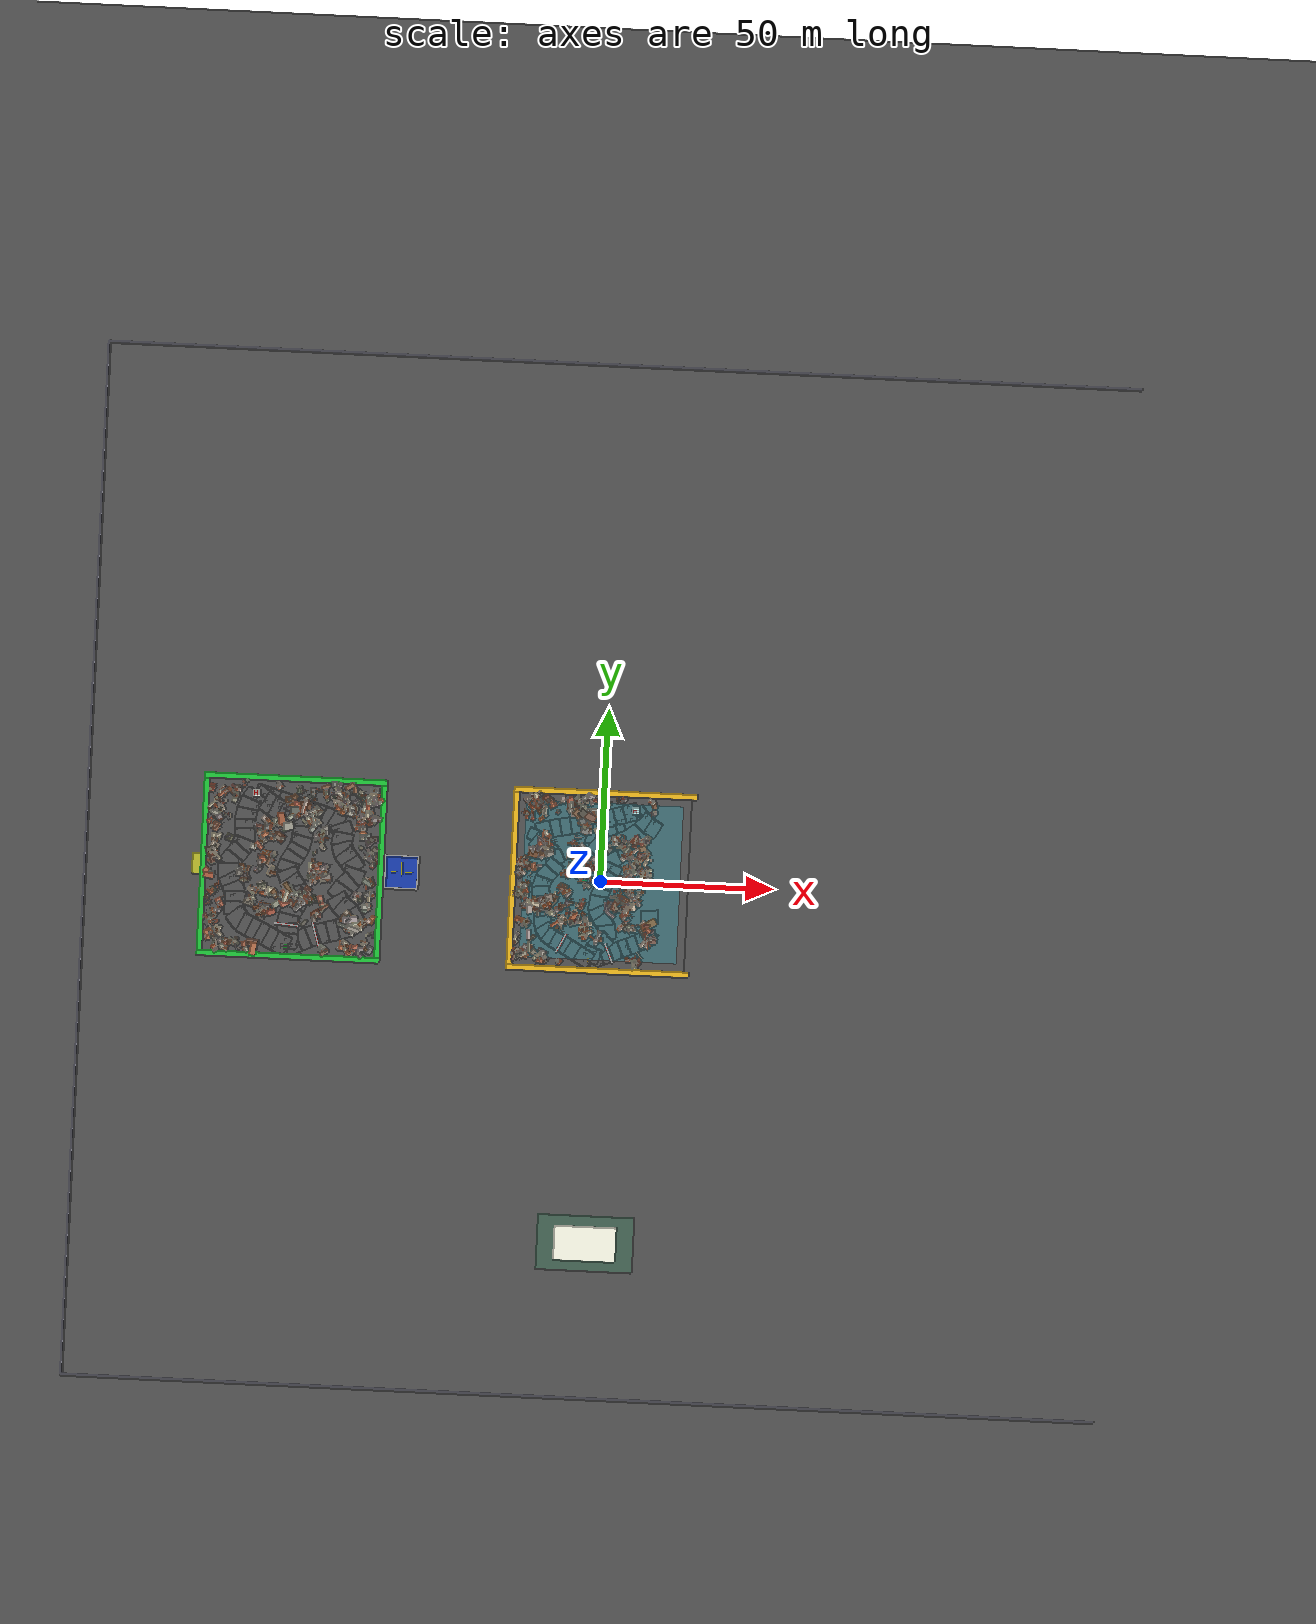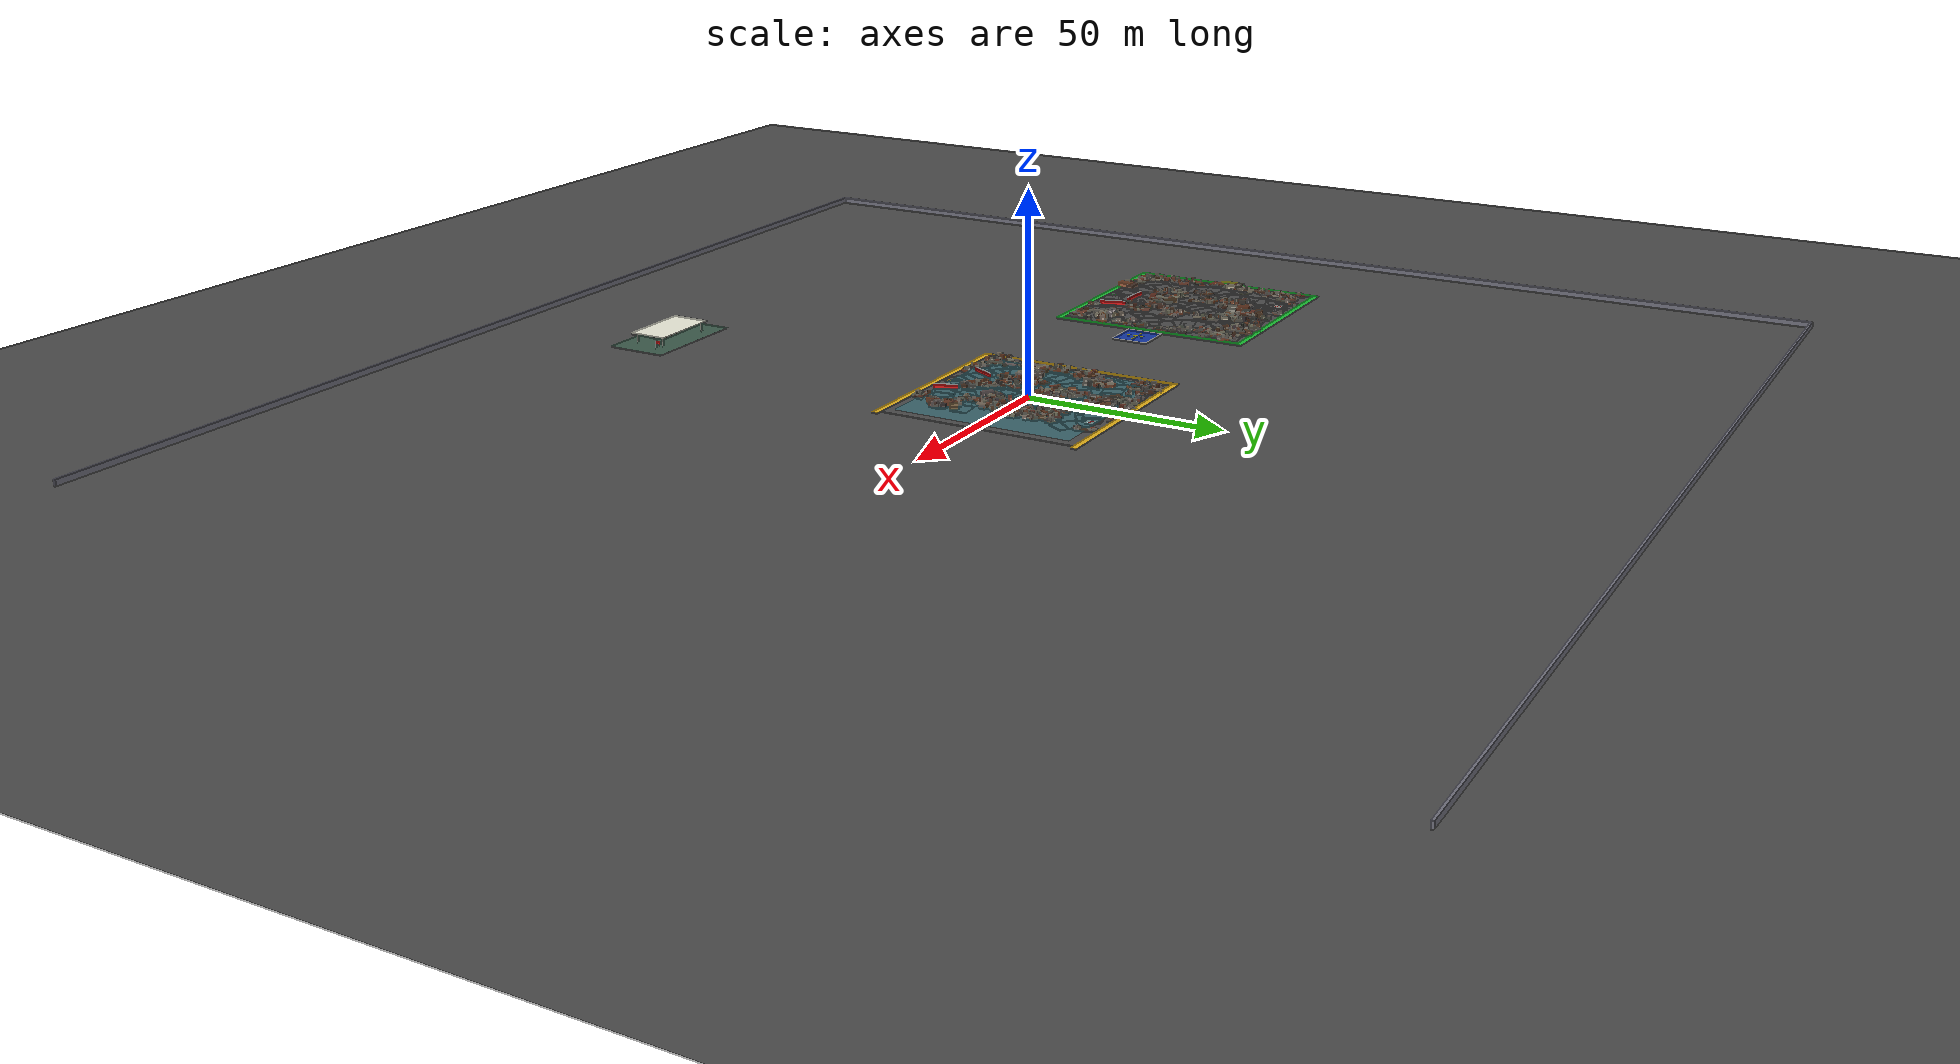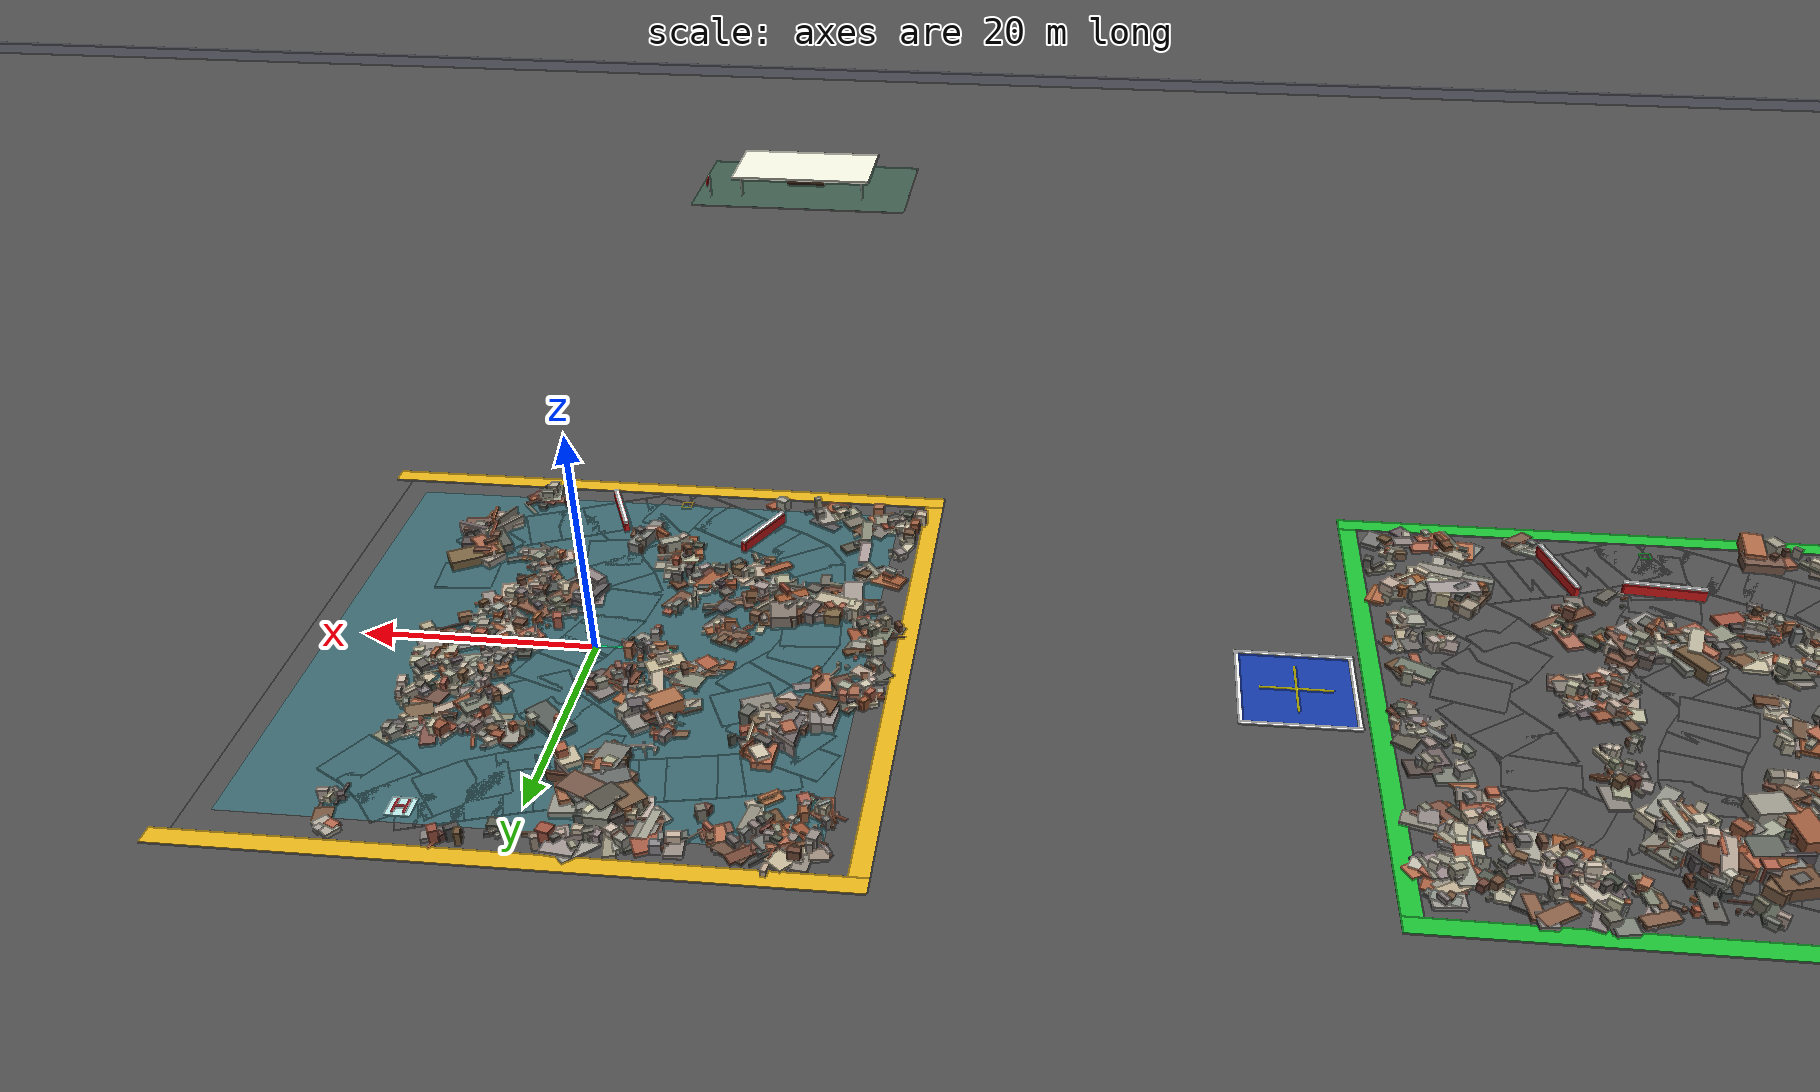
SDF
<sdf version="1.6">
 <world name="navitas_arena">
  <physics type="ode">
   <max_step_size>0.001</max_step_size>
   <real_time_factor>1</real_time_factor>
   <real_time_update_rate>1000</real_time_update_rate>
   <gravity>0 0 -9.8</gravity>
  </physics>
  <wind><linear_velocity>0.0 0.0 0.0</linear_velocity></wind>
  <scene>
   <ambient>0.5 0.5 0.5 1.0</ambient>
   <background>0.75 0.8 0.85 1.0</background>
   <shadows>true</shadows>
  </scene>
  <light name="sun" type="directional">
   <pose>0 0 120 0 -0 0</pose>
   <diffuse>0.9 0.9 0.85 1</diffuse>
   <specular>0.1 0.1 0.1 1</specular>
   <attenuation>
    <range>1200</range>
    <constant>0.9</constant>
    <linear>0.01</linear>
    <quadratic>0.001</quadratic>
   </attenuation>
   <direction>-0.4 0.2 -0.9</direction>
  </light>
  <plugin name="navitas_anim" filename="libnavitas_anim.so">
   <model name="iha">
    <waypoint>0.00 -116.000 0.000 0.500 0.0000</waypoint>
    <waypoint>0.35 -113.000 0.000 1.400 0.0000</waypoint>
    <waypoint>1.64 -96.000 0.000 6.500 0.0000</waypoint>
    <waypoint>3.26 -70.000 0.000 14.000 0.1122</waypoint>
    <waypoint>3.42 -67.330 0.301 14.571 0.3366</waypoint>
    <waypoint>3.57 -64.793 1.188 15.143 0.5610</waypoint>
    <waypoint>3.72 -62.518 2.618 15.714 0.7854</waypoint>
    <waypoint>3.88 -60.618 4.518 16.286 1.0098</waypoint>
    <waypoint>4.03 -59.188 6.793 16.857 1.2342</waypoint>
    <waypoint>4.18 -58.301 9.330 17.429 1.4586</waypoint>
    <waypoint>4.33 -58.000 12.000 18.000 1.6830</waypoint>
    <waypoint>4.49 -58.301 14.670 18.571 1.9074</waypoint>
    <waypoint>4.64 -59.188 17.207 19.143 2.1318</waypoint>
    <waypoint>4.79 -60.618 19.482 19.714 2.3562</waypoint>
    <waypoint>4.94 -62.518 21.382 20.286 2.5806</waypoint>
    <waypoint>5.10 -64.793 22.812 20.857 2.8050</waypoint>
    <waypoint>5.25 -67.330 23.699 21.429 3.0294</waypoint>
    <waypoint>5.40 -70.000 24.000 22.000 3.0419</waypoint>
    <waypoint>7.10 -100.000 27.000 27.000 3.2538</waypoint>
    <waypoint>7.20 -101.780 26.799 27.429 -2.8050</waypoint>
    <waypoint>7.31 -103.471 26.208 27.857 -2.5806</waypoint>
    <waypoint>7.41 -104.988 25.255 28.286 -2.3562</waypoint>
    <waypoint>7.51 -106.255 23.988 28.714 -2.1318</waypoint>
    <waypoint>7.61 -107.208 22.471 29.143 -1.9074</waypoint>
    <waypoint>7.72 -107.799 20.780 29.571 -1.6830</waypoint>
    <waypoint>7.84 -108.000 19.000 30.000 -1.5708</waypoint>
    <waypoint>10.62 -108.000 -20.000 30.000 -1.4586</waypoint>
    <waypoint>10.73 -107.850 -21.335 30.000 -1.2342</waypoint>
    <waypoint>10.86 -107.406 -22.603 30.000 -1.0098</waypoint>
    <waypoint>10.99 -106.691 -23.741 30.000 -0.7854</waypoint>
    <waypoint>11.12 -105.741 -24.691 30.000 -0.5610</waypoint>
    <waypoint>11.26 -104.603 -25.406 30.000 -0.3366</waypoint>
    <waypoint>11.39 -103.335 -25.850 30.000 -0.1122</waypoint>
    <waypoint>11.53 -102.000 -26.000 30.000 0.1122</waypoint>
    <waypoint>11.66 -100.665 -25.850 30.000 0.3366</waypoint>
    <waypoint>11.80 -99.397 -25.406 30.000 0.5610</waypoint>
    <waypoint>11.93 -98.259 -24.691 30.000 0.7854</waypoint>
    <waypoint>12.06 -97.309 -23.741 30.000 1.0098</waypoint>
    <waypoint>12.20 -96.594 -22.603 30.000 1.2342</waypoint>
    <waypoint>12.33 -96.150 -21.335 30.000 1.4586</waypoint>
    <waypoint>12.47 -96.000 -20.000 30.000 1.5708</waypoint>
    <waypoint>16.47 -96.000 20.000 30.000 1.4586</waypoint>
    <waypoint>16.60 -95.850 21.335 30.000 1.2342</waypoint>
    <waypoint>16.74 -95.406 22.603 30.000 1.0098</waypoint>
    <waypoint>16.87 -94.691 23.741 30.000 0.7854</waypoint>
    <waypoint>17.01 -93.741 24.691 30.000 0.5610</waypoint>
    <waypoint>17.14 -92.603 25.406 30.000 0.3366</waypoint>
    <waypoint>17.27 -91.335 25.850 30.000 0.1122</waypoint>
    <waypoint>17.41 -90.000 26.000 30.000 -0.1122</waypoint>
    <waypoint>17.54 -88.665 25.850 30.000 -0.3366</waypoint>
    <waypoint>17.68 -87.397 25.406 30.000 -0.5610</waypoint>
    <waypoint>17.81 -86.259 24.691 30.000 -0.7854</waypoint>
    <waypoint>17.95 -85.309 23.741 30.000 -1.0098</waypoint>
    <waypoint>18.08 -84.594 22.603 30.000 -1.2342</waypoint>
    <waypoint>18.21 -84.150 21.335 30.000 -1.4586</waypoint>
    <waypoint>18.35 -84.000 20.000 30.000 -1.5708</waypoint>
    <waypoint>22.35 -84.000 -20.000 30.000 -1.4586</waypoint>
    <waypoint>22.48 -83.850 -21.335 30.000 -1.2342</waypoint>
    <waypoint>22.62 -83.406 -22.603 30.000 -1.0098</waypoint>
    <waypoint>22.75 -82.691 -23.741 30.000 -0.7854</waypoint>
    <waypoint>22.89 -81.741 -24.691 30.000 -0.5610</waypoint>
    <waypoint>23.02 -80.603 -25.406 30.000 -0.3366</waypoint>
    <waypoint>23.16 -79.335 -25.850 30.000 -0.1122</waypoint>
    <waypoint>23.29 -78.000 -26.000 30.000 0.1122</waypoint>
    <waypoint>23.42 -76.665 -25.850 30.000 0.3366</waypoint>
    <waypoint>23.56 -75.397 -25.406 30.000 0.5610</waypoint>
    <waypoint>23.69 -74.259 -24.691 30.000 0.7854</waypoint>
    <waypoint>23.83 -73.309 -23.741 30.000 1.0098</waypoint>
    <waypoint>23.96 -72.594 -22.603 30.000 1.2342</waypoint>
    <waypoint>24.10 -72.150 -21.335 30.000 1.4586</waypoint>
    <waypoint>24.23 -72.000 -20.000 30.000 1.5708</waypoint>
    <waypoint>28.23 -72.000 20.000 30.000 1.4586</waypoint>
    <waypoint>28.39 -71.824 21.558 30.000 1.2342</waypoint>
    <waypoint>28.54 -71.307 23.037 30.000 1.0098</waypoint>
    <waypoint>28.70 -70.473 24.364 30.000 0.7854</waypoint>
    <waypoint>28.86 -69.364 25.473 30.000 0.5610</waypoint>
    <waypoint>29.01 -68.037 26.307 30.000 0.3366</waypoint>
    <waypoint>29.17 -66.558 26.824 30.000 0.1122</waypoint>
    <waypoint>29.33 -65.000 27.000 30.000 -0.1122</waypoint>
    <waypoint>29.48 -63.442 26.824 30.000 -0.3366</waypoint>
    <waypoint>29.64 -61.963 26.307 30.000 -0.5610</waypoint>
    <waypoint>29.80 -60.636 25.473 30.000 -0.7854</waypoint>
    <waypoint>29.95 -59.527 24.364 30.000 -1.0098</waypoint>
    <waypoint>30.11 -58.693 23.037 30.000 -1.2342</waypoint>
    <waypoint>30.26 -58.176 21.558 30.000 -1.4586</waypoint>
    <waypoint>30.42 -58.000 20.000 30.000 -1.5708</waypoint>
    <waypoint>31.19 -58.000 13.000 26.000 -1.5708</waypoint>
    <waypoint>32.07 -58.000 6.000 21.000 -1.5708</waypoint>
    <waypoint>32.32 -58.000 4.500 19.500 -1.5708</waypoint>
    <waypoint>32.52 -57.940 4.048 18.144 -1.5708</waypoint>
    <waypoint>32.72 -57.784 3.596 16.787 -1.5708</waypoint>
    <waypoint>32.92 -57.632 3.144 15.431 -1.5708</waypoint>
    <waypoint>33.12 -57.636 2.692 14.075 -1.5708</waypoint>
    <waypoint>33.32 -57.713 2.240 12.719 -1.5708</waypoint>
    <waypoint>33.42 -57.778 2.000 12.000 -1.5708</waypoint>
    <waypoint>33.52 -57.845 1.887 11.437 -1.5708</waypoint>
    <waypoint>33.72 -58.000 1.648 10.241 -1.5708</waypoint>
    <waypoint>33.92 -58.142 1.409 9.044 -1.5708</waypoint>
    <waypoint>34.12 -58.239 1.169 7.847 -1.5708</waypoint>
    <waypoint>34.32 -58.271 0.930 6.651 -1.5708</waypoint>
    <waypoint>34.52 -58.238 0.691 5.454 -1.5708</waypoint>
    <waypoint>34.68 -58.178 0.500 4.500 -1.5708</waypoint>
    <waypoint>34.72 -58.160 0.473 4.274 -1.5708</waypoint>
    <waypoint>34.92 -58.068 0.338 3.158 -1.5708</waypoint>
    <waypoint>35.12 -58.000 0.204 2.042 -1.5708</waypoint>
    <waypoint>35.32 -57.984 0.069 0.926 -1.5708</waypoint>
    <waypoint>35.42 -58.000 0.000 0.350 -1.5708</waypoint>
   </model>
   <model name="parachute_packed">
    <waypoint>0.00 -58.000 4.500 -60.000 -1.5708</waypoint>
    <waypoint>32.32 -58.000 4.500 -60.000 -1.5708</waypoint>
    <waypoint>32.32 -58.000 4.500 19.980 -1.5708</waypoint>
    <waypoint>32.57 -57.993 3.935 18.285 -1.5708</waypoint>
    <waypoint>32.57 -57.993 3.935 -60.000 -1.5708</waypoint>
    <waypoint>43.42 -57.993 3.935 -60.000 -1.5708</waypoint>
   </model>
   <model name="parachute_partial">
    <waypoint>0.00 -58.000 4.500 -60.000 -1.5708</waypoint>
    <waypoint>32.57 -58.000 4.500 -60.000 -1.5708</waypoint>
    <waypoint>32.57 -57.988 3.935 19.655 -1.5708</waypoint>
    <waypoint>33.27 -57.959 2.353 14.908 -1.5708</waypoint>
    <waypoint>33.27 -57.959 2.353 -60.000 -1.5708</waypoint>
    <waypoint>35.77 -56.900 0.550 -60.000 0.3500</waypoint>
    <waypoint>35.77 -56.900 0.550 0.080 0.3500</waypoint>
    <waypoint>43.42 -56.900 0.550 0.080 0.3500</waypoint>
   </model>
   <model name="parachute_full">
    <waypoint>0.00 -58.000 4.500 -60.000 -1.5708</waypoint>
    <waypoint>33.27 -58.000 4.500 -60.000 -1.5708</waypoint>
    <waypoint>33.27 -57.926 2.353 16.508 -1.5708</waypoint>
    <waypoint>33.42 -57.947 2.000 15.450 -1.5708</waypoint>
    <waypoint>33.47 -57.955 1.947 15.187 -1.5708</waypoint>
    <waypoint>33.67 -57.991 1.708 13.990 -1.5708</waypoint>
    <waypoint>33.87 -58.026 1.469 12.793 -1.5708</waypoint>
    <waypoint>34.07 -58.052 1.229 11.597 -1.5708</waypoint>
    <waypoint>34.27 -58.064 0.990 10.400 -1.5708</waypoint>
    <waypoint>34.47 -58.060 0.751 9.203 -1.5708</waypoint>
    <waypoint>34.67 -58.043 0.511 8.007 -1.5708</waypoint>
    <waypoint>34.68 -58.042 0.500 7.950 -1.5708</waypoint>
    <waypoint>34.87 -58.021 0.372 6.887 -1.5708</waypoint>
    <waypoint>35.07 -58.003 0.237 5.771 -1.5708</waypoint>
    <waypoint>35.27 -57.996 0.103 4.655 -1.5708</waypoint>
    <waypoint>35.42 -58.000 0.000 3.800 -1.5708</waypoint>
    <waypoint>35.77 -58.000 0.000 3.800 -1.5708</waypoint>
    <waypoint>35.77 -58.000 0.000 -60.000 -1.5708</waypoint>
    <waypoint>43.42 -58.000 0.000 -60.000 -1.5708</waypoint>
   </model>
   <model name="ika_kolay">
    <waypoint>36.92 -90.632 -23.000 0.210 2.6805</waypoint>
    <waypoint>39.92 -93.588 -21.531 0.210 2.6725</waypoint>
    <waypoint>42.63 -96.251 -20.182 0.210 2.6696</waypoint>
    <waypoint>45.13 -98.700 -18.931 0.210 2.7218</waypoint>
    <waypoint>47.72 -101.297 -17.773 0.210 2.6679</waypoint>
    <waypoint>50.26 -103.785 -16.497 0.210 2.4431</waypoint>
    <waypoint>52.38 -105.568 -15.000 0.210 1.8205</waypoint>
    <waypoint>54.84 -106.236 -12.380 0.210 1.4989</waypoint>
    <waypoint>57.52 -106.024 -9.440 0.210 1.7838</waypoint>
    <waypoint>59.94 -106.588 -6.833 0.210 2.0765</waypoint>
    <waypoint>62.36 -107.880 -4.500 0.210 1.9784</waypoint>
    <waypoint>64.67 -108.888 -2.167 0.210 1.4365</waypoint>
    <waypoint>66.82 -108.572 0.167 0.210 0.9414</waypoint>
    <waypoint>69.44 -106.873 2.500 0.210 0.8974</waypoint>
    <waypoint>72.15 -105.012 4.833 0.210 1.2455</waypoint>
    <waypoint>74.65 -104.132 7.440 0.210 1.5927</waypoint>
    <waypoint>77.33 -104.197 10.380 0.210 1.6085</waypoint>
    <waypoint>79.71 -104.296 13.000 0.210 1.4081</waypoint>
    <waypoint>82.63 -103.776 16.167 0.210 1.1658</waypoint>
    <waypoint>85.30 -102.617 18.870 0.210 0.9687</waypoint>
    <waypoint>87.65 -101.153 21.000 0.210 0.9687</waypoint>
   </model>
  </plugin>
  <model name="ground_plane">
   <static>true</static>
   <link name="link">
    <collision name="collision">
     <geometry><plane><normal>0 0 1</normal><size>400 400</size></plane></geometry>
     <surface><friction><ode><mu>0.800</mu><mu2>0.800</mu2></ode></friction></surface>
    </collision>
    <visual name="visual">
     <cast_shadows>false</cast_shadows>
     <geometry><plane><normal>0 0 1</normal><size>400 400</size></plane></geometry>
     <material>
      <specular>0.04 0.04 0.04 1</specular>
      <script>
       <uri>file://media/materials/scripts/navitas_asphalt.material</uri>
       <name>Navitas/RealArenaAsphalt</name>
      </script>
     </material>
    </visual>
   </link>
  </model>
  <model name="ub_N">
   <static>true</static>
   <pose>0.000 150.000 0.750 0 0 0.000</pose>
   <link name="link">
    <collision name="col"><geometry><box><size>300.000 0.600 1.500</size></box></geometry></collision>
    <visual name="vis">
     <geometry><box><size>300.000 0.600 1.500</size></box></geometry>
     <material>
      <ambient>0.45 0.45 0.50 1</ambient>
      <diffuse>0.45 0.45 0.50 1</diffuse>
      <specular>0.04 0.04 0.04 1</specular>
     </material>
    </visual>
   </link>
  </model>
  <model name="ub_S">
   <static>true</static>
   <pose>0.000 -150.000 0.750 0 0 0.000</pose>
   <link name="link">
    <collision name="col"><geometry><box><size>300.000 0.600 1.500</size></box></geometry></collision>
    <visual name="vis">
     <geometry><box><size>300.000 0.600 1.500</size></box></geometry>
     <material>
      <ambient>0.45 0.45 0.50 1</ambient>
      <diffuse>0.45 0.45 0.50 1</diffuse>
      <specular>0.04 0.04 0.04 1</specular>
     </material>
    </visual>
   </link>
  </model>
  <model name="ub_W">
   <static>true</static>
   <pose>-150.000 0.000 0.750 0 0 0.000</pose>
   <link name="link">
    <collision name="col"><geometry><box><size>0.600 300.000 1.500</size></box></geometry></collision>
    <visual name="vis">
     <geometry><box><size>0.600 300.000 1.500</size></box></geometry>
     <material>
      <ambient>0.45 0.45 0.50 1</ambient>
      <diffuse>0.45 0.45 0.50 1</diffuse>
      <specular>0.04 0.04 0.04 1</specular>
     </material>
    </visual>
   </link>
  </model>
  <model name="judge_camp_floor">
   <static>true</static>
   <pose>0.000 -105.000 0.010 0 0 0.000</pose>
   <link name="link">
    <collision name="col"><geometry><box><size>28.000 16.000 0.020</size></box></geometry></collision>
    <visual name="vis">
     <geometry><box><size>28.000 16.000 0.020</size></box></geometry>
     <material>
      <ambient>0.24 0.36 0.30 1</ambient>
      <diffuse>0.24 0.36 0.30 1</diffuse>
      <specular>0.04 0.04 0.04 1</specular>
     </material>
    </visual>
   </link>
  </model>
  <model name="judge_tent_roof">
   <static>true</static>
   <pose>0.000 -105.000 2.600 0 0 0.000</pose>
   <link name="link">
    <collision name="col"><geometry><box><size>18.000 10.000 0.350</size></box></geometry></collision>
    <visual name="vis">
     <geometry><box><size>18.000 10.000 0.350</size></box></geometry>
     <material>
      <ambient>0.95 0.95 0.88 1</ambient>
      <diffuse>0.95 0.95 0.88 1</diffuse>
      <specular>0.04 0.04 0.04 1</specular>
     </material>
    </visual>
   </link>
  </model>
  <model name="judge_tent_pole_1">
   <static>true</static>
   <pose>-8.000 -109.000 1.200 0 0 0.000</pose>
   <link name="link">
    <collision name="col"><geometry><box><size>0.180 0.180 2.400</size></box></geometry></collision>
    <visual name="vis">
     <geometry><box><size>0.180 0.180 2.400</size></box></geometry>
     <material>
      <ambient>0.85 0.85 0.80 1</ambient>
      <diffuse>0.85 0.85 0.80 1</diffuse>
      <specular>0.04 0.04 0.04 1</specular>
     </material>
    </visual>
   </link>
  </model>
  <model name="judge_tent_pole_2">
   <static>true</static>
   <pose>8.000 -109.000 1.200 0 0 0.000</pose>
   <link name="link">
    <collision name="col"><geometry><box><size>0.180 0.180 2.400</size></box></geometry></collision>
    <visual name="vis">
     <geometry><box><size>0.180 0.180 2.400</size></box></geometry>
     <material>
      <ambient>0.85 0.85 0.80 1</ambient>
      <diffuse>0.85 0.85 0.80 1</diffuse>
      <specular>0.04 0.04 0.04 1</specular>
     </material>
    </visual>
   </link>
  </model>
  <model name="judge_tent_pole_3">
   <static>true</static>
   <pose>-8.000 -101.000 1.200 0 0 0.000</pose>
   <link name="link">
    <collision name="col"><geometry><box><size>0.180 0.180 2.400</size></box></geometry></collision>
    <visual name="vis">
     <geometry><box><size>0.180 0.180 2.400</size></box></geometry>
     <material>
      <ambient>0.85 0.85 0.80 1</ambient>
      <diffuse>0.85 0.85 0.80 1</diffuse>
      <specular>0.04 0.04 0.04 1</specular>
     </material>
    </visual>
   </link>
  </model>
  <model name="judge_tent_pole_4">
   <static>true</static>
   <pose>8.000 -101.000 1.200 0 0 0.000</pose>
   <link name="link">
    <collision name="col"><geometry><box><size>0.180 0.180 2.400</size></box></geometry></collision>
    <visual name="vis">
     <geometry><box><size>0.180 0.180 2.400</size></box></geometry>
     <material>
      <ambient>0.85 0.85 0.80 1</ambient>
      <diffuse>0.85 0.85 0.80 1</diffuse>
      <specular>0.04 0.04 0.04 1</specular>
     </material>
    </visual>
   </link>
  </model>
  <model name="judge_table">
   <static>true</static>
   <pose>0.000 -105.000 0.450 0 0 0.000</pose>
   <link name="link">
    <collision name="col"><geometry><box><size>5.000 1.400 0.250</size></box></geometry></collision>
    <visual name="vis">
     <geometry><box><size>5.000 1.400 0.250</size></box></geometry>
     <material>
      <ambient>0.28 0.18 0.12 1</ambient>
      <diffuse>0.28 0.18 0.12 1</diffuse>
      <specular>0.04 0.04 0.04 1</specular>
     </material>
    </visual>
   </link>
  </model>
  <model name="judge_monitor_1">
   <static>true</static>
   <pose>-1.400 -104.750 0.950 0 0 0.000</pose>
   <link name="link">
    <collision name="col"><geometry><box><size>1.000 0.120 0.650</size></box></geometry></collision>
    <visual name="vis">
     <geometry><box><size>1.000 0.120 0.650</size></box></geometry>
     <material>
      <ambient>0.02 0.02 0.03 1</ambient>
      <diffuse>0.02 0.02 0.03 1</diffuse>
      <specular>0.04 0.04 0.04 1</specular>
     </material>
    </visual>
   </link>
  </model>
  <model name="judge_monitor_2">
   <static>true</static>
   <pose>1.400 -104.750 0.950 0 0 0.000</pose>
   <link name="link">
    <collision name="col"><geometry><box><size>1.000 0.120 0.650</size></box></geometry></collision>
    <visual name="vis">
     <geometry><box><size>1.000 0.120 0.650</size></box></geometry>
     <material>
      <ambient>0.02 0.02 0.03 1</ambient>
      <diffuse>0.02 0.02 0.03 1</diffuse>
      <specular>0.04 0.04 0.04 1</specular>
     </material>
    </visual>
   </link>
  </model>
  <model name="judge_chair_1">
   <static>true</static>
   <pose>-3.000 -107.000 0.350 0 0 0.000</pose>
   <link name="link">
    <collision name="col"><geometry><box><size>0.900 0.900 0.250</size></box></geometry></collision>
    <visual name="vis">
     <geometry><box><size>0.900 0.900 0.250</size></box></geometry>
     <material>
      <ambient>0.16 0.16 0.16 1</ambient>
      <diffuse>0.16 0.16 0.16 1</diffuse>
      <specular>0.04 0.04 0.04 1</specular>
     </material>
    </visual>
   </link>
  </model>
  <model name="judge_chair_2">
   <static>true</static>
   <pose>0.000 -107.000 0.350 0 0 0.000</pose>
   <link name="link">
    <collision name="col"><geometry><box><size>0.900 0.900 0.250</size></box></geometry></collision>
    <visual name="vis">
     <geometry><box><size>0.900 0.900 0.250</size></box></geometry>
     <material>
      <ambient>0.16 0.16 0.16 1</ambient>
      <diffuse>0.16 0.16 0.16 1</diffuse>
      <specular>0.04 0.04 0.04 1</specular>
     </material>
    </visual>
   </link>
  </model>
  <model name="judge_chair_3">
   <static>true</static>
   <pose>3.000 -107.000 0.350 0 0 0.000</pose>
   <link name="link">
    <collision name="col"><geometry><box><size>0.900 0.900 0.250</size></box></geometry></collision>
    <visual name="vis">
     <geometry><box><size>0.900 0.900 0.250</size></box></geometry>
     <material>
      <ambient>0.16 0.16 0.16 1</ambient>
      <diffuse>0.16 0.16 0.16 1</diffuse>
      <specular>0.04 0.04 0.04 1</specular>
     </material>
    </visual>
   </link>
  </model>
  <model name="judge_flag">
   <static>true</static>
   <pose>12.000 -100.000 1.400 0 0 0.000</pose>
   <link name="link">
    <collision name="col"><geometry><box><size>0.120 0.120 2.800</size></box></geometry></collision>
    <visual name="vis">
     <geometry><box><size>0.120 0.120 2.800</size></box></geometry>
     <material>
      <ambient>0.85 0.85 0.85 1</ambient>
      <diffuse>0.85 0.85 0.85 1</diffuse>
      <specular>0.04 0.04 0.04 1</specular>
     </material>
    </visual>
   </link>
  </model>
  <model name="judge_flag_panel">
   <static>true</static>
   <pose>12.000 -99.200 2.300 0 0 0.000</pose>
   <link name="link">
    <collision name="col"><geometry><box><size>0.080 1.400 0.800</size></box></geometry></collision>
    <visual name="vis">
     <geometry><box><size>0.080 1.400 0.800</size></box></geometry>
     <material>
      <ambient>0.90 0.10 0.10 1</ambient>
      <diffuse>0.90 0.10 0.10 1</diffuse>
      <specular>0.04 0.04 0.04 1</specular>
     </material>
    </visual>
   </link>
  </model>
  <model name="landing">
   <static>true</static>
   <pose>-58.000 0.000 0.010 0 0 0.000</pose>
   <link name="link">
    <collision name="col"><geometry><box><size>9.000 9.000 0.020</size></box></geometry></collision>
    <visual name="vis">
     <geometry><box><size>9.000 9.000 0.020</size></box></geometry>
     <material>
      <ambient>0.08 0.22 0.65 1</ambient>
      <diffuse>0.08 0.22 0.65 1</diffuse>
      <specular>0.04 0.04 0.04 1</specular>
     </material>
    </visual>
   </link>
  </model>
  <model name="landing_border_n">
   <static>true</static>
   <pose>-58.000 4.700 0.080 0 0 0.000</pose>
   <link name="link">
    <collision name="col"><geometry><box><size>9.800 0.350 0.080</size></box></geometry></collision>
    <visual name="vis">
     <geometry><box><size>9.800 0.350 0.080</size></box></geometry>
     <material>
      <ambient>0.95 0.95 0.95 1</ambient>
      <diffuse>0.95 0.95 0.95 1</diffuse>
      <specular>0.04 0.04 0.04 1</specular>
     </material>
    </visual>
   </link>
  </model>
  <model name="landing_border_s">
   <static>true</static>
   <pose>-58.000 -4.700 0.080 0 0 0.000</pose>
   <link name="link">
    <collision name="col"><geometry><box><size>9.800 0.350 0.080</size></box></geometry></collision>
    <visual name="vis">
     <geometry><box><size>9.800 0.350 0.080</size></box></geometry>
     <material>
      <ambient>0.95 0.95 0.95 1</ambient>
      <diffuse>0.95 0.95 0.95 1</diffuse>
      <specular>0.04 0.04 0.04 1</specular>
     </material>
    </visual>
   </link>
  </model>
  <model name="landing_border_w">
   <static>true</static>
   <pose>-62.700 0.000 0.080 0 0 0.000</pose>
   <link name="link">
    <collision name="col"><geometry><box><size>0.350 9.000 0.080</size></box></geometry></collision>
    <visual name="vis">
     <geometry><box><size>0.350 9.000 0.080</size></box></geometry>
     <material>
      <ambient>0.95 0.95 0.95 1</ambient>
      <diffuse>0.95 0.95 0.95 1</diffuse>
      <specular>0.04 0.04 0.04 1</specular>
     </material>
    </visual>
   </link>
  </model>
  <model name="landing_border_e">
   <static>true</static>
   <pose>-53.300 0.000 0.080 0 0 0.000</pose>
   <link name="link">
    <collision name="col"><geometry><box><size>0.350 9.000 0.080</size></box></geometry></collision>
    <visual name="vis">
     <geometry><box><size>0.350 9.000 0.080</size></box></geometry>
     <material>
      <ambient>0.95 0.95 0.95 1</ambient>
      <diffuse>0.95 0.95 0.95 1</diffuse>
      <specular>0.04 0.04 0.04 1</specular>
     </material>
    </visual>
   </link>
  </model>
  <model name="landing_cross_x">
   <static>true</static>
   <pose>-58.000 0.000 0.100 0 0 0.000</pose>
   <link name="link">
    <collision name="col"><geometry><box><size>6.000 0.180 0.080</size></box></geometry></collision>
    <visual name="vis">
     <geometry><box><size>6.000 0.180 0.080</size></box></geometry>
     <material>
      <ambient>1.00 0.95 0.05 1</ambient>
      <diffuse>1.00 0.95 0.05 1</diffuse>
      <specular>0.04 0.04 0.04 1</specular>
     </material>
    </visual>
   </link>
  </model>
  <model name="landing_cross_y">
   <static>true</static>
   <pose>-58.000 0.000 0.100 0 0 0.000</pose>
   <link name="link">
    <collision name="col"><geometry><box><size>0.180 6.000 0.080</size></box></geometry></collision>
    <visual name="vis">
     <geometry><box><size>0.180 6.000 0.080</size></box></geometry>
     <material>
      <ambient>1.00 0.95 0.05 1</ambient>
      <diffuse>1.00 0.95 0.05 1</diffuse>
      <specular>0.04 0.04 0.04 1</specular>
     </material>
    </visual>
   </link>
  </model>
  <model name="launch">
   <static>true</static>
   <pose>-116.000 0.000 0.010 0 0 0.000</pose>
   <link name="link">
    <collision name="col"><geometry><box><size>6.000 6.000 0.020</size></box></geometry></collision>
    <visual name="vis">
     <geometry><box><size>6.000 6.000 0.020</size></box></geometry>
     <material>
      <ambient>0.70 0.70 0.15 1</ambient>
      <diffuse>0.70 0.70 0.15 1</diffuse>
      <specular>0.04 0.04 0.04 1</specular>
     </material>
    </visual>
   </link>
  </model>
  <model name="gd_kolay">
   <static>true</static>
   <pose>-90.000 0.000 0.010 0 0 0.000</pose>
   <link name="link">
    <collision name="col"><geometry><box><size>50.000 50.000 0.020</size></box></geometry></collision>
    <visual name="vis">
     <geometry><box><size>50.000 50.000 0.020</size></box></geometry>
     <material>
      <specular>0.04 0.04 0.04 1</specular>
      <script>
       <uri>file://media/materials/scripts/navitas_asphalt.material</uri>
       <name>Navitas/RealArenaAsphalt</name>
      </script>
     </material>
    </visual>
   </link>
  </model>
  <model name="brd_kolay_N">
   <static>true</static>
   <pose>-90.000 25.800 0.040 0 0 0.000</pose>
   <link name="link">
    <collision name="col"><geometry><box><size>53.200 1.600 0.080</size></box></geometry></collision>
    <visual name="vis">
     <geometry><box><size>53.200 1.600 0.080</size></box></geometry>
     <material>
      <ambient>0.10 0.75 0.20 1</ambient>
      <diffuse>0.10 0.75 0.20 1</diffuse>
      <specular>0.04 0.04 0.04 1</specular>
     </material>
    </visual>
   </link>
  </model>
  <model name="brd_kolay_S">
   <static>true</static>
   <pose>-90.000 -25.800 0.040 0 0 0.000</pose>
   <link name="link">
    <collision name="col"><geometry><box><size>53.200 1.600 0.080</size></box></geometry></collision>
    <visual name="vis">
     <geometry><box><size>53.200 1.600 0.080</size></box></geometry>
     <material>
      <ambient>0.10 0.75 0.20 1</ambient>
      <diffuse>0.10 0.75 0.20 1</diffuse>
      <specular>0.04 0.04 0.04 1</specular>
     </material>
    </visual>
   </link>
  </model>
  <model name="brd_kolay_W">
   <static>true</static>
   <pose>-115.800 0.000 0.040 0 0 0.000</pose>
   <link name="link">
    <collision name="col"><geometry><box><size>1.600 50.000 0.080</size></box></geometry></collision>
    <visual name="vis">
     <geometry><box><size>1.600 50.000 0.080</size></box></geometry>
     <material>
      <ambient>0.10 0.75 0.20 1</ambient>
      <diffuse>0.10 0.75 0.20 1</diffuse>
      <specular>0.04 0.04 0.04 1</specular>
     </material>
    </visual>
   </link>
  </model>
  <model name="brd_kolay_E">
   <static>true</static>
   <pose>-64.200 0.000 0.040 0 0 0.000</pose>
   <link name="link">
    <collision name="col"><geometry><box><size>1.600 50.000 0.080</size></box></geometry></collision>
    <visual name="vis">
     <geometry><box><size>1.600 50.000 0.080</size></box></geometry>
     <material>
      <ambient>0.10 0.75 0.20 1</ambient>
      <diffuse>0.10 0.75 0.20 1</diffuse>
      <specular>0.04 0.04 0.04 1</specular>
     </material>
    </visual>
   </link>
  </model>
  <model name="road_kolay_1_0">
   <static>true</static>
   <pose>-92.110 -22.266 0.040 0 0 2.681</pose>
   <link name="link">
    <collision name="col"><geometry><box><size>4.201 6.000 0.020</size></box></geometry></collision>
    <visual name="vis">
     <geometry><box><size>4.201 6.000 0.020</size></box></geometry>
     <material>
      <specular>0.04 0.04 0.04 1</specular>
      <script>
       <uri>file://media/materials/scripts/navitas_asphalt.material</uri>
       <name>Navitas/RealArenaAsphalt</name>
      </script>
     </material>
    </visual>
   </link>
  </model>
  <model name="road_kolay_1_1">
   <static>true</static>
   <pose>-94.920 -20.856 0.040 0 0 2.672</pose>
   <link name="link">
    <collision name="col"><geometry><box><size>3.885 6.000 0.020</size></box></geometry></collision>
    <visual name="vis">
     <geometry><box><size>3.885 6.000 0.020</size></box></geometry>
     <material>
      <specular>0.04 0.04 0.04 1</specular>
      <script>
       <uri>file://media/materials/scripts/navitas_asphalt.material</uri>
       <name>Navitas/RealArenaAsphalt</name>
      </script>
     </material>
    </visual>
   </link>
  </model>
  <model name="road_kolay_1_2">
   <static>true</static>
   <pose>-97.476 -19.557 0.040 0 0 2.670</pose>
   <link name="link">
    <collision name="col"><geometry><box><size>3.650 6.000 0.020</size></box></geometry></collision>
    <visual name="vis">
     <geometry><box><size>3.650 6.000 0.020</size></box></geometry>
     <material>
      <specular>0.04 0.04 0.04 1</specular>
      <script>
       <uri>file://media/materials/scripts/navitas_asphalt.material</uri>
       <name>Navitas/RealArenaAsphalt</name>
      </script>
     </material>
    </visual>
   </link>
  </model>
  <model name="road_kolay_1_3">
   <static>true</static>
   <pose>-99.999 -18.352 0.040 0 0 2.722</pose>
   <link name="link">
    <collision name="col"><geometry><box><size>3.744 6.000 0.020</size></box></geometry></collision>
    <visual name="vis">
     <geometry><box><size>3.744 6.000 0.020</size></box></geometry>
     <material>
      <specular>0.04 0.04 0.04 1</specular>
      <script>
       <uri>file://media/materials/scripts/navitas_asphalt.material</uri>
       <name>Navitas/RealArenaAsphalt</name>
      </script>
     </material>
    </visual>
   </link>
  </model>
  <model name="road_kolay_1_4">
   <static>true</static>
   <pose>-102.541 -17.135 0.040 0 0 2.668</pose>
   <link name="link">
    <collision name="col"><geometry><box><size>3.696 6.000 0.020</size></box></geometry></collision>
    <visual name="vis">
     <geometry><box><size>3.696 6.000 0.020</size></box></geometry>
     <material>
      <specular>0.04 0.04 0.04 1</specular>
      <script>
       <uri>file://media/materials/scripts/navitas_asphalt.material</uri>
       <name>Navitas/RealArenaAsphalt</name>
      </script>
     </material>
    </visual>
   </link>
  </model>
  <model name="road_kolay_1_5">
   <static>true</static>
   <pose>-104.956 -15.129 0.040 0 0 2.279</pose>
   <link name="link">
    <collision name="col"><geometry><box><size>4.502 6.000 0.020</size></box></geometry></collision>
    <visual name="vis">
     <geometry><box><size>4.502 6.000 0.020</size></box></geometry>
     <material>
      <specular>0.04 0.04 0.04 1</specular>
      <script>
       <uri>file://media/materials/scripts/navitas_asphalt.material</uri>
       <name>Navitas/RealArenaAsphalt</name>
      </script>
     </material>
    </visual>
   </link>
  </model>
  <model name="road_kolay_1_6">
   <static>true</static>
   <pose>-106.126 -12.340 0.040 0 0 1.570</pose>
   <link name="link">
    <collision name="col"><geometry><box><size>3.740 6.000 0.020</size></box></geometry></collision>
    <visual name="vis">
     <geometry><box><size>3.740 6.000 0.020</size></box></geometry>
     <material>
      <specular>0.04 0.04 0.04 1</specular>
      <script>
       <uri>file://media/materials/scripts/navitas_asphalt.material</uri>
       <name>Navitas/RealArenaAsphalt</name>
      </script>
     </material>
    </visual>
   </link>
  </model>
  <model name="road_kolay_1_7">
   <static>true</static>
   <pose>-106.145 -9.460 0.040 0 0 1.585</pose>
   <link name="link">
    <collision name="col"><geometry><box><size>3.820 6.000 0.020</size></box></geometry></collision>
    <visual name="vis">
     <geometry><box><size>3.820 6.000 0.020</size></box></geometry>
     <material>
      <specular>0.04 0.04 0.04 1</specular>
      <script>
       <uri>file://media/materials/scripts/navitas_asphalt.material</uri>
       <name>Navitas/RealArenaAsphalt</name>
      </script>
     </material>
    </visual>
   </link>
  </model>
  <model name="road_kolay_1_8">
   <static>true</static>
   <pose>-106.685 -6.833 0.040 0 0 1.989</pose>
   <link name="link">
    <collision name="col"><geometry><box><size>3.454 6.000 0.020</size></box></geometry></collision>
    <visual name="vis">
     <geometry><box><size>3.454 6.000 0.020</size></box></geometry>
     <material>
      <specular>0.04 0.04 0.04 1</specular>
      <script>
       <uri>file://media/materials/scripts/navitas_asphalt.material</uri>
       <name>Navitas/RealArenaAsphalt</name>
      </script>
     </material>
    </visual>
   </link>
  </model>
  <model name="road_kolay_1_9">
   <static>true</static>
   <pose>-107.845 -4.500 0.040 0 0 2.073</pose>
   <link name="link">
    <collision name="col"><geometry><box><size>3.562 6.000 0.020</size></box></geometry></collision>
    <visual name="vis">
     <geometry><box><size>3.562 6.000 0.020</size></box></geometry>
     <material>
      <specular>0.04 0.04 0.04 1</specular>
      <script>
       <uri>file://media/materials/scripts/navitas_asphalt.material</uri>
       <name>Navitas/RealArenaAsphalt</name>
      </script>
     </material>
    </visual>
   </link>
  </model>
  <model name="road_kolay_1_10">
   <static>true</static>
   <pose>-108.529 -1.583 0.040 0 0 1.596</pose>
   <link name="link">
    <collision name="col"><geometry><box><size>4.401 6.000 0.020</size></box></geometry></collision>
    <visual name="vis">
     <geometry><box><size>4.401 6.000 0.020</size></box></geometry>
     <material>
      <specular>0.04 0.04 0.04 1</specular>
      <script>
       <uri>file://media/materials/scripts/navitas_asphalt.material</uri>
       <name>Navitas/RealArenaAsphalt</name>
      </script>
     </material>
    </visual>
   </link>
  </model>
  <model name="road_kolay_1_11">
   <static>true</static>
   <pose>-107.723 1.333 0.040 0 0 0.941</pose>
   <link name="link">
    <collision name="col"><geometry><box><size>3.787 6.000 0.020</size></box></geometry></collision>
    <visual name="vis">
     <geometry><box><size>3.787 6.000 0.020</size></box></geometry>
     <material>
      <specular>0.04 0.04 0.04 1</specular>
      <script>
       <uri>file://media/materials/scripts/navitas_asphalt.material</uri>
       <name>Navitas/RealArenaAsphalt</name>
      </script>
     </material>
    </visual>
   </link>
  </model>
  <model name="road_kolay_1_12">
   <static>true</static>
   <pose>-105.942 3.667 0.040 0 0 0.897</pose>
   <link name="link">
    <collision name="col"><geometry><box><size>3.885 6.000 0.020</size></box></geometry></collision>
    <visual name="vis">
     <geometry><box><size>3.885 6.000 0.020</size></box></geometry>
     <material>
      <specular>0.04 0.04 0.04 1</specular>
      <script>
       <uri>file://media/materials/scripts/navitas_asphalt.material</uri>
       <name>Navitas/RealArenaAsphalt</name>
      </script>
     </material>
    </visual>
   </link>
  </model>
  <model name="road_kolay_1_13">
   <static>true</static>
   <pose>-104.572 6.137 0.040 0 0 1.245</pose>
   <link name="link">
    <collision name="col"><geometry><box><size>3.651 6.000 0.020</size></box></geometry></collision>
    <visual name="vis">
     <geometry><box><size>3.651 6.000 0.020</size></box></geometry>
     <material>
      <specular>0.04 0.04 0.04 1</specular>
      <script>
       <uri>file://media/materials/scripts/navitas_asphalt.material</uri>
       <name>Navitas/RealArenaAsphalt</name>
      </script>
     </material>
    </visual>
   </link>
  </model>
  <model name="road_kolay_1_14">
   <static>true</static>
   <pose>-104.165 8.910 0.040 0 0 1.593</pose>
   <link name="link">
    <collision name="col"><geometry><box><size>3.841 6.000 0.020</size></box></geometry></collision>
    <visual name="vis">
     <geometry><box><size>3.841 6.000 0.020</size></box></geometry>
     <material>
      <specular>0.04 0.04 0.04 1</specular>
      <script>
       <uri>file://media/materials/scripts/navitas_asphalt.material</uri>
       <name>Navitas/RealArenaAsphalt</name>
      </script>
     </material>
    </visual>
   </link>
  </model>
  <model name="road_kolay_1_15">
   <static>true</static>
   <pose>-104.246 11.690 0.040 0 0 1.609</pose>
   <link name="link">
    <collision name="col"><geometry><box><size>3.522 6.000 0.020</size></box></geometry></collision>
    <visual name="vis">
     <geometry><box><size>3.522 6.000 0.020</size></box></geometry>
     <material>
      <specular>0.04 0.04 0.04 1</specular>
      <script>
       <uri>file://media/materials/scripts/navitas_asphalt.material</uri>
       <name>Navitas/RealArenaAsphalt</name>
      </script>
     </material>
    </visual>
   </link>
  </model>
  <model name="road_kolay_1_16">
   <static>true</static>
   <pose>-104.036 14.583 0.040 0 0 1.408</pose>
   <link name="link">
    <collision name="col"><geometry><box><size>4.109 6.000 0.020</size></box></geometry></collision>
    <visual name="vis">
     <geometry><box><size>4.109 6.000 0.020</size></box></geometry>
     <material>
      <specular>0.04 0.04 0.04 1</specular>
      <script>
       <uri>file://media/materials/scripts/navitas_asphalt.material</uri>
       <name>Navitas/RealArenaAsphalt</name>
      </script>
     </material>
    </visual>
   </link>
  </model>
  <model name="road_kolay_1_17">
   <static>true</static>
   <pose>-103.196 17.519 0.040 0 0 1.166</pose>
   <link name="link">
    <collision name="col"><geometry><box><size>3.842 6.000 0.020</size></box></geometry></collision>
    <visual name="vis">
     <geometry><box><size>3.842 6.000 0.020</size></box></geometry>
     <material>
      <specular>0.04 0.04 0.04 1</specular>
      <script>
       <uri>file://media/materials/scripts/navitas_asphalt.material</uri>
       <name>Navitas/RealArenaAsphalt</name>
      </script>
     </material>
    </visual>
   </link>
  </model>
  <model name="road_kolay_1_18">
   <static>true</static>
   <pose>-101.885 19.935 0.040 0 0 0.969</pose>
   <link name="link">
    <collision name="col"><geometry><box><size>3.484 6.000 0.020</size></box></geometry></collision>
    <visual name="vis">
     <geometry><box><size>3.484 6.000 0.020</size></box></geometry>
     <material>
      <specular>0.04 0.04 0.04 1</specular>
      <script>
       <uri>file://media/materials/scripts/navitas_asphalt.material</uri>
       <name>Navitas/RealArenaAsphalt</name>
      </script>
     </material>
    </visual>
   </link>
  </model>
  <model name="road_kolay_2_0">
   <static>true</static>
   <pose>-90.490 -21.250 0.040 0 0 1.490</pose>
   <link name="link">
    <collision name="col"><geometry><box><size>4.412 6.000 0.020</size></box></geometry></collision>
    <visual name="vis">
     <geometry><box><size>4.412 6.000 0.020</size></box></geometry>
     <material>
      <specular>0.04 0.04 0.04 1</specular>
      <script>
       <uri>file://media/materials/scripts/navitas_asphalt.material</uri>
       <name>Navitas/RealArenaAsphalt</name>
      </script>
     </material>
    </visual>
   </link>
  </model>
  <model name="road_kolay_2_1">
   <static>true</static>
   <pose>-90.547 -18.111 0.040 0 0 1.713</pose>
   <link name="link">
    <collision name="col"><geometry><box><size>3.706 6.000 0.020</size></box></geometry></collision>
    <visual name="vis">
     <geometry><box><size>3.706 6.000 0.020</size></box></geometry>
     <material>
      <specular>0.04 0.04 0.04 1</specular>
      <script>
       <uri>file://media/materials/scripts/navitas_asphalt.material</uri>
       <name>Navitas/RealArenaAsphalt</name>
      </script>
     </material>
    </visual>
   </link>
  </model>
  <model name="road_kolay_2_2">
   <static>true</static>
   <pose>-90.478 -15.350 0.040 0 0 1.378</pose>
   <link name="link">
    <collision name="col"><geometry><box><size>3.696 6.000 0.020</size></box></geometry></collision>
    <visual name="vis">
     <geometry><box><size>3.696 6.000 0.020</size></box></geometry>
     <material>
      <specular>0.04 0.04 0.04 1</specular>
      <script>
       <uri>file://media/materials/scripts/navitas_asphalt.material</uri>
       <name>Navitas/RealArenaAsphalt</name>
      </script>
     </material>
    </visual>
   </link>
  </model>
  <model name="road_kolay_2_3">
   <static>true</static>
   <pose>-89.535 -12.817 0.040 0 0 1.043</pose>
   <link name="link">
    <collision name="col"><geometry><box><size>3.587 6.000 0.020</size></box></geometry></collision>
    <visual name="vis">
     <geometry><box><size>3.587 6.000 0.020</size></box></geometry>
     <material>
      <specular>0.04 0.04 0.04 1</specular>
      <script>
       <uri>file://media/materials/scripts/navitas_asphalt.material</uri>
       <name>Navitas/RealArenaAsphalt</name>
      </script>
     </material>
    </visual>
   </link>
  </model>
  <model name="road_kolay_2_4">
   <static>true</static>
   <pose>-88.283 -10.426 0.040 0 0 1.133</pose>
   <link name="link">
    <collision name="col"><geometry><box><size>3.617 6.000 0.020</size></box></geometry></collision>
    <visual name="vis">
     <geometry><box><size>3.617 6.000 0.020</size></box></geometry>
     <material>
      <specular>0.04 0.04 0.04 1</specular>
      <script>
       <uri>file://media/materials/scripts/navitas_asphalt.material</uri>
       <name>Navitas/RealArenaAsphalt</name>
      </script>
     </material>
    </visual>
   </link>
  </model>
  <model name="road_kolay_2_5">
   <static>true</static>
   <pose>-88.152 -7.431 0.040 0 0 1.818</pose>
   <link name="link">
    <collision name="col"><geometry><box><size>4.540 6.000 0.020</size></box></geometry></collision>
    <visual name="vis">
     <geometry><box><size>4.540 6.000 0.020</size></box></geometry>
     <material>
      <specular>0.04 0.04 0.04 1</specular>
      <script>
       <uri>file://media/materials/scripts/navitas_asphalt.material</uri>
       <name>Navitas/RealArenaAsphalt</name>
      </script>
     </material>
    </visual>
   </link>
  </model>
  <model name="road_kolay_2_6">
   <static>true</static>
   <pose>-89.501 -4.500 0.040 0 0 2.229</pose>
   <link name="link">
    <collision name="col"><geometry><box><size>3.850 6.000 0.020</size></box></geometry></collision>
    <visual name="vis">
     <geometry><box><size>3.850 6.000 0.020</size></box></geometry>
     <material>
      <specular>0.04 0.04 0.04 1</specular>
      <script>
       <uri>file://media/materials/scripts/navitas_asphalt.material</uri>
       <name>Navitas/RealArenaAsphalt</name>
      </script>
     </material>
    </visual>
   </link>
  </model>
  <model name="road_kolay_2_7">
   <static>true</static>
   <pose>-90.909 -2.167 0.040 0 0 1.980</pose>
   <link name="link">
    <collision name="col"><geometry><box><size>3.443 6.000 0.020</size></box></geometry></collision>
    <visual name="vis">
     <geometry><box><size>3.443 6.000 0.020</size></box></geometry>
     <material>
      <specular>0.04 0.04 0.04 1</specular>
      <script>
       <uri>file://media/materials/scripts/navitas_asphalt.material</uri>
       <name>Navitas/RealArenaAsphalt</name>
      </script>
     </material>
    </visual>
   </link>
  </model>
  <model name="road_kolay_2_8">
   <static>true</static>
   <pose>-91.073 0.167 0.040 0 0 1.286</pose>
   <link name="link">
    <collision name="col"><geometry><box><size>3.331 6.000 0.020</size></box></geometry></collision>
    <visual name="vis">
     <geometry><box><size>3.331 6.000 0.020</size></box></geometry>
     <material>
      <specular>0.04 0.04 0.04 1</specular>
      <script>
       <uri>file://media/materials/scripts/navitas_asphalt.material</uri>
       <name>Navitas/RealArenaAsphalt</name>
      </script>
     </material>
    </visual>
   </link>
  </model>
  <model name="road_kolay_2_9">
   <static>true</static>
   <pose>-89.992 2.500 0.040 0 0 1.006</pose>
   <link name="link">
    <collision name="col"><geometry><box><size>3.662 6.000 0.020</size></box></geometry></collision>
    <visual name="vis">
     <geometry><box><size>3.662 6.000 0.020</size></box></geometry>
     <material>
      <specular>0.04 0.04 0.04 1</specular>
      <script>
       <uri>file://media/materials/scripts/navitas_asphalt.material</uri>
       <name>Navitas/RealArenaAsphalt</name>
      </script>
     </material>
    </visual>
   </link>
  </model>
  <model name="road_kolay_2_10">
   <static>true</static>
   <pose>-88.686 4.833 0.040 0 0 1.118</pose>
   <link name="link">
    <collision name="col"><geometry><box><size>3.494 6.000 0.020</size></box></geometry></collision>
    <visual name="vis">
     <geometry><box><size>3.494 6.000 0.020</size></box></geometry>
     <material>
      <specular>0.04 0.04 0.04 1</specular>
      <script>
       <uri>file://media/materials/scripts/navitas_asphalt.material</uri>
       <name>Navitas/RealArenaAsphalt</name>
      </script>
     </material>
    </visual>
   </link>
  </model>
  <model name="road_kolay_2_11">
   <static>true</static>
   <pose>-87.765 7.460 0.040 0 0 1.333</pose>
   <link name="link">
    <collision name="col"><geometry><box><size>3.904 6.000 0.020</size></box></geometry></collision>
    <visual name="vis">
     <geometry><box><size>3.904 6.000 0.020</size></box></geometry>
     <material>
      <specular>0.04 0.04 0.04 1</specular>
      <script>
       <uri>file://media/materials/scripts/navitas_asphalt.material</uri>
       <name>Navitas/RealArenaAsphalt</name>
      </script>
     </material>
    </visual>
   </link>
  </model>
  <model name="road_kolay_2_12">
   <static>true</static>
   <pose>-87.390 10.340 0.040 0 0 1.556</pose>
   <link name="link">
    <collision name="col"><geometry><box><size>3.740 6.000 0.020</size></box></geometry></collision>
    <visual name="vis">
     <geometry><box><size>3.740 6.000 0.020</size></box></geometry>
     <material>
      <specular>0.04 0.04 0.04 1</specular>
      <script>
       <uri>file://media/materials/scripts/navitas_asphalt.material</uri>
       <name>Navitas/RealArenaAsphalt</name>
      </script>
     </material>
    </visual>
   </link>
  </model>
  <model name="road_kolay_2_13">
   <static>true</static>
   <pose>-88.023 12.771 0.040 0 0 2.145</pose>
   <link name="link">
    <collision name="col"><geometry><box><size>3.309 6.000 0.020</size></box></geometry></collision>
    <visual name="vis">
     <geometry><box><size>3.309 6.000 0.020</size></box></geometry>
     <material>
      <specular>0.04 0.04 0.04 1</specular>
      <script>
       <uri>file://media/materials/scripts/navitas_asphalt.material</uri>
       <name>Navitas/RealArenaAsphalt</name>
      </script>
     </material>
    </visual>
   </link>
  </model>
  <model name="road_kolay_2_14">
   <static>true</static>
   <pose>-89.848 14.469 0.040 0 0 2.611</pose>
   <link name="link">
    <collision name="col"><geometry><box><size>3.613 6.000 0.020</size></box></geometry></collision>
    <visual name="vis">
     <geometry><box><size>3.613 6.000 0.020</size></box></geometry>
     <material>
      <specular>0.04 0.04 0.04 1</specular>
      <script>
       <uri>file://media/materials/scripts/navitas_asphalt.material</uri>
       <name>Navitas/RealArenaAsphalt</name>
      </script>
     </material>
    </visual>
   </link>
  </model>
  <model name="road_kolay_2_15">
   <static>true</static>
   <pose>-92.396 15.758 0.040 0 0 2.730</pose>
   <link name="link">
    <collision name="col"><geometry><box><size>3.908 6.000 0.020</size></box></geometry></collision>
    <visual name="vis">
     <geometry><box><size>3.908 6.000 0.020</size></box></geometry>
     <material>
      <specular>0.04 0.04 0.04 1</specular>
      <script>
       <uri>file://media/materials/scripts/navitas_asphalt.material</uri>
       <name>Navitas/RealArenaAsphalt</name>
      </script>
     </material>
    </visual>
   </link>
  </model>
  <model name="road_kolay_2_16">
   <static>true</static>
   <pose>-94.954 16.930 0.040 0 0 2.692</pose>
   <link name="link">
    <collision name="col"><geometry><box><size>3.521 6.000 0.020</size></box></geometry></collision>
    <visual name="vis">
     <geometry><box><size>3.521 6.000 0.020</size></box></geometry>
     <material>
      <specular>0.04 0.04 0.04 1</specular>
      <script>
       <uri>file://media/materials/scripts/navitas_asphalt.material</uri>
       <name>Navitas/RealArenaAsphalt</name>
      </script>
     </material>
    </visual>
   </link>
  </model>
  <model name="road_kolay_2_17">
   <static>true</static>
   <pose>-97.374 18.320 0.040 0 0 2.557</pose>
   <link name="link">
    <collision name="col"><geometry><box><size>3.872 6.000 0.020</size></box></geometry></collision>
    <visual name="vis">
     <geometry><box><size>3.872 6.000 0.020</size></box></geometry>
     <material>
      <specular>0.04 0.04 0.04 1</specular>
      <script>
       <uri>file://media/materials/scripts/navitas_asphalt.material</uri>
       <name>Navitas/RealArenaAsphalt</name>
      </script>
     </material>
    </visual>
   </link>
  </model>
  <model name="road_kolay_2_18">
   <static>true</static>
   <pose>-99.883 20.070 0.040 0 0 2.510</pose>
   <link name="link">
    <collision name="col"><geometry><box><size>4.048 6.000 0.020</size></box></geometry></collision>
    <visual name="vis">
     <geometry><box><size>4.048 6.000 0.020</size></box></geometry>
     <material>
      <specular>0.04 0.04 0.04 1</specular>
      <script>
       <uri>file://media/materials/scripts/navitas_asphalt.material</uri>
       <name>Navitas/RealArenaAsphalt</name>
      </script>
     </material>
    </visual>
   </link>
  </model>
  <model name="road_kolay_3_0">
   <static>true</static>
   <pose>-89.138 -22.266 0.040 0 0 0.457</pose>
   <link name="link">
    <collision name="col"><geometry><box><size>4.229 6.000 0.020</size></box></geometry></collision>
    <visual name="vis">
     <geometry><box><size>4.229 6.000 0.020</size></box></geometry>
     <material>
      <specular>0.04 0.04 0.04 1</specular>
      <script>
       <uri>file://media/materials/scripts/navitas_asphalt.material</uri>
       <name>Navitas/RealArenaAsphalt</name>
      </script>
     </material>
    </visual>
   </link>
  </model>
  <model name="road_kolay_3_1">
   <static>true</static>
   <pose>-86.196 -20.856 0.040 0 0 0.436</pose>
   <link name="link">
    <collision name="col"><geometry><box><size>4.096 6.000 0.020</size></box></geometry></collision>
    <visual name="vis">
     <geometry><box><size>4.096 6.000 0.020</size></box></geometry>
     <material>
      <specular>0.04 0.04 0.04 1</specular>
      <script>
       <uri>file://media/materials/scripts/navitas_asphalt.material</uri>
       <name>Navitas/RealArenaAsphalt</name>
      </script>
     </material>
    </visual>
   </link>
  </model>
  <model name="road_kolay_3_2">
   <static>true</static>
   <pose>-83.397 -19.642 0.040 0 0 0.380</pose>
   <link name="link">
    <collision name="col"><geometry><box><size>3.808 6.000 0.020</size></box></geometry></collision>
    <visual name="vis">
     <geometry><box><size>3.808 6.000 0.020</size></box></geometry>
     <material>
      <specular>0.04 0.04 0.04 1</specular>
      <script>
       <uri>file://media/materials/scripts/navitas_asphalt.material</uri>
       <name>Navitas/RealArenaAsphalt</name>
      </script>
     </material>
    </visual>
   </link>
  </model>
  <model name="road_kolay_3_3">
   <static>true</static>
   <pose>-80.676 -18.702 0.040 0 0 0.284</pose>
   <link name="link">
    <collision name="col"><geometry><box><size>3.755 6.000 0.020</size></box></geometry></collision>
    <visual name="vis">
     <geometry><box><size>3.755 6.000 0.020</size></box></geometry>
     <material>
      <specular>0.04 0.04 0.04 1</specular>
      <script>
       <uri>file://media/materials/scripts/navitas_asphalt.material</uri>
       <name>Navitas/RealArenaAsphalt</name>
      </script>
     </material>
    </visual>
   </link>
  </model>
  <model name="road_kolay_3_4">
   <static>true</static>
   <pose>-77.800 -17.886 0.040 0 0 0.270</pose>
   <link name="link">
    <collision name="col"><geometry><box><size>4.026 6.000 0.020</size></box></geometry></collision>
    <visual name="vis">
     <geometry><box><size>4.026 6.000 0.020</size></box></geometry>
     <material>
      <specular>0.04 0.04 0.04 1</specular>
      <script>
       <uri>file://media/materials/scripts/navitas_asphalt.material</uri>
       <name>Navitas/RealArenaAsphalt</name>
      </script>
     </material>
    </visual>
   </link>
  </model>
  <model name="road_kolay_3_5">
   <static>true</static>
   <pose>-74.918 -17.017 0.040 0 0 0.317</pose>
   <link name="link">
    <collision name="col"><geometry><box><size>3.795 6.000 0.020</size></box></geometry></collision>
    <visual name="vis">
     <geometry><box><size>3.795 6.000 0.020</size></box></geometry>
     <material>
      <specular>0.04 0.04 0.04 1</specular>
      <script>
       <uri>file://media/materials/scripts/navitas_asphalt.material</uri>
       <name>Navitas/RealArenaAsphalt</name>
      </script>
     </material>
    </visual>
   </link>
  </model>
  <model name="road_kolay_3_6">
   <static>true</static>
   <pose>-72.310 -15.783 0.040 0 0 0.566</pose>
   <link name="link">
    <collision name="col"><geometry><box><size>3.820 6.000 0.020</size></box></geometry></collision>
    <visual name="vis">
     <geometry><box><size>3.820 6.000 0.020</size></box></geometry>
     <material>
      <specular>0.04 0.04 0.04 1</specular>
      <script>
       <uri>file://media/materials/scripts/navitas_asphalt.material</uri>
       <name>Navitas/RealArenaAsphalt</name>
      </script>
     </material>
    </visual>
   </link>
  </model>
  <model name="road_kolay_3_7">
   <static>true</static>
   <pose>-71.950 -13.587 0.040 0 0 2.124</pose>
   <link name="link">
    <collision name="col"><geometry><box><size>4.221 6.000 0.020</size></box></geometry></collision>
    <visual name="vis">
     <geometry><box><size>4.221 6.000 0.020</size></box></geometry>
     <material>
      <specular>0.04 0.04 0.04 1</specular>
      <script>
       <uri>file://media/materials/scripts/navitas_asphalt.material</uri>
       <name>Navitas/RealArenaAsphalt</name>
      </script>
     </material>
    </visual>
   </link>
  </model>
  <model name="road_kolay_3_8">
   <static>true</static>
   <pose>-74.099 -11.124 0.040 0 0 2.452</pose>
   <link name="link">
    <collision name="col"><geometry><box><size>4.206 6.000 0.020</size></box></geometry></collision>
    <visual name="vis">
     <geometry><box><size>4.206 6.000 0.020</size></box></geometry>
     <material>
      <specular>0.04 0.04 0.04 1</specular>
      <script>
       <uri>file://media/materials/scripts/navitas_asphalt.material</uri>
       <name>Navitas/RealArenaAsphalt</name>
      </script>
     </material>
    </visual>
   </link>
  </model>
  <model name="road_kolay_3_9">
   <static>true</static>
   <pose>-76.035 -9.036 0.040 0 0 2.138</pose>
   <link name="link">
    <collision name="col"><geometry><box><size>3.358 6.000 0.020</size></box></geometry></collision>
    <visual name="vis">
     <geometry><box><size>3.358 6.000 0.020</size></box></geometry>
     <material>
      <specular>0.04 0.04 0.04 1</specular>
      <script>
       <uri>file://media/materials/scripts/navitas_asphalt.material</uri>
       <name>Navitas/RealArenaAsphalt</name>
      </script>
     </material>
    </visual>
   </link>
  </model>
  <model name="road_kolay_3_10">
   <static>true</static>
   <pose>-75.678 -6.500 0.040 0 0 0.974</pose>
   <link name="link">
    <collision name="col"><geometry><box><size>4.526 6.000 0.020</size></box></geometry></collision>
    <visual name="vis">
     <geometry><box><size>4.526 6.000 0.020</size></box></geometry>
     <material>
      <specular>0.04 0.04 0.04 1</specular>
      <script>
       <uri>file://media/materials/scripts/navitas_asphalt.material</uri>
       <name>Navitas/RealArenaAsphalt</name>
      </script>
     </material>
    </visual>
   </link>
  </model>
  <model name="road_kolay_3_11">
   <static>true</static>
   <pose>-73.572 -4.000 0.040 0 0 0.744</pose>
   <link name="link">
    <collision name="col"><geometry><box><size>3.855 6.000 0.020</size></box></geometry></collision>
    <visual name="vis">
     <geometry><box><size>3.855 6.000 0.020</size></box></geometry>
     <material>
      <specular>0.04 0.04 0.04 1</specular>
      <script>
       <uri>file://media/materials/scripts/navitas_asphalt.material</uri>
       <name>Navitas/RealArenaAsphalt</name>
      </script>
     </material>
    </visual>
   </link>
  </model>
  <model name="road_kolay_3_12">
   <static>true</static>
   <pose>-72.023 -1.417 0.040 0 0 1.287</pose>
   <link name="link">
    <collision name="col"><geometry><box><size>4.199 6.000 0.020</size></box></geometry></collision>
    <visual name="vis">
     <geometry><box><size>4.199 6.000 0.020</size></box></geometry>
     <material>
      <specular>0.04 0.04 0.04 1</specular>
      <script>
       <uri>file://media/materials/scripts/navitas_asphalt.material</uri>
       <name>Navitas/RealArenaAsphalt</name>
      </script>
     </material>
    </visual>
   </link>
  </model>
  <model name="road_kolay_3_13">
   <static>true</static>
   <pose>-72.366 1.333 0.040 0 0 2.175</pose>
   <link name="link">
    <collision name="col"><geometry><box><size>3.736 6.000 0.020</size></box></geometry></collision>
    <visual name="vis">
     <geometry><box><size>3.736 6.000 0.020</size></box></geometry>
     <material>
      <specular>0.04 0.04 0.04 1</specular>
      <script>
       <uri>file://media/materials/scripts/navitas_asphalt.material</uri>
       <name>Navitas/RealArenaAsphalt</name>
      </script>
     </material>
    </visual>
   </link>
  </model>
  <model name="road_kolay_3_14">
   <static>true</static>
   <pose>-74.146 3.667 0.040 0 0 2.267</pose>
   <link name="link">
    <collision name="col"><geometry><box><size>3.940 6.000 0.020</size></box></geometry></collision>
    <visual name="vis">
     <geometry><box><size>3.940 6.000 0.020</size></box></geometry>
     <material>
      <specular>0.04 0.04 0.04 1</specular>
      <script>
       <uri>file://media/materials/scripts/navitas_asphalt.material</uri>
       <name>Navitas/RealArenaAsphalt</name>
      </script>
     </material>
    </visual>
   </link>
  </model>
  <model name="road_kolay_3_15">
   <static>true</static>
   <pose>-75.534 6.137 0.040 0 0 1.878</pose>
   <link name="link">
    <collision name="col"><geometry><box><size>3.635 6.000 0.020</size></box></geometry></collision>
    <visual name="vis">
     <geometry><box><size>3.635 6.000 0.020</size></box></geometry>
     <material>
      <specular>0.04 0.04 0.04 1</specular>
      <script>
       <uri>file://media/materials/scripts/navitas_asphalt.material</uri>
       <name>Navitas/RealArenaAsphalt</name>
      </script>
     </material>
    </visual>
   </link>
  </model>
  <model name="road_kolay_3_16">
   <static>true</static>
   <pose>-75.733 8.910 0.040 0 0 1.426</pose>
   <link name="link">
    <collision name="col"><geometry><box><size>3.871 6.000 0.020</size></box></geometry></collision>
    <visual name="vis">
     <geometry><box><size>3.871 6.000 0.020</size></box></geometry>
     <material>
      <specular>0.04 0.04 0.04 1</specular>
      <script>
       <uri>file://media/materials/scripts/navitas_asphalt.material</uri>
       <name>Navitas/RealArenaAsphalt</name>
      </script>
     </material>
    </visual>
   </link>
  </model>
  <model name="road_kolay_3_17">
   <static>true</static>
   <pose>-75.998 11.690 0.040 0 0 1.921</pose>
   <link name="link">
    <collision name="col"><geometry><box><size>3.689 6.000 0.020</size></box></geometry></collision>
    <visual name="vis">
     <geometry><box><size>3.689 6.000 0.020</size></box></geometry>
     <material>
      <specular>0.04 0.04 0.04 1</specular>
      <script>
       <uri>file://media/materials/scripts/navitas_asphalt.material</uri>
       <name>Navitas/RealArenaAsphalt</name>
      </script>
     </material>
    </visual>
   </link>
  </model>
  <model name="road_kolay_3_18">
   <static>true</static>
   <pose>-77.755 13.717 0.040 0 0 2.630</pose>
   <link name="link">
    <collision name="col"><geometry><box><size>3.833 6.000 0.020</size></box></geometry></collision>
    <visual name="vis">
     <geometry><box><size>3.833 6.000 0.020</size></box></geometry>
     <material>
      <specular>0.04 0.04 0.04 1</specular>
      <script>
       <uri>file://media/materials/scripts/navitas_asphalt.material</uri>
       <name>Navitas/RealArenaAsphalt</name>
      </script>
     </material>
    </visual>
   </link>
  </model>
  <model name="road_kolay_3_19">
   <static>true</static>
   <pose>-80.196 14.853 0.040 0 0 2.796</pose>
   <link name="link">
    <collision name="col"><geometry><box><size>3.371 6.000 0.020</size></box></geometry></collision>
    <visual name="vis">
     <geometry><box><size>3.371 6.000 0.020</size></box></geometry>
     <material>
      <specular>0.04 0.04 0.04 1</specular>
      <script>
       <uri>file://media/materials/scripts/navitas_asphalt.material</uri>
       <name>Navitas/RealArenaAsphalt</name>
      </script>
     </material>
    </visual>
   </link>
  </model>
  <model name="road_kolay_3_20">
   <static>true</static>
   <pose>-82.643 15.657 0.040 0 0 2.850</pose>
   <link name="link">
    <collision name="col"><geometry><box><size>3.582 6.000 0.020</size></box></geometry></collision>
    <visual name="vis">
     <geometry><box><size>3.582 6.000 0.020</size></box></geometry>
     <material>
      <specular>0.04 0.04 0.04 1</specular>
      <script>
       <uri>file://media/materials/scripts/navitas_asphalt.material</uri>
       <name>Navitas/RealArenaAsphalt</name>
      </script>
     </material>
    </visual>
   </link>
  </model>
  <model name="road_kolay_3_21">
   <static>true</static>
   <pose>-85.226 16.409 0.040 0 0 2.866</pose>
   <link name="link">
    <collision name="col"><geometry><box><size>3.599 6.000 0.020</size></box></geometry></collision>
    <visual name="vis">
     <geometry><box><size>3.599 6.000 0.020</size></box></geometry>
     <material>
      <specular>0.04 0.04 0.04 1</specular>
      <script>
       <uri>file://media/materials/scripts/navitas_asphalt.material</uri>
       <name>Navitas/RealArenaAsphalt</name>
      </script>
     </material>
    </visual>
   </link>
  </model>
  <model name="road_kolay_3_22">
   <static>true</static>
   <pose>-87.730 17.138 0.040 0 0 2.850</pose>
   <link name="link">
    <collision name="col"><geometry><box><size>3.416 6.000 0.020</size></box></geometry></collision>
    <visual name="vis">
     <geometry><box><size>3.416 6.000 0.020</size></box></geometry>
     <material>
      <specular>0.04 0.04 0.04 1</specular>
      <script>
       <uri>file://media/materials/scripts/navitas_asphalt.material</uri>
       <name>Navitas/RealArenaAsphalt</name>
      </script>
     </material>
    </visual>
   </link>
  </model>
  <model name="road_kolay_3_23">
   <static>true</static>
   <pose>-90.262 17.910 0.040 0 0 2.842</pose>
   <link name="link">
    <collision name="col"><geometry><box><size>3.678 6.000 0.020</size></box></geometry></collision>
    <visual name="vis">
     <geometry><box><size>3.678 6.000 0.020</size></box></geometry>
     <material>
      <specular>0.04 0.04 0.04 1</specular>
      <script>
       <uri>file://media/materials/scripts/navitas_asphalt.material</uri>
       <name>Navitas/RealArenaAsphalt</name>
      </script>
     </material>
    </visual>
   </link>
  </model>
  <model name="road_kolay_3_24">
   <static>true</static>
   <pose>-93.007 18.730 0.040 0 0 2.860</pose>
   <link name="link">
    <collision name="col"><geometry><box><size>3.853 6.000 0.020</size></box></geometry></collision>
    <visual name="vis">
     <geometry><box><size>3.853 6.000 0.020</size></box></geometry>
     <material>
      <specular>0.04 0.04 0.04 1</specular>
      <script>
       <uri>file://media/materials/scripts/navitas_asphalt.material</uri>
       <name>Navitas/RealArenaAsphalt</name>
      </script>
     </material>
    </visual>
   </link>
  </model>
  <model name="road_kolay_3_25">
   <static>true</static>
   <pose>-95.791 19.520 0.040 0 0 2.870</pose>
   <link name="link">
    <collision name="col"><geometry><box><size>3.735 6.000 0.020</size></box></geometry></collision>
    <visual name="vis">
     <geometry><box><size>3.735 6.000 0.020</size></box></geometry>
     <material>
      <specular>0.04 0.04 0.04 1</specular>
      <script>
       <uri>file://media/materials/scripts/navitas_asphalt.material</uri>
       <name>Navitas/RealArenaAsphalt</name>
      </script>
     </material>
    </visual>
   </link>
  </model>
  <model name="road_kolay_3_26">
   <static>true</static>
   <pose>-98.326 20.220 0.040 0 0 2.874</pose>
   <link name="link">
    <collision name="col"><geometry><box><size>3.324 6.000 0.020</size></box></geometry></collision>
    <visual name="vis">
     <geometry><box><size>3.324 6.000 0.020</size></box></geometry>
     <material>
      <specular>0.04 0.04 0.04 1</specular>
      <script>
       <uri>file://media/materials/scripts/navitas_asphalt.material</uri>
       <name>Navitas/RealArenaAsphalt</name>
      </script>
     </material>
    </visual>
   </link>
  </model>
  <model name="road_kolay_3_27">
   <static>true</static>
   <pose>-100.325 20.770 0.040 0 0 2.871</pose>
   <link name="link">
    <collision name="col"><geometry><box><size>2.621 6.000 0.020</size></box></geometry></collision>
    <visual name="vis">
     <geometry><box><size>2.621 6.000 0.020</size></box></geometry>
     <material>
      <specular>0.04 0.04 0.04 1</specular>
      <script>
       <uri>file://media/materials/scripts/navitas_asphalt.material</uri>
       <name>Navitas/RealArenaAsphalt</name>
      </script>
     </material>
    </visual>
   </link>
  </model>
  <model name="bar_kolay_2">
   <static>true</static>
   <pose>-90.745 -16.722 0.500 0 0 3.061</pose>
   <link name="link">
    <collision name="col"><geometry><box><size>7.000 0.500 1.000</size></box></geometry></collision>
    <visual name="vis">
     <geometry><box><size>7.000 0.500 1.000</size></box></geometry>
     <material>
      <ambient>0.85 0.10 0.10 1</ambient>
      <diffuse>0.85 0.10 0.10 1</diffuse>
      <specular>0.04 0.04 0.04 1</specular>
     </material>
    </visual>
   </link>
  </model>
  <model name="bar_kolay_2b">
   <static>true</static>
   <pose>-90.745 -16.722 1.000 0 0 3.061</pose>
   <link name="link">
    <collision name="col"><geometry><box><size>7.000 0.400 0.300</size></box></geometry></collision>
    <visual name="vis">
     <geometry><box><size>7.000 0.400 0.300</size></box></geometry>
     <material>
      <ambient>0.95 0.95 0.95 1</ambient>
      <diffuse>0.95 0.95 0.95 1</diffuse>
      <specular>0.04 0.04 0.04 1</specular>
     </material>
    </visual>
   </link>
  </model>
  <model name="blk_kolay_2_0_0">
   <static>true</static>
   <pose>-85.315 -7.943 0.000 0 0 0</pose>
   <link name="link">
    <collision name="col_0">
     <pose>-0.198 0.999 0.305 0.000 0.000 2.167</pose>
     <geometry><box><size>0.587 0.983 0.610</size></box></geometry>
    </collision>
    <visual name="vis_0">
     <pose>-0.198 0.999 0.305 0.000 0.000 2.167</pose>
     <geometry><box><size>0.587 0.983 0.610</size></box></geometry>
     <material>
      <ambient>0.66 0.42 0.31 1</ambient>
      <diffuse>0.71 0.46 0.33 1</diffuse>
      <specular>0.05 0.05 0.045 1</specular>
     </material>
    </visual>
    <collision name="col_1">
     <pose>0.869 -0.635 0.352 0.000 0.000 1.660</pose>
     <geometry><box><size>2.179 0.947 0.704</size></box></geometry>
    </collision>
    <visual name="vis_1">
     <pose>0.869 -0.635 0.352 0.000 0.000 1.660</pose>
     <geometry><box><size>2.179 0.947 0.704</size></box></geometry>
     <material>
      <ambient>0.50 0.49 0.46 1</ambient>
      <diffuse>0.54 0.53 0.50 1</diffuse>
      <specular>0.05 0.05 0.045 1</specular>
     </material>
    </visual>
    <collision name="col_2">
     <pose>0.815 0.293 0.340 0.000 0.000 2.552</pose>
     <geometry><box><size>2.303 0.361 0.681</size></box></geometry>
    </collision>
    <visual name="vis_2">
     <pose>0.815 0.293 0.340 0.000 0.000 2.552</pose>
     <geometry><box><size>2.303 0.361 0.681</size></box></geometry>
     <material>
      <ambient>0.32 0.31 0.31 1</ambient>
      <diffuse>0.34 0.34 0.33 1</diffuse>
      <specular>0.05 0.05 0.045 1</specular>
     </material>
    </visual>
    <collision name="col_3">
     <pose>0.039 -0.951 0.614 0.000 0.000 2.403</pose>
     <geometry><box><size>1.432 0.464 1.229</size></box></geometry>
    </collision>
    <visual name="vis_3">
     <pose>0.039 -0.951 0.614 0.000 0.000 2.403</pose>
     <geometry><box><size>1.432 0.464 1.229</size></box></geometry>
     <material>
      <ambient>0.50 0.48 0.47 1</ambient>
      <diffuse>0.54 0.52 0.50 1</diffuse>
      <specular>0.05 0.05 0.045 1</specular>
     </material>
    </visual>
    <collision name="col_4">
     <pose>-0.143 -0.994 0.421 0.000 0.000 3.793</pose>
     <geometry><box><size>1.599 1.050 0.842</size></box></geometry>
    </collision>
    <visual name="vis_4">
     <pose>-0.143 -0.994 0.421 0.000 0.000 3.793</pose>
     <geometry><box><size>1.599 1.050 0.842</size></box></geometry>
     <material>
      <ambient>0.60 0.34 0.24 1</ambient>
      <diffuse>0.65 0.37 0.26 1</diffuse>
      <specular>0.05 0.05 0.045 1</specular>
     </material>
    </visual>
    <collision name="col_5">
     <pose>0.865 0.361 0.454 0.000 0.000 4.247</pose>
     <geometry><box><size>0.927 0.609 0.908</size></box></geometry>
    </collision>
    <visual name="vis_5">
     <pose>0.865 0.361 0.454 0.000 0.000 4.247</pose>
     <geometry><box><size>0.927 0.609 0.908</size></box></geometry>
     <material>
      <ambient>0.38 0.38 0.35 1</ambient>
      <diffuse>0.41 0.41 0.38 1</diffuse>
      <specular>0.05 0.05 0.045 1</specular>
     </material>
    </visual>
    <collision name="col_6">
     <pose>0.225 0.403 0.340 0.000 0.000 2.451</pose>
     <geometry><box><size>0.533 0.520 0.681</size></box></geometry>
    </collision>
    <visual name="vis_6">
     <pose>0.225 0.403 0.340 0.000 0.000 2.451</pose>
     <geometry><box><size>0.533 0.520 0.681</size></box></geometry>
     <material>
      <ambient>0.40 0.25 0.18 1</ambient>
      <diffuse>0.43 0.27 0.19 1</diffuse>
      <specular>0.05 0.05 0.045 1</specular>
     </material>
    </visual>
    <collision name="col_7">
     <pose>0.365 0.301 0.597 0.000 0.000 1.843</pose>
     <geometry><box><size>3.477 1.040 1.195</size></box></geometry>
    </collision>
    <visual name="vis_7">
     <pose>0.365 0.301 0.597 0.000 0.000 1.843</pose>
     <geometry><box><size>3.477 1.040 1.195</size></box></geometry>
     <material>
      <ambient>0.46 0.33 0.28 1</ambient>
      <diffuse>0.49 0.36 0.30 1</diffuse>
      <specular>0.05 0.05 0.045 1</specular>
     </material>
    </visual>
   </link>
  </model>
  <model name="blk_kolay_2_0_1">
   <static>true</static>
   <pose>-86.365 -8.200 0.000 0 0 0</pose>
   <link name="link">
    <collision name="col_0">
     <pose>1.562 0.671 0.571 0.000 0.000 2.498</pose>
     <geometry><box><size>1.777 1.294 1.142</size></box></geometry>
    </collision>
    <visual name="vis_0">
     <pose>1.562 0.671 0.571 0.000 0.000 2.498</pose>
     <geometry><box><size>1.777 1.294 1.142</size></box></geometry>
     <material>
      <ambient>0.70 0.65 0.59 1</ambient>
      <diffuse>0.76 0.70 0.64 1</diffuse>
      <specular>0.05 0.05 0.045 1</specular>
     </material>
    </visual>
    <collision name="col_1">
     <pose>1.915 0.052 0.316 0.000 0.000 2.199</pose>
     <geometry><box><size>3.105 0.964 0.631</size></box></geometry>
    </collision>
    <visual name="vis_1">
     <pose>1.915 0.052 0.316 0.000 0.000 2.199</pose>
     <geometry><box><size>3.105 0.964 0.631</size></box></geometry>
     <material>
      <ambient>0.57 0.33 0.18 1</ambient>
      <diffuse>0.61 0.36 0.20 1</diffuse>
      <specular>0.05 0.05 0.045 1</specular>
     </material>
    </visual>
    <collision name="col_2">
     <pose>0.878 1.244 0.348 0.000 0.000 0.914</pose>
     <geometry><box><size>3.395 2.181 0.697</size></box></geometry>
    </collision>
    <visual name="vis_2">
     <pose>0.878 1.244 0.348 0.000 0.000 0.914</pose>
     <geometry><box><size>3.395 2.181 0.697</size></box></geometry>
     <material>
      <ambient>0.47 0.32 0.25 1</ambient>
      <diffuse>0.50 0.34 0.27 1</diffuse>
      <specular>0.05 0.05 0.045 1</specular>
     </material>
    </visual>
    <collision name="col_3">
     <pose>-0.402 -1.551 0.668 0.000 0.000 2.013</pose>
     <geometry><box><size>0.596 0.353 1.335</size></box></geometry>
    </collision>
    <visual name="vis_3">
     <pose>-0.402 -1.551 0.668 0.000 0.000 2.013</pose>
     <geometry><box><size>0.596 0.353 1.335</size></box></geometry>
     <material>
      <ambient>0.63 0.57 0.52 1</ambient>
      <diffuse>0.68 0.62 0.56 1</diffuse>
      <specular>0.05 0.05 0.045 1</specular>
     </material>
    </visual>
    <collision name="col_4">
     <pose>-0.777 1.104 0.597 0.000 0.000 1.609</pose>
     <geometry><box><size>0.827 0.941 1.194</size></box></geometry>
    </collision>
    <visual name="vis_4">
     <pose>-0.777 1.104 0.597 0.000 0.000 1.609</pose>
     <geometry><box><size>0.827 0.941 1.194</size></box></geometry>
     <material>
      <ambient>0.46 0.47 0.42 1</ambient>
      <diffuse>0.50 0.51 0.45 1</diffuse>
      <specular>0.05 0.05 0.045 1</specular>
     </material>
    </visual>
    <collision name="col_5">
     <pose>-0.308 -0.213 0.792 0.000 0.000 0.963</pose>
     <geometry><box><size>1.133 1.122 1.585</size></box></geometry>
    </collision>
    <visual name="vis_5">
     <pose>-0.308 -0.213 0.792 0.000 0.000 0.963</pose>
     <geometry><box><size>1.133 1.122 1.585</size></box></geometry>
     <material>
      <ambient>0.50 0.49 0.43 1</ambient>
      <diffuse>0.53 0.53 0.46 1</diffuse>
      <specular>0.05 0.05 0.045 1</specular>
     </material>
    </visual>
    <collision name="col_6">
     <pose>1.522 -0.399 0.469 0.000 0.000 2.256</pose>
     <geometry><box><size>0.531 0.427 0.938</size></box></geometry>
    </collision>
    <visual name="vis_6">
     <pose>1.522 -0.399 0.469 0.000 0.000 2.256</pose>
     <geometry><box><size>0.531 0.427 0.938</size></box></geometry>
     <material>
      <ambient>0.30 0.32 0.30 1</ambient>
      <diffuse>0.32 0.35 0.33 1</diffuse>
      <specular>0.05 0.05 0.045 1</specular>
     </material>
    </visual>
    <collision name="col_7">
     <pose>-0.463 -1.381 0.657 0.000 0.000 2.070</pose>
     <geometry><box><size>2.567 0.230 1.313</size></box></geometry>
    </collision>
    <visual name="vis_7">
     <pose>-0.463 -1.381 0.657 0.000 0.000 2.070</pose>
     <geometry><box><size>2.567 0.230 1.313</size></box></geometry>
     <material>
      <ambient>0.56 0.54 0.49 1</ambient>
      <diffuse>0.61 0.58 0.53 1</diffuse>
      <specular>0.05 0.05 0.045 1</specular>
     </material>
    </visual>
   </link>
  </model>
  <model name="blk_kolay_2_0_2">
   <static>true</static>
   <pose>-90.827 -7.162 0.000 0 0 0</pose>
   <link name="link">
    <collision name="col_0">
     <pose>-1.071 -0.148 0.598 0.000 0.000 2.263</pose>
     <geometry><box><size>1.614 0.990 1.197</size></box></geometry>
    </collision>
    <visual name="vis_0">
     <pose>-1.071 -0.148 0.598 0.000 0.000 2.263</pose>
     <geometry><box><size>1.614 0.990 1.197</size></box></geometry>
     <material>
      <ambient>0.66 0.41 0.31 1</ambient>
      <diffuse>0.72 0.44 0.33 1</diffuse>
      <specular>0.05 0.05 0.045 1</specular>
     </material>
    </visual>
    <collision name="col_1">
     <pose>-0.842 0.537 0.400 0.000 0.000 2.474</pose>
     <geometry><box><size>1.370 0.626 0.800</size></box></geometry>
    </collision>
    <visual name="vis_1">
     <pose>-0.842 0.537 0.400 0.000 0.000 2.474</pose>
     <geometry><box><size>1.370 0.626 0.800</size></box></geometry>
     <material>
      <ambient>0.62 0.60 0.55 1</ambient>
      <diffuse>0.67 0.64 0.60 1</diffuse>
      <specular>0.05 0.05 0.045 1</specular>
     </material>
    </visual>
    <collision name="col_2">
     <pose>-0.028 0.129 0.527 0.000 0.000 2.124</pose>
     <geometry><box><size>2.256 0.281 1.053</size></box></geometry>
    </collision>
    <visual name="vis_2">
     <pose>-0.028 0.129 0.527 0.000 0.000 2.124</pose>
     <geometry><box><size>2.256 0.281 1.053</size></box></geometry>
     <material>
      <ambient>0.57 0.35 0.24 1</ambient>
      <diffuse>0.62 0.37 0.26 1</diffuse>
      <specular>0.05 0.05 0.045 1</specular>
     </material>
    </visual>
    <collision name="col_3">
     <pose>-0.038 0.749 0.477 0.000 0.000 2.163</pose>
     <geometry><box><size>4.559 1.956 0.955</size></box></geometry>
    </collision>
    <visual name="vis_3">
     <pose>-0.038 0.749 0.477 0.000 0.000 2.163</pose>
     <geometry><box><size>4.559 1.956 0.955</size></box></geometry>
     <material>
      <ambient>0.59 0.56 0.55 1</ambient>
      <diffuse>0.63 0.61 0.59 1</diffuse>
      <specular>0.05 0.05 0.045 1</specular>
     </material>
    </visual>
    <collision name="col_4">
     <pose>0.099 1.082 0.564 0.000 0.000 2.175</pose>
     <geometry><box><size>3.584 1.512 1.128</size></box></geometry>
    </collision>
    <visual name="vis_4">
     <pose>0.099 1.082 0.564 0.000 0.000 2.175</pose>
     <geometry><box><size>3.584 1.512 1.128</size></box></geometry>
     <material>
      <ambient>0.41 0.31 0.21 1</ambient>
      <diffuse>0.44 0.34 0.23 1</diffuse>
      <specular>0.05 0.05 0.045 1</specular>
     </material>
    </visual>
    <collision name="col_5">
     <pose>0.827 0.143 0.334 0.000 0.000 1.944</pose>
     <geometry><box><size>3.807 2.317 0.668</size></box></geometry>
    </collision>
    <visual name="vis_5">
     <pose>0.827 0.143 0.334 0.000 0.000 1.944</pose>
     <geometry><box><size>3.807 2.317 0.668</size></box></geometry>
     <material>
      <ambient>0.49 0.50 0.46 1</ambient>
      <diffuse>0.53 0.54 0.50 1</diffuse>
      <specular>0.05 0.05 0.045 1</specular>
     </material>
    </visual>
    <collision name="col_6">
     <pose>0.119 0.605 0.304 0.000 0.000 2.405</pose>
     <geometry><box><size>2.572 1.061 0.608</size></box></geometry>
    </collision>
    <visual name="vis_6">
     <pose>0.119 0.605 0.304 0.000 0.000 2.405</pose>
     <geometry><box><size>2.572 1.061 0.608</size></box></geometry>
     <material>
      <ambient>0.64 0.37 0.26 1</ambient>
      <diffuse>0.69 0.40 0.28 1</diffuse>
      <specular>0.05 0.05 0.045 1</specular>
     </material>
    </visual>
    <collision name="col_7">
     <pose>0.007 1.074 0.523 0.000 0.000 2.752</pose>
     <geometry><box><size>1.055 1.062 1.046</size></box></geometry>
    </collision>
    <visual name="vis_7">
     <pose>0.007 1.074 0.523 0.000 0.000 2.752</pose>
     <geometry><box><size>1.055 1.062 1.046</size></box></geometry>
     <material>
      <ambient>0.36 0.35 0.32 1</ambient>
      <diffuse>0.39 0.38 0.34 1</diffuse>
      <specular>0.05 0.05 0.045 1</specular>
     </material>
    </visual>
   </link>
  </model>
  <model name="blk_kolay_2_0_3">
   <static>true</static>
   <pose>-89.910 -9.430 0.000 0 0 0</pose>
   <link name="link">
    <collision name="col_0">
     <pose>0.355 -1.213 0.636 0.000 0.000 1.539</pose>
     <geometry><box><size>0.918 0.594 1.272</size></box></geometry>
    </collision>
    <visual name="vis_0">
     <pose>0.355 -1.213 0.636 0.000 0.000 1.539</pose>
     <geometry><box><size>0.918 0.594 1.272</size></box></geometry>
     <material>
      <ambient>0.70 0.65 0.57 1</ambient>
      <diffuse>0.75 0.70 0.61 1</diffuse>
      <specular>0.05 0.05 0.045 1</specular>
     </material>
    </visual>
    <collision name="col_1">
     <pose>-1.874 -0.137 0.391 0.000 0.000 0.237</pose>
     <geometry><box><size>1.966 0.217 0.782</size></box></geometry>
    </collision>
    <visual name="vis_1">
     <pose>-1.874 -0.137 0.391 0.000 0.000 0.237</pose>
     <geometry><box><size>1.966 0.217 0.782</size></box></geometry>
     <material>
      <ambient>0.58 0.58 0.55 1</ambient>
      <diffuse>0.62 0.62 0.60 1</diffuse>
      <specular>0.05 0.05 0.045 1</specular>
     </material>
    </visual>
    <collision name="col_2">
     <pose>0.850 -1.314 0.511 0.000 0.000 0.388</pose>
     <geometry><box><size>2.415 0.251 1.022</size></box></geometry>
    </collision>
    <visual name="vis_2">
     <pose>0.850 -1.314 0.511 0.000 0.000 0.388</pose>
     <geometry><box><size>2.415 0.251 1.022</size></box></geometry>
     <material>
      <ambient>0.61 0.62 0.56 1</ambient>
      <diffuse>0.65 0.67 0.60 1</diffuse>
      <specular>0.05 0.05 0.045 1</specular>
     </material>
    </visual>
    <collision name="col_3">
     <pose>0.552 -1.300 0.428 0.000 0.000 1.087</pose>
     <geometry><box><size>0.572 0.509 0.856</size></box></geometry>
    </collision>
    <visual name="vis_3">
     <pose>0.552 -1.300 0.428 0.000 0.000 1.087</pose>
     <geometry><box><size>0.572 0.509 0.856</size></box></geometry>
     <material>
      <ambient>0.60 0.57 0.51 1</ambient>
      <diffuse>0.65 0.61 0.55 1</diffuse>
      <specular>0.05 0.05 0.045 1</specular>
     </material>
    </visual>
    <collision name="col_4">
     <pose>0.014 0.416 0.449 0.000 0.000 0.817</pose>
     <geometry><box><size>1.391 0.309 0.897</size></box></geometry>
    </collision>
    <visual name="vis_4">
     <pose>0.014 0.416 0.449 0.000 0.000 0.817</pose>
     <geometry><box><size>1.391 0.309 0.897</size></box></geometry>
     <material>
      <ambient>0.57 0.32 0.19 1</ambient>
      <diffuse>0.61 0.35 0.21 1</diffuse>
      <specular>0.05 0.05 0.045 1</specular>
     </material>
    </visual>
    <collision name="col_5">
     <pose>1.192 0.280 0.345 0.000 0.000 0.934</pose>
     <geometry><box><size>1.019 1.299 0.690</size></box></geometry>
    </collision>
    <visual name="vis_5">
     <pose>1.192 0.280 0.345 0.000 0.000 0.934</pose>
     <geometry><box><size>1.019 1.299 0.690</size></box></geometry>
     <material>
      <ambient>0.62 0.57 0.54 1</ambient>
      <diffuse>0.67 0.61 0.58 1</diffuse>
      <specular>0.05 0.05 0.045 1</specular>
     </material>
    </visual>
    <collision name="col_6">
     <pose>-0.678 1.271 0.482 0.000 0.000 0.057</pose>
     <geometry><box><size>1.885 0.176 0.963</size></box></geometry>
    </collision>
    <visual name="vis_6">
     <pose>-0.678 1.271 0.482 0.000 0.000 0.057</pose>
     <geometry><box><size>1.885 0.176 0.963</size></box></geometry>
     <material>
      <ambient>0.74 0.67 0.64 1</ambient>
      <diffuse>0.80 0.73 0.69 1</diffuse>
      <specular>0.05 0.05 0.045 1</specular>
     </material>
    </visual>
   </link>
  </model>
  <model name="blk_kolay_2_0_4">
   <static>true</static>
   <pose>-90.844 -9.308 0.000 0 0 0</pose>
   <link name="link">
    <collision name="col_0">
     <pose>-0.708 0.701 0.408 0.000 0.000 0.052</pose>
     <geometry><box><size>1.131 1.153 0.817</size></box></geometry>
    </collision>
    <visual name="vis_0">
     <pose>-0.708 0.701 0.408 0.000 0.000 0.052</pose>
     <geometry><box><size>1.131 1.153 0.817</size></box></geometry>
     <material>
      <ambient>0.56 0.33 0.19 1</ambient>
      <diffuse>0.61 0.35 0.20 1</diffuse>
      <specular>0.05 0.05 0.045 1</specular>
     </material>
    </visual>
    <collision name="col_1">
     <pose>0.097 0.009 0.363 0.000 0.000 -0.740</pose>
     <geometry><box><size>0.874 0.904 0.726</size></box></geometry>
    </collision>
    <visual name="vis_1">
     <pose>0.097 0.009 0.363 0.000 0.000 -0.740</pose>
     <geometry><box><size>0.874 0.904 0.726</size></box></geometry>
     <material>
      <ambient>0.36 0.33 0.31 1</ambient>
      <diffuse>0.39 0.36 0.33 1</diffuse>
      <specular>0.05 0.05 0.045 1</specular>
     </material>
    </visual>
    <collision name="col_2">
     <pose>-0.382 0.743 0.632 0.000 0.000 1.254</pose>
     <geometry><box><size>3.546 1.147 1.264</size></box></geometry>
    </collision>
    <visual name="vis_2">
     <pose>-0.382 0.743 0.632 0.000 0.000 1.254</pose>
     <geometry><box><size>3.546 1.147 1.264</size></box></geometry>
     <material>
      <ambient>0.67 0.66 0.57 1</ambient>
      <diffuse>0.73 0.71 0.62 1</diffuse>
      <specular>0.05 0.05 0.045 1</specular>
     </material>
    </visual>
    <collision name="col_3">
     <pose>-0.196 -0.611 0.330 0.000 0.000 0.556</pose>
     <geometry><box><size>4.096 2.383 0.659</size></box></geometry>
    </collision>
    <visual name="vis_3">
     <pose>-0.196 -0.611 0.330 0.000 0.000 0.556</pose>
     <geometry><box><size>4.096 2.383 0.659</size></box></geometry>
     <material>
      <ambient>0.65 0.38 0.29 1</ambient>
      <diffuse>0.70 0.41 0.32 1</diffuse>
      <specular>0.05 0.05 0.045 1</specular>
     </material>
    </visual>
    <collision name="col_4">
     <pose>0.551 -0.304 0.555 0.000 0.000 0.210</pose>
     <geometry><box><size>2.780 0.140 1.110</size></box></geometry>
    </collision>
    <visual name="vis_4">
     <pose>0.551 -0.304 0.555 0.000 0.000 0.210</pose>
     <geometry><box><size>2.780 0.140 1.110</size></box></geometry>
     <material>
      <ambient>0.56 0.31 0.19 1</ambient>
      <diffuse>0.60 0.33 0.21 1</diffuse>
      <specular>0.05 0.05 0.045 1</specular>
     </material>
    </visual>
    <collision name="col_5">
     <pose>-1.008 0.065 0.320 0.000 0.000 -0.364</pose>
     <geometry><box><size>2.549 1.748 0.639</size></box></geometry>
    </collision>
    <visual name="vis_5">
     <pose>-1.008 0.065 0.320 0.000 0.000 -0.364</pose>
     <geometry><box><size>2.549 1.748 0.639</size></box></geometry>
     <material>
      <ambient>0.50 0.52 0.44 1</ambient>
      <diffuse>0.54 0.56 0.48 1</diffuse>
      <specular>0.05 0.05 0.045 1</specular>
     </material>
    </visual>
    <collision name="col_6">
     <pose>0.749 0.584 0.613 0.000 0.000 0.176</pose>
     <geometry><box><size>0.652 1.096 1.226</size></box></geometry>
    </collision>
    <visual name="vis_6">
     <pose>0.749 0.584 0.613 0.000 0.000 0.176</pose>
     <geometry><box><size>0.652 1.096 1.226</size></box></geometry>
     <material>
      <ambient>0.49 0.49 0.45 1</ambient>
      <diffuse>0.53 0.53 0.48 1</diffuse>
      <specular>0.05 0.05 0.045 1</specular>
     </material>
    </visual>
    <collision name="col_7">
     <pose>0.096 -0.540 0.644 0.000 0.000 -0.552</pose>
     <geometry><box><size>0.610 0.781 1.288</size></box></geometry>
    </collision>
    <visual name="vis_7">
     <pose>0.096 -0.540 0.644 0.000 0.000 -0.552</pose>
     <geometry><box><size>0.610 0.781 1.288</size></box></geometry>
     <material>
      <ambient>0.66 0.62 0.56 1</ambient>
      <diffuse>0.71 0.67 0.60 1</diffuse>
      <specular>0.05 0.05 0.045 1</specular>
     </material>
    </visual>
    <collision name="col_8">
     <pose>0.297 0.216 0.383 0.000 0.000 1.120</pose>
     <geometry><box><size>1.297 1.384 0.766</size></box></geometry>
    </collision>
    <visual name="vis_8">
     <pose>0.297 0.216 0.383 0.000 0.000 1.120</pose>
     <geometry><box><size>1.297 1.384 0.766</size></box></geometry>
     <material>
      <ambient>0.62 0.37 0.24 1</ambient>
      <diffuse>0.67 0.40 0.26 1</diffuse>
      <specular>0.05 0.05 0.045 1</specular>
     </material>
    </visual>
   </link>
  </model>
  <model name="blk_kolay_2_0_5">
   <static>true</static>
   <pose>-87.723 -9.922 0.000 0 0 0</pose>
   <link name="link">
    <collision name="col_0">
     <pose>-1.365 0.841 0.314 0.000 0.000 1.570</pose>
     <geometry><box><size>0.647 0.415 0.628</size></box></geometry>
    </collision>
    <visual name="vis_0">
     <pose>-1.365 0.841 0.314 0.000 0.000 1.570</pose>
     <geometry><box><size>0.647 0.415 0.628</size></box></geometry>
     <material>
      <ambient>0.40 0.28 0.19 1</ambient>
      <diffuse>0.43 0.30 0.21 1</diffuse>
      <specular>0.05 0.05 0.045 1</specular>
     </material>
    </visual>
    <collision name="col_1">
     <pose>1.116 -0.873 0.482 0.000 0.000 2.095</pose>
     <geometry><box><size>1.595 0.155 0.963</size></box></geometry>
    </collision>
    <visual name="vis_1">
     <pose>1.116 -0.873 0.482 0.000 0.000 2.095</pose>
     <geometry><box><size>1.595 0.155 0.963</size></box></geometry>
     <material>
      <ambient>0.40 0.29 0.21 1</ambient>
      <diffuse>0.44 0.31 0.23 1</diffuse>
      <specular>0.05 0.05 0.045 1</specular>
     </material>
    </visual>
    <collision name="col_2">
     <pose>0.952 -0.942 0.346 0.000 0.000 1.160</pose>
     <geometry><box><size>0.276 0.258 0.693</size></box></geometry>
    </collision>
    <visual name="vis_2">
     <pose>0.952 -0.942 0.346 0.000 0.000 1.160</pose>
     <geometry><box><size>0.276 0.258 0.693</size></box></geometry>
     <material>
      <ambient>0.58 0.31 0.20 1</ambient>
      <diffuse>0.62 0.34 0.21 1</diffuse>
      <specular>0.05 0.05 0.045 1</specular>
     </material>
    </visual>
    <collision name="col_3">
     <pose>-1.650 -0.572 0.530 0.000 0.000 2.214</pose>
     <geometry><box><size>2.613 1.039 1.060</size></box></geometry>
    </collision>
    <visual name="vis_3">
     <pose>-1.650 -0.572 0.530 0.000 0.000 2.214</pose>
     <geometry><box><size>2.613 1.039 1.060</size></box></geometry>
     <material>
      <ambient>0.47 0.30 0.23 1</ambient>
      <diffuse>0.51 0.32 0.25 1</diffuse>
      <specular>0.05 0.05 0.045 1</specular>
     </material>
    </visual>
    <collision name="col_4">
     <pose>1.460 -0.212 0.385 0.000 0.000 0.251</pose>
     <geometry><box><size>3.333 1.555 0.769</size></box></geometry>
    </collision>
    <visual name="vis_4">
     <pose>1.460 -0.212 0.385 0.000 0.000 0.251</pose>
     <geometry><box><size>3.333 1.555 0.769</size></box></geometry>
     <material>
      <ambient>0.60 0.36 0.25 1</ambient>
      <diffuse>0.65 0.38 0.27 1</diffuse>
      <specular>0.05 0.05 0.045 1</specular>
     </material>
    </visual>
    <collision name="col_5">
     <pose>0.780 0.246 0.408 0.000 0.000 1.308</pose>
     <geometry><box><size>2.313 0.193 0.817</size></box></geometry>
    </collision>
    <visual name="vis_5">
     <pose>0.780 0.246 0.408 0.000 0.000 1.308</pose>
     <geometry><box><size>2.313 0.193 0.817</size></box></geometry>
     <material>
      <ambient>0.71 0.66 0.61 1</ambient>
      <diffuse>0.77 0.71 0.66 1</diffuse>
      <specular>0.05 0.05 0.045 1</specular>
     </material>
    </visual>
    <collision name="col_6">
     <pose>-0.681 -0.551 0.657 0.000 0.000 1.100</pose>
     <geometry><box><size>2.251 0.295 1.315</size></box></geometry>
    </collision>
    <visual name="vis_6">
     <pose>-0.681 -0.551 0.657 0.000 0.000 1.100</pose>
     <geometry><box><size>2.251 0.295 1.315</size></box></geometry>
     <material>
      <ambient>0.61 0.36 0.22 1</ambient>
      <diffuse>0.66 0.39 0.24 1</diffuse>
      <specular>0.05 0.05 0.045 1</specular>
     </material>
    </visual>
   </link>
  </model>
  <model name="blk_kolay_2_0_6">
   <static>true</static>
   <pose>-87.660 -9.921 0.000 0 0 0</pose>
   <link name="link">
    <collision name="col_0">
     <pose>-0.029 0.122 0.423 0.000 0.000 1.356</pose>
     <geometry><box><size>1.251 0.238 0.846</size></box></geometry>
    </collision>
    <visual name="vis_0">
     <pose>-0.029 0.122 0.423 0.000 0.000 1.356</pose>
     <geometry><box><size>1.251 0.238 0.846</size></box></geometry>
     <material>
      <ambient>0.41 0.44 0.40 1</ambient>
      <diffuse>0.45 0.47 0.44 1</diffuse>
      <specular>0.05 0.05 0.045 1</specular>
     </material>
    </visual>
    <collision name="col_1">
     <pose>0.309 -0.803 0.433 0.000 0.000 3.836</pose>
     <geometry><box><size>4.184 2.290 0.866</size></box></geometry>
    </collision>
    <visual name="vis_1">
     <pose>0.309 -0.803 0.433 0.000 0.000 3.836</pose>
     <geometry><box><size>4.184 2.290 0.866</size></box></geometry>
     <material>
      <ambient>0.57 0.55 0.54 1</ambient>
      <diffuse>0.62 0.60 0.58 1</diffuse>
      <specular>0.05 0.05 0.045 1</specular>
     </material>
    </visual>
    <collision name="col_2">
     <pose>0.428 -0.147 0.399 0.000 0.000 2.132</pose>
     <geometry><box><size>0.543 0.953 0.797</size></box></geometry>
    </collision>
    <visual name="vis_2">
     <pose>0.428 -0.147 0.399 0.000 0.000 2.132</pose>
     <geometry><box><size>0.543 0.953 0.797</size></box></geometry>
     <material>
      <ambient>0.62 0.57 0.53 1</ambient>
      <diffuse>0.66 0.61 0.58 1</diffuse>
      <specular>0.05 0.05 0.045 1</specular>
     </material>
    </visual>
    <collision name="col_3">
     <pose>-0.724 -0.222 0.533 0.000 0.000 1.424</pose>
     <geometry><box><size>2.241 0.231 1.065</size></box></geometry>
    </collision>
    <visual name="vis_3">
     <pose>-0.724 -0.222 0.533 0.000 0.000 1.424</pose>
     <geometry><box><size>2.241 0.231 1.065</size></box></geometry>
     <material>
      <ambient>0.44 0.30 0.24 1</ambient>
      <diffuse>0.47 0.32 0.26 1</diffuse>
      <specular>0.05 0.05 0.045 1</specular>
     </material>
    </visual>
    <collision name="col_4">
     <pose>-0.150 0.018 0.740 0.000 0.000 2.440</pose>
     <geometry><box><size>0.622 0.811 1.480</size></box></geometry>
    </collision>
    <visual name="vis_4">
     <pose>-0.150 0.018 0.740 0.000 0.000 2.440</pose>
     <geometry><box><size>0.622 0.811 1.480</size></box></geometry>
     <material>
      <ambient>0.45 0.31 0.23 1</ambient>
      <diffuse>0.49 0.33 0.25 1</diffuse>
      <specular>0.05 0.05 0.045 1</specular>
     </material>
    </visual>
    <collision name="col_5">
     <pose>-0.632 0.881 0.544 0.000 0.000 1.511</pose>
     <geometry><box><size>1.211 0.518 1.088</size></box></geometry>
    </collision>
    <visual name="vis_5">
     <pose>-0.632 0.881 0.544 0.000 0.000 1.511</pose>
     <geometry><box><size>1.211 0.518 1.088</size></box></geometry>
     <material>
      <ambient>0.73 0.69 0.60 1</ambient>
      <diffuse>0.79 0.74 0.65 1</diffuse>
      <specular>0.05 0.05 0.045 1</specular>
     </material>
    </visual>
    <collision name="col_6">
     <pose>0.299 0.738 0.283 0.000 0.000 1.290</pose>
     <geometry><box><size>3.106 1.468 0.566</size></box></geometry>
    </collision>
    <visual name="vis_6">
     <pose>0.299 0.738 0.283 0.000 0.000 1.290</pose>
     <geometry><box><size>3.106 1.468 0.566</size></box></geometry>
     <material>
      <ambient>0.34 0.34 0.32 1</ambient>
      <diffuse>0.37 0.37 0.35 1</diffuse>
      <specular>0.05 0.05 0.045 1</specular>
     </material>
    </visual>
    <collision name="col_7">
     <pose>-1.179 -0.441 0.522 0.000 0.000 2.441</pose>
     <geometry><box><size>3.529 1.466 1.045</size></box></geometry>
    </collision>
    <visual name="vis_7">
     <pose>-1.179 -0.441 0.522 0.000 0.000 2.441</pose>
     <geometry><box><size>3.529 1.466 1.045</size></box></geometry>
     <material>
      <ambient>0.36 0.36 0.34 1</ambient>
      <diffuse>0.39 0.39 0.37 1</diffuse>
      <specular>0.05 0.05 0.045 1</specular>
     </material>
    </visual>
    <collision name="col_8">
     <pose>0.106 -0.214 0.281 0.000 0.000 2.706</pose>
     <geometry><box><size>1.290 0.542 0.561</size></box></geometry>
    </collision>
    <visual name="vis_8">
     <pose>0.106 -0.214 0.281 0.000 0.000 2.706</pose>
     <geometry><box><size>1.290 0.542 0.561</size></box></geometry>
     <material>
      <ambient>0.47 0.31 0.24 1</ambient>
      <diffuse>0.50 0.33 0.26 1</diffuse>
      <specular>0.05 0.05 0.045 1</specular>
     </material>
    </visual>
    <collision name="col_9">
     <pose>1.201 -0.178 0.490 0.000 0.000 2.541</pose>
     <geometry><box><size>0.369 0.282 0.980</size></box></geometry>
    </collision>
    <visual name="vis_9">
     <pose>1.201 -0.178 0.490 0.000 0.000 2.541</pose>
     <geometry><box><size>0.369 0.282 0.980</size></box></geometry>
     <material>
      <ambient>0.59 0.36 0.21 1</ambient>
      <diffuse>0.64 0.39 0.23 1</diffuse>
      <specular>0.05 0.05 0.045 1</specular>
     </material>
    </visual>
   </link>
  </model>
  <model name="blk_kolay_2_0_7">
   <static>true</static>
   <pose>-85.875 -8.017 0.000 0 0 0</pose>
   <link name="link">
    <collision name="col_0">
     <pose>-0.009 1.018 0.499 0.000 0.000 2.694</pose>
     <geometry><box><size>3.435 1.583 0.999</size></box></geometry>
    </collision>
    <visual name="vis_0">
     <pose>-0.009 1.018 0.499 0.000 0.000 2.694</pose>
     <geometry><box><size>3.435 1.583 0.999</size></box></geometry>
     <material>
      <ambient>0.37 0.32 0.30 1</ambient>
      <diffuse>0.40 0.35 0.33 1</diffuse>
      <specular>0.05 0.05 0.045 1</specular>
     </material>
    </visual>
    <collision name="col_1">
     <pose>0.044 0.988 0.568 0.000 0.000 1.059</pose>
     <geometry><box><size>2.036 0.853 1.136</size></box></geometry>
    </collision>
    <visual name="vis_1">
     <pose>0.044 0.988 0.568 0.000 0.000 1.059</pose>
     <geometry><box><size>2.036 0.853 1.136</size></box></geometry>
     <material>
      <ambient>0.71 0.70 0.63 1</ambient>
      <diffuse>0.77 0.75 0.68 1</diffuse>
      <specular>0.05 0.05 0.045 1</specular>
     </material>
    </visual>
    <collision name="col_2">
     <pose>-0.899 0.368 0.584 0.000 0.000 1.397</pose>
     <geometry><box><size>1.200 1.054 1.169</size></box></geometry>
    </collision>
    <visual name="vis_2">
     <pose>-0.899 0.368 0.584 0.000 0.000 1.397</pose>
     <geometry><box><size>1.200 1.054 1.169</size></box></geometry>
     <material>
      <ambient>0.34 0.30 0.28 1</ambient>
      <diffuse>0.37 0.33 0.30 1</diffuse>
      <specular>0.05 0.05 0.045 1</specular>
     </material>
    </visual>
    <collision name="col_3">
     <pose>-0.603 0.796 0.547 0.000 0.000 2.541</pose>
     <geometry><box><size>2.272 0.330 1.094</size></box></geometry>
    </collision>
    <visual name="vis_3">
     <pose>-0.603 0.796 0.547 0.000 0.000 2.541</pose>
     <geometry><box><size>2.272 0.330 1.094</size></box></geometry>
     <material>
      <ambient>0.45 0.30 0.23 1</ambient>
      <diffuse>0.48 0.32 0.25 1</diffuse>
      <specular>0.05 0.05 0.045 1</specular>
     </material>
    </visual>
    <collision name="col_4">
     <pose>-0.133 1.092 0.466 0.000 0.000 0.739</pose>
     <geometry><box><size>0.921 1.199 0.932</size></box></geometry>
    </collision>
    <visual name="vis_4">
     <pose>-0.133 1.092 0.466 0.000 0.000 0.739</pose>
     <geometry><box><size>0.921 1.199 0.932</size></box></geometry>
     <material>
      <ambient>0.52 0.48 0.47 1</ambient>
      <diffuse>0.56 0.51 0.51 1</diffuse>
      <specular>0.05 0.05 0.045 1</specular>
     </material>
    </visual>
    <collision name="col_5">
     <pose>-0.655 0.821 0.542 0.000 0.000 1.128</pose>
     <geometry><box><size>2.353 1.554 1.083</size></box></geometry>
    </collision>
    <visual name="vis_5">
     <pose>-0.655 0.821 0.542 0.000 0.000 1.128</pose>
     <geometry><box><size>2.353 1.554 1.083</size></box></geometry>
     <material>
      <ambient>0.31 0.28 0.27 1</ambient>
      <diffuse>0.33 0.30 0.30 1</diffuse>
      <specular>0.05 0.05 0.045 1</specular>
     </material>
    </visual>
    <collision name="col_6">
     <pose>0.403 -0.240 0.624 0.000 0.000 2.682</pose>
     <geometry><box><size>1.185 0.933 1.248</size></box></geometry>
    </collision>
    <visual name="vis_6">
     <pose>0.403 -0.240 0.624 0.000 0.000 2.682</pose>
     <geometry><box><size>1.185 0.933 1.248</size></box></geometry>
     <material>
      <ambient>0.59 0.32 0.20 1</ambient>
      <diffuse>0.63 0.34 0.22 1</diffuse>
      <specular>0.05 0.05 0.045 1</specular>
     </material>
    </visual>
    <collision name="col_7">
     <pose>-0.747 -0.446 0.331 0.000 0.000 1.993</pose>
     <geometry><box><size>4.001 1.828 0.662</size></box></geometry>
    </collision>
    <visual name="vis_7">
     <pose>-0.747 -0.446 0.331 0.000 0.000 1.993</pose>
     <geometry><box><size>4.001 1.828 0.662</size></box></geometry>
     <material>
      <ambient>0.67 0.63 0.55 1</ambient>
      <diffuse>0.72 0.68 0.60 1</diffuse>
      <specular>0.05 0.05 0.045 1</specular>
     </material>
    </visual>
    <collision name="col_8">
     <pose>0.021 -0.053 0.405 0.000 0.000 0.780</pose>
     <geometry><box><size>0.528 0.361 0.811</size></box></geometry>
    </collision>
    <visual name="vis_8">
     <pose>0.021 -0.053 0.405 0.000 0.000 0.780</pose>
     <geometry><box><size>0.528 0.361 0.811</size></box></geometry>
     <material>
      <ambient>0.46 0.33 0.27 1</ambient>
      <diffuse>0.49 0.36 0.29 1</diffuse>
      <specular>0.05 0.05 0.045 1</specular>
     </material>
    </visual>
    <collision name="col_9">
     <pose>0.247 0.770 0.881 0.000 0.000 2.636</pose>
     <geometry><box><size>0.962 0.944 1.762</size></box></geometry>
    </collision>
    <visual name="vis_9">
     <pose>0.247 0.770 0.881 0.000 0.000 2.636</pose>
     <geometry><box><size>0.962 0.944 1.762</size></box></geometry>
     <material>
      <ambient>0.44 0.46 0.41 1</ambient>
      <diffuse>0.47 0.50 0.44 1</diffuse>
      <specular>0.05 0.05 0.045 1</specular>
     </material>
    </visual>
   </link>
  </model>
  <model name="blk_kolay_2_0_8">
   <static>true</static>
   <pose>-86.724 -7.929 0.000 0 0 0</pose>
   <link name="link">
    <collision name="col_0">
     <pose>0.573 1.002 0.467 0.000 0.000 2.179</pose>
     <geometry><box><size>0.522 0.333 0.934</size></box></geometry>
    </collision>
    <visual name="vis_0">
     <pose>0.573 1.002 0.467 0.000 0.000 2.179</pose>
     <geometry><box><size>0.522 0.333 0.934</size></box></geometry>
     <material>
      <ambient>0.66 0.61 0.55 1</ambient>
      <diffuse>0.71 0.66 0.60 1</diffuse>
      <specular>0.05 0.05 0.045 1</specular>
     </material>
    </visual>
    <collision name="col_1">
     <pose>0.494 1.294 0.394 0.000 0.000 1.207</pose>
     <geometry><box><size>0.227 0.503 0.789</size></box></geometry>
    </collision>
    <visual name="vis_1">
     <pose>0.494 1.294 0.394 0.000 0.000 1.207</pose>
     <geometry><box><size>0.227 0.503 0.789</size></box></geometry>
     <material>
      <ambient>0.64 0.37 0.28 1</ambient>
      <diffuse>0.69 0.40 0.31 1</diffuse>
      <specular>0.05 0.05 0.045 1</specular>
     </material>
    </visual>
    <collision name="col_2">
     <pose>-0.970 0.055 0.327 0.000 0.000 1.802</pose>
     <geometry><box><size>2.660 0.851 0.655</size></box></geometry>
    </collision>
    <visual name="vis_2">
     <pose>-0.970 0.055 0.327 0.000 0.000 1.802</pose>
     <geometry><box><size>2.660 0.851 0.655</size></box></geometry>
     <material>
      <ambient>0.37 0.33 0.33 1</ambient>
      <diffuse>0.40 0.36 0.36 1</diffuse>
      <specular>0.05 0.05 0.045 1</specular>
     </material>
    </visual>
    <collision name="col_3">
     <pose>-0.222 -0.103 0.366 0.000 0.000 1.476</pose>
     <geometry><box><size>3.661 1.054 0.733</size></box></geometry>
    </collision>
    <visual name="vis_3">
     <pose>-0.222 -0.103 0.366 0.000 0.000 1.476</pose>
     <geometry><box><size>3.661 1.054 0.733</size></box></geometry>
     <material>
      <ambient>0.33 0.29 0.30 1</ambient>
      <diffuse>0.35 0.32 0.32 1</diffuse>
      <specular>0.05 0.05 0.045 1</specular>
     </material>
    </visual>
    <collision name="col_4">
     <pose>-0.594 -0.247 0.343 0.000 0.000 2.629</pose>
     <geometry><box><size>4.544 1.267 0.685</size></box></geometry>
    </collision>
    <visual name="vis_4">
     <pose>-0.594 -0.247 0.343 0.000 0.000 2.629</pose>
     <geometry><box><size>4.544 1.267 0.685</size></box></geometry>
     <material>
      <ambient>0.56 0.56 0.51 1</ambient>
      <diffuse>0.60 0.61 0.55 1</diffuse>
      <specular>0.05 0.05 0.045 1</specular>
     </material>
    </visual>
    <collision name="col_5">
     <pose>1.025 -0.858 0.304 0.000 0.000 1.026</pose>
     <geometry><box><size>0.562 0.358 0.607</size></box></geometry>
    </collision>
    <visual name="vis_5">
     <pose>1.025 -0.858 0.304 0.000 0.000 1.026</pose>
     <geometry><box><size>0.562 0.358 0.607</size></box></geometry>
     <material>
      <ambient>0.47 0.34 0.27 1</ambient>
      <diffuse>0.51 0.36 0.29 1</diffuse>
      <specular>0.05 0.05 0.045 1</specular>
     </material>
    </visual>
   </link>
  </model>
  <model name="blk_kolay_2_1_0">
   <static>true</static>
   <pose>-91.252 17.750 0.000 0 0 0</pose>
   <link name="link">
    <collision name="col_0">
     <pose>0.917 0.710 0.527 0.000 0.000 0.587</pose>
     <geometry><box><size>1.884 0.183 1.054</size></box></geometry>
    </collision>
    <visual name="vis_0">
     <pose>0.917 0.710 0.527 0.000 0.000 0.587</pose>
     <geometry><box><size>1.884 0.183 1.054</size></box></geometry>
     <material>
      <ambient>0.48 0.37 0.31 1</ambient>
      <diffuse>0.52 0.40 0.33 1</diffuse>
      <specular>0.05 0.05 0.045 1</specular>
     </material>
    </visual>
    <collision name="col_1">
     <pose>0.656 -0.645 0.342 0.000 0.000 0.316</pose>
     <geometry><box><size>1.088 0.505 0.684</size></box></geometry>
    </collision>
    <visual name="vis_1">
     <pose>0.656 -0.645 0.342 0.000 0.000 0.316</pose>
     <geometry><box><size>1.088 0.505 0.684</size></box></geometry>
     <material>
      <ambient>0.44 0.31 0.25 1</ambient>
      <diffuse>0.48 0.34 0.27 1</diffuse>
      <specular>0.05 0.05 0.045 1</specular>
     </material>
    </visual>
    <collision name="col_2">
     <pose>0.271 0.726 0.419 0.000 0.000 1.671</pose>
     <geometry><box><size>0.327 0.238 0.838</size></box></geometry>
    </collision>
    <visual name="vis_2">
     <pose>0.271 0.726 0.419 0.000 0.000 1.671</pose>
     <geometry><box><size>0.327 0.238 0.838</size></box></geometry>
     <material>
      <ambient>0.59 0.37 0.25 1</ambient>
      <diffuse>0.64 0.40 0.27 1</diffuse>
      <specular>0.05 0.05 0.045 1</specular>
     </material>
    </visual>
    <collision name="col_3">
     <pose>0.190 -1.019 0.394 0.000 0.000 0.307</pose>
     <geometry><box><size>0.701 0.986 0.787</size></box></geometry>
    </collision>
    <visual name="vis_3">
     <pose>0.190 -1.019 0.394 0.000 0.000 0.307</pose>
     <geometry><box><size>0.701 0.986 0.787</size></box></geometry>
     <material>
      <ambient>0.36 0.22 0.16 1</ambient>
      <diffuse>0.39 0.24 0.17 1</diffuse>
      <specular>0.05 0.05 0.045 1</specular>
     </material>
    </visual>
    <collision name="col_4">
     <pose>-0.567 -0.463 0.653 0.000 0.000 0.149</pose>
     <geometry><box><size>2.492 0.342 1.306</size></box></geometry>
    </collision>
    <visual name="vis_4">
     <pose>-0.567 -0.463 0.653 0.000 0.000 0.149</pose>
     <geometry><box><size>2.492 0.342 1.306</size></box></geometry>
     <material>
      <ambient>0.32 0.30 0.31 1</ambient>
      <diffuse>0.35 0.32 0.34 1</diffuse>
      <specular>0.05 0.05 0.045 1</specular>
     </material>
    </visual>
    <collision name="col_5">
     <pose>0.451 -0.109 0.428 0.000 0.000 2.022</pose>
     <geometry><box><size>3.048 0.359 0.857</size></box></geometry>
    </collision>
    <visual name="vis_5">
     <pose>0.451 -0.109 0.428 0.000 0.000 2.022</pose>
     <geometry><box><size>3.048 0.359 0.857</size></box></geometry>
     <material>
      <ambient>0.61 0.36 0.24 1</ambient>
      <diffuse>0.66 0.39 0.26 1</diffuse>
      <specular>0.05 0.05 0.045 1</specular>
     </material>
    </visual>
    <collision name="col_6">
     <pose>-0.659 0.083 0.408 0.000 0.000 -0.030</pose>
     <geometry><box><size>1.586 0.243 0.816</size></box></geometry>
    </collision>
    <visual name="vis_6">
     <pose>-0.659 0.083 0.408 0.000 0.000 -0.030</pose>
     <geometry><box><size>1.586 0.243 0.816</size></box></geometry>
     <material>
      <ambient>0.49 0.36 0.27 1</ambient>
      <diffuse>0.52 0.39 0.29 1</diffuse>
      <specular>0.05 0.05 0.045 1</specular>
     </material>
    </visual>
    <collision name="col_7">
     <pose>0.561 0.576 0.493 0.000 0.000 -0.481</pose>
     <geometry><box><size>0.327 0.253 0.987</size></box></geometry>
    </collision>
    <visual name="vis_7">
     <pose>0.561 0.576 0.493 0.000 0.000 -0.481</pose>
     <geometry><box><size>0.327 0.253 0.987</size></box></geometry>
     <material>
      <ambient>0.62 0.57 0.52 1</ambient>
      <diffuse>0.67 0.61 0.56 1</diffuse>
      <specular>0.05 0.05 0.045 1</specular>
     </material>
    </visual>
   </link>
  </model>
  <model name="blk_kolay_2_1_1">
   <static>true</static>
   <pose>-93.797 13.056 0.000 0 0 0</pose>
   <link name="link">
    <collision name="col_0">
     <pose>-0.493 -0.796 0.548 0.000 0.000 1.865</pose>
     <geometry><box><size>0.818 0.847 1.096</size></box></geometry>
    </collision>
    <visual name="vis_0">
     <pose>-0.493 -0.796 0.548 0.000 0.000 1.865</pose>
     <geometry><box><size>0.818 0.847 1.096</size></box></geometry>
     <material>
      <ambient>0.55 0.52 0.48 1</ambient>
      <diffuse>0.60 0.57 0.52 1</diffuse>
      <specular>0.05 0.05 0.045 1</specular>
     </material>
    </visual>
    <collision name="col_1">
     <pose>-0.168 0.677 0.489 0.000 0.000 4.050</pose>
     <geometry><box><size>0.269 0.349 0.977</size></box></geometry>
    </collision>
    <visual name="vis_1">
     <pose>-0.168 0.677 0.489 0.000 0.000 4.050</pose>
     <geometry><box><size>0.269 0.349 0.977</size></box></geometry>
     <material>
      <ambient>0.44 0.26 0.23 1</ambient>
      <diffuse>0.47 0.28 0.25 1</diffuse>
      <specular>0.05 0.05 0.045 1</specular>
     </material>
    </visual>
    <collision name="col_2">
     <pose>0.544 0.798 0.300 0.000 0.000 4.146</pose>
     <geometry><box><size>2.461 0.845 0.600</size></box></geometry>
    </collision>
    <visual name="vis_2">
     <pose>0.544 0.798 0.300 0.000 0.000 4.146</pose>
     <geometry><box><size>2.461 0.845 0.600</size></box></geometry>
     <material>
      <ambient>0.40 0.26 0.19 1</ambient>
      <diffuse>0.44 0.28 0.21 1</diffuse>
      <specular>0.05 0.05 0.045 1</specular>
     </material>
    </visual>
    <collision name="col_3">
     <pose>0.762 0.006 0.530 0.000 0.000 1.849</pose>
     <geometry><box><size>2.573 1.326 1.061</size></box></geometry>
    </collision>
    <visual name="vis_3">
     <pose>0.762 0.006 0.530 0.000 0.000 1.849</pose>
     <geometry><box><size>2.573 1.326 1.061</size></box></geometry>
     <material>
      <ambient>0.42 0.31 0.25 1</ambient>
      <diffuse>0.46 0.34 0.27 1</diffuse>
      <specular>0.05 0.05 0.045 1</specular>
     </material>
    </visual>
    <collision name="col_4">
     <pose>0.787 -0.551 0.524 0.000 0.000 2.361</pose>
     <geometry><box><size>1.423 0.362 1.049</size></box></geometry>
    </collision>
    <visual name="vis_4">
     <pose>0.787 -0.551 0.524 0.000 0.000 2.361</pose>
     <geometry><box><size>1.423 0.362 1.049</size></box></geometry>
     <material>
      <ambient>0.32 0.32 0.30 1</ambient>
      <diffuse>0.35 0.35 0.33 1</diffuse>
      <specular>0.05 0.05 0.045 1</specular>
     </material>
    </visual>
    <collision name="col_5">
     <pose>0.582 -1.022 0.596 0.000 0.000 3.905</pose>
     <geometry><box><size>0.574 0.921 1.192</size></box></geometry>
    </collision>
    <visual name="vis_5">
     <pose>0.582 -1.022 0.596 0.000 0.000 3.905</pose>
     <geometry><box><size>0.574 0.921 1.192</size></box></geometry>
     <material>
      <ambient>0.62 0.38 0.27 1</ambient>
      <diffuse>0.67 0.41 0.29 1</diffuse>
      <specular>0.05 0.05 0.045 1</specular>
     </material>
    </visual>
    <collision name="col_6">
     <pose>1.143 -0.682 0.538 0.000 0.000 2.719</pose>
     <geometry><box><size>3.671 1.872 1.077</size></box></geometry>
    </collision>
    <visual name="vis_6">
     <pose>1.143 -0.682 0.538 0.000 0.000 2.719</pose>
     <geometry><box><size>3.671 1.872 1.077</size></box></geometry>
     <material>
      <ambient>0.73 0.67 0.57 1</ambient>
      <diffuse>0.79 0.72 0.62 1</diffuse>
      <specular>0.05 0.05 0.045 1</specular>
     </material>
    </visual>
    <collision name="col_7">
     <pose>0.305 0.892 0.589 0.000 0.000 1.760</pose>
     <geometry><box><size>3.625 2.090 1.177</size></box></geometry>
    </collision>
    <visual name="vis_7">
     <pose>0.305 0.892 0.589 0.000 0.000 1.760</pose>
     <geometry><box><size>3.625 2.090 1.177</size></box></geometry>
     <material>
      <ambient>0.57 0.33 0.22 1</ambient>
      <diffuse>0.62 0.36 0.24 1</diffuse>
      <specular>0.05 0.05 0.045 1</specular>
     </material>
    </visual>
   </link>
  </model>
  <model name="blk_kolay_2_1_2">
   <static>true</static>
   <pose>-90.778 18.878 0.000 0 0 0</pose>
   <link name="link">
    <collision name="col_0">
     <pose>0.502 0.430 0.367 0.000 0.000 3.682</pose>
     <geometry><box><size>2.176 0.177 0.734</size></box></geometry>
    </collision>
    <visual name="vis_0">
     <pose>0.502 0.430 0.367 0.000 0.000 3.682</pose>
     <geometry><box><size>2.176 0.177 0.734</size></box></geometry>
     <material>
      <ambient>0.46 0.36 0.29 1</ambient>
      <diffuse>0.50 0.38 0.31 1</diffuse>
      <specular>0.05 0.05 0.045 1</specular>
     </material>
    </visual>
    <collision name="col_1">
     <pose>0.151 0.289 0.379 0.000 0.000 2.322</pose>
     <geometry><box><size>0.673 0.251 0.758</size></box></geometry>
    </collision>
    <visual name="vis_1">
     <pose>0.151 0.289 0.379 0.000 0.000 2.322</pose>
     <geometry><box><size>0.673 0.251 0.758</size></box></geometry>
     <material>
      <ambient>0.66 0.41 0.30 1</ambient>
      <diffuse>0.71 0.44 0.32 1</diffuse>
      <specular>0.05 0.05 0.045 1</specular>
     </material>
    </visual>
    <collision name="col_2">
     <pose>1.167 0.300 0.648 0.000 0.000 2.728</pose>
     <geometry><box><size>0.932 0.736 1.295</size></box></geometry>
    </collision>
    <visual name="vis_2">
     <pose>1.167 0.300 0.648 0.000 0.000 2.728</pose>
     <geometry><box><size>0.932 0.736 1.295</size></box></geometry>
     <material>
      <ambient>0.36 0.32 0.32 1</ambient>
      <diffuse>0.39 0.35 0.34 1</diffuse>
      <specular>0.05 0.05 0.045 1</specular>
     </material>
    </visual>
    <collision name="col_3">
     <pose>-0.504 0.769 0.622 0.000 0.000 3.621</pose>
     <geometry><box><size>1.140 0.856 1.244</size></box></geometry>
    </collision>
    <visual name="vis_3">
     <pose>-0.504 0.769 0.622 0.000 0.000 3.621</pose>
     <geometry><box><size>1.140 0.856 1.244</size></box></geometry>
     <material>
      <ambient>0.35 0.34 0.32 1</ambient>
      <diffuse>0.38 0.37 0.35 1</diffuse>
      <specular>0.05 0.05 0.045 1</specular>
     </material>
    </visual>
    <collision name="col_4">
     <pose>0.176 -0.051 0.425 0.000 0.000 3.966</pose>
     <geometry><box><size>1.147 0.724 0.850</size></box></geometry>
    </collision>
    <visual name="vis_4">
     <pose>0.176 -0.051 0.425 0.000 0.000 3.966</pose>
     <geometry><box><size>1.147 0.724 0.850</size></box></geometry>
     <material>
      <ambient>0.64 0.40 0.28 1</ambient>
      <diffuse>0.69 0.43 0.30 1</diffuse>
      <specular>0.05 0.05 0.045 1</specular>
     </material>
    </visual>
    <collision name="col_5">
     <pose>-0.439 -0.931 0.534 0.000 0.000 1.810</pose>
     <geometry><box><size>2.808 1.705 1.067</size></box></geometry>
    </collision>
    <visual name="vis_5">
     <pose>-0.439 -0.931 0.534 0.000 0.000 1.810</pose>
     <geometry><box><size>2.808 1.705 1.067</size></box></geometry>
     <material>
      <ambient>0.48 0.48 0.47 1</ambient>
      <diffuse>0.51 0.52 0.51 1</diffuse>
      <specular>0.05 0.05 0.045 1</specular>
     </material>
    </visual>
    <collision name="col_6">
     <pose>-0.949 0.223 0.438 0.000 0.000 3.591</pose>
     <geometry><box><size>2.947 0.214 0.875</size></box></geometry>
    </collision>
    <visual name="vis_6">
     <pose>-0.949 0.223 0.438 0.000 0.000 3.591</pose>
     <geometry><box><size>2.947 0.214 0.875</size></box></geometry>
     <material>
      <ambient>0.47 0.46 0.43 1</ambient>
      <diffuse>0.51 0.50 0.46 1</diffuse>
      <specular>0.05 0.05 0.045 1</specular>
     </material>
    </visual>
   </link>
  </model>
  <model name="blk_kolay_2_1_3">
   <static>true</static>
   <pose>-89.079 15.612 0.000 0 0 0</pose>
   <link name="link">
    <collision name="col_0">
     <pose>-0.036 -0.900 0.765 0.000 0.000 2.844</pose>
     <geometry><box><size>0.554 0.686 1.530</size></box></geometry>
    </collision>
    <visual name="vis_0">
     <pose>-0.036 -0.900 0.765 0.000 0.000 2.844</pose>
     <geometry><box><size>0.554 0.686 1.530</size></box></geometry>
     <material>
      <ambient>0.48 0.37 0.27 1</ambient>
      <diffuse>0.52 0.40 0.29 1</diffuse>
      <specular>0.05 0.05 0.045 1</specular>
     </material>
    </visual>
    <collision name="col_1">
     <pose>-0.306 -1.053 0.634 0.000 0.000 2.164</pose>
     <geometry><box><size>1.490 1.232 1.267</size></box></geometry>
    </collision>
    <visual name="vis_1">
     <pose>-0.306 -1.053 0.634 0.000 0.000 2.164</pose>
     <geometry><box><size>1.490 1.232 1.267</size></box></geometry>
     <material>
      <ambient>0.45 0.44 0.42 1</ambient>
      <diffuse>0.49 0.48 0.46 1</diffuse>
      <specular>0.05 0.05 0.045 1</specular>
     </material>
    </visual>
    <collision name="col_2">
     <pose>0.842 0.664 0.658 0.000 0.000 1.318</pose>
     <geometry><box><size>0.598 0.229 1.316</size></box></geometry>
    </collision>
    <visual name="vis_2">
     <pose>0.842 0.664 0.658 0.000 0.000 1.318</pose>
     <geometry><box><size>0.598 0.229 1.316</size></box></geometry>
     <material>
      <ambient>0.59 0.59 0.56 1</ambient>
      <diffuse>0.64 0.64 0.60 1</diffuse>
      <specular>0.05 0.05 0.045 1</specular>
     </material>
    </visual>
    <collision name="col_3">
     <pose>-0.701 0.355 0.391 0.000 0.000 1.319</pose>
     <geometry><box><size>2.519 2.109 0.782</size></box></geometry>
    </collision>
    <visual name="vis_3">
     <pose>-0.701 0.355 0.391 0.000 0.000 1.319</pose>
     <geometry><box><size>2.519 2.109 0.782</size></box></geometry>
     <material>
      <ambient>0.46 0.36 0.26 1</ambient>
      <diffuse>0.50 0.39 0.28 1</diffuse>
      <specular>0.05 0.05 0.045 1</specular>
     </material>
    </visual>
    <collision name="col_4">
     <pose>-0.792 -0.944 0.428 0.000 0.000 3.623</pose>
     <geometry><box><size>1.992 0.194 0.857</size></box></geometry>
    </collision>
    <visual name="vis_4">
     <pose>-0.792 -0.944 0.428 0.000 0.000 3.623</pose>
     <geometry><box><size>1.992 0.194 0.857</size></box></geometry>
     <material>
      <ambient>0.49 0.33 0.26 1</ambient>
      <diffuse>0.52 0.36 0.28 1</diffuse>
      <specular>0.05 0.05 0.045 1</specular>
     </material>
    </visual>
    <collision name="col_5">
     <pose>-0.665 1.035 0.650 0.000 0.000 3.240</pose>
     <geometry><box><size>2.594 2.177 1.300</size></box></geometry>
    </collision>
    <visual name="vis_5">
     <pose>-0.665 1.035 0.650 0.000 0.000 3.240</pose>
     <geometry><box><size>2.594 2.177 1.300</size></box></geometry>
     <material>
      <ambient>0.35 0.37 0.35 1</ambient>
      <diffuse>0.38 0.40 0.37 1</diffuse>
      <specular>0.05 0.05 0.045 1</specular>
     </material>
    </visual>
    <collision name="col_6">
     <pose>-0.996 -0.504 0.455 0.000 0.000 1.246</pose>
     <geometry><box><size>0.411 0.568 0.909</size></box></geometry>
    </collision>
    <visual name="vis_6">
     <pose>-0.996 -0.504 0.455 0.000 0.000 1.246</pose>
     <geometry><box><size>0.411 0.568 0.909</size></box></geometry>
     <material>
      <ambient>0.33 0.31 0.33 1</ambient>
      <diffuse>0.36 0.34 0.36 1</diffuse>
      <specular>0.05 0.05 0.045 1</specular>
     </material>
    </visual>
    <collision name="col_7">
     <pose>0.568 -0.924 0.512 0.000 0.000 3.411</pose>
     <geometry><box><size>2.530 0.370 1.023</size></box></geometry>
    </collision>
    <visual name="vis_7">
     <pose>0.568 -0.924 0.512 0.000 0.000 3.411</pose>
     <geometry><box><size>2.530 0.370 1.023</size></box></geometry>
     <material>
      <ambient>0.69 0.66 0.62 1</ambient>
      <diffuse>0.75 0.71 0.66 1</diffuse>
      <specular>0.05 0.05 0.045 1</specular>
     </material>
    </visual>
    <collision name="col_8">
     <pose>-0.146 -1.322 0.350 0.000 0.000 2.591</pose>
     <geometry><box><size>0.632 0.875 0.700</size></box></geometry>
    </collision>
    <visual name="vis_8">
     <pose>-0.146 -1.322 0.350 0.000 0.000 2.591</pose>
     <geometry><box><size>0.632 0.875 0.700</size></box></geometry>
     <material>
      <ambient>0.66 0.64 0.58 1</ambient>
      <diffuse>0.71 0.69 0.63 1</diffuse>
      <specular>0.05 0.05 0.045 1</specular>
     </material>
    </visual>
   </link>
  </model>
  <model name="blk_kolay_2_1_4">
   <static>true</static>
   <pose>-88.444 17.592 0.000 0 0 0</pose>
   <link name="link">
    <collision name="col_0">
     <pose>1.437 0.765 0.307 0.000 0.000 2.413</pose>
     <geometry><box><size>2.637 1.738 0.614</size></box></geometry>
    </collision>
    <visual name="vis_0">
     <pose>1.437 0.765 0.307 0.000 0.000 2.413</pose>
     <geometry><box><size>2.637 1.738 0.614</size></box></geometry>
     <material>
      <ambient>0.54 0.55 0.50 1</ambient>
      <diffuse>0.58 0.59 0.55 1</diffuse>
      <specular>0.05 0.05 0.045 1</specular>
     </material>
    </visual>
    <collision name="col_1">
     <pose>0.350 -0.708 0.560 0.000 0.000 3.561</pose>
     <geometry><box><size>0.588 0.285 1.121</size></box></geometry>
    </collision>
    <visual name="vis_1">
     <pose>0.350 -0.708 0.560 0.000 0.000 3.561</pose>
     <geometry><box><size>0.588 0.285 1.121</size></box></geometry>
     <material>
      <ambient>0.63 0.36 0.26 1</ambient>
      <diffuse>0.68 0.39 0.29 1</diffuse>
      <specular>0.05 0.05 0.045 1</specular>
     </material>
    </visual>
    <collision name="col_2">
     <pose>1.060 -1.202 0.568 0.000 0.000 2.565</pose>
     <geometry><box><size>2.021 0.335 1.137</size></box></geometry>
    </collision>
    <visual name="vis_2">
     <pose>1.060 -1.202 0.568 0.000 0.000 2.565</pose>
     <geometry><box><size>2.021 0.335 1.137</size></box></geometry>
     <material>
      <ambient>0.64 0.61 0.51 1</ambient>
      <diffuse>0.69 0.66 0.56 1</diffuse>
      <specular>0.05 0.05 0.045 1</specular>
     </material>
    </visual>
    <collision name="col_3">
     <pose>1.548 0.003 0.419 0.000 0.000 2.181</pose>
     <geometry><box><size>1.125 1.141 0.838</size></box></geometry>
    </collision>
    <visual name="vis_3">
     <pose>1.548 0.003 0.419 0.000 0.000 2.181</pose>
     <geometry><box><size>1.125 1.141 0.838</size></box></geometry>
     <material>
      <ambient>0.45 0.45 0.43 1</ambient>
      <diffuse>0.48 0.48 0.46 1</diffuse>
      <specular>0.05 0.05 0.045 1</specular>
     </material>
    </visual>
    <collision name="col_4">
     <pose>-0.584 1.238 0.616 0.000 0.000 2.418</pose>
     <geometry><box><size>0.360 0.444 1.231</size></box></geometry>
    </collision>
    <visual name="vis_4">
     <pose>-0.584 1.238 0.616 0.000 0.000 2.418</pose>
     <geometry><box><size>0.360 0.444 1.231</size></box></geometry>
     <material>
      <ambient>0.59 0.57 0.51 1</ambient>
      <diffuse>0.63 0.62 0.55 1</diffuse>
      <specular>0.05 0.05 0.045 1</specular>
     </material>
    </visual>
    <collision name="col_5">
     <pose>1.048 -0.029 0.376 0.000 0.000 3.567</pose>
     <geometry><box><size>1.938 1.921 0.752</size></box></geometry>
    </collision>
    <visual name="vis_5">
     <pose>1.048 -0.029 0.376 0.000 0.000 3.567</pose>
     <geometry><box><size>1.938 1.921 0.752</size></box></geometry>
     <material>
      <ambient>0.53 0.50 0.49 1</ambient>
      <diffuse>0.58 0.54 0.53 1</diffuse>
      <specular>0.05 0.05 0.045 1</specular>
     </material>
    </visual>
    <collision name="col_6">
     <pose>-0.915 -0.353 0.484 0.000 0.000 3.278</pose>
     <geometry><box><size>0.676 0.528 0.968</size></box></geometry>
    </collision>
    <visual name="vis_6">
     <pose>-0.915 -0.353 0.484 0.000 0.000 3.278</pose>
     <geometry><box><size>0.676 0.528 0.968</size></box></geometry>
     <material>
      <ambient>0.55 0.34 0.22 1</ambient>
      <diffuse>0.59 0.37 0.23 1</diffuse>
      <specular>0.05 0.05 0.045 1</specular>
     </material>
    </visual>
   </link>
  </model>
  <model name="blk_kolay_2_1_5">
   <static>true</static>
   <pose>-92.236 12.483 0.000 0 0 0</pose>
   <link name="link">
    <collision name="col_0">
     <pose>-0.491 -1.549 0.438 0.000 0.000 1.570</pose>
     <geometry><box><size>1.062 0.480 0.877</size></box></geometry>
    </collision>
    <visual name="vis_0">
     <pose>-0.491 -1.549 0.438 0.000 0.000 1.570</pose>
     <geometry><box><size>1.062 0.480 0.877</size></box></geometry>
     <material>
      <ambient>0.55 0.30 0.20 1</ambient>
      <diffuse>0.59 0.32 0.21 1</diffuse>
      <specular>0.05 0.05 0.045 1</specular>
     </material>
    </visual>
    <collision name="col_1">
     <pose>-0.451 0.290 0.514 0.000 0.000 1.446</pose>
     <geometry><box><size>1.376 0.506 1.028</size></box></geometry>
    </collision>
    <visual name="vis_1">
     <pose>-0.451 0.290 0.514 0.000 0.000 1.446</pose>
     <geometry><box><size>1.376 0.506 1.028</size></box></geometry>
     <material>
      <ambient>0.61 0.35 0.26 1</ambient>
      <diffuse>0.65 0.38 0.29 1</diffuse>
      <specular>0.05 0.05 0.045 1</specular>
     </material>
    </visual>
    <collision name="col_2">
     <pose>0.071 -0.681 0.326 0.000 0.000 -0.534</pose>
     <geometry><box><size>0.560 0.337 0.653</size></box></geometry>
    </collision>
    <visual name="vis_2">
     <pose>0.071 -0.681 0.326 0.000 0.000 -0.534</pose>
     <geometry><box><size>0.560 0.337 0.653</size></box></geometry>
     <material>
      <ambient>0.36 0.33 0.30 1</ambient>
      <diffuse>0.39 0.35 0.32 1</diffuse>
      <specular>0.05 0.05 0.045 1</specular>
     </material>
    </visual>
    <collision name="col_3">
     <pose>0.546 -1.394 0.465 0.000 0.000 0.473</pose>
     <geometry><box><size>2.901 1.141 0.931</size></box></geometry>
    </collision>
    <visual name="vis_3">
     <pose>0.546 -1.394 0.465 0.000 0.000 0.473</pose>
     <geometry><box><size>2.901 1.141 0.931</size></box></geometry>
     <material>
      <ambient>0.35 0.39 0.33 1</ambient>
      <diffuse>0.38 0.42 0.35 1</diffuse>
      <specular>0.05 0.05 0.045 1</specular>
     </material>
    </visual>
    <collision name="col_4">
     <pose>0.791 -0.615 0.658 0.000 0.000 0.188</pose>
     <geometry><box><size>2.877 2.273 1.316</size></box></geometry>
    </collision>
    <visual name="vis_4">
     <pose>0.791 -0.615 0.658 0.000 0.000 0.188</pose>
     <geometry><box><size>2.877 2.273 1.316</size></box></geometry>
     <material>
      <ambient>0.56 0.56 0.51 1</ambient>
      <diffuse>0.61 0.60 0.55 1</diffuse>
      <specular>0.05 0.05 0.045 1</specular>
     </material>
    </visual>
    <collision name="col_5">
     <pose>0.151 1.607 0.366 0.000 0.000 -0.175</pose>
     <geometry><box><size>0.665 0.293 0.731</size></box></geometry>
    </collision>
    <visual name="vis_5">
     <pose>0.151 1.607 0.366 0.000 0.000 -0.175</pose>
     <geometry><box><size>0.665 0.293 0.731</size></box></geometry>
     <material>
      <ambient>0.30 0.32 0.27 1</ambient>
      <diffuse>0.32 0.35 0.30 1</diffuse>
      <specular>0.05 0.05 0.045 1</specular>
     </material>
    </visual>
    <collision name="col_6">
     <pose>1.345 -0.764 0.586 0.000 0.000 0.243</pose>
     <geometry><box><size>0.576 0.565 1.173</size></box></geometry>
    </collision>
    <visual name="vis_6">
     <pose>1.345 -0.764 0.586 0.000 0.000 0.243</pose>
     <geometry><box><size>0.576 0.565 1.173</size></box></geometry>
     <material>
      <ambient>0.65 0.64 0.55 1</ambient>
      <diffuse>0.70 0.69 0.59 1</diffuse>
      <specular>0.05 0.05 0.045 1</specular>
     </material>
    </visual>
    <collision name="col_7">
     <pose>-0.683 -1.430 0.370 0.000 0.000 0.481</pose>
     <geometry><box><size>2.782 0.212 0.741</size></box></geometry>
    </collision>
    <visual name="vis_7">
     <pose>-0.683 -1.430 0.370 0.000 0.000 0.481</pose>
     <geometry><box><size>2.782 0.212 0.741</size></box></geometry>
     <material>
      <ambient>0.46 0.34 0.26 1</ambient>
      <diffuse>0.50 0.37 0.28 1</diffuse>
      <specular>0.05 0.05 0.045 1</specular>
     </material>
    </visual>
    <collision name="col_8">
     <pose>0.349 -1.153 0.633 0.000 0.000 0.821</pose>
     <geometry><box><size>1.305 0.653 1.266</size></box></geometry>
    </collision>
    <visual name="vis_8">
     <pose>0.349 -1.153 0.633 0.000 0.000 0.821</pose>
     <geometry><box><size>1.305 0.653 1.266</size></box></geometry>
     <material>
      <ambient>0.29 0.31 0.29 1</ambient>
      <diffuse>0.32 0.34 0.31 1</diffuse>
      <specular>0.05 0.05 0.045 1</specular>
     </material>
    </visual>
   </link>
  </model>
  <model name="blk_kolay_2_1_6">
   <static>true</static>
   <pose>-88.203 17.367 0.000 0 0 0</pose>
   <link name="link">
    <collision name="col_0">
     <pose>0.743 0.880 0.558 0.000 0.000 3.316</pose>
     <geometry><box><size>1.205 0.608 1.116</size></box></geometry>
    </collision>
    <visual name="vis_0">
     <pose>0.743 0.880 0.558 0.000 0.000 3.316</pose>
     <geometry><box><size>1.205 0.608 1.116</size></box></geometry>
     <material>
      <ambient>0.66 0.40 0.33 1</ambient>
      <diffuse>0.72 0.44 0.35 1</diffuse>
      <specular>0.05 0.05 0.045 1</specular>
     </material>
    </visual>
    <collision name="col_1">
     <pose>1.283 0.393 0.633 0.000 0.000 1.327</pose>
     <geometry><box><size>4.186 1.147 1.265</size></box></geometry>
    </collision>
    <visual name="vis_1">
     <pose>1.283 0.393 0.633 0.000 0.000 1.327</pose>
     <geometry><box><size>4.186 1.147 1.265</size></box></geometry>
     <material>
      <ambient>0.66 0.60 0.55 1</ambient>
      <diffuse>0.71 0.64 0.59 1</diffuse>
      <specular>0.05 0.05 0.045 1</specular>
     </material>
    </visual>
    <collision name="col_2">
     <pose>-0.517 0.370 0.505 0.000 0.000 3.258</pose>
     <geometry><box><size>1.745 2.079 1.010</size></box></geometry>
    </collision>
    <visual name="vis_2">
     <pose>-0.517 0.370 0.505 0.000 0.000 3.258</pose>
     <geometry><box><size>1.745 2.079 1.010</size></box></geometry>
     <material>
      <ambient>0.35 0.33 0.31 1</ambient>
      <diffuse>0.38 0.36 0.34 1</diffuse>
      <specular>0.05 0.05 0.045 1</specular>
     </material>
    </visual>
    <collision name="col_3">
     <pose>-1.314 -0.474 0.508 0.000 0.000 2.666</pose>
     <geometry><box><size>0.609 0.457 1.017</size></box></geometry>
    </collision>
    <visual name="vis_3">
     <pose>-1.314 -0.474 0.508 0.000 0.000 2.666</pose>
     <geometry><box><size>0.609 0.457 1.017</size></box></geometry>
     <material>
      <ambient>0.61 0.60 0.55 1</ambient>
      <diffuse>0.66 0.65 0.59 1</diffuse>
      <specular>0.05 0.05 0.045 1</specular>
     </material>
    </visual>
    <collision name="col_4">
     <pose>0.521 -0.622 0.602 0.000 0.000 1.538</pose>
     <geometry><box><size>1.308 1.287 1.204</size></box></geometry>
    </collision>
    <visual name="vis_4">
     <pose>0.521 -0.622 0.602 0.000 0.000 1.538</pose>
     <geometry><box><size>1.308 1.287 1.204</size></box></geometry>
     <material>
      <ambient>0.56 0.30 0.19 1</ambient>
      <diffuse>0.61 0.32 0.20 1</diffuse>
      <specular>0.05 0.05 0.045 1</specular>
     </material>
    </visual>
    <collision name="col_5">
     <pose>-0.408 -0.204 0.599 0.000 0.000 1.905</pose>
     <geometry><box><size>3.341 1.545 1.197</size></box></geometry>
    </collision>
    <visual name="vis_5">
     <pose>-0.408 -0.204 0.599 0.000 0.000 1.905</pose>
     <geometry><box><size>3.341 1.545 1.197</size></box></geometry>
     <material>
      <ambient>0.67 0.38 0.28 1</ambient>
      <diffuse>0.72 0.41 0.30 1</diffuse>
      <specular>0.05 0.05 0.045 1</specular>
     </material>
    </visual>
    <collision name="col_6">
     <pose>-0.484 -1.527 0.572 0.000 0.000 1.000</pose>
     <geometry><box><size>0.482 0.251 1.145</size></box></geometry>
    </collision>
    <visual name="vis_6">
     <pose>-0.484 -1.527 0.572 0.000 0.000 1.000</pose>
     <geometry><box><size>0.482 0.251 1.145</size></box></geometry>
     <material>
      <ambient>0.34 0.34 0.33 1</ambient>
      <diffuse>0.36 0.36 0.36 1</diffuse>
      <specular>0.05 0.05 0.045 1</specular>
     </material>
    </visual>
    <collision name="col_7">
     <pose>0.850 -0.858 0.382 0.000 0.000 1.497</pose>
     <geometry><box><size>2.762 0.296 0.765</size></box></geometry>
    </collision>
    <visual name="vis_7">
     <pose>0.850 -0.858 0.382 0.000 0.000 1.497</pose>
     <geometry><box><size>2.762 0.296 0.765</size></box></geometry>
     <material>
      <ambient>0.62 0.34 0.24 1</ambient>
      <diffuse>0.67 0.36 0.26 1</diffuse>
      <specular>0.05 0.05 0.045 1</specular>
     </material>
    </visual>
    <collision name="col_8">
     <pose>0.009 -0.375 0.479 0.000 0.000 2.438</pose>
     <geometry><box><size>0.618 0.376 0.957</size></box></geometry>
    </collision>
    <visual name="vis_8">
     <pose>0.009 -0.375 0.479 0.000 0.000 2.438</pose>
     <geometry><box><size>0.618 0.376 0.957</size></box></geometry>
     <material>
      <ambient>0.60 0.34 0.24 1</ambient>
      <diffuse>0.65 0.37 0.26 1</diffuse>
      <specular>0.05 0.05 0.045 1</specular>
     </material>
    </visual>
   </link>
  </model>
  <model name="blk_kolay_2_1_7">
   <static>true</static>
   <pose>-90.823 18.172 0.000 0 0 0</pose>
   <link name="link">
    <collision name="col_0">
     <pose>-0.674 -0.433 0.575 0.000 0.000 1.014</pose>
     <geometry><box><size>0.516 0.374 1.151</size></box></geometry>
    </collision>
    <visual name="vis_0">
     <pose>-0.674 -0.433 0.575 0.000 0.000 1.014</pose>
     <geometry><box><size>0.516 0.374 1.151</size></box></geometry>
     <material>
      <ambient>0.36 0.32 0.32 1</ambient>
      <diffuse>0.39 0.35 0.34 1</diffuse>
      <specular>0.05 0.05 0.045 1</specular>
     </material>
    </visual>
    <collision name="col_1">
     <pose>-0.245 1.012 0.295 0.000 0.000 1.293</pose>
     <geometry><box><size>0.439 0.444 0.590</size></box></geometry>
    </collision>
    <visual name="vis_1">
     <pose>-0.245 1.012 0.295 0.000 0.000 1.293</pose>
     <geometry><box><size>0.439 0.444 0.590</size></box></geometry>
     <material>
      <ambient>0.55 0.55 0.45 1</ambient>
      <diffuse>0.59 0.59 0.49 1</diffuse>
      <specular>0.05 0.05 0.045 1</specular>
     </material>
    </visual>
    <collision name="col_2">
     <pose>0.392 1.499 0.526 0.000 0.000 0.821</pose>
     <geometry><box><size>3.525 1.585 1.053</size></box></geometry>
    </collision>
    <visual name="vis_2">
     <pose>0.392 1.499 0.526 0.000 0.000 0.821</pose>
     <geometry><box><size>3.525 1.585 1.053</size></box></geometry>
     <material>
      <ambient>0.45 0.35 0.25 1</ambient>
      <diffuse>0.49 0.37 0.27 1</diffuse>
      <specular>0.05 0.05 0.045 1</specular>
     </material>
    </visual>
    <collision name="col_3">
     <pose>0.589 -1.171 0.606 0.000 0.000 2.028</pose>
     <geometry><box><size>2.983 1.591 1.212</size></box></geometry>
    </collision>
    <visual name="vis_3">
     <pose>0.589 -1.171 0.606 0.000 0.000 2.028</pose>
     <geometry><box><size>2.983 1.591 1.212</size></box></geometry>
     <material>
      <ambient>0.56 0.33 0.19 1</ambient>
      <diffuse>0.60 0.36 0.21 1</diffuse>
      <specular>0.05 0.05 0.045 1</specular>
     </material>
    </visual>
    <collision name="col_4">
     <pose>0.372 -0.496 0.341 0.000 0.000 2.930</pose>
     <geometry><box><size>0.480 0.246 0.681</size></box></geometry>
    </collision>
    <visual name="vis_4">
     <pose>0.372 -0.496 0.341 0.000 0.000 2.930</pose>
     <geometry><box><size>0.480 0.246 0.681</size></box></geometry>
     <material>
      <ambient>0.69 0.67 0.60 1</ambient>
      <diffuse>0.74 0.72 0.64 1</diffuse>
      <specular>0.05 0.05 0.045 1</specular>
     </material>
    </visual>
    <collision name="col_5">
     <pose>1.295 0.732 0.647 0.000 0.000 0.710</pose>
     <geometry><box><size>0.475 0.227 1.295</size></box></geometry>
    </collision>
    <visual name="vis_5">
     <pose>1.295 0.732 0.647 0.000 0.000 0.710</pose>
     <geometry><box><size>0.475 0.227 1.295</size></box></geometry>
     <material>
      <ambient>0.65 0.62 0.52 1</ambient>
      <diffuse>0.70 0.67 0.57 1</diffuse>
      <specular>0.05 0.05 0.045 1</specular>
     </material>
    </visual>
    <collision name="col_6">
     <pose>1.381 0.467 0.736 0.000 0.000 3.219</pose>
     <geometry><box><size>1.068 1.074 1.471</size></box></geometry>
    </collision>
    <visual name="vis_6">
     <pose>1.381 0.467 0.736 0.000 0.000 3.219</pose>
     <geometry><box><size>1.068 1.074 1.471</size></box></geometry>
     <material>
      <ambient>0.65 0.36 0.29 1</ambient>
      <diffuse>0.70 0.39 0.31 1</diffuse>
      <specular>0.05 0.05 0.045 1</specular>
     </material>
    </visual>
    <collision name="col_7">
     <pose>-0.622 0.310 0.418 0.000 0.000 2.252</pose>
     <geometry><box><size>0.497 0.523 0.836</size></box></geometry>
    </collision>
    <visual name="vis_7">
     <pose>-0.622 0.310 0.418 0.000 0.000 2.252</pose>
     <geometry><box><size>0.497 0.523 0.836</size></box></geometry>
     <material>
      <ambient>0.66 0.40 0.28 1</ambient>
      <diffuse>0.71 0.43 0.30 1</diffuse>
      <specular>0.05 0.05 0.045 1</specular>
     </material>
    </visual>
    <collision name="col_8">
     <pose>-0.216 1.529 0.579 0.000 0.000 3.387</pose>
     <geometry><box><size>3.318 2.014 1.157</size></box></geometry>
    </collision>
    <visual name="vis_8">
     <pose>-0.216 1.529 0.579 0.000 0.000 3.387</pose>
     <geometry><box><size>3.318 2.014 1.157</size></box></geometry>
     <material>
      <ambient>0.42 0.30 0.22 1</ambient>
      <diffuse>0.45 0.32 0.23 1</diffuse>
      <specular>0.05 0.05 0.045 1</specular>
     </material>
    </visual>
   </link>
  </model>
  <model name="blk_kolay_2_1_8">
   <static>true</static>
   <pose>-89.157 15.156 0.000 0 0 0</pose>
   <link name="link">
    <collision name="col_0">
     <pose>0.351 -0.830 0.517 0.000 0.000 -0.130</pose>
     <geometry><box><size>0.322 0.210 1.034</size></box></geometry>
    </collision>
    <visual name="vis_0">
     <pose>0.351 -0.830 0.517 0.000 0.000 -0.130</pose>
     <geometry><box><size>0.322 0.210 1.034</size></box></geometry>
     <material>
      <ambient>0.34 0.31 0.31 1</ambient>
      <diffuse>0.37 0.34 0.34 1</diffuse>
      <specular>0.05 0.05 0.045 1</specular>
     </material>
    </visual>
    <collision name="col_1">
     <pose>-0.196 0.786 0.562 0.000 0.000 1.211</pose>
     <geometry><box><size>0.372 0.344 1.123</size></box></geometry>
    </collision>
    <visual name="vis_1">
     <pose>-0.196 0.786 0.562 0.000 0.000 1.211</pose>
     <geometry><box><size>0.372 0.344 1.123</size></box></geometry>
     <material>
      <ambient>0.56 0.31 0.18 1</ambient>
      <diffuse>0.61 0.33 0.19 1</diffuse>
      <specular>0.05 0.05 0.045 1</specular>
     </material>
    </visual>
    <collision name="col_2">
     <pose>0.502 1.175 0.615 0.000 0.000 1.214</pose>
     <geometry><box><size>1.047 1.079 1.229</size></box></geometry>
    </collision>
    <visual name="vis_2">
     <pose>0.502 1.175 0.615 0.000 0.000 1.214</pose>
     <geometry><box><size>1.047 1.079 1.229</size></box></geometry>
     <material>
      <ambient>0.68 0.43 0.31 1</ambient>
      <diffuse>0.73 0.47 0.33 1</diffuse>
      <specular>0.05 0.05 0.045 1</specular>
     </material>
    </visual>
    <collision name="col_3">
     <pose>0.698 -0.051 0.899 0.000 0.000 0.676</pose>
     <geometry><box><size>0.941 1.259 1.798</size></box></geometry>
    </collision>
    <visual name="vis_3">
     <pose>0.698 -0.051 0.899 0.000 0.000 0.676</pose>
     <geometry><box><size>0.941 1.259 1.798</size></box></geometry>
     <material>
      <ambient>0.54 0.33 0.23 1</ambient>
      <diffuse>0.59 0.35 0.24 1</diffuse>
      <specular>0.05 0.05 0.045 1</specular>
     </material>
    </visual>
    <collision name="col_4">
     <pose>0.820 0.850 0.560 0.000 0.000 0.942</pose>
     <geometry><box><size>1.508 0.719 1.120</size></box></geometry>
    </collision>
    <visual name="vis_4">
     <pose>0.820 0.850 0.560 0.000 0.000 0.942</pose>
     <geometry><box><size>1.508 0.719 1.120</size></box></geometry>
     <material>
      <ambient>0.32 0.35 0.31 1</ambient>
      <diffuse>0.35 0.38 0.34 1</diffuse>
      <specular>0.05 0.05 0.045 1</specular>
     </material>
    </visual>
    <collision name="col_5">
     <pose>-0.996 -0.259 0.546 0.000 0.000 0.622</pose>
     <geometry><box><size>3.295 1.208 1.093</size></box></geometry>
    </collision>
    <visual name="vis_5">
     <pose>-0.996 -0.259 0.546 0.000 0.000 0.622</pose>
     <geometry><box><size>3.295 1.208 1.093</size></box></geometry>
     <material>
      <ambient>0.59 0.61 0.53 1</ambient>
      <diffuse>0.64 0.66 0.58 1</diffuse>
      <specular>0.05 0.05 0.045 1</specular>
     </material>
    </visual>
   </link>
  </model>
  <model name="bar_kolay_3">
   <static>true</static>
   <pose>-82.047 -19.102 0.500 0 0 1.867</pose>
   <link name="link">
    <collision name="col"><geometry><box><size>7.000 0.500 1.000</size></box></geometry></collision>
    <visual name="vis">
     <geometry><box><size>7.000 0.500 1.000</size></box></geometry>
     <material>
      <ambient>0.85 0.10 0.10 1</ambient>
      <diffuse>0.85 0.10 0.10 1</diffuse>
      <specular>0.04 0.04 0.04 1</specular>
     </material>
    </visual>
   </link>
  </model>
  <model name="bar_kolay_3b">
   <static>true</static>
   <pose>-82.047 -19.102 1.000 0 0 1.867</pose>
   <link name="link">
    <collision name="col"><geometry><box><size>7.000 0.400 0.300</size></box></geometry></collision>
    <visual name="vis">
     <geometry><box><size>7.000 0.400 0.300</size></box></geometry>
     <material>
      <ambient>0.95 0.95 0.95 1</ambient>
      <diffuse>0.95 0.95 0.95 1</diffuse>
      <specular>0.04 0.04 0.04 1</specular>
     </material>
    </visual>
   </link>
  </model>
  <model name="blk_kolay_3_0_0">
   <static>true</static>
   <pose>-71.553 -16.028 0.000 0 0 0</pose>
   <link name="link">
    <collision name="col_0">
     <pose>1.127 1.251 0.525 0.000 0.000 3.500</pose>
     <geometry><box><size>2.705 0.271 1.051</size></box></geometry>
    </collision>
    <visual name="vis_0">
     <pose>1.127 1.251 0.525 0.000 0.000 3.500</pose>
     <geometry><box><size>2.705 0.271 1.051</size></box></geometry>
     <material>
      <ambient>0.44 0.42 0.42 1</ambient>
      <diffuse>0.48 0.45 0.45 1</diffuse>
      <specular>0.05 0.05 0.045 1</specular>
     </material>
    </visual>
    <collision name="col_1">
     <pose>-0.286 -1.756 0.316 0.000 0.000 3.016</pose>
     <geometry><box><size>0.677 0.254 0.632</size></box></geometry>
    </collision>
    <visual name="vis_1">
     <pose>-0.286 -1.756 0.316 0.000 0.000 3.016</pose>
     <geometry><box><size>0.677 0.254 0.632</size></box></geometry>
     <material>
      <ambient>0.54 0.53 0.50 1</ambient>
      <diffuse>0.58 0.57 0.54 1</diffuse>
      <specular>0.05 0.05 0.045 1</specular>
     </material>
    </visual>
    <collision name="col_2">
     <pose>1.367 -1.012 0.504 0.000 0.000 3.010</pose>
     <geometry><box><size>0.946 1.237 1.007</size></box></geometry>
    </collision>
    <visual name="vis_2">
     <pose>1.367 -1.012 0.504 0.000 0.000 3.010</pose>
     <geometry><box><size>0.946 1.237 1.007</size></box></geometry>
     <material>
      <ambient>0.38 0.25 0.22 1</ambient>
      <diffuse>0.41 0.27 0.24 1</diffuse>
      <specular>0.05 0.05 0.045 1</specular>
     </material>
    </visual>
    <collision name="col_3">
     <pose>0.964 0.065 0.528 0.000 0.000 2.479</pose>
     <geometry><box><size>1.818 0.357 1.056</size></box></geometry>
    </collision>
    <visual name="vis_3">
     <pose>0.964 0.065 0.528 0.000 0.000 2.479</pose>
     <geometry><box><size>1.818 0.357 1.056</size></box></geometry>
     <material>
      <ambient>0.63 0.60 0.55 1</ambient>
      <diffuse>0.68 0.65 0.59 1</diffuse>
      <specular>0.05 0.05 0.045 1</specular>
     </material>
    </visual>
    <collision name="col_4">
     <pose>-0.659 1.186 0.632 0.000 0.000 3.557</pose>
     <geometry><box><size>0.686 0.898 1.264</size></box></geometry>
    </collision>
    <visual name="vis_4">
     <pose>-0.659 1.186 0.632 0.000 0.000 3.557</pose>
     <geometry><box><size>0.686 0.898 1.264</size></box></geometry>
     <material>
      <ambient>0.57 0.52 0.48 1</ambient>
      <diffuse>0.61 0.56 0.52 1</diffuse>
      <specular>0.05 0.05 0.045 1</specular>
     </material>
    </visual>
    <collision name="col_5">
     <pose>1.459 -0.228 0.559 0.000 0.000 1.364</pose>
     <geometry><box><size>0.659 0.351 1.118</size></box></geometry>
    </collision>
    <visual name="vis_5">
     <pose>1.459 -0.228 0.559 0.000 0.000 1.364</pose>
     <geometry><box><size>0.659 0.351 1.118</size></box></geometry>
     <material>
      <ambient>0.60 0.59 0.56 1</ambient>
      <diffuse>0.65 0.64 0.60 1</diffuse>
      <specular>0.05 0.05 0.045 1</specular>
     </material>
    </visual>
    <collision name="col_6">
     <pose>1.529 -0.818 0.570 0.000 0.000 3.211</pose>
     <geometry><box><size>2.683 1.547 1.141</size></box></geometry>
    </collision>
    <visual name="vis_6">
     <pose>1.529 -0.818 0.570 0.000 0.000 3.211</pose>
     <geometry><box><size>2.683 1.547 1.141</size></box></geometry>
     <material>
      <ambient>0.76 0.73 0.63 1</ambient>
      <diffuse>0.83 0.79 0.68 1</diffuse>
      <specular>0.05 0.05 0.045 1</specular>
     </material>
    </visual>
    <collision name="col_7">
     <pose>-0.768 1.701 0.280 0.000 0.000 2.750</pose>
     <geometry><box><size>0.445 0.322 0.559</size></box></geometry>
    </collision>
    <visual name="vis_7">
     <pose>-0.768 1.701 0.280 0.000 0.000 2.750</pose>
     <geometry><box><size>0.445 0.322 0.559</size></box></geometry>
     <material>
      <ambient>0.66 0.41 0.32 1</ambient>
      <diffuse>0.71 0.44 0.35 1</diffuse>
      <specular>0.05 0.05 0.045 1</specular>
     </material>
    </visual>
   </link>
  </model>
  <model name="blk_kolay_3_0_1">
   <static>true</static>
   <pose>-70.984 -16.722 0.000 0 0 0</pose>
   <link name="link">
    <collision name="col_0">
     <pose>0.410 0.645 0.484 0.000 0.000 0.836</pose>
     <geometry><box><size>3.100 1.603 0.968</size></box></geometry>
    </collision>
    <visual name="vis_0">
     <pose>0.410 0.645 0.484 0.000 0.000 0.836</pose>
     <geometry><box><size>3.100 1.603 0.968</size></box></geometry>
     <material>
      <ambient>0.60 0.56 0.53 1</ambient>
      <diffuse>0.65 0.61 0.57 1</diffuse>
      <specular>0.05 0.05 0.045 1</specular>
     </material>
    </visual>
    <collision name="col_1">
     <pose>1.084 -0.410 0.533 0.000 0.000 -0.488</pose>
     <geometry><box><size>0.261 0.567 1.067</size></box></geometry>
    </collision>
    <visual name="vis_1">
     <pose>1.084 -0.410 0.533 0.000 0.000 -0.488</pose>
     <geometry><box><size>0.261 0.567 1.067</size></box></geometry>
     <material>
      <ambient>0.64 0.62 0.54 1</ambient>
      <diffuse>0.70 0.67 0.58 1</diffuse>
      <specular>0.05 0.05 0.045 1</specular>
     </material>
    </visual>
    <collision name="col_2">
     <pose>0.041 -0.503 0.348 0.000 0.000 0.858</pose>
     <geometry><box><size>2.755 1.544 0.695</size></box></geometry>
    </collision>
    <visual name="vis_2">
     <pose>0.041 -0.503 0.348 0.000 0.000 0.858</pose>
     <geometry><box><size>2.755 1.544 0.695</size></box></geometry>
     <material>
      <ambient>0.39 0.39 0.36 1</ambient>
      <diffuse>0.42 0.42 0.39 1</diffuse>
      <specular>0.05 0.05 0.045 1</specular>
     </material>
    </visual>
    <collision name="col_3">
     <pose>0.092 -0.258 0.503 0.000 0.000 1.359</pose>
     <geometry><box><size>1.287 1.053 1.006</size></box></geometry>
    </collision>
    <visual name="vis_3">
     <pose>0.092 -0.258 0.503 0.000 0.000 1.359</pose>
     <geometry><box><size>1.287 1.053 1.006</size></box></geometry>
     <material>
      <ambient>0.54 0.50 0.47 1</ambient>
      <diffuse>0.59 0.54 0.51 1</diffuse>
      <specular>0.05 0.05 0.045 1</specular>
     </material>
    </visual>
    <collision name="col_4">
     <pose>1.096 0.347 0.373 0.000 0.000 1.330</pose>
     <geometry><box><size>0.263 0.320 0.746</size></box></geometry>
    </collision>
    <visual name="vis_4">
     <pose>1.096 0.347 0.373 0.000 0.000 1.330</pose>
     <geometry><box><size>0.263 0.320 0.746</size></box></geometry>
     <material>
      <ambient>0.70 0.61 0.53 1</ambient>
      <diffuse>0.75 0.66 0.58 1</diffuse>
      <specular>0.05 0.05 0.045 1</specular>
     </material>
    </visual>
    <collision name="col_5">
     <pose>-0.385 0.287 0.281 0.000 0.000 1.505</pose>
     <geometry><box><size>3.215 1.407 0.561</size></box></geometry>
    </collision>
    <visual name="vis_5">
     <pose>-0.385 0.287 0.281 0.000 0.000 1.505</pose>
     <geometry><box><size>3.215 1.407 0.561</size></box></geometry>
     <material>
      <ambient>0.43 0.31 0.24 1</ambient>
      <diffuse>0.46 0.34 0.25 1</diffuse>
      <specular>0.05 0.05 0.045 1</specular>
     </material>
    </visual>
    <collision name="col_6">
     <pose>-0.348 -1.217 0.625 0.000 0.000 1.329</pose>
     <geometry><box><size>2.751 1.037 1.251</size></box></geometry>
    </collision>
    <visual name="vis_6">
     <pose>-0.348 -1.217 0.625 0.000 0.000 1.329</pose>
     <geometry><box><size>2.751 1.037 1.251</size></box></geometry>
     <material>
      <ambient>0.63 0.62 0.57 1</ambient>
      <diffuse>0.69 0.67 0.62 1</diffuse>
      <specular>0.05 0.05 0.045 1</specular>
     </material>
    </visual>
    <collision name="col_7">
     <pose>0.455 -1.173 0.493 0.000 0.000 1.824</pose>
     <geometry><box><size>0.388 0.398 0.987</size></box></geometry>
    </collision>
    <visual name="vis_7">
     <pose>0.455 -1.173 0.493 0.000 0.000 1.824</pose>
     <geometry><box><size>0.388 0.398 0.987</size></box></geometry>
     <material>
      <ambient>0.65 0.62 0.54 1</ambient>
      <diffuse>0.71 0.67 0.58 1</diffuse>
      <specular>0.05 0.05 0.045 1</specular>
     </material>
    </visual>
   </link>
  </model>
  <model name="blk_kolay_3_0_2">
   <static>true</static>
   <pose>-72.689 -16.175 0.000 0 0 0</pose>
   <link name="link">
    <collision name="col_0">
     <pose>0.570 -1.505 0.596 0.000 0.000 2.264</pose>
     <geometry><box><size>0.504 0.363 1.193</size></box></geometry>
    </collision>
    <visual name="vis_0">
     <pose>0.570 -1.505 0.596 0.000 0.000 2.264</pose>
     <geometry><box><size>0.504 0.363 1.193</size></box></geometry>
     <material>
      <ambient>0.61 0.57 0.53 1</ambient>
      <diffuse>0.66 0.61 0.57 1</diffuse>
      <specular>0.05 0.05 0.045 1</specular>
     </material>
    </visual>
    <collision name="col_1">
     <pose>-0.681 0.838 0.425 0.000 0.000 1.695</pose>
     <geometry><box><size>1.552 0.205 0.850</size></box></geometry>
    </collision>
    <visual name="vis_1">
     <pose>-0.681 0.838 0.425 0.000 0.000 1.695</pose>
     <geometry><box><size>1.552 0.205 0.850</size></box></geometry>
     <material>
      <ambient>0.46 0.28 0.24 1</ambient>
      <diffuse>0.49 0.30 0.26 1</diffuse>
      <specular>0.05 0.05 0.045 1</specular>
     </material>
    </visual>
    <collision name="col_2">
     <pose>-1.009 -1.383 0.369 0.000 0.000 1.034</pose>
     <geometry><box><size>0.324 0.688 0.738</size></box></geometry>
    </collision>
    <visual name="vis_2">
     <pose>-1.009 -1.383 0.369 0.000 0.000 1.034</pose>
     <geometry><box><size>0.324 0.688 0.738</size></box></geometry>
     <material>
      <ambient>0.66 0.62 0.54 1</ambient>
      <diffuse>0.72 0.67 0.59 1</diffuse>
      <specular>0.05 0.05 0.045 1</specular>
     </material>
    </visual>
    <collision name="col_3">
     <pose>0.739 -0.838 0.285 0.000 0.000 2.015</pose>
     <geometry><box><size>1.577 0.692 0.569</size></box></geometry>
    </collision>
    <visual name="vis_3">
     <pose>0.739 -0.838 0.285 0.000 0.000 2.015</pose>
     <geometry><box><size>1.577 0.692 0.569</size></box></geometry>
     <material>
      <ambient>0.28 0.31 0.28 1</ambient>
      <diffuse>0.30 0.33 0.30 1</diffuse>
      <specular>0.05 0.05 0.045 1</specular>
     </material>
    </visual>
    <collision name="col_4">
     <pose>-0.052 0.621 0.393 0.000 0.000 2.695</pose>
     <geometry><box><size>0.629 0.552 0.785</size></box></geometry>
    </collision>
    <visual name="vis_4">
     <pose>-0.052 0.621 0.393 0.000 0.000 2.695</pose>
     <geometry><box><size>0.629 0.552 0.785</size></box></geometry>
     <material>
      <ambient>0.37 0.40 0.35 1</ambient>
      <diffuse>0.40 0.43 0.37 1</diffuse>
      <specular>0.05 0.05 0.045 1</specular>
     </material>
    </visual>
    <collision name="col_5">
     <pose>-0.797 -0.847 0.547 0.000 0.000 2.121</pose>
     <geometry><box><size>0.539 0.249 1.094</size></box></geometry>
    </collision>
    <visual name="vis_5">
     <pose>-0.797 -0.847 0.547 0.000 0.000 2.121</pose>
     <geometry><box><size>0.539 0.249 1.094</size></box></geometry>
     <material>
      <ambient>0.73 0.69 0.59 1</ambient>
      <diffuse>0.79 0.75 0.64 1</diffuse>
      <specular>0.05 0.05 0.045 1</specular>
     </material>
    </visual>
    <collision name="col_6">
     <pose>0.861 -0.559 0.300 0.000 0.000 2.732</pose>
     <geometry><box><size>1.709 0.281 0.599</size></box></geometry>
    </collision>
    <visual name="vis_6">
     <pose>0.861 -0.559 0.300 0.000 0.000 2.732</pose>
     <geometry><box><size>1.709 0.281 0.599</size></box></geometry>
     <material>
      <ambient>0.53 0.51 0.48 1</ambient>
      <diffuse>0.57 0.55 0.52 1</diffuse>
      <specular>0.05 0.05 0.045 1</specular>
     </material>
    </visual>
   </link>
  </model>
  <model name="blk_kolay_3_0_3">
   <static>true</static>
   <pose>-71.087 -15.927 0.000 0 0 0</pose>
   <link name="link">
    <collision name="col_0">
     <pose>1.318 -0.535 0.793 0.000 0.000 0.853</pose>
     <geometry><box><size>0.656 1.318 1.586</size></box></geometry>
    </collision>
    <visual name="vis_0">
     <pose>1.318 -0.535 0.793 0.000 0.000 0.853</pose>
     <geometry><box><size>0.656 1.318 1.586</size></box></geometry>
     <material>
      <ambient>0.75 0.70 0.61 1</ambient>
      <diffuse>0.81 0.76 0.66 1</diffuse>
      <specular>0.05 0.05 0.045 1</specular>
     </material>
    </visual>
    <collision name="col_1">
     <pose>-0.801 -0.398 0.453 0.000 0.000 2.889</pose>
     <geometry><box><size>0.636 0.653 0.906</size></box></geometry>
    </collision>
    <visual name="vis_1">
     <pose>-0.801 -0.398 0.453 0.000 0.000 2.889</pose>
     <geometry><box><size>0.636 0.653 0.906</size></box></geometry>
     <material>
      <ambient>0.43 0.30 0.23 1</ambient>
      <diffuse>0.46 0.33 0.25 1</diffuse>
      <specular>0.05 0.05 0.045 1</specular>
     </material>
    </visual>
    <collision name="col_2">
     <pose>-1.197 -1.096 0.439 0.000 0.000 2.647</pose>
     <geometry><box><size>3.046 1.943 0.879</size></box></geometry>
    </collision>
    <visual name="vis_2">
     <pose>-1.197 -1.096 0.439 0.000 0.000 2.647</pose>
     <geometry><box><size>3.046 1.943 0.879</size></box></geometry>
     <material>
      <ambient>0.45 0.29 0.24 1</ambient>
      <diffuse>0.48 0.31 0.26 1</diffuse>
      <specular>0.05 0.05 0.045 1</specular>
     </material>
    </visual>
    <collision name="col_3">
     <pose>-0.981 -0.480 0.543 0.000 0.000 1.627</pose>
     <geometry><box><size>3.155 2.226 1.086</size></box></geometry>
    </collision>
    <visual name="vis_3">
     <pose>-0.981 -0.480 0.543 0.000 0.000 1.627</pose>
     <geometry><box><size>3.155 2.226 1.086</size></box></geometry>
     <material>
      <ambient>0.52 0.51 0.48 1</ambient>
      <diffuse>0.56 0.55 0.52 1</diffuse>
      <specular>0.05 0.05 0.045 1</specular>
     </material>
    </visual>
    <collision name="col_4">
     <pose>1.426 0.616 0.299 0.000 0.000 2.567</pose>
     <geometry><box><size>3.965 0.943 0.598</size></box></geometry>
    </collision>
    <visual name="vis_4">
     <pose>1.426 0.616 0.299 0.000 0.000 2.567</pose>
     <geometry><box><size>3.965 0.943 0.598</size></box></geometry>
     <material>
      <ambient>0.48 0.35 0.29 1</ambient>
      <diffuse>0.52 0.37 0.31 1</diffuse>
      <specular>0.05 0.05 0.045 1</specular>
     </material>
    </visual>
    <collision name="col_5">
     <pose>0.003 1.578 0.633 0.000 0.000 3.299</pose>
     <geometry><box><size>1.019 0.493 1.266</size></box></geometry>
    </collision>
    <visual name="vis_5">
     <pose>0.003 1.578 0.633 0.000 0.000 3.299</pose>
     <geometry><box><size>1.019 0.493 1.266</size></box></geometry>
     <material>
      <ambient>0.57 0.33 0.23 1</ambient>
      <diffuse>0.61 0.36 0.25 1</diffuse>
      <specular>0.05 0.05 0.045 1</specular>
     </material>
    </visual>
    <collision name="col_6">
     <pose>-0.031 -0.628 0.567 0.000 0.000 3.552</pose>
     <geometry><box><size>3.730 2.158 1.135</size></box></geometry>
    </collision>
    <visual name="vis_6">
     <pose>-0.031 -0.628 0.567 0.000 0.000 3.552</pose>
     <geometry><box><size>3.730 2.158 1.135</size></box></geometry>
     <material>
      <ambient>0.67 0.67 0.59 1</ambient>
      <diffuse>0.72 0.73 0.64 1</diffuse>
      <specular>0.05 0.05 0.045 1</specular>
     </material>
    </visual>
    <collision name="col_7">
     <pose>-0.359 1.622 0.649 0.000 0.000 1.349</pose>
     <geometry><box><size>2.500 1.143 1.299</size></box></geometry>
    </collision>
    <visual name="vis_7">
     <pose>-0.359 1.622 0.649 0.000 0.000 1.349</pose>
     <geometry><box><size>2.500 1.143 1.299</size></box></geometry>
     <material>
      <ambient>0.67 0.63 0.51 1</ambient>
      <diffuse>0.72 0.68 0.55 1</diffuse>
      <specular>0.05 0.05 0.045 1</specular>
     </material>
    </visual>
    <collision name="col_8">
     <pose>-0.306 -1.213 0.628 0.000 0.000 2.864</pose>
     <geometry><box><size>3.978 1.403 1.255</size></box></geometry>
    </collision>
    <visual name="vis_8">
     <pose>-0.306 -1.213 0.628 0.000 0.000 2.864</pose>
     <geometry><box><size>3.978 1.403 1.255</size></box></geometry>
     <material>
      <ambient>0.53 0.52 0.48 1</ambient>
      <diffuse>0.58 0.56 0.52 1</diffuse>
      <specular>0.05 0.05 0.045 1</specular>
     </material>
    </visual>
   </link>
  </model>
  <model name="blk_kolay_3_0_4">
   <static>true</static>
   <pose>-73.222 -13.988 0.000 0 0 0</pose>
   <link name="link">
    <collision name="col_0">
     <pose>1.238 -0.852 0.325 0.000 0.000 3.630</pose>
     <geometry><box><size>2.194 1.520 0.650</size></box></geometry>
    </collision>
    <visual name="vis_0">
     <pose>1.238 -0.852 0.325 0.000 0.000 3.630</pose>
     <geometry><box><size>2.194 1.520 0.650</size></box></geometry>
     <material>
      <ambient>0.62 0.37 0.27 1</ambient>
      <diffuse>0.67 0.40 0.29 1</diffuse>
      <specular>0.05 0.05 0.045 1</specular>
     </material>
    </visual>
    <collision name="col_1">
     <pose>0.200 -0.925 0.341 0.000 0.000 3.487</pose>
     <geometry><box><size>1.309 0.253 0.682</size></box></geometry>
    </collision>
    <visual name="vis_1">
     <pose>0.200 -0.925 0.341 0.000 0.000 3.487</pose>
     <geometry><box><size>1.309 0.253 0.682</size></box></geometry>
     <material>
      <ambient>0.71 0.70 0.59 1</ambient>
      <diffuse>0.77 0.76 0.63 1</diffuse>
      <specular>0.05 0.05 0.045 1</specular>
     </material>
    </visual>
    <collision name="col_2">
     <pose>-1.493 -1.052 0.697 0.000 0.000 1.865</pose>
     <geometry><box><size>0.627 0.594 1.393</size></box></geometry>
    </collision>
    <visual name="vis_2">
     <pose>-1.493 -1.052 0.697 0.000 0.000 1.865</pose>
     <geometry><box><size>0.627 0.594 1.393</size></box></geometry>
     <material>
      <ambient>0.61 0.36 0.21 1</ambient>
      <diffuse>0.65 0.38 0.23 1</diffuse>
      <specular>0.05 0.05 0.045 1</specular>
     </material>
    </visual>
    <collision name="col_3">
     <pose>-0.193 0.140 0.637 0.000 0.000 2.565</pose>
     <geometry><box><size>2.076 0.297 1.273</size></box></geometry>
    </collision>
    <visual name="vis_3">
     <pose>-0.193 0.140 0.637 0.000 0.000 2.565</pose>
     <geometry><box><size>2.076 0.297 1.273</size></box></geometry>
     <material>
      <ambient>0.49 0.48 0.43 1</ambient>
      <diffuse>0.53 0.52 0.46 1</diffuse>
      <specular>0.05 0.05 0.045 1</specular>
     </material>
    </visual>
    <collision name="col_4">
     <pose>-0.618 0.269 0.373 0.000 0.000 4.143</pose>
     <geometry><box><size>3.690 1.844 0.746</size></box></geometry>
    </collision>
    <visual name="vis_4">
     <pose>-0.618 0.269 0.373 0.000 0.000 4.143</pose>
     <geometry><box><size>3.690 1.844 0.746</size></box></geometry>
     <material>
      <ambient>0.43 0.34 0.27 1</ambient>
      <diffuse>0.47 0.37 0.29 1</diffuse>
      <specular>0.05 0.05 0.045 1</specular>
     </material>
    </visual>
    <collision name="col_5">
     <pose>0.305 0.338 0.656 0.000 0.000 3.992</pose>
     <geometry><box><size>1.421 0.626 1.313</size></box></geometry>
    </collision>
    <visual name="vis_5">
     <pose>0.305 0.338 0.656 0.000 0.000 3.992</pose>
     <geometry><box><size>1.421 0.626 1.313</size></box></geometry>
     <material>
      <ambient>0.34 0.36 0.35 1</ambient>
      <diffuse>0.37 0.39 0.37 1</diffuse>
      <specular>0.05 0.05 0.045 1</specular>
     </material>
    </visual>
    <collision name="col_6">
     <pose>-1.744 -0.792 0.597 0.000 0.000 1.552</pose>
     <geometry><box><size>1.241 0.540 1.194</size></box></geometry>
    </collision>
    <visual name="vis_6">
     <pose>-1.744 -0.792 0.597 0.000 0.000 1.552</pose>
     <geometry><box><size>1.241 0.540 1.194</size></box></geometry>
     <material>
      <ambient>0.36 0.26 0.18 1</ambient>
      <diffuse>0.38 0.28 0.20 1</diffuse>
      <specular>0.05 0.05 0.045 1</specular>
     </material>
    </visual>
    <collision name="col_7">
     <pose>-0.124 1.635 0.497 0.000 0.000 4.025</pose>
     <geometry><box><size>1.436 1.205 0.995</size></box></geometry>
    </collision>
    <visual name="vis_7">
     <pose>-0.124 1.635 0.497 0.000 0.000 4.025</pose>
     <geometry><box><size>1.436 1.205 0.995</size></box></geometry>
     <material>
      <ambient>0.59 0.55 0.49 1</ambient>
      <diffuse>0.64 0.59 0.52 1</diffuse>
      <specular>0.05 0.05 0.045 1</specular>
     </material>
    </visual>
   </link>
  </model>
  <model name="blk_kolay_3_0_5">
   <static>true</static>
   <pose>-67.610 -15.198 0.000 0 0 0</pose>
   <link name="link">
    <collision name="col_0">
     <pose>-0.155 -0.375 0.587 0.000 0.000 1.346</pose>
     <geometry><box><size>0.578 0.487 1.174</size></box></geometry>
    </collision>
    <visual name="vis_0">
     <pose>-0.155 -0.375 0.587 0.000 0.000 1.346</pose>
     <geometry><box><size>0.578 0.487 1.174</size></box></geometry>
     <material>
      <ambient>0.62 0.33 0.23 1</ambient>
      <diffuse>0.66 0.36 0.25 1</diffuse>
      <specular>0.05 0.05 0.045 1</specular>
     </material>
    </visual>
    <collision name="col_1">
     <pose>-0.553 -0.516 0.635 0.000 0.000 3.794</pose>
     <geometry><box><size>2.273 0.321 1.269</size></box></geometry>
    </collision>
    <visual name="vis_1">
     <pose>-0.553 -0.516 0.635 0.000 0.000 3.794</pose>
     <geometry><box><size>2.273 0.321 1.269</size></box></geometry>
     <material>
      <ambient>0.72 0.68 0.57 1</ambient>
      <diffuse>0.78 0.73 0.61 1</diffuse>
      <specular>0.05 0.05 0.045 1</specular>
     </material>
    </visual>
    <collision name="col_2">
     <pose>0.718 0.541 0.667 0.000 0.000 3.919</pose>
     <geometry><box><size>1.350 1.324 1.335</size></box></geometry>
    </collision>
    <visual name="vis_2">
     <pose>0.718 0.541 0.667 0.000 0.000 3.919</pose>
     <geometry><box><size>1.350 1.324 1.335</size></box></geometry>
     <material>
      <ambient>0.68 0.60 0.55 1</ambient>
      <diffuse>0.74 0.65 0.59 1</diffuse>
      <specular>0.05 0.05 0.045 1</specular>
     </material>
    </visual>
    <collision name="col_3">
     <pose>-0.403 0.320 0.549 0.000 0.000 1.557</pose>
     <geometry><box><size>0.455 0.299 1.099</size></box></geometry>
    </collision>
    <visual name="vis_3">
     <pose>-0.403 0.320 0.549 0.000 0.000 1.557</pose>
     <geometry><box><size>0.455 0.299 1.099</size></box></geometry>
     <material>
      <ambient>0.49 0.32 0.29 1</ambient>
      <diffuse>0.52 0.34 0.31 1</diffuse>
      <specular>0.05 0.05 0.045 1</specular>
     </material>
    </visual>
    <collision name="col_4">
     <pose>-0.864 0.141 0.594 0.000 0.000 1.783</pose>
     <geometry><box><size>1.112 1.131 1.188</size></box></geometry>
    </collision>
    <visual name="vis_4">
     <pose>-0.864 0.141 0.594 0.000 0.000 1.783</pose>
     <geometry><box><size>1.112 1.131 1.188</size></box></geometry>
     <material>
      <ambient>0.60 0.60 0.56 1</ambient>
      <diffuse>0.65 0.64 0.60 1</diffuse>
      <specular>0.05 0.05 0.045 1</specular>
     </material>
    </visual>
    <collision name="col_5">
     <pose>-0.287 -0.071 0.613 0.000 0.000 1.875</pose>
     <geometry><box><size>1.376 0.615 1.227</size></box></geometry>
    </collision>
    <visual name="vis_5">
     <pose>-0.287 -0.071 0.613 0.000 0.000 1.875</pose>
     <geometry><box><size>1.376 0.615 1.227</size></box></geometry>
     <material>
      <ambient>0.62 0.62 0.54 1</ambient>
      <diffuse>0.67 0.67 0.58 1</diffuse>
      <specular>0.05 0.05 0.045 1</specular>
     </material>
    </visual>
    <collision name="col_6">
     <pose>-0.318 -0.327 0.618 0.000 0.000 1.478</pose>
     <geometry><box><size>1.220 1.041 1.235</size></box></geometry>
    </collision>
    <visual name="vis_6">
     <pose>-0.318 -0.327 0.618 0.000 0.000 1.478</pose>
     <geometry><box><size>1.220 1.041 1.235</size></box></geometry>
     <material>
      <ambient>0.37 0.26 0.21 1</ambient>
      <diffuse>0.40 0.28 0.23 1</diffuse>
      <specular>0.05 0.05 0.045 1</specular>
     </material>
    </visual>
    <collision name="col_7">
     <pose>-0.196 -0.367 0.446 0.000 0.000 1.556</pose>
     <geometry><box><size>0.851 1.169 0.891</size></box></geometry>
    </collision>
    <visual name="vis_7">
     <pose>-0.196 -0.367 0.446 0.000 0.000 1.556</pose>
     <geometry><box><size>0.851 1.169 0.891</size></box></geometry>
     <material>
      <ambient>0.38 0.28 0.21 1</ambient>
      <diffuse>0.41 0.30 0.22 1</diffuse>
      <specular>0.05 0.05 0.045 1</specular>
     </material>
    </visual>
    <collision name="col_8">
     <pose>-0.340 0.822 0.350 0.000 0.000 1.287</pose>
     <geometry><box><size>0.669 0.373 0.701</size></box></geometry>
    </collision>
    <visual name="vis_8">
     <pose>-0.340 0.822 0.350 0.000 0.000 1.287</pose>
     <geometry><box><size>0.669 0.373 0.701</size></box></geometry>
     <material>
      <ambient>0.34 0.36 0.35 1</ambient>
      <diffuse>0.37 0.39 0.38 1</diffuse>
      <specular>0.05 0.05 0.045 1</specular>
     </material>
    </visual>
    <collision name="col_9">
     <pose>-0.817 0.449 0.456 0.000 0.000 3.391</pose>
     <geometry><box><size>3.078 0.973 0.912</size></box></geometry>
    </collision>
    <visual name="vis_9">
     <pose>-0.817 0.449 0.456 0.000 0.000 3.391</pose>
     <geometry><box><size>3.078 0.973 0.912</size></box></geometry>
     <material>
      <ambient>0.59 0.59 0.55 1</ambient>
      <diffuse>0.63 0.64 0.59 1</diffuse>
      <specular>0.05 0.05 0.045 1</specular>
     </material>
    </visual>
   </link>
  </model>
  <model name="blk_kolay_3_0_6">
   <static>true</static>
   <pose>-72.950 -13.465 0.000 0 0 0</pose>
   <link name="link">
    <collision name="col_0">
     <pose>-0.168 -0.639 0.522 0.000 0.000 2.065</pose>
     <geometry><box><size>1.391 0.607 1.044</size></box></geometry>
    </collision>
    <visual name="vis_0">
     <pose>-0.168 -0.639 0.522 0.000 0.000 2.065</pose>
     <geometry><box><size>1.391 0.607 1.044</size></box></geometry>
     <material>
      <ambient>0.40 0.24 0.20 1</ambient>
      <diffuse>0.43 0.26 0.21 1</diffuse>
      <specular>0.05 0.05 0.045 1</specular>
     </material>
    </visual>
    <collision name="col_1">
     <pose>-0.018 -1.421 0.651 0.000 0.000 4.246</pose>
     <geometry><box><size>2.185 0.849 1.303</size></box></geometry>
    </collision>
    <visual name="vis_1">
     <pose>-0.018 -1.421 0.651 0.000 0.000 4.246</pose>
     <geometry><box><size>2.185 0.849 1.303</size></box></geometry>
     <material>
      <ambient>0.45 0.42 0.39 1</ambient>
      <diffuse>0.49 0.45 0.43 1</diffuse>
      <specular>0.05 0.05 0.045 1</specular>
     </material>
    </visual>
    <collision name="col_2">
     <pose>0.434 -0.984 0.276 0.000 0.000 1.822</pose>
     <geometry><box><size>0.406 0.464 0.552</size></box></geometry>
    </collision>
    <visual name="vis_2">
     <pose>0.434 -0.984 0.276 0.000 0.000 1.822</pose>
     <geometry><box><size>0.406 0.464 0.552</size></box></geometry>
     <material>
      <ambient>0.44 0.42 0.42 1</ambient>
      <diffuse>0.48 0.45 0.45 1</diffuse>
      <specular>0.05 0.05 0.045 1</specular>
     </material>
    </visual>
    <collision name="col_3">
     <pose>-0.653 0.302 0.277 0.000 0.000 4.144</pose>
     <geometry><box><size>1.790 0.169 0.554</size></box></geometry>
    </collision>
    <visual name="vis_3">
     <pose>-0.653 0.302 0.277 0.000 0.000 4.144</pose>
     <geometry><box><size>1.790 0.169 0.554</size></box></geometry>
     <material>
      <ambient>0.70 0.68 0.58 1</ambient>
      <diffuse>0.76 0.74 0.63 1</diffuse>
      <specular>0.05 0.05 0.045 1</specular>
     </material>
    </visual>
    <collision name="col_4">
     <pose>-1.088 -0.829 0.382 0.000 0.000 1.778</pose>
     <geometry><box><size>0.403 0.333 0.764</size></box></geometry>
    </collision>
    <visual name="vis_4">
     <pose>-1.088 -0.829 0.382 0.000 0.000 1.778</pose>
     <geometry><box><size>0.403 0.333 0.764</size></box></geometry>
     <material>
      <ambient>0.45 0.31 0.28 1</ambient>
      <diffuse>0.49 0.34 0.31 1</diffuse>
      <specular>0.05 0.05 0.045 1</specular>
     </material>
    </visual>
    <collision name="col_5">
     <pose>1.037 0.072 0.362 0.000 0.000 2.417</pose>
     <geometry><box><size>2.474 0.325 0.723</size></box></geometry>
    </collision>
    <visual name="vis_5">
     <pose>1.037 0.072 0.362 0.000 0.000 2.417</pose>
     <geometry><box><size>2.474 0.325 0.723</size></box></geometry>
     <material>
      <ambient>0.49 0.37 0.27 1</ambient>
      <diffuse>0.53 0.40 0.29 1</diffuse>
      <specular>0.05 0.05 0.045 1</specular>
     </material>
    </visual>
    <collision name="col_6">
     <pose>-0.002 -1.227 0.681 0.000 0.000 3.740</pose>
     <geometry><box><size>1.401 0.643 1.362</size></box></geometry>
    </collision>
    <visual name="vis_6">
     <pose>-0.002 -1.227 0.681 0.000 0.000 3.740</pose>
     <geometry><box><size>1.401 0.643 1.362</size></box></geometry>
     <material>
      <ambient>0.33 0.34 0.33 1</ambient>
      <diffuse>0.36 0.36 0.36 1</diffuse>
      <specular>0.05 0.05 0.045 1</specular>
     </material>
    </visual>
    <collision name="col_7">
     <pose>-1.045 -0.492 0.515 0.000 0.000 3.816</pose>
     <geometry><box><size>0.757 0.809 1.030</size></box></geometry>
    </collision>
    <visual name="vis_7">
     <pose>-1.045 -0.492 0.515 0.000 0.000 3.816</pose>
     <geometry><box><size>0.757 0.809 1.030</size></box></geometry>
     <material>
      <ambient>0.51 0.50 0.48 1</ambient>
      <diffuse>0.55 0.54 0.52 1</diffuse>
      <specular>0.05 0.05 0.045 1</specular>
     </material>
    </visual>
    <collision name="col_8">
     <pose>0.695 -1.008 0.669 0.000 0.000 3.267</pose>
     <geometry><box><size>4.465 1.742 1.337</size></box></geometry>
    </collision>
    <visual name="vis_8">
     <pose>0.695 -1.008 0.669 0.000 0.000 3.267</pose>
     <geometry><box><size>4.465 1.742 1.337</size></box></geometry>
     <material>
      <ambient>0.59 0.56 0.56 1</ambient>
      <diffuse>0.64 0.60 0.60 1</diffuse>
      <specular>0.05 0.05 0.045 1</specular>
     </material>
    </visual>
   </link>
  </model>
  <model name="blk_kolay_3_0_7">
   <static>true</static>
   <pose>-68.935 -15.774 0.000 0 0 0</pose>
   <link name="link">
    <collision name="col_0">
     <pose>0.269 0.668 0.408 0.000 0.000 1.768</pose>
     <geometry><box><size>0.643 0.246 0.817</size></box></geometry>
    </collision>
    <visual name="vis_0">
     <pose>0.269 0.668 0.408 0.000 0.000 1.768</pose>
     <geometry><box><size>0.643 0.246 0.817</size></box></geometry>
     <material>
      <ambient>0.61 0.32 0.25 1</ambient>
      <diffuse>0.66 0.35 0.27 1</diffuse>
      <specular>0.05 0.05 0.045 1</specular>
     </material>
    </visual>
    <collision name="col_1">
     <pose>0.492 -0.030 0.569 0.000 0.000 2.549</pose>
     <geometry><box><size>0.626 0.522 1.139</size></box></geometry>
    </collision>
    <visual name="vis_1">
     <pose>0.492 -0.030 0.569 0.000 0.000 2.549</pose>
     <geometry><box><size>0.626 0.522 1.139</size></box></geometry>
     <material>
      <ambient>0.29 0.29 0.27 1</ambient>
      <diffuse>0.31 0.31 0.29 1</diffuse>
      <specular>0.05 0.05 0.045 1</specular>
     </material>
    </visual>
    <collision name="col_2">
     <pose>1.077 -0.223 0.443 0.000 0.000 3.784</pose>
     <geometry><box><size>0.828 0.592 0.886</size></box></geometry>
    </collision>
    <visual name="vis_2">
     <pose>1.077 -0.223 0.443 0.000 0.000 3.784</pose>
     <geometry><box><size>0.828 0.592 0.886</size></box></geometry>
     <material>
      <ambient>0.53 0.52 0.48 1</ambient>
      <diffuse>0.57 0.56 0.51 1</diffuse>
      <specular>0.05 0.05 0.045 1</specular>
     </material>
    </visual>
    <collision name="col_3">
     <pose>-0.931 -0.279 0.611 0.000 0.000 1.515</pose>
     <geometry><box><size>0.483 0.427 1.222</size></box></geometry>
    </collision>
    <visual name="vis_3">
     <pose>-0.931 -0.279 0.611 0.000 0.000 1.515</pose>
     <geometry><box><size>0.483 0.427 1.222</size></box></geometry>
     <material>
      <ambient>0.61 0.37 0.24 1</ambient>
      <diffuse>0.66 0.40 0.26 1</diffuse>
      <specular>0.05 0.05 0.045 1</specular>
     </material>
    </visual>
    <collision name="col_4">
     <pose>-0.077 -0.947 0.385 0.000 0.000 3.852</pose>
     <geometry><box><size>0.683 0.290 0.769</size></box></geometry>
    </collision>
    <visual name="vis_4">
     <pose>-0.077 -0.947 0.385 0.000 0.000 3.852</pose>
     <geometry><box><size>0.683 0.290 0.769</size></box></geometry>
     <material>
      <ambient>0.45 0.46 0.42 1</ambient>
      <diffuse>0.48 0.50 0.45 1</diffuse>
      <specular>0.05 0.05 0.045 1</specular>
     </material>
    </visual>
    <collision name="col_5">
     <pose>-0.521 0.937 0.538 0.000 0.000 3.505</pose>
     <geometry><box><size>2.324 1.610 1.076</size></box></geometry>
    </collision>
    <visual name="vis_5">
     <pose>-0.521 0.937 0.538 0.000 0.000 3.505</pose>
     <geometry><box><size>2.324 1.610 1.076</size></box></geometry>
     <material>
      <ambient>0.51 0.50 0.45 1</ambient>
      <diffuse>0.55 0.54 0.49 1</diffuse>
      <specular>0.05 0.05 0.045 1</specular>
     </material>
    </visual>
    <collision name="col_6">
     <pose>0.288 0.615 0.591 0.000 0.000 3.826</pose>
     <geometry><box><size>3.100 1.068 1.182</size></box></geometry>
    </collision>
    <visual name="vis_6">
     <pose>0.288 0.615 0.591 0.000 0.000 3.826</pose>
     <geometry><box><size>3.100 1.068 1.182</size></box></geometry>
     <material>
      <ambient>0.57 0.35 0.20 1</ambient>
      <diffuse>0.62 0.38 0.21 1</diffuse>
      <specular>0.05 0.05 0.045 1</specular>
     </material>
    </visual>
    <collision name="col_7">
     <pose>-0.352 0.443 0.373 0.000 0.000 3.463</pose>
     <geometry><box><size>4.259 1.015 0.746</size></box></geometry>
    </collision>
    <visual name="vis_7">
     <pose>-0.352 0.443 0.373 0.000 0.000 3.463</pose>
     <geometry><box><size>4.259 1.015 0.746</size></box></geometry>
     <material>
      <ambient>0.56 0.56 0.49 1</ambient>
      <diffuse>0.61 0.60 0.53 1</diffuse>
      <specular>0.05 0.05 0.045 1</specular>
     </material>
    </visual>
   </link>
  </model>
  <model name="blk_kolay_3_0_8">
   <static>true</static>
   <pose>-72.564 -16.231 0.000 0 0 0</pose>
   <link name="link">
    <collision name="col_0">
     <pose>-0.958 1.067 0.315 0.000 0.000 0.646</pose>
     <geometry><box><size>0.411 0.371 0.631</size></box></geometry>
    </collision>
    <visual name="vis_0">
     <pose>-0.958 1.067 0.315 0.000 0.000 0.646</pose>
     <geometry><box><size>0.411 0.371 0.631</size></box></geometry>
     <material>
      <ambient>0.51 0.49 0.48 1</ambient>
      <diffuse>0.55 0.53 0.52 1</diffuse>
      <specular>0.05 0.05 0.045 1</specular>
     </material>
    </visual>
    <collision name="col_1">
     <pose>-0.037 0.627 0.522 0.000 0.000 0.525</pose>
     <geometry><box><size>4.241 1.456 1.045</size></box></geometry>
    </collision>
    <visual name="vis_1">
     <pose>-0.037 0.627 0.522 0.000 0.000 0.525</pose>
     <geometry><box><size>4.241 1.456 1.045</size></box></geometry>
     <material>
      <ambient>0.32 0.31 0.29 1</ambient>
      <diffuse>0.34 0.34 0.32 1</diffuse>
      <specular>0.05 0.05 0.045 1</specular>
     </material>
    </visual>
    <collision name="col_2">
     <pose>1.184 -0.876 0.289 0.000 0.000 2.163</pose>
     <geometry><box><size>3.454 0.351 0.579</size></box></geometry>
    </collision>
    <visual name="vis_2">
     <pose>1.184 -0.876 0.289 0.000 0.000 2.163</pose>
     <geometry><box><size>3.454 0.351 0.579</size></box></geometry>
     <material>
      <ambient>0.55 0.52 0.50 1</ambient>
      <diffuse>0.59 0.56 0.54 1</diffuse>
      <specular>0.05 0.05 0.045 1</specular>
     </material>
    </visual>
    <collision name="col_3">
     <pose>0.420 1.312 0.591 0.000 0.000 0.534</pose>
     <geometry><box><size>0.597 0.568 1.181</size></box></geometry>
    </collision>
    <visual name="vis_3">
     <pose>0.420 1.312 0.591 0.000 0.000 0.534</pose>
     <geometry><box><size>0.597 0.568 1.181</size></box></geometry>
     <material>
      <ambient>0.68 0.64 0.57 1</ambient>
      <diffuse>0.73 0.69 0.61 1</diffuse>
      <specular>0.05 0.05 0.045 1</specular>
     </material>
    </visual>
    <collision name="col_4">
     <pose>0.425 0.999 0.619 0.000 0.000 0.524</pose>
     <geometry><box><size>0.244 0.194 1.238</size></box></geometry>
    </collision>
    <visual name="vis_4">
     <pose>0.425 0.999 0.619 0.000 0.000 0.524</pose>
     <geometry><box><size>0.244 0.194 1.238</size></box></geometry>
     <material>
      <ambient>0.62 0.37 0.25 1</ambient>
      <diffuse>0.67 0.40 0.27 1</diffuse>
      <specular>0.05 0.05 0.045 1</specular>
     </material>
    </visual>
    <collision name="col_5">
     <pose>0.113 -0.794 0.573 0.000 0.000 2.824</pose>
     <geometry><box><size>1.206 1.123 1.146</size></box></geometry>
    </collision>
    <visual name="vis_5">
     <pose>0.113 -0.794 0.573 0.000 0.000 2.824</pose>
     <geometry><box><size>1.206 1.123 1.146</size></box></geometry>
     <material>
      <ambient>0.55 0.31 0.19 1</ambient>
      <diffuse>0.59 0.33 0.20 1</diffuse>
      <specular>0.05 0.05 0.045 1</specular>
     </material>
    </visual>
    <collision name="col_6">
     <pose>-1.386 -0.150 0.580 0.000 0.000 2.887</pose>
     <geometry><box><size>4.032 0.823 1.160</size></box></geometry>
    </collision>
    <visual name="vis_6">
     <pose>-1.386 -0.150 0.580 0.000 0.000 2.887</pose>
     <geometry><box><size>4.032 0.823 1.160</size></box></geometry>
     <material>
      <ambient>0.49 0.50 0.46 1</ambient>
      <diffuse>0.53 0.54 0.50 1</diffuse>
      <specular>0.05 0.05 0.045 1</specular>
     </material>
    </visual>
    <collision name="col_7">
     <pose>0.452 -1.099 0.403 0.000 0.000 2.924</pose>
     <geometry><box><size>2.220 2.068 0.805</size></box></geometry>
    </collision>
    <visual name="vis_7">
     <pose>0.452 -1.099 0.403 0.000 0.000 2.924</pose>
     <geometry><box><size>2.220 2.068 0.805</size></box></geometry>
     <material>
      <ambient>0.58 0.31 0.21 1</ambient>
      <diffuse>0.63 0.33 0.22 1</diffuse>
      <specular>0.05 0.05 0.045 1</specular>
     </material>
    </visual>
    <collision name="col_8">
     <pose>0.921 0.029 0.473 0.000 0.000 0.397</pose>
     <geometry><box><size>0.602 0.613 0.947</size></box></geometry>
    </collision>
    <visual name="vis_8">
     <pose>0.921 0.029 0.473 0.000 0.000 0.397</pose>
     <geometry><box><size>0.602 0.613 0.947</size></box></geometry>
     <material>
      <ambient>0.59 0.59 0.55 1</ambient>
      <diffuse>0.64 0.64 0.60 1</diffuse>
      <specular>0.05 0.05 0.045 1</specular>
     </material>
    </visual>
   </link>
  </model>
  <model name="blk_kolay_3_1_0">
   <static>true</static>
   <pose>-85.710 15.380 0.000 0 0 0</pose>
   <link name="link">
    <collision name="col_0">
     <pose>-0.830 -0.420 0.590 0.000 0.000 2.421</pose>
     <geometry><box><size>2.293 0.212 1.180</size></box></geometry>
    </collision>
    <visual name="vis_0">
     <pose>-0.830 -0.420 0.590 0.000 0.000 2.421</pose>
     <geometry><box><size>2.293 0.212 1.180</size></box></geometry>
     <material>
      <ambient>0.60 0.56 0.54 1</ambient>
      <diffuse>0.65 0.61 0.58 1</diffuse>
      <specular>0.05 0.05 0.045 1</specular>
     </material>
    </visual>
    <collision name="col_1">
     <pose>0.489 0.745 0.527 0.000 0.000 3.712</pose>
     <geometry><box><size>3.850 0.795 1.054</size></box></geometry>
    </collision>
    <visual name="vis_1">
     <pose>0.489 0.745 0.527 0.000 0.000 3.712</pose>
     <geometry><box><size>3.850 0.795 1.054</size></box></geometry>
     <material>
      <ambient>0.57 0.55 0.51 1</ambient>
      <diffuse>0.61 0.59 0.55 1</diffuse>
      <specular>0.05 0.05 0.045 1</specular>
     </material>
    </visual>
    <collision name="col_2">
     <pose>-0.201 -0.427 0.472 0.000 0.000 2.235</pose>
     <geometry><box><size>0.480 0.375 0.945</size></box></geometry>
    </collision>
    <visual name="vis_2">
     <pose>-0.201 -0.427 0.472 0.000 0.000 2.235</pose>
     <geometry><box><size>0.480 0.375 0.945</size></box></geometry>
     <material>
      <ambient>0.43 0.45 0.42 1</ambient>
      <diffuse>0.46 0.49 0.46 1</diffuse>
      <specular>0.05 0.05 0.045 1</specular>
     </material>
    </visual>
    <collision name="col_3">
     <pose>0.029 -0.545 0.552 0.000 0.000 2.730</pose>
     <geometry><box><size>0.543 0.229 1.105</size></box></geometry>
    </collision>
    <visual name="vis_3">
     <pose>0.029 -0.545 0.552 0.000 0.000 2.730</pose>
     <geometry><box><size>0.543 0.229 1.105</size></box></geometry>
     <material>
      <ambient>0.35 0.35 0.32 1</ambient>
      <diffuse>0.38 0.37 0.35 1</diffuse>
      <specular>0.05 0.05 0.045 1</specular>
     </material>
    </visual>
    <collision name="col_4">
     <pose>-0.236 0.359 0.367 0.000 0.000 1.770</pose>
     <geometry><box><size>0.205 0.213 0.734</size></box></geometry>
    </collision>
    <visual name="vis_4">
     <pose>-0.236 0.359 0.367 0.000 0.000 1.770</pose>
     <geometry><box><size>0.205 0.213 0.734</size></box></geometry>
     <material>
      <ambient>0.66 0.43 0.28 1</ambient>
      <diffuse>0.71 0.46 0.30 1</diffuse>
      <specular>0.05 0.05 0.045 1</specular>
     </material>
    </visual>
    <collision name="col_5">
     <pose>-0.501 0.403 0.821 0.000 0.000 1.441</pose>
     <geometry><box><size>0.945 0.973 1.641</size></box></geometry>
    </collision>
    <visual name="vis_5">
     <pose>-0.501 0.403 0.821 0.000 0.000 1.441</pose>
     <geometry><box><size>0.945 0.973 1.641</size></box></geometry>
     <material>
      <ambient>0.75 0.69 0.63 1</ambient>
      <diffuse>0.82 0.75 0.68 1</diffuse>
      <specular>0.05 0.05 0.045 1</specular>
     </material>
    </visual>
    <collision name="col_6">
     <pose>-0.149 -1.005 0.453 0.000 0.000 3.814</pose>
     <geometry><box><size>3.461 1.104 0.907</size></box></geometry>
    </collision>
    <visual name="vis_6">
     <pose>-0.149 -1.005 0.453 0.000 0.000 3.814</pose>
     <geometry><box><size>3.461 1.104 0.907</size></box></geometry>
     <material>
      <ambient>0.64 0.63 0.52 1</ambient>
      <diffuse>0.69 0.68 0.56 1</diffuse>
      <specular>0.05 0.05 0.045 1</specular>
     </material>
    </visual>
    <collision name="col_7">
     <pose>-0.882 -0.435 0.624 0.000 0.000 3.533</pose>
     <geometry><box><size>0.245 0.190 1.249</size></box></geometry>
    </collision>
    <visual name="vis_7">
     <pose>-0.882 -0.435 0.624 0.000 0.000 3.533</pose>
     <geometry><box><size>0.245 0.190 1.249</size></box></geometry>
     <material>
      <ambient>0.53 0.54 0.48 1</ambient>
      <diffuse>0.58 0.58 0.52 1</diffuse>
      <specular>0.05 0.05 0.045 1</specular>
     </material>
    </visual>
   </link>
  </model>
  <model name="blk_kolay_3_1_1">
   <static>true</static>
   <pose>-83.709 16.745 0.000 0 0 0</pose>
   <link name="link">
    <collision name="col_0">
     <pose>0.502 -0.692 0.285 0.000 0.000 3.951</pose>
     <geometry><box><size>3.360 0.209 0.569</size></box></geometry>
    </collision>
    <visual name="vis_0">
     <pose>0.502 -0.692 0.285 0.000 0.000 3.951</pose>
     <geometry><box><size>3.360 0.209 0.569</size></box></geometry>
     <material>
      <ambient>0.37 0.23 0.20 1</ambient>
      <diffuse>0.40 0.25 0.21 1</diffuse>
      <specular>0.05 0.05 0.045 1</specular>
     </material>
    </visual>
    <collision name="col_1">
     <pose>-0.725 -0.360 0.441 0.000 0.000 2.685</pose>
     <geometry><box><size>0.791 0.991 0.882</size></box></geometry>
    </collision>
    <visual name="vis_1">
     <pose>-0.725 -0.360 0.441 0.000 0.000 2.685</pose>
     <geometry><box><size>0.791 0.991 0.882</size></box></geometry>
     <material>
      <ambient>0.39 0.22 0.16 1</ambient>
      <diffuse>0.42 0.24 0.17 1</diffuse>
      <specular>0.05 0.05 0.045 1</specular>
     </material>
    </visual>
    <collision name="col_2">
     <pose>0.009 -0.804 0.390 0.000 0.000 2.893</pose>
     <geometry><box><size>2.079 0.207 0.780</size></box></geometry>
    </collision>
    <visual name="vis_2">
     <pose>0.009 -0.804 0.390 0.000 0.000 2.893</pose>
     <geometry><box><size>2.079 0.207 0.780</size></box></geometry>
     <material>
      <ambient>0.52 0.49 0.44 1</ambient>
      <diffuse>0.56 0.53 0.48 1</diffuse>
      <specular>0.05 0.05 0.045 1</specular>
     </material>
    </visual>
    <collision name="col_3">
     <pose>0.724 -0.120 0.305 0.000 0.000 3.292</pose>
     <geometry><box><size>2.803 0.262 0.610</size></box></geometry>
    </collision>
    <visual name="vis_3">
     <pose>0.724 -0.120 0.305 0.000 0.000 3.292</pose>
     <geometry><box><size>2.803 0.262 0.610</size></box></geometry>
     <material>
      <ambient>0.46 0.35 0.27 1</ambient>
      <diffuse>0.50 0.38 0.29 1</diffuse>
      <specular>0.05 0.05 0.045 1</specular>
     </material>
    </visual>
    <collision name="col_4">
     <pose>0.278 -1.016 0.528 0.000 0.000 2.005</pose>
     <geometry><box><size>1.612 0.312 1.057</size></box></geometry>
    </collision>
    <visual name="vis_4">
     <pose>0.278 -1.016 0.528 0.000 0.000 2.005</pose>
     <geometry><box><size>1.612 0.312 1.057</size></box></geometry>
     <material>
      <ambient>0.69 0.67 0.58 1</ambient>
      <diffuse>0.74 0.72 0.62 1</diffuse>
      <specular>0.05 0.05 0.045 1</specular>
     </material>
    </visual>
    <collision name="col_5">
     <pose>0.675 -0.073 0.285 0.000 0.000 2.372</pose>
     <geometry><box><size>2.827 2.273 0.569</size></box></geometry>
    </collision>
    <visual name="vis_5">
     <pose>0.675 -0.073 0.285 0.000 0.000 2.372</pose>
     <geometry><box><size>2.827 2.273 0.569</size></box></geometry>
     <material>
      <ambient>0.50 0.49 0.44 1</ambient>
      <diffuse>0.54 0.53 0.48 1</diffuse>
      <specular>0.05 0.05 0.045 1</specular>
     </material>
    </visual>
    <collision name="col_6">
     <pose>-0.301 0.342 0.517 0.000 0.000 2.075</pose>
     <geometry><box><size>0.360 0.353 1.035</size></box></geometry>
    </collision>
    <visual name="vis_6">
     <pose>-0.301 0.342 0.517 0.000 0.000 2.075</pose>
     <geometry><box><size>0.360 0.353 1.035</size></box></geometry>
     <material>
      <ambient>0.53 0.54 0.49 1</ambient>
      <diffuse>0.57 0.58 0.53 1</diffuse>
      <specular>0.05 0.05 0.045 1</specular>
     </material>
    </visual>
    <collision name="col_7">
     <pose>-0.167 -0.099 0.394 0.000 0.000 1.361</pose>
     <geometry><box><size>2.866 0.726 0.788</size></box></geometry>
    </collision>
    <visual name="vis_7">
     <pose>-0.167 -0.099 0.394 0.000 0.000 1.361</pose>
     <geometry><box><size>2.866 0.726 0.788</size></box></geometry>
     <material>
      <ambient>0.64 0.40 0.28 1</ambient>
      <diffuse>0.69 0.43 0.30 1</diffuse>
      <specular>0.05 0.05 0.045 1</specular>
     </material>
    </visual>
    <collision name="col_8">
     <pose>0.187 0.928 0.726 0.000 0.000 2.355</pose>
     <geometry><box><size>0.897 0.582 1.451</size></box></geometry>
    </collision>
    <visual name="vis_8">
     <pose>0.187 0.928 0.726 0.000 0.000 2.355</pose>
     <geometry><box><size>0.897 0.582 1.451</size></box></geometry>
     <material>
      <ambient>0.52 0.52 0.48 1</ambient>
      <diffuse>0.56 0.56 0.52 1</diffuse>
      <specular>0.05 0.05 0.045 1</specular>
     </material>
    </visual>
   </link>
  </model>
  <model name="blk_kolay_3_1_2">
   <static>true</static>
   <pose>-84.721 13.558 0.000 0 0 0</pose>
   <link name="link">
    <collision name="col_0">
     <pose>-0.031 -0.464 0.402 0.000 0.000 1.796</pose>
     <geometry><box><size>0.531 0.390 0.803</size></box></geometry>
    </collision>
    <visual name="vis_0">
     <pose>-0.031 -0.464 0.402 0.000 0.000 1.796</pose>
     <geometry><box><size>0.531 0.390 0.803</size></box></geometry>
     <material>
      <ambient>0.62 0.60 0.55 1</ambient>
      <diffuse>0.67 0.65 0.59 1</diffuse>
      <specular>0.05 0.05 0.045 1</specular>
     </material>
    </visual>
    <collision name="col_1">
     <pose>0.540 -0.849 0.593 0.000 0.000 3.227</pose>
     <geometry><box><size>0.646 0.730 1.186</size></box></geometry>
    </collision>
    <visual name="vis_1">
     <pose>0.540 -0.849 0.593 0.000 0.000 3.227</pose>
     <geometry><box><size>0.646 0.730 1.186</size></box></geometry>
     <material>
      <ambient>0.53 0.54 0.45 1</ambient>
      <diffuse>0.57 0.59 0.49 1</diffuse>
      <specular>0.05 0.05 0.045 1</specular>
     </material>
    </visual>
    <collision name="col_2">
     <pose>-0.764 0.102 0.615 0.000 0.000 3.831</pose>
     <geometry><box><size>0.432 0.381 1.229</size></box></geometry>
    </collision>
    <visual name="vis_2">
     <pose>-0.764 0.102 0.615 0.000 0.000 3.831</pose>
     <geometry><box><size>0.432 0.381 1.229</size></box></geometry>
     <material>
      <ambient>0.41 0.27 0.16 1</ambient>
      <diffuse>0.44 0.29 0.18 1</diffuse>
      <specular>0.05 0.05 0.045 1</specular>
     </material>
    </visual>
    <collision name="col_3">
     <pose>0.002 0.214 0.632 0.000 0.000 3.590</pose>
     <geometry><box><size>2.494 1.373 1.264</size></box></geometry>
    </collision>
    <visual name="vis_3">
     <pose>0.002 0.214 0.632 0.000 0.000 3.590</pose>
     <geometry><box><size>2.494 1.373 1.264</size></box></geometry>
     <material>
      <ambient>0.61 0.40 0.27 1</ambient>
      <diffuse>0.66 0.43 0.29 1</diffuse>
      <specular>0.05 0.05 0.045 1</specular>
     </material>
    </visual>
    <collision name="col_4">
     <pose>0.567 -0.870 0.624 0.000 0.000 2.753</pose>
     <geometry><box><size>0.628 0.929 1.247</size></box></geometry>
    </collision>
    <visual name="vis_4">
     <pose>0.567 -0.870 0.624 0.000 0.000 2.753</pose>
     <geometry><box><size>0.628 0.929 1.247</size></box></geometry>
     <material>
      <ambient>0.56 0.50 0.49 1</ambient>
      <diffuse>0.61 0.54 0.53 1</diffuse>
      <specular>0.05 0.05 0.045 1</specular>
     </material>
    </visual>
    <collision name="col_5">
     <pose>-0.964 0.295 0.495 0.000 0.000 2.457</pose>
     <geometry><box><size>2.168 1.414 0.989</size></box></geometry>
    </collision>
    <visual name="vis_5">
     <pose>-0.964 0.295 0.495 0.000 0.000 2.457</pose>
     <geometry><box><size>2.168 1.414 0.989</size></box></geometry>
     <material>
      <ambient>0.33 0.30 0.30 1</ambient>
      <diffuse>0.36 0.33 0.32 1</diffuse>
      <specular>0.05 0.05 0.045 1</specular>
     </material>
    </visual>
    <collision name="col_6">
     <pose>0.606 0.480 0.667 0.000 0.000 1.823</pose>
     <geometry><box><size>3.717 0.822 1.334</size></box></geometry>
    </collision>
    <visual name="vis_6">
     <pose>0.606 0.480 0.667 0.000 0.000 1.823</pose>
     <geometry><box><size>3.717 0.822 1.334</size></box></geometry>
     <material>
      <ambient>0.61 0.61 0.55 1</ambient>
      <diffuse>0.66 0.66 0.60 1</diffuse>
      <specular>0.05 0.05 0.045 1</specular>
     </material>
    </visual>
   </link>
  </model>
  <model name="blk_kolay_3_1_3">
   <static>true</static>
   <pose>-85.733 19.410 0.000 0 0 0</pose>
   <link name="link">
    <collision name="col_0">
     <pose>-1.041 -1.429 0.597 0.000 0.000 2.914</pose>
     <geometry><box><size>3.621 1.969 1.194</size></box></geometry>
    </collision>
    <visual name="vis_0">
     <pose>-1.041 -1.429 0.597 0.000 0.000 2.914</pose>
     <geometry><box><size>3.621 1.969 1.194</size></box></geometry>
     <material>
      <ambient>0.39 0.26 0.19 1</ambient>
      <diffuse>0.42 0.28 0.20 1</diffuse>
      <specular>0.05 0.05 0.045 1</specular>
     </material>
    </visual>
    <collision name="col_1">
     <pose>-0.304 1.374 0.391 0.000 0.000 1.536</pose>
     <geometry><box><size>0.913 0.696 0.783</size></box></geometry>
    </collision>
    <visual name="vis_1">
     <pose>-0.304 1.374 0.391 0.000 0.000 1.536</pose>
     <geometry><box><size>0.913 0.696 0.783</size></box></geometry>
     <material>
      <ambient>0.28 0.29 0.28 1</ambient>
      <diffuse>0.30 0.31 0.31 1</diffuse>
      <specular>0.05 0.05 0.045 1</specular>
     </material>
    </visual>
    <collision name="col_2">
     <pose>-0.984 0.748 0.685 0.000 0.000 2.615</pose>
     <geometry><box><size>1.278 0.606 1.370</size></box></geometry>
    </collision>
    <visual name="vis_2">
     <pose>-0.984 0.748 0.685 0.000 0.000 2.615</pose>
     <geometry><box><size>1.278 0.606 1.370</size></box></geometry>
     <material>
      <ambient>0.45 0.33 0.25 1</ambient>
      <diffuse>0.48 0.36 0.27 1</diffuse>
      <specular>0.05 0.05 0.045 1</specular>
     </material>
    </visual>
    <collision name="col_3">
     <pose>-1.553 -0.138 0.277 0.000 0.000 2.764</pose>
     <geometry><box><size>0.619 0.610 0.554</size></box></geometry>
    </collision>
    <visual name="vis_3">
     <pose>-1.553 -0.138 0.277 0.000 0.000 2.764</pose>
     <geometry><box><size>0.619 0.610 0.554</size></box></geometry>
     <material>
      <ambient>0.54 0.52 0.46 1</ambient>
      <diffuse>0.58 0.57 0.50 1</diffuse>
      <specular>0.05 0.05 0.045 1</specular>
     </material>
    </visual>
    <collision name="col_4">
     <pose>1.137 -1.294 0.550 0.000 0.000 3.307</pose>
     <geometry><box><size>0.654 1.247 1.100</size></box></geometry>
    </collision>
    <visual name="vis_4">
     <pose>1.137 -1.294 0.550 0.000 0.000 3.307</pose>
     <geometry><box><size>0.654 1.247 1.100</size></box></geometry>
     <material>
      <ambient>0.35 0.33 0.34 1</ambient>
      <diffuse>0.38 0.35 0.37 1</diffuse>
      <specular>0.05 0.05 0.045 1</specular>
     </material>
    </visual>
    <collision name="col_5">
     <pose>0.979 -0.968 0.631 0.000 0.000 2.273</pose>
     <geometry><box><size>2.194 0.216 1.261</size></box></geometry>
    </collision>
    <visual name="vis_5">
     <pose>0.979 -0.968 0.631 0.000 0.000 2.273</pose>
     <geometry><box><size>2.194 0.216 1.261</size></box></geometry>
     <material>
      <ambient>0.36 0.35 0.32 1</ambient>
      <diffuse>0.39 0.38 0.35 1</diffuse>
      <specular>0.05 0.05 0.045 1</specular>
     </material>
    </visual>
   </link>
  </model>
  <model name="blk_kolay_3_1_4">
   <static>true</static>
   <pose>-83.948 14.433 0.000 0 0 0</pose>
   <link name="link">
    <collision name="col_0">
     <pose>0.185 0.094 0.555 0.000 0.000 1.195</pose>
     <geometry><box><size>0.688 0.594 1.110</size></box></geometry>
    </collision>
    <visual name="vis_0">
     <pose>0.185 0.094 0.555 0.000 0.000 1.195</pose>
     <geometry><box><size>0.688 0.594 1.110</size></box></geometry>
     <material>
      <ambient>0.49 0.50 0.46 1</ambient>
      <diffuse>0.53 0.54 0.50 1</diffuse>
      <specular>0.05 0.05 0.045 1</specular>
     </material>
    </visual>
    <collision name="col_1">
     <pose>-0.063 1.397 0.660 0.000 0.000 1.246</pose>
     <geometry><box><size>0.353 0.378 1.320</size></box></geometry>
    </collision>
    <visual name="vis_1">
     <pose>-0.063 1.397 0.660 0.000 0.000 1.246</pose>
     <geometry><box><size>0.353 0.378 1.320</size></box></geometry>
     <material>
      <ambient>0.57 0.30 0.20 1</ambient>
      <diffuse>0.62 0.33 0.22 1</diffuse>
      <specular>0.05 0.05 0.045 1</specular>
     </material>
    </visual>
    <collision name="col_2">
     <pose>-0.840 1.045 0.347 0.000 0.000 2.169</pose>
     <geometry><box><size>1.837 1.349 0.693</size></box></geometry>
    </collision>
    <visual name="vis_2">
     <pose>-0.840 1.045 0.347 0.000 0.000 2.169</pose>
     <geometry><box><size>1.837 1.349 0.693</size></box></geometry>
     <material>
      <ambient>0.37 0.36 0.32 1</ambient>
      <diffuse>0.40 0.38 0.35 1</diffuse>
      <specular>0.05 0.05 0.045 1</specular>
     </material>
    </visual>
    <collision name="col_3">
     <pose>0.837 -0.356 0.416 0.000 0.000 2.163</pose>
     <geometry><box><size>3.322 1.341 0.831</size></box></geometry>
    </collision>
    <visual name="vis_3">
     <pose>0.837 -0.356 0.416 0.000 0.000 2.163</pose>
     <geometry><box><size>3.322 1.341 0.831</size></box></geometry>
     <material>
      <ambient>0.71 0.66 0.58 1</ambient>
      <diffuse>0.76 0.72 0.63 1</diffuse>
      <specular>0.05 0.05 0.045 1</specular>
     </material>
    </visual>
    <collision name="col_4">
     <pose>0.524 -0.570 0.516 0.000 0.000 0.772</pose>
     <geometry><box><size>1.773 0.243 1.032</size></box></geometry>
    </collision>
    <visual name="vis_4">
     <pose>0.524 -0.570 0.516 0.000 0.000 0.772</pose>
     <geometry><box><size>1.773 0.243 1.032</size></box></geometry>
     <material>
      <ambient>0.54 0.52 0.49 1</ambient>
      <diffuse>0.58 0.56 0.53 1</diffuse>
      <specular>0.05 0.05 0.045 1</specular>
     </material>
    </visual>
    <collision name="col_5">
     <pose>0.296 0.804 0.519 0.000 0.000 1.020</pose>
     <geometry><box><size>1.223 0.592 1.038</size></box></geometry>
    </collision>
    <visual name="vis_5">
     <pose>0.296 0.804 0.519 0.000 0.000 1.020</pose>
     <geometry><box><size>1.223 0.592 1.038</size></box></geometry>
     <material>
      <ambient>0.43 0.45 0.41 1</ambient>
      <diffuse>0.46 0.48 0.44 1</diffuse>
      <specular>0.05 0.05 0.045 1</specular>
     </material>
    </visual>
    <collision name="col_6">
     <pose>-1.028 -0.033 0.602 0.000 0.000 2.116</pose>
     <geometry><box><size>3.001 1.293 1.205</size></box></geometry>
    </collision>
    <visual name="vis_6">
     <pose>-1.028 -0.033 0.602 0.000 0.000 2.116</pose>
     <geometry><box><size>3.001 1.293 1.205</size></box></geometry>
     <material>
      <ambient>0.38 0.36 0.34 1</ambient>
      <diffuse>0.41 0.39 0.37 1</diffuse>
      <specular>0.05 0.05 0.045 1</specular>
     </material>
    </visual>
    <collision name="col_7">
     <pose>-0.963 -0.525 0.458 0.000 0.000 1.929</pose>
     <geometry><box><size>0.372 0.288 0.916</size></box></geometry>
    </collision>
    <visual name="vis_7">
     <pose>-0.963 -0.525 0.458 0.000 0.000 1.929</pose>
     <geometry><box><size>0.372 0.288 0.916</size></box></geometry>
     <material>
      <ambient>0.71 0.65 0.59 1</ambient>
      <diffuse>0.76 0.70 0.64 1</diffuse>
      <specular>0.05 0.05 0.045 1</specular>
     </material>
    </visual>
   </link>
  </model>
  <model name="blk_kolay_3_1_5">
   <static>true</static>
   <pose>-86.953 16.127 0.000 0 0 0</pose>
   <link name="link">
    <collision name="col_0">
     <pose>0.225 0.530 0.664 0.000 0.000 1.479</pose>
     <geometry><box><size>2.361 0.376 1.328</size></box></geometry>
    </collision>
    <visual name="vis_0">
     <pose>0.225 0.530 0.664 0.000 0.000 1.479</pose>
     <geometry><box><size>2.361 0.376 1.328</size></box></geometry>
     <material>
      <ambient>0.62 0.34 0.24 1</ambient>
      <diffuse>0.67 0.37 0.26 1</diffuse>
      <specular>0.05 0.05 0.045 1</specular>
     </material>
    </visual>
    <collision name="col_1">
     <pose>-0.385 0.320 0.620 0.000 0.000 0.171</pose>
     <geometry><box><size>1.242 0.838 1.240</size></box></geometry>
    </collision>
    <visual name="vis_1">
     <pose>-0.385 0.320 0.620 0.000 0.000 0.171</pose>
     <geometry><box><size>1.242 0.838 1.240</size></box></geometry>
     <material>
      <ambient>0.54 0.49 0.44 1</ambient>
      <diffuse>0.59 0.53 0.48 1</diffuse>
      <specular>0.05 0.05 0.045 1</specular>
     </material>
    </visual>
    <collision name="col_2">
     <pose>-1.667 0.503 0.330 0.000 0.000 2.117</pose>
     <geometry><box><size>0.272 0.262 0.659</size></box></geometry>
    </collision>
    <visual name="vis_2">
     <pose>-1.667 0.503 0.330 0.000 0.000 2.117</pose>
     <geometry><box><size>0.272 0.262 0.659</size></box></geometry>
     <material>
      <ambient>0.61 0.60 0.54 1</ambient>
      <diffuse>0.66 0.65 0.59 1</diffuse>
      <specular>0.05 0.05 0.045 1</specular>
     </material>
    </visual>
    <collision name="col_3">
     <pose>-0.535 0.285 0.387 0.000 0.000 -0.233</pose>
     <geometry><box><size>1.933 1.118 0.774</size></box></geometry>
    </collision>
    <visual name="vis_3">
     <pose>-0.535 0.285 0.387 0.000 0.000 -0.233</pose>
     <geometry><box><size>1.933 1.118 0.774</size></box></geometry>
     <material>
      <ambient>0.66 0.37 0.30 1</ambient>
      <diffuse>0.71 0.40 0.32 1</diffuse>
      <specular>0.05 0.05 0.045 1</specular>
     </material>
    </visual>
    <collision name="col_4">
     <pose>0.434 -0.327 0.568 0.000 0.000 -0.451</pose>
     <geometry><box><size>4.278 0.822 1.136</size></box></geometry>
    </collision>
    <visual name="vis_4">
     <pose>0.434 -0.327 0.568 0.000 0.000 -0.451</pose>
     <geometry><box><size>4.278 0.822 1.136</size></box></geometry>
     <material>
      <ambient>0.30 0.26 0.27 1</ambient>
      <diffuse>0.32 0.28 0.29 1</diffuse>
      <specular>0.05 0.05 0.045 1</specular>
     </material>
    </visual>
    <collision name="col_5">
     <pose>1.827 0.627 0.453 0.000 0.000 1.183</pose>
     <geometry><box><size>0.271 0.305 0.906</size></box></geometry>
    </collision>
    <visual name="vis_5">
     <pose>1.827 0.627 0.453 0.000 0.000 1.183</pose>
     <geometry><box><size>0.271 0.305 0.906</size></box></geometry>
     <material>
      <ambient>0.54 0.50 0.48 1</ambient>
      <diffuse>0.58 0.54 0.52 1</diffuse>
      <specular>0.05 0.05 0.045 1</specular>
     </material>
    </visual>
    <collision name="col_6">
     <pose>-0.186 -0.206 0.479 0.000 0.000 1.155</pose>
     <geometry><box><size>0.520 0.348 0.957</size></box></geometry>
    </collision>
    <visual name="vis_6">
     <pose>-0.186 -0.206 0.479 0.000 0.000 1.155</pose>
     <geometry><box><size>0.520 0.348 0.957</size></box></geometry>
     <material>
      <ambient>0.71 0.70 0.62 1</ambient>
      <diffuse>0.77 0.75 0.67 1</diffuse>
      <specular>0.05 0.05 0.045 1</specular>
     </material>
    </visual>
    <collision name="col_7">
     <pose>-1.407 0.763 0.442 0.000 0.000 0.483</pose>
     <geometry><box><size>2.572 0.182 0.884</size></box></geometry>
    </collision>
    <visual name="vis_7">
     <pose>-1.407 0.763 0.442 0.000 0.000 0.483</pose>
     <geometry><box><size>2.572 0.182 0.884</size></box></geometry>
     <material>
      <ambient>0.50 0.51 0.51 1</ambient>
      <diffuse>0.54 0.55 0.55 1</diffuse>
      <specular>0.05 0.05 0.045 1</specular>
     </material>
    </visual>
    <collision name="col_8">
     <pose>-0.446 -0.610 0.375 0.000 0.000 -0.573</pose>
     <geometry><box><size>0.499 0.498 0.750</size></box></geometry>
    </collision>
    <visual name="vis_8">
     <pose>-0.446 -0.610 0.375 0.000 0.000 -0.573</pose>
     <geometry><box><size>0.499 0.498 0.750</size></box></geometry>
     <material>
      <ambient>0.41 0.26 0.19 1</ambient>
      <diffuse>0.45 0.29 0.21 1</diffuse>
      <specular>0.05 0.05 0.045 1</specular>
     </material>
    </visual>
   </link>
  </model>
  <model name="blk_kolay_3_1_6">
   <static>true</static>
   <pose>-84.363 13.468 0.000 0 0 0</pose>
   <link name="link">
    <collision name="col_0">
     <pose>-0.016 1.536 0.642 0.000 0.000 0.586</pose>
     <geometry><box><size>0.269 0.500 1.284</size></box></geometry>
    </collision>
    <visual name="vis_0">
     <pose>-0.016 1.536 0.642 0.000 0.000 0.586</pose>
     <geometry><box><size>0.269 0.500 1.284</size></box></geometry>
     <material>
      <ambient>0.41 0.39 0.35 1</ambient>
      <diffuse>0.44 0.42 0.38 1</diffuse>
      <specular>0.05 0.05 0.045 1</specular>
     </material>
    </visual>
    <collision name="col_1">
     <pose>0.188 1.374 0.468 0.000 0.000 1.311</pose>
     <geometry><box><size>3.832 1.222 0.936</size></box></geometry>
    </collision>
    <visual name="vis_1">
     <pose>0.188 1.374 0.468 0.000 0.000 1.311</pose>
     <geometry><box><size>3.832 1.222 0.936</size></box></geometry>
     <material>
      <ambient>0.71 0.69 0.60 1</ambient>
      <diffuse>0.76 0.75 0.64 1</diffuse>
      <specular>0.05 0.05 0.045 1</specular>
     </material>
    </visual>
    <collision name="col_2">
     <pose>-0.872 0.647 0.565 0.000 0.000 0.920</pose>
     <geometry><box><size>0.779 1.138 1.129</size></box></geometry>
    </collision>
    <visual name="vis_2">
     <pose>-0.872 0.647 0.565 0.000 0.000 0.920</pose>
     <geometry><box><size>0.779 1.138 1.129</size></box></geometry>
     <material>
      <ambient>0.58 0.54 0.47 1</ambient>
      <diffuse>0.62 0.58 0.50 1</diffuse>
      <specular>0.05 0.05 0.045 1</specular>
     </material>
    </visual>
    <collision name="col_3">
     <pose>0.585 -1.322 0.500 0.000 0.000 0.955</pose>
     <geometry><box><size>3.910 1.282 1.000</size></box></geometry>
    </collision>
    <visual name="vis_3">
     <pose>0.585 -1.322 0.500 0.000 0.000 0.955</pose>
     <geometry><box><size>3.910 1.282 1.000</size></box></geometry>
     <material>
      <ambient>0.53 0.54 0.50 1</ambient>
      <diffuse>0.57 0.58 0.54 1</diffuse>
      <specular>0.05 0.05 0.045 1</specular>
     </material>
    </visual>
    <collision name="col_4">
     <pose>0.925 -0.100 0.653 0.000 0.000 0.681</pose>
     <geometry><box><size>0.284 0.426 1.305</size></box></geometry>
    </collision>
    <visual name="vis_4">
     <pose>0.925 -0.100 0.653 0.000 0.000 0.681</pose>
     <geometry><box><size>0.284 0.426 1.305</size></box></geometry>
     <material>
      <ambient>0.72 0.66 0.56 1</ambient>
      <diffuse>0.78 0.71 0.61 1</diffuse>
      <specular>0.05 0.05 0.045 1</specular>
     </material>
    </visual>
    <collision name="col_5">
     <pose>1.052 1.360 0.521 0.000 0.000 -0.074</pose>
     <geometry><box><size>1.330 0.857 1.042</size></box></geometry>
    </collision>
    <visual name="vis_5">
     <pose>1.052 1.360 0.521 0.000 0.000 -0.074</pose>
     <geometry><box><size>1.330 0.857 1.042</size></box></geometry>
     <material>
      <ambient>0.33 0.33 0.31 1</ambient>
      <diffuse>0.36 0.35 0.33 1</diffuse>
      <specular>0.05 0.05 0.045 1</specular>
     </material>
    </visual>
    <collision name="col_6">
     <pose>-1.395 0.786 0.715 0.000 0.000 0.351</pose>
     <geometry><box><size>1.106 0.985 1.431</size></box></geometry>
    </collision>
    <visual name="vis_6">
     <pose>-1.395 0.786 0.715 0.000 0.000 0.351</pose>
     <geometry><box><size>1.106 0.985 1.431</size></box></geometry>
     <material>
      <ambient>0.72 0.70 0.62 1</ambient>
      <diffuse>0.78 0.76 0.67 1</diffuse>
      <specular>0.05 0.05 0.045 1</specular>
     </material>
    </visual>
    <collision name="col_7">
     <pose>-0.488 -1.167 0.305 0.000 0.000 1.070</pose>
     <geometry><box><size>2.622 0.213 0.610</size></box></geometry>
    </collision>
    <visual name="vis_7">
     <pose>-0.488 -1.167 0.305 0.000 0.000 1.070</pose>
     <geometry><box><size>2.622 0.213 0.610</size></box></geometry>
     <material>
      <ambient>0.49 0.36 0.28 1</ambient>
      <diffuse>0.53 0.39 0.30 1</diffuse>
      <specular>0.05 0.05 0.045 1</specular>
     </material>
    </visual>
    <collision name="col_8">
     <pose>-0.118 -0.929 0.573 0.000 0.000 -0.465</pose>
     <geometry><box><size>0.306 0.497 1.145</size></box></geometry>
    </collision>
    <visual name="vis_8">
     <pose>-0.118 -0.929 0.573 0.000 0.000 -0.465</pose>
     <geometry><box><size>0.306 0.497 1.145</size></box></geometry>
     <material>
      <ambient>0.37 0.26 0.19 1</ambient>
      <diffuse>0.40 0.28 0.20 1</diffuse>
      <specular>0.05 0.05 0.045 1</specular>
     </material>
    </visual>
    <collision name="col_9">
     <pose>0.569 -1.291 0.356 0.000 0.000 1.327</pose>
     <geometry><box><size>1.448 0.985 0.712</size></box></geometry>
    </collision>
    <visual name="vis_9">
     <pose>0.569 -1.291 0.356 0.000 0.000 1.327</pose>
     <geometry><box><size>1.448 0.985 0.712</size></box></geometry>
     <material>
      <ambient>0.64 0.38 0.25 1</ambient>
      <diffuse>0.70 0.41 0.27 1</diffuse>
      <specular>0.05 0.05 0.045 1</specular>
     </material>
    </visual>
   </link>
  </model>
  <model name="blk_kolay_3_1_7">
   <static>true</static>
   <pose>-85.310 19.194 0.000 0 0 0</pose>
   <link name="link">
    <collision name="col_0">
     <pose>-1.000 0.884 0.814 0.000 0.000 2.206</pose>
     <geometry><box><size>0.703 0.771 1.628</size></box></geometry>
    </collision>
    <visual name="vis_0">
     <pose>-1.000 0.884 0.814 0.000 0.000 2.206</pose>
     <geometry><box><size>0.703 0.771 1.628</size></box></geometry>
     <material>
      <ambient>0.73 0.71 0.65 1</ambient>
      <diffuse>0.79 0.77 0.70 1</diffuse>
      <specular>0.05 0.05 0.045 1</specular>
     </material>
    </visual>
    <collision name="col_1">
     <pose>0.664 1.174 0.495 0.000 0.000 2.307</pose>
     <geometry><box><size>1.533 0.372 0.990</size></box></geometry>
    </collision>
    <visual name="vis_1">
     <pose>0.664 1.174 0.495 0.000 0.000 2.307</pose>
     <geometry><box><size>1.533 0.372 0.990</size></box></geometry>
     <material>
      <ambient>0.30 0.32 0.29 1</ambient>
      <diffuse>0.33 0.34 0.31 1</diffuse>
      <specular>0.05 0.05 0.045 1</specular>
     </material>
    </visual>
    <collision name="col_2">
     <pose>-0.541 1.540 0.405 0.000 0.000 0.633</pose>
     <geometry><box><size>0.652 0.429 0.811</size></box></geometry>
    </collision>
    <visual name="vis_2">
     <pose>-0.541 1.540 0.405 0.000 0.000 0.633</pose>
     <geometry><box><size>0.652 0.429 0.811</size></box></geometry>
     <material>
      <ambient>0.33 0.34 0.31 1</ambient>
      <diffuse>0.36 0.36 0.33 1</diffuse>
      <specular>0.05 0.05 0.045 1</specular>
     </material>
    </visual>
    <collision name="col_3">
     <pose>0.163 -1.387 0.278 0.000 0.000 2.283</pose>
     <geometry><box><size>1.697 0.204 0.556</size></box></geometry>
    </collision>
    <visual name="vis_3">
     <pose>0.163 -1.387 0.278 0.000 0.000 2.283</pose>
     <geometry><box><size>1.697 0.204 0.556</size></box></geometry>
     <material>
      <ambient>0.43 0.40 0.40 1</ambient>
      <diffuse>0.47 0.43 0.44 1</diffuse>
      <specular>0.05 0.05 0.045 1</specular>
     </material>
    </visual>
    <collision name="col_4">
     <pose>-0.656 -0.389 0.472 0.000 0.000 0.828</pose>
     <geometry><box><size>1.865 1.515 0.944</size></box></geometry>
    </collision>
    <visual name="vis_4">
     <pose>-0.656 -0.389 0.472 0.000 0.000 0.828</pose>
     <geometry><box><size>1.865 1.515 0.944</size></box></geometry>
     <material>
      <ambient>0.39 0.26 0.23 1</ambient>
      <diffuse>0.42 0.29 0.24 1</diffuse>
      <specular>0.05 0.05 0.045 1</specular>
     </material>
    </visual>
    <collision name="col_5">
     <pose>-0.148 1.331 0.678 0.000 0.000 1.145</pose>
     <geometry><box><size>0.554 0.931 1.355</size></box></geometry>
    </collision>
    <visual name="vis_5">
     <pose>-0.148 1.331 0.678 0.000 0.000 1.145</pose>
     <geometry><box><size>0.554 0.931 1.355</size></box></geometry>
     <material>
      <ambient>0.44 0.44 0.42 1</ambient>
      <diffuse>0.47 0.47 0.45 1</diffuse>
      <specular>0.05 0.05 0.045 1</specular>
     </material>
    </visual>
    <collision name="col_6">
     <pose>1.223 0.571 0.341 0.000 0.000 0.231</pose>
     <geometry><box><size>0.802 0.792 0.681</size></box></geometry>
    </collision>
    <visual name="vis_6">
     <pose>1.223 0.571 0.341 0.000 0.000 0.231</pose>
     <geometry><box><size>0.802 0.792 0.681</size></box></geometry>
     <material>
      <ambient>0.37 0.23 0.17 1</ambient>
      <diffuse>0.40 0.25 0.18 1</diffuse>
      <specular>0.05 0.05 0.045 1</specular>
     </material>
    </visual>
    <collision name="col_7">
     <pose>-0.882 -0.999 0.352 0.000 0.000 0.465</pose>
     <geometry><box><size>2.436 0.202 0.705</size></box></geometry>
    </collision>
    <visual name="vis_7">
     <pose>-0.882 -0.999 0.352 0.000 0.000 0.465</pose>
     <geometry><box><size>2.436 0.202 0.705</size></box></geometry>
     <material>
      <ambient>0.55 0.34 0.22 1</ambient>
      <diffuse>0.60 0.37 0.23 1</diffuse>
      <specular>0.05 0.05 0.045 1</specular>
     </material>
    </visual>
    <collision name="col_8">
     <pose>0.127 0.690 0.474 0.000 0.000 1.329</pose>
     <geometry><box><size>0.581 0.300 0.948</size></box></geometry>
    </collision>
    <visual name="vis_8">
     <pose>0.127 0.690 0.474 0.000 0.000 1.329</pose>
     <geometry><box><size>0.581 0.300 0.948</size></box></geometry>
     <material>
      <ambient>0.54 0.48 0.46 1</ambient>
      <diffuse>0.58 0.52 0.50 1</diffuse>
      <specular>0.05 0.05 0.045 1</specular>
     </material>
    </visual>
   </link>
  </model>
  <model name="blk_kolay_3_1_8">
   <static>true</static>
   <pose>-85.173 13.015 0.000 0 0 0</pose>
   <link name="link">
    <collision name="col_0">
     <pose>0.426 0.956 0.354 0.000 0.000 3.359</pose>
     <geometry><box><size>0.643 0.861 0.708</size></box></geometry>
    </collision>
    <visual name="vis_0">
     <pose>0.426 0.956 0.354 0.000 0.000 3.359</pose>
     <geometry><box><size>0.643 0.861 0.708</size></box></geometry>
     <material>
      <ambient>0.54 0.50 0.48 1</ambient>
      <diffuse>0.58 0.54 0.52 1</diffuse>
      <specular>0.05 0.05 0.045 1</specular>
     </material>
    </visual>
    <collision name="col_1">
     <pose>0.599 0.264 0.655 0.000 0.000 2.754</pose>
     <geometry><box><size>0.652 0.297 1.310</size></box></geometry>
    </collision>
    <visual name="vis_1">
     <pose>0.599 0.264 0.655 0.000 0.000 2.754</pose>
     <geometry><box><size>0.652 0.297 1.310</size></box></geometry>
     <material>
      <ambient>0.56 0.54 0.50 1</ambient>
      <diffuse>0.60 0.58 0.54 1</diffuse>
      <specular>0.05 0.05 0.045 1</specular>
     </material>
    </visual>
    <collision name="col_2">
     <pose>0.197 0.479 0.673 0.000 0.000 1.908</pose>
     <geometry><box><size>1.979 0.340 1.346</size></box></geometry>
    </collision>
    <visual name="vis_2">
     <pose>0.197 0.479 0.673 0.000 0.000 1.908</pose>
     <geometry><box><size>1.979 0.340 1.346</size></box></geometry>
     <material>
      <ambient>0.71 0.67 0.58 1</ambient>
      <diffuse>0.77 0.72 0.62 1</diffuse>
      <specular>0.05 0.05 0.045 1</specular>
     </material>
    </visual>
    <collision name="col_3">
     <pose>0.534 0.703 0.611 0.000 0.000 2.576</pose>
     <geometry><box><size>1.101 0.469 1.221</size></box></geometry>
    </collision>
    <visual name="vis_3">
     <pose>0.534 0.703 0.611 0.000 0.000 2.576</pose>
     <geometry><box><size>1.101 0.469 1.221</size></box></geometry>
     <material>
      <ambient>0.66 0.40 0.27 1</ambient>
      <diffuse>0.71 0.43 0.29 1</diffuse>
      <specular>0.05 0.05 0.045 1</specular>
     </material>
    </visual>
    <collision name="col_4">
     <pose>0.802 -0.334 0.437 0.000 0.000 2.315</pose>
     <geometry><box><size>0.278 0.248 0.875</size></box></geometry>
    </collision>
    <visual name="vis_4">
     <pose>0.802 -0.334 0.437 0.000 0.000 2.315</pose>
     <geometry><box><size>0.278 0.248 0.875</size></box></geometry>
     <material>
      <ambient>0.50 0.48 0.46 1</ambient>
      <diffuse>0.55 0.52 0.50 1</diffuse>
      <specular>0.05 0.05 0.045 1</specular>
     </material>
    </visual>
    <collision name="col_5">
     <pose>0.192 -0.155 0.470 0.000 0.000 3.757</pose>
     <geometry><box><size>1.178 0.686 0.939</size></box></geometry>
    </collision>
    <visual name="vis_5">
     <pose>0.192 -0.155 0.470 0.000 0.000 3.757</pose>
     <geometry><box><size>1.178 0.686 0.939</size></box></geometry>
     <material>
      <ambient>0.58 0.32 0.21 1</ambient>
      <diffuse>0.63 0.35 0.23 1</diffuse>
      <specular>0.05 0.05 0.045 1</specular>
     </material>
    </visual>
    <collision name="col_6">
     <pose>0.843 -0.831 0.309 0.000 0.000 1.564</pose>
     <geometry><box><size>0.402 0.330 0.618</size></box></geometry>
    </collision>
    <visual name="vis_6">
     <pose>0.843 -0.831 0.309 0.000 0.000 1.564</pose>
     <geometry><box><size>0.402 0.330 0.618</size></box></geometry>
     <material>
      <ambient>0.74 0.70 0.62 1</ambient>
      <diffuse>0.80 0.76 0.67 1</diffuse>
      <specular>0.05 0.05 0.045 1</specular>
     </material>
    </visual>
    <collision name="col_7">
     <pose>-0.999 -0.224 0.630 0.000 0.000 4.221</pose>
     <geometry><box><size>1.342 0.738 1.260</size></box></geometry>
    </collision>
    <visual name="vis_7">
     <pose>-0.999 -0.224 0.630 0.000 0.000 4.221</pose>
     <geometry><box><size>1.342 0.738 1.260</size></box></geometry>
     <material>
      <ambient>0.52 0.50 0.44 1</ambient>
      <diffuse>0.56 0.54 0.47 1</diffuse>
      <specular>0.05 0.05 0.045 1</specular>
     </material>
    </visual>
    <collision name="col_8">
     <pose>-0.318 0.619 0.471 0.000 0.000 2.122</pose>
     <geometry><box><size>0.292 0.235 0.942</size></box></geometry>
    </collision>
    <visual name="vis_8">
     <pose>-0.318 0.619 0.471 0.000 0.000 2.122</pose>
     <geometry><box><size>0.292 0.235 0.942</size></box></geometry>
     <material>
      <ambient>0.56 0.54 0.45 1</ambient>
      <diffuse>0.60 0.59 0.49 1</diffuse>
      <specular>0.05 0.05 0.045 1</specular>
     </material>
    </visual>
   </link>
  </model>
  <model name="deb_kolay_0">
   <static>true</static>
   <pose>-75.631 18.099 0.000 0 0 0</pose>
   <link name="link">
    <collision name="col_0">
     <pose>-0.253 0.124 0.164 0.000 0.000 3.550</pose>
     <geometry><box><size>2.455 1.108 0.328</size></box></geometry>
    </collision>
    <visual name="vis_0">
     <pose>-0.253 0.124 0.164 0.000 0.000 3.550</pose>
     <geometry><box><size>2.455 1.108 0.328</size></box></geometry>
     <material>
      <ambient>0.41 0.32 0.21 1</ambient>
      <diffuse>0.45 0.34 0.23 1</diffuse>
      <specular>0.05 0.05 0.045 1</specular>
     </material>
    </visual>
    <collision name="col_1">
     <pose>0.834 -0.235 0.195 0.000 0.000 3.755</pose>
     <geometry><box><size>2.391 0.885 0.390</size></box></geometry>
    </collision>
    <visual name="vis_1">
     <pose>0.834 -0.235 0.195 0.000 0.000 3.755</pose>
     <geometry><box><size>2.391 0.885 0.390</size></box></geometry>
     <material>
      <ambient>0.67 0.60 0.51 1</ambient>
      <diffuse>0.73 0.65 0.55 1</diffuse>
      <specular>0.05 0.05 0.045 1</specular>
     </material>
    </visual>
    <collision name="col_2">
     <pose>-0.123 -0.905 0.137 0.000 0.000 1.371</pose>
     <geometry><box><size>2.694 1.430 0.275</size></box></geometry>
    </collision>
    <visual name="vis_2">
     <pose>-0.123 -0.905 0.137 0.000 0.000 1.371</pose>
     <geometry><box><size>2.694 1.430 0.275</size></box></geometry>
     <material>
      <ambient>0.60 0.35 0.20 1</ambient>
      <diffuse>0.65 0.38 0.22 1</diffuse>
      <specular>0.05 0.05 0.045 1</specular>
     </material>
    </visual>
    <collision name="col_3">
     <pose>-0.261 0.293 0.076 0.000 0.000 1.834</pose>
     <geometry><box><size>0.342 0.430 0.152</size></box></geometry>
    </collision>
    <visual name="vis_3">
     <pose>-0.261 0.293 0.076 0.000 0.000 1.834</pose>
     <geometry><box><size>0.342 0.430 0.152</size></box></geometry>
     <material>
      <ambient>0.57 0.32 0.19 1</ambient>
      <diffuse>0.61 0.34 0.21 1</diffuse>
      <specular>0.05 0.05 0.045 1</specular>
     </material>
    </visual>
    <collision name="col_4">
     <pose>-0.548 -0.072 0.184 0.000 0.000 3.774</pose>
     <geometry><box><size>0.499 0.773 0.368</size></box></geometry>
    </collision>
    <visual name="vis_4">
     <pose>-0.548 -0.072 0.184 0.000 0.000 3.774</pose>
     <geometry><box><size>0.499 0.773 0.368</size></box></geometry>
     <material>
      <ambient>0.37 0.36 0.33 1</ambient>
      <diffuse>0.40 0.39 0.35 1</diffuse>
      <specular>0.05 0.05 0.045 1</specular>
     </material>
    </visual>
    <collision name="col_5">
     <pose>-0.368 -0.866 0.509 0.000 0.000 3.666</pose>
     <geometry><box><size>1.071 0.453 1.018</size></box></geometry>
    </collision>
    <visual name="vis_5">
     <pose>-0.368 -0.866 0.509 0.000 0.000 3.666</pose>
     <geometry><box><size>1.071 0.453 1.018</size></box></geometry>
     <material>
      <ambient>0.45 0.32 0.22 1</ambient>
      <diffuse>0.48 0.34 0.24 1</diffuse>
      <specular>0.05 0.05 0.045 1</specular>
     </material>
    </visual>
    <collision name="col_6">
     <pose>-0.726 0.040 0.407 0.000 0.000 3.611</pose>
     <geometry><box><size>0.851 0.677 0.814</size></box></geometry>
    </collision>
    <visual name="vis_6">
     <pose>-0.726 0.040 0.407 0.000 0.000 3.611</pose>
     <geometry><box><size>0.851 0.677 0.814</size></box></geometry>
     <material>
      <ambient>0.51 0.48 0.48 1</ambient>
      <diffuse>0.56 0.51 0.52 1</diffuse>
      <specular>0.05 0.05 0.045 1</specular>
     </material>
    </visual>
   </link>
  </model>
  <model name="deb_kolay_1">
   <static>true</static>
   <pose>-99.852 -1.188 0.000 0 0 0</pose>
   <link name="link">
    <collision name="col_0">
     <pose>-0.307 0.060 0.106 0.000 0.000 2.832</pose>
     <geometry><box><size>1.509 1.248 0.212</size></box></geometry>
    </collision>
    <visual name="vis_0">
     <pose>-0.307 0.060 0.106 0.000 0.000 2.832</pose>
     <geometry><box><size>1.509 1.248 0.212</size></box></geometry>
     <material>
      <ambient>0.51 0.47 0.47 1</ambient>
      <diffuse>0.55 0.50 0.51 1</diffuse>
      <specular>0.05 0.05 0.045 1</specular>
     </material>
    </visual>
    <collision name="col_1">
     <pose>-0.381 -0.234 0.156 0.000 0.000 0.533</pose>
     <geometry><box><size>1.362 0.273 0.312</size></box></geometry>
    </collision>
    <visual name="vis_1">
     <pose>-0.381 -0.234 0.156 0.000 0.000 0.533</pose>
     <geometry><box><size>1.362 0.273 0.312</size></box></geometry>
     <material>
      <ambient>0.49 0.34 0.26 1</ambient>
      <diffuse>0.53 0.37 0.28 1</diffuse>
      <specular>0.05 0.05 0.045 1</specular>
     </material>
    </visual>
    <collision name="col_2">
     <pose>0.653 0.355 0.183 0.000 0.000 0.971</pose>
     <geometry><box><size>1.539 0.993 0.367</size></box></geometry>
    </collision>
    <visual name="vis_2">
     <pose>0.653 0.355 0.183 0.000 0.000 0.971</pose>
     <geometry><box><size>1.539 0.993 0.367</size></box></geometry>
     <material>
      <ambient>0.35 0.35 0.34 1</ambient>
      <diffuse>0.38 0.38 0.36 1</diffuse>
      <specular>0.05 0.05 0.045 1</specular>
     </material>
    </visual>
    <collision name="col_3">
     <pose>0.085 -0.298 0.088 0.000 0.000 1.772</pose>
     <geometry><box><size>0.350 0.255 0.176</size></box></geometry>
    </collision>
    <visual name="vis_3">
     <pose>0.085 -0.298 0.088 0.000 0.000 1.772</pose>
     <geometry><box><size>0.350 0.255 0.176</size></box></geometry>
     <material>
      <ambient>0.41 0.29 0.22 1</ambient>
      <diffuse>0.44 0.31 0.24 1</diffuse>
      <specular>0.05 0.05 0.045 1</specular>
     </material>
    </visual>
    <collision name="col_4">
     <pose>0.023 0.510 0.072 0.000 0.000 1.198</pose>
     <geometry><box><size>1.916 0.276 0.143</size></box></geometry>
    </collision>
    <visual name="vis_4">
     <pose>0.023 0.510 0.072 0.000 0.000 1.198</pose>
     <geometry><box><size>1.916 0.276 0.143</size></box></geometry>
     <material>
      <ambient>0.61 0.60 0.54 1</ambient>
      <diffuse>0.66 0.65 0.58 1</diffuse>
      <specular>0.05 0.05 0.045 1</specular>
     </material>
    </visual>
   </link>
  </model>
  <model name="deb_kolay_2">
   <static>true</static>
   <pose>-80.554 -2.264 0.000 0 0 0</pose>
   <link name="link">
    <collision name="col_0">
     <pose>0.651 0.755 0.613 0.000 0.000 -0.508</pose>
     <geometry><box><size>0.859 0.829 1.226</size></box></geometry>
    </collision>
    <visual name="vis_0">
     <pose>0.651 0.755 0.613 0.000 0.000 -0.508</pose>
     <geometry><box><size>0.859 0.829 1.226</size></box></geometry>
     <material>
      <ambient>0.66 0.64 0.54 1</ambient>
      <diffuse>0.71 0.70 0.59 1</diffuse>
      <specular>0.05 0.05 0.045 1</specular>
     </material>
    </visual>
    <collision name="col_1">
     <pose>1.012 -0.440 0.184 0.000 0.000 -0.160</pose>
     <geometry><box><size>2.603 1.739 0.369</size></box></geometry>
    </collision>
    <visual name="vis_1">
     <pose>1.012 -0.440 0.184 0.000 0.000 -0.160</pose>
     <geometry><box><size>2.603 1.739 0.369</size></box></geometry>
     <material>
      <ambient>0.41 0.36 0.34 1</ambient>
      <diffuse>0.45 0.39 0.37 1</diffuse>
      <specular>0.05 0.05 0.045 1</specular>
     </material>
    </visual>
    <collision name="col_2">
     <pose>-0.212 -0.435 0.062 0.000 0.000 0.553</pose>
     <geometry><box><size>1.497 0.305 0.124</size></box></geometry>
    </collision>
    <visual name="vis_2">
     <pose>-0.212 -0.435 0.062 0.000 0.000 0.553</pose>
     <geometry><box><size>1.497 0.305 0.124</size></box></geometry>
     <material>
      <ambient>0.40 0.37 0.33 1</ambient>
      <diffuse>0.43 0.40 0.35 1</diffuse>
      <specular>0.05 0.05 0.045 1</specular>
     </material>
    </visual>
    <collision name="col_3">
     <pose>0.547 -1.020 0.134 0.000 0.000 0.248</pose>
     <geometry><box><size>1.493 0.755 0.269</size></box></geometry>
    </collision>
    <visual name="vis_3">
     <pose>0.547 -1.020 0.134 0.000 0.000 0.248</pose>
     <geometry><box><size>1.493 0.755 0.269</size></box></geometry>
     <material>
      <ambient>0.65 0.59 0.53 1</ambient>
      <diffuse>0.70 0.63 0.57 1</diffuse>
      <specular>0.05 0.05 0.045 1</specular>
     </material>
    </visual>
    <collision name="col_4">
     <pose>-0.839 -0.039 0.086 0.000 0.000 -0.954</pose>
     <geometry><box><size>1.431 0.207 0.172</size></box></geometry>
    </collision>
    <visual name="vis_4">
     <pose>-0.839 -0.039 0.086 0.000 0.000 -0.954</pose>
     <geometry><box><size>1.431 0.207 0.172</size></box></geometry>
     <material>
      <ambient>0.42 0.31 0.21 1</ambient>
      <diffuse>0.46 0.33 0.22 1</diffuse>
      <specular>0.05 0.05 0.045 1</specular>
     </material>
    </visual>
    <collision name="col_5">
     <pose>-0.965 -0.698 0.192 0.000 0.000 -0.212</pose>
     <geometry><box><size>0.676 0.712 0.384</size></box></geometry>
    </collision>
    <visual name="vis_5">
     <pose>-0.965 -0.698 0.192 0.000 0.000 -0.212</pose>
     <geometry><box><size>0.676 0.712 0.384</size></box></geometry>
     <material>
      <ambient>0.74 0.71 0.61 1</ambient>
      <diffuse>0.80 0.77 0.66 1</diffuse>
      <specular>0.05 0.05 0.045 1</specular>
     </material>
    </visual>
    <collision name="col_6">
     <pose>-0.835 -0.171 0.544 0.000 0.000 0.081</pose>
     <geometry><box><size>0.597 0.976 1.089</size></box></geometry>
    </collision>
    <visual name="vis_6">
     <pose>-0.835 -0.171 0.544 0.000 0.000 0.081</pose>
     <geometry><box><size>0.597 0.976 1.089</size></box></geometry>
     <material>
      <ambient>0.52 0.51 0.46 1</ambient>
      <diffuse>0.56 0.55 0.49 1</diffuse>
      <specular>0.05 0.05 0.045 1</specular>
     </material>
    </visual>
   </link>
  </model>
  <model name="deb_kolay_3">
   <static>true</static>
   <pose>-113.806 -9.527 0.000 0 0 0</pose>
   <link name="link">
    <collision name="col_0">
     <pose>-0.065 -0.559 0.061 0.000 0.000 1.113</pose>
     <geometry><box><size>2.340 0.297 0.122</size></box></geometry>
    </collision>
    <visual name="vis_0">
     <pose>-0.065 -0.559 0.061 0.000 0.000 1.113</pose>
     <geometry><box><size>2.340 0.297 0.122</size></box></geometry>
     <material>
      <ambient>0.35 0.36 0.35 1</ambient>
      <diffuse>0.38 0.39 0.38 1</diffuse>
      <specular>0.05 0.05 0.045 1</specular>
     </material>
    </visual>
    <collision name="col_1">
     <pose>-0.159 -0.558 0.585 0.000 0.000 2.156</pose>
     <geometry><box><size>0.747 0.709 1.170</size></box></geometry>
    </collision>
    <visual name="vis_1">
     <pose>-0.159 -0.558 0.585 0.000 0.000 2.156</pose>
     <geometry><box><size>0.747 0.709 1.170</size></box></geometry>
     <material>
      <ambient>0.43 0.32 0.25 1</ambient>
      <diffuse>0.46 0.35 0.27 1</diffuse>
      <specular>0.05 0.05 0.045 1</specular>
     </material>
    </visual>
    <collision name="col_2">
     <pose>-0.257 -0.355 0.154 0.000 0.000 0.668</pose>
     <geometry><box><size>0.344 0.450 0.309</size></box></geometry>
    </collision>
    <visual name="vis_2">
     <pose>-0.257 -0.355 0.154 0.000 0.000 0.668</pose>
     <geometry><box><size>0.344 0.450 0.309</size></box></geometry>
     <material>
      <ambient>0.55 0.53 0.51 1</ambient>
      <diffuse>0.60 0.58 0.56 1</diffuse>
      <specular>0.05 0.05 0.045 1</specular>
     </material>
    </visual>
    <collision name="col_3">
     <pose>-0.412 0.440 0.151 0.000 0.000 0.742</pose>
     <geometry><box><size>2.136 0.305 0.302</size></box></geometry>
    </collision>
    <visual name="vis_3">
     <pose>-0.412 0.440 0.151 0.000 0.000 0.742</pose>
     <geometry><box><size>2.136 0.305 0.302</size></box></geometry>
     <material>
      <ambient>0.37 0.26 0.18 1</ambient>
      <diffuse>0.40 0.28 0.19 1</diffuse>
      <specular>0.05 0.05 0.045 1</specular>
     </material>
    </visual>
    <collision name="col_4">
     <pose>-0.026 -0.147 0.084 0.000 0.000 2.060</pose>
     <geometry><box><size>0.438 0.399 0.168</size></box></geometry>
    </collision>
    <visual name="vis_4">
     <pose>-0.026 -0.147 0.084 0.000 0.000 2.060</pose>
     <geometry><box><size>0.438 0.399 0.168</size></box></geometry>
     <material>
      <ambient>0.78 0.73 0.65 1</ambient>
      <diffuse>0.84 0.79 0.70 1</diffuse>
      <specular>0.05 0.05 0.045 1</specular>
     </material>
    </visual>
   </link>
  </model>
  <model name="deb_kolay_4">
   <static>true</static>
   <pose>-69.716 10.018 0.000 0 0 0</pose>
   <link name="link">
    <collision name="col_0">
     <pose>0.603 -0.267 0.147 0.000 0.000 0.111</pose>
     <geometry><box><size>3.118 1.727 0.293</size></box></geometry>
    </collision>
    <visual name="vis_0">
     <pose>0.603 -0.267 0.147 0.000 0.000 0.111</pose>
     <geometry><box><size>3.118 1.727 0.293</size></box></geometry>
     <material>
      <ambient>0.44 0.47 0.42 1</ambient>
      <diffuse>0.48 0.50 0.46 1</diffuse>
      <specular>0.05 0.05 0.045 1</specular>
     </material>
    </visual>
    <collision name="col_1">
     <pose>-0.084 0.573 0.085 0.000 0.000 1.760</pose>
     <geometry><box><size>2.648 0.722 0.170</size></box></geometry>
    </collision>
    <visual name="vis_1">
     <pose>-0.084 0.573 0.085 0.000 0.000 1.760</pose>
     <geometry><box><size>2.648 0.722 0.170</size></box></geometry>
     <material>
      <ambient>0.41 0.36 0.37 1</ambient>
      <diffuse>0.44 0.39 0.40 1</diffuse>
      <specular>0.05 0.05 0.045 1</specular>
     </material>
    </visual>
    <collision name="col_2">
     <pose>0.094 -0.732 0.476 0.000 0.000 1.403</pose>
     <geometry><box><size>0.981 0.908 0.953</size></box></geometry>
    </collision>
    <visual name="vis_2">
     <pose>0.094 -0.732 0.476 0.000 0.000 1.403</pose>
     <geometry><box><size>0.981 0.908 0.953</size></box></geometry>
     <material>
      <ambient>0.69 0.66 0.58 1</ambient>
      <diffuse>0.75 0.71 0.63 1</diffuse>
      <specular>0.05 0.05 0.045 1</specular>
     </material>
    </visual>
    <collision name="col_3">
     <pose>0.035 -0.224 0.551 0.000 0.000 0.448</pose>
     <geometry><box><size>1.141 0.742 1.102</size></box></geometry>
    </collision>
    <visual name="vis_3">
     <pose>0.035 -0.224 0.551 0.000 0.000 0.448</pose>
     <geometry><box><size>1.141 0.742 1.102</size></box></geometry>
     <material>
      <ambient>0.52 0.50 0.48 1</ambient>
      <diffuse>0.56 0.54 0.52 1</diffuse>
      <specular>0.05 0.05 0.045 1</specular>
     </material>
    </visual>
    <collision name="col_4">
     <pose>0.040 0.656 0.092 0.000 0.000 0.731</pose>
     <geometry><box><size>1.611 1.572 0.185</size></box></geometry>
    </collision>
    <visual name="vis_4">
     <pose>0.040 0.656 0.092 0.000 0.000 0.731</pose>
     <geometry><box><size>1.611 1.572 0.185</size></box></geometry>
     <material>
      <ambient>0.67 0.42 0.28 1</ambient>
      <diffuse>0.73 0.45 0.30 1</diffuse>
      <specular>0.05 0.05 0.045 1</specular>
     </material>
    </visual>
   </link>
  </model>
  <model name="deb_kolay_5">
   <static>true</static>
   <pose>-112.662 3.221 0.000 0 0 0</pose>
   <link name="link">
    <collision name="col_0">
     <pose>-0.434 0.750 0.152 0.000 0.000 2.490</pose>
     <geometry><box><size>2.248 1.536 0.305</size></box></geometry>
    </collision>
    <visual name="vis_0">
     <pose>-0.434 0.750 0.152 0.000 0.000 2.490</pose>
     <geometry><box><size>2.248 1.536 0.305</size></box></geometry>
     <material>
      <ambient>0.64 0.41 0.30 1</ambient>
      <diffuse>0.70 0.44 0.32 1</diffuse>
      <specular>0.05 0.05 0.045 1</specular>
     </material>
    </visual>
    <collision name="col_1">
     <pose>0.292 -0.635 0.513 0.000 0.000 0.399</pose>
     <geometry><box><size>1.027 0.677 1.025</size></box></geometry>
    </collision>
    <visual name="vis_1">
     <pose>0.292 -0.635 0.513 0.000 0.000 0.399</pose>
     <geometry><box><size>1.027 0.677 1.025</size></box></geometry>
     <material>
      <ambient>0.43 0.30 0.21 1</ambient>
      <diffuse>0.46 0.32 0.22 1</diffuse>
      <specular>0.05 0.05 0.045 1</specular>
     </material>
    </visual>
    <collision name="col_2">
     <pose>0.071 0.115 0.122 0.000 0.000 0.719</pose>
     <geometry><box><size>2.733 0.872 0.244</size></box></geometry>
    </collision>
    <visual name="vis_2">
     <pose>0.071 0.115 0.122 0.000 0.000 0.719</pose>
     <geometry><box><size>2.733 0.872 0.244</size></box></geometry>
     <material>
      <ambient>0.66 0.37 0.25 1</ambient>
      <diffuse>0.71 0.40 0.27 1</diffuse>
      <specular>0.05 0.05 0.045 1</specular>
     </material>
    </visual>
    <collision name="col_3">
     <pose>0.490 -0.647 0.160 0.000 0.000 1.245</pose>
     <geometry><box><size>1.934 0.988 0.321</size></box></geometry>
    </collision>
    <visual name="vis_3">
     <pose>0.490 -0.647 0.160 0.000 0.000 1.245</pose>
     <geometry><box><size>1.934 0.988 0.321</size></box></geometry>
     <material>
      <ambient>0.72 0.67 0.63 1</ambient>
      <diffuse>0.78 0.73 0.68 1</diffuse>
      <specular>0.05 0.05 0.045 1</specular>
     </material>
    </visual>
    <collision name="col_4">
     <pose>-0.360 -0.873 0.153 0.000 0.000 2.173</pose>
     <geometry><box><size>0.353 0.470 0.307</size></box></geometry>
    </collision>
    <visual name="vis_4">
     <pose>-0.360 -0.873 0.153 0.000 0.000 2.173</pose>
     <geometry><box><size>0.353 0.470 0.307</size></box></geometry>
     <material>
      <ambient>0.47 0.29 0.26 1</ambient>
      <diffuse>0.50 0.31 0.28 1</diffuse>
      <specular>0.05 0.05 0.045 1</specular>
     </material>
    </visual>
    <collision name="col_5">
     <pose>0.364 -0.889 0.141 0.000 0.000 -0.003</pose>
     <geometry><box><size>1.749 1.540 0.282</size></box></geometry>
    </collision>
    <visual name="vis_5">
     <pose>0.364 -0.889 0.141 0.000 0.000 -0.003</pose>
     <geometry><box><size>1.749 1.540 0.282</size></box></geometry>
     <material>
      <ambient>0.46 0.45 0.40 1</ambient>
      <diffuse>0.49 0.49 0.43 1</diffuse>
      <specular>0.05 0.05 0.045 1</specular>
     </material>
    </visual>
    <collision name="col_6">
     <pose>-0.389 -0.607 0.369 0.000 0.000 1.051</pose>
     <geometry><box><size>0.612 0.443 0.738</size></box></geometry>
    </collision>
    <visual name="vis_6">
     <pose>-0.389 -0.607 0.369 0.000 0.000 1.051</pose>
     <geometry><box><size>0.612 0.443 0.738</size></box></geometry>
     <material>
      <ambient>0.59 0.32 0.23 1</ambient>
      <diffuse>0.64 0.35 0.25 1</diffuse>
      <specular>0.05 0.05 0.045 1</specular>
     </material>
    </visual>
   </link>
  </model>
  <model name="deb_kolay_6">
   <static>true</static>
   <pose>-104.114 -1.815 0.000 0 0 0</pose>
   <link name="link">
    <collision name="col_0">
     <pose>-0.366 0.646 0.476 0.000 0.000 2.383</pose>
     <geometry><box><size>0.928 0.856 0.952</size></box></geometry>
    </collision>
    <visual name="vis_0">
     <pose>-0.366 0.646 0.476 0.000 0.000 2.383</pose>
     <geometry><box><size>0.928 0.856 0.952</size></box></geometry>
     <material>
      <ambient>0.45 0.40 0.37 1</ambient>
      <diffuse>0.48 0.43 0.40 1</diffuse>
      <specular>0.05 0.05 0.045 1</specular>
     </material>
    </visual>
    <collision name="col_1">
     <pose>0.163 0.191 0.134 0.000 0.000 2.814</pose>
     <geometry><box><size>0.394 0.396 0.268</size></box></geometry>
    </collision>
    <visual name="vis_1">
     <pose>0.163 0.191 0.134 0.000 0.000 2.814</pose>
     <geometry><box><size>0.394 0.396 0.268</size></box></geometry>
     <material>
      <ambient>0.45 0.35 0.24 1</ambient>
      <diffuse>0.49 0.38 0.26 1</diffuse>
      <specular>0.05 0.05 0.045 1</specular>
     </material>
    </visual>
    <collision name="col_2">
     <pose>0.502 0.676 0.436 0.000 0.000 3.576</pose>
     <geometry><box><size>0.691 0.494 0.872</size></box></geometry>
    </collision>
    <visual name="vis_2">
     <pose>0.502 0.676 0.436 0.000 0.000 3.576</pose>
     <geometry><box><size>0.691 0.494 0.872</size></box></geometry>
     <material>
      <ambient>0.61 0.37 0.22 1</ambient>
      <diffuse>0.66 0.40 0.24 1</diffuse>
      <specular>0.05 0.05 0.045 1</specular>
     </material>
    </visual>
    <collision name="col_3">
     <pose>-0.574 0.634 0.079 0.000 0.000 2.661</pose>
     <geometry><box><size>0.446 0.386 0.158</size></box></geometry>
    </collision>
    <visual name="vis_3">
     <pose>-0.574 0.634 0.079 0.000 0.000 2.661</pose>
     <geometry><box><size>0.446 0.386 0.158</size></box></geometry>
     <material>
      <ambient>0.44 0.31 0.23 1</ambient>
      <diffuse>0.47 0.33 0.24 1</diffuse>
      <specular>0.05 0.05 0.045 1</specular>
     </material>
    </visual>
   </link>
  </model>
  <model name="deb_kolay_7">
   <static>true</static>
   <pose>-104.295 -1.495 0.000 0 0 0</pose>
   <link name="link">
    <collision name="col_0">
     <pose>-0.162 -0.817 0.157 0.000 0.000 -0.072</pose>
     <geometry><box><size>3.071 1.691 0.314</size></box></geometry>
    </collision>
    <visual name="vis_0">
     <pose>-0.162 -0.817 0.157 0.000 0.000 -0.072</pose>
     <geometry><box><size>3.071 1.691 0.314</size></box></geometry>
     <material>
      <ambient>0.46 0.44 0.40 1</ambient>
      <diffuse>0.49 0.47 0.44 1</diffuse>
      <specular>0.05 0.05 0.045 1</specular>
     </material>
    </visual>
    <collision name="col_1">
     <pose>-0.041 0.465 0.314 0.000 0.000 1.462</pose>
     <geometry><box><size>1.101 0.726 0.627</size></box></geometry>
    </collision>
    <visual name="vis_1">
     <pose>-0.041 0.465 0.314 0.000 0.000 1.462</pose>
     <geometry><box><size>1.101 0.726 0.627</size></box></geometry>
     <material>
      <ambient>0.72 0.71 0.64 1</ambient>
      <diffuse>0.78 0.76 0.69 1</diffuse>
      <specular>0.05 0.05 0.045 1</specular>
     </material>
    </visual>
    <collision name="col_2">
     <pose>-0.231 0.709 0.146 0.000 0.000 0.795</pose>
     <geometry><box><size>0.396 0.385 0.291</size></box></geometry>
    </collision>
    <visual name="vis_2">
     <pose>-0.231 0.709 0.146 0.000 0.000 0.795</pose>
     <geometry><box><size>0.396 0.385 0.291</size></box></geometry>
     <material>
      <ambient>0.40 0.26 0.19 1</ambient>
      <diffuse>0.43 0.28 0.21 1</diffuse>
      <specular>0.05 0.05 0.045 1</specular>
     </material>
    </visual>
    <collision name="col_3">
     <pose>-0.874 -0.166 0.094 0.000 0.000 -0.587</pose>
     <geometry><box><size>2.462 1.514 0.188</size></box></geometry>
    </collision>
    <visual name="vis_3">
     <pose>-0.874 -0.166 0.094 0.000 0.000 -0.587</pose>
     <geometry><box><size>2.462 1.514 0.188</size></box></geometry>
     <material>
      <ambient>0.51 0.51 0.49 1</ambient>
      <diffuse>0.55 0.55 0.53 1</diffuse>
      <specular>0.05 0.05 0.045 1</specular>
     </material>
    </visual>
    <collision name="col_4">
     <pose>0.649 0.125 0.139 0.000 0.000 -0.169</pose>
     <geometry><box><size>2.597 1.405 0.277</size></box></geometry>
    </collision>
    <visual name="vis_4">
     <pose>0.649 0.125 0.139 0.000 0.000 -0.169</pose>
     <geometry><box><size>2.597 1.405 0.277</size></box></geometry>
     <material>
      <ambient>0.47 0.49 0.44 1</ambient>
      <diffuse>0.51 0.53 0.48 1</diffuse>
      <specular>0.05 0.05 0.045 1</specular>
     </material>
    </visual>
    <collision name="col_5">
     <pose>0.611 0.432 0.167 0.000 0.000 1.753</pose>
     <geometry><box><size>2.290 0.137 0.333</size></box></geometry>
    </collision>
    <visual name="vis_5">
     <pose>0.611 0.432 0.167 0.000 0.000 1.753</pose>
     <geometry><box><size>2.290 0.137 0.333</size></box></geometry>
     <material>
      <ambient>0.58 0.35 0.21 1</ambient>
      <diffuse>0.63 0.38 0.22 1</diffuse>
      <specular>0.05 0.05 0.045 1</specular>
     </material>
    </visual>
    <collision name="col_6">
     <pose>0.080 0.646 0.085 0.000 0.000 1.666</pose>
     <geometry><box><size>2.610 1.439 0.171</size></box></geometry>
    </collision>
    <visual name="vis_6">
     <pose>0.080 0.646 0.085 0.000 0.000 1.666</pose>
     <geometry><box><size>2.610 1.439 0.171</size></box></geometry>
     <material>
      <ambient>0.40 0.29 0.21 1</ambient>
      <diffuse>0.43 0.31 0.22 1</diffuse>
      <specular>0.05 0.05 0.045 1</specular>
     </material>
    </visual>
   </link>
  </model>
  <model name="deb_kolay_8">
   <static>true</static>
   <pose>-98.745 -11.561 0.000 0 0 0</pose>
   <link name="link">
    <collision name="col_0">
     <pose>-0.168 -0.367 0.184 0.000 0.000 1.421</pose>
     <geometry><box><size>1.883 0.281 0.368</size></box></geometry>
    </collision>
    <visual name="vis_0">
     <pose>-0.168 -0.367 0.184 0.000 0.000 1.421</pose>
     <geometry><box><size>1.883 0.281 0.368</size></box></geometry>
     <material>
      <ambient>0.45 0.34 0.27 1</ambient>
      <diffuse>0.48 0.36 0.30 1</diffuse>
      <specular>0.05 0.05 0.045 1</specular>
     </material>
    </visual>
    <collision name="col_1">
     <pose>0.385 0.368 0.294 0.000 0.000 2.784</pose>
     <geometry><box><size>1.062 0.666 0.588</size></box></geometry>
    </collision>
    <visual name="vis_1">
     <pose>0.385 0.368 0.294 0.000 0.000 2.784</pose>
     <geometry><box><size>1.062 0.666 0.588</size></box></geometry>
     <material>
      <ambient>0.37 0.34 0.34 1</ambient>
      <diffuse>0.39 0.36 0.36 1</diffuse>
      <specular>0.05 0.05 0.045 1</specular>
     </material>
    </visual>
    <collision name="col_2">
     <pose>-0.099 0.088 0.067 0.000 0.000 2.009</pose>
     <geometry><box><size>1.513 0.190 0.134</size></box></geometry>
    </collision>
    <visual name="vis_2">
     <pose>-0.099 0.088 0.067 0.000 0.000 2.009</pose>
     <geometry><box><size>1.513 0.190 0.134</size></box></geometry>
     <material>
      <ambient>0.55 0.55 0.48 1</ambient>
      <diffuse>0.60 0.59 0.52 1</diffuse>
      <specular>0.05 0.05 0.045 1</specular>
     </material>
    </visual>
    <collision name="col_3">
     <pose>0.354 0.088 0.350 0.000 0.000 2.625</pose>
     <geometry><box><size>0.531 0.684 0.699</size></box></geometry>
    </collision>
    <visual name="vis_3">
     <pose>0.354 0.088 0.350 0.000 0.000 2.625</pose>
     <geometry><box><size>0.531 0.684 0.699</size></box></geometry>
     <material>
      <ambient>0.47 0.46 0.43 1</ambient>
      <diffuse>0.50 0.49 0.47 1</diffuse>
      <specular>0.05 0.05 0.045 1</specular>
     </material>
    </visual>
    <collision name="col_4">
     <pose>0.351 0.371 0.112 0.000 0.000 1.415</pose>
     <geometry><box><size>2.210 0.256 0.223</size></box></geometry>
    </collision>
    <visual name="vis_4">
     <pose>0.351 0.371 0.112 0.000 0.000 1.415</pose>
     <geometry><box><size>2.210 0.256 0.223</size></box></geometry>
     <material>
      <ambient>0.43 0.26 0.20 1</ambient>
      <diffuse>0.47 0.28 0.22 1</diffuse>
      <specular>0.05 0.05 0.045 1</specular>
     </material>
    </visual>
    <collision name="col_5">
     <pose>0.359 -0.402 0.234 0.000 0.000 0.766</pose>
     <geometry><box><size>0.501 0.412 0.467</size></box></geometry>
    </collision>
    <visual name="vis_5">
     <pose>0.359 -0.402 0.234 0.000 0.000 0.766</pose>
     <geometry><box><size>0.501 0.412 0.467</size></box></geometry>
     <material>
      <ambient>0.41 0.28 0.20 1</ambient>
      <diffuse>0.44 0.30 0.21 1</diffuse>
      <specular>0.05 0.05 0.045 1</specular>
     </material>
    </visual>
    <collision name="col_6">
     <pose>0.120 0.476 0.255 0.000 0.000 1.247</pose>
     <geometry><box><size>1.141 0.791 0.510</size></box></geometry>
    </collision>
    <visual name="vis_6">
     <pose>0.120 0.476 0.255 0.000 0.000 1.247</pose>
     <geometry><box><size>1.141 0.791 0.510</size></box></geometry>
     <material>
      <ambient>0.65 0.36 0.26 1</ambient>
      <diffuse>0.70 0.39 0.28 1</diffuse>
      <specular>0.05 0.05 0.045 1</specular>
     </material>
    </visual>
   </link>
  </model>
  <model name="deb_kolay_9">
   <static>true</static>
   <pose>-81.437 9.232 0.000 0 0 0</pose>
   <link name="link">
    <collision name="col_0">
     <pose>0.308 -0.806 0.140 0.000 0.000 2.942</pose>
     <geometry><box><size>0.452 0.224 0.281</size></box></geometry>
    </collision>
    <visual name="vis_0">
     <pose>0.308 -0.806 0.140 0.000 0.000 2.942</pose>
     <geometry><box><size>0.452 0.224 0.281</size></box></geometry>
     <material>
      <ambient>0.44 0.45 0.42 1</ambient>
      <diffuse>0.47 0.49 0.45 1</diffuse>
      <specular>0.05 0.05 0.045 1</specular>
     </material>
    </visual>
    <collision name="col_1">
     <pose>0.308 -0.372 0.107 0.000 0.000 3.107</pose>
     <geometry><box><size>2.577 0.703 0.213</size></box></geometry>
    </collision>
    <visual name="vis_1">
     <pose>0.308 -0.372 0.107 0.000 0.000 3.107</pose>
     <geometry><box><size>2.577 0.703 0.213</size></box></geometry>
     <material>
      <ambient>0.42 0.26 0.20 1</ambient>
      <diffuse>0.46 0.28 0.22 1</diffuse>
      <specular>0.05 0.05 0.045 1</specular>
     </material>
    </visual>
    <collision name="col_2">
     <pose>-0.083 -0.602 0.126 0.000 0.000 3.942</pose>
     <geometry><box><size>2.037 0.821 0.252</size></box></geometry>
    </collision>
    <visual name="vis_2">
     <pose>-0.083 -0.602 0.126 0.000 0.000 3.942</pose>
     <geometry><box><size>2.037 0.821 0.252</size></box></geometry>
     <material>
      <ambient>0.39 0.38 0.38 1</ambient>
      <diffuse>0.42 0.41 0.41 1</diffuse>
      <specular>0.05 0.05 0.045 1</specular>
     </material>
    </visual>
    <collision name="col_3">
     <pose>-0.139 -0.906 0.179 0.000 0.000 1.738</pose>
     <geometry><box><size>1.766 1.427 0.358</size></box></geometry>
    </collision>
    <visual name="vis_3">
     <pose>-0.139 -0.906 0.179 0.000 0.000 1.738</pose>
     <geometry><box><size>1.766 1.427 0.358</size></box></geometry>
     <material>
      <ambient>0.60 0.35 0.24 1</ambient>
      <diffuse>0.64 0.38 0.26 1</diffuse>
      <specular>0.05 0.05 0.045 1</specular>
     </material>
    </visual>
    <collision name="col_4">
     <pose>-0.035 -0.251 0.399 0.000 0.000 2.339</pose>
     <geometry><box><size>0.861 0.693 0.799</size></box></geometry>
    </collision>
    <visual name="vis_4">
     <pose>-0.035 -0.251 0.399 0.000 0.000 2.339</pose>
     <geometry><box><size>0.861 0.693 0.799</size></box></geometry>
     <material>
      <ambient>0.48 0.47 0.43 1</ambient>
      <diffuse>0.52 0.50 0.46 1</diffuse>
      <specular>0.05 0.05 0.045 1</specular>
     </material>
    </visual>
    <collision name="col_5">
     <pose>-0.270 -0.943 0.088 0.000 0.000 4.046</pose>
     <geometry><box><size>2.034 0.209 0.176</size></box></geometry>
    </collision>
    <visual name="vis_5">
     <pose>-0.270 -0.943 0.088 0.000 0.000 4.046</pose>
     <geometry><box><size>2.034 0.209 0.176</size></box></geometry>
     <material>
      <ambient>0.58 0.34 0.24 1</ambient>
      <diffuse>0.63 0.37 0.26 1</diffuse>
      <specular>0.05 0.05 0.045 1</specular>
     </material>
    </visual>
    <collision name="col_6">
     <pose>0.336 0.784 0.158 0.000 0.000 2.159</pose>
     <geometry><box><size>1.388 0.265 0.315</size></box></geometry>
    </collision>
    <visual name="vis_6">
     <pose>0.336 0.784 0.158 0.000 0.000 2.159</pose>
     <geometry><box><size>1.388 0.265 0.315</size></box></geometry>
     <material>
      <ambient>0.33 0.33 0.29 1</ambient>
      <diffuse>0.36 0.36 0.32 1</diffuse>
      <specular>0.05 0.05 0.045 1</specular>
     </material>
    </visual>
   </link>
  </model>
  <model name="deb_kolay_10">
   <static>true</static>
   <pose>-113.454 -11.260 0.000 0 0 0</pose>
   <link name="link">
    <collision name="col_0">
     <pose>-0.143 -0.192 0.070 0.000 0.000 2.012</pose>
     <geometry><box><size>0.391 0.278 0.140</size></box></geometry>
    </collision>
    <visual name="vis_0">
     <pose>-0.143 -0.192 0.070 0.000 0.000 2.012</pose>
     <geometry><box><size>0.391 0.278 0.140</size></box></geometry>
     <material>
      <ambient>0.50 0.49 0.46 1</ambient>
      <diffuse>0.54 0.53 0.49 1</diffuse>
      <specular>0.05 0.05 0.045 1</specular>
     </material>
    </visual>
    <collision name="col_1">
     <pose>0.048 -0.225 0.464 0.000 0.000 1.013</pose>
     <geometry><box><size>0.508 0.474 0.927</size></box></geometry>
    </collision>
    <visual name="vis_1">
     <pose>0.048 -0.225 0.464 0.000 0.000 1.013</pose>
     <geometry><box><size>0.508 0.474 0.927</size></box></geometry>
     <material>
      <ambient>0.48 0.37 0.30 1</ambient>
      <diffuse>0.52 0.40 0.33 1</diffuse>
      <specular>0.05 0.05 0.045 1</specular>
     </material>
    </visual>
    <collision name="col_2">
     <pose>0.329 0.072 0.063 0.000 0.000 2.180</pose>
     <geometry><box><size>1.935 0.238 0.126</size></box></geometry>
    </collision>
    <visual name="vis_2">
     <pose>0.329 0.072 0.063 0.000 0.000 2.180</pose>
     <geometry><box><size>1.935 0.238 0.126</size></box></geometry>
     <material>
      <ambient>0.34 0.31 0.31 1</ambient>
      <diffuse>0.37 0.34 0.34 1</diffuse>
      <specular>0.05 0.05 0.045 1</specular>
     </material>
    </visual>
    <collision name="col_3">
     <pose>-0.163 -0.096 0.178 0.000 0.000 -0.107</pose>
     <geometry><box><size>1.415 0.128 0.357</size></box></geometry>
    </collision>
    <visual name="vis_3">
     <pose>-0.163 -0.096 0.178 0.000 0.000 -0.107</pose>
     <geometry><box><size>1.415 0.128 0.357</size></box></geometry>
     <material>
      <ambient>0.63 0.41 0.27 1</ambient>
      <diffuse>0.68 0.44 0.29 1</diffuse>
      <specular>0.05 0.05 0.045 1</specular>
     </material>
    </visual>
    <collision name="col_4">
     <pose>-0.127 0.009 0.164 0.000 0.000 0.730</pose>
     <geometry><box><size>2.267 0.215 0.328</size></box></geometry>
    </collision>
    <visual name="vis_4">
     <pose>-0.127 0.009 0.164 0.000 0.000 0.730</pose>
     <geometry><box><size>2.267 0.215 0.328</size></box></geometry>
     <material>
      <ambient>0.60 0.34 0.24 1</ambient>
      <diffuse>0.65 0.37 0.26 1</diffuse>
      <specular>0.05 0.05 0.045 1</specular>
     </material>
    </visual>
    <collision name="col_5">
     <pose>-0.312 -0.257 0.105 0.000 0.000 -0.228</pose>
     <geometry><box><size>1.034 0.151 0.210</size></box></geometry>
    </collision>
    <visual name="vis_5">
     <pose>-0.312 -0.257 0.105 0.000 0.000 -0.228</pose>
     <geometry><box><size>1.034 0.151 0.210</size></box></geometry>
     <material>
      <ambient>0.33 0.35 0.32 1</ambient>
      <diffuse>0.36 0.38 0.34 1</diffuse>
      <specular>0.05 0.05 0.045 1</specular>
     </material>
    </visual>
   </link>
  </model>
  <model name="deb_kolay_11">
   <static>true</static>
   <pose>-69.883 6.349 0.000 0 0 0</pose>
   <link name="link">
    <collision name="col_0">
     <pose>0.881 -0.354 0.084 0.000 0.000 0.562</pose>
     <geometry><box><size>0.395 0.433 0.168</size></box></geometry>
    </collision>
    <visual name="vis_0">
     <pose>0.881 -0.354 0.084 0.000 0.000 0.562</pose>
     <geometry><box><size>0.395 0.433 0.168</size></box></geometry>
     <material>
      <ambient>0.34 0.35 0.31 1</ambient>
      <diffuse>0.37 0.38 0.33 1</diffuse>
      <specular>0.05 0.05 0.045 1</specular>
     </material>
    </visual>
    <collision name="col_1">
     <pose>0.043 0.121 0.295 0.000 0.000 1.317</pose>
     <geometry><box><size>0.730 0.661 0.590</size></box></geometry>
    </collision>
    <visual name="vis_1">
     <pose>0.043 0.121 0.295 0.000 0.000 1.317</pose>
     <geometry><box><size>0.730 0.661 0.590</size></box></geometry>
     <material>
      <ambient>0.65 0.62 0.53 1</ambient>
      <diffuse>0.70 0.67 0.57 1</diffuse>
      <specular>0.05 0.05 0.045 1</specular>
     </material>
    </visual>
    <collision name="col_2">
     <pose>-0.575 0.443 0.264 0.000 0.000 2.103</pose>
     <geometry><box><size>1.056 0.717 0.528</size></box></geometry>
    </collision>
    <visual name="vis_2">
     <pose>-0.575 0.443 0.264 0.000 0.000 2.103</pose>
     <geometry><box><size>1.056 0.717 0.528</size></box></geometry>
     <material>
      <ambient>0.43 0.45 0.39 1</ambient>
      <diffuse>0.46 0.49 0.43 1</diffuse>
      <specular>0.05 0.05 0.045 1</specular>
     </material>
    </visual>
    <collision name="col_3">
     <pose>0.129 -0.584 0.148 0.000 0.000 1.647</pose>
     <geometry><box><size>1.867 0.154 0.296</size></box></geometry>
    </collision>
    <visual name="vis_3">
     <pose>0.129 -0.584 0.148 0.000 0.000 1.647</pose>
     <geometry><box><size>1.867 0.154 0.296</size></box></geometry>
     <material>
      <ambient>0.44 0.36 0.28 1</ambient>
      <diffuse>0.47 0.38 0.30 1</diffuse>
      <specular>0.05 0.05 0.045 1</specular>
     </material>
    </visual>
   </link>
  </model>
  <model name="deb_kolay_12">
   <static>true</static>
   <pose>-95.826 12.511 0.000 0 0 0</pose>
   <link name="link">
    <collision name="col_0">
     <pose>-0.471 -0.843 0.317 0.000 0.000 0.561</pose>
     <geometry><box><size>0.916 0.832 0.633</size></box></geometry>
    </collision>
    <visual name="vis_0">
     <pose>-0.471 -0.843 0.317 0.000 0.000 0.561</pose>
     <geometry><box><size>0.916 0.832 0.633</size></box></geometry>
     <material>
      <ambient>0.57 0.33 0.25 1</ambient>
      <diffuse>0.61 0.36 0.27 1</diffuse>
      <specular>0.05 0.05 0.045 1</specular>
     </material>
    </visual>
    <collision name="col_1">
     <pose>0.947 0.451 0.134 0.000 0.000 2.058</pose>
     <geometry><box><size>0.262 0.280 0.267</size></box></geometry>
    </collision>
    <visual name="vis_1">
     <pose>0.947 0.451 0.134 0.000 0.000 2.058</pose>
     <geometry><box><size>0.262 0.280 0.267</size></box></geometry>
     <material>
      <ambient>0.41 0.39 0.35 1</ambient>
      <diffuse>0.44 0.43 0.37 1</diffuse>
      <specular>0.05 0.05 0.045 1</specular>
     </material>
    </visual>
    <collision name="col_2">
     <pose>1.284 0.344 0.414 0.000 0.000 0.821</pose>
     <geometry><box><size>0.878 0.640 0.828</size></box></geometry>
    </collision>
    <visual name="vis_2">
     <pose>1.284 0.344 0.414 0.000 0.000 0.821</pose>
     <geometry><box><size>0.878 0.640 0.828</size></box></geometry>
     <material>
      <ambient>0.27 0.29 0.24 1</ambient>
      <diffuse>0.29 0.32 0.26 1</diffuse>
      <specular>0.05 0.05 0.045 1</specular>
     </material>
    </visual>
    <collision name="col_3">
     <pose>-1.055 -0.147 0.389 0.000 0.000 1.233</pose>
     <geometry><box><size>0.495 0.543 0.779</size></box></geometry>
    </collision>
    <visual name="vis_3">
     <pose>-1.055 -0.147 0.389 0.000 0.000 1.233</pose>
     <geometry><box><size>0.495 0.543 0.779</size></box></geometry>
     <material>
      <ambient>0.34 0.31 0.29 1</ambient>
      <diffuse>0.36 0.33 0.31 1</diffuse>
      <specular>0.05 0.05 0.045 1</specular>
     </material>
    </visual>
    <collision name="col_4">
     <pose>0.569 0.194 0.091 0.000 0.000 2.903</pose>
     <geometry><box><size>2.115 1.707 0.183</size></box></geometry>
    </collision>
    <visual name="vis_4">
     <pose>0.569 0.194 0.091 0.000 0.000 2.903</pose>
     <geometry><box><size>2.115 1.707 0.183</size></box></geometry>
     <material>
      <ambient>0.49 0.49 0.44 1</ambient>
      <diffuse>0.53 0.52 0.47 1</diffuse>
      <specular>0.05 0.05 0.045 1</specular>
     </material>
    </visual>
    <collision name="col_5">
     <pose>-0.378 0.472 0.457 0.000 0.000 0.915</pose>
     <geometry><box><size>0.525 0.641 0.913</size></box></geometry>
    </collision>
    <visual name="vis_5">
     <pose>-0.378 0.472 0.457 0.000 0.000 0.915</pose>
     <geometry><box><size>0.525 0.641 0.913</size></box></geometry>
     <material>
      <ambient>0.35 0.38 0.35 1</ambient>
      <diffuse>0.37 0.41 0.38 1</diffuse>
      <specular>0.05 0.05 0.045 1</specular>
     </material>
    </visual>
    <collision name="col_6">
     <pose>-1.250 0.331 0.180 0.000 0.000 2.899</pose>
     <geometry><box><size>1.265 0.162 0.361</size></box></geometry>
    </collision>
    <visual name="vis_6">
     <pose>-1.250 0.331 0.180 0.000 0.000 2.899</pose>
     <geometry><box><size>1.265 0.162 0.361</size></box></geometry>
     <material>
      <ambient>0.63 0.57 0.55 1</ambient>
      <diffuse>0.68 0.62 0.60 1</diffuse>
      <specular>0.05 0.05 0.045 1</specular>
     </material>
    </visual>
   </link>
  </model>
  <model name="deb_kolay_13">
   <static>true</static>
   <pose>-108.698 -22.601 0.000 0 0 0</pose>
   <link name="link">
    <collision name="col_0">
     <pose>0.086 -0.724 0.163 0.000 0.000 0.630</pose>
     <geometry><box><size>2.988 1.344 0.325</size></box></geometry>
    </collision>
    <visual name="vis_0">
     <pose>0.086 -0.724 0.163 0.000 0.000 0.630</pose>
     <geometry><box><size>2.988 1.344 0.325</size></box></geometry>
     <material>
      <ambient>0.54 0.53 0.47 1</ambient>
      <diffuse>0.58 0.57 0.50 1</diffuse>
      <specular>0.05 0.05 0.045 1</specular>
     </material>
    </visual>
    <collision name="col_1">
     <pose>-0.220 0.833 0.481 0.000 0.000 0.382</pose>
     <geometry><box><size>0.945 0.642 0.962</size></box></geometry>
    </collision>
    <visual name="vis_1">
     <pose>-0.220 0.833 0.481 0.000 0.000 0.382</pose>
     <geometry><box><size>0.945 0.642 0.962</size></box></geometry>
     <material>
      <ambient>0.35 0.37 0.34 1</ambient>
      <diffuse>0.38 0.40 0.37 1</diffuse>
      <specular>0.05 0.05 0.045 1</specular>
     </material>
    </visual>
    <collision name="col_2">
     <pose>0.636 -0.362 0.240 0.000 0.000 0.856</pose>
     <geometry><box><size>1.071 0.747 0.480</size></box></geometry>
    </collision>
    <visual name="vis_2">
     <pose>0.636 -0.362 0.240 0.000 0.000 0.856</pose>
     <geometry><box><size>1.071 0.747 0.480</size></box></geometry>
     <material>
      <ambient>0.65 0.37 0.29 1</ambient>
      <diffuse>0.70 0.40 0.31 1</diffuse>
      <specular>0.05 0.05 0.045 1</specular>
     </material>
    </visual>
    <collision name="col_3">
     <pose>0.677 0.528 0.462 0.000 0.000 0.632</pose>
     <geometry><box><size>0.689 0.361 0.923</size></box></geometry>
    </collision>
    <visual name="vis_3">
     <pose>0.677 0.528 0.462 0.000 0.000 0.632</pose>
     <geometry><box><size>0.689 0.361 0.923</size></box></geometry>
     <material>
      <ambient>0.76 0.69 0.64 1</ambient>
      <diffuse>0.82 0.74 0.69 1</diffuse>
      <specular>0.05 0.05 0.045 1</specular>
     </material>
    </visual>
    <collision name="col_4">
     <pose>0.324 -0.351 0.169 0.000 0.000 1.983</pose>
     <geometry><box><size>0.403 0.341 0.338</size></box></geometry>
    </collision>
    <visual name="vis_4">
     <pose>0.324 -0.351 0.169 0.000 0.000 1.983</pose>
     <geometry><box><size>0.403 0.341 0.338</size></box></geometry>
     <material>
      <ambient>0.40 0.24 0.20 1</ambient>
      <diffuse>0.43 0.26 0.21 1</diffuse>
      <specular>0.05 0.05 0.045 1</specular>
     </material>
    </visual>
    <collision name="col_5">
     <pose>-0.785 0.219 0.142 0.000 0.000 1.299</pose>
     <geometry><box><size>0.363 0.346 0.283</size></box></geometry>
    </collision>
    <visual name="vis_5">
     <pose>-0.785 0.219 0.142 0.000 0.000 1.299</pose>
     <geometry><box><size>0.363 0.346 0.283</size></box></geometry>
     <material>
      <ambient>0.60 0.34 0.22 1</ambient>
      <diffuse>0.65 0.37 0.24 1</diffuse>
      <specular>0.05 0.05 0.045 1</specular>
     </material>
    </visual>
   </link>
  </model>
  <model name="deb_kolay_14">
   <static>true</static>
   <pose>-113.644 1.315 0.000 0 0 0</pose>
   <link name="link">
    <collision name="col_0">
     <pose>-0.486 -0.458 0.276 0.000 0.000 2.367</pose>
     <geometry><box><size>0.956 0.505 0.552</size></box></geometry>
    </collision>
    <visual name="vis_0">
     <pose>-0.486 -0.458 0.276 0.000 0.000 2.367</pose>
     <geometry><box><size>0.956 0.505 0.552</size></box></geometry>
     <material>
      <ambient>0.65 0.38 0.27 1</ambient>
      <diffuse>0.70 0.41 0.29 1</diffuse>
      <specular>0.05 0.05 0.045 1</specular>
     </material>
    </visual>
    <collision name="col_1">
     <pose>0.471 -0.086 0.148 0.000 0.000 1.864</pose>
     <geometry><box><size>2.839 1.710 0.295</size></box></geometry>
    </collision>
    <visual name="vis_1">
     <pose>0.471 -0.086 0.148 0.000 0.000 1.864</pose>
     <geometry><box><size>2.839 1.710 0.295</size></box></geometry>
     <material>
      <ambient>0.51 0.52 0.46 1</ambient>
      <diffuse>0.55 0.56 0.50 1</diffuse>
      <specular>0.05 0.05 0.045 1</specular>
     </material>
    </visual>
    <collision name="col_2">
     <pose>0.563 -0.191 0.083 0.000 0.000 2.445</pose>
     <geometry><box><size>0.268 0.272 0.167</size></box></geometry>
    </collision>
    <visual name="vis_2">
     <pose>0.563 -0.191 0.083 0.000 0.000 2.445</pose>
     <geometry><box><size>0.268 0.272 0.167</size></box></geometry>
     <material>
      <ambient>0.71 0.68 0.59 1</ambient>
      <diffuse>0.77 0.74 0.63 1</diffuse>
      <specular>0.05 0.05 0.045 1</specular>
     </material>
    </visual>
    <collision name="col_3">
     <pose>0.449 0.105 0.149 0.000 0.000 1.959</pose>
     <geometry><box><size>2.542 1.422 0.297</size></box></geometry>
    </collision>
    <visual name="vis_3">
     <pose>0.449 0.105 0.149 0.000 0.000 1.959</pose>
     <geometry><box><size>2.542 1.422 0.297</size></box></geometry>
     <material>
      <ambient>0.41 0.29 0.23 1</ambient>
      <diffuse>0.44 0.31 0.25 1</diffuse>
      <specular>0.05 0.05 0.045 1</specular>
     </material>
    </visual>
   </link>
  </model>
  <model name="deb_kolay_15">
   <static>true</static>
   <pose>-92.987 -9.173 0.000 0 0 0</pose>
   <link name="link">
    <collision name="col_0">
     <pose>0.438 -0.218 0.101 0.000 0.000 -0.089</pose>
     <geometry><box><size>0.355 0.434 0.202</size></box></geometry>
    </collision>
    <visual name="vis_0">
     <pose>0.438 -0.218 0.101 0.000 0.000 -0.089</pose>
     <geometry><box><size>0.355 0.434 0.202</size></box></geometry>
     <material>
      <ambient>0.45 0.34 0.25 1</ambient>
      <diffuse>0.49 0.37 0.27 1</diffuse>
      <specular>0.05 0.05 0.045 1</specular>
     </material>
    </visual>
    <collision name="col_1">
     <pose>0.240 -0.324 0.402 0.000 0.000 -0.004</pose>
     <geometry><box><size>0.932 0.816 0.803</size></box></geometry>
    </collision>
    <visual name="vis_1">
     <pose>0.240 -0.324 0.402 0.000 0.000 -0.004</pose>
     <geometry><box><size>0.932 0.816 0.803</size></box></geometry>
     <material>
      <ambient>0.36 0.31 0.32 1</ambient>
      <diffuse>0.39 0.34 0.34 1</diffuse>
      <specular>0.05 0.05 0.045 1</specular>
     </material>
    </visual>
    <collision name="col_2">
     <pose>0.215 0.136 0.117 0.000 0.000 0.319</pose>
     <geometry><box><size>1.620 0.223 0.234</size></box></geometry>
    </collision>
    <visual name="vis_2">
     <pose>0.215 0.136 0.117 0.000 0.000 0.319</pose>
     <geometry><box><size>1.620 0.223 0.234</size></box></geometry>
     <material>
      <ambient>0.35 0.39 0.34 1</ambient>
      <diffuse>0.38 0.42 0.37 1</diffuse>
      <specular>0.05 0.05 0.045 1</specular>
     </material>
    </visual>
    <collision name="col_3">
     <pose>0.313 0.445 0.138 0.000 0.000 -0.613</pose>
     <geometry><box><size>1.557 1.008 0.275</size></box></geometry>
    </collision>
    <visual name="vis_3">
     <pose>0.313 0.445 0.138 0.000 0.000 -0.613</pose>
     <geometry><box><size>1.557 1.008 0.275</size></box></geometry>
     <material>
      <ambient>0.71 0.67 0.58 1</ambient>
      <diffuse>0.77 0.72 0.62 1</diffuse>
      <specular>0.05 0.05 0.045 1</specular>
     </material>
    </visual>
   </link>
  </model>
  <model name="deb_kolay_16">
   <static>true</static>
   <pose>-98.249 9.558 0.000 0 0 0</pose>
   <link name="link">
    <collision name="col_0">
     <pose>0.096 -0.197 0.209 0.000 0.000 3.659</pose>
     <geometry><box><size>2.373 1.644 0.418</size></box></geometry>
    </collision>
    <visual name="vis_0">
     <pose>0.096 -0.197 0.209 0.000 0.000 3.659</pose>
     <geometry><box><size>2.373 1.644 0.418</size></box></geometry>
     <material>
      <ambient>0.67 0.44 0.31 1</ambient>
      <diffuse>0.73 0.47 0.33 1</diffuse>
      <specular>0.05 0.05 0.045 1</specular>
     </material>
    </visual>
    <collision name="col_1">
     <pose>-0.526 0.118 0.128 0.000 0.000 2.634</pose>
     <geometry><box><size>2.601 1.407 0.257</size></box></geometry>
    </collision>
    <visual name="vis_1">
     <pose>-0.526 0.118 0.128 0.000 0.000 2.634</pose>
     <geometry><box><size>2.601 1.407 0.257</size></box></geometry>
     <material>
      <ambient>0.50 0.51 0.44 1</ambient>
      <diffuse>0.54 0.55 0.48 1</diffuse>
      <specular>0.05 0.05 0.045 1</specular>
     </material>
    </visual>
    <collision name="col_2">
     <pose>-0.326 -0.269 0.181 0.000 0.000 3.525</pose>
     <geometry><box><size>2.905 1.251 0.361</size></box></geometry>
    </collision>
    <visual name="vis_2">
     <pose>-0.326 -0.269 0.181 0.000 0.000 3.525</pose>
     <geometry><box><size>2.905 1.251 0.361</size></box></geometry>
     <material>
      <ambient>0.46 0.49 0.46 1</ambient>
      <diffuse>0.50 0.53 0.49 1</diffuse>
      <specular>0.05 0.05 0.045 1</specular>
     </material>
    </visual>
    <collision name="col_3">
     <pose>-0.221 -0.001 0.152 0.000 0.000 2.265</pose>
     <geometry><box><size>0.433 0.168 0.303</size></box></geometry>
    </collision>
    <visual name="vis_3">
     <pose>-0.221 -0.001 0.152 0.000 0.000 2.265</pose>
     <geometry><box><size>0.433 0.168 0.303</size></box></geometry>
     <material>
      <ambient>0.66 0.40 0.31 1</ambient>
      <diffuse>0.72 0.43 0.33 1</diffuse>
      <specular>0.05 0.05 0.045 1</specular>
     </material>
    </visual>
   </link>
  </model>
  <model name="deb_kolay_17">
   <static>true</static>
   <pose>-81.853 23.199 0.000 0 0 0</pose>
   <link name="link">
    <collision name="col_0">
     <pose>-0.427 -0.559 0.349 0.000 0.000 1.129</pose>
     <geometry><box><size>0.589 0.770 0.698</size></box></geometry>
    </collision>
    <visual name="vis_0">
     <pose>-0.427 -0.559 0.349 0.000 0.000 1.129</pose>
     <geometry><box><size>0.589 0.770 0.698</size></box></geometry>
     <material>
      <ambient>0.36 0.34 0.33 1</ambient>
      <diffuse>0.38 0.37 0.36 1</diffuse>
      <specular>0.05 0.05 0.045 1</specular>
     </material>
    </visual>
    <collision name="col_1">
     <pose>0.795 0.552 0.197 0.000 0.000 3.487</pose>
     <geometry><box><size>2.820 1.041 0.394</size></box></geometry>
    </collision>
    <visual name="vis_1">
     <pose>0.795 0.552 0.197 0.000 0.000 3.487</pose>
     <geometry><box><size>2.820 1.041 0.394</size></box></geometry>
     <material>
      <ambient>0.47 0.34 0.26 1</ambient>
      <diffuse>0.51 0.37 0.28 1</diffuse>
      <specular>0.05 0.05 0.045 1</specular>
     </material>
    </visual>
    <collision name="col_2">
     <pose>0.372 -1.177 0.161 0.000 0.000 1.769</pose>
     <geometry><box><size>1.522 0.797 0.322</size></box></geometry>
    </collision>
    <visual name="vis_2">
     <pose>0.372 -1.177 0.161 0.000 0.000 1.769</pose>
     <geometry><box><size>1.522 0.797 0.322</size></box></geometry>
     <material>
      <ambient>0.48 0.36 0.25 1</ambient>
      <diffuse>0.52 0.38 0.27 1</diffuse>
      <specular>0.05 0.05 0.045 1</specular>
     </material>
    </visual>
    <collision name="col_3">
     <pose>-1.088 -0.649 0.143 0.000 0.000 3.645</pose>
     <geometry><box><size>0.452 0.360 0.286</size></box></geometry>
    </collision>
    <visual name="vis_3">
     <pose>-1.088 -0.649 0.143 0.000 0.000 3.645</pose>
     <geometry><box><size>0.452 0.360 0.286</size></box></geometry>
     <material>
      <ambient>0.39 0.28 0.22 1</ambient>
      <diffuse>0.42 0.30 0.24 1</diffuse>
      <specular>0.05 0.05 0.045 1</specular>
     </material>
    </visual>
   </link>
  </model>
  <model name="deb_kolay_18">
   <static>true</static>
   <pose>-75.256 21.606 0.000 0 0 0</pose>
   <link name="link">
    <collision name="col_0">
     <pose>0.338 0.081 0.591 0.000 0.000 1.487</pose>
     <geometry><box><size>1.135 0.640 1.182</size></box></geometry>
    </collision>
    <visual name="vis_0">
     <pose>0.338 0.081 0.591 0.000 0.000 1.487</pose>
     <geometry><box><size>1.135 0.640 1.182</size></box></geometry>
     <material>
      <ambient>0.37 0.34 0.33 1</ambient>
      <diffuse>0.40 0.37 0.36 1</diffuse>
      <specular>0.05 0.05 0.045 1</specular>
     </material>
    </visual>
    <collision name="col_1">
     <pose>0.648 -0.183 0.190 0.000 0.000 1.654</pose>
     <geometry><box><size>2.431 0.883 0.379</size></box></geometry>
    </collision>
    <visual name="vis_1">
     <pose>0.648 -0.183 0.190 0.000 0.000 1.654</pose>
     <geometry><box><size>2.431 0.883 0.379</size></box></geometry>
     <material>
      <ambient>0.55 0.54 0.49 1</ambient>
      <diffuse>0.60 0.58 0.53 1</diffuse>
      <specular>0.05 0.05 0.045 1</specular>
     </material>
    </visual>
    <collision name="col_2">
     <pose>-0.056 0.794 0.120 0.000 0.000 -0.043</pose>
     <geometry><box><size>0.349 0.313 0.240</size></box></geometry>
    </collision>
    <visual name="vis_2">
     <pose>-0.056 0.794 0.120 0.000 0.000 -0.043</pose>
     <geometry><box><size>0.349 0.313 0.240</size></box></geometry>
     <material>
      <ambient>0.30 0.31 0.26 1</ambient>
      <diffuse>0.33 0.33 0.28 1</diffuse>
      <specular>0.05 0.05 0.045 1</specular>
     </material>
    </visual>
    <collision name="col_3">
     <pose>0.211 0.154 0.126 0.000 0.000 0.332</pose>
     <geometry><box><size>0.501 0.266 0.251</size></box></geometry>
    </collision>
    <visual name="vis_3">
     <pose>0.211 0.154 0.126 0.000 0.000 0.332</pose>
     <geometry><box><size>0.501 0.266 0.251</size></box></geometry>
     <material>
      <ambient>0.46 0.31 0.26 1</ambient>
      <diffuse>0.49 0.33 0.29 1</diffuse>
      <specular>0.05 0.05 0.045 1</specular>
     </material>
    </visual>
    <collision name="col_4">
     <pose>-0.684 -0.710 0.164 0.000 0.000 0.074</pose>
     <geometry><box><size>0.493 0.220 0.328</size></box></geometry>
    </collision>
    <visual name="vis_4">
     <pose>-0.684 -0.710 0.164 0.000 0.000 0.074</pose>
     <geometry><box><size>0.493 0.220 0.328</size></box></geometry>
     <material>
      <ambient>0.31 0.32 0.29 1</ambient>
      <diffuse>0.34 0.35 0.32 1</diffuse>
      <specular>0.05 0.05 0.045 1</specular>
     </material>
    </visual>
    <collision name="col_5">
     <pose>0.964 0.401 0.505 0.000 0.000 0.261</pose>
     <geometry><box><size>0.717 0.629 1.011</size></box></geometry>
    </collision>
    <visual name="vis_5">
     <pose>0.964 0.401 0.505 0.000 0.000 0.261</pose>
     <geometry><box><size>0.717 0.629 1.011</size></box></geometry>
     <material>
      <ambient>0.51 0.49 0.45 1</ambient>
      <diffuse>0.55 0.53 0.48 1</diffuse>
      <specular>0.05 0.05 0.045 1</specular>
     </material>
    </visual>
   </link>
  </model>
  <model name="deb_kolay_19">
   <static>true</static>
   <pose>-113.766 22.358 0.000 0 0 0</pose>
   <link name="link">
    <collision name="col_0">
     <pose>-0.061 -0.844 0.142 0.000 0.000 1.971</pose>
     <geometry><box><size>2.097 0.293 0.283</size></box></geometry>
    </collision>
    <visual name="vis_0">
     <pose>-0.061 -0.844 0.142 0.000 0.000 1.971</pose>
     <geometry><box><size>2.097 0.293 0.283</size></box></geometry>
     <material>
      <ambient>0.48 0.49 0.44 1</ambient>
      <diffuse>0.52 0.53 0.47 1</diffuse>
      <specular>0.05 0.05 0.045 1</specular>
     </material>
    </visual>
    <collision name="col_1">
     <pose>-0.185 -0.247 0.155 0.000 0.000 1.414</pose>
     <geometry><box><size>2.482 1.459 0.311</size></box></geometry>
    </collision>
    <visual name="vis_1">
     <pose>-0.185 -0.247 0.155 0.000 0.000 1.414</pose>
     <geometry><box><size>2.482 1.459 0.311</size></box></geometry>
     <material>
      <ambient>0.56 0.29 0.22 1</ambient>
      <diffuse>0.60 0.32 0.24 1</diffuse>
      <specular>0.05 0.05 0.045 1</specular>
     </material>
    </visual>
    <collision name="col_2">
     <pose>0.044 0.210 0.174 0.000 0.000 0.016</pose>
     <geometry><box><size>1.699 0.215 0.347</size></box></geometry>
    </collision>
    <visual name="vis_2">
     <pose>0.044 0.210 0.174 0.000 0.000 0.016</pose>
     <geometry><box><size>1.699 0.215 0.347</size></box></geometry>
     <material>
      <ambient>0.43 0.32 0.24 1</ambient>
      <diffuse>0.47 0.34 0.26 1</diffuse>
      <specular>0.05 0.05 0.045 1</specular>
     </material>
    </visual>
    <collision name="col_3">
     <pose>0.671 -0.483 0.170 0.000 0.000 2.357</pose>
     <geometry><box><size>0.284 0.291 0.340</size></box></geometry>
    </collision>
    <visual name="vis_3">
     <pose>0.671 -0.483 0.170 0.000 0.000 2.357</pose>
     <geometry><box><size>0.284 0.291 0.340</size></box></geometry>
     <material>
      <ambient>0.46 0.45 0.43 1</ambient>
      <diffuse>0.50 0.49 0.47 1</diffuse>
      <specular>0.05 0.05 0.045 1</specular>
     </material>
    </visual>
    <collision name="col_4">
     <pose>-0.670 -0.797 0.397 0.000 0.000 1.281</pose>
     <geometry><box><size>0.723 0.780 0.794</size></box></geometry>
    </collision>
    <visual name="vis_4">
     <pose>-0.670 -0.797 0.397 0.000 0.000 1.281</pose>
     <geometry><box><size>0.723 0.780 0.794</size></box></geometry>
     <material>
      <ambient>0.66 0.63 0.52 1</ambient>
      <diffuse>0.72 0.68 0.56 1</diffuse>
      <specular>0.05 0.05 0.045 1</specular>
     </material>
    </visual>
   </link>
  </model>
  <model name="deb_kolay_20">
   <static>true</static>
   <pose>-68.473 16.077 0.000 0 0 0</pose>
   <link name="link">
    <collision name="col_0">
     <pose>0.680 0.063 0.590 0.000 0.000 0.973</pose>
     <geometry><box><size>0.672 0.378 1.181</size></box></geometry>
    </collision>
    <visual name="vis_0">
     <pose>0.680 0.063 0.590 0.000 0.000 0.973</pose>
     <geometry><box><size>0.672 0.378 1.181</size></box></geometry>
     <material>
      <ambient>0.67 0.63 0.55 1</ambient>
      <diffuse>0.72 0.68 0.60 1</diffuse>
      <specular>0.05 0.05 0.045 1</specular>
     </material>
    </visual>
    <collision name="col_1">
     <pose>0.507 -1.073 0.138 0.000 0.000 1.296</pose>
     <geometry><box><size>1.503 0.236 0.276</size></box></geometry>
    </collision>
    <visual name="vis_1">
     <pose>0.507 -1.073 0.138 0.000 0.000 1.296</pose>
     <geometry><box><size>1.503 0.236 0.276</size></box></geometry>
     <material>
      <ambient>0.31 0.32 0.30 1</ambient>
      <diffuse>0.33 0.34 0.33 1</diffuse>
      <specular>0.05 0.05 0.045 1</specular>
     </material>
    </visual>
    <collision name="col_2">
     <pose>-0.726 0.716 0.182 0.000 0.000 1.370</pose>
     <geometry><box><size>2.263 0.260 0.363</size></box></geometry>
    </collision>
    <visual name="vis_2">
     <pose>-0.726 0.716 0.182 0.000 0.000 1.370</pose>
     <geometry><box><size>2.263 0.260 0.363</size></box></geometry>
     <material>
      <ambient>0.49 0.49 0.47 1</ambient>
      <diffuse>0.53 0.53 0.51 1</diffuse>
      <specular>0.05 0.05 0.045 1</specular>
     </material>
    </visual>
    <collision name="col_3">
     <pose>-0.876 0.113 0.086 0.000 0.000 1.872</pose>
     <geometry><box><size>3.021 1.723 0.171</size></box></geometry>
    </collision>
    <visual name="vis_3">
     <pose>-0.876 0.113 0.086 0.000 0.000 1.872</pose>
     <geometry><box><size>3.021 1.723 0.171</size></box></geometry>
     <material>
      <ambient>0.57 0.35 0.20 1</ambient>
      <diffuse>0.61 0.38 0.22 1</diffuse>
      <specular>0.05 0.05 0.045 1</specular>
     </material>
    </visual>
    <collision name="col_4">
     <pose>0.510 0.709 0.173 0.000 0.000 0.686</pose>
     <geometry><box><size>1.432 1.633 0.347</size></box></geometry>
    </collision>
    <visual name="vis_4">
     <pose>0.510 0.709 0.173 0.000 0.000 0.686</pose>
     <geometry><box><size>1.432 1.633 0.347</size></box></geometry>
     <material>
      <ambient>0.59 0.57 0.49 1</ambient>
      <diffuse>0.63 0.61 0.53 1</diffuse>
      <specular>0.05 0.05 0.045 1</specular>
     </material>
    </visual>
    <collision name="col_5">
     <pose>0.085 -0.306 0.167 0.000 0.000 0.651</pose>
     <geometry><box><size>3.084 1.568 0.333</size></box></geometry>
    </collision>
    <visual name="vis_5">
     <pose>0.085 -0.306 0.167 0.000 0.000 0.651</pose>
     <geometry><box><size>3.084 1.568 0.333</size></box></geometry>
     <material>
      <ambient>0.42 0.40 0.41 1</ambient>
      <diffuse>0.45 0.43 0.44 1</diffuse>
      <specular>0.05 0.05 0.045 1</specular>
     </material>
    </visual>
   </link>
  </model>
  <model name="deb_kolay_21">
   <static>true</static>
   <pose>-80.527 -11.220 0.000 0 0 0</pose>
   <link name="link">
    <collision name="col_0">
     <pose>0.338 -0.213 0.158 0.000 0.000 1.024</pose>
     <geometry><box><size>2.927 1.085 0.315</size></box></geometry>
    </collision>
    <visual name="vis_0">
     <pose>0.338 -0.213 0.158 0.000 0.000 1.024</pose>
     <geometry><box><size>2.927 1.085 0.315</size></box></geometry>
     <material>
      <ambient>0.62 0.60 0.53 1</ambient>
      <diffuse>0.66 0.65 0.57 1</diffuse>
      <specular>0.05 0.05 0.045 1</specular>
     </material>
    </visual>
    <collision name="col_1">
     <pose>0.620 -0.066 0.194 0.000 0.000 0.582</pose>
     <geometry><box><size>2.942 0.855 0.389</size></box></geometry>
    </collision>
    <visual name="vis_1">
     <pose>0.620 -0.066 0.194 0.000 0.000 0.582</pose>
     <geometry><box><size>2.942 0.855 0.389</size></box></geometry>
     <material>
      <ambient>0.47 0.31 0.24 1</ambient>
      <diffuse>0.50 0.34 0.26 1</diffuse>
      <specular>0.05 0.05 0.045 1</specular>
     </material>
    </visual>
    <collision name="col_2">
     <pose>0.066 -0.011 0.146 0.000 0.000 -0.022</pose>
     <geometry><box><size>1.737 0.223 0.292</size></box></geometry>
    </collision>
    <visual name="vis_2">
     <pose>0.066 -0.011 0.146 0.000 0.000 -0.022</pose>
     <geometry><box><size>1.737 0.223 0.292</size></box></geometry>
     <material>
      <ambient>0.50 0.52 0.50 1</ambient>
      <diffuse>0.53 0.56 0.54 1</diffuse>
      <specular>0.05 0.05 0.045 1</specular>
     </material>
    </visual>
    <collision name="col_3">
     <pose>-0.275 0.120 0.373 0.000 0.000 1.022</pose>
     <geometry><box><size>0.534 0.751 0.747</size></box></geometry>
    </collision>
    <visual name="vis_3">
     <pose>-0.275 0.120 0.373 0.000 0.000 1.022</pose>
     <geometry><box><size>0.534 0.751 0.747</size></box></geometry>
     <material>
      <ambient>0.39 0.39 0.33 1</ambient>
      <diffuse>0.42 0.43 0.36 1</diffuse>
      <specular>0.05 0.05 0.045 1</specular>
     </material>
    </visual>
    <collision name="col_4">
     <pose>0.181 0.450 0.220 0.000 0.000 2.164</pose>
     <geometry><box><size>0.498 0.725 0.440</size></box></geometry>
    </collision>
    <visual name="vis_4">
     <pose>0.181 0.450 0.220 0.000 0.000 2.164</pose>
     <geometry><box><size>0.498 0.725 0.440</size></box></geometry>
     <material>
      <ambient>0.72 0.72 0.60 1</ambient>
      <diffuse>0.78 0.78 0.65 1</diffuse>
      <specular>0.05 0.05 0.045 1</specular>
     </material>
    </visual>
   </link>
  </model>
  <model name="deb_kolay_22">
   <static>true</static>
   <pose>-75.755 20.832 0.000 0 0 0</pose>
   <link name="link">
    <collision name="col_0">
     <pose>0.712 -0.579 0.183 0.000 0.000 1.463</pose>
     <geometry><box><size>1.741 1.551 0.367</size></box></geometry>
    </collision>
    <visual name="vis_0">
     <pose>0.712 -0.579 0.183 0.000 0.000 1.463</pose>
     <geometry><box><size>1.741 1.551 0.367</size></box></geometry>
     <material>
      <ambient>0.45 0.43 0.38 1</ambient>
      <diffuse>0.48 0.47 0.41 1</diffuse>
      <specular>0.05 0.05 0.045 1</specular>
     </material>
    </visual>
    <collision name="col_1">
     <pose>-0.232 0.345 0.064 0.000 0.000 2.379</pose>
     <geometry><box><size>1.174 0.231 0.129</size></box></geometry>
    </collision>
    <visual name="vis_1">
     <pose>-0.232 0.345 0.064 0.000 0.000 2.379</pose>
     <geometry><box><size>1.174 0.231 0.129</size></box></geometry>
     <material>
      <ambient>0.35 0.38 0.32 1</ambient>
      <diffuse>0.38 0.41 0.35 1</diffuse>
      <specular>0.05 0.05 0.045 1</specular>
     </material>
    </visual>
    <collision name="col_2">
     <pose>-0.622 -0.281 0.215 0.000 0.000 1.405</pose>
     <geometry><box><size>0.751 0.375 0.430</size></box></geometry>
    </collision>
    <visual name="vis_2">
     <pose>-0.622 -0.281 0.215 0.000 0.000 1.405</pose>
     <geometry><box><size>0.751 0.375 0.430</size></box></geometry>
     <material>
      <ambient>0.56 0.54 0.47 1</ambient>
      <diffuse>0.61 0.58 0.51 1</diffuse>
      <specular>0.05 0.05 0.045 1</specular>
     </material>
    </visual>
    <collision name="col_3">
     <pose>0.408 0.710 0.154 0.000 0.000 0.986</pose>
     <geometry><box><size>1.691 0.186 0.308</size></box></geometry>
    </collision>
    <visual name="vis_3">
     <pose>0.408 0.710 0.154 0.000 0.000 0.986</pose>
     <geometry><box><size>1.691 0.186 0.308</size></box></geometry>
     <material>
      <ambient>0.57 0.35 0.20 1</ambient>
      <diffuse>0.62 0.38 0.22 1</diffuse>
      <specular>0.05 0.05 0.045 1</specular>
     </material>
    </visual>
   </link>
  </model>
  <model name="deb_kolay_23">
   <static>true</static>
   <pose>-69.438 12.434 0.000 0 0 0</pose>
   <link name="link">
    <collision name="col_0">
     <pose>-0.264 0.296 0.466 0.000 0.000 0.378</pose>
     <geometry><box><size>0.619 0.785 0.932</size></box></geometry>
    </collision>
    <visual name="vis_0">
     <pose>-0.264 0.296 0.466 0.000 0.000 0.378</pose>
     <geometry><box><size>0.619 0.785 0.932</size></box></geometry>
     <material>
      <ambient>0.48 0.49 0.47 1</ambient>
      <diffuse>0.52 0.52 0.51 1</diffuse>
      <specular>0.05 0.05 0.045 1</specular>
     </material>
    </visual>
    <collision name="col_1">
     <pose>0.426 -0.012 0.077 0.000 0.000 -0.410</pose>
     <geometry><box><size>0.452 0.203 0.153</size></box></geometry>
    </collision>
    <visual name="vis_1">
     <pose>0.426 -0.012 0.077 0.000 0.000 -0.410</pose>
     <geometry><box><size>0.452 0.203 0.153</size></box></geometry>
     <material>
      <ambient>0.46 0.37 0.28 1</ambient>
      <diffuse>0.50 0.40 0.30 1</diffuse>
      <specular>0.05 0.05 0.045 1</specular>
     </material>
    </visual>
    <collision name="col_2">
     <pose>-0.399 -0.323 0.203 0.000 0.000 -0.088</pose>
     <geometry><box><size>1.848 1.564 0.406</size></box></geometry>
    </collision>
    <visual name="vis_2">
     <pose>-0.399 -0.323 0.203 0.000 0.000 -0.088</pose>
     <geometry><box><size>1.848 1.564 0.406</size></box></geometry>
     <material>
      <ambient>0.45 0.43 0.40 1</ambient>
      <diffuse>0.49 0.46 0.43 1</diffuse>
      <specular>0.05 0.05 0.045 1</specular>
     </material>
    </visual>
    <collision name="col_3">
     <pose>-0.157 0.520 0.126 0.000 0.000 1.872</pose>
     <geometry><box><size>2.032 0.167 0.253</size></box></geometry>
    </collision>
    <visual name="vis_3">
     <pose>-0.157 0.520 0.126 0.000 0.000 1.872</pose>
     <geometry><box><size>2.032 0.167 0.253</size></box></geometry>
     <material>
      <ambient>0.68 0.64 0.53 1</ambient>
      <diffuse>0.74 0.69 0.57 1</diffuse>
      <specular>0.05 0.05 0.045 1</specular>
     </material>
    </visual>
    <collision name="col_4">
     <pose>-0.371 -0.310 0.142 0.000 0.000 1.806</pose>
     <geometry><box><size>1.516 1.621 0.283</size></box></geometry>
    </collision>
    <visual name="vis_4">
     <pose>-0.371 -0.310 0.142 0.000 0.000 1.806</pose>
     <geometry><box><size>1.516 1.621 0.283</size></box></geometry>
     <material>
      <ambient>0.49 0.46 0.40 1</ambient>
      <diffuse>0.53 0.49 0.44 1</diffuse>
      <specular>0.05 0.05 0.045 1</specular>
     </material>
    </visual>
   </link>
  </model>
  <model name="deb_kolay_24">
   <static>true</static>
   <pose>-80.832 23.178 0.000 0 0 0</pose>
   <link name="link">
    <collision name="col_0">
     <pose>0.035 -0.125 0.100 0.000 0.000 4.269</pose>
     <geometry><box><size>3.149 1.082 0.200</size></box></geometry>
    </collision>
    <visual name="vis_0">
     <pose>0.035 -0.125 0.100 0.000 0.000 4.269</pose>
     <geometry><box><size>3.149 1.082 0.200</size></box></geometry>
     <material>
      <ambient>0.57 0.53 0.52 1</ambient>
      <diffuse>0.62 0.57 0.56 1</diffuse>
      <specular>0.05 0.05 0.045 1</specular>
     </material>
    </visual>
    <collision name="col_1">
     <pose>0.349 0.225 0.139 0.000 0.000 1.627</pose>
     <geometry><box><size>0.282 0.453 0.278</size></box></geometry>
    </collision>
    <visual name="vis_1">
     <pose>0.349 0.225 0.139 0.000 0.000 1.627</pose>
     <geometry><box><size>0.282 0.453 0.278</size></box></geometry>
     <material>
      <ambient>0.58 0.33 0.23 1</ambient>
      <diffuse>0.62 0.36 0.25 1</diffuse>
      <specular>0.05 0.05 0.045 1</specular>
     </material>
    </visual>
    <collision name="col_2">
     <pose>-0.254 -0.081 0.129 0.000 0.000 2.100</pose>
     <geometry><box><size>1.883 0.215 0.257</size></box></geometry>
    </collision>
    <visual name="vis_2">
     <pose>-0.254 -0.081 0.129 0.000 0.000 2.100</pose>
     <geometry><box><size>1.883 0.215 0.257</size></box></geometry>
     <material>
      <ambient>0.65 0.43 0.32 1</ambient>
      <diffuse>0.71 0.46 0.35 1</diffuse>
      <specular>0.05 0.05 0.045 1</specular>
     </material>
    </visual>
    <collision name="col_3">
     <pose>-0.067 -0.184 0.210 0.000 0.000 1.886</pose>
     <geometry><box><size>0.648 0.419 0.421</size></box></geometry>
    </collision>
    <visual name="vis_3">
     <pose>-0.067 -0.184 0.210 0.000 0.000 1.886</pose>
     <geometry><box><size>0.648 0.419 0.421</size></box></geometry>
     <material>
      <ambient>0.56 0.55 0.53 1</ambient>
      <diffuse>0.61 0.59 0.57 1</diffuse>
      <specular>0.05 0.05 0.045 1</specular>
     </material>
    </visual>
   </link>
  </model>
  <model name="deb_kolay_25">
   <static>true</static>
   <pose>-111.649 -6.637 0.000 0 0 0</pose>
   <link name="link">
    <collision name="col_0">
     <pose>-0.891 -0.730 0.284 0.000 0.000 -1.054</pose>
     <geometry><box><size>0.666 0.809 0.567</size></box></geometry>
    </collision>
    <visual name="vis_0">
     <pose>-0.891 -0.730 0.284 0.000 0.000 -1.054</pose>
     <geometry><box><size>0.666 0.809 0.567</size></box></geometry>
     <material>
      <ambient>0.68 0.42 0.31 1</ambient>
      <diffuse>0.73 0.46 0.33 1</diffuse>
      <specular>0.05 0.05 0.045 1</specular>
     </material>
    </visual>
    <collision name="col_1">
     <pose>0.635 -0.691 0.068 0.000 0.000 -0.906</pose>
     <geometry><box><size>1.640 0.132 0.136</size></box></geometry>
    </collision>
    <visual name="vis_1">
     <pose>0.635 -0.691 0.068 0.000 0.000 -0.906</pose>
     <geometry><box><size>1.640 0.132 0.136</size></box></geometry>
     <material>
      <ambient>0.47 0.47 0.40 1</ambient>
      <diffuse>0.51 0.51 0.43 1</diffuse>
      <specular>0.05 0.05 0.045 1</specular>
     </material>
    </visual>
    <collision name="col_2">
     <pose>0.018 0.604 0.232 0.000 0.000 0.468</pose>
     <geometry><box><size>1.125 0.779 0.464</size></box></geometry>
    </collision>
    <visual name="vis_2">
     <pose>0.018 0.604 0.232 0.000 0.000 0.468</pose>
     <geometry><box><size>1.125 0.779 0.464</size></box></geometry>
     <material>
      <ambient>0.39 0.25 0.18 1</ambient>
      <diffuse>0.43 0.27 0.19 1</diffuse>
      <specular>0.05 0.05 0.045 1</specular>
     </material>
    </visual>
    <collision name="col_3">
     <pose>0.448 -1.024 0.180 0.000 0.000 1.151</pose>
     <geometry><box><size>2.027 0.144 0.360</size></box></geometry>
    </collision>
    <visual name="vis_3">
     <pose>0.448 -1.024 0.180 0.000 0.000 1.151</pose>
     <geometry><box><size>2.027 0.144 0.360</size></box></geometry>
     <material>
      <ambient>0.27 0.28 0.24 1</ambient>
      <diffuse>0.29 0.30 0.26 1</diffuse>
      <specular>0.05 0.05 0.045 1</specular>
     </material>
    </visual>
    <collision name="col_4">
     <pose>0.716 0.659 0.120 0.000 0.000 1.481</pose>
     <geometry><box><size>2.174 0.219 0.241</size></box></geometry>
    </collision>
    <visual name="vis_4">
     <pose>0.716 0.659 0.120 0.000 0.000 1.481</pose>
     <geometry><box><size>2.174 0.219 0.241</size></box></geometry>
     <material>
      <ambient>0.67 0.38 0.29 1</ambient>
      <diffuse>0.72 0.41 0.31 1</diffuse>
      <specular>0.05 0.05 0.045 1</specular>
     </material>
    </visual>
   </link>
  </model>
  <model name="deb_kolay_26">
   <static>true</static>
   <pose>-66.508 23.041 0.000 0 0 0</pose>
   <link name="link">
    <collision name="col_0">
     <pose>-0.351 0.324 0.156 0.000 0.000 0.057</pose>
     <geometry><box><size>2.480 1.445 0.313</size></box></geometry>
    </collision>
    <visual name="vis_0">
     <pose>-0.351 0.324 0.156 0.000 0.000 0.057</pose>
     <geometry><box><size>2.480 1.445 0.313</size></box></geometry>
     <material>
      <ambient>0.56 0.56 0.52 1</ambient>
      <diffuse>0.61 0.60 0.57 1</diffuse>
      <specular>0.05 0.05 0.045 1</specular>
     </material>
    </visual>
    <collision name="col_1">
     <pose>-0.612 -0.157 0.061 0.000 0.000 1.517</pose>
     <geometry><box><size>2.025 0.155 0.123</size></box></geometry>
    </collision>
    <visual name="vis_1">
     <pose>-0.612 -0.157 0.061 0.000 0.000 1.517</pose>
     <geometry><box><size>2.025 0.155 0.123</size></box></geometry>
     <material>
      <ambient>0.46 0.44 0.42 1</ambient>
      <diffuse>0.49 0.47 0.46 1</diffuse>
      <specular>0.05 0.05 0.045 1</specular>
     </material>
    </visual>
    <collision name="col_2">
     <pose>0.002 0.010 0.065 0.000 0.000 0.857</pose>
     <geometry><box><size>0.511 0.302 0.130</size></box></geometry>
    </collision>
    <visual name="vis_2">
     <pose>0.002 0.010 0.065 0.000 0.000 0.857</pose>
     <geometry><box><size>0.511 0.302 0.130</size></box></geometry>
     <material>
      <ambient>0.34 0.29 0.26 1</ambient>
      <diffuse>0.36 0.31 0.29 1</diffuse>
      <specular>0.05 0.05 0.045 1</specular>
     </material>
    </visual>
    <collision name="col_3">
     <pose>0.049 0.455 0.393 0.000 0.000 -0.920</pose>
     <geometry><box><size>0.945 0.443 0.787</size></box></geometry>
    </collision>
    <visual name="vis_3">
     <pose>0.049 0.455 0.393 0.000 0.000 -0.920</pose>
     <geometry><box><size>0.945 0.443 0.787</size></box></geometry>
     <material>
      <ambient>0.49 0.45 0.45 1</ambient>
      <diffuse>0.53 0.49 0.49 1</diffuse>
      <specular>0.05 0.05 0.045 1</specular>
     </material>
    </visual>
    <collision name="col_4">
     <pose>-0.180 0.153 0.165 0.000 0.000 -0.324</pose>
     <geometry><box><size>2.118 1.012 0.330</size></box></geometry>
    </collision>
    <visual name="vis_4">
     <pose>-0.180 0.153 0.165 0.000 0.000 -0.324</pose>
     <geometry><box><size>2.118 1.012 0.330</size></box></geometry>
     <material>
      <ambient>0.51 0.53 0.50 1</ambient>
      <diffuse>0.55 0.57 0.54 1</diffuse>
      <specular>0.05 0.05 0.045 1</specular>
     </material>
    </visual>
    <collision name="col_5">
     <pose>-0.497 0.135 0.305 0.000 0.000 1.026</pose>
     <geometry><box><size>0.783 0.544 0.610</size></box></geometry>
    </collision>
    <visual name="vis_5">
     <pose>-0.497 0.135 0.305 0.000 0.000 1.026</pose>
     <geometry><box><size>0.783 0.544 0.610</size></box></geometry>
     <material>
      <ambient>0.42 0.30 0.21 1</ambient>
      <diffuse>0.45 0.33 0.23 1</diffuse>
      <specular>0.05 0.05 0.045 1</specular>
     </material>
    </visual>
    <collision name="col_6">
     <pose>0.155 0.096 0.127 0.000 0.000 -0.586</pose>
     <geometry><box><size>2.294 0.711 0.255</size></box></geometry>
    </collision>
    <visual name="vis_6">
     <pose>0.155 0.096 0.127 0.000 0.000 -0.586</pose>
     <geometry><box><size>2.294 0.711 0.255</size></box></geometry>
     <material>
      <ambient>0.42 0.42 0.40 1</ambient>
      <diffuse>0.45 0.46 0.43 1</diffuse>
      <specular>0.05 0.05 0.045 1</specular>
     </material>
    </visual>
   </link>
  </model>
  <model name="deb_kolay_27">
   <static>true</static>
   <pose>-68.431 18.974 0.000 0 0 0</pose>
   <link name="link">
    <collision name="col_0">
     <pose>-0.298 -0.391 0.116 0.000 0.000 1.917</pose>
     <geometry><box><size>0.384 0.211 0.233</size></box></geometry>
    </collision>
    <visual name="vis_0">
     <pose>-0.298 -0.391 0.116 0.000 0.000 1.917</pose>
     <geometry><box><size>0.384 0.211 0.233</size></box></geometry>
     <material>
      <ambient>0.59 0.38 0.24 1</ambient>
      <diffuse>0.64 0.41 0.26 1</diffuse>
      <specular>0.05 0.05 0.045 1</specular>
     </material>
    </visual>
    <collision name="col_1">
     <pose>0.386 0.588 0.167 0.000 0.000 1.818</pose>
     <geometry><box><size>0.354 0.419 0.335</size></box></geometry>
    </collision>
    <visual name="vis_1">
     <pose>0.386 0.588 0.167 0.000 0.000 1.818</pose>
     <geometry><box><size>0.354 0.419 0.335</size></box></geometry>
     <material>
      <ambient>0.41 0.41 0.39 1</ambient>
      <diffuse>0.45 0.44 0.43 1</diffuse>
      <specular>0.05 0.05 0.045 1</specular>
     </material>
    </visual>
    <collision name="col_2">
     <pose>0.224 0.345 0.245 0.000 0.000 1.963</pose>
     <geometry><box><size>0.635 0.994 0.490</size></box></geometry>
    </collision>
    <visual name="vis_2">
     <pose>0.224 0.345 0.245 0.000 0.000 1.963</pose>
     <geometry><box><size>0.635 0.994 0.490</size></box></geometry>
     <material>
      <ambient>0.75 0.72 0.61 1</ambient>
      <diffuse>0.81 0.78 0.66 1</diffuse>
      <specular>0.05 0.05 0.045 1</specular>
     </material>
    </visual>
    <collision name="col_3">
     <pose>0.633 -1.012 0.170 0.000 0.000 2.813</pose>
     <geometry><box><size>1.444 0.247 0.340</size></box></geometry>
    </collision>
    <visual name="vis_3">
     <pose>0.633 -1.012 0.170 0.000 0.000 2.813</pose>
     <geometry><box><size>1.444 0.247 0.340</size></box></geometry>
     <material>
      <ambient>0.51 0.50 0.49 1</ambient>
      <diffuse>0.55 0.54 0.53 1</diffuse>
      <specular>0.05 0.05 0.045 1</specular>
     </material>
    </visual>
    <collision name="col_4">
     <pose>-0.139 1.265 0.130 0.000 0.000 2.337</pose>
     <geometry><box><size>2.299 1.712 0.260</size></box></geometry>
    </collision>
    <visual name="vis_4">
     <pose>-0.139 1.265 0.130 0.000 0.000 2.337</pose>
     <geometry><box><size>2.299 1.712 0.260</size></box></geometry>
     <material>
      <ambient>0.61 0.36 0.28 1</ambient>
      <diffuse>0.66 0.39 0.30 1</diffuse>
      <specular>0.05 0.05 0.045 1</specular>
     </material>
    </visual>
    <collision name="col_5">
     <pose>0.480 0.042 0.171 0.000 0.000 3.100</pose>
     <geometry><box><size>2.832 1.034 0.342</size></box></geometry>
    </collision>
    <visual name="vis_5">
     <pose>0.480 0.042 0.171 0.000 0.000 3.100</pose>
     <geometry><box><size>2.832 1.034 0.342</size></box></geometry>
     <material>
      <ambient>0.46 0.45 0.43 1</ambient>
      <diffuse>0.50 0.48 0.46 1</diffuse>
      <specular>0.05 0.05 0.045 1</specular>
     </material>
    </visual>
   </link>
  </model>
  <model name="deb_kolay_28">
   <static>true</static>
   <pose>-113.008 -15.497 0.000 0 0 0</pose>
   <link name="link">
    <collision name="col_0">
     <pose>-1.263 -0.030 0.099 0.000 0.000 3.145</pose>
     <geometry><box><size>1.917 1.028 0.198</size></box></geometry>
    </collision>
    <visual name="vis_0">
     <pose>-1.263 -0.030 0.099 0.000 0.000 3.145</pose>
     <geometry><box><size>1.917 1.028 0.198</size></box></geometry>
     <material>
      <ambient>0.55 0.50 0.45 1</ambient>
      <diffuse>0.59 0.54 0.49 1</diffuse>
      <specular>0.05 0.05 0.045 1</specular>
     </material>
    </visual>
    <collision name="col_1">
     <pose>-1.216 0.398 0.190 0.000 0.000 2.226</pose>
     <geometry><box><size>1.441 1.126 0.379</size></box></geometry>
    </collision>
    <visual name="vis_1">
     <pose>-1.216 0.398 0.190 0.000 0.000 2.226</pose>
     <geometry><box><size>1.441 1.126 0.379</size></box></geometry>
     <material>
      <ambient>0.45 0.30 0.27 1</ambient>
      <diffuse>0.48 0.32 0.29 1</diffuse>
      <specular>0.05 0.05 0.045 1</specular>
     </material>
    </visual>
    <collision name="col_2">
     <pose>0.431 -0.609 0.145 0.000 0.000 1.589</pose>
     <geometry><box><size>1.217 0.152 0.289</size></box></geometry>
    </collision>
    <visual name="vis_2">
     <pose>0.431 -0.609 0.145 0.000 0.000 1.589</pose>
     <geometry><box><size>1.217 0.152 0.289</size></box></geometry>
     <material>
      <ambient>0.72 0.69 0.60 1</ambient>
      <diffuse>0.78 0.74 0.65 1</diffuse>
      <specular>0.05 0.05 0.045 1</specular>
     </material>
    </visual>
    <collision name="col_3">
     <pose>0.447 -0.197 0.207 0.000 0.000 3.808</pose>
     <geometry><box><size>3.127 1.234 0.415</size></box></geometry>
    </collision>
    <visual name="vis_3">
     <pose>0.447 -0.197 0.207 0.000 0.000 3.808</pose>
     <geometry><box><size>3.127 1.234 0.415</size></box></geometry>
     <material>
      <ambient>0.57 0.59 0.52 1</ambient>
      <diffuse>0.62 0.63 0.57 1</diffuse>
      <specular>0.05 0.05 0.045 1</specular>
     </material>
    </visual>
    <collision name="col_4">
     <pose>0.369 -0.012 0.071 0.000 0.000 2.088</pose>
     <geometry><box><size>0.248 0.465 0.142</size></box></geometry>
    </collision>
    <visual name="vis_4">
     <pose>0.369 -0.012 0.071 0.000 0.000 2.088</pose>
     <geometry><box><size>0.248 0.465 0.142</size></box></geometry>
     <material>
      <ambient>0.60 0.37 0.23 1</ambient>
      <diffuse>0.65 0.40 0.25 1</diffuse>
      <specular>0.05 0.05 0.045 1</specular>
     </material>
    </visual>
    <collision name="col_5">
     <pose>-0.319 -0.377 0.163 0.000 0.000 2.824</pose>
     <geometry><box><size>2.133 0.885 0.326</size></box></geometry>
    </collision>
    <visual name="vis_5">
     <pose>-0.319 -0.377 0.163 0.000 0.000 2.824</pose>
     <geometry><box><size>2.133 0.885 0.326</size></box></geometry>
     <material>
      <ambient>0.32 0.31 0.29 1</ambient>
      <diffuse>0.34 0.33 0.31 1</diffuse>
      <specular>0.05 0.05 0.045 1</specular>
     </material>
    </visual>
   </link>
  </model>
  <model name="deb_kolay_29">
   <static>true</static>
   <pose>-67.892 -3.838 0.000 0 0 0</pose>
   <link name="link">
    <collision name="col_0">
     <pose>-0.892 -0.433 0.130 0.000 0.000 0.741</pose>
     <geometry><box><size>0.238 0.470 0.260</size></box></geometry>
    </collision>
    <visual name="vis_0">
     <pose>-0.892 -0.433 0.130 0.000 0.000 0.741</pose>
     <geometry><box><size>0.238 0.470 0.260</size></box></geometry>
     <material>
      <ambient>0.50 0.50 0.46 1</ambient>
      <diffuse>0.54 0.54 0.50 1</diffuse>
      <specular>0.05 0.05 0.045 1</specular>
     </material>
    </visual>
    <collision name="col_1">
     <pose>-1.013 0.576 0.102 0.000 0.000 0.300</pose>
     <geometry><box><size>1.855 0.139 0.204</size></box></geometry>
    </collision>
    <visual name="vis_1">
     <pose>-1.013 0.576 0.102 0.000 0.000 0.300</pose>
     <geometry><box><size>1.855 0.139 0.204</size></box></geometry>
     <material>
      <ambient>0.54 0.52 0.45 1</ambient>
      <diffuse>0.58 0.56 0.49 1</diffuse>
      <specular>0.05 0.05 0.045 1</specular>
     </material>
    </visual>
    <collision name="col_2">
     <pose>-0.605 1.030 0.143 0.000 0.000 1.935</pose>
     <geometry><box><size>1.179 0.144 0.286</size></box></geometry>
    </collision>
    <visual name="vis_2">
     <pose>-0.605 1.030 0.143 0.000 0.000 1.935</pose>
     <geometry><box><size>1.179 0.144 0.286</size></box></geometry>
     <material>
      <ambient>0.34 0.33 0.30 1</ambient>
      <diffuse>0.37 0.35 0.32 1</diffuse>
      <specular>0.05 0.05 0.045 1</specular>
     </material>
    </visual>
    <collision name="col_3">
     <pose>-0.638 0.671 0.174 0.000 0.000 1.860</pose>
     <geometry><box><size>0.388 0.447 0.348</size></box></geometry>
    </collision>
    <visual name="vis_3">
     <pose>-0.638 0.671 0.174 0.000 0.000 1.860</pose>
     <geometry><box><size>0.388 0.447 0.348</size></box></geometry>
     <material>
      <ambient>0.58 0.59 0.52 1</ambient>
      <diffuse>0.63 0.64 0.56 1</diffuse>
      <specular>0.05 0.05 0.045 1</specular>
     </material>
    </visual>
    <collision name="col_4">
     <pose>-0.734 0.701 0.133 0.000 0.000 2.496</pose>
     <geometry><box><size>0.183 0.207 0.266</size></box></geometry>
    </collision>
    <visual name="vis_4">
     <pose>-0.734 0.701 0.133 0.000 0.000 2.496</pose>
     <geometry><box><size>0.183 0.207 0.266</size></box></geometry>
     <material>
      <ambient>0.49 0.49 0.45 1</ambient>
      <diffuse>0.53 0.53 0.49 1</diffuse>
      <specular>0.05 0.05 0.045 1</specular>
     </material>
    </visual>
    <collision name="col_5">
     <pose>-0.169 -0.607 0.093 0.000 0.000 1.655</pose>
     <geometry><box><size>2.595 0.722 0.186</size></box></geometry>
    </collision>
    <visual name="vis_5">
     <pose>-0.169 -0.607 0.093 0.000 0.000 1.655</pose>
     <geometry><box><size>2.595 0.722 0.186</size></box></geometry>
     <material>
      <ambient>0.64 0.37 0.27 1</ambient>
      <diffuse>0.69 0.40 0.30 1</diffuse>
      <specular>0.05 0.05 0.045 1</specular>
     </material>
    </visual>
    <collision name="col_6">
     <pose>0.046 0.342 0.191 0.000 0.000 2.640</pose>
     <geometry><box><size>3.188 1.610 0.382</size></box></geometry>
    </collision>
    <visual name="vis_6">
     <pose>0.046 0.342 0.191 0.000 0.000 2.640</pose>
     <geometry><box><size>3.188 1.610 0.382</size></box></geometry>
     <material>
      <ambient>0.41 0.43 0.38 1</ambient>
      <diffuse>0.44 0.47 0.42 1</diffuse>
      <specular>0.05 0.05 0.045 1</specular>
     </material>
    </visual>
   </link>
  </model>
  <model name="deb_kolay_30">
   <static>true</static>
   <pose>-71.133 20.255 0.000 0 0 0</pose>
   <link name="link">
    <collision name="col_0">
     <pose>-0.168 -1.022 0.110 0.000 0.000 1.708</pose>
     <geometry><box><size>0.292 0.247 0.220</size></box></geometry>
    </collision>
    <visual name="vis_0">
     <pose>-0.168 -1.022 0.110 0.000 0.000 1.708</pose>
     <geometry><box><size>0.292 0.247 0.220</size></box></geometry>
     <material>
      <ambient>0.34 0.29 0.31 1</ambient>
      <diffuse>0.37 0.31 0.34 1</diffuse>
      <specular>0.05 0.05 0.045 1</specular>
     </material>
    </visual>
    <collision name="col_1">
     <pose>-0.210 -0.621 0.176 0.000 0.000 0.543</pose>
     <geometry><box><size>1.889 0.224 0.352</size></box></geometry>
    </collision>
    <visual name="vis_1">
     <pose>-0.210 -0.621 0.176 0.000 0.000 0.543</pose>
     <geometry><box><size>1.889 0.224 0.352</size></box></geometry>
     <material>
      <ambient>0.32 0.31 0.27 1</ambient>
      <diffuse>0.34 0.33 0.29 1</diffuse>
      <specular>0.05 0.05 0.045 1</specular>
     </material>
    </visual>
    <collision name="col_2">
     <pose>-0.541 -0.325 0.114 0.000 0.000 2.500</pose>
     <geometry><box><size>1.303 0.162 0.228</size></box></geometry>
    </collision>
    <visual name="vis_2">
     <pose>-0.541 -0.325 0.114 0.000 0.000 2.500</pose>
     <geometry><box><size>1.303 0.162 0.228</size></box></geometry>
     <material>
      <ambient>0.28 0.30 0.27 1</ambient>
      <diffuse>0.30 0.33 0.29 1</diffuse>
      <specular>0.05 0.05 0.045 1</specular>
     </material>
    </visual>
    <collision name="col_3">
     <pose>0.086 -0.488 0.153 0.000 0.000 1.943</pose>
     <geometry><box><size>1.909 0.261 0.307</size></box></geometry>
    </collision>
    <visual name="vis_3">
     <pose>0.086 -0.488 0.153 0.000 0.000 1.943</pose>
     <geometry><box><size>1.909 0.261 0.307</size></box></geometry>
     <material>
      <ambient>0.52 0.51 0.45 1</ambient>
      <diffuse>0.56 0.56 0.49 1</diffuse>
      <specular>0.05 0.05 0.045 1</specular>
     </material>
    </visual>
    <collision name="col_4">
     <pose>0.993 -0.089 0.141 0.000 0.000 3.092</pose>
     <geometry><box><size>0.285 0.196 0.283</size></box></geometry>
    </collision>
    <visual name="vis_4">
     <pose>0.993 -0.089 0.141 0.000 0.000 3.092</pose>
     <geometry><box><size>0.285 0.196 0.283</size></box></geometry>
     <material>
      <ambient>0.61 0.34 0.24 1</ambient>
      <diffuse>0.65 0.36 0.26 1</diffuse>
      <specular>0.05 0.05 0.045 1</specular>
     </material>
    </visual>
    <collision name="col_5">
     <pose>0.563 0.981 0.142 0.000 0.000 2.435</pose>
     <geometry><box><size>2.824 1.049 0.284</size></box></geometry>
    </collision>
    <visual name="vis_5">
     <pose>0.563 0.981 0.142 0.000 0.000 2.435</pose>
     <geometry><box><size>2.824 1.049 0.284</size></box></geometry>
     <material>
      <ambient>0.30 0.32 0.29 1</ambient>
      <diffuse>0.33 0.35 0.31 1</diffuse>
      <specular>0.05 0.05 0.045 1</specular>
     </material>
    </visual>
    <collision name="col_6">
     <pose>-1.042 0.423 0.132 0.000 0.000 1.753</pose>
     <geometry><box><size>0.258 0.278 0.263</size></box></geometry>
    </collision>
    <visual name="vis_6">
     <pose>-1.042 0.423 0.132 0.000 0.000 1.753</pose>
     <geometry><box><size>0.258 0.278 0.263</size></box></geometry>
     <material>
      <ambient>0.54 0.50 0.51 1</ambient>
      <diffuse>0.58 0.54 0.55 1</diffuse>
      <specular>0.05 0.05 0.045 1</specular>
     </material>
    </visual>
   </link>
  </model>
  <model name="deb_kolay_31">
   <static>true</static>
   <pose>-107.964 21.851 0.000 0 0 0</pose>
   <link name="link">
    <collision name="col_0">
     <pose>-1.073 -0.040 0.113 0.000 0.000 3.485</pose>
     <geometry><box><size>2.029 1.155 0.225</size></box></geometry>
    </collision>
    <visual name="vis_0">
     <pose>-1.073 -0.040 0.113 0.000 0.000 3.485</pose>
     <geometry><box><size>2.029 1.155 0.225</size></box></geometry>
     <material>
      <ambient>0.45 0.44 0.40 1</ambient>
      <diffuse>0.49 0.47 0.43 1</diffuse>
      <specular>0.05 0.05 0.045 1</specular>
     </material>
    </visual>
    <collision name="col_1">
     <pose>0.515 0.814 0.091 0.000 0.000 1.323</pose>
     <geometry><box><size>0.291 0.263 0.183</size></box></geometry>
    </collision>
    <visual name="vis_1">
     <pose>0.515 0.814 0.091 0.000 0.000 1.323</pose>
     <geometry><box><size>0.291 0.263 0.183</size></box></geometry>
     <material>
      <ambient>0.61 0.33 0.22 1</ambient>
      <diffuse>0.66 0.35 0.24 1</diffuse>
      <specular>0.05 0.05 0.045 1</specular>
     </material>
    </visual>
    <collision name="col_2">
     <pose>-0.374 -0.549 0.149 0.000 0.000 2.469</pose>
     <geometry><box><size>3.157 1.090 0.297</size></box></geometry>
    </collision>
    <visual name="vis_2">
     <pose>-0.374 -0.549 0.149 0.000 0.000 2.469</pose>
     <geometry><box><size>3.157 1.090 0.297</size></box></geometry>
     <material>
      <ambient>0.43 0.29 0.23 1</ambient>
      <diffuse>0.46 0.32 0.24 1</diffuse>
      <specular>0.05 0.05 0.045 1</specular>
     </material>
    </visual>
    <collision name="col_3">
     <pose>1.103 0.302 0.235 0.000 0.000 1.645</pose>
     <geometry><box><size>0.943 0.508 0.471</size></box></geometry>
    </collision>
    <visual name="vis_3">
     <pose>1.103 0.302 0.235 0.000 0.000 1.645</pose>
     <geometry><box><size>0.943 0.508 0.471</size></box></geometry>
     <material>
      <ambient>0.63 0.60 0.54 1</ambient>
      <diffuse>0.68 0.65 0.59 1</diffuse>
      <specular>0.05 0.05 0.045 1</specular>
     </material>
    </visual>
    <collision name="col_4">
     <pose>-0.762 -0.109 0.220 0.000 0.000 3.783</pose>
     <geometry><box><size>0.921 0.999 0.439</size></box></geometry>
    </collision>
    <visual name="vis_4">
     <pose>-0.762 -0.109 0.220 0.000 0.000 3.783</pose>
     <geometry><box><size>0.921 0.999 0.439</size></box></geometry>
     <material>
      <ambient>0.64 0.40 0.27 1</ambient>
      <diffuse>0.69 0.43 0.29 1</diffuse>
      <specular>0.05 0.05 0.045 1</specular>
     </material>
    </visual>
    <collision name="col_5">
     <pose>0.314 0.476 0.117 0.000 0.000 2.164</pose>
     <geometry><box><size>0.240 0.232 0.235</size></box></geometry>
    </collision>
    <visual name="vis_5">
     <pose>0.314 0.476 0.117 0.000 0.000 2.164</pose>
     <geometry><box><size>0.240 0.232 0.235</size></box></geometry>
     <material>
      <ambient>0.66 0.61 0.54 1</ambient>
      <diffuse>0.71 0.66 0.58 1</diffuse>
      <specular>0.05 0.05 0.045 1</specular>
     </material>
    </visual>
   </link>
  </model>
  <model name="deb_kolay_32">
   <static>true</static>
   <pose>-77.544 23.545 0.000 0 0 0</pose>
   <link name="link">
    <collision name="col_0">
     <pose>-0.530 -0.503 0.582 0.000 0.000 2.502</pose>
     <geometry><box><size>1.014 0.375 1.164</size></box></geometry>
    </collision>
    <visual name="vis_0">
     <pose>-0.530 -0.503 0.582 0.000 0.000 2.502</pose>
     <geometry><box><size>1.014 0.375 1.164</size></box></geometry>
     <material>
      <ambient>0.73 0.71 0.60 1</ambient>
      <diffuse>0.78 0.77 0.64 1</diffuse>
      <specular>0.05 0.05 0.045 1</specular>
     </material>
    </visual>
    <collision name="col_1">
     <pose>0.073 -0.239 0.126 0.000 0.000 2.443</pose>
     <geometry><box><size>0.492 0.396 0.252</size></box></geometry>
    </collision>
    <visual name="vis_1">
     <pose>0.073 -0.239 0.126 0.000 0.000 2.443</pose>
     <geometry><box><size>0.492 0.396 0.252</size></box></geometry>
     <material>
      <ambient>0.62 0.36 0.25 1</ambient>
      <diffuse>0.67 0.39 0.27 1</diffuse>
      <specular>0.05 0.05 0.045 1</specular>
     </material>
    </visual>
    <collision name="col_2">
     <pose>-0.628 -0.907 0.091 0.000 0.000 1.699</pose>
     <geometry><box><size>0.222 0.251 0.182</size></box></geometry>
    </collision>
    <visual name="vis_2">
     <pose>-0.628 -0.907 0.091 0.000 0.000 1.699</pose>
     <geometry><box><size>0.222 0.251 0.182</size></box></geometry>
     <material>
      <ambient>0.67 0.63 0.53 1</ambient>
      <diffuse>0.72 0.68 0.57 1</diffuse>
      <specular>0.05 0.05 0.045 1</specular>
     </material>
    </visual>
    <collision name="col_3">
     <pose>0.247 -0.330 0.108 0.000 0.000 2.493</pose>
     <geometry><box><size>2.241 0.927 0.216</size></box></geometry>
    </collision>
    <visual name="vis_3">
     <pose>0.247 -0.330 0.108 0.000 0.000 2.493</pose>
     <geometry><box><size>2.241 0.927 0.216</size></box></geometry>
     <material>
      <ambient>0.57 0.56 0.46 1</ambient>
      <diffuse>0.62 0.60 0.49 1</diffuse>
      <specular>0.05 0.05 0.045 1</specular>
     </material>
    </visual>
    <collision name="col_4">
     <pose>0.317 0.097 0.065 0.000 0.000 2.125</pose>
     <geometry><box><size>0.368 0.233 0.130</size></box></geometry>
    </collision>
    <visual name="vis_4">
     <pose>0.317 0.097 0.065 0.000 0.000 2.125</pose>
     <geometry><box><size>0.368 0.233 0.130</size></box></geometry>
     <material>
      <ambient>0.53 0.48 0.49 1</ambient>
      <diffuse>0.57 0.52 0.53 1</diffuse>
      <specular>0.05 0.05 0.045 1</specular>
     </material>
    </visual>
    <collision name="col_5">
     <pose>0.394 0.152 0.138 0.000 0.000 1.219</pose>
     <geometry><box><size>3.180 1.149 0.275</size></box></geometry>
    </collision>
    <visual name="vis_5">
     <pose>0.394 0.152 0.138 0.000 0.000 1.219</pose>
     <geometry><box><size>3.180 1.149 0.275</size></box></geometry>
     <material>
      <ambient>0.50 0.47 0.46 1</ambient>
      <diffuse>0.54 0.50 0.50 1</diffuse>
      <specular>0.05 0.05 0.045 1</specular>
     </material>
    </visual>
    <collision name="col_6">
     <pose>-1.072 0.152 0.103 0.000 0.000 1.107</pose>
     <geometry><box><size>2.043 0.166 0.205</size></box></geometry>
    </collision>
    <visual name="vis_6">
     <pose>-1.072 0.152 0.103 0.000 0.000 1.107</pose>
     <geometry><box><size>2.043 0.166 0.205</size></box></geometry>
     <material>
      <ambient>0.33 0.35 0.32 1</ambient>
      <diffuse>0.36 0.38 0.34 1</diffuse>
      <specular>0.05 0.05 0.045 1</specular>
     </material>
    </visual>
   </link>
  </model>
  <model name="deb_kolay_33">
   <static>true</static>
   <pose>-97.728 11.361 0.000 0 0 0</pose>
   <link name="link">
    <collision name="col_0">
     <pose>0.498 0.410 0.088 0.000 0.000 2.355</pose>
     <geometry><box><size>2.312 1.424 0.176</size></box></geometry>
    </collision>
    <visual name="vis_0">
     <pose>0.498 0.410 0.088 0.000 0.000 2.355</pose>
     <geometry><box><size>2.312 1.424 0.176</size></box></geometry>
     <material>
      <ambient>0.29 0.30 0.29 1</ambient>
      <diffuse>0.31 0.33 0.31 1</diffuse>
      <specular>0.05 0.05 0.045 1</specular>
     </material>
    </visual>
    <collision name="col_1">
     <pose>0.215 -0.206 0.174 0.000 0.000 0.699</pose>
     <geometry><box><size>2.426 1.599 0.348</size></box></geometry>
    </collision>
    <visual name="vis_1">
     <pose>0.215 -0.206 0.174 0.000 0.000 0.699</pose>
     <geometry><box><size>2.426 1.599 0.348</size></box></geometry>
     <material>
      <ambient>0.46 0.45 0.44 1</ambient>
      <diffuse>0.49 0.49 0.47 1</diffuse>
      <specular>0.05 0.05 0.045 1</specular>
     </material>
    </visual>
    <collision name="col_2">
     <pose>0.336 -1.248 0.453 0.000 0.000 0.464</pose>
     <geometry><box><size>0.707 0.629 0.905</size></box></geometry>
    </collision>
    <visual name="vis_2">
     <pose>0.336 -1.248 0.453 0.000 0.000 0.464</pose>
     <geometry><box><size>0.707 0.629 0.905</size></box></geometry>
     <material>
      <ambient>0.35 0.35 0.32 1</ambient>
      <diffuse>0.38 0.38 0.34 1</diffuse>
      <specular>0.05 0.05 0.045 1</specular>
     </material>
    </visual>
    <collision name="col_3">
     <pose>1.212 -0.367 0.561 0.000 0.000 1.727</pose>
     <geometry><box><size>1.027 0.686 1.122</size></box></geometry>
    </collision>
    <visual name="vis_3">
     <pose>1.212 -0.367 0.561 0.000 0.000 1.727</pose>
     <geometry><box><size>1.027 0.686 1.122</size></box></geometry>
     <material>
      <ambient>0.61 0.38 0.27 1</ambient>
      <diffuse>0.66 0.41 0.30 1</diffuse>
      <specular>0.05 0.05 0.045 1</specular>
     </material>
    </visual>
    <collision name="col_4">
     <pose>1.103 0.057 0.143 0.000 0.000 0.514</pose>
     <geometry><box><size>2.543 1.241 0.287</size></box></geometry>
    </collision>
    <visual name="vis_4">
     <pose>1.103 0.057 0.143 0.000 0.000 0.514</pose>
     <geometry><box><size>2.543 1.241 0.287</size></box></geometry>
     <material>
      <ambient>0.54 0.53 0.46 1</ambient>
      <diffuse>0.59 0.57 0.50 1</diffuse>
      <specular>0.05 0.05 0.045 1</specular>
     </material>
    </visual>
    <collision name="col_5">
     <pose>-0.094 -1.136 0.131 0.000 0.000 2.514</pose>
     <geometry><box><size>2.014 0.283 0.261</size></box></geometry>
    </collision>
    <visual name="vis_5">
     <pose>-0.094 -1.136 0.131 0.000 0.000 2.514</pose>
     <geometry><box><size>2.014 0.283 0.261</size></box></geometry>
     <material>
      <ambient>0.70 0.64 0.56 1</ambient>
      <diffuse>0.75 0.69 0.60 1</diffuse>
      <specular>0.05 0.05 0.045 1</specular>
     </material>
    </visual>
   </link>
  </model>
  <model name="deb_kolay_34">
   <static>true</static>
   <pose>-77.807 23.910 0.000 0 0 0</pose>
   <link name="link">
    <collision name="col_0">
     <pose>-0.701 0.823 0.164 0.000 0.000 1.735</pose>
     <geometry><box><size>1.605 1.759 0.328</size></box></geometry>
    </collision>
    <visual name="vis_0">
     <pose>-0.701 0.823 0.164 0.000 0.000 1.735</pose>
     <geometry><box><size>1.605 1.759 0.328</size></box></geometry>
     <material>
      <ambient>0.45 0.48 0.44 1</ambient>
      <diffuse>0.49 0.51 0.47 1</diffuse>
      <specular>0.05 0.05 0.045 1</specular>
     </material>
    </visual>
    <collision name="col_1">
     <pose>0.632 -0.566 0.403 0.000 0.000 -0.787</pose>
     <geometry><box><size>1.092 0.357 0.807</size></box></geometry>
    </collision>
    <visual name="vis_1">
     <pose>0.632 -0.566 0.403 0.000 0.000 -0.787</pose>
     <geometry><box><size>1.092 0.357 0.807</size></box></geometry>
     <material>
      <ambient>0.48 0.46 0.40 1</ambient>
      <diffuse>0.52 0.50 0.43 1</diffuse>
      <specular>0.05 0.05 0.045 1</specular>
     </material>
    </visual>
    <collision name="col_2">
     <pose>-0.285 -0.456 0.067 0.000 0.000 -0.096</pose>
     <geometry><box><size>0.375 0.160 0.134</size></box></geometry>
    </collision>
    <visual name="vis_2">
     <pose>-0.285 -0.456 0.067 0.000 0.000 -0.096</pose>
     <geometry><box><size>0.375 0.160 0.134</size></box></geometry>
     <material>
      <ambient>0.57 0.36 0.22 1</ambient>
      <diffuse>0.61 0.39 0.23 1</diffuse>
      <specular>0.05 0.05 0.045 1</specular>
     </material>
    </visual>
    <collision name="col_3">
     <pose>0.084 -0.033 0.090 0.000 0.000 -0.224</pose>
     <geometry><box><size>0.349 0.309 0.180</size></box></geometry>
    </collision>
    <visual name="vis_3">
     <pose>0.084 -0.033 0.090 0.000 0.000 -0.224</pose>
     <geometry><box><size>0.349 0.309 0.180</size></box></geometry>
     <material>
      <ambient>0.65 0.38 0.28 1</ambient>
      <diffuse>0.70 0.41 0.31 1</diffuse>
      <specular>0.05 0.05 0.045 1</specular>
     </material>
    </visual>
    <collision name="col_4">
     <pose>0.233 0.533 0.468 0.000 0.000 0.376</pose>
     <geometry><box><size>1.087 0.974 0.936</size></box></geometry>
    </collision>
    <visual name="vis_4">
     <pose>0.233 0.533 0.468 0.000 0.000 0.376</pose>
     <geometry><box><size>1.087 0.974 0.936</size></box></geometry>
     <material>
      <ambient>0.45 0.44 0.38 1</ambient>
      <diffuse>0.48 0.47 0.41 1</diffuse>
      <specular>0.05 0.05 0.045 1</specular>
     </material>
    </visual>
    <collision name="col_5">
     <pose>-0.279 0.682 0.095 0.000 0.000 1.695</pose>
     <geometry><box><size>1.522 1.296 0.190</size></box></geometry>
    </collision>
    <visual name="vis_5">
     <pose>-0.279 0.682 0.095 0.000 0.000 1.695</pose>
     <geometry><box><size>1.522 1.296 0.190</size></box></geometry>
     <material>
      <ambient>0.40 0.40 0.39 1</ambient>
      <diffuse>0.43 0.43 0.42 1</diffuse>
      <specular>0.05 0.05 0.045 1</specular>
     </material>
    </visual>
   </link>
  </model>
  <model name="deb_kolay_35">
   <static>true</static>
   <pose>-67.642 5.034 0.000 0 0 0</pose>
   <link name="link">
    <collision name="col_0">
     <pose>1.045 -0.105 0.263 0.000 0.000 1.454</pose>
     <geometry><box><size>1.021 0.797 0.525</size></box></geometry>
    </collision>
    <visual name="vis_0">
     <pose>1.045 -0.105 0.263 0.000 0.000 1.454</pose>
     <geometry><box><size>1.021 0.797 0.525</size></box></geometry>
     <material>
      <ambient>0.61 0.60 0.54 1</ambient>
      <diffuse>0.66 0.65 0.58 1</diffuse>
      <specular>0.05 0.05 0.045 1</specular>
     </material>
    </visual>
    <collision name="col_1">
     <pose>0.380 -0.092 0.130 0.000 0.000 2.094</pose>
     <geometry><box><size>3.156 0.882 0.260</size></box></geometry>
    </collision>
    <visual name="vis_1">
     <pose>0.380 -0.092 0.130 0.000 0.000 2.094</pose>
     <geometry><box><size>3.156 0.882 0.260</size></box></geometry>
     <material>
      <ambient>0.56 0.50 0.48 1</ambient>
      <diffuse>0.61 0.54 0.52 1</diffuse>
      <specular>0.05 0.05 0.045 1</specular>
     </material>
    </visual>
    <collision name="col_2">
     <pose>-0.669 -0.147 0.192 0.000 0.000 2.404</pose>
     <geometry><box><size>2.144 0.695 0.383</size></box></geometry>
    </collision>
    <visual name="vis_2">
     <pose>-0.669 -0.147 0.192 0.000 0.000 2.404</pose>
     <geometry><box><size>2.144 0.695 0.383</size></box></geometry>
     <material>
      <ambient>0.46 0.46 0.45 1</ambient>
      <diffuse>0.49 0.50 0.49 1</diffuse>
      <specular>0.05 0.05 0.045 1</specular>
     </material>
    </visual>
    <collision name="col_3">
     <pose>-0.648 -0.744 0.145 0.000 0.000 0.755</pose>
     <geometry><box><size>1.166 0.281 0.291</size></box></geometry>
    </collision>
    <visual name="vis_3">
     <pose>-0.648 -0.744 0.145 0.000 0.000 0.755</pose>
     <geometry><box><size>1.166 0.281 0.291</size></box></geometry>
     <material>
      <ambient>0.46 0.33 0.25 1</ambient>
      <diffuse>0.50 0.35 0.27 1</diffuse>
      <specular>0.05 0.05 0.045 1</specular>
     </material>
    </visual>
    <collision name="col_4">
     <pose>-0.051 -0.750 0.153 0.000 0.000 2.352</pose>
     <geometry><box><size>0.211 0.249 0.307</size></box></geometry>
    </collision>
    <visual name="vis_4">
     <pose>-0.051 -0.750 0.153 0.000 0.000 2.352</pose>
     <geometry><box><size>0.211 0.249 0.307</size></box></geometry>
     <material>
      <ambient>0.52 0.51 0.47 1</ambient>
      <diffuse>0.56 0.55 0.51 1</diffuse>
      <specular>0.05 0.05 0.045 1</specular>
     </material>
    </visual>
    <collision name="col_5">
     <pose>0.464 0.165 0.354 0.000 0.000 0.512</pose>
     <geometry><box><size>0.954 0.551 0.708</size></box></geometry>
    </collision>
    <visual name="vis_5">
     <pose>0.464 0.165 0.354 0.000 0.000 0.512</pose>
     <geometry><box><size>0.954 0.551 0.708</size></box></geometry>
     <material>
      <ambient>0.64 0.63 0.55 1</ambient>
      <diffuse>0.70 0.68 0.60 1</diffuse>
      <specular>0.05 0.05 0.045 1</specular>
     </material>
    </visual>
   </link>
  </model>
  <model name="deb_kolay_36">
   <static>true</static>
   <pose>-72.459 19.661 0.000 0 0 0</pose>
   <link name="link">
    <collision name="col_0">
     <pose>1.050 -0.360 0.403 0.000 0.000 0.784</pose>
     <geometry><box><size>0.910 0.800 0.806</size></box></geometry>
    </collision>
    <visual name="vis_0">
     <pose>1.050 -0.360 0.403 0.000 0.000 0.784</pose>
     <geometry><box><size>0.910 0.800 0.806</size></box></geometry>
     <material>
      <ambient>0.39 0.40 0.37 1</ambient>
      <diffuse>0.42 0.43 0.40 1</diffuse>
      <specular>0.05 0.05 0.045 1</specular>
     </material>
    </visual>
    <collision name="col_1">
     <pose>0.111 -0.263 0.101 0.000 0.000 0.615</pose>
     <geometry><box><size>1.676 0.279 0.202</size></box></geometry>
    </collision>
    <visual name="vis_1">
     <pose>0.111 -0.263 0.101 0.000 0.000 0.615</pose>
     <geometry><box><size>1.676 0.279 0.202</size></box></geometry>
     <material>
      <ambient>0.39 0.39 0.37 1</ambient>
      <diffuse>0.42 0.42 0.40 1</diffuse>
      <specular>0.05 0.05 0.045 1</specular>
     </material>
    </visual>
    <collision name="col_2">
     <pose>-0.023 -0.980 0.343 0.000 0.000 1.096</pose>
     <geometry><box><size>0.793 0.949 0.686</size></box></geometry>
    </collision>
    <visual name="vis_2">
     <pose>-0.023 -0.980 0.343 0.000 0.000 1.096</pose>
     <geometry><box><size>0.793 0.949 0.686</size></box></geometry>
     <material>
      <ambient>0.42 0.32 0.22 1</ambient>
      <diffuse>0.46 0.34 0.24 1</diffuse>
      <specular>0.05 0.05 0.045 1</specular>
     </material>
    </visual>
    <collision name="col_3">
     <pose>0.316 -0.129 0.158 0.000 0.000 0.176</pose>
     <geometry><box><size>1.944 1.626 0.316</size></box></geometry>
    </collision>
    <visual name="vis_3">
     <pose>0.316 -0.129 0.158 0.000 0.000 0.176</pose>
     <geometry><box><size>1.944 1.626 0.316</size></box></geometry>
     <material>
      <ambient>0.37 0.34 0.34 1</ambient>
      <diffuse>0.40 0.37 0.37 1</diffuse>
      <specular>0.05 0.05 0.045 1</specular>
     </material>
    </visual>
   </link>
  </model>
  <model name="deb_kolay_37">
   <static>true</static>
   <pose>-108.775 -23.784 0.000 0 0 0</pose>
   <link name="link">
    <collision name="col_0">
     <pose>0.159 -0.707 0.096 0.000 0.000 2.370</pose>
     <geometry><box><size>2.111 0.297 0.191</size></box></geometry>
    </collision>
    <visual name="vis_0">
     <pose>0.159 -0.707 0.096 0.000 0.000 2.370</pose>
     <geometry><box><size>2.111 0.297 0.191</size></box></geometry>
     <material>
      <ambient>0.49 0.44 0.46 1</ambient>
      <diffuse>0.53 0.48 0.50 1</diffuse>
      <specular>0.05 0.05 0.045 1</specular>
     </material>
    </visual>
    <collision name="col_1">
     <pose>-0.088 0.690 0.114 0.000 0.000 2.689</pose>
     <geometry><box><size>3.035 0.825 0.228</size></box></geometry>
    </collision>
    <visual name="vis_1">
     <pose>-0.088 0.690 0.114 0.000 0.000 2.689</pose>
     <geometry><box><size>3.035 0.825 0.228</size></box></geometry>
     <material>
      <ambient>0.50 0.49 0.45 1</ambient>
      <diffuse>0.54 0.53 0.48 1</diffuse>
      <specular>0.05 0.05 0.045 1</specular>
     </material>
    </visual>
    <collision name="col_2">
     <pose>0.564 -1.070 0.104 0.000 0.000 2.611</pose>
     <geometry><box><size>1.753 0.318 0.207</size></box></geometry>
    </collision>
    <visual name="vis_2">
     <pose>0.564 -1.070 0.104 0.000 0.000 2.611</pose>
     <geometry><box><size>1.753 0.318 0.207</size></box></geometry>
     <material>
      <ambient>0.73 0.69 0.58 1</ambient>
      <diffuse>0.79 0.75 0.63 1</diffuse>
      <specular>0.05 0.05 0.045 1</specular>
     </material>
    </visual>
    <collision name="col_3">
     <pose>0.404 0.517 0.176 0.000 0.000 2.612</pose>
     <geometry><box><size>1.393 0.173 0.351</size></box></geometry>
    </collision>
    <visual name="vis_3">
     <pose>0.404 0.517 0.176 0.000 0.000 2.612</pose>
     <geometry><box><size>1.393 0.173 0.351</size></box></geometry>
     <material>
      <ambient>0.55 0.31 0.19 1</ambient>
      <diffuse>0.59 0.33 0.21 1</diffuse>
      <specular>0.05 0.05 0.045 1</specular>
     </material>
    </visual>
    <collision name="col_4">
     <pose>0.300 -0.511 0.089 0.000 0.000 2.977</pose>
     <geometry><box><size>2.151 1.284 0.179</size></box></geometry>
    </collision>
    <visual name="vis_4">
     <pose>0.300 -0.511 0.089 0.000 0.000 2.977</pose>
     <geometry><box><size>2.151 1.284 0.179</size></box></geometry>
     <material>
      <ambient>0.59 0.35 0.24 1</ambient>
      <diffuse>0.64 0.38 0.25 1</diffuse>
      <specular>0.05 0.05 0.045 1</specular>
     </material>
    </visual>
   </link>
  </model>
  <model name="deb_kolay_38">
   <static>true</static>
   <pose>-80.205 -1.966 0.000 0 0 0</pose>
   <link name="link">
    <collision name="col_0">
     <pose>0.826 0.015 0.114 0.000 0.000 1.379</pose>
     <geometry><box><size>0.308 0.367 0.227</size></box></geometry>
    </collision>
    <visual name="vis_0">
     <pose>0.826 0.015 0.114 0.000 0.000 1.379</pose>
     <geometry><box><size>0.308 0.367 0.227</size></box></geometry>
     <material>
      <ambient>0.40 0.35 0.34 1</ambient>
      <diffuse>0.43 0.38 0.36 1</diffuse>
      <specular>0.05 0.05 0.045 1</specular>
     </material>
    </visual>
    <collision name="col_1">
     <pose>-0.144 0.079 0.251 0.000 0.000 1.573</pose>
     <geometry><box><size>0.656 0.609 0.502</size></box></geometry>
    </collision>
    <visual name="vis_1">
     <pose>-0.144 0.079 0.251 0.000 0.000 1.573</pose>
     <geometry><box><size>0.656 0.609 0.502</size></box></geometry>
     <material>
      <ambient>0.54 0.52 0.50 1</ambient>
      <diffuse>0.58 0.57 0.54 1</diffuse>
      <specular>0.05 0.05 0.045 1</specular>
     </material>
    </visual>
    <collision name="col_2">
     <pose>-0.429 0.456 0.557 0.000 0.000 2.352</pose>
     <geometry><box><size>0.819 0.673 1.114</size></box></geometry>
    </collision>
    <visual name="vis_2">
     <pose>-0.429 0.456 0.557 0.000 0.000 2.352</pose>
     <geometry><box><size>0.819 0.673 1.114</size></box></geometry>
     <material>
      <ambient>0.44 0.41 0.38 1</ambient>
      <diffuse>0.48 0.44 0.41 1</diffuse>
      <specular>0.05 0.05 0.045 1</specular>
     </material>
    </visual>
    <collision name="col_3">
     <pose>0.225 0.124 0.079 0.000 0.000 3.412</pose>
     <geometry><box><size>0.389 0.396 0.159</size></box></geometry>
    </collision>
    <visual name="vis_3">
     <pose>0.225 0.124 0.079 0.000 0.000 3.412</pose>
     <geometry><box><size>0.389 0.396 0.159</size></box></geometry>
     <material>
      <ambient>0.37 0.32 0.31 1</ambient>
      <diffuse>0.40 0.34 0.34 1</diffuse>
      <specular>0.05 0.05 0.045 1</specular>
     </material>
    </visual>
    <collision name="col_4">
     <pose>0.017 -0.054 0.113 0.000 0.000 1.210</pose>
     <geometry><box><size>2.265 0.147 0.227</size></box></geometry>
    </collision>
    <visual name="vis_4">
     <pose>0.017 -0.054 0.113 0.000 0.000 1.210</pose>
     <geometry><box><size>2.265 0.147 0.227</size></box></geometry>
     <material>
      <ambient>0.69 0.66 0.55 1</ambient>
      <diffuse>0.75 0.72 0.59 1</diffuse>
      <specular>0.05 0.05 0.045 1</specular>
     </material>
    </visual>
    <collision name="col_5">
     <pose>-0.809 0.172 0.099 0.000 0.000 3.140</pose>
     <geometry><box><size>0.459 0.172 0.198</size></box></geometry>
    </collision>
    <visual name="vis_5">
     <pose>-0.809 0.172 0.099 0.000 0.000 3.140</pose>
     <geometry><box><size>0.459 0.172 0.198</size></box></geometry>
     <material>
      <ambient>0.65 0.62 0.55 1</ambient>
      <diffuse>0.70 0.67 0.60 1</diffuse>
      <specular>0.05 0.05 0.045 1</specular>
     </material>
    </visual>
    <collision name="col_6">
     <pose>-0.823 -0.000 0.113 0.000 0.000 1.046</pose>
     <geometry><box><size>1.074 0.150 0.225</size></box></geometry>
    </collision>
    <visual name="vis_6">
     <pose>-0.823 -0.000 0.113 0.000 0.000 1.046</pose>
     <geometry><box><size>1.074 0.150 0.225</size></box></geometry>
     <material>
      <ambient>0.65 0.41 0.28 1</ambient>
      <diffuse>0.71 0.44 0.30 1</diffuse>
      <specular>0.05 0.05 0.045 1</specular>
     </material>
    </visual>
   </link>
  </model>
  <model name="deb_kolay_39">
   <static>true</static>
   <pose>-72.931 16.968 0.000 0 0 0</pose>
   <link name="link">
    <collision name="col_0">
     <pose>0.186 -0.290 0.093 0.000 0.000 2.346</pose>
     <geometry><box><size>3.185 0.903 0.185</size></box></geometry>
    </collision>
    <visual name="vis_0">
     <pose>0.186 -0.290 0.093 0.000 0.000 2.346</pose>
     <geometry><box><size>3.185 0.903 0.185</size></box></geometry>
     <material>
      <ambient>0.46 0.44 0.40 1</ambient>
      <diffuse>0.50 0.48 0.43 1</diffuse>
      <specular>0.05 0.05 0.045 1</specular>
     </material>
    </visual>
    <collision name="col_1">
     <pose>-0.632 0.185 0.169 0.000 0.000 2.197</pose>
     <geometry><box><size>0.255 0.423 0.338</size></box></geometry>
    </collision>
    <visual name="vis_1">
     <pose>-0.632 0.185 0.169 0.000 0.000 2.197</pose>
     <geometry><box><size>0.255 0.423 0.338</size></box></geometry>
     <material>
      <ambient>0.42 0.41 0.40 1</ambient>
      <diffuse>0.45 0.44 0.43 1</diffuse>
      <specular>0.05 0.05 0.045 1</specular>
     </material>
    </visual>
    <collision name="col_2">
     <pose>0.813 0.734 0.146 0.000 0.000 1.967</pose>
     <geometry><box><size>1.438 1.329 0.292</size></box></geometry>
    </collision>
    <visual name="vis_2">
     <pose>0.813 0.734 0.146 0.000 0.000 1.967</pose>
     <geometry><box><size>1.438 1.329 0.292</size></box></geometry>
     <material>
      <ambient>0.66 0.65 0.53 1</ambient>
      <diffuse>0.71 0.70 0.58 1</diffuse>
      <specular>0.05 0.05 0.045 1</specular>
     </material>
    </visual>
    <collision name="col_3">
     <pose>0.704 -0.364 0.071 0.000 0.000 3.608</pose>
     <geometry><box><size>0.300 0.294 0.141</size></box></geometry>
    </collision>
    <visual name="vis_3">
     <pose>0.704 -0.364 0.071 0.000 0.000 3.608</pose>
     <geometry><box><size>0.300 0.294 0.141</size></box></geometry>
     <material>
      <ambient>0.50 0.50 0.49 1</ambient>
      <diffuse>0.54 0.54 0.53 1</diffuse>
      <specular>0.05 0.05 0.045 1</specular>
     </material>
    </visual>
   </link>
  </model>
  <model name="deb_kolay_40">
   <static>true</static>
   <pose>-66.063 20.154 0.000 0 0 0</pose>
   <link name="link">
    <collision name="col_0">
     <pose>0.030 0.033 0.173 0.000 0.000 1.924</pose>
     <geometry><box><size>2.234 0.868 0.347</size></box></geometry>
    </collision>
    <visual name="vis_0">
     <pose>0.030 0.033 0.173 0.000 0.000 1.924</pose>
     <geometry><box><size>2.234 0.868 0.347</size></box></geometry>
     <material>
      <ambient>0.51 0.51 0.45 1</ambient>
      <diffuse>0.55 0.55 0.49 1</diffuse>
      <specular>0.05 0.05 0.045 1</specular>
     </material>
    </visual>
    <collision name="col_1">
     <pose>0.323 -0.517 0.119 0.000 0.000 2.340</pose>
     <geometry><box><size>2.125 1.078 0.238</size></box></geometry>
    </collision>
    <visual name="vis_1">
     <pose>0.323 -0.517 0.119 0.000 0.000 2.340</pose>
     <geometry><box><size>2.125 1.078 0.238</size></box></geometry>
     <material>
      <ambient>0.31 0.29 0.31 1</ambient>
      <diffuse>0.34 0.31 0.33 1</diffuse>
      <specular>0.05 0.05 0.045 1</specular>
     </material>
    </visual>
    <collision name="col_2">
     <pose>-0.110 0.154 0.572 0.000 0.000 0.941</pose>
     <geometry><box><size>0.465 0.703 1.143</size></box></geometry>
    </collision>
    <visual name="vis_2">
     <pose>-0.110 0.154 0.572 0.000 0.000 0.941</pose>
     <geometry><box><size>0.465 0.703 1.143</size></box></geometry>
     <material>
      <ambient>0.69 0.67 0.60 1</ambient>
      <diffuse>0.75 0.72 0.65 1</diffuse>
      <specular>0.05 0.05 0.045 1</specular>
     </material>
    </visual>
    <collision name="col_3">
     <pose>0.533 -0.122 0.138 0.000 0.000 2.708</pose>
     <geometry><box><size>1.956 1.161 0.276</size></box></geometry>
    </collision>
    <visual name="vis_3">
     <pose>0.533 -0.122 0.138 0.000 0.000 2.708</pose>
     <geometry><box><size>1.956 1.161 0.276</size></box></geometry>
     <material>
      <ambient>0.71 0.69 0.63 1</ambient>
      <diffuse>0.77 0.75 0.69 1</diffuse>
      <specular>0.05 0.05 0.045 1</specular>
     </material>
    </visual>
    <collision name="col_4">
     <pose>0.050 -0.445 0.084 0.000 0.000 1.717</pose>
     <geometry><box><size>1.580 0.169 0.168</size></box></geometry>
    </collision>
    <visual name="vis_4">
     <pose>0.050 -0.445 0.084 0.000 0.000 1.717</pose>
     <geometry><box><size>1.580 0.169 0.168</size></box></geometry>
     <material>
      <ambient>0.49 0.51 0.47 1</ambient>
      <diffuse>0.53 0.55 0.51 1</diffuse>
      <specular>0.05 0.05 0.045 1</specular>
     </material>
    </visual>
    <collision name="col_5">
     <pose>0.430 -0.178 0.109 0.000 0.000 0.545</pose>
     <geometry><box><size>3.169 1.400 0.218</size></box></geometry>
    </collision>
    <visual name="vis_5">
     <pose>0.430 -0.178 0.109 0.000 0.000 0.545</pose>
     <geometry><box><size>3.169 1.400 0.218</size></box></geometry>
     <material>
      <ambient>0.67 0.40 0.28 1</ambient>
      <diffuse>0.72 0.44 0.30 1</diffuse>
      <specular>0.05 0.05 0.045 1</specular>
     </material>
    </visual>
    <collision name="col_6">
     <pose>-0.175 -0.064 0.170 0.000 0.000 0.833</pose>
     <geometry><box><size>2.281 1.047 0.340</size></box></geometry>
    </collision>
    <visual name="vis_6">
     <pose>-0.175 -0.064 0.170 0.000 0.000 0.833</pose>
     <geometry><box><size>2.281 1.047 0.340</size></box></geometry>
     <material>
      <ambient>0.63 0.38 0.29 1</ambient>
      <diffuse>0.68 0.41 0.32 1</diffuse>
      <specular>0.05 0.05 0.045 1</specular>
     </material>
    </visual>
   </link>
  </model>
  <model name="deb_kolay_41">
   <static>true</static>
   <pose>-82.916 8.553 0.000 0 0 0</pose>
   <link name="link">
    <collision name="col_0">
     <pose>0.705 -0.476 0.622 0.000 0.000 2.756</pose>
     <geometry><box><size>0.800 0.619 1.245</size></box></geometry>
    </collision>
    <visual name="vis_0">
     <pose>0.705 -0.476 0.622 0.000 0.000 2.756</pose>
     <geometry><box><size>0.800 0.619 1.245</size></box></geometry>
     <material>
      <ambient>0.46 0.46 0.42 1</ambient>
      <diffuse>0.50 0.50 0.45 1</diffuse>
      <specular>0.05 0.05 0.045 1</specular>
     </material>
    </visual>
    <collision name="col_1">
     <pose>-0.218 -0.492 0.545 0.000 0.000 1.771</pose>
     <geometry><box><size>0.534 0.402 1.090</size></box></geometry>
    </collision>
    <visual name="vis_1">
     <pose>-0.218 -0.492 0.545 0.000 0.000 1.771</pose>
     <geometry><box><size>0.534 0.402 1.090</size></box></geometry>
     <material>
      <ambient>0.55 0.50 0.49 1</ambient>
      <diffuse>0.59 0.54 0.53 1</diffuse>
      <specular>0.05 0.05 0.045 1</specular>
     </material>
    </visual>
    <collision name="col_2">
     <pose>-0.348 0.258 0.076 0.000 0.000 4.221</pose>
     <geometry><box><size>0.296 0.160 0.152</size></box></geometry>
    </collision>
    <visual name="vis_2">
     <pose>-0.348 0.258 0.076 0.000 0.000 4.221</pose>
     <geometry><box><size>0.296 0.160 0.152</size></box></geometry>
     <material>
      <ambient>0.72 0.68 0.59 1</ambient>
      <diffuse>0.77 0.73 0.64 1</diffuse>
      <specular>0.05 0.05 0.045 1</specular>
     </material>
    </visual>
    <collision name="col_3">
     <pose>0.780 -0.511 0.166 0.000 0.000 2.430</pose>
     <geometry><box><size>1.233 0.196 0.333</size></box></geometry>
    </collision>
    <visual name="vis_3">
     <pose>0.780 -0.511 0.166 0.000 0.000 2.430</pose>
     <geometry><box><size>1.233 0.196 0.333</size></box></geometry>
     <material>
      <ambient>0.54 0.52 0.48 1</ambient>
      <diffuse>0.58 0.57 0.52 1</diffuse>
      <specular>0.05 0.05 0.045 1</specular>
     </material>
    </visual>
    <collision name="col_4">
     <pose>0.035 -0.436 0.077 0.000 0.000 3.510</pose>
     <geometry><box><size>1.120 0.182 0.154</size></box></geometry>
    </collision>
    <visual name="vis_4">
     <pose>0.035 -0.436 0.077 0.000 0.000 3.510</pose>
     <geometry><box><size>1.120 0.182 0.154</size></box></geometry>
     <material>
      <ambient>0.46 0.33 0.28 1</ambient>
      <diffuse>0.50 0.36 0.30 1</diffuse>
      <specular>0.05 0.05 0.045 1</specular>
     </material>
    </visual>
    <collision name="col_5">
     <pose>0.012 -0.108 0.184 0.000 0.000 3.213</pose>
     <geometry><box><size>1.631 0.882 0.367</size></box></geometry>
    </collision>
    <visual name="vis_5">
     <pose>0.012 -0.108 0.184 0.000 0.000 3.213</pose>
     <geometry><box><size>1.631 0.882 0.367</size></box></geometry>
     <material>
      <ambient>0.51 0.49 0.47 1</ambient>
      <diffuse>0.55 0.53 0.51 1</diffuse>
      <specular>0.05 0.05 0.045 1</specular>
     </material>
    </visual>
   </link>
  </model>
  <model name="deb_kolay_42">
   <static>true</static>
   <pose>-73.144 -21.823 0.000 0 0 0</pose>
   <link name="link">
    <collision name="col_0">
     <pose>0.403 -0.260 0.462 0.000 0.000 1.858</pose>
     <geometry><box><size>1.129 0.933 0.923</size></box></geometry>
    </collision>
    <visual name="vis_0">
     <pose>0.403 -0.260 0.462 0.000 0.000 1.858</pose>
     <geometry><box><size>1.129 0.933 0.923</size></box></geometry>
     <material>
      <ambient>0.41 0.26 0.17 1</ambient>
      <diffuse>0.44 0.28 0.18 1</diffuse>
      <specular>0.05 0.05 0.045 1</specular>
     </material>
    </visual>
    <collision name="col_1">
     <pose>-0.226 0.465 0.183 0.000 0.000 2.531</pose>
     <geometry><box><size>2.516 1.374 0.366</size></box></geometry>
    </collision>
    <visual name="vis_1">
     <pose>-0.226 0.465 0.183 0.000 0.000 2.531</pose>
     <geometry><box><size>2.516 1.374 0.366</size></box></geometry>
     <material>
      <ambient>0.63 0.60 0.53 1</ambient>
      <diffuse>0.68 0.65 0.57 1</diffuse>
      <specular>0.05 0.05 0.045 1</specular>
     </material>
    </visual>
    <collision name="col_2">
     <pose>0.107 0.116 0.153 0.000 0.000 1.899</pose>
     <geometry><box><size>2.331 0.146 0.307</size></box></geometry>
    </collision>
    <visual name="vis_2">
     <pose>0.107 0.116 0.153 0.000 0.000 1.899</pose>
     <geometry><box><size>2.331 0.146 0.307</size></box></geometry>
     <material>
      <ambient>0.34 0.33 0.33 1</ambient>
      <diffuse>0.36 0.35 0.36 1</diffuse>
      <specular>0.05 0.05 0.045 1</specular>
     </material>
    </visual>
    <collision name="col_3">
     <pose>-0.278 -0.471 0.139 0.000 0.000 1.900</pose>
     <geometry><box><size>0.284 0.231 0.279</size></box></geometry>
    </collision>
    <visual name="vis_3">
     <pose>-0.278 -0.471 0.139 0.000 0.000 1.900</pose>
     <geometry><box><size>0.284 0.231 0.279</size></box></geometry>
     <material>
      <ambient>0.32 0.34 0.29 1</ambient>
      <diffuse>0.34 0.37 0.31 1</diffuse>
      <specular>0.05 0.05 0.045 1</specular>
     </material>
    </visual>
   </link>
  </model>
  <model name="deb_kolay_43">
   <static>true</static>
   <pose>-110.915 21.212 0.000 0 0 0</pose>
   <link name="link">
    <collision name="col_0">
     <pose>-0.381 -0.619 0.184 0.000 0.000 1.573</pose>
     <geometry><box><size>1.093 0.287 0.367</size></box></geometry>
    </collision>
    <visual name="vis_0">
     <pose>-0.381 -0.619 0.184 0.000 0.000 1.573</pose>
     <geometry><box><size>1.093 0.287 0.367</size></box></geometry>
     <material>
      <ambient>0.63 0.39 0.25 1</ambient>
      <diffuse>0.68 0.42 0.28 1</diffuse>
      <specular>0.05 0.05 0.045 1</specular>
     </material>
    </visual>
    <collision name="col_1">
     <pose>-0.191 0.652 0.173 0.000 0.000 0.520</pose>
     <geometry><box><size>2.224 0.226 0.346</size></box></geometry>
    </collision>
    <visual name="vis_1">
     <pose>-0.191 0.652 0.173 0.000 0.000 0.520</pose>
     <geometry><box><size>2.224 0.226 0.346</size></box></geometry>
     <material>
      <ambient>0.55 0.29 0.20 1</ambient>
      <diffuse>0.59 0.31 0.21 1</diffuse>
      <specular>0.05 0.05 0.045 1</specular>
     </material>
    </visual>
    <collision name="col_2">
     <pose>0.011 0.656 0.091 0.000 0.000 0.644</pose>
     <geometry><box><size>0.246 0.323 0.182</size></box></geometry>
    </collision>
    <visual name="vis_2">
     <pose>0.011 0.656 0.091 0.000 0.000 0.644</pose>
     <geometry><box><size>0.246 0.323 0.182</size></box></geometry>
     <material>
      <ambient>0.42 0.29 0.25 1</ambient>
      <diffuse>0.46 0.31 0.27 1</diffuse>
      <specular>0.05 0.05 0.045 1</specular>
     </material>
    </visual>
    <collision name="col_3">
     <pose>-0.000 -0.827 0.089 0.000 0.000 2.928</pose>
     <geometry><box><size>2.295 1.154 0.178</size></box></geometry>
    </collision>
    <visual name="vis_3">
     <pose>-0.000 -0.827 0.089 0.000 0.000 2.928</pose>
     <geometry><box><size>2.295 1.154 0.178</size></box></geometry>
     <material>
      <ambient>0.54 0.33 0.22 1</ambient>
      <diffuse>0.59 0.36 0.24 1</diffuse>
      <specular>0.05 0.05 0.045 1</specular>
     </material>
    </visual>
    <collision name="col_4">
     <pose>-0.405 0.395 0.150 0.000 0.000 0.913</pose>
     <geometry><box><size>2.885 0.967 0.299</size></box></geometry>
    </collision>
    <visual name="vis_4">
     <pose>-0.405 0.395 0.150 0.000 0.000 0.913</pose>
     <geometry><box><size>2.885 0.967 0.299</size></box></geometry>
     <material>
      <ambient>0.57 0.56 0.50 1</ambient>
      <diffuse>0.62 0.60 0.54 1</diffuse>
      <specular>0.05 0.05 0.045 1</specular>
     </material>
    </visual>
    <collision name="col_5">
     <pose>-0.030 -0.786 0.187 0.000 0.000 0.659</pose>
     <geometry><box><size>2.903 0.914 0.374</size></box></geometry>
    </collision>
    <visual name="vis_5">
     <pose>-0.030 -0.786 0.187 0.000 0.000 0.659</pose>
     <geometry><box><size>2.903 0.914 0.374</size></box></geometry>
     <material>
      <ambient>0.62 0.37 0.27 1</ambient>
      <diffuse>0.67 0.40 0.29 1</diffuse>
      <specular>0.05 0.05 0.045 1</specular>
     </material>
    </visual>
   </link>
  </model>
  <model name="deb_kolay_44">
   <static>true</static>
   <pose>-113.646 -20.196 0.000 0 0 0</pose>
   <link name="link">
    <collision name="col_0">
     <pose>-0.346 -1.003 0.519 0.000 0.000 1.255</pose>
     <geometry><box><size>1.019 0.438 1.037</size></box></geometry>
    </collision>
    <visual name="vis_0">
     <pose>-0.346 -1.003 0.519 0.000 0.000 1.255</pose>
     <geometry><box><size>1.019 0.438 1.037</size></box></geometry>
     <material>
      <ambient>0.66 0.61 0.55 1</ambient>
      <diffuse>0.71 0.66 0.59 1</diffuse>
      <specular>0.05 0.05 0.045 1</specular>
     </material>
    </visual>
    <collision name="col_1">
     <pose>0.077 1.291 0.091 0.000 0.000 0.548</pose>
     <geometry><box><size>1.007 0.248 0.181</size></box></geometry>
    </collision>
    <visual name="vis_1">
     <pose>0.077 1.291 0.091 0.000 0.000 0.548</pose>
     <geometry><box><size>1.007 0.248 0.181</size></box></geometry>
     <material>
      <ambient>0.43 0.32 0.26 1</ambient>
      <diffuse>0.47 0.34 0.28 1</diffuse>
      <specular>0.05 0.05 0.045 1</specular>
     </material>
    </visual>
    <collision name="col_2">
     <pose>-0.008 -0.473 0.155 0.000 0.000 1.907</pose>
     <geometry><box><size>2.978 1.451 0.309</size></box></geometry>
    </collision>
    <visual name="vis_2">
     <pose>-0.008 -0.473 0.155 0.000 0.000 1.907</pose>
     <geometry><box><size>2.978 1.451 0.309</size></box></geometry>
     <material>
      <ambient>0.61 0.38 0.26 1</ambient>
      <diffuse>0.66 0.41 0.28 1</diffuse>
      <specular>0.05 0.05 0.045 1</specular>
     </material>
    </visual>
    <collision name="col_3">
     <pose>-0.117 -0.544 0.151 0.000 0.000 1.221</pose>
     <geometry><box><size>1.632 0.651 0.301</size></box></geometry>
    </collision>
    <visual name="vis_3">
     <pose>-0.117 -0.544 0.151 0.000 0.000 1.221</pose>
     <geometry><box><size>1.632 0.651 0.301</size></box></geometry>
     <material>
      <ambient>0.31 0.30 0.28 1</ambient>
      <diffuse>0.33 0.32 0.31 1</diffuse>
      <specular>0.05 0.05 0.045 1</specular>
     </material>
    </visual>
   </link>
  </model>
  <model name="deb_kolay_45">
   <static>true</static>
   <pose>-81.275 10.694 0.000 0 0 0</pose>
   <link name="link">
    <collision name="col_0">
     <pose>-0.034 -0.451 0.203 0.000 0.000 1.432</pose>
     <geometry><box><size>2.068 1.308 0.407</size></box></geometry>
    </collision>
    <visual name="vis_0">
     <pose>-0.034 -0.451 0.203 0.000 0.000 1.432</pose>
     <geometry><box><size>2.068 1.308 0.407</size></box></geometry>
     <material>
      <ambient>0.61 0.62 0.53 1</ambient>
      <diffuse>0.66 0.67 0.57 1</diffuse>
      <specular>0.05 0.05 0.045 1</specular>
     </material>
    </visual>
    <collision name="col_1">
     <pose>-0.039 -0.198 0.112 0.000 0.000 3.388</pose>
     <geometry><box><size>0.448 0.173 0.225</size></box></geometry>
    </collision>
    <visual name="vis_1">
     <pose>-0.039 -0.198 0.112 0.000 0.000 3.388</pose>
     <geometry><box><size>0.448 0.173 0.225</size></box></geometry>
     <material>
      <ambient>0.65 0.38 0.26 1</ambient>
      <diffuse>0.70 0.41 0.28 1</diffuse>
      <specular>0.05 0.05 0.045 1</specular>
     </material>
    </visual>
    <collision name="col_2">
     <pose>0.090 -0.763 0.578 0.000 0.000 2.367</pose>
     <geometry><box><size>0.718 0.993 1.157</size></box></geometry>
    </collision>
    <visual name="vis_2">
     <pose>0.090 -0.763 0.578 0.000 0.000 2.367</pose>
     <geometry><box><size>0.718 0.993 1.157</size></box></geometry>
     <material>
      <ambient>0.39 0.30 0.20 1</ambient>
      <diffuse>0.42 0.32 0.22 1</diffuse>
      <specular>0.05 0.05 0.045 1</specular>
     </material>
    </visual>
    <collision name="col_3">
     <pose>0.582 0.378 0.089 0.000 0.000 1.688</pose>
     <geometry><box><size>2.729 1.755 0.177</size></box></geometry>
    </collision>
    <visual name="vis_3">
     <pose>0.582 0.378 0.089 0.000 0.000 1.688</pose>
     <geometry><box><size>2.729 1.755 0.177</size></box></geometry>
     <material>
      <ambient>0.50 0.48 0.46 1</ambient>
      <diffuse>0.54 0.52 0.49 1</diffuse>
      <specular>0.05 0.05 0.045 1</specular>
     </material>
    </visual>
    <collision name="col_4">
     <pose>0.379 -0.234 0.142 0.000 0.000 1.449</pose>
     <geometry><box><size>0.317 0.171 0.283</size></box></geometry>
    </collision>
    <visual name="vis_4">
     <pose>0.379 -0.234 0.142 0.000 0.000 1.449</pose>
     <geometry><box><size>0.317 0.171 0.283</size></box></geometry>
     <material>
      <ambient>0.31 0.28 0.27 1</ambient>
      <diffuse>0.33 0.31 0.29 1</diffuse>
      <specular>0.05 0.05 0.045 1</specular>
     </material>
    </visual>
    <collision name="col_5">
     <pose>-0.071 -0.702 0.116 0.000 0.000 0.861</pose>
     <geometry><box><size>0.483 0.188 0.232</size></box></geometry>
    </collision>
    <visual name="vis_5">
     <pose>-0.071 -0.702 0.116 0.000 0.000 0.861</pose>
     <geometry><box><size>0.483 0.188 0.232</size></box></geometry>
     <material>
      <ambient>0.61 0.37 0.25 1</ambient>
      <diffuse>0.66 0.40 0.27 1</diffuse>
      <specular>0.05 0.05 0.045 1</specular>
     </material>
    </visual>
   </link>
  </model>
  <model name="deb_kolay_46">
   <static>true</static>
   <pose>-113.791 15.889 0.000 0 0 0</pose>
   <link name="link">
    <collision name="col_0">
     <pose>0.101 -0.361 0.070 0.000 0.000 3.075</pose>
     <geometry><box><size>0.375 0.256 0.141</size></box></geometry>
    </collision>
    <visual name="vis_0">
     <pose>0.101 -0.361 0.070 0.000 0.000 3.075</pose>
     <geometry><box><size>0.375 0.256 0.141</size></box></geometry>
     <material>
      <ambient>0.52 0.51 0.50 1</ambient>
      <diffuse>0.56 0.55 0.54 1</diffuse>
      <specular>0.05 0.05 0.045 1</specular>
     </material>
    </visual>
    <collision name="col_1">
     <pose>0.611 0.410 0.099 0.000 0.000 1.639</pose>
     <geometry><box><size>2.748 0.836 0.197</size></box></geometry>
    </collision>
    <visual name="vis_1">
     <pose>0.611 0.410 0.099 0.000 0.000 1.639</pose>
     <geometry><box><size>2.748 0.836 0.197</size></box></geometry>
     <material>
      <ambient>0.38 0.37 0.36 1</ambient>
      <diffuse>0.41 0.40 0.38 1</diffuse>
      <specular>0.05 0.05 0.045 1</specular>
     </material>
    </visual>
    <collision name="col_2">
     <pose>-0.251 1.078 0.178 0.000 0.000 3.915</pose>
     <geometry><box><size>2.445 0.780 0.357</size></box></geometry>
    </collision>
    <visual name="vis_2">
     <pose>-0.251 1.078 0.178 0.000 0.000 3.915</pose>
     <geometry><box><size>2.445 0.780 0.357</size></box></geometry>
     <material>
      <ambient>0.63 0.61 0.53 1</ambient>
      <diffuse>0.68 0.66 0.57 1</diffuse>
      <specular>0.05 0.05 0.045 1</specular>
     </material>
    </visual>
    <collision name="col_3">
     <pose>-0.625 0.008 0.283 0.000 0.000 1.752</pose>
     <geometry><box><size>0.772 0.781 0.566</size></box></geometry>
    </collision>
    <visual name="vis_3">
     <pose>-0.625 0.008 0.283 0.000 0.000 1.752</pose>
     <geometry><box><size>0.772 0.781 0.566</size></box></geometry>
     <material>
      <ambient>0.40 0.26 0.17 1</ambient>
      <diffuse>0.43 0.28 0.18 1</diffuse>
      <specular>0.05 0.05 0.045 1</specular>
     </material>
    </visual>
    <collision name="col_4">
     <pose>0.595 -0.526 0.182 0.000 0.000 3.325</pose>
     <geometry><box><size>2.530 1.055 0.364</size></box></geometry>
    </collision>
    <visual name="vis_4">
     <pose>0.595 -0.526 0.182 0.000 0.000 3.325</pose>
     <geometry><box><size>2.530 1.055 0.364</size></box></geometry>
     <material>
      <ambient>0.59 0.58 0.50 1</ambient>
      <diffuse>0.64 0.62 0.54 1</diffuse>
      <specular>0.05 0.05 0.045 1</specular>
     </material>
    </visual>
    <collision name="col_5">
     <pose>0.346 -0.970 0.179 0.000 0.000 1.666</pose>
     <geometry><box><size>2.085 0.305 0.357</size></box></geometry>
    </collision>
    <visual name="vis_5">
     <pose>0.346 -0.970 0.179 0.000 0.000 1.666</pose>
     <geometry><box><size>2.085 0.305 0.357</size></box></geometry>
     <material>
      <ambient>0.51 0.48 0.46 1</ambient>
      <diffuse>0.55 0.52 0.50 1</diffuse>
      <specular>0.05 0.05 0.045 1</specular>
     </material>
    </visual>
   </link>
  </model>
  <model name="deb_kolay_47">
   <static>true</static>
   <pose>-107.625 21.620 0.000 0 0 0</pose>
   <link name="link">
    <collision name="col_0">
     <pose>0.497 -0.866 0.107 0.000 0.000 0.260</pose>
     <geometry><box><size>1.045 0.248 0.213</size></box></geometry>
    </collision>
    <visual name="vis_0">
     <pose>0.497 -0.866 0.107 0.000 0.000 0.260</pose>
     <geometry><box><size>1.045 0.248 0.213</size></box></geometry>
     <material>
      <ambient>0.48 0.50 0.49 1</ambient>
      <diffuse>0.52 0.54 0.53 1</diffuse>
      <specular>0.05 0.05 0.045 1</specular>
     </material>
    </visual>
    <collision name="col_1">
     <pose>0.081 0.966 0.191 0.000 0.000 2.630</pose>
     <geometry><box><size>2.058 0.833 0.382</size></box></geometry>
    </collision>
    <visual name="vis_1">
     <pose>0.081 0.966 0.191 0.000 0.000 2.630</pose>
     <geometry><box><size>2.058 0.833 0.382</size></box></geometry>
     <material>
      <ambient>0.48 0.33 0.29 1</ambient>
      <diffuse>0.52 0.36 0.32 1</diffuse>
      <specular>0.05 0.05 0.045 1</specular>
     </material>
    </visual>
    <collision name="col_2">
     <pose>-0.725 -0.124 0.134 0.000 0.000 1.863</pose>
     <geometry><box><size>2.048 0.266 0.267</size></box></geometry>
    </collision>
    <visual name="vis_2">
     <pose>-0.725 -0.124 0.134 0.000 0.000 1.863</pose>
     <geometry><box><size>2.048 0.266 0.267</size></box></geometry>
     <material>
      <ambient>0.52 0.50 0.47 1</ambient>
      <diffuse>0.56 0.54 0.51 1</diffuse>
      <specular>0.05 0.05 0.045 1</specular>
     </material>
    </visual>
    <collision name="col_3">
     <pose>0.977 0.191 0.199 0.000 0.000 1.326</pose>
     <geometry><box><size>2.892 1.446 0.398</size></box></geometry>
    </collision>
    <visual name="vis_3">
     <pose>0.977 0.191 0.199 0.000 0.000 1.326</pose>
     <geometry><box><size>2.892 1.446 0.398</size></box></geometry>
     <material>
      <ambient>0.37 0.34 0.31 1</ambient>
      <diffuse>0.40 0.37 0.33 1</diffuse>
      <specular>0.05 0.05 0.045 1</specular>
     </material>
    </visual>
   </link>
  </model>
  <model name="deb_kolay_48">
   <static>true</static>
   <pose>-108.979 14.180 0.000 0 0 0</pose>
   <link name="link">
    <collision name="col_0">
     <pose>0.653 -0.020 0.162 0.000 0.000 1.721</pose>
     <geometry><box><size>1.378 0.194 0.324</size></box></geometry>
    </collision>
    <visual name="vis_0">
     <pose>0.653 -0.020 0.162 0.000 0.000 1.721</pose>
     <geometry><box><size>1.378 0.194 0.324</size></box></geometry>
     <material>
      <ambient>0.70 0.64 0.56 1</ambient>
      <diffuse>0.75 0.69 0.60 1</diffuse>
      <specular>0.05 0.05 0.045 1</specular>
     </material>
    </visual>
    <collision name="col_1">
     <pose>0.057 -0.364 0.214 0.000 0.000 -0.308</pose>
     <geometry><box><size>0.725 0.855 0.427</size></box></geometry>
    </collision>
    <visual name="vis_1">
     <pose>0.057 -0.364 0.214 0.000 0.000 -0.308</pose>
     <geometry><box><size>0.725 0.855 0.427</size></box></geometry>
     <material>
      <ambient>0.40 0.36 0.36 1</ambient>
      <diffuse>0.43 0.39 0.39 1</diffuse>
      <specular>0.05 0.05 0.045 1</specular>
     </material>
    </visual>
    <collision name="col_2">
     <pose>-0.232 -0.293 0.062 0.000 0.000 -0.314</pose>
     <geometry><box><size>1.389 0.294 0.124</size></box></geometry>
    </collision>
    <visual name="vis_2">
     <pose>-0.232 -0.293 0.062 0.000 0.000 -0.314</pose>
     <geometry><box><size>1.389 0.294 0.124</size></box></geometry>
     <material>
      <ambient>0.46 0.44 0.43 1</ambient>
      <diffuse>0.49 0.48 0.47 1</diffuse>
      <specular>0.05 0.05 0.045 1</specular>
     </material>
    </visual>
    <collision name="col_3">
     <pose>-0.639 0.013 0.514 0.000 0.000 2.125</pose>
     <geometry><box><size>0.487 0.926 1.028</size></box></geometry>
    </collision>
    <visual name="vis_3">
     <pose>-0.639 0.013 0.514 0.000 0.000 2.125</pose>
     <geometry><box><size>0.487 0.926 1.028</size></box></geometry>
     <material>
      <ambient>0.48 0.47 0.42 1</ambient>
      <diffuse>0.51 0.51 0.45 1</diffuse>
      <specular>0.05 0.05 0.045 1</specular>
     </material>
    </visual>
    <collision name="col_4">
     <pose>-0.253 0.180 0.150 0.000 0.000 0.684</pose>
     <geometry><box><size>0.323 0.313 0.299</size></box></geometry>
    </collision>
    <visual name="vis_4">
     <pose>-0.253 0.180 0.150 0.000 0.000 0.684</pose>
     <geometry><box><size>0.323 0.313 0.299</size></box></geometry>
     <material>
      <ambient>0.70 0.66 0.62 1</ambient>
      <diffuse>0.75 0.71 0.67 1</diffuse>
      <specular>0.05 0.05 0.045 1</specular>
     </material>
    </visual>
    <collision name="col_5">
     <pose>0.104 -0.740 0.333 0.000 0.000 1.262</pose>
     <geometry><box><size>0.684 0.673 0.665</size></box></geometry>
    </collision>
    <visual name="vis_5">
     <pose>0.104 -0.740 0.333 0.000 0.000 1.262</pose>
     <geometry><box><size>0.684 0.673 0.665</size></box></geometry>
     <material>
      <ambient>0.49 0.48 0.47 1</ambient>
      <diffuse>0.53 0.52 0.51 1</diffuse>
      <specular>0.05 0.05 0.045 1</specular>
     </material>
    </visual>
    <collision name="col_6">
     <pose>-0.039 0.371 0.176 0.000 0.000 1.359</pose>
     <geometry><box><size>0.911 0.468 0.351</size></box></geometry>
    </collision>
    <visual name="vis_6">
     <pose>-0.039 0.371 0.176 0.000 0.000 1.359</pose>
     <geometry><box><size>0.911 0.468 0.351</size></box></geometry>
     <material>
      <ambient>0.41 0.25 0.23 1</ambient>
      <diffuse>0.45 0.27 0.24 1</diffuse>
      <specular>0.05 0.05 0.045 1</specular>
     </material>
    </visual>
   </link>
  </model>
  <model name="deb_kolay_49">
   <static>true</static>
   <pose>-111.571 11.051 0.000 0 0 0</pose>
   <link name="link">
    <collision name="col_0">
     <pose>-0.028 -0.841 0.100 0.000 0.000 0.396</pose>
     <geometry><box><size>1.419 0.265 0.200</size></box></geometry>
    </collision>
    <visual name="vis_0">
     <pose>-0.028 -0.841 0.100 0.000 0.000 0.396</pose>
     <geometry><box><size>1.419 0.265 0.200</size></box></geometry>
     <material>
      <ambient>0.60 0.60 0.55 1</ambient>
      <diffuse>0.65 0.64 0.60 1</diffuse>
      <specular>0.05 0.05 0.045 1</specular>
     </material>
    </visual>
    <collision name="col_1">
     <pose>-0.834 -0.044 0.231 0.000 0.000 0.738</pose>
     <geometry><box><size>0.623 0.725 0.462</size></box></geometry>
    </collision>
    <visual name="vis_1">
     <pose>-0.834 -0.044 0.231 0.000 0.000 0.738</pose>
     <geometry><box><size>0.623 0.725 0.462</size></box></geometry>
     <material>
      <ambient>0.64 0.39 0.27 1</ambient>
      <diffuse>0.69 0.42 0.29 1</diffuse>
      <specular>0.05 0.05 0.045 1</specular>
     </material>
    </visual>
    <collision name="col_2">
     <pose>0.008 -0.478 0.174 0.000 0.000 1.141</pose>
     <geometry><box><size>1.837 0.311 0.349</size></box></geometry>
    </collision>
    <visual name="vis_2">
     <pose>0.008 -0.478 0.174 0.000 0.000 1.141</pose>
     <geometry><box><size>1.837 0.311 0.349</size></box></geometry>
     <material>
      <ambient>0.60 0.34 0.24 1</ambient>
      <diffuse>0.65 0.37 0.26 1</diffuse>
      <specular>0.05 0.05 0.045 1</specular>
     </material>
    </visual>
    <collision name="col_3">
     <pose>-0.809 -0.193 0.201 0.000 0.000 1.177</pose>
     <geometry><box><size>2.812 1.619 0.402</size></box></geometry>
    </collision>
    <visual name="vis_3">
     <pose>-0.809 -0.193 0.201 0.000 0.000 1.177</pose>
     <geometry><box><size>2.812 1.619 0.402</size></box></geometry>
     <material>
      <ambient>0.47 0.35 0.27 1</ambient>
      <diffuse>0.51 0.37 0.29 1</diffuse>
      <specular>0.05 0.05 0.045 1</specular>
     </material>
    </visual>
    <collision name="col_4">
     <pose>0.048 0.504 0.064 0.000 0.000 0.318</pose>
     <geometry><box><size>2.327 0.217 0.127</size></box></geometry>
    </collision>
    <visual name="vis_4">
     <pose>0.048 0.504 0.064 0.000 0.000 0.318</pose>
     <geometry><box><size>2.327 0.217 0.127</size></box></geometry>
     <material>
      <ambient>0.58 0.57 0.54 1</ambient>
      <diffuse>0.63 0.62 0.58 1</diffuse>
      <specular>0.05 0.05 0.045 1</specular>
     </material>
    </visual>
   </link>
  </model>
  <model name="deb_kolay_50">
   <static>true</static>
   <pose>-77.076 19.512 0.000 0 0 0</pose>
   <link name="link">
    <collision name="col_0">
     <pose>-0.151 0.174 0.609 0.000 0.000 0.054</pose>
     <geometry><box><size>1.138 0.500 1.218</size></box></geometry>
    </collision>
    <visual name="vis_0">
     <pose>-0.151 0.174 0.609 0.000 0.000 0.054</pose>
     <geometry><box><size>1.138 0.500 1.218</size></box></geometry>
     <material>
      <ambient>0.76 0.70 0.64 1</ambient>
      <diffuse>0.82 0.76 0.69 1</diffuse>
      <specular>0.05 0.05 0.045 1</specular>
     </material>
    </visual>
    <collision name="col_1">
     <pose>-0.054 0.547 0.187 0.000 0.000 1.181</pose>
     <geometry><box><size>1.303 0.143 0.374</size></box></geometry>
    </collision>
    <visual name="vis_1">
     <pose>-0.054 0.547 0.187 0.000 0.000 1.181</pose>
     <geometry><box><size>1.303 0.143 0.374</size></box></geometry>
     <material>
      <ambient>0.39 0.28 0.19 1</ambient>
      <diffuse>0.42 0.30 0.21 1</diffuse>
      <specular>0.05 0.05 0.045 1</specular>
     </material>
    </visual>
    <collision name="col_2">
     <pose>0.560 -0.445 0.274 0.000 0.000 -0.412</pose>
     <geometry><box><size>0.748 0.683 0.548</size></box></geometry>
    </collision>
    <visual name="vis_2">
     <pose>0.560 -0.445 0.274 0.000 0.000 -0.412</pose>
     <geometry><box><size>0.748 0.683 0.548</size></box></geometry>
     <material>
      <ambient>0.62 0.60 0.56 1</ambient>
      <diffuse>0.67 0.65 0.61 1</diffuse>
      <specular>0.05 0.05 0.045 1</specular>
     </material>
    </visual>
    <collision name="col_3">
     <pose>-0.515 -0.689 0.357 0.000 0.000 -0.709</pose>
     <geometry><box><size>0.888 0.399 0.715</size></box></geometry>
    </collision>
    <visual name="vis_3">
     <pose>-0.515 -0.689 0.357 0.000 0.000 -0.709</pose>
     <geometry><box><size>0.888 0.399 0.715</size></box></geometry>
     <material>
      <ambient>0.57 0.30 0.19 1</ambient>
      <diffuse>0.62 0.32 0.21 1</diffuse>
      <specular>0.05 0.05 0.045 1</specular>
     </material>
    </visual>
    <collision name="col_4">
     <pose>0.836 0.299 0.062 0.000 0.000 0.577</pose>
     <geometry><box><size>1.212 0.241 0.125</size></box></geometry>
    </collision>
    <visual name="vis_4">
     <pose>0.836 0.299 0.062 0.000 0.000 0.577</pose>
     <geometry><box><size>1.212 0.241 0.125</size></box></geometry>
     <material>
      <ambient>0.63 0.60 0.56 1</ambient>
      <diffuse>0.68 0.65 0.60 1</diffuse>
      <specular>0.05 0.05 0.045 1</specular>
     </material>
    </visual>
    <collision name="col_5">
     <pose>-0.100 -0.158 0.081 0.000 0.000 0.163</pose>
     <geometry><box><size>1.851 0.264 0.161</size></box></geometry>
    </collision>
    <visual name="vis_5">
     <pose>-0.100 -0.158 0.081 0.000 0.000 0.163</pose>
     <geometry><box><size>1.851 0.264 0.161</size></box></geometry>
     <material>
      <ambient>0.32 0.30 0.30 1</ambient>
      <diffuse>0.34 0.32 0.32 1</diffuse>
      <specular>0.05 0.05 0.045 1</specular>
     </material>
    </visual>
    <collision name="col_6">
     <pose>-0.310 0.846 0.108 0.000 0.000 -0.155</pose>
     <geometry><box><size>1.960 0.261 0.216</size></box></geometry>
    </collision>
    <visual name="vis_6">
     <pose>-0.310 0.846 0.108 0.000 0.000 -0.155</pose>
     <geometry><box><size>1.960 0.261 0.216</size></box></geometry>
     <material>
      <ambient>0.64 0.41 0.29 1</ambient>
      <diffuse>0.69 0.44 0.32 1</diffuse>
      <specular>0.05 0.05 0.045 1</specular>
     </material>
    </visual>
   </link>
  </model>
  <model name="deb_kolay_51">
   <static>true</static>
   <pose>-81.294 -9.757 0.000 0 0 0</pose>
   <link name="link">
    <collision name="col_0">
     <pose>-0.360 0.208 0.156 0.000 0.000 3.434</pose>
     <geometry><box><size>1.873 0.255 0.312</size></box></geometry>
    </collision>
    <visual name="vis_0">
     <pose>-0.360 0.208 0.156 0.000 0.000 3.434</pose>
     <geometry><box><size>1.873 0.255 0.312</size></box></geometry>
     <material>
      <ambient>0.30 0.29 0.26 1</ambient>
      <diffuse>0.32 0.32 0.28 1</diffuse>
      <specular>0.05 0.05 0.045 1</specular>
     </material>
    </visual>
    <collision name="col_1">
     <pose>-0.133 0.110 0.080 0.000 0.000 4.442</pose>
     <geometry><box><size>0.409 0.341 0.161</size></box></geometry>
    </collision>
    <visual name="vis_1">
     <pose>-0.133 0.110 0.080 0.000 0.000 4.442</pose>
     <geometry><box><size>0.409 0.341 0.161</size></box></geometry>
     <material>
      <ambient>0.67 0.62 0.54 1</ambient>
      <diffuse>0.72 0.67 0.58 1</diffuse>
      <specular>0.05 0.05 0.045 1</specular>
     </material>
    </visual>
    <collision name="col_2">
     <pose>0.200 0.413 0.159 0.000 0.000 1.880</pose>
     <geometry><box><size>3.154 1.557 0.318</size></box></geometry>
    </collision>
    <visual name="vis_2">
     <pose>0.200 0.413 0.159 0.000 0.000 1.880</pose>
     <geometry><box><size>3.154 1.557 0.318</size></box></geometry>
     <material>
      <ambient>0.64 0.40 0.32 1</ambient>
      <diffuse>0.69 0.43 0.35 1</diffuse>
      <specular>0.05 0.05 0.045 1</specular>
     </material>
    </visual>
    <collision name="col_3">
     <pose>-0.018 -0.114 0.502 0.000 0.000 4.220</pose>
     <geometry><box><size>0.826 0.427 1.004</size></box></geometry>
    </collision>
    <visual name="vis_3">
     <pose>-0.018 -0.114 0.502 0.000 0.000 4.220</pose>
     <geometry><box><size>0.826 0.427 1.004</size></box></geometry>
     <material>
      <ambient>0.45 0.34 0.26 1</ambient>
      <diffuse>0.49 0.37 0.28 1</diffuse>
      <specular>0.05 0.05 0.045 1</specular>
     </material>
    </visual>
    <collision name="col_4">
     <pose>0.006 -0.354 0.495 0.000 0.000 3.466</pose>
     <geometry><box><size>0.939 0.521 0.990</size></box></geometry>
    </collision>
    <visual name="vis_4">
     <pose>0.006 -0.354 0.495 0.000 0.000 3.466</pose>
     <geometry><box><size>0.939 0.521 0.990</size></box></geometry>
     <material>
      <ambient>0.30 0.29 0.25 1</ambient>
      <diffuse>0.33 0.31 0.27 1</diffuse>
      <specular>0.05 0.05 0.045 1</specular>
     </material>
    </visual>
    <collision name="col_5">
     <pose>0.328 0.112 0.259 0.000 0.000 3.572</pose>
     <geometry><box><size>0.812 0.684 0.518</size></box></geometry>
    </collision>
    <visual name="vis_5">
     <pose>0.328 0.112 0.259 0.000 0.000 3.572</pose>
     <geometry><box><size>0.812 0.684 0.518</size></box></geometry>
     <material>
      <ambient>0.71 0.68 0.58 1</ambient>
      <diffuse>0.77 0.73 0.63 1</diffuse>
      <specular>0.05 0.05 0.045 1</specular>
     </material>
    </visual>
    <collision name="col_6">
     <pose>0.303 0.280 0.132 0.000 0.000 4.116</pose>
     <geometry><box><size>0.189 0.349 0.263</size></box></geometry>
    </collision>
    <visual name="vis_6">
     <pose>0.303 0.280 0.132 0.000 0.000 4.116</pose>
     <geometry><box><size>0.189 0.349 0.263</size></box></geometry>
     <material>
      <ambient>0.51 0.48 0.48 1</ambient>
      <diffuse>0.56 0.52 0.52 1</diffuse>
      <specular>0.05 0.05 0.045 1</specular>
     </material>
    </visual>
   </link>
  </model>
  <model name="deb_kolay_52">
   <static>true</static>
   <pose>-113.364 4.066 0.000 0 0 0</pose>
   <link name="link">
    <collision name="col_0">
     <pose>0.067 -0.331 0.076 0.000 0.000 2.278</pose>
     <geometry><box><size>1.626 0.211 0.151</size></box></geometry>
    </collision>
    <visual name="vis_0">
     <pose>0.067 -0.331 0.076 0.000 0.000 2.278</pose>
     <geometry><box><size>1.626 0.211 0.151</size></box></geometry>
     <material>
      <ambient>0.33 0.32 0.30 1</ambient>
      <diffuse>0.36 0.34 0.32 1</diffuse>
      <specular>0.05 0.05 0.045 1</specular>
     </material>
    </visual>
    <collision name="col_1">
     <pose>0.135 0.476 0.578 0.000 0.000 3.091</pose>
     <geometry><box><size>0.562 0.888 1.157</size></box></geometry>
    </collision>
    <visual name="vis_1">
     <pose>0.135 0.476 0.578 0.000 0.000 3.091</pose>
     <geometry><box><size>0.562 0.888 1.157</size></box></geometry>
     <material>
      <ambient>0.50 0.47 0.44 1</ambient>
      <diffuse>0.54 0.51 0.48 1</diffuse>
      <specular>0.05 0.05 0.045 1</specular>
     </material>
    </visual>
    <collision name="col_2">
     <pose>0.249 -0.367 0.148 0.000 0.000 1.614</pose>
     <geometry><box><size>0.475 0.465 0.296</size></box></geometry>
    </collision>
    <visual name="vis_2">
     <pose>0.249 -0.367 0.148 0.000 0.000 1.614</pose>
     <geometry><box><size>0.475 0.465 0.296</size></box></geometry>
     <material>
      <ambient>0.59 0.32 0.25 1</ambient>
      <diffuse>0.64 0.34 0.27 1</diffuse>
      <specular>0.05 0.05 0.045 1</specular>
     </material>
    </visual>
    <collision name="col_3">
     <pose>0.169 0.363 0.191 0.000 0.000 2.919</pose>
     <geometry><box><size>1.547 1.776 0.382</size></box></geometry>
    </collision>
    <visual name="vis_3">
     <pose>0.169 0.363 0.191 0.000 0.000 2.919</pose>
     <geometry><box><size>1.547 1.776 0.382</size></box></geometry>
     <material>
      <ambient>0.54 0.56 0.50 1</ambient>
      <diffuse>0.59 0.60 0.54 1</diffuse>
      <specular>0.05 0.05 0.045 1</specular>
     </material>
    </visual>
    <collision name="col_4">
     <pose>-0.338 0.218 0.191 0.000 0.000 1.287</pose>
     <geometry><box><size>2.024 1.095 0.382</size></box></geometry>
    </collision>
    <visual name="vis_4">
     <pose>-0.338 0.218 0.191 0.000 0.000 1.287</pose>
     <geometry><box><size>2.024 1.095 0.382</size></box></geometry>
     <material>
      <ambient>0.69 0.63 0.59 1</ambient>
      <diffuse>0.75 0.69 0.63 1</diffuse>
      <specular>0.05 0.05 0.045 1</specular>
     </material>
    </visual>
   </link>
  </model>
  <model name="deb_kolay_53">
   <static>true</static>
   <pose>-77.207 18.983 0.000 0 0 0</pose>
   <link name="link">
    <collision name="col_0">
     <pose>0.381 -0.583 0.175 0.000 0.000 1.244</pose>
     <geometry><box><size>2.955 1.523 0.351</size></box></geometry>
    </collision>
    <visual name="vis_0">
     <pose>0.381 -0.583 0.175 0.000 0.000 1.244</pose>
     <geometry><box><size>2.955 1.523 0.351</size></box></geometry>
     <material>
      <ambient>0.61 0.35 0.22 1</ambient>
      <diffuse>0.66 0.38 0.24 1</diffuse>
      <specular>0.05 0.05 0.045 1</specular>
     </material>
    </visual>
    <collision name="col_1">
     <pose>0.181 -0.384 0.173 0.000 0.000 1.326</pose>
     <geometry><box><size>2.892 1.085 0.346</size></box></geometry>
    </collision>
    <visual name="vis_1">
     <pose>0.181 -0.384 0.173 0.000 0.000 1.326</pose>
     <geometry><box><size>2.892 1.085 0.346</size></box></geometry>
     <material>
      <ambient>0.50 0.49 0.46 1</ambient>
      <diffuse>0.54 0.53 0.50 1</diffuse>
      <specular>0.05 0.05 0.045 1</specular>
     </material>
    </visual>
    <collision name="col_2">
     <pose>-0.160 0.457 0.197 0.000 0.000 2.995</pose>
     <geometry><box><size>2.937 0.777 0.395</size></box></geometry>
    </collision>
    <visual name="vis_2">
     <pose>-0.160 0.457 0.197 0.000 0.000 2.995</pose>
     <geometry><box><size>2.937 0.777 0.395</size></box></geometry>
     <material>
      <ambient>0.70 0.64 0.57 1</ambient>
      <diffuse>0.76 0.69 0.61 1</diffuse>
      <specular>0.05 0.05 0.045 1</specular>
     </material>
    </visual>
    <collision name="col_3">
     <pose>0.282 -0.423 0.107 0.000 0.000 1.310</pose>
     <geometry><box><size>2.297 0.191 0.214</size></box></geometry>
    </collision>
    <visual name="vis_3">
     <pose>0.282 -0.423 0.107 0.000 0.000 1.310</pose>
     <geometry><box><size>2.297 0.191 0.214</size></box></geometry>
     <material>
      <ambient>0.39 0.35 0.37 1</ambient>
      <diffuse>0.42 0.37 0.40 1</diffuse>
      <specular>0.05 0.05 0.045 1</specular>
     </material>
    </visual>
    <collision name="col_4">
     <pose>0.575 0.377 0.102 0.000 0.000 2.645</pose>
     <geometry><box><size>1.917 0.149 0.204</size></box></geometry>
    </collision>
    <visual name="vis_4">
     <pose>0.575 0.377 0.102 0.000 0.000 2.645</pose>
     <geometry><box><size>1.917 0.149 0.204</size></box></geometry>
     <material>
      <ambient>0.58 0.37 0.25 1</ambient>
      <diffuse>0.63 0.40 0.27 1</diffuse>
      <specular>0.05 0.05 0.045 1</specular>
     </material>
    </visual>
   </link>
  </model>
  <model name="deb_kolay_54">
   <static>true</static>
   <pose>-68.141 20.818 0.000 0 0 0</pose>
   <link name="link">
    <collision name="col_0">
     <pose>-0.141 -0.362 0.208 0.000 0.000 1.740</pose>
     <geometry><box><size>2.834 1.518 0.415</size></box></geometry>
    </collision>
    <visual name="vis_0">
     <pose>-0.141 -0.362 0.208 0.000 0.000 1.740</pose>
     <geometry><box><size>2.834 1.518 0.415</size></box></geometry>
     <material>
      <ambient>0.58 0.59 0.53 1</ambient>
      <diffuse>0.63 0.64 0.58 1</diffuse>
      <specular>0.05 0.05 0.045 1</specular>
     </material>
    </visual>
    <collision name="col_1">
     <pose>0.050 0.469 0.083 0.000 0.000 2.899</pose>
     <geometry><box><size>2.316 0.179 0.166</size></box></geometry>
    </collision>
    <visual name="vis_1">
     <pose>0.050 0.469 0.083 0.000 0.000 2.899</pose>
     <geometry><box><size>2.316 0.179 0.166</size></box></geometry>
     <material>
      <ambient>0.71 0.68 0.59 1</ambient>
      <diffuse>0.77 0.73 0.64 1</diffuse>
      <specular>0.05 0.05 0.045 1</specular>
     </material>
    </visual>
    <collision name="col_2">
     <pose>0.405 0.034 0.616 0.000 0.000 3.596</pose>
     <geometry><box><size>1.063 0.710 1.232</size></box></geometry>
    </collision>
    <visual name="vis_2">
     <pose>0.405 0.034 0.616 0.000 0.000 3.596</pose>
     <geometry><box><size>1.063 0.710 1.232</size></box></geometry>
     <material>
      <ambient>0.57 0.56 0.48 1</ambient>
      <diffuse>0.62 0.60 0.52 1</diffuse>
      <specular>0.05 0.05 0.045 1</specular>
     </material>
    </visual>
    <collision name="col_3">
     <pose>0.149 -0.462 0.073 0.000 0.000 3.156</pose>
     <geometry><box><size>0.484 0.384 0.146</size></box></geometry>
    </collision>
    <visual name="vis_3">
     <pose>0.149 -0.462 0.073 0.000 0.000 3.156</pose>
     <geometry><box><size>0.484 0.384 0.146</size></box></geometry>
     <material>
      <ambient>0.75 0.70 0.59 1</ambient>
      <diffuse>0.80 0.75 0.64 1</diffuse>
      <specular>0.05 0.05 0.045 1</specular>
     </material>
    </visual>
    <collision name="col_4">
     <pose>0.393 0.376 0.352 0.000 0.000 3.388</pose>
     <geometry><box><size>0.511 0.608 0.703</size></box></geometry>
    </collision>
    <visual name="vis_4">
     <pose>0.393 0.376 0.352 0.000 0.000 3.388</pose>
     <geometry><box><size>0.511 0.608 0.703</size></box></geometry>
     <material>
      <ambient>0.51 0.48 0.46 1</ambient>
      <diffuse>0.55 0.52 0.50 1</diffuse>
      <specular>0.05 0.05 0.045 1</specular>
     </material>
    </visual>
   </link>
  </model>
  <model name="deb_kolay_55">
   <static>true</static>
   <pose>-99.309 8.681 0.000 0 0 0</pose>
   <link name="link">
    <collision name="col_0">
     <pose>0.688 -0.802 0.111 0.000 0.000 -0.846</pose>
     <geometry><box><size>2.814 1.411 0.223</size></box></geometry>
    </collision>
    <visual name="vis_0">
     <pose>0.688 -0.802 0.111 0.000 0.000 -0.846</pose>
     <geometry><box><size>2.814 1.411 0.223</size></box></geometry>
     <material>
      <ambient>0.50 0.47 0.42 1</ambient>
      <diffuse>0.54 0.51 0.46 1</diffuse>
      <specular>0.05 0.05 0.045 1</specular>
     </material>
    </visual>
    <collision name="col_1">
     <pose>1.079 0.238 0.158 0.000 0.000 1.022</pose>
     <geometry><box><size>1.576 0.152 0.316</size></box></geometry>
    </collision>
    <visual name="vis_1">
     <pose>1.079 0.238 0.158 0.000 0.000 1.022</pose>
     <geometry><box><size>1.576 0.152 0.316</size></box></geometry>
     <material>
      <ambient>0.57 0.32 0.20 1</ambient>
      <diffuse>0.62 0.34 0.22 1</diffuse>
      <specular>0.05 0.05 0.045 1</specular>
     </material>
    </visual>
    <collision name="col_2">
     <pose>0.621 0.740 0.544 0.000 0.000 0.575</pose>
     <geometry><box><size>0.921 0.454 1.088</size></box></geometry>
    </collision>
    <visual name="vis_2">
     <pose>0.621 0.740 0.544 0.000 0.000 0.575</pose>
     <geometry><box><size>0.921 0.454 1.088</size></box></geometry>
     <material>
      <ambient>0.38 0.37 0.35 1</ambient>
      <diffuse>0.41 0.40 0.38 1</diffuse>
      <specular>0.05 0.05 0.045 1</specular>
     </material>
    </visual>
    <collision name="col_3">
     <pose>-0.425 -0.071 0.287 0.000 0.000 1.277</pose>
     <geometry><box><size>0.494 0.482 0.574</size></box></geometry>
    </collision>
    <visual name="vis_3">
     <pose>-0.425 -0.071 0.287 0.000 0.000 1.277</pose>
     <geometry><box><size>0.494 0.482 0.574</size></box></geometry>
     <material>
      <ambient>0.58 0.31 0.23 1</ambient>
      <diffuse>0.62 0.34 0.25 1</diffuse>
      <specular>0.05 0.05 0.045 1</specular>
     </material>
    </visual>
    <collision name="col_4">
     <pose>0.138 -1.102 0.545 0.000 0.000 1.126</pose>
     <geometry><box><size>0.762 0.796 1.091</size></box></geometry>
    </collision>
    <visual name="vis_4">
     <pose>0.138 -1.102 0.545 0.000 0.000 1.126</pose>
     <geometry><box><size>0.762 0.796 1.091</size></box></geometry>
     <material>
      <ambient>0.52 0.53 0.49 1</ambient>
      <diffuse>0.56 0.57 0.53 1</diffuse>
      <specular>0.05 0.05 0.045 1</specular>
     </material>
    </visual>
   </link>
  </model>
  <model name="deb_kolay_56">
   <static>true</static>
   <pose>-68.680 16.682 0.000 0 0 0</pose>
   <link name="link">
    <collision name="col_0">
     <pose>0.546 0.234 0.127 0.000 0.000 1.871</pose>
     <geometry><box><size>1.388 0.213 0.255</size></box></geometry>
    </collision>
    <visual name="vis_0">
     <pose>0.546 0.234 0.127 0.000 0.000 1.871</pose>
     <geometry><box><size>1.388 0.213 0.255</size></box></geometry>
     <material>
      <ambient>0.59 0.35 0.25 1</ambient>
      <diffuse>0.64 0.37 0.27 1</diffuse>
      <specular>0.05 0.05 0.045 1</specular>
     </material>
    </visual>
    <collision name="col_1">
     <pose>-0.047 0.199 0.178 0.000 0.000 2.626</pose>
     <geometry><box><size>1.124 0.705 0.356</size></box></geometry>
    </collision>
    <visual name="vis_1">
     <pose>-0.047 0.199 0.178 0.000 0.000 2.626</pose>
     <geometry><box><size>1.124 0.705 0.356</size></box></geometry>
     <material>
      <ambient>0.74 0.72 0.63 1</ambient>
      <diffuse>0.80 0.78 0.68 1</diffuse>
      <specular>0.05 0.05 0.045 1</specular>
     </material>
    </visual>
    <collision name="col_2">
     <pose>0.140 0.172 0.175 0.000 0.000 2.275</pose>
     <geometry><box><size>2.137 0.839 0.350</size></box></geometry>
    </collision>
    <visual name="vis_2">
     <pose>0.140 0.172 0.175 0.000 0.000 2.275</pose>
     <geometry><box><size>2.137 0.839 0.350</size></box></geometry>
     <material>
      <ambient>0.57 0.58 0.53 1</ambient>
      <diffuse>0.62 0.62 0.58 1</diffuse>
      <specular>0.05 0.05 0.045 1</specular>
     </material>
    </visual>
    <collision name="col_3">
     <pose>-0.710 -0.249 0.083 0.000 0.000 0.719</pose>
     <geometry><box><size>2.042 1.165 0.166</size></box></geometry>
    </collision>
    <visual name="vis_3">
     <pose>-0.710 -0.249 0.083 0.000 0.000 0.719</pose>
     <geometry><box><size>2.042 1.165 0.166</size></box></geometry>
     <material>
      <ambient>0.33 0.34 0.32 1</ambient>
      <diffuse>0.35 0.36 0.35 1</diffuse>
      <specular>0.05 0.05 0.045 1</specular>
     </material>
    </visual>
    <collision name="col_4">
     <pose>-0.048 -0.045 0.181 0.000 0.000 1.559</pose>
     <geometry><box><size>2.868 1.129 0.363</size></box></geometry>
    </collision>
    <visual name="vis_4">
     <pose>-0.048 -0.045 0.181 0.000 0.000 1.559</pose>
     <geometry><box><size>2.868 1.129 0.363</size></box></geometry>
     <material>
      <ambient>0.68 0.65 0.55 1</ambient>
      <diffuse>0.73 0.70 0.60 1</diffuse>
      <specular>0.05 0.05 0.045 1</specular>
     </material>
    </visual>
    <collision name="col_5">
     <pose>0.328 0.199 0.149 0.000 0.000 0.360</pose>
     <geometry><box><size>1.561 0.953 0.297</size></box></geometry>
    </collision>
    <visual name="vis_5">
     <pose>0.328 0.199 0.149 0.000 0.000 0.360</pose>
     <geometry><box><size>1.561 0.953 0.297</size></box></geometry>
     <material>
      <ambient>0.52 0.47 0.45 1</ambient>
      <diffuse>0.56 0.50 0.49 1</diffuse>
      <specular>0.05 0.05 0.045 1</specular>
     </material>
    </visual>
    <collision name="col_6">
     <pose>0.453 -0.754 0.145 0.000 0.000 1.510</pose>
     <geometry><box><size>0.419 0.168 0.290</size></box></geometry>
    </collision>
    <visual name="vis_6">
     <pose>0.453 -0.754 0.145 0.000 0.000 1.510</pose>
     <geometry><box><size>0.419 0.168 0.290</size></box></geometry>
     <material>
      <ambient>0.50 0.50 0.48 1</ambient>
      <diffuse>0.54 0.54 0.52 1</diffuse>
      <specular>0.05 0.05 0.045 1</specular>
     </material>
    </visual>
   </link>
  </model>
  <model name="deb_kolay_57">
   <static>true</static>
   <pose>-81.417 5.734 0.000 0 0 0</pose>
   <link name="link">
    <collision name="col_0">
     <pose>-0.214 0.599 0.589 0.000 0.000 2.358</pose>
     <geometry><box><size>0.489 0.789 1.178</size></box></geometry>
    </collision>
    <visual name="vis_0">
     <pose>-0.214 0.599 0.589 0.000 0.000 2.358</pose>
     <geometry><box><size>0.489 0.789 1.178</size></box></geometry>
     <material>
      <ambient>0.71 0.67 0.61 1</ambient>
      <diffuse>0.77 0.72 0.65 1</diffuse>
      <specular>0.05 0.05 0.045 1</specular>
     </material>
    </visual>
    <collision name="col_1">
     <pose>0.129 0.217 0.456 0.000 0.000 0.843</pose>
     <geometry><box><size>0.687 0.609 0.912</size></box></geometry>
    </collision>
    <visual name="vis_1">
     <pose>0.129 0.217 0.456 0.000 0.000 0.843</pose>
     <geometry><box><size>0.687 0.609 0.912</size></box></geometry>
     <material>
      <ambient>0.74 0.69 0.64 1</ambient>
      <diffuse>0.80 0.75 0.69 1</diffuse>
      <specular>0.05 0.05 0.045 1</specular>
     </material>
    </visual>
    <collision name="col_2">
     <pose>0.303 0.553 0.194 0.000 0.000 2.096</pose>
     <geometry><box><size>2.162 0.942 0.387</size></box></geometry>
    </collision>
    <visual name="vis_2">
     <pose>0.303 0.553 0.194 0.000 0.000 2.096</pose>
     <geometry><box><size>2.162 0.942 0.387</size></box></geometry>
     <material>
      <ambient>0.70 0.66 0.57 1</ambient>
      <diffuse>0.75 0.71 0.61 1</diffuse>
      <specular>0.05 0.05 0.045 1</specular>
     </material>
    </visual>
    <collision name="col_3">
     <pose>0.549 -0.014 0.393 0.000 0.000 1.696</pose>
     <geometry><box><size>0.491 0.388 0.785</size></box></geometry>
    </collision>
    <visual name="vis_3">
     <pose>0.549 -0.014 0.393 0.000 0.000 1.696</pose>
     <geometry><box><size>0.491 0.388 0.785</size></box></geometry>
     <material>
      <ambient>0.39 0.36 0.34 1</ambient>
      <diffuse>0.42 0.38 0.37 1</diffuse>
      <specular>0.05 0.05 0.045 1</specular>
     </material>
    </visual>
    <collision name="col_4">
     <pose>0.153 0.072 0.314 0.000 0.000 0.542</pose>
     <geometry><box><size>0.919 0.436 0.628</size></box></geometry>
    </collision>
    <visual name="vis_4">
     <pose>0.153 0.072 0.314 0.000 0.000 0.542</pose>
     <geometry><box><size>0.919 0.436 0.628</size></box></geometry>
     <material>
      <ambient>0.47 0.46 0.43 1</ambient>
      <diffuse>0.51 0.50 0.47 1</diffuse>
      <specular>0.05 0.05 0.045 1</specular>
     </material>
    </visual>
    <collision name="col_5">
     <pose>0.063 0.417 0.206 0.000 0.000 2.602</pose>
     <geometry><box><size>1.022 0.373 0.412</size></box></geometry>
    </collision>
    <visual name="vis_5">
     <pose>0.063 0.417 0.206 0.000 0.000 2.602</pose>
     <geometry><box><size>1.022 0.373 0.412</size></box></geometry>
     <material>
      <ambient>0.63 0.37 0.24 1</ambient>
      <diffuse>0.68 0.40 0.25 1</diffuse>
      <specular>0.05 0.05 0.045 1</specular>
     </material>
    </visual>
   </link>
  </model>
  <model name="deb_kolay_58">
   <static>true</static>
   <pose>-95.617 -1.908 0.000 0 0 0</pose>
   <link name="link">
    <collision name="col_0">
     <pose>0.353 0.017 0.192 0.000 0.000 -0.145</pose>
     <geometry><box><size>1.892 1.101 0.384</size></box></geometry>
    </collision>
    <visual name="vis_0">
     <pose>0.353 0.017 0.192 0.000 0.000 -0.145</pose>
     <geometry><box><size>1.892 1.101 0.384</size></box></geometry>
     <material>
      <ambient>0.39 0.26 0.18 1</ambient>
      <diffuse>0.42 0.28 0.19 1</diffuse>
      <specular>0.05 0.05 0.045 1</specular>
     </material>
    </visual>
    <collision name="col_1">
     <pose>-0.016 0.644 0.109 0.000 0.000 1.285</pose>
     <geometry><box><size>2.206 1.440 0.218</size></box></geometry>
    </collision>
    <visual name="vis_1">
     <pose>-0.016 0.644 0.109 0.000 0.000 1.285</pose>
     <geometry><box><size>2.206 1.440 0.218</size></box></geometry>
     <material>
      <ambient>0.57 0.55 0.49 1</ambient>
      <diffuse>0.62 0.60 0.53 1</diffuse>
      <specular>0.05 0.05 0.045 1</specular>
     </material>
    </visual>
    <collision name="col_2">
     <pose>-0.293 0.699 0.103 0.000 0.000 1.177</pose>
     <geometry><box><size>3.187 1.616 0.205</size></box></geometry>
    </collision>
    <visual name="vis_2">
     <pose>-0.293 0.699 0.103 0.000 0.000 1.177</pose>
     <geometry><box><size>3.187 1.616 0.205</size></box></geometry>
     <material>
      <ambient>0.70 0.65 0.54 1</ambient>
      <diffuse>0.76 0.70 0.58 1</diffuse>
      <specular>0.05 0.05 0.045 1</specular>
     </material>
    </visual>
    <collision name="col_3">
     <pose>-0.102 0.157 0.158 0.000 0.000 0.258</pose>
     <geometry><box><size>1.601 1.672 0.315</size></box></geometry>
    </collision>
    <visual name="vis_3">
     <pose>-0.102 0.157 0.158 0.000 0.000 0.258</pose>
     <geometry><box><size>1.601 1.672 0.315</size></box></geometry>
     <material>
      <ambient>0.56 0.54 0.51 1</ambient>
      <diffuse>0.61 0.58 0.55 1</diffuse>
      <specular>0.05 0.05 0.045 1</specular>
     </material>
    </visual>
   </link>
  </model>
  <model name="deb_kolay_59">
   <static>true</static>
   <pose>-113.424 -16.784 0.000 0 0 0</pose>
   <link name="link">
    <collision name="col_0">
     <pose>-0.047 0.060 0.074 0.000 0.000 3.241</pose>
     <geometry><box><size>1.138 0.306 0.149</size></box></geometry>
    </collision>
    <visual name="vis_0">
     <pose>-0.047 0.060 0.074 0.000 0.000 3.241</pose>
     <geometry><box><size>1.138 0.306 0.149</size></box></geometry>
     <material>
      <ambient>0.40 0.26 0.22 1</ambient>
      <diffuse>0.43 0.28 0.24 1</diffuse>
      <specular>0.05 0.05 0.045 1</specular>
     </material>
    </visual>
    <collision name="col_1">
     <pose>0.312 -0.114 0.208 0.000 0.000 3.101</pose>
     <geometry><box><size>1.500 0.734 0.416</size></box></geometry>
    </collision>
    <visual name="vis_1">
     <pose>0.312 -0.114 0.208 0.000 0.000 3.101</pose>
     <geometry><box><size>1.500 0.734 0.416</size></box></geometry>
     <material>
      <ambient>0.66 0.39 0.26 1</ambient>
      <diffuse>0.71 0.42 0.29 1</diffuse>
      <specular>0.05 0.05 0.045 1</specular>
     </material>
    </visual>
    <collision name="col_2">
     <pose>0.113 -0.390 0.140 0.000 0.000 3.073</pose>
     <geometry><box><size>0.267 0.456 0.279</size></box></geometry>
    </collision>
    <visual name="vis_2">
     <pose>0.113 -0.390 0.140 0.000 0.000 3.073</pose>
     <geometry><box><size>0.267 0.456 0.279</size></box></geometry>
     <material>
      <ambient>0.42 0.28 0.24 1</ambient>
      <diffuse>0.45 0.31 0.26 1</diffuse>
      <specular>0.05 0.05 0.045 1</specular>
     </material>
    </visual>
    <collision name="col_3">
     <pose>-0.316 -0.228 0.210 0.000 0.000 1.803</pose>
     <geometry><box><size>2.314 0.688 0.420</size></box></geometry>
    </collision>
    <visual name="vis_3">
     <pose>-0.316 -0.228 0.210 0.000 0.000 1.803</pose>
     <geometry><box><size>2.314 0.688 0.420</size></box></geometry>
     <material>
      <ambient>0.47 0.48 0.44 1</ambient>
      <diffuse>0.51 0.52 0.48 1</diffuse>
      <specular>0.05 0.05 0.045 1</specular>
     </material>
    </visual>
    <collision name="col_4">
     <pose>-0.452 -0.181 0.140 0.000 0.000 1.068</pose>
     <geometry><box><size>1.403 1.335 0.281</size></box></geometry>
    </collision>
    <visual name="vis_4">
     <pose>-0.452 -0.181 0.140 0.000 0.000 1.068</pose>
     <geometry><box><size>1.403 1.335 0.281</size></box></geometry>
     <material>
      <ambient>0.48 0.48 0.46 1</ambient>
      <diffuse>0.52 0.51 0.50 1</diffuse>
      <specular>0.05 0.05 0.045 1</specular>
     </material>
    </visual>
    <collision name="col_5">
     <pose>-0.362 0.047 0.098 0.000 0.000 0.654</pose>
     <geometry><box><size>0.220 0.438 0.196</size></box></geometry>
    </collision>
    <visual name="vis_5">
     <pose>-0.362 0.047 0.098 0.000 0.000 0.654</pose>
     <geometry><box><size>0.220 0.438 0.196</size></box></geometry>
     <material>
      <ambient>0.67 0.64 0.56 1</ambient>
      <diffuse>0.72 0.69 0.61 1</diffuse>
      <specular>0.05 0.05 0.045 1</specular>
     </material>
    </visual>
    <collision name="col_6">
     <pose>-0.016 0.024 0.185 0.000 0.000 3.266</pose>
     <geometry><box><size>1.111 0.273 0.370</size></box></geometry>
    </collision>
    <visual name="vis_6">
     <pose>-0.016 0.024 0.185 0.000 0.000 3.266</pose>
     <geometry><box><size>1.111 0.273 0.370</size></box></geometry>
     <material>
      <ambient>0.70 0.67 0.60 1</ambient>
      <diffuse>0.76 0.73 0.65 1</diffuse>
      <specular>0.05 0.05 0.045 1</specular>
     </material>
    </visual>
   </link>
  </model>
  <model name="deb_kolay_60">
   <static>true</static>
   <pose>-97.203 -13.614 0.000 0 0 0</pose>
   <link name="link">
    <collision name="col_0">
     <pose>-0.417 -0.128 0.225 0.000 0.000 -0.929</pose>
     <geometry><box><size>1.120 0.946 0.451</size></box></geometry>
    </collision>
    <visual name="vis_0">
     <pose>-0.417 -0.128 0.225 0.000 0.000 -0.929</pose>
     <geometry><box><size>1.120 0.946 0.451</size></box></geometry>
     <material>
      <ambient>0.44 0.29 0.22 1</ambient>
      <diffuse>0.47 0.32 0.24 1</diffuse>
      <specular>0.05 0.05 0.045 1</specular>
     </material>
    </visual>
    <collision name="col_1">
     <pose>-0.206 0.514 0.334 0.000 0.000 0.368</pose>
     <geometry><box><size>1.009 0.701 0.668</size></box></geometry>
    </collision>
    <visual name="vis_1">
     <pose>-0.206 0.514 0.334 0.000 0.000 0.368</pose>
     <geometry><box><size>1.009 0.701 0.668</size></box></geometry>
     <material>
      <ambient>0.55 0.31 0.21 1</ambient>
      <diffuse>0.59 0.33 0.23 1</diffuse>
      <specular>0.05 0.05 0.045 1</specular>
     </material>
    </visual>
    <collision name="col_2">
     <pose>-0.325 0.366 0.174 0.000 0.000 0.070</pose>
     <geometry><box><size>1.474 1.581 0.347</size></box></geometry>
    </collision>
    <visual name="vis_2">
     <pose>-0.325 0.366 0.174 0.000 0.000 0.070</pose>
     <geometry><box><size>1.474 1.581 0.347</size></box></geometry>
     <material>
      <ambient>0.60 0.38 0.23 1</ambient>
      <diffuse>0.65 0.41 0.25 1</diffuse>
      <specular>0.05 0.05 0.045 1</specular>
     </material>
    </visual>
    <collision name="col_3">
     <pose>-0.358 -0.228 0.142 0.000 0.000 0.984</pose>
     <geometry><box><size>2.236 0.165 0.285</size></box></geometry>
    </collision>
    <visual name="vis_3">
     <pose>-0.358 -0.228 0.142 0.000 0.000 0.984</pose>
     <geometry><box><size>2.236 0.165 0.285</size></box></geometry>
     <material>
      <ambient>0.62 0.38 0.25 1</ambient>
      <diffuse>0.67 0.41 0.27 1</diffuse>
      <specular>0.05 0.05 0.045 1</specular>
     </material>
    </visual>
   </link>
  </model>
  <model name="deb_kolay_61">
   <static>true</static>
   <pose>-99.670 -12.181 0.000 0 0 0</pose>
   <link name="link">
    <collision name="col_0">
     <pose>0.328 0.054 0.203 0.000 0.000 0.413</pose>
     <geometry><box><size>2.688 1.073 0.407</size></box></geometry>
    </collision>
    <visual name="vis_0">
     <pose>0.328 0.054 0.203 0.000 0.000 0.413</pose>
     <geometry><box><size>2.688 1.073 0.407</size></box></geometry>
     <material>
      <ambient>0.38 0.24 0.16 1</ambient>
      <diffuse>0.41 0.26 0.17 1</diffuse>
      <specular>0.05 0.05 0.045 1</specular>
     </material>
    </visual>
    <collision name="col_1">
     <pose>0.008 0.020 0.088 0.000 0.000 1.186</pose>
     <geometry><box><size>0.253 0.282 0.176</size></box></geometry>
    </collision>
    <visual name="vis_1">
     <pose>0.008 0.020 0.088 0.000 0.000 1.186</pose>
     <geometry><box><size>0.253 0.282 0.176</size></box></geometry>
     <material>
      <ambient>0.41 0.25 0.19 1</ambient>
      <diffuse>0.44 0.27 0.21 1</diffuse>
      <specular>0.05 0.05 0.045 1</specular>
     </material>
    </visual>
    <collision name="col_2">
     <pose>-0.270 0.122 0.114 0.000 0.000 -0.798</pose>
     <geometry><box><size>1.143 0.211 0.228</size></box></geometry>
    </collision>
    <visual name="vis_2">
     <pose>-0.270 0.122 0.114 0.000 0.000 -0.798</pose>
     <geometry><box><size>1.143 0.211 0.228</size></box></geometry>
     <material>
      <ambient>0.44 0.41 0.41 1</ambient>
      <diffuse>0.47 0.44 0.44 1</diffuse>
      <specular>0.05 0.05 0.045 1</specular>
     </material>
    </visual>
    <collision name="col_3">
     <pose>-0.105 0.210 0.140 0.000 0.000 1.157</pose>
     <geometry><box><size>0.402 0.369 0.279</size></box></geometry>
    </collision>
    <visual name="vis_3">
     <pose>-0.105 0.210 0.140 0.000 0.000 1.157</pose>
     <geometry><box><size>0.402 0.369 0.279</size></box></geometry>
     <material>
      <ambient>0.28 0.30 0.25 1</ambient>
      <diffuse>0.30 0.32 0.27 1</diffuse>
      <specular>0.05 0.05 0.045 1</specular>
     </material>
    </visual>
    <collision name="col_4">
     <pose>-0.161 0.155 0.579 0.000 0.000 0.232</pose>
     <geometry><box><size>0.988 0.437 1.158</size></box></geometry>
    </collision>
    <visual name="vis_4">
     <pose>-0.161 0.155 0.579 0.000 0.000 0.232</pose>
     <geometry><box><size>0.988 0.437 1.158</size></box></geometry>
     <material>
      <ambient>0.66 0.43 0.29 1</ambient>
      <diffuse>0.72 0.47 0.31 1</diffuse>
      <specular>0.05 0.05 0.045 1</specular>
     </material>
    </visual>
    <collision name="col_5">
     <pose>0.107 -0.638 0.125 0.000 0.000 1.372</pose>
     <geometry><box><size>0.203 0.210 0.250</size></box></geometry>
    </collision>
    <visual name="vis_5">
     <pose>0.107 -0.638 0.125 0.000 0.000 1.372</pose>
     <geometry><box><size>0.203 0.210 0.250</size></box></geometry>
     <material>
      <ambient>0.59 0.59 0.50 1</ambient>
      <diffuse>0.63 0.63 0.54 1</diffuse>
      <specular>0.05 0.05 0.045 1</specular>
     </material>
    </visual>
   </link>
  </model>
  <model name="deb_kolay_62">
   <static>true</static>
   <pose>-80.156 -0.128 0.000 0 0 0</pose>
   <link name="link">
    <collision name="col_0">
     <pose>-0.369 0.181 0.151 0.000 0.000 -0.623</pose>
     <geometry><box><size>2.317 0.274 0.302</size></box></geometry>
    </collision>
    <visual name="vis_0">
     <pose>-0.369 0.181 0.151 0.000 0.000 -0.623</pose>
     <geometry><box><size>2.317 0.274 0.302</size></box></geometry>
     <material>
      <ambient>0.58 0.56 0.55 1</ambient>
      <diffuse>0.63 0.61 0.60 1</diffuse>
      <specular>0.05 0.05 0.045 1</specular>
     </material>
    </visual>
    <collision name="col_1">
     <pose>-0.093 0.699 0.091 0.000 0.000 1.854</pose>
     <geometry><box><size>1.813 0.937 0.182</size></box></geometry>
    </collision>
    <visual name="vis_1">
     <pose>-0.093 0.699 0.091 0.000 0.000 1.854</pose>
     <geometry><box><size>1.813 0.937 0.182</size></box></geometry>
     <material>
      <ambient>0.37 0.33 0.34 1</ambient>
      <diffuse>0.40 0.35 0.37 1</diffuse>
      <specular>0.05 0.05 0.045 1</specular>
     </material>
    </visual>
    <collision name="col_2">
     <pose>0.541 -0.254 0.156 0.000 0.000 -0.539</pose>
     <geometry><box><size>1.180 0.197 0.311</size></box></geometry>
    </collision>
    <visual name="vis_2">
     <pose>0.541 -0.254 0.156 0.000 0.000 -0.539</pose>
     <geometry><box><size>1.180 0.197 0.311</size></box></geometry>
     <material>
      <ambient>0.74 0.68 0.59 1</ambient>
      <diffuse>0.80 0.74 0.64 1</diffuse>
      <specular>0.05 0.05 0.045 1</specular>
     </material>
    </visual>
    <collision name="col_3">
     <pose>-0.197 0.293 0.172 0.000 0.000 0.509</pose>
     <geometry><box><size>2.714 0.942 0.345</size></box></geometry>
    </collision>
    <visual name="vis_3">
     <pose>-0.197 0.293 0.172 0.000 0.000 0.509</pose>
     <geometry><box><size>2.714 0.942 0.345</size></box></geometry>
     <material>
      <ambient>0.62 0.57 0.55 1</ambient>
      <diffuse>0.67 0.61 0.59 1</diffuse>
      <specular>0.05 0.05 0.045 1</specular>
     </material>
    </visual>
   </link>
  </model>
  <model name="deb_kolay_63">
   <static>true</static>
   <pose>-100.296 -6.668 0.000 0 0 0</pose>
   <link name="link">
    <collision name="col_0">
     <pose>-0.186 -0.592 0.086 0.000 0.000 1.747</pose>
     <geometry><box><size>2.184 1.575 0.173</size></box></geometry>
    </collision>
    <visual name="vis_0">
     <pose>-0.186 -0.592 0.086 0.000 0.000 1.747</pose>
     <geometry><box><size>2.184 1.575 0.173</size></box></geometry>
     <material>
      <ambient>0.65 0.65 0.55 1</ambient>
      <diffuse>0.71 0.70 0.60 1</diffuse>
      <specular>0.05 0.05 0.045 1</specular>
     </material>
    </visual>
    <collision name="col_1">
     <pose>0.130 -0.382 0.292 0.000 0.000 0.984</pose>
     <geometry><box><size>0.940 0.942 0.583</size></box></geometry>
    </collision>
    <visual name="vis_1">
     <pose>0.130 -0.382 0.292 0.000 0.000 0.984</pose>
     <geometry><box><size>0.940 0.942 0.583</size></box></geometry>
     <material>
      <ambient>0.50 0.48 0.47 1</ambient>
      <diffuse>0.54 0.52 0.51 1</diffuse>
      <specular>0.05 0.05 0.045 1</specular>
     </material>
    </visual>
    <collision name="col_2">
     <pose>-0.367 -0.681 0.253 0.000 0.000 2.182</pose>
     <geometry><box><size>0.564 0.959 0.506</size></box></geometry>
    </collision>
    <visual name="vis_2">
     <pose>-0.367 -0.681 0.253 0.000 0.000 2.182</pose>
     <geometry><box><size>0.564 0.959 0.506</size></box></geometry>
     <material>
      <ambient>0.41 0.27 0.20 1</ambient>
      <diffuse>0.45 0.29 0.21 1</diffuse>
      <specular>0.05 0.05 0.045 1</specular>
     </material>
    </visual>
    <collision name="col_3">
     <pose>-0.718 -0.243 0.190 0.000 0.000 3.111</pose>
     <geometry><box><size>1.686 1.043 0.381</size></box></geometry>
    </collision>
    <visual name="vis_3">
     <pose>-0.718 -0.243 0.190 0.000 0.000 3.111</pose>
     <geometry><box><size>1.686 1.043 0.381</size></box></geometry>
     <material>
      <ambient>0.65 0.59 0.54 1</ambient>
      <diffuse>0.70 0.64 0.58 1</diffuse>
      <specular>0.05 0.05 0.045 1</specular>
     </material>
    </visual>
    <collision name="col_4">
     <pose>0.400 -0.288 0.133 0.000 0.000 1.242</pose>
     <geometry><box><size>1.317 0.309 0.266</size></box></geometry>
    </collision>
    <visual name="vis_4">
     <pose>0.400 -0.288 0.133 0.000 0.000 1.242</pose>
     <geometry><box><size>1.317 0.309 0.266</size></box></geometry>
     <material>
      <ambient>0.63 0.41 0.29 1</ambient>
      <diffuse>0.68 0.44 0.31 1</diffuse>
      <specular>0.05 0.05 0.045 1</specular>
     </material>
    </visual>
   </link>
  </model>
  <model name="deb_kolay_64">
   <static>true</static>
   <pose>-111.801 14.607 0.000 0 0 0</pose>
   <link name="link">
    <collision name="col_0">
     <pose>0.162 -0.868 0.092 0.000 0.000 2.146</pose>
     <geometry><box><size>2.515 1.505 0.184</size></box></geometry>
    </collision>
    <visual name="vis_0">
     <pose>0.162 -0.868 0.092 0.000 0.000 2.146</pose>
     <geometry><box><size>2.515 1.505 0.184</size></box></geometry>
     <material>
      <ambient>0.46 0.29 0.23 1</ambient>
      <diffuse>0.50 0.32 0.25 1</diffuse>
      <specular>0.05 0.05 0.045 1</specular>
     </material>
    </visual>
    <collision name="col_1">
     <pose>0.470 -0.667 0.092 0.000 0.000 0.417</pose>
     <geometry><box><size>1.517 0.262 0.185</size></box></geometry>
    </collision>
    <visual name="vis_1">
     <pose>0.470 -0.667 0.092 0.000 0.000 0.417</pose>
     <geometry><box><size>1.517 0.262 0.185</size></box></geometry>
     <material>
      <ambient>0.67 0.62 0.54 1</ambient>
      <diffuse>0.72 0.67 0.58 1</diffuse>
      <specular>0.05 0.05 0.045 1</specular>
     </material>
    </visual>
    <collision name="col_2">
     <pose>0.192 -0.901 0.196 0.000 0.000 1.970</pose>
     <geometry><box><size>1.462 1.761 0.393</size></box></geometry>
    </collision>
    <visual name="vis_2">
     <pose>0.192 -0.901 0.196 0.000 0.000 1.970</pose>
     <geometry><box><size>1.462 1.761 0.393</size></box></geometry>
     <material>
      <ambient>0.49 0.46 0.45 1</ambient>
      <diffuse>0.53 0.49 0.49 1</diffuse>
      <specular>0.05 0.05 0.045 1</specular>
     </material>
    </visual>
    <collision name="col_3">
     <pose>-0.811 0.082 0.194 0.000 0.000 2.446</pose>
     <geometry><box><size>2.893 1.626 0.389</size></box></geometry>
    </collision>
    <visual name="vis_3">
     <pose>-0.811 0.082 0.194 0.000 0.000 2.446</pose>
     <geometry><box><size>2.893 1.626 0.389</size></box></geometry>
     <material>
      <ambient>0.55 0.55 0.50 1</ambient>
      <diffuse>0.60 0.59 0.54 1</diffuse>
      <specular>0.05 0.05 0.045 1</specular>
     </material>
    </visual>
    <collision name="col_4">
     <pose>-0.476 -0.256 0.085 0.000 0.000 0.715</pose>
     <geometry><box><size>1.997 0.206 0.170</size></box></geometry>
    </collision>
    <visual name="vis_4">
     <pose>-0.476 -0.256 0.085 0.000 0.000 0.715</pose>
     <geometry><box><size>1.997 0.206 0.170</size></box></geometry>
     <material>
      <ambient>0.37 0.27 0.20 1</ambient>
      <diffuse>0.40 0.29 0.22 1</diffuse>
      <specular>0.05 0.05 0.045 1</specular>
     </material>
    </visual>
   </link>
  </model>
  <model name="deb_kolay_65">
   <static>true</static>
   <pose>-66.897 -7.898 0.000 0 0 0</pose>
   <link name="link">
    <collision name="col_0">
     <pose>-1.255 0.294 0.454 0.000 0.000 2.630</pose>
     <geometry><box><size>0.511 0.357 0.907</size></box></geometry>
    </collision>
    <visual name="vis_0">
     <pose>-1.255 0.294 0.454 0.000 0.000 2.630</pose>
     <geometry><box><size>0.511 0.357 0.907</size></box></geometry>
     <material>
      <ambient>0.74 0.69 0.61 1</ambient>
      <diffuse>0.79 0.75 0.66 1</diffuse>
      <specular>0.05 0.05 0.045 1</specular>
     </material>
    </visual>
    <collision name="col_1">
     <pose>-0.347 0.198 0.131 0.000 0.000 1.604</pose>
     <geometry><box><size>2.634 0.914 0.262</size></box></geometry>
    </collision>
    <visual name="vis_1">
     <pose>-0.347 0.198 0.131 0.000 0.000 1.604</pose>
     <geometry><box><size>2.634 0.914 0.262</size></box></geometry>
     <material>
      <ambient>0.66 0.62 0.51 1</ambient>
      <diffuse>0.72 0.67 0.55 1</diffuse>
      <specular>0.05 0.05 0.045 1</specular>
     </material>
    </visual>
    <collision name="col_2">
     <pose>-0.947 0.835 0.132 0.000 0.000 0.271</pose>
     <geometry><box><size>1.564 1.687 0.264</size></box></geometry>
    </collision>
    <visual name="vis_2">
     <pose>-0.947 0.835 0.132 0.000 0.000 0.271</pose>
     <geometry><box><size>1.564 1.687 0.264</size></box></geometry>
     <material>
      <ambient>0.39 0.38 0.36 1</ambient>
      <diffuse>0.42 0.41 0.39 1</diffuse>
      <specular>0.05 0.05 0.045 1</specular>
     </material>
    </visual>
    <collision name="col_3">
     <pose>-0.334 0.960 0.082 0.000 0.000 0.426</pose>
     <geometry><box><size>2.011 1.387 0.165</size></box></geometry>
    </collision>
    <visual name="vis_3">
     <pose>-0.334 0.960 0.082 0.000 0.000 0.426</pose>
     <geometry><box><size>2.011 1.387 0.165</size></box></geometry>
     <material>
      <ambient>0.64 0.61 0.52 1</ambient>
      <diffuse>0.69 0.66 0.56 1</diffuse>
      <specular>0.05 0.05 0.045 1</specular>
     </material>
    </visual>
    <collision name="col_4">
     <pose>0.954 0.758 0.280 0.000 0.000 1.412</pose>
     <geometry><box><size>0.930 0.757 0.559</size></box></geometry>
    </collision>
    <visual name="vis_4">
     <pose>0.954 0.758 0.280 0.000 0.000 1.412</pose>
     <geometry><box><size>0.930 0.757 0.559</size></box></geometry>
     <material>
      <ambient>0.58 0.35 0.22 1</ambient>
      <diffuse>0.63 0.38 0.24 1</diffuse>
      <specular>0.05 0.05 0.045 1</specular>
     </material>
    </visual>
    <collision name="col_5">
     <pose>-0.931 -0.699 0.141 0.000 0.000 1.140</pose>
     <geometry><box><size>1.441 0.306 0.283</size></box></geometry>
    </collision>
    <visual name="vis_5">
     <pose>-0.931 -0.699 0.141 0.000 0.000 1.140</pose>
     <geometry><box><size>1.441 0.306 0.283</size></box></geometry>
     <material>
      <ambient>0.39 0.36 0.34 1</ambient>
      <diffuse>0.42 0.39 0.37 1</diffuse>
      <specular>0.05 0.05 0.045 1</specular>
     </material>
    </visual>
    <collision name="col_6">
     <pose>0.619 0.898 0.110 0.000 0.000 0.571</pose>
     <geometry><box><size>1.415 1.731 0.220</size></box></geometry>
    </collision>
    <visual name="vis_6">
     <pose>0.619 0.898 0.110 0.000 0.000 0.571</pose>
     <geometry><box><size>1.415 1.731 0.220</size></box></geometry>
     <material>
      <ambient>0.50 0.49 0.47 1</ambient>
      <diffuse>0.53 0.53 0.51 1</diffuse>
      <specular>0.05 0.05 0.045 1</specular>
     </material>
    </visual>
   </link>
  </model>
  <model name="deb_kolay_66">
   <static>true</static>
   <pose>-66.773 -22.912 0.000 0 0 0</pose>
   <link name="link">
    <collision name="col_0">
     <pose>-0.582 -0.028 0.315 0.000 0.000 -0.736</pose>
     <geometry><box><size>1.003 0.992 0.630</size></box></geometry>
    </collision>
    <visual name="vis_0">
     <pose>-0.582 -0.028 0.315 0.000 0.000 -0.736</pose>
     <geometry><box><size>1.003 0.992 0.630</size></box></geometry>
     <material>
      <ambient>0.39 0.29 0.19 1</ambient>
      <diffuse>0.42 0.32 0.21 1</diffuse>
      <specular>0.05 0.05 0.045 1</specular>
     </material>
    </visual>
    <collision name="col_1">
     <pose>-0.778 0.231 0.128 0.000 0.000 -0.359</pose>
     <geometry><box><size>1.025 0.139 0.256</size></box></geometry>
    </collision>
    <visual name="vis_1">
     <pose>-0.778 0.231 0.128 0.000 0.000 -0.359</pose>
     <geometry><box><size>1.025 0.139 0.256</size></box></geometry>
     <material>
      <ambient>0.39 0.37 0.35 1</ambient>
      <diffuse>0.42 0.40 0.38 1</diffuse>
      <specular>0.05 0.05 0.045 1</specular>
     </material>
    </visual>
    <collision name="col_2">
     <pose>0.420 -0.122 0.207 0.000 0.000 1.104</pose>
     <geometry><box><size>2.363 1.583 0.413</size></box></geometry>
    </collision>
    <visual name="vis_2">
     <pose>0.420 -0.122 0.207 0.000 0.000 1.104</pose>
     <geometry><box><size>2.363 1.583 0.413</size></box></geometry>
     <material>
      <ambient>0.43 0.43 0.42 1</ambient>
      <diffuse>0.46 0.46 0.45 1</diffuse>
      <specular>0.05 0.05 0.045 1</specular>
     </material>
    </visual>
    <collision name="col_3">
     <pose>0.472 0.598 0.077 0.000 0.000 -0.571</pose>
     <geometry><box><size>0.392 0.361 0.154</size></box></geometry>
    </collision>
    <visual name="vis_3">
     <pose>0.472 0.598 0.077 0.000 0.000 -0.571</pose>
     <geometry><box><size>0.392 0.361 0.154</size></box></geometry>
     <material>
      <ambient>0.60 0.37 0.26 1</ambient>
      <diffuse>0.65 0.40 0.28 1</diffuse>
      <specular>0.05 0.05 0.045 1</specular>
     </material>
    </visual>
   </link>
  </model>
  <model name="deb_kolay_67">
   <static>true</static>
   <pose>-99.071 -5.970 0.000 0 0 0</pose>
   <link name="link">
    <collision name="col_0">
     <pose>0.045 -0.238 0.165 0.000 0.000 1.242</pose>
     <geometry><box><size>0.399 0.281 0.331</size></box></geometry>
    </collision>
    <visual name="vis_0">
     <pose>0.045 -0.238 0.165 0.000 0.000 1.242</pose>
     <geometry><box><size>0.399 0.281 0.331</size></box></geometry>
     <material>
      <ambient>0.33 0.34 0.30 1</ambient>
      <diffuse>0.36 0.36 0.32 1</diffuse>
      <specular>0.05 0.05 0.045 1</specular>
     </material>
    </visual>
    <collision name="col_1">
     <pose>-0.101 0.028 0.100 0.000 0.000 -0.191</pose>
     <geometry><box><size>1.174 0.311 0.201</size></box></geometry>
    </collision>
    <visual name="vis_1">
     <pose>-0.101 0.028 0.100 0.000 0.000 -0.191</pose>
     <geometry><box><size>1.174 0.311 0.201</size></box></geometry>
     <material>
      <ambient>0.65 0.62 0.56 1</ambient>
      <diffuse>0.70 0.67 0.60 1</diffuse>
      <specular>0.05 0.05 0.045 1</specular>
     </material>
    </visual>
    <collision name="col_2">
     <pose>0.213 -0.486 0.498 0.000 0.000 1.512</pose>
     <geometry><box><size>1.006 0.596 0.996</size></box></geometry>
    </collision>
    <visual name="vis_2">
     <pose>0.213 -0.486 0.498 0.000 0.000 1.512</pose>
     <geometry><box><size>1.006 0.596 0.996</size></box></geometry>
     <material>
      <ambient>0.66 0.62 0.53 1</ambient>
      <diffuse>0.71 0.67 0.57 1</diffuse>
      <specular>0.05 0.05 0.045 1</specular>
     </material>
    </visual>
    <collision name="col_3">
     <pose>0.229 0.039 0.099 0.000 0.000 1.504</pose>
     <geometry><box><size>1.647 1.361 0.197</size></box></geometry>
    </collision>
    <visual name="vis_3">
     <pose>0.229 0.039 0.099 0.000 0.000 1.504</pose>
     <geometry><box><size>1.647 1.361 0.197</size></box></geometry>
     <material>
      <ambient>0.49 0.37 0.26 1</ambient>
      <diffuse>0.53 0.40 0.28 1</diffuse>
      <specular>0.05 0.05 0.045 1</specular>
     </material>
    </visual>
    <collision name="col_4">
     <pose>0.298 0.109 0.107 0.000 0.000 1.749</pose>
     <geometry><box><size>2.983 1.799 0.214</size></box></geometry>
    </collision>
    <visual name="vis_4">
     <pose>0.298 0.109 0.107 0.000 0.000 1.749</pose>
     <geometry><box><size>2.983 1.799 0.214</size></box></geometry>
     <material>
      <ambient>0.54 0.51 0.48 1</ambient>
      <diffuse>0.58 0.55 0.52 1</diffuse>
      <specular>0.05 0.05 0.045 1</specular>
     </material>
    </visual>
   </link>
  </model>
  <model name="deb_kolay_68">
   <static>true</static>
   <pose>-72.744 23.343 0.000 0 0 0</pose>
   <link name="link">
    <collision name="col_0">
     <pose>-0.271 -0.722 0.125 0.000 0.000 0.435</pose>
     <geometry><box><size>1.468 0.761 0.250</size></box></geometry>
    </collision>
    <visual name="vis_0">
     <pose>-0.271 -0.722 0.125 0.000 0.000 0.435</pose>
     <geometry><box><size>1.468 0.761 0.250</size></box></geometry>
     <material>
      <ambient>0.35 0.34 0.32 1</ambient>
      <diffuse>0.38 0.37 0.35 1</diffuse>
      <specular>0.05 0.05 0.045 1</specular>
     </material>
    </visual>
    <collision name="col_1">
     <pose>0.146 0.089 0.182 0.000 0.000 1.723</pose>
     <geometry><box><size>2.446 1.052 0.364</size></box></geometry>
    </collision>
    <visual name="vis_1">
     <pose>0.146 0.089 0.182 0.000 0.000 1.723</pose>
     <geometry><box><size>2.446 1.052 0.364</size></box></geometry>
     <material>
      <ambient>0.50 0.35 0.26 1</ambient>
      <diffuse>0.54 0.38 0.28 1</diffuse>
      <specular>0.05 0.05 0.045 1</specular>
     </material>
    </visual>
    <collision name="col_2">
     <pose>-0.437 -0.495 0.164 0.000 0.000 -0.210</pose>
     <geometry><box><size>0.485 0.201 0.327</size></box></geometry>
    </collision>
    <visual name="vis_2">
     <pose>-0.437 -0.495 0.164 0.000 0.000 -0.210</pose>
     <geometry><box><size>0.485 0.201 0.327</size></box></geometry>
     <material>
      <ambient>0.36 0.35 0.32 1</ambient>
      <diffuse>0.39 0.38 0.34 1</diffuse>
      <specular>0.05 0.05 0.045 1</specular>
     </material>
    </visual>
    <collision name="col_3">
     <pose>0.556 -0.527 0.149 0.000 0.000 1.120</pose>
     <geometry><box><size>2.106 1.628 0.298</size></box></geometry>
    </collision>
    <visual name="vis_3">
     <pose>0.556 -0.527 0.149 0.000 0.000 1.120</pose>
     <geometry><box><size>2.106 1.628 0.298</size></box></geometry>
     <material>
      <ambient>0.31 0.30 0.28 1</ambient>
      <diffuse>0.33 0.32 0.31 1</diffuse>
      <specular>0.05 0.05 0.045 1</specular>
     </material>
    </visual>
   </link>
  </model>
  <model name="deb_kolay_69">
   <static>true</static>
   <pose>-66.534 -19.022 0.000 0 0 0</pose>
   <link name="link">
    <collision name="col_0">
     <pose>0.385 0.794 0.359 0.000 0.000 0.717</pose>
     <geometry><box><size>1.131 0.352 0.719</size></box></geometry>
    </collision>
    <visual name="vis_0">
     <pose>0.385 0.794 0.359 0.000 0.000 0.717</pose>
     <geometry><box><size>1.131 0.352 0.719</size></box></geometry>
     <material>
      <ambient>0.37 0.36 0.32 1</ambient>
      <diffuse>0.40 0.38 0.34 1</diffuse>
      <specular>0.05 0.05 0.045 1</specular>
     </material>
    </visual>
    <collision name="col_1">
     <pose>-0.459 0.506 0.189 0.000 0.000 0.961</pose>
     <geometry><box><size>0.647 0.438 0.377</size></box></geometry>
    </collision>
    <visual name="vis_1">
     <pose>-0.459 0.506 0.189 0.000 0.000 0.961</pose>
     <geometry><box><size>0.647 0.438 0.377</size></box></geometry>
     <material>
      <ambient>0.65 0.62 0.52 1</ambient>
      <diffuse>0.70 0.67 0.56 1</diffuse>
      <specular>0.05 0.05 0.045 1</specular>
     </material>
    </visual>
    <collision name="col_2">
     <pose>-0.843 0.154 0.254 0.000 0.000 0.308</pose>
     <geometry><box><size>0.747 0.685 0.507</size></box></geometry>
    </collision>
    <visual name="vis_2">
     <pose>-0.843 0.154 0.254 0.000 0.000 0.308</pose>
     <geometry><box><size>0.747 0.685 0.507</size></box></geometry>
     <material>
      <ambient>0.70 0.70 0.59 1</ambient>
      <diffuse>0.76 0.75 0.64 1</diffuse>
      <specular>0.05 0.05 0.045 1</specular>
     </material>
    </visual>
    <collision name="col_3">
     <pose>1.124 0.130 0.493 0.000 0.000 1.282</pose>
     <geometry><box><size>0.758 0.675 0.986</size></box></geometry>
    </collision>
    <visual name="vis_3">
     <pose>1.124 0.130 0.493 0.000 0.000 1.282</pose>
     <geometry><box><size>0.758 0.675 0.986</size></box></geometry>
     <material>
      <ambient>0.33 0.34 0.31 1</ambient>
      <diffuse>0.36 0.37 0.34 1</diffuse>
      <specular>0.05 0.05 0.045 1</specular>
     </material>
    </visual>
    <collision name="col_4">
     <pose>0.436 0.968 0.167 0.000 0.000 0.304</pose>
     <geometry><box><size>1.716 0.656 0.333</size></box></geometry>
    </collision>
    <visual name="vis_4">
     <pose>0.436 0.968 0.167 0.000 0.000 0.304</pose>
     <geometry><box><size>1.716 0.656 0.333</size></box></geometry>
     <material>
      <ambient>0.47 0.46 0.41 1</ambient>
      <diffuse>0.51 0.50 0.45 1</diffuse>
      <specular>0.05 0.05 0.045 1</specular>
     </material>
    </visual>
   </link>
  </model>
  <model name="deb_kolay_70">
   <static>true</static>
   <pose>-95.826 12.085 0.000 0 0 0</pose>
   <link name="link">
    <collision name="col_0">
     <pose>-0.017 0.758 0.174 0.000 0.000 0.565</pose>
     <geometry><box><size>3.196 1.526 0.348</size></box></geometry>
    </collision>
    <visual name="vis_0">
     <pose>-0.017 0.758 0.174 0.000 0.000 0.565</pose>
     <geometry><box><size>3.196 1.526 0.348</size></box></geometry>
     <material>
      <ambient>0.52 0.51 0.46 1</ambient>
      <diffuse>0.56 0.56 0.50 1</diffuse>
      <specular>0.05 0.05 0.045 1</specular>
     </material>
    </visual>
    <collision name="col_1">
     <pose>-0.881 0.594 0.200 0.000 0.000 2.380</pose>
     <geometry><box><size>2.145 1.172 0.401</size></box></geometry>
    </collision>
    <visual name="vis_1">
     <pose>-0.881 0.594 0.200 0.000 0.000 2.380</pose>
     <geometry><box><size>2.145 1.172 0.401</size></box></geometry>
     <material>
      <ambient>0.63 0.40 0.26 1</ambient>
      <diffuse>0.68 0.43 0.28 1</diffuse>
      <specular>0.05 0.05 0.045 1</specular>
     </material>
    </visual>
    <collision name="col_2">
     <pose>0.920 0.078 0.164 0.000 0.000 2.225</pose>
     <geometry><box><size>1.284 0.216 0.328</size></box></geometry>
    </collision>
    <visual name="vis_2">
     <pose>0.920 0.078 0.164 0.000 0.000 2.225</pose>
     <geometry><box><size>1.284 0.216 0.328</size></box></geometry>
     <material>
      <ambient>0.35 0.38 0.32 1</ambient>
      <diffuse>0.38 0.41 0.35 1</diffuse>
      <specular>0.05 0.05 0.045 1</specular>
     </material>
    </visual>
    <collision name="col_3">
     <pose>0.975 0.243 0.137 0.000 0.000 2.490</pose>
     <geometry><box><size>2.128 0.808 0.274</size></box></geometry>
    </collision>
    <visual name="vis_3">
     <pose>0.975 0.243 0.137 0.000 0.000 2.490</pose>
     <geometry><box><size>2.128 0.808 0.274</size></box></geometry>
     <material>
      <ambient>0.64 0.61 0.51 1</ambient>
      <diffuse>0.70 0.66 0.56 1</diffuse>
      <specular>0.05 0.05 0.045 1</specular>
     </material>
    </visual>
    <collision name="col_4">
     <pose>-0.777 0.216 0.270 0.000 0.000 2.374</pose>
     <geometry><box><size>1.105 0.708 0.540</size></box></geometry>
    </collision>
    <visual name="vis_4">
     <pose>-0.777 0.216 0.270 0.000 0.000 2.374</pose>
     <geometry><box><size>1.105 0.708 0.540</size></box></geometry>
     <material>
      <ambient>0.40 0.29 0.21 1</ambient>
      <diffuse>0.43 0.31 0.22 1</diffuse>
      <specular>0.05 0.05 0.045 1</specular>
     </material>
    </visual>
   </link>
  </model>
  <model name="deb_kolay_71">
   <static>true</static>
   <pose>-94.483 23.883 0.000 0 0 0</pose>
   <link name="link">
    <collision name="col_0">
     <pose>0.067 -0.730 0.102 0.000 0.000 3.858</pose>
     <geometry><box><size>1.741 1.443 0.204</size></box></geometry>
    </collision>
    <visual name="vis_0">
     <pose>0.067 -0.730 0.102 0.000 0.000 3.858</pose>
     <geometry><box><size>1.741 1.443 0.204</size></box></geometry>
     <material>
      <ambient>0.66 0.42 0.32 1</ambient>
      <diffuse>0.71 0.45 0.34 1</diffuse>
      <specular>0.05 0.05 0.045 1</specular>
     </material>
    </visual>
    <collision name="col_1">
     <pose>-0.057 -0.581 0.207 0.000 0.000 1.467</pose>
     <geometry><box><size>1.667 1.177 0.413</size></box></geometry>
    </collision>
    <visual name="vis_1">
     <pose>-0.057 -0.581 0.207 0.000 0.000 1.467</pose>
     <geometry><box><size>1.667 1.177 0.413</size></box></geometry>
     <material>
      <ambient>0.57 0.53 0.49 1</ambient>
      <diffuse>0.61 0.57 0.53 1</diffuse>
      <specular>0.05 0.05 0.045 1</specular>
     </material>
    </visual>
    <collision name="col_2">
     <pose>-0.096 0.281 0.364 0.000 0.000 2.255</pose>
     <geometry><box><size>0.958 0.960 0.728</size></box></geometry>
    </collision>
    <visual name="vis_2">
     <pose>-0.096 0.281 0.364 0.000 0.000 2.255</pose>
     <geometry><box><size>0.958 0.960 0.728</size></box></geometry>
     <material>
      <ambient>0.60 0.55 0.53 1</ambient>
      <diffuse>0.64 0.60 0.57 1</diffuse>
      <specular>0.05 0.05 0.045 1</specular>
     </material>
    </visual>
    <collision name="col_3">
     <pose>-0.558 0.361 0.536 0.000 0.000 3.530</pose>
     <geometry><box><size>0.504 0.784 1.071</size></box></geometry>
    </collision>
    <visual name="vis_3">
     <pose>-0.558 0.361 0.536 0.000 0.000 3.530</pose>
     <geometry><box><size>0.504 0.784 1.071</size></box></geometry>
     <material>
      <ambient>0.50 0.48 0.44 1</ambient>
      <diffuse>0.54 0.52 0.48 1</diffuse>
      <specular>0.05 0.05 0.045 1</specular>
     </material>
    </visual>
   </link>
  </model>
  <model name="deb_kolay_72">
   <static>true</static>
   <pose>-77.243 21.021 0.000 0 0 0</pose>
   <link name="link">
    <collision name="col_0">
     <pose>0.202 0.345 0.185 0.000 0.000 2.070</pose>
     <geometry><box><size>2.228 1.698 0.371</size></box></geometry>
    </collision>
    <visual name="vis_0">
     <pose>0.202 0.345 0.185 0.000 0.000 2.070</pose>
     <geometry><box><size>2.228 1.698 0.371</size></box></geometry>
     <material>
      <ambient>0.71 0.68 0.62 1</ambient>
      <diffuse>0.77 0.74 0.67 1</diffuse>
      <specular>0.05 0.05 0.045 1</specular>
     </material>
    </visual>
    <collision name="col_1">
     <pose>-0.288 -0.428 0.142 0.000 0.000 3.419</pose>
     <geometry><box><size>1.817 1.063 0.283</size></box></geometry>
    </collision>
    <visual name="vis_1">
     <pose>-0.288 -0.428 0.142 0.000 0.000 3.419</pose>
     <geometry><box><size>1.817 1.063 0.283</size></box></geometry>
     <material>
      <ambient>0.50 0.51 0.43 1</ambient>
      <diffuse>0.54 0.55 0.47 1</diffuse>
      <specular>0.05 0.05 0.045 1</specular>
     </material>
    </visual>
    <collision name="col_2">
     <pose>-0.474 0.045 0.171 0.000 0.000 2.692</pose>
     <geometry><box><size>2.767 1.233 0.342</size></box></geometry>
    </collision>
    <visual name="vis_2">
     <pose>-0.474 0.045 0.171 0.000 0.000 2.692</pose>
     <geometry><box><size>2.767 1.233 0.342</size></box></geometry>
     <material>
      <ambient>0.35 0.31 0.32 1</ambient>
      <diffuse>0.38 0.33 0.34 1</diffuse>
      <specular>0.05 0.05 0.045 1</specular>
     </material>
    </visual>
    <collision name="col_3">
     <pose>-0.596 0.361 0.563 0.000 0.000 3.760</pose>
     <geometry><box><size>0.872 0.462 1.126</size></box></geometry>
    </collision>
    <visual name="vis_3">
     <pose>-0.596 0.361 0.563 0.000 0.000 3.760</pose>
     <geometry><box><size>0.872 0.462 1.126</size></box></geometry>
     <material>
      <ambient>0.36 0.34 0.32 1</ambient>
      <diffuse>0.39 0.37 0.35 1</diffuse>
      <specular>0.05 0.05 0.045 1</specular>
     </material>
    </visual>
   </link>
  </model>
  <model name="deb_kolay_73">
   <static>true</static>
   <pose>-103.165 -3.634 0.000 0 0 0</pose>
   <link name="link">
    <collision name="col_0">
     <pose>-0.045 0.630 0.498 0.000 0.000 2.704</pose>
     <geometry><box><size>0.503 0.780 0.996</size></box></geometry>
    </collision>
    <visual name="vis_0">
     <pose>-0.045 0.630 0.498 0.000 0.000 2.704</pose>
     <geometry><box><size>0.503 0.780 0.996</size></box></geometry>
     <material>
      <ambient>0.53 0.50 0.50 1</ambient>
      <diffuse>0.57 0.54 0.54 1</diffuse>
      <specular>0.05 0.05 0.045 1</specular>
     </material>
    </visual>
    <collision name="col_1">
     <pose>0.162 -0.265 0.323 0.000 0.000 2.788</pose>
     <geometry><box><size>0.753 0.680 0.645</size></box></geometry>
    </collision>
    <visual name="vis_1">
     <pose>0.162 -0.265 0.323 0.000 0.000 2.788</pose>
     <geometry><box><size>0.753 0.680 0.645</size></box></geometry>
     <material>
      <ambient>0.40 0.38 0.36 1</ambient>
      <diffuse>0.44 0.41 0.39 1</diffuse>
      <specular>0.05 0.05 0.045 1</specular>
     </material>
    </visual>
    <collision name="col_2">
     <pose>0.262 -0.288 0.450 0.000 0.000 3.891</pose>
     <geometry><box><size>0.559 0.911 0.899</size></box></geometry>
    </collision>
    <visual name="vis_2">
     <pose>0.262 -0.288 0.450 0.000 0.000 3.891</pose>
     <geometry><box><size>0.559 0.911 0.899</size></box></geometry>
     <material>
      <ambient>0.44 0.34 0.26 1</ambient>
      <diffuse>0.48 0.36 0.28 1</diffuse>
      <specular>0.05 0.05 0.045 1</specular>
     </material>
    </visual>
    <collision name="col_3">
     <pose>0.178 0.145 0.374 0.000 0.000 2.555</pose>
     <geometry><box><size>0.684 0.566 0.748</size></box></geometry>
    </collision>
    <visual name="vis_3">
     <pose>0.178 0.145 0.374 0.000 0.000 2.555</pose>
     <geometry><box><size>0.684 0.566 0.748</size></box></geometry>
     <material>
      <ambient>0.49 0.47 0.43 1</ambient>
      <diffuse>0.53 0.50 0.46 1</diffuse>
      <specular>0.05 0.05 0.045 1</specular>
     </material>
    </visual>
    <collision name="col_4">
     <pose>-0.433 -0.346 0.168 0.000 0.000 1.653</pose>
     <geometry><box><size>2.092 0.234 0.336</size></box></geometry>
    </collision>
    <visual name="vis_4">
     <pose>-0.433 -0.346 0.168 0.000 0.000 1.653</pose>
     <geometry><box><size>2.092 0.234 0.336</size></box></geometry>
     <material>
      <ambient>0.39 0.31 0.23 1</ambient>
      <diffuse>0.42 0.33 0.24 1</diffuse>
      <specular>0.05 0.05 0.045 1</specular>
     </material>
    </visual>
    <collision name="col_5">
     <pose>0.000 -0.183 0.119 0.000 0.000 3.680</pose>
     <geometry><box><size>2.418 1.750 0.238</size></box></geometry>
    </collision>
    <visual name="vis_5">
     <pose>0.000 -0.183 0.119 0.000 0.000 3.680</pose>
     <geometry><box><size>2.418 1.750 0.238</size></box></geometry>
     <material>
      <ambient>0.55 0.50 0.48 1</ambient>
      <diffuse>0.60 0.54 0.52 1</diffuse>
      <specular>0.05 0.05 0.045 1</specular>
     </material>
    </visual>
   </link>
  </model>
  <model name="deb_kolay_74">
   <static>true</static>
   <pose>-105.830 -22.360 0.000 0 0 0</pose>
   <link name="link">
    <collision name="col_0">
     <pose>-0.238 0.664 0.093 0.000 0.000 0.663</pose>
     <geometry><box><size>2.375 0.278 0.185</size></box></geometry>
    </collision>
    <visual name="vis_0">
     <pose>-0.238 0.664 0.093 0.000 0.000 0.663</pose>
     <geometry><box><size>2.375 0.278 0.185</size></box></geometry>
     <material>
      <ambient>0.34 0.33 0.31 1</ambient>
      <diffuse>0.37 0.36 0.33 1</diffuse>
      <specular>0.05 0.05 0.045 1</specular>
     </material>
    </visual>
    <collision name="col_1">
     <pose>0.500 0.206 0.096 0.000 0.000 1.226</pose>
     <geometry><box><size>2.761 1.187 0.191</size></box></geometry>
    </collision>
    <visual name="vis_1">
     <pose>0.500 0.206 0.096 0.000 0.000 1.226</pose>
     <geometry><box><size>2.761 1.187 0.191</size></box></geometry>
     <material>
      <ambient>0.36 0.33 0.29 1</ambient>
      <diffuse>0.39 0.35 0.31 1</diffuse>
      <specular>0.05 0.05 0.045 1</specular>
     </material>
    </visual>
    <collision name="col_2">
     <pose>-0.215 0.018 0.146 0.000 0.000 0.668</pose>
     <geometry><box><size>1.291 0.213 0.293</size></box></geometry>
    </collision>
    <visual name="vis_2">
     <pose>-0.215 0.018 0.146 0.000 0.000 0.668</pose>
     <geometry><box><size>1.291 0.213 0.293</size></box></geometry>
     <material>
      <ambient>0.35 0.32 0.31 1</ambient>
      <diffuse>0.38 0.35 0.33 1</diffuse>
      <specular>0.05 0.05 0.045 1</specular>
     </material>
    </visual>
    <collision name="col_3">
     <pose>-0.028 -0.498 0.172 0.000 0.000 1.151</pose>
     <geometry><box><size>0.456 0.427 0.344</size></box></geometry>
    </collision>
    <visual name="vis_3">
     <pose>-0.028 -0.498 0.172 0.000 0.000 1.151</pose>
     <geometry><box><size>0.456 0.427 0.344</size></box></geometry>
     <material>
      <ambient>0.66 0.40 0.30 1</ambient>
      <diffuse>0.71 0.43 0.32 1</diffuse>
      <specular>0.05 0.05 0.045 1</specular>
     </material>
    </visual>
    <collision name="col_4">
     <pose>0.424 0.266 0.136 0.000 0.000 -0.114</pose>
     <geometry><box><size>0.494 0.264 0.272</size></box></geometry>
    </collision>
    <visual name="vis_4">
     <pose>0.424 0.266 0.136 0.000 0.000 -0.114</pose>
     <geometry><box><size>0.494 0.264 0.272</size></box></geometry>
     <material>
      <ambient>0.56 0.54 0.51 1</ambient>
      <diffuse>0.61 0.59 0.55 1</diffuse>
      <specular>0.05 0.05 0.045 1</specular>
     </material>
    </visual>
    <collision name="col_5">
     <pose>-0.046 0.381 0.085 0.000 0.000 1.602</pose>
     <geometry><box><size>1.546 0.174 0.170</size></box></geometry>
    </collision>
    <visual name="vis_5">
     <pose>-0.046 0.381 0.085 0.000 0.000 1.602</pose>
     <geometry><box><size>1.546 0.174 0.170</size></box></geometry>
     <material>
      <ambient>0.39 0.28 0.20 1</ambient>
      <diffuse>0.42 0.30 0.21 1</diffuse>
      <specular>0.05 0.05 0.045 1</specular>
     </material>
    </visual>
    <collision name="col_6">
     <pose>-0.040 -0.643 0.340 0.000 0.000 0.912</pose>
     <geometry><box><size>0.597 0.799 0.679</size></box></geometry>
    </collision>
    <visual name="vis_6">
     <pose>-0.040 -0.643 0.340 0.000 0.000 0.912</pose>
     <geometry><box><size>0.597 0.799 0.679</size></box></geometry>
     <material>
      <ambient>0.52 0.51 0.45 1</ambient>
      <diffuse>0.56 0.56 0.49 1</diffuse>
      <specular>0.05 0.05 0.045 1</specular>
     </material>
    </visual>
   </link>
  </model>
  <model name="deb_kolay_75">
   <static>true</static>
   <pose>-96.212 -11.711 0.000 0 0 0</pose>
   <link name="link">
    <collision name="col_0">
     <pose>0.272 0.078 0.086 0.000 0.000 -0.246</pose>
     <geometry><box><size>1.524 1.345 0.173</size></box></geometry>
    </collision>
    <visual name="vis_0">
     <pose>0.272 0.078 0.086 0.000 0.000 -0.246</pose>
     <geometry><box><size>1.524 1.345 0.173</size></box></geometry>
     <material>
      <ambient>0.58 0.30 0.19 1</ambient>
      <diffuse>0.63 0.32 0.20 1</diffuse>
      <specular>0.05 0.05 0.045 1</specular>
     </material>
    </visual>
    <collision name="col_1">
     <pose>-0.309 -0.633 0.159 0.000 0.000 1.453</pose>
     <geometry><box><size>2.126 0.255 0.318</size></box></geometry>
    </collision>
    <visual name="vis_1">
     <pose>-0.309 -0.633 0.159 0.000 0.000 1.453</pose>
     <geometry><box><size>2.126 0.255 0.318</size></box></geometry>
     <material>
      <ambient>0.71 0.68 0.57 1</ambient>
      <diffuse>0.76 0.74 0.62 1</diffuse>
      <specular>0.05 0.05 0.045 1</specular>
     </material>
    </visual>
    <collision name="col_2">
     <pose>0.786 0.066 0.392 0.000 0.000 0.049</pose>
     <geometry><box><size>0.978 0.795 0.785</size></box></geometry>
    </collision>
    <visual name="vis_2">
     <pose>0.786 0.066 0.392 0.000 0.000 0.049</pose>
     <geometry><box><size>0.978 0.795 0.785</size></box></geometry>
     <material>
      <ambient>0.30 0.27 0.27 1</ambient>
      <diffuse>0.33 0.30 0.29 1</diffuse>
      <specular>0.05 0.05 0.045 1</specular>
     </material>
    </visual>
    <collision name="col_3">
     <pose>-0.373 0.152 0.191 0.000 0.000 -0.141</pose>
     <geometry><box><size>2.426 0.937 0.381</size></box></geometry>
    </collision>
    <visual name="vis_3">
     <pose>-0.373 0.152 0.191 0.000 0.000 -0.141</pose>
     <geometry><box><size>2.426 0.937 0.381</size></box></geometry>
     <material>
      <ambient>0.43 0.41 0.41 1</ambient>
      <diffuse>0.46 0.45 0.44 1</diffuse>
      <specular>0.05 0.05 0.045 1</specular>
     </material>
    </visual>
   </link>
  </model>
  <model name="deb_kolay_76">
   <static>true</static>
   <pose>-95.531 3.086 0.000 0 0 0</pose>
   <link name="link">
    <collision name="col_0">
     <pose>0.307 -0.067 0.473 0.000 0.000 1.909</pose>
     <geometry><box><size>1.001 0.556 0.946</size></box></geometry>
    </collision>
    <visual name="vis_0">
     <pose>0.307 -0.067 0.473 0.000 0.000 1.909</pose>
     <geometry><box><size>1.001 0.556 0.946</size></box></geometry>
     <material>
      <ambient>0.50 0.53 0.48 1</ambient>
      <diffuse>0.54 0.57 0.51 1</diffuse>
      <specular>0.05 0.05 0.045 1</specular>
     </material>
    </visual>
    <collision name="col_1">
     <pose>0.195 -0.460 0.292 0.000 0.000 0.264</pose>
     <geometry><box><size>0.536 0.909 0.583</size></box></geometry>
    </collision>
    <visual name="vis_1">
     <pose>0.195 -0.460 0.292 0.000 0.000 0.264</pose>
     <geometry><box><size>0.536 0.909 0.583</size></box></geometry>
     <material>
      <ambient>0.42 0.30 0.24 1</ambient>
      <diffuse>0.46 0.32 0.26 1</diffuse>
      <specular>0.05 0.05 0.045 1</specular>
     </material>
    </visual>
    <collision name="col_2">
     <pose>-0.468 -0.519 0.126 0.000 0.000 1.589</pose>
     <geometry><box><size>3.067 1.414 0.252</size></box></geometry>
    </collision>
    <visual name="vis_2">
     <pose>-0.468 -0.519 0.126 0.000 0.000 1.589</pose>
     <geometry><box><size>3.067 1.414 0.252</size></box></geometry>
     <material>
      <ambient>0.54 0.49 0.47 1</ambient>
      <diffuse>0.58 0.53 0.51 1</diffuse>
      <specular>0.05 0.05 0.045 1</specular>
     </material>
    </visual>
    <collision name="col_3">
     <pose>0.583 0.467 0.539 0.000 0.000 2.345</pose>
     <geometry><box><size>1.097 0.630 1.078</size></box></geometry>
    </collision>
    <visual name="vis_3">
     <pose>0.583 0.467 0.539 0.000 0.000 2.345</pose>
     <geometry><box><size>1.097 0.630 1.078</size></box></geometry>
     <material>
      <ambient>0.63 0.60 0.53 1</ambient>
      <diffuse>0.68 0.65 0.57 1</diffuse>
      <specular>0.05 0.05 0.045 1</specular>
     </material>
    </visual>
    <collision name="col_4">
     <pose>-0.254 -0.782 0.060 0.000 0.000 2.355</pose>
     <geometry><box><size>2.298 0.239 0.121</size></box></geometry>
    </collision>
    <visual name="vis_4">
     <pose>-0.254 -0.782 0.060 0.000 0.000 2.355</pose>
     <geometry><box><size>2.298 0.239 0.121</size></box></geometry>
     <material>
      <ambient>0.61 0.36 0.25 1</ambient>
      <diffuse>0.65 0.39 0.27 1</diffuse>
      <specular>0.05 0.05 0.045 1</specular>
     </material>
    </visual>
    <collision name="col_5">
     <pose>-0.445 -0.178 0.141 0.000 0.000 1.345</pose>
     <geometry><box><size>0.334 0.356 0.283</size></box></geometry>
    </collision>
    <visual name="vis_5">
     <pose>-0.445 -0.178 0.141 0.000 0.000 1.345</pose>
     <geometry><box><size>0.334 0.356 0.283</size></box></geometry>
     <material>
      <ambient>0.66 0.62 0.54 1</ambient>
      <diffuse>0.71 0.67 0.59 1</diffuse>
      <specular>0.05 0.05 0.045 1</specular>
     </material>
    </visual>
    <collision name="col_6">
     <pose>0.485 0.248 0.147 0.000 0.000 1.598</pose>
     <geometry><box><size>1.679 0.193 0.294</size></box></geometry>
    </collision>
    <visual name="vis_6">
     <pose>0.485 0.248 0.147 0.000 0.000 1.598</pose>
     <geometry><box><size>1.679 0.193 0.294</size></box></geometry>
     <material>
      <ambient>0.48 0.47 0.42 1</ambient>
      <diffuse>0.52 0.50 0.45 1</diffuse>
      <specular>0.05 0.05 0.045 1</specular>
     </material>
    </visual>
   </link>
  </model>
  <model name="deb_kolay_77">
   <static>true</static>
   <pose>-72.752 16.332 0.000 0 0 0</pose>
   <link name="link">
    <collision name="col_0">
     <pose>0.467 -0.198 0.500 0.000 0.000 2.236</pose>
     <geometry><box><size>0.527 0.387 1.000</size></box></geometry>
    </collision>
    <visual name="vis_0">
     <pose>0.467 -0.198 0.500 0.000 0.000 2.236</pose>
     <geometry><box><size>0.527 0.387 1.000</size></box></geometry>
     <material>
      <ambient>0.74 0.73 0.61 1</ambient>
      <diffuse>0.80 0.79 0.66 1</diffuse>
      <specular>0.05 0.05 0.045 1</specular>
     </material>
    </visual>
    <collision name="col_1">
     <pose>0.485 0.041 0.415 0.000 0.000 1.594</pose>
     <geometry><box><size>1.028 0.884 0.830</size></box></geometry>
    </collision>
    <visual name="vis_1">
     <pose>0.485 0.041 0.415 0.000 0.000 1.594</pose>
     <geometry><box><size>1.028 0.884 0.830</size></box></geometry>
     <material>
      <ambient>0.43 0.30 0.20 1</ambient>
      <diffuse>0.46 0.32 0.22 1</diffuse>
      <specular>0.05 0.05 0.045 1</specular>
     </material>
    </visual>
    <collision name="col_2">
     <pose>0.162 -0.430 0.591 0.000 0.000 2.115</pose>
     <geometry><box><size>0.484 0.983 1.183</size></box></geometry>
    </collision>
    <visual name="vis_2">
     <pose>0.162 -0.430 0.591 0.000 0.000 2.115</pose>
     <geometry><box><size>0.484 0.983 1.183</size></box></geometry>
     <material>
      <ambient>0.45 0.43 0.43 1</ambient>
      <diffuse>0.49 0.46 0.46 1</diffuse>
      <specular>0.05 0.05 0.045 1</specular>
     </material>
    </visual>
    <collision name="col_3">
     <pose>0.093 -0.250 0.171 0.000 0.000 2.573</pose>
     <geometry><box><size>1.413 1.628 0.342</size></box></geometry>
    </collision>
    <visual name="vis_3">
     <pose>0.093 -0.250 0.171 0.000 0.000 2.573</pose>
     <geometry><box><size>1.413 1.628 0.342</size></box></geometry>
     <material>
      <ambient>0.44 0.32 0.23 1</ambient>
      <diffuse>0.47 0.34 0.25 1</diffuse>
      <specular>0.05 0.05 0.045 1</specular>
     </material>
    </visual>
    <collision name="col_4">
     <pose>0.143 0.510 0.160 0.000 0.000 0.551</pose>
     <geometry><box><size>0.342 0.361 0.321</size></box></geometry>
    </collision>
    <visual name="vis_4">
     <pose>0.143 0.510 0.160 0.000 0.000 0.551</pose>
     <geometry><box><size>0.342 0.361 0.321</size></box></geometry>
     <material>
      <ambient>0.32 0.30 0.27 1</ambient>
      <diffuse>0.35 0.33 0.29 1</diffuse>
      <specular>0.05 0.05 0.045 1</specular>
     </material>
    </visual>
   </link>
  </model>
  <model name="deb_kolay_78">
   <static>true</static>
   <pose>-83.105 -2.044 0.000 0 0 0</pose>
   <link name="link">
    <collision name="col_0">
     <pose>-0.296 -0.847 0.411 0.000 0.000 2.531</pose>
     <geometry><box><size>1.125 0.962 0.823</size></box></geometry>
    </collision>
    <visual name="vis_0">
     <pose>-0.296 -0.847 0.411 0.000 0.000 2.531</pose>
     <geometry><box><size>1.125 0.962 0.823</size></box></geometry>
     <material>
      <ambient>0.49 0.48 0.45 1</ambient>
      <diffuse>0.53 0.52 0.48 1</diffuse>
      <specular>0.05 0.05 0.045 1</specular>
     </material>
    </visual>
    <collision name="col_1">
     <pose>0.596 -0.947 0.369 0.000 0.000 3.635</pose>
     <geometry><box><size>0.654 0.957 0.737</size></box></geometry>
    </collision>
    <visual name="vis_1">
     <pose>0.596 -0.947 0.369 0.000 0.000 3.635</pose>
     <geometry><box><size>0.654 0.957 0.737</size></box></geometry>
     <material>
      <ambient>0.63 0.37 0.25 1</ambient>
      <diffuse>0.68 0.40 0.27 1</diffuse>
      <specular>0.05 0.05 0.045 1</specular>
     </material>
    </visual>
    <collision name="col_2">
     <pose>-0.230 0.901 0.175 0.000 0.000 3.638</pose>
     <geometry><box><size>1.949 0.702 0.350</size></box></geometry>
    </collision>
    <visual name="vis_2">
     <pose>-0.230 0.901 0.175 0.000 0.000 3.638</pose>
     <geometry><box><size>1.949 0.702 0.350</size></box></geometry>
     <material>
      <ambient>0.43 0.34 0.23 1</ambient>
      <diffuse>0.46 0.37 0.25 1</diffuse>
      <specular>0.05 0.05 0.045 1</specular>
     </material>
    </visual>
    <collision name="col_3">
     <pose>-0.802 -0.554 0.179 0.000 0.000 2.103</pose>
     <geometry><box><size>2.566 0.728 0.358</size></box></geometry>
    </collision>
    <visual name="vis_3">
     <pose>-0.802 -0.554 0.179 0.000 0.000 2.103</pose>
     <geometry><box><size>2.566 0.728 0.358</size></box></geometry>
     <material>
      <ambient>0.63 0.38 0.23 1</ambient>
      <diffuse>0.68 0.41 0.25 1</diffuse>
      <specular>0.05 0.05 0.045 1</specular>
     </material>
    </visual>
    <collision name="col_4">
     <pose>0.217 0.237 0.126 0.000 0.000 3.191</pose>
     <geometry><box><size>1.364 0.253 0.252</size></box></geometry>
    </collision>
    <visual name="vis_4">
     <pose>0.217 0.237 0.126 0.000 0.000 3.191</pose>
     <geometry><box><size>1.364 0.253 0.252</size></box></geometry>
     <material>
      <ambient>0.57 0.31 0.20 1</ambient>
      <diffuse>0.61 0.33 0.21 1</diffuse>
      <specular>0.05 0.05 0.045 1</specular>
     </material>
    </visual>
    <collision name="col_5">
     <pose>-0.161 0.548 0.162 0.000 0.000 3.947</pose>
     <geometry><box><size>0.296 0.423 0.325</size></box></geometry>
    </collision>
    <visual name="vis_5">
     <pose>-0.161 0.548 0.162 0.000 0.000 3.947</pose>
     <geometry><box><size>0.296 0.423 0.325</size></box></geometry>
     <material>
      <ambient>0.51 0.52 0.49 1</ambient>
      <diffuse>0.56 0.56 0.53 1</diffuse>
      <specular>0.05 0.05 0.045 1</specular>
     </material>
    </visual>
   </link>
  </model>
  <model name="deb_kolay_79">
   <static>true</static>
   <pose>-94.199 8.261 0.000 0 0 0</pose>
   <link name="link">
    <collision name="col_0">
     <pose>0.674 -0.079 0.126 0.000 0.000 -0.162</pose>
     <geometry><box><size>2.323 0.204 0.252</size></box></geometry>
    </collision>
    <visual name="vis_0">
     <pose>0.674 -0.079 0.126 0.000 0.000 -0.162</pose>
     <geometry><box><size>2.323 0.204 0.252</size></box></geometry>
     <material>
      <ambient>0.55 0.51 0.48 1</ambient>
      <diffuse>0.59 0.55 0.52 1</diffuse>
      <specular>0.05 0.05 0.045 1</specular>
     </material>
    </visual>
    <collision name="col_1">
     <pose>0.815 -0.248 0.152 0.000 0.000 1.697</pose>
     <geometry><box><size>0.302 0.277 0.304</size></box></geometry>
    </collision>
    <visual name="vis_1">
     <pose>0.815 -0.248 0.152 0.000 0.000 1.697</pose>
     <geometry><box><size>0.302 0.277 0.304</size></box></geometry>
     <material>
      <ambient>0.54 0.49 0.46 1</ambient>
      <diffuse>0.58 0.53 0.50 1</diffuse>
      <specular>0.05 0.05 0.045 1</specular>
     </material>
    </visual>
    <collision name="col_2">
     <pose>0.882 -0.076 0.184 0.000 0.000 1.065</pose>
     <geometry><box><size>2.343 1.742 0.367</size></box></geometry>
    </collision>
    <visual name="vis_2">
     <pose>0.882 -0.076 0.184 0.000 0.000 1.065</pose>
     <geometry><box><size>2.343 1.742 0.367</size></box></geometry>
     <material>
      <ambient>0.41 0.26 0.21 1</ambient>
      <diffuse>0.44 0.29 0.23 1</diffuse>
      <specular>0.05 0.05 0.045 1</specular>
     </material>
    </visual>
    <collision name="col_3">
     <pose>0.182 -0.102 0.546 0.000 0.000 1.315</pose>
     <geometry><box><size>0.942 0.932 1.091</size></box></geometry>
    </collision>
    <visual name="vis_3">
     <pose>0.182 -0.102 0.546 0.000 0.000 1.315</pose>
     <geometry><box><size>0.942 0.932 1.091</size></box></geometry>
     <material>
      <ambient>0.73 0.67 0.60 1</ambient>
      <diffuse>0.79 0.72 0.64 1</diffuse>
      <specular>0.05 0.05 0.045 1</specular>
     </material>
    </visual>
    <collision name="col_4">
     <pose>-0.800 0.422 0.083 0.000 0.000 1.887</pose>
     <geometry><box><size>1.789 1.137 0.166</size></box></geometry>
    </collision>
    <visual name="vis_4">
     <pose>-0.800 0.422 0.083 0.000 0.000 1.887</pose>
     <geometry><box><size>1.789 1.137 0.166</size></box></geometry>
     <material>
      <ambient>0.55 0.50 0.47 1</ambient>
      <diffuse>0.60 0.54 0.51 1</diffuse>
      <specular>0.05 0.05 0.045 1</specular>
     </material>
    </visual>
    <collision name="col_5">
     <pose>-0.002 -0.579 0.106 0.000 0.000 0.432</pose>
     <geometry><box><size>0.275 0.323 0.212</size></box></geometry>
    </collision>
    <visual name="vis_5">
     <pose>-0.002 -0.579 0.106 0.000 0.000 0.432</pose>
     <geometry><box><size>0.275 0.323 0.212</size></box></geometry>
     <material>
      <ambient>0.33 0.31 0.29 1</ambient>
      <diffuse>0.35 0.34 0.32 1</diffuse>
      <specular>0.05 0.05 0.045 1</specular>
     </material>
    </visual>
   </link>
  </model>
  <model name="deb_kolay_80">
   <static>true</static>
   <pose>-68.226 4.597 0.000 0 0 0</pose>
   <link name="link">
    <collision name="col_0">
     <pose>-0.559 -0.534 0.121 0.000 0.000 2.882</pose>
     <geometry><box><size>0.340 0.316 0.242</size></box></geometry>
    </collision>
    <visual name="vis_0">
     <pose>-0.559 -0.534 0.121 0.000 0.000 2.882</pose>
     <geometry><box><size>0.340 0.316 0.242</size></box></geometry>
     <material>
      <ambient>0.74 0.67 0.60 1</ambient>
      <diffuse>0.80 0.72 0.65 1</diffuse>
      <specular>0.05 0.05 0.045 1</specular>
     </material>
    </visual>
    <collision name="col_1">
     <pose>0.769 -0.065 0.190 0.000 0.000 2.674</pose>
     <geometry><box><size>1.890 1.156 0.379</size></box></geometry>
    </collision>
    <visual name="vis_1">
     <pose>0.769 -0.065 0.190 0.000 0.000 2.674</pose>
     <geometry><box><size>1.890 1.156 0.379</size></box></geometry>
     <material>
      <ambient>0.50 0.51 0.46 1</ambient>
      <diffuse>0.54 0.55 0.49 1</diffuse>
      <specular>0.05 0.05 0.045 1</specular>
     </material>
    </visual>
    <collision name="col_2">
     <pose>0.422 -0.562 0.161 0.000 0.000 3.612</pose>
     <geometry><box><size>3.061 0.831 0.321</size></box></geometry>
    </collision>
    <visual name="vis_2">
     <pose>0.422 -0.562 0.161 0.000 0.000 3.612</pose>
     <geometry><box><size>3.061 0.831 0.321</size></box></geometry>
     <material>
      <ambient>0.54 0.52 0.47 1</ambient>
      <diffuse>0.58 0.56 0.51 1</diffuse>
      <specular>0.05 0.05 0.045 1</specular>
     </material>
    </visual>
    <collision name="col_3">
     <pose>0.502 0.212 0.166 0.000 0.000 3.066</pose>
     <geometry><box><size>2.629 0.723 0.333</size></box></geometry>
    </collision>
    <visual name="vis_3">
     <pose>0.502 0.212 0.166 0.000 0.000 3.066</pose>
     <geometry><box><size>2.629 0.723 0.333</size></box></geometry>
     <material>
      <ambient>0.36 0.31 0.33 1</ambient>
      <diffuse>0.39 0.34 0.36 1</diffuse>
      <specular>0.05 0.05 0.045 1</specular>
     </material>
    </visual>
    <collision name="col_4">
     <pose>-0.199 -0.501 0.079 0.000 0.000 2.362</pose>
     <geometry><box><size>0.231 0.197 0.158</size></box></geometry>
    </collision>
    <visual name="vis_4">
     <pose>-0.199 -0.501 0.079 0.000 0.000 2.362</pose>
     <geometry><box><size>0.231 0.197 0.158</size></box></geometry>
     <material>
      <ambient>0.72 0.65 0.60 1</ambient>
      <diffuse>0.78 0.70 0.65 1</diffuse>
      <specular>0.05 0.05 0.045 1</specular>
     </material>
    </visual>
    <collision name="col_5">
     <pose>0.858 -0.370 0.153 0.000 0.000 2.899</pose>
     <geometry><box><size>0.352 0.319 0.306</size></box></geometry>
    </collision>
    <visual name="vis_5">
     <pose>0.858 -0.370 0.153 0.000 0.000 2.899</pose>
     <geometry><box><size>0.352 0.319 0.306</size></box></geometry>
     <material>
      <ambient>0.44 0.43 0.43 1</ambient>
      <diffuse>0.48 0.47 0.46 1</diffuse>
      <specular>0.05 0.05 0.045 1</specular>
     </material>
    </visual>
   </link>
  </model>
  <model name="deb_kolay_81">
   <static>true</static>
   <pose>-113.851 -3.166 0.000 0 0 0</pose>
   <link name="link">
    <collision name="col_0">
     <pose>0.356 0.301 0.168 0.000 0.000 1.895</pose>
     <geometry><box><size>1.533 0.947 0.337</size></box></geometry>
    </collision>
    <visual name="vis_0">
     <pose>0.356 0.301 0.168 0.000 0.000 1.895</pose>
     <geometry><box><size>1.533 0.947 0.337</size></box></geometry>
     <material>
      <ambient>0.54 0.55 0.46 1</ambient>
      <diffuse>0.59 0.59 0.50 1</diffuse>
      <specular>0.05 0.05 0.045 1</specular>
     </material>
    </visual>
    <collision name="col_1">
     <pose>-0.182 -0.160 0.208 0.000 0.000 3.012</pose>
     <geometry><box><size>3.011 1.642 0.416</size></box></geometry>
    </collision>
    <visual name="vis_1">
     <pose>-0.182 -0.160 0.208 0.000 0.000 3.012</pose>
     <geometry><box><size>3.011 1.642 0.416</size></box></geometry>
     <material>
      <ambient>0.60 0.33 0.22 1</ambient>
      <diffuse>0.65 0.35 0.24 1</diffuse>
      <specular>0.05 0.05 0.045 1</specular>
     </material>
    </visual>
    <collision name="col_2">
     <pose>0.181 0.111 0.196 0.000 0.000 3.387</pose>
     <geometry><box><size>2.939 1.533 0.392</size></box></geometry>
    </collision>
    <visual name="vis_2">
     <pose>0.181 0.111 0.196 0.000 0.000 3.387</pose>
     <geometry><box><size>2.939 1.533 0.392</size></box></geometry>
     <material>
      <ambient>0.41 0.43 0.42 1</ambient>
      <diffuse>0.45 0.46 0.45 1</diffuse>
      <specular>0.05 0.05 0.045 1</specular>
     </material>
    </visual>
    <collision name="col_3">
     <pose>-0.377 0.429 0.154 0.000 0.000 2.059</pose>
     <geometry><box><size>2.242 1.148 0.308</size></box></geometry>
    </collision>
    <visual name="vis_3">
     <pose>-0.377 0.429 0.154 0.000 0.000 2.059</pose>
     <geometry><box><size>2.242 1.148 0.308</size></box></geometry>
     <material>
      <ambient>0.59 0.31 0.23 1</ambient>
      <diffuse>0.63 0.33 0.25 1</diffuse>
      <specular>0.05 0.05 0.045 1</specular>
     </material>
    </visual>
    <collision name="col_4">
     <pose>-0.004 -0.344 0.070 0.000 0.000 1.804</pose>
     <geometry><box><size>1.081 0.161 0.139</size></box></geometry>
    </collision>
    <visual name="vis_4">
     <pose>-0.004 -0.344 0.070 0.000 0.000 1.804</pose>
     <geometry><box><size>1.081 0.161 0.139</size></box></geometry>
     <material>
      <ambient>0.68 0.64 0.55 1</ambient>
      <diffuse>0.74 0.69 0.59 1</diffuse>
      <specular>0.05 0.05 0.045 1</specular>
     </material>
    </visual>
    <collision name="col_5">
     <pose>0.392 -0.099 0.121 0.000 0.000 2.491</pose>
     <geometry><box><size>0.411 0.418 0.243</size></box></geometry>
    </collision>
    <visual name="vis_5">
     <pose>0.392 -0.099 0.121 0.000 0.000 2.491</pose>
     <geometry><box><size>0.411 0.418 0.243</size></box></geometry>
     <material>
      <ambient>0.62 0.36 0.26 1</ambient>
      <diffuse>0.66 0.38 0.28 1</diffuse>
      <specular>0.05 0.05 0.045 1</specular>
     </material>
    </visual>
    <collision name="col_6">
     <pose>-0.270 0.185 0.157 0.000 0.000 1.455</pose>
     <geometry><box><size>1.059 0.122 0.313</size></box></geometry>
    </collision>
    <visual name="vis_6">
     <pose>-0.270 0.185 0.157 0.000 0.000 1.455</pose>
     <geometry><box><size>1.059 0.122 0.313</size></box></geometry>
     <material>
      <ambient>0.45 0.41 0.38 1</ambient>
      <diffuse>0.48 0.44 0.42 1</diffuse>
      <specular>0.05 0.05 0.045 1</specular>
     </material>
    </visual>
   </link>
  </model>
  <model name="deb_kolay_82">
   <static>true</static>
   <pose>-107.035 19.664 0.000 0 0 0</pose>
   <link name="link">
    <collision name="col_0">
     <pose>0.300 0.316 0.070 0.000 0.000 0.201</pose>
     <geometry><box><size>0.489 0.170 0.140</size></box></geometry>
    </collision>
    <visual name="vis_0">
     <pose>0.300 0.316 0.070 0.000 0.000 0.201</pose>
     <geometry><box><size>0.489 0.170 0.140</size></box></geometry>
     <material>
      <ambient>0.57 0.32 0.22 1</ambient>
      <diffuse>0.61 0.34 0.24 1</diffuse>
      <specular>0.05 0.05 0.045 1</specular>
     </material>
    </visual>
    <collision name="col_1">
     <pose>-0.364 0.399 0.617 0.000 0.000 1.533</pose>
     <geometry><box><size>0.957 0.700 1.235</size></box></geometry>
    </collision>
    <visual name="vis_1">
     <pose>-0.364 0.399 0.617 0.000 0.000 1.533</pose>
     <geometry><box><size>0.957 0.700 1.235</size></box></geometry>
     <material>
      <ambient>0.37 0.35 0.32 1</ambient>
      <diffuse>0.40 0.38 0.35 1</diffuse>
      <specular>0.05 0.05 0.045 1</specular>
     </material>
    </visual>
    <collision name="col_2">
     <pose>0.666 0.004 0.149 0.000 0.000 1.894</pose>
     <geometry><box><size>0.480 0.375 0.298</size></box></geometry>
    </collision>
    <visual name="vis_2">
     <pose>0.666 0.004 0.149 0.000 0.000 1.894</pose>
     <geometry><box><size>0.480 0.375 0.298</size></box></geometry>
     <material>
      <ambient>0.42 0.29 0.22 1</ambient>
      <diffuse>0.45 0.32 0.24 1</diffuse>
      <specular>0.05 0.05 0.045 1</specular>
     </material>
    </visual>
    <collision name="col_3">
     <pose>0.148 0.278 0.467 0.000 0.000 2.077</pose>
     <geometry><box><size>0.716 0.770 0.934</size></box></geometry>
    </collision>
    <visual name="vis_3">
     <pose>0.148 0.278 0.467 0.000 0.000 2.077</pose>
     <geometry><box><size>0.716 0.770 0.934</size></box></geometry>
     <material>
      <ambient>0.60 0.34 0.24 1</ambient>
      <diffuse>0.64 0.36 0.26 1</diffuse>
      <specular>0.05 0.05 0.045 1</specular>
     </material>
    </visual>
    <collision name="col_4">
     <pose>-0.136 -0.105 0.210 0.000 0.000 1.248</pose>
     <geometry><box><size>3.095 1.559 0.419</size></box></geometry>
    </collision>
    <visual name="vis_4">
     <pose>-0.136 -0.105 0.210 0.000 0.000 1.248</pose>
     <geometry><box><size>3.095 1.559 0.419</size></box></geometry>
     <material>
      <ambient>0.51 0.50 0.44 1</ambient>
      <diffuse>0.55 0.54 0.47 1</diffuse>
      <specular>0.05 0.05 0.045 1</specular>
     </material>
    </visual>
   </link>
  </model>
  <model name="deb_kolay_83">
   <static>true</static>
   <pose>-66.130 1.631 0.000 0 0 0</pose>
   <link name="link">
    <collision name="col_0">
     <pose>-0.219 0.160 0.085 0.000 0.000 1.167</pose>
     <geometry><box><size>2.376 1.264 0.170</size></box></geometry>
    </collision>
    <visual name="vis_0">
     <pose>-0.219 0.160 0.085 0.000 0.000 1.167</pose>
     <geometry><box><size>2.376 1.264 0.170</size></box></geometry>
     <material>
      <ambient>0.61 0.34 0.27 1</ambient>
      <diffuse>0.66 0.36 0.29 1</diffuse>
      <specular>0.05 0.05 0.045 1</specular>
     </material>
    </visual>
    <collision name="col_1">
     <pose>0.050 0.714 0.122 0.000 0.000 1.001</pose>
     <geometry><box><size>2.991 0.767 0.244</size></box></geometry>
    </collision>
    <visual name="vis_1">
     <pose>0.050 0.714 0.122 0.000 0.000 1.001</pose>
     <geometry><box><size>2.991 0.767 0.244</size></box></geometry>
     <material>
      <ambient>0.57 0.54 0.47 1</ambient>
      <diffuse>0.62 0.58 0.51 1</diffuse>
      <specular>0.05 0.05 0.045 1</specular>
     </material>
    </visual>
    <collision name="col_2">
     <pose>-0.114 0.520 0.089 0.000 0.000 1.006</pose>
     <geometry><box><size>1.839 1.673 0.179</size></box></geometry>
    </collision>
    <visual name="vis_2">
     <pose>-0.114 0.520 0.089 0.000 0.000 1.006</pose>
     <geometry><box><size>1.839 1.673 0.179</size></box></geometry>
     <material>
      <ambient>0.34 0.34 0.32 1</ambient>
      <diffuse>0.37 0.37 0.35 1</diffuse>
      <specular>0.05 0.05 0.045 1</specular>
     </material>
    </visual>
    <collision name="col_3">
     <pose>0.169 0.531 0.420 0.000 0.000 1.391</pose>
     <geometry><box><size>0.859 0.712 0.840</size></box></geometry>
    </collision>
    <visual name="vis_3">
     <pose>0.169 0.531 0.420 0.000 0.000 1.391</pose>
     <geometry><box><size>0.859 0.712 0.840</size></box></geometry>
     <material>
      <ambient>0.35 0.37 0.33 1</ambient>
      <diffuse>0.38 0.40 0.35 1</diffuse>
      <specular>0.05 0.05 0.045 1</specular>
     </material>
    </visual>
    <collision name="col_4">
     <pose>-0.306 0.485 0.110 0.000 0.000 2.636</pose>
     <geometry><box><size>1.419 0.285 0.220</size></box></geometry>
    </collision>
    <visual name="vis_4">
     <pose>-0.306 0.485 0.110 0.000 0.000 2.636</pose>
     <geometry><box><size>1.419 0.285 0.220</size></box></geometry>
     <material>
      <ambient>0.38 0.38 0.37 1</ambient>
      <diffuse>0.41 0.42 0.40 1</diffuse>
      <specular>0.05 0.05 0.045 1</specular>
     </material>
    </visual>
    <collision name="col_5">
     <pose>0.165 0.816 0.199 0.000 0.000 1.971</pose>
     <geometry><box><size>2.013 0.653 0.397</size></box></geometry>
    </collision>
    <visual name="vis_5">
     <pose>0.165 0.816 0.199 0.000 0.000 1.971</pose>
     <geometry><box><size>2.013 0.653 0.397</size></box></geometry>
     <material>
      <ambient>0.28 0.27 0.25 1</ambient>
      <diffuse>0.30 0.29 0.27 1</diffuse>
      <specular>0.05 0.05 0.045 1</specular>
     </material>
    </visual>
   </link>
  </model>
  <model name="deb_kolay_84">
   <static>true</static>
   <pose>-84.271 22.246 0.000 0 0 0</pose>
   <link name="link">
    <collision name="col_0">
     <pose>-0.614 -0.211 0.106 0.000 0.000 1.594</pose>
     <geometry><box><size>3.004 1.404 0.213</size></box></geometry>
    </collision>
    <visual name="vis_0">
     <pose>-0.614 -0.211 0.106 0.000 0.000 1.594</pose>
     <geometry><box><size>3.004 1.404 0.213</size></box></geometry>
     <material>
      <ambient>0.37 0.36 0.34 1</ambient>
      <diffuse>0.40 0.39 0.37 1</diffuse>
      <specular>0.05 0.05 0.045 1</specular>
     </material>
    </visual>
    <collision name="col_1">
     <pose>0.430 -0.762 0.158 0.000 0.000 0.792</pose>
     <geometry><box><size>0.253 0.477 0.315</size></box></geometry>
    </collision>
    <visual name="vis_1">
     <pose>0.430 -0.762 0.158 0.000 0.000 0.792</pose>
     <geometry><box><size>0.253 0.477 0.315</size></box></geometry>
     <material>
      <ambient>0.64 0.39 0.26 1</ambient>
      <diffuse>0.69 0.43 0.28 1</diffuse>
      <specular>0.05 0.05 0.045 1</specular>
     </material>
    </visual>
    <collision name="col_2">
     <pose>0.114 -0.693 0.089 0.000 0.000 1.922</pose>
     <geometry><box><size>0.186 0.173 0.178</size></box></geometry>
    </collision>
    <visual name="vis_2">
     <pose>0.114 -0.693 0.089 0.000 0.000 1.922</pose>
     <geometry><box><size>0.186 0.173 0.178</size></box></geometry>
     <material>
      <ambient>0.45 0.47 0.42 1</ambient>
      <diffuse>0.48 0.51 0.46 1</diffuse>
      <specular>0.05 0.05 0.045 1</specular>
     </material>
    </visual>
    <collision name="col_3">
     <pose>0.648 0.541 0.302 0.000 0.000 1.734</pose>
     <geometry><box><size>0.517 0.498 0.603</size></box></geometry>
    </collision>
    <visual name="vis_3">
     <pose>0.648 0.541 0.302 0.000 0.000 1.734</pose>
     <geometry><box><size>0.517 0.498 0.603</size></box></geometry>
     <material>
      <ambient>0.61 0.33 0.24 1</ambient>
      <diffuse>0.66 0.36 0.25 1</diffuse>
      <specular>0.05 0.05 0.045 1</specular>
     </material>
    </visual>
    <collision name="col_4">
     <pose>-0.486 -0.535 0.102 0.000 0.000 1.324</pose>
     <geometry><box><size>1.124 0.208 0.204</size></box></geometry>
    </collision>
    <visual name="vis_4">
     <pose>-0.486 -0.535 0.102 0.000 0.000 1.324</pose>
     <geometry><box><size>1.124 0.208 0.204</size></box></geometry>
     <material>
      <ambient>0.37 0.38 0.35 1</ambient>
      <diffuse>0.40 0.41 0.38 1</diffuse>
      <specular>0.05 0.05 0.045 1</specular>
     </material>
    </visual>
    <collision name="col_5">
     <pose>-0.863 -0.200 0.173 0.000 0.000 3.066</pose>
     <geometry><box><size>0.191 0.462 0.345</size></box></geometry>
    </collision>
    <visual name="vis_5">
     <pose>-0.863 -0.200 0.173 0.000 0.000 3.066</pose>
     <geometry><box><size>0.191 0.462 0.345</size></box></geometry>
     <material>
      <ambient>0.40 0.26 0.19 1</ambient>
      <diffuse>0.43 0.29 0.21 1</diffuse>
      <specular>0.05 0.05 0.045 1</specular>
     </material>
    </visual>
    <collision name="col_6">
     <pose>0.179 0.613 0.093 0.000 0.000 2.654</pose>
     <geometry><box><size>0.362 0.283 0.185</size></box></geometry>
    </collision>
    <visual name="vis_6">
     <pose>0.179 0.613 0.093 0.000 0.000 2.654</pose>
     <geometry><box><size>0.362 0.283 0.185</size></box></geometry>
     <material>
      <ambient>0.56 0.52 0.50 1</ambient>
      <diffuse>0.61 0.56 0.54 1</diffuse>
      <specular>0.05 0.05 0.045 1</specular>
     </material>
    </visual>
   </link>
  </model>
  <model name="deb_kolay_85">
   <static>true</static>
   <pose>-76.432 21.805 0.000 0 0 0</pose>
   <link name="link">
    <collision name="col_0">
     <pose>0.421 -0.411 0.128 0.000 0.000 2.674</pose>
     <geometry><box><size>2.945 0.835 0.257</size></box></geometry>
    </collision>
    <visual name="vis_0">
     <pose>0.421 -0.411 0.128 0.000 0.000 2.674</pose>
     <geometry><box><size>2.945 0.835 0.257</size></box></geometry>
     <material>
      <ambient>0.32 0.28 0.27 1</ambient>
      <diffuse>0.35 0.30 0.30 1</diffuse>
      <specular>0.05 0.05 0.045 1</specular>
     </material>
    </visual>
    <collision name="col_1">
     <pose>0.429 -0.315 0.083 0.000 0.000 2.017</pose>
     <geometry><box><size>2.182 0.266 0.166</size></box></geometry>
    </collision>
    <visual name="vis_1">
     <pose>0.429 -0.315 0.083 0.000 0.000 2.017</pose>
     <geometry><box><size>2.182 0.266 0.166</size></box></geometry>
     <material>
      <ambient>0.35 0.35 0.30 1</ambient>
      <diffuse>0.38 0.38 0.32 1</diffuse>
      <specular>0.05 0.05 0.045 1</specular>
     </material>
    </visual>
    <collision name="col_2">
     <pose>0.429 0.175 0.114 0.000 0.000 3.016</pose>
     <geometry><box><size>1.514 1.073 0.227</size></box></geometry>
    </collision>
    <visual name="vis_2">
     <pose>0.429 0.175 0.114 0.000 0.000 3.016</pose>
     <geometry><box><size>1.514 1.073 0.227</size></box></geometry>
     <material>
      <ambient>0.59 0.35 0.21 1</ambient>
      <diffuse>0.64 0.38 0.23 1</diffuse>
      <specular>0.05 0.05 0.045 1</specular>
     </material>
    </visual>
    <collision name="col_3">
     <pose>0.043 0.146 0.122 0.000 0.000 1.920</pose>
     <geometry><box><size>1.778 0.185 0.243</size></box></geometry>
    </collision>
    <visual name="vis_3">
     <pose>0.043 0.146 0.122 0.000 0.000 1.920</pose>
     <geometry><box><size>1.778 0.185 0.243</size></box></geometry>
     <material>
      <ambient>0.44 0.46 0.41 1</ambient>
      <diffuse>0.47 0.50 0.44 1</diffuse>
      <specular>0.05 0.05 0.045 1</specular>
     </material>
    </visual>
    <collision name="col_4">
     <pose>-0.110 0.039 0.100 0.000 0.000 2.943</pose>
     <geometry><box><size>2.770 1.322 0.200</size></box></geometry>
    </collision>
    <visual name="vis_4">
     <pose>-0.110 0.039 0.100 0.000 0.000 2.943</pose>
     <geometry><box><size>2.770 1.322 0.200</size></box></geometry>
     <material>
      <ambient>0.46 0.33 0.29 1</ambient>
      <diffuse>0.50 0.35 0.31 1</diffuse>
      <specular>0.05 0.05 0.045 1</specular>
     </material>
    </visual>
   </link>
  </model>
  <model name="deb_kolay_86">
   <static>true</static>
   <pose>-112.189 7.218 0.000 0 0 0</pose>
   <link name="link">
    <collision name="col_0">
     <pose>0.074 -0.337 0.341 0.000 0.000 2.089</pose>
     <geometry><box><size>0.490 0.563 0.683</size></box></geometry>
    </collision>
    <visual name="vis_0">
     <pose>0.074 -0.337 0.341 0.000 0.000 2.089</pose>
     <geometry><box><size>0.490 0.563 0.683</size></box></geometry>
     <material>
      <ambient>0.46 0.33 0.27 1</ambient>
      <diffuse>0.49 0.36 0.29 1</diffuse>
      <specular>0.05 0.05 0.045 1</specular>
     </material>
    </visual>
    <collision name="col_1">
     <pose>0.736 0.543 0.085 0.000 0.000 2.004</pose>
     <geometry><box><size>2.206 0.288 0.170</size></box></geometry>
    </collision>
    <visual name="vis_1">
     <pose>0.736 0.543 0.085 0.000 0.000 2.004</pose>
     <geometry><box><size>2.206 0.288 0.170</size></box></geometry>
     <material>
      <ambient>0.65 0.64 0.52 1</ambient>
      <diffuse>0.70 0.69 0.56 1</diffuse>
      <specular>0.05 0.05 0.045 1</specular>
     </material>
    </visual>
    <collision name="col_2">
     <pose>-0.414 -0.193 0.101 0.000 0.000 3.106</pose>
     <geometry><box><size>2.032 1.585 0.202</size></box></geometry>
    </collision>
    <visual name="vis_2">
     <pose>-0.414 -0.193 0.101 0.000 0.000 3.106</pose>
     <geometry><box><size>2.032 1.585 0.202</size></box></geometry>
     <material>
      <ambient>0.48 0.36 0.27 1</ambient>
      <diffuse>0.52 0.39 0.29 1</diffuse>
      <specular>0.05 0.05 0.045 1</specular>
     </material>
    </visual>
    <collision name="col_3">
     <pose>0.046 1.043 0.105 0.000 0.000 3.069</pose>
     <geometry><box><size>2.995 1.334 0.210</size></box></geometry>
    </collision>
    <visual name="vis_3">
     <pose>0.046 1.043 0.105 0.000 0.000 3.069</pose>
     <geometry><box><size>2.995 1.334 0.210</size></box></geometry>
     <material>
      <ambient>0.65 0.62 0.52 1</ambient>
      <diffuse>0.70 0.67 0.56 1</diffuse>
      <specular>0.05 0.05 0.045 1</specular>
     </material>
    </visual>
    <collision name="col_4">
     <pose>0.581 1.083 0.114 0.000 0.000 3.634</pose>
     <geometry><box><size>1.911 0.885 0.228</size></box></geometry>
    </collision>
    <visual name="vis_4">
     <pose>0.581 1.083 0.114 0.000 0.000 3.634</pose>
     <geometry><box><size>1.911 0.885 0.228</size></box></geometry>
     <material>
      <ambient>0.65 0.61 0.54 1</ambient>
      <diffuse>0.70 0.66 0.58 1</diffuse>
      <specular>0.05 0.05 0.045 1</specular>
     </material>
    </visual>
    <collision name="col_5">
     <pose>-0.280 0.215 0.507 0.000 0.000 2.025</pose>
     <geometry><box><size>1.139 0.409 1.014</size></box></geometry>
    </collision>
    <visual name="vis_5">
     <pose>-0.280 0.215 0.507 0.000 0.000 2.025</pose>
     <geometry><box><size>1.139 0.409 1.014</size></box></geometry>
     <material>
      <ambient>0.72 0.67 0.58 1</ambient>
      <diffuse>0.77 0.72 0.62 1</diffuse>
      <specular>0.05 0.05 0.045 1</specular>
     </material>
    </visual>
    <collision name="col_6">
     <pose>0.022 -0.221 0.617 0.000 0.000 2.895</pose>
     <geometry><box><size>0.483 0.863 1.234</size></box></geometry>
    </collision>
    <visual name="vis_6">
     <pose>0.022 -0.221 0.617 0.000 0.000 2.895</pose>
     <geometry><box><size>0.483 0.863 1.234</size></box></geometry>
     <material>
      <ambient>0.38 0.37 0.34 1</ambient>
      <diffuse>0.41 0.40 0.37 1</diffuse>
      <specular>0.05 0.05 0.045 1</specular>
     </material>
    </visual>
   </link>
  </model>
  <model name="deb_kolay_87">
   <static>true</static>
   <pose>-78.445 21.727 0.000 0 0 0</pose>
   <link name="link">
    <collision name="col_0">
     <pose>0.455 -0.543 0.127 0.000 0.000 0.909</pose>
     <geometry><box><size>2.976 1.723 0.255</size></box></geometry>
    </collision>
    <visual name="vis_0">
     <pose>0.455 -0.543 0.127 0.000 0.000 0.909</pose>
     <geometry><box><size>2.976 1.723 0.255</size></box></geometry>
     <material>
      <ambient>0.68 0.64 0.59 1</ambient>
      <diffuse>0.74 0.69 0.63 1</diffuse>
      <specular>0.05 0.05 0.045 1</specular>
     </material>
    </visual>
    <collision name="col_1">
     <pose>-0.823 0.336 0.076 0.000 0.000 1.386</pose>
     <geometry><box><size>0.424 0.406 0.152</size></box></geometry>
    </collision>
    <visual name="vis_1">
     <pose>-0.823 0.336 0.076 0.000 0.000 1.386</pose>
     <geometry><box><size>0.424 0.406 0.152</size></box></geometry>
     <material>
      <ambient>0.64 0.37 0.24 1</ambient>
      <diffuse>0.69 0.40 0.26 1</diffuse>
      <specular>0.05 0.05 0.045 1</specular>
     </material>
    </visual>
    <collision name="col_2">
     <pose>0.112 -0.728 0.150 0.000 0.000 0.903</pose>
     <geometry><box><size>1.830 0.269 0.299</size></box></geometry>
    </collision>
    <visual name="vis_2">
     <pose>0.112 -0.728 0.150 0.000 0.000 0.903</pose>
     <geometry><box><size>1.830 0.269 0.299</size></box></geometry>
     <material>
      <ambient>0.34 0.31 0.30 1</ambient>
      <diffuse>0.37 0.34 0.32 1</diffuse>
      <specular>0.05 0.05 0.045 1</specular>
     </material>
    </visual>
    <collision name="col_3">
     <pose>0.016 -0.891 0.499 0.000 0.000 -0.786</pose>
     <geometry><box><size>1.093 0.751 0.998</size></box></geometry>
    </collision>
    <visual name="vis_3">
     <pose>0.016 -0.891 0.499 0.000 0.000 -0.786</pose>
     <geometry><box><size>1.093 0.751 0.998</size></box></geometry>
     <material>
      <ambient>0.27 0.30 0.25 1</ambient>
      <diffuse>0.29 0.32 0.27 1</diffuse>
      <specular>0.05 0.05 0.045 1</specular>
     </material>
    </visual>
    <collision name="col_4">
     <pose>0.387 -0.123 0.067 0.000 0.000 -0.620</pose>
     <geometry><box><size>1.602 0.142 0.135</size></box></geometry>
    </collision>
    <visual name="vis_4">
     <pose>0.387 -0.123 0.067 0.000 0.000 -0.620</pose>
     <geometry><box><size>1.602 0.142 0.135</size></box></geometry>
     <material>
      <ambient>0.45 0.44 0.40 1</ambient>
      <diffuse>0.48 0.47 0.43 1</diffuse>
      <specular>0.05 0.05 0.045 1</specular>
     </material>
    </visual>
    <collision name="col_5">
     <pose>0.787 -0.412 0.089 0.000 0.000 0.193</pose>
     <geometry><box><size>3.087 1.670 0.178</size></box></geometry>
    </collision>
    <visual name="vis_5">
     <pose>0.787 -0.412 0.089 0.000 0.000 0.193</pose>
     <geometry><box><size>3.087 1.670 0.178</size></box></geometry>
     <material>
      <ambient>0.52 0.48 0.48 1</ambient>
      <diffuse>0.56 0.52 0.52 1</diffuse>
      <specular>0.05 0.05 0.045 1</specular>
     </material>
    </visual>
   </link>
  </model>
  <model name="deb_kolay_88">
   <static>true</static>
   <pose>-110.507 -13.376 0.000 0 0 0</pose>
   <link name="link">
    <collision name="col_0">
     <pose>-0.468 -0.263 0.062 0.000 0.000 -0.376</pose>
     <geometry><box><size>1.690 0.262 0.124</size></box></geometry>
    </collision>
    <visual name="vis_0">
     <pose>-0.468 -0.263 0.062 0.000 0.000 -0.376</pose>
     <geometry><box><size>1.690 0.262 0.124</size></box></geometry>
     <material>
      <ambient>0.52 0.54 0.45 1</ambient>
      <diffuse>0.56 0.58 0.49 1</diffuse>
      <specular>0.05 0.05 0.045 1</specular>
     </material>
    </visual>
    <collision name="col_1">
     <pose>-0.481 0.760 0.373 0.000 0.000 1.662</pose>
     <geometry><box><size>0.854 0.548 0.746</size></box></geometry>
    </collision>
    <visual name="vis_1">
     <pose>-0.481 0.760 0.373 0.000 0.000 1.662</pose>
     <geometry><box><size>0.854 0.548 0.746</size></box></geometry>
     <material>
      <ambient>0.55 0.54 0.47 1</ambient>
      <diffuse>0.59 0.58 0.50 1</diffuse>
      <specular>0.05 0.05 0.045 1</specular>
     </material>
    </visual>
    <collision name="col_2">
     <pose>-0.043 0.814 0.538 0.000 0.000 -0.100</pose>
     <geometry><box><size>0.645 0.692 1.076</size></box></geometry>
    </collision>
    <visual name="vis_2">
     <pose>-0.043 0.814 0.538 0.000 0.000 -0.100</pose>
     <geometry><box><size>0.645 0.692 1.076</size></box></geometry>
     <material>
      <ambient>0.59 0.34 0.22 1</ambient>
      <diffuse>0.63 0.36 0.24 1</diffuse>
      <specular>0.05 0.05 0.045 1</specular>
     </material>
    </visual>
    <collision name="col_3">
     <pose>-0.649 0.474 0.199 0.000 0.000 0.944</pose>
     <geometry><box><size>2.539 0.766 0.397</size></box></geometry>
    </collision>
    <visual name="vis_3">
     <pose>-0.649 0.474 0.199 0.000 0.000 0.944</pose>
     <geometry><box><size>2.539 0.766 0.397</size></box></geometry>
     <material>
      <ambient>0.56 0.54 0.52 1</ambient>
      <diffuse>0.60 0.58 0.56 1</diffuse>
      <specular>0.05 0.05 0.045 1</specular>
     </material>
    </visual>
    <collision name="col_4">
     <pose>-0.283 -0.031 0.120 0.000 0.000 -0.026</pose>
     <geometry><box><size>1.808 1.284 0.240</size></box></geometry>
    </collision>
    <visual name="vis_4">
     <pose>-0.283 -0.031 0.120 0.000 0.000 -0.026</pose>
     <geometry><box><size>1.808 1.284 0.240</size></box></geometry>
     <material>
      <ambient>0.50 0.47 0.48 1</ambient>
      <diffuse>0.54 0.51 0.51 1</diffuse>
      <specular>0.05 0.05 0.045 1</specular>
     </material>
    </visual>
   </link>
  </model>
  <model name="deb_kolay_89">
   <static>true</static>
   <pose>-110.642 18.417 0.000 0 0 0</pose>
   <link name="link">
    <collision name="col_0">
     <pose>-0.580 0.552 0.127 0.000 0.000 0.920</pose>
     <geometry><box><size>1.489 0.187 0.253</size></box></geometry>
    </collision>
    <visual name="vis_0">
     <pose>-0.580 0.552 0.127 0.000 0.000 0.920</pose>
     <geometry><box><size>1.489 0.187 0.253</size></box></geometry>
     <material>
      <ambient>0.77 0.70 0.62 1</ambient>
      <diffuse>0.83 0.75 0.67 1</diffuse>
      <specular>0.05 0.05 0.045 1</specular>
     </material>
    </visual>
    <collision name="col_1">
     <pose>0.842 -0.056 0.177 0.000 0.000 1.328</pose>
     <geometry><box><size>0.749 0.760 0.354</size></box></geometry>
    </collision>
    <visual name="vis_1">
     <pose>0.842 -0.056 0.177 0.000 0.000 1.328</pose>
     <geometry><box><size>0.749 0.760 0.354</size></box></geometry>
     <material>
      <ambient>0.71 0.67 0.60 1</ambient>
      <diffuse>0.76 0.72 0.65 1</diffuse>
      <specular>0.05 0.05 0.045 1</specular>
     </material>
    </visual>
    <collision name="col_2">
     <pose>-0.811 -0.609 0.137 0.000 0.000 1.413</pose>
     <geometry><box><size>1.674 1.110 0.274</size></box></geometry>
    </collision>
    <visual name="vis_2">
     <pose>-0.811 -0.609 0.137 0.000 0.000 1.413</pose>
     <geometry><box><size>1.674 1.110 0.274</size></box></geometry>
     <material>
      <ambient>0.57 0.55 0.53 1</ambient>
      <diffuse>0.62 0.59 0.58 1</diffuse>
      <specular>0.05 0.05 0.045 1</specular>
     </material>
    </visual>
    <collision name="col_3">
     <pose>-0.895 -0.275 0.350 0.000 0.000 2.241</pose>
     <geometry><box><size>1.013 0.639 0.701</size></box></geometry>
    </collision>
    <visual name="vis_3">
     <pose>-0.895 -0.275 0.350 0.000 0.000 2.241</pose>
     <geometry><box><size>1.013 0.639 0.701</size></box></geometry>
     <material>
      <ambient>0.36 0.26 0.20 1</ambient>
      <diffuse>0.39 0.28 0.22 1</diffuse>
      <specular>0.05 0.05 0.045 1</specular>
     </material>
    </visual>
    <collision name="col_4">
     <pose>0.155 -0.808 0.287 0.000 0.000 0.376</pose>
     <geometry><box><size>0.949 0.435 0.575</size></box></geometry>
    </collision>
    <visual name="vis_4">
     <pose>0.155 -0.808 0.287 0.000 0.000 0.376</pose>
     <geometry><box><size>0.949 0.435 0.575</size></box></geometry>
     <material>
      <ambient>0.57 0.32 0.26 1</ambient>
      <diffuse>0.62 0.35 0.28 1</diffuse>
      <specular>0.05 0.05 0.045 1</specular>
     </material>
    </visual>
   </link>
  </model>
  <model name="deb_kolay_90">
   <static>true</static>
   <pose>-75.778 17.557 0.000 0 0 0</pose>
   <link name="link">
    <collision name="col_0">
     <pose>0.797 0.694 0.209 0.000 0.000 0.701</pose>
     <geometry><box><size>0.940 0.444 0.417</size></box></geometry>
    </collision>
    <visual name="vis_0">
     <pose>0.797 0.694 0.209 0.000 0.000 0.701</pose>
     <geometry><box><size>0.940 0.444 0.417</size></box></geometry>
     <material>
      <ambient>0.71 0.71 0.59 1</ambient>
      <diffuse>0.77 0.76 0.64 1</diffuse>
      <specular>0.05 0.05 0.045 1</specular>
     </material>
    </visual>
    <collision name="col_1">
     <pose>0.390 -0.885 0.097 0.000 0.000 0.737</pose>
     <geometry><box><size>2.521 0.991 0.195</size></box></geometry>
    </collision>
    <visual name="vis_1">
     <pose>0.390 -0.885 0.097 0.000 0.000 0.737</pose>
     <geometry><box><size>2.521 0.991 0.195</size></box></geometry>
     <material>
      <ambient>0.57 0.56 0.53 1</ambient>
      <diffuse>0.62 0.60 0.57 1</diffuse>
      <specular>0.05 0.05 0.045 1</specular>
     </material>
    </visual>
    <collision name="col_2">
     <pose>-0.584 -0.652 0.107 0.000 0.000 0.969</pose>
     <geometry><box><size>2.025 0.999 0.214</size></box></geometry>
    </collision>
    <visual name="vis_2">
     <pose>-0.584 -0.652 0.107 0.000 0.000 0.969</pose>
     <geometry><box><size>2.025 0.999 0.214</size></box></geometry>
     <material>
      <ambient>0.46 0.44 0.39 1</ambient>
      <diffuse>0.50 0.48 0.42 1</diffuse>
      <specular>0.05 0.05 0.045 1</specular>
     </material>
    </visual>
    <collision name="col_3">
     <pose>-0.427 1.241 0.203 0.000 0.000 0.688</pose>
     <geometry><box><size>0.742 0.845 0.407</size></box></geometry>
    </collision>
    <visual name="vis_3">
     <pose>-0.427 1.241 0.203 0.000 0.000 0.688</pose>
     <geometry><box><size>0.742 0.845 0.407</size></box></geometry>
     <material>
      <ambient>0.50 0.47 0.45 1</ambient>
      <diffuse>0.54 0.51 0.48 1</diffuse>
      <specular>0.05 0.05 0.045 1</specular>
     </material>
    </visual>
    <collision name="col_4">
     <pose>-0.113 1.280 0.167 0.000 0.000 -0.862</pose>
     <geometry><box><size>0.264 0.273 0.333</size></box></geometry>
    </collision>
    <visual name="vis_4">
     <pose>-0.113 1.280 0.167 0.000 0.000 -0.862</pose>
     <geometry><box><size>0.264 0.273 0.333</size></box></geometry>
     <material>
      <ambient>0.60 0.57 0.55 1</ambient>
      <diffuse>0.65 0.61 0.59 1</diffuse>
      <specular>0.05 0.05 0.045 1</specular>
     </material>
    </visual>
   </link>
  </model>
  <model name="deb_kolay_91">
   <static>true</static>
   <pose>-112.151 -18.801 0.000 0 0 0</pose>
   <link name="link">
    <collision name="col_0">
     <pose>-0.519 -0.537 0.115 0.000 0.000 2.391</pose>
     <geometry><box><size>1.845 1.009 0.231</size></box></geometry>
    </collision>
    <visual name="vis_0">
     <pose>-0.519 -0.537 0.115 0.000 0.000 2.391</pose>
     <geometry><box><size>1.845 1.009 0.231</size></box></geometry>
     <material>
      <ambient>0.61 0.37 0.23 1</ambient>
      <diffuse>0.66 0.40 0.25 1</diffuse>
      <specular>0.05 0.05 0.045 1</specular>
     </material>
    </visual>
    <collision name="col_1">
     <pose>-0.214 0.164 0.155 0.000 0.000 3.620</pose>
     <geometry><box><size>0.322 0.179 0.310</size></box></geometry>
    </collision>
    <visual name="vis_1">
     <pose>-0.214 0.164 0.155 0.000 0.000 3.620</pose>
     <geometry><box><size>0.322 0.179 0.310</size></box></geometry>
     <material>
      <ambient>0.64 0.36 0.25 1</ambient>
      <diffuse>0.69 0.39 0.27 1</diffuse>
      <specular>0.05 0.05 0.045 1</specular>
     </material>
    </visual>
    <collision name="col_2">
     <pose>0.201 0.652 0.064 0.000 0.000 4.264</pose>
     <geometry><box><size>2.187 0.128 0.129</size></box></geometry>
    </collision>
    <visual name="vis_2">
     <pose>0.201 0.652 0.064 0.000 0.000 4.264</pose>
     <geometry><box><size>2.187 0.128 0.129</size></box></geometry>
     <material>
      <ambient>0.59 0.34 0.27 1</ambient>
      <diffuse>0.63 0.37 0.29 1</diffuse>
      <specular>0.05 0.05 0.045 1</specular>
     </material>
    </visual>
    <collision name="col_3">
     <pose>-0.092 -0.576 0.094 0.000 0.000 4.011</pose>
     <geometry><box><size>0.339 0.471 0.188</size></box></geometry>
    </collision>
    <visual name="vis_3">
     <pose>-0.092 -0.576 0.094 0.000 0.000 4.011</pose>
     <geometry><box><size>0.339 0.471 0.188</size></box></geometry>
     <material>
      <ambient>0.40 0.28 0.19 1</ambient>
      <diffuse>0.43 0.31 0.20 1</diffuse>
      <specular>0.05 0.05 0.045 1</specular>
     </material>
    </visual>
    <collision name="col_4">
     <pose>0.273 -0.283 0.097 0.000 0.000 2.582</pose>
     <geometry><box><size>1.628 1.208 0.194</size></box></geometry>
    </collision>
    <visual name="vis_4">
     <pose>0.273 -0.283 0.097 0.000 0.000 2.582</pose>
     <geometry><box><size>1.628 1.208 0.194</size></box></geometry>
     <material>
      <ambient>0.42 0.44 0.42 1</ambient>
      <diffuse>0.45 0.48 0.45 1</diffuse>
      <specular>0.05 0.05 0.045 1</specular>
     </material>
    </visual>
    <collision name="col_5">
     <pose>-0.632 0.409 0.151 0.000 0.000 2.047</pose>
     <geometry><box><size>1.122 0.261 0.301</size></box></geometry>
    </collision>
    <visual name="vis_5">
     <pose>-0.632 0.409 0.151 0.000 0.000 2.047</pose>
     <geometry><box><size>1.122 0.261 0.301</size></box></geometry>
     <material>
      <ambient>0.76 0.68 0.64 1</ambient>
      <diffuse>0.82 0.73 0.69 1</diffuse>
      <specular>0.05 0.05 0.045 1</specular>
     </material>
    </visual>
   </link>
  </model>
  <model name="deb_kolay_92">
   <static>true</static>
   <pose>-96.822 1.190 0.000 0 0 0</pose>
   <link name="link">
    <collision name="col_0">
     <pose>-0.071 -0.532 0.123 0.000 0.000 2.447</pose>
     <geometry><box><size>2.832 1.189 0.246</size></box></geometry>
    </collision>
    <visual name="vis_0">
     <pose>-0.071 -0.532 0.123 0.000 0.000 2.447</pose>
     <geometry><box><size>2.832 1.189 0.246</size></box></geometry>
     <material>
      <ambient>0.75 0.68 0.61 1</ambient>
      <diffuse>0.81 0.74 0.66 1</diffuse>
      <specular>0.05 0.05 0.045 1</specular>
     </material>
    </visual>
    <collision name="col_1">
     <pose>0.000 0.401 0.155 0.000 0.000 1.395</pose>
     <geometry><box><size>2.141 0.878 0.310</size></box></geometry>
    </collision>
    <visual name="vis_1">
     <pose>0.000 0.401 0.155 0.000 0.000 1.395</pose>
     <geometry><box><size>2.141 0.878 0.310</size></box></geometry>
     <material>
      <ambient>0.72 0.68 0.59 1</ambient>
      <diffuse>0.77 0.73 0.64 1</diffuse>
      <specular>0.05 0.05 0.045 1</specular>
     </material>
    </visual>
    <collision name="col_2">
     <pose>0.100 0.416 0.206 0.000 0.000 1.265</pose>
     <geometry><box><size>2.359 1.058 0.412</size></box></geometry>
    </collision>
    <visual name="vis_2">
     <pose>0.100 0.416 0.206 0.000 0.000 1.265</pose>
     <geometry><box><size>2.359 1.058 0.412</size></box></geometry>
     <material>
      <ambient>0.40 0.30 0.23 1</ambient>
      <diffuse>0.43 0.33 0.25 1</diffuse>
      <specular>0.05 0.05 0.045 1</specular>
     </material>
    </visual>
    <collision name="col_3">
     <pose>-0.359 -0.297 0.089 0.000 0.000 1.794</pose>
     <geometry><box><size>2.228 0.297 0.178</size></box></geometry>
    </collision>
    <visual name="vis_3">
     <pose>-0.359 -0.297 0.089 0.000 0.000 1.794</pose>
     <geometry><box><size>2.228 0.297 0.178</size></box></geometry>
     <material>
      <ambient>0.61 0.35 0.27 1</ambient>
      <diffuse>0.66 0.38 0.29 1</diffuse>
      <specular>0.05 0.05 0.045 1</specular>
     </material>
    </visual>
    <collision name="col_4">
     <pose>-0.136 -0.335 0.073 0.000 0.000 2.612</pose>
     <geometry><box><size>0.418 0.202 0.146</size></box></geometry>
    </collision>
    <visual name="vis_4">
     <pose>-0.136 -0.335 0.073 0.000 0.000 2.612</pose>
     <geometry><box><size>0.418 0.202 0.146</size></box></geometry>
     <material>
      <ambient>0.47 0.43 0.41 1</ambient>
      <diffuse>0.51 0.46 0.44 1</diffuse>
      <specular>0.05 0.05 0.045 1</specular>
     </material>
    </visual>
    <collision name="col_5">
     <pose>0.285 0.315 0.197 0.000 0.000 3.435</pose>
     <geometry><box><size>0.919 0.379 0.394</size></box></geometry>
    </collision>
    <visual name="vis_5">
     <pose>0.285 0.315 0.197 0.000 0.000 3.435</pose>
     <geometry><box><size>0.919 0.379 0.394</size></box></geometry>
     <material>
      <ambient>0.40 0.26 0.21 1</ambient>
      <diffuse>0.43 0.28 0.23 1</diffuse>
      <specular>0.05 0.05 0.045 1</specular>
     </material>
    </visual>
    <collision name="col_6">
     <pose>0.479 0.044 0.177 0.000 0.000 1.696</pose>
     <geometry><box><size>2.174 0.767 0.354</size></box></geometry>
    </collision>
    <visual name="vis_6">
     <pose>0.479 0.044 0.177 0.000 0.000 1.696</pose>
     <geometry><box><size>2.174 0.767 0.354</size></box></geometry>
     <material>
      <ambient>0.47 0.48 0.47 1</ambient>
      <diffuse>0.51 0.52 0.50 1</diffuse>
      <specular>0.05 0.05 0.045 1</specular>
     </material>
    </visual>
   </link>
  </model>
  <model name="deb_kolay_93">
   <static>true</static>
   <pose>-110.550 -21.634 0.000 0 0 0</pose>
   <link name="link">
    <collision name="col_0">
     <pose>0.704 -0.765 0.080 0.000 0.000 2.467</pose>
     <geometry><box><size>2.007 0.272 0.159</size></box></geometry>
    </collision>
    <visual name="vis_0">
     <pose>0.704 -0.765 0.080 0.000 0.000 2.467</pose>
     <geometry><box><size>2.007 0.272 0.159</size></box></geometry>
     <material>
      <ambient>0.61 0.61 0.57 1</ambient>
      <diffuse>0.66 0.66 0.62 1</diffuse>
      <specular>0.05 0.05 0.045 1</specular>
     </material>
    </visual>
    <collision name="col_1">
     <pose>-0.714 -0.006 0.134 0.000 0.000 3.982</pose>
     <geometry><box><size>0.199 0.317 0.267</size></box></geometry>
    </collision>
    <visual name="vis_1">
     <pose>-0.714 -0.006 0.134 0.000 0.000 3.982</pose>
     <geometry><box><size>0.199 0.317 0.267</size></box></geometry>
     <material>
      <ambient>0.63 0.60 0.55 1</ambient>
      <diffuse>0.68 0.65 0.59 1</diffuse>
      <specular>0.05 0.05 0.045 1</specular>
     </material>
    </visual>
    <collision name="col_2">
     <pose>0.617 -0.433 0.167 0.000 0.000 2.589</pose>
     <geometry><box><size>1.960 1.280 0.334</size></box></geometry>
    </collision>
    <visual name="vis_2">
     <pose>0.617 -0.433 0.167 0.000 0.000 2.589</pose>
     <geometry><box><size>1.960 1.280 0.334</size></box></geometry>
     <material>
      <ambient>0.55 0.50 0.48 1</ambient>
      <diffuse>0.59 0.54 0.52 1</diffuse>
      <specular>0.05 0.05 0.045 1</specular>
     </material>
    </visual>
    <collision name="col_3">
     <pose>-0.533 -0.209 0.563 0.000 0.000 3.046</pose>
     <geometry><box><size>0.951 0.983 1.126</size></box></geometry>
    </collision>
    <visual name="vis_3">
     <pose>-0.533 -0.209 0.563 0.000 0.000 3.046</pose>
     <geometry><box><size>0.951 0.983 1.126</size></box></geometry>
     <material>
      <ambient>0.52 0.50 0.46 1</ambient>
      <diffuse>0.56 0.54 0.49 1</diffuse>
      <specular>0.05 0.05 0.045 1</specular>
     </material>
    </visual>
    <collision name="col_4">
     <pose>-1.055 -0.402 0.314 0.000 0.000 3.304</pose>
     <geometry><box><size>0.785 0.841 0.628</size></box></geometry>
    </collision>
    <visual name="vis_4">
     <pose>-1.055 -0.402 0.314 0.000 0.000 3.304</pose>
     <geometry><box><size>0.785 0.841 0.628</size></box></geometry>
     <material>
      <ambient>0.33 0.32 0.27 1</ambient>
      <diffuse>0.36 0.35 0.29 1</diffuse>
      <specular>0.05 0.05 0.045 1</specular>
     </material>
    </visual>
   </link>
  </model>
  <model name="deb_kolay_94">
   <static>true</static>
   <pose>-80.054 -23.530 0.000 0 0 0</pose>
   <link name="link">
    <collision name="col_0">
     <pose>-0.584 -0.136 0.296 0.000 0.000 2.173</pose>
     <geometry><box><size>0.800 0.652 0.592</size></box></geometry>
    </collision>
    <visual name="vis_0">
     <pose>-0.584 -0.136 0.296 0.000 0.000 2.173</pose>
     <geometry><box><size>0.800 0.652 0.592</size></box></geometry>
     <material>
      <ambient>0.48 0.50 0.48 1</ambient>
      <diffuse>0.52 0.54 0.51 1</diffuse>
      <specular>0.05 0.05 0.045 1</specular>
     </material>
    </visual>
    <collision name="col_1">
     <pose>0.124 0.403 0.144 0.000 0.000 0.665</pose>
     <geometry><box><size>2.207 0.246 0.288</size></box></geometry>
    </collision>
    <visual name="vis_1">
     <pose>0.124 0.403 0.144 0.000 0.000 0.665</pose>
     <geometry><box><size>2.207 0.246 0.288</size></box></geometry>
     <material>
      <ambient>0.73 0.72 0.64 1</ambient>
      <diffuse>0.78 0.77 0.69 1</diffuse>
      <specular>0.05 0.05 0.045 1</specular>
     </material>
    </visual>
    <collision name="col_2">
     <pose>0.073 0.570 0.105 0.000 0.000 2.687</pose>
     <geometry><box><size>2.223 1.447 0.210</size></box></geometry>
    </collision>
    <visual name="vis_2">
     <pose>0.073 0.570 0.105 0.000 0.000 2.687</pose>
     <geometry><box><size>2.223 1.447 0.210</size></box></geometry>
     <material>
      <ambient>0.59 0.62 0.55 1</ambient>
      <diffuse>0.64 0.67 0.60 1</diffuse>
      <specular>0.05 0.05 0.045 1</specular>
     </material>
    </visual>
    <collision name="col_3">
     <pose>0.609 -0.809 0.168 0.000 0.000 0.715</pose>
     <geometry><box><size>2.862 1.136 0.337</size></box></geometry>
    </collision>
    <visual name="vis_3">
     <pose>0.609 -0.809 0.168 0.000 0.000 0.715</pose>
     <geometry><box><size>2.862 1.136 0.337</size></box></geometry>
     <material>
      <ambient>0.44 0.33 0.26 1</ambient>
      <diffuse>0.48 0.36 0.28 1</diffuse>
      <specular>0.05 0.05 0.045 1</specular>
     </material>
    </visual>
    <collision name="col_4">
     <pose>0.082 -0.061 0.109 0.000 0.000 2.825</pose>
     <geometry><box><size>2.420 1.581 0.217</size></box></geometry>
    </collision>
    <visual name="vis_4">
     <pose>0.082 -0.061 0.109 0.000 0.000 2.825</pose>
     <geometry><box><size>2.420 1.581 0.217</size></box></geometry>
     <material>
      <ambient>0.54 0.53 0.48 1</ambient>
      <diffuse>0.58 0.57 0.52 1</diffuse>
      <specular>0.05 0.05 0.045 1</specular>
     </material>
    </visual>
    <collision name="col_5">
     <pose>-0.001 -0.494 0.146 0.000 0.000 1.198</pose>
     <geometry><box><size>0.506 0.388 0.291</size></box></geometry>
    </collision>
    <visual name="vis_5">
     <pose>-0.001 -0.494 0.146 0.000 0.000 1.198</pose>
     <geometry><box><size>0.506 0.388 0.291</size></box></geometry>
     <material>
      <ambient>0.61 0.34 0.24 1</ambient>
      <diffuse>0.66 0.37 0.26 1</diffuse>
      <specular>0.05 0.05 0.045 1</specular>
     </material>
    </visual>
   </link>
  </model>
  <model name="deb_kolay_95">
   <static>true</static>
   <pose>-99.735 10.067 0.000 0 0 0</pose>
   <link name="link">
    <collision name="col_0">
     <pose>0.024 -0.201 0.078 0.000 0.000 2.313</pose>
     <geometry><box><size>0.293 0.402 0.156</size></box></geometry>
    </collision>
    <visual name="vis_0">
     <pose>0.024 -0.201 0.078 0.000 0.000 2.313</pose>
     <geometry><box><size>0.293 0.402 0.156</size></box></geometry>
     <material>
      <ambient>0.37 0.36 0.36 1</ambient>
      <diffuse>0.40 0.39 0.38 1</diffuse>
      <specular>0.05 0.05 0.045 1</specular>
     </material>
    </visual>
    <collision name="col_1">
     <pose>0.326 -0.653 0.411 0.000 0.000 3.345</pose>
     <geometry><box><size>0.659 0.898 0.821</size></box></geometry>
    </collision>
    <visual name="vis_1">
     <pose>0.326 -0.653 0.411 0.000 0.000 3.345</pose>
     <geometry><box><size>0.659 0.898 0.821</size></box></geometry>
     <material>
      <ambient>0.74 0.70 0.65 1</ambient>
      <diffuse>0.80 0.76 0.70 1</diffuse>
      <specular>0.05 0.05 0.045 1</specular>
     </material>
    </visual>
    <collision name="col_2">
     <pose>-0.494 0.103 0.108 0.000 0.000 1.588</pose>
     <geometry><box><size>1.750 0.289 0.216</size></box></geometry>
    </collision>
    <visual name="vis_2">
     <pose>-0.494 0.103 0.108 0.000 0.000 1.588</pose>
     <geometry><box><size>1.750 0.289 0.216</size></box></geometry>
     <material>
      <ambient>0.48 0.34 0.25 1</ambient>
      <diffuse>0.52 0.36 0.27 1</diffuse>
      <specular>0.05 0.05 0.045 1</specular>
     </material>
    </visual>
    <collision name="col_3">
     <pose>-0.481 0.453 0.090 0.000 0.000 2.355</pose>
     <geometry><box><size>2.487 1.194 0.179</size></box></geometry>
    </collision>
    <visual name="vis_3">
     <pose>-0.481 0.453 0.090 0.000 0.000 2.355</pose>
     <geometry><box><size>2.487 1.194 0.179</size></box></geometry>
     <material>
      <ambient>0.34 0.34 0.33 1</ambient>
      <diffuse>0.37 0.37 0.36 1</diffuse>
      <specular>0.05 0.05 0.045 1</specular>
     </material>
    </visual>
    <collision name="col_4">
     <pose>0.227 0.308 0.587 0.000 0.000 1.269</pose>
     <geometry><box><size>0.725 0.629 1.174</size></box></geometry>
    </collision>
    <visual name="vis_4">
     <pose>0.227 0.308 0.587 0.000 0.000 1.269</pose>
     <geometry><box><size>0.725 0.629 1.174</size></box></geometry>
     <material>
      <ambient>0.42 0.43 0.37 1</ambient>
      <diffuse>0.45 0.47 0.40 1</diffuse>
      <specular>0.05 0.05 0.045 1</specular>
     </material>
    </visual>
    <collision name="col_5">
     <pose>-0.555 -0.448 0.085 0.000 0.000 1.543</pose>
     <geometry><box><size>0.425 0.446 0.170</size></box></geometry>
    </collision>
    <visual name="vis_5">
     <pose>-0.555 -0.448 0.085 0.000 0.000 1.543</pose>
     <geometry><box><size>0.425 0.446 0.170</size></box></geometry>
     <material>
      <ambient>0.62 0.37 0.30 1</ambient>
      <diffuse>0.67 0.40 0.32 1</diffuse>
      <specular>0.05 0.05 0.045 1</specular>
     </material>
    </visual>
    <collision name="col_6">
     <pose>-0.268 -0.449 0.364 0.000 0.000 1.431</pose>
     <geometry><box><size>0.887 0.431 0.728</size></box></geometry>
    </collision>
    <visual name="vis_6">
     <pose>-0.268 -0.449 0.364 0.000 0.000 1.431</pose>
     <geometry><box><size>0.887 0.431 0.728</size></box></geometry>
     <material>
      <ambient>0.64 0.61 0.54 1</ambient>
      <diffuse>0.69 0.66 0.58 1</diffuse>
      <specular>0.05 0.05 0.045 1</specular>
     </material>
    </visual>
   </link>
  </model>
  <model name="deb_kolay_96">
   <static>true</static>
   <pose>-106.645 21.496 0.000 0 0 0</pose>
   <link name="link">
    <collision name="col_0">
     <pose>-0.568 0.038 0.164 0.000 0.000 0.643</pose>
     <geometry><box><size>1.975 1.263 0.328</size></box></geometry>
    </collision>
    <visual name="vis_0">
     <pose>-0.568 0.038 0.164 0.000 0.000 0.643</pose>
     <geometry><box><size>1.975 1.263 0.328</size></box></geometry>
     <material>
      <ambient>0.50 0.47 0.45 1</ambient>
      <diffuse>0.54 0.51 0.48 1</diffuse>
      <specular>0.05 0.05 0.045 1</specular>
     </material>
    </visual>
    <collision name="col_1">
     <pose>0.095 0.614 0.098 0.000 0.000 1.733</pose>
     <geometry><box><size>1.238 0.280 0.196</size></box></geometry>
    </collision>
    <visual name="vis_1">
     <pose>0.095 0.614 0.098 0.000 0.000 1.733</pose>
     <geometry><box><size>1.238 0.280 0.196</size></box></geometry>
     <material>
      <ambient>0.44 0.47 0.40 1</ambient>
      <diffuse>0.48 0.50 0.43 1</diffuse>
      <specular>0.05 0.05 0.045 1</specular>
     </material>
    </visual>
    <collision name="col_2">
     <pose>0.660 0.173 0.576 0.000 0.000 1.399</pose>
     <geometry><box><size>1.012 0.928 1.153</size></box></geometry>
    </collision>
    <visual name="vis_2">
     <pose>0.660 0.173 0.576 0.000 0.000 1.399</pose>
     <geometry><box><size>1.012 0.928 1.153</size></box></geometry>
     <material>
      <ambient>0.74 0.67 0.62 1</ambient>
      <diffuse>0.80 0.72 0.67 1</diffuse>
      <specular>0.05 0.05 0.045 1</specular>
     </material>
    </visual>
    <collision name="col_3">
     <pose>-0.288 0.209 0.405 0.000 0.000 1.915</pose>
     <geometry><box><size>0.844 0.879 0.810</size></box></geometry>
    </collision>
    <visual name="vis_3">
     <pose>-0.288 0.209 0.405 0.000 0.000 1.915</pose>
     <geometry><box><size>0.844 0.879 0.810</size></box></geometry>
     <material>
      <ambient>0.57 0.31 0.22 1</ambient>
      <diffuse>0.61 0.34 0.24 1</diffuse>
      <specular>0.05 0.05 0.045 1</specular>
     </material>
    </visual>
    <collision name="col_4">
     <pose>-0.608 0.035 0.138 0.000 0.000 1.511</pose>
     <geometry><box><size>0.503 0.465 0.275</size></box></geometry>
    </collision>
    <visual name="vis_4">
     <pose>-0.608 0.035 0.138 0.000 0.000 1.511</pose>
     <geometry><box><size>0.503 0.465 0.275</size></box></geometry>
     <material>
      <ambient>0.61 0.32 0.26 1</ambient>
      <diffuse>0.66 0.35 0.28 1</diffuse>
      <specular>0.05 0.05 0.045 1</specular>
     </material>
    </visual>
    <collision name="col_5">
     <pose>0.316 -0.379 0.137 0.000 0.000 1.349</pose>
     <geometry><box><size>1.774 0.124 0.273</size></box></geometry>
    </collision>
    <visual name="vis_5">
     <pose>0.316 -0.379 0.137 0.000 0.000 1.349</pose>
     <geometry><box><size>1.774 0.124 0.273</size></box></geometry>
     <material>
      <ambient>0.48 0.48 0.46 1</ambient>
      <diffuse>0.52 0.52 0.49 1</diffuse>
      <specular>0.05 0.05 0.045 1</specular>
     </material>
    </visual>
   </link>
  </model>
  <model name="deb_kolay_97">
   <static>true</static>
   <pose>-83.833 -4.139 0.000 0 0 0</pose>
   <link name="link">
    <collision name="col_0">
     <pose>-0.411 0.409 0.585 0.000 0.000 1.940</pose>
     <geometry><box><size>0.781 0.787 1.170</size></box></geometry>
    </collision>
    <visual name="vis_0">
     <pose>-0.411 0.409 0.585 0.000 0.000 1.940</pose>
     <geometry><box><size>0.781 0.787 1.170</size></box></geometry>
     <material>
      <ambient>0.61 0.57 0.53 1</ambient>
      <diffuse>0.66 0.62 0.58 1</diffuse>
      <specular>0.05 0.05 0.045 1</specular>
     </material>
    </visual>
    <collision name="col_1">
     <pose>0.316 0.500 0.216 0.000 0.000 0.919</pose>
     <geometry><box><size>1.148 0.864 0.432</size></box></geometry>
    </collision>
    <visual name="vis_1">
     <pose>0.316 0.500 0.216 0.000 0.000 0.919</pose>
     <geometry><box><size>1.148 0.864 0.432</size></box></geometry>
     <material>
      <ambient>0.62 0.40 0.27 1</ambient>
      <diffuse>0.67 0.44 0.29 1</diffuse>
      <specular>0.05 0.05 0.045 1</specular>
     </material>
    </visual>
    <collision name="col_2">
     <pose>-0.469 0.012 0.090 0.000 0.000 1.511</pose>
     <geometry><box><size>2.337 0.807 0.179</size></box></geometry>
    </collision>
    <visual name="vis_2">
     <pose>-0.469 0.012 0.090 0.000 0.000 1.511</pose>
     <geometry><box><size>2.337 0.807 0.179</size></box></geometry>
     <material>
      <ambient>0.60 0.58 0.55 1</ambient>
      <diffuse>0.65 0.63 0.60 1</diffuse>
      <specular>0.05 0.05 0.045 1</specular>
     </material>
    </visual>
    <collision name="col_3">
     <pose>0.051 -0.550 0.467 0.000 0.000 -0.013</pose>
     <geometry><box><size>0.506 0.425 0.934</size></box></geometry>
    </collision>
    <visual name="vis_3">
     <pose>0.051 -0.550 0.467 0.000 0.000 -0.013</pose>
     <geometry><box><size>0.506 0.425 0.934</size></box></geometry>
     <material>
      <ambient>0.59 0.53 0.50 1</ambient>
      <diffuse>0.64 0.57 0.55 1</diffuse>
      <specular>0.05 0.05 0.045 1</specular>
     </material>
    </visual>
   </link>
  </model>
  <model name="deb_kolay_98">
   <static>true</static>
   <pose>-112.559 -8.021 0.000 0 0 0</pose>
   <link name="link">
    <collision name="col_0">
     <pose>-0.175 0.287 0.153 0.000 0.000 0.014</pose>
     <geometry><box><size>1.089 0.302 0.306</size></box></geometry>
    </collision>
    <visual name="vis_0">
     <pose>-0.175 0.287 0.153 0.000 0.000 0.014</pose>
     <geometry><box><size>1.089 0.302 0.306</size></box></geometry>
     <material>
      <ambient>0.40 0.27 0.18 1</ambient>
      <diffuse>0.44 0.29 0.19 1</diffuse>
      <specular>0.05 0.05 0.045 1</specular>
     </material>
    </visual>
    <collision name="col_1">
     <pose>-0.099 0.285 0.125 0.000 0.000 -0.676</pose>
     <geometry><box><size>1.836 1.780 0.250</size></box></geometry>
    </collision>
    <visual name="vis_1">
     <pose>-0.099 0.285 0.125 0.000 0.000 -0.676</pose>
     <geometry><box><size>1.836 1.780 0.250</size></box></geometry>
     <material>
      <ambient>0.37 0.39 0.33 1</ambient>
      <diffuse>0.39 0.43 0.36 1</diffuse>
      <specular>0.05 0.05 0.045 1</specular>
     </material>
    </visual>
    <collision name="col_2">
     <pose>-0.810 0.778 0.473 0.000 0.000 1.420</pose>
     <geometry><box><size>0.512 0.652 0.946</size></box></geometry>
    </collision>
    <visual name="vis_2">
     <pose>-0.810 0.778 0.473 0.000 0.000 1.420</pose>
     <geometry><box><size>0.512 0.652 0.946</size></box></geometry>
     <material>
      <ambient>0.55 0.53 0.49 1</ambient>
      <diffuse>0.59 0.57 0.53 1</diffuse>
      <specular>0.05 0.05 0.045 1</specular>
     </material>
    </visual>
    <collision name="col_3">
     <pose>-0.677 0.082 0.168 0.000 0.000 -0.766</pose>
     <geometry><box><size>2.073 1.393 0.335</size></box></geometry>
    </collision>
    <visual name="vis_3">
     <pose>-0.677 0.082 0.168 0.000 0.000 -0.766</pose>
     <geometry><box><size>2.073 1.393 0.335</size></box></geometry>
     <material>
      <ambient>0.60 0.35 0.24 1</ambient>
      <diffuse>0.65 0.38 0.26 1</diffuse>
      <specular>0.05 0.05 0.045 1</specular>
     </material>
    </visual>
    <collision name="col_4">
     <pose>0.222 -1.122 0.092 0.000 0.000 0.358</pose>
     <geometry><box><size>1.354 0.160 0.184</size></box></geometry>
    </collision>
    <visual name="vis_4">
     <pose>0.222 -1.122 0.092 0.000 0.000 0.358</pose>
     <geometry><box><size>1.354 0.160 0.184</size></box></geometry>
     <material>
      <ambient>0.46 0.40 0.37 1</ambient>
      <diffuse>0.49 0.44 0.40 1</diffuse>
      <specular>0.05 0.05 0.045 1</specular>
     </material>
    </visual>
    <collision name="col_5">
     <pose>0.578 -0.249 0.137 0.000 0.000 0.821</pose>
     <geometry><box><size>0.320 0.367 0.274</size></box></geometry>
    </collision>
    <visual name="vis_5">
     <pose>0.578 -0.249 0.137 0.000 0.000 0.821</pose>
     <geometry><box><size>0.320 0.367 0.274</size></box></geometry>
     <material>
      <ambient>0.35 0.33 0.33 1</ambient>
      <diffuse>0.38 0.36 0.36 1</diffuse>
      <specular>0.05 0.05 0.045 1</specular>
     </material>
    </visual>
   </link>
  </model>
  <model name="deb_kolay_99">
   <static>true</static>
   <pose>-79.825 -2.002 0.000 0 0 0</pose>
   <link name="link">
    <collision name="col_0">
     <pose>0.340 0.049 0.068 0.000 0.000 1.068</pose>
     <geometry><box><size>0.245 0.166 0.136</size></box></geometry>
    </collision>
    <visual name="vis_0">
     <pose>0.340 0.049 0.068 0.000 0.000 1.068</pose>
     <geometry><box><size>0.245 0.166 0.136</size></box></geometry>
     <material>
      <ambient>0.75 0.72 0.62 1</ambient>
      <diffuse>0.81 0.78 0.67 1</diffuse>
      <specular>0.05 0.05 0.045 1</specular>
     </material>
    </visual>
    <collision name="col_1">
     <pose>0.140 0.456 0.122 0.000 0.000 0.441</pose>
     <geometry><box><size>1.515 0.171 0.243</size></box></geometry>
    </collision>
    <visual name="vis_1">
     <pose>0.140 0.456 0.122 0.000 0.000 0.441</pose>
     <geometry><box><size>1.515 0.171 0.243</size></box></geometry>
     <material>
      <ambient>0.44 0.41 0.38 1</ambient>
      <diffuse>0.47 0.44 0.41 1</diffuse>
      <specular>0.05 0.05 0.045 1</specular>
     </material>
    </visual>
    <collision name="col_2">
     <pose>-0.501 0.066 0.127 0.000 0.000 0.576</pose>
     <geometry><box><size>0.388 0.281 0.253</size></box></geometry>
    </collision>
    <visual name="vis_2">
     <pose>-0.501 0.066 0.127 0.000 0.000 0.576</pose>
     <geometry><box><size>0.388 0.281 0.253</size></box></geometry>
     <material>
      <ambient>0.52 0.49 0.47 1</ambient>
      <diffuse>0.56 0.53 0.51 1</diffuse>
      <specular>0.05 0.05 0.045 1</specular>
     </material>
    </visual>
    <collision name="col_3">
     <pose>0.133 -0.438 0.187 0.000 0.000 -0.804</pose>
     <geometry><box><size>2.477 1.476 0.374</size></box></geometry>
    </collision>
    <visual name="vis_3">
     <pose>0.133 -0.438 0.187 0.000 0.000 -0.804</pose>
     <geometry><box><size>2.477 1.476 0.374</size></box></geometry>
     <material>
      <ambient>0.62 0.42 0.31 1</ambient>
      <diffuse>0.67 0.45 0.33 1</diffuse>
      <specular>0.05 0.05 0.045 1</specular>
     </material>
    </visual>
    <collision name="col_4">
     <pose>-0.114 0.210 0.134 0.000 0.000 1.517</pose>
     <geometry><box><size>1.393 0.135 0.268</size></box></geometry>
    </collision>
    <visual name="vis_4">
     <pose>-0.114 0.210 0.134 0.000 0.000 1.517</pose>
     <geometry><box><size>1.393 0.135 0.268</size></box></geometry>
     <material>
      <ambient>0.29 0.30 0.26 1</ambient>
      <diffuse>0.31 0.32 0.28 1</diffuse>
      <specular>0.05 0.05 0.045 1</specular>
     </material>
    </visual>
    <collision name="col_5">
     <pose>-0.366 -0.239 0.203 0.000 0.000 0.079</pose>
     <geometry><box><size>3.107 1.533 0.406</size></box></geometry>
    </collision>
    <visual name="vis_5">
     <pose>-0.366 -0.239 0.203 0.000 0.000 0.079</pose>
     <geometry><box><size>3.107 1.533 0.406</size></box></geometry>
     <material>
      <ambient>0.46 0.43 0.41 1</ambient>
      <diffuse>0.50 0.47 0.44 1</diffuse>
      <specular>0.05 0.05 0.045 1</specular>
     </material>
    </visual>
    <collision name="col_6">
     <pose>-0.118 0.280 0.133 0.000 0.000 1.672</pose>
     <geometry><box><size>2.271 0.925 0.265</size></box></geometry>
    </collision>
    <visual name="vis_6">
     <pose>-0.118 0.280 0.133 0.000 0.000 1.672</pose>
     <geometry><box><size>2.271 0.925 0.265</size></box></geometry>
     <material>
      <ambient>0.55 0.34 0.21 1</ambient>
      <diffuse>0.60 0.37 0.23 1</diffuse>
      <specular>0.05 0.05 0.045 1</specular>
     </material>
    </visual>
   </link>
  </model>
  <model name="deb_kolay_100">
   <static>true</static>
   <pose>-112.863 5.244 0.000 0 0 0</pose>
   <link name="link">
    <collision name="col_0">
     <pose>0.041 -0.319 0.409 0.000 0.000 3.211</pose>
     <geometry><box><size>0.705 0.421 0.818</size></box></geometry>
    </collision>
    <visual name="vis_0">
     <pose>0.041 -0.319 0.409 0.000 0.000 3.211</pose>
     <geometry><box><size>0.705 0.421 0.818</size></box></geometry>
     <material>
      <ambient>0.61 0.35 0.23 1</ambient>
      <diffuse>0.66 0.38 0.25 1</diffuse>
      <specular>0.05 0.05 0.045 1</specular>
     </material>
    </visual>
    <collision name="col_1">
     <pose>0.421 -0.407 0.364 0.000 0.000 3.268</pose>
     <geometry><box><size>0.660 0.861 0.728</size></box></geometry>
    </collision>
    <visual name="vis_1">
     <pose>0.421 -0.407 0.364 0.000 0.000 3.268</pose>
     <geometry><box><size>0.660 0.861 0.728</size></box></geometry>
     <material>
      <ambient>0.40 0.38 0.34 1</ambient>
      <diffuse>0.43 0.41 0.37 1</diffuse>
      <specular>0.05 0.05 0.045 1</specular>
     </material>
    </visual>
    <collision name="col_2">
     <pose>0.364 0.388 0.099 0.000 0.000 3.079</pose>
     <geometry><box><size>0.185 0.262 0.197</size></box></geometry>
    </collision>
    <visual name="vis_2">
     <pose>0.364 0.388 0.099 0.000 0.000 3.079</pose>
     <geometry><box><size>0.185 0.262 0.197</size></box></geometry>
     <material>
      <ambient>0.53 0.53 0.47 1</ambient>
      <diffuse>0.58 0.57 0.51 1</diffuse>
      <specular>0.05 0.05 0.045 1</specular>
     </material>
    </visual>
    <collision name="col_3">
     <pose>-0.430 -0.195 0.086 0.000 0.000 3.356</pose>
     <geometry><box><size>0.461 0.247 0.171</size></box></geometry>
    </collision>
    <visual name="vis_3">
     <pose>-0.430 -0.195 0.086 0.000 0.000 3.356</pose>
     <geometry><box><size>0.461 0.247 0.171</size></box></geometry>
     <material>
      <ambient>0.48 0.33 0.26 1</ambient>
      <diffuse>0.51 0.35 0.28 1</diffuse>
      <specular>0.05 0.05 0.045 1</specular>
     </material>
    </visual>
    <collision name="col_4">
     <pose>0.468 0.412 0.093 0.000 0.000 3.351</pose>
     <geometry><box><size>0.468 0.224 0.187</size></box></geometry>
    </collision>
    <visual name="vis_4">
     <pose>0.468 0.412 0.093 0.000 0.000 3.351</pose>
     <geometry><box><size>0.468 0.224 0.187</size></box></geometry>
     <material>
      <ambient>0.76 0.72 0.63 1</ambient>
      <diffuse>0.82 0.78 0.68 1</diffuse>
      <specular>0.05 0.05 0.045 1</specular>
     </material>
    </visual>
    <collision name="col_5">
     <pose>0.339 0.276 0.406 0.000 0.000 2.757</pose>
     <geometry><box><size>0.457 0.620 0.811</size></box></geometry>
    </collision>
    <visual name="vis_5">
     <pose>0.339 0.276 0.406 0.000 0.000 2.757</pose>
     <geometry><box><size>0.457 0.620 0.811</size></box></geometry>
     <material>
      <ambient>0.51 0.50 0.46 1</ambient>
      <diffuse>0.55 0.54 0.50 1</diffuse>
      <specular>0.05 0.05 0.045 1</specular>
     </material>
    </visual>
    <collision name="col_6">
     <pose>0.551 -0.020 0.167 0.000 0.000 1.374</pose>
     <geometry><box><size>0.335 0.308 0.335</size></box></geometry>
    </collision>
    <visual name="vis_6">
     <pose>0.551 -0.020 0.167 0.000 0.000 1.374</pose>
     <geometry><box><size>0.335 0.308 0.335</size></box></geometry>
     <material>
      <ambient>0.43 0.27 0.22 1</ambient>
      <diffuse>0.46 0.29 0.24 1</diffuse>
      <specular>0.05 0.05 0.045 1</specular>
     </material>
    </visual>
   </link>
  </model>
  <model name="deb_kolay_101">
   <static>true</static>
   <pose>-82.413 -2.595 0.000 0 0 0</pose>
   <link name="link">
    <collision name="col_0">
     <pose>-0.180 0.528 0.083 0.000 0.000 2.847</pose>
     <geometry><box><size>1.720 0.264 0.166</size></box></geometry>
    </collision>
    <visual name="vis_0">
     <pose>-0.180 0.528 0.083 0.000 0.000 2.847</pose>
     <geometry><box><size>1.720 0.264 0.166</size></box></geometry>
     <material>
      <ambient>0.70 0.69 0.58 1</ambient>
      <diffuse>0.75 0.74 0.63 1</diffuse>
      <specular>0.05 0.05 0.045 1</specular>
     </material>
    </visual>
    <collision name="col_1">
     <pose>-0.629 -0.299 0.169 0.000 0.000 1.758</pose>
     <geometry><box><size>0.488 0.350 0.337</size></box></geometry>
    </collision>
    <visual name="vis_1">
     <pose>-0.629 -0.299 0.169 0.000 0.000 1.758</pose>
     <geometry><box><size>0.488 0.350 0.337</size></box></geometry>
     <material>
      <ambient>0.67 0.64 0.56 1</ambient>
      <diffuse>0.72 0.69 0.60 1</diffuse>
      <specular>0.05 0.05 0.045 1</specular>
     </material>
    </visual>
    <collision name="col_2">
     <pose>0.620 -0.148 0.624 0.000 0.000 3.508</pose>
     <geometry><box><size>1.118 0.636 1.248</size></box></geometry>
    </collision>
    <visual name="vis_2">
     <pose>0.620 -0.148 0.624 0.000 0.000 3.508</pose>
     <geometry><box><size>1.118 0.636 1.248</size></box></geometry>
     <material>
      <ambient>0.61 0.35 0.26 1</ambient>
      <diffuse>0.66 0.38 0.28 1</diffuse>
      <specular>0.05 0.05 0.045 1</specular>
     </material>
    </visual>
    <collision name="col_3">
     <pose>0.354 -0.342 0.077 0.000 0.000 1.821</pose>
     <geometry><box><size>1.397 0.140 0.154</size></box></geometry>
    </collision>
    <visual name="vis_3">
     <pose>0.354 -0.342 0.077 0.000 0.000 1.821</pose>
     <geometry><box><size>1.397 0.140 0.154</size></box></geometry>
     <material>
      <ambient>0.32 0.32 0.30 1</ambient>
      <diffuse>0.35 0.35 0.32 1</diffuse>
      <specular>0.05 0.05 0.045 1</specular>
     </material>
    </visual>
   </link>
  </model>
  <model name="deb_kolay_102">
   <static>true</static>
   <pose>-77.456 18.545 0.000 0 0 0</pose>
   <link name="link">
    <collision name="col_0">
     <pose>-0.262 0.439 0.489 0.000 0.000 2.101</pose>
     <geometry><box><size>0.643 0.525 0.978</size></box></geometry>
    </collision>
    <visual name="vis_0">
     <pose>-0.262 0.439 0.489 0.000 0.000 2.101</pose>
     <geometry><box><size>0.643 0.525 0.978</size></box></geometry>
     <material>
      <ambient>0.63 0.63 0.53 1</ambient>
      <diffuse>0.68 0.68 0.57 1</diffuse>
      <specular>0.05 0.05 0.045 1</specular>
     </material>
    </visual>
    <collision name="col_1">
     <pose>-0.065 0.195 0.261 0.000 0.000 1.159</pose>
     <geometry><box><size>0.708 0.396 0.523</size></box></geometry>
    </collision>
    <visual name="vis_1">
     <pose>-0.065 0.195 0.261 0.000 0.000 1.159</pose>
     <geometry><box><size>0.708 0.396 0.523</size></box></geometry>
     <material>
      <ambient>0.64 0.41 0.28 1</ambient>
      <diffuse>0.69 0.45 0.31 1</diffuse>
      <specular>0.05 0.05 0.045 1</specular>
     </material>
    </visual>
    <collision name="col_2">
     <pose>-0.201 -0.318 0.124 0.000 0.000 3.528</pose>
     <geometry><box><size>2.079 0.143 0.247</size></box></geometry>
    </collision>
    <visual name="vis_2">
     <pose>-0.201 -0.318 0.124 0.000 0.000 3.528</pose>
     <geometry><box><size>2.079 0.143 0.247</size></box></geometry>
     <material>
      <ambient>0.48 0.36 0.26 1</ambient>
      <diffuse>0.52 0.39 0.28 1</diffuse>
      <specular>0.05 0.05 0.045 1</specular>
     </material>
    </visual>
    <collision name="col_3">
     <pose>-0.286 0.194 0.167 0.000 0.000 3.348</pose>
     <geometry><box><size>2.116 0.146 0.334</size></box></geometry>
    </collision>
    <visual name="vis_3">
     <pose>-0.286 0.194 0.167 0.000 0.000 3.348</pose>
     <geometry><box><size>2.116 0.146 0.334</size></box></geometry>
     <material>
      <ambient>0.50 0.50 0.48 1</ambient>
      <diffuse>0.54 0.54 0.52 1</diffuse>
      <specular>0.05 0.05 0.045 1</specular>
     </material>
    </visual>
    <collision name="col_4">
     <pose>-0.340 -0.244 0.182 0.000 0.000 2.606</pose>
     <geometry><box><size>0.790 0.597 0.365</size></box></geometry>
    </collision>
    <visual name="vis_4">
     <pose>-0.340 -0.244 0.182 0.000 0.000 2.606</pose>
     <geometry><box><size>0.790 0.597 0.365</size></box></geometry>
     <material>
      <ambient>0.57 0.33 0.24 1</ambient>
      <diffuse>0.61 0.36 0.25 1</diffuse>
      <specular>0.05 0.05 0.045 1</specular>
     </material>
    </visual>
    <collision name="col_5">
     <pose>0.189 0.328 0.180 0.000 0.000 3.414</pose>
     <geometry><box><size>2.459 1.276 0.359</size></box></geometry>
    </collision>
    <visual name="vis_5">
     <pose>0.189 0.328 0.180 0.000 0.000 3.414</pose>
     <geometry><box><size>2.459 1.276 0.359</size></box></geometry>
     <material>
      <ambient>0.69 0.62 0.54 1</ambient>
      <diffuse>0.75 0.67 0.58 1</diffuse>
      <specular>0.05 0.05 0.045 1</specular>
     </material>
    </visual>
    <collision name="col_6">
     <pose>-0.272 -0.109 0.154 0.000 0.000 2.058</pose>
     <geometry><box><size>2.174 0.677 0.309</size></box></geometry>
    </collision>
    <visual name="vis_6">
     <pose>-0.272 -0.109 0.154 0.000 0.000 2.058</pose>
     <geometry><box><size>2.174 0.677 0.309</size></box></geometry>
     <material>
      <ambient>0.32 0.29 0.27 1</ambient>
      <diffuse>0.34 0.32 0.29 1</diffuse>
      <specular>0.05 0.05 0.045 1</specular>
     </material>
    </visual>
   </link>
  </model>
  <model name="deb_kolay_103">
   <static>true</static>
   <pose>-80.785 -2.397 0.000 0 0 0</pose>
   <link name="link">
    <collision name="col_0">
     <pose>0.242 0.186 0.092 0.000 0.000 2.879</pose>
     <geometry><box><size>2.797 1.578 0.184</size></box></geometry>
    </collision>
    <visual name="vis_0">
     <pose>0.242 0.186 0.092 0.000 0.000 2.879</pose>
     <geometry><box><size>2.797 1.578 0.184</size></box></geometry>
     <material>
      <ambient>0.55 0.53 0.49 1</ambient>
      <diffuse>0.59 0.57 0.53 1</diffuse>
      <specular>0.05 0.05 0.045 1</specular>
     </material>
    </visual>
    <collision name="col_1">
     <pose>0.382 -0.107 0.121 0.000 0.000 1.247</pose>
     <geometry><box><size>2.234 1.530 0.242</size></box></geometry>
    </collision>
    <visual name="vis_1">
     <pose>0.382 -0.107 0.121 0.000 0.000 1.247</pose>
     <geometry><box><size>2.234 1.530 0.242</size></box></geometry>
     <material>
      <ambient>0.60 0.36 0.27 1</ambient>
      <diffuse>0.64 0.39 0.29 1</diffuse>
      <specular>0.05 0.05 0.045 1</specular>
     </material>
    </visual>
    <collision name="col_2">
     <pose>0.023 -0.429 0.156 0.000 0.000 1.762</pose>
     <geometry><box><size>2.412 1.525 0.312</size></box></geometry>
    </collision>
    <visual name="vis_2">
     <pose>0.023 -0.429 0.156 0.000 0.000 1.762</pose>
     <geometry><box><size>2.412 1.525 0.312</size></box></geometry>
     <material>
      <ambient>0.64 0.62 0.56 1</ambient>
      <diffuse>0.70 0.67 0.60 1</diffuse>
      <specular>0.05 0.05 0.045 1</specular>
     </material>
    </visual>
    <collision name="col_3">
     <pose>0.366 0.236 0.127 0.000 0.000 1.157</pose>
     <geometry><box><size>2.081 0.310 0.255</size></box></geometry>
    </collision>
    <visual name="vis_3">
     <pose>0.366 0.236 0.127 0.000 0.000 1.157</pose>
     <geometry><box><size>2.081 0.310 0.255</size></box></geometry>
     <material>
      <ambient>0.47 0.30 0.26 1</ambient>
      <diffuse>0.50 0.32 0.28 1</diffuse>
      <specular>0.05 0.05 0.045 1</specular>
     </material>
    </visual>
    <collision name="col_4">
     <pose>-0.455 -0.177 0.081 0.000 0.000 1.575</pose>
     <geometry><box><size>0.451 0.321 0.162</size></box></geometry>
    </collision>
    <visual name="vis_4">
     <pose>-0.455 -0.177 0.081 0.000 0.000 1.575</pose>
     <geometry><box><size>0.451 0.321 0.162</size></box></geometry>
     <material>
      <ambient>0.40 0.24 0.18 1</ambient>
      <diffuse>0.43 0.26 0.20 1</diffuse>
      <specular>0.05 0.05 0.045 1</specular>
     </material>
    </visual>
   </link>
  </model>
  <model name="deb_kolay_104">
   <static>true</static>
   <pose>-113.491 -14.731 0.000 0 0 0</pose>
   <link name="link">
    <collision name="col_0">
     <pose>-0.004 0.954 0.166 0.000 0.000 1.831</pose>
     <geometry><box><size>2.249 0.703 0.333</size></box></geometry>
    </collision>
    <visual name="vis_0">
     <pose>-0.004 0.954 0.166 0.000 0.000 1.831</pose>
     <geometry><box><size>2.249 0.703 0.333</size></box></geometry>
     <material>
      <ambient>0.52 0.53 0.48 1</ambient>
      <diffuse>0.56 0.57 0.52 1</diffuse>
      <specular>0.05 0.05 0.045 1</specular>
     </material>
    </visual>
    <collision name="col_1">
     <pose>-0.785 -0.106 0.143 0.000 0.000 0.402</pose>
     <geometry><box><size>1.348 0.124 0.287</size></box></geometry>
    </collision>
    <visual name="vis_1">
     <pose>-0.785 -0.106 0.143 0.000 0.000 0.402</pose>
     <geometry><box><size>1.348 0.124 0.287</size></box></geometry>
     <material>
      <ambient>0.55 0.53 0.48 1</ambient>
      <diffuse>0.59 0.57 0.52 1</diffuse>
      <specular>0.05 0.05 0.045 1</specular>
     </material>
    </visual>
    <collision name="col_2">
     <pose>0.563 -0.171 0.163 0.000 0.000 1.422</pose>
     <geometry><box><size>0.194 0.248 0.326</size></box></geometry>
    </collision>
    <visual name="vis_2">
     <pose>0.563 -0.171 0.163 0.000 0.000 1.422</pose>
     <geometry><box><size>0.194 0.248 0.326</size></box></geometry>
     <material>
      <ambient>0.43 0.29 0.24 1</ambient>
      <diffuse>0.47 0.31 0.26 1</diffuse>
      <specular>0.05 0.05 0.045 1</specular>
     </material>
    </visual>
    <collision name="col_3">
     <pose>-0.488 -0.927 0.390 0.000 0.000 2.392</pose>
     <geometry><box><size>1.101 0.747 0.781</size></box></geometry>
    </collision>
    <visual name="vis_3">
     <pose>-0.488 -0.927 0.390 0.000 0.000 2.392</pose>
     <geometry><box><size>1.101 0.747 0.781</size></box></geometry>
     <material>
      <ambient>0.62 0.39 0.27 1</ambient>
      <diffuse>0.67 0.42 0.29 1</diffuse>
      <specular>0.05 0.05 0.045 1</specular>
     </material>
    </visual>
   </link>
  </model>
  <model name="deb_kolay_105">
   <static>true</static>
   <pose>-100.797 -6.615 0.000 0 0 0</pose>
   <link name="link">
    <collision name="col_0">
     <pose>-1.108 0.320 0.174 0.000 0.000 -0.724</pose>
     <geometry><box><size>0.287 0.173 0.348</size></box></geometry>
    </collision>
    <visual name="vis_0">
     <pose>-1.108 0.320 0.174 0.000 0.000 -0.724</pose>
     <geometry><box><size>0.287 0.173 0.348</size></box></geometry>
     <material>
      <ambient>0.32 0.30 0.28 1</ambient>
      <diffuse>0.35 0.32 0.30 1</diffuse>
      <specular>0.05 0.05 0.045 1</specular>
     </material>
    </visual>
    <collision name="col_1">
     <pose>0.308 -0.426 0.181 0.000 0.000 0.234</pose>
     <geometry><box><size>1.250 0.264 0.361</size></box></geometry>
    </collision>
    <visual name="vis_1">
     <pose>0.308 -0.426 0.181 0.000 0.000 0.234</pose>
     <geometry><box><size>1.250 0.264 0.361</size></box></geometry>
     <material>
      <ambient>0.61 0.59 0.53 1</ambient>
      <diffuse>0.66 0.64 0.57 1</diffuse>
      <specular>0.05 0.05 0.045 1</specular>
     </material>
    </visual>
    <collision name="col_2">
     <pose>0.858 0.375 0.113 0.000 0.000 0.080</pose>
     <geometry><box><size>1.762 0.270 0.226</size></box></geometry>
    </collision>
    <visual name="vis_2">
     <pose>0.858 0.375 0.113 0.000 0.000 0.080</pose>
     <geometry><box><size>1.762 0.270 0.226</size></box></geometry>
     <material>
      <ambient>0.73 0.66 0.62 1</ambient>
      <diffuse>0.79 0.71 0.67 1</diffuse>
      <specular>0.05 0.05 0.045 1</specular>
     </material>
    </visual>
    <collision name="col_3">
     <pose>-0.669 0.152 0.187 0.000 0.000 1.792</pose>
     <geometry><box><size>1.809 0.258 0.375</size></box></geometry>
    </collision>
    <visual name="vis_3">
     <pose>-0.669 0.152 0.187 0.000 0.000 1.792</pose>
     <geometry><box><size>1.809 0.258 0.375</size></box></geometry>
     <material>
      <ambient>0.49 0.33 0.26 1</ambient>
      <diffuse>0.52 0.36 0.28 1</diffuse>
      <specular>0.05 0.05 0.045 1</specular>
     </material>
    </visual>
    <collision name="col_4">
     <pose>-0.994 0.534 0.122 0.000 0.000 -0.389</pose>
     <geometry><box><size>0.259 0.368 0.243</size></box></geometry>
    </collision>
    <visual name="vis_4">
     <pose>-0.994 0.534 0.122 0.000 0.000 -0.389</pose>
     <geometry><box><size>0.259 0.368 0.243</size></box></geometry>
     <material>
      <ambient>0.44 0.35 0.26 1</ambient>
      <diffuse>0.48 0.37 0.28 1</diffuse>
      <specular>0.05 0.05 0.045 1</specular>
     </material>
    </visual>
    <collision name="col_5">
     <pose>1.060 -0.119 0.081 0.000 0.000 -0.732</pose>
     <geometry><box><size>0.357 0.174 0.161</size></box></geometry>
    </collision>
    <visual name="vis_5">
     <pose>1.060 -0.119 0.081 0.000 0.000 -0.732</pose>
     <geometry><box><size>0.357 0.174 0.161</size></box></geometry>
     <material>
      <ambient>0.40 0.39 0.34 1</ambient>
      <diffuse>0.43 0.42 0.37 1</diffuse>
      <specular>0.05 0.05 0.045 1</specular>
     </material>
    </visual>
   </link>
  </model>
  <model name="deb_kolay_106">
   <static>true</static>
   <pose>-112.758 -13.955 0.000 0 0 0</pose>
   <link name="link">
    <collision name="col_0">
     <pose>0.171 -0.326 0.119 0.000 0.000 1.286</pose>
     <geometry><box><size>1.572 0.252 0.238</size></box></geometry>
    </collision>
    <visual name="vis_0">
     <pose>0.171 -0.326 0.119 0.000 0.000 1.286</pose>
     <geometry><box><size>1.572 0.252 0.238</size></box></geometry>
     <material>
      <ambient>0.57 0.35 0.20 1</ambient>
      <diffuse>0.62 0.38 0.22 1</diffuse>
      <specular>0.05 0.05 0.045 1</specular>
     </material>
    </visual>
    <collision name="col_1">
     <pose>-0.347 0.254 0.223 0.000 0.000 1.107</pose>
     <geometry><box><size>0.927 0.374 0.446</size></box></geometry>
    </collision>
    <visual name="vis_1">
     <pose>-0.347 0.254 0.223 0.000 0.000 1.107</pose>
     <geometry><box><size>0.927 0.374 0.446</size></box></geometry>
     <material>
      <ambient>0.48 0.48 0.43 1</ambient>
      <diffuse>0.52 0.52 0.46 1</diffuse>
      <specular>0.05 0.05 0.045 1</specular>
     </material>
    </visual>
    <collision name="col_2">
     <pose>0.034 -0.638 0.120 0.000 0.000 0.759</pose>
     <geometry><box><size>1.111 0.317 0.240</size></box></geometry>
    </collision>
    <visual name="vis_2">
     <pose>0.034 -0.638 0.120 0.000 0.000 0.759</pose>
     <geometry><box><size>1.111 0.317 0.240</size></box></geometry>
     <material>
      <ambient>0.72 0.69 0.58 1</ambient>
      <diffuse>0.78 0.74 0.63 1</diffuse>
      <specular>0.05 0.05 0.045 1</specular>
     </material>
    </visual>
    <collision name="col_3">
     <pose>0.764 0.046 0.171 0.000 0.000 1.391</pose>
     <geometry><box><size>1.993 1.618 0.341</size></box></geometry>
    </collision>
    <visual name="vis_3">
     <pose>0.764 0.046 0.171 0.000 0.000 1.391</pose>
     <geometry><box><size>1.993 1.618 0.341</size></box></geometry>
     <material>
      <ambient>0.61 0.37 0.24 1</ambient>
      <diffuse>0.66 0.40 0.26 1</diffuse>
      <specular>0.05 0.05 0.045 1</specular>
     </material>
    </visual>
    <collision name="col_4">
     <pose>-0.147 -0.249 0.450 0.000 0.000 1.281</pose>
     <geometry><box><size>0.732 0.952 0.900</size></box></geometry>
    </collision>
    <visual name="vis_4">
     <pose>-0.147 -0.249 0.450 0.000 0.000 1.281</pose>
     <geometry><box><size>0.732 0.952 0.900</size></box></geometry>
     <material>
      <ambient>0.51 0.51 0.46 1</ambient>
      <diffuse>0.56 0.55 0.49 1</diffuse>
      <specular>0.05 0.05 0.045 1</specular>
     </material>
    </visual>
   </link>
  </model>
  <model name="deb_kolay_107">
   <static>true</static>
   <pose>-98.972 1.245 0.000 0 0 0</pose>
   <link name="link">
    <collision name="col_0">
     <pose>-0.338 -0.139 0.204 0.000 0.000 1.691</pose>
     <geometry><box><size>1.613 1.178 0.407</size></box></geometry>
    </collision>
    <visual name="vis_0">
     <pose>-0.338 -0.139 0.204 0.000 0.000 1.691</pose>
     <geometry><box><size>1.613 1.178 0.407</size></box></geometry>
     <material>
      <ambient>0.46 0.44 0.42 1</ambient>
      <diffuse>0.50 0.47 0.45 1</diffuse>
      <specular>0.05 0.05 0.045 1</specular>
     </material>
    </visual>
    <collision name="col_1">
     <pose>0.245 0.372 0.095 0.000 0.000 1.084</pose>
     <geometry><box><size>2.604 0.956 0.191</size></box></geometry>
    </collision>
    <visual name="vis_1">
     <pose>0.245 0.372 0.095 0.000 0.000 1.084</pose>
     <geometry><box><size>2.604 0.956 0.191</size></box></geometry>
     <material>
      <ambient>0.53 0.51 0.43 1</ambient>
      <diffuse>0.57 0.55 0.47 1</diffuse>
      <specular>0.05 0.05 0.045 1</specular>
     </material>
    </visual>
    <collision name="col_2">
     <pose>-0.179 -0.087 0.103 0.000 0.000 1.748</pose>
     <geometry><box><size>2.737 1.099 0.205</size></box></geometry>
    </collision>
    <visual name="vis_2">
     <pose>-0.179 -0.087 0.103 0.000 0.000 1.748</pose>
     <geometry><box><size>2.737 1.099 0.205</size></box></geometry>
     <material>
      <ambient>0.33 0.31 0.28 1</ambient>
      <diffuse>0.36 0.33 0.30 1</diffuse>
      <specular>0.05 0.05 0.045 1</specular>
     </material>
    </visual>
    <collision name="col_3">
     <pose>0.235 0.567 0.149 0.000 0.000 3.252</pose>
     <geometry><box><size>0.228 0.207 0.299</size></box></geometry>
    </collision>
    <visual name="vis_3">
     <pose>0.235 0.567 0.149 0.000 0.000 3.252</pose>
     <geometry><box><size>0.228 0.207 0.299</size></box></geometry>
     <material>
      <ambient>0.34 0.32 0.32 1</ambient>
      <diffuse>0.37 0.35 0.35 1</diffuse>
      <specular>0.05 0.05 0.045 1</specular>
     </material>
    </visual>
    <collision name="col_4">
     <pose>-0.087 -0.021 0.075 0.000 0.000 3.126</pose>
     <geometry><box><size>0.252 0.229 0.150</size></box></geometry>
    </collision>
    <visual name="vis_4">
     <pose>-0.087 -0.021 0.075 0.000 0.000 3.126</pose>
     <geometry><box><size>0.252 0.229 0.150</size></box></geometry>
     <material>
      <ambient>0.58 0.33 0.19 1</ambient>
      <diffuse>0.62 0.36 0.21 1</diffuse>
      <specular>0.05 0.05 0.045 1</specular>
     </material>
    </visual>
   </link>
  </model>
  <model name="deb_kolay_108">
   <static>true</static>
   <pose>-79.304 -23.542 0.000 0 0 0</pose>
   <link name="link">
    <collision name="col_0">
     <pose>-0.252 0.543 0.060 0.000 0.000 1.742</pose>
     <geometry><box><size>0.325 0.257 0.120</size></box></geometry>
    </collision>
    <visual name="vis_0">
     <pose>-0.252 0.543 0.060 0.000 0.000 1.742</pose>
     <geometry><box><size>0.325 0.257 0.120</size></box></geometry>
     <material>
      <ambient>0.43 0.44 0.37 1</ambient>
      <diffuse>0.46 0.47 0.40 1</diffuse>
      <specular>0.05 0.05 0.045 1</specular>
     </material>
    </visual>
    <collision name="col_1">
     <pose>0.086 -0.536 0.105 0.000 0.000 3.418</pose>
     <geometry><box><size>1.652 1.345 0.209</size></box></geometry>
    </collision>
    <visual name="vis_1">
     <pose>0.086 -0.536 0.105 0.000 0.000 3.418</pose>
     <geometry><box><size>1.652 1.345 0.209</size></box></geometry>
     <material>
      <ambient>0.74 0.69 0.62 1</ambient>
      <diffuse>0.80 0.75 0.67 1</diffuse>
      <specular>0.05 0.05 0.045 1</specular>
     </material>
    </visual>
    <collision name="col_2">
     <pose>-0.361 0.199 0.108 0.000 0.000 3.517</pose>
     <geometry><box><size>0.371 0.367 0.216</size></box></geometry>
    </collision>
    <visual name="vis_2">
     <pose>-0.361 0.199 0.108 0.000 0.000 3.517</pose>
     <geometry><box><size>0.371 0.367 0.216</size></box></geometry>
     <material>
      <ambient>0.51 0.53 0.45 1</ambient>
      <diffuse>0.55 0.58 0.48 1</diffuse>
      <specular>0.05 0.05 0.045 1</specular>
     </material>
    </visual>
    <collision name="col_3">
     <pose>0.387 -0.164 0.170 0.000 0.000 3.113</pose>
     <geometry><box><size>1.085 0.240 0.340</size></box></geometry>
    </collision>
    <visual name="vis_3">
     <pose>0.387 -0.164 0.170 0.000 0.000 3.113</pose>
     <geometry><box><size>1.085 0.240 0.340</size></box></geometry>
     <material>
      <ambient>0.33 0.35 0.33 1</ambient>
      <diffuse>0.35 0.38 0.35 1</diffuse>
      <specular>0.05 0.05 0.045 1</specular>
     </material>
    </visual>
   </link>
  </model>
  <model name="deb_kolay_109">
   <static>true</static>
   <pose>-66.497 4.869 0.000 0 0 0</pose>
   <link name="link">
    <collision name="col_0">
     <pose>0.081 -0.403 0.459 0.000 0.000 1.261</pose>
     <geometry><box><size>0.483 0.446 0.919</size></box></geometry>
    </collision>
    <visual name="vis_0">
     <pose>0.081 -0.403 0.459 0.000 0.000 1.261</pose>
     <geometry><box><size>0.483 0.446 0.919</size></box></geometry>
     <material>
      <ambient>0.44 0.42 0.37 1</ambient>
      <diffuse>0.47 0.45 0.40 1</diffuse>
      <specular>0.05 0.05 0.045 1</specular>
     </material>
    </visual>
    <collision name="col_1">
     <pose>0.026 -0.227 0.334 0.000 0.000 1.727</pose>
     <geometry><box><size>0.627 0.661 0.669</size></box></geometry>
    </collision>
    <visual name="vis_1">
     <pose>0.026 -0.227 0.334 0.000 0.000 1.727</pose>
     <geometry><box><size>0.627 0.661 0.669</size></box></geometry>
     <material>
      <ambient>0.73 0.70 0.63 1</ambient>
      <diffuse>0.79 0.76 0.69 1</diffuse>
      <specular>0.05 0.05 0.045 1</specular>
     </material>
    </visual>
    <collision name="col_2">
     <pose>0.302 0.797 0.177 0.000 0.000 1.015</pose>
     <geometry><box><size>2.523 1.793 0.353</size></box></geometry>
    </collision>
    <visual name="vis_2">
     <pose>0.302 0.797 0.177 0.000 0.000 1.015</pose>
     <geometry><box><size>2.523 1.793 0.353</size></box></geometry>
     <material>
      <ambient>0.36 0.34 0.30 1</ambient>
      <diffuse>0.39 0.37 0.32 1</diffuse>
      <specular>0.05 0.05 0.045 1</specular>
     </material>
    </visual>
    <collision name="col_3">
     <pose>-0.329 -0.719 0.192 0.000 0.000 1.467</pose>
     <geometry><box><size>2.709 1.691 0.385</size></box></geometry>
    </collision>
    <visual name="vis_3">
     <pose>-0.329 -0.719 0.192 0.000 0.000 1.467</pose>
     <geometry><box><size>2.709 1.691 0.385</size></box></geometry>
     <material>
      <ambient>0.52 0.49 0.49 1</ambient>
      <diffuse>0.56 0.53 0.53 1</diffuse>
      <specular>0.05 0.05 0.045 1</specular>
     </material>
    </visual>
    <collision name="col_4">
     <pose>-0.439 0.081 0.129 0.000 0.000 0.830</pose>
     <geometry><box><size>2.571 0.922 0.259</size></box></geometry>
    </collision>
    <visual name="vis_4">
     <pose>-0.439 0.081 0.129 0.000 0.000 0.830</pose>
     <geometry><box><size>2.571 0.922 0.259</size></box></geometry>
     <material>
      <ambient>0.39 0.29 0.21 1</ambient>
      <diffuse>0.43 0.31 0.22 1</diffuse>
      <specular>0.05 0.05 0.045 1</specular>
     </material>
    </visual>
    <collision name="col_5">
     <pose>0.554 -0.537 0.112 0.000 0.000 0.234</pose>
     <geometry><box><size>0.345 0.386 0.223</size></box></geometry>
    </collision>
    <visual name="vis_5">
     <pose>0.554 -0.537 0.112 0.000 0.000 0.234</pose>
     <geometry><box><size>0.345 0.386 0.223</size></box></geometry>
     <material>
      <ambient>0.45 0.45 0.44 1</ambient>
      <diffuse>0.48 0.48 0.47 1</diffuse>
      <specular>0.05 0.05 0.045 1</specular>
     </material>
    </visual>
    <collision name="col_6">
     <pose>0.013 -0.249 0.074 0.000 0.000 1.788</pose>
     <geometry><box><size>1.033 0.271 0.148</size></box></geometry>
    </collision>
    <visual name="vis_6">
     <pose>0.013 -0.249 0.074 0.000 0.000 1.788</pose>
     <geometry><box><size>1.033 0.271 0.148</size></box></geometry>
     <material>
      <ambient>0.75 0.73 0.64 1</ambient>
      <diffuse>0.80 0.79 0.69 1</diffuse>
      <specular>0.05 0.05 0.045 1</specular>
     </material>
    </visual>
   </link>
  </model>
  <model name="deb_kolay_110">
   <static>true</static>
   <pose>-70.333 21.930 0.000 0 0 0</pose>
   <link name="link">
    <collision name="col_0">
     <pose>-0.876 0.455 0.127 0.000 0.000 2.496</pose>
     <geometry><box><size>2.398 1.406 0.255</size></box></geometry>
    </collision>
    <visual name="vis_0">
     <pose>-0.876 0.455 0.127 0.000 0.000 2.496</pose>
     <geometry><box><size>2.398 1.406 0.255</size></box></geometry>
     <material>
      <ambient>0.50 0.51 0.47 1</ambient>
      <diffuse>0.54 0.55 0.51 1</diffuse>
      <specular>0.05 0.05 0.045 1</specular>
     </material>
    </visual>
    <collision name="col_1">
     <pose>-0.914 0.561 0.142 0.000 0.000 2.991</pose>
     <geometry><box><size>2.305 1.356 0.284</size></box></geometry>
    </collision>
    <visual name="vis_1">
     <pose>-0.914 0.561 0.142 0.000 0.000 2.991</pose>
     <geometry><box><size>2.305 1.356 0.284</size></box></geometry>
     <material>
      <ambient>0.66 0.64 0.55 1</ambient>
      <diffuse>0.71 0.69 0.60 1</diffuse>
      <specular>0.05 0.05 0.045 1</specular>
     </material>
    </visual>
    <collision name="col_2">
     <pose>0.583 0.839 0.116 0.000 0.000 3.461</pose>
     <geometry><box><size>0.476 0.214 0.231</size></box></geometry>
    </collision>
    <visual name="vis_2">
     <pose>0.583 0.839 0.116 0.000 0.000 3.461</pose>
     <geometry><box><size>0.476 0.214 0.231</size></box></geometry>
     <material>
      <ambient>0.46 0.44 0.40 1</ambient>
      <diffuse>0.49 0.47 0.43 1</diffuse>
      <specular>0.05 0.05 0.045 1</specular>
     </material>
    </visual>
    <collision name="col_3">
     <pose>-0.025 -0.245 0.495 0.000 0.000 2.321</pose>
     <geometry><box><size>0.680 0.865 0.991</size></box></geometry>
    </collision>
    <visual name="vis_3">
     <pose>-0.025 -0.245 0.495 0.000 0.000 2.321</pose>
     <geometry><box><size>0.680 0.865 0.991</size></box></geometry>
     <material>
      <ambient>0.42 0.30 0.21 1</ambient>
      <diffuse>0.45 0.32 0.23 1</diffuse>
      <specular>0.05 0.05 0.045 1</specular>
     </material>
    </visual>
    <collision name="col_4">
     <pose>-0.101 -0.310 0.105 0.000 0.000 2.272</pose>
     <geometry><box><size>2.359 0.121 0.211</size></box></geometry>
    </collision>
    <visual name="vis_4">
     <pose>-0.101 -0.310 0.105 0.000 0.000 2.272</pose>
     <geometry><box><size>2.359 0.121 0.211</size></box></geometry>
     <material>
      <ambient>0.49 0.48 0.44 1</ambient>
      <diffuse>0.53 0.51 0.48 1</diffuse>
      <specular>0.05 0.05 0.045 1</specular>
     </material>
    </visual>
    <collision name="col_5">
     <pose>0.923 -0.154 0.353 0.000 0.000 3.971</pose>
     <geometry><box><size>0.801 0.580 0.707</size></box></geometry>
    </collision>
    <visual name="vis_5">
     <pose>0.923 -0.154 0.353 0.000 0.000 3.971</pose>
     <geometry><box><size>0.801 0.580 0.707</size></box></geometry>
     <material>
      <ambient>0.41 0.26 0.21 1</ambient>
      <diffuse>0.44 0.28 0.23 1</diffuse>
      <specular>0.05 0.05 0.045 1</specular>
     </material>
    </visual>
    <collision name="col_6">
     <pose>-0.929 0.289 0.076 0.000 0.000 2.371</pose>
     <geometry><box><size>1.911 0.280 0.152</size></box></geometry>
    </collision>
    <visual name="vis_6">
     <pose>-0.929 0.289 0.076 0.000 0.000 2.371</pose>
     <geometry><box><size>1.911 0.280 0.152</size></box></geometry>
     <material>
      <ambient>0.41 0.27 0.20 1</ambient>
      <diffuse>0.44 0.29 0.22 1</diffuse>
      <specular>0.05 0.05 0.045 1</specular>
     </material>
    </visual>
   </link>
  </model>
  <model name="deb_kolay_111">
   <static>true</static>
   <pose>-76.741 20.249 0.000 0 0 0</pose>
   <link name="link">
    <collision name="col_0">
     <pose>0.130 0.025 0.081 0.000 0.000 -0.783</pose>
     <geometry><box><size>1.311 0.209 0.162</size></box></geometry>
    </collision>
    <visual name="vis_0">
     <pose>0.130 0.025 0.081 0.000 0.000 -0.783</pose>
     <geometry><box><size>1.311 0.209 0.162</size></box></geometry>
     <material>
      <ambient>0.60 0.57 0.55 1</ambient>
      <diffuse>0.65 0.62 0.59 1</diffuse>
      <specular>0.05 0.05 0.045 1</specular>
     </material>
    </visual>
    <collision name="col_1">
     <pose>-0.534 -0.170 0.102 0.000 0.000 0.198</pose>
     <geometry><box><size>1.754 1.506 0.205</size></box></geometry>
    </collision>
    <visual name="vis_1">
     <pose>-0.534 -0.170 0.102 0.000 0.000 0.198</pose>
     <geometry><box><size>1.754 1.506 0.205</size></box></geometry>
     <material>
      <ambient>0.71 0.68 0.60 1</ambient>
      <diffuse>0.76 0.73 0.64 1</diffuse>
      <specular>0.05 0.05 0.045 1</specular>
     </material>
    </visual>
    <collision name="col_2">
     <pose>0.147 0.356 0.109 0.000 0.000 1.346</pose>
     <geometry><box><size>0.412 0.230 0.218</size></box></geometry>
    </collision>
    <visual name="vis_2">
     <pose>0.147 0.356 0.109 0.000 0.000 1.346</pose>
     <geometry><box><size>0.412 0.230 0.218</size></box></geometry>
     <material>
      <ambient>0.54 0.48 0.50 1</ambient>
      <diffuse>0.58 0.52 0.54 1</diffuse>
      <specular>0.05 0.05 0.045 1</specular>
     </material>
    </visual>
    <collision name="col_3">
     <pose>-0.085 0.063 0.195 0.000 0.000 -0.808</pose>
     <geometry><box><size>2.205 0.957 0.389</size></box></geometry>
    </collision>
    <visual name="vis_3">
     <pose>-0.085 0.063 0.195 0.000 0.000 -0.808</pose>
     <geometry><box><size>2.205 0.957 0.389</size></box></geometry>
     <material>
      <ambient>0.47 0.34 0.29 1</ambient>
      <diffuse>0.50 0.37 0.31 1</diffuse>
      <specular>0.05 0.05 0.045 1</specular>
     </material>
    </visual>
    <collision name="col_4">
     <pose>-0.193 0.255 0.404 0.000 0.000 -0.142</pose>
     <geometry><box><size>0.743 0.465 0.808</size></box></geometry>
    </collision>
    <visual name="vis_4">
     <pose>-0.193 0.255 0.404 0.000 0.000 -0.142</pose>
     <geometry><box><size>0.743 0.465 0.808</size></box></geometry>
     <material>
      <ambient>0.61 0.57 0.52 1</ambient>
      <diffuse>0.66 0.61 0.57 1</diffuse>
      <specular>0.05 0.05 0.045 1</specular>
     </material>
    </visual>
    <collision name="col_5">
     <pose>-0.072 -0.327 0.089 0.000 0.000 0.835</pose>
     <geometry><box><size>1.696 0.845 0.177</size></box></geometry>
    </collision>
    <visual name="vis_5">
     <pose>-0.072 -0.327 0.089 0.000 0.000 0.835</pose>
     <geometry><box><size>1.696 0.845 0.177</size></box></geometry>
     <material>
      <ambient>0.70 0.66 0.59 1</ambient>
      <diffuse>0.75 0.71 0.63 1</diffuse>
      <specular>0.05 0.05 0.045 1</specular>
     </material>
    </visual>
   </link>
  </model>
  <model name="deb_kolay_112">
   <static>true</static>
   <pose>-100.660 -7.542 0.000 0 0 0</pose>
   <link name="link">
    <collision name="col_0">
     <pose>0.060 -0.129 0.184 0.000 0.000 2.853</pose>
     <geometry><box><size>0.962 0.704 0.369</size></box></geometry>
    </collision>
    <visual name="vis_0">
     <pose>0.060 -0.129 0.184 0.000 0.000 2.853</pose>
     <geometry><box><size>0.962 0.704 0.369</size></box></geometry>
     <material>
      <ambient>0.61 0.34 0.26 1</ambient>
      <diffuse>0.66 0.37 0.28 1</diffuse>
      <specular>0.05 0.05 0.045 1</specular>
     </material>
    </visual>
    <collision name="col_1">
     <pose>0.670 0.219 0.138 0.000 0.000 3.327</pose>
     <geometry><box><size>0.240 0.441 0.276</size></box></geometry>
    </collision>
    <visual name="vis_1">
     <pose>0.670 0.219 0.138 0.000 0.000 3.327</pose>
     <geometry><box><size>0.240 0.441 0.276</size></box></geometry>
     <material>
      <ambient>0.46 0.47 0.41 1</ambient>
      <diffuse>0.50 0.50 0.44 1</diffuse>
      <specular>0.05 0.05 0.045 1</specular>
     </material>
    </visual>
    <collision name="col_2">
     <pose>0.371 0.317 0.146 0.000 0.000 1.052</pose>
     <geometry><box><size>1.663 1.791 0.293</size></box></geometry>
    </collision>
    <visual name="vis_2">
     <pose>0.371 0.317 0.146 0.000 0.000 1.052</pose>
     <geometry><box><size>1.663 1.791 0.293</size></box></geometry>
     <material>
      <ambient>0.61 0.38 0.25 1</ambient>
      <diffuse>0.66 0.41 0.28 1</diffuse>
      <specular>0.05 0.05 0.045 1</specular>
     </material>
    </visual>
    <collision name="col_3">
     <pose>0.495 0.333 0.127 0.000 0.000 2.190</pose>
     <geometry><box><size>0.306 0.440 0.253</size></box></geometry>
    </collision>
    <visual name="vis_3">
     <pose>0.495 0.333 0.127 0.000 0.000 2.190</pose>
     <geometry><box><size>0.306 0.440 0.253</size></box></geometry>
     <material>
      <ambient>0.42 0.26 0.20 1</ambient>
      <diffuse>0.46 0.29 0.22 1</diffuse>
      <specular>0.05 0.05 0.045 1</specular>
     </material>
    </visual>
    <collision name="col_4">
     <pose>0.777 -0.094 0.086 0.000 0.000 2.443</pose>
     <geometry><box><size>0.230 0.182 0.173</size></box></geometry>
    </collision>
    <visual name="vis_4">
     <pose>0.777 -0.094 0.086 0.000 0.000 2.443</pose>
     <geometry><box><size>0.230 0.182 0.173</size></box></geometry>
     <material>
      <ambient>0.49 0.51 0.48 1</ambient>
      <diffuse>0.53 0.55 0.52 1</diffuse>
      <specular>0.05 0.05 0.045 1</specular>
     </material>
    </visual>
    <collision name="col_5">
     <pose>0.239 -0.753 0.125 0.000 0.000 0.979</pose>
     <geometry><box><size>1.894 0.140 0.249</size></box></geometry>
    </collision>
    <visual name="vis_5">
     <pose>0.239 -0.753 0.125 0.000 0.000 0.979</pose>
     <geometry><box><size>1.894 0.140 0.249</size></box></geometry>
     <material>
      <ambient>0.72 0.69 0.60 1</ambient>
      <diffuse>0.77 0.74 0.64 1</diffuse>
      <specular>0.05 0.05 0.045 1</specular>
     </material>
    </visual>
   </link>
  </model>
  <model name="deb_kolay_113">
   <static>true</static>
   <pose>-112.051 -14.607 0.000 0 0 0</pose>
   <link name="link">
    <collision name="col_0">
     <pose>0.444 -0.871 0.137 0.000 0.000 2.209</pose>
     <geometry><box><size>0.515 0.463 0.274</size></box></geometry>
    </collision>
    <visual name="vis_0">
     <pose>0.444 -0.871 0.137 0.000 0.000 2.209</pose>
     <geometry><box><size>0.515 0.463 0.274</size></box></geometry>
     <material>
      <ambient>0.51 0.48 0.47 1</ambient>
      <diffuse>0.55 0.52 0.51 1</diffuse>
      <specular>0.05 0.05 0.045 1</specular>
     </material>
    </visual>
    <collision name="col_1">
     <pose>-0.401 -0.508 0.069 0.000 0.000 3.232</pose>
     <geometry><box><size>0.216 0.324 0.139</size></box></geometry>
    </collision>
    <visual name="vis_1">
     <pose>-0.401 -0.508 0.069 0.000 0.000 3.232</pose>
     <geometry><box><size>0.216 0.324 0.139</size></box></geometry>
     <material>
      <ambient>0.31 0.32 0.28 1</ambient>
      <diffuse>0.33 0.34 0.31 1</diffuse>
      <specular>0.05 0.05 0.045 1</specular>
     </material>
    </visual>
    <collision name="col_2">
     <pose>0.267 -0.330 0.146 0.000 0.000 2.099</pose>
     <geometry><box><size>1.064 0.161 0.293</size></box></geometry>
    </collision>
    <visual name="vis_2">
     <pose>0.267 -0.330 0.146 0.000 0.000 2.099</pose>
     <geometry><box><size>1.064 0.161 0.293</size></box></geometry>
     <material>
      <ambient>0.37 0.37 0.37 1</ambient>
      <diffuse>0.40 0.40 0.40 1</diffuse>
      <specular>0.05 0.05 0.045 1</specular>
     </material>
    </visual>
    <collision name="col_3">
     <pose>-0.891 -0.314 0.096 0.000 0.000 2.726</pose>
     <geometry><box><size>0.449 0.247 0.192</size></box></geometry>
    </collision>
    <visual name="vis_3">
     <pose>-0.891 -0.314 0.096 0.000 0.000 2.726</pose>
     <geometry><box><size>0.449 0.247 0.192</size></box></geometry>
     <material>
      <ambient>0.45 0.35 0.28 1</ambient>
      <diffuse>0.49 0.38 0.30 1</diffuse>
      <specular>0.05 0.05 0.045 1</specular>
     </material>
    </visual>
    <collision name="col_4">
     <pose>-0.519 -0.444 0.569 0.000 0.000 2.654</pose>
     <geometry><box><size>1.125 0.927 1.138</size></box></geometry>
    </collision>
    <visual name="vis_4">
     <pose>-0.519 -0.444 0.569 0.000 0.000 2.654</pose>
     <geometry><box><size>1.125 0.927 1.138</size></box></geometry>
     <material>
      <ambient>0.38 0.37 0.32 1</ambient>
      <diffuse>0.41 0.40 0.34 1</diffuse>
      <specular>0.05 0.05 0.045 1</specular>
     </material>
    </visual>
    <collision name="col_5">
     <pose>0.804 0.433 0.124 0.000 0.000 1.476</pose>
     <geometry><box><size>0.514 0.234 0.248</size></box></geometry>
    </collision>
    <visual name="vis_5">
     <pose>0.804 0.433 0.124 0.000 0.000 1.476</pose>
     <geometry><box><size>0.514 0.234 0.248</size></box></geometry>
     <material>
      <ambient>0.41 0.26 0.21 1</ambient>
      <diffuse>0.44 0.28 0.22 1</diffuse>
      <specular>0.05 0.05 0.045 1</specular>
     </material>
    </visual>
   </link>
  </model>
  <model name="deb_kolay_114">
   <static>true</static>
   <pose>-83.208 -2.369 0.000 0 0 0</pose>
   <link name="link">
    <collision name="col_0">
     <pose>-0.158 -0.216 0.134 0.000 0.000 3.629</pose>
     <geometry><box><size>2.455 1.260 0.267</size></box></geometry>
    </collision>
    <visual name="vis_0">
     <pose>-0.158 -0.216 0.134 0.000 0.000 3.629</pose>
     <geometry><box><size>2.455 1.260 0.267</size></box></geometry>
     <material>
      <ambient>0.51 0.52 0.48 1</ambient>
      <diffuse>0.55 0.56 0.52 1</diffuse>
      <specular>0.05 0.05 0.045 1</specular>
     </material>
    </visual>
    <collision name="col_1">
     <pose>-0.533 -0.353 0.084 0.000 0.000 4.197</pose>
     <geometry><box><size>0.323 0.161 0.168</size></box></geometry>
    </collision>
    <visual name="vis_1">
     <pose>-0.533 -0.353 0.084 0.000 0.000 4.197</pose>
     <geometry><box><size>0.323 0.161 0.168</size></box></geometry>
     <material>
      <ambient>0.48 0.45 0.44 1</ambient>
      <diffuse>0.52 0.48 0.47 1</diffuse>
      <specular>0.05 0.05 0.045 1</specular>
     </material>
    </visual>
    <collision name="col_2">
     <pose>-0.208 0.283 0.552 0.000 0.000 2.597</pose>
     <geometry><box><size>0.943 0.627 1.103</size></box></geometry>
    </collision>
    <visual name="vis_2">
     <pose>-0.208 0.283 0.552 0.000 0.000 2.597</pose>
     <geometry><box><size>0.943 0.627 1.103</size></box></geometry>
     <material>
      <ambient>0.44 0.34 0.27 1</ambient>
      <diffuse>0.48 0.37 0.29 1</diffuse>
      <specular>0.05 0.05 0.045 1</specular>
     </material>
    </visual>
    <collision name="col_3">
     <pose>-0.502 0.007 0.140 0.000 0.000 2.366</pose>
     <geometry><box><size>1.700 0.852 0.280</size></box></geometry>
    </collision>
    <visual name="vis_3">
     <pose>-0.502 0.007 0.140 0.000 0.000 2.366</pose>
     <geometry><box><size>1.700 0.852 0.280</size></box></geometry>
     <material>
      <ambient>0.37 0.28 0.18 1</ambient>
      <diffuse>0.40 0.30 0.19 1</diffuse>
      <specular>0.05 0.05 0.045 1</specular>
     </material>
    </visual>
    <collision name="col_4">
     <pose>-0.067 -0.634 0.224 0.000 0.000 2.131</pose>
     <geometry><box><size>1.138 0.960 0.448</size></box></geometry>
    </collision>
    <visual name="vis_4">
     <pose>-0.067 -0.634 0.224 0.000 0.000 2.131</pose>
     <geometry><box><size>1.138 0.960 0.448</size></box></geometry>
     <material>
      <ambient>0.45 0.46 0.43 1</ambient>
      <diffuse>0.49 0.50 0.47 1</diffuse>
      <specular>0.05 0.05 0.045 1</specular>
     </material>
    </visual>
    <collision name="col_5">
     <pose>-0.148 -0.620 0.136 0.000 0.000 2.234</pose>
     <geometry><box><size>0.277 0.247 0.273</size></box></geometry>
    </collision>
    <visual name="vis_5">
     <pose>-0.148 -0.620 0.136 0.000 0.000 2.234</pose>
     <geometry><box><size>0.277 0.247 0.273</size></box></geometry>
     <material>
      <ambient>0.48 0.46 0.45 1</ambient>
      <diffuse>0.52 0.50 0.49 1</diffuse>
      <specular>0.05 0.05 0.045 1</specular>
     </material>
    </visual>
    <collision name="col_6">
     <pose>0.319 0.481 0.090 0.000 0.000 2.596</pose>
     <geometry><box><size>0.518 0.230 0.180</size></box></geometry>
    </collision>
    <visual name="vis_6">
     <pose>0.319 0.481 0.090 0.000 0.000 2.596</pose>
     <geometry><box><size>0.518 0.230 0.180</size></box></geometry>
     <material>
      <ambient>0.38 0.35 0.36 1</ambient>
      <diffuse>0.41 0.38 0.39 1</diffuse>
      <specular>0.05 0.05 0.045 1</specular>
     </material>
    </visual>
   </link>
  </model>
  <model name="deb_kolay_115">
   <static>true</static>
   <pose>-80.129 7.894 0.000 0 0 0</pose>
   <link name="link">
    <collision name="col_0">
     <pose>-0.101 1.081 0.079 0.000 0.000 1.300</pose>
     <geometry><box><size>0.365 0.366 0.159</size></box></geometry>
    </collision>
    <visual name="vis_0">
     <pose>-0.101 1.081 0.079 0.000 0.000 1.300</pose>
     <geometry><box><size>0.365 0.366 0.159</size></box></geometry>
     <material>
      <ambient>0.41 0.26 0.23 1</ambient>
      <diffuse>0.44 0.28 0.25 1</diffuse>
      <specular>0.05 0.05 0.045 1</specular>
     </material>
    </visual>
    <collision name="col_1">
     <pose>-0.399 0.698 0.141 0.000 0.000 1.487</pose>
     <geometry><box><size>0.464 0.184 0.281</size></box></geometry>
    </collision>
    <visual name="vis_1">
     <pose>-0.399 0.698 0.141 0.000 0.000 1.487</pose>
     <geometry><box><size>0.464 0.184 0.281</size></box></geometry>
     <material>
      <ambient>0.31 0.30 0.28 1</ambient>
      <diffuse>0.34 0.33 0.30 1</diffuse>
      <specular>0.05 0.05 0.045 1</specular>
     </material>
    </visual>
    <collision name="col_2">
     <pose>-0.858 0.574 0.064 0.000 0.000 1.682</pose>
     <geometry><box><size>2.276 0.190 0.128</size></box></geometry>
    </collision>
    <visual name="vis_2">
     <pose>-0.858 0.574 0.064 0.000 0.000 1.682</pose>
     <geometry><box><size>2.276 0.190 0.128</size></box></geometry>
     <material>
      <ambient>0.54 0.51 0.50 1</ambient>
      <diffuse>0.58 0.55 0.54 1</diffuse>
      <specular>0.05 0.05 0.045 1</specular>
     </material>
    </visual>
    <collision name="col_3">
     <pose>-0.364 1.061 0.153 0.000 0.000 -0.136</pose>
     <geometry><box><size>2.303 0.316 0.306</size></box></geometry>
    </collision>
    <visual name="vis_3">
     <pose>-0.364 1.061 0.153 0.000 0.000 -0.136</pose>
     <geometry><box><size>2.303 0.316 0.306</size></box></geometry>
     <material>
      <ambient>0.41 0.26 0.17 1</ambient>
      <diffuse>0.44 0.28 0.18 1</diffuse>
      <specular>0.05 0.05 0.045 1</specular>
     </material>
    </visual>
   </link>
  </model>
  <model name="deb_kolay_116">
   <static>true</static>
   <pose>-94.278 -10.584 0.000 0 0 0</pose>
   <link name="link">
    <collision name="col_0">
     <pose>-0.081 0.026 0.065 0.000 0.000 0.506</pose>
     <geometry><box><size>2.221 0.194 0.130</size></box></geometry>
    </collision>
    <visual name="vis_0">
     <pose>-0.081 0.026 0.065 0.000 0.000 0.506</pose>
     <geometry><box><size>2.221 0.194 0.130</size></box></geometry>
     <material>
      <ambient>0.69 0.43 0.29 1</ambient>
      <diffuse>0.74 0.47 0.32 1</diffuse>
      <specular>0.05 0.05 0.045 1</specular>
     </material>
    </visual>
    <collision name="col_1">
     <pose>-0.290 -0.244 0.129 0.000 0.000 0.618</pose>
     <geometry><box><size>2.141 0.241 0.259</size></box></geometry>
    </collision>
    <visual name="vis_1">
     <pose>-0.290 -0.244 0.129 0.000 0.000 0.618</pose>
     <geometry><box><size>2.141 0.241 0.259</size></box></geometry>
     <material>
      <ambient>0.65 0.39 0.26 1</ambient>
      <diffuse>0.70 0.43 0.28 1</diffuse>
      <specular>0.05 0.05 0.045 1</specular>
     </material>
    </visual>
    <collision name="col_2">
     <pose>-0.649 -0.333 0.108 0.000 0.000 1.927</pose>
     <geometry><box><size>0.190 0.338 0.216</size></box></geometry>
    </collision>
    <visual name="vis_2">
     <pose>-0.649 -0.333 0.108 0.000 0.000 1.927</pose>
     <geometry><box><size>0.190 0.338 0.216</size></box></geometry>
     <material>
      <ambient>0.52 0.54 0.45 1</ambient>
      <diffuse>0.56 0.59 0.49 1</diffuse>
      <specular>0.05 0.05 0.045 1</specular>
     </material>
    </visual>
    <collision name="col_3">
     <pose>0.591 -0.123 0.174 0.000 0.000 0.605</pose>
     <geometry><box><size>3.147 1.670 0.348</size></box></geometry>
    </collision>
    <visual name="vis_3">
     <pose>0.591 -0.123 0.174 0.000 0.000 0.605</pose>
     <geometry><box><size>3.147 1.670 0.348</size></box></geometry>
     <material>
      <ambient>0.52 0.53 0.46 1</ambient>
      <diffuse>0.56 0.57 0.50 1</diffuse>
      <specular>0.05 0.05 0.045 1</specular>
     </material>
    </visual>
   </link>
  </model>
  <model name="deb_kolay_117">
   <static>true</static>
   <pose>-98.627 -13.004 0.000 0 0 0</pose>
   <link name="link">
    <collision name="col_0">
     <pose>-0.271 0.506 0.106 0.000 0.000 1.015</pose>
     <geometry><box><size>1.238 0.261 0.211</size></box></geometry>
    </collision>
    <visual name="vis_0">
     <pose>-0.271 0.506 0.106 0.000 0.000 1.015</pose>
     <geometry><box><size>1.238 0.261 0.211</size></box></geometry>
     <material>
      <ambient>0.44 0.31 0.26 1</ambient>
      <diffuse>0.48 0.34 0.28 1</diffuse>
      <specular>0.05 0.05 0.045 1</specular>
     </material>
    </visual>
    <collision name="col_1">
     <pose>0.009 0.183 0.172 0.000 0.000 2.270</pose>
     <geometry><box><size>0.298 0.178 0.344</size></box></geometry>
    </collision>
    <visual name="vis_1">
     <pose>0.009 0.183 0.172 0.000 0.000 2.270</pose>
     <geometry><box><size>0.298 0.178 0.344</size></box></geometry>
     <material>
      <ambient>0.37 0.35 0.36 1</ambient>
      <diffuse>0.39 0.38 0.39 1</diffuse>
      <specular>0.05 0.05 0.045 1</specular>
     </material>
    </visual>
    <collision name="col_2">
     <pose>-0.015 0.588 0.190 0.000 0.000 2.665</pose>
     <geometry><box><size>1.960 0.176 0.379</size></box></geometry>
    </collision>
    <visual name="vis_2">
     <pose>-0.015 0.588 0.190 0.000 0.000 2.665</pose>
     <geometry><box><size>1.960 0.176 0.379</size></box></geometry>
     <material>
      <ambient>0.32 0.32 0.28 1</ambient>
      <diffuse>0.34 0.34 0.31 1</diffuse>
      <specular>0.05 0.05 0.045 1</specular>
     </material>
    </visual>
    <collision name="col_3">
     <pose>-0.704 -0.023 0.180 0.000 0.000 1.286</pose>
     <geometry><box><size>2.017 0.159 0.359</size></box></geometry>
    </collision>
    <visual name="vis_3">
     <pose>-0.704 -0.023 0.180 0.000 0.000 1.286</pose>
     <geometry><box><size>2.017 0.159 0.359</size></box></geometry>
     <material>
      <ambient>0.65 0.40 0.28 1</ambient>
      <diffuse>0.70 0.43 0.30 1</diffuse>
      <specular>0.05 0.05 0.045 1</specular>
     </material>
    </visual>
    <collision name="col_4">
     <pose>-0.119 -0.571 0.166 0.000 0.000 1.527</pose>
     <geometry><box><size>1.441 0.233 0.333</size></box></geometry>
    </collision>
    <visual name="vis_4">
     <pose>-0.119 -0.571 0.166 0.000 0.000 1.527</pose>
     <geometry><box><size>1.441 0.233 0.333</size></box></geometry>
     <material>
      <ambient>0.36 0.33 0.32 1</ambient>
      <diffuse>0.39 0.35 0.35 1</diffuse>
      <specular>0.05 0.05 0.045 1</specular>
     </material>
    </visual>
    <collision name="col_5">
     <pose>0.060 0.063 0.624 0.000 0.000 0.907</pose>
     <geometry><box><size>1.048 0.476 1.248</size></box></geometry>
    </collision>
    <visual name="vis_5">
     <pose>0.060 0.063 0.624 0.000 0.000 0.907</pose>
     <geometry><box><size>1.048 0.476 1.248</size></box></geometry>
     <material>
      <ambient>0.59 0.57 0.53 1</ambient>
      <diffuse>0.64 0.61 0.57 1</diffuse>
      <specular>0.05 0.05 0.045 1</specular>
     </material>
    </visual>
    <collision name="col_6">
     <pose>-0.722 -0.301 0.392 0.000 0.000 1.601</pose>
     <geometry><box><size>1.033 0.699 0.784</size></box></geometry>
    </collision>
    <visual name="vis_6">
     <pose>-0.722 -0.301 0.392 0.000 0.000 1.601</pose>
     <geometry><box><size>1.033 0.699 0.784</size></box></geometry>
     <material>
      <ambient>0.59 0.58 0.54 1</ambient>
      <diffuse>0.63 0.63 0.58 1</diffuse>
      <specular>0.05 0.05 0.045 1</specular>
     </material>
    </visual>
   </link>
  </model>
  <model name="deb_kolay_118">
   <static>true</static>
   <pose>-67.942 -20.929 0.000 0 0 0</pose>
   <link name="link">
    <collision name="col_0">
     <pose>0.194 -0.375 0.123 0.000 0.000 1.122</pose>
     <geometry><box><size>1.661 1.643 0.246</size></box></geometry>
    </collision>
    <visual name="vis_0">
     <pose>0.194 -0.375 0.123 0.000 0.000 1.122</pose>
     <geometry><box><size>1.661 1.643 0.246</size></box></geometry>
     <material>
      <ambient>0.68 0.64 0.56 1</ambient>
      <diffuse>0.73 0.70 0.61 1</diffuse>
      <specular>0.05 0.05 0.045 1</specular>
     </material>
    </visual>
    <collision name="col_1">
     <pose>-0.669 -0.427 0.220 0.000 0.000 3.170</pose>
     <geometry><box><size>0.593 0.572 0.440</size></box></geometry>
    </collision>
    <visual name="vis_1">
     <pose>-0.669 -0.427 0.220 0.000 0.000 3.170</pose>
     <geometry><box><size>0.593 0.572 0.440</size></box></geometry>
     <material>
      <ambient>0.64 0.62 0.54 1</ambient>
      <diffuse>0.69 0.67 0.58 1</diffuse>
      <specular>0.05 0.05 0.045 1</specular>
     </material>
    </visual>
    <collision name="col_2">
     <pose>0.306 0.193 0.378 0.000 0.000 2.270</pose>
     <geometry><box><size>0.973 0.540 0.756</size></box></geometry>
    </collision>
    <visual name="vis_2">
     <pose>0.306 0.193 0.378 0.000 0.000 2.270</pose>
     <geometry><box><size>0.973 0.540 0.756</size></box></geometry>
     <material>
      <ambient>0.65 0.41 0.30 1</ambient>
      <diffuse>0.70 0.44 0.33 1</diffuse>
      <specular>0.05 0.05 0.045 1</specular>
     </material>
    </visual>
    <collision name="col_3">
     <pose>0.269 0.647 0.483 0.000 0.000 1.010</pose>
     <geometry><box><size>0.880 0.559 0.967</size></box></geometry>
    </collision>
    <visual name="vis_3">
     <pose>0.269 0.647 0.483 0.000 0.000 1.010</pose>
     <geometry><box><size>0.880 0.559 0.967</size></box></geometry>
     <material>
      <ambient>0.55 0.54 0.48 1</ambient>
      <diffuse>0.59 0.58 0.52 1</diffuse>
      <specular>0.05 0.05 0.045 1</specular>
     </material>
    </visual>
    <collision name="col_4">
     <pose>0.479 -0.608 0.138 0.000 0.000 2.116</pose>
     <geometry><box><size>0.267 0.445 0.275</size></box></geometry>
    </collision>
    <visual name="vis_4">
     <pose>0.479 -0.608 0.138 0.000 0.000 2.116</pose>
     <geometry><box><size>0.267 0.445 0.275</size></box></geometry>
     <material>
      <ambient>0.48 0.45 0.42 1</ambient>
      <diffuse>0.52 0.49 0.46 1</diffuse>
      <specular>0.05 0.05 0.045 1</specular>
     </material>
    </visual>
    <collision name="col_5">
     <pose>-0.484 0.346 0.353 0.000 0.000 3.181</pose>
     <geometry><box><size>1.055 0.626 0.707</size></box></geometry>
    </collision>
    <visual name="vis_5">
     <pose>-0.484 0.346 0.353 0.000 0.000 3.181</pose>
     <geometry><box><size>1.055 0.626 0.707</size></box></geometry>
     <material>
      <ambient>0.46 0.36 0.27 1</ambient>
      <diffuse>0.50 0.39 0.29 1</diffuse>
      <specular>0.05 0.05 0.045 1</specular>
     </material>
    </visual>
    <collision name="col_6">
     <pose>-0.319 -0.750 0.158 0.000 0.000 0.784</pose>
     <geometry><box><size>1.313 0.182 0.316</size></box></geometry>
    </collision>
    <visual name="vis_6">
     <pose>-0.319 -0.750 0.158 0.000 0.000 0.784</pose>
     <geometry><box><size>1.313 0.182 0.316</size></box></geometry>
     <material>
      <ambient>0.61 0.56 0.50 1</ambient>
      <diffuse>0.65 0.60 0.53 1</diffuse>
      <specular>0.05 0.05 0.045 1</specular>
     </material>
    </visual>
   </link>
  </model>
  <model name="deb_kolay_119">
   <static>true</static>
   <pose>-74.852 18.927 0.000 0 0 0</pose>
   <link name="link">
    <collision name="col_0">
     <pose>0.193 -0.197 0.186 0.000 0.000 1.129</pose>
     <geometry><box><size>3.175 0.909 0.372</size></box></geometry>
    </collision>
    <visual name="vis_0">
     <pose>0.193 -0.197 0.186 0.000 0.000 1.129</pose>
     <geometry><box><size>3.175 0.909 0.372</size></box></geometry>
     <material>
      <ambient>0.67 0.62 0.56 1</ambient>
      <diffuse>0.72 0.67 0.61 1</diffuse>
      <specular>0.05 0.05 0.045 1</specular>
     </material>
    </visual>
    <collision name="col_1">
     <pose>-0.656 0.003 0.096 0.000 0.000 -0.501</pose>
     <geometry><box><size>0.403 0.475 0.193</size></box></geometry>
    </collision>
    <visual name="vis_1">
     <pose>-0.656 0.003 0.096 0.000 0.000 -0.501</pose>
     <geometry><box><size>0.403 0.475 0.193</size></box></geometry>
     <material>
      <ambient>0.41 0.31 0.20 1</ambient>
      <diffuse>0.44 0.34 0.22 1</diffuse>
      <specular>0.05 0.05 0.045 1</specular>
     </material>
    </visual>
    <collision name="col_2">
     <pose>0.020 0.139 0.365 0.000 0.000 1.006</pose>
     <geometry><box><size>0.665 0.587 0.729</size></box></geometry>
    </collision>
    <visual name="vis_2">
     <pose>0.020 0.139 0.365 0.000 0.000 1.006</pose>
     <geometry><box><size>0.665 0.587 0.729</size></box></geometry>
     <material>
      <ambient>0.64 0.40 0.27 1</ambient>
      <diffuse>0.70 0.44 0.29 1</diffuse>
      <specular>0.05 0.05 0.045 1</specular>
     </material>
    </visual>
    <collision name="col_3">
     <pose>0.435 -0.737 0.116 0.000 0.000 1.839</pose>
     <geometry><box><size>0.486 0.303 0.232</size></box></geometry>
    </collision>
    <visual name="vis_3">
     <pose>0.435 -0.737 0.116 0.000 0.000 1.839</pose>
     <geometry><box><size>0.486 0.303 0.232</size></box></geometry>
     <material>
      <ambient>0.54 0.53 0.48 1</ambient>
      <diffuse>0.58 0.57 0.52 1</diffuse>
      <specular>0.05 0.05 0.045 1</specular>
     </material>
    </visual>
    <collision name="col_4">
     <pose>0.383 0.275 0.549 0.000 0.000 0.329</pose>
     <geometry><box><size>0.548 0.385 1.098</size></box></geometry>
    </collision>
    <visual name="vis_4">
     <pose>0.383 0.275 0.549 0.000 0.000 0.329</pose>
     <geometry><box><size>0.548 0.385 1.098</size></box></geometry>
     <material>
      <ambient>0.70 0.65 0.60 1</ambient>
      <diffuse>0.75 0.71 0.64 1</diffuse>
      <specular>0.05 0.05 0.045 1</specular>
     </material>
    </visual>
    <collision name="col_5">
     <pose>0.334 0.181 0.142 0.000 0.000 1.790</pose>
     <geometry><box><size>1.089 0.242 0.283</size></box></geometry>
    </collision>
    <visual name="vis_5">
     <pose>0.334 0.181 0.142 0.000 0.000 1.790</pose>
     <geometry><box><size>1.089 0.242 0.283</size></box></geometry>
     <material>
      <ambient>0.42 0.41 0.40 1</ambient>
      <diffuse>0.45 0.44 0.43 1</diffuse>
      <specular>0.05 0.05 0.045 1</specular>
     </material>
    </visual>
    <collision name="col_6">
     <pose>0.358 -0.380 0.378 0.000 0.000 0.586</pose>
     <geometry><box><size>0.676 0.705 0.756</size></box></geometry>
    </collision>
    <visual name="vis_6">
     <pose>0.358 -0.380 0.378 0.000 0.000 0.586</pose>
     <geometry><box><size>0.676 0.705 0.756</size></box></geometry>
     <material>
      <ambient>0.51 0.48 0.47 1</ambient>
      <diffuse>0.55 0.52 0.51 1</diffuse>
      <specular>0.05 0.05 0.045 1</specular>
     </material>
    </visual>
   </link>
  </model>
  <model name="deb_kolay_120">
   <static>true</static>
   <pose>-110.364 20.768 0.000 0 0 0</pose>
   <link name="link">
    <collision name="col_0">
     <pose>-0.342 0.190 0.104 0.000 0.000 1.645</pose>
     <geometry><box><size>2.776 0.934 0.209</size></box></geometry>
    </collision>
    <visual name="vis_0">
     <pose>-0.342 0.190 0.104 0.000 0.000 1.645</pose>
     <geometry><box><size>2.776 0.934 0.209</size></box></geometry>
     <material>
      <ambient>0.35 0.34 0.35 1</ambient>
      <diffuse>0.38 0.37 0.38 1</diffuse>
      <specular>0.05 0.05 0.045 1</specular>
     </material>
    </visual>
    <collision name="col_1">
     <pose>0.507 0.261 0.579 0.000 0.000 0.660</pose>
     <geometry><box><size>0.928 0.502 1.158</size></box></geometry>
    </collision>
    <visual name="vis_1">
     <pose>0.507 0.261 0.579 0.000 0.000 0.660</pose>
     <geometry><box><size>0.928 0.502 1.158</size></box></geometry>
     <material>
      <ambient>0.71 0.66 0.59 1</ambient>
      <diffuse>0.77 0.71 0.64 1</diffuse>
      <specular>0.05 0.05 0.045 1</specular>
     </material>
    </visual>
    <collision name="col_2">
     <pose>-0.396 0.716 0.092 0.000 0.000 0.629</pose>
     <geometry><box><size>0.447 0.182 0.183</size></box></geometry>
    </collision>
    <visual name="vis_2">
     <pose>-0.396 0.716 0.092 0.000 0.000 0.629</pose>
     <geometry><box><size>0.447 0.182 0.183</size></box></geometry>
     <material>
      <ambient>0.30 0.26 0.28 1</ambient>
      <diffuse>0.33 0.28 0.30 1</diffuse>
      <specular>0.05 0.05 0.045 1</specular>
     </material>
    </visual>
    <collision name="col_3">
     <pose>-0.292 -0.440 0.107 0.000 0.000 -0.266</pose>
     <geometry><box><size>1.131 0.198 0.213</size></box></geometry>
    </collision>
    <visual name="vis_3">
     <pose>-0.292 -0.440 0.107 0.000 0.000 -0.266</pose>
     <geometry><box><size>1.131 0.198 0.213</size></box></geometry>
     <material>
      <ambient>0.33 0.35 0.29 1</ambient>
      <diffuse>0.36 0.37 0.31 1</diffuse>
      <specular>0.05 0.05 0.045 1</specular>
     </material>
    </visual>
    <collision name="col_4">
     <pose>-0.799 0.406 0.124 0.000 0.000 0.823</pose>
     <geometry><box><size>2.123 0.223 0.248</size></box></geometry>
    </collision>
    <visual name="vis_4">
     <pose>-0.799 0.406 0.124 0.000 0.000 0.823</pose>
     <geometry><box><size>2.123 0.223 0.248</size></box></geometry>
     <material>
      <ambient>0.51 0.49 0.47 1</ambient>
      <diffuse>0.55 0.53 0.51 1</diffuse>
      <specular>0.05 0.05 0.045 1</specular>
     </material>
    </visual>
    <collision name="col_5">
     <pose>0.778 0.309 0.207 0.000 0.000 1.093</pose>
     <geometry><box><size>0.530 0.824 0.414</size></box></geometry>
    </collision>
    <visual name="vis_5">
     <pose>0.778 0.309 0.207 0.000 0.000 1.093</pose>
     <geometry><box><size>0.530 0.824 0.414</size></box></geometry>
     <material>
      <ambient>0.61 0.34 0.27 1</ambient>
      <diffuse>0.66 0.37 0.29 1</diffuse>
      <specular>0.05 0.05 0.045 1</specular>
     </material>
    </visual>
   </link>
  </model>
  <model name="deb_kolay_121">
   <static>true</static>
   <pose>-105.128 -22.398 0.000 0 0 0</pose>
   <link name="link">
    <collision name="col_0">
     <pose>0.141 -0.663 0.076 0.000 0.000 1.472</pose>
     <geometry><box><size>2.201 0.181 0.152</size></box></geometry>
    </collision>
    <visual name="vis_0">
     <pose>0.141 -0.663 0.076 0.000 0.000 1.472</pose>
     <geometry><box><size>2.201 0.181 0.152</size></box></geometry>
     <material>
      <ambient>0.40 0.36 0.37 1</ambient>
      <diffuse>0.43 0.39 0.40 1</diffuse>
      <specular>0.05 0.05 0.045 1</specular>
     </material>
    </visual>
    <collision name="col_1">
     <pose>-0.710 -0.121 0.160 0.000 0.000 0.522</pose>
     <geometry><box><size>0.221 0.353 0.320</size></box></geometry>
    </collision>
    <visual name="vis_1">
     <pose>-0.710 -0.121 0.160 0.000 0.000 0.522</pose>
     <geometry><box><size>0.221 0.353 0.320</size></box></geometry>
     <material>
      <ambient>0.56 0.54 0.49 1</ambient>
      <diffuse>0.60 0.58 0.53 1</diffuse>
      <specular>0.05 0.05 0.045 1</specular>
     </material>
    </visual>
    <collision name="col_2">
     <pose>-0.186 -0.031 0.469 0.000 0.000 0.897</pose>
     <geometry><box><size>0.789 0.979 0.938</size></box></geometry>
    </collision>
    <visual name="vis_2">
     <pose>-0.186 -0.031 0.469 0.000 0.000 0.897</pose>
     <geometry><box><size>0.789 0.979 0.938</size></box></geometry>
     <material>
      <ambient>0.71 0.67 0.58 1</ambient>
      <diffuse>0.76 0.72 0.63 1</diffuse>
      <specular>0.05 0.05 0.045 1</specular>
     </material>
    </visual>
    <collision name="col_3">
     <pose>0.110 0.149 0.186 0.000 0.000 2.357</pose>
     <geometry><box><size>2.377 0.699 0.372</size></box></geometry>
    </collision>
    <visual name="vis_3">
     <pose>0.110 0.149 0.186 0.000 0.000 2.357</pose>
     <geometry><box><size>2.377 0.699 0.372</size></box></geometry>
     <material>
      <ambient>0.44 0.44 0.38 1</ambient>
      <diffuse>0.48 0.48 0.41 1</diffuse>
      <specular>0.05 0.05 0.045 1</specular>
     </material>
    </visual>
   </link>
  </model>
  <model name="deb_kolay_122">
   <static>true</static>
   <pose>-112.017 -20.165 0.000 0 0 0</pose>
   <link name="link">
    <collision name="col_0">
     <pose>-0.707 -0.822 0.136 0.000 0.000 0.751</pose>
     <geometry><box><size>0.347 0.326 0.272</size></box></geometry>
    </collision>
    <visual name="vis_0">
     <pose>-0.707 -0.822 0.136 0.000 0.000 0.751</pose>
     <geometry><box><size>0.347 0.326 0.272</size></box></geometry>
     <material>
      <ambient>0.51 0.48 0.45 1</ambient>
      <diffuse>0.55 0.52 0.49 1</diffuse>
      <specular>0.05 0.05 0.045 1</specular>
     </material>
    </visual>
    <collision name="col_1">
     <pose>0.014 -0.488 0.116 0.000 0.000 2.490</pose>
     <geometry><box><size>1.632 1.381 0.232</size></box></geometry>
    </collision>
    <visual name="vis_1">
     <pose>0.014 -0.488 0.116 0.000 0.000 2.490</pose>
     <geometry><box><size>1.632 1.381 0.232</size></box></geometry>
     <material>
      <ambient>0.44 0.31 0.25 1</ambient>
      <diffuse>0.48 0.34 0.27 1</diffuse>
      <specular>0.05 0.05 0.045 1</specular>
     </material>
    </visual>
    <collision name="col_2">
     <pose>1.044 0.325 0.077 0.000 0.000 0.640</pose>
     <geometry><box><size>0.195 0.319 0.154</size></box></geometry>
    </collision>
    <visual name="vis_2">
     <pose>1.044 0.325 0.077 0.000 0.000 0.640</pose>
     <geometry><box><size>0.195 0.319 0.154</size></box></geometry>
     <material>
      <ambient>0.55 0.53 0.46 1</ambient>
      <diffuse>0.60 0.58 0.49 1</diffuse>
      <specular>0.05 0.05 0.045 1</specular>
     </material>
    </visual>
    <collision name="col_3">
     <pose>-0.051 -0.992 0.424 0.000 0.000 1.486</pose>
     <geometry><box><size>0.576 0.759 0.849</size></box></geometry>
    </collision>
    <visual name="vis_3">
     <pose>-0.051 -0.992 0.424 0.000 0.000 1.486</pose>
     <geometry><box><size>0.576 0.759 0.849</size></box></geometry>
     <material>
      <ambient>0.35 0.35 0.29 1</ambient>
      <diffuse>0.38 0.38 0.31 1</diffuse>
      <specular>0.05 0.05 0.045 1</specular>
     </material>
    </visual>
    <collision name="col_4">
     <pose>-0.534 0.143 0.348 0.000 0.000 1.607</pose>
     <geometry><box><size>0.775 0.883 0.697</size></box></geometry>
    </collision>
    <visual name="vis_4">
     <pose>-0.534 0.143 0.348 0.000 0.000 1.607</pose>
     <geometry><box><size>0.775 0.883 0.697</size></box></geometry>
     <material>
      <ambient>0.55 0.51 0.48 1</ambient>
      <diffuse>0.60 0.55 0.52 1</diffuse>
      <specular>0.05 0.05 0.045 1</specular>
     </material>
    </visual>
    <collision name="col_5">
     <pose>-0.865 -0.265 0.409 0.000 0.000 1.403</pose>
     <geometry><box><size>0.548 0.768 0.818</size></box></geometry>
    </collision>
    <visual name="vis_5">
     <pose>-0.865 -0.265 0.409 0.000 0.000 1.403</pose>
     <geometry><box><size>0.548 0.768 0.818</size></box></geometry>
     <material>
      <ambient>0.53 0.50 0.47 1</ambient>
      <diffuse>0.57 0.54 0.51 1</diffuse>
      <specular>0.05 0.05 0.045 1</specular>
     </material>
    </visual>
   </link>
  </model>
  <model name="deb_kolay_123">
   <static>true</static>
   <pose>-113.787 -1.956 0.000 0 0 0</pose>
   <link name="link">
    <collision name="col_0">
     <pose>0.205 -0.230 0.098 0.000 0.000 1.575</pose>
     <geometry><box><size>1.820 0.171 0.196</size></box></geometry>
    </collision>
    <visual name="vis_0">
     <pose>0.205 -0.230 0.098 0.000 0.000 1.575</pose>
     <geometry><box><size>1.820 0.171 0.196</size></box></geometry>
     <material>
      <ambient>0.45 0.31 0.27 1</ambient>
      <diffuse>0.48 0.34 0.29 1</diffuse>
      <specular>0.05 0.05 0.045 1</specular>
     </material>
    </visual>
    <collision name="col_1">
     <pose>-0.295 0.688 0.106 0.000 0.000 3.116</pose>
     <geometry><box><size>1.324 0.311 0.212</size></box></geometry>
    </collision>
    <visual name="vis_1">
     <pose>-0.295 0.688 0.106 0.000 0.000 3.116</pose>
     <geometry><box><size>1.324 0.311 0.212</size></box></geometry>
     <material>
      <ambient>0.53 0.50 0.48 1</ambient>
      <diffuse>0.57 0.54 0.52 1</diffuse>
      <specular>0.05 0.05 0.045 1</specular>
     </material>
    </visual>
    <collision name="col_2">
     <pose>0.341 -0.783 0.158 0.000 0.000 3.088</pose>
     <geometry><box><size>0.396 0.176 0.316</size></box></geometry>
    </collision>
    <visual name="vis_2">
     <pose>0.341 -0.783 0.158 0.000 0.000 3.088</pose>
     <geometry><box><size>0.396 0.176 0.316</size></box></geometry>
     <material>
      <ambient>0.51 0.49 0.49 1</ambient>
      <diffuse>0.55 0.53 0.53 1</diffuse>
      <specular>0.05 0.05 0.045 1</specular>
     </material>
    </visual>
    <collision name="col_3">
     <pose>-0.961 0.120 0.184 0.000 0.000 2.517</pose>
     <geometry><box><size>1.425 1.774 0.368</size></box></geometry>
    </collision>
    <visual name="vis_3">
     <pose>-0.961 0.120 0.184 0.000 0.000 2.517</pose>
     <geometry><box><size>1.425 1.774 0.368</size></box></geometry>
     <material>
      <ambient>0.60 0.36 0.25 1</ambient>
      <diffuse>0.65 0.39 0.27 1</diffuse>
      <specular>0.05 0.05 0.045 1</specular>
     </material>
    </visual>
   </link>
  </model>
  <model name="deb_kolay_124">
   <static>true</static>
   <pose>-109.148 8.214 0.000 0 0 0</pose>
   <link name="link">
    <collision name="col_0">
     <pose>0.635 -0.075 0.204 0.000 0.000 0.329</pose>
     <geometry><box><size>1.115 0.764 0.408</size></box></geometry>
    </collision>
    <visual name="vis_0">
     <pose>0.635 -0.075 0.204 0.000 0.000 0.329</pose>
     <geometry><box><size>1.115 0.764 0.408</size></box></geometry>
     <material>
      <ambient>0.31 0.31 0.32 1</ambient>
      <diffuse>0.34 0.33 0.34 1</diffuse>
      <specular>0.05 0.05 0.045 1</specular>
     </material>
    </visual>
    <collision name="col_1">
     <pose>-0.240 -0.463 0.346 0.000 0.000 0.595</pose>
     <geometry><box><size>0.753 0.889 0.692</size></box></geometry>
    </collision>
    <visual name="vis_1">
     <pose>-0.240 -0.463 0.346 0.000 0.000 0.595</pose>
     <geometry><box><size>0.753 0.889 0.692</size></box></geometry>
     <material>
      <ambient>0.27 0.27 0.28 1</ambient>
      <diffuse>0.30 0.29 0.30 1</diffuse>
      <specular>0.05 0.05 0.045 1</specular>
     </material>
    </visual>
    <collision name="col_2">
     <pose>0.760 -0.320 0.127 0.000 0.000 -0.413</pose>
     <geometry><box><size>2.153 1.775 0.254</size></box></geometry>
    </collision>
    <visual name="vis_2">
     <pose>0.760 -0.320 0.127 0.000 0.000 -0.413</pose>
     <geometry><box><size>2.153 1.775 0.254</size></box></geometry>
     <material>
      <ambient>0.35 0.35 0.29 1</ambient>
      <diffuse>0.38 0.38 0.31 1</diffuse>
      <specular>0.05 0.05 0.045 1</specular>
     </material>
    </visual>
    <collision name="col_3">
     <pose>-0.113 -0.146 0.122 0.000 0.000 -0.170</pose>
     <geometry><box><size>0.370 0.366 0.244</size></box></geometry>
    </collision>
    <visual name="vis_3">
     <pose>-0.113 -0.146 0.122 0.000 0.000 -0.170</pose>
     <geometry><box><size>0.370 0.366 0.244</size></box></geometry>
     <material>
      <ambient>0.44 0.33 0.28 1</ambient>
      <diffuse>0.48 0.36 0.30 1</diffuse>
      <specular>0.05 0.05 0.045 1</specular>
     </material>
    </visual>
   </link>
  </model>
  <model name="deb_kolay_125">
   <static>true</static>
   <pose>-97.480 -12.423 0.000 0 0 0</pose>
   <link name="link">
    <collision name="col_0">
     <pose>0.414 0.108 0.177 0.000 0.000 2.184</pose>
     <geometry><box><size>0.665 0.363 0.353</size></box></geometry>
    </collision>
    <visual name="vis_0">
     <pose>0.414 0.108 0.177 0.000 0.000 2.184</pose>
     <geometry><box><size>0.665 0.363 0.353</size></box></geometry>
     <material>
      <ambient>0.76 0.73 0.62 1</ambient>
      <diffuse>0.83 0.78 0.67 1</diffuse>
      <specular>0.05 0.05 0.045 1</specular>
     </material>
    </visual>
    <collision name="col_1">
     <pose>0.089 0.405 0.112 0.000 0.000 2.029</pose>
     <geometry><box><size>0.476 0.457 0.225</size></box></geometry>
    </collision>
    <visual name="vis_1">
     <pose>0.089 0.405 0.112 0.000 0.000 2.029</pose>
     <geometry><box><size>0.476 0.457 0.225</size></box></geometry>
     <material>
      <ambient>0.60 0.59 0.55 1</ambient>
      <diffuse>0.65 0.64 0.60 1</diffuse>
      <specular>0.05 0.05 0.045 1</specular>
     </material>
    </visual>
    <collision name="col_2">
     <pose>0.642 0.155 0.432 0.000 0.000 1.293</pose>
     <geometry><box><size>0.512 0.978 0.863</size></box></geometry>
    </collision>
    <visual name="vis_2">
     <pose>0.642 0.155 0.432 0.000 0.000 1.293</pose>
     <geometry><box><size>0.512 0.978 0.863</size></box></geometry>
     <material>
      <ambient>0.59 0.57 0.53 1</ambient>
      <diffuse>0.64 0.62 0.57 1</diffuse>
      <specular>0.05 0.05 0.045 1</specular>
     </material>
    </visual>
    <collision name="col_3">
     <pose>-0.488 -0.008 0.204 0.000 0.000 2.443</pose>
     <geometry><box><size>1.417 0.985 0.408</size></box></geometry>
    </collision>
    <visual name="vis_3">
     <pose>-0.488 -0.008 0.204 0.000 0.000 2.443</pose>
     <geometry><box><size>1.417 0.985 0.408</size></box></geometry>
     <material>
      <ambient>0.53 0.50 0.50 1</ambient>
      <diffuse>0.57 0.54 0.54 1</diffuse>
      <specular>0.05 0.05 0.045 1</specular>
     </material>
    </visual>
    <collision name="col_4">
     <pose>0.600 -0.113 0.062 0.000 0.000 0.864</pose>
     <geometry><box><size>2.188 0.189 0.124</size></box></geometry>
    </collision>
    <visual name="vis_4">
     <pose>0.600 -0.113 0.062 0.000 0.000 0.864</pose>
     <geometry><box><size>2.188 0.189 0.124</size></box></geometry>
     <material>
      <ambient>0.50 0.48 0.47 1</ambient>
      <diffuse>0.54 0.52 0.50 1</diffuse>
      <specular>0.05 0.05 0.045 1</specular>
     </material>
    </visual>
   </link>
  </model>
  <model name="deb_kolay_126">
   <static>true</static>
   <pose>-83.179 -9.564 0.000 0 0 0</pose>
   <link name="link">
    <collision name="col_0">
     <pose>-0.463 0.292 0.190 0.000 0.000 0.772</pose>
     <geometry><box><size>2.977 1.568 0.380</size></box></geometry>
    </collision>
    <visual name="vis_0">
     <pose>-0.463 0.292 0.190 0.000 0.000 0.772</pose>
     <geometry><box><size>2.977 1.568 0.380</size></box></geometry>
     <material>
      <ambient>0.27 0.30 0.24 1</ambient>
      <diffuse>0.30 0.32 0.26 1</diffuse>
      <specular>0.05 0.05 0.045 1</specular>
     </material>
    </visual>
    <collision name="col_1">
     <pose>-0.019 0.127 0.212 0.000 0.000 2.434</pose>
     <geometry><box><size>0.809 0.532 0.424</size></box></geometry>
    </collision>
    <visual name="vis_1">
     <pose>-0.019 0.127 0.212 0.000 0.000 2.434</pose>
     <geometry><box><size>0.809 0.532 0.424</size></box></geometry>
     <material>
      <ambient>0.48 0.45 0.44 1</ambient>
      <diffuse>0.52 0.48 0.48 1</diffuse>
      <specular>0.05 0.05 0.045 1</specular>
     </material>
    </visual>
    <collision name="col_2">
     <pose>-0.001 0.409 0.086 0.000 0.000 2.947</pose>
     <geometry><box><size>1.527 0.259 0.172</size></box></geometry>
    </collision>
    <visual name="vis_2">
     <pose>-0.001 0.409 0.086 0.000 0.000 2.947</pose>
     <geometry><box><size>1.527 0.259 0.172</size></box></geometry>
     <material>
      <ambient>0.53 0.53 0.48 1</ambient>
      <diffuse>0.57 0.57 0.52 1</diffuse>
      <specular>0.05 0.05 0.045 1</specular>
     </material>
    </visual>
    <collision name="col_3">
     <pose>-0.190 -0.599 0.107 0.000 0.000 1.228</pose>
     <geometry><box><size>0.499 0.278 0.213</size></box></geometry>
    </collision>
    <visual name="vis_3">
     <pose>-0.190 -0.599 0.107 0.000 0.000 1.228</pose>
     <geometry><box><size>0.499 0.278 0.213</size></box></geometry>
     <material>
      <ambient>0.32 0.30 0.29 1</ambient>
      <diffuse>0.34 0.32 0.31 1</diffuse>
      <specular>0.05 0.05 0.045 1</specular>
     </material>
    </visual>
   </link>
  </model>
  <model name="deb_kolay_127">
   <static>true</static>
   <pose>-82.436 -13.687 0.000 0 0 0</pose>
   <link name="link">
    <collision name="col_0">
     <pose>0.538 0.496 0.405 0.000 0.000 2.004</pose>
     <geometry><box><size>0.922 0.919 0.809</size></box></geometry>
    </collision>
    <visual name="vis_0">
     <pose>0.538 0.496 0.405 0.000 0.000 2.004</pose>
     <geometry><box><size>0.922 0.919 0.809</size></box></geometry>
     <material>
      <ambient>0.69 0.67 0.61 1</ambient>
      <diffuse>0.74 0.72 0.66 1</diffuse>
      <specular>0.05 0.05 0.045 1</specular>
     </material>
    </visual>
    <collision name="col_1">
     <pose>0.184 -0.150 0.084 0.000 0.000 3.125</pose>
     <geometry><box><size>3.061 0.931 0.167</size></box></geometry>
    </collision>
    <visual name="vis_1">
     <pose>0.184 -0.150 0.084 0.000 0.000 3.125</pose>
     <geometry><box><size>3.061 0.931 0.167</size></box></geometry>
     <material>
      <ambient>0.46 0.33 0.29 1</ambient>
      <diffuse>0.50 0.35 0.31 1</diffuse>
      <specular>0.05 0.05 0.045 1</specular>
     </material>
    </visual>
    <collision name="col_2">
     <pose>-0.411 -0.110 0.128 0.000 0.000 1.904</pose>
     <geometry><box><size>0.511 0.330 0.255</size></box></geometry>
    </collision>
    <visual name="vis_2">
     <pose>-0.411 -0.110 0.128 0.000 0.000 1.904</pose>
     <geometry><box><size>0.511 0.330 0.255</size></box></geometry>
     <material>
      <ambient>0.38 0.38 0.34 1</ambient>
      <diffuse>0.41 0.41 0.37 1</diffuse>
      <specular>0.05 0.05 0.045 1</specular>
     </material>
    </visual>
    <collision name="col_3">
     <pose>-0.154 -0.327 0.135 0.000 0.000 2.200</pose>
     <geometry><box><size>1.995 0.227 0.269</size></box></geometry>
    </collision>
    <visual name="vis_3">
     <pose>-0.154 -0.327 0.135 0.000 0.000 2.200</pose>
     <geometry><box><size>1.995 0.227 0.269</size></box></geometry>
     <material>
      <ambient>0.42 0.31 0.23 1</ambient>
      <diffuse>0.45 0.33 0.25 1</diffuse>
      <specular>0.05 0.05 0.045 1</specular>
     </material>
    </visual>
    <collision name="col_4">
     <pose>-0.262 -0.683 0.120 0.000 0.000 1.526</pose>
     <geometry><box><size>2.470 1.506 0.241</size></box></geometry>
    </collision>
    <visual name="vis_4">
     <pose>-0.262 -0.683 0.120 0.000 0.000 1.526</pose>
     <geometry><box><size>2.470 1.506 0.241</size></box></geometry>
     <material>
      <ambient>0.47 0.43 0.40 1</ambient>
      <diffuse>0.50 0.46 0.43 1</diffuse>
      <specular>0.05 0.05 0.045 1</specular>
     </material>
    </visual>
    <collision name="col_5">
     <pose>0.415 0.125 0.149 0.000 0.000 1.768</pose>
     <geometry><box><size>1.701 0.206 0.298</size></box></geometry>
    </collision>
    <visual name="vis_5">
     <pose>0.415 0.125 0.149 0.000 0.000 1.768</pose>
     <geometry><box><size>1.701 0.206 0.298</size></box></geometry>
     <material>
      <ambient>0.74 0.69 0.60 1</ambient>
      <diffuse>0.80 0.75 0.65 1</diffuse>
      <specular>0.05 0.05 0.045 1</specular>
     </material>
    </visual>
   </link>
  </model>
  <model name="deb_kolay_128">
   <static>true</static>
   <pose>-113.274 10.947 0.000 0 0 0</pose>
   <link name="link">
    <collision name="col_0">
     <pose>0.032 -0.631 0.439 0.000 0.000 2.292</pose>
     <geometry><box><size>0.719 0.403 0.878</size></box></geometry>
    </collision>
    <visual name="vis_0">
     <pose>0.032 -0.631 0.439 0.000 0.000 2.292</pose>
     <geometry><box><size>0.719 0.403 0.878</size></box></geometry>
     <material>
      <ambient>0.43 0.30 0.23 1</ambient>
      <diffuse>0.47 0.33 0.25 1</diffuse>
      <specular>0.05 0.05 0.045 1</specular>
     </material>
    </visual>
    <collision name="col_1">
     <pose>-0.332 0.246 0.463 0.000 0.000 0.727</pose>
     <geometry><box><size>0.757 0.353 0.926</size></box></geometry>
    </collision>
    <visual name="vis_1">
     <pose>-0.332 0.246 0.463 0.000 0.000 0.727</pose>
     <geometry><box><size>0.757 0.353 0.926</size></box></geometry>
     <material>
      <ambient>0.71 0.69 0.59 1</ambient>
      <diffuse>0.76 0.74 0.64 1</diffuse>
      <specular>0.05 0.05 0.045 1</specular>
     </material>
    </visual>
    <collision name="col_2">
     <pose>-0.381 0.005 0.336 0.000 0.000 1.435</pose>
     <geometry><box><size>0.865 0.769 0.672</size></box></geometry>
    </collision>
    <visual name="vis_2">
     <pose>-0.381 0.005 0.336 0.000 0.000 1.435</pose>
     <geometry><box><size>0.865 0.769 0.672</size></box></geometry>
     <material>
      <ambient>0.68 0.65 0.55 1</ambient>
      <diffuse>0.73 0.70 0.60 1</diffuse>
      <specular>0.05 0.05 0.045 1</specular>
     </material>
    </visual>
    <collision name="col_3">
     <pose>0.107 -0.084 0.060 0.000 0.000 1.303</pose>
     <geometry><box><size>2.291 0.281 0.121</size></box></geometry>
    </collision>
    <visual name="vis_3">
     <pose>0.107 -0.084 0.060 0.000 0.000 1.303</pose>
     <geometry><box><size>2.291 0.281 0.121</size></box></geometry>
     <material>
      <ambient>0.60 0.61 0.54 1</ambient>
      <diffuse>0.65 0.66 0.58 1</diffuse>
      <specular>0.05 0.05 0.045 1</specular>
     </material>
    </visual>
    <collision name="col_4">
     <pose>0.226 0.755 0.111 0.000 0.000 0.937</pose>
     <geometry><box><size>1.261 0.296 0.221</size></box></geometry>
    </collision>
    <visual name="vis_4">
     <pose>0.226 0.755 0.111 0.000 0.000 0.937</pose>
     <geometry><box><size>1.261 0.296 0.221</size></box></geometry>
     <material>
      <ambient>0.60 0.35 0.23 1</ambient>
      <diffuse>0.65 0.38 0.25 1</diffuse>
      <specular>0.05 0.05 0.045 1</specular>
     </material>
    </visual>
    <collision name="col_5">
     <pose>0.524 -0.123 0.299 0.000 0.000 1.542</pose>
     <geometry><box><size>0.581 0.542 0.599</size></box></geometry>
    </collision>
    <visual name="vis_5">
     <pose>0.524 -0.123 0.299 0.000 0.000 1.542</pose>
     <geometry><box><size>0.581 0.542 0.599</size></box></geometry>
     <material>
      <ambient>0.75 0.66 0.61 1</ambient>
      <diffuse>0.81 0.72 0.66 1</diffuse>
      <specular>0.05 0.05 0.045 1</specular>
     </material>
    </visual>
   </link>
  </model>
  <model name="deb_kolay_129">
   <static>true</static>
   <pose>-81.731 8.229 0.000 0 0 0</pose>
   <link name="link">
    <collision name="col_0">
     <pose>0.492 -0.411 0.544 0.000 0.000 -1.003</pose>
     <geometry><box><size>0.632 0.615 1.087</size></box></geometry>
    </collision>
    <visual name="vis_0">
     <pose>0.492 -0.411 0.544 0.000 0.000 -1.003</pose>
     <geometry><box><size>0.632 0.615 1.087</size></box></geometry>
     <material>
      <ambient>0.51 0.52 0.43 1</ambient>
      <diffuse>0.55 0.57 0.46 1</diffuse>
      <specular>0.05 0.05 0.045 1</specular>
     </material>
    </visual>
    <collision name="col_1">
     <pose>-0.626 0.119 0.140 0.000 0.000 -0.453</pose>
     <geometry><box><size>0.438 0.173 0.279</size></box></geometry>
    </collision>
    <visual name="vis_1">
     <pose>-0.626 0.119 0.140 0.000 0.000 -0.453</pose>
     <geometry><box><size>0.438 0.173 0.279</size></box></geometry>
     <material>
      <ambient>0.71 0.64 0.56 1</ambient>
      <diffuse>0.77 0.69 0.60 1</diffuse>
      <specular>0.05 0.05 0.045 1</specular>
     </material>
    </visual>
    <collision name="col_2">
     <pose>0.434 0.399 0.086 0.000 0.000 -0.908</pose>
     <geometry><box><size>0.288 0.261 0.172</size></box></geometry>
    </collision>
    <visual name="vis_2">
     <pose>0.434 0.399 0.086 0.000 0.000 -0.908</pose>
     <geometry><box><size>0.288 0.261 0.172</size></box></geometry>
     <material>
      <ambient>0.50 0.45 0.46 1</ambient>
      <diffuse>0.54 0.49 0.50 1</diffuse>
      <specular>0.05 0.05 0.045 1</specular>
     </material>
    </visual>
    <collision name="col_3">
     <pose>0.403 -0.345 0.236 0.000 0.000 -0.463</pose>
     <geometry><box><size>1.104 0.641 0.472</size></box></geometry>
    </collision>
    <visual name="vis_3">
     <pose>0.403 -0.345 0.236 0.000 0.000 -0.463</pose>
     <geometry><box><size>1.104 0.641 0.472</size></box></geometry>
     <material>
      <ambient>0.59 0.60 0.55 1</ambient>
      <diffuse>0.63 0.64 0.59 1</diffuse>
      <specular>0.05 0.05 0.045 1</specular>
     </material>
    </visual>
    <collision name="col_4">
     <pose>-0.049 0.417 0.087 0.000 0.000 1.157</pose>
     <geometry><box><size>1.918 1.069 0.174</size></box></geometry>
    </collision>
    <visual name="vis_4">
     <pose>-0.049 0.417 0.087 0.000 0.000 1.157</pose>
     <geometry><box><size>1.918 1.069 0.174</size></box></geometry>
     <material>
      <ambient>0.46 0.35 0.25 1</ambient>
      <diffuse>0.50 0.38 0.27 1</diffuse>
      <specular>0.05 0.05 0.045 1</specular>
     </material>
    </visual>
   </link>
  </model>
  <model name="deb_kolay_130">
   <static>true</static>
   <pose>-83.316 -3.924 0.000 0 0 0</pose>
   <link name="link">
    <collision name="col_0">
     <pose>0.308 -0.355 0.156 0.000 0.000 2.482</pose>
     <geometry><box><size>0.456 0.451 0.313</size></box></geometry>
    </collision>
    <visual name="vis_0">
     <pose>0.308 -0.355 0.156 0.000 0.000 2.482</pose>
     <geometry><box><size>0.456 0.451 0.313</size></box></geometry>
     <material>
      <ambient>0.76 0.69 0.62 1</ambient>
      <diffuse>0.82 0.75 0.67 1</diffuse>
      <specular>0.05 0.05 0.045 1</specular>
     </material>
    </visual>
    <collision name="col_1">
     <pose>-0.466 0.450 0.436 0.000 0.000 1.602</pose>
     <geometry><box><size>0.464 0.997 0.873</size></box></geometry>
    </collision>
    <visual name="vis_1">
     <pose>-0.466 0.450 0.436 0.000 0.000 1.602</pose>
     <geometry><box><size>0.464 0.997 0.873</size></box></geometry>
     <material>
      <ambient>0.66 0.40 0.27 1</ambient>
      <diffuse>0.71 0.43 0.30 1</diffuse>
      <specular>0.05 0.05 0.045 1</specular>
     </material>
    </visual>
    <collision name="col_2">
     <pose>0.400 -0.009 0.399 0.000 0.000 2.664</pose>
     <geometry><box><size>1.101 0.819 0.799</size></box></geometry>
    </collision>
    <visual name="vis_2">
     <pose>0.400 -0.009 0.399 0.000 0.000 2.664</pose>
     <geometry><box><size>1.101 0.819 0.799</size></box></geometry>
     <material>
      <ambient>0.75 0.68 0.62 1</ambient>
      <diffuse>0.81 0.73 0.67 1</diffuse>
      <specular>0.05 0.05 0.045 1</specular>
     </material>
    </visual>
    <collision name="col_3">
     <pose>0.244 0.495 0.108 0.000 0.000 2.269</pose>
     <geometry><box><size>0.276 0.167 0.215</size></box></geometry>
    </collision>
    <visual name="vis_3">
     <pose>0.244 0.495 0.108 0.000 0.000 2.269</pose>
     <geometry><box><size>0.276 0.167 0.215</size></box></geometry>
     <material>
      <ambient>0.49 0.44 0.40 1</ambient>
      <diffuse>0.53 0.48 0.43 1</diffuse>
      <specular>0.05 0.05 0.045 1</specular>
     </material>
    </visual>
    <collision name="col_4">
     <pose>-0.620 0.414 0.083 0.000 0.000 1.104</pose>
     <geometry><box><size>1.529 1.144 0.165</size></box></geometry>
    </collision>
    <visual name="vis_4">
     <pose>-0.620 0.414 0.083 0.000 0.000 1.104</pose>
     <geometry><box><size>1.529 1.144 0.165</size></box></geometry>
     <material>
      <ambient>0.43 0.31 0.25 1</ambient>
      <diffuse>0.46 0.34 0.27 1</diffuse>
      <specular>0.05 0.05 0.045 1</specular>
     </material>
    </visual>
    <collision name="col_5">
     <pose>0.218 0.536 0.080 0.000 0.000 3.585</pose>
     <geometry><box><size>2.214 0.146 0.159</size></box></geometry>
    </collision>
    <visual name="vis_5">
     <pose>0.218 0.536 0.080 0.000 0.000 3.585</pose>
     <geometry><box><size>2.214 0.146 0.159</size></box></geometry>
     <material>
      <ambient>0.57 0.58 0.54 1</ambient>
      <diffuse>0.62 0.63 0.58 1</diffuse>
      <specular>0.05 0.05 0.045 1</specular>
     </material>
    </visual>
   </link>
  </model>
  <model name="deb_kolay_131">
   <static>true</static>
   <pose>-67.348 -10.890 0.000 0 0 0</pose>
   <link name="link">
    <collision name="col_0">
     <pose>0.055 0.541 0.132 0.000 0.000 -0.782</pose>
     <geometry><box><size>1.592 1.605 0.263</size></box></geometry>
    </collision>
    <visual name="vis_0">
     <pose>0.055 0.541 0.132 0.000 0.000 -0.782</pose>
     <geometry><box><size>1.592 1.605 0.263</size></box></geometry>
     <material>
      <ambient>0.60 0.34 0.23 1</ambient>
      <diffuse>0.65 0.37 0.25 1</diffuse>
      <specular>0.05 0.05 0.045 1</specular>
     </material>
    </visual>
    <collision name="col_1">
     <pose>-0.587 0.449 0.208 0.000 0.000 0.186</pose>
     <geometry><box><size>2.790 1.408 0.417</size></box></geometry>
    </collision>
    <visual name="vis_1">
     <pose>-0.587 0.449 0.208 0.000 0.000 0.186</pose>
     <geometry><box><size>2.790 1.408 0.417</size></box></geometry>
     <material>
      <ambient>0.61 0.60 0.55 1</ambient>
      <diffuse>0.65 0.65 0.60 1</diffuse>
      <specular>0.05 0.05 0.045 1</specular>
     </material>
    </visual>
    <collision name="col_2">
     <pose>0.066 0.372 0.183 0.000 0.000 -1.193</pose>
     <geometry><box><size>2.327 1.118 0.366</size></box></geometry>
    </collision>
    <visual name="vis_2">
     <pose>0.066 0.372 0.183 0.000 0.000 -1.193</pose>
     <geometry><box><size>2.327 1.118 0.366</size></box></geometry>
     <material>
      <ambient>0.67 0.59 0.52 1</ambient>
      <diffuse>0.72 0.64 0.56 1</diffuse>
      <specular>0.05 0.05 0.045 1</specular>
     </material>
    </visual>
    <collision name="col_3">
     <pose>-0.086 0.820 0.508 0.000 0.000 -1.173</pose>
     <geometry><box><size>0.850 0.454 1.016</size></box></geometry>
    </collision>
    <visual name="vis_3">
     <pose>-0.086 0.820 0.508 0.000 0.000 -1.173</pose>
     <geometry><box><size>0.850 0.454 1.016</size></box></geometry>
     <material>
      <ambient>0.70 0.63 0.57 1</ambient>
      <diffuse>0.76 0.68 0.61 1</diffuse>
      <specular>0.05 0.05 0.045 1</specular>
     </material>
    </visual>
    <collision name="col_4">
     <pose>-0.717 -0.085 0.160 0.000 0.000 1.296</pose>
     <geometry><box><size>2.658 1.571 0.320</size></box></geometry>
    </collision>
    <visual name="vis_4">
     <pose>-0.717 -0.085 0.160 0.000 0.000 1.296</pose>
     <geometry><box><size>2.658 1.571 0.320</size></box></geometry>
     <material>
      <ambient>0.41 0.44 0.40 1</ambient>
      <diffuse>0.44 0.48 0.43 1</diffuse>
      <specular>0.05 0.05 0.045 1</specular>
     </material>
    </visual>
   </link>
  </model>
  <model name="deb_kolay_132">
   <static>true</static>
   <pose>-95.765 8.377 0.000 0 0 0</pose>
   <link name="link">
    <collision name="col_0">
     <pose>0.474 0.345 0.177 0.000 0.000 0.286</pose>
     <geometry><box><size>1.596 0.288 0.353</size></box></geometry>
    </collision>
    <visual name="vis_0">
     <pose>0.474 0.345 0.177 0.000 0.000 0.286</pose>
     <geometry><box><size>1.596 0.288 0.353</size></box></geometry>
     <material>
      <ambient>0.34 0.33 0.35 1</ambient>
      <diffuse>0.37 0.36 0.38 1</diffuse>
      <specular>0.05 0.05 0.045 1</specular>
     </material>
    </visual>
    <collision name="col_1">
     <pose>0.155 0.508 0.091 0.000 0.000 -1.094</pose>
     <geometry><box><size>2.856 1.467 0.183</size></box></geometry>
    </collision>
    <visual name="vis_1">
     <pose>0.155 0.508 0.091 0.000 0.000 -1.094</pose>
     <geometry><box><size>2.856 1.467 0.183</size></box></geometry>
     <material>
      <ambient>0.55 0.53 0.47 1</ambient>
      <diffuse>0.59 0.57 0.51 1</diffuse>
      <specular>0.05 0.05 0.045 1</specular>
     </material>
    </visual>
    <collision name="col_2">
     <pose>-0.285 0.561 0.128 0.000 0.000 -0.286</pose>
     <geometry><box><size>2.344 1.217 0.256</size></box></geometry>
    </collision>
    <visual name="vis_2">
     <pose>-0.285 0.561 0.128 0.000 0.000 -0.286</pose>
     <geometry><box><size>2.344 1.217 0.256</size></box></geometry>
     <material>
      <ambient>0.41 0.39 0.35 1</ambient>
      <diffuse>0.44 0.42 0.38 1</diffuse>
      <specular>0.05 0.05 0.045 1</specular>
     </material>
    </visual>
    <collision name="col_3">
     <pose>0.505 -0.071 0.111 0.000 0.000 0.405</pose>
     <geometry><box><size>1.658 0.204 0.222</size></box></geometry>
    </collision>
    <visual name="vis_3">
     <pose>0.505 -0.071 0.111 0.000 0.000 0.405</pose>
     <geometry><box><size>1.658 0.204 0.222</size></box></geometry>
     <material>
      <ambient>0.35 0.36 0.32 1</ambient>
      <diffuse>0.37 0.39 0.35 1</diffuse>
      <specular>0.05 0.05 0.045 1</specular>
     </material>
    </visual>
    <collision name="col_4">
     <pose>-0.184 -0.113 0.169 0.000 0.000 1.324</pose>
     <geometry><box><size>0.442 0.317 0.337</size></box></geometry>
    </collision>
    <visual name="vis_4">
     <pose>-0.184 -0.113 0.169 0.000 0.000 1.324</pose>
     <geometry><box><size>0.442 0.317 0.337</size></box></geometry>
     <material>
      <ambient>0.64 0.35 0.26 1</ambient>
      <diffuse>0.69 0.37 0.29 1</diffuse>
      <specular>0.05 0.05 0.045 1</specular>
     </material>
    </visual>
    <collision name="col_5">
     <pose>-0.294 -0.252 0.139 0.000 0.000 0.535</pose>
     <geometry><box><size>2.143 0.268 0.278</size></box></geometry>
    </collision>
    <visual name="vis_5">
     <pose>-0.294 -0.252 0.139 0.000 0.000 0.535</pose>
     <geometry><box><size>2.143 0.268 0.278</size></box></geometry>
     <material>
      <ambient>0.49 0.45 0.40 1</ambient>
      <diffuse>0.52 0.49 0.44 1</diffuse>
      <specular>0.05 0.05 0.045 1</specular>
     </material>
    </visual>
   </link>
  </model>
  <model name="deb_kolay_133">
   <static>true</static>
   <pose>-81.852 -12.782 0.000 0 0 0</pose>
   <link name="link">
    <collision name="col_0">
     <pose>0.543 0.103 0.178 0.000 0.000 -0.758</pose>
     <geometry><box><size>1.659 0.138 0.357</size></box></geometry>
    </collision>
    <visual name="vis_0">
     <pose>0.543 0.103 0.178 0.000 0.000 -0.758</pose>
     <geometry><box><size>1.659 0.138 0.357</size></box></geometry>
     <material>
      <ambient>0.46 0.33 0.28 1</ambient>
      <diffuse>0.50 0.35 0.31 1</diffuse>
      <specular>0.05 0.05 0.045 1</specular>
     </material>
    </visual>
    <collision name="col_1">
     <pose>0.345 -0.440 0.188 0.000 0.000 0.223</pose>
     <geometry><box><size>0.527 0.813 0.376</size></box></geometry>
    </collision>
    <visual name="vis_1">
     <pose>0.345 -0.440 0.188 0.000 0.000 0.223</pose>
     <geometry><box><size>0.527 0.813 0.376</size></box></geometry>
     <material>
      <ambient>0.58 0.32 0.21 1</ambient>
      <diffuse>0.62 0.35 0.22 1</diffuse>
      <specular>0.05 0.05 0.045 1</specular>
     </material>
    </visual>
    <collision name="col_2">
     <pose>-0.465 -0.714 0.339 0.000 0.000 0.407</pose>
     <geometry><box><size>1.043 0.467 0.679</size></box></geometry>
    </collision>
    <visual name="vis_2">
     <pose>-0.465 -0.714 0.339 0.000 0.000 0.407</pose>
     <geometry><box><size>1.043 0.467 0.679</size></box></geometry>
     <material>
      <ambient>0.32 0.34 0.29 1</ambient>
      <diffuse>0.34 0.36 0.32 1</diffuse>
      <specular>0.05 0.05 0.045 1</specular>
     </material>
    </visual>
    <collision name="col_3">
     <pose>-0.255 -0.615 0.160 0.000 0.000 1.332</pose>
     <geometry><box><size>1.359 0.202 0.319</size></box></geometry>
    </collision>
    <visual name="vis_3">
     <pose>-0.255 -0.615 0.160 0.000 0.000 1.332</pose>
     <geometry><box><size>1.359 0.202 0.319</size></box></geometry>
     <material>
      <ambient>0.51 0.50 0.46 1</ambient>
      <diffuse>0.55 0.54 0.50 1</diffuse>
      <specular>0.05 0.05 0.045 1</specular>
     </material>
    </visual>
    <collision name="col_4">
     <pose>0.027 -0.441 0.091 0.000 0.000 0.946</pose>
     <geometry><box><size>0.248 0.419 0.182</size></box></geometry>
    </collision>
    <visual name="vis_4">
     <pose>0.027 -0.441 0.091 0.000 0.000 0.946</pose>
     <geometry><box><size>0.248 0.419 0.182</size></box></geometry>
     <material>
      <ambient>0.64 0.64 0.55 1</ambient>
      <diffuse>0.69 0.69 0.59 1</diffuse>
      <specular>0.05 0.05 0.045 1</specular>
     </material>
    </visual>
    <collision name="col_5">
     <pose>0.176 0.607 0.619 0.000 0.000 1.017</pose>
     <geometry><box><size>0.552 0.946 1.239</size></box></geometry>
    </collision>
    <visual name="vis_5">
     <pose>0.176 0.607 0.619 0.000 0.000 1.017</pose>
     <geometry><box><size>0.552 0.946 1.239</size></box></geometry>
     <material>
      <ambient>0.42 0.26 0.21 1</ambient>
      <diffuse>0.45 0.28 0.22 1</diffuse>
      <specular>0.05 0.05 0.045 1</specular>
     </material>
    </visual>
    <collision name="col_6">
     <pose>-0.802 -0.025 0.164 0.000 0.000 0.552</pose>
     <geometry><box><size>2.767 1.094 0.328</size></box></geometry>
    </collision>
    <visual name="vis_6">
     <pose>-0.802 -0.025 0.164 0.000 0.000 0.552</pose>
     <geometry><box><size>2.767 1.094 0.328</size></box></geometry>
     <material>
      <ambient>0.42 0.26 0.19 1</ambient>
      <diffuse>0.45 0.28 0.20 1</diffuse>
      <specular>0.05 0.05 0.045 1</specular>
     </material>
    </visual>
   </link>
  </model>
  <model name="deb_kolay_134">
   <static>true</static>
   <pose>-110.647 -10.263 0.000 0 0 0</pose>
   <link name="link">
    <collision name="col_0">
     <pose>0.917 0.698 0.139 0.000 0.000 0.684</pose>
     <geometry><box><size>1.540 0.133 0.278</size></box></geometry>
    </collision>
    <visual name="vis_0">
     <pose>0.917 0.698 0.139 0.000 0.000 0.684</pose>
     <geometry><box><size>1.540 0.133 0.278</size></box></geometry>
     <material>
      <ambient>0.46 0.33 0.26 1</ambient>
      <diffuse>0.50 0.35 0.28 1</diffuse>
      <specular>0.05 0.05 0.045 1</specular>
     </material>
    </visual>
    <collision name="col_1">
     <pose>0.133 -0.838 0.148 0.000 0.000 1.729</pose>
     <geometry><box><size>2.313 0.184 0.296</size></box></geometry>
    </collision>
    <visual name="vis_1">
     <pose>0.133 -0.838 0.148 0.000 0.000 1.729</pose>
     <geometry><box><size>2.313 0.184 0.296</size></box></geometry>
     <material>
      <ambient>0.73 0.67 0.59 1</ambient>
      <diffuse>0.79 0.72 0.64 1</diffuse>
      <specular>0.05 0.05 0.045 1</specular>
     </material>
    </visual>
    <collision name="col_2">
     <pose>0.203 -0.867 0.167 0.000 0.000 2.082</pose>
     <geometry><box><size>2.846 1.742 0.335</size></box></geometry>
    </collision>
    <visual name="vis_2">
     <pose>0.203 -0.867 0.167 0.000 0.000 2.082</pose>
     <geometry><box><size>2.846 1.742 0.335</size></box></geometry>
     <material>
      <ambient>0.61 0.37 0.28 1</ambient>
      <diffuse>0.66 0.40 0.31 1</diffuse>
      <specular>0.05 0.05 0.045 1</specular>
     </material>
    </visual>
    <collision name="col_3">
     <pose>-0.113 -0.963 0.178 0.000 0.000 0.689</pose>
     <geometry><box><size>0.998 0.668 0.355</size></box></geometry>
    </collision>
    <visual name="vis_3">
     <pose>-0.113 -0.963 0.178 0.000 0.000 0.689</pose>
     <geometry><box><size>0.998 0.668 0.355</size></box></geometry>
     <material>
      <ambient>0.52 0.51 0.50 1</ambient>
      <diffuse>0.56 0.56 0.54 1</diffuse>
      <specular>0.05 0.05 0.045 1</specular>
     </material>
    </visual>
   </link>
  </model>
  <model name="deb_kolay_135">
   <static>true</static>
   <pose>-71.728 -22.402 0.000 0 0 0</pose>
   <link name="link">
    <collision name="col_0">
     <pose>0.181 -0.326 0.179 0.000 0.000 1.357</pose>
     <geometry><box><size>1.778 0.309 0.359</size></box></geometry>
    </collision>
    <visual name="vis_0">
     <pose>0.181 -0.326 0.179 0.000 0.000 1.357</pose>
     <geometry><box><size>1.778 0.309 0.359</size></box></geometry>
     <material>
      <ambient>0.42 0.32 0.26 1</ambient>
      <diffuse>0.46 0.34 0.29 1</diffuse>
      <specular>0.05 0.05 0.045 1</specular>
     </material>
    </visual>
    <collision name="col_1">
     <pose>0.216 0.729 0.171 0.000 0.000 1.323</pose>
     <geometry><box><size>0.194 0.430 0.342</size></box></geometry>
    </collision>
    <visual name="vis_1">
     <pose>0.216 0.729 0.171 0.000 0.000 1.323</pose>
     <geometry><box><size>0.194 0.430 0.342</size></box></geometry>
     <material>
      <ambient>0.64 0.39 0.26 1</ambient>
      <diffuse>0.69 0.42 0.28 1</diffuse>
      <specular>0.05 0.05 0.045 1</specular>
     </material>
    </visual>
    <collision name="col_2">
     <pose>0.015 -0.305 0.116 0.000 0.000 0.619</pose>
     <geometry><box><size>2.288 0.128 0.231</size></box></geometry>
    </collision>
    <visual name="vis_2">
     <pose>0.015 -0.305 0.116 0.000 0.000 0.619</pose>
     <geometry><box><size>2.288 0.128 0.231</size></box></geometry>
     <material>
      <ambient>0.74 0.69 0.60 1</ambient>
      <diffuse>0.80 0.75 0.65 1</diffuse>
      <specular>0.05 0.05 0.045 1</specular>
     </material>
    </visual>
    <collision name="col_3">
     <pose>0.441 -0.820 0.106 0.000 0.000 0.754</pose>
     <geometry><box><size>0.355 0.361 0.212</size></box></geometry>
    </collision>
    <visual name="vis_3">
     <pose>0.441 -0.820 0.106 0.000 0.000 0.754</pose>
     <geometry><box><size>0.355 0.361 0.212</size></box></geometry>
     <material>
      <ambient>0.53 0.51 0.46 1</ambient>
      <diffuse>0.57 0.55 0.49 1</diffuse>
      <specular>0.05 0.05 0.045 1</specular>
     </material>
    </visual>
    <collision name="col_4">
     <pose>-0.865 -0.189 0.232 0.000 0.000 1.980</pose>
     <geometry><box><size>0.927 0.955 0.464</size></box></geometry>
    </collision>
    <visual name="vis_4">
     <pose>-0.865 -0.189 0.232 0.000 0.000 1.980</pose>
     <geometry><box><size>0.927 0.955 0.464</size></box></geometry>
     <material>
      <ambient>0.38 0.37 0.35 1</ambient>
      <diffuse>0.41 0.40 0.38 1</diffuse>
      <specular>0.05 0.05 0.045 1</specular>
     </material>
    </visual>
    <collision name="col_5">
     <pose>-0.447 -0.113 0.158 0.000 0.000 0.122</pose>
     <geometry><box><size>1.676 0.154 0.317</size></box></geometry>
    </collision>
    <visual name="vis_5">
     <pose>-0.447 -0.113 0.158 0.000 0.000 0.122</pose>
     <geometry><box><size>1.676 0.154 0.317</size></box></geometry>
     <material>
      <ambient>0.53 0.51 0.47 1</ambient>
      <diffuse>0.57 0.55 0.51 1</diffuse>
      <specular>0.05 0.05 0.045 1</specular>
     </material>
    </visual>
    <collision name="col_6">
     <pose>0.766 0.009 0.163 0.000 0.000 0.129</pose>
     <geometry><box><size>2.677 1.300 0.326</size></box></geometry>
    </collision>
    <visual name="vis_6">
     <pose>0.766 0.009 0.163 0.000 0.000 0.129</pose>
     <geometry><box><size>2.677 1.300 0.326</size></box></geometry>
     <material>
      <ambient>0.67 0.40 0.31 1</ambient>
      <diffuse>0.72 0.43 0.33 1</diffuse>
      <specular>0.05 0.05 0.045 1</specular>
     </material>
    </visual>
   </link>
  </model>
  <model name="deb_kolay_136">
   <static>true</static>
   <pose>-93.872 -8.610 0.000 0 0 0</pose>
   <link name="link">
    <collision name="col_0">
     <pose>0.706 0.510 0.604 0.000 0.000 0.263</pose>
     <geometry><box><size>1.098 0.950 1.209</size></box></geometry>
    </collision>
    <visual name="vis_0">
     <pose>0.706 0.510 0.604 0.000 0.000 0.263</pose>
     <geometry><box><size>1.098 0.950 1.209</size></box></geometry>
     <material>
      <ambient>0.38 0.37 0.36 1</ambient>
      <diffuse>0.41 0.40 0.39 1</diffuse>
      <specular>0.05 0.05 0.045 1</specular>
     </material>
    </visual>
    <collision name="col_1">
     <pose>0.619 -0.099 0.076 0.000 0.000 1.936</pose>
     <geometry><box><size>1.714 0.131 0.152</size></box></geometry>
    </collision>
    <visual name="vis_1">
     <pose>0.619 -0.099 0.076 0.000 0.000 1.936</pose>
     <geometry><box><size>1.714 0.131 0.152</size></box></geometry>
     <material>
      <ambient>0.41 0.29 0.21 1</ambient>
      <diffuse>0.44 0.32 0.22 1</diffuse>
      <specular>0.05 0.05 0.045 1</specular>
     </material>
    </visual>
    <collision name="col_2">
     <pose>-0.217 -0.578 0.079 0.000 0.000 0.420</pose>
     <geometry><box><size>0.403 0.400 0.157</size></box></geometry>
    </collision>
    <visual name="vis_2">
     <pose>-0.217 -0.578 0.079 0.000 0.000 0.420</pose>
     <geometry><box><size>0.403 0.400 0.157</size></box></geometry>
     <material>
      <ambient>0.72 0.68 0.60 1</ambient>
      <diffuse>0.78 0.73 0.65 1</diffuse>
      <specular>0.05 0.05 0.045 1</specular>
     </material>
    </visual>
    <collision name="col_3">
     <pose>-0.561 0.661 0.184 0.000 0.000 2.228</pose>
     <geometry><box><size>2.768 1.642 0.369</size></box></geometry>
    </collision>
    <visual name="vis_3">
     <pose>-0.561 0.661 0.184 0.000 0.000 2.228</pose>
     <geometry><box><size>2.768 1.642 0.369</size></box></geometry>
     <material>
      <ambient>0.43 0.32 0.21 1</ambient>
      <diffuse>0.47 0.34 0.23 1</diffuse>
      <specular>0.05 0.05 0.045 1</specular>
     </material>
    </visual>
    <collision name="col_4">
     <pose>0.761 -0.914 0.092 0.000 0.000 0.304</pose>
     <geometry><box><size>1.589 0.138 0.184</size></box></geometry>
    </collision>
    <visual name="vis_4">
     <pose>0.761 -0.914 0.092 0.000 0.000 0.304</pose>
     <geometry><box><size>1.589 0.138 0.184</size></box></geometry>
     <material>
      <ambient>0.34 0.30 0.28 1</ambient>
      <diffuse>0.37 0.33 0.31 1</diffuse>
      <specular>0.05 0.05 0.045 1</specular>
     </material>
    </visual>
    <collision name="col_5">
     <pose>-0.614 0.163 0.519 0.000 0.000 0.353</pose>
     <geometry><box><size>1.126 0.896 1.038</size></box></geometry>
    </collision>
    <visual name="vis_5">
     <pose>-0.614 0.163 0.519 0.000 0.000 0.353</pose>
     <geometry><box><size>1.126 0.896 1.038</size></box></geometry>
     <material>
      <ambient>0.55 0.51 0.46 1</ambient>
      <diffuse>0.59 0.56 0.50 1</diffuse>
      <specular>0.05 0.05 0.045 1</specular>
     </material>
    </visual>
    <collision name="col_6">
     <pose>0.878 -0.236 0.267 0.000 0.000 0.772</pose>
     <geometry><box><size>1.016 0.444 0.534</size></box></geometry>
    </collision>
    <visual name="vis_6">
     <pose>0.878 -0.236 0.267 0.000 0.000 0.772</pose>
     <geometry><box><size>1.016 0.444 0.534</size></box></geometry>
     <material>
      <ambient>0.46 0.45 0.43 1</ambient>
      <diffuse>0.50 0.48 0.47 1</diffuse>
      <specular>0.05 0.05 0.045 1</specular>
     </material>
    </visual>
   </link>
  </model>
  <model name="deb_kolay_137">
   <static>true</static>
   <pose>-67.273 21.786 0.000 0 0 0</pose>
   <link name="link">
    <collision name="col_0">
     <pose>-0.266 -0.910 0.417 0.000 0.000 3.698</pose>
     <geometry><box><size>0.513 0.802 0.834</size></box></geometry>
    </collision>
    <visual name="vis_0">
     <pose>-0.266 -0.910 0.417 0.000 0.000 3.698</pose>
     <geometry><box><size>0.513 0.802 0.834</size></box></geometry>
     <material>
      <ambient>0.53 0.50 0.46 1</ambient>
      <diffuse>0.57 0.54 0.49 1</diffuse>
      <specular>0.05 0.05 0.045 1</specular>
     </material>
    </visual>
    <collision name="col_1">
     <pose>0.237 -0.796 0.123 0.000 0.000 2.939</pose>
     <geometry><box><size>0.233 0.323 0.247</size></box></geometry>
    </collision>
    <visual name="vis_1">
     <pose>0.237 -0.796 0.123 0.000 0.000 2.939</pose>
     <geometry><box><size>0.233 0.323 0.247</size></box></geometry>
     <material>
      <ambient>0.53 0.48 0.46 1</ambient>
      <diffuse>0.57 0.52 0.49 1</diffuse>
      <specular>0.05 0.05 0.045 1</specular>
     </material>
    </visual>
    <collision name="col_2">
     <pose>-0.148 -0.544 0.096 0.000 0.000 3.864</pose>
     <geometry><box><size>3.095 1.327 0.192</size></box></geometry>
    </collision>
    <visual name="vis_2">
     <pose>-0.148 -0.544 0.096 0.000 0.000 3.864</pose>
     <geometry><box><size>3.095 1.327 0.192</size></box></geometry>
     <material>
      <ambient>0.55 0.53 0.47 1</ambient>
      <diffuse>0.59 0.57 0.51 1</diffuse>
      <specular>0.05 0.05 0.045 1</specular>
     </material>
    </visual>
    <collision name="col_3">
     <pose>-0.041 0.346 0.143 0.000 0.000 3.684</pose>
     <geometry><box><size>2.487 1.099 0.287</size></box></geometry>
    </collision>
    <visual name="vis_3">
     <pose>-0.041 0.346 0.143 0.000 0.000 3.684</pose>
     <geometry><box><size>2.487 1.099 0.287</size></box></geometry>
     <material>
      <ambient>0.69 0.63 0.53 1</ambient>
      <diffuse>0.74 0.68 0.57 1</diffuse>
      <specular>0.05 0.05 0.045 1</specular>
     </material>
    </visual>
    <collision name="col_4">
     <pose>-0.479 0.063 0.069 0.000 0.000 2.298</pose>
     <geometry><box><size>1.668 0.136 0.138</size></box></geometry>
    </collision>
    <visual name="vis_4">
     <pose>-0.479 0.063 0.069 0.000 0.000 2.298</pose>
     <geometry><box><size>1.668 0.136 0.138</size></box></geometry>
     <material>
      <ambient>0.66 0.37 0.30 1</ambient>
      <diffuse>0.71 0.39 0.33 1</diffuse>
      <specular>0.05 0.05 0.045 1</specular>
     </material>
    </visual>
    <collision name="col_5">
     <pose>0.302 -0.048 0.093 0.000 0.000 1.492</pose>
     <geometry><box><size>0.421 0.188 0.185</size></box></geometry>
    </collision>
    <visual name="vis_5">
     <pose>0.302 -0.048 0.093 0.000 0.000 1.492</pose>
     <geometry><box><size>0.421 0.188 0.185</size></box></geometry>
     <material>
      <ambient>0.65 0.40 0.29 1</ambient>
      <diffuse>0.70 0.43 0.31 1</diffuse>
      <specular>0.05 0.05 0.045 1</specular>
     </material>
    </visual>
    <collision name="col_6">
     <pose>0.656 0.409 0.092 0.000 0.000 2.786</pose>
     <geometry><box><size>2.999 1.207 0.183</size></box></geometry>
    </collision>
    <visual name="vis_6">
     <pose>0.656 0.409 0.092 0.000 0.000 2.786</pose>
     <geometry><box><size>2.999 1.207 0.183</size></box></geometry>
     <material>
      <ambient>0.61 0.35 0.24 1</ambient>
      <diffuse>0.66 0.38 0.26 1</diffuse>
      <specular>0.05 0.05 0.045 1</specular>
     </material>
    </visual>
   </link>
  </model>
  <model name="deb_kolay_138">
   <static>true</static>
   <pose>-83.819 5.247 0.000 0 0 0</pose>
   <link name="link">
    <collision name="col_0">
     <pose>-0.041 -0.817 0.113 0.000 0.000 1.593</pose>
     <geometry><box><size>1.696 0.140 0.226</size></box></geometry>
    </collision>
    <visual name="vis_0">
     <pose>-0.041 -0.817 0.113 0.000 0.000 1.593</pose>
     <geometry><box><size>1.696 0.140 0.226</size></box></geometry>
     <material>
      <ambient>0.54 0.50 0.48 1</ambient>
      <diffuse>0.58 0.54 0.52 1</diffuse>
      <specular>0.05 0.05 0.045 1</specular>
     </material>
    </visual>
    <collision name="col_1">
     <pose>0.504 -0.172 0.501 0.000 0.000 2.655</pose>
     <geometry><box><size>0.466 0.812 1.001</size></box></geometry>
    </collision>
    <visual name="vis_1">
     <pose>0.504 -0.172 0.501 0.000 0.000 2.655</pose>
     <geometry><box><size>0.466 0.812 1.001</size></box></geometry>
     <material>
      <ambient>0.52 0.51 0.47 1</ambient>
      <diffuse>0.56 0.55 0.51 1</diffuse>
      <specular>0.05 0.05 0.045 1</specular>
     </material>
    </visual>
    <collision name="col_2">
     <pose>0.650 -0.693 0.341 0.000 0.000 0.270</pose>
     <geometry><box><size>0.465 0.545 0.682</size></box></geometry>
    </collision>
    <visual name="vis_2">
     <pose>0.650 -0.693 0.341 0.000 0.000 0.270</pose>
     <geometry><box><size>0.465 0.545 0.682</size></box></geometry>
     <material>
      <ambient>0.44 0.32 0.26 1</ambient>
      <diffuse>0.47 0.35 0.28 1</diffuse>
      <specular>0.05 0.05 0.045 1</specular>
     </material>
    </visual>
    <collision name="col_3">
     <pose>0.476 -0.698 0.074 0.000 0.000 2.165</pose>
     <geometry><box><size>1.091 0.243 0.148</size></box></geometry>
    </collision>
    <visual name="vis_3">
     <pose>0.476 -0.698 0.074 0.000 0.000 2.165</pose>
     <geometry><box><size>1.091 0.243 0.148</size></box></geometry>
     <material>
      <ambient>0.73 0.68 0.63 1</ambient>
      <diffuse>0.79 0.74 0.68 1</diffuse>
      <specular>0.05 0.05 0.045 1</specular>
     </material>
    </visual>
    <collision name="col_4">
     <pose>0.056 -0.982 0.346 0.000 0.000 2.638</pose>
     <geometry><box><size>0.912 0.623 0.693</size></box></geometry>
    </collision>
    <visual name="vis_4">
     <pose>0.056 -0.982 0.346 0.000 0.000 2.638</pose>
     <geometry><box><size>0.912 0.623 0.693</size></box></geometry>
     <material>
      <ambient>0.36 0.38 0.31 1</ambient>
      <diffuse>0.39 0.41 0.34 1</diffuse>
      <specular>0.05 0.05 0.045 1</specular>
     </material>
    </visual>
   </link>
  </model>
  <model name="deb_kolay_139">
   <static>true</static>
   <pose>-74.898 20.590 0.000 0 0 0</pose>
   <link name="link">
    <collision name="col_0">
     <pose>-0.120 0.705 0.175 0.000 0.000 2.384</pose>
     <geometry><box><size>0.415 0.359 0.350</size></box></geometry>
    </collision>
    <visual name="vis_0">
     <pose>-0.120 0.705 0.175 0.000 0.000 2.384</pose>
     <geometry><box><size>0.415 0.359 0.350</size></box></geometry>
     <material>
      <ambient>0.53 0.48 0.46 1</ambient>
      <diffuse>0.57 0.52 0.50 1</diffuse>
      <specular>0.05 0.05 0.045 1</specular>
     </material>
    </visual>
    <collision name="col_1">
     <pose>-0.700 -0.892 0.092 0.000 0.000 2.153</pose>
     <geometry><box><size>2.477 0.675 0.184</size></box></geometry>
    </collision>
    <visual name="vis_1">
     <pose>-0.700 -0.892 0.092 0.000 0.000 2.153</pose>
     <geometry><box><size>2.477 0.675 0.184</size></box></geometry>
     <material>
      <ambient>0.43 0.43 0.37 1</ambient>
      <diffuse>0.47 0.47 0.40 1</diffuse>
      <specular>0.05 0.05 0.045 1</specular>
     </material>
    </visual>
    <collision name="col_2">
     <pose>-0.658 0.540 0.128 0.000 0.000 1.091</pose>
     <geometry><box><size>0.284 0.334 0.255</size></box></geometry>
    </collision>
    <visual name="vis_2">
     <pose>-0.658 0.540 0.128 0.000 0.000 1.091</pose>
     <geometry><box><size>0.284 0.334 0.255</size></box></geometry>
     <material>
      <ambient>0.65 0.38 0.27 1</ambient>
      <diffuse>0.70 0.41 0.29 1</diffuse>
      <specular>0.05 0.05 0.045 1</specular>
     </material>
    </visual>
    <collision name="col_3">
     <pose>-0.039 0.604 0.156 0.000 0.000 1.104</pose>
     <geometry><box><size>2.139 0.292 0.311</size></box></geometry>
    </collision>
    <visual name="vis_3">
     <pose>-0.039 0.604 0.156 0.000 0.000 1.104</pose>
     <geometry><box><size>2.139 0.292 0.311</size></box></geometry>
     <material>
      <ambient>0.41 0.26 0.21 1</ambient>
      <diffuse>0.44 0.28 0.22 1</diffuse>
      <specular>0.05 0.05 0.045 1</specular>
     </material>
    </visual>
    <collision name="col_4">
     <pose>0.218 0.663 0.452 0.000 0.000 1.414</pose>
     <geometry><box><size>1.050 0.768 0.903</size></box></geometry>
    </collision>
    <visual name="vis_4">
     <pose>0.218 0.663 0.452 0.000 0.000 1.414</pose>
     <geometry><box><size>1.050 0.768 0.903</size></box></geometry>
     <material>
      <ambient>0.62 0.37 0.26 1</ambient>
      <diffuse>0.67 0.40 0.28 1</diffuse>
      <specular>0.05 0.05 0.045 1</specular>
     </material>
    </visual>
    <collision name="col_5">
     <pose>0.255 1.152 0.167 0.000 0.000 1.151</pose>
     <geometry><box><size>1.874 0.157 0.333</size></box></geometry>
    </collision>
    <visual name="vis_5">
     <pose>0.255 1.152 0.167 0.000 0.000 1.151</pose>
     <geometry><box><size>1.874 0.157 0.333</size></box></geometry>
     <material>
      <ambient>0.47 0.36 0.27 1</ambient>
      <diffuse>0.50 0.39 0.29 1</diffuse>
      <specular>0.05 0.05 0.045 1</specular>
     </material>
    </visual>
   </link>
  </model>
  <model name="deb_kolay_140">
   <static>true</static>
   <pose>-69.699 18.768 0.000 0 0 0</pose>
   <link name="link">
    <collision name="col_0">
     <pose>0.117 0.736 0.081 0.000 0.000 1.286</pose>
     <geometry><box><size>2.200 1.252 0.161</size></box></geometry>
    </collision>
    <visual name="vis_0">
     <pose>0.117 0.736 0.081 0.000 0.000 1.286</pose>
     <geometry><box><size>2.200 1.252 0.161</size></box></geometry>
     <material>
      <ambient>0.33 0.34 0.30 1</ambient>
      <diffuse>0.36 0.37 0.33 1</diffuse>
      <specular>0.05 0.05 0.045 1</specular>
     </material>
    </visual>
    <collision name="col_1">
     <pose>-0.043 0.330 0.109 0.000 0.000 1.420</pose>
     <geometry><box><size>0.409 0.177 0.217</size></box></geometry>
    </collision>
    <visual name="vis_1">
     <pose>-0.043 0.330 0.109 0.000 0.000 1.420</pose>
     <geometry><box><size>0.409 0.177 0.217</size></box></geometry>
     <material>
      <ambient>0.73 0.68 0.57 1</ambient>
      <diffuse>0.79 0.74 0.62 1</diffuse>
      <specular>0.05 0.05 0.045 1</specular>
     </material>
    </visual>
    <collision name="col_2">
     <pose>0.745 -0.051 0.163 0.000 0.000 -0.127</pose>
     <geometry><box><size>0.249 0.425 0.325</size></box></geometry>
    </collision>
    <visual name="vis_2">
     <pose>0.745 -0.051 0.163 0.000 0.000 -0.127</pose>
     <geometry><box><size>0.249 0.425 0.325</size></box></geometry>
     <material>
      <ambient>0.35 0.31 0.32 1</ambient>
      <diffuse>0.38 0.33 0.35 1</diffuse>
      <specular>0.05 0.05 0.045 1</specular>
     </material>
    </visual>
    <collision name="col_3">
     <pose>0.305 -0.470 0.161 0.000 0.000 1.300</pose>
     <geometry><box><size>0.336 0.344 0.322</size></box></geometry>
    </collision>
    <visual name="vis_3">
     <pose>0.305 -0.470 0.161 0.000 0.000 1.300</pose>
     <geometry><box><size>0.336 0.344 0.322</size></box></geometry>
     <material>
      <ambient>0.72 0.69 0.60 1</ambient>
      <diffuse>0.77 0.75 0.65 1</diffuse>
      <specular>0.05 0.05 0.045 1</specular>
     </material>
    </visual>
    <collision name="col_4">
     <pose>0.340 -0.187 0.143 0.000 0.000 2.240</pose>
     <geometry><box><size>0.244 0.340 0.286</size></box></geometry>
    </collision>
    <visual name="vis_4">
     <pose>0.340 -0.187 0.143 0.000 0.000 2.240</pose>
     <geometry><box><size>0.244 0.340 0.286</size></box></geometry>
     <material>
      <ambient>0.56 0.56 0.50 1</ambient>
      <diffuse>0.60 0.60 0.54 1</diffuse>
      <specular>0.05 0.05 0.045 1</specular>
     </material>
    </visual>
   </link>
  </model>
  <model name="deb_kolay_141">
   <static>true</static>
   <pose>-70.099 14.708 0.000 0 0 0</pose>
   <link name="link">
    <collision name="col_0">
     <pose>-0.395 0.330 0.165 0.000 0.000 3.390</pose>
     <geometry><box><size>1.571 0.800 0.331</size></box></geometry>
    </collision>
    <visual name="vis_0">
     <pose>-0.395 0.330 0.165 0.000 0.000 3.390</pose>
     <geometry><box><size>1.571 0.800 0.331</size></box></geometry>
     <material>
      <ambient>0.65 0.65 0.55 1</ambient>
      <diffuse>0.70 0.70 0.59 1</diffuse>
      <specular>0.05 0.05 0.045 1</specular>
     </material>
    </visual>
    <collision name="col_1">
     <pose>0.657 0.224 0.529 0.000 0.000 1.920</pose>
     <geometry><box><size>0.886 0.955 1.059</size></box></geometry>
    </collision>
    <visual name="vis_1">
     <pose>0.657 0.224 0.529 0.000 0.000 1.920</pose>
     <geometry><box><size>0.886 0.955 1.059</size></box></geometry>
     <material>
      <ambient>0.72 0.65 0.56 1</ambient>
      <diffuse>0.78 0.70 0.60 1</diffuse>
      <specular>0.05 0.05 0.045 1</specular>
     </material>
    </visual>
    <collision name="col_2">
     <pose>-0.084 -0.039 0.249 0.000 0.000 4.016</pose>
     <geometry><box><size>0.662 0.426 0.499</size></box></geometry>
    </collision>
    <visual name="vis_2">
     <pose>-0.084 -0.039 0.249 0.000 0.000 4.016</pose>
     <geometry><box><size>0.662 0.426 0.499</size></box></geometry>
     <material>
      <ambient>0.40 0.29 0.20 1</ambient>
      <diffuse>0.43 0.31 0.21 1</diffuse>
      <specular>0.05 0.05 0.045 1</specular>
     </material>
    </visual>
    <collision name="col_3">
     <pose>0.032 -0.107 0.134 0.000 0.000 3.089</pose>
     <geometry><box><size>0.499 0.284 0.268</size></box></geometry>
    </collision>
    <visual name="vis_3">
     <pose>0.032 -0.107 0.134 0.000 0.000 3.089</pose>
     <geometry><box><size>0.499 0.284 0.268</size></box></geometry>
     <material>
      <ambient>0.40 0.41 0.37 1</ambient>
      <diffuse>0.43 0.44 0.40 1</diffuse>
      <specular>0.05 0.05 0.045 1</specular>
     </material>
    </visual>
    <collision name="col_4">
     <pose>-0.391 0.512 0.138 0.000 0.000 3.169</pose>
     <geometry><box><size>1.601 0.193 0.276</size></box></geometry>
    </collision>
    <visual name="vis_4">
     <pose>-0.391 0.512 0.138 0.000 0.000 3.169</pose>
     <geometry><box><size>1.601 0.193 0.276</size></box></geometry>
     <material>
      <ambient>0.70 0.65 0.55 1</ambient>
      <diffuse>0.76 0.70 0.60 1</diffuse>
      <specular>0.05 0.05 0.045 1</specular>
     </material>
    </visual>
    <collision name="col_5">
     <pose>-0.021 -0.302 0.073 0.000 0.000 3.798</pose>
     <geometry><box><size>1.861 0.229 0.146</size></box></geometry>
    </collision>
    <visual name="vis_5">
     <pose>-0.021 -0.302 0.073 0.000 0.000 3.798</pose>
     <geometry><box><size>1.861 0.229 0.146</size></box></geometry>
     <material>
      <ambient>0.48 0.47 0.43 1</ambient>
      <diffuse>0.51 0.51 0.47 1</diffuse>
      <specular>0.05 0.05 0.045 1</specular>
     </material>
    </visual>
   </link>
  </model>
  <model name="deb_kolay_142">
   <static>true</static>
   <pose>-110.854 -18.076 0.000 0 0 0</pose>
   <link name="link">
    <collision name="col_0">
     <pose>0.819 0.195 0.187 0.000 0.000 -0.367</pose>
     <geometry><box><size>0.829 0.567 0.373</size></box></geometry>
    </collision>
    <visual name="vis_0">
     <pose>0.819 0.195 0.187 0.000 0.000 -0.367</pose>
     <geometry><box><size>0.829 0.567 0.373</size></box></geometry>
     <material>
      <ambient>0.30 0.32 0.31 1</ambient>
      <diffuse>0.33 0.35 0.33 1</diffuse>
      <specular>0.05 0.05 0.045 1</specular>
     </material>
    </visual>
    <collision name="col_1">
     <pose>-0.112 -0.564 0.156 0.000 0.000 1.294</pose>
     <geometry><box><size>0.331 0.216 0.312</size></box></geometry>
    </collision>
    <visual name="vis_1">
     <pose>-0.112 -0.564 0.156 0.000 0.000 1.294</pose>
     <geometry><box><size>0.331 0.216 0.312</size></box></geometry>
     <material>
      <ambient>0.40 0.38 0.36 1</ambient>
      <diffuse>0.43 0.41 0.39 1</diffuse>
      <specular>0.05 0.05 0.045 1</specular>
     </material>
    </visual>
    <collision name="col_2">
     <pose>-0.245 -0.626 0.419 0.000 0.000 -0.130</pose>
     <geometry><box><size>0.760 0.856 0.838</size></box></geometry>
    </collision>
    <visual name="vis_2">
     <pose>-0.245 -0.626 0.419 0.000 0.000 -0.130</pose>
     <geometry><box><size>0.760 0.856 0.838</size></box></geometry>
     <material>
      <ambient>0.73 0.70 0.58 1</ambient>
      <diffuse>0.79 0.76 0.63 1</diffuse>
      <specular>0.05 0.05 0.045 1</specular>
     </material>
    </visual>
    <collision name="col_3">
     <pose>-0.601 -0.445 0.085 0.000 0.000 0.486</pose>
     <geometry><box><size>1.859 0.941 0.171</size></box></geometry>
    </collision>
    <visual name="vis_3">
     <pose>-0.601 -0.445 0.085 0.000 0.000 0.486</pose>
     <geometry><box><size>1.859 0.941 0.171</size></box></geometry>
     <material>
      <ambient>0.55 0.51 0.46 1</ambient>
      <diffuse>0.59 0.55 0.50 1</diffuse>
      <specular>0.05 0.05 0.045 1</specular>
     </material>
    </visual>
    <collision name="col_4">
     <pose>-0.159 -0.645 0.243 0.000 0.000 1.720</pose>
     <geometry><box><size>0.907 0.514 0.487</size></box></geometry>
    </collision>
    <visual name="vis_4">
     <pose>-0.159 -0.645 0.243 0.000 0.000 1.720</pose>
     <geometry><box><size>0.907 0.514 0.487</size></box></geometry>
     <material>
      <ambient>0.40 0.27 0.24 1</ambient>
      <diffuse>0.43 0.29 0.26 1</diffuse>
      <specular>0.05 0.05 0.045 1</specular>
     </material>
    </visual>
    <collision name="col_5">
     <pose>0.344 -0.531 0.172 0.000 0.000 -0.445</pose>
     <geometry><box><size>1.944 1.692 0.345</size></box></geometry>
    </collision>
    <visual name="vis_5">
     <pose>0.344 -0.531 0.172 0.000 0.000 -0.445</pose>
     <geometry><box><size>1.944 1.692 0.345</size></box></geometry>
     <material>
      <ambient>0.74 0.71 0.62 1</ambient>
      <diffuse>0.80 0.76 0.66 1</diffuse>
      <specular>0.05 0.05 0.045 1</specular>
     </material>
    </visual>
   </link>
  </model>
  <model name="deb_kolay_143">
   <static>true</static>
   <pose>-93.480 8.895 0.000 0 0 0</pose>
   <link name="link">
    <collision name="col_0">
     <pose>-0.452 0.234 0.096 0.000 0.000 2.731</pose>
     <geometry><box><size>2.981 1.498 0.192</size></box></geometry>
    </collision>
    <visual name="vis_0">
     <pose>-0.452 0.234 0.096 0.000 0.000 2.731</pose>
     <geometry><box><size>2.981 1.498 0.192</size></box></geometry>
     <material>
      <ambient>0.39 0.25 0.18 1</ambient>
      <diffuse>0.42 0.27 0.20 1</diffuse>
      <specular>0.05 0.05 0.045 1</specular>
     </material>
    </visual>
    <collision name="col_1">
     <pose>-0.861 0.020 0.068 0.000 0.000 1.987</pose>
     <geometry><box><size>0.205 0.394 0.136</size></box></geometry>
    </collision>
    <visual name="vis_1">
     <pose>-0.861 0.020 0.068 0.000 0.000 1.987</pose>
     <geometry><box><size>0.205 0.394 0.136</size></box></geometry>
     <material>
      <ambient>0.58 0.31 0.20 1</ambient>
      <diffuse>0.63 0.34 0.21 1</diffuse>
      <specular>0.05 0.05 0.045 1</specular>
     </material>
    </visual>
    <collision name="col_2">
     <pose>1.202 -0.325 0.122 0.000 0.000 1.759</pose>
     <geometry><box><size>0.332 0.347 0.243</size></box></geometry>
    </collision>
    <visual name="vis_2">
     <pose>1.202 -0.325 0.122 0.000 0.000 1.759</pose>
     <geometry><box><size>0.332 0.347 0.243</size></box></geometry>
     <material>
      <ambient>0.52 0.51 0.49 1</ambient>
      <diffuse>0.57 0.55 0.53 1</diffuse>
      <specular>0.05 0.05 0.045 1</specular>
     </material>
    </visual>
    <collision name="col_3">
     <pose>-0.869 -0.426 0.209 0.000 0.000 2.472</pose>
     <geometry><box><size>0.737 0.822 0.417</size></box></geometry>
    </collision>
    <visual name="vis_3">
     <pose>-0.869 -0.426 0.209 0.000 0.000 2.472</pose>
     <geometry><box><size>0.737 0.822 0.417</size></box></geometry>
     <material>
      <ambient>0.74 0.69 0.61 1</ambient>
      <diffuse>0.80 0.74 0.66 1</diffuse>
      <specular>0.05 0.05 0.045 1</specular>
     </material>
    </visual>
    <collision name="col_4">
     <pose>-0.022 0.088 0.088 0.000 0.000 2.141</pose>
     <geometry><box><size>0.202 0.188 0.176</size></box></geometry>
    </collision>
    <visual name="vis_4">
     <pose>-0.022 0.088 0.088 0.000 0.000 2.141</pose>
     <geometry><box><size>0.202 0.188 0.176</size></box></geometry>
     <material>
      <ambient>0.46 0.43 0.40 1</ambient>
      <diffuse>0.49 0.47 0.44 1</diffuse>
      <specular>0.05 0.05 0.045 1</specular>
     </material>
    </visual>
    <collision name="col_5">
     <pose>-0.534 0.336 0.197 0.000 0.000 3.633</pose>
     <geometry><box><size>1.541 1.661 0.395</size></box></geometry>
    </collision>
    <visual name="vis_5">
     <pose>-0.534 0.336 0.197 0.000 0.000 3.633</pose>
     <geometry><box><size>1.541 1.661 0.395</size></box></geometry>
     <material>
      <ambient>0.43 0.31 0.24 1</ambient>
      <diffuse>0.46 0.33 0.25 1</diffuse>
      <specular>0.05 0.05 0.045 1</specular>
     </material>
    </visual>
    <collision name="col_6">
     <pose>0.445 -0.881 0.505 0.000 0.000 3.153</pose>
     <geometry><box><size>1.140 0.977 1.010</size></box></geometry>
    </collision>
    <visual name="vis_6">
     <pose>0.445 -0.881 0.505 0.000 0.000 3.153</pose>
     <geometry><box><size>1.140 0.977 1.010</size></box></geometry>
     <material>
      <ambient>0.48 0.46 0.41 1</ambient>
      <diffuse>0.52 0.50 0.44 1</diffuse>
      <specular>0.05 0.05 0.045 1</specular>
     </material>
    </visual>
   </link>
  </model>
  <model name="deb_kolay_144">
   <static>true</static>
   <pose>-112.121 -15.662 0.000 0 0 0</pose>
   <link name="link">
    <collision name="col_0">
     <pose>-0.898 -0.402 0.604 0.000 0.000 3.563</pose>
     <geometry><box><size>0.481 0.614 1.209</size></box></geometry>
    </collision>
    <visual name="vis_0">
     <pose>-0.898 -0.402 0.604 0.000 0.000 3.563</pose>
     <geometry><box><size>0.481 0.614 1.209</size></box></geometry>
     <material>
      <ambient>0.68 0.64 0.56 1</ambient>
      <diffuse>0.73 0.69 0.61 1</diffuse>
      <specular>0.05 0.05 0.045 1</specular>
     </material>
    </visual>
    <collision name="col_1">
     <pose>0.242 0.893 0.151 0.000 0.000 1.305</pose>
     <geometry><box><size>1.007 0.306 0.301</size></box></geometry>
    </collision>
    <visual name="vis_1">
     <pose>0.242 0.893 0.151 0.000 0.000 1.305</pose>
     <geometry><box><size>1.007 0.306 0.301</size></box></geometry>
     <material>
      <ambient>0.55 0.55 0.50 1</ambient>
      <diffuse>0.60 0.59 0.54 1</diffuse>
      <specular>0.05 0.05 0.045 1</specular>
     </material>
    </visual>
    <collision name="col_2">
     <pose>0.107 0.432 0.504 0.000 0.000 2.431</pose>
     <geometry><box><size>0.637 0.750 1.009</size></box></geometry>
    </collision>
    <visual name="vis_2">
     <pose>0.107 0.432 0.504 0.000 0.000 2.431</pose>
     <geometry><box><size>0.637 0.750 1.009</size></box></geometry>
     <material>
      <ambient>0.62 0.37 0.29 1</ambient>
      <diffuse>0.67 0.40 0.31 1</diffuse>
      <specular>0.05 0.05 0.045 1</specular>
     </material>
    </visual>
    <collision name="col_3">
     <pose>0.655 -0.621 0.141 0.000 0.000 3.154</pose>
     <geometry><box><size>2.157 0.124 0.281</size></box></geometry>
    </collision>
    <visual name="vis_3">
     <pose>0.655 -0.621 0.141 0.000 0.000 3.154</pose>
     <geometry><box><size>2.157 0.124 0.281</size></box></geometry>
     <material>
      <ambient>0.59 0.32 0.23 1</ambient>
      <diffuse>0.64 0.35 0.25 1</diffuse>
      <specular>0.05 0.05 0.045 1</specular>
     </material>
    </visual>
    <collision name="col_4">
     <pose>0.582 0.718 0.120 0.000 0.000 3.574</pose>
     <geometry><box><size>1.157 0.311 0.239</size></box></geometry>
    </collision>
    <visual name="vis_4">
     <pose>0.582 0.718 0.120 0.000 0.000 3.574</pose>
     <geometry><box><size>1.157 0.311 0.239</size></box></geometry>
     <material>
      <ambient>0.54 0.53 0.48 1</ambient>
      <diffuse>0.59 0.57 0.51 1</diffuse>
      <specular>0.05 0.05 0.045 1</specular>
     </material>
    </visual>
   </link>
  </model>
  <model name="deb_kolay_145">
   <static>true</static>
   <pose>-69.168 18.178 0.000 0 0 0</pose>
   <link name="link">
    <collision name="col_0">
     <pose>-0.058 -0.404 0.181 0.000 0.000 1.502</pose>
     <geometry><box><size>1.578 1.789 0.363</size></box></geometry>
    </collision>
    <visual name="vis_0">
     <pose>-0.058 -0.404 0.181 0.000 0.000 1.502</pose>
     <geometry><box><size>1.578 1.789 0.363</size></box></geometry>
     <material>
      <ambient>0.72 0.72 0.64 1</ambient>
      <diffuse>0.78 0.77 0.69 1</diffuse>
      <specular>0.05 0.05 0.045 1</specular>
     </material>
    </visual>
    <collision name="col_1">
     <pose>0.679 -0.849 0.165 0.000 0.000 2.497</pose>
     <geometry><box><size>3.029 1.300 0.329</size></box></geometry>
    </collision>
    <visual name="vis_1">
     <pose>0.679 -0.849 0.165 0.000 0.000 2.497</pose>
     <geometry><box><size>3.029 1.300 0.329</size></box></geometry>
     <material>
      <ambient>0.62 0.36 0.25 1</ambient>
      <diffuse>0.67 0.39 0.27 1</diffuse>
      <specular>0.05 0.05 0.045 1</specular>
     </material>
    </visual>
    <collision name="col_2">
     <pose>0.635 -0.920 0.302 0.000 0.000 3.089</pose>
     <geometry><box><size>0.779 0.706 0.604</size></box></geometry>
    </collision>
    <visual name="vis_2">
     <pose>0.635 -0.920 0.302 0.000 0.000 3.089</pose>
     <geometry><box><size>0.779 0.706 0.604</size></box></geometry>
     <material>
      <ambient>0.71 0.69 0.59 1</ambient>
      <diffuse>0.76 0.75 0.64 1</diffuse>
      <specular>0.05 0.05 0.045 1</specular>
     </material>
    </visual>
    <collision name="col_3">
     <pose>0.669 0.519 0.185 0.000 0.000 1.596</pose>
     <geometry><box><size>2.197 1.303 0.370</size></box></geometry>
    </collision>
    <visual name="vis_3">
     <pose>0.669 0.519 0.185 0.000 0.000 1.596</pose>
     <geometry><box><size>2.197 1.303 0.370</size></box></geometry>
     <material>
      <ambient>0.64 0.36 0.25 1</ambient>
      <diffuse>0.69 0.38 0.27 1</diffuse>
      <specular>0.05 0.05 0.045 1</specular>
     </material>
    </visual>
   </link>
  </model>
  <model name="deb_kolay_146">
   <static>true</static>
   <pose>-83.779 -2.660 0.000 0 0 0</pose>
   <link name="link">
    <collision name="col_0">
     <pose>-0.284 0.561 0.504 0.000 0.000 0.668</pose>
     <geometry><box><size>0.628 0.955 1.008</size></box></geometry>
    </collision>
    <visual name="vis_0">
     <pose>-0.284 0.561 0.504 0.000 0.000 0.668</pose>
     <geometry><box><size>0.628 0.955 1.008</size></box></geometry>
     <material>
      <ambient>0.44 0.44 0.42 1</ambient>
      <diffuse>0.47 0.48 0.45 1</diffuse>
      <specular>0.05 0.05 0.045 1</specular>
     </material>
    </visual>
    <collision name="col_1">
     <pose>-0.654 -0.554 0.115 0.000 0.000 2.736</pose>
     <geometry><box><size>2.477 1.028 0.230</size></box></geometry>
    </collision>
    <visual name="vis_1">
     <pose>-0.654 -0.554 0.115 0.000 0.000 2.736</pose>
     <geometry><box><size>2.477 1.028 0.230</size></box></geometry>
     <material>
      <ambient>0.52 0.51 0.47 1</ambient>
      <diffuse>0.56 0.55 0.51 1</diffuse>
      <specular>0.05 0.05 0.045 1</specular>
     </material>
    </visual>
    <collision name="col_2">
     <pose>-0.045 0.866 0.069 0.000 0.000 0.998</pose>
     <geometry><box><size>1.626 0.168 0.139</size></box></geometry>
    </collision>
    <visual name="vis_2">
     <pose>-0.045 0.866 0.069 0.000 0.000 0.998</pose>
     <geometry><box><size>1.626 0.168 0.139</size></box></geometry>
     <material>
      <ambient>0.64 0.59 0.53 1</ambient>
      <diffuse>0.69 0.64 0.58 1</diffuse>
      <specular>0.05 0.05 0.045 1</specular>
     </material>
    </visual>
    <collision name="col_3">
     <pose>-0.720 -0.101 0.156 0.000 0.000 2.144</pose>
     <geometry><box><size>2.060 1.308 0.311</size></box></geometry>
    </collision>
    <visual name="vis_3">
     <pose>-0.720 -0.101 0.156 0.000 0.000 2.144</pose>
     <geometry><box><size>2.060 1.308 0.311</size></box></geometry>
     <material>
      <ambient>0.37 0.38 0.33 1</ambient>
      <diffuse>0.40 0.41 0.36 1</diffuse>
      <specular>0.05 0.05 0.045 1</specular>
     </material>
    </visual>
   </link>
  </model>
  <model name="deb_kolay_147">
   <static>true</static>
   <pose>-112.834 -17.414 0.000 0 0 0</pose>
   <link name="link">
    <collision name="col_0">
     <pose>-0.633 -0.075 0.143 0.000 0.000 2.321</pose>
     <geometry><box><size>1.957 0.265 0.286</size></box></geometry>
    </collision>
    <visual name="vis_0">
     <pose>-0.633 -0.075 0.143 0.000 0.000 2.321</pose>
     <geometry><box><size>1.957 0.265 0.286</size></box></geometry>
     <material>
      <ambient>0.54 0.54 0.47 1</ambient>
      <diffuse>0.59 0.59 0.50 1</diffuse>
      <specular>0.05 0.05 0.045 1</specular>
     </material>
    </visual>
    <collision name="col_1">
     <pose>-0.109 0.591 0.076 0.000 0.000 3.052</pose>
     <geometry><box><size>2.374 0.157 0.152</size></box></geometry>
    </collision>
    <visual name="vis_1">
     <pose>-0.109 0.591 0.076 0.000 0.000 3.052</pose>
     <geometry><box><size>2.374 0.157 0.152</size></box></geometry>
     <material>
      <ambient>0.55 0.51 0.44 1</ambient>
      <diffuse>0.60 0.55 0.48 1</diffuse>
      <specular>0.05 0.05 0.045 1</specular>
     </material>
    </visual>
    <collision name="col_2">
     <pose>-0.331 -0.209 0.068 0.000 0.000 3.077</pose>
     <geometry><box><size>0.181 0.426 0.136</size></box></geometry>
    </collision>
    <visual name="vis_2">
     <pose>-0.331 -0.209 0.068 0.000 0.000 3.077</pose>
     <geometry><box><size>0.181 0.426 0.136</size></box></geometry>
     <material>
      <ambient>0.51 0.50 0.48 1</ambient>
      <diffuse>0.55 0.54 0.51 1</diffuse>
      <specular>0.05 0.05 0.045 1</specular>
     </material>
    </visual>
    <collision name="col_3">
     <pose>-0.081 -0.594 0.250 0.000 0.000 2.373</pose>
     <geometry><box><size>1.109 0.395 0.500</size></box></geometry>
    </collision>
    <visual name="vis_3">
     <pose>-0.081 -0.594 0.250 0.000 0.000 2.373</pose>
     <geometry><box><size>1.109 0.395 0.500</size></box></geometry>
     <material>
      <ambient>0.64 0.60 0.54 1</ambient>
      <diffuse>0.70 0.65 0.59 1</diffuse>
      <specular>0.05 0.05 0.045 1</specular>
     </material>
    </visual>
   </link>
  </model>
  <model name="deb_kolay_148">
   <static>true</static>
   <pose>-66.451 14.557 0.000 0 0 0</pose>
   <link name="link">
    <collision name="col_0">
     <pose>0.896 -0.039 0.209 0.000 0.000 2.718</pose>
     <geometry><box><size>0.570 0.481 0.419</size></box></geometry>
    </collision>
    <visual name="vis_0">
     <pose>0.896 -0.039 0.209 0.000 0.000 2.718</pose>
     <geometry><box><size>0.570 0.481 0.419</size></box></geometry>
     <material>
      <ambient>0.43 0.28 0.24 1</ambient>
      <diffuse>0.47 0.30 0.26 1</diffuse>
      <specular>0.05 0.05 0.045 1</specular>
     </material>
    </visual>
    <collision name="col_1">
     <pose>-0.101 0.243 0.197 0.000 0.000 2.971</pose>
     <geometry><box><size>1.557 1.671 0.393</size></box></geometry>
    </collision>
    <visual name="vis_1">
     <pose>-0.101 0.243 0.197 0.000 0.000 2.971</pose>
     <geometry><box><size>1.557 1.671 0.393</size></box></geometry>
     <material>
      <ambient>0.52 0.49 0.48 1</ambient>
      <diffuse>0.56 0.53 0.52 1</diffuse>
      <specular>0.05 0.05 0.045 1</specular>
     </material>
    </visual>
    <collision name="col_2">
     <pose>-0.626 0.402 0.078 0.000 0.000 2.295</pose>
     <geometry><box><size>0.469 0.355 0.155</size></box></geometry>
    </collision>
    <visual name="vis_2">
     <pose>-0.626 0.402 0.078 0.000 0.000 2.295</pose>
     <geometry><box><size>0.469 0.355 0.155</size></box></geometry>
     <material>
      <ambient>0.76 0.69 0.61 1</ambient>
      <diffuse>0.82 0.74 0.65 1</diffuse>
      <specular>0.05 0.05 0.045 1</specular>
     </material>
    </visual>
    <collision name="col_3">
     <pose>-0.394 0.847 0.136 0.000 0.000 2.349</pose>
     <geometry><box><size>1.038 0.192 0.271</size></box></geometry>
    </collision>
    <visual name="vis_3">
     <pose>-0.394 0.847 0.136 0.000 0.000 2.349</pose>
     <geometry><box><size>1.038 0.192 0.271</size></box></geometry>
     <material>
      <ambient>0.72 0.65 0.60 1</ambient>
      <diffuse>0.78 0.70 0.65 1</diffuse>
      <specular>0.05 0.05 0.045 1</specular>
     </material>
    </visual>
    <collision name="col_4">
     <pose>0.287 0.306 0.182 0.000 0.000 0.905</pose>
     <geometry><box><size>2.320 0.180 0.365</size></box></geometry>
    </collision>
    <visual name="vis_4">
     <pose>0.287 0.306 0.182 0.000 0.000 0.905</pose>
     <geometry><box><size>2.320 0.180 0.365</size></box></geometry>
     <material>
      <ambient>0.38 0.35 0.36 1</ambient>
      <diffuse>0.41 0.38 0.39 1</diffuse>
      <specular>0.05 0.05 0.045 1</specular>
     </material>
    </visual>
    <collision name="col_5">
     <pose>0.010 -0.806 0.215 0.000 0.000 2.167</pose>
     <geometry><box><size>0.751 0.672 0.431</size></box></geometry>
    </collision>
    <visual name="vis_5">
     <pose>0.010 -0.806 0.215 0.000 0.000 2.167</pose>
     <geometry><box><size>0.751 0.672 0.431</size></box></geometry>
     <material>
      <ambient>0.50 0.50 0.43 1</ambient>
      <diffuse>0.54 0.54 0.46 1</diffuse>
      <specular>0.05 0.05 0.045 1</specular>
     </material>
    </visual>
    <collision name="col_6">
     <pose>0.606 0.719 0.187 0.000 0.000 2.847</pose>
     <geometry><box><size>2.771 1.429 0.373</size></box></geometry>
    </collision>
    <visual name="vis_6">
     <pose>0.606 0.719 0.187 0.000 0.000 2.847</pose>
     <geometry><box><size>2.771 1.429 0.373</size></box></geometry>
     <material>
      <ambient>0.51 0.50 0.46 1</ambient>
      <diffuse>0.56 0.54 0.49 1</diffuse>
      <specular>0.05 0.05 0.045 1</specular>
     </material>
    </visual>
   </link>
  </model>
  <model name="deb_kolay_149">
   <static>true</static>
   <pose>-111.290 -17.185 0.000 0 0 0</pose>
   <link name="link">
    <collision name="col_0">
     <pose>-0.706 -0.113 0.171 0.000 0.000 -0.478</pose>
     <geometry><box><size>1.016 0.308 0.341</size></box></geometry>
    </collision>
    <visual name="vis_0">
     <pose>-0.706 -0.113 0.171 0.000 0.000 -0.478</pose>
     <geometry><box><size>1.016 0.308 0.341</size></box></geometry>
     <material>
      <ambient>0.43 0.32 0.25 1</ambient>
      <diffuse>0.46 0.35 0.28 1</diffuse>
      <specular>0.05 0.05 0.045 1</specular>
     </material>
    </visual>
    <collision name="col_1">
     <pose>-0.892 -0.466 0.585 0.000 0.000 1.878</pose>
     <geometry><box><size>0.589 0.359 1.171</size></box></geometry>
    </collision>
    <visual name="vis_1">
     <pose>-0.892 -0.466 0.585 0.000 0.000 1.878</pose>
     <geometry><box><size>0.589 0.359 1.171</size></box></geometry>
     <material>
      <ambient>0.42 0.43 0.41 1</ambient>
      <diffuse>0.46 0.47 0.44 1</diffuse>
      <specular>0.05 0.05 0.045 1</specular>
     </material>
    </visual>
    <collision name="col_2">
     <pose>0.446 0.394 0.478 0.000 0.000 0.988</pose>
     <geometry><box><size>0.946 0.622 0.957</size></box></geometry>
    </collision>
    <visual name="vis_2">
     <pose>0.446 0.394 0.478 0.000 0.000 0.988</pose>
     <geometry><box><size>0.946 0.622 0.957</size></box></geometry>
     <material>
      <ambient>0.63 0.38 0.29 1</ambient>
      <diffuse>0.68 0.41 0.32 1</diffuse>
      <specular>0.05 0.05 0.045 1</specular>
     </material>
    </visual>
    <collision name="col_3">
     <pose>-0.054 0.608 0.117 0.000 0.000 -0.262</pose>
     <geometry><box><size>0.287 0.403 0.234</size></box></geometry>
    </collision>
    <visual name="vis_3">
     <pose>-0.054 0.608 0.117 0.000 0.000 -0.262</pose>
     <geometry><box><size>0.287 0.403 0.234</size></box></geometry>
     <material>
      <ambient>0.46 0.43 0.44 1</ambient>
      <diffuse>0.50 0.47 0.48 1</diffuse>
      <specular>0.05 0.05 0.045 1</specular>
     </material>
    </visual>
   </link>
  </model>
  <model name="deb_kolay_150">
   <static>true</static>
   <pose>-103.566 -23.785 0.000 0 0 0</pose>
   <link name="link">
    <collision name="col_0">
     <pose>0.757 -0.243 0.203 0.000 0.000 1.395</pose>
     <geometry><box><size>0.653 0.888 0.406</size></box></geometry>
    </collision>
    <visual name="vis_0">
     <pose>0.757 -0.243 0.203 0.000 0.000 1.395</pose>
     <geometry><box><size>0.653 0.888 0.406</size></box></geometry>
     <material>
      <ambient>0.54 0.32 0.21 1</ambient>
      <diffuse>0.59 0.34 0.23 1</diffuse>
      <specular>0.05 0.05 0.045 1</specular>
     </material>
    </visual>
    <collision name="col_1">
     <pose>0.522 0.559 0.120 0.000 0.000 2.245</pose>
     <geometry><box><size>2.272 0.146 0.240</size></box></geometry>
    </collision>
    <visual name="vis_1">
     <pose>0.522 0.559 0.120 0.000 0.000 2.245</pose>
     <geometry><box><size>2.272 0.146 0.240</size></box></geometry>
     <material>
      <ambient>0.63 0.42 0.28 1</ambient>
      <diffuse>0.68 0.45 0.31 1</diffuse>
      <specular>0.05 0.05 0.045 1</specular>
     </material>
    </visual>
    <collision name="col_2">
     <pose>-0.594 -0.532 0.472 0.000 0.000 2.415</pose>
     <geometry><box><size>0.759 0.391 0.944</size></box></geometry>
    </collision>
    <visual name="vis_2">
     <pose>-0.594 -0.532 0.472 0.000 0.000 2.415</pose>
     <geometry><box><size>0.759 0.391 0.944</size></box></geometry>
     <material>
      <ambient>0.56 0.51 0.47 1</ambient>
      <diffuse>0.60 0.55 0.51 1</diffuse>
      <specular>0.05 0.05 0.045 1</specular>
     </material>
    </visual>
    <collision name="col_3">
     <pose>0.612 0.007 0.556 0.000 0.000 1.844</pose>
     <geometry><box><size>0.502 0.567 1.113</size></box></geometry>
    </collision>
    <visual name="vis_3">
     <pose>0.612 0.007 0.556 0.000 0.000 1.844</pose>
     <geometry><box><size>0.502 0.567 1.113</size></box></geometry>
     <material>
      <ambient>0.37 0.25 0.21 1</ambient>
      <diffuse>0.40 0.27 0.22 1</diffuse>
      <specular>0.05 0.05 0.045 1</specular>
     </material>
    </visual>
    <collision name="col_4">
     <pose>0.894 0.276 0.204 0.000 0.000 1.877</pose>
     <geometry><box><size>2.898 1.286 0.409</size></box></geometry>
    </collision>
    <visual name="vis_4">
     <pose>0.894 0.276 0.204 0.000 0.000 1.877</pose>
     <geometry><box><size>2.898 1.286 0.409</size></box></geometry>
     <material>
      <ambient>0.58 0.35 0.26 1</ambient>
      <diffuse>0.62 0.38 0.28 1</diffuse>
      <specular>0.05 0.05 0.045 1</specular>
     </material>
    </visual>
   </link>
  </model>
  <model name="deb_kolay_151">
   <static>true</static>
   <pose>-97.990 -14.450 0.000 0 0 0</pose>
   <link name="link">
    <collision name="col_0">
     <pose>-1.003 0.193 0.178 0.000 0.000 3.453</pose>
     <geometry><box><size>1.428 0.857 0.356</size></box></geometry>
    </collision>
    <visual name="vis_0">
     <pose>-1.003 0.193 0.178 0.000 0.000 3.453</pose>
     <geometry><box><size>1.428 0.857 0.356</size></box></geometry>
     <material>
      <ambient>0.41 0.26 0.18 1</ambient>
      <diffuse>0.45 0.28 0.20 1</diffuse>
      <specular>0.05 0.05 0.045 1</specular>
     </material>
    </visual>
    <collision name="col_1">
     <pose>-0.705 -0.446 0.117 0.000 0.000 1.412</pose>
     <geometry><box><size>0.293 0.429 0.235</size></box></geometry>
    </collision>
    <visual name="vis_1">
     <pose>-0.705 -0.446 0.117 0.000 0.000 1.412</pose>
     <geometry><box><size>0.293 0.429 0.235</size></box></geometry>
     <material>
      <ambient>0.49 0.51 0.44 1</ambient>
      <diffuse>0.53 0.55 0.48 1</diffuse>
      <specular>0.05 0.05 0.045 1</specular>
     </material>
    </visual>
    <collision name="col_2">
     <pose>-0.554 0.317 0.145 0.000 0.000 3.671</pose>
     <geometry><box><size>1.443 0.269 0.290</size></box></geometry>
    </collision>
    <visual name="vis_2">
     <pose>-0.554 0.317 0.145 0.000 0.000 3.671</pose>
     <geometry><box><size>1.443 0.269 0.290</size></box></geometry>
     <material>
      <ambient>0.59 0.33 0.19 1</ambient>
      <diffuse>0.64 0.35 0.20 1</diffuse>
      <specular>0.05 0.05 0.045 1</specular>
     </material>
    </visual>
    <collision name="col_3">
     <pose>0.235 -0.506 0.128 0.000 0.000 2.450</pose>
     <geometry><box><size>0.379 0.318 0.255</size></box></geometry>
    </collision>
    <visual name="vis_3">
     <pose>0.235 -0.506 0.128 0.000 0.000 2.450</pose>
     <geometry><box><size>0.379 0.318 0.255</size></box></geometry>
     <material>
      <ambient>0.37 0.39 0.37 1</ambient>
      <diffuse>0.40 0.42 0.40 1</diffuse>
      <specular>0.05 0.05 0.045 1</specular>
     </material>
    </visual>
    <collision name="col_4">
     <pose>0.121 1.106 0.206 0.000 0.000 1.137</pose>
     <geometry><box><size>1.490 1.199 0.411</size></box></geometry>
    </collision>
    <visual name="vis_4">
     <pose>0.121 1.106 0.206 0.000 0.000 1.137</pose>
     <geometry><box><size>1.490 1.199 0.411</size></box></geometry>
     <material>
      <ambient>0.71 0.65 0.55 1</ambient>
      <diffuse>0.76 0.70 0.59 1</diffuse>
      <specular>0.05 0.05 0.045 1</specular>
     </material>
    </visual>
    <collision name="col_5">
     <pose>-0.007 -0.960 0.257 0.000 0.000 2.818</pose>
     <geometry><box><size>1.093 0.505 0.514</size></box></geometry>
    </collision>
    <visual name="vis_5">
     <pose>-0.007 -0.960 0.257 0.000 0.000 2.818</pose>
     <geometry><box><size>1.093 0.505 0.514</size></box></geometry>
     <material>
      <ambient>0.53 0.50 0.49 1</ambient>
      <diffuse>0.57 0.54 0.53 1</diffuse>
      <specular>0.05 0.05 0.045 1</specular>
     </material>
    </visual>
   </link>
  </model>
  <model name="deb_kolay_152">
   <static>true</static>
   <pose>-97.763 13.372 0.000 0 0 0</pose>
   <link name="link">
    <collision name="col_0">
     <pose>0.286 0.051 0.181 0.000 0.000 1.423</pose>
     <geometry><box><size>1.227 0.227 0.363</size></box></geometry>
    </collision>
    <visual name="vis_0">
     <pose>0.286 0.051 0.181 0.000 0.000 1.423</pose>
     <geometry><box><size>1.227 0.227 0.363</size></box></geometry>
     <material>
      <ambient>0.61 0.34 0.24 1</ambient>
      <diffuse>0.66 0.37 0.26 1</diffuse>
      <specular>0.05 0.05 0.045 1</specular>
     </material>
    </visual>
    <collision name="col_1">
     <pose>-0.272 0.065 0.148 0.000 0.000 2.406</pose>
     <geometry><box><size>2.698 1.741 0.296</size></box></geometry>
    </collision>
    <visual name="vis_1">
     <pose>-0.272 0.065 0.148 0.000 0.000 2.406</pose>
     <geometry><box><size>2.698 1.741 0.296</size></box></geometry>
     <material>
      <ambient>0.61 0.56 0.53 1</ambient>
      <diffuse>0.66 0.61 0.57 1</diffuse>
      <specular>0.05 0.05 0.045 1</specular>
     </material>
    </visual>
    <collision name="col_2">
     <pose>0.067 0.181 0.236 0.000 0.000 0.800</pose>
     <geometry><box><size>0.467 0.790 0.472</size></box></geometry>
    </collision>
    <visual name="vis_2">
     <pose>0.067 0.181 0.236 0.000 0.000 0.800</pose>
     <geometry><box><size>0.467 0.790 0.472</size></box></geometry>
     <material>
      <ambient>0.43 0.30 0.22 1</ambient>
      <diffuse>0.47 0.32 0.24 1</diffuse>
      <specular>0.05 0.05 0.045 1</specular>
     </material>
    </visual>
    <collision name="col_3">
     <pose>0.098 0.151 0.112 0.000 0.000 1.084</pose>
     <geometry><box><size>1.540 0.293 0.224</size></box></geometry>
    </collision>
    <visual name="vis_3">
     <pose>0.098 0.151 0.112 0.000 0.000 1.084</pose>
     <geometry><box><size>1.540 0.293 0.224</size></box></geometry>
     <material>
      <ambient>0.61 0.35 0.24 1</ambient>
      <diffuse>0.66 0.38 0.26 1</diffuse>
      <specular>0.05 0.05 0.045 1</specular>
     </material>
    </visual>
   </link>
  </model>
  <model name="deb_kolay_153">
   <static>true</static>
   <pose>-100.160 5.295 0.000 0 0 0</pose>
   <link name="link">
    <collision name="col_0">
     <pose>-1.088 0.190 0.157 0.000 0.000 2.798</pose>
     <geometry><box><size>1.887 1.739 0.313</size></box></geometry>
    </collision>
    <visual name="vis_0">
     <pose>-1.088 0.190 0.157 0.000 0.000 2.798</pose>
     <geometry><box><size>1.887 1.739 0.313</size></box></geometry>
     <material>
      <ambient>0.60 0.59 0.54 1</ambient>
      <diffuse>0.65 0.64 0.59 1</diffuse>
      <specular>0.05 0.05 0.045 1</specular>
     </material>
    </visual>
    <collision name="col_1">
     <pose>-0.588 -0.814 0.071 0.000 0.000 1.931</pose>
     <geometry><box><size>0.325 0.353 0.142</size></box></geometry>
    </collision>
    <visual name="vis_1">
     <pose>-0.588 -0.814 0.071 0.000 0.000 1.931</pose>
     <geometry><box><size>0.325 0.353 0.142</size></box></geometry>
     <material>
      <ambient>0.60 0.34 0.23 1</ambient>
      <diffuse>0.65 0.36 0.25 1</diffuse>
      <specular>0.05 0.05 0.045 1</specular>
     </material>
    </visual>
    <collision name="col_2">
     <pose>-0.668 -0.756 0.102 0.000 0.000 2.254</pose>
     <geometry><box><size>0.222 0.230 0.204</size></box></geometry>
    </collision>
    <visual name="vis_2">
     <pose>-0.668 -0.756 0.102 0.000 0.000 2.254</pose>
     <geometry><box><size>0.222 0.230 0.204</size></box></geometry>
     <material>
      <ambient>0.54 0.49 0.45 1</ambient>
      <diffuse>0.58 0.53 0.48 1</diffuse>
      <specular>0.05 0.05 0.045 1</specular>
     </material>
    </visual>
    <collision name="col_3">
     <pose>-0.856 0.427 0.176 0.000 0.000 1.624</pose>
     <geometry><box><size>1.106 0.296 0.352</size></box></geometry>
    </collision>
    <visual name="vis_3">
     <pose>-0.856 0.427 0.176 0.000 0.000 1.624</pose>
     <geometry><box><size>1.106 0.296 0.352</size></box></geometry>
     <material>
      <ambient>0.39 0.30 0.20 1</ambient>
      <diffuse>0.43 0.33 0.21 1</diffuse>
      <specular>0.05 0.05 0.045 1</specular>
     </material>
    </visual>
    <collision name="col_4">
     <pose>0.024 0.827 0.108 0.000 0.000 0.762</pose>
     <geometry><box><size>2.014 0.268 0.216</size></box></geometry>
    </collision>
    <visual name="vis_4">
     <pose>0.024 0.827 0.108 0.000 0.000 0.762</pose>
     <geometry><box><size>2.014 0.268 0.216</size></box></geometry>
     <material>
      <ambient>0.71 0.69 0.59 1</ambient>
      <diffuse>0.77 0.74 0.63 1</diffuse>
      <specular>0.05 0.05 0.045 1</specular>
     </material>
    </visual>
   </link>
  </model>
  <model name="deb_kolay_154">
   <static>true</static>
   <pose>-96.433 -13.036 0.000 0 0 0</pose>
   <link name="link">
    <collision name="col_0">
     <pose>-0.659 0.005 0.087 0.000 0.000 3.068</pose>
     <geometry><box><size>2.337 0.686 0.174</size></box></geometry>
    </collision>
    <visual name="vis_0">
     <pose>-0.659 0.005 0.087 0.000 0.000 3.068</pose>
     <geometry><box><size>2.337 0.686 0.174</size></box></geometry>
     <material>
      <ambient>0.54 0.55 0.48 1</ambient>
      <diffuse>0.58 0.60 0.52 1</diffuse>
      <specular>0.05 0.05 0.045 1</specular>
     </material>
    </visual>
    <collision name="col_1">
     <pose>1.076 -0.286 0.197 0.000 0.000 3.481</pose>
     <geometry><box><size>2.615 1.476 0.394</size></box></geometry>
    </collision>
    <visual name="vis_1">
     <pose>1.076 -0.286 0.197 0.000 0.000 3.481</pose>
     <geometry><box><size>2.615 1.476 0.394</size></box></geometry>
     <material>
      <ambient>0.58 0.31 0.24 1</ambient>
      <diffuse>0.63 0.33 0.25 1</diffuse>
      <specular>0.05 0.05 0.045 1</specular>
     </material>
    </visual>
    <collision name="col_2">
     <pose>0.432 -0.577 0.174 0.000 0.000 3.417</pose>
     <geometry><box><size>1.928 0.777 0.348</size></box></geometry>
    </collision>
    <visual name="vis_2">
     <pose>0.432 -0.577 0.174 0.000 0.000 3.417</pose>
     <geometry><box><size>1.928 0.777 0.348</size></box></geometry>
     <material>
      <ambient>0.52 0.47 0.47 1</ambient>
      <diffuse>0.56 0.51 0.50 1</diffuse>
      <specular>0.05 0.05 0.045 1</specular>
     </material>
    </visual>
    <collision name="col_3">
     <pose>-0.741 -0.239 0.253 0.000 0.000 3.128</pose>
     <geometry><box><size>1.051 0.546 0.505</size></box></geometry>
    </collision>
    <visual name="vis_3">
     <pose>-0.741 -0.239 0.253 0.000 0.000 3.128</pose>
     <geometry><box><size>1.051 0.546 0.505</size></box></geometry>
     <material>
      <ambient>0.34 0.33 0.31 1</ambient>
      <diffuse>0.37 0.36 0.34 1</diffuse>
      <specular>0.05 0.05 0.045 1</specular>
     </material>
    </visual>
   </link>
  </model>
  <model name="deb_kolay_155">
   <static>true</static>
   <pose>-67.318 19.961 0.000 0 0 0</pose>
   <link name="link">
    <collision name="col_0">
     <pose>0.224 0.296 0.104 0.000 0.000 0.791</pose>
     <geometry><box><size>2.151 1.086 0.209</size></box></geometry>
    </collision>
    <visual name="vis_0">
     <pose>0.224 0.296 0.104 0.000 0.000 0.791</pose>
     <geometry><box><size>2.151 1.086 0.209</size></box></geometry>
     <material>
      <ambient>0.54 0.51 0.49 1</ambient>
      <diffuse>0.59 0.55 0.53 1</diffuse>
      <specular>0.05 0.05 0.045 1</specular>
     </material>
    </visual>
    <collision name="col_1">
     <pose>0.172 -0.460 0.119 0.000 0.000 0.248</pose>
     <geometry><box><size>1.148 0.159 0.238</size></box></geometry>
    </collision>
    <visual name="vis_1">
     <pose>0.172 -0.460 0.119 0.000 0.000 0.248</pose>
     <geometry><box><size>1.148 0.159 0.238</size></box></geometry>
     <material>
      <ambient>0.44 0.33 0.25 1</ambient>
      <diffuse>0.47 0.36 0.27 1</diffuse>
      <specular>0.05 0.05 0.045 1</specular>
     </material>
    </visual>
    <collision name="col_2">
     <pose>0.793 0.033 0.181 0.000 0.000 1.974</pose>
     <geometry><box><size>2.521 1.071 0.362</size></box></geometry>
    </collision>
    <visual name="vis_2">
     <pose>0.793 0.033 0.181 0.000 0.000 1.974</pose>
     <geometry><box><size>2.521 1.071 0.362</size></box></geometry>
     <material>
      <ambient>0.55 0.50 0.51 1</ambient>
      <diffuse>0.60 0.54 0.55 1</diffuse>
      <specular>0.05 0.05 0.045 1</specular>
     </material>
    </visual>
    <collision name="col_3">
     <pose>-0.309 0.538 0.173 0.000 0.000 0.204</pose>
     <geometry><box><size>0.189 0.185 0.346</size></box></geometry>
    </collision>
    <visual name="vis_3">
     <pose>-0.309 0.538 0.173 0.000 0.000 0.204</pose>
     <geometry><box><size>0.189 0.185 0.346</size></box></geometry>
     <material>
      <ambient>0.55 0.34 0.23 1</ambient>
      <diffuse>0.59 0.36 0.25 1</diffuse>
      <specular>0.05 0.05 0.045 1</specular>
     </material>
    </visual>
    <collision name="col_4">
     <pose>0.388 -0.369 0.362 0.000 0.000 1.213</pose>
     <geometry><box><size>0.913 0.975 0.724</size></box></geometry>
    </collision>
    <visual name="vis_4">
     <pose>0.388 -0.369 0.362 0.000 0.000 1.213</pose>
     <geometry><box><size>0.913 0.975 0.724</size></box></geometry>
     <material>
      <ambient>0.54 0.54 0.47 1</ambient>
      <diffuse>0.59 0.58 0.51 1</diffuse>
      <specular>0.05 0.05 0.045 1</specular>
     </material>
    </visual>
   </link>
  </model>
  <model name="deb_kolay_156">
   <static>true</static>
   <pose>-100.568 -7.643 0.000 0 0 0</pose>
   <link name="link">
    <collision name="col_0">
     <pose>-0.570 -0.016 0.143 0.000 0.000 1.285</pose>
     <geometry><box><size>0.460 0.366 0.285</size></box></geometry>
    </collision>
    <visual name="vis_0">
     <pose>-0.570 -0.016 0.143 0.000 0.000 1.285</pose>
     <geometry><box><size>0.460 0.366 0.285</size></box></geometry>
     <material>
      <ambient>0.63 0.42 0.27 1</ambient>
      <diffuse>0.68 0.45 0.29 1</diffuse>
      <specular>0.05 0.05 0.045 1</specular>
     </material>
    </visual>
    <collision name="col_1">
     <pose>-0.536 -0.314 0.527 0.000 0.000 -0.184</pose>
     <geometry><box><size>0.911 0.669 1.053</size></box></geometry>
    </collision>
    <visual name="vis_1">
     <pose>-0.536 -0.314 0.527 0.000 0.000 -0.184</pose>
     <geometry><box><size>0.911 0.669 1.053</size></box></geometry>
     <material>
      <ambient>0.66 0.65 0.55 1</ambient>
      <diffuse>0.71 0.70 0.59 1</diffuse>
      <specular>0.05 0.05 0.045 1</specular>
     </material>
    </visual>
    <collision name="col_2">
     <pose>-0.495 0.287 0.097 0.000 0.000 -0.105</pose>
     <geometry><box><size>0.459 0.199 0.194</size></box></geometry>
    </collision>
    <visual name="vis_2">
     <pose>-0.495 0.287 0.097 0.000 0.000 -0.105</pose>
     <geometry><box><size>0.459 0.199 0.194</size></box></geometry>
     <material>
      <ambient>0.65 0.63 0.54 1</ambient>
      <diffuse>0.70 0.68 0.58 1</diffuse>
      <specular>0.05 0.05 0.045 1</specular>
     </material>
    </visual>
    <collision name="col_3">
     <pose>-0.919 0.303 0.190 0.000 0.000 -0.849</pose>
     <geometry><box><size>2.528 1.082 0.380</size></box></geometry>
    </collision>
    <visual name="vis_3">
     <pose>-0.919 0.303 0.190 0.000 0.000 -0.849</pose>
     <geometry><box><size>2.528 1.082 0.380</size></box></geometry>
     <material>
      <ambient>0.66 0.61 0.54 1</ambient>
      <diffuse>0.71 0.66 0.58 1</diffuse>
      <specular>0.05 0.05 0.045 1</specular>
     </material>
    </visual>
   </link>
  </model>
  <model name="deb_kolay_157">
   <static>true</static>
   <pose>-96.361 8.707 0.000 0 0 0</pose>
   <link name="link">
    <collision name="col_0">
     <pose>0.439 0.888 0.157 0.000 0.000 2.169</pose>
     <geometry><box><size>1.831 0.154 0.314</size></box></geometry>
    </collision>
    <visual name="vis_0">
     <pose>0.439 0.888 0.157 0.000 0.000 2.169</pose>
     <geometry><box><size>1.831 0.154 0.314</size></box></geometry>
     <material>
      <ambient>0.57 0.31 0.19 1</ambient>
      <diffuse>0.62 0.33 0.20 1</diffuse>
      <specular>0.05 0.05 0.045 1</specular>
     </material>
    </visual>
    <collision name="col_1">
     <pose>0.282 -0.759 0.480 0.000 0.000 1.383</pose>
     <geometry><box><size>0.930 0.863 0.960</size></box></geometry>
    </collision>
    <visual name="vis_1">
     <pose>0.282 -0.759 0.480 0.000 0.000 1.383</pose>
     <geometry><box><size>0.930 0.863 0.960</size></box></geometry>
     <material>
      <ambient>0.61 0.38 0.28 1</ambient>
      <diffuse>0.66 0.42 0.30 1</diffuse>
      <specular>0.05 0.05 0.045 1</specular>
     </material>
    </visual>
    <collision name="col_2">
     <pose>0.163 1.131 0.115 0.000 0.000 1.329</pose>
     <geometry><box><size>0.480 0.192 0.230</size></box></geometry>
    </collision>
    <visual name="vis_2">
     <pose>0.163 1.131 0.115 0.000 0.000 1.329</pose>
     <geometry><box><size>0.480 0.192 0.230</size></box></geometry>
     <material>
      <ambient>0.53 0.50 0.46 1</ambient>
      <diffuse>0.57 0.54 0.50 1</diffuse>
      <specular>0.05 0.05 0.045 1</specular>
     </material>
    </visual>
    <collision name="col_3">
     <pose>-1.116 0.443 0.158 0.000 0.000 -0.325</pose>
     <geometry><box><size>1.619 0.211 0.316</size></box></geometry>
    </collision>
    <visual name="vis_3">
     <pose>-1.116 0.443 0.158 0.000 0.000 -0.325</pose>
     <geometry><box><size>1.619 0.211 0.316</size></box></geometry>
     <material>
      <ambient>0.27 0.27 0.26 1</ambient>
      <diffuse>0.29 0.29 0.28 1</diffuse>
      <specular>0.05 0.05 0.045 1</specular>
     </material>
    </visual>
   </link>
  </model>
  <model name="deb_kolay_158">
   <static>true</static>
   <pose>-70.336 -6.920 0.000 0 0 0</pose>
   <link name="link">
    <collision name="col_0">
     <pose>0.055 -0.735 0.321 0.000 0.000 3.142</pose>
     <geometry><box><size>0.896 0.637 0.642</size></box></geometry>
    </collision>
    <visual name="vis_0">
     <pose>0.055 -0.735 0.321 0.000 0.000 3.142</pose>
     <geometry><box><size>0.896 0.637 0.642</size></box></geometry>
     <material>
      <ambient>0.67 0.39 0.31 1</ambient>
      <diffuse>0.72 0.42 0.33 1</diffuse>
      <specular>0.05 0.05 0.045 1</specular>
     </material>
    </visual>
    <collision name="col_1">
     <pose>0.445 0.348 0.128 0.000 0.000 1.992</pose>
     <geometry><box><size>0.355 0.224 0.256</size></box></geometry>
    </collision>
    <visual name="vis_1">
     <pose>0.445 0.348 0.128 0.000 0.000 1.992</pose>
     <geometry><box><size>0.355 0.224 0.256</size></box></geometry>
     <material>
      <ambient>0.47 0.49 0.44 1</ambient>
      <diffuse>0.51 0.53 0.47 1</diffuse>
      <specular>0.05 0.05 0.045 1</specular>
     </material>
    </visual>
    <collision name="col_2">
     <pose>-0.135 -0.194 0.189 0.000 0.000 2.847</pose>
     <geometry><box><size>2.503 1.463 0.378</size></box></geometry>
    </collision>
    <visual name="vis_2">
     <pose>-0.135 -0.194 0.189 0.000 0.000 2.847</pose>
     <geometry><box><size>2.503 1.463 0.378</size></box></geometry>
     <material>
      <ambient>0.48 0.44 0.42 1</ambient>
      <diffuse>0.52 0.47 0.45 1</diffuse>
      <specular>0.05 0.05 0.045 1</specular>
     </material>
    </visual>
    <collision name="col_3">
     <pose>0.708 0.041 0.526 0.000 0.000 2.146</pose>
     <geometry><box><size>1.029 0.936 1.052</size></box></geometry>
    </collision>
    <visual name="vis_3">
     <pose>0.708 0.041 0.526 0.000 0.000 2.146</pose>
     <geometry><box><size>1.029 0.936 1.052</size></box></geometry>
     <material>
      <ambient>0.65 0.60 0.56 1</ambient>
      <diffuse>0.70 0.65 0.61 1</diffuse>
      <specular>0.05 0.05 0.045 1</specular>
     </material>
    </visual>
    <collision name="col_4">
     <pose>0.140 0.247 0.508 0.000 0.000 3.699</pose>
     <geometry><box><size>0.741 0.368 1.016</size></box></geometry>
    </collision>
    <visual name="vis_4">
     <pose>0.140 0.247 0.508 0.000 0.000 3.699</pose>
     <geometry><box><size>0.741 0.368 1.016</size></box></geometry>
     <material>
      <ambient>0.71 0.69 0.59 1</ambient>
      <diffuse>0.77 0.74 0.64 1</diffuse>
      <specular>0.05 0.05 0.045 1</specular>
     </material>
    </visual>
    <collision name="col_5">
     <pose>0.355 -0.658 0.112 0.000 0.000 3.840</pose>
     <geometry><box><size>2.042 0.220 0.225</size></box></geometry>
    </collision>
    <visual name="vis_5">
     <pose>0.355 -0.658 0.112 0.000 0.000 3.840</pose>
     <geometry><box><size>2.042 0.220 0.225</size></box></geometry>
     <material>
      <ambient>0.54 0.31 0.22 1</ambient>
      <diffuse>0.58 0.34 0.24 1</diffuse>
      <specular>0.05 0.05 0.045 1</specular>
     </material>
    </visual>
    <collision name="col_6">
     <pose>0.140 -0.589 0.068 0.000 0.000 2.275</pose>
     <geometry><box><size>0.237 0.431 0.136</size></box></geometry>
    </collision>
    <visual name="vis_6">
     <pose>0.140 -0.589 0.068 0.000 0.000 2.275</pose>
     <geometry><box><size>0.237 0.431 0.136</size></box></geometry>
     <material>
      <ambient>0.41 0.40 0.40 1</ambient>
      <diffuse>0.44 0.43 0.43 1</diffuse>
      <specular>0.05 0.05 0.045 1</specular>
     </material>
    </visual>
   </link>
  </model>
  <model name="deb_kolay_159">
   <static>true</static>
   <pose>-113.671 12.462 0.000 0 0 0</pose>
   <link name="link">
    <collision name="col_0">
     <pose>0.181 -0.278 0.101 0.000 0.000 1.439</pose>
     <geometry><box><size>0.236 0.398 0.203</size></box></geometry>
    </collision>
    <visual name="vis_0">
     <pose>0.181 -0.278 0.101 0.000 0.000 1.439</pose>
     <geometry><box><size>0.236 0.398 0.203</size></box></geometry>
     <material>
      <ambient>0.48 0.47 0.42 1</ambient>
      <diffuse>0.52 0.50 0.45 1</diffuse>
      <specular>0.05 0.05 0.045 1</specular>
     </material>
    </visual>
    <collision name="col_1">
     <pose>-0.019 -0.571 0.068 0.000 0.000 1.793</pose>
     <geometry><box><size>1.166 0.220 0.135</size></box></geometry>
    </collision>
    <visual name="vis_1">
     <pose>-0.019 -0.571 0.068 0.000 0.000 1.793</pose>
     <geometry><box><size>1.166 0.220 0.135</size></box></geometry>
     <material>
      <ambient>0.65 0.40 0.30 1</ambient>
      <diffuse>0.70 0.43 0.32 1</diffuse>
      <specular>0.05 0.05 0.045 1</specular>
     </material>
    </visual>
    <collision name="col_2">
     <pose>-0.207 0.324 0.122 0.000 0.000 1.112</pose>
     <geometry><box><size>0.207 0.226 0.243</size></box></geometry>
    </collision>
    <visual name="vis_2">
     <pose>-0.207 0.324 0.122 0.000 0.000 1.112</pose>
     <geometry><box><size>0.207 0.226 0.243</size></box></geometry>
     <material>
      <ambient>0.28 0.30 0.25 1</ambient>
      <diffuse>0.30 0.32 0.27 1</diffuse>
      <specular>0.05 0.05 0.045 1</specular>
     </material>
    </visual>
    <collision name="col_3">
     <pose>0.515 0.038 0.578 0.000 0.000 2.585</pose>
     <geometry><box><size>0.506 0.780 1.156</size></box></geometry>
    </collision>
    <visual name="vis_3">
     <pose>0.515 0.038 0.578 0.000 0.000 2.585</pose>
     <geometry><box><size>0.506 0.780 1.156</size></box></geometry>
     <material>
      <ambient>0.50 0.51 0.45 1</ambient>
      <diffuse>0.54 0.55 0.48 1</diffuse>
      <specular>0.05 0.05 0.045 1</specular>
     </material>
    </visual>
    <collision name="col_4">
     <pose>-0.576 -0.003 0.086 0.000 0.000 0.564</pose>
     <geometry><box><size>1.961 1.303 0.172</size></box></geometry>
    </collision>
    <visual name="vis_4">
     <pose>-0.576 -0.003 0.086 0.000 0.000 0.564</pose>
     <geometry><box><size>1.961 1.303 0.172</size></box></geometry>
     <material>
      <ambient>0.59 0.31 0.22 1</ambient>
      <diffuse>0.64 0.33 0.24 1</diffuse>
      <specular>0.05 0.05 0.045 1</specular>
     </material>
    </visual>
    <collision name="col_5">
     <pose>-0.193 0.101 0.133 0.000 0.000 0.433</pose>
     <geometry><box><size>0.475 0.350 0.265</size></box></geometry>
    </collision>
    <visual name="vis_5">
     <pose>-0.193 0.101 0.133 0.000 0.000 0.433</pose>
     <geometry><box><size>0.475 0.350 0.265</size></box></geometry>
     <material>
      <ambient>0.44 0.44 0.42 1</ambient>
      <diffuse>0.48 0.48 0.46 1</diffuse>
      <specular>0.05 0.05 0.045 1</specular>
     </material>
    </visual>
   </link>
  </model>
  <model name="deb_kolay_160">
   <static>true</static>
   <pose>-66.598 2.521 0.000 0 0 0</pose>
   <link name="link">
    <collision name="col_0">
     <pose>-0.560 0.940 0.251 0.000 0.000 0.337</pose>
     <geometry><box><size>0.752 0.691 0.501</size></box></geometry>
    </collision>
    <visual name="vis_0">
     <pose>-0.560 0.940 0.251 0.000 0.000 0.337</pose>
     <geometry><box><size>0.752 0.691 0.501</size></box></geometry>
     <material>
      <ambient>0.46 0.48 0.45 1</ambient>
      <diffuse>0.49 0.51 0.48 1</diffuse>
      <specular>0.05 0.05 0.045 1</specular>
     </material>
    </visual>
    <collision name="col_1">
     <pose>-0.132 0.234 0.347 0.000 0.000 0.173</pose>
     <geometry><box><size>0.901 0.760 0.694</size></box></geometry>
    </collision>
    <visual name="vis_1">
     <pose>-0.132 0.234 0.347 0.000 0.000 0.173</pose>
     <geometry><box><size>0.901 0.760 0.694</size></box></geometry>
     <material>
      <ambient>0.56 0.54 0.48 1</ambient>
      <diffuse>0.61 0.58 0.52 1</diffuse>
      <specular>0.05 0.05 0.045 1</specular>
     </material>
    </visual>
    <collision name="col_2">
     <pose>0.862 -0.093 0.139 0.000 0.000 2.160</pose>
     <geometry><box><size>1.475 1.119 0.278</size></box></geometry>
    </collision>
    <visual name="vis_2">
     <pose>0.862 -0.093 0.139 0.000 0.000 2.160</pose>
     <geometry><box><size>1.475 1.119 0.278</size></box></geometry>
     <material>
      <ambient>0.40 0.25 0.18 1</ambient>
      <diffuse>0.44 0.27 0.20 1</diffuse>
      <specular>0.05 0.05 0.045 1</specular>
     </material>
    </visual>
    <collision name="col_3">
     <pose>-0.995 -0.010 0.094 0.000 0.000 1.557</pose>
     <geometry><box><size>0.204 0.325 0.188</size></box></geometry>
    </collision>
    <visual name="vis_3">
     <pose>-0.995 -0.010 0.094 0.000 0.000 1.557</pose>
     <geometry><box><size>0.204 0.325 0.188</size></box></geometry>
     <material>
      <ambient>0.37 0.36 0.33 1</ambient>
      <diffuse>0.40 0.39 0.36 1</diffuse>
      <specular>0.05 0.05 0.045 1</specular>
     </material>
    </visual>
    <collision name="col_4">
     <pose>0.684 -0.065 0.144 0.000 0.000 0.265</pose>
     <geometry><box><size>1.246 0.190 0.289</size></box></geometry>
    </collision>
    <visual name="vis_4">
     <pose>0.684 -0.065 0.144 0.000 0.000 0.265</pose>
     <geometry><box><size>1.246 0.190 0.289</size></box></geometry>
     <material>
      <ambient>0.47 0.33 0.25 1</ambient>
      <diffuse>0.51 0.36 0.27 1</diffuse>
      <specular>0.05 0.05 0.045 1</specular>
     </material>
    </visual>
    <collision name="col_5">
     <pose>0.402 0.088 0.203 0.000 0.000 1.743</pose>
     <geometry><box><size>0.599 0.615 0.406</size></box></geometry>
    </collision>
    <visual name="vis_5">
     <pose>0.402 0.088 0.203 0.000 0.000 1.743</pose>
     <geometry><box><size>0.599 0.615 0.406</size></box></geometry>
     <material>
      <ambient>0.55 0.53 0.47 1</ambient>
      <diffuse>0.59 0.57 0.50 1</diffuse>
      <specular>0.05 0.05 0.045 1</specular>
     </material>
    </visual>
   </link>
  </model>
  <model name="deb_kolay_161">
   <static>true</static>
   <pose>-103.368 -3.393 0.000 0 0 0</pose>
   <link name="link">
    <collision name="col_0">
     <pose>0.675 0.536 0.161 0.000 0.000 1.300</pose>
     <geometry><box><size>1.369 0.302 0.321</size></box></geometry>
    </collision>
    <visual name="vis_0">
     <pose>0.675 0.536 0.161 0.000 0.000 1.300</pose>
     <geometry><box><size>1.369 0.302 0.321</size></box></geometry>
     <material>
      <ambient>0.46 0.35 0.27 1</ambient>
      <diffuse>0.50 0.38 0.30 1</diffuse>
      <specular>0.05 0.05 0.045 1</specular>
     </material>
    </visual>
    <collision name="col_1">
     <pose>-0.048 -0.875 0.161 0.000 0.000 3.301</pose>
     <geometry><box><size>2.553 0.932 0.321</size></box></geometry>
    </collision>
    <visual name="vis_1">
     <pose>-0.048 -0.875 0.161 0.000 0.000 3.301</pose>
     <geometry><box><size>2.553 0.932 0.321</size></box></geometry>
     <material>
      <ambient>0.54 0.51 0.44 1</ambient>
      <diffuse>0.58 0.56 0.47 1</diffuse>
      <specular>0.05 0.05 0.045 1</specular>
     </material>
    </visual>
    <collision name="col_2">
     <pose>-0.733 -0.422 0.160 0.000 0.000 3.274</pose>
     <geometry><box><size>1.027 0.275 0.321</size></box></geometry>
    </collision>
    <visual name="vis_2">
     <pose>-0.733 -0.422 0.160 0.000 0.000 3.274</pose>
     <geometry><box><size>1.027 0.275 0.321</size></box></geometry>
     <material>
      <ambient>0.40 0.27 0.23 1</ambient>
      <diffuse>0.44 0.29 0.25 1</diffuse>
      <specular>0.05 0.05 0.045 1</specular>
     </material>
    </visual>
    <collision name="col_3">
     <pose>-0.894 -0.621 0.174 0.000 0.000 3.772</pose>
     <geometry><box><size>1.687 0.249 0.349</size></box></geometry>
    </collision>
    <visual name="vis_3">
     <pose>-0.894 -0.621 0.174 0.000 0.000 3.772</pose>
     <geometry><box><size>1.687 0.249 0.349</size></box></geometry>
     <material>
      <ambient>0.43 0.31 0.22 1</ambient>
      <diffuse>0.46 0.33 0.24 1</diffuse>
      <specular>0.05 0.05 0.045 1</specular>
     </material>
    </visual>
    <collision name="col_4">
     <pose>-0.852 0.835 0.293 0.000 0.000 2.346</pose>
     <geometry><box><size>0.566 0.811 0.585</size></box></geometry>
    </collision>
    <visual name="vis_4">
     <pose>-0.852 0.835 0.293 0.000 0.000 2.346</pose>
     <geometry><box><size>0.566 0.811 0.585</size></box></geometry>
     <material>
      <ambient>0.54 0.51 0.46 1</ambient>
      <diffuse>0.58 0.55 0.49 1</diffuse>
      <specular>0.05 0.05 0.045 1</specular>
     </material>
    </visual>
    <collision name="col_5">
     <pose>0.146 0.170 0.182 0.000 0.000 2.391</pose>
     <geometry><box><size>2.953 1.280 0.364</size></box></geometry>
    </collision>
    <visual name="vis_5">
     <pose>0.146 0.170 0.182 0.000 0.000 2.391</pose>
     <geometry><box><size>2.953 1.280 0.364</size></box></geometry>
     <material>
      <ambient>0.32 0.27 0.26 1</ambient>
      <diffuse>0.34 0.29 0.28 1</diffuse>
      <specular>0.05 0.05 0.045 1</specular>
     </material>
    </visual>
   </link>
  </model>
  <model name="deb_kolay_162">
   <static>true</static>
   <pose>-71.772 -23.632 0.000 0 0 0</pose>
   <link name="link">
    <collision name="col_0">
     <pose>0.949 0.001 0.185 0.000 0.000 0.323</pose>
     <geometry><box><size>1.012 0.851 0.370</size></box></geometry>
    </collision>
    <visual name="vis_0">
     <pose>0.949 0.001 0.185 0.000 0.000 0.323</pose>
     <geometry><box><size>1.012 0.851 0.370</size></box></geometry>
     <material>
      <ambient>0.67 0.39 0.28 1</ambient>
      <diffuse>0.72 0.42 0.30 1</diffuse>
      <specular>0.05 0.05 0.045 1</specular>
     </material>
    </visual>
    <collision name="col_1">
     <pose>0.743 0.052 0.093 0.000 0.000 -0.049</pose>
     <geometry><box><size>0.497 0.463 0.186</size></box></geometry>
    </collision>
    <visual name="vis_1">
     <pose>0.743 0.052 0.093 0.000 0.000 -0.049</pose>
     <geometry><box><size>0.497 0.463 0.186</size></box></geometry>
     <material>
      <ambient>0.32 0.32 0.27 1</ambient>
      <diffuse>0.34 0.34 0.30 1</diffuse>
      <specular>0.05 0.05 0.045 1</specular>
     </material>
    </visual>
    <collision name="col_2">
     <pose>-0.521 -0.316 0.161 0.000 0.000 -1.010</pose>
     <geometry><box><size>1.562 1.797 0.323</size></box></geometry>
    </collision>
    <visual name="vis_2">
     <pose>-0.521 -0.316 0.161 0.000 0.000 -1.010</pose>
     <geometry><box><size>1.562 1.797 0.323</size></box></geometry>
     <material>
      <ambient>0.62 0.35 0.24 1</ambient>
      <diffuse>0.67 0.38 0.25 1</diffuse>
      <specular>0.05 0.05 0.045 1</specular>
     </material>
    </visual>
    <collision name="col_3">
     <pose>-0.524 0.172 0.336 0.000 0.000 -1.206</pose>
     <geometry><box><size>1.050 0.493 0.672</size></box></geometry>
    </collision>
    <visual name="vis_3">
     <pose>-0.524 0.172 0.336 0.000 0.000 -1.206</pose>
     <geometry><box><size>1.050 0.493 0.672</size></box></geometry>
     <material>
      <ambient>0.44 0.29 0.21 1</ambient>
      <diffuse>0.48 0.32 0.23 1</diffuse>
      <specular>0.05 0.05 0.045 1</specular>
     </material>
    </visual>
    <collision name="col_4">
     <pose>-1.002 0.074 0.157 0.000 0.000 -1.182</pose>
     <geometry><box><size>2.765 1.669 0.313</size></box></geometry>
    </collision>
    <visual name="vis_4">
     <pose>-1.002 0.074 0.157 0.000 0.000 -1.182</pose>
     <geometry><box><size>2.765 1.669 0.313</size></box></geometry>
     <material>
      <ambient>0.58 0.58 0.50 1</ambient>
      <diffuse>0.63 0.63 0.54 1</diffuse>
      <specular>0.05 0.05 0.045 1</specular>
     </material>
    </visual>
   </link>
  </model>
  <model name="deb_kolay_163">
   <static>true</static>
   <pose>-101.565 -9.159 0.000 0 0 0</pose>
   <link name="link">
    <collision name="col_0">
     <pose>-1.032 -0.556 0.232 0.000 0.000 1.967</pose>
     <geometry><box><size>0.998 0.477 0.464</size></box></geometry>
    </collision>
    <visual name="vis_0">
     <pose>-1.032 -0.556 0.232 0.000 0.000 1.967</pose>
     <geometry><box><size>0.998 0.477 0.464</size></box></geometry>
     <material>
      <ambient>0.50 0.49 0.49 1</ambient>
      <diffuse>0.54 0.52 0.53 1</diffuse>
      <specular>0.05 0.05 0.045 1</specular>
     </material>
    </visual>
    <collision name="col_1">
     <pose>-0.577 0.599 0.111 0.000 0.000 1.262</pose>
     <geometry><box><size>2.326 0.671 0.223</size></box></geometry>
    </collision>
    <visual name="vis_1">
     <pose>-0.577 0.599 0.111 0.000 0.000 1.262</pose>
     <geometry><box><size>2.326 0.671 0.223</size></box></geometry>
     <material>
      <ambient>0.31 0.31 0.31 1</ambient>
      <diffuse>0.34 0.33 0.34 1</diffuse>
      <specular>0.05 0.05 0.045 1</specular>
     </material>
    </visual>
    <collision name="col_2">
     <pose>-0.150 -0.135 0.127 0.000 0.000 1.439</pose>
     <geometry><box><size>1.424 0.857 0.254</size></box></geometry>
    </collision>
    <visual name="vis_2">
     <pose>-0.150 -0.135 0.127 0.000 0.000 1.439</pose>
     <geometry><box><size>1.424 0.857 0.254</size></box></geometry>
     <material>
      <ambient>0.44 0.31 0.25 1</ambient>
      <diffuse>0.48 0.34 0.27 1</diffuse>
      <specular>0.05 0.05 0.045 1</specular>
     </material>
    </visual>
    <collision name="col_3">
     <pose>-0.539 -1.030 0.450 0.000 0.000 3.426</pose>
     <geometry><box><size>1.122 0.510 0.900</size></box></geometry>
    </collision>
    <visual name="vis_3">
     <pose>-0.539 -1.030 0.450 0.000 0.000 3.426</pose>
     <geometry><box><size>1.122 0.510 0.900</size></box></geometry>
     <material>
      <ambient>0.76 0.70 0.61 1</ambient>
      <diffuse>0.82 0.76 0.66 1</diffuse>
      <specular>0.05 0.05 0.045 1</specular>
     </material>
    </visual>
    <collision name="col_4">
     <pose>0.439 -0.583 0.198 0.000 0.000 3.604</pose>
     <geometry><box><size>2.063 1.495 0.396</size></box></geometry>
    </collision>
    <visual name="vis_4">
     <pose>0.439 -0.583 0.198 0.000 0.000 3.604</pose>
     <geometry><box><size>2.063 1.495 0.396</size></box></geometry>
     <material>
      <ambient>0.66 0.64 0.56 1</ambient>
      <diffuse>0.71 0.69 0.60 1</diffuse>
      <specular>0.05 0.05 0.045 1</specular>
     </material>
    </visual>
    <collision name="col_5">
     <pose>-0.185 -0.076 0.093 0.000 0.000 3.206</pose>
     <geometry><box><size>0.479 0.198 0.185</size></box></geometry>
    </collision>
    <visual name="vis_5">
     <pose>-0.185 -0.076 0.093 0.000 0.000 3.206</pose>
     <geometry><box><size>0.479 0.198 0.185</size></box></geometry>
     <material>
      <ambient>0.51 0.52 0.47 1</ambient>
      <diffuse>0.55 0.57 0.51 1</diffuse>
      <specular>0.05 0.05 0.045 1</specular>
     </material>
    </visual>
   </link>
  </model>
  <model name="deb_kolay_164">
   <static>true</static>
   <pose>-70.696 15.144 0.000 0 0 0</pose>
   <link name="link">
    <collision name="col_0">
     <pose>-0.423 0.059 0.124 0.000 0.000 0.080</pose>
     <geometry><box><size>1.458 1.016 0.248</size></box></geometry>
    </collision>
    <visual name="vis_0">
     <pose>-0.423 0.059 0.124 0.000 0.000 0.080</pose>
     <geometry><box><size>1.458 1.016 0.248</size></box></geometry>
     <material>
      <ambient>0.68 0.41 0.29 1</ambient>
      <diffuse>0.73 0.44 0.31 1</diffuse>
      <specular>0.05 0.05 0.045 1</specular>
     </material>
    </visual>
    <collision name="col_1">
     <pose>0.312 -0.161 0.195 0.000 0.000 1.966</pose>
     <geometry><box><size>2.775 1.392 0.390</size></box></geometry>
    </collision>
    <visual name="vis_1">
     <pose>0.312 -0.161 0.195 0.000 0.000 1.966</pose>
     <geometry><box><size>2.775 1.392 0.390</size></box></geometry>
     <material>
      <ambient>0.58 0.53 0.52 1</ambient>
      <diffuse>0.62 0.57 0.56 1</diffuse>
      <specular>0.05 0.05 0.045 1</specular>
     </material>
    </visual>
    <collision name="col_2">
     <pose>0.810 0.133 0.085 0.000 0.000 -0.187</pose>
     <geometry><box><size>2.948 0.684 0.171</size></box></geometry>
    </collision>
    <visual name="vis_2">
     <pose>0.810 0.133 0.085 0.000 0.000 -0.187</pose>
     <geometry><box><size>2.948 0.684 0.171</size></box></geometry>
     <material>
      <ambient>0.60 0.33 0.24 1</ambient>
      <diffuse>0.65 0.36 0.26 1</diffuse>
      <specular>0.05 0.05 0.045 1</specular>
     </material>
    </visual>
    <collision name="col_3">
     <pose>0.030 -0.589 0.164 0.000 0.000 0.959</pose>
     <geometry><box><size>2.703 1.115 0.328</size></box></geometry>
    </collision>
    <visual name="vis_3">
     <pose>0.030 -0.589 0.164 0.000 0.000 0.959</pose>
     <geometry><box><size>2.703 1.115 0.328</size></box></geometry>
     <material>
      <ambient>0.32 0.32 0.30 1</ambient>
      <diffuse>0.34 0.34 0.32 1</diffuse>
      <specular>0.05 0.05 0.045 1</specular>
     </material>
    </visual>
    <collision name="col_4">
     <pose>0.285 0.385 0.122 0.000 0.000 0.286</pose>
     <geometry><box><size>0.372 0.334 0.244</size></box></geometry>
    </collision>
    <visual name="vis_4">
     <pose>0.285 0.385 0.122 0.000 0.000 0.286</pose>
     <geometry><box><size>0.372 0.334 0.244</size></box></geometry>
     <material>
      <ambient>0.66 0.65 0.58 1</ambient>
      <diffuse>0.71 0.71 0.63 1</diffuse>
      <specular>0.05 0.05 0.045 1</specular>
     </material>
    </visual>
    <collision name="col_5">
     <pose>0.752 -0.301 0.106 0.000 0.000 0.949</pose>
     <geometry><box><size>1.074 0.121 0.213</size></box></geometry>
    </collision>
    <visual name="vis_5">
     <pose>0.752 -0.301 0.106 0.000 0.000 0.949</pose>
     <geometry><box><size>1.074 0.121 0.213</size></box></geometry>
     <material>
      <ambient>0.71 0.66 0.60 1</ambient>
      <diffuse>0.76 0.71 0.65 1</diffuse>
      <specular>0.05 0.05 0.045 1</specular>
     </material>
    </visual>
    <collision name="col_6">
     <pose>-0.629 0.167 0.160 0.000 0.000 0.462</pose>
     <geometry><box><size>0.332 0.442 0.320</size></box></geometry>
    </collision>
    <visual name="vis_6">
     <pose>-0.629 0.167 0.160 0.000 0.000 0.462</pose>
     <geometry><box><size>0.332 0.442 0.320</size></box></geometry>
     <material>
      <ambient>0.54 0.54 0.45 1</ambient>
      <diffuse>0.59 0.58 0.49 1</diffuse>
      <specular>0.05 0.05 0.045 1</specular>
     </material>
    </visual>
   </link>
  </model>
  <model name="deb_kolay_165">
   <static>true</static>
   <pose>-66.471 -13.567 0.000 0 0 0</pose>
   <link name="link">
    <collision name="col_0">
     <pose>0.364 -0.550 0.159 0.000 0.000 1.229</pose>
     <geometry><box><size>2.345 1.137 0.318</size></box></geometry>
    </collision>
    <visual name="vis_0">
     <pose>0.364 -0.550 0.159 0.000 0.000 1.229</pose>
     <geometry><box><size>2.345 1.137 0.318</size></box></geometry>
     <material>
      <ambient>0.65 0.40 0.26 1</ambient>
      <diffuse>0.70 0.43 0.29 1</diffuse>
      <specular>0.05 0.05 0.045 1</specular>
     </material>
    </visual>
    <collision name="col_1">
     <pose>-0.063 0.193 0.448 0.000 0.000 -0.726</pose>
     <geometry><box><size>0.782 0.366 0.896</size></box></geometry>
    </collision>
    <visual name="vis_1">
     <pose>-0.063 0.193 0.448 0.000 0.000 -0.726</pose>
     <geometry><box><size>0.782 0.366 0.896</size></box></geometry>
     <material>
      <ambient>0.61 0.59 0.52 1</ambient>
      <diffuse>0.66 0.63 0.56 1</diffuse>
      <specular>0.05 0.05 0.045 1</specular>
     </material>
    </visual>
    <collision name="col_2">
     <pose>0.689 -0.725 0.133 0.000 0.000 1.157</pose>
     <geometry><box><size>2.716 1.278 0.266</size></box></geometry>
    </collision>
    <visual name="vis_2">
     <pose>0.689 -0.725 0.133 0.000 0.000 1.157</pose>
     <geometry><box><size>2.716 1.278 0.266</size></box></geometry>
     <material>
      <ambient>0.61 0.38 0.22 1</ambient>
      <diffuse>0.66 0.41 0.24 1</diffuse>
      <specular>0.05 0.05 0.045 1</specular>
     </material>
    </visual>
    <collision name="col_3">
     <pose>-0.401 -0.198 0.147 0.000 0.000 0.121</pose>
     <geometry><box><size>2.326 0.196 0.294</size></box></geometry>
    </collision>
    <visual name="vis_3">
     <pose>-0.401 -0.198 0.147 0.000 0.000 0.121</pose>
     <geometry><box><size>2.326 0.196 0.294</size></box></geometry>
     <material>
      <ambient>0.60 0.59 0.52 1</ambient>
      <diffuse>0.65 0.64 0.56 1</diffuse>
      <specular>0.05 0.05 0.045 1</specular>
     </material>
    </visual>
    <collision name="col_4">
     <pose>0.104 -0.308 0.084 0.000 0.000 -0.047</pose>
     <geometry><box><size>1.338 0.265 0.169</size></box></geometry>
    </collision>
    <visual name="vis_4">
     <pose>0.104 -0.308 0.084 0.000 0.000 -0.047</pose>
     <geometry><box><size>1.338 0.265 0.169</size></box></geometry>
     <material>
      <ambient>0.55 0.53 0.50 1</ambient>
      <diffuse>0.60 0.57 0.54 1</diffuse>
      <specular>0.05 0.05 0.045 1</specular>
     </material>
    </visual>
   </link>
  </model>
  <model name="deb_kolay_166">
   <static>true</static>
   <pose>-66.804 -2.737 0.000 0 0 0</pose>
   <link name="link">
    <collision name="col_0">
     <pose>-0.789 -0.113 0.093 0.000 0.000 -0.395</pose>
     <geometry><box><size>2.324 1.177 0.186</size></box></geometry>
    </collision>
    <visual name="vis_0">
     <pose>-0.789 -0.113 0.093 0.000 0.000 -0.395</pose>
     <geometry><box><size>2.324 1.177 0.186</size></box></geometry>
     <material>
      <ambient>0.75 0.68 0.61 1</ambient>
      <diffuse>0.81 0.73 0.66 1</diffuse>
      <specular>0.05 0.05 0.045 1</specular>
     </material>
    </visual>
    <collision name="col_1">
     <pose>0.559 -0.055 0.092 0.000 0.000 1.909</pose>
     <geometry><box><size>1.334 0.253 0.185</size></box></geometry>
    </collision>
    <visual name="vis_1">
     <pose>0.559 -0.055 0.092 0.000 0.000 1.909</pose>
     <geometry><box><size>1.334 0.253 0.185</size></box></geometry>
     <material>
      <ambient>0.37 0.37 0.32 1</ambient>
      <diffuse>0.40 0.39 0.35 1</diffuse>
      <specular>0.05 0.05 0.045 1</specular>
     </material>
    </visual>
    <collision name="col_2">
     <pose>0.062 -0.829 0.144 0.000 0.000 2.281</pose>
     <geometry><box><size>2.387 1.535 0.288</size></box></geometry>
    </collision>
    <visual name="vis_2">
     <pose>0.062 -0.829 0.144 0.000 0.000 2.281</pose>
     <geometry><box><size>2.387 1.535 0.288</size></box></geometry>
     <material>
      <ambient>0.39 0.29 0.20 1</ambient>
      <diffuse>0.43 0.32 0.22 1</diffuse>
      <specular>0.05 0.05 0.045 1</specular>
     </material>
    </visual>
    <collision name="col_3">
     <pose>0.037 -0.205 0.297 0.000 0.000 1.937</pose>
     <geometry><box><size>0.986 0.391 0.595</size></box></geometry>
    </collision>
    <visual name="vis_3">
     <pose>0.037 -0.205 0.297 0.000 0.000 1.937</pose>
     <geometry><box><size>0.986 0.391 0.595</size></box></geometry>
     <material>
      <ambient>0.59 0.35 0.21 1</ambient>
      <diffuse>0.64 0.38 0.23 1</diffuse>
      <specular>0.05 0.05 0.045 1</specular>
     </material>
    </visual>
    <collision name="col_4">
     <pose>-0.131 0.915 0.604 0.000 0.000 -0.285</pose>
     <geometry><box><size>0.848 0.512 1.208</size></box></geometry>
    </collision>
    <visual name="vis_4">
     <pose>-0.131 0.915 0.604 0.000 0.000 -0.285</pose>
     <geometry><box><size>0.848 0.512 1.208</size></box></geometry>
     <material>
      <ambient>0.52 0.53 0.48 1</ambient>
      <diffuse>0.57 0.57 0.51 1</diffuse>
      <specular>0.05 0.05 0.045 1</specular>
     </material>
    </visual>
    <collision name="col_5">
     <pose>-0.113 0.474 0.435 0.000 0.000 -0.228</pose>
     <geometry><box><size>0.506 0.470 0.870</size></box></geometry>
    </collision>
    <visual name="vis_5">
     <pose>-0.113 0.474 0.435 0.000 0.000 -0.228</pose>
     <geometry><box><size>0.506 0.470 0.870</size></box></geometry>
     <material>
      <ambient>0.62 0.37 0.25 1</ambient>
      <diffuse>0.67 0.40 0.28 1</diffuse>
      <specular>0.05 0.05 0.045 1</specular>
     </material>
    </visual>
   </link>
  </model>
  <model name="deb_kolay_167">
   <static>true</static>
   <pose>-101.566 -0.499 0.000 0 0 0</pose>
   <link name="link">
    <collision name="col_0">
     <pose>-0.048 0.297 0.124 0.000 0.000 2.010</pose>
     <geometry><box><size>0.399 0.377 0.248</size></box></geometry>
    </collision>
    <visual name="vis_0">
     <pose>-0.048 0.297 0.124 0.000 0.000 2.010</pose>
     <geometry><box><size>0.399 0.377 0.248</size></box></geometry>
     <material>
      <ambient>0.45 0.32 0.23 1</ambient>
      <diffuse>0.49 0.34 0.25 1</diffuse>
      <specular>0.05 0.05 0.045 1</specular>
     </material>
    </visual>
    <collision name="col_1">
     <pose>-0.523 0.013 0.171 0.000 0.000 3.716</pose>
     <geometry><box><size>1.930 0.135 0.341</size></box></geometry>
    </collision>
    <visual name="vis_1">
     <pose>-0.523 0.013 0.171 0.000 0.000 3.716</pose>
     <geometry><box><size>1.930 0.135 0.341</size></box></geometry>
     <material>
      <ambient>0.58 0.58 0.53 1</ambient>
      <diffuse>0.63 0.62 0.57 1</diffuse>
      <specular>0.05 0.05 0.045 1</specular>
     </material>
    </visual>
    <collision name="col_2">
     <pose>-0.649 -0.461 0.131 0.000 0.000 1.055</pose>
     <geometry><box><size>1.967 0.190 0.262</size></box></geometry>
    </collision>
    <visual name="vis_2">
     <pose>-0.649 -0.461 0.131 0.000 0.000 1.055</pose>
     <geometry><box><size>1.967 0.190 0.262</size></box></geometry>
     <material>
      <ambient>0.56 0.51 0.45 1</ambient>
      <diffuse>0.61 0.56 0.48 1</diffuse>
      <specular>0.05 0.05 0.045 1</specular>
     </material>
    </visual>
    <collision name="col_3">
     <pose>-0.947 -0.381 0.173 0.000 0.000 1.273</pose>
     <geometry><box><size>1.828 0.847 0.346</size></box></geometry>
    </collision>
    <visual name="vis_3">
     <pose>-0.947 -0.381 0.173 0.000 0.000 1.273</pose>
     <geometry><box><size>1.828 0.847 0.346</size></box></geometry>
     <material>
      <ambient>0.44 0.31 0.24 1</ambient>
      <diffuse>0.48 0.34 0.26 1</diffuse>
      <specular>0.05 0.05 0.045 1</specular>
     </material>
    </visual>
   </link>
  </model>
  <model name="deb_kolay_168">
   <static>true</static>
   <pose>-71.296 12.911 0.000 0 0 0</pose>
   <link name="link">
    <collision name="col_0">
     <pose>0.619 0.307 0.145 0.000 0.000 0.925</pose>
     <geometry><box><size>3.055 1.618 0.290</size></box></geometry>
    </collision>
    <visual name="vis_0">
     <pose>0.619 0.307 0.145 0.000 0.000 0.925</pose>
     <geometry><box><size>3.055 1.618 0.290</size></box></geometry>
     <material>
      <ambient>0.53 0.51 0.46 1</ambient>
      <diffuse>0.57 0.55 0.49 1</diffuse>
      <specular>0.05 0.05 0.045 1</specular>
     </material>
    </visual>
    <collision name="col_1">
     <pose>0.282 1.077 0.286 0.000 0.000 1.104</pose>
     <geometry><box><size>0.923 0.813 0.573</size></box></geometry>
    </collision>
    <visual name="vis_1">
     <pose>0.282 1.077 0.286 0.000 0.000 1.104</pose>
     <geometry><box><size>0.923 0.813 0.573</size></box></geometry>
     <material>
      <ambient>0.62 0.35 0.27 1</ambient>
      <diffuse>0.67 0.37 0.29 1</diffuse>
      <specular>0.05 0.05 0.045 1</specular>
     </material>
    </visual>
    <collision name="col_2">
     <pose>-0.279 -1.013 0.385 0.000 0.000 1.730</pose>
     <geometry><box><size>0.896 0.895 0.771</size></box></geometry>
    </collision>
    <visual name="vis_2">
     <pose>-0.279 -1.013 0.385 0.000 0.000 1.730</pose>
     <geometry><box><size>0.896 0.895 0.771</size></box></geometry>
     <material>
      <ambient>0.67 0.38 0.28 1</ambient>
      <diffuse>0.72 0.41 0.30 1</diffuse>
      <specular>0.05 0.05 0.045 1</specular>
     </material>
    </visual>
    <collision name="col_3">
     <pose>0.967 0.641 0.151 0.000 0.000 -0.102</pose>
     <geometry><box><size>2.587 1.738 0.302</size></box></geometry>
    </collision>
    <visual name="vis_3">
     <pose>0.967 0.641 0.151 0.000 0.000 -0.102</pose>
     <geometry><box><size>2.587 1.738 0.302</size></box></geometry>
     <material>
      <ambient>0.59 0.33 0.24 1</ambient>
      <diffuse>0.63 0.36 0.26 1</diffuse>
      <specular>0.05 0.05 0.045 1</specular>
     </material>
    </visual>
    <collision name="col_4">
     <pose>-0.661 -0.544 0.206 0.000 0.000 0.816</pose>
     <geometry><box><size>0.696 0.721 0.413</size></box></geometry>
    </collision>
    <visual name="vis_4">
     <pose>-0.661 -0.544 0.206 0.000 0.000 0.816</pose>
     <geometry><box><size>0.696 0.721 0.413</size></box></geometry>
     <material>
      <ambient>0.75 0.71 0.61 1</ambient>
      <diffuse>0.81 0.76 0.66 1</diffuse>
      <specular>0.05 0.05 0.045 1</specular>
     </material>
    </visual>
   </link>
  </model>
  <model name="deb_kolay_169">
   <static>true</static>
   <pose>-75.620 19.148 0.000 0 0 0</pose>
   <link name="link">
    <collision name="col_0">
     <pose>-0.294 -0.290 0.594 0.000 0.000 1.046</pose>
     <geometry><box><size>0.719 0.823 1.188</size></box></geometry>
    </collision>
    <visual name="vis_0">
     <pose>-0.294 -0.290 0.594 0.000 0.000 1.046</pose>
     <geometry><box><size>0.719 0.823 1.188</size></box></geometry>
     <material>
      <ambient>0.63 0.64 0.54 1</ambient>
      <diffuse>0.68 0.69 0.59 1</diffuse>
      <specular>0.05 0.05 0.045 1</specular>
     </material>
    </visual>
    <collision name="col_1">
     <pose>-0.008 0.126 0.404 0.000 0.000 0.778</pose>
     <geometry><box><size>1.112 0.986 0.808</size></box></geometry>
    </collision>
    <visual name="vis_1">
     <pose>-0.008 0.126 0.404 0.000 0.000 0.778</pose>
     <geometry><box><size>1.112 0.986 0.808</size></box></geometry>
     <material>
      <ambient>0.56 0.52 0.48 1</ambient>
      <diffuse>0.60 0.56 0.51 1</diffuse>
      <specular>0.05 0.05 0.045 1</specular>
     </material>
    </visual>
    <collision name="col_2">
     <pose>0.493 0.319 0.489 0.000 0.000 0.373</pose>
     <geometry><box><size>0.469 0.705 0.978</size></box></geometry>
    </collision>
    <visual name="vis_2">
     <pose>0.493 0.319 0.489 0.000 0.000 0.373</pose>
     <geometry><box><size>0.469 0.705 0.978</size></box></geometry>
     <material>
      <ambient>0.38 0.38 0.37 1</ambient>
      <diffuse>0.42 0.41 0.40 1</diffuse>
      <specular>0.05 0.05 0.045 1</specular>
     </material>
    </visual>
    <collision name="col_3">
     <pose>-0.724 0.034 0.133 0.000 0.000 1.770</pose>
     <geometry><box><size>2.795 1.754 0.265</size></box></geometry>
    </collision>
    <visual name="vis_3">
     <pose>-0.724 0.034 0.133 0.000 0.000 1.770</pose>
     <geometry><box><size>2.795 1.754 0.265</size></box></geometry>
     <material>
      <ambient>0.35 0.31 0.33 1</ambient>
      <diffuse>0.38 0.34 0.36 1</diffuse>
      <specular>0.05 0.05 0.045 1</specular>
     </material>
    </visual>
    <collision name="col_4">
     <pose>0.215 -0.025 0.266 0.000 0.000 0.900</pose>
     <geometry><box><size>0.779 0.745 0.532</size></box></geometry>
    </collision>
    <visual name="vis_4">
     <pose>0.215 -0.025 0.266 0.000 0.000 0.900</pose>
     <geometry><box><size>0.779 0.745 0.532</size></box></geometry>
     <material>
      <ambient>0.74 0.66 0.58 1</ambient>
      <diffuse>0.80 0.71 0.63 1</diffuse>
      <specular>0.05 0.05 0.045 1</specular>
     </material>
    </visual>
    <collision name="col_5">
     <pose>0.268 0.425 0.590 0.000 0.000 1.973</pose>
     <geometry><box><size>0.932 0.881 1.180</size></box></geometry>
    </collision>
    <visual name="vis_5">
     <pose>0.268 0.425 0.590 0.000 0.000 1.973</pose>
     <geometry><box><size>0.932 0.881 1.180</size></box></geometry>
     <material>
      <ambient>0.40 0.35 0.36 1</ambient>
      <diffuse>0.43 0.37 0.39 1</diffuse>
      <specular>0.05 0.05 0.045 1</specular>
     </material>
    </visual>
   </link>
  </model>
  <model name="deb_kolay_170">
   <static>true</static>
   <pose>-86.287 -15.853 0.000 0 0 0</pose>
   <link name="link">
    <collision name="col_0">
     <pose>-1.136 -0.085 0.138 0.000 0.000 1.195</pose>
     <geometry><box><size>0.279 0.200 0.277</size></box></geometry>
    </collision>
    <visual name="vis_0">
     <pose>-1.136 -0.085 0.138 0.000 0.000 1.195</pose>
     <geometry><box><size>0.279 0.200 0.277</size></box></geometry>
     <material>
      <ambient>0.63 0.37 0.26 1</ambient>
      <diffuse>0.68 0.40 0.28 1</diffuse>
      <specular>0.05 0.05 0.045 1</specular>
     </material>
    </visual>
    <collision name="col_1">
     <pose>0.656 -0.069 0.187 0.000 0.000 0.800</pose>
     <geometry><box><size>2.252 0.958 0.374</size></box></geometry>
    </collision>
    <visual name="vis_1">
     <pose>0.656 -0.069 0.187 0.000 0.000 0.800</pose>
     <geometry><box><size>2.252 0.958 0.374</size></box></geometry>
     <material>
      <ambient>0.35 0.35 0.30 1</ambient>
      <diffuse>0.38 0.37 0.33 1</diffuse>
      <specular>0.05 0.05 0.045 1</specular>
     </material>
    </visual>
    <collision name="col_2">
     <pose>-0.204 -0.776 0.153 0.000 0.000 2.693</pose>
     <geometry><box><size>1.738 0.173 0.307</size></box></geometry>
    </collision>
    <visual name="vis_2">
     <pose>-0.204 -0.776 0.153 0.000 0.000 2.693</pose>
     <geometry><box><size>1.738 0.173 0.307</size></box></geometry>
     <material>
      <ambient>0.71 0.67 0.62 1</ambient>
      <diffuse>0.77 0.73 0.67 1</diffuse>
      <specular>0.05 0.05 0.045 1</specular>
     </material>
    </visual>
    <collision name="col_3">
     <pose>-0.836 0.015 0.089 0.000 0.000 2.295</pose>
     <geometry><box><size>0.218 0.350 0.177</size></box></geometry>
    </collision>
    <visual name="vis_3">
     <pose>-0.836 0.015 0.089 0.000 0.000 2.295</pose>
     <geometry><box><size>0.218 0.350 0.177</size></box></geometry>
     <material>
      <ambient>0.45 0.28 0.22 1</ambient>
      <diffuse>0.48 0.30 0.24 1</diffuse>
      <specular>0.05 0.05 0.045 1</specular>
     </material>
    </visual>
    <collision name="col_4">
     <pose>0.950 -0.608 0.106 0.000 0.000 2.384</pose>
     <geometry><box><size>0.372 0.462 0.211</size></box></geometry>
    </collision>
    <visual name="vis_4">
     <pose>0.950 -0.608 0.106 0.000 0.000 2.384</pose>
     <geometry><box><size>0.372 0.462 0.211</size></box></geometry>
     <material>
      <ambient>0.51 0.46 0.44 1</ambient>
      <diffuse>0.55 0.50 0.48 1</diffuse>
      <specular>0.05 0.05 0.045 1</specular>
     </material>
    </visual>
    <collision name="col_5">
     <pose>0.769 0.828 0.129 0.000 0.000 2.187</pose>
     <geometry><box><size>0.322 0.233 0.257</size></box></geometry>
    </collision>
    <visual name="vis_5">
     <pose>0.769 0.828 0.129 0.000 0.000 2.187</pose>
     <geometry><box><size>0.322 0.233 0.257</size></box></geometry>
     <material>
      <ambient>0.54 0.53 0.48 1</ambient>
      <diffuse>0.58 0.58 0.52 1</diffuse>
      <specular>0.05 0.05 0.045 1</specular>
     </material>
    </visual>
    <collision name="col_6">
     <pose>-0.508 1.137 0.075 0.000 0.000 2.496</pose>
     <geometry><box><size>0.295 0.423 0.150</size></box></geometry>
    </collision>
    <visual name="vis_6">
     <pose>-0.508 1.137 0.075 0.000 0.000 2.496</pose>
     <geometry><box><size>0.295 0.423 0.150</size></box></geometry>
     <material>
      <ambient>0.27 0.30 0.25 1</ambient>
      <diffuse>0.29 0.32 0.27 1</diffuse>
      <specular>0.05 0.05 0.045 1</specular>
     </material>
    </visual>
   </link>
  </model>
  <model name="deb_kolay_171">
   <static>true</static>
   <pose>-82.117 9.024 0.000 0 0 0</pose>
   <link name="link">
    <collision name="col_0">
     <pose>-0.542 0.973 0.069 0.000 0.000 1.315</pose>
     <geometry><box><size>0.494 0.433 0.138</size></box></geometry>
    </collision>
    <visual name="vis_0">
     <pose>-0.542 0.973 0.069 0.000 0.000 1.315</pose>
     <geometry><box><size>0.494 0.433 0.138</size></box></geometry>
     <material>
      <ambient>0.58 0.59 0.54 1</ambient>
      <diffuse>0.62 0.63 0.58 1</diffuse>
      <specular>0.05 0.05 0.045 1</specular>
     </material>
    </visual>
    <collision name="col_1">
     <pose>0.348 -1.183 0.175 0.000 0.000 0.437</pose>
     <geometry><box><size>0.927 0.541 0.350</size></box></geometry>
    </collision>
    <visual name="vis_1">
     <pose>0.348 -1.183 0.175 0.000 0.000 0.437</pose>
     <geometry><box><size>0.927 0.541 0.350</size></box></geometry>
     <material>
      <ambient>0.30 0.29 0.28 1</ambient>
      <diffuse>0.33 0.32 0.30 1</diffuse>
      <specular>0.05 0.05 0.045 1</specular>
     </material>
    </visual>
    <collision name="col_2">
     <pose>1.075 -0.303 0.125 0.000 0.000 1.927</pose>
     <geometry><box><size>0.217 0.478 0.249</size></box></geometry>
    </collision>
    <visual name="vis_2">
     <pose>1.075 -0.303 0.125 0.000 0.000 1.927</pose>
     <geometry><box><size>0.217 0.478 0.249</size></box></geometry>
     <material>
      <ambient>0.64 0.64 0.53 1</ambient>
      <diffuse>0.69 0.69 0.57 1</diffuse>
      <specular>0.05 0.05 0.045 1</specular>
     </material>
    </visual>
    <collision name="col_3">
     <pose>-0.700 0.503 0.155 0.000 0.000 2.868</pose>
     <geometry><box><size>0.411 0.185 0.311</size></box></geometry>
    </collision>
    <visual name="vis_3">
     <pose>-0.700 0.503 0.155 0.000 0.000 2.868</pose>
     <geometry><box><size>0.411 0.185 0.311</size></box></geometry>
     <material>
      <ambient>0.64 0.61 0.51 1</ambient>
      <diffuse>0.69 0.66 0.55 1</diffuse>
      <specular>0.05 0.05 0.045 1</specular>
     </material>
    </visual>
    <collision name="col_4">
     <pose>-0.930 0.280 0.087 0.000 0.000 2.745</pose>
     <geometry><box><size>1.721 1.253 0.174</size></box></geometry>
    </collision>
    <visual name="vis_4">
     <pose>-0.930 0.280 0.087 0.000 0.000 2.745</pose>
     <geometry><box><size>1.721 1.253 0.174</size></box></geometry>
     <material>
      <ambient>0.56 0.53 0.51 1</ambient>
      <diffuse>0.60 0.57 0.55 1</diffuse>
      <specular>0.05 0.05 0.045 1</specular>
     </material>
    </visual>
    <collision name="col_5">
     <pose>-0.147 0.831 0.155 0.000 0.000 2.207</pose>
     <geometry><box><size>1.942 0.282 0.311</size></box></geometry>
    </collision>
    <visual name="vis_5">
     <pose>-0.147 0.831 0.155 0.000 0.000 2.207</pose>
     <geometry><box><size>1.942 0.282 0.311</size></box></geometry>
     <material>
      <ambient>0.52 0.50 0.45 1</ambient>
      <diffuse>0.56 0.54 0.48 1</diffuse>
      <specular>0.05 0.05 0.045 1</specular>
     </material>
    </visual>
    <collision name="col_6">
     <pose>-0.177 0.721 0.585 0.000 0.000 2.154</pose>
     <geometry><box><size>0.672 0.763 1.171</size></box></geometry>
    </collision>
    <visual name="vis_6">
     <pose>-0.177 0.721 0.585 0.000 0.000 2.154</pose>
     <geometry><box><size>0.672 0.763 1.171</size></box></geometry>
     <material>
      <ambient>0.41 0.24 0.20 1</ambient>
      <diffuse>0.44 0.26 0.21 1</diffuse>
      <specular>0.05 0.05 0.045 1</specular>
     </material>
    </visual>
   </link>
  </model>
  <model name="deb_kolay_172">
   <static>true</static>
   <pose>-66.301 3.476 0.000 0 0 0</pose>
   <link name="link">
    <collision name="col_0">
     <pose>-0.013 -0.074 0.082 0.000 0.000 2.166</pose>
     <geometry><box><size>1.679 0.303 0.163</size></box></geometry>
    </collision>
    <visual name="vis_0">
     <pose>-0.013 -0.074 0.082 0.000 0.000 2.166</pose>
     <geometry><box><size>1.679 0.303 0.163</size></box></geometry>
     <material>
      <ambient>0.39 0.38 0.37 1</ambient>
      <diffuse>0.42 0.41 0.40 1</diffuse>
      <specular>0.05 0.05 0.045 1</specular>
     </material>
    </visual>
    <collision name="col_1">
     <pose>0.353 0.344 0.108 0.000 0.000 4.529</pose>
     <geometry><box><size>1.905 1.315 0.216</size></box></geometry>
    </collision>
    <visual name="vis_1">
     <pose>0.353 0.344 0.108 0.000 0.000 4.529</pose>
     <geometry><box><size>1.905 1.315 0.216</size></box></geometry>
     <material>
      <ambient>0.50 0.36 0.29 1</ambient>
      <diffuse>0.54 0.39 0.31 1</diffuse>
      <specular>0.05 0.05 0.045 1</specular>
     </material>
    </visual>
    <collision name="col_2">
     <pose>0.010 0.016 0.198 0.000 0.000 4.221</pose>
     <geometry><box><size>0.520 0.451 0.397</size></box></geometry>
    </collision>
    <visual name="vis_2">
     <pose>0.010 0.016 0.198 0.000 0.000 4.221</pose>
     <geometry><box><size>0.520 0.451 0.397</size></box></geometry>
     <material>
      <ambient>0.38 0.36 0.38 1</ambient>
      <diffuse>0.42 0.39 0.41 1</diffuse>
      <specular>0.05 0.05 0.045 1</specular>
     </material>
    </visual>
    <collision name="col_3">
     <pose>-0.090 0.556 0.198 0.000 0.000 4.537</pose>
     <geometry><box><size>2.838 1.300 0.395</size></box></geometry>
    </collision>
    <visual name="vis_3">
     <pose>-0.090 0.556 0.198 0.000 0.000 4.537</pose>
     <geometry><box><size>2.838 1.300 0.395</size></box></geometry>
     <material>
      <ambient>0.36 0.36 0.35 1</ambient>
      <diffuse>0.39 0.39 0.38 1</diffuse>
      <specular>0.05 0.05 0.045 1</specular>
     </material>
    </visual>
   </link>
  </model>
  <model name="deb_kolay_173">
   <static>true</static>
   <pose>-88.606 23.167 0.000 0 0 0</pose>
   <link name="link">
    <collision name="col_0">
     <pose>0.133 0.317 0.332 0.000 0.000 2.511</pose>
     <geometry><box><size>0.941 0.492 0.665</size></box></geometry>
    </collision>
    <visual name="vis_0">
     <pose>0.133 0.317 0.332 0.000 0.000 2.511</pose>
     <geometry><box><size>0.941 0.492 0.665</size></box></geometry>
     <material>
      <ambient>0.43 0.45 0.42 1</ambient>
      <diffuse>0.47 0.49 0.45 1</diffuse>
      <specular>0.05 0.05 0.045 1</specular>
     </material>
    </visual>
    <collision name="col_1">
     <pose>-0.101 -0.614 0.187 0.000 0.000 1.443</pose>
     <geometry><box><size>2.086 1.309 0.374</size></box></geometry>
    </collision>
    <visual name="vis_1">
     <pose>-0.101 -0.614 0.187 0.000 0.000 1.443</pose>
     <geometry><box><size>2.086 1.309 0.374</size></box></geometry>
     <material>
      <ambient>0.31 0.34 0.29 1</ambient>
      <diffuse>0.34 0.37 0.31 1</diffuse>
      <specular>0.05 0.05 0.045 1</specular>
     </material>
    </visual>
    <collision name="col_2">
     <pose>-0.555 0.160 0.535 0.000 0.000 0.998</pose>
     <geometry><box><size>0.543 0.840 1.069</size></box></geometry>
    </collision>
    <visual name="vis_2">
     <pose>-0.555 0.160 0.535 0.000 0.000 0.998</pose>
     <geometry><box><size>0.543 0.840 1.069</size></box></geometry>
     <material>
      <ambient>0.59 0.54 0.50 1</ambient>
      <diffuse>0.64 0.58 0.54 1</diffuse>
      <specular>0.05 0.05 0.045 1</specular>
     </material>
    </visual>
    <collision name="col_3">
     <pose>-0.161 -0.687 0.152 0.000 0.000 0.532</pose>
     <geometry><box><size>0.365 0.272 0.304</size></box></geometry>
    </collision>
    <visual name="vis_3">
     <pose>-0.161 -0.687 0.152 0.000 0.000 0.532</pose>
     <geometry><box><size>0.365 0.272 0.304</size></box></geometry>
     <material>
      <ambient>0.54 0.55 0.48 1</ambient>
      <diffuse>0.58 0.60 0.52 1</diffuse>
      <specular>0.05 0.05 0.045 1</specular>
     </material>
    </visual>
   </link>
  </model>
  <model name="deb_kolay_174">
   <static>true</static>
   <pose>-96.830 -7.289 0.000 0 0 0</pose>
   <link name="link">
    <collision name="col_0">
     <pose>-0.458 0.555 0.080 0.000 0.000 2.896</pose>
     <geometry><box><size>2.262 0.795 0.161</size></box></geometry>
    </collision>
    <visual name="vis_0">
     <pose>-0.458 0.555 0.080 0.000 0.000 2.896</pose>
     <geometry><box><size>2.262 0.795 0.161</size></box></geometry>
     <material>
      <ambient>0.75 0.70 0.62 1</ambient>
      <diffuse>0.82 0.76 0.67 1</diffuse>
      <specular>0.05 0.05 0.045 1</specular>
     </material>
    </visual>
    <collision name="col_1">
     <pose>-0.809 0.843 0.597 0.000 0.000 1.061</pose>
     <geometry><box><size>1.118 0.866 1.195</size></box></geometry>
    </collision>
    <visual name="vis_1">
     <pose>-0.809 0.843 0.597 0.000 0.000 1.061</pose>
     <geometry><box><size>1.118 0.866 1.195</size></box></geometry>
     <material>
      <ambient>0.69 0.68 0.57 1</ambient>
      <diffuse>0.75 0.73 0.61 1</diffuse>
      <specular>0.05 0.05 0.045 1</specular>
     </material>
    </visual>
    <collision name="col_2">
     <pose>0.954 -0.346 0.117 0.000 0.000 1.817</pose>
     <geometry><box><size>2.331 1.495 0.234</size></box></geometry>
    </collision>
    <visual name="vis_2">
     <pose>0.954 -0.346 0.117 0.000 0.000 1.817</pose>
     <geometry><box><size>2.331 1.495 0.234</size></box></geometry>
     <material>
      <ambient>0.43 0.43 0.38 1</ambient>
      <diffuse>0.47 0.47 0.41 1</diffuse>
      <specular>0.05 0.05 0.045 1</specular>
     </material>
    </visual>
    <collision name="col_3">
     <pose>0.403 -0.178 0.105 0.000 0.000 1.217</pose>
     <geometry><box><size>2.307 1.615 0.210</size></box></geometry>
    </collision>
    <visual name="vis_3">
     <pose>0.403 -0.178 0.105 0.000 0.000 1.217</pose>
     <geometry><box><size>2.307 1.615 0.210</size></box></geometry>
     <material>
      <ambient>0.73 0.66 0.59 1</ambient>
      <diffuse>0.79 0.72 0.64 1</diffuse>
      <specular>0.05 0.05 0.045 1</specular>
     </material>
    </visual>
    <collision name="col_4">
     <pose>-0.096 -0.882 0.149 0.000 0.000 0.560</pose>
     <geometry><box><size>1.718 0.286 0.298</size></box></geometry>
    </collision>
    <visual name="vis_4">
     <pose>-0.096 -0.882 0.149 0.000 0.000 0.560</pose>
     <geometry><box><size>1.718 0.286 0.298</size></box></geometry>
     <material>
      <ambient>0.72 0.71 0.62 1</ambient>
      <diffuse>0.78 0.77 0.67 1</diffuse>
      <specular>0.05 0.05 0.045 1</specular>
     </material>
    </visual>
    <collision name="col_5">
     <pose>-0.915 -0.735 0.102 0.000 0.000 2.836</pose>
     <geometry><box><size>2.227 1.170 0.204</size></box></geometry>
    </collision>
    <visual name="vis_5">
     <pose>-0.915 -0.735 0.102 0.000 0.000 2.836</pose>
     <geometry><box><size>2.227 1.170 0.204</size></box></geometry>
     <material>
      <ambient>0.58 0.32 0.19 1</ambient>
      <diffuse>0.63 0.34 0.21 1</diffuse>
      <specular>0.05 0.05 0.045 1</specular>
     </material>
    </visual>
   </link>
  </model>
  <model name="deb_kolay_175">
   <static>true</static>
   <pose>-111.109 -19.804 0.000 0 0 0</pose>
   <link name="link">
    <collision name="col_0">
     <pose>0.138 0.130 0.072 0.000 0.000 0.721</pose>
     <geometry><box><size>2.133 0.219 0.145</size></box></geometry>
    </collision>
    <visual name="vis_0">
     <pose>0.138 0.130 0.072 0.000 0.000 0.721</pose>
     <geometry><box><size>2.133 0.219 0.145</size></box></geometry>
     <material>
      <ambient>0.53 0.51 0.46 1</ambient>
      <diffuse>0.57 0.55 0.49 1</diffuse>
      <specular>0.05 0.05 0.045 1</specular>
     </material>
    </visual>
    <collision name="col_1">
     <pose>0.310 0.703 0.428 0.000 0.000 -0.066</pose>
     <geometry><box><size>1.075 0.972 0.857</size></box></geometry>
    </collision>
    <visual name="vis_1">
     <pose>0.310 0.703 0.428 0.000 0.000 -0.066</pose>
     <geometry><box><size>1.075 0.972 0.857</size></box></geometry>
     <material>
      <ambient>0.39 0.26 0.17 1</ambient>
      <diffuse>0.42 0.28 0.18 1</diffuse>
      <specular>0.05 0.05 0.045 1</specular>
     </material>
    </visual>
    <collision name="col_2">
     <pose>-0.301 -0.184 0.176 0.000 0.000 1.108</pose>
     <geometry><box><size>2.089 0.158 0.351</size></box></geometry>
    </collision>
    <visual name="vis_2">
     <pose>-0.301 -0.184 0.176 0.000 0.000 1.108</pose>
     <geometry><box><size>2.089 0.158 0.351</size></box></geometry>
     <material>
      <ambient>0.51 0.50 0.47 1</ambient>
      <diffuse>0.55 0.54 0.51 1</diffuse>
      <specular>0.05 0.05 0.045 1</specular>
     </material>
    </visual>
    <collision name="col_3">
     <pose>0.835 -0.223 0.183 0.000 0.000 -0.690</pose>
     <geometry><box><size>2.517 1.170 0.365</size></box></geometry>
    </collision>
    <visual name="vis_3">
     <pose>0.835 -0.223 0.183 0.000 0.000 -0.690</pose>
     <geometry><box><size>2.517 1.170 0.365</size></box></geometry>
     <material>
      <ambient>0.64 0.59 0.51 1</ambient>
      <diffuse>0.69 0.64 0.55 1</diffuse>
      <specular>0.05 0.05 0.045 1</specular>
     </material>
    </visual>
    <collision name="col_4">
     <pose>-0.292 0.660 0.522 0.000 0.000 -0.527</pose>
     <geometry><box><size>0.715 0.681 1.044</size></box></geometry>
    </collision>
    <visual name="vis_4">
     <pose>-0.292 0.660 0.522 0.000 0.000 -0.527</pose>
     <geometry><box><size>0.715 0.681 1.044</size></box></geometry>
     <material>
      <ambient>0.53 0.53 0.51 1</ambient>
      <diffuse>0.58 0.57 0.55 1</diffuse>
      <specular>0.05 0.05 0.045 1</specular>
     </material>
    </visual>
   </link>
  </model>
  <model name="deb_kolay_176">
   <static>true</static>
   <pose>-67.790 8.475 0.000 0 0 0</pose>
   <link name="link">
    <collision name="col_0">
     <pose>0.930 0.538 0.161 0.000 0.000 0.179</pose>
     <geometry><box><size>2.716 1.757 0.323</size></box></geometry>
    </collision>
    <visual name="vis_0">
     <pose>0.930 0.538 0.161 0.000 0.000 0.179</pose>
     <geometry><box><size>2.716 1.757 0.323</size></box></geometry>
     <material>
      <ambient>0.32 0.28 0.26 1</ambient>
      <diffuse>0.35 0.30 0.28 1</diffuse>
      <specular>0.05 0.05 0.045 1</specular>
     </material>
    </visual>
    <collision name="col_1">
     <pose>0.749 0.433 0.560 0.000 0.000 2.095</pose>
     <geometry><box><size>1.141 0.705 1.121</size></box></geometry>
    </collision>
    <visual name="vis_1">
     <pose>0.749 0.433 0.560 0.000 0.000 2.095</pose>
     <geometry><box><size>1.141 0.705 1.121</size></box></geometry>
     <material>
      <ambient>0.53 0.51 0.45 1</ambient>
      <diffuse>0.57 0.55 0.49 1</diffuse>
      <specular>0.05 0.05 0.045 1</specular>
     </material>
    </visual>
    <collision name="col_2">
     <pose>-0.163 -0.276 0.222 0.000 0.000 0.358</pose>
     <geometry><box><size>0.614 0.834 0.444</size></box></geometry>
    </collision>
    <visual name="vis_2">
     <pose>-0.163 -0.276 0.222 0.000 0.000 0.358</pose>
     <geometry><box><size>0.614 0.834 0.444</size></box></geometry>
     <material>
      <ambient>0.39 0.38 0.32 1</ambient>
      <diffuse>0.42 0.41 0.34 1</diffuse>
      <specular>0.05 0.05 0.045 1</specular>
     </material>
    </visual>
    <collision name="col_3">
     <pose>0.665 0.860 0.078 0.000 0.000 0.116</pose>
     <geometry><box><size>0.224 0.421 0.156</size></box></geometry>
    </collision>
    <visual name="vis_3">
     <pose>0.665 0.860 0.078 0.000 0.000 0.116</pose>
     <geometry><box><size>0.224 0.421 0.156</size></box></geometry>
     <material>
      <ambient>0.66 0.64 0.52 1</ambient>
      <diffuse>0.71 0.69 0.56 1</diffuse>
      <specular>0.05 0.05 0.045 1</specular>
     </material>
    </visual>
    <collision name="col_4">
     <pose>-0.264 -0.581 0.205 0.000 0.000 1.888</pose>
     <geometry><box><size>2.002 1.440 0.409</size></box></geometry>
    </collision>
    <visual name="vis_4">
     <pose>-0.264 -0.581 0.205 0.000 0.000 1.888</pose>
     <geometry><box><size>2.002 1.440 0.409</size></box></geometry>
     <material>
      <ambient>0.40 0.35 0.35 1</ambient>
      <diffuse>0.43 0.38 0.38 1</diffuse>
      <specular>0.05 0.05 0.045 1</specular>
     </material>
    </visual>
    <collision name="col_5">
     <pose>0.994 0.315 0.527 0.000 0.000 0.410</pose>
     <geometry><box><size>1.037 0.400 1.055</size></box></geometry>
    </collision>
    <visual name="vis_5">
     <pose>0.994 0.315 0.527 0.000 0.000 0.410</pose>
     <geometry><box><size>1.037 0.400 1.055</size></box></geometry>
     <material>
      <ambient>0.49 0.50 0.49 1</ambient>
      <diffuse>0.53 0.54 0.53 1</diffuse>
      <specular>0.05 0.05 0.045 1</specular>
     </material>
    </visual>
    <collision name="col_6">
     <pose>0.475 0.111 0.113 0.000 0.000 2.358</pose>
     <geometry><box><size>1.992 1.418 0.226</size></box></geometry>
    </collision>
    <visual name="vis_6">
     <pose>0.475 0.111 0.113 0.000 0.000 2.358</pose>
     <geometry><box><size>1.992 1.418 0.226</size></box></geometry>
     <material>
      <ambient>0.53 0.49 0.49 1</ambient>
      <diffuse>0.57 0.53 0.52 1</diffuse>
      <specular>0.05 0.05 0.045 1</specular>
     </material>
    </visual>
   </link>
  </model>
  <model name="deb_kolay_177">
   <static>true</static>
   <pose>-68.162 -22.660 0.000 0 0 0</pose>
   <link name="link">
    <collision name="col_0">
     <pose>-0.830 -0.341 0.205 0.000 0.000 3.224</pose>
     <geometry><box><size>1.706 1.212 0.410</size></box></geometry>
    </collision>
    <visual name="vis_0">
     <pose>-0.830 -0.341 0.205 0.000 0.000 3.224</pose>
     <geometry><box><size>1.706 1.212 0.410</size></box></geometry>
     <material>
      <ambient>0.52 0.48 0.47 1</ambient>
      <diffuse>0.56 0.52 0.51 1</diffuse>
      <specular>0.05 0.05 0.045 1</specular>
     </material>
    </visual>
    <collision name="col_1">
     <pose>0.756 0.098 0.135 0.000 0.000 4.021</pose>
     <geometry><box><size>1.767 1.031 0.270</size></box></geometry>
    </collision>
    <visual name="vis_1">
     <pose>0.756 0.098 0.135 0.000 0.000 4.021</pose>
     <geometry><box><size>1.767 1.031 0.270</size></box></geometry>
     <material>
      <ambient>0.34 0.35 0.34 1</ambient>
      <diffuse>0.37 0.38 0.36 1</diffuse>
      <specular>0.05 0.05 0.045 1</specular>
     </material>
    </visual>
    <collision name="col_2">
     <pose>0.607 -0.231 0.148 0.000 0.000 3.514</pose>
     <geometry><box><size>1.828 0.284 0.295</size></box></geometry>
    </collision>
    <visual name="vis_2">
     <pose>0.607 -0.231 0.148 0.000 0.000 3.514</pose>
     <geometry><box><size>1.828 0.284 0.295</size></box></geometry>
     <material>
      <ambient>0.53 0.54 0.48 1</ambient>
      <diffuse>0.57 0.58 0.52 1</diffuse>
      <specular>0.05 0.05 0.045 1</specular>
     </material>
    </visual>
    <collision name="col_3">
     <pose>0.330 -0.306 0.139 0.000 0.000 1.767</pose>
     <geometry><box><size>1.420 0.153 0.278</size></box></geometry>
    </collision>
    <visual name="vis_3">
     <pose>0.330 -0.306 0.139 0.000 0.000 1.767</pose>
     <geometry><box><size>1.420 0.153 0.278</size></box></geometry>
     <material>
      <ambient>0.61 0.61 0.54 1</ambient>
      <diffuse>0.66 0.66 0.59 1</diffuse>
      <specular>0.05 0.05 0.045 1</specular>
     </material>
    </visual>
    <collision name="col_4">
     <pose>-0.064 -0.077 0.140 0.000 0.000 3.691</pose>
     <geometry><box><size>2.227 0.244 0.281</size></box></geometry>
    </collision>
    <visual name="vis_4">
     <pose>-0.064 -0.077 0.140 0.000 0.000 3.691</pose>
     <geometry><box><size>2.227 0.244 0.281</size></box></geometry>
     <material>
      <ambient>0.62 0.37 0.30 1</ambient>
      <diffuse>0.67 0.40 0.32 1</diffuse>
      <specular>0.05 0.05 0.045 1</specular>
     </material>
    </visual>
   </link>
  </model>
  <model name="deb_kolay_178">
   <static>true</static>
   <pose>-70.586 -8.413 0.000 0 0 0</pose>
   <link name="link">
    <collision name="col_0">
     <pose>0.708 0.719 0.111 0.000 0.000 1.412</pose>
     <geometry><box><size>2.182 0.235 0.221</size></box></geometry>
    </collision>
    <visual name="vis_0">
     <pose>0.708 0.719 0.111 0.000 0.000 1.412</pose>
     <geometry><box><size>2.182 0.235 0.221</size></box></geometry>
     <material>
      <ambient>0.54 0.55 0.48 1</ambient>
      <diffuse>0.59 0.59 0.52 1</diffuse>
      <specular>0.05 0.05 0.045 1</specular>
     </material>
    </visual>
    <collision name="col_1">
     <pose>0.670 0.397 0.129 0.000 0.000 1.793</pose>
     <geometry><box><size>2.452 1.184 0.258</size></box></geometry>
    </collision>
    <visual name="vis_1">
     <pose>0.670 0.397 0.129 0.000 0.000 1.793</pose>
     <geometry><box><size>2.452 1.184 0.258</size></box></geometry>
     <material>
      <ambient>0.30 0.31 0.26 1</ambient>
      <diffuse>0.33 0.34 0.28 1</diffuse>
      <specular>0.05 0.05 0.045 1</specular>
     </material>
    </visual>
    <collision name="col_2">
     <pose>-0.038 0.344 0.082 0.000 0.000 1.025</pose>
     <geometry><box><size>2.375 1.541 0.165</size></box></geometry>
    </collision>
    <visual name="vis_2">
     <pose>-0.038 0.344 0.082 0.000 0.000 1.025</pose>
     <geometry><box><size>2.375 1.541 0.165</size></box></geometry>
     <material>
      <ambient>0.70 0.66 0.61 1</ambient>
      <diffuse>0.76 0.72 0.66 1</diffuse>
      <specular>0.05 0.05 0.045 1</specular>
     </material>
    </visual>
    <collision name="col_3">
     <pose>-0.384 -0.345 0.151 0.000 0.000 1.795</pose>
     <geometry><box><size>0.200 0.392 0.303</size></box></geometry>
    </collision>
    <visual name="vis_3">
     <pose>-0.384 -0.345 0.151 0.000 0.000 1.795</pose>
     <geometry><box><size>0.200 0.392 0.303</size></box></geometry>
     <material>
      <ambient>0.41 0.42 0.37 1</ambient>
      <diffuse>0.44 0.45 0.40 1</diffuse>
      <specular>0.05 0.05 0.045 1</specular>
     </material>
    </visual>
    <collision name="col_4">
     <pose>-0.415 -0.554 0.189 0.000 0.000 2.813</pose>
     <geometry><box><size>1.117 0.123 0.379</size></box></geometry>
    </collision>
    <visual name="vis_4">
     <pose>-0.415 -0.554 0.189 0.000 0.000 2.813</pose>
     <geometry><box><size>1.117 0.123 0.379</size></box></geometry>
     <material>
      <ambient>0.48 0.49 0.43 1</ambient>
      <diffuse>0.52 0.53 0.46 1</diffuse>
      <specular>0.05 0.05 0.045 1</specular>
     </material>
    </visual>
    <collision name="col_5">
     <pose>1.053 -0.095 0.096 0.000 0.000 1.433</pose>
     <geometry><box><size>2.034 0.880 0.191</size></box></geometry>
    </collision>
    <visual name="vis_5">
     <pose>1.053 -0.095 0.096 0.000 0.000 1.433</pose>
     <geometry><box><size>2.034 0.880 0.191</size></box></geometry>
     <material>
      <ambient>0.29 0.32 0.31 1</ambient>
      <diffuse>0.32 0.34 0.33 1</diffuse>
      <specular>0.05 0.05 0.045 1</specular>
     </material>
    </visual>
   </link>
  </model>
  <model name="deb_kolay_179">
   <static>true</static>
   <pose>-99.570 2.004 0.000 0 0 0</pose>
   <link name="link">
    <collision name="col_0">
     <pose>0.853 -0.417 0.564 0.000 0.000 1.527</pose>
     <geometry><box><size>0.677 0.399 1.129</size></box></geometry>
    </collision>
    <visual name="vis_0">
     <pose>0.853 -0.417 0.564 0.000 0.000 1.527</pose>
     <geometry><box><size>0.677 0.399 1.129</size></box></geometry>
     <material>
      <ambient>0.31 0.29 0.24 1</ambient>
      <diffuse>0.34 0.31 0.26 1</diffuse>
      <specular>0.05 0.05 0.045 1</specular>
     </material>
    </visual>
    <collision name="col_1">
     <pose>0.954 0.525 0.110 0.000 0.000 2.209</pose>
     <geometry><box><size>2.171 1.327 0.220</size></box></geometry>
    </collision>
    <visual name="vis_1">
     <pose>0.954 0.525 0.110 0.000 0.000 2.209</pose>
     <geometry><box><size>2.171 1.327 0.220</size></box></geometry>
     <material>
      <ambient>0.57 0.35 0.25 1</ambient>
      <diffuse>0.62 0.38 0.27 1</diffuse>
      <specular>0.05 0.05 0.045 1</specular>
     </material>
    </visual>
    <collision name="col_2">
     <pose>-0.411 -0.216 0.140 0.000 0.000 0.792</pose>
     <geometry><box><size>0.500 0.192 0.280</size></box></geometry>
    </collision>
    <visual name="vis_2">
     <pose>-0.411 -0.216 0.140 0.000 0.000 0.792</pose>
     <geometry><box><size>0.500 0.192 0.280</size></box></geometry>
     <material>
      <ambient>0.54 0.52 0.44 1</ambient>
      <diffuse>0.58 0.56 0.47 1</diffuse>
      <specular>0.05 0.05 0.045 1</specular>
     </material>
    </visual>
    <collision name="col_3">
     <pose>1.167 -0.130 0.146 0.000 0.000 2.151</pose>
     <geometry><box><size>1.741 1.730 0.292</size></box></geometry>
    </collision>
    <visual name="vis_3">
     <pose>1.167 -0.130 0.146 0.000 0.000 2.151</pose>
     <geometry><box><size>1.741 1.730 0.292</size></box></geometry>
     <material>
      <ambient>0.66 0.39 0.28 1</ambient>
      <diffuse>0.71 0.42 0.31 1</diffuse>
      <specular>0.05 0.05 0.045 1</specular>
     </material>
    </visual>
    <collision name="col_4">
     <pose>0.890 -0.483 0.270 0.000 0.000 1.619</pose>
     <geometry><box><size>0.981 0.548 0.540</size></box></geometry>
    </collision>
    <visual name="vis_4">
     <pose>0.890 -0.483 0.270 0.000 0.000 1.619</pose>
     <geometry><box><size>0.981 0.548 0.540</size></box></geometry>
     <material>
      <ambient>0.46 0.35 0.24 1</ambient>
      <diffuse>0.49 0.37 0.26 1</diffuse>
      <specular>0.05 0.05 0.045 1</specular>
     </material>
    </visual>
    <collision name="col_5">
     <pose>0.113 1.120 0.410 0.000 0.000 2.765</pose>
     <geometry><box><size>1.087 0.429 0.820</size></box></geometry>
    </collision>
    <visual name="vis_5">
     <pose>0.113 1.120 0.410 0.000 0.000 2.765</pose>
     <geometry><box><size>1.087 0.429 0.820</size></box></geometry>
     <material>
      <ambient>0.37 0.32 0.33 1</ambient>
      <diffuse>0.40 0.35 0.35 1</diffuse>
      <specular>0.05 0.05 0.045 1</specular>
     </material>
    </visual>
   </link>
  </model>
  <model name="deb_kolay_180">
   <static>true</static>
   <pose>-98.960 6.268 0.000 0 0 0</pose>
   <link name="link">
    <collision name="col_0">
     <pose>-0.109 0.710 0.157 0.000 0.000 2.602</pose>
     <geometry><box><size>0.301 0.339 0.313</size></box></geometry>
    </collision>
    <visual name="vis_0">
     <pose>-0.109 0.710 0.157 0.000 0.000 2.602</pose>
     <geometry><box><size>0.301 0.339 0.313</size></box></geometry>
     <material>
      <ambient>0.52 0.51 0.46 1</ambient>
      <diffuse>0.57 0.55 0.50 1</diffuse>
      <specular>0.05 0.05 0.045 1</specular>
     </material>
    </visual>
    <collision name="col_1">
     <pose>0.062 0.826 0.570 0.000 0.000 1.158</pose>
     <geometry><box><size>0.695 0.982 1.139</size></box></geometry>
    </collision>
    <visual name="vis_1">
     <pose>0.062 0.826 0.570 0.000 0.000 1.158</pose>
     <geometry><box><size>0.695 0.982 1.139</size></box></geometry>
     <material>
      <ambient>0.41 0.30 0.19 1</ambient>
      <diffuse>0.44 0.32 0.21 1</diffuse>
      <specular>0.05 0.05 0.045 1</specular>
     </material>
    </visual>
    <collision name="col_2">
     <pose>-0.699 -0.407 0.123 0.000 0.000 2.299</pose>
     <geometry><box><size>2.636 1.316 0.245</size></box></geometry>
    </collision>
    <visual name="vis_2">
     <pose>-0.699 -0.407 0.123 0.000 0.000 2.299</pose>
     <geometry><box><size>2.636 1.316 0.245</size></box></geometry>
     <material>
      <ambient>0.65 0.40 0.31 1</ambient>
      <diffuse>0.70 0.43 0.33 1</diffuse>
      <specular>0.05 0.05 0.045 1</specular>
     </material>
    </visual>
    <collision name="col_3">
     <pose>0.050 0.545 0.439 0.000 0.000 2.971</pose>
     <geometry><box><size>0.986 0.731 0.878</size></box></geometry>
    </collision>
    <visual name="vis_3">
     <pose>0.050 0.545 0.439 0.000 0.000 2.971</pose>
     <geometry><box><size>0.986 0.731 0.878</size></box></geometry>
     <material>
      <ambient>0.51 0.50 0.49 1</ambient>
      <diffuse>0.55 0.55 0.52 1</diffuse>
      <specular>0.05 0.05 0.045 1</specular>
     </material>
    </visual>
    <collision name="col_4">
     <pose>0.474 -0.579 0.081 0.000 0.000 1.355</pose>
     <geometry><box><size>0.336 0.203 0.162</size></box></geometry>
    </collision>
    <visual name="vis_4">
     <pose>0.474 -0.579 0.081 0.000 0.000 1.355</pose>
     <geometry><box><size>0.336 0.203 0.162</size></box></geometry>
     <material>
      <ambient>0.56 0.53 0.47 1</ambient>
      <diffuse>0.61 0.58 0.51 1</diffuse>
      <specular>0.05 0.05 0.045 1</specular>
     </material>
    </visual>
    <collision name="col_5">
     <pose>0.009 -0.153 0.134 0.000 0.000 3.837</pose>
     <geometry><box><size>1.460 0.123 0.268</size></box></geometry>
    </collision>
    <visual name="vis_5">
     <pose>0.009 -0.153 0.134 0.000 0.000 3.837</pose>
     <geometry><box><size>1.460 0.123 0.268</size></box></geometry>
     <material>
      <ambient>0.67 0.61 0.54 1</ambient>
      <diffuse>0.72 0.66 0.58 1</diffuse>
      <specular>0.05 0.05 0.045 1</specular>
     </material>
    </visual>
    <collision name="col_6">
     <pose>0.454 0.450 0.142 0.000 0.000 1.453</pose>
     <geometry><box><size>1.438 0.166 0.283</size></box></geometry>
    </collision>
    <visual name="vis_6">
     <pose>0.454 0.450 0.142 0.000 0.000 1.453</pose>
     <geometry><box><size>1.438 0.166 0.283</size></box></geometry>
     <material>
      <ambient>0.77 0.73 0.64 1</ambient>
      <diffuse>0.83 0.79 0.69 1</diffuse>
      <specular>0.05 0.05 0.045 1</specular>
     </material>
    </visual>
   </link>
  </model>
  <model name="deb_kolay_181">
   <static>true</static>
   <pose>-112.215 18.763 0.000 0 0 0</pose>
   <link name="link">
    <collision name="col_0">
     <pose>-0.599 0.118 0.123 0.000 0.000 2.130</pose>
     <geometry><box><size>1.329 0.144 0.246</size></box></geometry>
    </collision>
    <visual name="vis_0">
     <pose>-0.599 0.118 0.123 0.000 0.000 2.130</pose>
     <geometry><box><size>1.329 0.144 0.246</size></box></geometry>
     <material>
      <ambient>0.55 0.33 0.18 1</ambient>
      <diffuse>0.60 0.36 0.20 1</diffuse>
      <specular>0.05 0.05 0.045 1</specular>
     </material>
    </visual>
    <collision name="col_1">
     <pose>0.067 0.376 0.125 0.000 0.000 2.045</pose>
     <geometry><box><size>2.004 0.155 0.251</size></box></geometry>
    </collision>
    <visual name="vis_1">
     <pose>0.067 0.376 0.125 0.000 0.000 2.045</pose>
     <geometry><box><size>2.004 0.155 0.251</size></box></geometry>
     <material>
      <ambient>0.67 0.42 0.30 1</ambient>
      <diffuse>0.72 0.45 0.32 1</diffuse>
      <specular>0.05 0.05 0.045 1</specular>
     </material>
    </visual>
    <collision name="col_2">
     <pose>-0.004 0.575 0.061 0.000 0.000 2.123</pose>
     <geometry><box><size>0.353 0.380 0.123</size></box></geometry>
    </collision>
    <visual name="vis_2">
     <pose>-0.004 0.575 0.061 0.000 0.000 2.123</pose>
     <geometry><box><size>0.353 0.380 0.123</size></box></geometry>
     <material>
      <ambient>0.38 0.37 0.35 1</ambient>
      <diffuse>0.41 0.40 0.38 1</diffuse>
      <specular>0.05 0.05 0.045 1</specular>
     </material>
    </visual>
    <collision name="col_3">
     <pose>-0.068 -0.570 0.102 0.000 0.000 -0.185</pose>
     <geometry><box><size>2.164 0.927 0.203</size></box></geometry>
    </collision>
    <visual name="vis_3">
     <pose>-0.068 -0.570 0.102 0.000 0.000 -0.185</pose>
     <geometry><box><size>2.164 0.927 0.203</size></box></geometry>
     <material>
      <ambient>0.73 0.71 0.61 1</ambient>
      <diffuse>0.79 0.77 0.66 1</diffuse>
      <specular>0.05 0.05 0.045 1</specular>
     </material>
    </visual>
    <collision name="col_4">
     <pose>0.013 -0.149 0.198 0.000 0.000 -0.054</pose>
     <geometry><box><size>1.693 0.843 0.396</size></box></geometry>
    </collision>
    <visual name="vis_4">
     <pose>0.013 -0.149 0.198 0.000 0.000 -0.054</pose>
     <geometry><box><size>1.693 0.843 0.396</size></box></geometry>
     <material>
      <ambient>0.47 0.32 0.23 1</ambient>
      <diffuse>0.51 0.34 0.25 1</diffuse>
      <specular>0.05 0.05 0.045 1</specular>
     </material>
    </visual>
    <collision name="col_5">
     <pose>0.025 -0.476 0.224 0.000 0.000 0.591</pose>
     <geometry><box><size>0.670 0.361 0.449</size></box></geometry>
    </collision>
    <visual name="vis_5">
     <pose>0.025 -0.476 0.224 0.000 0.000 0.591</pose>
     <geometry><box><size>0.670 0.361 0.449</size></box></geometry>
     <material>
      <ambient>0.43 0.44 0.42 1</ambient>
      <diffuse>0.47 0.47 0.45 1</diffuse>
      <specular>0.05 0.05 0.045 1</specular>
     </material>
    </visual>
    <collision name="col_6">
     <pose>-0.307 0.319 0.417 0.000 0.000 1.193</pose>
     <geometry><box><size>0.768 0.761 0.833</size></box></geometry>
    </collision>
    <visual name="vis_6">
     <pose>-0.307 0.319 0.417 0.000 0.000 1.193</pose>
     <geometry><box><size>0.768 0.761 0.833</size></box></geometry>
     <material>
      <ambient>0.64 0.65 0.53 1</ambient>
      <diffuse>0.70 0.70 0.58 1</diffuse>
      <specular>0.05 0.05 0.045 1</specular>
     </material>
    </visual>
   </link>
  </model>
  <model name="deb_kolay_182">
   <static>true</static>
   <pose>-97.662 -12.158 0.000 0 0 0</pose>
   <link name="link">
    <collision name="col_0">
     <pose>-0.281 -0.656 0.156 0.000 0.000 0.217</pose>
     <geometry><box><size>1.886 0.168 0.311</size></box></geometry>
    </collision>
    <visual name="vis_0">
     <pose>-0.281 -0.656 0.156 0.000 0.000 0.217</pose>
     <geometry><box><size>1.886 0.168 0.311</size></box></geometry>
     <material>
      <ambient>0.67 0.61 0.53 1</ambient>
      <diffuse>0.72 0.66 0.58 1</diffuse>
      <specular>0.05 0.05 0.045 1</specular>
     </material>
    </visual>
    <collision name="col_1">
     <pose>0.344 -0.572 0.063 0.000 0.000 1.404</pose>
     <geometry><box><size>0.357 0.242 0.127</size></box></geometry>
    </collision>
    <visual name="vis_1">
     <pose>0.344 -0.572 0.063 0.000 0.000 1.404</pose>
     <geometry><box><size>0.357 0.242 0.127</size></box></geometry>
     <material>
      <ambient>0.36 0.32 0.33 1</ambient>
      <diffuse>0.39 0.34 0.36 1</diffuse>
      <specular>0.05 0.05 0.045 1</specular>
     </material>
    </visual>
    <collision name="col_2">
     <pose>-0.622 -0.462 0.129 0.000 0.000 1.513</pose>
     <geometry><box><size>0.236 0.265 0.257</size></box></geometry>
    </collision>
    <visual name="vis_2">
     <pose>-0.622 -0.462 0.129 0.000 0.000 1.513</pose>
     <geometry><box><size>0.236 0.265 0.257</size></box></geometry>
     <material>
      <ambient>0.51 0.53 0.49 1</ambient>
      <diffuse>0.56 0.57 0.53 1</diffuse>
      <specular>0.05 0.05 0.045 1</specular>
     </material>
    </visual>
    <collision name="col_3">
     <pose>-0.639 0.598 0.186 0.000 0.000 2.343</pose>
     <geometry><box><size>0.931 0.751 0.373</size></box></geometry>
    </collision>
    <visual name="vis_3">
     <pose>-0.639 0.598 0.186 0.000 0.000 2.343</pose>
     <geometry><box><size>0.931 0.751 0.373</size></box></geometry>
     <material>
      <ambient>0.55 0.54 0.47 1</ambient>
      <diffuse>0.59 0.58 0.51 1</diffuse>
      <specular>0.05 0.05 0.045 1</specular>
     </material>
    </visual>
    <collision name="col_4">
     <pose>0.139 0.201 0.492 0.000 0.000 2.648</pose>
     <geometry><box><size>1.027 0.449 0.984</size></box></geometry>
    </collision>
    <visual name="vis_4">
     <pose>0.139 0.201 0.492 0.000 0.000 2.648</pose>
     <geometry><box><size>1.027 0.449 0.984</size></box></geometry>
     <material>
      <ambient>0.58 0.56 0.49 1</ambient>
      <diffuse>0.62 0.61 0.53 1</diffuse>
      <specular>0.05 0.05 0.045 1</specular>
     </material>
    </visual>
    <collision name="col_5">
     <pose>0.656 -0.150 0.185 0.000 0.000 1.493</pose>
     <geometry><box><size>3.177 1.685 0.370</size></box></geometry>
    </collision>
    <visual name="vis_5">
     <pose>0.656 -0.150 0.185 0.000 0.000 1.493</pose>
     <geometry><box><size>3.177 1.685 0.370</size></box></geometry>
     <material>
      <ambient>0.42 0.28 0.19 1</ambient>
      <diffuse>0.46 0.31 0.21 1</diffuse>
      <specular>0.05 0.05 0.045 1</specular>
     </material>
    </visual>
   </link>
  </model>
  <model name="deb_kolay_183">
   <static>true</static>
   <pose>-107.241 -22.284 0.000 0 0 0</pose>
   <link name="link">
    <collision name="col_0">
     <pose>0.559 0.142 0.125 0.000 0.000 1.081</pose>
     <geometry><box><size>1.775 1.518 0.250</size></box></geometry>
    </collision>
    <visual name="vis_0">
     <pose>0.559 0.142 0.125 0.000 0.000 1.081</pose>
     <geometry><box><size>1.775 1.518 0.250</size></box></geometry>
     <material>
      <ambient>0.55 0.55 0.49 1</ambient>
      <diffuse>0.59 0.60 0.53 1</diffuse>
      <specular>0.05 0.05 0.045 1</specular>
     </material>
    </visual>
    <collision name="col_1">
     <pose>-0.567 -0.086 0.184 0.000 0.000 2.873</pose>
     <geometry><box><size>2.925 1.760 0.369</size></box></geometry>
    </collision>
    <visual name="vis_1">
     <pose>-0.567 -0.086 0.184 0.000 0.000 2.873</pose>
     <geometry><box><size>2.925 1.760 0.369</size></box></geometry>
     <material>
      <ambient>0.47 0.34 0.26 1</ambient>
      <diffuse>0.51 0.37 0.28 1</diffuse>
      <specular>0.05 0.05 0.045 1</specular>
     </material>
    </visual>
    <collision name="col_2">
     <pose>-0.530 0.305 0.173 0.000 0.000 1.991</pose>
     <geometry><box><size>0.245 0.289 0.346</size></box></geometry>
    </collision>
    <visual name="vis_2">
     <pose>-0.530 0.305 0.173 0.000 0.000 1.991</pose>
     <geometry><box><size>0.245 0.289 0.346</size></box></geometry>
     <material>
      <ambient>0.44 0.29 0.21 1</ambient>
      <diffuse>0.47 0.32 0.23 1</diffuse>
      <specular>0.05 0.05 0.045 1</specular>
     </material>
    </visual>
    <collision name="col_3">
     <pose>-0.502 -0.425 0.209 0.000 0.000 2.684</pose>
     <geometry><box><size>1.401 1.269 0.419</size></box></geometry>
    </collision>
    <visual name="vis_3">
     <pose>-0.502 -0.425 0.209 0.000 0.000 2.684</pose>
     <geometry><box><size>1.401 1.269 0.419</size></box></geometry>
     <material>
      <ambient>0.41 0.25 0.17 1</ambient>
      <diffuse>0.44 0.27 0.19 1</diffuse>
      <specular>0.05 0.05 0.045 1</specular>
     </material>
    </visual>
    <collision name="col_4">
     <pose>0.587 -0.417 0.100 0.000 0.000 2.515</pose>
     <geometry><box><size>0.501 0.369 0.201</size></box></geometry>
    </collision>
    <visual name="vis_4">
     <pose>0.587 -0.417 0.100 0.000 0.000 2.515</pose>
     <geometry><box><size>0.501 0.369 0.201</size></box></geometry>
     <material>
      <ambient>0.62 0.58 0.56 1</ambient>
      <diffuse>0.67 0.63 0.61 1</diffuse>
      <specular>0.05 0.05 0.045 1</specular>
     </material>
    </visual>
   </link>
  </model>
  <model name="deb_kolay_184">
   <static>true</static>
   <pose>-95.013 -7.215 0.000 0 0 0</pose>
   <link name="link">
    <collision name="col_0">
     <pose>-0.675 0.038 0.100 0.000 0.000 0.552</pose>
     <geometry><box><size>1.250 0.148 0.200</size></box></geometry>
    </collision>
    <visual name="vis_0">
     <pose>-0.675 0.038 0.100 0.000 0.000 0.552</pose>
     <geometry><box><size>1.250 0.148 0.200</size></box></geometry>
     <material>
      <ambient>0.66 0.40 0.30 1</ambient>
      <diffuse>0.71 0.44 0.32 1</diffuse>
      <specular>0.05 0.05 0.045 1</specular>
     </material>
    </visual>
    <collision name="col_1">
     <pose>-0.642 0.439 0.175 0.000 0.000 3.072</pose>
     <geometry><box><size>2.035 1.542 0.350</size></box></geometry>
    </collision>
    <visual name="vis_1">
     <pose>-0.642 0.439 0.175 0.000 0.000 3.072</pose>
     <geometry><box><size>2.035 1.542 0.350</size></box></geometry>
     <material>
      <ambient>0.73 0.70 0.60 1</ambient>
      <diffuse>0.79 0.76 0.64 1</diffuse>
      <specular>0.05 0.05 0.045 1</specular>
     </material>
    </visual>
    <collision name="col_2">
     <pose>0.803 0.209 0.066 0.000 0.000 1.881</pose>
     <geometry><box><size>0.507 0.469 0.132</size></box></geometry>
    </collision>
    <visual name="vis_2">
     <pose>0.803 0.209 0.066 0.000 0.000 1.881</pose>
     <geometry><box><size>0.507 0.469 0.132</size></box></geometry>
     <material>
      <ambient>0.68 0.64 0.54 1</ambient>
      <diffuse>0.74 0.69 0.58 1</diffuse>
      <specular>0.05 0.05 0.045 1</specular>
     </material>
    </visual>
    <collision name="col_3">
     <pose>0.606 0.227 0.173 0.000 0.000 2.720</pose>
     <geometry><box><size>0.351 0.423 0.346</size></box></geometry>
    </collision>
    <visual name="vis_3">
     <pose>0.606 0.227 0.173 0.000 0.000 2.720</pose>
     <geometry><box><size>0.351 0.423 0.346</size></box></geometry>
     <material>
      <ambient>0.46 0.44 0.45 1</ambient>
      <diffuse>0.50 0.47 0.48 1</diffuse>
      <specular>0.05 0.05 0.045 1</specular>
     </material>
    </visual>
    <collision name="col_4">
     <pose>-0.382 -0.545 0.115 0.000 0.000 3.057</pose>
     <geometry><box><size>1.442 0.208 0.231</size></box></geometry>
    </collision>
    <visual name="vis_4">
     <pose>-0.382 -0.545 0.115 0.000 0.000 3.057</pose>
     <geometry><box><size>1.442 0.208 0.231</size></box></geometry>
     <material>
      <ambient>0.66 0.64 0.53 1</ambient>
      <diffuse>0.71 0.69 0.58 1</diffuse>
      <specular>0.05 0.05 0.045 1</specular>
     </material>
    </visual>
   </link>
  </model>
  <model name="deb_kolay_185">
   <static>true</static>
   <pose>-97.363 -12.706 0.000 0 0 0</pose>
   <link name="link">
    <collision name="col_0">
     <pose>0.463 0.178 0.111 0.000 0.000 1.995</pose>
     <geometry><box><size>2.097 0.184 0.222</size></box></geometry>
    </collision>
    <visual name="vis_0">
     <pose>0.463 0.178 0.111 0.000 0.000 1.995</pose>
     <geometry><box><size>2.097 0.184 0.222</size></box></geometry>
     <material>
      <ambient>0.47 0.42 0.41 1</ambient>
      <diffuse>0.51 0.46 0.44 1</diffuse>
      <specular>0.05 0.05 0.045 1</specular>
     </material>
    </visual>
    <collision name="col_1">
     <pose>-0.402 -0.334 0.070 0.000 0.000 0.006</pose>
     <geometry><box><size>1.061 0.187 0.141</size></box></geometry>
    </collision>
    <visual name="vis_1">
     <pose>-0.402 -0.334 0.070 0.000 0.000 0.006</pose>
     <geometry><box><size>1.061 0.187 0.141</size></box></geometry>
     <material>
      <ambient>0.40 0.24 0.18 1</ambient>
      <diffuse>0.43 0.26 0.20 1</diffuse>
      <specular>0.05 0.05 0.045 1</specular>
     </material>
    </visual>
    <collision name="col_2">
     <pose>0.142 -0.111 0.121 0.000 0.000 0.629</pose>
     <geometry><box><size>1.584 0.784 0.241</size></box></geometry>
    </collision>
    <visual name="vis_2">
     <pose>0.142 -0.111 0.121 0.000 0.000 0.629</pose>
     <geometry><box><size>1.584 0.784 0.241</size></box></geometry>
     <material>
      <ambient>0.62 0.40 0.26 1</ambient>
      <diffuse>0.67 0.43 0.28 1</diffuse>
      <specular>0.05 0.05 0.045 1</specular>
     </material>
    </visual>
    <collision name="col_3">
     <pose>0.416 0.022 0.203 0.000 0.000 -0.233</pose>
     <geometry><box><size>0.771 0.484 0.407</size></box></geometry>
    </collision>
    <visual name="vis_3">
     <pose>0.416 0.022 0.203 0.000 0.000 -0.233</pose>
     <geometry><box><size>0.771 0.484 0.407</size></box></geometry>
     <material>
      <ambient>0.69 0.62 0.55 1</ambient>
      <diffuse>0.74 0.67 0.60 1</diffuse>
      <specular>0.05 0.05 0.045 1</specular>
     </material>
    </visual>
    <collision name="col_4">
     <pose>0.447 0.187 0.163 0.000 0.000 -0.273</pose>
     <geometry><box><size>1.800 0.183 0.327</size></box></geometry>
    </collision>
    <visual name="vis_4">
     <pose>0.447 0.187 0.163 0.000 0.000 -0.273</pose>
     <geometry><box><size>1.800 0.183 0.327</size></box></geometry>
     <material>
      <ambient>0.34 0.35 0.29 1</ambient>
      <diffuse>0.36 0.38 0.31 1</diffuse>
      <specular>0.05 0.05 0.045 1</specular>
     </material>
    </visual>
    <collision name="col_5">
     <pose>0.219 0.460 0.150 0.000 0.000 -0.355</pose>
     <geometry><box><size>0.248 0.354 0.300</size></box></geometry>
    </collision>
    <visual name="vis_5">
     <pose>0.219 0.460 0.150 0.000 0.000 -0.355</pose>
     <geometry><box><size>0.248 0.354 0.300</size></box></geometry>
     <material>
      <ambient>0.64 0.37 0.28 1</ambient>
      <diffuse>0.70 0.40 0.30 1</diffuse>
      <specular>0.05 0.05 0.045 1</specular>
     </material>
    </visual>
    <collision name="col_6">
     <pose>0.141 -0.425 0.133 0.000 0.000 1.571</pose>
     <geometry><box><size>2.295 1.564 0.266</size></box></geometry>
    </collision>
    <visual name="vis_6">
     <pose>0.141 -0.425 0.133 0.000 0.000 1.571</pose>
     <geometry><box><size>2.295 1.564 0.266</size></box></geometry>
     <material>
      <ambient>0.38 0.25 0.16 1</ambient>
      <diffuse>0.41 0.27 0.17 1</diffuse>
      <specular>0.05 0.05 0.045 1</specular>
     </material>
    </visual>
   </link>
  </model>
  <model name="deb_kolay_186">
   <static>true</static>
   <pose>-74.159 23.919 0.000 0 0 0</pose>
   <link name="link">
    <collision name="col_0">
     <pose>0.337 -0.139 0.160 0.000 0.000 0.158</pose>
     <geometry><box><size>1.618 0.278 0.319</size></box></geometry>
    </collision>
    <visual name="vis_0">
     <pose>0.337 -0.139 0.160 0.000 0.000 0.158</pose>
     <geometry><box><size>1.618 0.278 0.319</size></box></geometry>
     <material>
      <ambient>0.49 0.48 0.41 1</ambient>
      <diffuse>0.53 0.52 0.45 1</diffuse>
      <specular>0.05 0.05 0.045 1</specular>
     </material>
    </visual>
    <collision name="col_1">
     <pose>0.051 0.167 0.208 0.000 0.000 0.572</pose>
     <geometry><box><size>2.993 1.278 0.415</size></box></geometry>
    </collision>
    <visual name="vis_1">
     <pose>0.051 0.167 0.208 0.000 0.000 0.572</pose>
     <geometry><box><size>2.993 1.278 0.415</size></box></geometry>
     <material>
      <ambient>0.50 0.35 0.26 1</ambient>
      <diffuse>0.54 0.38 0.28 1</diffuse>
      <specular>0.05 0.05 0.045 1</specular>
     </material>
    </visual>
    <collision name="col_2">
     <pose>0.586 0.547 0.105 0.000 0.000 0.696</pose>
     <geometry><box><size>0.362 0.301 0.209</size></box></geometry>
    </collision>
    <visual name="vis_2">
     <pose>0.586 0.547 0.105 0.000 0.000 0.696</pose>
     <geometry><box><size>0.362 0.301 0.209</size></box></geometry>
     <material>
      <ambient>0.60 0.37 0.26 1</ambient>
      <diffuse>0.65 0.40 0.28 1</diffuse>
      <specular>0.05 0.05 0.045 1</specular>
     </material>
    </visual>
    <collision name="col_3">
     <pose>0.839 0.777 0.197 0.000 0.000 0.092</pose>
     <geometry><box><size>1.426 1.495 0.394</size></box></geometry>
    </collision>
    <visual name="vis_3">
     <pose>0.839 0.777 0.197 0.000 0.000 0.092</pose>
     <geometry><box><size>1.426 1.495 0.394</size></box></geometry>
     <material>
      <ambient>0.51 0.50 0.48 1</ambient>
      <diffuse>0.55 0.53 0.51 1</diffuse>
      <specular>0.05 0.05 0.045 1</specular>
     </material>
    </visual>
    <collision name="col_4">
     <pose>-0.502 -1.051 0.157 0.000 0.000 1.770</pose>
     <geometry><box><size>0.351 0.377 0.314</size></box></geometry>
    </collision>
    <visual name="vis_4">
     <pose>-0.502 -1.051 0.157 0.000 0.000 1.770</pose>
     <geometry><box><size>0.351 0.377 0.314</size></box></geometry>
     <material>
      <ambient>0.51 0.50 0.48 1</ambient>
      <diffuse>0.55 0.54 0.52 1</diffuse>
      <specular>0.05 0.05 0.045 1</specular>
     </material>
    </visual>
   </link>
  </model>
  <model name="deb_kolay_187">
   <static>true</static>
   <pose>-70.014 15.977 0.000 0 0 0</pose>
   <link name="link">
    <collision name="col_0">
     <pose>0.063 -0.440 0.150 0.000 0.000 -0.748</pose>
     <geometry><box><size>1.624 1.757 0.301</size></box></geometry>
    </collision>
    <visual name="vis_0">
     <pose>0.063 -0.440 0.150 0.000 0.000 -0.748</pose>
     <geometry><box><size>1.624 1.757 0.301</size></box></geometry>
     <material>
      <ambient>0.50 0.49 0.44 1</ambient>
      <diffuse>0.54 0.53 0.48 1</diffuse>
      <specular>0.05 0.05 0.045 1</specular>
     </material>
    </visual>
    <collision name="col_1">
     <pose>-0.447 0.521 0.101 0.000 0.000 -0.813</pose>
     <geometry><box><size>0.223 0.355 0.202</size></box></geometry>
    </collision>
    <visual name="vis_1">
     <pose>-0.447 0.521 0.101 0.000 0.000 -0.813</pose>
     <geometry><box><size>0.223 0.355 0.202</size></box></geometry>
     <material>
      <ambient>0.57 0.53 0.51 1</ambient>
      <diffuse>0.62 0.57 0.56 1</diffuse>
      <specular>0.05 0.05 0.045 1</specular>
     </material>
    </visual>
    <collision name="col_2">
     <pose>0.580 1.093 0.118 0.000 0.000 0.264</pose>
     <geometry><box><size>0.291 0.455 0.235</size></box></geometry>
    </collision>
    <visual name="vis_2">
     <pose>0.580 1.093 0.118 0.000 0.000 0.264</pose>
     <geometry><box><size>0.291 0.455 0.235</size></box></geometry>
     <material>
      <ambient>0.68 0.66 0.60 1</ambient>
      <diffuse>0.74 0.71 0.65 1</diffuse>
      <specular>0.05 0.05 0.045 1</specular>
     </material>
    </visual>
    <collision name="col_3">
     <pose>-0.002 -0.119 0.101 0.000 0.000 -0.679</pose>
     <geometry><box><size>1.500 1.265 0.202</size></box></geometry>
    </collision>
    <visual name="vis_3">
     <pose>-0.002 -0.119 0.101 0.000 0.000 -0.679</pose>
     <geometry><box><size>1.500 1.265 0.202</size></box></geometry>
     <material>
      <ambient>0.51 0.52 0.47 1</ambient>
      <diffuse>0.55 0.56 0.51 1</diffuse>
      <specular>0.05 0.05 0.045 1</specular>
     </material>
    </visual>
   </link>
  </model>
  <model name="deb_kolay_188">
   <static>true</static>
   <pose>-73.018 17.207 0.000 0 0 0</pose>
   <link name="link">
    <collision name="col_0">
     <pose>0.871 0.617 0.150 0.000 0.000 1.807</pose>
     <geometry><box><size>2.531 0.683 0.301</size></box></geometry>
    </collision>
    <visual name="vis_0">
     <pose>0.871 0.617 0.150 0.000 0.000 1.807</pose>
     <geometry><box><size>2.531 0.683 0.301</size></box></geometry>
     <material>
      <ambient>0.44 0.32 0.26 1</ambient>
      <diffuse>0.48 0.34 0.28 1</diffuse>
      <specular>0.05 0.05 0.045 1</specular>
     </material>
    </visual>
    <collision name="col_1">
     <pose>-1.178 0.047 0.588 0.000 0.000 3.316</pose>
     <geometry><box><size>0.539 0.948 1.176</size></box></geometry>
    </collision>
    <visual name="vis_1">
     <pose>-1.178 0.047 0.588 0.000 0.000 3.316</pose>
     <geometry><box><size>0.539 0.948 1.176</size></box></geometry>
     <material>
      <ambient>0.42 0.30 0.22 1</ambient>
      <diffuse>0.46 0.32 0.24 1</diffuse>
      <specular>0.05 0.05 0.045 1</specular>
     </material>
    </visual>
    <collision name="col_2">
     <pose>-0.370 -0.076 0.207 0.000 0.000 4.476</pose>
     <geometry><box><size>3.106 1.649 0.414</size></box></geometry>
    </collision>
    <visual name="vis_2">
     <pose>-0.370 -0.076 0.207 0.000 0.000 4.476</pose>
     <geometry><box><size>3.106 1.649 0.414</size></box></geometry>
     <material>
      <ambient>0.61 0.60 0.56 1</ambient>
      <diffuse>0.66 0.65 0.60 1</diffuse>
      <specular>0.05 0.05 0.045 1</specular>
     </material>
    </visual>
    <collision name="col_3">
     <pose>-0.194 -0.045 0.111 0.000 0.000 2.504</pose>
     <geometry><box><size>2.933 1.254 0.223</size></box></geometry>
    </collision>
    <visual name="vis_3">
     <pose>-0.194 -0.045 0.111 0.000 0.000 2.504</pose>
     <geometry><box><size>2.933 1.254 0.223</size></box></geometry>
     <material>
      <ambient>0.53 0.51 0.49 1</ambient>
      <diffuse>0.57 0.55 0.53 1</diffuse>
      <specular>0.05 0.05 0.045 1</specular>
     </material>
    </visual>
    <collision name="col_4">
     <pose>0.568 -0.541 0.481 0.000 0.000 2.090</pose>
     <geometry><box><size>1.090 0.517 0.962</size></box></geometry>
    </collision>
    <visual name="vis_4">
     <pose>0.568 -0.541 0.481 0.000 0.000 2.090</pose>
     <geometry><box><size>1.090 0.517 0.962</size></box></geometry>
     <material>
      <ambient>0.48 0.47 0.44 1</ambient>
      <diffuse>0.52 0.51 0.48 1</diffuse>
      <specular>0.05 0.05 0.045 1</specular>
     </material>
    </visual>
    <collision name="col_5">
     <pose>-0.321 -0.545 0.199 0.000 0.000 3.060</pose>
     <geometry><box><size>1.412 1.736 0.398</size></box></geometry>
    </collision>
    <visual name="vis_5">
     <pose>-0.321 -0.545 0.199 0.000 0.000 3.060</pose>
     <geometry><box><size>1.412 1.736 0.398</size></box></geometry>
     <material>
      <ambient>0.47 0.46 0.44 1</ambient>
      <diffuse>0.51 0.49 0.48 1</diffuse>
      <specular>0.05 0.05 0.045 1</specular>
     </material>
    </visual>
    <collision name="col_6">
     <pose>0.173 0.011 0.539 0.000 0.000 3.331</pose>
     <geometry><box><size>0.902 0.873 1.078</size></box></geometry>
    </collision>
    <visual name="vis_6">
     <pose>0.173 0.011 0.539 0.000 0.000 3.331</pose>
     <geometry><box><size>0.902 0.873 1.078</size></box></geometry>
     <material>
      <ambient>0.43 0.41 0.40 1</ambient>
      <diffuse>0.46 0.45 0.44 1</diffuse>
      <specular>0.05 0.05 0.045 1</specular>
     </material>
    </visual>
   </link>
  </model>
  <model name="deb_kolay_189">
   <static>true</static>
   <pose>-80.456 20.920 0.000 0 0 0</pose>
   <link name="link">
    <collision name="col_0">
     <pose>-0.212 -0.275 0.388 0.000 0.000 1.053</pose>
     <geometry><box><size>1.063 0.772 0.775</size></box></geometry>
    </collision>
    <visual name="vis_0">
     <pose>-0.212 -0.275 0.388 0.000 0.000 1.053</pose>
     <geometry><box><size>1.063 0.772 0.775</size></box></geometry>
     <material>
      <ambient>0.66 0.41 0.29 1</ambient>
      <diffuse>0.71 0.45 0.31 1</diffuse>
      <specular>0.05 0.05 0.045 1</specular>
     </material>
    </visual>
    <collision name="col_1">
     <pose>-0.430 -0.337 0.167 0.000 0.000 2.440</pose>
     <geometry><box><size>2.138 0.150 0.334</size></box></geometry>
    </collision>
    <visual name="vis_1">
     <pose>-0.430 -0.337 0.167 0.000 0.000 2.440</pose>
     <geometry><box><size>2.138 0.150 0.334</size></box></geometry>
     <material>
      <ambient>0.64 0.61 0.53 1</ambient>
      <diffuse>0.69 0.66 0.57 1</diffuse>
      <specular>0.05 0.05 0.045 1</specular>
     </material>
    </visual>
    <collision name="col_2">
     <pose>-0.165 -0.049 0.160 0.000 0.000 1.408</pose>
     <geometry><box><size>2.271 0.229 0.320</size></box></geometry>
    </collision>
    <visual name="vis_2">
     <pose>-0.165 -0.049 0.160 0.000 0.000 1.408</pose>
     <geometry><box><size>2.271 0.229 0.320</size></box></geometry>
     <material>
      <ambient>0.52 0.49 0.50 1</ambient>
      <diffuse>0.56 0.53 0.54 1</diffuse>
      <specular>0.05 0.05 0.045 1</specular>
     </material>
    </visual>
    <collision name="col_3">
     <pose>0.132 -0.155 0.260 0.000 0.000 1.400</pose>
     <geometry><box><size>1.120 0.535 0.519</size></box></geometry>
    </collision>
    <visual name="vis_3">
     <pose>0.132 -0.155 0.260 0.000 0.000 1.400</pose>
     <geometry><box><size>1.120 0.535 0.519</size></box></geometry>
     <material>
      <ambient>0.42 0.28 0.21 1</ambient>
      <diffuse>0.45 0.30 0.23 1</diffuse>
      <specular>0.05 0.05 0.045 1</specular>
     </material>
    </visual>
    <collision name="col_4">
     <pose>0.453 0.280 0.085 0.000 0.000 1.914</pose>
     <geometry><box><size>0.393 0.376 0.171</size></box></geometry>
    </collision>
    <visual name="vis_4">
     <pose>0.453 0.280 0.085 0.000 0.000 1.914</pose>
     <geometry><box><size>0.393 0.376 0.171</size></box></geometry>
     <material>
      <ambient>0.56 0.54 0.47 1</ambient>
      <diffuse>0.61 0.58 0.51 1</diffuse>
      <specular>0.05 0.05 0.045 1</specular>
     </material>
    </visual>
    <collision name="col_5">
     <pose>0.242 -0.144 0.081 0.000 0.000 2.453</pose>
     <geometry><box><size>2.149 0.194 0.162</size></box></geometry>
    </collision>
    <visual name="vis_5">
     <pose>0.242 -0.144 0.081 0.000 0.000 2.453</pose>
     <geometry><box><size>2.149 0.194 0.162</size></box></geometry>
     <material>
      <ambient>0.33 0.29 0.31 1</ambient>
      <diffuse>0.35 0.31 0.33 1</diffuse>
      <specular>0.05 0.05 0.045 1</specular>
     </material>
    </visual>
    <collision name="col_6">
     <pose>-0.170 0.031 0.200 0.000 0.000 1.797</pose>
     <geometry><box><size>3.071 0.889 0.401</size></box></geometry>
    </collision>
    <visual name="vis_6">
     <pose>-0.170 0.031 0.200 0.000 0.000 1.797</pose>
     <geometry><box><size>3.071 0.889 0.401</size></box></geometry>
     <material>
      <ambient>0.47 0.49 0.42 1</ambient>
      <diffuse>0.51 0.53 0.45 1</diffuse>
      <specular>0.05 0.05 0.045 1</specular>
     </material>
    </visual>
   </link>
  </model>
  <model name="deb_kolay_190">
   <static>true</static>
   <pose>-87.136 22.051 0.000 0 0 0</pose>
   <link name="link">
    <collision name="col_0">
     <pose>-0.328 0.021 0.062 0.000 0.000 0.728</pose>
     <geometry><box><size>1.274 0.125 0.124</size></box></geometry>
    </collision>
    <visual name="vis_0">
     <pose>-0.328 0.021 0.062 0.000 0.000 0.728</pose>
     <geometry><box><size>1.274 0.125 0.124</size></box></geometry>
     <material>
      <ambient>0.39 0.34 0.33 1</ambient>
      <diffuse>0.42 0.37 0.36 1</diffuse>
      <specular>0.05 0.05 0.045 1</specular>
     </material>
    </visual>
    <collision name="col_1">
     <pose>0.137 -0.739 0.086 0.000 0.000 3.072</pose>
     <geometry><box><size>1.583 0.168 0.173</size></box></geometry>
    </collision>
    <visual name="vis_1">
     <pose>0.137 -0.739 0.086 0.000 0.000 3.072</pose>
     <geometry><box><size>1.583 0.168 0.173</size></box></geometry>
     <material>
      <ambient>0.40 0.26 0.22 1</ambient>
      <diffuse>0.43 0.28 0.24 1</diffuse>
      <specular>0.05 0.05 0.045 1</specular>
     </material>
    </visual>
    <collision name="col_2">
     <pose>-0.925 0.025 0.546 0.000 0.000 0.646</pose>
     <geometry><box><size>0.466 0.960 1.092</size></box></geometry>
    </collision>
    <visual name="vis_2">
     <pose>-0.925 0.025 0.546 0.000 0.000 0.646</pose>
     <geometry><box><size>0.466 0.960 1.092</size></box></geometry>
     <material>
      <ambient>0.45 0.44 0.37 1</ambient>
      <diffuse>0.49 0.48 0.40 1</diffuse>
      <specular>0.05 0.05 0.045 1</specular>
     </material>
    </visual>
    <collision name="col_3">
     <pose>0.580 0.340 0.168 0.000 0.000 2.645</pose>
     <geometry><box><size>0.293 0.278 0.336</size></box></geometry>
    </collision>
    <visual name="vis_3">
     <pose>0.580 0.340 0.168 0.000 0.000 2.645</pose>
     <geometry><box><size>0.293 0.278 0.336</size></box></geometry>
     <material>
      <ambient>0.37 0.25 0.18 1</ambient>
      <diffuse>0.40 0.27 0.20 1</diffuse>
      <specular>0.05 0.05 0.045 1</specular>
     </material>
    </visual>
    <collision name="col_4">
     <pose>-0.361 0.232 0.076 0.000 0.000 2.381</pose>
     <geometry><box><size>0.480 0.470 0.152</size></box></geometry>
    </collision>
    <visual name="vis_4">
     <pose>-0.361 0.232 0.076 0.000 0.000 2.381</pose>
     <geometry><box><size>0.480 0.470 0.152</size></box></geometry>
     <material>
      <ambient>0.34 0.30 0.29 1</ambient>
      <diffuse>0.37 0.32 0.31 1</diffuse>
      <specular>0.05 0.05 0.045 1</specular>
     </material>
    </visual>
   </link>
  </model>
  <model name="deb_kolay_191">
   <static>true</static>
   <pose>-112.382 16.831 0.000 0 0 0</pose>
   <link name="link">
    <collision name="col_0">
     <pose>0.638 -0.193 0.619 0.000 0.000 1.656</pose>
     <geometry><box><size>0.899 0.622 1.239</size></box></geometry>
    </collision>
    <visual name="vis_0">
     <pose>0.638 -0.193 0.619 0.000 0.000 1.656</pose>
     <geometry><box><size>0.899 0.622 1.239</size></box></geometry>
     <material>
      <ambient>0.65 0.62 0.56 1</ambient>
      <diffuse>0.70 0.67 0.61 1</diffuse>
      <specular>0.05 0.05 0.045 1</specular>
     </material>
    </visual>
    <collision name="col_1">
     <pose>-0.289 -0.338 0.116 0.000 0.000 2.027</pose>
     <geometry><box><size>1.987 0.949 0.232</size></box></geometry>
    </collision>
    <visual name="vis_1">
     <pose>-0.289 -0.338 0.116 0.000 0.000 2.027</pose>
     <geometry><box><size>1.987 0.949 0.232</size></box></geometry>
     <material>
      <ambient>0.58 0.33 0.22 1</ambient>
      <diffuse>0.63 0.36 0.24 1</diffuse>
      <specular>0.05 0.05 0.045 1</specular>
     </material>
    </visual>
    <collision name="col_2">
     <pose>0.636 -0.570 0.148 0.000 0.000 1.415</pose>
     <geometry><box><size>0.479 0.201 0.296</size></box></geometry>
    </collision>
    <visual name="vis_2">
     <pose>0.636 -0.570 0.148 0.000 0.000 1.415</pose>
     <geometry><box><size>0.479 0.201 0.296</size></box></geometry>
     <material>
      <ambient>0.65 0.40 0.31 1</ambient>
      <diffuse>0.70 0.43 0.33 1</diffuse>
      <specular>0.05 0.05 0.045 1</specular>
     </material>
    </visual>
    <collision name="col_3">
     <pose>0.142 -0.562 0.110 0.000 0.000 1.222</pose>
     <geometry><box><size>0.334 0.461 0.220</size></box></geometry>
    </collision>
    <visual name="vis_3">
     <pose>0.142 -0.562 0.110 0.000 0.000 1.222</pose>
     <geometry><box><size>0.334 0.461 0.220</size></box></geometry>
     <material>
      <ambient>0.59 0.56 0.52 1</ambient>
      <diffuse>0.63 0.60 0.56 1</diffuse>
      <specular>0.05 0.05 0.045 1</specular>
     </material>
    </visual>
    <collision name="col_4">
     <pose>0.322 -0.235 0.175 0.000 0.000 1.768</pose>
     <geometry><box><size>2.111 0.124 0.351</size></box></geometry>
    </collision>
    <visual name="vis_4">
     <pose>0.322 -0.235 0.175 0.000 0.000 1.768</pose>
     <geometry><box><size>2.111 0.124 0.351</size></box></geometry>
     <material>
      <ambient>0.45 0.43 0.39 1</ambient>
      <diffuse>0.49 0.47 0.42 1</diffuse>
      <specular>0.05 0.05 0.045 1</specular>
     </material>
    </visual>
    <collision name="col_5">
     <pose>-0.710 -0.908 0.326 0.000 0.000 2.018</pose>
     <geometry><box><size>0.703 0.874 0.653</size></box></geometry>
    </collision>
    <visual name="vis_5">
     <pose>-0.710 -0.908 0.326 0.000 0.000 2.018</pose>
     <geometry><box><size>0.703 0.874 0.653</size></box></geometry>
     <material>
      <ambient>0.39 0.35 0.33 1</ambient>
      <diffuse>0.42 0.38 0.36 1</diffuse>
      <specular>0.05 0.05 0.045 1</specular>
     </material>
    </visual>
    <collision name="col_6">
     <pose>1.033 -0.217 0.145 0.000 0.000 3.210</pose>
     <geometry><box><size>1.156 0.294 0.290</size></box></geometry>
    </collision>
    <visual name="vis_6">
     <pose>1.033 -0.217 0.145 0.000 0.000 3.210</pose>
     <geometry><box><size>1.156 0.294 0.290</size></box></geometry>
     <material>
      <ambient>0.60 0.55 0.52 1</ambient>
      <diffuse>0.65 0.59 0.56 1</diffuse>
      <specular>0.05 0.05 0.045 1</specular>
     </material>
    </visual>
   </link>
  </model>
  <model name="deb_kolay_192">
   <static>true</static>
   <pose>-67.804 4.113 0.000 0 0 0</pose>
   <link name="link">
    <collision name="col_0">
     <pose>0.492 -0.337 0.092 0.000 0.000 0.989</pose>
     <geometry><box><size>2.092 1.249 0.184</size></box></geometry>
    </collision>
    <visual name="vis_0">
     <pose>0.492 -0.337 0.092 0.000 0.000 0.989</pose>
     <geometry><box><size>2.092 1.249 0.184</size></box></geometry>
     <material>
      <ambient>0.62 0.60 0.54 1</ambient>
      <diffuse>0.67 0.65 0.58 1</diffuse>
      <specular>0.05 0.05 0.045 1</specular>
     </material>
    </visual>
    <collision name="col_1">
     <pose>0.485 -0.537 0.176 0.000 0.000 1.266</pose>
     <geometry><box><size>1.937 0.140 0.351</size></box></geometry>
    </collision>
    <visual name="vis_1">
     <pose>0.485 -0.537 0.176 0.000 0.000 1.266</pose>
     <geometry><box><size>1.937 0.140 0.351</size></box></geometry>
     <material>
      <ambient>0.48 0.45 0.42 1</ambient>
      <diffuse>0.52 0.49 0.45 1</diffuse>
      <specular>0.05 0.05 0.045 1</specular>
     </material>
    </visual>
    <collision name="col_2">
     <pose>0.413 -0.473 0.156 0.000 0.000 1.265</pose>
     <geometry><box><size>2.072 1.036 0.313</size></box></geometry>
    </collision>
    <visual name="vis_2">
     <pose>0.413 -0.473 0.156 0.000 0.000 1.265</pose>
     <geometry><box><size>2.072 1.036 0.313</size></box></geometry>
     <material>
      <ambient>0.48 0.46 0.47 1</ambient>
      <diffuse>0.52 0.49 0.50 1</diffuse>
      <specular>0.05 0.05 0.045 1</specular>
     </material>
    </visual>
    <collision name="col_3">
     <pose>0.355 -0.180 0.254 0.000 0.000 0.560</pose>
     <geometry><box><size>0.548 0.753 0.509</size></box></geometry>
    </collision>
    <visual name="vis_3">
     <pose>0.355 -0.180 0.254 0.000 0.000 0.560</pose>
     <geometry><box><size>0.548 0.753 0.509</size></box></geometry>
     <material>
      <ambient>0.57 0.35 0.26 1</ambient>
      <diffuse>0.61 0.37 0.28 1</diffuse>
      <specular>0.05 0.05 0.045 1</specular>
     </material>
    </visual>
    <collision name="col_4">
     <pose>0.715 -0.633 0.281 0.000 0.000 1.333</pose>
     <geometry><box><size>1.026 0.866 0.562</size></box></geometry>
    </collision>
    <visual name="vis_4">
     <pose>0.715 -0.633 0.281 0.000 0.000 1.333</pose>
     <geometry><box><size>1.026 0.866 0.562</size></box></geometry>
     <material>
      <ambient>0.51 0.47 0.48 1</ambient>
      <diffuse>0.55 0.51 0.52 1</diffuse>
      <specular>0.05 0.05 0.045 1</specular>
     </material>
    </visual>
   </link>
  </model>
  <model name="deb_kolay_193">
   <static>true</static>
   <pose>-110.309 -20.379 0.000 0 0 0</pose>
   <link name="link">
    <collision name="col_0">
     <pose>0.461 -0.637 0.157 0.000 0.000 1.183</pose>
     <geometry><box><size>1.865 0.292 0.314</size></box></geometry>
    </collision>
    <visual name="vis_0">
     <pose>0.461 -0.637 0.157 0.000 0.000 1.183</pose>
     <geometry><box><size>1.865 0.292 0.314</size></box></geometry>
     <material>
      <ambient>0.50 0.46 0.45 1</ambient>
      <diffuse>0.54 0.50 0.48 1</diffuse>
      <specular>0.05 0.05 0.045 1</specular>
     </material>
    </visual>
    <collision name="col_1">
     <pose>0.434 -0.649 0.114 0.000 0.000 0.728</pose>
     <geometry><box><size>1.898 1.322 0.228</size></box></geometry>
    </collision>
    <visual name="vis_1">
     <pose>0.434 -0.649 0.114 0.000 0.000 0.728</pose>
     <geometry><box><size>1.898 1.322 0.228</size></box></geometry>
     <material>
      <ambient>0.54 0.54 0.49 1</ambient>
      <diffuse>0.58 0.59 0.53 1</diffuse>
      <specular>0.05 0.05 0.045 1</specular>
     </material>
    </visual>
    <collision name="col_2">
     <pose>-0.062 -0.219 0.169 0.000 0.000 2.168</pose>
     <geometry><box><size>2.352 1.783 0.338</size></box></geometry>
    </collision>
    <visual name="vis_2">
     <pose>-0.062 -0.219 0.169 0.000 0.000 2.168</pose>
     <geometry><box><size>2.352 1.783 0.338</size></box></geometry>
     <material>
      <ambient>0.35 0.35 0.34 1</ambient>
      <diffuse>0.38 0.38 0.37 1</diffuse>
      <specular>0.05 0.05 0.045 1</specular>
     </material>
    </visual>
    <collision name="col_3">
     <pose>-0.524 -0.087 0.122 0.000 0.000 2.097</pose>
     <geometry><box><size>1.717 0.216 0.243</size></box></geometry>
    </collision>
    <visual name="vis_3">
     <pose>-0.524 -0.087 0.122 0.000 0.000 2.097</pose>
     <geometry><box><size>1.717 0.216 0.243</size></box></geometry>
     <material>
      <ambient>0.48 0.47 0.46 1</ambient>
      <diffuse>0.52 0.51 0.50 1</diffuse>
      <specular>0.05 0.05 0.045 1</specular>
     </material>
    </visual>
    <collision name="col_4">
     <pose>-0.423 0.488 0.434 0.000 0.000 0.521</pose>
     <geometry><box><size>0.902 0.387 0.869</size></box></geometry>
    </collision>
    <visual name="vis_4">
     <pose>-0.423 0.488 0.434 0.000 0.000 0.521</pose>
     <geometry><box><size>0.902 0.387 0.869</size></box></geometry>
     <material>
      <ambient>0.45 0.35 0.27 1</ambient>
      <diffuse>0.49 0.38 0.29 1</diffuse>
      <specular>0.05 0.05 0.045 1</specular>
     </material>
    </visual>
   </link>
  </model>
  <model name="deb_kolay_194">
   <static>true</static>
   <pose>-83.324 0.805 0.000 0 0 0</pose>
   <link name="link">
    <collision name="col_0">
     <pose>-0.633 -0.176 0.079 0.000 0.000 3.318</pose>
     <geometry><box><size>1.521 0.151 0.157</size></box></geometry>
    </collision>
    <visual name="vis_0">
     <pose>-0.633 -0.176 0.079 0.000 0.000 3.318</pose>
     <geometry><box><size>1.521 0.151 0.157</size></box></geometry>
     <material>
      <ambient>0.54 0.53 0.47 1</ambient>
      <diffuse>0.59 0.57 0.51 1</diffuse>
      <specular>0.05 0.05 0.045 1</specular>
     </material>
    </visual>
    <collision name="col_1">
     <pose>-0.183 0.563 0.121 0.000 0.000 1.966</pose>
     <geometry><box><size>3.121 0.917 0.242</size></box></geometry>
    </collision>
    <visual name="vis_1">
     <pose>-0.183 0.563 0.121 0.000 0.000 1.966</pose>
     <geometry><box><size>3.121 0.917 0.242</size></box></geometry>
     <material>
      <ambient>0.42 0.29 0.22 1</ambient>
      <diffuse>0.45 0.32 0.24 1</diffuse>
      <specular>0.05 0.05 0.045 1</specular>
     </material>
    </visual>
    <collision name="col_2">
     <pose>0.191 0.335 0.428 0.000 0.000 2.760</pose>
     <geometry><box><size>0.914 0.530 0.856</size></box></geometry>
    </collision>
    <visual name="vis_2">
     <pose>0.191 0.335 0.428 0.000 0.000 2.760</pose>
     <geometry><box><size>0.914 0.530 0.856</size></box></geometry>
     <material>
      <ambient>0.46 0.33 0.27 1</ambient>
      <diffuse>0.49 0.36 0.29 1</diffuse>
      <specular>0.05 0.05 0.045 1</specular>
     </material>
    </visual>
    <collision name="col_3">
     <pose>0.610 -0.064 0.597 0.000 0.000 3.665</pose>
     <geometry><box><size>0.748 0.988 1.194</size></box></geometry>
    </collision>
    <visual name="vis_3">
     <pose>0.610 -0.064 0.597 0.000 0.000 3.665</pose>
     <geometry><box><size>0.748 0.988 1.194</size></box></geometry>
     <material>
      <ambient>0.69 0.62 0.57 1</ambient>
      <diffuse>0.75 0.67 0.61 1</diffuse>
      <specular>0.05 0.05 0.045 1</specular>
     </material>
    </visual>
    <collision name="col_4">
     <pose>0.702 0.144 0.163 0.000 0.000 3.506</pose>
     <geometry><box><size>3.163 1.062 0.326</size></box></geometry>
    </collision>
    <visual name="vis_4">
     <pose>0.702 0.144 0.163 0.000 0.000 3.506</pose>
     <geometry><box><size>3.163 1.062 0.326</size></box></geometry>
     <material>
      <ambient>0.54 0.32 0.21 1</ambient>
      <diffuse>0.59 0.34 0.23 1</diffuse>
      <specular>0.05 0.05 0.045 1</specular>
     </material>
    </visual>
    <collision name="col_5">
     <pose>0.545 -0.428 0.141 0.000 0.000 1.895</pose>
     <geometry><box><size>3.027 1.506 0.283</size></box></geometry>
    </collision>
    <visual name="vis_5">
     <pose>0.545 -0.428 0.141 0.000 0.000 1.895</pose>
     <geometry><box><size>3.027 1.506 0.283</size></box></geometry>
     <material>
      <ambient>0.34 0.35 0.33 1</ambient>
      <diffuse>0.37 0.38 0.35 1</diffuse>
      <specular>0.05 0.05 0.045 1</specular>
     </material>
    </visual>
    <collision name="col_6">
     <pose>-0.397 -0.066 0.107 0.000 0.000 3.049</pose>
     <geometry><box><size>2.972 1.612 0.214</size></box></geometry>
    </collision>
    <visual name="vis_6">
     <pose>-0.397 -0.066 0.107 0.000 0.000 3.049</pose>
     <geometry><box><size>2.972 1.612 0.214</size></box></geometry>
     <material>
      <ambient>0.68 0.67 0.57 1</ambient>
      <diffuse>0.74 0.73 0.62 1</diffuse>
      <specular>0.05 0.05 0.045 1</specular>
     </material>
    </visual>
   </link>
  </model>
  <model name="deb_kolay_195">
   <static>true</static>
   <pose>-70.287 -23.747 0.000 0 0 0</pose>
   <link name="link">
    <collision name="col_0">
     <pose>-0.899 -0.471 0.364 0.000 0.000 3.461</pose>
     <geometry><box><size>0.627 0.722 0.728</size></box></geometry>
    </collision>
    <visual name="vis_0">
     <pose>-0.899 -0.471 0.364 0.000 0.000 3.461</pose>
     <geometry><box><size>0.627 0.722 0.728</size></box></geometry>
     <material>
      <ambient>0.60 0.60 0.54 1</ambient>
      <diffuse>0.65 0.65 0.58 1</diffuse>
      <specular>0.05 0.05 0.045 1</specular>
     </material>
    </visual>
    <collision name="col_1">
     <pose>-0.809 -0.631 0.105 0.000 0.000 4.089</pose>
     <geometry><box><size>1.486 0.279 0.210</size></box></geometry>
    </collision>
    <visual name="vis_1">
     <pose>-0.809 -0.631 0.105 0.000 0.000 4.089</pose>
     <geometry><box><size>1.486 0.279 0.210</size></box></geometry>
     <material>
      <ambient>0.71 0.66 0.55 1</ambient>
      <diffuse>0.76 0.72 0.59 1</diffuse>
      <specular>0.05 0.05 0.045 1</specular>
     </material>
    </visual>
    <collision name="col_2">
     <pose>0.756 -0.352 0.106 0.000 0.000 2.252</pose>
     <geometry><box><size>3.017 1.463 0.212</size></box></geometry>
    </collision>
    <visual name="vis_2">
     <pose>0.756 -0.352 0.106 0.000 0.000 2.252</pose>
     <geometry><box><size>3.017 1.463 0.212</size></box></geometry>
     <material>
      <ambient>0.39 0.34 0.35 1</ambient>
      <diffuse>0.42 0.37 0.38 1</diffuse>
      <specular>0.05 0.05 0.045 1</specular>
     </material>
    </visual>
    <collision name="col_3">
     <pose>0.812 -0.531 0.187 0.000 0.000 1.613</pose>
     <geometry><box><size>0.977 0.728 0.373</size></box></geometry>
    </collision>
    <visual name="vis_3">
     <pose>0.812 -0.531 0.187 0.000 0.000 1.613</pose>
     <geometry><box><size>0.977 0.728 0.373</size></box></geometry>
     <material>
      <ambient>0.64 0.62 0.56 1</ambient>
      <diffuse>0.69 0.67 0.60 1</diffuse>
      <specular>0.05 0.05 0.045 1</specular>
     </material>
    </visual>
    <collision name="col_4">
     <pose>-0.230 -0.227 0.136 0.000 0.000 2.726</pose>
     <geometry><box><size>1.939 0.195 0.273</size></box></geometry>
    </collision>
    <visual name="vis_4">
     <pose>-0.230 -0.227 0.136 0.000 0.000 2.726</pose>
     <geometry><box><size>1.939 0.195 0.273</size></box></geometry>
     <material>
      <ambient>0.38 0.37 0.34 1</ambient>
      <diffuse>0.41 0.40 0.37 1</diffuse>
      <specular>0.05 0.05 0.045 1</specular>
     </material>
    </visual>
   </link>
  </model>
  <model name="deb_kolay_196">
   <static>true</static>
   <pose>-98.151 4.159 0.000 0 0 0</pose>
   <link name="link">
    <collision name="col_0">
     <pose>0.006 -0.469 0.183 0.000 0.000 1.032</pose>
     <geometry><box><size>1.586 0.806 0.367</size></box></geometry>
    </collision>
    <visual name="vis_0">
     <pose>0.006 -0.469 0.183 0.000 0.000 1.032</pose>
     <geometry><box><size>1.586 0.806 0.367</size></box></geometry>
     <material>
      <ambient>0.42 0.31 0.22 1</ambient>
      <diffuse>0.46 0.33 0.24 1</diffuse>
      <specular>0.05 0.05 0.045 1</specular>
     </material>
    </visual>
    <collision name="col_1">
     <pose>0.269 0.036 0.597 0.000 0.000 -0.331</pose>
     <geometry><box><size>0.702 0.373 1.194</size></box></geometry>
    </collision>
    <visual name="vis_1">
     <pose>0.269 0.036 0.597 0.000 0.000 -0.331</pose>
     <geometry><box><size>0.702 0.373 1.194</size></box></geometry>
     <material>
      <ambient>0.54 0.56 0.52 1</ambient>
      <diffuse>0.58 0.61 0.56 1</diffuse>
      <specular>0.05 0.05 0.045 1</specular>
     </material>
    </visual>
    <collision name="col_2">
     <pose>0.835 -0.314 0.190 0.000 0.000 -0.253</pose>
     <geometry><box><size>2.277 1.411 0.380</size></box></geometry>
    </collision>
    <visual name="vis_2">
     <pose>0.835 -0.314 0.190 0.000 0.000 -0.253</pose>
     <geometry><box><size>2.277 1.411 0.380</size></box></geometry>
     <material>
      <ambient>0.55 0.33 0.19 1</ambient>
      <diffuse>0.60 0.35 0.21 1</diffuse>
      <specular>0.05 0.05 0.045 1</specular>
     </material>
    </visual>
    <collision name="col_3">
     <pose>-0.310 -0.148 0.072 0.000 0.000 1.135</pose>
     <geometry><box><size>0.352 0.228 0.143</size></box></geometry>
    </collision>
    <visual name="vis_3">
     <pose>-0.310 -0.148 0.072 0.000 0.000 1.135</pose>
     <geometry><box><size>0.352 0.228 0.143</size></box></geometry>
     <material>
      <ambient>0.60 0.36 0.23 1</ambient>
      <diffuse>0.65 0.39 0.25 1</diffuse>
      <specular>0.05 0.05 0.045 1</specular>
     </material>
    </visual>
    <collision name="col_4">
     <pose>0.517 -0.329 0.123 0.000 0.000 1.035</pose>
     <geometry><box><size>1.621 0.237 0.246</size></box></geometry>
    </collision>
    <visual name="vis_4">
     <pose>0.517 -0.329 0.123 0.000 0.000 1.035</pose>
     <geometry><box><size>1.621 0.237 0.246</size></box></geometry>
     <material>
      <ambient>0.44 0.29 0.22 1</ambient>
      <diffuse>0.48 0.32 0.23 1</diffuse>
      <specular>0.05 0.05 0.045 1</specular>
     </material>
    </visual>
    <collision name="col_5">
     <pose>0.273 -0.260 0.133 0.000 0.000 -0.274</pose>
     <geometry><box><size>0.489 0.372 0.266</size></box></geometry>
    </collision>
    <visual name="vis_5">
     <pose>0.273 -0.260 0.133 0.000 0.000 -0.274</pose>
     <geometry><box><size>0.489 0.372 0.266</size></box></geometry>
     <material>
      <ambient>0.70 0.67 0.59 1</ambient>
      <diffuse>0.75 0.73 0.64 1</diffuse>
      <specular>0.05 0.05 0.045 1</specular>
     </material>
    </visual>
   </link>
  </model>
  <model name="deb_kolay_197">
   <static>true</static>
   <pose>-74.845 -21.588 0.000 0 0 0</pose>
   <link name="link">
    <collision name="col_0">
     <pose>0.592 -0.268 0.314 0.000 0.000 -0.353</pose>
     <geometry><box><size>0.715 0.469 0.628</size></box></geometry>
    </collision>
    <visual name="vis_0">
     <pose>0.592 -0.268 0.314 0.000 0.000 -0.353</pose>
     <geometry><box><size>0.715 0.469 0.628</size></box></geometry>
     <material>
      <ambient>0.38 0.40 0.36 1</ambient>
      <diffuse>0.41 0.43 0.39 1</diffuse>
      <specular>0.05 0.05 0.045 1</specular>
     </material>
    </visual>
    <collision name="col_1">
     <pose>0.469 0.524 0.235 0.000 0.000 1.247</pose>
     <geometry><box><size>0.473 0.560 0.471</size></box></geometry>
    </collision>
    <visual name="vis_1">
     <pose>0.469 0.524 0.235 0.000 0.000 1.247</pose>
     <geometry><box><size>0.473 0.560 0.471</size></box></geometry>
     <material>
      <ambient>0.52 0.49 0.44 1</ambient>
      <diffuse>0.56 0.52 0.47 1</diffuse>
      <specular>0.05 0.05 0.045 1</specular>
     </material>
    </visual>
    <collision name="col_2">
     <pose>0.672 0.054 0.160 0.000 0.000 1.549</pose>
     <geometry><box><size>0.283 0.385 0.319</size></box></geometry>
    </collision>
    <visual name="vis_2">
     <pose>0.672 0.054 0.160 0.000 0.000 1.549</pose>
     <geometry><box><size>0.283 0.385 0.319</size></box></geometry>
     <material>
      <ambient>0.38 0.35 0.33 1</ambient>
      <diffuse>0.41 0.37 0.35 1</diffuse>
      <specular>0.05 0.05 0.045 1</specular>
     </material>
    </visual>
    <collision name="col_3">
     <pose>0.412 -0.414 0.155 0.000 0.000 1.432</pose>
     <geometry><box><size>2.722 1.471 0.310</size></box></geometry>
    </collision>
    <visual name="vis_3">
     <pose>0.412 -0.414 0.155 0.000 0.000 1.432</pose>
     <geometry><box><size>2.722 1.471 0.310</size></box></geometry>
     <material>
      <ambient>0.68 0.41 0.29 1</ambient>
      <diffuse>0.73 0.45 0.31 1</diffuse>
      <specular>0.05 0.05 0.045 1</specular>
     </material>
    </visual>
    <collision name="col_4">
     <pose>-0.206 -0.632 0.092 0.000 0.000 1.023</pose>
     <geometry><box><size>2.426 1.293 0.184</size></box></geometry>
    </collision>
    <visual name="vis_4">
     <pose>-0.206 -0.632 0.092 0.000 0.000 1.023</pose>
     <geometry><box><size>2.426 1.293 0.184</size></box></geometry>
     <material>
      <ambient>0.49 0.50 0.48 1</ambient>
      <diffuse>0.53 0.54 0.52 1</diffuse>
      <specular>0.05 0.05 0.045 1</specular>
     </material>
    </visual>
    <collision name="col_5">
     <pose>0.654 0.050 0.151 0.000 0.000 0.982</pose>
     <geometry><box><size>0.327 0.254 0.302</size></box></geometry>
    </collision>
    <visual name="vis_5">
     <pose>0.654 0.050 0.151 0.000 0.000 0.982</pose>
     <geometry><box><size>0.327 0.254 0.302</size></box></geometry>
     <material>
      <ambient>0.37 0.34 0.35 1</ambient>
      <diffuse>0.40 0.36 0.38 1</diffuse>
      <specular>0.05 0.05 0.045 1</specular>
     </material>
    </visual>
   </link>
  </model>
  <model name="deb_kolay_198">
   <static>true</static>
   <pose>-97.985 -5.535 0.000 0 0 0</pose>
   <link name="link">
    <collision name="col_0">
     <pose>-0.253 -0.252 0.114 0.000 0.000 2.456</pose>
     <geometry><box><size>0.493 0.330 0.227</size></box></geometry>
    </collision>
    <visual name="vis_0">
     <pose>-0.253 -0.252 0.114 0.000 0.000 2.456</pose>
     <geometry><box><size>0.493 0.330 0.227</size></box></geometry>
     <material>
      <ambient>0.40 0.26 0.22 1</ambient>
      <diffuse>0.43 0.28 0.23 1</diffuse>
      <specular>0.05 0.05 0.045 1</specular>
     </material>
    </visual>
    <collision name="col_1">
     <pose>0.555 -0.074 0.594 0.000 0.000 2.269</pose>
     <geometry><box><size>0.921 0.385 1.187</size></box></geometry>
    </collision>
    <visual name="vis_1">
     <pose>0.555 -0.074 0.594 0.000 0.000 2.269</pose>
     <geometry><box><size>0.921 0.385 1.187</size></box></geometry>
     <material>
      <ambient>0.44 0.46 0.38 1</ambient>
      <diffuse>0.48 0.49 0.41 1</diffuse>
      <specular>0.05 0.05 0.045 1</specular>
     </material>
    </visual>
    <collision name="col_2">
     <pose>-0.353 -0.042 0.197 0.000 0.000 3.281</pose>
     <geometry><box><size>2.836 1.263 0.394</size></box></geometry>
    </collision>
    <visual name="vis_2">
     <pose>-0.353 -0.042 0.197 0.000 0.000 3.281</pose>
     <geometry><box><size>2.836 1.263 0.394</size></box></geometry>
     <material>
      <ambient>0.32 0.32 0.28 1</ambient>
      <diffuse>0.34 0.35 0.30 1</diffuse>
      <specular>0.05 0.05 0.045 1</specular>
     </material>
    </visual>
    <collision name="col_3">
     <pose>0.259 -0.251 0.169 0.000 0.000 3.518</pose>
     <geometry><box><size>1.139 0.280 0.337</size></box></geometry>
    </collision>
    <visual name="vis_3">
     <pose>0.259 -0.251 0.169 0.000 0.000 3.518</pose>
     <geometry><box><size>1.139 0.280 0.337</size></box></geometry>
     <material>
      <ambient>0.54 0.51 0.48 1</ambient>
      <diffuse>0.58 0.55 0.51 1</diffuse>
      <specular>0.05 0.05 0.045 1</specular>
     </material>
    </visual>
    <collision name="col_4">
     <pose>0.689 -0.310 0.231 0.000 0.000 1.234</pose>
     <geometry><box><size>0.956 0.667 0.461</size></box></geometry>
    </collision>
    <visual name="vis_4">
     <pose>0.689 -0.310 0.231 0.000 0.000 1.234</pose>
     <geometry><box><size>0.956 0.667 0.461</size></box></geometry>
     <material>
      <ambient>0.71 0.67 0.60 1</ambient>
      <diffuse>0.77 0.72 0.65 1</diffuse>
      <specular>0.05 0.05 0.045 1</specular>
     </material>
    </visual>
    <collision name="col_5">
     <pose>0.110 -0.455 0.100 0.000 0.000 2.150</pose>
     <geometry><box><size>0.421 0.265 0.201</size></box></geometry>
    </collision>
    <visual name="vis_5">
     <pose>0.110 -0.455 0.100 0.000 0.000 2.150</pose>
     <geometry><box><size>0.421 0.265 0.201</size></box></geometry>
     <material>
      <ambient>0.40 0.27 0.20 1</ambient>
      <diffuse>0.43 0.29 0.21 1</diffuse>
      <specular>0.05 0.05 0.045 1</specular>
     </material>
    </visual>
    <collision name="col_6">
     <pose>0.104 0.742 0.124 0.000 0.000 2.350</pose>
     <geometry><box><size>2.063 0.185 0.249</size></box></geometry>
    </collision>
    <visual name="vis_6">
     <pose>0.104 0.742 0.124 0.000 0.000 2.350</pose>
     <geometry><box><size>2.063 0.185 0.249</size></box></geometry>
     <material>
      <ambient>0.71 0.66 0.56 1</ambient>
      <diffuse>0.77 0.72 0.61 1</diffuse>
      <specular>0.05 0.05 0.045 1</specular>
     </material>
    </visual>
   </link>
  </model>
  <model name="deb_kolay_199">
   <static>true</static>
   <pose>-82.319 -0.976 0.000 0 0 0</pose>
   <link name="link">
    <collision name="col_0">
     <pose>0.409 0.310 0.161 0.000 0.000 2.421</pose>
     <geometry><box><size>2.851 1.496 0.321</size></box></geometry>
    </collision>
    <visual name="vis_0">
     <pose>0.409 0.310 0.161 0.000 0.000 2.421</pose>
     <geometry><box><size>2.851 1.496 0.321</size></box></geometry>
     <material>
      <ambient>0.66 0.40 0.30 1</ambient>
      <diffuse>0.72 0.43 0.32 1</diffuse>
      <specular>0.05 0.05 0.045 1</specular>
     </material>
    </visual>
    <collision name="col_1">
     <pose>-0.688 -0.271 0.130 0.000 0.000 4.038</pose>
     <geometry><box><size>3.161 0.753 0.260</size></box></geometry>
    </collision>
    <visual name="vis_1">
     <pose>-0.688 -0.271 0.130 0.000 0.000 4.038</pose>
     <geometry><box><size>3.161 0.753 0.260</size></box></geometry>
     <material>
      <ambient>0.60 0.33 0.22 1</ambient>
      <diffuse>0.65 0.36 0.24 1</diffuse>
      <specular>0.05 0.05 0.045 1</specular>
     </material>
    </visual>
    <collision name="col_2">
     <pose>0.757 0.244 0.511 0.000 0.000 4.011</pose>
     <geometry><box><size>0.451 0.355 1.021</size></box></geometry>
    </collision>
    <visual name="vis_2">
     <pose>0.757 0.244 0.511 0.000 0.000 4.011</pose>
     <geometry><box><size>0.451 0.355 1.021</size></box></geometry>
     <material>
      <ambient>0.40 0.31 0.22 1</ambient>
      <diffuse>0.43 0.33 0.23 1</diffuse>
      <specular>0.05 0.05 0.045 1</specular>
     </material>
    </visual>
    <collision name="col_3">
     <pose>0.132 0.054 0.344 0.000 0.000 2.332</pose>
     <geometry><box><size>0.852 0.943 0.687</size></box></geometry>
    </collision>
    <visual name="vis_3">
     <pose>0.132 0.054 0.344 0.000 0.000 2.332</pose>
     <geometry><box><size>0.852 0.943 0.687</size></box></geometry>
     <material>
      <ambient>0.55 0.54 0.51 1</ambient>
      <diffuse>0.60 0.58 0.55 1</diffuse>
      <specular>0.05 0.05 0.045 1</specular>
     </material>
    </visual>
    <collision name="col_4">
     <pose>0.773 -0.111 0.492 0.000 0.000 3.192</pose>
     <geometry><box><size>0.728 0.682 0.984</size></box></geometry>
    </collision>
    <visual name="vis_4">
     <pose>0.773 -0.111 0.492 0.000 0.000 3.192</pose>
     <geometry><box><size>0.728 0.682 0.984</size></box></geometry>
     <material>
      <ambient>0.70 0.65 0.58 1</ambient>
      <diffuse>0.75 0.70 0.62 1</diffuse>
      <specular>0.05 0.05 0.045 1</specular>
     </material>
    </visual>
    <collision name="col_5">
     <pose>0.351 0.249 0.069 0.000 0.000 2.338</pose>
     <geometry><box><size>0.313 0.361 0.137</size></box></geometry>
    </collision>
    <visual name="vis_5">
     <pose>0.351 0.249 0.069 0.000 0.000 2.338</pose>
     <geometry><box><size>0.313 0.361 0.137</size></box></geometry>
     <material>
      <ambient>0.56 0.33 0.21 1</ambient>
      <diffuse>0.60 0.35 0.22 1</diffuse>
      <specular>0.05 0.05 0.045 1</specular>
     </material>
    </visual>
   </link>
  </model>
  <model name="deb_kolay_200">
   <static>true</static>
   <pose>-68.568 14.465 0.000 0 0 0</pose>
   <link name="link">
    <collision name="col_0">
     <pose>0.779 -0.593 0.167 0.000 0.000 1.257</pose>
     <geometry><box><size>1.234 0.166 0.334</size></box></geometry>
    </collision>
    <visual name="vis_0">
     <pose>0.779 -0.593 0.167 0.000 0.000 1.257</pose>
     <geometry><box><size>1.234 0.166 0.334</size></box></geometry>
     <material>
      <ambient>0.57 0.58 0.51 1</ambient>
      <diffuse>0.62 0.62 0.55 1</diffuse>
      <specular>0.05 0.05 0.045 1</specular>
     </material>
    </visual>
    <collision name="col_1">
     <pose>-0.297 0.015 0.196 0.000 0.000 -0.846</pose>
     <geometry><box><size>2.039 0.873 0.391</size></box></geometry>
    </collision>
    <visual name="vis_1">
     <pose>-0.297 0.015 0.196 0.000 0.000 -0.846</pose>
     <geometry><box><size>2.039 0.873 0.391</size></box></geometry>
     <material>
      <ambient>0.28 0.28 0.24 1</ambient>
      <diffuse>0.30 0.30 0.26 1</diffuse>
      <specular>0.05 0.05 0.045 1</specular>
     </material>
    </visual>
    <collision name="col_2">
     <pose>0.019 -0.044 0.111 0.000 0.000 -0.858</pose>
     <geometry><box><size>3.042 1.545 0.221</size></box></geometry>
    </collision>
    <visual name="vis_2">
     <pose>0.019 -0.044 0.111 0.000 0.000 -0.858</pose>
     <geometry><box><size>3.042 1.545 0.221</size></box></geometry>
     <material>
      <ambient>0.56 0.32 0.21 1</ambient>
      <diffuse>0.61 0.34 0.23 1</diffuse>
      <specular>0.05 0.05 0.045 1</specular>
     </material>
    </visual>
    <collision name="col_3">
     <pose>-1.167 0.296 0.143 0.000 0.000 -1.069</pose>
     <geometry><box><size>0.346 0.195 0.287</size></box></geometry>
    </collision>
    <visual name="vis_3">
     <pose>-1.167 0.296 0.143 0.000 0.000 -1.069</pose>
     <geometry><box><size>0.346 0.195 0.287</size></box></geometry>
     <material>
      <ambient>0.34 0.32 0.30 1</ambient>
      <diffuse>0.36 0.34 0.32 1</diffuse>
      <specular>0.05 0.05 0.045 1</specular>
     </material>
    </visual>
    <collision name="col_4">
     <pose>0.638 -0.076 0.177 0.000 0.000 -1.029</pose>
     <geometry><box><size>2.909 1.185 0.354</size></box></geometry>
    </collision>
    <visual name="vis_4">
     <pose>0.638 -0.076 0.177 0.000 0.000 -1.029</pose>
     <geometry><box><size>2.909 1.185 0.354</size></box></geometry>
     <material>
      <ambient>0.46 0.30 0.25 1</ambient>
      <diffuse>0.50 0.33 0.27 1</diffuse>
      <specular>0.05 0.05 0.045 1</specular>
     </material>
    </visual>
    <collision name="col_5">
     <pose>-0.279 0.246 0.093 0.000 0.000 -0.943</pose>
     <geometry><box><size>2.373 0.218 0.185</size></box></geometry>
    </collision>
    <visual name="vis_5">
     <pose>-0.279 0.246 0.093 0.000 0.000 -0.943</pose>
     <geometry><box><size>2.373 0.218 0.185</size></box></geometry>
     <material>
      <ambient>0.67 0.65 0.55 1</ambient>
      <diffuse>0.72 0.70 0.60 1</diffuse>
      <specular>0.05 0.05 0.045 1</specular>
     </material>
    </visual>
    <collision name="col_6">
     <pose>-0.322 0.882 0.148 0.000 0.000 1.419</pose>
     <geometry><box><size>1.385 0.166 0.297</size></box></geometry>
    </collision>
    <visual name="vis_6">
     <pose>-0.322 0.882 0.148 0.000 0.000 1.419</pose>
     <geometry><box><size>1.385 0.166 0.297</size></box></geometry>
     <material>
      <ambient>0.45 0.43 0.41 1</ambient>
      <diffuse>0.48 0.46 0.45 1</diffuse>
      <specular>0.05 0.05 0.045 1</specular>
     </material>
    </visual>
   </link>
  </model>
  <model name="deb_kolay_201">
   <static>true</static>
   <pose>-97.585 -13.239 0.000 0 0 0</pose>
   <link name="link">
    <collision name="col_0">
     <pose>-0.514 0.334 0.154 0.000 0.000 -0.842</pose>
     <geometry><box><size>3.048 0.978 0.308</size></box></geometry>
    </collision>
    <visual name="vis_0">
     <pose>-0.514 0.334 0.154 0.000 0.000 -0.842</pose>
     <geometry><box><size>3.048 0.978 0.308</size></box></geometry>
     <material>
      <ambient>0.53 0.51 0.47 1</ambient>
      <diffuse>0.58 0.55 0.51 1</diffuse>
      <specular>0.05 0.05 0.045 1</specular>
     </material>
    </visual>
    <collision name="col_1">
     <pose>0.324 -0.479 0.125 0.000 0.000 -0.901</pose>
     <geometry><box><size>2.102 0.200 0.250</size></box></geometry>
    </collision>
    <visual name="vis_1">
     <pose>0.324 -0.479 0.125 0.000 0.000 -0.901</pose>
     <geometry><box><size>2.102 0.200 0.250</size></box></geometry>
     <material>
      <ambient>0.66 0.61 0.53 1</ambient>
      <diffuse>0.71 0.66 0.58 1</diffuse>
      <specular>0.05 0.05 0.045 1</specular>
     </material>
    </visual>
    <collision name="col_2">
     <pose>-0.130 -0.633 0.581 0.000 0.000 -1.186</pose>
     <geometry><box><size>0.632 0.580 1.163</size></box></geometry>
    </collision>
    <visual name="vis_2">
     <pose>-0.130 -0.633 0.581 0.000 0.000 -1.186</pose>
     <geometry><box><size>0.632 0.580 1.163</size></box></geometry>
     <material>
      <ambient>0.37 0.27 0.19 1</ambient>
      <diffuse>0.40 0.29 0.21 1</diffuse>
      <specular>0.05 0.05 0.045 1</specular>
     </material>
    </visual>
    <collision name="col_3">
     <pose>-0.354 -0.589 0.164 0.000 0.000 0.646</pose>
     <geometry><box><size>0.476 0.294 0.328</size></box></geometry>
    </collision>
    <visual name="vis_3">
     <pose>-0.354 -0.589 0.164 0.000 0.000 0.646</pose>
     <geometry><box><size>0.476 0.294 0.328</size></box></geometry>
     <material>
      <ambient>0.63 0.63 0.54 1</ambient>
      <diffuse>0.68 0.68 0.58 1</diffuse>
      <specular>0.05 0.05 0.045 1</specular>
     </material>
    </visual>
   </link>
  </model>
  <model name="deb_kolay_202">
   <static>true</static>
   <pose>-110.915 -23.843 0.000 0 0 0</pose>
   <link name="link">
    <collision name="col_0">
     <pose>-0.690 -0.099 0.195 0.000 0.000 3.917</pose>
     <geometry><box><size>1.584 1.201 0.391</size></box></geometry>
    </collision>
    <visual name="vis_0">
     <pose>-0.690 -0.099 0.195 0.000 0.000 3.917</pose>
     <geometry><box><size>1.584 1.201 0.391</size></box></geometry>
     <material>
      <ambient>0.58 0.32 0.21 1</ambient>
      <diffuse>0.63 0.35 0.23 1</diffuse>
      <specular>0.05 0.05 0.045 1</specular>
     </material>
    </visual>
    <collision name="col_1">
     <pose>-0.837 -0.277 0.174 0.000 0.000 3.523</pose>
     <geometry><box><size>0.431 0.322 0.348</size></box></geometry>
    </collision>
    <visual name="vis_1">
     <pose>-0.837 -0.277 0.174 0.000 0.000 3.523</pose>
     <geometry><box><size>0.431 0.322 0.348</size></box></geometry>
     <material>
      <ambient>0.39 0.28 0.17 1</ambient>
      <diffuse>0.43 0.30 0.18 1</diffuse>
      <specular>0.05 0.05 0.045 1</specular>
     </material>
    </visual>
    <collision name="col_2">
     <pose>-0.762 0.843 0.603 0.000 0.000 3.577</pose>
     <geometry><box><size>0.987 0.721 1.205</size></box></geometry>
    </collision>
    <visual name="vis_2">
     <pose>-0.762 0.843 0.603 0.000 0.000 3.577</pose>
     <geometry><box><size>0.987 0.721 1.205</size></box></geometry>
     <material>
      <ambient>0.44 0.46 0.40 1</ambient>
      <diffuse>0.48 0.50 0.44 1</diffuse>
      <specular>0.05 0.05 0.045 1</specular>
     </material>
    </visual>
    <collision name="col_3">
     <pose>-0.195 1.012 0.195 0.000 0.000 1.886</pose>
     <geometry><box><size>2.916 1.057 0.390</size></box></geometry>
    </collision>
    <visual name="vis_3">
     <pose>-0.195 1.012 0.195 0.000 0.000 1.886</pose>
     <geometry><box><size>2.916 1.057 0.390</size></box></geometry>
     <material>
      <ambient>0.70 0.64 0.59 1</ambient>
      <diffuse>0.76 0.70 0.63 1</diffuse>
      <specular>0.05 0.05 0.045 1</specular>
     </material>
    </visual>
    <collision name="col_4">
     <pose>0.108 -0.987 0.165 0.000 0.000 3.823</pose>
     <geometry><box><size>1.897 0.173 0.330</size></box></geometry>
    </collision>
    <visual name="vis_4">
     <pose>0.108 -0.987 0.165 0.000 0.000 3.823</pose>
     <geometry><box><size>1.897 0.173 0.330</size></box></geometry>
     <material>
      <ambient>0.52 0.49 0.46 1</ambient>
      <diffuse>0.56 0.53 0.50 1</diffuse>
      <specular>0.05 0.05 0.045 1</specular>
     </material>
    </visual>
    <collision name="col_5">
     <pose>-0.624 0.965 0.384 0.000 0.000 3.441</pose>
     <geometry><box><size>0.901 0.560 0.767</size></box></geometry>
    </collision>
    <visual name="vis_5">
     <pose>-0.624 0.965 0.384 0.000 0.000 3.441</pose>
     <geometry><box><size>0.901 0.560 0.767</size></box></geometry>
     <material>
      <ambient>0.47 0.48 0.44 1</ambient>
      <diffuse>0.51 0.52 0.47 1</diffuse>
      <specular>0.05 0.05 0.045 1</specular>
     </material>
    </visual>
    <collision name="col_6">
     <pose>-0.152 -0.913 0.117 0.000 0.000 2.077</pose>
     <geometry><box><size>1.548 1.622 0.233</size></box></geometry>
    </collision>
    <visual name="vis_6">
     <pose>-0.152 -0.913 0.117 0.000 0.000 2.077</pose>
     <geometry><box><size>1.548 1.622 0.233</size></box></geometry>
     <material>
      <ambient>0.58 0.54 0.51 1</ambient>
      <diffuse>0.62 0.58 0.55 1</diffuse>
      <specular>0.05 0.05 0.045 1</specular>
     </material>
    </visual>
   </link>
  </model>
  <model name="deb_kolay_203">
   <static>true</static>
   <pose>-96.176 3.688 0.000 0 0 0</pose>
   <link name="link">
    <collision name="col_0">
     <pose>1.097 0.284 0.489 0.000 0.000 -0.116</pose>
     <geometry><box><size>0.792 0.942 0.978</size></box></geometry>
    </collision>
    <visual name="vis_0">
     <pose>1.097 0.284 0.489 0.000 0.000 -0.116</pose>
     <geometry><box><size>0.792 0.942 0.978</size></box></geometry>
     <material>
      <ambient>0.66 0.63 0.56 1</ambient>
      <diffuse>0.71 0.68 0.60 1</diffuse>
      <specular>0.05 0.05 0.045 1</specular>
     </material>
    </visual>
    <collision name="col_1">
     <pose>-0.333 -0.816 0.094 0.000 0.000 -0.979</pose>
     <geometry><box><size>1.876 1.362 0.188</size></box></geometry>
    </collision>
    <visual name="vis_1">
     <pose>-0.333 -0.816 0.094 0.000 0.000 -0.979</pose>
     <geometry><box><size>1.876 1.362 0.188</size></box></geometry>
     <material>
      <ambient>0.67 0.64 0.56 1</ambient>
      <diffuse>0.73 0.69 0.60 1</diffuse>
      <specular>0.05 0.05 0.045 1</specular>
     </material>
    </visual>
    <collision name="col_2">
     <pose>0.697 -0.869 0.337 0.000 0.000 -1.286</pose>
     <geometry><box><size>0.944 0.877 0.675</size></box></geometry>
    </collision>
    <visual name="vis_2">
     <pose>0.697 -0.869 0.337 0.000 0.000 -1.286</pose>
     <geometry><box><size>0.944 0.877 0.675</size></box></geometry>
     <material>
      <ambient>0.35 0.35 0.33 1</ambient>
      <diffuse>0.38 0.38 0.35 1</diffuse>
      <specular>0.05 0.05 0.045 1</specular>
     </material>
    </visual>
    <collision name="col_3">
     <pose>-0.380 0.296 0.133 0.000 0.000 -0.485</pose>
     <geometry><box><size>0.218 0.201 0.266</size></box></geometry>
    </collision>
    <visual name="vis_3">
     <pose>-0.380 0.296 0.133 0.000 0.000 -0.485</pose>
     <geometry><box><size>0.218 0.201 0.266</size></box></geometry>
     <material>
      <ambient>0.55 0.56 0.50 1</ambient>
      <diffuse>0.59 0.61 0.54 1</diffuse>
      <specular>0.05 0.05 0.045 1</specular>
     </material>
    </visual>
    <collision name="col_4">
     <pose>0.206 0.336 0.065 0.000 0.000 1.325</pose>
     <geometry><box><size>1.437 0.297 0.129</size></box></geometry>
    </collision>
    <visual name="vis_4">
     <pose>0.206 0.336 0.065 0.000 0.000 1.325</pose>
     <geometry><box><size>1.437 0.297 0.129</size></box></geometry>
     <material>
      <ambient>0.43 0.31 0.23 1</ambient>
      <diffuse>0.46 0.34 0.25 1</diffuse>
      <specular>0.05 0.05 0.045 1</specular>
     </material>
    </visual>
    <collision name="col_5">
     <pose>-0.708 0.088 0.423 0.000 0.000 0.816</pose>
     <geometry><box><size>0.986 0.497 0.845</size></box></geometry>
    </collision>
    <visual name="vis_5">
     <pose>-0.708 0.088 0.423 0.000 0.000 0.816</pose>
     <geometry><box><size>0.986 0.497 0.845</size></box></geometry>
     <material>
      <ambient>0.54 0.53 0.46 1</ambient>
      <diffuse>0.59 0.57 0.50 1</diffuse>
      <specular>0.05 0.05 0.045 1</specular>
     </material>
    </visual>
    <collision name="col_6">
     <pose>0.268 0.186 0.102 0.000 0.000 0.110</pose>
     <geometry><box><size>0.496 0.434 0.204</size></box></geometry>
    </collision>
    <visual name="vis_6">
     <pose>0.268 0.186 0.102 0.000 0.000 0.110</pose>
     <geometry><box><size>0.496 0.434 0.204</size></box></geometry>
     <material>
      <ambient>0.77 0.73 0.66 1</ambient>
      <diffuse>0.84 0.79 0.71 1</diffuse>
      <specular>0.05 0.05 0.045 1</specular>
     </material>
    </visual>
   </link>
  </model>
  <model name="deb_kolay_204">
   <static>true</static>
   <pose>-104.341 23.869 0.000 0 0 0</pose>
   <link name="link">
    <collision name="col_0">
     <pose>-0.663 0.151 0.284 0.000 0.000 0.968</pose>
     <geometry><box><size>0.645 0.554 0.568</size></box></geometry>
    </collision>
    <visual name="vis_0">
     <pose>-0.663 0.151 0.284 0.000 0.000 0.968</pose>
     <geometry><box><size>0.645 0.554 0.568</size></box></geometry>
     <material>
      <ambient>0.64 0.39 0.32 1</ambient>
      <diffuse>0.69 0.43 0.34 1</diffuse>
      <specular>0.05 0.05 0.045 1</specular>
     </material>
    </visual>
    <collision name="col_1">
     <pose>0.537 0.725 0.306 0.000 0.000 0.629</pose>
     <geometry><box><size>0.797 0.987 0.612</size></box></geometry>
    </collision>
    <visual name="vis_1">
     <pose>0.537 0.725 0.306 0.000 0.000 0.629</pose>
     <geometry><box><size>0.797 0.987 0.612</size></box></geometry>
     <material>
      <ambient>0.56 0.57 0.51 1</ambient>
      <diffuse>0.60 0.62 0.55 1</diffuse>
      <specular>0.05 0.05 0.045 1</specular>
     </material>
    </visual>
    <collision name="col_2">
     <pose>-0.774 -0.331 0.225 0.000 0.000 1.240</pose>
     <geometry><box><size>0.591 0.590 0.450</size></box></geometry>
    </collision>
    <visual name="vis_2">
     <pose>-0.774 -0.331 0.225 0.000 0.000 1.240</pose>
     <geometry><box><size>0.591 0.590 0.450</size></box></geometry>
     <material>
      <ambient>0.51 0.45 0.46 1</ambient>
      <diffuse>0.55 0.49 0.50 1</diffuse>
      <specular>0.05 0.05 0.045 1</specular>
     </material>
    </visual>
    <collision name="col_3">
     <pose>-0.859 0.401 0.245 0.000 0.000 1.871</pose>
     <geometry><box><size>0.908 0.479 0.489</size></box></geometry>
    </collision>
    <visual name="vis_3">
     <pose>-0.859 0.401 0.245 0.000 0.000 1.871</pose>
     <geometry><box><size>0.908 0.479 0.489</size></box></geometry>
     <material>
      <ambient>0.35 0.35 0.34 1</ambient>
      <diffuse>0.38 0.38 0.37 1</diffuse>
      <specular>0.05 0.05 0.045 1</specular>
     </material>
    </visual>
    <collision name="col_4">
     <pose>-0.222 -0.872 0.205 0.000 0.000 -0.020</pose>
     <geometry><box><size>0.836 0.593 0.410</size></box></geometry>
    </collision>
    <visual name="vis_4">
     <pose>-0.222 -0.872 0.205 0.000 0.000 -0.020</pose>
     <geometry><box><size>0.836 0.593 0.410</size></box></geometry>
     <material>
      <ambient>0.64 0.38 0.28 1</ambient>
      <diffuse>0.69 0.41 0.30 1</diffuse>
      <specular>0.05 0.05 0.045 1</specular>
     </material>
    </visual>
    <collision name="col_5">
     <pose>-0.500 0.109 0.068 0.000 0.000 1.365</pose>
     <geometry><box><size>0.451 0.433 0.136</size></box></geometry>
    </collision>
    <visual name="vis_5">
     <pose>-0.500 0.109 0.068 0.000 0.000 1.365</pose>
     <geometry><box><size>0.451 0.433 0.136</size></box></geometry>
     <material>
      <ambient>0.49 0.37 0.26 1</ambient>
      <diffuse>0.53 0.40 0.28 1</diffuse>
      <specular>0.05 0.05 0.045 1</specular>
     </material>
    </visual>
   </link>
  </model>
  <model name="deb_kolay_205">
   <static>true</static>
   <pose>-67.836 15.958 0.000 0 0 0</pose>
   <link name="link">
    <collision name="col_0">
     <pose>0.245 -0.529 0.152 0.000 0.000 -1.127</pose>
     <geometry><box><size>0.509 0.264 0.304</size></box></geometry>
    </collision>
    <visual name="vis_0">
     <pose>0.245 -0.529 0.152 0.000 0.000 -1.127</pose>
     <geometry><box><size>0.509 0.264 0.304</size></box></geometry>
     <material>
      <ambient>0.27 0.26 0.25 1</ambient>
      <diffuse>0.30 0.28 0.27 1</diffuse>
      <specular>0.05 0.05 0.045 1</specular>
     </material>
    </visual>
    <collision name="col_1">
     <pose>0.061 0.263 0.069 0.000 0.000 -0.201</pose>
     <geometry><box><size>0.453 0.338 0.138</size></box></geometry>
    </collision>
    <visual name="vis_1">
     <pose>0.061 0.263 0.069 0.000 0.000 -0.201</pose>
     <geometry><box><size>0.453 0.338 0.138</size></box></geometry>
     <material>
      <ambient>0.47 0.46 0.39 1</ambient>
      <diffuse>0.51 0.50 0.42 1</diffuse>
      <specular>0.05 0.05 0.045 1</specular>
     </material>
    </visual>
    <collision name="col_2">
     <pose>-0.292 -0.414 0.134 0.000 0.000 1.248</pose>
     <geometry><box><size>1.486 1.474 0.268</size></box></geometry>
    </collision>
    <visual name="vis_2">
     <pose>-0.292 -0.414 0.134 0.000 0.000 1.248</pose>
     <geometry><box><size>1.486 1.474 0.268</size></box></geometry>
     <material>
      <ambient>0.63 0.38 0.26 1</ambient>
      <diffuse>0.68 0.41 0.28 1</diffuse>
      <specular>0.05 0.05 0.045 1</specular>
     </material>
    </visual>
    <collision name="col_3">
     <pose>0.034 0.105 0.166 0.000 0.000 1.116</pose>
     <geometry><box><size>2.555 1.352 0.332</size></box></geometry>
    </collision>
    <visual name="vis_3">
     <pose>0.034 0.105 0.166 0.000 0.000 1.116</pose>
     <geometry><box><size>2.555 1.352 0.332</size></box></geometry>
     <material>
      <ambient>0.66 0.41 0.27 1</ambient>
      <diffuse>0.71 0.44 0.29 1</diffuse>
      <specular>0.05 0.05 0.045 1</specular>
     </material>
    </visual>
    <collision name="col_4">
     <pose>0.060 0.451 0.129 0.000 0.000 1.429</pose>
     <geometry><box><size>2.567 1.370 0.258</size></box></geometry>
    </collision>
    <visual name="vis_4">
     <pose>0.060 0.451 0.129 0.000 0.000 1.429</pose>
     <geometry><box><size>2.567 1.370 0.258</size></box></geometry>
     <material>
      <ambient>0.50 0.50 0.50 1</ambient>
      <diffuse>0.54 0.54 0.54 1</diffuse>
      <specular>0.05 0.05 0.045 1</specular>
     </material>
    </visual>
    <collision name="col_5">
     <pose>0.037 -0.131 0.164 0.000 0.000 -0.063</pose>
     <geometry><box><size>2.066 0.238 0.328</size></box></geometry>
    </collision>
    <visual name="vis_5">
     <pose>0.037 -0.131 0.164 0.000 0.000 -0.063</pose>
     <geometry><box><size>2.066 0.238 0.328</size></box></geometry>
     <material>
      <ambient>0.67 0.67 0.58 1</ambient>
      <diffuse>0.72 0.73 0.63 1</diffuse>
      <specular>0.05 0.05 0.045 1</specular>
     </material>
    </visual>
    <collision name="col_6">
     <pose>-0.506 0.203 0.114 0.000 0.000 -1.145</pose>
     <geometry><box><size>1.569 0.787 0.227</size></box></geometry>
    </collision>
    <visual name="vis_6">
     <pose>-0.506 0.203 0.114 0.000 0.000 -1.145</pose>
     <geometry><box><size>1.569 0.787 0.227</size></box></geometry>
     <material>
      <ambient>0.41 0.25 0.19 1</ambient>
      <diffuse>0.44 0.27 0.20 1</diffuse>
      <specular>0.05 0.05 0.045 1</specular>
     </material>
    </visual>
   </link>
  </model>
  <model name="deb_kolay_206">
   <static>true</static>
   <pose>-70.802 14.846 0.000 0 0 0</pose>
   <link name="link">
    <collision name="col_0">
     <pose>-0.225 -0.141 0.516 0.000 0.000 2.176</pose>
     <geometry><box><size>0.609 0.782 1.032</size></box></geometry>
    </collision>
    <visual name="vis_0">
     <pose>-0.225 -0.141 0.516 0.000 0.000 2.176</pose>
     <geometry><box><size>0.609 0.782 1.032</size></box></geometry>
     <material>
      <ambient>0.67 0.65 0.56 1</ambient>
      <diffuse>0.72 0.70 0.61 1</diffuse>
      <specular>0.05 0.05 0.045 1</specular>
     </material>
    </visual>
    <collision name="col_1">
     <pose>-0.402 0.078 0.410 0.000 0.000 0.363</pose>
     <geometry><box><size>0.790 0.431 0.820</size></box></geometry>
    </collision>
    <visual name="vis_1">
     <pose>-0.402 0.078 0.410 0.000 0.000 0.363</pose>
     <geometry><box><size>0.790 0.431 0.820</size></box></geometry>
     <material>
      <ambient>0.56 0.53 0.47 1</ambient>
      <diffuse>0.60 0.58 0.51 1</diffuse>
      <specular>0.05 0.05 0.045 1</specular>
     </material>
    </visual>
    <collision name="col_2">
     <pose>0.299 0.395 0.129 0.000 0.000 0.670</pose>
     <geometry><box><size>0.492 0.243 0.259</size></box></geometry>
    </collision>
    <visual name="vis_2">
     <pose>0.299 0.395 0.129 0.000 0.000 0.670</pose>
     <geometry><box><size>0.492 0.243 0.259</size></box></geometry>
     <material>
      <ambient>0.55 0.54 0.50 1</ambient>
      <diffuse>0.60 0.59 0.54 1</diffuse>
      <specular>0.05 0.05 0.045 1</specular>
     </material>
    </visual>
    <collision name="col_3">
     <pose>-0.121 0.509 0.396 0.000 0.000 1.457</pose>
     <geometry><box><size>1.128 0.404 0.792</size></box></geometry>
    </collision>
    <visual name="vis_3">
     <pose>-0.121 0.509 0.396 0.000 0.000 1.457</pose>
     <geometry><box><size>1.128 0.404 0.792</size></box></geometry>
     <material>
      <ambient>0.32 0.31 0.29 1</ambient>
      <diffuse>0.34 0.33 0.32 1</diffuse>
      <specular>0.05 0.05 0.045 1</specular>
     </material>
    </visual>
   </link>
  </model>
  <model name="deb_kolay_207">
   <static>true</static>
   <pose>-83.252 -1.287 0.000 0 0 0</pose>
   <link name="link">
    <collision name="col_0">
     <pose>-0.556 0.268 0.094 0.000 0.000 -0.260</pose>
     <geometry><box><size>2.681 1.455 0.189</size></box></geometry>
    </collision>
    <visual name="vis_0">
     <pose>-0.556 0.268 0.094 0.000 0.000 -0.260</pose>
     <geometry><box><size>2.681 1.455 0.189</size></box></geometry>
     <material>
      <ambient>0.66 0.60 0.53 1</ambient>
      <diffuse>0.71 0.65 0.58 1</diffuse>
      <specular>0.05 0.05 0.045 1</specular>
     </material>
    </visual>
    <collision name="col_1">
     <pose>-0.066 -0.595 0.198 0.000 0.000 -0.919</pose>
     <geometry><box><size>2.043 1.691 0.396</size></box></geometry>
    </collision>
    <visual name="vis_1">
     <pose>-0.066 -0.595 0.198 0.000 0.000 -0.919</pose>
     <geometry><box><size>2.043 1.691 0.396</size></box></geometry>
     <material>
      <ambient>0.56 0.54 0.50 1</ambient>
      <diffuse>0.60 0.58 0.54 1</diffuse>
      <specular>0.05 0.05 0.045 1</specular>
     </material>
    </visual>
    <collision name="col_2">
     <pose>0.324 0.036 0.081 0.000 0.000 0.320</pose>
     <geometry><box><size>1.677 1.356 0.161</size></box></geometry>
    </collision>
    <visual name="vis_2">
     <pose>0.324 0.036 0.081 0.000 0.000 0.320</pose>
     <geometry><box><size>1.677 1.356 0.161</size></box></geometry>
     <material>
      <ambient>0.54 0.52 0.50 1</ambient>
      <diffuse>0.58 0.57 0.54 1</diffuse>
      <specular>0.05 0.05 0.045 1</specular>
     </material>
    </visual>
    <collision name="col_3">
     <pose>0.077 -0.276 0.182 0.000 0.000 -0.686</pose>
     <geometry><box><size>2.966 0.733 0.365</size></box></geometry>
    </collision>
    <visual name="vis_3">
     <pose>0.077 -0.276 0.182 0.000 0.000 -0.686</pose>
     <geometry><box><size>2.966 0.733 0.365</size></box></geometry>
     <material>
      <ambient>0.44 0.29 0.25 1</ambient>
      <diffuse>0.47 0.31 0.27 1</diffuse>
      <specular>0.05 0.05 0.045 1</specular>
     </material>
    </visual>
   </link>
  </model>
  <model name="deb_kolay_208">
   <static>true</static>
   <pose>-111.472 15.524 0.000 0 0 0</pose>
   <link name="link">
    <collision name="col_0">
     <pose>0.592 0.762 0.115 0.000 0.000 2.141</pose>
     <geometry><box><size>1.944 1.361 0.229</size></box></geometry>
    </collision>
    <visual name="vis_0">
     <pose>0.592 0.762 0.115 0.000 0.000 2.141</pose>
     <geometry><box><size>1.944 1.361 0.229</size></box></geometry>
     <material>
      <ambient>0.75 0.70 0.63 1</ambient>
      <diffuse>0.81 0.76 0.68 1</diffuse>
      <specular>0.05 0.05 0.045 1</specular>
     </material>
    </visual>
    <collision name="col_1">
     <pose>-0.210 -0.215 0.159 0.000 0.000 2.749</pose>
     <geometry><box><size>1.778 0.278 0.318</size></box></geometry>
    </collision>
    <visual name="vis_1">
     <pose>-0.210 -0.215 0.159 0.000 0.000 2.749</pose>
     <geometry><box><size>1.778 0.278 0.318</size></box></geometry>
     <material>
      <ambient>0.67 0.65 0.54 1</ambient>
      <diffuse>0.72 0.70 0.58 1</diffuse>
      <specular>0.05 0.05 0.045 1</specular>
     </material>
    </visual>
    <collision name="col_2">
     <pose>-0.109 -0.354 0.167 0.000 0.000 1.191</pose>
     <geometry><box><size>2.729 0.800 0.334</size></box></geometry>
    </collision>
    <visual name="vis_2">
     <pose>-0.109 -0.354 0.167 0.000 0.000 1.191</pose>
     <geometry><box><size>2.729 0.800 0.334</size></box></geometry>
     <material>
      <ambient>0.31 0.32 0.28 1</ambient>
      <diffuse>0.33 0.35 0.30 1</diffuse>
      <specular>0.05 0.05 0.045 1</specular>
     </material>
    </visual>
    <collision name="col_3">
     <pose>-0.007 -0.705 0.392 0.000 0.000 2.211</pose>
     <geometry><box><size>0.501 0.757 0.784</size></box></geometry>
    </collision>
    <visual name="vis_3">
     <pose>-0.007 -0.705 0.392 0.000 0.000 2.211</pose>
     <geometry><box><size>0.501 0.757 0.784</size></box></geometry>
     <material>
      <ambient>0.57 0.57 0.48 1</ambient>
      <diffuse>0.61 0.61 0.52 1</diffuse>
      <specular>0.05 0.05 0.045 1</specular>
     </material>
    </visual>
    <collision name="col_4">
     <pose>0.165 -0.016 0.390 0.000 0.000 2.726</pose>
     <geometry><box><size>0.572 0.351 0.780</size></box></geometry>
    </collision>
    <visual name="vis_4">
     <pose>0.165 -0.016 0.390 0.000 0.000 2.726</pose>
     <geometry><box><size>0.572 0.351 0.780</size></box></geometry>
     <material>
      <ambient>0.37 0.25 0.18 1</ambient>
      <diffuse>0.40 0.27 0.19 1</diffuse>
      <specular>0.05 0.05 0.045 1</specular>
     </material>
    </visual>
    <collision name="col_5">
     <pose>0.823 -0.370 0.147 0.000 0.000 2.610</pose>
     <geometry><box><size>2.384 0.194 0.294</size></box></geometry>
    </collision>
    <visual name="vis_5">
     <pose>0.823 -0.370 0.147 0.000 0.000 2.610</pose>
     <geometry><box><size>2.384 0.194 0.294</size></box></geometry>
     <material>
      <ambient>0.44 0.31 0.25 1</ambient>
      <diffuse>0.48 0.34 0.27 1</diffuse>
      <specular>0.05 0.05 0.045 1</specular>
     </material>
    </visual>
    <collision name="col_6">
     <pose>-0.236 -0.238 0.144 0.000 0.000 3.225</pose>
     <geometry><box><size>0.274 0.289 0.289</size></box></geometry>
    </collision>
    <visual name="vis_6">
     <pose>-0.236 -0.238 0.144 0.000 0.000 3.225</pose>
     <geometry><box><size>0.274 0.289 0.289</size></box></geometry>
     <material>
      <ambient>0.65 0.63 0.56 1</ambient>
      <diffuse>0.70 0.68 0.61 1</diffuse>
      <specular>0.05 0.05 0.045 1</specular>
     </material>
    </visual>
   </link>
  </model>
  <model name="deb_kolay_209">
   <static>true</static>
   <pose>-79.363 0.488 0.000 0 0 0</pose>
   <link name="link">
    <collision name="col_0">
     <pose>-0.612 0.168 0.103 0.000 0.000 -0.630</pose>
     <geometry><box><size>0.451 0.173 0.207</size></box></geometry>
    </collision>
    <visual name="vis_0">
     <pose>-0.612 0.168 0.103 0.000 0.000 -0.630</pose>
     <geometry><box><size>0.451 0.173 0.207</size></box></geometry>
     <material>
      <ambient>0.36 0.35 0.36 1</ambient>
      <diffuse>0.39 0.38 0.39 1</diffuse>
      <specular>0.05 0.05 0.045 1</specular>
     </material>
    </visual>
    <collision name="col_1">
     <pose>-0.094 -0.023 0.279 0.000 0.000 0.512</pose>
     <geometry><box><size>0.666 0.741 0.557</size></box></geometry>
    </collision>
    <visual name="vis_1">
     <pose>-0.094 -0.023 0.279 0.000 0.000 0.512</pose>
     <geometry><box><size>0.666 0.741 0.557</size></box></geometry>
     <material>
      <ambient>0.60 0.57 0.51 1</ambient>
      <diffuse>0.65 0.62 0.56 1</diffuse>
      <specular>0.05 0.05 0.045 1</specular>
     </material>
    </visual>
    <collision name="col_2">
     <pose>-0.034 0.309 0.062 0.000 0.000 0.167</pose>
     <geometry><box><size>0.197 0.179 0.125</size></box></geometry>
    </collision>
    <visual name="vis_2">
     <pose>-0.034 0.309 0.062 0.000 0.000 0.167</pose>
     <geometry><box><size>0.197 0.179 0.125</size></box></geometry>
     <material>
      <ambient>0.34 0.36 0.34 1</ambient>
      <diffuse>0.37 0.39 0.36 1</diffuse>
      <specular>0.05 0.05 0.045 1</specular>
     </material>
    </visual>
    <collision name="col_3">
     <pose>0.015 -0.201 0.090 0.000 0.000 0.546</pose>
     <geometry><box><size>0.478 0.409 0.181</size></box></geometry>
    </collision>
    <visual name="vis_3">
     <pose>0.015 -0.201 0.090 0.000 0.000 0.546</pose>
     <geometry><box><size>0.478 0.409 0.181</size></box></geometry>
     <material>
      <ambient>0.46 0.30 0.26 1</ambient>
      <diffuse>0.50 0.33 0.28 1</diffuse>
      <specular>0.05 0.05 0.045 1</specular>
     </material>
    </visual>
    <collision name="col_4">
     <pose>-0.603 -0.126 0.205 0.000 0.000 -0.798</pose>
     <geometry><box><size>0.589 0.820 0.409</size></box></geometry>
    </collision>
    <visual name="vis_4">
     <pose>-0.603 -0.126 0.205 0.000 0.000 -0.798</pose>
     <geometry><box><size>0.589 0.820 0.409</size></box></geometry>
     <material>
      <ambient>0.55 0.50 0.51 1</ambient>
      <diffuse>0.59 0.54 0.55 1</diffuse>
      <specular>0.05 0.05 0.045 1</specular>
     </material>
    </visual>
    <collision name="col_5">
     <pose>0.053 0.382 0.144 0.000 0.000 0.590</pose>
     <geometry><box><size>1.975 0.184 0.288</size></box></geometry>
    </collision>
    <visual name="vis_5">
     <pose>0.053 0.382 0.144 0.000 0.000 0.590</pose>
     <geometry><box><size>1.975 0.184 0.288</size></box></geometry>
     <material>
      <ambient>0.30 0.29 0.29 1</ambient>
      <diffuse>0.32 0.31 0.32 1</diffuse>
      <specular>0.05 0.05 0.045 1</specular>
     </material>
    </visual>
   </link>
  </model>
  <model name="chic_kolay_0">
   <static>true</static>
   <pose>-100.866 -23.762 0.000 0 0 0</pose>
   <link name="link">
    <collision name="col_0">
     <pose>-1.142 -0.690 0.728 0.000 0.000 2.108</pose>
     <geometry><box><size>1.446 1.193 1.456</size></box></geometry>
    </collision>
    <visual name="vis_0">
     <pose>-1.142 -0.690 0.728 0.000 0.000 2.108</pose>
     <geometry><box><size>1.446 1.193 1.456</size></box></geometry>
     <material>
      <ambient>0.58 0.57 0.50 1</ambient>
      <diffuse>0.63 0.61 0.54 1</diffuse>
      <specular>0.05 0.05 0.045 1</specular>
     </material>
    </visual>
    <collision name="col_1">
     <pose>0.391 1.522 0.462 0.000 0.000 -0.051</pose>
     <geometry><box><size>3.473 1.978 0.924</size></box></geometry>
    </collision>
    <visual name="vis_1">
     <pose>0.391 1.522 0.462 0.000 0.000 -0.051</pose>
     <geometry><box><size>3.473 1.978 0.924</size></box></geometry>
     <material>
      <ambient>0.44 0.33 0.28 1</ambient>
      <diffuse>0.48 0.36 0.30 1</diffuse>
      <specular>0.05 0.05 0.045 1</specular>
     </material>
    </visual>
    <collision name="col_2">
     <pose>0.998 0.408 0.549 0.000 0.000 0.395</pose>
     <geometry><box><size>1.883 0.297 1.099</size></box></geometry>
    </collision>
    <visual name="vis_2">
     <pose>0.998 0.408 0.549 0.000 0.000 0.395</pose>
     <geometry><box><size>1.883 0.297 1.099</size></box></geometry>
     <material>
      <ambient>0.75 0.68 0.62 1</ambient>
      <diffuse>0.81 0.73 0.67 1</diffuse>
      <specular>0.05 0.05 0.045 1</specular>
     </material>
    </visual>
    <collision name="col_3">
     <pose>-0.075 0.975 0.315 0.000 0.000 -0.116</pose>
     <geometry><box><size>0.727 0.701 0.631</size></box></geometry>
    </collision>
    <visual name="vis_3">
     <pose>-0.075 0.975 0.315 0.000 0.000 -0.116</pose>
     <geometry><box><size>0.727 0.701 0.631</size></box></geometry>
     <material>
      <ambient>0.48 0.34 0.25 1</ambient>
      <diffuse>0.51 0.37 0.27 1</diffuse>
      <specular>0.05 0.05 0.045 1</specular>
     </material>
    </visual>
    <collision name="col_4">
     <pose>-0.629 1.307 0.667 0.000 0.000 0.711</pose>
     <geometry><box><size>0.677 0.590 1.334</size></box></geometry>
    </collision>
    <visual name="vis_4">
     <pose>-0.629 1.307 0.667 0.000 0.000 0.711</pose>
     <geometry><box><size>0.677 0.590 1.334</size></box></geometry>
     <material>
      <ambient>0.37 0.25 0.19 1</ambient>
      <diffuse>0.40 0.27 0.21 1</diffuse>
      <specular>0.05 0.05 0.045 1</specular>
     </material>
    </visual>
    <collision name="col_5">
     <pose>0.735 -0.624 0.627 0.000 0.000 1.277</pose>
     <geometry><box><size>0.619 0.408 1.253</size></box></geometry>
    </collision>
    <visual name="vis_5">
     <pose>0.735 -0.624 0.627 0.000 0.000 1.277</pose>
     <geometry><box><size>0.619 0.408 1.253</size></box></geometry>
     <material>
      <ambient>0.56 0.35 0.21 1</ambient>
      <diffuse>0.60 0.37 0.23 1</diffuse>
      <specular>0.05 0.05 0.045 1</specular>
     </material>
    </visual>
    <collision name="col_6">
     <pose>0.788 -0.348 0.662 0.000 0.000 1.427</pose>
     <geometry><box><size>3.744 1.811 1.325</size></box></geometry>
    </collision>
    <visual name="vis_6">
     <pose>0.788 -0.348 0.662 0.000 0.000 1.427</pose>
     <geometry><box><size>3.744 1.811 1.325</size></box></geometry>
     <material>
      <ambient>0.64 0.39 0.26 1</ambient>
      <diffuse>0.69 0.42 0.28 1</diffuse>
      <specular>0.05 0.05 0.045 1</specular>
     </material>
    </visual>
    <collision name="col_7">
     <pose>1.173 0.877 0.548 0.000 0.000 0.636</pose>
     <geometry><box><size>0.693 0.496 1.096</size></box></geometry>
    </collision>
    <visual name="vis_7">
     <pose>1.173 0.877 0.548 0.000 0.000 0.636</pose>
     <geometry><box><size>0.693 0.496 1.096</size></box></geometry>
     <material>
      <ambient>0.60 0.58 0.54 1</ambient>
      <diffuse>0.65 0.63 0.59 1</diffuse>
      <specular>0.05 0.05 0.045 1</specular>
     </material>
    </visual>
   </link>
  </model>
  <model name="chic_kolay_1">
   <static>true</static>
   <pose>-101.140 -11.259 0.000 0 0 0</pose>
   <link name="link">
    <collision name="col_0">
     <pose>-0.817 0.436 0.398 0.000 0.000 -0.261</pose>
     <geometry><box><size>3.215 1.460 0.796</size></box></geometry>
    </collision>
    <visual name="vis_0">
     <pose>-0.817 0.436 0.398 0.000 0.000 -0.261</pose>
     <geometry><box><size>3.215 1.460 0.796</size></box></geometry>
     <material>
      <ambient>0.38 0.36 0.33 1</ambient>
      <diffuse>0.41 0.39 0.35 1</diffuse>
      <specular>0.05 0.05 0.045 1</specular>
     </material>
    </visual>
    <collision name="col_1">
     <pose>-0.323 1.204 0.389 0.000 0.000 -1.118</pose>
     <geometry><box><size>0.734 0.710 0.777</size></box></geometry>
    </collision>
    <visual name="vis_1">
     <pose>-0.323 1.204 0.389 0.000 0.000 -1.118</pose>
     <geometry><box><size>0.734 0.710 0.777</size></box></geometry>
     <material>
      <ambient>0.58 0.34 0.23 1</ambient>
      <diffuse>0.63 0.36 0.25 1</diffuse>
      <specular>0.05 0.05 0.045 1</specular>
     </material>
    </visual>
    <collision name="col_2">
     <pose>0.475 0.727 0.639 0.000 0.000 1.547</pose>
     <geometry><box><size>1.693 0.229 1.278</size></box></geometry>
    </collision>
    <visual name="vis_2">
     <pose>0.475 0.727 0.639 0.000 0.000 1.547</pose>
     <geometry><box><size>1.693 0.229 1.278</size></box></geometry>
     <material>
      <ambient>0.60 0.58 0.52 1</ambient>
      <diffuse>0.65 0.63 0.56 1</diffuse>
      <specular>0.05 0.05 0.045 1</specular>
     </material>
    </visual>
    <collision name="col_3">
     <pose>1.169 0.619 0.676 0.000 0.000 1.508</pose>
     <geometry><box><size>0.777 0.678 1.352</size></box></geometry>
    </collision>
    <visual name="vis_3">
     <pose>1.169 0.619 0.676 0.000 0.000 1.508</pose>
     <geometry><box><size>0.777 0.678 1.352</size></box></geometry>
     <material>
      <ambient>0.44 0.46 0.45 1</ambient>
      <diffuse>0.48 0.50 0.49 1</diffuse>
      <specular>0.05 0.05 0.045 1</specular>
     </material>
    </visual>
    <collision name="col_4">
     <pose>0.415 -0.066 0.640 0.000 0.000 -0.799</pose>
     <geometry><box><size>1.584 0.188 1.280</size></box></geometry>
    </collision>
    <visual name="vis_4">
     <pose>0.415 -0.066 0.640 0.000 0.000 -0.799</pose>
     <geometry><box><size>1.584 0.188 1.280</size></box></geometry>
     <material>
      <ambient>0.71 0.66 0.59 1</ambient>
      <diffuse>0.77 0.71 0.64 1</diffuse>
      <specular>0.05 0.05 0.045 1</specular>
     </material>
    </visual>
    <collision name="col_5">
     <pose>0.478 0.844 0.453 0.000 0.000 -0.320</pose>
     <geometry><box><size>0.221 0.467 0.905</size></box></geometry>
    </collision>
    <visual name="vis_5">
     <pose>0.478 0.844 0.453 0.000 0.000 -0.320</pose>
     <geometry><box><size>0.221 0.467 0.905</size></box></geometry>
     <material>
      <ambient>0.46 0.48 0.46 1</ambient>
      <diffuse>0.50 0.52 0.49 1</diffuse>
      <specular>0.05 0.05 0.045 1</specular>
     </material>
    </visual>
    <collision name="col_6">
     <pose>0.373 0.744 0.591 0.000 0.000 0.228</pose>
     <geometry><box><size>0.341 0.279 1.181</size></box></geometry>
    </collision>
    <visual name="vis_6">
     <pose>0.373 0.744 0.591 0.000 0.000 0.228</pose>
     <geometry><box><size>0.341 0.279 1.181</size></box></geometry>
     <material>
      <ambient>0.70 0.65 0.57 1</ambient>
      <diffuse>0.76 0.70 0.61 1</diffuse>
      <specular>0.05 0.05 0.045 1</specular>
     </material>
    </visual>
    <collision name="col_7">
     <pose>0.838 -0.276 0.669 0.000 0.000 0.824</pose>
     <geometry><box><size>0.357 0.209 1.339</size></box></geometry>
    </collision>
    <visual name="vis_7">
     <pose>0.838 -0.276 0.669 0.000 0.000 0.824</pose>
     <geometry><box><size>0.357 0.209 1.339</size></box></geometry>
     <material>
      <ambient>0.40 0.26 0.19 1</ambient>
      <diffuse>0.44 0.28 0.21 1</diffuse>
      <specular>0.05 0.05 0.045 1</specular>
     </material>
    </visual>
   </link>
  </model>
  <model name="chic_kolay_2">
   <static>true</static>
   <pose>-112.755 2.848 0.000 0 0 0</pose>
   <link name="link">
    <collision name="col_0">
     <pose>0.349 1.455 0.597 0.000 0.000 -0.778</pose>
     <geometry><box><size>0.324 0.360 1.194</size></box></geometry>
    </collision>
    <visual name="vis_0">
     <pose>0.349 1.455 0.597 0.000 0.000 -0.778</pose>
     <geometry><box><size>0.324 0.360 1.194</size></box></geometry>
     <material>
      <ambient>0.67 0.65 0.55 1</ambient>
      <diffuse>0.72 0.71 0.59 1</diffuse>
      <specular>0.05 0.05 0.045 1</specular>
     </material>
    </visual>
    <collision name="col_1">
     <pose>-0.002 -1.084 0.606 0.000 0.000 -0.588</pose>
     <geometry><box><size>0.406 0.653 1.212</size></box></geometry>
    </collision>
    <visual name="vis_1">
     <pose>-0.002 -1.084 0.606 0.000 0.000 -0.588</pose>
     <geometry><box><size>0.406 0.653 1.212</size></box></geometry>
     <material>
      <ambient>0.68 0.62 0.54 1</ambient>
      <diffuse>0.74 0.66 0.58 1</diffuse>
      <specular>0.05 0.05 0.045 1</specular>
     </material>
    </visual>
    <collision name="col_2">
     <pose>-1.274 -0.383 0.345 0.000 0.000 0.315</pose>
     <geometry><box><size>0.865 0.959 0.690</size></box></geometry>
    </collision>
    <visual name="vis_2">
     <pose>-1.274 -0.383 0.345 0.000 0.000 0.315</pose>
     <geometry><box><size>0.865 0.959 0.690</size></box></geometry>
     <material>
      <ambient>0.42 0.29 0.24 1</ambient>
      <diffuse>0.45 0.32 0.26 1</diffuse>
      <specular>0.05 0.05 0.045 1</specular>
     </material>
    </visual>
    <collision name="col_3">
     <pose>0.686 -1.214 0.664 0.000 0.000 0.133</pose>
     <geometry><box><size>1.350 0.591 1.329</size></box></geometry>
    </collision>
    <visual name="vis_3">
     <pose>0.686 -1.214 0.664 0.000 0.000 0.133</pose>
     <geometry><box><size>1.350 0.591 1.329</size></box></geometry>
     <material>
      <ambient>0.37 0.34 0.34 1</ambient>
      <diffuse>0.40 0.37 0.36 1</diffuse>
      <specular>0.05 0.05 0.045 1</specular>
     </material>
    </visual>
    <collision name="col_4">
     <pose>0.672 1.454 0.482 0.000 0.000 -0.732</pose>
     <geometry><box><size>0.555 0.465 0.965</size></box></geometry>
    </collision>
    <visual name="vis_4">
     <pose>0.672 1.454 0.482 0.000 0.000 -0.732</pose>
     <geometry><box><size>0.555 0.465 0.965</size></box></geometry>
     <material>
      <ambient>0.39 0.37 0.33 1</ambient>
      <diffuse>0.42 0.40 0.35 1</diffuse>
      <specular>0.05 0.05 0.045 1</specular>
     </material>
    </visual>
    <collision name="col_5">
     <pose>1.138 -0.675 0.629 0.000 0.000 -0.772</pose>
     <geometry><box><size>2.524 0.862 1.258</size></box></geometry>
    </collision>
    <visual name="vis_5">
     <pose>1.138 -0.675 0.629 0.000 0.000 -0.772</pose>
     <geometry><box><size>2.524 0.862 1.258</size></box></geometry>
     <material>
      <ambient>0.70 0.66 0.57 1</ambient>
      <diffuse>0.76 0.72 0.62 1</diffuse>
      <specular>0.05 0.05 0.045 1</specular>
     </material>
    </visual>
    <collision name="col_6">
     <pose>0.305 1.441 0.613 0.000 0.000 1.087</pose>
     <geometry><box><size>0.898 1.065 1.226</size></box></geometry>
    </collision>
    <visual name="vis_6">
     <pose>0.305 1.441 0.613 0.000 0.000 1.087</pose>
     <geometry><box><size>0.898 1.065 1.226</size></box></geometry>
     <material>
      <ambient>0.71 0.68 0.62 1</ambient>
      <diffuse>0.77 0.73 0.67 1</diffuse>
      <specular>0.05 0.05 0.045 1</specular>
     </material>
    </visual>
    <collision name="col_7">
     <pose>-0.166 1.645 0.340 0.000 0.000 1.081</pose>
     <geometry><box><size>3.885 2.384 0.680</size></box></geometry>
    </collision>
    <visual name="vis_7">
     <pose>-0.166 1.645 0.340 0.000 0.000 1.081</pose>
     <geometry><box><size>3.885 2.384 0.680</size></box></geometry>
     <material>
      <ambient>0.72 0.66 0.58 1</ambient>
      <diffuse>0.77 0.71 0.63 1</diffuse>
      <specular>0.05 0.05 0.045 1</specular>
     </material>
    </visual>
    <collision name="col_8">
     <pose>-0.677 1.488 0.560 0.000 0.000 0.228</pose>
     <geometry><box><size>3.569 1.625 1.121</size></box></geometry>
    </collision>
    <visual name="vis_8">
     <pose>-0.677 1.488 0.560 0.000 0.000 0.228</pose>
     <geometry><box><size>3.569 1.625 1.121</size></box></geometry>
     <material>
      <ambient>0.33 0.31 0.25 1</ambient>
      <diffuse>0.35 0.33 0.27 1</diffuse>
      <specular>0.05 0.05 0.045 1</specular>
     </material>
    </visual>
    <collision name="col_9">
     <pose>-1.500 0.437 0.558 0.000 0.000 -1.271</pose>
     <geometry><box><size>1.143 0.268 1.116</size></box></geometry>
    </collision>
    <visual name="vis_9">
     <pose>-1.500 0.437 0.558 0.000 0.000 -1.271</pose>
     <geometry><box><size>1.143 0.268 1.116</size></box></geometry>
     <material>
      <ambient>0.55 0.30 0.19 1</ambient>
      <diffuse>0.60 0.32 0.21 1</diffuse>
      <specular>0.05 0.05 0.045 1</specular>
     </material>
    </visual>
   </link>
  </model>
  <model name="chic_kolay_3">
   <static>true</static>
   <pose>-99.066 11.722 0.000 0 0 0</pose>
   <link name="link">
    <collision name="col_0">
     <pose>-1.073 0.010 0.569 0.000 0.000 2.809</pose>
     <geometry><box><size>2.499 0.960 1.138</size></box></geometry>
    </collision>
    <visual name="vis_0">
     <pose>-1.073 0.010 0.569 0.000 0.000 2.809</pose>
     <geometry><box><size>2.499 0.960 1.138</size></box></geometry>
     <material>
      <ambient>0.49 0.48 0.49 1</ambient>
      <diffuse>0.53 0.52 0.53 1</diffuse>
      <specular>0.05 0.05 0.045 1</specular>
     </material>
    </visual>
    <collision name="col_1">
     <pose>0.435 -0.658 0.662 0.000 0.000 1.593</pose>
     <geometry><box><size>1.281 0.494 1.325</size></box></geometry>
    </collision>
    <visual name="vis_1">
     <pose>0.435 -0.658 0.662 0.000 0.000 1.593</pose>
     <geometry><box><size>1.281 0.494 1.325</size></box></geometry>
     <material>
      <ambient>0.40 0.28 0.22 1</ambient>
      <diffuse>0.43 0.30 0.24 1</diffuse>
      <specular>0.05 0.05 0.045 1</specular>
     </material>
    </visual>
    <collision name="col_2">
     <pose>-0.878 -0.121 0.607 0.000 0.000 3.115</pose>
     <geometry><box><size>1.688 0.962 1.215</size></box></geometry>
    </collision>
    <visual name="vis_2">
     <pose>-0.878 -0.121 0.607 0.000 0.000 3.115</pose>
     <geometry><box><size>1.688 0.962 1.215</size></box></geometry>
     <material>
      <ambient>0.48 0.32 0.27 1</ambient>
      <diffuse>0.52 0.35 0.30 1</diffuse>
      <specular>0.05 0.05 0.045 1</specular>
     </material>
    </visual>
    <collision name="col_3">
     <pose>-0.840 -0.461 0.418 0.000 0.000 3.542</pose>
     <geometry><box><size>1.126 0.849 0.835</size></box></geometry>
    </collision>
    <visual name="vis_3">
     <pose>-0.840 -0.461 0.418 0.000 0.000 3.542</pose>
     <geometry><box><size>1.126 0.849 0.835</size></box></geometry>
     <material>
      <ambient>0.34 0.30 0.32 1</ambient>
      <diffuse>0.36 0.32 0.34 1</diffuse>
      <specular>0.05 0.05 0.045 1</specular>
     </material>
    </visual>
    <collision name="col_4">
     <pose>0.928 0.187 0.651 0.000 0.000 1.636</pose>
     <geometry><box><size>1.639 0.692 1.301</size></box></geometry>
    </collision>
    <visual name="vis_4">
     <pose>0.928 0.187 0.651 0.000 0.000 1.636</pose>
     <geometry><box><size>1.639 0.692 1.301</size></box></geometry>
     <material>
      <ambient>0.40 0.37 0.33 1</ambient>
      <diffuse>0.43 0.40 0.36 1</diffuse>
      <specular>0.05 0.05 0.045 1</specular>
     </material>
    </visual>
    <collision name="col_5">
     <pose>0.796 -0.228 0.388 0.000 0.000 2.001</pose>
     <geometry><box><size>0.369 0.336 0.776</size></box></geometry>
    </collision>
    <visual name="vis_5">
     <pose>0.796 -0.228 0.388 0.000 0.000 2.001</pose>
     <geometry><box><size>0.369 0.336 0.776</size></box></geometry>
     <material>
      <ambient>0.54 0.52 0.46 1</ambient>
      <diffuse>0.58 0.56 0.49 1</diffuse>
      <specular>0.05 0.05 0.045 1</specular>
     </material>
    </visual>
   </link>
  </model>
  <model name="kb_kolay_N">
   <static>true</static>
   <pose>-90.632 -22.560 0.070 0 0 0.000</pose>
   <link name="link">
    <collision name="col"><geometry><box><size>1.000 0.120 0.040</size></box></geometry></collision>
    <visual name="vis">
     <geometry><box><size>1.000 0.120 0.040</size></box></geometry>
     <material>
      <ambient>0.10 0.75 0.20 1</ambient>
      <diffuse>0.10 0.75 0.20 1</diffuse>
      <specular>0.04 0.04 0.04 1</specular>
     </material>
    </visual>
   </link>
  </model>
  <model name="kb_kolay_S">
   <static>true</static>
   <pose>-90.632 -23.440 0.070 0 0 0.000</pose>
   <link name="link">
    <collision name="col"><geometry><box><size>1.000 0.120 0.040</size></box></geometry></collision>
    <visual name="vis">
     <geometry><box><size>1.000 0.120 0.040</size></box></geometry>
     <material>
      <ambient>0.10 0.75 0.20 1</ambient>
      <diffuse>0.10 0.75 0.20 1</diffuse>
      <specular>0.04 0.04 0.04 1</specular>
     </material>
    </visual>
   </link>
  </model>
  <model name="kb_kolay_W">
   <static>true</static>
   <pose>-91.072 -23.000 0.070 0 0 0.000</pose>
   <link name="link">
    <collision name="col"><geometry><box><size>0.120 0.760 0.040</size></box></geometry></collision>
    <visual name="vis">
     <geometry><box><size>0.120 0.760 0.040</size></box></geometry>
     <material>
      <ambient>0.10 0.75 0.20 1</ambient>
      <diffuse>0.10 0.75 0.20 1</diffuse>
      <specular>0.04 0.04 0.04 1</specular>
     </material>
    </visual>
   </link>
  </model>
  <model name="kb_kolay_E">
   <static>true</static>
   <pose>-90.192 -23.000 0.070 0 0 0.000</pose>
   <link name="link">
    <collision name="col"><geometry><box><size>0.120 0.760 0.040</size></box></geometry></collision>
    <visual name="vis">
     <geometry><box><size>0.120 0.760 0.040</size></box></geometry>
     <material>
      <ambient>0.10 0.75 0.20 1</ambient>
      <diffuse>0.10 0.75 0.20 1</diffuse>
      <specular>0.04 0.04 0.04 1</specular>
     </material>
    </visual>
   </link>
  </model>
  <model name="hbpad_kolay">
   <static>true</static>
   <pose>-101.153 21.000 0.070 0 0 0.000</pose>
   <link name="link">
    <collision name="col"><geometry><box><size>2.000 2.000 0.040</size></box></geometry></collision>
    <visual name="vis">
     <geometry><box><size>2.000 2.000 0.040</size></box></geometry>
     <material>
      <ambient>0.92 0.92 0.88 1</ambient>
      <diffuse>0.92 0.92 0.88 1</diffuse>
      <specular>0.04 0.04 0.04 1</specular>
     </material>
    </visual>
   </link>
  </model>
  <model name="H_kolay_l">
   <static>true</static>
   <pose>-101.603 21.000 0.100 0 0 0.000</pose>
   <link name="link">
    <collision name="col"><geometry><box><size>0.220 1.450 0.080</size></box></geometry></collision>
    <visual name="vis">
     <geometry><box><size>0.220 1.450 0.080</size></box></geometry>
     <material>
      <ambient>0.90 0.02 0.02 1</ambient>
      <diffuse>0.90 0.02 0.02 1</diffuse>
      <specular>0.04 0.04 0.04 1</specular>
     </material>
    </visual>
   </link>
  </model>
  <model name="H_kolay_r">
   <static>true</static>
   <pose>-100.703 21.000 0.100 0 0 0.000</pose>
   <link name="link">
    <collision name="col"><geometry><box><size>0.220 1.450 0.080</size></box></geometry></collision>
    <visual name="vis">
     <geometry><box><size>0.220 1.450 0.080</size></box></geometry>
     <material>
      <ambient>0.90 0.02 0.02 1</ambient>
      <diffuse>0.90 0.02 0.02 1</diffuse>
      <specular>0.04 0.04 0.04 1</specular>
     </material>
    </visual>
   </link>
  </model>
  <model name="H_kolay_b">
   <static>true</static>
   <pose>-101.153 21.000 0.100 0 0 0.000</pose>
   <link name="link">
    <collision name="col"><geometry><box><size>1.100 0.220 0.080</size></box></geometry></collision>
    <visual name="vis">
     <geometry><box><size>1.100 0.220 0.080</size></box></geometry>
     <material>
      <ambient>0.90 0.02 0.02 1</ambient>
      <diffuse>0.90 0.02 0.02 1</diffuse>
      <specular>0.04 0.04 0.04 1</specular>
     </material>
    </visual>
   </link>
  </model>
  <model name="gd_orta">
   <static>true</static>
   <pose>0.000 0.000 0.010 0 0 0.000</pose>
   <link name="link">
    <collision name="col"><geometry><box><size>50.000 50.000 0.020</size></box></geometry></collision>
    <visual name="vis">
     <geometry><box><size>50.000 50.000 0.020</size></box></geometry>
     <material>
      <specular>0.04 0.04 0.04 1</specular>
      <script>
       <uri>file://media/materials/scripts/navitas_asphalt.material</uri>
       <name>Navitas/RealArenaAsphalt</name>
      </script>
     </material>
    </visual>
   </link>
  </model>
  <model name="brd_orta_N">
   <static>true</static>
   <pose>0.000 25.800 0.040 0 0 0.000</pose>
   <link name="link">
    <collision name="col"><geometry><box><size>53.200 1.600 0.080</size></box></geometry></collision>
    <visual name="vis">
     <geometry><box><size>53.200 1.600 0.080</size></box></geometry>
     <material>
      <ambient>0.90 0.70 0.10 1</ambient>
      <diffuse>0.90 0.70 0.10 1</diffuse>
      <specular>0.04 0.04 0.04 1</specular>
     </material>
    </visual>
   </link>
  </model>
  <model name="brd_orta_S">
   <static>true</static>
   <pose>0.000 -25.800 0.040 0 0 0.000</pose>
   <link name="link">
    <collision name="col"><geometry><box><size>53.200 1.600 0.080</size></box></geometry></collision>
    <visual name="vis">
     <geometry><box><size>53.200 1.600 0.080</size></box></geometry>
     <material>
      <ambient>0.90 0.70 0.10 1</ambient>
      <diffuse>0.90 0.70 0.10 1</diffuse>
      <specular>0.04 0.04 0.04 1</specular>
     </material>
    </visual>
   </link>
  </model>
  <model name="brd_orta_W">
   <static>true</static>
   <pose>-25.800 0.000 0.040 0 0 0.000</pose>
   <link name="link">
    <collision name="col"><geometry><box><size>1.600 50.000 0.080</size></box></geometry></collision>
    <visual name="vis">
     <geometry><box><size>1.600 50.000 0.080</size></box></geometry>
     <material>
      <ambient>0.90 0.70 0.10 1</ambient>
      <diffuse>0.90 0.70 0.10 1</diffuse>
      <specular>0.04 0.04 0.04 1</specular>
     </material>
    </visual>
   </link>
  </model>
  <model name="road_orta_1_0">
   <static>true</static>
   <pose>-4.169 -22.070 0.040 0 0 2.623</pose>
   <link name="link">
    <collision name="col"><geometry><box><size>4.656 5.000 0.020</size></box></geometry></collision>
    <visual name="vis">
     <geometry><box><size>4.656 5.000 0.020</size></box></geometry>
     <material>
      <specular>0.04 0.04 0.04 1</specular>
      <script>
       <uri>file://media/materials/scripts/navitas_asphalt.material</uri>
       <name>Navitas/RealArenaAsphalt</name>
      </script>
     </material>
    </visual>
   </link>
  </model>
  <model name="road_orta_1_1">
   <static>true</static>
   <pose>-7.198 -20.320 0.040 0 0 2.611</pose>
   <link name="link">
    <collision name="col"><geometry><box><size>4.141 5.000 0.020</size></box></geometry></collision>
    <visual name="vis">
     <geometry><box><size>4.141 5.000 0.020</size></box></geometry>
     <material>
      <specular>0.04 0.04 0.04 1</specular>
      <script>
       <uri>file://media/materials/scripts/navitas_asphalt.material</uri>
       <name>Navitas/RealArenaAsphalt</name>
      </script>
     </material>
    </visual>
   </link>
  </model>
  <model name="road_orta_1_2">
   <static>true</static>
   <pose>-9.670 -18.930 0.040 0 0 2.654</pose>
   <link name="link">
    <collision name="col"><geometry><box><size>3.332 5.000 0.020</size></box></geometry></collision>
    <visual name="vis">
     <geometry><box><size>3.332 5.000 0.020</size></box></geometry>
     <material>
      <specular>0.04 0.04 0.04 1</specular>
      <script>
       <uri>file://media/materials/scripts/navitas_asphalt.material</uri>
       <name>Navitas/RealArenaAsphalt</name>
      </script>
     </material>
    </visual>
   </link>
  </model>
  <model name="road_orta_1_3">
   <static>true</static>
   <pose>-11.906 -17.758 0.040 0 0 2.664</pose>
   <link name="link">
    <collision name="col"><geometry><box><size>3.518 5.000 0.020</size></box></geometry></collision>
    <visual name="vis">
     <geometry><box><size>3.518 5.000 0.020</size></box></geometry>
     <material>
      <specular>0.04 0.04 0.04 1</specular>
      <script>
       <uri>file://media/materials/scripts/navitas_asphalt.material</uri>
       <name>Navitas/RealArenaAsphalt</name>
      </script>
     </material>
    </visual>
   </link>
  </model>
  <model name="road_orta_1_4">
   <static>true</static>
   <pose>-14.068 -16.469 0.040 0 0 2.539</pose>
   <link name="link">
    <collision name="col"><geometry><box><size>3.324 5.000 0.020</size></box></geometry></collision>
    <visual name="vis">
     <geometry><box><size>3.324 5.000 0.020</size></box></geometry>
     <material>
      <specular>0.04 0.04 0.04 1</specular>
      <script>
       <uri>file://media/materials/scripts/navitas_asphalt.material</uri>
       <name>Navitas/RealArenaAsphalt</name>
      </script>
     </material>
    </visual>
   </link>
  </model>
  <model name="road_orta_1_5">
   <static>true</static>
   <pose>-15.738 -14.771 0.040 0 0 2.157</pose>
   <link name="link">
    <collision name="col"><geometry><box><size>3.328 5.000 0.020</size></box></geometry></collision>
    <visual name="vis">
     <geometry><box><size>3.328 5.000 0.020</size></box></geometry>
     <material>
      <specular>0.04 0.04 0.04 1</specular>
      <script>
       <uri>file://media/materials/scripts/navitas_asphalt.material</uri>
       <name>Navitas/RealArenaAsphalt</name>
      </script>
     </material>
    </visual>
   </link>
  </model>
  <model name="road_orta_1_6">
   <static>true</static>
   <pose>-16.605 -12.340 0.040 0 0 1.707</pose>
   <link name="link">
    <collision name="col"><geometry><box><size>3.767 5.000 0.020</size></box></geometry></collision>
    <visual name="vis">
     <geometry><box><size>3.767 5.000 0.020</size></box></geometry>
     <material>
      <specular>0.04 0.04 0.04 1</specular>
      <script>
       <uri>file://media/materials/scripts/navitas_asphalt.material</uri>
       <name>Navitas/RealArenaAsphalt</name>
      </script>
     </material>
    </visual>
   </link>
  </model>
  <model name="road_orta_1_7">
   <static>true</static>
   <pose>-16.860 -9.460 0.040 0 0 1.612</pose>
   <link name="link">
    <collision name="col"><geometry><box><size>3.822 5.000 0.020</size></box></geometry></collision>
    <visual name="vis">
     <geometry><box><size>3.822 5.000 0.020</size></box></geometry>
     <material>
      <specular>0.04 0.04 0.04 1</specular>
      <script>
       <uri>file://media/materials/scripts/navitas_asphalt.material</uri>
       <name>Navitas/RealArenaAsphalt</name>
      </script>
     </material>
    </visual>
   </link>
  </model>
  <model name="road_orta_1_8">
   <static>true</static>
   <pose>-17.165 -6.600 0.040 0 0 1.744</pose>
   <link name="link">
    <collision name="col"><geometry><box><size>3.742 5.000 0.020</size></box></geometry></collision>
    <visual name="vis">
     <geometry><box><size>3.742 5.000 0.020</size></box></geometry>
     <material>
      <specular>0.04 0.04 0.04 1</specular>
      <script>
       <uri>file://media/materials/scripts/navitas_asphalt.material</uri>
       <name>Navitas/RealArenaAsphalt</name>
      </script>
     </material>
    </visual>
   </link>
  </model>
  <model name="road_orta_1_9">
   <static>true</static>
   <pose>-17.538 -3.800 0.040 0 0 1.662</pose>
   <link name="link">
    <collision name="col"><geometry><box><size>3.712 5.000 0.020</size></box></geometry></collision>
    <visual name="vis">
     <geometry><box><size>3.712 5.000 0.020</size></box></geometry>
     <material>
      <specular>0.04 0.04 0.04 1</specular>
      <script>
       <uri>file://media/materials/scripts/navitas_asphalt.material</uri>
       <name>Navitas/RealArenaAsphalt</name>
      </script>
     </material>
    </visual>
   </link>
  </model>
  <model name="road_orta_1_10">
   <static>true</static>
   <pose>-17.275 -1.117 0.040 0 0 1.275</pose>
   <link name="link">
    <collision name="col"><geometry><box><size>3.584 5.000 0.020</size></box></geometry></collision>
    <visual name="vis">
     <geometry><box><size>3.584 5.000 0.020</size></box></geometry>
     <material>
      <specular>0.04 0.04 0.04 1</specular>
      <script>
       <uri>file://media/materials/scripts/navitas_asphalt.material</uri>
       <name>Navitas/RealArenaAsphalt</name>
      </script>
     </material>
    </visual>
   </link>
  </model>
  <model name="road_orta_1_11">
   <static>true</static>
   <pose>-15.885 1.333 0.040 0 0 0.863</pose>
   <link name="link">
    <collision name="col"><geometry><box><size>3.971 5.000 0.020</size></box></geometry></collision>
    <visual name="vis">
     <geometry><box><size>3.971 5.000 0.020</size></box></geometry>
     <material>
      <specular>0.04 0.04 0.04 1</specular>
      <script>
       <uri>file://media/materials/scripts/navitas_asphalt.material</uri>
       <name>Navitas/RealArenaAsphalt</name>
      </script>
     </material>
    </visual>
   </link>
  </model>
  <model name="road_orta_1_12">
   <static>true</static>
   <pose>-14.071 3.667 0.040 0 0 0.961</pose>
   <link name="link">
    <collision name="col"><geometry><box><size>3.747 5.000 0.020</size></box></geometry></collision>
    <visual name="vis">
     <geometry><box><size>3.747 5.000 0.020</size></box></geometry>
     <material>
      <specular>0.04 0.04 0.04 1</specular>
      <script>
       <uri>file://media/materials/scripts/navitas_asphalt.material</uri>
       <name>Navitas/RealArenaAsphalt</name>
      </script>
     </material>
    </visual>
   </link>
  </model>
  <model name="road_orta_1_13">
   <static>true</static>
   <pose>-13.981 6.321 0.040 0 0 2.025</pose>
   <link name="link">
    <collision name="col"><geometry><box><size>4.211 5.000 0.020</size></box></geometry></collision>
    <visual name="vis">
     <geometry><box><size>4.211 5.000 0.020</size></box></geometry>
     <material>
      <specular>0.04 0.04 0.04 1</specular>
      <script>
       <uri>file://media/materials/scripts/navitas_asphalt.material</uri>
       <name>Navitas/RealArenaAsphalt</name>
      </script>
     </material>
    </visual>
   </link>
  </model>
  <model name="road_orta_1_14">
   <static>true</static>
   <pose>-16.132 8.732 0.040 0 0 2.567</pose>
   <link name="link">
    <collision name="col"><geometry><box><size>4.297 5.000 0.020</size></box></geometry></collision>
    <visual name="vis">
     <geometry><box><size>4.297 5.000 0.020</size></box></geometry>
     <material>
      <specular>0.04 0.04 0.04 1</specular>
      <script>
       <uri>file://media/materials/scripts/navitas_asphalt.material</uri>
       <name>Navitas/RealArenaAsphalt</name>
      </script>
     </material>
    </visual>
   </link>
  </model>
  <model name="road_orta_1_15">
   <static>true</static>
   <pose>-18.769 10.541 0.040 0 0 2.511</pose>
   <link name="link">
    <collision name="col"><geometry><box><size>3.900 5.000 0.020</size></box></geometry></collision>
    <visual name="vis">
     <geometry><box><size>3.900 5.000 0.020</size></box></geometry>
     <material>
      <specular>0.04 0.04 0.04 1</specular>
      <script>
       <uri>file://media/materials/scripts/navitas_asphalt.material</uri>
       <name>Navitas/RealArenaAsphalt</name>
      </script>
     </material>
    </visual>
   </link>
  </model>
  <model name="road_orta_1_16">
   <static>true</static>
   <pose>-19.522 12.579 0.040 0 0 1.193</pose>
   <link name="link">
    <collision name="col"><geometry><box><size>3.383 5.000 0.020</size></box></geometry></collision>
    <visual name="vis">
     <geometry><box><size>3.383 5.000 0.020</size></box></geometry>
     <material>
      <specular>0.04 0.04 0.04 1</specular>
      <script>
       <uri>file://media/materials/scripts/navitas_asphalt.material</uri>
       <name>Navitas/RealArenaAsphalt</name>
      </script>
     </material>
    </visual>
   </link>
  </model>
  <model name="road_orta_1_17">
   <static>true</static>
   <pose>-17.463 14.228 0.040 0 0 0.300</pose>
   <link name="link">
    <collision name="col"><geometry><box><size>4.249 5.000 0.020</size></box></geometry></collision>
    <visual name="vis">
     <geometry><box><size>4.249 5.000 0.020</size></box></geometry>
     <material>
      <specular>0.04 0.04 0.04 1</specular>
      <script>
       <uri>file://media/materials/scripts/navitas_asphalt.material</uri>
       <name>Navitas/RealArenaAsphalt</name>
      </script>
     </material>
    </visual>
   </link>
  </model>
  <model name="road_orta_1_18">
   <static>true</static>
   <pose>-14.494 15.023 0.040 0 0 0.216</pose>
   <link name="link">
    <collision name="col"><geometry><box><size>3.704 5.000 0.020</size></box></geometry></collision>
    <visual name="vis">
     <geometry><box><size>3.704 5.000 0.020</size></box></geometry>
     <material>
      <specular>0.04 0.04 0.04 1</specular>
      <script>
       <uri>file://media/materials/scripts/navitas_asphalt.material</uri>
       <name>Navitas/RealArenaAsphalt</name>
      </script>
     </material>
    </visual>
   </link>
  </model>
  <model name="road_orta_1_19">
   <static>true</static>
   <pose>-11.645 15.608 0.040 0 0 0.190</pose>
   <link name="link">
    <collision name="col"><geometry><box><size>3.913 5.000 0.020</size></box></geometry></collision>
    <visual name="vis">
     <geometry><box><size>3.913 5.000 0.020</size></box></geometry>
     <material>
      <specular>0.04 0.04 0.04 1</specular>
      <script>
       <uri>file://media/materials/scripts/navitas_asphalt.material</uri>
       <name>Navitas/RealArenaAsphalt</name>
      </script>
     </material>
    </visual>
   </link>
  </model>
  <model name="road_orta_1_20">
   <static>true</static>
   <pose>-8.689 16.164 0.040 0 0 0.183</pose>
   <link name="link">
    <collision name="col"><geometry><box><size>3.902 5.000 0.020</size></box></geometry></collision>
    <visual name="vis">
     <geometry><box><size>3.902 5.000 0.020</size></box></geometry>
     <material>
      <specular>0.04 0.04 0.04 1</specular>
      <script>
       <uri>file://media/materials/scripts/navitas_asphalt.material</uri>
       <name>Navitas/RealArenaAsphalt</name>
      </script>
     </material>
    </visual>
   </link>
  </model>
  <model name="road_orta_1_21">
   <static>true</static>
   <pose>-5.854 16.703 0.040 0 0 0.193</pose>
   <link name="link">
    <collision name="col"><geometry><box><size>3.670 5.000 0.020</size></box></geometry></collision>
    <visual name="vis">
     <geometry><box><size>3.670 5.000 0.020</size></box></geometry>
     <material>
      <specular>0.04 0.04 0.04 1</specular>
      <script>
       <uri>file://media/materials/scripts/navitas_asphalt.material</uri>
       <name>Navitas/RealArenaAsphalt</name>
      </script>
     </material>
    </visual>
   </link>
  </model>
  <model name="road_orta_1_22">
   <static>true</static>
   <pose>-2.560 17.461 0.040 0 0 0.249</pose>
   <link name="link">
    <collision name="col"><geometry><box><size>4.891 5.000 0.020</size></box></geometry></collision>
    <visual name="vis">
     <geometry><box><size>4.891 5.000 0.020</size></box></geometry>
     <material>
      <specular>0.04 0.04 0.04 1</specular>
      <script>
       <uri>file://media/materials/scripts/navitas_asphalt.material</uri>
       <name>Navitas/RealArenaAsphalt</name>
      </script>
     </material>
    </visual>
   </link>
  </model>
  <model name="road_orta_1_23">
   <static>true</static>
   <pose>0.905 18.411 0.040 0 0 0.291</pose>
   <link name="link">
    <collision name="col"><geometry><box><size>4.097 5.000 0.020</size></box></geometry></collision>
    <visual name="vis">
     <geometry><box><size>4.097 5.000 0.020</size></box></geometry>
     <material>
      <specular>0.04 0.04 0.04 1</specular>
      <script>
       <uri>file://media/materials/scripts/navitas_asphalt.material</uri>
       <name>Navitas/RealArenaAsphalt</name>
      </script>
     </material>
    </visual>
   </link>
  </model>
  <model name="road_orta_1_24">
   <static>true</static>
   <pose>3.800 19.305 0.040 0 0 0.308</pose>
   <link name="link">
    <collision name="col"><geometry><box><size>3.763 5.000 0.020</size></box></geometry></collision>
    <visual name="vis">
     <geometry><box><size>3.763 5.000 0.020</size></box></geometry>
     <material>
      <specular>0.04 0.04 0.04 1</specular>
      <script>
       <uri>file://media/materials/scripts/navitas_asphalt.material</uri>
       <name>Navitas/RealArenaAsphalt</name>
      </script>
     </material>
    </visual>
   </link>
  </model>
  <model name="road_orta_1_25">
   <static>true</static>
   <pose>6.735 20.255 0.040 0 0 0.317</pose>
   <link name="link">
    <collision name="col"><geometry><box><size>4.207 5.000 0.020</size></box></geometry></collision>
    <visual name="vis">
     <geometry><box><size>4.207 5.000 0.020</size></box></geometry>
     <material>
      <specular>0.04 0.04 0.04 1</specular>
      <script>
       <uri>file://media/materials/scripts/navitas_asphalt.material</uri>
       <name>Navitas/RealArenaAsphalt</name>
      </script>
     </material>
    </visual>
   </link>
  </model>
  <model name="road_orta_1_26">
   <static>true</static>
   <pose>8.666 20.885 0.040 0 0 0.309</pose>
   <link name="link">
    <collision name="col"><geometry><box><size>1.656 5.000 0.020</size></box></geometry></collision>
    <visual name="vis">
     <geometry><box><size>1.656 5.000 0.020</size></box></geometry>
     <material>
      <specular>0.04 0.04 0.04 1</specular>
      <script>
       <uri>file://media/materials/scripts/navitas_asphalt.material</uri>
       <name>Navitas/RealArenaAsphalt</name>
      </script>
     </material>
    </visual>
   </link>
  </model>
  <model name="road_orta_2_0">
   <static>true</static>
   <pose>-1.967 -21.250 0.040 0 0 1.255</pose>
   <link name="link">
    <collision name="col"><geometry><box><size>4.582 5.000 0.020</size></box></geometry></collision>
    <visual name="vis">
     <geometry><box><size>4.582 5.000 0.020</size></box></geometry>
     <material>
      <specular>0.04 0.04 0.04 1</specular>
      <script>
       <uri>file://media/materials/scripts/navitas_asphalt.material</uri>
       <name>Navitas/RealArenaAsphalt</name>
      </script>
     </material>
    </visual>
   </link>
  </model>
  <model name="road_orta_2_1">
   <static>true</static>
   <pose>-0.460 -18.696 0.040 0 0 0.710</pose>
   <link name="link">
    <collision name="col"><geometry><box><size>3.367 5.000 0.020</size></box></geometry></collision>
    <visual name="vis">
     <geometry><box><size>3.367 5.000 0.020</size></box></geometry>
     <material>
      <specular>0.04 0.04 0.04 1</specular>
      <script>
       <uri>file://media/materials/scripts/navitas_asphalt.material</uri>
       <name>Navitas/RealArenaAsphalt</name>
      </script>
     </material>
    </visual>
   </link>
  </model>
  <model name="road_orta_2_2">
   <static>true</static>
   <pose>1.478 -16.984 0.040 0 0 0.736</pose>
   <link name="link">
    <collision name="col"><geometry><box><size>3.606 5.000 0.020</size></box></geometry></collision>
    <visual name="vis">
     <geometry><box><size>3.606 5.000 0.020</size></box></geometry>
     <material>
      <specular>0.04 0.04 0.04 1</specular>
      <script>
       <uri>file://media/materials/scripts/navitas_asphalt.material</uri>
       <name>Navitas/RealArenaAsphalt</name>
      </script>
     </material>
    </visual>
   </link>
  </model>
  <model name="road_orta_2_3">
   <static>true</static>
   <pose>2.206 -14.464 0.040 0 0 1.740</pose>
   <link name="link">
    <collision name="col"><geometry><box><size>4.171 5.000 0.020</size></box></geometry></collision>
    <visual name="vis">
     <geometry><box><size>4.171 5.000 0.020</size></box></geometry>
     <material>
      <specular>0.04 0.04 0.04 1</specular>
      <script>
       <uri>file://media/materials/scripts/navitas_asphalt.material</uri>
       <name>Navitas/RealArenaAsphalt</name>
      </script>
     </material>
    </visual>
   </link>
  </model>
  <model name="road_orta_2_4">
   <static>true</static>
   <pose>1.013 -11.639 0.040 0 0 2.219</pose>
   <link name="link">
    <collision name="col"><geometry><box><size>3.943 5.000 0.020</size></box></geometry></collision>
    <visual name="vis">
     <geometry><box><size>3.943 5.000 0.020</size></box></geometry>
     <material>
      <specular>0.04 0.04 0.04 1</specular>
      <script>
       <uri>file://media/materials/scripts/navitas_asphalt.material</uri>
       <name>Navitas/RealArenaAsphalt</name>
      </script>
     </material>
    </visual>
   </link>
  </model>
  <model name="road_orta_2_5">
   <static>true</static>
   <pose>-0.507 -9.213 0.040 0 0 2.032</pose>
   <link name="link">
    <collision name="col"><geometry><box><size>3.609 5.000 0.020</size></box></geometry></collision>
    <visual name="vis">
     <geometry><box><size>3.609 5.000 0.020</size></box></geometry>
     <material>
      <specular>0.04 0.04 0.04 1</specular>
      <script>
       <uri>file://media/materials/scripts/navitas_asphalt.material</uri>
       <name>Navitas/RealArenaAsphalt</name>
      </script>
     </material>
    </visual>
   </link>
  </model>
  <model name="road_orta_2_6">
   <static>true</static>
   <pose>-0.887 -6.250 0.040 0 0 1.444</pose>
   <link name="link">
    <collision name="col"><geometry><box><size>4.428 5.000 0.020</size></box></geometry></collision>
    <visual name="vis">
     <geometry><box><size>4.428 5.000 0.020</size></box></geometry>
     <material>
      <specular>0.04 0.04 0.04 1</specular>
      <script>
       <uri>file://media/materials/scripts/navitas_asphalt.material</uri>
       <name>Navitas/RealArenaAsphalt</name>
      </script>
     </material>
    </visual>
   </link>
  </model>
  <model name="road_orta_2_7">
   <static>true</static>
   <pose>-0.231 -3.333 0.040 0 0 1.214</pose>
   <link name="link">
    <collision name="col"><geometry><box><size>3.390 5.000 0.020</size></box></geometry></collision>
    <visual name="vis">
     <geometry><box><size>3.390 5.000 0.020</size></box></geometry>
     <material>
      <specular>0.04 0.04 0.04 1</specular>
      <script>
       <uri>file://media/materials/scripts/navitas_asphalt.material</uri>
       <name>Navitas/RealArenaAsphalt</name>
      </script>
     </material>
    </visual>
   </link>
  </model>
  <model name="road_orta_2_8">
   <static>true</static>
   <pose>0.663 -1.000 0.040 0 0 1.196</pose>
   <link name="link">
    <collision name="col"><geometry><box><size>3.408 5.000 0.020</size></box></geometry></collision>
    <visual name="vis">
     <geometry><box><size>3.408 5.000 0.020</size></box></geometry>
     <material>
      <specular>0.04 0.04 0.04 1</specular>
      <script>
       <uri>file://media/materials/scripts/navitas_asphalt.material</uri>
       <name>Navitas/RealArenaAsphalt</name>
      </script>
     </material>
    </visual>
   </link>
  </model>
  <model name="road_orta_2_9">
   <static>true</static>
   <pose>1.823 1.333 0.040 0 0 1.031</pose>
   <link name="link">
    <collision name="col"><geometry><box><size>3.621 5.000 0.020</size></box></geometry></collision>
    <visual name="vis">
     <geometry><box><size>3.621 5.000 0.020</size></box></geometry>
     <material>
      <specular>0.04 0.04 0.04 1</specular>
      <script>
       <uri>file://media/materials/scripts/navitas_asphalt.material</uri>
       <name>Navitas/RealArenaAsphalt</name>
      </script>
     </material>
    </visual>
   </link>
  </model>
  <model name="road_orta_2_10">
   <static>true</static>
   <pose>2.977 3.667 0.040 0 0 1.199</pose>
   <link name="link">
    <collision name="col"><geometry><box><size>3.404 5.000 0.020</size></box></geometry></collision>
    <visual name="vis">
     <geometry><box><size>3.404 5.000 0.020</size></box></geometry>
     <material>
      <specular>0.04 0.04 0.04 1</specular>
      <script>
       <uri>file://media/materials/scripts/navitas_asphalt.material</uri>
       <name>Navitas/RealArenaAsphalt</name>
      </script>
     </material>
    </visual>
   </link>
  </model>
  <model name="road_orta_2_11">
   <static>true</static>
   <pose>2.650 6.321 0.040 0 0 2.054</pose>
   <link name="link">
    <collision name="col"><geometry><box><size>4.260 5.000 0.020</size></box></geometry></collision>
    <visual name="vis">
     <geometry><box><size>4.260 5.000 0.020</size></box></geometry>
     <material>
      <specular>0.04 0.04 0.04 1</specular>
      <script>
       <uri>file://media/materials/scripts/navitas_asphalt.material</uri>
       <name>Navitas/RealArenaAsphalt</name>
      </script>
     </material>
    </visual>
   </link>
  </model>
  <model name="road_orta_2_12">
   <static>true</static>
   <pose>0.633 8.732 0.040 0 0 2.500</pose>
   <link name="link">
    <collision name="col"><geometry><box><size>3.986 5.000 0.020</size></box></geometry></collision>
    <visual name="vis">
     <geometry><box><size>3.986 5.000 0.020</size></box></geometry>
     <material>
      <specular>0.04 0.04 0.04 1</specular>
      <script>
       <uri>file://media/materials/scripts/navitas_asphalt.material</uri>
       <name>Navitas/RealArenaAsphalt</name>
      </script>
     </material>
    </visual>
   </link>
  </model>
  <model name="road_orta_2_13">
   <static>true</static>
   <pose>-1.745 10.541 0.040 0 0 2.482</pose>
   <link name="link">
    <collision name="col"><geometry><box><size>3.789 5.000 0.020</size></box></geometry></collision>
    <visual name="vis">
     <geometry><box><size>3.789 5.000 0.020</size></box></geometry>
     <material>
      <specular>0.04 0.04 0.04 1</specular>
      <script>
       <uri>file://media/materials/scripts/navitas_asphalt.material</uri>
       <name>Navitas/RealArenaAsphalt</name>
      </script>
     </material>
    </visual>
   </link>
  </model>
  <model name="road_orta_2_14">
   <static>true</static>
   <pose>-2.742 12.875 0.040 0 0 1.471</pose>
   <link name="link">
    <collision name="col"><geometry><box><size>3.813 5.000 0.020</size></box></geometry></collision>
    <visual name="vis">
     <geometry><box><size>3.813 5.000 0.020</size></box></geometry>
     <material>
      <specular>0.04 0.04 0.04 1</specular>
      <script>
       <uri>file://media/materials/scripts/navitas_asphalt.material</uri>
       <name>Navitas/RealArenaAsphalt</name>
      </script>
     </material>
    </visual>
   </link>
  </model>
  <model name="road_orta_2_15">
   <static>true</static>
   <pose>-1.351 14.896 0.040 0 0 0.430</pose>
   <link name="link">
    <collision name="col"><geometry><box><size>3.643 5.000 0.020</size></box></geometry></collision>
    <visual name="vis">
     <geometry><box><size>3.643 5.000 0.020</size></box></geometry>
     <material>
      <specular>0.04 0.04 0.04 1</specular>
      <script>
       <uri>file://media/materials/scripts/navitas_asphalt.material</uri>
       <name>Navitas/RealArenaAsphalt</name>
      </script>
     </material>
    </visual>
   </link>
  </model>
  <model name="road_orta_2_16">
   <static>true</static>
   <pose>1.315 15.986 0.040 0 0 0.349</pose>
   <link name="link">
    <collision name="col"><geometry><box><size>3.924 5.000 0.020</size></box></geometry></collision>
    <visual name="vis">
     <geometry><box><size>3.924 5.000 0.020</size></box></geometry>
     <material>
      <specular>0.04 0.04 0.04 1</specular>
      <script>
       <uri>file://media/materials/scripts/navitas_asphalt.material</uri>
       <name>Navitas/RealArenaAsphalt</name>
      </script>
     </material>
    </visual>
   </link>
  </model>
  <model name="road_orta_2_17">
   <static>true</static>
   <pose>3.850 17.002 0.040 0 0 0.420</pose>
   <link name="link">
    <collision name="col"><geometry><box><size>3.341 5.000 0.020</size></box></geometry></collision>
    <visual name="vis">
     <geometry><box><size>3.341 5.000 0.020</size></box></geometry>
     <material>
      <specular>0.04 0.04 0.04 1</specular>
      <script>
       <uri>file://media/materials/scripts/navitas_asphalt.material</uri>
       <name>Navitas/RealArenaAsphalt</name>
      </script>
     </material>
    </visual>
   </link>
  </model>
  <model name="road_orta_2_18">
   <static>true</static>
   <pose>6.253 18.516 0.040 0 0 0.667</pose>
   <link name="link">
    <collision name="col"><geometry><box><size>4.181 5.000 0.020</size></box></geometry></collision>
    <visual name="vis">
     <geometry><box><size>4.181 5.000 0.020</size></box></geometry>
     <material>
      <specular>0.04 0.04 0.04 1</specular>
      <script>
       <uri>file://media/materials/scripts/navitas_asphalt.material</uri>
       <name>Navitas/RealArenaAsphalt</name>
      </script>
     </material>
    </visual>
   </link>
  </model>
  <model name="road_orta_2_19">
   <static>true</static>
   <pose>8.283 20.266 0.040 0 0 0.780</pose>
   <link name="link">
    <collision name="col"><geometry><box><size>2.988 5.000 0.020</size></box></geometry></collision>
    <visual name="vis">
     <geometry><box><size>2.988 5.000 0.020</size></box></geometry>
     <material>
      <specular>0.04 0.04 0.04 1</specular>
      <script>
       <uri>file://media/materials/scripts/navitas_asphalt.material</uri>
       <name>Navitas/RealArenaAsphalt</name>
      </script>
     </material>
    </visual>
   </link>
  </model>
  <model name="road_orta_3_0">
   <static>true</static>
   <pose>-1.054 -22.399 0.040 0 0 0.385</pose>
   <link name="link">
    <collision name="col"><geometry><box><size>4.101 5.000 0.020</size></box></geometry></collision>
    <visual name="vis">
     <geometry><box><size>4.101 5.000 0.020</size></box></geometry>
     <material>
      <specular>0.04 0.04 0.04 1</specular>
      <script>
       <uri>file://media/materials/scripts/navitas_asphalt.material</uri>
       <name>Navitas/RealArenaAsphalt</name>
      </script>
     </material>
    </visual>
   </link>
  </model>
  <model name="road_orta_3_1">
   <static>true</static>
   <pose>1.786 -21.236 0.040 0 0 0.392</pose>
   <link name="link">
    <collision name="col"><geometry><box><size>3.837 5.000 0.020</size></box></geometry></collision>
    <visual name="vis">
     <geometry><box><size>3.837 5.000 0.020</size></box></geometry>
     <material>
      <specular>0.04 0.04 0.04 1</specular>
      <script>
       <uri>file://media/materials/scripts/navitas_asphalt.material</uri>
       <name>Navitas/RealArenaAsphalt</name>
      </script>
     </material>
    </visual>
   </link>
  </model>
  <model name="road_orta_3_2">
   <static>true</static>
   <pose>4.474 -20.087 0.040 0 0 0.416</pose>
   <link name="link">
    <collision name="col"><geometry><box><size>3.809 5.000 0.020</size></box></geometry></collision>
    <visual name="vis">
     <geometry><box><size>3.809 5.000 0.020</size></box></geometry>
     <material>
      <specular>0.04 0.04 0.04 1</specular>
      <script>
       <uri>file://media/materials/scripts/navitas_asphalt.material</uri>
       <name>Navitas/RealArenaAsphalt</name>
      </script>
     </material>
    </visual>
   </link>
  </model>
  <model name="road_orta_3_3">
   <static>true</static>
   <pose>6.998 -19.002 0.040 0 0 0.395</pose>
   <link name="link">
    <collision name="col"><geometry><box><size>3.487 5.000 0.020</size></box></geometry></collision>
    <visual name="vis">
     <geometry><box><size>3.487 5.000 0.020</size></box></geometry>
     <material>
      <specular>0.04 0.04 0.04 1</specular>
      <script>
       <uri>file://media/materials/scripts/navitas_asphalt.material</uri>
       <name>Navitas/RealArenaAsphalt</name>
      </script>
     </material>
    </visual>
   </link>
  </model>
  <model name="road_orta_3_4">
   <static>true</static>
   <pose>9.476 -17.986 0.040 0 0 0.383</pose>
   <link name="link">
    <collision name="col"><geometry><box><size>3.669 5.000 0.020</size></box></geometry></collision>
    <visual name="vis">
     <geometry><box><size>3.669 5.000 0.020</size></box></geometry>
     <material>
      <specular>0.04 0.04 0.04 1</specular>
      <script>
       <uri>file://media/materials/scripts/navitas_asphalt.material</uri>
       <name>Navitas/RealArenaAsphalt</name>
      </script>
     </material>
    </visual>
   </link>
  </model>
  <model name="road_orta_3_5">
   <static>true</static>
   <pose>11.907 -16.896 0.040 0 0 0.463</pose>
   <link name="link">
    <collision name="col"><geometry><box><size>3.463 5.000 0.020</size></box></geometry></collision>
    <visual name="vis">
     <geometry><box><size>3.463 5.000 0.020</size></box></geometry>
     <material>
      <specular>0.04 0.04 0.04 1</specular>
      <script>
       <uri>file://media/materials/scripts/navitas_asphalt.material</uri>
       <name>Navitas/RealArenaAsphalt</name>
      </script>
     </material>
    </visual>
   </link>
  </model>
  <model name="road_orta_3_6">
   <static>true</static>
   <pose>14.041 -15.042 0.040 0 0 0.914</pose>
   <link name="link">
    <collision name="col"><geometry><box><size>4.137 5.000 0.020</size></box></geometry></collision>
    <visual name="vis">
     <geometry><box><size>4.137 5.000 0.020</size></box></geometry>
     <material>
      <specular>0.04 0.04 0.04 1</specular>
      <script>
       <uri>file://media/materials/scripts/navitas_asphalt.material</uri>
       <name>Navitas/RealArenaAsphalt</name>
      </script>
     </material>
    </visual>
   </link>
  </model>
  <model name="road_orta_3_8">
   <static>true</static>
   <pose>14.275 -9.460 0.040 0 0 1.647</pose>
   <link name="link">
    <collision name="col"><geometry><box><size>3.828 5.000 0.020</size></box></geometry></collision>
    <visual name="vis">
     <geometry><box><size>3.828 5.000 0.020</size></box></geometry>
     <material>
      <specular>0.04 0.04 0.04 1</specular>
      <script>
       <uri>file://media/materials/scripts/navitas_asphalt.material</uri>
       <name>Navitas/RealArenaAsphalt</name>
      </script>
     </material>
    </visual>
   </link>
  </model>
  <model name="road_orta_3_18">
   <static>true</static>
   <pose>14.255 16.153 0.040 0 0 2.613</pose>
   <link name="link">
    <collision name="col"><geometry><box><size>3.611 5.000 0.020</size></box></geometry></collision>
    <visual name="vis">
     <geometry><box><size>3.611 5.000 0.020</size></box></geometry>
     <material>
      <specular>0.04 0.04 0.04 1</specular>
      <script>
       <uri>file://media/materials/scripts/navitas_asphalt.material</uri>
       <name>Navitas/RealArenaAsphalt</name>
      </script>
     </material>
    </visual>
   </link>
  </model>
  <model name="road_orta_3_19">
   <static>true</static>
   <pose>11.930 17.854 0.040 0 0 2.420</pose>
   <link name="link">
    <collision name="col"><geometry><box><size>3.978 5.000 0.020</size></box></geometry></collision>
    <visual name="vis">
     <geometry><box><size>3.978 5.000 0.020</size></box></geometry>
     <material>
      <specular>0.04 0.04 0.04 1</specular>
      <script>
       <uri>file://media/materials/scripts/navitas_asphalt.material</uri>
       <name>Navitas/RealArenaAsphalt</name>
      </script>
     </material>
    </visual>
   </link>
  </model>
  <model name="road_orta_3_20">
   <static>true</static>
   <pose>9.900 19.935 0.040 0 0 2.259</pose>
   <link name="link">
    <collision name="col"><geometry><box><size>3.656 5.000 0.020</size></box></geometry></collision>
    <visual name="vis">
     <geometry><box><size>3.656 5.000 0.020</size></box></geometry>
     <material>
      <specular>0.04 0.04 0.04 1</specular>
      <script>
       <uri>file://media/materials/scripts/navitas_asphalt.material</uri>
       <name>Navitas/RealArenaAsphalt</name>
      </script>
     </material>
    </visual>
   </link>
  </model>
  <model name="bar_orta_1">
   <static>true</static>
   <pose>-10.744 -18.360 0.500 0 0 4.248</pose>
   <link name="link">
    <collision name="col"><geometry><box><size>6.000 0.500 1.000</size></box></geometry></collision>
    <visual name="vis">
     <geometry><box><size>6.000 0.500 1.000</size></box></geometry>
     <material>
      <ambient>0.85 0.10 0.10 1</ambient>
      <diffuse>0.85 0.10 0.10 1</diffuse>
      <specular>0.04 0.04 0.04 1</specular>
     </material>
    </visual>
   </link>
  </model>
  <model name="bar_orta_1b">
   <static>true</static>
   <pose>-10.744 -18.360 1.000 0 0 4.248</pose>
   <link name="link">
    <collision name="col"><geometry><box><size>6.000 0.400 0.300</size></box></geometry></collision>
    <visual name="vis">
     <geometry><box><size>6.000 0.400 0.300</size></box></geometry>
     <material>
      <ambient>0.95 0.95 0.95 1</ambient>
      <diffuse>0.95 0.95 0.95 1</diffuse>
      <specular>0.04 0.04 0.04 1</specular>
     </material>
    </visual>
   </link>
  </model>
  <model name="blk_orta_1_0_0">
   <static>true</static>
   <pose>-17.702 -7.231 0.000 0 0 0</pose>
   <link name="link">
    <collision name="col_0">
     <pose>1.902 -0.352 0.601 0.000 0.000 -0.529</pose>
     <geometry><box><size>2.209 1.005 1.203</size></box></geometry>
    </collision>
    <visual name="vis_0">
     <pose>1.902 -0.352 0.601 0.000 0.000 -0.529</pose>
     <geometry><box><size>2.209 1.005 1.203</size></box></geometry>
     <material>
      <ambient>0.75 0.68 0.64 1</ambient>
      <diffuse>0.81 0.74 0.69 1</diffuse>
      <specular>0.05 0.05 0.045 1</specular>
     </material>
    </visual>
    <collision name="col_1">
     <pose>0.239 -0.017 0.309 0.000 0.000 1.440</pose>
     <geometry><box><size>0.358 0.312 0.618</size></box></geometry>
    </collision>
    <visual name="vis_1">
     <pose>0.239 -0.017 0.309 0.000 0.000 1.440</pose>
     <geometry><box><size>0.358 0.312 0.618</size></box></geometry>
     <material>
      <ambient>0.63 0.40 0.30 1</ambient>
      <diffuse>0.68 0.43 0.32 1</diffuse>
      <specular>0.05 0.05 0.045 1</specular>
     </material>
    </visual>
    <collision name="col_2">
     <pose>0.584 -0.871 0.565 0.000 0.000 -0.632</pose>
     <geometry><box><size>1.253 0.995 1.130</size></box></geometry>
    </collision>
    <visual name="vis_2">
     <pose>0.584 -0.871 0.565 0.000 0.000 -0.632</pose>
     <geometry><box><size>1.253 0.995 1.130</size></box></geometry>
     <material>
      <ambient>0.48 0.51 0.46 1</ambient>
      <diffuse>0.51 0.55 0.49 1</diffuse>
      <specular>0.05 0.05 0.045 1</specular>
     </material>
    </visual>
    <collision name="col_3">
     <pose>1.136 0.771 0.558 0.000 0.000 1.915</pose>
     <geometry><box><size>0.677 0.350 1.116</size></box></geometry>
    </collision>
    <visual name="vis_3">
     <pose>1.136 0.771 0.558 0.000 0.000 1.915</pose>
     <geometry><box><size>0.677 0.350 1.116</size></box></geometry>
     <material>
      <ambient>0.56 0.56 0.50 1</ambient>
      <diffuse>0.61 0.60 0.54 1</diffuse>
      <specular>0.05 0.05 0.045 1</specular>
     </material>
    </visual>
    <collision name="col_4">
     <pose>-1.515 1.155 0.526 0.000 0.000 1.513</pose>
     <geometry><box><size>2.084 1.339 1.051</size></box></geometry>
    </collision>
    <visual name="vis_4">
     <pose>-1.515 1.155 0.526 0.000 0.000 1.513</pose>
     <geometry><box><size>2.084 1.339 1.051</size></box></geometry>
     <material>
      <ambient>0.45 0.37 0.25 1</ambient>
      <diffuse>0.49 0.40 0.27 1</diffuse>
      <specular>0.05 0.05 0.045 1</specular>
     </material>
    </visual>
    <collision name="col_5">
     <pose>0.676 -0.555 0.448 0.000 0.000 1.570</pose>
     <geometry><box><size>2.831 0.231 0.897</size></box></geometry>
    </collision>
    <visual name="vis_5">
     <pose>0.676 -0.555 0.448 0.000 0.000 1.570</pose>
     <geometry><box><size>2.831 0.231 0.897</size></box></geometry>
     <material>
      <ambient>0.75 0.73 0.66 1</ambient>
      <diffuse>0.81 0.79 0.71 1</diffuse>
      <specular>0.05 0.05 0.045 1</specular>
     </material>
    </visual>
    <collision name="col_6">
     <pose>0.834 1.425 0.448 0.000 0.000 1.750</pose>
     <geometry><box><size>1.007 1.122 0.895</size></box></geometry>
    </collision>
    <visual name="vis_6">
     <pose>0.834 1.425 0.448 0.000 0.000 1.750</pose>
     <geometry><box><size>1.007 1.122 0.895</size></box></geometry>
     <material>
      <ambient>0.54 0.51 0.48 1</ambient>
      <diffuse>0.58 0.55 0.52 1</diffuse>
      <specular>0.05 0.05 0.045 1</specular>
     </material>
    </visual>
    <collision name="col_7">
     <pose>-1.273 0.865 0.290 0.000 0.000 -0.264</pose>
     <geometry><box><size>0.560 0.477 0.581</size></box></geometry>
    </collision>
    <visual name="vis_7">
     <pose>-1.273 0.865 0.290 0.000 0.000 -0.264</pose>
     <geometry><box><size>0.560 0.477 0.581</size></box></geometry>
     <material>
      <ambient>0.44 0.45 0.40 1</ambient>
      <diffuse>0.48 0.48 0.43 1</diffuse>
      <specular>0.05 0.05 0.045 1</specular>
     </material>
    </visual>
    <collision name="col_8">
     <pose>-1.736 0.360 0.541 0.000 0.000 0.033</pose>
     <geometry><box><size>2.044 1.137 1.082</size></box></geometry>
    </collision>
    <visual name="vis_8">
     <pose>-1.736 0.360 0.541 0.000 0.000 0.033</pose>
     <geometry><box><size>2.044 1.137 1.082</size></box></geometry>
     <material>
      <ambient>0.60 0.36 0.24 1</ambient>
      <diffuse>0.65 0.39 0.26 1</diffuse>
      <specular>0.05 0.05 0.045 1</specular>
     </material>
    </visual>
    <collision name="col_9">
     <pose>1.491 -0.687 0.588 0.000 0.000 -0.025</pose>
     <geometry><box><size>0.366 0.255 1.176</size></box></geometry>
    </collision>
    <visual name="vis_9">
     <pose>1.491 -0.687 0.588 0.000 0.000 -0.025</pose>
     <geometry><box><size>0.366 0.255 1.176</size></box></geometry>
     <material>
      <ambient>0.72 0.71 0.60 1</ambient>
      <diffuse>0.77 0.76 0.65 1</diffuse>
      <specular>0.05 0.05 0.045 1</specular>
     </material>
    </visual>
   </link>
  </model>
  <model name="blk_orta_1_0_1">
   <static>true</static>
   <pose>-14.191 -9.171 0.000 0 0 0</pose>
   <link name="link">
    <collision name="col_0">
     <pose>-0.129 0.159 0.414 0.000 0.000 1.249</pose>
     <geometry><box><size>1.631 0.301 0.828</size></box></geometry>
    </collision>
    <visual name="vis_0">
     <pose>-0.129 0.159 0.414 0.000 0.000 1.249</pose>
     <geometry><box><size>1.631 0.301 0.828</size></box></geometry>
     <material>
      <ambient>0.66 0.62 0.53 1</ambient>
      <diffuse>0.71 0.67 0.57 1</diffuse>
      <specular>0.05 0.05 0.045 1</specular>
     </material>
    </visual>
    <collision name="col_1">
     <pose>-0.093 -0.523 0.391 0.000 0.000 0.912</pose>
     <geometry><box><size>2.744 0.262 0.781</size></box></geometry>
    </collision>
    <visual name="vis_1">
     <pose>-0.093 -0.523 0.391 0.000 0.000 0.912</pose>
     <geometry><box><size>2.744 0.262 0.781</size></box></geometry>
     <material>
      <ambient>0.60 0.57 0.52 1</ambient>
      <diffuse>0.65 0.62 0.56 1</diffuse>
      <specular>0.05 0.05 0.045 1</specular>
     </material>
    </visual>
    <collision name="col_2">
     <pose>0.017 -0.090 0.455 0.000 0.000 3.004</pose>
     <geometry><box><size>1.782 0.326 0.910</size></box></geometry>
    </collision>
    <visual name="vis_2">
     <pose>0.017 -0.090 0.455 0.000 0.000 3.004</pose>
     <geometry><box><size>1.782 0.326 0.910</size></box></geometry>
     <material>
      <ambient>0.37 0.34 0.33 1</ambient>
      <diffuse>0.40 0.37 0.35 1</diffuse>
      <specular>0.05 0.05 0.045 1</specular>
     </material>
    </visual>
    <collision name="col_3">
     <pose>0.327 -0.537 0.621 0.000 0.000 2.023</pose>
     <geometry><box><size>1.399 0.663 1.242</size></box></geometry>
    </collision>
    <visual name="vis_3">
     <pose>0.327 -0.537 0.621 0.000 0.000 2.023</pose>
     <geometry><box><size>1.399 0.663 1.242</size></box></geometry>
     <material>
      <ambient>0.77 0.72 0.65 1</ambient>
      <diffuse>0.83 0.77 0.70 1</diffuse>
      <specular>0.05 0.05 0.045 1</specular>
     </material>
    </visual>
    <collision name="col_4">
     <pose>0.522 -0.759 0.448 0.000 0.000 1.510</pose>
     <geometry><box><size>1.819 1.485 0.896</size></box></geometry>
    </collision>
    <visual name="vis_4">
     <pose>0.522 -0.759 0.448 0.000 0.000 1.510</pose>
     <geometry><box><size>1.819 1.485 0.896</size></box></geometry>
     <material>
      <ambient>0.60 0.60 0.57 1</ambient>
      <diffuse>0.65 0.65 0.61 1</diffuse>
      <specular>0.05 0.05 0.045 1</specular>
     </material>
    </visual>
    <collision name="col_5">
     <pose>-0.719 -0.065 0.373 0.000 0.000 1.782</pose>
     <geometry><box><size>1.632 1.206 0.747</size></box></geometry>
    </collision>
    <visual name="vis_5">
     <pose>-0.719 -0.065 0.373 0.000 0.000 1.782</pose>
     <geometry><box><size>1.632 1.206 0.747</size></box></geometry>
     <material>
      <ambient>0.60 0.62 0.56 1</ambient>
      <diffuse>0.65 0.67 0.60 1</diffuse>
      <specular>0.05 0.05 0.045 1</specular>
     </material>
    </visual>
    <collision name="col_6">
     <pose>0.074 -0.698 0.654 0.000 0.000 1.799</pose>
     <geometry><box><size>1.248 1.201 1.307</size></box></geometry>
    </collision>
    <visual name="vis_6">
     <pose>0.074 -0.698 0.654 0.000 0.000 1.799</pose>
     <geometry><box><size>1.248 1.201 1.307</size></box></geometry>
     <material>
      <ambient>0.66 0.65 0.54 1</ambient>
      <diffuse>0.71 0.70 0.58 1</diffuse>
      <specular>0.05 0.05 0.045 1</specular>
     </material>
    </visual>
    <collision name="col_7">
     <pose>-0.320 -0.185 0.455 0.000 0.000 0.828</pose>
     <geometry><box><size>0.215 0.387 0.910</size></box></geometry>
    </collision>
    <visual name="vis_7">
     <pose>-0.320 -0.185 0.455 0.000 0.000 0.828</pose>
     <geometry><box><size>0.215 0.387 0.910</size></box></geometry>
     <material>
      <ambient>0.56 0.52 0.46 1</ambient>
      <diffuse>0.60 0.56 0.50 1</diffuse>
      <specular>0.05 0.05 0.045 1</specular>
     </material>
    </visual>
   </link>
  </model>
  <model name="blk_orta_1_0_2">
   <static>true</static>
   <pose>-19.351 -8.462 0.000 0 0 0</pose>
   <link name="link">
    <collision name="col_0">
     <pose>0.918 -1.126 0.651 0.000 0.000 2.930</pose>
     <geometry><box><size>2.033 0.245 1.302</size></box></geometry>
    </collision>
    <visual name="vis_0">
     <pose>0.918 -1.126 0.651 0.000 0.000 2.930</pose>
     <geometry><box><size>2.033 0.245 1.302</size></box></geometry>
     <material>
      <ambient>0.67 0.67 0.55 1</ambient>
      <diffuse>0.73 0.73 0.59 1</diffuse>
      <specular>0.05 0.05 0.045 1</specular>
     </material>
    </visual>
    <collision name="col_1">
     <pose>-0.184 -0.332 0.304 0.000 0.000 2.102</pose>
     <geometry><box><size>3.076 0.279 0.608</size></box></geometry>
    </collision>
    <visual name="vis_1">
     <pose>-0.184 -0.332 0.304 0.000 0.000 2.102</pose>
     <geometry><box><size>3.076 0.279 0.608</size></box></geometry>
     <material>
      <ambient>0.59 0.56 0.50 1</ambient>
      <diffuse>0.64 0.60 0.54 1</diffuse>
      <specular>0.05 0.05 0.045 1</specular>
     </material>
    </visual>
    <collision name="col_2">
     <pose>-0.480 0.840 0.437 0.000 0.000 1.129</pose>
     <geometry><box><size>1.689 0.182 0.874</size></box></geometry>
    </collision>
    <visual name="vis_2">
     <pose>-0.480 0.840 0.437 0.000 0.000 1.129</pose>
     <geometry><box><size>1.689 0.182 0.874</size></box></geometry>
     <material>
      <ambient>0.33 0.36 0.31 1</ambient>
      <diffuse>0.36 0.39 0.33 1</diffuse>
      <specular>0.05 0.05 0.045 1</specular>
     </material>
    </visual>
    <collision name="col_3">
     <pose>-1.167 0.096 0.608 0.000 0.000 1.687</pose>
     <geometry><box><size>3.805 1.659 1.215</size></box></geometry>
    </collision>
    <visual name="vis_3">
     <pose>-1.167 0.096 0.608 0.000 0.000 1.687</pose>
     <geometry><box><size>3.805 1.659 1.215</size></box></geometry>
     <material>
      <ambient>0.60 0.57 0.54 1</ambient>
      <diffuse>0.65 0.61 0.58 1</diffuse>
      <specular>0.05 0.05 0.045 1</specular>
     </material>
    </visual>
    <collision name="col_4">
     <pose>0.437 0.788 0.280 0.000 0.000 2.689</pose>
     <geometry><box><size>3.668 1.146 0.560</size></box></geometry>
    </collision>
    <visual name="vis_4">
     <pose>0.437 0.788 0.280 0.000 0.000 2.689</pose>
     <geometry><box><size>3.668 1.146 0.560</size></box></geometry>
     <material>
      <ambient>0.77 0.69 0.63 1</ambient>
      <diffuse>0.84 0.74 0.68 1</diffuse>
      <specular>0.05 0.05 0.045 1</specular>
     </material>
    </visual>
    <collision name="col_5">
     <pose>-0.952 -0.801 0.340 0.000 0.000 0.910</pose>
     <geometry><box><size>1.482 0.296 0.680</size></box></geometry>
    </collision>
    <visual name="vis_5">
     <pose>-0.952 -0.801 0.340 0.000 0.000 0.910</pose>
     <geometry><box><size>1.482 0.296 0.680</size></box></geometry>
     <material>
      <ambient>0.41 0.43 0.36 1</ambient>
      <diffuse>0.45 0.47 0.39 1</diffuse>
      <specular>0.05 0.05 0.045 1</specular>
     </material>
    </visual>
    <collision name="col_6">
     <pose>0.909 -0.646 0.555 0.000 0.000 3.126</pose>
     <geometry><box><size>3.006 1.035 1.109</size></box></geometry>
    </collision>
    <visual name="vis_6">
     <pose>0.909 -0.646 0.555 0.000 0.000 3.126</pose>
     <geometry><box><size>3.006 1.035 1.109</size></box></geometry>
     <material>
      <ambient>0.42 0.27 0.21 1</ambient>
      <diffuse>0.45 0.29 0.23 1</diffuse>
      <specular>0.05 0.05 0.045 1</specular>
     </material>
    </visual>
    <collision name="col_7">
     <pose>-0.543 0.258 0.538 0.000 0.000 0.825</pose>
     <geometry><box><size>1.382 1.112 1.075</size></box></geometry>
    </collision>
    <visual name="vis_7">
     <pose>-0.543 0.258 0.538 0.000 0.000 0.825</pose>
     <geometry><box><size>1.382 1.112 1.075</size></box></geometry>
     <material>
      <ambient>0.75 0.69 0.64 1</ambient>
      <diffuse>0.81 0.74 0.69 1</diffuse>
      <specular>0.05 0.05 0.045 1</specular>
     </material>
    </visual>
    <collision name="col_8">
     <pose>-1.233 0.626 0.371 0.000 0.000 2.192</pose>
     <geometry><box><size>0.530 0.528 0.741</size></box></geometry>
    </collision>
    <visual name="vis_8">
     <pose>-1.233 0.626 0.371 0.000 0.000 2.192</pose>
     <geometry><box><size>0.530 0.528 0.741</size></box></geometry>
     <material>
      <ambient>0.45 0.42 0.40 1</ambient>
      <diffuse>0.49 0.45 0.43 1</diffuse>
      <specular>0.05 0.05 0.045 1</specular>
     </material>
    </visual>
    <collision name="col_9">
     <pose>0.133 0.280 0.322 0.000 0.000 3.243</pose>
     <geometry><box><size>1.597 1.748 0.643</size></box></geometry>
    </collision>
    <visual name="vis_9">
     <pose>0.133 0.280 0.322 0.000 0.000 3.243</pose>
     <geometry><box><size>1.597 1.748 0.643</size></box></geometry>
     <material>
      <ambient>0.47 0.48 0.44 1</ambient>
      <diffuse>0.50 0.52 0.47 1</diffuse>
      <specular>0.05 0.05 0.045 1</specular>
     </material>
    </visual>
   </link>
  </model>
  <model name="blk_orta_1_0_3">
   <static>true</static>
   <pose>-15.358 -6.407 0.000 0 0 0</pose>
   <link name="link">
    <collision name="col_0">
     <pose>-0.928 -0.560 0.650 0.000 0.000 2.710</pose>
     <geometry><box><size>2.076 0.338 1.300</size></box></geometry>
    </collision>
    <visual name="vis_0">
     <pose>-0.928 -0.560 0.650 0.000 0.000 2.710</pose>
     <geometry><box><size>2.076 0.338 1.300</size></box></geometry>
     <material>
      <ambient>0.51 0.49 0.49 1</ambient>
      <diffuse>0.55 0.53 0.52 1</diffuse>
      <specular>0.05 0.05 0.045 1</specular>
     </material>
    </visual>
    <collision name="col_1">
     <pose>-1.008 -0.137 0.442 0.000 0.000 1.292</pose>
     <geometry><box><size>4.182 0.875 0.883</size></box></geometry>
    </collision>
    <visual name="vis_1">
     <pose>-1.008 -0.137 0.442 0.000 0.000 1.292</pose>
     <geometry><box><size>4.182 0.875 0.883</size></box></geometry>
     <material>
      <ambient>0.52 0.53 0.49 1</ambient>
      <diffuse>0.56 0.57 0.53 1</diffuse>
      <specular>0.05 0.05 0.045 1</specular>
     </material>
    </visual>
    <collision name="col_2">
     <pose>-0.046 0.410 0.732 0.000 0.000 0.982</pose>
     <geometry><box><size>0.743 0.401 1.464</size></box></geometry>
    </collision>
    <visual name="vis_2">
     <pose>-0.046 0.410 0.732 0.000 0.000 0.982</pose>
     <geometry><box><size>0.743 0.401 1.464</size></box></geometry>
     <material>
      <ambient>0.60 0.60 0.54 1</ambient>
      <diffuse>0.65 0.64 0.58 1</diffuse>
      <specular>0.05 0.05 0.045 1</specular>
     </material>
    </visual>
    <collision name="col_3">
     <pose>-0.860 0.615 0.542 0.000 0.000 0.846</pose>
     <geometry><box><size>2.727 1.572 1.085</size></box></geometry>
    </collision>
    <visual name="vis_3">
     <pose>-0.860 0.615 0.542 0.000 0.000 0.846</pose>
     <geometry><box><size>2.727 1.572 1.085</size></box></geometry>
     <material>
      <ambient>0.40 0.26 0.19 1</ambient>
      <diffuse>0.43 0.28 0.20 1</diffuse>
      <specular>0.05 0.05 0.045 1</specular>
     </material>
    </visual>
    <collision name="col_4">
     <pose>0.083 -0.329 0.517 0.000 0.000 0.830</pose>
     <geometry><box><size>3.140 1.588 1.034</size></box></geometry>
    </collision>
    <visual name="vis_4">
     <pose>0.083 -0.329 0.517 0.000 0.000 0.830</pose>
     <geometry><box><size>3.140 1.588 1.034</size></box></geometry>
     <material>
      <ambient>0.48 0.45 0.45 1</ambient>
      <diffuse>0.52 0.49 0.49 1</diffuse>
      <specular>0.05 0.05 0.045 1</specular>
     </material>
    </visual>
    <collision name="col_5">
     <pose>-0.129 -0.252 0.383 0.000 0.000 2.476</pose>
     <geometry><box><size>0.487 0.387 0.766</size></box></geometry>
    </collision>
    <visual name="vis_5">
     <pose>-0.129 -0.252 0.383 0.000 0.000 2.476</pose>
     <geometry><box><size>0.487 0.387 0.766</size></box></geometry>
     <material>
      <ambient>0.60 0.39 0.28 1</ambient>
      <diffuse>0.65 0.43 0.30 1</diffuse>
      <specular>0.05 0.05 0.045 1</specular>
     </material>
    </visual>
    <collision name="col_6">
     <pose>0.160 -0.158 0.370 0.000 0.000 0.956</pose>
     <geometry><box><size>0.557 0.393 0.739</size></box></geometry>
    </collision>
    <visual name="vis_6">
     <pose>0.160 -0.158 0.370 0.000 0.000 0.956</pose>
     <geometry><box><size>0.557 0.393 0.739</size></box></geometry>
     <material>
      <ambient>0.41 0.40 0.37 1</ambient>
      <diffuse>0.45 0.43 0.40 1</diffuse>
      <specular>0.05 0.05 0.045 1</specular>
     </material>
    </visual>
    <collision name="col_7">
     <pose>0.416 0.944 0.605 0.000 0.000 1.763</pose>
     <geometry><box><size>2.482 2.252 1.210</size></box></geometry>
    </collision>
    <visual name="vis_7">
     <pose>0.416 0.944 0.605 0.000 0.000 1.763</pose>
     <geometry><box><size>2.482 2.252 1.210</size></box></geometry>
     <material>
      <ambient>0.48 0.44 0.39 1</ambient>
      <diffuse>0.52 0.47 0.43 1</diffuse>
      <specular>0.05 0.05 0.045 1</specular>
     </material>
    </visual>
    <collision name="col_8">
     <pose>0.761 -0.321 0.558 0.000 0.000 0.785</pose>
     <geometry><box><size>2.351 0.346 1.116</size></box></geometry>
    </collision>
    <visual name="vis_8">
     <pose>0.761 -0.321 0.558 0.000 0.000 0.785</pose>
     <geometry><box><size>2.351 0.346 1.116</size></box></geometry>
     <material>
      <ambient>0.72 0.65 0.60 1</ambient>
      <diffuse>0.77 0.71 0.65 1</diffuse>
      <specular>0.05 0.05 0.045 1</specular>
     </material>
    </visual>
   </link>
  </model>
  <model name="blk_orta_1_0_4">
   <static>true</static>
   <pose>-16.954 -6.418 0.000 0 0 0</pose>
   <link name="link">
    <collision name="col_0">
     <pose>-0.959 -0.514 0.303 0.000 0.000 2.786</pose>
     <geometry><box><size>1.052 1.030 0.606</size></box></geometry>
    </collision>
    <visual name="vis_0">
     <pose>-0.959 -0.514 0.303 0.000 0.000 2.786</pose>
     <geometry><box><size>1.052 1.030 0.606</size></box></geometry>
     <material>
      <ambient>0.28 0.30 0.28 1</ambient>
      <diffuse>0.30 0.32 0.30 1</diffuse>
      <specular>0.05 0.05 0.045 1</specular>
     </material>
    </visual>
    <collision name="col_1">
     <pose>1.160 0.028 0.519 0.000 0.000 2.332</pose>
     <geometry><box><size>2.219 1.987 1.037</size></box></geometry>
    </collision>
    <visual name="vis_1">
     <pose>1.160 0.028 0.519 0.000 0.000 2.332</pose>
     <geometry><box><size>2.219 1.987 1.037</size></box></geometry>
     <material>
      <ambient>0.32 0.28 0.25 1</ambient>
      <diffuse>0.35 0.31 0.26 1</diffuse>
      <specular>0.05 0.05 0.045 1</specular>
     </material>
    </visual>
    <collision name="col_2">
     <pose>-0.796 -0.978 0.448 0.000 0.000 2.741</pose>
     <geometry><box><size>1.818 1.111 0.895</size></box></geometry>
    </collision>
    <visual name="vis_2">
     <pose>-0.796 -0.978 0.448 0.000 0.000 2.741</pose>
     <geometry><box><size>1.818 1.111 0.895</size></box></geometry>
     <material>
      <ambient>0.47 0.34 0.28 1</ambient>
      <diffuse>0.50 0.37 0.30 1</diffuse>
      <specular>0.05 0.05 0.045 1</specular>
     </material>
    </visual>
    <collision name="col_3">
     <pose>-0.766 -0.623 0.348 0.000 0.000 2.443</pose>
     <geometry><box><size>0.307 0.304 0.695</size></box></geometry>
    </collision>
    <visual name="vis_3">
     <pose>-0.766 -0.623 0.348 0.000 0.000 2.443</pose>
     <geometry><box><size>0.307 0.304 0.695</size></box></geometry>
     <material>
      <ambient>0.39 0.27 0.22 1</ambient>
      <diffuse>0.42 0.29 0.23 1</diffuse>
      <specular>0.05 0.05 0.045 1</specular>
     </material>
    </visual>
    <collision name="col_4">
     <pose>-0.435 -0.798 0.430 0.000 0.000 1.401</pose>
     <geometry><box><size>1.958 0.335 0.860</size></box></geometry>
    </collision>
    <visual name="vis_4">
     <pose>-0.435 -0.798 0.430 0.000 0.000 1.401</pose>
     <geometry><box><size>1.958 0.335 0.860</size></box></geometry>
     <material>
      <ambient>0.60 0.33 0.21 1</ambient>
      <diffuse>0.64 0.36 0.23 1</diffuse>
      <specular>0.05 0.05 0.045 1</specular>
     </material>
    </visual>
    <collision name="col_5">
     <pose>-0.698 -0.396 0.576 0.000 0.000 1.283</pose>
     <geometry><box><size>3.782 0.911 1.151</size></box></geometry>
    </collision>
    <visual name="vis_5">
     <pose>-0.698 -0.396 0.576 0.000 0.000 1.283</pose>
     <geometry><box><size>3.782 0.911 1.151</size></box></geometry>
     <material>
      <ambient>0.45 0.41 0.41 1</ambient>
      <diffuse>0.49 0.45 0.44 1</diffuse>
      <specular>0.05 0.05 0.045 1</specular>
     </material>
    </visual>
    <collision name="col_6">
     <pose>-0.556 -0.177 0.433 0.000 0.000 3.620</pose>
     <geometry><box><size>3.995 2.046 0.866</size></box></geometry>
    </collision>
    <visual name="vis_6">
     <pose>-0.556 -0.177 0.433 0.000 0.000 3.620</pose>
     <geometry><box><size>3.995 2.046 0.866</size></box></geometry>
     <material>
      <ambient>0.40 0.26 0.18 1</ambient>
      <diffuse>0.43 0.28 0.20 1</diffuse>
      <specular>0.05 0.05 0.045 1</specular>
     </material>
    </visual>
    <collision name="col_7">
     <pose>0.604 0.923 0.470 0.000 0.000 1.323</pose>
     <geometry><box><size>2.487 0.194 0.940</size></box></geometry>
    </collision>
    <visual name="vis_7">
     <pose>0.604 0.923 0.470 0.000 0.000 1.323</pose>
     <geometry><box><size>2.487 0.194 0.940</size></box></geometry>
     <material>
      <ambient>0.71 0.68 0.59 1</ambient>
      <diffuse>0.77 0.74 0.64 1</diffuse>
      <specular>0.05 0.05 0.045 1</specular>
     </material>
    </visual>
    <collision name="col_8">
     <pose>0.574 0.193 0.680 0.000 0.000 1.214</pose>
     <geometry><box><size>0.793 0.482 1.360</size></box></geometry>
    </collision>
    <visual name="vis_8">
     <pose>0.574 0.193 0.680 0.000 0.000 1.214</pose>
     <geometry><box><size>0.793 0.482 1.360</size></box></geometry>
     <material>
      <ambient>0.64 0.62 0.55 1</ambient>
      <diffuse>0.69 0.66 0.59 1</diffuse>
      <specular>0.05 0.05 0.045 1</specular>
     </material>
    </visual>
    <collision name="col_9">
     <pose>-0.133 -0.829 0.401 0.000 0.000 2.022</pose>
     <geometry><box><size>4.276 1.581 0.803</size></box></geometry>
    </collision>
    <visual name="vis_9">
     <pose>-0.133 -0.829 0.401 0.000 0.000 2.022</pose>
     <geometry><box><size>4.276 1.581 0.803</size></box></geometry>
     <material>
      <ambient>0.51 0.47 0.45 1</ambient>
      <diffuse>0.55 0.51 0.49 1</diffuse>
      <specular>0.05 0.05 0.045 1</specular>
     </material>
    </visual>
   </link>
  </model>
  <model name="blk_orta_1_0_5">
   <static>true</static>
   <pose>-16.873 -8.823 0.000 0 0 0</pose>
   <link name="link">
    <collision name="col_0">
     <pose>-0.509 1.679 0.395 0.000 0.000 1.006</pose>
     <geometry><box><size>1.584 0.192 0.790</size></box></geometry>
    </collision>
    <visual name="vis_0">
     <pose>-0.509 1.679 0.395 0.000 0.000 1.006</pose>
     <geometry><box><size>1.584 0.192 0.790</size></box></geometry>
     <material>
      <ambient>0.47 0.43 0.43 1</ambient>
      <diffuse>0.51 0.46 0.46 1</diffuse>
      <specular>0.05 0.05 0.045 1</specular>
     </material>
    </visual>
    <collision name="col_1">
     <pose>0.996 -1.456 0.297 0.000 0.000 1.739</pose>
     <geometry><box><size>0.703 0.257 0.593</size></box></geometry>
    </collision>
    <visual name="vis_1">
     <pose>0.996 -1.456 0.297 0.000 0.000 1.739</pose>
     <geometry><box><size>0.703 0.257 0.593</size></box></geometry>
     <material>
      <ambient>0.56 0.52 0.49 1</ambient>
      <diffuse>0.61 0.56 0.53 1</diffuse>
      <specular>0.05 0.05 0.045 1</specular>
     </material>
    </visual>
    <collision name="col_2">
     <pose>-1.175 1.374 0.339 0.000 0.000 2.919</pose>
     <geometry><box><size>1.186 0.948 0.678</size></box></geometry>
    </collision>
    <visual name="vis_2">
     <pose>-1.175 1.374 0.339 0.000 0.000 2.919</pose>
     <geometry><box><size>1.186 0.948 0.678</size></box></geometry>
     <material>
      <ambient>0.48 0.33 0.30 1</ambient>
      <diffuse>0.52 0.35 0.32 1</diffuse>
      <specular>0.05 0.05 0.045 1</specular>
     </material>
    </visual>
    <collision name="col_3">
     <pose>-1.025 -1.160 0.715 0.000 0.000 1.691</pose>
     <geometry><box><size>1.569 0.874 1.431</size></box></geometry>
    </collision>
    <visual name="vis_3">
     <pose>-1.025 -1.160 0.715 0.000 0.000 1.691</pose>
     <geometry><box><size>1.569 0.874 1.431</size></box></geometry>
     <material>
      <ambient>0.40 0.38 0.36 1</ambient>
      <diffuse>0.43 0.42 0.38 1</diffuse>
      <specular>0.05 0.05 0.045 1</specular>
     </material>
    </visual>
    <collision name="col_4">
     <pose>-0.266 0.083 0.668 0.000 0.000 2.662</pose>
     <geometry><box><size>1.203 1.046 1.335</size></box></geometry>
    </collision>
    <visual name="vis_4">
     <pose>-0.266 0.083 0.668 0.000 0.000 2.662</pose>
     <geometry><box><size>1.203 1.046 1.335</size></box></geometry>
     <material>
      <ambient>0.37 0.35 0.33 1</ambient>
      <diffuse>0.40 0.38 0.35 1</diffuse>
      <specular>0.05 0.05 0.045 1</specular>
     </material>
    </visual>
    <collision name="col_5">
     <pose>1.519 -0.310 0.383 0.000 0.000 3.572</pose>
     <geometry><box><size>1.306 1.177 0.765</size></box></geometry>
    </collision>
    <visual name="vis_5">
     <pose>1.519 -0.310 0.383 0.000 0.000 3.572</pose>
     <geometry><box><size>1.306 1.177 0.765</size></box></geometry>
     <material>
      <ambient>0.53 0.53 0.50 1</ambient>
      <diffuse>0.57 0.57 0.54 1</diffuse>
      <specular>0.05 0.05 0.045 1</specular>
     </material>
    </visual>
    <collision name="col_6">
     <pose>1.706 0.698 0.584 0.000 0.000 2.966</pose>
     <geometry><box><size>2.456 1.919 1.169</size></box></geometry>
    </collision>
    <visual name="vis_6">
     <pose>1.706 0.698 0.584 0.000 0.000 2.966</pose>
     <geometry><box><size>2.456 1.919 1.169</size></box></geometry>
     <material>
      <ambient>0.30 0.29 0.25 1</ambient>
      <diffuse>0.33 0.31 0.27 1</diffuse>
      <specular>0.05 0.05 0.045 1</specular>
     </material>
    </visual>
    <collision name="col_7">
     <pose>-0.821 0.450 0.509 0.000 0.000 1.464</pose>
     <geometry><box><size>0.478 0.388 1.017</size></box></geometry>
    </collision>
    <visual name="vis_7">
     <pose>-0.821 0.450 0.509 0.000 0.000 1.464</pose>
     <geometry><box><size>0.478 0.388 1.017</size></box></geometry>
     <material>
      <ambient>0.29 0.28 0.26 1</ambient>
      <diffuse>0.31 0.30 0.28 1</diffuse>
      <specular>0.05 0.05 0.045 1</specular>
     </material>
    </visual>
    <collision name="col_8">
     <pose>1.618 -0.611 0.343 0.000 0.000 3.051</pose>
     <geometry><box><size>0.814 0.563 0.686</size></box></geometry>
    </collision>
    <visual name="vis_8">
     <pose>1.618 -0.611 0.343 0.000 0.000 3.051</pose>
     <geometry><box><size>0.814 0.563 0.686</size></box></geometry>
     <material>
      <ambient>0.61 0.37 0.26 1</ambient>
      <diffuse>0.66 0.40 0.28 1</diffuse>
      <specular>0.05 0.05 0.045 1</specular>
     </material>
    </visual>
    <collision name="col_9">
     <pose>-1.434 0.357 0.308 0.000 0.000 3.495</pose>
     <geometry><box><size>3.661 1.302 0.615</size></box></geometry>
    </collision>
    <visual name="vis_9">
     <pose>-1.434 0.357 0.308 0.000 0.000 3.495</pose>
     <geometry><box><size>3.661 1.302 0.615</size></box></geometry>
     <material>
      <ambient>0.33 0.28 0.29 1</ambient>
      <diffuse>0.36 0.31 0.31 1</diffuse>
      <specular>0.05 0.05 0.045 1</specular>
     </material>
    </visual>
   </link>
  </model>
  <model name="blk_orta_1_0_6">
   <static>true</static>
   <pose>-19.627 -7.184 0.000 0 0 0</pose>
   <link name="link">
    <collision name="col_0">
     <pose>0.778 0.699 0.619 0.000 0.000 0.554</pose>
     <geometry><box><size>0.674 0.909 1.238</size></box></geometry>
    </collision>
    <visual name="vis_0">
     <pose>0.778 0.699 0.619 0.000 0.000 0.554</pose>
     <geometry><box><size>0.674 0.909 1.238</size></box></geometry>
     <material>
      <ambient>0.58 0.35 0.25 1</ambient>
      <diffuse>0.62 0.37 0.27 1</diffuse>
      <specular>0.05 0.05 0.045 1</specular>
     </material>
    </visual>
    <collision name="col_1">
     <pose>0.117 0.105 0.617 0.000 0.000 -0.291</pose>
     <geometry><box><size>4.038 1.399 1.235</size></box></geometry>
    </collision>
    <visual name="vis_1">
     <pose>0.117 0.105 0.617 0.000 0.000 -0.291</pose>
     <geometry><box><size>4.038 1.399 1.235</size></box></geometry>
     <material>
      <ambient>0.69 0.65 0.56 1</ambient>
      <diffuse>0.75 0.70 0.60 1</diffuse>
      <specular>0.05 0.05 0.045 1</specular>
     </material>
    </visual>
    <collision name="col_2">
     <pose>0.051 -0.242 0.305 0.000 0.000 1.693</pose>
     <geometry><box><size>2.580 0.393 0.609</size></box></geometry>
    </collision>
    <visual name="vis_2">
     <pose>0.051 -0.242 0.305 0.000 0.000 1.693</pose>
     <geometry><box><size>2.580 0.393 0.609</size></box></geometry>
     <material>
      <ambient>0.33 0.30 0.31 1</ambient>
      <diffuse>0.36 0.33 0.33 1</diffuse>
      <specular>0.05 0.05 0.045 1</specular>
     </material>
    </visual>
    <collision name="col_3">
     <pose>-1.012 0.204 0.651 0.000 0.000 1.642</pose>
     <geometry><box><size>1.029 0.505 1.302</size></box></geometry>
    </collision>
    <visual name="vis_3">
     <pose>-1.012 0.204 0.651 0.000 0.000 1.642</pose>
     <geometry><box><size>1.029 0.505 1.302</size></box></geometry>
     <material>
      <ambient>0.71 0.69 0.58 1</ambient>
      <diffuse>0.76 0.75 0.63 1</diffuse>
      <specular>0.05 0.05 0.045 1</specular>
     </material>
    </visual>
    <collision name="col_4">
     <pose>-0.202 0.891 0.320 0.000 0.000 1.883</pose>
     <geometry><box><size>0.494 0.342 0.640</size></box></geometry>
    </collision>
    <visual name="vis_4">
     <pose>-0.202 0.891 0.320 0.000 0.000 1.883</pose>
     <geometry><box><size>0.494 0.342 0.640</size></box></geometry>
     <material>
      <ambient>0.54 0.50 0.50 1</ambient>
      <diffuse>0.58 0.53 0.54 1</diffuse>
      <specular>0.05 0.05 0.045 1</specular>
     </material>
    </visual>
    <collision name="col_5">
     <pose>0.322 -0.431 0.565 0.000 0.000 1.913</pose>
     <geometry><box><size>2.310 0.367 1.130</size></box></geometry>
    </collision>
    <visual name="vis_5">
     <pose>0.322 -0.431 0.565 0.000 0.000 1.913</pose>
     <geometry><box><size>2.310 0.367 1.130</size></box></geometry>
     <material>
      <ambient>0.56 0.33 0.19 1</ambient>
      <diffuse>0.60 0.36 0.20 1</diffuse>
      <specular>0.05 0.05 0.045 1</specular>
     </material>
    </visual>
    <collision name="col_6">
     <pose>-0.591 0.027 0.606 0.000 0.000 2.203</pose>
     <geometry><box><size>2.494 1.621 1.212</size></box></geometry>
    </collision>
    <visual name="vis_6">
     <pose>-0.591 0.027 0.606 0.000 0.000 2.203</pose>
     <geometry><box><size>2.494 1.621 1.212</size></box></geometry>
     <material>
      <ambient>0.60 0.60 0.55 1</ambient>
      <diffuse>0.65 0.65 0.60 1</diffuse>
      <specular>0.05 0.05 0.045 1</specular>
     </material>
    </visual>
    <collision name="col_7">
     <pose>-0.334 -0.810 0.317 0.000 0.000 0.955</pose>
     <geometry><box><size>2.698 0.327 0.633</size></box></geometry>
    </collision>
    <visual name="vis_7">
     <pose>-0.334 -0.810 0.317 0.000 0.000 0.955</pose>
     <geometry><box><size>2.698 0.327 0.633</size></box></geometry>
     <material>
      <ambient>0.35 0.34 0.31 1</ambient>
      <diffuse>0.38 0.36 0.33 1</diffuse>
      <specular>0.05 0.05 0.045 1</specular>
     </material>
    </visual>
    <collision name="col_8">
     <pose>-0.285 0.749 0.627 0.000 0.000 -0.409</pose>
     <geometry><box><size>0.562 0.778 1.254</size></box></geometry>
    </collision>
    <visual name="vis_8">
     <pose>-0.285 0.749 0.627 0.000 0.000 -0.409</pose>
     <geometry><box><size>0.562 0.778 1.254</size></box></geometry>
     <material>
      <ambient>0.63 0.38 0.29 1</ambient>
      <diffuse>0.68 0.41 0.31 1</diffuse>
      <specular>0.05 0.05 0.045 1</specular>
     </material>
    </visual>
    <collision name="col_9">
     <pose>0.613 0.421 0.308 0.000 0.000 1.257</pose>
     <geometry><box><size>0.283 0.357 0.616</size></box></geometry>
    </collision>
    <visual name="vis_9">
     <pose>0.613 0.421 0.308 0.000 0.000 1.257</pose>
     <geometry><box><size>0.283 0.357 0.616</size></box></geometry>
     <material>
      <ambient>0.43 0.31 0.23 1</ambient>
      <diffuse>0.47 0.33 0.25 1</diffuse>
      <specular>0.05 0.05 0.045 1</specular>
     </material>
    </visual>
   </link>
  </model>
  <model name="blk_orta_1_0_7">
   <static>true</static>
   <pose>-14.333 -6.973 0.000 0 0 0</pose>
   <link name="link">
    <collision name="col_0">
     <pose>-1.010 0.334 0.549 0.000 0.000 0.166</pose>
     <geometry><box><size>2.159 0.217 1.098</size></box></geometry>
    </collision>
    <visual name="vis_0">
     <pose>-1.010 0.334 0.549 0.000 0.000 0.166</pose>
     <geometry><box><size>2.159 0.217 1.098</size></box></geometry>
     <material>
      <ambient>0.42 0.44 0.39 1</ambient>
      <diffuse>0.45 0.48 0.42 1</diffuse>
      <specular>0.05 0.05 0.045 1</specular>
     </material>
    </visual>
    <collision name="col_1">
     <pose>-0.721 -0.404 0.352 0.000 0.000 0.719</pose>
     <geometry><box><size>0.481 0.585 0.704</size></box></geometry>
    </collision>
    <visual name="vis_1">
     <pose>-0.721 -0.404 0.352 0.000 0.000 0.719</pose>
     <geometry><box><size>0.481 0.585 0.704</size></box></geometry>
     <material>
      <ambient>0.63 0.63 0.53 1</ambient>
      <diffuse>0.68 0.68 0.58 1</diffuse>
      <specular>0.05 0.05 0.045 1</specular>
     </material>
    </visual>
    <collision name="col_2">
     <pose>-1.070 -0.507 0.637 0.000 0.000 0.545</pose>
     <geometry><box><size>2.825 1.066 1.275</size></box></geometry>
    </collision>
    <visual name="vis_2">
     <pose>-1.070 -0.507 0.637 0.000 0.000 0.545</pose>
     <geometry><box><size>2.825 1.066 1.275</size></box></geometry>
     <material>
      <ambient>0.58 0.31 0.18 1</ambient>
      <diffuse>0.62 0.34 0.19 1</diffuse>
      <specular>0.05 0.05 0.045 1</specular>
     </material>
    </visual>
    <collision name="col_3">
     <pose>-0.390 -1.006 0.878 0.000 0.000 -0.887</pose>
     <geometry><box><size>1.376 0.458 1.756</size></box></geometry>
    </collision>
    <visual name="vis_3">
     <pose>-0.390 -1.006 0.878 0.000 0.000 -0.887</pose>
     <geometry><box><size>1.376 0.458 1.756</size></box></geometry>
     <material>
      <ambient>0.57 0.30 0.21 1</ambient>
      <diffuse>0.61 0.32 0.23 1</diffuse>
      <specular>0.05 0.05 0.045 1</specular>
     </material>
    </visual>
    <collision name="col_4">
     <pose>-0.955 -0.142 0.455 0.000 0.000 0.073</pose>
     <geometry><box><size>2.403 1.689 0.911</size></box></geometry>
    </collision>
    <visual name="vis_4">
     <pose>-0.955 -0.142 0.455 0.000 0.000 0.073</pose>
     <geometry><box><size>2.403 1.689 0.911</size></box></geometry>
     <material>
      <ambient>0.62 0.34 0.23 1</ambient>
      <diffuse>0.67 0.37 0.25 1</diffuse>
      <specular>0.05 0.05 0.045 1</specular>
     </material>
    </visual>
    <collision name="col_5">
     <pose>1.176 0.168 0.387 0.000 0.000 0.908</pose>
     <geometry><box><size>2.478 0.408 0.774</size></box></geometry>
    </collision>
    <visual name="vis_5">
     <pose>1.176 0.168 0.387 0.000 0.000 0.908</pose>
     <geometry><box><size>2.478 0.408 0.774</size></box></geometry>
     <material>
      <ambient>0.54 0.51 0.44 1</ambient>
      <diffuse>0.59 0.55 0.47 1</diffuse>
      <specular>0.05 0.05 0.045 1</specular>
     </material>
    </visual>
   </link>
  </model>
  <model name="blk_orta_1_1_0">
   <static>true</static>
   <pose>-16.534 12.122 0.000 0 0 0</pose>
   <link name="link">
    <collision name="col_0">
     <pose>-0.680 -1.198 0.610 0.000 0.000 2.571</pose>
     <geometry><box><size>0.454 0.359 1.220</size></box></geometry>
    </collision>
    <visual name="vis_0">
     <pose>-0.680 -1.198 0.610 0.000 0.000 2.571</pose>
     <geometry><box><size>0.454 0.359 1.220</size></box></geometry>
     <material>
      <ambient>0.40 0.25 0.18 1</ambient>
      <diffuse>0.43 0.27 0.19 1</diffuse>
      <specular>0.05 0.05 0.045 1</specular>
     </material>
    </visual>
    <collision name="col_1">
     <pose>-0.047 -0.172 0.639 0.000 0.000 2.626</pose>
     <geometry><box><size>1.354 0.720 1.279</size></box></geometry>
    </collision>
    <visual name="vis_1">
     <pose>-0.047 -0.172 0.639 0.000 0.000 2.626</pose>
     <geometry><box><size>1.354 0.720 1.279</size></box></geometry>
     <material>
      <ambient>0.35 0.34 0.33 1</ambient>
      <diffuse>0.38 0.37 0.35 1</diffuse>
      <specular>0.05 0.05 0.045 1</specular>
     </material>
    </visual>
    <collision name="col_2">
     <pose>0.499 0.611 0.307 0.000 0.000 2.571</pose>
     <geometry><box><size>2.059 1.308 0.614</size></box></geometry>
    </collision>
    <visual name="vis_2">
     <pose>0.499 0.611 0.307 0.000 0.000 2.571</pose>
     <geometry><box><size>2.059 1.308 0.614</size></box></geometry>
     <material>
      <ambient>0.65 0.40 0.28 1</ambient>
      <diffuse>0.70 0.43 0.30 1</diffuse>
      <specular>0.05 0.05 0.045 1</specular>
     </material>
    </visual>
    <collision name="col_3">
     <pose>0.034 1.158 0.587 0.000 0.000 2.158</pose>
     <geometry><box><size>1.548 1.137 1.173</size></box></geometry>
    </collision>
    <visual name="vis_3">
     <pose>0.034 1.158 0.587 0.000 0.000 2.158</pose>
     <geometry><box><size>1.548 1.137 1.173</size></box></geometry>
     <material>
      <ambient>0.75 0.71 0.63 1</ambient>
      <diffuse>0.81 0.77 0.68 1</diffuse>
      <specular>0.05 0.05 0.045 1</specular>
     </material>
    </visual>
    <collision name="col_4">
     <pose>-0.240 0.482 0.402 0.000 0.000 2.040</pose>
     <geometry><box><size>0.733 0.603 0.804</size></box></geometry>
    </collision>
    <visual name="vis_4">
     <pose>-0.240 0.482 0.402 0.000 0.000 2.040</pose>
     <geometry><box><size>0.733 0.603 0.804</size></box></geometry>
     <material>
      <ambient>0.67 0.61 0.53 1</ambient>
      <diffuse>0.73 0.66 0.58 1</diffuse>
      <specular>0.05 0.05 0.045 1</specular>
     </material>
    </visual>
    <collision name="col_5">
     <pose>0.886 0.017 0.561 0.000 0.000 1.045</pose>
     <geometry><box><size>2.030 0.178 1.121</size></box></geometry>
    </collision>
    <visual name="vis_5">
     <pose>0.886 0.017 0.561 0.000 0.000 1.045</pose>
     <geometry><box><size>2.030 0.178 1.121</size></box></geometry>
     <material>
      <ambient>0.56 0.32 0.22 1</ambient>
      <diffuse>0.61 0.35 0.23 1</diffuse>
      <specular>0.05 0.05 0.045 1</specular>
     </material>
    </visual>
   </link>
  </model>
  <model name="blk_orta_1_1_1">
   <static>true</static>
   <pose>-16.061 9.048 0.000 0 0 0</pose>
   <link name="link">
    <collision name="col_0">
     <pose>-1.242 0.313 0.570 0.000 0.000 1.308</pose>
     <geometry><box><size>3.108 2.279 1.141</size></box></geometry>
    </collision>
    <visual name="vis_0">
     <pose>-1.242 0.313 0.570 0.000 0.000 1.308</pose>
     <geometry><box><size>3.108 2.279 1.141</size></box></geometry>
     <material>
      <ambient>0.45 0.44 0.42 1</ambient>
      <diffuse>0.49 0.47 0.45 1</diffuse>
      <specular>0.05 0.05 0.045 1</specular>
     </material>
    </visual>
    <collision name="col_1">
     <pose>-0.477 1.274 0.469 0.000 0.000 0.425</pose>
     <geometry><box><size>2.928 1.233 0.938</size></box></geometry>
    </collision>
    <visual name="vis_1">
     <pose>-0.477 1.274 0.469 0.000 0.000 0.425</pose>
     <geometry><box><size>2.928 1.233 0.938</size></box></geometry>
     <material>
      <ambient>0.55 0.33 0.21 1</ambient>
      <diffuse>0.60 0.35 0.23 1</diffuse>
      <specular>0.05 0.05 0.045 1</specular>
     </material>
    </visual>
    <collision name="col_2">
     <pose>0.080 -1.172 0.625 0.000 0.000 0.523</pose>
     <geometry><box><size>0.718 0.725 1.251</size></box></geometry>
    </collision>
    <visual name="vis_2">
     <pose>0.080 -1.172 0.625 0.000 0.000 0.523</pose>
     <geometry><box><size>0.718 0.725 1.251</size></box></geometry>
     <material>
      <ambient>0.47 0.44 0.40 1</ambient>
      <diffuse>0.51 0.48 0.43 1</diffuse>
      <specular>0.05 0.05 0.045 1</specular>
     </material>
    </visual>
    <collision name="col_3">
     <pose>1.322 -0.349 0.706 0.000 0.000 1.107</pose>
     <geometry><box><size>1.223 0.964 1.412</size></box></geometry>
    </collision>
    <visual name="vis_3">
     <pose>1.322 -0.349 0.706 0.000 0.000 1.107</pose>
     <geometry><box><size>1.223 0.964 1.412</size></box></geometry>
     <material>
      <ambient>0.37 0.38 0.35 1</ambient>
      <diffuse>0.40 0.41 0.38 1</diffuse>
      <specular>0.05 0.05 0.045 1</specular>
     </material>
    </visual>
    <collision name="col_4">
     <pose>-0.417 0.343 0.285 0.000 0.000 0.339</pose>
     <geometry><box><size>4.621 0.832 0.570</size></box></geometry>
    </collision>
    <visual name="vis_4">
     <pose>-0.417 0.343 0.285 0.000 0.000 0.339</pose>
     <geometry><box><size>4.621 0.832 0.570</size></box></geometry>
     <material>
      <ambient>0.57 0.32 0.24 1</ambient>
      <diffuse>0.61 0.34 0.26 1</diffuse>
      <specular>0.05 0.05 0.045 1</specular>
     </material>
    </visual>
    <collision name="col_5">
     <pose>-0.054 0.160 0.413 0.000 0.000 1.607</pose>
     <geometry><box><size>4.444 0.752 0.827</size></box></geometry>
    </collision>
    <visual name="vis_5">
     <pose>-0.054 0.160 0.413 0.000 0.000 1.607</pose>
     <geometry><box><size>4.444 0.752 0.827</size></box></geometry>
     <material>
      <ambient>0.49 0.50 0.46 1</ambient>
      <diffuse>0.53 0.54 0.50 1</diffuse>
      <specular>0.05 0.05 0.045 1</specular>
     </material>
    </visual>
    <collision name="col_6">
     <pose>-0.669 0.938 0.492 0.000 0.000 -0.207</pose>
     <geometry><box><size>2.193 0.186 0.984</size></box></geometry>
    </collision>
    <visual name="vis_6">
     <pose>-0.669 0.938 0.492 0.000 0.000 -0.207</pose>
     <geometry><box><size>2.193 0.186 0.984</size></box></geometry>
     <material>
      <ambient>0.33 0.32 0.29 1</ambient>
      <diffuse>0.36 0.34 0.31 1</diffuse>
      <specular>0.05 0.05 0.045 1</specular>
     </material>
    </visual>
    <collision name="col_7">
     <pose>-1.202 -0.789 0.730 0.000 0.000 -0.643</pose>
     <geometry><box><size>0.808 0.745 1.460</size></box></geometry>
    </collision>
    <visual name="vis_7">
     <pose>-1.202 -0.789 0.730 0.000 0.000 -0.643</pose>
     <geometry><box><size>0.808 0.745 1.460</size></box></geometry>
     <material>
      <ambient>0.35 0.30 0.32 1</ambient>
      <diffuse>0.38 0.33 0.35 1</diffuse>
      <specular>0.05 0.05 0.045 1</specular>
     </material>
    </visual>
   </link>
  </model>
  <model name="blk_orta_1_1_2">
   <static>true</static>
   <pose>-17.335 10.587 0.000 0 0 0</pose>
   <link name="link">
    <collision name="col_0">
     <pose>1.144 -0.034 0.440 0.000 0.000 0.456</pose>
     <geometry><box><size>1.585 1.191 0.879</size></box></geometry>
    </collision>
    <visual name="vis_0">
     <pose>1.144 -0.034 0.440 0.000 0.000 0.456</pose>
     <geometry><box><size>1.585 1.191 0.879</size></box></geometry>
     <material>
      <ambient>0.42 0.41 0.37 1</ambient>
      <diffuse>0.45 0.44 0.40 1</diffuse>
      <specular>0.05 0.05 0.045 1</specular>
     </material>
    </visual>
    <collision name="col_1">
     <pose>-0.033 -0.029 0.393 0.000 0.000 1.138</pose>
     <geometry><box><size>0.382 0.355 0.786</size></box></geometry>
    </collision>
    <visual name="vis_1">
     <pose>-0.033 -0.029 0.393 0.000 0.000 1.138</pose>
     <geometry><box><size>0.382 0.355 0.786</size></box></geometry>
     <material>
      <ambient>0.51 0.49 0.44 1</ambient>
      <diffuse>0.55 0.53 0.48 1</diffuse>
      <specular>0.05 0.05 0.045 1</specular>
     </material>
    </visual>
    <collision name="col_2">
     <pose>0.242 -0.666 0.548 0.000 0.000 -0.011</pose>
     <geometry><box><size>1.522 0.824 1.096</size></box></geometry>
    </collision>
    <visual name="vis_2">
     <pose>0.242 -0.666 0.548 0.000 0.000 -0.011</pose>
     <geometry><box><size>1.522 0.824 1.096</size></box></geometry>
     <material>
      <ambient>0.34 0.31 0.31 1</ambient>
      <diffuse>0.37 0.33 0.34 1</diffuse>
      <specular>0.05 0.05 0.045 1</specular>
     </material>
    </visual>
    <collision name="col_3">
     <pose>0.640 -0.323 0.654 0.000 0.000 -1.306</pose>
     <geometry><box><size>2.776 0.298 1.308</size></box></geometry>
    </collision>
    <visual name="vis_3">
     <pose>0.640 -0.323 0.654 0.000 0.000 -1.306</pose>
     <geometry><box><size>2.776 0.298 1.308</size></box></geometry>
     <material>
      <ambient>0.60 0.57 0.54 1</ambient>
      <diffuse>0.65 0.62 0.58 1</diffuse>
      <specular>0.05 0.05 0.045 1</specular>
     </material>
    </visual>
    <collision name="col_4">
     <pose>-0.437 0.951 0.645 0.000 0.000 -0.679</pose>
     <geometry><box><size>3.257 0.201 1.291</size></box></geometry>
    </collision>
    <visual name="vis_4">
     <pose>-0.437 0.951 0.645 0.000 0.000 -0.679</pose>
     <geometry><box><size>3.257 0.201 1.291</size></box></geometry>
     <material>
      <ambient>0.59 0.54 0.52 1</ambient>
      <diffuse>0.64 0.59 0.56 1</diffuse>
      <specular>0.05 0.05 0.045 1</specular>
     </material>
    </visual>
    <collision name="col_5">
     <pose>-0.812 -0.436 0.629 0.000 0.000 -1.096</pose>
     <geometry><box><size>1.301 1.095 1.257</size></box></geometry>
    </collision>
    <visual name="vis_5">
     <pose>-0.812 -0.436 0.629 0.000 0.000 -1.096</pose>
     <geometry><box><size>1.301 1.095 1.257</size></box></geometry>
     <material>
      <ambient>0.64 0.38 0.28 1</ambient>
      <diffuse>0.69 0.41 0.30 1</diffuse>
      <specular>0.05 0.05 0.045 1</specular>
     </material>
    </visual>
    <collision name="col_6">
     <pose>-0.162 -0.912 0.366 0.000 0.000 -1.191</pose>
     <geometry><box><size>0.570 0.460 0.731</size></box></geometry>
    </collision>
    <visual name="vis_6">
     <pose>-0.162 -0.912 0.366 0.000 0.000 -1.191</pose>
     <geometry><box><size>0.570 0.460 0.731</size></box></geometry>
     <material>
      <ambient>0.44 0.30 0.22 1</ambient>
      <diffuse>0.47 0.32 0.24 1</diffuse>
      <specular>0.05 0.05 0.045 1</specular>
     </material>
    </visual>
    <collision name="col_7">
     <pose>0.705 -0.895 0.570 0.000 0.000 -0.631</pose>
     <geometry><box><size>3.022 0.396 1.140</size></box></geometry>
    </collision>
    <visual name="vis_7">
     <pose>0.705 -0.895 0.570 0.000 0.000 -0.631</pose>
     <geometry><box><size>3.022 0.396 1.140</size></box></geometry>
     <material>
      <ambient>0.50 0.45 0.43 1</ambient>
      <diffuse>0.54 0.49 0.47 1</diffuse>
      <specular>0.05 0.05 0.045 1</specular>
     </material>
    </visual>
    <collision name="col_8">
     <pose>0.200 -0.271 0.509 0.000 0.000 0.882</pose>
     <geometry><box><size>2.152 1.277 1.019</size></box></geometry>
    </collision>
    <visual name="vis_8">
     <pose>0.200 -0.271 0.509 0.000 0.000 0.882</pose>
     <geometry><box><size>2.152 1.277 1.019</size></box></geometry>
     <material>
      <ambient>0.56 0.31 0.22 1</ambient>
      <diffuse>0.60 0.34 0.24 1</diffuse>
      <specular>0.05 0.05 0.045 1</specular>
     </material>
    </visual>
   </link>
  </model>
  <model name="blk_orta_1_1_3">
   <static>true</static>
   <pose>-16.607 8.062 0.000 0 0 0</pose>
   <link name="link">
    <collision name="col_0">
     <pose>1.172 0.656 0.552 0.000 0.000 2.850</pose>
     <geometry><box><size>2.671 0.250 1.104</size></box></geometry>
    </collision>
    <visual name="vis_0">
     <pose>1.172 0.656 0.552 0.000 0.000 2.850</pose>
     <geometry><box><size>2.671 0.250 1.104</size></box></geometry>
     <material>
      <ambient>0.39 0.36 0.33 1</ambient>
      <diffuse>0.42 0.39 0.35 1</diffuse>
      <specular>0.05 0.05 0.045 1</specular>
     </material>
    </visual>
    <collision name="col_1">
     <pose>-0.138 0.423 0.475 0.000 0.000 2.554</pose>
     <geometry><box><size>4.443 2.253 0.949</size></box></geometry>
    </collision>
    <visual name="vis_1">
     <pose>-0.138 0.423 0.475 0.000 0.000 2.554</pose>
     <geometry><box><size>4.443 2.253 0.949</size></box></geometry>
     <material>
      <ambient>0.48 0.49 0.48 1</ambient>
      <diffuse>0.52 0.52 0.52 1</diffuse>
      <specular>0.05 0.05 0.045 1</specular>
     </material>
    </visual>
    <collision name="col_2">
     <pose>-0.430 0.009 0.312 0.000 0.000 1.437</pose>
     <geometry><box><size>2.510 0.363 0.624</size></box></geometry>
    </collision>
    <visual name="vis_2">
     <pose>-0.430 0.009 0.312 0.000 0.000 1.437</pose>
     <geometry><box><size>2.510 0.363 0.624</size></box></geometry>
     <material>
      <ambient>0.58 0.55 0.51 1</ambient>
      <diffuse>0.63 0.59 0.55 1</diffuse>
      <specular>0.05 0.05 0.045 1</specular>
     </material>
    </visual>
    <collision name="col_3">
     <pose>-1.234 -0.040 0.448 0.000 0.000 0.478</pose>
     <geometry><box><size>3.831 0.915 0.897</size></box></geometry>
    </collision>
    <visual name="vis_3">
     <pose>-1.234 -0.040 0.448 0.000 0.000 0.478</pose>
     <geometry><box><size>3.831 0.915 0.897</size></box></geometry>
     <material>
      <ambient>0.62 0.58 0.57 1</ambient>
      <diffuse>0.66 0.63 0.61 1</diffuse>
      <specular>0.05 0.05 0.045 1</specular>
     </material>
    </visual>
    <collision name="col_4">
     <pose>-0.088 -1.145 0.473 0.000 0.000 0.731</pose>
     <geometry><box><size>3.311 1.118 0.946</size></box></geometry>
    </collision>
    <visual name="vis_4">
     <pose>-0.088 -1.145 0.473 0.000 0.000 0.731</pose>
     <geometry><box><size>3.311 1.118 0.946</size></box></geometry>
     <material>
      <ambient>0.69 0.62 0.57 1</ambient>
      <diffuse>0.74 0.67 0.62 1</diffuse>
      <specular>0.05 0.05 0.045 1</specular>
     </material>
    </visual>
    <collision name="col_5">
     <pose>1.211 -0.546 0.608 0.000 0.000 0.451</pose>
     <geometry><box><size>2.683 1.945 1.215</size></box></geometry>
    </collision>
    <visual name="vis_5">
     <pose>1.211 -0.546 0.608 0.000 0.000 0.451</pose>
     <geometry><box><size>2.683 1.945 1.215</size></box></geometry>
     <material>
      <ambient>0.50 0.48 0.44 1</ambient>
      <diffuse>0.54 0.52 0.48 1</diffuse>
      <specular>0.05 0.05 0.045 1</specular>
     </material>
    </visual>
   </link>
  </model>
  <model name="blk_orta_1_1_4">
   <static>true</static>
   <pose>-19.697 7.496 0.000 0 0 0</pose>
   <link name="link">
    <collision name="col_0">
     <pose>-0.177 0.539 0.396 0.000 0.000 1.803</pose>
     <geometry><box><size>0.762 0.466 0.793</size></box></geometry>
    </collision>
    <visual name="vis_0">
     <pose>-0.177 0.539 0.396 0.000 0.000 1.803</pose>
     <geometry><box><size>0.762 0.466 0.793</size></box></geometry>
     <material>
      <ambient>0.53 0.53 0.47 1</ambient>
      <diffuse>0.57 0.58 0.51 1</diffuse>
      <specular>0.05 0.05 0.045 1</specular>
     </material>
    </visual>
    <collision name="col_1">
     <pose>-0.957 0.230 0.468 0.000 0.000 0.219</pose>
     <geometry><box><size>0.528 0.535 0.935</size></box></geometry>
    </collision>
    <visual name="vis_1">
     <pose>-0.957 0.230 0.468 0.000 0.000 0.219</pose>
     <geometry><box><size>0.528 0.535 0.935</size></box></geometry>
     <material>
      <ambient>0.35 0.31 0.30 1</ambient>
      <diffuse>0.38 0.33 0.33 1</diffuse>
      <specular>0.05 0.05 0.045 1</specular>
     </material>
    </visual>
    <collision name="col_2">
     <pose>1.021 -0.043 0.358 0.000 0.000 0.556</pose>
     <geometry><box><size>1.240 0.692 0.716</size></box></geometry>
    </collision>
    <visual name="vis_2">
     <pose>1.021 -0.043 0.358 0.000 0.000 0.556</pose>
     <geometry><box><size>1.240 0.692 0.716</size></box></geometry>
     <material>
      <ambient>0.60 0.34 0.26 1</ambient>
      <diffuse>0.65 0.37 0.28 1</diffuse>
      <specular>0.05 0.05 0.045 1</specular>
     </material>
    </visual>
    <collision name="col_3">
     <pose>0.541 0.379 0.368 0.000 0.000 1.324</pose>
     <geometry><box><size>3.881 1.540 0.735</size></box></geometry>
    </collision>
    <visual name="vis_3">
     <pose>0.541 0.379 0.368 0.000 0.000 1.324</pose>
     <geometry><box><size>3.881 1.540 0.735</size></box></geometry>
     <material>
      <ambient>0.46 0.34 0.27 1</ambient>
      <diffuse>0.49 0.36 0.29 1</diffuse>
      <specular>0.05 0.05 0.045 1</specular>
     </material>
    </visual>
    <collision name="col_4">
     <pose>-0.720 0.312 0.460 0.000 0.000 1.998</pose>
     <geometry><box><size>1.347 0.936 0.919</size></box></geometry>
    </collision>
    <visual name="vis_4">
     <pose>-0.720 0.312 0.460 0.000 0.000 1.998</pose>
     <geometry><box><size>1.347 0.936 0.919</size></box></geometry>
     <material>
      <ambient>0.57 0.33 0.20 1</ambient>
      <diffuse>0.61 0.36 0.21 1</diffuse>
      <specular>0.05 0.05 0.045 1</specular>
     </material>
    </visual>
    <collision name="col_5">
     <pose>-0.637 0.354 0.724 0.000 0.000 2.132</pose>
     <geometry><box><size>1.222 0.611 1.448</size></box></geometry>
    </collision>
    <visual name="vis_5">
     <pose>-0.637 0.354 0.724 0.000 0.000 2.132</pose>
     <geometry><box><size>1.222 0.611 1.448</size></box></geometry>
     <material>
      <ambient>0.64 0.59 0.55 1</ambient>
      <diffuse>0.69 0.64 0.60 1</diffuse>
      <specular>0.05 0.05 0.045 1</specular>
     </material>
    </visual>
    <collision name="col_6">
     <pose>0.677 0.108 0.330 0.000 0.000 -0.182</pose>
     <geometry><box><size>0.630 0.480 0.661</size></box></geometry>
    </collision>
    <visual name="vis_6">
     <pose>0.677 0.108 0.330 0.000 0.000 -0.182</pose>
     <geometry><box><size>0.630 0.480 0.661</size></box></geometry>
     <material>
      <ambient>0.56 0.55 0.51 1</ambient>
      <diffuse>0.60 0.60 0.55 1</diffuse>
      <specular>0.05 0.05 0.045 1</specular>
     </material>
    </visual>
    <collision name="col_7">
     <pose>0.037 -0.384 0.468 0.000 0.000 -0.193</pose>
     <geometry><box><size>3.755 1.735 0.936</size></box></geometry>
    </collision>
    <visual name="vis_7">
     <pose>0.037 -0.384 0.468 0.000 0.000 -0.193</pose>
     <geometry><box><size>3.755 1.735 0.936</size></box></geometry>
     <material>
      <ambient>0.43 0.42 0.41 1</ambient>
      <diffuse>0.47 0.45 0.45 1</diffuse>
      <specular>0.05 0.05 0.045 1</specular>
     </material>
    </visual>
    <collision name="col_8">
     <pose>-0.333 -0.396 0.594 0.000 0.000 -0.225</pose>
     <geometry><box><size>2.877 1.860 1.189</size></box></geometry>
    </collision>
    <visual name="vis_8">
     <pose>-0.333 -0.396 0.594 0.000 0.000 -0.225</pose>
     <geometry><box><size>2.877 1.860 1.189</size></box></geometry>
     <material>
      <ambient>0.40 0.27 0.18 1</ambient>
      <diffuse>0.44 0.29 0.19 1</diffuse>
      <specular>0.05 0.05 0.045 1</specular>
     </material>
    </visual>
   </link>
  </model>
  <model name="blk_orta_1_1_5">
   <static>true</static>
   <pose>-19.571 8.466 0.000 0 0 0</pose>
   <link name="link">
    <collision name="col_0">
     <pose>0.035 0.083 0.479 0.000 0.000 0.311</pose>
     <geometry><box><size>0.331 0.485 0.957</size></box></geometry>
    </collision>
    <visual name="vis_0">
     <pose>0.035 0.083 0.479 0.000 0.000 0.311</pose>
     <geometry><box><size>0.331 0.485 0.957</size></box></geometry>
     <material>
      <ambient>0.41 0.30 0.23 1</ambient>
      <diffuse>0.45 0.32 0.25 1</diffuse>
      <specular>0.05 0.05 0.045 1</specular>
     </material>
    </visual>
    <collision name="col_1">
     <pose>-0.210 -1.322 0.386 0.000 0.000 -0.594</pose>
     <geometry><box><size>1.374 0.896 0.772</size></box></geometry>
    </collision>
    <visual name="vis_1">
     <pose>-0.210 -1.322 0.386 0.000 0.000 -0.594</pose>
     <geometry><box><size>1.374 0.896 0.772</size></box></geometry>
     <material>
      <ambient>0.67 0.62 0.53 1</ambient>
      <diffuse>0.72 0.67 0.57 1</diffuse>
      <specular>0.05 0.05 0.045 1</specular>
     </material>
    </visual>
    <collision name="col_2">
     <pose>-0.450 0.204 0.559 0.000 0.000 1.784</pose>
     <geometry><box><size>1.762 0.841 1.118</size></box></geometry>
    </collision>
    <visual name="vis_2">
     <pose>-0.450 0.204 0.559 0.000 0.000 1.784</pose>
     <geometry><box><size>1.762 0.841 1.118</size></box></geometry>
     <material>
      <ambient>0.52 0.49 0.47 1</ambient>
      <diffuse>0.56 0.53 0.51 1</diffuse>
      <specular>0.05 0.05 0.045 1</specular>
     </material>
    </visual>
    <collision name="col_3">
     <pose>0.668 0.948 0.460 0.000 0.000 0.828</pose>
     <geometry><box><size>0.866 0.726 0.920</size></box></geometry>
    </collision>
    <visual name="vis_3">
     <pose>0.668 0.948 0.460 0.000 0.000 0.828</pose>
     <geometry><box><size>0.866 0.726 0.920</size></box></geometry>
     <material>
      <ambient>0.51 0.50 0.47 1</ambient>
      <diffuse>0.55 0.54 0.51 1</diffuse>
      <specular>0.05 0.05 0.045 1</specular>
     </material>
    </visual>
    <collision name="col_4">
     <pose>-0.500 -1.413 0.482 0.000 0.000 1.072</pose>
     <geometry><box><size>2.519 0.332 0.964</size></box></geometry>
    </collision>
    <visual name="vis_4">
     <pose>-0.500 -1.413 0.482 0.000 0.000 1.072</pose>
     <geometry><box><size>2.519 0.332 0.964</size></box></geometry>
     <material>
      <ambient>0.42 0.28 0.21 1</ambient>
      <diffuse>0.46 0.31 0.22 1</diffuse>
      <specular>0.05 0.05 0.045 1</specular>
     </material>
    </visual>
    <collision name="col_5">
     <pose>-0.025 -1.418 0.377 0.000 0.000 1.446</pose>
     <geometry><box><size>0.498 0.540 0.753</size></box></geometry>
    </collision>
    <visual name="vis_5">
     <pose>-0.025 -1.418 0.377 0.000 0.000 1.446</pose>
     <geometry><box><size>0.498 0.540 0.753</size></box></geometry>
     <material>
      <ambient>0.58 0.58 0.53 1</ambient>
      <diffuse>0.62 0.63 0.57 1</diffuse>
      <specular>0.05 0.05 0.045 1</specular>
     </material>
    </visual>
    <collision name="col_6">
     <pose>0.193 -0.413 0.472 0.000 0.000 -0.089</pose>
     <geometry><box><size>4.531 2.201 0.945</size></box></geometry>
    </collision>
    <visual name="vis_6">
     <pose>0.193 -0.413 0.472 0.000 0.000 -0.089</pose>
     <geometry><box><size>4.531 2.201 0.945</size></box></geometry>
     <material>
      <ambient>0.56 0.54 0.51 1</ambient>
      <diffuse>0.61 0.58 0.56 1</diffuse>
      <specular>0.05 0.05 0.045 1</specular>
     </material>
    </visual>
   </link>
  </model>
  <model name="blk_orta_1_1_6">
   <static>true</static>
   <pose>-17.063 9.917 0.000 0 0 0</pose>
   <link name="link">
    <collision name="col_0">
     <pose>0.518 -1.041 0.629 0.000 0.000 0.000</pose>
     <geometry><box><size>1.881 1.032 1.259</size></box></geometry>
    </collision>
    <visual name="vis_0">
     <pose>0.518 -1.041 0.629 0.000 0.000 0.000</pose>
     <geometry><box><size>1.881 1.032 1.259</size></box></geometry>
     <material>
      <ambient>0.66 0.62 0.53 1</ambient>
      <diffuse>0.72 0.67 0.57 1</diffuse>
      <specular>0.05 0.05 0.045 1</specular>
     </material>
    </visual>
    <collision name="col_1">
     <pose>-1.206 0.205 0.498 0.000 0.000 1.489</pose>
     <geometry><box><size>3.673 1.561 0.996</size></box></geometry>
    </collision>
    <visual name="vis_1">
     <pose>-1.206 0.205 0.498 0.000 0.000 1.489</pose>
     <geometry><box><size>3.673 1.561 0.996</size></box></geometry>
     <material>
      <ambient>0.41 0.37 0.38 1</ambient>
      <diffuse>0.44 0.40 0.41 1</diffuse>
      <specular>0.05 0.05 0.045 1</specular>
     </material>
    </visual>
    <collision name="col_2">
     <pose>0.469 -0.997 0.437 0.000 0.000 1.218</pose>
     <geometry><box><size>0.644 0.584 0.873</size></box></geometry>
    </collision>
    <visual name="vis_2">
     <pose>0.469 -0.997 0.437 0.000 0.000 1.218</pose>
     <geometry><box><size>0.644 0.584 0.873</size></box></geometry>
     <material>
      <ambient>0.59 0.53 0.52 1</ambient>
      <diffuse>0.64 0.58 0.56 1</diffuse>
      <specular>0.05 0.05 0.045 1</specular>
     </material>
    </visual>
    <collision name="col_3">
     <pose>-0.037 0.464 0.732 0.000 0.000 -0.479</pose>
     <geometry><box><size>1.083 0.540 1.463</size></box></geometry>
    </collision>
    <visual name="vis_3">
     <pose>-0.037 0.464 0.732 0.000 0.000 -0.479</pose>
     <geometry><box><size>1.083 0.540 1.463</size></box></geometry>
     <material>
      <ambient>0.54 0.50 0.47 1</ambient>
      <diffuse>0.58 0.54 0.51 1</diffuse>
      <specular>0.05 0.05 0.045 1</specular>
     </material>
    </visual>
    <collision name="col_4">
     <pose>0.482 -1.158 0.607 0.000 0.000 0.699</pose>
     <geometry><box><size>3.284 1.090 1.214</size></box></geometry>
    </collision>
    <visual name="vis_4">
     <pose>0.482 -1.158 0.607 0.000 0.000 0.699</pose>
     <geometry><box><size>3.284 1.090 1.214</size></box></geometry>
     <material>
      <ambient>0.45 0.37 0.28 1</ambient>
      <diffuse>0.49 0.40 0.30 1</diffuse>
      <specular>0.05 0.05 0.045 1</specular>
     </material>
    </visual>
    <collision name="col_5">
     <pose>-0.313 -1.214 0.492 0.000 0.000 1.526</pose>
     <geometry><box><size>4.450 1.720 0.983</size></box></geometry>
    </collision>
    <visual name="vis_5">
     <pose>-0.313 -1.214 0.492 0.000 0.000 1.526</pose>
     <geometry><box><size>4.450 1.720 0.983</size></box></geometry>
     <material>
      <ambient>0.47 0.34 0.25 1</ambient>
      <diffuse>0.51 0.37 0.27 1</diffuse>
      <specular>0.05 0.05 0.045 1</specular>
     </material>
    </visual>
   </link>
  </model>
  <model name="blk_orta_1_1_7">
   <static>true</static>
   <pose>-15.586 11.807 0.000 0 0 0</pose>
   <link name="link">
    <collision name="col_0">
     <pose>-1.235 0.817 0.404 0.000 0.000 1.525</pose>
     <geometry><box><size>3.249 1.653 0.808</size></box></geometry>
    </collision>
    <visual name="vis_0">
     <pose>-1.235 0.817 0.404 0.000 0.000 1.525</pose>
     <geometry><box><size>3.249 1.653 0.808</size></box></geometry>
     <material>
      <ambient>0.68 0.41 0.29 1</ambient>
      <diffuse>0.73 0.44 0.31 1</diffuse>
      <specular>0.05 0.05 0.045 1</specular>
     </material>
    </visual>
    <collision name="col_1">
     <pose>0.425 0.336 0.341 0.000 0.000 0.471</pose>
     <geometry><box><size>0.687 0.876 0.683</size></box></geometry>
    </collision>
    <visual name="vis_1">
     <pose>0.425 0.336 0.341 0.000 0.000 0.471</pose>
     <geometry><box><size>0.687 0.876 0.683</size></box></geometry>
     <material>
      <ambient>0.53 0.50 0.47 1</ambient>
      <diffuse>0.57 0.53 0.50 1</diffuse>
      <specular>0.05 0.05 0.045 1</specular>
     </material>
    </visual>
    <collision name="col_2">
     <pose>-0.224 -1.318 0.284 0.000 0.000 1.916</pose>
     <geometry><box><size>0.708 0.322 0.568</size></box></geometry>
    </collision>
    <visual name="vis_2">
     <pose>-0.224 -1.318 0.284 0.000 0.000 1.916</pose>
     <geometry><box><size>0.708 0.322 0.568</size></box></geometry>
     <material>
      <ambient>0.59 0.56 0.51 1</ambient>
      <diffuse>0.64 0.61 0.55 1</diffuse>
      <specular>0.05 0.05 0.045 1</specular>
     </material>
    </visual>
    <collision name="col_3">
     <pose>0.197 -1.008 0.566 0.000 0.000 1.551</pose>
     <geometry><box><size>2.615 0.225 1.131</size></box></geometry>
    </collision>
    <visual name="vis_3">
     <pose>0.197 -1.008 0.566 0.000 0.000 1.551</pose>
     <geometry><box><size>2.615 0.225 1.131</size></box></geometry>
     <material>
      <ambient>0.77 0.73 0.62 1</ambient>
      <diffuse>0.83 0.79 0.67 1</diffuse>
      <specular>0.05 0.05 0.045 1</specular>
     </material>
    </visual>
    <collision name="col_4">
     <pose>0.578 -0.579 0.303 0.000 0.000 -0.193</pose>
     <geometry><box><size>2.975 0.198 0.606</size></box></geometry>
    </collision>
    <visual name="vis_4">
     <pose>0.578 -0.579 0.303 0.000 0.000 -0.193</pose>
     <geometry><box><size>2.975 0.198 0.606</size></box></geometry>
     <material>
      <ambient>0.30 0.32 0.30 1</ambient>
      <diffuse>0.33 0.34 0.32 1</diffuse>
      <specular>0.05 0.05 0.045 1</specular>
     </material>
    </visual>
    <collision name="col_5">
     <pose>-0.495 -0.392 0.448 0.000 0.000 1.623</pose>
     <geometry><box><size>0.617 0.417 0.896</size></box></geometry>
    </collision>
    <visual name="vis_5">
     <pose>-0.495 -0.392 0.448 0.000 0.000 1.623</pose>
     <geometry><box><size>0.617 0.417 0.896</size></box></geometry>
     <material>
      <ambient>0.52 0.50 0.46 1</ambient>
      <diffuse>0.56 0.54 0.50 1</diffuse>
      <specular>0.05 0.05 0.045 1</specular>
     </material>
    </visual>
    <collision name="col_6">
     <pose>-0.026 -1.345 0.453 0.000 0.000 0.236</pose>
     <geometry><box><size>0.681 0.269 0.906</size></box></geometry>
    </collision>
    <visual name="vis_6">
     <pose>-0.026 -1.345 0.453 0.000 0.000 0.236</pose>
     <geometry><box><size>0.681 0.269 0.906</size></box></geometry>
     <material>
      <ambient>0.50 0.50 0.42 1</ambient>
      <diffuse>0.54 0.54 0.46 1</diffuse>
      <specular>0.05 0.05 0.045 1</specular>
     </material>
    </visual>
    <collision name="col_7">
     <pose>1.567 -0.247 0.545 0.000 0.000 0.661</pose>
     <geometry><box><size>0.583 0.241 1.089</size></box></geometry>
    </collision>
    <visual name="vis_7">
     <pose>1.567 -0.247 0.545 0.000 0.000 0.661</pose>
     <geometry><box><size>0.583 0.241 1.089</size></box></geometry>
     <material>
      <ambient>0.31 0.33 0.29 1</ambient>
      <diffuse>0.33 0.35 0.31 1</diffuse>
      <specular>0.05 0.05 0.045 1</specular>
     </material>
    </visual>
    <collision name="col_8">
     <pose>-0.213 -0.676 0.486 0.000 0.000 0.558</pose>
     <geometry><box><size>0.563 0.337 0.973</size></box></geometry>
    </collision>
    <visual name="vis_8">
     <pose>-0.213 -0.676 0.486 0.000 0.000 0.558</pose>
     <geometry><box><size>0.563 0.337 0.973</size></box></geometry>
     <material>
      <ambient>0.54 0.55 0.51 1</ambient>
      <diffuse>0.58 0.59 0.55 1</diffuse>
      <specular>0.05 0.05 0.045 1</specular>
     </material>
    </visual>
   </link>
  </model>
  <model name="blk_orta_1_2_0">
   <static>true</static>
   <pose>-5.845 19.454 0.000 0 0 0</pose>
   <link name="link">
    <collision name="col_0">
     <pose>-0.384 0.643 0.640 0.000 0.000 3.530</pose>
     <geometry><box><size>0.273 0.604 1.280</size></box></geometry>
    </collision>
    <visual name="vis_0">
     <pose>-0.384 0.643 0.640 0.000 0.000 3.530</pose>
     <geometry><box><size>0.273 0.604 1.280</size></box></geometry>
     <material>
      <ambient>0.64 0.63 0.55 1</ambient>
      <diffuse>0.69 0.68 0.59 1</diffuse>
      <specular>0.05 0.05 0.045 1</specular>
     </material>
    </visual>
    <collision name="col_1">
     <pose>1.053 -0.569 0.571 0.000 0.000 1.871</pose>
     <geometry><box><size>4.210 2.083 1.142</size></box></geometry>
    </collision>
    <visual name="vis_1">
     <pose>1.053 -0.569 0.571 0.000 0.000 1.871</pose>
     <geometry><box><size>4.210 2.083 1.142</size></box></geometry>
     <material>
      <ambient>0.46 0.47 0.44 1</ambient>
      <diffuse>0.50 0.50 0.47 1</diffuse>
      <specular>0.05 0.05 0.045 1</specular>
     </material>
    </visual>
    <collision name="col_2">
     <pose>-0.264 1.766 0.616 0.000 0.000 3.087</pose>
     <geometry><box><size>2.002 1.684 1.233</size></box></geometry>
    </collision>
    <visual name="vis_2">
     <pose>-0.264 1.766 0.616 0.000 0.000 3.087</pose>
     <geometry><box><size>2.002 1.684 1.233</size></box></geometry>
     <material>
      <ambient>0.51 0.52 0.47 1</ambient>
      <diffuse>0.55 0.56 0.50 1</diffuse>
      <specular>0.05 0.05 0.045 1</specular>
     </material>
    </visual>
    <collision name="col_3">
     <pose>0.304 0.008 0.384 0.000 0.000 3.150</pose>
     <geometry><box><size>3.542 1.722 0.769</size></box></geometry>
    </collision>
    <visual name="vis_3">
     <pose>0.304 0.008 0.384 0.000 0.000 3.150</pose>
     <geometry><box><size>3.542 1.722 0.769</size></box></geometry>
     <material>
      <ambient>0.72 0.66 0.58 1</ambient>
      <diffuse>0.78 0.71 0.63 1</diffuse>
      <specular>0.05 0.05 0.045 1</specular>
     </material>
    </visual>
    <collision name="col_4">
     <pose>-1.349 0.367 0.670 0.000 0.000 3.773</pose>
     <geometry><box><size>0.347 0.246 1.341</size></box></geometry>
    </collision>
    <visual name="vis_4">
     <pose>-1.349 0.367 0.670 0.000 0.000 3.773</pose>
     <geometry><box><size>0.347 0.246 1.341</size></box></geometry>
     <material>
      <ambient>0.68 0.61 0.53 1</ambient>
      <diffuse>0.74 0.66 0.57 1</diffuse>
      <specular>0.05 0.05 0.045 1</specular>
     </material>
    </visual>
    <collision name="col_5">
     <pose>1.561 -0.527 0.621 0.000 0.000 2.319</pose>
     <geometry><box><size>2.455 2.270 1.241</size></box></geometry>
    </collision>
    <visual name="vis_5">
     <pose>1.561 -0.527 0.621 0.000 0.000 2.319</pose>
     <geometry><box><size>2.455 2.270 1.241</size></box></geometry>
     <material>
      <ambient>0.35 0.34 0.32 1</ambient>
      <diffuse>0.37 0.37 0.35 1</diffuse>
      <specular>0.05 0.05 0.045 1</specular>
     </material>
    </visual>
    <collision name="col_6">
     <pose>-1.463 -0.610 0.609 0.000 0.000 2.344</pose>
     <geometry><box><size>3.681 2.238 1.219</size></box></geometry>
    </collision>
    <visual name="vis_6">
     <pose>-1.463 -0.610 0.609 0.000 0.000 2.344</pose>
     <geometry><box><size>3.681 2.238 1.219</size></box></geometry>
     <material>
      <ambient>0.45 0.34 0.25 1</ambient>
      <diffuse>0.49 0.37 0.27 1</diffuse>
      <specular>0.05 0.05 0.045 1</specular>
     </material>
    </visual>
    <collision name="col_7">
     <pose>0.374 1.169 0.335 0.000 0.000 2.935</pose>
     <geometry><box><size>2.508 1.084 0.671</size></box></geometry>
    </collision>
    <visual name="vis_7">
     <pose>0.374 1.169 0.335 0.000 0.000 2.935</pose>
     <geometry><box><size>2.508 1.084 0.671</size></box></geometry>
     <material>
      <ambient>0.70 0.69 0.59 1</ambient>
      <diffuse>0.76 0.75 0.64 1</diffuse>
      <specular>0.05 0.05 0.045 1</specular>
     </material>
    </visual>
   </link>
  </model>
  <model name="blk_orta_1_2_1">
   <static>true</static>
   <pose>-5.312 15.661 0.000 0 0 0</pose>
   <link name="link">
    <collision name="col_0">
     <pose>0.254 -0.545 0.590 0.000 0.000 3.106</pose>
     <geometry><box><size>3.360 0.351 1.181</size></box></geometry>
    </collision>
    <visual name="vis_0">
     <pose>0.254 -0.545 0.590 0.000 0.000 3.106</pose>
     <geometry><box><size>3.360 0.351 1.181</size></box></geometry>
     <material>
      <ambient>0.40 0.29 0.20 1</ambient>
      <diffuse>0.43 0.32 0.21 1</diffuse>
      <specular>0.05 0.05 0.045 1</specular>
     </material>
    </visual>
    <collision name="col_1">
     <pose>0.146 -1.053 0.588 0.000 0.000 0.926</pose>
     <geometry><box><size>2.415 1.894 1.176</size></box></geometry>
    </collision>
    <visual name="vis_1">
     <pose>0.146 -1.053 0.588 0.000 0.000 0.926</pose>
     <geometry><box><size>2.415 1.894 1.176</size></box></geometry>
     <material>
      <ambient>0.40 0.29 0.21 1</ambient>
      <diffuse>0.43 0.32 0.23 1</diffuse>
      <specular>0.05 0.05 0.045 1</specular>
     </material>
    </visual>
    <collision name="col_2">
     <pose>-0.459 -0.871 0.458 0.000 0.000 2.089</pose>
     <geometry><box><size>0.345 0.604 0.917</size></box></geometry>
    </collision>
    <visual name="vis_2">
     <pose>-0.459 -0.871 0.458 0.000 0.000 2.089</pose>
     <geometry><box><size>0.345 0.604 0.917</size></box></geometry>
     <material>
      <ambient>0.36 0.34 0.33 1</ambient>
      <diffuse>0.39 0.37 0.36 1</diffuse>
      <specular>0.05 0.05 0.045 1</specular>
     </material>
    </visual>
    <collision name="col_3">
     <pose>0.706 -0.189 0.409 0.000 0.000 2.138</pose>
     <geometry><box><size>0.918 1.057 0.819</size></box></geometry>
    </collision>
    <visual name="vis_3">
     <pose>0.706 -0.189 0.409 0.000 0.000 2.138</pose>
     <geometry><box><size>0.918 1.057 0.819</size></box></geometry>
     <material>
      <ambient>0.50 0.33 0.28 1</ambient>
      <diffuse>0.54 0.36 0.30 1</diffuse>
      <specular>0.05 0.05 0.045 1</specular>
     </material>
    </visual>
    <collision name="col_4">
     <pose>0.607 0.561 0.675 0.000 0.000 1.739</pose>
     <geometry><box><size>1.355 0.541 1.351</size></box></geometry>
    </collision>
    <visual name="vis_4">
     <pose>0.607 0.561 0.675 0.000 0.000 1.739</pose>
     <geometry><box><size>1.355 0.541 1.351</size></box></geometry>
     <material>
      <ambient>0.60 0.36 0.24 1</ambient>
      <diffuse>0.65 0.39 0.26 1</diffuse>
      <specular>0.05 0.05 0.045 1</specular>
     </material>
    </visual>
    <collision name="col_5">
     <pose>0.291 -0.194 0.531 0.000 0.000 2.700</pose>
     <geometry><box><size>1.134 1.368 1.061</size></box></geometry>
    </collision>
    <visual name="vis_5">
     <pose>0.291 -0.194 0.531 0.000 0.000 2.700</pose>
     <geometry><box><size>1.134 1.368 1.061</size></box></geometry>
     <material>
      <ambient>0.38 0.28 0.17 1</ambient>
      <diffuse>0.41 0.30 0.18 1</diffuse>
      <specular>0.05 0.05 0.045 1</specular>
     </material>
    </visual>
    <collision name="col_6">
     <pose>0.146 0.049 0.601 0.000 0.000 1.367</pose>
     <geometry><box><size>4.439 2.226 1.202</size></box></geometry>
    </collision>
    <visual name="vis_6">
     <pose>0.146 0.049 0.601 0.000 0.000 1.367</pose>
     <geometry><box><size>4.439 2.226 1.202</size></box></geometry>
     <material>
      <ambient>0.44 0.43 0.41 1</ambient>
      <diffuse>0.47 0.47 0.45 1</diffuse>
      <specular>0.05 0.05 0.045 1</specular>
     </material>
    </visual>
    <collision name="col_7">
     <pose>-0.225 -0.447 0.488 0.000 0.000 3.233</pose>
     <geometry><box><size>2.078 0.925 0.976</size></box></geometry>
    </collision>
    <visual name="vis_7">
     <pose>-0.225 -0.447 0.488 0.000 0.000 3.233</pose>
     <geometry><box><size>2.078 0.925 0.976</size></box></geometry>
     <material>
      <ambient>0.55 0.52 0.48 1</ambient>
      <diffuse>0.59 0.56 0.52 1</diffuse>
      <specular>0.05 0.05 0.045 1</specular>
     </material>
    </visual>
   </link>
  </model>
  <model name="blk_orta_1_2_2">
   <static>true</static>
   <pose>-5.154 19.445 0.000 0 0 0</pose>
   <link name="link">
    <collision name="col_0">
     <pose>-1.149 1.597 0.609 0.000 0.000 1.332</pose>
     <geometry><box><size>0.975 0.878 1.217</size></box></geometry>
    </collision>
    <visual name="vis_0">
     <pose>-1.149 1.597 0.609 0.000 0.000 1.332</pose>
     <geometry><box><size>0.975 0.878 1.217</size></box></geometry>
     <material>
      <ambient>0.77 0.72 0.62 1</ambient>
      <diffuse>0.83 0.77 0.67 1</diffuse>
      <specular>0.05 0.05 0.045 1</specular>
     </material>
    </visual>
    <collision name="col_1">
     <pose>-0.631 0.432 0.466 0.000 0.000 1.535</pose>
     <geometry><box><size>2.316 1.122 0.932</size></box></geometry>
    </collision>
    <visual name="vis_1">
     <pose>-0.631 0.432 0.466 0.000 0.000 1.535</pose>
     <geometry><box><size>2.316 1.122 0.932</size></box></geometry>
     <material>
      <ambient>0.60 0.37 0.24 1</ambient>
      <diffuse>0.64 0.40 0.26 1</diffuse>
      <specular>0.05 0.05 0.045 1</specular>
     </material>
    </visual>
    <collision name="col_2">
     <pose>-1.329 -1.096 0.568 0.000 0.000 -0.329</pose>
     <geometry><box><size>1.659 0.223 1.137</size></box></geometry>
    </collision>
    <visual name="vis_2">
     <pose>-1.329 -1.096 0.568 0.000 0.000 -0.329</pose>
     <geometry><box><size>1.659 0.223 1.137</size></box></geometry>
     <material>
      <ambient>0.51 0.46 0.48 1</ambient>
      <diffuse>0.55 0.50 0.52 1</diffuse>
      <specular>0.05 0.05 0.045 1</specular>
     </material>
    </visual>
    <collision name="col_3">
     <pose>-0.459 -1.904 0.462 0.000 0.000 1.446</pose>
     <geometry><box><size>2.378 1.715 0.925</size></box></geometry>
    </collision>
    <visual name="vis_3">
     <pose>-0.459 -1.904 0.462 0.000 0.000 1.446</pose>
     <geometry><box><size>2.378 1.715 0.925</size></box></geometry>
     <material>
      <ambient>0.73 0.70 0.60 1</ambient>
      <diffuse>0.79 0.76 0.65 1</diffuse>
      <specular>0.05 0.05 0.045 1</specular>
     </material>
    </visual>
    <collision name="col_4">
     <pose>0.389 0.169 0.644 0.000 0.000 2.097</pose>
     <geometry><box><size>0.672 0.206 1.288</size></box></geometry>
    </collision>
    <visual name="vis_4">
     <pose>0.389 0.169 0.644 0.000 0.000 2.097</pose>
     <geometry><box><size>0.672 0.206 1.288</size></box></geometry>
     <material>
      <ambient>0.65 0.63 0.53 1</ambient>
      <diffuse>0.71 0.68 0.57 1</diffuse>
      <specular>0.05 0.05 0.045 1</specular>
     </material>
    </visual>
    <collision name="col_5">
     <pose>-0.329 1.486 0.635 0.000 0.000 1.130</pose>
     <geometry><box><size>1.225 0.613 1.270</size></box></geometry>
    </collision>
    <visual name="vis_5">
     <pose>-0.329 1.486 0.635 0.000 0.000 1.130</pose>
     <geometry><box><size>1.225 0.613 1.270</size></box></geometry>
     <material>
      <ambient>0.73 0.72 0.61 1</ambient>
      <diffuse>0.79 0.78 0.66 1</diffuse>
      <specular>0.05 0.05 0.045 1</specular>
     </material>
    </visual>
    <collision name="col_6">
     <pose>-1.139 0.216 0.665 0.000 0.000 0.878</pose>
     <geometry><box><size>2.489 2.080 1.330</size></box></geometry>
    </collision>
    <visual name="vis_6">
     <pose>-1.139 0.216 0.665 0.000 0.000 0.878</pose>
     <geometry><box><size>2.489 2.080 1.330</size></box></geometry>
     <material>
      <ambient>0.30 0.29 0.25 1</ambient>
      <diffuse>0.32 0.31 0.27 1</diffuse>
      <specular>0.05 0.05 0.045 1</specular>
     </material>
    </visual>
    <collision name="col_7">
     <pose>-0.498 1.853 0.485 0.000 0.000 0.198</pose>
     <geometry><box><size>2.777 0.296 0.971</size></box></geometry>
    </collision>
    <visual name="vis_7">
     <pose>-0.498 1.853 0.485 0.000 0.000 0.198</pose>
     <geometry><box><size>2.777 0.296 0.971</size></box></geometry>
     <material>
      <ambient>0.33 0.35 0.33 1</ambient>
      <diffuse>0.36 0.38 0.36 1</diffuse>
      <specular>0.05 0.05 0.045 1</specular>
     </material>
    </visual>
    <collision name="col_8">
     <pose>1.468 0.548 0.319 0.000 0.000 0.069</pose>
     <geometry><box><size>3.123 2.096 0.639</size></box></geometry>
    </collision>
    <visual name="vis_8">
     <pose>1.468 0.548 0.319 0.000 0.000 0.069</pose>
     <geometry><box><size>3.123 2.096 0.639</size></box></geometry>
     <material>
      <ambient>0.54 0.54 0.51 1</ambient>
      <diffuse>0.59 0.59 0.55 1</diffuse>
      <specular>0.05 0.05 0.045 1</specular>
     </material>
    </visual>
   </link>
  </model>
  <model name="blk_orta_1_2_3">
   <static>true</static>
   <pose>-4.240 17.625 0.000 0 0 0</pose>
   <link name="link">
    <collision name="col_0">
     <pose>0.515 0.400 0.336 0.000 0.000 2.220</pose>
     <geometry><box><size>2.631 1.244 0.672</size></box></geometry>
    </collision>
    <visual name="vis_0">
     <pose>0.515 0.400 0.336 0.000 0.000 2.220</pose>
     <geometry><box><size>2.631 1.244 0.672</size></box></geometry>
     <material>
      <ambient>0.66 0.65 0.55 1</ambient>
      <diffuse>0.71 0.70 0.60 1</diffuse>
      <specular>0.05 0.05 0.045 1</specular>
     </material>
    </visual>
    <collision name="col_1">
     <pose>-0.767 -1.575 0.587 0.000 0.000 0.911</pose>
     <geometry><box><size>3.622 1.369 1.173</size></box></geometry>
    </collision>
    <visual name="vis_1">
     <pose>-0.767 -1.575 0.587 0.000 0.000 0.911</pose>
     <geometry><box><size>3.622 1.369 1.173</size></box></geometry>
     <material>
      <ambient>0.55 0.52 0.46 1</ambient>
      <diffuse>0.59 0.56 0.49 1</diffuse>
      <specular>0.05 0.05 0.045 1</specular>
     </material>
    </visual>
    <collision name="col_2">
     <pose>0.837 1.666 0.640 0.000 0.000 2.293</pose>
     <geometry><box><size>1.719 0.219 1.281</size></box></geometry>
    </collision>
    <visual name="vis_2">
     <pose>0.837 1.666 0.640 0.000 0.000 2.293</pose>
     <geometry><box><size>1.719 0.219 1.281</size></box></geometry>
     <material>
      <ambient>0.54 0.49 0.51 1</ambient>
      <diffuse>0.59 0.53 0.55 1</diffuse>
      <specular>0.05 0.05 0.045 1</specular>
     </material>
    </visual>
    <collision name="col_3">
     <pose>-1.059 -0.667 0.670 0.000 0.000 1.709</pose>
     <geometry><box><size>0.567 0.281 1.340</size></box></geometry>
    </collision>
    <visual name="vis_3">
     <pose>-1.059 -0.667 0.670 0.000 0.000 1.709</pose>
     <geometry><box><size>0.567 0.281 1.340</size></box></geometry>
     <material>
      <ambient>0.47 0.45 0.44 1</ambient>
      <diffuse>0.50 0.48 0.47 1</diffuse>
      <specular>0.05 0.05 0.045 1</specular>
     </material>
    </visual>
    <collision name="col_4">
     <pose>-0.609 0.748 0.633 0.000 0.000 1.630</pose>
     <geometry><box><size>0.819 0.771 1.265</size></box></geometry>
    </collision>
    <visual name="vis_4">
     <pose>-0.609 0.748 0.633 0.000 0.000 1.630</pose>
     <geometry><box><size>0.819 0.771 1.265</size></box></geometry>
     <material>
      <ambient>0.32 0.30 0.29 1</ambient>
      <diffuse>0.34 0.33 0.31 1</diffuse>
      <specular>0.05 0.05 0.045 1</specular>
     </material>
    </visual>
    <collision name="col_5">
     <pose>-1.570 0.026 0.661 0.000 0.000 0.431</pose>
     <geometry><box><size>3.373 1.664 1.322</size></box></geometry>
    </collision>
    <visual name="vis_5">
     <pose>-1.570 0.026 0.661 0.000 0.000 0.431</pose>
     <geometry><box><size>3.373 1.664 1.322</size></box></geometry>
     <material>
      <ambient>0.37 0.38 0.37 1</ambient>
      <diffuse>0.39 0.41 0.40 1</diffuse>
      <specular>0.05 0.05 0.045 1</specular>
     </material>
    </visual>
    <collision name="col_6">
     <pose>-0.291 0.848 0.628 0.000 0.000 1.247</pose>
     <geometry><box><size>0.342 0.499 1.256</size></box></geometry>
    </collision>
    <visual name="vis_6">
     <pose>-0.291 0.848 0.628 0.000 0.000 1.247</pose>
     <geometry><box><size>0.342 0.499 1.256</size></box></geometry>
     <material>
      <ambient>0.49 0.47 0.47 1</ambient>
      <diffuse>0.53 0.51 0.51 1</diffuse>
      <specular>0.05 0.05 0.045 1</specular>
     </material>
    </visual>
   </link>
  </model>
  <model name="blk_orta_1_2_4">
   <static>true</static>
   <pose>-2.765 15.514 0.000 0 0 0</pose>
   <link name="link">
    <collision name="col_0">
     <pose>1.363 -0.908 0.721 0.000 0.000 3.716</pose>
     <geometry><box><size>0.914 1.031 1.442</size></box></geometry>
    </collision>
    <visual name="vis_0">
     <pose>1.363 -0.908 0.721 0.000 0.000 3.716</pose>
     <geometry><box><size>0.914 1.031 1.442</size></box></geometry>
     <material>
      <ambient>0.63 0.36 0.25 1</ambient>
      <diffuse>0.68 0.39 0.27 1</diffuse>
      <specular>0.05 0.05 0.045 1</specular>
     </material>
    </visual>
    <collision name="col_1">
     <pose>0.729 1.002 0.532 0.000 0.000 2.355</pose>
     <geometry><box><size>2.231 0.157 1.064</size></box></geometry>
    </collision>
    <visual name="vis_1">
     <pose>0.729 1.002 0.532 0.000 0.000 2.355</pose>
     <geometry><box><size>2.231 0.157 1.064</size></box></geometry>
     <material>
      <ambient>0.51 0.46 0.44 1</ambient>
      <diffuse>0.55 0.49 0.47 1</diffuse>
      <specular>0.05 0.05 0.045 1</specular>
     </material>
    </visual>
    <collision name="col_2">
     <pose>-1.560 0.160 0.540 0.000 0.000 2.726</pose>
     <geometry><box><size>0.757 0.599 1.079</size></box></geometry>
    </collision>
    <visual name="vis_2">
     <pose>-1.560 0.160 0.540 0.000 0.000 2.726</pose>
     <geometry><box><size>0.757 0.599 1.079</size></box></geometry>
     <material>
      <ambient>0.48 0.44 0.40 1</ambient>
      <diffuse>0.52 0.48 0.43 1</diffuse>
      <specular>0.05 0.05 0.045 1</specular>
     </material>
    </visual>
    <collision name="col_3">
     <pose>-1.229 -0.627 0.300 0.000 0.000 1.598</pose>
     <geometry><box><size>2.512 1.434 0.599</size></box></geometry>
    </collision>
    <visual name="vis_3">
     <pose>-1.229 -0.627 0.300 0.000 0.000 1.598</pose>
     <geometry><box><size>2.512 1.434 0.599</size></box></geometry>
     <material>
      <ambient>0.58 0.55 0.52 1</ambient>
      <diffuse>0.63 0.59 0.56 1</diffuse>
      <specular>0.05 0.05 0.045 1</specular>
     </material>
    </visual>
    <collision name="col_4">
     <pose>0.727 1.580 0.482 0.000 0.000 3.048</pose>
     <geometry><box><size>2.291 0.334 0.964</size></box></geometry>
    </collision>
    <visual name="vis_4">
     <pose>0.727 1.580 0.482 0.000 0.000 3.048</pose>
     <geometry><box><size>2.291 0.334 0.964</size></box></geometry>
     <material>
      <ambient>0.38 0.25 0.18 1</ambient>
      <diffuse>0.41 0.27 0.20 1</diffuse>
      <specular>0.05 0.05 0.045 1</specular>
     </material>
    </visual>
    <collision name="col_5">
     <pose>0.900 -0.801 0.336 0.000 0.000 2.162</pose>
     <geometry><box><size>1.902 1.660 0.672</size></box></geometry>
    </collision>
    <visual name="vis_5">
     <pose>0.900 -0.801 0.336 0.000 0.000 2.162</pose>
     <geometry><box><size>1.902 1.660 0.672</size></box></geometry>
     <material>
      <ambient>0.71 0.68 0.58 1</ambient>
      <diffuse>0.77 0.73 0.62 1</diffuse>
      <specular>0.05 0.05 0.045 1</specular>
     </material>
    </visual>
   </link>
  </model>
  <model name="blk_orta_1_2_5">
   <static>true</static>
   <pose>-4.666 17.726 0.000 0 0 0</pose>
   <link name="link">
    <collision name="col_0">
     <pose>0.537 0.926 0.664 0.000 0.000 2.698</pose>
     <geometry><box><size>3.102 2.174 1.327</size></box></geometry>
    </collision>
    <visual name="vis_0">
     <pose>0.537 0.926 0.664 0.000 0.000 2.698</pose>
     <geometry><box><size>3.102 2.174 1.327</size></box></geometry>
     <material>
      <ambient>0.43 0.31 0.26 1</ambient>
      <diffuse>0.46 0.34 0.28 1</diffuse>
      <specular>0.05 0.05 0.045 1</specular>
     </material>
    </visual>
    <collision name="col_1">
     <pose>-1.184 0.388 0.376 0.000 0.000 2.083</pose>
     <geometry><box><size>1.274 1.302 0.752</size></box></geometry>
    </collision>
    <visual name="vis_1">
     <pose>-1.184 0.388 0.376 0.000 0.000 2.083</pose>
     <geometry><box><size>1.274 1.302 0.752</size></box></geometry>
     <material>
      <ambient>0.62 0.35 0.26 1</ambient>
      <diffuse>0.67 0.37 0.28 1</diffuse>
      <specular>0.05 0.05 0.045 1</specular>
     </material>
    </visual>
    <collision name="col_2">
     <pose>1.093 0.269 0.420 0.000 0.000 3.538</pose>
     <geometry><box><size>2.737 1.162 0.841</size></box></geometry>
    </collision>
    <visual name="vis_2">
     <pose>1.093 0.269 0.420 0.000 0.000 3.538</pose>
     <geometry><box><size>2.737 1.162 0.841</size></box></geometry>
     <material>
      <ambient>0.63 0.37 0.26 1</ambient>
      <diffuse>0.68 0.40 0.28 1</diffuse>
      <specular>0.05 0.05 0.045 1</specular>
     </material>
    </visual>
    <collision name="col_3">
     <pose>-0.076 1.151 0.374 0.000 0.000 3.979</pose>
     <geometry><box><size>0.582 0.667 0.747</size></box></geometry>
    </collision>
    <visual name="vis_3">
     <pose>-0.076 1.151 0.374 0.000 0.000 3.979</pose>
     <geometry><box><size>0.582 0.667 0.747</size></box></geometry>
     <material>
      <ambient>0.61 0.61 0.56 1</ambient>
      <diffuse>0.66 0.66 0.60 1</diffuse>
      <specular>0.05 0.05 0.045 1</specular>
     </material>
    </visual>
    <collision name="col_4">
     <pose>0.535 -0.542 0.407 0.000 0.000 3.058</pose>
     <geometry><box><size>0.566 0.584 0.813</size></box></geometry>
    </collision>
    <visual name="vis_4">
     <pose>0.535 -0.542 0.407 0.000 0.000 3.058</pose>
     <geometry><box><size>0.566 0.584 0.813</size></box></geometry>
     <material>
      <ambient>0.44 0.29 0.20 1</ambient>
      <diffuse>0.48 0.32 0.22 1</diffuse>
      <specular>0.05 0.05 0.045 1</specular>
     </material>
    </visual>
    <collision name="col_5">
     <pose>0.641 0.892 0.543 0.000 0.000 3.589</pose>
     <geometry><box><size>3.560 2.227 1.085</size></box></geometry>
    </collision>
    <visual name="vis_5">
     <pose>0.641 0.892 0.543 0.000 0.000 3.589</pose>
     <geometry><box><size>3.560 2.227 1.085</size></box></geometry>
     <material>
      <ambient>0.60 0.38 0.27 1</ambient>
      <diffuse>0.65 0.42 0.29 1</diffuse>
      <specular>0.05 0.05 0.045 1</specular>
     </material>
    </visual>
   </link>
  </model>
  <model name="blk_orta_1_2_6">
   <static>true</static>
   <pose>-5.476 15.686 0.000 0 0 0</pose>
   <link name="link">
    <collision name="col_0">
     <pose>1.188 -0.022 0.474 0.000 0.000 0.460</pose>
     <geometry><box><size>1.109 0.610 0.948</size></box></geometry>
    </collision>
    <visual name="vis_0">
     <pose>1.188 -0.022 0.474 0.000 0.000 0.460</pose>
     <geometry><box><size>1.109 0.610 0.948</size></box></geometry>
     <material>
      <ambient>0.58 0.56 0.50 1</ambient>
      <diffuse>0.62 0.61 0.54 1</diffuse>
      <specular>0.05 0.05 0.045 1</specular>
     </material>
    </visual>
    <collision name="col_1">
     <pose>0.212 0.396 0.419 0.000 0.000 1.497</pose>
     <geometry><box><size>2.647 0.745 0.839</size></box></geometry>
    </collision>
    <visual name="vis_1">
     <pose>0.212 0.396 0.419 0.000 0.000 1.497</pose>
     <geometry><box><size>2.647 0.745 0.839</size></box></geometry>
     <material>
      <ambient>0.32 0.30 0.29 1</ambient>
      <diffuse>0.35 0.32 0.31 1</diffuse>
      <specular>0.05 0.05 0.045 1</specular>
     </material>
    </visual>
    <collision name="col_2">
     <pose>-0.003 -0.163 0.625 0.000 0.000 1.171</pose>
     <geometry><box><size>0.823 0.981 1.249</size></box></geometry>
    </collision>
    <visual name="vis_2">
     <pose>-0.003 -0.163 0.625 0.000 0.000 1.171</pose>
     <geometry><box><size>0.823 0.981 1.249</size></box></geometry>
     <material>
      <ambient>0.63 0.63 0.53 1</ambient>
      <diffuse>0.68 0.68 0.57 1</diffuse>
      <specular>0.05 0.05 0.045 1</specular>
     </material>
    </visual>
    <collision name="col_3">
     <pose>0.073 -0.224 0.283 0.000 0.000 0.655</pose>
     <geometry><box><size>2.856 0.209 0.566</size></box></geometry>
    </collision>
    <visual name="vis_3">
     <pose>0.073 -0.224 0.283 0.000 0.000 0.655</pose>
     <geometry><box><size>2.856 0.209 0.566</size></box></geometry>
     <material>
      <ambient>0.46 0.36 0.30 1</ambient>
      <diffuse>0.50 0.39 0.32 1</diffuse>
      <specular>0.05 0.05 0.045 1</specular>
     </material>
    </visual>
    <collision name="col_4">
     <pose>-0.652 0.599 0.423 0.000 0.000 -1.207</pose>
     <geometry><box><size>0.802 0.713 0.846</size></box></geometry>
    </collision>
    <visual name="vis_4">
     <pose>-0.652 0.599 0.423 0.000 0.000 -1.207</pose>
     <geometry><box><size>0.802 0.713 0.846</size></box></geometry>
     <material>
      <ambient>0.69 0.66 0.57 1</ambient>
      <diffuse>0.75 0.71 0.61 1</diffuse>
      <specular>0.05 0.05 0.045 1</specular>
     </material>
    </visual>
    <collision name="col_5">
     <pose>0.816 0.288 0.618 0.000 0.000 0.827</pose>
     <geometry><box><size>1.252 0.746 1.237</size></box></geometry>
    </collision>
    <visual name="vis_5">
     <pose>0.816 0.288 0.618 0.000 0.000 0.827</pose>
     <geometry><box><size>1.252 0.746 1.237</size></box></geometry>
     <material>
      <ambient>0.39 0.29 0.20 1</ambient>
      <diffuse>0.42 0.32 0.22 1</diffuse>
      <specular>0.05 0.05 0.045 1</specular>
     </material>
    </visual>
    <collision name="col_6">
     <pose>0.720 0.436 0.662 0.000 0.000 -0.057</pose>
     <geometry><box><size>2.250 0.375 1.324</size></box></geometry>
    </collision>
    <visual name="vis_6">
     <pose>0.720 0.436 0.662 0.000 0.000 -0.057</pose>
     <geometry><box><size>2.250 0.375 1.324</size></box></geometry>
     <material>
      <ambient>0.61 0.39 0.29 1</ambient>
      <diffuse>0.66 0.42 0.31 1</diffuse>
      <specular>0.05 0.05 0.045 1</specular>
     </material>
    </visual>
    <collision name="col_7">
     <pose>0.557 -0.734 0.325 0.000 0.000 1.049</pose>
     <geometry><box><size>0.447 0.426 0.651</size></box></geometry>
    </collision>
    <visual name="vis_7">
     <pose>0.557 -0.734 0.325 0.000 0.000 1.049</pose>
     <geometry><box><size>0.447 0.426 0.651</size></box></geometry>
     <material>
      <ambient>0.56 0.57 0.49 1</ambient>
      <diffuse>0.60 0.62 0.53 1</diffuse>
      <specular>0.05 0.05 0.045 1</specular>
     </material>
    </visual>
    <collision name="col_8">
     <pose>0.023 0.579 0.349 0.000 0.000 -0.437</pose>
     <geometry><box><size>0.330 0.621 0.697</size></box></geometry>
    </collision>
    <visual name="vis_8">
     <pose>0.023 0.579 0.349 0.000 0.000 -0.437</pose>
     <geometry><box><size>0.330 0.621 0.697</size></box></geometry>
     <material>
      <ambient>0.44 0.41 0.37 1</ambient>
      <diffuse>0.48 0.45 0.40 1</diffuse>
      <specular>0.05 0.05 0.045 1</specular>
     </material>
    </visual>
   </link>
  </model>
  <model name="blk_orta_1_2_7">
   <static>true</static>
   <pose>-6.182 17.834 0.000 0 0 0</pose>
   <link name="link">
    <collision name="col_0">
     <pose>0.237 1.014 0.569 0.000 0.000 2.421</pose>
     <geometry><box><size>1.304 0.530 1.138</size></box></geometry>
    </collision>
    <visual name="vis_0">
     <pose>0.237 1.014 0.569 0.000 0.000 2.421</pose>
     <geometry><box><size>1.304 0.530 1.138</size></box></geometry>
     <material>
      <ambient>0.64 0.35 0.24 1</ambient>
      <diffuse>0.69 0.38 0.26 1</diffuse>
      <specular>0.05 0.05 0.045 1</specular>
     </material>
    </visual>
    <collision name="col_1">
     <pose>0.603 -1.130 0.425 0.000 0.000 2.696</pose>
     <geometry><box><size>0.478 0.362 0.849</size></box></geometry>
    </collision>
    <visual name="vis_1">
     <pose>0.603 -1.130 0.425 0.000 0.000 2.696</pose>
     <geometry><box><size>0.478 0.362 0.849</size></box></geometry>
     <material>
      <ambient>0.67 0.65 0.53 1</ambient>
      <diffuse>0.73 0.70 0.57 1</diffuse>
      <specular>0.05 0.05 0.045 1</specular>
     </material>
    </visual>
    <collision name="col_2">
     <pose>-0.719 -1.316 0.602 0.000 0.000 0.879</pose>
     <geometry><box><size>0.523 0.416 1.203</size></box></geometry>
    </collision>
    <visual name="vis_2">
     <pose>-0.719 -1.316 0.602 0.000 0.000 0.879</pose>
     <geometry><box><size>0.523 0.416 1.203</size></box></geometry>
     <material>
      <ambient>0.75 0.67 0.63 1</ambient>
      <diffuse>0.81 0.72 0.68 1</diffuse>
      <specular>0.05 0.05 0.045 1</specular>
     </material>
    </visual>
    <collision name="col_3">
     <pose>-0.959 0.089 0.349 0.000 0.000 1.109</pose>
     <geometry><box><size>0.511 0.544 0.698</size></box></geometry>
    </collision>
    <visual name="vis_3">
     <pose>-0.959 0.089 0.349 0.000 0.000 1.109</pose>
     <geometry><box><size>0.511 0.544 0.698</size></box></geometry>
     <material>
      <ambient>0.67 0.59 0.52 1</ambient>
      <diffuse>0.72 0.64 0.56 1</diffuse>
      <specular>0.05 0.05 0.045 1</specular>
     </material>
    </visual>
    <collision name="col_4">
     <pose>0.200 1.184 0.547 0.000 0.000 1.227</pose>
     <geometry><box><size>3.208 1.730 1.093</size></box></geometry>
    </collision>
    <visual name="vis_4">
     <pose>0.200 1.184 0.547 0.000 0.000 1.227</pose>
     <geometry><box><size>3.208 1.730 1.093</size></box></geometry>
     <material>
      <ambient>0.49 0.45 0.43 1</ambient>
      <diffuse>0.53 0.49 0.46 1</diffuse>
      <specular>0.05 0.05 0.045 1</specular>
     </material>
    </visual>
    <collision name="col_5">
     <pose>0.968 1.268 0.452 0.000 0.000 3.160</pose>
     <geometry><box><size>1.437 0.955 0.904</size></box></geometry>
    </collision>
    <visual name="vis_5">
     <pose>0.968 1.268 0.452 0.000 0.000 3.160</pose>
     <geometry><box><size>1.437 0.955 0.904</size></box></geometry>
     <material>
      <ambient>0.74 0.70 0.61 1</ambient>
      <diffuse>0.80 0.76 0.66 1</diffuse>
      <specular>0.05 0.05 0.045 1</specular>
     </material>
    </visual>
    <collision name="col_6">
     <pose>1.122 0.256 0.601 0.000 0.000 2.336</pose>
     <geometry><box><size>1.166 1.058 1.201</size></box></geometry>
    </collision>
    <visual name="vis_6">
     <pose>1.122 0.256 0.601 0.000 0.000 2.336</pose>
     <geometry><box><size>1.166 1.058 1.201</size></box></geometry>
     <material>
      <ambient>0.40 0.27 0.22 1</ambient>
      <diffuse>0.43 0.29 0.23 1</diffuse>
      <specular>0.05 0.05 0.045 1</specular>
     </material>
    </visual>
    <collision name="col_7">
     <pose>-0.091 -0.506 0.447 0.000 0.000 1.075</pose>
     <geometry><box><size>2.996 1.960 0.894</size></box></geometry>
    </collision>
    <visual name="vis_7">
     <pose>-0.091 -0.506 0.447 0.000 0.000 1.075</pose>
     <geometry><box><size>2.996 1.960 0.894</size></box></geometry>
     <material>
      <ambient>0.46 0.36 0.29 1</ambient>
      <diffuse>0.50 0.39 0.31 1</diffuse>
      <specular>0.05 0.05 0.045 1</specular>
     </material>
    </visual>
    <collision name="col_8">
     <pose>0.273 1.373 0.563 0.000 0.000 3.153</pose>
     <geometry><box><size>0.967 0.510 1.125</size></box></geometry>
    </collision>
    <visual name="vis_8">
     <pose>0.273 1.373 0.563 0.000 0.000 3.153</pose>
     <geometry><box><size>0.967 0.510 1.125</size></box></geometry>
     <material>
      <ambient>0.49 0.36 0.30 1</ambient>
      <diffuse>0.53 0.39 0.32 1</diffuse>
      <specular>0.05 0.05 0.045 1</specular>
     </material>
    </visual>
    <collision name="col_9">
     <pose>-0.591 1.531 0.509 0.000 0.000 2.084</pose>
     <geometry><box><size>0.974 0.466 1.017</size></box></geometry>
    </collision>
    <visual name="vis_9">
     <pose>-0.591 1.531 0.509 0.000 0.000 2.084</pose>
     <geometry><box><size>0.974 0.466 1.017</size></box></geometry>
     <material>
      <ambient>0.76 0.69 0.64 1</ambient>
      <diffuse>0.82 0.75 0.69 1</diffuse>
      <specular>0.05 0.05 0.045 1</specular>
     </material>
    </visual>
   </link>
  </model>
  <model name="bar_orta_3">
   <static>true</static>
   <pose>3.143 -20.675 0.500 0 0 1.978</pose>
   <link name="link">
    <collision name="col"><geometry><box><size>6.000 0.500 1.000</size></box></geometry></collision>
    <visual name="vis">
     <geometry><box><size>6.000 0.500 1.000</size></box></geometry>
     <material>
      <ambient>0.85 0.10 0.10 1</ambient>
      <diffuse>0.85 0.10 0.10 1</diffuse>
      <specular>0.04 0.04 0.04 1</specular>
     </material>
    </visual>
   </link>
  </model>
  <model name="bar_orta_3b">
   <static>true</static>
   <pose>3.143 -20.675 1.000 0 0 1.978</pose>
   <link name="link">
    <collision name="col"><geometry><box><size>6.000 0.400 0.300</size></box></geometry></collision>
    <visual name="vis">
     <geometry><box><size>6.000 0.400 0.300</size></box></geometry>
     <material>
      <ambient>0.95 0.95 0.95 1</ambient>
      <diffuse>0.95 0.95 0.95 1</diffuse>
      <specular>0.04 0.04 0.04 1</specular>
     </material>
    </visual>
   </link>
  </model>
  <model name="blk_orta_3_0_0">
   <static>true</static>
   <pose>14.276 -16.263 0.000 0 0 0</pose>
   <link name="link">
    <collision name="col_0">
     <pose>-0.991 -1.757 0.649 0.000 0.000 1.174</pose>
     <geometry><box><size>2.715 0.166 1.298</size></box></geometry>
    </collision>
    <visual name="vis_0">
     <pose>-0.991 -1.757 0.649 0.000 0.000 1.174</pose>
     <geometry><box><size>2.715 0.166 1.298</size></box></geometry>
     <material>
      <ambient>0.57 0.53 0.48 1</ambient>
      <diffuse>0.61 0.58 0.52 1</diffuse>
      <specular>0.05 0.05 0.045 1</specular>
     </material>
    </visual>
    <collision name="col_1">
     <pose>1.030 0.545 0.524 0.000 0.000 0.867</pose>
     <geometry><box><size>2.583 0.171 1.048</size></box></geometry>
    </collision>
    <visual name="vis_1">
     <pose>1.030 0.545 0.524 0.000 0.000 0.867</pose>
     <geometry><box><size>2.583 0.171 1.048</size></box></geometry>
     <material>
      <ambient>0.34 0.32 0.30 1</ambient>
      <diffuse>0.37 0.34 0.32 1</diffuse>
      <specular>0.05 0.05 0.045 1</specular>
     </material>
    </visual>
    <collision name="col_2">
     <pose>0.139 -0.960 0.420 0.000 0.000 0.569</pose>
     <geometry><box><size>1.317 0.645 0.839</size></box></geometry>
    </collision>
    <visual name="vis_2">
     <pose>0.139 -0.960 0.420 0.000 0.000 0.569</pose>
     <geometry><box><size>1.317 0.645 0.839</size></box></geometry>
     <material>
      <ambient>0.41 0.30 0.24 1</ambient>
      <diffuse>0.44 0.33 0.26 1</diffuse>
      <specular>0.05 0.05 0.045 1</specular>
     </material>
    </visual>
    <collision name="col_3">
     <pose>-1.227 0.566 0.393 0.000 0.000 2.454</pose>
     <geometry><box><size>0.602 0.409 0.786</size></box></geometry>
    </collision>
    <visual name="vis_3">
     <pose>-1.227 0.566 0.393 0.000 0.000 2.454</pose>
     <geometry><box><size>0.602 0.409 0.786</size></box></geometry>
     <material>
      <ambient>0.71 0.64 0.58 1</ambient>
      <diffuse>0.77 0.69 0.63 1</diffuse>
      <specular>0.05 0.05 0.045 1</specular>
     </material>
    </visual>
    <collision name="col_4">
     <pose>1.254 -0.239 0.516 0.000 0.000 1.739</pose>
     <geometry><box><size>2.000 2.285 1.031</size></box></geometry>
    </collision>
    <visual name="vis_4">
     <pose>1.254 -0.239 0.516 0.000 0.000 1.739</pose>
     <geometry><box><size>2.000 2.285 1.031</size></box></geometry>
     <material>
      <ambient>0.43 0.33 0.28 1</ambient>
      <diffuse>0.47 0.35 0.30 1</diffuse>
      <specular>0.05 0.05 0.045 1</specular>
     </material>
    </visual>
    <collision name="col_5">
     <pose>0.622 -0.284 0.391 0.000 0.000 0.413</pose>
     <geometry><box><size>0.488 0.356 0.782</size></box></geometry>
    </collision>
    <visual name="vis_5">
     <pose>0.622 -0.284 0.391 0.000 0.000 0.413</pose>
     <geometry><box><size>0.488 0.356 0.782</size></box></geometry>
     <material>
      <ambient>0.44 0.34 0.25 1</ambient>
      <diffuse>0.47 0.37 0.27 1</diffuse>
      <specular>0.05 0.05 0.045 1</specular>
     </material>
    </visual>
    <collision name="col_6">
     <pose>-0.211 1.364 0.671 0.000 0.000 1.222</pose>
     <geometry><box><size>0.467 0.242 1.341</size></box></geometry>
    </collision>
    <visual name="vis_6">
     <pose>-0.211 1.364 0.671 0.000 0.000 1.222</pose>
     <geometry><box><size>0.467 0.242 1.341</size></box></geometry>
     <material>
      <ambient>0.69 0.68 0.59 1</ambient>
      <diffuse>0.75 0.74 0.64 1</diffuse>
      <specular>0.05 0.05 0.045 1</specular>
     </material>
    </visual>
    <collision name="col_7">
     <pose>-1.037 -1.173 0.276 0.000 0.000 0.678</pose>
     <geometry><box><size>2.904 1.403 0.551</size></box></geometry>
    </collision>
    <visual name="vis_7">
     <pose>-1.037 -1.173 0.276 0.000 0.000 0.678</pose>
     <geometry><box><size>2.904 1.403 0.551</size></box></geometry>
     <material>
      <ambient>0.73 0.68 0.61 1</ambient>
      <diffuse>0.79 0.73 0.66 1</diffuse>
      <specular>0.05 0.05 0.045 1</specular>
     </material>
    </visual>
    <collision name="col_8">
     <pose>-1.401 1.471 0.466 0.000 0.000 2.181</pose>
     <geometry><box><size>3.732 1.156 0.933</size></box></geometry>
    </collision>
    <visual name="vis_8">
     <pose>-1.401 1.471 0.466 0.000 0.000 2.181</pose>
     <geometry><box><size>3.732 1.156 0.933</size></box></geometry>
     <material>
      <ambient>0.34 0.35 0.32 1</ambient>
      <diffuse>0.37 0.38 0.34 1</diffuse>
      <specular>0.05 0.05 0.045 1</specular>
     </material>
    </visual>
    <collision name="col_9">
     <pose>0.086 -1.825 0.619 0.000 0.000 1.714</pose>
     <geometry><box><size>2.069 0.247 1.238</size></box></geometry>
    </collision>
    <visual name="vis_9">
     <pose>0.086 -1.825 0.619 0.000 0.000 1.714</pose>
     <geometry><box><size>2.069 0.247 1.238</size></box></geometry>
     <material>
      <ambient>0.63 0.37 0.24 1</ambient>
      <diffuse>0.68 0.40 0.26 1</diffuse>
      <specular>0.05 0.05 0.045 1</specular>
     </material>
    </visual>
   </link>
  </model>
  <model name="blk_orta_3_0_1">
   <static>true</static>
   <pose>13.831 -14.265 0.000 0 0 0</pose>
   <link name="link">
    <collision name="col_0">
     <pose>0.062 -1.164 0.506 0.000 0.000 0.360</pose>
     <geometry><box><size>0.519 0.242 1.012</size></box></geometry>
    </collision>
    <visual name="vis_0">
     <pose>0.062 -1.164 0.506 0.000 0.000 0.360</pose>
     <geometry><box><size>0.519 0.242 1.012</size></box></geometry>
     <material>
      <ambient>0.75 0.71 0.62 1</ambient>
      <diffuse>0.81 0.77 0.66 1</diffuse>
      <specular>0.05 0.05 0.045 1</specular>
     </material>
    </visual>
    <collision name="col_1">
     <pose>0.605 0.252 0.447 0.000 0.000 0.191</pose>
     <geometry><box><size>3.374 1.195 0.893</size></box></geometry>
    </collision>
    <visual name="vis_1">
     <pose>0.605 0.252 0.447 0.000 0.000 0.191</pose>
     <geometry><box><size>3.374 1.195 0.893</size></box></geometry>
     <material>
      <ambient>0.33 0.29 0.29 1</ambient>
      <diffuse>0.36 0.32 0.32 1</diffuse>
      <specular>0.05 0.05 0.045 1</specular>
     </material>
    </visual>
    <collision name="col_2">
     <pose>0.068 -0.554 0.365 0.000 0.000 1.612</pose>
     <geometry><box><size>1.249 0.898 0.730</size></box></geometry>
    </collision>
    <visual name="vis_2">
     <pose>0.068 -0.554 0.365 0.000 0.000 1.612</pose>
     <geometry><box><size>1.249 0.898 0.730</size></box></geometry>
     <material>
      <ambient>0.43 0.32 0.23 1</ambient>
      <diffuse>0.47 0.34 0.25 1</diffuse>
      <specular>0.05 0.05 0.045 1</specular>
     </material>
    </visual>
    <collision name="col_3">
     <pose>-0.608 0.942 0.718 0.000 0.000 0.751</pose>
     <geometry><box><size>1.172 0.461 1.435</size></box></geometry>
    </collision>
    <visual name="vis_3">
     <pose>-0.608 0.942 0.718 0.000 0.000 0.751</pose>
     <geometry><box><size>1.172 0.461 1.435</size></box></geometry>
     <material>
      <ambient>0.41 0.29 0.21 1</ambient>
      <diffuse>0.44 0.31 0.23 1</diffuse>
      <specular>0.05 0.05 0.045 1</specular>
     </material>
    </visual>
    <collision name="col_4">
     <pose>-0.730 0.856 0.422 0.000 0.000 0.603</pose>
     <geometry><box><size>2.111 0.318 0.845</size></box></geometry>
    </collision>
    <visual name="vis_4">
     <pose>-0.730 0.856 0.422 0.000 0.000 0.603</pose>
     <geometry><box><size>2.111 0.318 0.845</size></box></geometry>
     <material>
      <ambient>0.77 0.72 0.65 1</ambient>
      <diffuse>0.83 0.77 0.70 1</diffuse>
      <specular>0.05 0.05 0.045 1</specular>
     </material>
    </visual>
    <collision name="col_5">
     <pose>-0.672 -0.471 0.613 0.000 0.000 1.647</pose>
     <geometry><box><size>0.845 0.605 1.227</size></box></geometry>
    </collision>
    <visual name="vis_5">
     <pose>-0.672 -0.471 0.613 0.000 0.000 1.647</pose>
     <geometry><box><size>0.845 0.605 1.227</size></box></geometry>
     <material>
      <ambient>0.45 0.32 0.25 1</ambient>
      <diffuse>0.48 0.35 0.27 1</diffuse>
      <specular>0.05 0.05 0.045 1</specular>
     </material>
    </visual>
    <collision name="col_6">
     <pose>-0.833 0.709 0.553 0.000 0.000 1.878</pose>
     <geometry><box><size>1.165 0.530 1.105</size></box></geometry>
    </collision>
    <visual name="vis_6">
     <pose>-0.833 0.709 0.553 0.000 0.000 1.878</pose>
     <geometry><box><size>1.165 0.530 1.105</size></box></geometry>
     <material>
      <ambient>0.63 0.38 0.26 1</ambient>
      <diffuse>0.68 0.41 0.28 1</diffuse>
      <specular>0.05 0.05 0.045 1</specular>
     </material>
    </visual>
   </link>
  </model>
  <model name="blk_orta_3_0_3">
   <static>true</static>
   <pose>14.219 -16.608 0.000 0 0 0</pose>
   <link name="link">
    <collision name="col_0">
     <pose>-0.189 -1.370 0.468 0.000 0.000 1.437</pose>
     <geometry><box><size>1.699 0.884 0.936</size></box></geometry>
    </collision>
    <visual name="vis_0">
     <pose>-0.189 -1.370 0.468 0.000 0.000 1.437</pose>
     <geometry><box><size>1.699 0.884 0.936</size></box></geometry>
     <material>
      <ambient>0.71 0.62 0.56 1</ambient>
      <diffuse>0.76 0.67 0.61 1</diffuse>
      <specular>0.05 0.05 0.045 1</specular>
     </material>
    </visual>
    <collision name="col_1">
     <pose>1.172 0.698 0.302 0.000 0.000 0.599</pose>
     <geometry><box><size>2.528 1.462 0.603</size></box></geometry>
    </collision>
    <visual name="vis_1">
     <pose>1.172 0.698 0.302 0.000 0.000 0.599</pose>
     <geometry><box><size>2.528 1.462 0.603</size></box></geometry>
     <material>
      <ambient>0.53 0.53 0.49 1</ambient>
      <diffuse>0.58 0.57 0.53 1</diffuse>
      <specular>0.05 0.05 0.045 1</specular>
     </material>
    </visual>
    <collision name="col_2">
     <pose>-1.495 -0.533 0.510 0.000 0.000 0.974</pose>
     <geometry><box><size>2.899 0.343 1.020</size></box></geometry>
    </collision>
    <visual name="vis_2">
     <pose>-1.495 -0.533 0.510 0.000 0.000 0.974</pose>
     <geometry><box><size>2.899 0.343 1.020</size></box></geometry>
     <material>
      <ambient>0.60 0.57 0.52 1</ambient>
      <diffuse>0.65 0.61 0.56 1</diffuse>
      <specular>0.05 0.05 0.045 1</specular>
     </material>
    </visual>
    <collision name="col_3">
     <pose>1.415 0.888 0.661 0.000 0.000 -0.300</pose>
     <geometry><box><size>3.041 0.269 1.323</size></box></geometry>
    </collision>
    <visual name="vis_3">
     <pose>1.415 0.888 0.661 0.000 0.000 -0.300</pose>
     <geometry><box><size>3.041 0.269 1.323</size></box></geometry>
     <material>
      <ambient>0.63 0.58 0.56 1</ambient>
      <diffuse>0.68 0.62 0.61 1</diffuse>
      <specular>0.05 0.05 0.045 1</specular>
     </material>
    </visual>
    <collision name="col_4">
     <pose>0.887 0.518 0.647 0.000 0.000 1.524</pose>
     <geometry><box><size>0.812 1.023 1.294</size></box></geometry>
    </collision>
    <visual name="vis_4">
     <pose>0.887 0.518 0.647 0.000 0.000 1.524</pose>
     <geometry><box><size>0.812 1.023 1.294</size></box></geometry>
     <material>
      <ambient>0.51 0.50 0.46 1</ambient>
      <diffuse>0.56 0.54 0.49 1</diffuse>
      <specular>0.05 0.05 0.045 1</specular>
     </material>
    </visual>
    <collision name="col_5">
     <pose>0.915 0.864 0.550 0.000 0.000 0.818</pose>
     <geometry><box><size>1.592 0.636 1.101</size></box></geometry>
    </collision>
    <visual name="vis_5">
     <pose>0.915 0.864 0.550 0.000 0.000 0.818</pose>
     <geometry><box><size>1.592 0.636 1.101</size></box></geometry>
     <material>
      <ambient>0.36 0.34 0.32 1</ambient>
      <diffuse>0.39 0.36 0.35 1</diffuse>
      <specular>0.05 0.05 0.045 1</specular>
     </material>
    </visual>
    <collision name="col_6">
     <pose>0.845 -1.387 0.369 0.000 0.000 0.363</pose>
     <geometry><box><size>0.429 0.521 0.739</size></box></geometry>
    </collision>
    <visual name="vis_6">
     <pose>0.845 -1.387 0.369 0.000 0.000 0.363</pose>
     <geometry><box><size>0.429 0.521 0.739</size></box></geometry>
     <material>
      <ambient>0.50 0.37 0.26 1</ambient>
      <diffuse>0.54 0.39 0.28 1</diffuse>
      <specular>0.05 0.05 0.045 1</specular>
     </material>
    </visual>
    <collision name="col_7">
     <pose>-0.520 0.669 0.583 0.000 0.000 1.676</pose>
     <geometry><box><size>3.301 0.276 1.166</size></box></geometry>
    </collision>
    <visual name="vis_7">
     <pose>-0.520 0.669 0.583 0.000 0.000 1.676</pose>
     <geometry><box><size>3.301 0.276 1.166</size></box></geometry>
     <material>
      <ambient>0.56 0.31 0.23 1</ambient>
      <diffuse>0.60 0.33 0.25 1</diffuse>
      <specular>0.05 0.05 0.045 1</specular>
     </material>
    </visual>
    <collision name="col_8">
     <pose>0.645 -0.960 0.512 0.000 0.000 1.525</pose>
     <geometry><box><size>2.298 0.228 1.024</size></box></geometry>
    </collision>
    <visual name="vis_8">
     <pose>0.645 -0.960 0.512 0.000 0.000 1.525</pose>
     <geometry><box><size>2.298 0.228 1.024</size></box></geometry>
     <material>
      <ambient>0.61 0.41 0.30 1</ambient>
      <diffuse>0.66 0.44 0.32 1</diffuse>
      <specular>0.05 0.05 0.045 1</specular>
     </material>
    </visual>
   </link>
  </model>
  <model name="blk_orta_3_0_4">
   <static>true</static>
   <pose>13.922 -13.203 0.000 0 0 0</pose>
   <link name="link">
    <collision name="col_0">
     <pose>-0.182 0.173 0.540 0.000 0.000 2.313</pose>
     <geometry><box><size>3.299 1.283 1.080</size></box></geometry>
    </collision>
    <visual name="vis_0">
     <pose>-0.182 0.173 0.540 0.000 0.000 2.313</pose>
     <geometry><box><size>3.299 1.283 1.080</size></box></geometry>
     <material>
      <ambient>0.63 0.38 0.27 1</ambient>
      <diffuse>0.68 0.41 0.30 1</diffuse>
      <specular>0.05 0.05 0.045 1</specular>
     </material>
    </visual>
    <collision name="col_1">
     <pose>0.323 1.282 0.481 0.000 0.000 0.523</pose>
     <geometry><box><size>4.747 2.093 0.962</size></box></geometry>
    </collision>
    <visual name="vis_1">
     <pose>0.323 1.282 0.481 0.000 0.000 0.523</pose>
     <geometry><box><size>4.747 2.093 0.962</size></box></geometry>
     <material>
      <ambient>0.44 0.36 0.24 1</ambient>
      <diffuse>0.48 0.39 0.26 1</diffuse>
      <specular>0.05 0.05 0.045 1</specular>
     </material>
    </visual>
    <collision name="col_2">
     <pose>-0.268 1.052 0.574 0.000 0.000 3.199</pose>
     <geometry><box><size>1.493 0.596 1.147</size></box></geometry>
    </collision>
    <visual name="vis_2">
     <pose>-0.268 1.052 0.574 0.000 0.000 3.199</pose>
     <geometry><box><size>1.493 0.596 1.147</size></box></geometry>
     <material>
      <ambient>0.43 0.28 0.23 1</ambient>
      <diffuse>0.46 0.30 0.25 1</diffuse>
      <specular>0.05 0.05 0.045 1</specular>
     </material>
    </visual>
    <collision name="col_3">
     <pose>-1.197 0.520 0.524 0.000 0.000 1.902</pose>
     <geometry><box><size>2.761 0.190 1.049</size></box></geometry>
    </collision>
    <visual name="vis_3">
     <pose>-1.197 0.520 0.524 0.000 0.000 1.902</pose>
     <geometry><box><size>2.761 0.190 1.049</size></box></geometry>
     <material>
      <ambient>0.76 0.70 0.64 1</ambient>
      <diffuse>0.82 0.76 0.69 1</diffuse>
      <specular>0.05 0.05 0.045 1</specular>
     </material>
    </visual>
    <collision name="col_4">
     <pose>0.325 -0.960 0.512 0.000 0.000 0.507</pose>
     <geometry><box><size>0.289 0.502 1.023</size></box></geometry>
    </collision>
    <visual name="vis_4">
     <pose>0.325 -0.960 0.512 0.000 0.000 0.507</pose>
     <geometry><box><size>0.289 0.502 1.023</size></box></geometry>
     <material>
      <ambient>0.28 0.32 0.28 1</ambient>
      <diffuse>0.31 0.34 0.30 1</diffuse>
      <specular>0.05 0.05 0.045 1</specular>
     </material>
    </visual>
    <collision name="col_5">
     <pose>0.810 -1.049 0.368 0.000 0.000 2.853</pose>
     <geometry><box><size>2.265 0.176 0.735</size></box></geometry>
    </collision>
    <visual name="vis_5">
     <pose>0.810 -1.049 0.368 0.000 0.000 2.853</pose>
     <geometry><box><size>2.265 0.176 0.735</size></box></geometry>
     <material>
      <ambient>0.68 0.64 0.60 1</ambient>
      <diffuse>0.74 0.70 0.65 1</diffuse>
      <specular>0.05 0.05 0.045 1</specular>
     </material>
    </visual>
    <collision name="col_6">
     <pose>-0.583 1.009 0.378 0.000 0.000 2.552</pose>
     <geometry><box><size>2.969 1.931 0.757</size></box></geometry>
    </collision>
    <visual name="vis_6">
     <pose>-0.583 1.009 0.378 0.000 0.000 2.552</pose>
     <geometry><box><size>2.969 1.931 0.757</size></box></geometry>
     <material>
      <ambient>0.64 0.61 0.54 1</ambient>
      <diffuse>0.69 0.65 0.59 1</diffuse>
      <specular>0.05 0.05 0.045 1</specular>
     </material>
    </visual>
   </link>
  </model>
  <model name="deb_orta_1">
   <static>true</static>
   <pose>12.593 0.632 0.000 0 0 0</pose>
   <link name="link">
    <collision name="col_0">
     <pose>-0.625 0.528 0.167 0.000 0.000 1.571</pose>
     <geometry><box><size>2.315 1.197 0.334</size></box></geometry>
    </collision>
    <visual name="vis_0">
     <pose>-0.625 0.528 0.167 0.000 0.000 1.571</pose>
     <geometry><box><size>2.315 1.197 0.334</size></box></geometry>
     <material>
      <ambient>0.70 0.69 0.60 1</ambient>
      <diffuse>0.76 0.75 0.65 1</diffuse>
      <specular>0.05 0.05 0.045 1</specular>
     </material>
    </visual>
    <collision name="col_1">
     <pose>-0.600 -0.108 0.094 0.000 0.000 2.726</pose>
     <geometry><box><size>2.296 0.286 0.188</size></box></geometry>
    </collision>
    <visual name="vis_1">
     <pose>-0.600 -0.108 0.094 0.000 0.000 2.726</pose>
     <geometry><box><size>2.296 0.286 0.188</size></box></geometry>
     <material>
      <ambient>0.57 0.55 0.53 1</ambient>
      <diffuse>0.62 0.60 0.58 1</diffuse>
      <specular>0.05 0.05 0.045 1</specular>
     </material>
    </visual>
    <collision name="col_2">
     <pose>0.381 0.785 0.154 0.000 0.000 3.209</pose>
     <geometry><box><size>2.013 0.294 0.308</size></box></geometry>
    </collision>
    <visual name="vis_2">
     <pose>0.381 0.785 0.154 0.000 0.000 3.209</pose>
     <geometry><box><size>2.013 0.294 0.308</size></box></geometry>
     <material>
      <ambient>0.71 0.67 0.61 1</ambient>
      <diffuse>0.77 0.72 0.65 1</diffuse>
      <specular>0.05 0.05 0.045 1</specular>
     </material>
    </visual>
    <collision name="col_3">
     <pose>0.606 0.221 0.093 0.000 0.000 3.497</pose>
     <geometry><box><size>0.405 0.472 0.187</size></box></geometry>
    </collision>
    <visual name="vis_3">
     <pose>0.606 0.221 0.093 0.000 0.000 3.497</pose>
     <geometry><box><size>0.405 0.472 0.187</size></box></geometry>
     <material>
      <ambient>0.46 0.45 0.41 1</ambient>
      <diffuse>0.50 0.48 0.45 1</diffuse>
      <specular>0.05 0.05 0.045 1</specular>
     </material>
    </visual>
    <collision name="col_4">
     <pose>-0.147 0.405 0.486 0.000 0.000 1.773</pose>
     <geometry><box><size>0.921 0.495 0.971</size></box></geometry>
    </collision>
    <visual name="vis_4">
     <pose>-0.147 0.405 0.486 0.000 0.000 1.773</pose>
     <geometry><box><size>0.921 0.495 0.971</size></box></geometry>
     <material>
      <ambient>0.38 0.27 0.18 1</ambient>
      <diffuse>0.41 0.29 0.20 1</diffuse>
      <specular>0.05 0.05 0.045 1</specular>
     </material>
    </visual>
   </link>
  </model>
  <model name="deb_orta_2">
   <static>true</static>
   <pose>-22.332 -3.855 0.000 0 0 0</pose>
   <link name="link">
    <collision name="col_0">
     <pose>0.426 -0.768 0.476 0.000 0.000 3.694</pose>
     <geometry><box><size>0.840 0.980 0.953</size></box></geometry>
    </collision>
    <visual name="vis_0">
     <pose>0.426 -0.768 0.476 0.000 0.000 3.694</pose>
     <geometry><box><size>0.840 0.980 0.953</size></box></geometry>
     <material>
      <ambient>0.38 0.37 0.33 1</ambient>
      <diffuse>0.41 0.40 0.35 1</diffuse>
      <specular>0.05 0.05 0.045 1</specular>
     </material>
    </visual>
    <collision name="col_1">
     <pose>-0.139 -0.080 0.247 0.000 0.000 3.620</pose>
     <geometry><box><size>1.128 0.881 0.493</size></box></geometry>
    </collision>
    <visual name="vis_1">
     <pose>-0.139 -0.080 0.247 0.000 0.000 3.620</pose>
     <geometry><box><size>1.128 0.881 0.493</size></box></geometry>
     <material>
      <ambient>0.60 0.36 0.24 1</ambient>
      <diffuse>0.65 0.39 0.26 1</diffuse>
      <specular>0.05 0.05 0.045 1</specular>
     </material>
    </visual>
    <collision name="col_2">
     <pose>0.154 0.640 0.112 0.000 0.000 2.163</pose>
     <geometry><box><size>1.251 0.248 0.223</size></box></geometry>
    </collision>
    <visual name="vis_2">
     <pose>0.154 0.640 0.112 0.000 0.000 2.163</pose>
     <geometry><box><size>1.251 0.248 0.223</size></box></geometry>
     <material>
      <ambient>0.57 0.35 0.24 1</ambient>
      <diffuse>0.62 0.38 0.25 1</diffuse>
      <specular>0.05 0.05 0.045 1</specular>
     </material>
    </visual>
    <collision name="col_3">
     <pose>-0.938 0.384 0.110 0.000 0.000 2.950</pose>
     <geometry><box><size>2.050 0.313 0.220</size></box></geometry>
    </collision>
    <visual name="vis_3">
     <pose>-0.938 0.384 0.110 0.000 0.000 2.950</pose>
     <geometry><box><size>2.050 0.313 0.220</size></box></geometry>
     <material>
      <ambient>0.32 0.31 0.31 1</ambient>
      <diffuse>0.35 0.34 0.34 1</diffuse>
      <specular>0.05 0.05 0.045 1</specular>
     </material>
    </visual>
    <collision name="col_4">
     <pose>-0.014 -0.521 0.088 0.000 0.000 2.397</pose>
     <geometry><box><size>1.175 0.158 0.175</size></box></geometry>
    </collision>
    <visual name="vis_4">
     <pose>-0.014 -0.521 0.088 0.000 0.000 2.397</pose>
     <geometry><box><size>1.175 0.158 0.175</size></box></geometry>
     <material>
      <ambient>0.74 0.68 0.63 1</ambient>
      <diffuse>0.80 0.73 0.68 1</diffuse>
      <specular>0.05 0.05 0.045 1</specular>
     </material>
    </visual>
    <collision name="col_5">
     <pose>-0.238 0.513 0.108 0.000 0.000 1.562</pose>
     <geometry><box><size>0.385 0.167 0.215</size></box></geometry>
    </collision>
    <visual name="vis_5">
     <pose>-0.238 0.513 0.108 0.000 0.000 1.562</pose>
     <geometry><box><size>0.385 0.167 0.215</size></box></geometry>
     <material>
      <ambient>0.39 0.25 0.17 1</ambient>
      <diffuse>0.42 0.27 0.19 1</diffuse>
      <specular>0.05 0.05 0.045 1</specular>
     </material>
    </visual>
   </link>
  </model>
  <model name="deb_orta_3">
   <static>true</static>
   <pose>-20.504 22.289 0.000 0 0 0</pose>
   <link name="link">
    <collision name="col_0">
     <pose>-0.101 -0.059 0.080 0.000 0.000 0.292</pose>
     <geometry><box><size>1.656 0.186 0.159</size></box></geometry>
    </collision>
    <visual name="vis_0">
     <pose>-0.101 -0.059 0.080 0.000 0.000 0.292</pose>
     <geometry><box><size>1.656 0.186 0.159</size></box></geometry>
     <material>
      <ambient>0.47 0.31 0.23 1</ambient>
      <diffuse>0.50 0.34 0.24 1</diffuse>
      <specular>0.05 0.05 0.045 1</specular>
     </material>
    </visual>
    <collision name="col_1">
     <pose>0.524 -0.181 0.141 0.000 0.000 2.837</pose>
     <geometry><box><size>2.845 0.697 0.281</size></box></geometry>
    </collision>
    <visual name="vis_1">
     <pose>0.524 -0.181 0.141 0.000 0.000 2.837</pose>
     <geometry><box><size>2.845 0.697 0.281</size></box></geometry>
     <material>
      <ambient>0.32 0.30 0.28 1</ambient>
      <diffuse>0.35 0.33 0.30 1</diffuse>
      <specular>0.05 0.05 0.045 1</specular>
     </material>
    </visual>
    <collision name="col_2">
     <pose>-0.115 0.743 0.208 0.000 0.000 1.221</pose>
     <geometry><box><size>0.499 0.743 0.415</size></box></geometry>
    </collision>
    <visual name="vis_2">
     <pose>-0.115 0.743 0.208 0.000 0.000 1.221</pose>
     <geometry><box><size>0.499 0.743 0.415</size></box></geometry>
     <material>
      <ambient>0.58 0.32 0.21 1</ambient>
      <diffuse>0.62 0.34 0.23 1</diffuse>
      <specular>0.05 0.05 0.045 1</specular>
     </material>
    </visual>
    <collision name="col_3">
     <pose>-0.043 -0.532 0.244 0.000 0.000 2.861</pose>
     <geometry><box><size>0.695 0.877 0.488</size></box></geometry>
    </collision>
    <visual name="vis_3">
     <pose>-0.043 -0.532 0.244 0.000 0.000 2.861</pose>
     <geometry><box><size>0.695 0.877 0.488</size></box></geometry>
     <material>
      <ambient>0.54 0.49 0.46 1</ambient>
      <diffuse>0.58 0.53 0.50 1</diffuse>
      <specular>0.05 0.05 0.045 1</specular>
     </material>
    </visual>
    <collision name="col_4">
     <pose>0.097 -0.722 0.070 0.000 0.000 2.864</pose>
     <geometry><box><size>0.346 0.187 0.139</size></box></geometry>
    </collision>
    <visual name="vis_4">
     <pose>0.097 -0.722 0.070 0.000 0.000 2.864</pose>
     <geometry><box><size>0.346 0.187 0.139</size></box></geometry>
     <material>
      <ambient>0.66 0.41 0.30 1</ambient>
      <diffuse>0.71 0.44 0.32 1</diffuse>
      <specular>0.05 0.05 0.045 1</specular>
     </material>
    </visual>
    <collision name="col_5">
     <pose>-0.147 0.004 0.113 0.000 0.000 1.503</pose>
     <geometry><box><size>1.538 0.200 0.226</size></box></geometry>
    </collision>
    <visual name="vis_5">
     <pose>-0.147 0.004 0.113 0.000 0.000 1.503</pose>
     <geometry><box><size>1.538 0.200 0.226</size></box></geometry>
     <material>
      <ambient>0.34 0.32 0.30 1</ambient>
      <diffuse>0.37 0.35 0.33 1</diffuse>
      <specular>0.05 0.05 0.045 1</specular>
     </material>
    </visual>
    <collision name="col_6">
     <pose>0.199 0.123 0.079 0.000 0.000 1.714</pose>
     <geometry><box><size>0.361 0.443 0.158</size></box></geometry>
    </collision>
    <visual name="vis_6">
     <pose>0.199 0.123 0.079 0.000 0.000 1.714</pose>
     <geometry><box><size>0.361 0.443 0.158</size></box></geometry>
     <material>
      <ambient>0.76 0.68 0.63 1</ambient>
      <diffuse>0.82 0.73 0.68 1</diffuse>
      <specular>0.05 0.05 0.045 1</specular>
     </material>
    </visual>
   </link>
  </model>
  <model name="deb_orta_4">
   <static>true</static>
   <pose>4.271 23.865 0.000 0 0 0</pose>
   <link name="link">
    <collision name="col_0">
     <pose>0.631 0.287 0.337 0.000 0.000 2.495</pose>
     <geometry><box><size>0.616 0.532 0.674</size></box></geometry>
    </collision>
    <visual name="vis_0">
     <pose>0.631 0.287 0.337 0.000 0.000 2.495</pose>
     <geometry><box><size>0.616 0.532 0.674</size></box></geometry>
     <material>
      <ambient>0.37 0.24 0.20 1</ambient>
      <diffuse>0.40 0.25 0.22 1</diffuse>
      <specular>0.05 0.05 0.045 1</specular>
     </material>
    </visual>
    <collision name="col_1">
     <pose>0.702 0.314 0.067 0.000 0.000 1.073</pose>
     <geometry><box><size>2.268 0.257 0.134</size></box></geometry>
    </collision>
    <visual name="vis_1">
     <pose>0.702 0.314 0.067 0.000 0.000 1.073</pose>
     <geometry><box><size>2.268 0.257 0.134</size></box></geometry>
     <material>
      <ambient>0.66 0.40 0.28 1</ambient>
      <diffuse>0.72 0.43 0.30 1</diffuse>
      <specular>0.05 0.05 0.045 1</specular>
     </material>
    </visual>
    <collision name="col_2">
     <pose>-0.773 0.356 0.571 0.000 0.000 0.196</pose>
     <geometry><box><size>0.484 0.737 1.143</size></box></geometry>
    </collision>
    <visual name="vis_2">
     <pose>-0.773 0.356 0.571 0.000 0.000 0.196</pose>
     <geometry><box><size>0.484 0.737 1.143</size></box></geometry>
     <material>
      <ambient>0.41 0.30 0.19 1</ambient>
      <diffuse>0.44 0.33 0.21 1</diffuse>
      <specular>0.05 0.05 0.045 1</specular>
     </material>
    </visual>
    <collision name="col_3">
     <pose>1.286 -0.029 0.185 0.000 0.000 0.396</pose>
     <geometry><box><size>1.819 0.992 0.370</size></box></geometry>
    </collision>
    <visual name="vis_3">
     <pose>1.286 -0.029 0.185 0.000 0.000 0.396</pose>
     <geometry><box><size>1.819 0.992 0.370</size></box></geometry>
     <material>
      <ambient>0.47 0.45 0.45 1</ambient>
      <diffuse>0.51 0.49 0.48 1</diffuse>
      <specular>0.05 0.05 0.045 1</specular>
     </material>
    </visual>
    <collision name="col_4">
     <pose>-0.367 -0.248 0.190 0.000 0.000 1.588</pose>
     <geometry><box><size>0.749 0.762 0.380</size></box></geometry>
    </collision>
    <visual name="vis_4">
     <pose>-0.367 -0.248 0.190 0.000 0.000 1.588</pose>
     <geometry><box><size>0.749 0.762 0.380</size></box></geometry>
     <material>
      <ambient>0.39 0.31 0.20 1</ambient>
      <diffuse>0.42 0.33 0.22 1</diffuse>
      <specular>0.05 0.05 0.045 1</specular>
     </material>
    </visual>
    <collision name="col_5">
     <pose>1.082 0.359 0.621 0.000 0.000 2.026</pose>
     <geometry><box><size>0.860 0.729 1.241</size></box></geometry>
    </collision>
    <visual name="vis_5">
     <pose>1.082 0.359 0.621 0.000 0.000 2.026</pose>
     <geometry><box><size>0.860 0.729 1.241</size></box></geometry>
     <material>
      <ambient>0.55 0.29 0.22 1</ambient>
      <diffuse>0.59 0.31 0.24 1</diffuse>
      <specular>0.05 0.05 0.045 1</specular>
     </material>
    </visual>
    <collision name="col_6">
     <pose>-0.172 -0.082 0.568 0.000 0.000 0.601</pose>
     <geometry><box><size>1.044 0.626 1.136</size></box></geometry>
    </collision>
    <visual name="vis_6">
     <pose>-0.172 -0.082 0.568 0.000 0.000 0.601</pose>
     <geometry><box><size>1.044 0.626 1.136</size></box></geometry>
     <material>
      <ambient>0.28 0.27 0.27 1</ambient>
      <diffuse>0.30 0.29 0.29 1</diffuse>
      <specular>0.05 0.05 0.045 1</specular>
     </material>
    </visual>
   </link>
  </model>
  <model name="deb_orta_5">
   <static>true</static>
   <pose>-22.063 -4.601 0.000 0 0 0</pose>
   <link name="link">
    <collision name="col_0">
     <pose>0.251 0.930 0.141 0.000 0.000 1.968</pose>
     <geometry><box><size>2.232 1.756 0.282</size></box></geometry>
    </collision>
    <visual name="vis_0">
     <pose>0.251 0.930 0.141 0.000 0.000 1.968</pose>
     <geometry><box><size>2.232 1.756 0.282</size></box></geometry>
     <material>
      <ambient>0.58 0.32 0.20 1</ambient>
      <diffuse>0.63 0.34 0.22 1</diffuse>
      <specular>0.05 0.05 0.045 1</specular>
     </material>
    </visual>
    <collision name="col_1">
     <pose>-0.781 -0.323 0.106 0.000 0.000 1.960</pose>
     <geometry><box><size>2.084 1.257 0.212</size></box></geometry>
    </collision>
    <visual name="vis_1">
     <pose>-0.781 -0.323 0.106 0.000 0.000 1.960</pose>
     <geometry><box><size>2.084 1.257 0.212</size></box></geometry>
     <material>
      <ambient>0.40 0.28 0.19 1</ambient>
      <diffuse>0.44 0.31 0.21 1</diffuse>
      <specular>0.05 0.05 0.045 1</specular>
     </material>
    </visual>
    <collision name="col_2">
     <pose>0.162 -0.827 0.193 0.000 0.000 1.808</pose>
     <geometry><box><size>1.656 1.187 0.386</size></box></geometry>
    </collision>
    <visual name="vis_2">
     <pose>0.162 -0.827 0.193 0.000 0.000 1.808</pose>
     <geometry><box><size>1.656 1.187 0.386</size></box></geometry>
     <material>
      <ambient>0.61 0.35 0.27 1</ambient>
      <diffuse>0.66 0.37 0.29 1</diffuse>
      <specular>0.05 0.05 0.045 1</specular>
     </material>
    </visual>
    <collision name="col_3">
     <pose>0.890 -0.330 0.114 0.000 0.000 1.757</pose>
     <geometry><box><size>0.205 0.226 0.229</size></box></geometry>
    </collision>
    <visual name="vis_3">
     <pose>0.890 -0.330 0.114 0.000 0.000 1.757</pose>
     <geometry><box><size>0.205 0.226 0.229</size></box></geometry>
     <material>
      <ambient>0.43 0.28 0.23 1</ambient>
      <diffuse>0.46 0.31 0.25 1</diffuse>
      <specular>0.05 0.05 0.045 1</specular>
     </material>
    </visual>
    <collision name="col_4">
     <pose>0.166 -0.488 0.207 0.000 0.000 0.245</pose>
     <geometry><box><size>1.905 1.115 0.413</size></box></geometry>
    </collision>
    <visual name="vis_4">
     <pose>0.166 -0.488 0.207 0.000 0.000 0.245</pose>
     <geometry><box><size>1.905 1.115 0.413</size></box></geometry>
     <material>
      <ambient>0.50 0.51 0.47 1</ambient>
      <diffuse>0.54 0.55 0.50 1</diffuse>
      <specular>0.05 0.05 0.045 1</specular>
     </material>
    </visual>
    <collision name="col_5">
     <pose>-0.444 0.008 0.183 0.000 0.000 0.456</pose>
     <geometry><box><size>1.737 0.164 0.366</size></box></geometry>
    </collision>
    <visual name="vis_5">
     <pose>-0.444 0.008 0.183 0.000 0.000 0.456</pose>
     <geometry><box><size>1.737 0.164 0.366</size></box></geometry>
     <material>
      <ambient>0.43 0.41 0.40 1</ambient>
      <diffuse>0.46 0.44 0.44 1</diffuse>
      <specular>0.05 0.05 0.045 1</specular>
     </material>
    </visual>
   </link>
  </model>
  <model name="deb_orta_6">
   <static>true</static>
   <pose>7.530 4.062 0.000 0 0 0</pose>
   <link name="link">
    <collision name="col_0">
     <pose>-0.069 0.864 0.470 0.000 0.000 1.528</pose>
     <geometry><box><size>1.107 0.557 0.940</size></box></geometry>
    </collision>
    <visual name="vis_0">
     <pose>-0.069 0.864 0.470 0.000 0.000 1.528</pose>
     <geometry><box><size>1.107 0.557 0.940</size></box></geometry>
     <material>
      <ambient>0.58 0.53 0.47 1</ambient>
      <diffuse>0.63 0.58 0.51 1</diffuse>
      <specular>0.05 0.05 0.045 1</specular>
     </material>
    </visual>
    <collision name="col_1">
     <pose>0.189 0.129 0.082 0.000 0.000 3.618</pose>
     <geometry><box><size>2.260 0.731 0.165</size></box></geometry>
    </collision>
    <visual name="vis_1">
     <pose>0.189 0.129 0.082 0.000 0.000 3.618</pose>
     <geometry><box><size>2.260 0.731 0.165</size></box></geometry>
     <material>
      <ambient>0.59 0.34 0.22 1</ambient>
      <diffuse>0.64 0.37 0.24 1</diffuse>
      <specular>0.05 0.05 0.045 1</specular>
     </material>
    </visual>
    <collision name="col_2">
     <pose>-0.860 0.202 0.180 0.000 0.000 2.301</pose>
     <geometry><box><size>1.088 0.252 0.359</size></box></geometry>
    </collision>
    <visual name="vis_2">
     <pose>-0.860 0.202 0.180 0.000 0.000 2.301</pose>
     <geometry><box><size>1.088 0.252 0.359</size></box></geometry>
     <material>
      <ambient>0.36 0.28 0.20 1</ambient>
      <diffuse>0.39 0.30 0.22 1</diffuse>
      <specular>0.05 0.05 0.045 1</specular>
     </material>
    </visual>
    <collision name="col_3">
     <pose>0.119 -0.811 0.182 0.000 0.000 3.142</pose>
     <geometry><box><size>2.541 1.250 0.364</size></box></geometry>
    </collision>
    <visual name="vis_3">
     <pose>0.119 -0.811 0.182 0.000 0.000 3.142</pose>
     <geometry><box><size>2.541 1.250 0.364</size></box></geometry>
     <material>
      <ambient>0.64 0.42 0.29 1</ambient>
      <diffuse>0.69 0.46 0.31 1</diffuse>
      <specular>0.05 0.05 0.045 1</specular>
     </material>
    </visual>
    <collision name="col_4">
     <pose>0.740 0.470 0.398 0.000 0.000 2.064</pose>
     <geometry><box><size>1.072 0.493 0.795</size></box></geometry>
    </collision>
    <visual name="vis_4">
     <pose>0.740 0.470 0.398 0.000 0.000 2.064</pose>
     <geometry><box><size>1.072 0.493 0.795</size></box></geometry>
     <material>
      <ambient>0.63 0.40 0.29 1</ambient>
      <diffuse>0.68 0.43 0.31 1</diffuse>
      <specular>0.05 0.05 0.045 1</specular>
     </material>
    </visual>
    <collision name="col_5">
     <pose>0.854 -0.218 0.375 0.000 0.000 2.623</pose>
     <geometry><box><size>1.074 0.381 0.750</size></box></geometry>
    </collision>
    <visual name="vis_5">
     <pose>0.854 -0.218 0.375 0.000 0.000 2.623</pose>
     <geometry><box><size>1.074 0.381 0.750</size></box></geometry>
     <material>
      <ambient>0.64 0.59 0.53 1</ambient>
      <diffuse>0.69 0.64 0.58 1</diffuse>
      <specular>0.05 0.05 0.045 1</specular>
     </material>
    </visual>
    <collision name="col_6">
     <pose>0.493 0.645 0.371 0.000 0.000 2.508</pose>
     <geometry><box><size>0.752 0.742 0.742</size></box></geometry>
    </collision>
    <visual name="vis_6">
     <pose>0.493 0.645 0.371 0.000 0.000 2.508</pose>
     <geometry><box><size>0.752 0.742 0.742</size></box></geometry>
     <material>
      <ambient>0.27 0.30 0.28 1</ambient>
      <diffuse>0.30 0.33 0.30 1</diffuse>
      <specular>0.05 0.05 0.045 1</specular>
     </material>
    </visual>
   </link>
  </model>
  <model name="deb_orta_7">
   <static>true</static>
   <pose>-22.616 23.081 0.000 0 0 0</pose>
   <link name="link">
    <collision name="col_0">
     <pose>0.154 -0.817 0.084 0.000 0.000 -1.043</pose>
     <geometry><box><size>1.668 0.925 0.169</size></box></geometry>
    </collision>
    <visual name="vis_0">
     <pose>0.154 -0.817 0.084 0.000 0.000 -1.043</pose>
     <geometry><box><size>1.668 0.925 0.169</size></box></geometry>
     <material>
      <ambient>0.41 0.37 0.37 1</ambient>
      <diffuse>0.44 0.40 0.39 1</diffuse>
      <specular>0.05 0.05 0.045 1</specular>
     </material>
    </visual>
    <collision name="col_1">
     <pose>-0.877 -0.008 0.060 0.000 0.000 1.019</pose>
     <geometry><box><size>0.296 0.299 0.121</size></box></geometry>
    </collision>
    <visual name="vis_1">
     <pose>-0.877 -0.008 0.060 0.000 0.000 1.019</pose>
     <geometry><box><size>0.296 0.299 0.121</size></box></geometry>
     <material>
      <ambient>0.41 0.30 0.22 1</ambient>
      <diffuse>0.44 0.32 0.24 1</diffuse>
      <specular>0.05 0.05 0.045 1</specular>
     </material>
    </visual>
    <collision name="col_2">
     <pose>0.635 -0.388 0.518 0.000 0.000 -0.065</pose>
     <geometry><box><size>0.514 0.707 1.037</size></box></geometry>
    </collision>
    <visual name="vis_2">
     <pose>0.635 -0.388 0.518 0.000 0.000 -0.065</pose>
     <geometry><box><size>0.514 0.707 1.037</size></box></geometry>
     <material>
      <ambient>0.52 0.49 0.46 1</ambient>
      <diffuse>0.56 0.53 0.50 1</diffuse>
      <specular>0.05 0.05 0.045 1</specular>
     </material>
    </visual>
    <collision name="col_3">
     <pose>-0.055 0.076 0.134 0.000 0.000 0.168</pose>
     <geometry><box><size>1.527 1.105 0.268</size></box></geometry>
    </collision>
    <visual name="vis_3">
     <pose>-0.055 0.076 0.134 0.000 0.000 0.168</pose>
     <geometry><box><size>1.527 1.105 0.268</size></box></geometry>
     <material>
      <ambient>0.56 0.51 0.45 1</ambient>
      <diffuse>0.61 0.55 0.49 1</diffuse>
      <specular>0.05 0.05 0.045 1</specular>
     </material>
    </visual>
    <collision name="col_4">
     <pose>0.459 -0.981 0.595 0.000 0.000 1.331</pose>
     <geometry><box><size>1.055 0.827 1.189</size></box></geometry>
    </collision>
    <visual name="vis_4">
     <pose>0.459 -0.981 0.595 0.000 0.000 1.331</pose>
     <geometry><box><size>1.055 0.827 1.189</size></box></geometry>
     <material>
      <ambient>0.53 0.51 0.48 1</ambient>
      <diffuse>0.58 0.55 0.52 1</diffuse>
      <specular>0.05 0.05 0.045 1</specular>
     </material>
    </visual>
    <collision name="col_5">
     <pose>-0.365 -0.726 0.141 0.000 0.000 -0.937</pose>
     <geometry><box><size>1.536 0.274 0.282</size></box></geometry>
    </collision>
    <visual name="vis_5">
     <pose>-0.365 -0.726 0.141 0.000 0.000 -0.937</pose>
     <geometry><box><size>1.536 0.274 0.282</size></box></geometry>
     <material>
      <ambient>0.62 0.56 0.55 1</ambient>
      <diffuse>0.67 0.61 0.60 1</diffuse>
      <specular>0.05 0.05 0.045 1</specular>
     </material>
    </visual>
   </link>
  </model>
  <model name="deb_orta_8">
   <static>true</static>
   <pose>-3.988 2.441 0.000 0 0 0</pose>
   <link name="link">
    <collision name="col_0">
     <pose>-0.166 0.179 0.083 0.000 0.000 2.644</pose>
     <geometry><box><size>0.406 0.339 0.167</size></box></geometry>
    </collision>
    <visual name="vis_0">
     <pose>-0.166 0.179 0.083 0.000 0.000 2.644</pose>
     <geometry><box><size>0.406 0.339 0.167</size></box></geometry>
     <material>
      <ambient>0.49 0.50 0.47 1</ambient>
      <diffuse>0.53 0.54 0.50 1</diffuse>
      <specular>0.05 0.05 0.045 1</specular>
     </material>
    </visual>
    <collision name="col_1">
     <pose>-0.240 -0.927 0.284 0.000 0.000 1.607</pose>
     <geometry><box><size>0.463 0.430 0.568</size></box></geometry>
    </collision>
    <visual name="vis_1">
     <pose>-0.240 -0.927 0.284 0.000 0.000 1.607</pose>
     <geometry><box><size>0.463 0.430 0.568</size></box></geometry>
     <material>
      <ambient>0.63 0.38 0.24 1</ambient>
      <diffuse>0.68 0.41 0.26 1</diffuse>
      <specular>0.05 0.05 0.045 1</specular>
     </material>
    </visual>
    <collision name="col_2">
     <pose>-0.118 0.623 0.110 0.000 0.000 2.162</pose>
     <geometry><box><size>1.603 0.123 0.219</size></box></geometry>
    </collision>
    <visual name="vis_2">
     <pose>-0.118 0.623 0.110 0.000 0.000 2.162</pose>
     <geometry><box><size>1.603 0.123 0.219</size></box></geometry>
     <material>
      <ambient>0.47 0.33 0.31 1</ambient>
      <diffuse>0.51 0.36 0.33 1</diffuse>
      <specular>0.05 0.05 0.045 1</specular>
     </material>
    </visual>
    <collision name="col_3">
     <pose>-0.724 0.634 0.104 0.000 0.000 1.157</pose>
     <geometry><box><size>0.305 0.448 0.208</size></box></geometry>
    </collision>
    <visual name="vis_3">
     <pose>-0.724 0.634 0.104 0.000 0.000 1.157</pose>
     <geometry><box><size>0.305 0.448 0.208</size></box></geometry>
     <material>
      <ambient>0.33 0.33 0.31 1</ambient>
      <diffuse>0.35 0.36 0.34 1</diffuse>
      <specular>0.05 0.05 0.045 1</specular>
     </material>
    </visual>
    <collision name="col_4">
     <pose>-0.274 0.683 0.106 0.000 0.000 2.522</pose>
     <geometry><box><size>0.493 0.453 0.212</size></box></geometry>
    </collision>
    <visual name="vis_4">
     <pose>-0.274 0.683 0.106 0.000 0.000 2.522</pose>
     <geometry><box><size>0.493 0.453 0.212</size></box></geometry>
     <material>
      <ambient>0.33 0.32 0.29 1</ambient>
      <diffuse>0.36 0.35 0.31 1</diffuse>
      <specular>0.05 0.05 0.045 1</specular>
     </material>
    </visual>
    <collision name="col_5">
     <pose>-0.348 -0.195 0.100 0.000 0.000 3.320</pose>
     <geometry><box><size>2.748 0.814 0.200</size></box></geometry>
    </collision>
    <visual name="vis_5">
     <pose>-0.348 -0.195 0.100 0.000 0.000 3.320</pose>
     <geometry><box><size>2.748 0.814 0.200</size></box></geometry>
     <material>
      <ambient>0.37 0.38 0.35 1</ambient>
      <diffuse>0.40 0.41 0.37 1</diffuse>
      <specular>0.05 0.05 0.045 1</specular>
     </material>
    </visual>
   </link>
  </model>
  <model name="deb_orta_9">
   <static>true</static>
   <pose>-12.191 -12.114 0.000 0 0 0</pose>
   <link name="link">
    <collision name="col_0">
     <pose>0.010 0.504 0.104 0.000 0.000 -0.157</pose>
     <geometry><box><size>1.471 0.166 0.207</size></box></geometry>
    </collision>
    <visual name="vis_0">
     <pose>0.010 0.504 0.104 0.000 0.000 -0.157</pose>
     <geometry><box><size>1.471 0.166 0.207</size></box></geometry>
     <material>
      <ambient>0.38 0.39 0.39 1</ambient>
      <diffuse>0.41 0.42 0.42 1</diffuse>
      <specular>0.05 0.05 0.045 1</specular>
     </material>
    </visual>
    <collision name="col_1">
     <pose>-0.794 -0.791 0.205 0.000 0.000 0.635</pose>
     <geometry><box><size>2.735 0.870 0.410</size></box></geometry>
    </collision>
    <visual name="vis_1">
     <pose>-0.794 -0.791 0.205 0.000 0.000 0.635</pose>
     <geometry><box><size>2.735 0.870 0.410</size></box></geometry>
     <material>
      <ambient>0.60 0.34 0.22 1</ambient>
      <diffuse>0.65 0.37 0.24 1</diffuse>
      <specular>0.05 0.05 0.045 1</specular>
     </material>
    </visual>
    <collision name="col_2">
     <pose>-0.638 0.853 0.070 0.000 0.000 0.217</pose>
     <geometry><box><size>1.701 0.261 0.140</size></box></geometry>
    </collision>
    <visual name="vis_2">
     <pose>-0.638 0.853 0.070 0.000 0.000 0.217</pose>
     <geometry><box><size>1.701 0.261 0.140</size></box></geometry>
     <material>
      <ambient>0.60 0.60 0.56 1</ambient>
      <diffuse>0.64 0.65 0.60 1</diffuse>
      <specular>0.05 0.05 0.045 1</specular>
     </material>
    </visual>
    <collision name="col_3">
     <pose>0.271 0.883 0.090 0.000 0.000 -0.571</pose>
     <geometry><box><size>2.050 0.127 0.181</size></box></geometry>
    </collision>
    <visual name="vis_3">
     <pose>0.271 0.883 0.090 0.000 0.000 -0.571</pose>
     <geometry><box><size>2.050 0.127 0.181</size></box></geometry>
     <material>
      <ambient>0.59 0.34 0.22 1</ambient>
      <diffuse>0.64 0.36 0.24 1</diffuse>
      <specular>0.05 0.05 0.045 1</specular>
     </material>
    </visual>
   </link>
  </model>
  <model name="deb_orta_10">
   <static>true</static>
   <pose>-7.085 21.328 0.000 0 0 0</pose>
   <link name="link">
    <collision name="col_0">
     <pose>-0.437 0.138 0.561 0.000 0.000 0.673</pose>
     <geometry><box><size>1.107 0.478 1.122</size></box></geometry>
    </collision>
    <visual name="vis_0">
     <pose>-0.437 0.138 0.561 0.000 0.000 0.673</pose>
     <geometry><box><size>1.107 0.478 1.122</size></box></geometry>
     <material>
      <ambient>0.28 0.27 0.25 1</ambient>
      <diffuse>0.31 0.29 0.27 1</diffuse>
      <specular>0.05 0.05 0.045 1</specular>
     </material>
    </visual>
    <collision name="col_1">
     <pose>-0.067 0.244 0.123 0.000 0.000 0.270</pose>
     <geometry><box><size>3.196 1.292 0.246</size></box></geometry>
    </collision>
    <visual name="vis_1">
     <pose>-0.067 0.244 0.123 0.000 0.000 0.270</pose>
     <geometry><box><size>3.196 1.292 0.246</size></box></geometry>
     <material>
      <ambient>0.30 0.28 0.27 1</ambient>
      <diffuse>0.33 0.30 0.30 1</diffuse>
      <specular>0.05 0.05 0.045 1</specular>
     </material>
    </visual>
    <collision name="col_2">
     <pose>-0.063 1.102 0.184 0.000 0.000 -1.123</pose>
     <geometry><box><size>2.171 0.132 0.367</size></box></geometry>
    </collision>
    <visual name="vis_2">
     <pose>-0.063 1.102 0.184 0.000 0.000 -1.123</pose>
     <geometry><box><size>2.171 0.132 0.367</size></box></geometry>
     <material>
      <ambient>0.62 0.38 0.25 1</ambient>
      <diffuse>0.67 0.41 0.27 1</diffuse>
      <specular>0.05 0.05 0.045 1</specular>
     </material>
    </visual>
    <collision name="col_3">
     <pose>-0.670 -0.190 0.198 0.000 0.000 0.549</pose>
     <geometry><box><size>1.024 0.410 0.397</size></box></geometry>
    </collision>
    <visual name="vis_3">
     <pose>-0.670 -0.190 0.198 0.000 0.000 0.549</pose>
     <geometry><box><size>1.024 0.410 0.397</size></box></geometry>
     <material>
      <ambient>0.36 0.24 0.15 1</ambient>
      <diffuse>0.39 0.26 0.17 1</diffuse>
      <specular>0.05 0.05 0.045 1</specular>
     </material>
    </visual>
    <collision name="col_4">
     <pose>0.878 -0.450 0.114 0.000 0.000 -0.329</pose>
     <geometry><box><size>0.243 0.478 0.228</size></box></geometry>
    </collision>
    <visual name="vis_4">
     <pose>0.878 -0.450 0.114 0.000 0.000 -0.329</pose>
     <geometry><box><size>0.243 0.478 0.228</size></box></geometry>
     <material>
      <ambient>0.56 0.34 0.23 1</ambient>
      <diffuse>0.60 0.37 0.25 1</diffuse>
      <specular>0.05 0.05 0.045 1</specular>
     </material>
    </visual>
    <collision name="col_5">
     <pose>0.360 0.401 0.135 0.000 0.000 -0.888</pose>
     <geometry><box><size>2.688 1.044 0.271</size></box></geometry>
    </collision>
    <visual name="vis_5">
     <pose>0.360 0.401 0.135 0.000 0.000 -0.888</pose>
     <geometry><box><size>2.688 1.044 0.271</size></box></geometry>
     <material>
      <ambient>0.46 0.33 0.26 1</ambient>
      <diffuse>0.50 0.36 0.28 1</diffuse>
      <specular>0.05 0.05 0.045 1</specular>
     </material>
    </visual>
    <collision name="col_6">
     <pose>-0.220 -0.111 0.501 0.000 0.000 -0.422</pose>
     <geometry><box><size>0.804 0.675 1.003</size></box></geometry>
    </collision>
    <visual name="vis_6">
     <pose>-0.220 -0.111 0.501 0.000 0.000 -0.422</pose>
     <geometry><box><size>0.804 0.675 1.003</size></box></geometry>
     <material>
      <ambient>0.44 0.27 0.23 1</ambient>
      <diffuse>0.48 0.29 0.25 1</diffuse>
      <specular>0.05 0.05 0.045 1</specular>
     </material>
    </visual>
   </link>
  </model>
  <model name="deb_orta_11">
   <static>true</static>
   <pose>8.083 2.149 0.000 0 0 0</pose>
   <link name="link">
    <collision name="col_0">
     <pose>0.228 0.788 0.101 0.000 0.000 0.381</pose>
     <geometry><box><size>2.938 1.582 0.202</size></box></geometry>
    </collision>
    <visual name="vis_0">
     <pose>0.228 0.788 0.101 0.000 0.000 0.381</pose>
     <geometry><box><size>2.938 1.582 0.202</size></box></geometry>
     <material>
      <ambient>0.66 0.60 0.54 1</ambient>
      <diffuse>0.71 0.65 0.58 1</diffuse>
      <specular>0.05 0.05 0.045 1</specular>
     </material>
    </visual>
    <collision name="col_1">
     <pose>-0.046 -0.546 0.183 0.000 0.000 0.823</pose>
     <geometry><box><size>2.381 0.833 0.366</size></box></geometry>
    </collision>
    <visual name="vis_1">
     <pose>-0.046 -0.546 0.183 0.000 0.000 0.823</pose>
     <geometry><box><size>2.381 0.833 0.366</size></box></geometry>
     <material>
      <ambient>0.76 0.68 0.61 1</ambient>
      <diffuse>0.82 0.73 0.66 1</diffuse>
      <specular>0.05 0.05 0.045 1</specular>
     </material>
    </visual>
    <collision name="col_2">
     <pose>-0.771 0.387 0.304 0.000 0.000 -0.967</pose>
     <geometry><box><size>0.593 0.847 0.608</size></box></geometry>
    </collision>
    <visual name="vis_2">
     <pose>-0.771 0.387 0.304 0.000 0.000 -0.967</pose>
     <geometry><box><size>0.593 0.847 0.608</size></box></geometry>
     <material>
      <ambient>0.67 0.65 0.58 1</ambient>
      <diffuse>0.73 0.70 0.63 1</diffuse>
      <specular>0.05 0.05 0.045 1</specular>
     </material>
    </visual>
    <collision name="col_3">
     <pose>0.270 -0.554 0.457 0.000 0.000 0.922</pose>
     <geometry><box><size>0.863 0.954 0.914</size></box></geometry>
    </collision>
    <visual name="vis_3">
     <pose>0.270 -0.554 0.457 0.000 0.000 0.922</pose>
     <geometry><box><size>0.863 0.954 0.914</size></box></geometry>
     <material>
      <ambient>0.53 0.49 0.49 1</ambient>
      <diffuse>0.57 0.53 0.53 1</diffuse>
      <specular>0.05 0.05 0.045 1</specular>
     </material>
    </visual>
    <collision name="col_4">
     <pose>-0.526 -0.336 0.145 0.000 0.000 -0.963</pose>
     <geometry><box><size>2.237 0.123 0.289</size></box></geometry>
    </collision>
    <visual name="vis_4">
     <pose>-0.526 -0.336 0.145 0.000 0.000 -0.963</pose>
     <geometry><box><size>2.237 0.123 0.289</size></box></geometry>
     <material>
      <ambient>0.68 0.62 0.54 1</ambient>
      <diffuse>0.73 0.67 0.59 1</diffuse>
      <specular>0.05 0.05 0.045 1</specular>
     </material>
    </visual>
    <collision name="col_5">
     <pose>-0.785 -0.352 0.094 0.000 0.000 -0.751</pose>
     <geometry><box><size>0.314 0.478 0.188</size></box></geometry>
    </collision>
    <visual name="vis_5">
     <pose>-0.785 -0.352 0.094 0.000 0.000 -0.751</pose>
     <geometry><box><size>0.314 0.478 0.188</size></box></geometry>
     <material>
      <ambient>0.44 0.41 0.37 1</ambient>
      <diffuse>0.48 0.45 0.40 1</diffuse>
      <specular>0.05 0.05 0.045 1</specular>
     </material>
    </visual>
   </link>
  </model>
  <model name="deb_orta_12">
   <static>true</static>
   <pose>5.278 -4.513 0.000 0 0 0</pose>
   <link name="link">
    <collision name="col_0">
     <pose>0.349 0.404 0.186 0.000 0.000 2.993</pose>
     <geometry><box><size>1.561 1.014 0.373</size></box></geometry>
    </collision>
    <visual name="vis_0">
     <pose>0.349 0.404 0.186 0.000 0.000 2.993</pose>
     <geometry><box><size>1.561 1.014 0.373</size></box></geometry>
     <material>
      <ambient>0.42 0.31 0.24 1</ambient>
      <diffuse>0.45 0.34 0.26 1</diffuse>
      <specular>0.05 0.05 0.045 1</specular>
     </material>
    </visual>
    <collision name="col_1">
     <pose>0.856 -0.532 0.160 0.000 0.000 3.828</pose>
     <geometry><box><size>0.471 0.370 0.319</size></box></geometry>
    </collision>
    <visual name="vis_1">
     <pose>0.856 -0.532 0.160 0.000 0.000 3.828</pose>
     <geometry><box><size>0.471 0.370 0.319</size></box></geometry>
     <material>
      <ambient>0.61 0.35 0.27 1</ambient>
      <diffuse>0.66 0.38 0.29 1</diffuse>
      <specular>0.05 0.05 0.045 1</specular>
     </material>
    </visual>
    <collision name="col_2">
     <pose>-1.093 -0.086 0.409 0.000 0.000 1.177</pose>
     <geometry><box><size>0.602 0.843 0.818</size></box></geometry>
    </collision>
    <visual name="vis_2">
     <pose>-1.093 -0.086 0.409 0.000 0.000 1.177</pose>
     <geometry><box><size>0.602 0.843 0.818</size></box></geometry>
     <material>
      <ambient>0.57 0.52 0.48 1</ambient>
      <diffuse>0.61 0.56 0.52 1</diffuse>
      <specular>0.05 0.05 0.045 1</specular>
     </material>
    </visual>
    <collision name="col_3">
     <pose>-0.066 -1.000 0.366 0.000 0.000 2.077</pose>
     <geometry><box><size>0.883 0.762 0.733</size></box></geometry>
    </collision>
    <visual name="vis_3">
     <pose>-0.066 -1.000 0.366 0.000 0.000 2.077</pose>
     <geometry><box><size>0.883 0.762 0.733</size></box></geometry>
     <material>
      <ambient>0.49 0.46 0.42 1</ambient>
      <diffuse>0.52 0.50 0.46 1</diffuse>
      <specular>0.05 0.05 0.045 1</specular>
     </material>
    </visual>
    <collision name="col_4">
     <pose>0.527 1.200 0.154 0.000 0.000 2.135</pose>
     <geometry><box><size>1.284 0.287 0.308</size></box></geometry>
    </collision>
    <visual name="vis_4">
     <pose>0.527 1.200 0.154 0.000 0.000 2.135</pose>
     <geometry><box><size>1.284 0.287 0.308</size></box></geometry>
     <material>
      <ambient>0.61 0.35 0.23 1</ambient>
      <diffuse>0.66 0.38 0.24 1</diffuse>
      <specular>0.05 0.05 0.045 1</specular>
     </material>
    </visual>
    <collision name="col_5">
     <pose>-1.255 0.105 0.508 0.000 0.000 3.439</pose>
     <geometry><box><size>1.132 0.392 1.017</size></box></geometry>
    </collision>
    <visual name="vis_5">
     <pose>-1.255 0.105 0.508 0.000 0.000 3.439</pose>
     <geometry><box><size>1.132 0.392 1.017</size></box></geometry>
     <material>
      <ambient>0.47 0.47 0.40 1</ambient>
      <diffuse>0.50 0.51 0.43 1</diffuse>
      <specular>0.05 0.05 0.045 1</specular>
     </material>
    </visual>
   </link>
  </model>
  <model name="deb_orta_13">
   <static>true</static>
   <pose>12.582 8.176 0.000 0 0 0</pose>
   <link name="link">
    <collision name="col_0">
     <pose>-0.451 0.122 0.120 0.000 0.000 0.054</pose>
     <geometry><box><size>3.081 1.350 0.240</size></box></geometry>
    </collision>
    <visual name="vis_0">
     <pose>-0.451 0.122 0.120 0.000 0.000 0.054</pose>
     <geometry><box><size>3.081 1.350 0.240</size></box></geometry>
     <material>
      <ambient>0.68 0.40 0.29 1</ambient>
      <diffuse>0.73 0.44 0.31 1</diffuse>
      <specular>0.05 0.05 0.045 1</specular>
     </material>
    </visual>
    <collision name="col_1">
     <pose>0.221 0.506 0.106 0.000 0.000 0.178</pose>
     <geometry><box><size>1.469 1.584 0.212</size></box></geometry>
    </collision>
    <visual name="vis_1">
     <pose>0.221 0.506 0.106 0.000 0.000 0.178</pose>
     <geometry><box><size>1.469 1.584 0.212</size></box></geometry>
     <material>
      <ambient>0.54 0.52 0.45 1</ambient>
      <diffuse>0.59 0.56 0.49 1</diffuse>
      <specular>0.05 0.05 0.045 1</specular>
     </material>
    </visual>
    <collision name="col_2">
     <pose>0.133 0.547 0.085 0.000 0.000 0.479</pose>
     <geometry><box><size>0.450 0.287 0.169</size></box></geometry>
    </collision>
    <visual name="vis_2">
     <pose>0.133 0.547 0.085 0.000 0.000 0.479</pose>
     <geometry><box><size>0.450 0.287 0.169</size></box></geometry>
     <material>
      <ambient>0.52 0.48 0.48 1</ambient>
      <diffuse>0.56 0.51 0.52 1</diffuse>
      <specular>0.05 0.05 0.045 1</specular>
     </material>
    </visual>
    <collision name="col_3">
     <pose>0.064 -0.182 0.288 0.000 0.000 2.178</pose>
     <geometry><box><size>0.678 0.854 0.577</size></box></geometry>
    </collision>
    <visual name="vis_3">
     <pose>0.064 -0.182 0.288 0.000 0.000 2.178</pose>
     <geometry><box><size>0.678 0.854 0.577</size></box></geometry>
     <material>
      <ambient>0.34 0.30 0.29 1</ambient>
      <diffuse>0.36 0.33 0.31 1</diffuse>
      <specular>0.05 0.05 0.045 1</specular>
     </material>
    </visual>
   </link>
  </model>
  <model name="deb_orta_14">
   <static>true</static>
   <pose>-17.869 19.857 0.000 0 0 0</pose>
   <link name="link">
    <collision name="col_0">
     <pose>0.520 -0.665 0.189 0.000 0.000 2.142</pose>
     <geometry><box><size>2.696 0.744 0.378</size></box></geometry>
    </collision>
    <visual name="vis_0">
     <pose>0.520 -0.665 0.189 0.000 0.000 2.142</pose>
     <geometry><box><size>2.696 0.744 0.378</size></box></geometry>
     <material>
      <ambient>0.68 0.64 0.56 1</ambient>
      <diffuse>0.74 0.69 0.61 1</diffuse>
      <specular>0.05 0.05 0.045 1</specular>
     </material>
    </visual>
    <collision name="col_1">
     <pose>-0.421 -0.020 0.234 0.000 0.000 1.031</pose>
     <geometry><box><size>0.962 0.630 0.468</size></box></geometry>
    </collision>
    <visual name="vis_1">
     <pose>-0.421 -0.020 0.234 0.000 0.000 1.031</pose>
     <geometry><box><size>0.962 0.630 0.468</size></box></geometry>
     <material>
      <ambient>0.35 0.36 0.30 1</ambient>
      <diffuse>0.37 0.39 0.32 1</diffuse>
      <specular>0.05 0.05 0.045 1</specular>
     </material>
    </visual>
    <collision name="col_2">
     <pose>-0.506 0.414 0.223 0.000 0.000 1.192</pose>
     <geometry><box><size>1.060 0.580 0.447</size></box></geometry>
    </collision>
    <visual name="vis_2">
     <pose>-0.506 0.414 0.223 0.000 0.000 1.192</pose>
     <geometry><box><size>1.060 0.580 0.447</size></box></geometry>
     <material>
      <ambient>0.40 0.24 0.20 1</ambient>
      <diffuse>0.43 0.26 0.22 1</diffuse>
      <specular>0.05 0.05 0.045 1</specular>
     </material>
    </visual>
    <collision name="col_3">
     <pose>0.865 0.079 0.196 0.000 0.000 1.394</pose>
     <geometry><box><size>2.736 0.959 0.392</size></box></geometry>
    </collision>
    <visual name="vis_3">
     <pose>0.865 0.079 0.196 0.000 0.000 1.394</pose>
     <geometry><box><size>2.736 0.959 0.392</size></box></geometry>
     <material>
      <ambient>0.52 0.51 0.45 1</ambient>
      <diffuse>0.56 0.55 0.49 1</diffuse>
      <specular>0.05 0.05 0.045 1</specular>
     </material>
    </visual>
    <collision name="col_4">
     <pose>-0.401 0.151 0.070 0.000 0.000 0.747</pose>
     <geometry><box><size>0.341 0.279 0.140</size></box></geometry>
    </collision>
    <visual name="vis_4">
     <pose>-0.401 0.151 0.070 0.000 0.000 0.747</pose>
     <geometry><box><size>0.341 0.279 0.140</size></box></geometry>
     <material>
      <ambient>0.59 0.57 0.52 1</ambient>
      <diffuse>0.64 0.61 0.56 1</diffuse>
      <specular>0.05 0.05 0.045 1</specular>
     </material>
    </visual>
    <collision name="col_5">
     <pose>0.496 -0.038 0.156 0.000 0.000 1.677</pose>
     <geometry><box><size>2.777 1.229 0.312</size></box></geometry>
    </collision>
    <visual name="vis_5">
     <pose>0.496 -0.038 0.156 0.000 0.000 1.677</pose>
     <geometry><box><size>2.777 1.229 0.312</size></box></geometry>
     <material>
      <ambient>0.69 0.68 0.62 1</ambient>
      <diffuse>0.75 0.74 0.67 1</diffuse>
      <specular>0.05 0.05 0.045 1</specular>
     </material>
    </visual>
    <collision name="col_6">
     <pose>-0.234 0.832 0.101 0.000 0.000 0.903</pose>
     <geometry><box><size>1.056 0.137 0.201</size></box></geometry>
    </collision>
    <visual name="vis_6">
     <pose>-0.234 0.832 0.101 0.000 0.000 0.903</pose>
     <geometry><box><size>1.056 0.137 0.201</size></box></geometry>
     <material>
      <ambient>0.52 0.52 0.43 1</ambient>
      <diffuse>0.56 0.56 0.47 1</diffuse>
      <specular>0.05 0.05 0.045 1</specular>
     </material>
    </visual>
   </link>
  </model>
  <model name="deb_orta_16">
   <static>true</static>
   <pose>11.632 -21.586 0.000 0 0 0</pose>
   <link name="link">
    <collision name="col_0">
     <pose>-0.019 -0.355 0.117 0.000 0.000 0.049</pose>
     <geometry><box><size>2.212 0.209 0.234</size></box></geometry>
    </collision>
    <visual name="vis_0">
     <pose>-0.019 -0.355 0.117 0.000 0.000 0.049</pose>
     <geometry><box><size>2.212 0.209 0.234</size></box></geometry>
     <material>
      <ambient>0.30 0.29 0.30 1</ambient>
      <diffuse>0.33 0.31 0.33 1</diffuse>
      <specular>0.05 0.05 0.045 1</specular>
     </material>
    </visual>
    <collision name="col_1">
     <pose>0.286 -0.340 0.151 0.000 0.000 0.845</pose>
     <geometry><box><size>1.620 0.318 0.301</size></box></geometry>
    </collision>
    <visual name="vis_1">
     <pose>0.286 -0.340 0.151 0.000 0.000 0.845</pose>
     <geometry><box><size>1.620 0.318 0.301</size></box></geometry>
     <material>
      <ambient>0.43 0.32 0.24 1</ambient>
      <diffuse>0.46 0.34 0.26 1</diffuse>
      <specular>0.05 0.05 0.045 1</specular>
     </material>
    </visual>
    <collision name="col_2">
     <pose>-0.978 -0.385 0.126 0.000 0.000 0.990</pose>
     <geometry><box><size>1.289 0.265 0.252</size></box></geometry>
    </collision>
    <visual name="vis_2">
     <pose>-0.978 -0.385 0.126 0.000 0.000 0.990</pose>
     <geometry><box><size>1.289 0.265 0.252</size></box></geometry>
     <material>
      <ambient>0.57 0.31 0.17 1</ambient>
      <diffuse>0.61 0.34 0.18 1</diffuse>
      <specular>0.05 0.05 0.045 1</specular>
     </material>
    </visual>
    <collision name="col_3">
     <pose>0.409 0.624 0.078 0.000 0.000 -0.846</pose>
     <geometry><box><size>2.338 0.217 0.156</size></box></geometry>
    </collision>
    <visual name="vis_3">
     <pose>0.409 0.624 0.078 0.000 0.000 -0.846</pose>
     <geometry><box><size>2.338 0.217 0.156</size></box></geometry>
     <material>
      <ambient>0.69 0.66 0.58 1</ambient>
      <diffuse>0.75 0.71 0.62 1</diffuse>
      <specular>0.05 0.05 0.045 1</specular>
     </material>
    </visual>
    <collision name="col_4">
     <pose>-0.797 0.472 0.238 0.000 0.000 -0.192</pose>
     <geometry><box><size>0.766 0.523 0.476</size></box></geometry>
    </collision>
    <visual name="vis_4">
     <pose>-0.797 0.472 0.238 0.000 0.000 -0.192</pose>
     <geometry><box><size>0.766 0.523 0.476</size></box></geometry>
     <material>
      <ambient>0.38 0.37 0.35 1</ambient>
      <diffuse>0.41 0.40 0.38 1</diffuse>
      <specular>0.05 0.05 0.045 1</specular>
     </material>
    </visual>
    <collision name="col_5">
     <pose>0.485 -0.695 0.222 0.000 0.000 -0.710</pose>
     <geometry><box><size>0.666 0.721 0.443</size></box></geometry>
    </collision>
    <visual name="vis_5">
     <pose>0.485 -0.695 0.222 0.000 0.000 -0.710</pose>
     <geometry><box><size>0.666 0.721 0.443</size></box></geometry>
     <material>
      <ambient>0.60 0.36 0.25 1</ambient>
      <diffuse>0.65 0.38 0.27 1</diffuse>
      <specular>0.05 0.05 0.045 1</specular>
     </material>
    </visual>
   </link>
  </model>
  <model name="deb_orta_17">
   <static>true</static>
   <pose>-2.835 23.216 0.000 0 0 0</pose>
   <link name="link">
    <collision name="col_0">
     <pose>-0.866 -0.452 0.118 0.000 0.000 1.894</pose>
     <geometry><box><size>1.625 1.103 0.236</size></box></geometry>
    </collision>
    <visual name="vis_0">
     <pose>-0.866 -0.452 0.118 0.000 0.000 1.894</pose>
     <geometry><box><size>1.625 1.103 0.236</size></box></geometry>
     <material>
      <ambient>0.55 0.51 0.48 1</ambient>
      <diffuse>0.60 0.55 0.52 1</diffuse>
      <specular>0.05 0.05 0.045 1</specular>
     </material>
    </visual>
    <collision name="col_1">
     <pose>-0.717 0.507 0.405 0.000 0.000 0.887</pose>
     <geometry><box><size>0.649 0.507 0.810</size></box></geometry>
    </collision>
    <visual name="vis_1">
     <pose>-0.717 0.507 0.405 0.000 0.000 0.887</pose>
     <geometry><box><size>0.649 0.507 0.810</size></box></geometry>
     <material>
      <ambient>0.37 0.36 0.34 1</ambient>
      <diffuse>0.40 0.39 0.36 1</diffuse>
      <specular>0.05 0.05 0.045 1</specular>
     </material>
    </visual>
    <collision name="col_2">
     <pose>-0.942 0.548 0.122 0.000 0.000 2.724</pose>
     <geometry><box><size>0.371 0.217 0.244</size></box></geometry>
    </collision>
    <visual name="vis_2">
     <pose>-0.942 0.548 0.122 0.000 0.000 2.724</pose>
     <geometry><box><size>0.371 0.217 0.244</size></box></geometry>
     <material>
      <ambient>0.57 0.30 0.22 1</ambient>
      <diffuse>0.61 0.33 0.24 1</diffuse>
      <specular>0.05 0.05 0.045 1</specular>
     </material>
    </visual>
    <collision name="col_3">
     <pose>1.052 -0.219 0.149 0.000 0.000 3.297</pose>
     <geometry><box><size>1.905 0.242 0.299</size></box></geometry>
    </collision>
    <visual name="vis_3">
     <pose>1.052 -0.219 0.149 0.000 0.000 3.297</pose>
     <geometry><box><size>1.905 0.242 0.299</size></box></geometry>
     <material>
      <ambient>0.47 0.36 0.26 1</ambient>
      <diffuse>0.51 0.39 0.29 1</diffuse>
      <specular>0.05 0.05 0.045 1</specular>
     </material>
    </visual>
    <collision name="col_4">
     <pose>0.651 1.071 0.612 0.000 0.000 1.940</pose>
     <geometry><box><size>0.560 0.584 1.224</size></box></geometry>
    </collision>
    <visual name="vis_4">
     <pose>0.651 1.071 0.612 0.000 0.000 1.940</pose>
     <geometry><box><size>0.560 0.584 1.224</size></box></geometry>
     <material>
      <ambient>0.55 0.50 0.45 1</ambient>
      <diffuse>0.60 0.54 0.48 1</diffuse>
      <specular>0.05 0.05 0.045 1</specular>
     </material>
    </visual>
   </link>
  </model>
  <model name="deb_orta_18">
   <static>true</static>
   <pose>10.770 9.122 0.000 0 0 0</pose>
   <link name="link">
    <collision name="col_0">
     <pose>1.001 0.191 0.128 0.000 0.000 -0.649</pose>
     <geometry><box><size>0.460 0.358 0.256</size></box></geometry>
    </collision>
    <visual name="vis_0">
     <pose>1.001 0.191 0.128 0.000 0.000 -0.649</pose>
     <geometry><box><size>0.460 0.358 0.256</size></box></geometry>
     <material>
      <ambient>0.28 0.28 0.24 1</ambient>
      <diffuse>0.30 0.30 0.26 1</diffuse>
      <specular>0.05 0.05 0.045 1</specular>
     </material>
    </visual>
    <collision name="col_1">
     <pose>-0.461 -0.972 0.109 0.000 0.000 1.649</pose>
     <geometry><box><size>0.286 0.354 0.218</size></box></geometry>
    </collision>
    <visual name="vis_1">
     <pose>-0.461 -0.972 0.109 0.000 0.000 1.649</pose>
     <geometry><box><size>0.286 0.354 0.218</size></box></geometry>
     <material>
      <ambient>0.58 0.36 0.24 1</ambient>
      <diffuse>0.63 0.39 0.25 1</diffuse>
      <specular>0.05 0.05 0.045 1</specular>
     </material>
    </visual>
    <collision name="col_2">
     <pose>-1.306 0.081 0.147 0.000 0.000 0.681</pose>
     <geometry><box><size>2.805 0.912 0.294</size></box></geometry>
    </collision>
    <visual name="vis_2">
     <pose>-1.306 0.081 0.147 0.000 0.000 0.681</pose>
     <geometry><box><size>2.805 0.912 0.294</size></box></geometry>
     <material>
      <ambient>0.68 0.60 0.53 1</ambient>
      <diffuse>0.73 0.65 0.58 1</diffuse>
      <specular>0.05 0.05 0.045 1</specular>
     </material>
    </visual>
    <collision name="col_3">
     <pose>0.809 0.943 0.200 0.000 0.000 0.368</pose>
     <geometry><box><size>2.230 1.648 0.401</size></box></geometry>
    </collision>
    <visual name="vis_3">
     <pose>0.809 0.943 0.200 0.000 0.000 0.368</pose>
     <geometry><box><size>2.230 1.648 0.401</size></box></geometry>
     <material>
      <ambient>0.46 0.37 0.28 1</ambient>
      <diffuse>0.50 0.40 0.30 1</diffuse>
      <specular>0.05 0.05 0.045 1</specular>
     </material>
    </visual>
   </link>
  </model>
  <model name="deb_orta_19">
   <static>true</static>
   <pose>-9.008 5.480 0.000 0 0 0</pose>
   <link name="link">
    <collision name="col_0">
     <pose>0.752 0.780 0.506 0.000 0.000 0.974</pose>
     <geometry><box><size>0.635 0.483 1.012</size></box></geometry>
    </collision>
    <visual name="vis_0">
     <pose>0.752 0.780 0.506 0.000 0.000 0.974</pose>
     <geometry><box><size>0.635 0.483 1.012</size></box></geometry>
     <material>
      <ambient>0.74 0.71 0.62 1</ambient>
      <diffuse>0.80 0.77 0.67 1</diffuse>
      <specular>0.05 0.05 0.045 1</specular>
     </material>
    </visual>
    <collision name="col_1">
     <pose>0.733 0.861 0.239 0.000 0.000 0.738</pose>
     <geometry><box><size>1.006 0.848 0.478</size></box></geometry>
    </collision>
    <visual name="vis_1">
     <pose>0.733 0.861 0.239 0.000 0.000 0.738</pose>
     <geometry><box><size>1.006 0.848 0.478</size></box></geometry>
     <material>
      <ambient>0.63 0.39 0.27 1</ambient>
      <diffuse>0.68 0.43 0.30 1</diffuse>
      <specular>0.05 0.05 0.045 1</specular>
     </material>
    </visual>
    <collision name="col_2">
     <pose>0.558 -0.623 0.082 0.000 0.000 0.755</pose>
     <geometry><box><size>1.760 0.915 0.164</size></box></geometry>
    </collision>
    <visual name="vis_2">
     <pose>0.558 -0.623 0.082 0.000 0.000 0.755</pose>
     <geometry><box><size>1.760 0.915 0.164</size></box></geometry>
     <material>
      <ambient>0.53 0.55 0.49 1</ambient>
      <diffuse>0.58 0.59 0.53 1</diffuse>
      <specular>0.05 0.05 0.045 1</specular>
     </material>
    </visual>
    <collision name="col_3">
     <pose>-0.239 -0.874 0.141 0.000 0.000 2.194</pose>
     <geometry><box><size>1.775 0.268 0.282</size></box></geometry>
    </collision>
    <visual name="vis_3">
     <pose>-0.239 -0.874 0.141 0.000 0.000 2.194</pose>
     <geometry><box><size>1.775 0.268 0.282</size></box></geometry>
     <material>
      <ambient>0.39 0.36 0.35 1</ambient>
      <diffuse>0.42 0.39 0.38 1</diffuse>
      <specular>0.05 0.05 0.045 1</specular>
     </material>
    </visual>
   </link>
  </model>
  <model name="deb_orta_23">
   <static>true</static>
   <pose>9.243 2.500 0.000 0 0 0</pose>
   <link name="link">
    <collision name="col_0">
     <pose>0.518 0.818 0.205 0.000 0.000 0.241</pose>
     <geometry><box><size>1.915 1.750 0.410</size></box></geometry>
    </collision>
    <visual name="vis_0">
     <pose>0.518 0.818 0.205 0.000 0.000 0.241</pose>
     <geometry><box><size>1.915 1.750 0.410</size></box></geometry>
     <material>
      <ambient>0.56 0.59 0.51 1</ambient>
      <diffuse>0.61 0.63 0.56 1</diffuse>
      <specular>0.05 0.05 0.045 1</specular>
     </material>
    </visual>
    <collision name="col_1">
     <pose>-0.842 0.555 0.179 0.000 0.000 1.921</pose>
     <geometry><box><size>1.326 0.171 0.358</size></box></geometry>
    </collision>
    <visual name="vis_1">
     <pose>-0.842 0.555 0.179 0.000 0.000 1.921</pose>
     <geometry><box><size>1.326 0.171 0.358</size></box></geometry>
     <material>
      <ambient>0.44 0.32 0.23 1</ambient>
      <diffuse>0.48 0.34 0.25 1</diffuse>
      <specular>0.05 0.05 0.045 1</specular>
     </material>
    </visual>
    <collision name="col_2">
     <pose>0.158 0.645 0.207 0.000 0.000 0.931</pose>
     <geometry><box><size>0.714 0.395 0.413</size></box></geometry>
    </collision>
    <visual name="vis_2">
     <pose>0.158 0.645 0.207 0.000 0.000 0.931</pose>
     <geometry><box><size>0.714 0.395 0.413</size></box></geometry>
     <material>
      <ambient>0.56 0.57 0.49 1</ambient>
      <diffuse>0.60 0.62 0.53 1</diffuse>
      <specular>0.05 0.05 0.045 1</specular>
     </material>
    </visual>
    <collision name="col_3">
     <pose>-0.901 0.360 0.386 0.000 0.000 0.286</pose>
     <geometry><box><size>0.800 0.543 0.772</size></box></geometry>
    </collision>
    <visual name="vis_3">
     <pose>-0.901 0.360 0.386 0.000 0.000 0.286</pose>
     <geometry><box><size>0.800 0.543 0.772</size></box></geometry>
     <material>
      <ambient>0.49 0.47 0.45 1</ambient>
      <diffuse>0.53 0.51 0.49 1</diffuse>
      <specular>0.05 0.05 0.045 1</specular>
     </material>
    </visual>
    <collision name="col_4">
     <pose>0.521 -0.315 0.074 0.000 0.000 0.976</pose>
     <geometry><box><size>0.288 0.295 0.148</size></box></geometry>
    </collision>
    <visual name="vis_4">
     <pose>0.521 -0.315 0.074 0.000 0.000 0.976</pose>
     <geometry><box><size>0.288 0.295 0.148</size></box></geometry>
     <material>
      <ambient>0.65 0.39 0.31 1</ambient>
      <diffuse>0.70 0.42 0.34 1</diffuse>
      <specular>0.05 0.05 0.045 1</specular>
     </material>
    </visual>
   </link>
  </model>
  <model name="deb_orta_24">
   <static>true</static>
   <pose>11.225 -23.474 0.000 0 0 0</pose>
   <link name="link">
    <collision name="col_0">
     <pose>0.330 0.058 0.150 0.000 0.000 1.546</pose>
     <geometry><box><size>2.159 0.222 0.301</size></box></geometry>
    </collision>
    <visual name="vis_0">
     <pose>0.330 0.058 0.150 0.000 0.000 1.546</pose>
     <geometry><box><size>2.159 0.222 0.301</size></box></geometry>
     <material>
      <ambient>0.46 0.46 0.43 1</ambient>
      <diffuse>0.50 0.50 0.46 1</diffuse>
      <specular>0.05 0.05 0.045 1</specular>
     </material>
    </visual>
    <collision name="col_1">
     <pose>-0.424 -0.251 0.099 0.000 0.000 2.346</pose>
     <geometry><box><size>0.500 0.389 0.198</size></box></geometry>
    </collision>
    <visual name="vis_1">
     <pose>-0.424 -0.251 0.099 0.000 0.000 2.346</pose>
     <geometry><box><size>0.500 0.389 0.198</size></box></geometry>
     <material>
      <ambient>0.46 0.31 0.26 1</ambient>
      <diffuse>0.50 0.33 0.28 1</diffuse>
      <specular>0.05 0.05 0.045 1</specular>
     </material>
    </visual>
    <collision name="col_2">
     <pose>0.529 -0.041 0.129 0.000 0.000 0.902</pose>
     <geometry><box><size>2.532 0.957 0.258</size></box></geometry>
    </collision>
    <visual name="vis_2">
     <pose>0.529 -0.041 0.129 0.000 0.000 0.902</pose>
     <geometry><box><size>2.532 0.957 0.258</size></box></geometry>
     <material>
      <ambient>0.44 0.31 0.26 1</ambient>
      <diffuse>0.47 0.33 0.28 1</diffuse>
      <specular>0.05 0.05 0.045 1</specular>
     </material>
    </visual>
    <collision name="col_3">
     <pose>-0.507 0.196 0.146 0.000 0.000 1.550</pose>
     <geometry><box><size>0.327 0.175 0.292</size></box></geometry>
    </collision>
    <visual name="vis_3">
     <pose>-0.507 0.196 0.146 0.000 0.000 1.550</pose>
     <geometry><box><size>0.327 0.175 0.292</size></box></geometry>
     <material>
      <ambient>0.62 0.35 0.28 1</ambient>
      <diffuse>0.67 0.37 0.30 1</diffuse>
      <specular>0.05 0.05 0.045 1</specular>
     </material>
    </visual>
   </link>
  </model>
  <model name="deb_orta_26">
   <static>true</static>
   <pose>-19.552 3.379 0.000 0 0 0</pose>
   <link name="link">
    <collision name="col_0">
     <pose>-0.171 -0.294 0.160 0.000 0.000 2.521</pose>
     <geometry><box><size>0.510 0.457 0.320</size></box></geometry>
    </collision>
    <visual name="vis_0">
     <pose>-0.171 -0.294 0.160 0.000 0.000 2.521</pose>
     <geometry><box><size>0.510 0.457 0.320</size></box></geometry>
     <material>
      <ambient>0.48 0.36 0.25 1</ambient>
      <diffuse>0.52 0.39 0.28 1</diffuse>
      <specular>0.05 0.05 0.045 1</specular>
     </material>
    </visual>
    <collision name="col_1">
     <pose>0.264 0.184 0.559 0.000 0.000 2.671</pose>
     <geometry><box><size>0.539 0.990 1.118</size></box></geometry>
    </collision>
    <visual name="vis_1">
     <pose>0.264 0.184 0.559 0.000 0.000 2.671</pose>
     <geometry><box><size>0.539 0.990 1.118</size></box></geometry>
     <material>
      <ambient>0.59 0.36 0.25 1</ambient>
      <diffuse>0.63 0.39 0.27 1</diffuse>
      <specular>0.05 0.05 0.045 1</specular>
     </material>
    </visual>
    <collision name="col_2">
     <pose>0.748 0.171 0.088 0.000 0.000 3.406</pose>
     <geometry><box><size>2.915 0.887 0.176</size></box></geometry>
    </collision>
    <visual name="vis_2">
     <pose>0.748 0.171 0.088 0.000 0.000 3.406</pose>
     <geometry><box><size>2.915 0.887 0.176</size></box></geometry>
     <material>
      <ambient>0.49 0.46 0.46 1</ambient>
      <diffuse>0.53 0.50 0.49 1</diffuse>
      <specular>0.05 0.05 0.045 1</specular>
     </material>
    </visual>
    <collision name="col_3">
     <pose>-0.159 0.024 0.204 0.000 0.000 1.784</pose>
     <geometry><box><size>2.384 1.461 0.408</size></box></geometry>
    </collision>
    <visual name="vis_3">
     <pose>-0.159 0.024 0.204 0.000 0.000 1.784</pose>
     <geometry><box><size>2.384 1.461 0.408</size></box></geometry>
     <material>
      <ambient>0.64 0.42 0.30 1</ambient>
      <diffuse>0.69 0.45 0.33 1</diffuse>
      <specular>0.05 0.05 0.045 1</specular>
     </material>
    </visual>
    <collision name="col_4">
     <pose>0.355 0.574 0.120 0.000 0.000 1.708</pose>
     <geometry><box><size>0.504 0.396 0.240</size></box></geometry>
    </collision>
    <visual name="vis_4">
     <pose>0.355 0.574 0.120 0.000 0.000 1.708</pose>
     <geometry><box><size>0.504 0.396 0.240</size></box></geometry>
     <material>
      <ambient>0.46 0.43 0.41 1</ambient>
      <diffuse>0.50 0.47 0.45 1</diffuse>
      <specular>0.05 0.05 0.045 1</specular>
     </material>
    </visual>
    <collision name="col_5">
     <pose>-0.327 0.658 0.110 0.000 0.000 2.406</pose>
     <geometry><box><size>0.272 0.455 0.220</size></box></geometry>
    </collision>
    <visual name="vis_5">
     <pose>-0.327 0.658 0.110 0.000 0.000 2.406</pose>
     <geometry><box><size>0.272 0.455 0.220</size></box></geometry>
     <material>
      <ambient>0.49 0.47 0.44 1</ambient>
      <diffuse>0.53 0.51 0.48 1</diffuse>
      <specular>0.05 0.05 0.045 1</specular>
     </material>
    </visual>
    <collision name="col_6">
     <pose>0.338 0.938 0.156 0.000 0.000 3.084</pose>
     <geometry><box><size>0.255 0.285 0.312</size></box></geometry>
    </collision>
    <visual name="vis_6">
     <pose>0.338 0.938 0.156 0.000 0.000 3.084</pose>
     <geometry><box><size>0.255 0.285 0.312</size></box></geometry>
     <material>
      <ambient>0.27 0.30 0.24 1</ambient>
      <diffuse>0.29 0.32 0.26 1</diffuse>
      <specular>0.05 0.05 0.045 1</specular>
     </material>
    </visual>
   </link>
  </model>
  <model name="deb_orta_27">
   <static>true</static>
   <pose>-21.936 -20.380 0.000 0 0 0</pose>
   <link name="link">
    <collision name="col_0">
     <pose>0.825 0.324 0.114 0.000 0.000 -0.485</pose>
     <geometry><box><size>1.935 1.730 0.228</size></box></geometry>
    </collision>
    <visual name="vis_0">
     <pose>0.825 0.324 0.114 0.000 0.000 -0.485</pose>
     <geometry><box><size>1.935 1.730 0.228</size></box></geometry>
     <material>
      <ambient>0.46 0.44 0.42 1</ambient>
      <diffuse>0.50 0.47 0.45 1</diffuse>
      <specular>0.05 0.05 0.045 1</specular>
     </material>
    </visual>
    <collision name="col_1">
     <pose>-0.494 -0.711 0.501 0.000 0.000 0.390</pose>
     <geometry><box><size>1.038 0.637 1.002</size></box></geometry>
    </collision>
    <visual name="vis_1">
     <pose>-0.494 -0.711 0.501 0.000 0.000 0.390</pose>
     <geometry><box><size>1.038 0.637 1.002</size></box></geometry>
     <material>
      <ambient>0.48 0.45 0.42 1</ambient>
      <diffuse>0.52 0.49 0.45 1</diffuse>
      <specular>0.05 0.05 0.045 1</specular>
     </material>
    </visual>
    <collision name="col_2">
     <pose>-0.059 -0.323 0.112 0.000 0.000 1.320</pose>
     <geometry><box><size>1.709 1.257 0.224</size></box></geometry>
    </collision>
    <visual name="vis_2">
     <pose>-0.059 -0.323 0.112 0.000 0.000 1.320</pose>
     <geometry><box><size>1.709 1.257 0.224</size></box></geometry>
     <material>
      <ambient>0.64 0.61 0.52 1</ambient>
      <diffuse>0.69 0.66 0.56 1</diffuse>
      <specular>0.05 0.05 0.045 1</specular>
     </material>
    </visual>
    <collision name="col_3">
     <pose>-0.807 -0.126 0.162 0.000 0.000 0.378</pose>
     <geometry><box><size>0.185 0.357 0.325</size></box></geometry>
    </collision>
    <visual name="vis_3">
     <pose>-0.807 -0.126 0.162 0.000 0.000 0.378</pose>
     <geometry><box><size>0.185 0.357 0.325</size></box></geometry>
     <material>
      <ambient>0.45 0.30 0.25 1</ambient>
      <diffuse>0.49 0.33 0.26 1</diffuse>
      <specular>0.05 0.05 0.045 1</specular>
     </material>
    </visual>
   </link>
  </model>
  <model name="deb_orta_28">
   <static>true</static>
   <pose>9.663 -12.644 0.000 0 0 0</pose>
   <link name="link">
    <collision name="col_0">
     <pose>-0.096 0.132 0.123 0.000 0.000 1.243</pose>
     <geometry><box><size>1.149 0.236 0.245</size></box></geometry>
    </collision>
    <visual name="vis_0">
     <pose>-0.096 0.132 0.123 0.000 0.000 1.243</pose>
     <geometry><box><size>1.149 0.236 0.245</size></box></geometry>
     <material>
      <ambient>0.36 0.35 0.31 1</ambient>
      <diffuse>0.38 0.38 0.33 1</diffuse>
      <specular>0.05 0.05 0.045 1</specular>
     </material>
    </visual>
    <collision name="col_1">
     <pose>-0.175 -0.064 0.107 0.000 0.000 1.599</pose>
     <geometry><box><size>0.472 0.303 0.213</size></box></geometry>
    </collision>
    <visual name="vis_1">
     <pose>-0.175 -0.064 0.107 0.000 0.000 1.599</pose>
     <geometry><box><size>0.472 0.303 0.213</size></box></geometry>
     <material>
      <ambient>0.54 0.48 0.45 1</ambient>
      <diffuse>0.58 0.52 0.49 1</diffuse>
      <specular>0.05 0.05 0.045 1</specular>
     </material>
    </visual>
    <collision name="col_2">
     <pose>-0.102 -0.308 0.122 0.000 0.000 1.551</pose>
     <geometry><box><size>1.639 1.216 0.245</size></box></geometry>
    </collision>
    <visual name="vis_2">
     <pose>-0.102 -0.308 0.122 0.000 0.000 1.551</pose>
     <geometry><box><size>1.639 1.216 0.245</size></box></geometry>
     <material>
      <ambient>0.61 0.39 0.26 1</ambient>
      <diffuse>0.65 0.42 0.28 1</diffuse>
      <specular>0.05 0.05 0.045 1</specular>
     </material>
    </visual>
    <collision name="col_3">
     <pose>0.502 0.049 0.086 0.000 0.000 3.566</pose>
     <geometry><box><size>2.882 0.672 0.173</size></box></geometry>
    </collision>
    <visual name="vis_3">
     <pose>0.502 0.049 0.086 0.000 0.000 3.566</pose>
     <geometry><box><size>2.882 0.672 0.173</size></box></geometry>
     <material>
      <ambient>0.33 0.33 0.31 1</ambient>
      <diffuse>0.36 0.36 0.34 1</diffuse>
      <specular>0.05 0.05 0.045 1</specular>
     </material>
    </visual>
    <collision name="col_4">
     <pose>0.351 -0.342 0.359 0.000 0.000 1.833</pose>
     <geometry><box><size>0.571 0.542 0.718</size></box></geometry>
    </collision>
    <visual name="vis_4">
     <pose>0.351 -0.342 0.359 0.000 0.000 1.833</pose>
     <geometry><box><size>0.571 0.542 0.718</size></box></geometry>
     <material>
      <ambient>0.68 0.64 0.60 1</ambient>
      <diffuse>0.74 0.69 0.65 1</diffuse>
      <specular>0.05 0.05 0.045 1</specular>
     </material>
    </visual>
   </link>
  </model>
  <model name="deb_orta_29">
   <static>true</static>
   <pose>-9.742 -7.784 0.000 0 0 0</pose>
   <link name="link">
    <collision name="col_0">
     <pose>0.364 0.198 0.082 0.000 0.000 1.322</pose>
     <geometry><box><size>1.410 0.175 0.164</size></box></geometry>
    </collision>
    <visual name="vis_0">
     <pose>0.364 0.198 0.082 0.000 0.000 1.322</pose>
     <geometry><box><size>1.410 0.175 0.164</size></box></geometry>
     <material>
      <ambient>0.64 0.39 0.31 1</ambient>
      <diffuse>0.69 0.42 0.34 1</diffuse>
      <specular>0.05 0.05 0.045 1</specular>
     </material>
    </visual>
    <collision name="col_1">
     <pose>-0.782 -0.316 0.123 0.000 0.000 0.572</pose>
     <geometry><box><size>2.019 0.137 0.246</size></box></geometry>
    </collision>
    <visual name="vis_1">
     <pose>-0.782 -0.316 0.123 0.000 0.000 0.572</pose>
     <geometry><box><size>2.019 0.137 0.246</size></box></geometry>
     <material>
      <ambient>0.43 0.28 0.21 1</ambient>
      <diffuse>0.47 0.31 0.23 1</diffuse>
      <specular>0.05 0.05 0.045 1</specular>
     </material>
    </visual>
    <collision name="col_2">
     <pose>0.441 -0.883 0.241 0.000 0.000 2.304</pose>
     <geometry><box><size>0.977 0.944 0.481</size></box></geometry>
    </collision>
    <visual name="vis_2">
     <pose>0.441 -0.883 0.241 0.000 0.000 2.304</pose>
     <geometry><box><size>0.977 0.944 0.481</size></box></geometry>
     <material>
      <ambient>0.41 0.38 0.35 1</ambient>
      <diffuse>0.44 0.41 0.38 1</diffuse>
      <specular>0.05 0.05 0.045 1</specular>
     </material>
    </visual>
    <collision name="col_3">
     <pose>-0.523 0.350 0.101 0.000 0.000 0.266</pose>
     <geometry><box><size>3.023 0.882 0.203</size></box></geometry>
    </collision>
    <visual name="vis_3">
     <pose>-0.523 0.350 0.101 0.000 0.000 0.266</pose>
     <geometry><box><size>3.023 0.882 0.203</size></box></geometry>
     <material>
      <ambient>0.49 0.37 0.29 1</ambient>
      <diffuse>0.53 0.40 0.31 1</diffuse>
      <specular>0.05 0.05 0.045 1</specular>
     </material>
    </visual>
    <collision name="col_4">
     <pose>-0.404 -0.014 0.126 0.000 0.000 0.444</pose>
     <geometry><box><size>1.714 0.165 0.252</size></box></geometry>
    </collision>
    <visual name="vis_4">
     <pose>-0.404 -0.014 0.126 0.000 0.000 0.444</pose>
     <geometry><box><size>1.714 0.165 0.252</size></box></geometry>
     <material>
      <ambient>0.66 0.59 0.55 1</ambient>
      <diffuse>0.72 0.64 0.59 1</diffuse>
      <specular>0.05 0.05 0.045 1</specular>
     </material>
    </visual>
   </link>
  </model>
  <model name="deb_orta_30">
   <static>true</static>
   <pose>-20.227 -21.956 0.000 0 0 0</pose>
   <link name="link">
    <collision name="col_0">
     <pose>-0.601 0.953 0.156 0.000 0.000 3.044</pose>
     <geometry><box><size>0.221 0.438 0.312</size></box></geometry>
    </collision>
    <visual name="vis_0">
     <pose>-0.601 0.953 0.156 0.000 0.000 3.044</pose>
     <geometry><box><size>0.221 0.438 0.312</size></box></geometry>
     <material>
      <ambient>0.56 0.52 0.51 1</ambient>
      <diffuse>0.61 0.57 0.55 1</diffuse>
      <specular>0.05 0.05 0.045 1</specular>
     </material>
    </visual>
    <collision name="col_1">
     <pose>-0.598 -0.901 0.604 0.000 0.000 1.584</pose>
     <geometry><box><size>0.871 0.915 1.208</size></box></geometry>
    </collision>
    <visual name="vis_1">
     <pose>-0.598 -0.901 0.604 0.000 0.000 1.584</pose>
     <geometry><box><size>0.871 0.915 1.208</size></box></geometry>
     <material>
      <ambient>0.62 0.41 0.28 1</ambient>
      <diffuse>0.67 0.44 0.30 1</diffuse>
      <specular>0.05 0.05 0.045 1</specular>
     </material>
    </visual>
    <collision name="col_2">
     <pose>-1.047 0.075 0.154 0.000 0.000 2.370</pose>
     <geometry><box><size>2.217 0.217 0.308</size></box></geometry>
    </collision>
    <visual name="vis_2">
     <pose>-1.047 0.075 0.154 0.000 0.000 2.370</pose>
     <geometry><box><size>2.217 0.217 0.308</size></box></geometry>
     <material>
      <ambient>0.37 0.37 0.35 1</ambient>
      <diffuse>0.40 0.40 0.38 1</diffuse>
      <specular>0.05 0.05 0.045 1</specular>
     </material>
    </visual>
    <collision name="col_3">
     <pose>0.027 1.101 0.143 0.000 0.000 3.102</pose>
     <geometry><box><size>0.207 0.326 0.285</size></box></geometry>
    </collision>
    <visual name="vis_3">
     <pose>0.027 1.101 0.143 0.000 0.000 3.102</pose>
     <geometry><box><size>0.207 0.326 0.285</size></box></geometry>
     <material>
      <ambient>0.74 0.72 0.65 1</ambient>
      <diffuse>0.80 0.78 0.70 1</diffuse>
      <specular>0.05 0.05 0.045 1</specular>
     </material>
    </visual>
    <collision name="col_4">
     <pose>-0.514 -0.055 0.131 0.000 0.000 2.233</pose>
     <geometry><box><size>1.666 1.142 0.262</size></box></geometry>
    </collision>
    <visual name="vis_4">
     <pose>-0.514 -0.055 0.131 0.000 0.000 2.233</pose>
     <geometry><box><size>1.666 1.142 0.262</size></box></geometry>
     <material>
      <ambient>0.67 0.43 0.31 1</ambient>
      <diffuse>0.72 0.46 0.34 1</diffuse>
      <specular>0.05 0.05 0.045 1</specular>
     </material>
    </visual>
   </link>
  </model>
  <model name="deb_orta_32">
   <static>true</static>
   <pose>7.404 -1.618 0.000 0 0 0</pose>
   <link name="link">
    <collision name="col_0">
     <pose>-0.599 0.298 0.065 0.000 0.000 2.879</pose>
     <geometry><box><size>0.300 0.294 0.129</size></box></geometry>
    </collision>
    <visual name="vis_0">
     <pose>-0.599 0.298 0.065 0.000 0.000 2.879</pose>
     <geometry><box><size>0.300 0.294 0.129</size></box></geometry>
     <material>
      <ambient>0.60 0.61 0.53 1</ambient>
      <diffuse>0.64 0.66 0.58 1</diffuse>
      <specular>0.05 0.05 0.045 1</specular>
     </material>
    </visual>
    <collision name="col_1">
     <pose>-0.491 0.975 0.138 0.000 0.000 0.603</pose>
     <geometry><box><size>2.270 0.282 0.276</size></box></geometry>
    </collision>
    <visual name="vis_1">
     <pose>-0.491 0.975 0.138 0.000 0.000 0.603</pose>
     <geometry><box><size>2.270 0.282 0.276</size></box></geometry>
     <material>
      <ambient>0.53 0.50 0.49 1</ambient>
      <diffuse>0.57 0.54 0.53 1</diffuse>
      <specular>0.05 0.05 0.045 1</specular>
     </material>
    </visual>
    <collision name="col_2">
     <pose>0.275 0.590 0.098 0.000 0.000 0.980</pose>
     <geometry><box><size>2.060 1.341 0.197</size></box></geometry>
    </collision>
    <visual name="vis_2">
     <pose>0.275 0.590 0.098 0.000 0.000 0.980</pose>
     <geometry><box><size>2.060 1.341 0.197</size></box></geometry>
     <material>
      <ambient>0.41 0.29 0.19 1</ambient>
      <diffuse>0.45 0.31 0.21 1</diffuse>
      <specular>0.05 0.05 0.045 1</specular>
     </material>
    </visual>
    <collision name="col_3">
     <pose>-0.188 -0.734 0.301 0.000 0.000 2.957</pose>
     <geometry><box><size>1.050 0.886 0.601</size></box></geometry>
    </collision>
    <visual name="vis_3">
     <pose>-0.188 -0.734 0.301 0.000 0.000 2.957</pose>
     <geometry><box><size>1.050 0.886 0.601</size></box></geometry>
     <material>
      <ambient>0.41 0.28 0.21 1</ambient>
      <diffuse>0.44 0.30 0.23 1</diffuse>
      <specular>0.05 0.05 0.045 1</specular>
     </material>
    </visual>
    <collision name="col_4">
     <pose>-1.040 0.258 0.123 0.000 0.000 1.939</pose>
     <geometry><box><size>1.430 0.274 0.246</size></box></geometry>
    </collision>
    <visual name="vis_4">
     <pose>-1.040 0.258 0.123 0.000 0.000 1.939</pose>
     <geometry><box><size>1.430 0.274 0.246</size></box></geometry>
     <material>
      <ambient>0.45 0.45 0.44 1</ambient>
      <diffuse>0.49 0.49 0.47 1</diffuse>
      <specular>0.05 0.05 0.045 1</specular>
     </material>
    </visual>
    <collision name="col_5">
     <pose>0.170 -1.096 0.115 0.000 0.000 0.486</pose>
     <geometry><box><size>0.238 0.294 0.229</size></box></geometry>
    </collision>
    <visual name="vis_5">
     <pose>0.170 -1.096 0.115 0.000 0.000 0.486</pose>
     <geometry><box><size>0.238 0.294 0.229</size></box></geometry>
     <material>
      <ambient>0.67 0.63 0.56 1</ambient>
      <diffuse>0.72 0.69 0.60 1</diffuse>
      <specular>0.05 0.05 0.045 1</specular>
     </material>
    </visual>
   </link>
  </model>
  <model name="deb_orta_33">
   <static>true</static>
   <pose>-4.897 -1.259 0.000 0 0 0</pose>
   <link name="link">
    <collision name="col_0">
     <pose>1.177 0.064 0.139 0.000 0.000 0.948</pose>
     <geometry><box><size>0.350 0.269 0.277</size></box></geometry>
    </collision>
    <visual name="vis_0">
     <pose>1.177 0.064 0.139 0.000 0.000 0.948</pose>
     <geometry><box><size>0.350 0.269 0.277</size></box></geometry>
     <material>
      <ambient>0.33 0.29 0.29 1</ambient>
      <diffuse>0.35 0.31 0.32 1</diffuse>
      <specular>0.05 0.05 0.045 1</specular>
     </material>
    </visual>
    <collision name="col_1">
     <pose>0.221 -0.430 0.447 0.000 0.000 1.780</pose>
     <geometry><box><size>0.757 0.797 0.893</size></box></geometry>
    </collision>
    <visual name="vis_1">
     <pose>0.221 -0.430 0.447 0.000 0.000 1.780</pose>
     <geometry><box><size>0.757 0.797 0.893</size></box></geometry>
     <material>
      <ambient>0.49 0.47 0.45 1</ambient>
      <diffuse>0.53 0.51 0.49 1</diffuse>
      <specular>0.05 0.05 0.045 1</specular>
     </material>
    </visual>
    <collision name="col_2">
     <pose>0.050 -1.002 0.486 0.000 0.000 1.039</pose>
     <geometry><box><size>0.471 0.441 0.973</size></box></geometry>
    </collision>
    <visual name="vis_2">
     <pose>0.050 -1.002 0.486 0.000 0.000 1.039</pose>
     <geometry><box><size>0.471 0.441 0.973</size></box></geometry>
     <material>
      <ambient>0.64 0.40 0.32 1</ambient>
      <diffuse>0.69 0.43 0.34 1</diffuse>
      <specular>0.05 0.05 0.045 1</specular>
     </material>
    </visual>
    <collision name="col_3">
     <pose>0.833 0.654 0.165 0.000 0.000 0.226</pose>
     <geometry><box><size>1.605 0.264 0.330</size></box></geometry>
    </collision>
    <visual name="vis_3">
     <pose>0.833 0.654 0.165 0.000 0.000 0.226</pose>
     <geometry><box><size>1.605 0.264 0.330</size></box></geometry>
     <material>
      <ambient>0.28 0.28 0.27 1</ambient>
      <diffuse>0.30 0.30 0.30 1</diffuse>
      <specular>0.05 0.05 0.045 1</specular>
     </material>
    </visual>
    <collision name="col_4">
     <pose>-0.767 0.897 0.135 0.000 0.000 0.047</pose>
     <geometry><box><size>2.331 0.305 0.270</size></box></geometry>
    </collision>
    <visual name="vis_4">
     <pose>-0.767 0.897 0.135 0.000 0.000 0.047</pose>
     <geometry><box><size>2.331 0.305 0.270</size></box></geometry>
     <material>
      <ambient>0.49 0.37 0.26 1</ambient>
      <diffuse>0.53 0.39 0.28 1</diffuse>
      <specular>0.05 0.05 0.045 1</specular>
     </material>
    </visual>
    <collision name="col_5">
     <pose>0.737 0.003 0.112 0.000 0.000 -0.531</pose>
     <geometry><box><size>2.442 1.039 0.224</size></box></geometry>
    </collision>
    <visual name="vis_5">
     <pose>0.737 0.003 0.112 0.000 0.000 -0.531</pose>
     <geometry><box><size>2.442 1.039 0.224</size></box></geometry>
     <material>
      <ambient>0.56 0.55 0.50 1</ambient>
      <diffuse>0.60 0.59 0.54 1</diffuse>
      <specular>0.05 0.05 0.045 1</specular>
     </material>
    </visual>
   </link>
  </model>
  <model name="deb_orta_34">
   <static>true</static>
   <pose>-8.051 23.399 0.000 0 0 0</pose>
   <link name="link">
    <collision name="col_0">
     <pose>-0.245 -0.427 0.163 0.000 0.000 2.199</pose>
     <geometry><box><size>2.856 0.905 0.326</size></box></geometry>
    </collision>
    <visual name="vis_0">
     <pose>-0.245 -0.427 0.163 0.000 0.000 2.199</pose>
     <geometry><box><size>2.856 0.905 0.326</size></box></geometry>
     <material>
      <ambient>0.33 0.33 0.29 1</ambient>
      <diffuse>0.35 0.36 0.31 1</diffuse>
      <specular>0.05 0.05 0.045 1</specular>
     </material>
    </visual>
    <collision name="col_1">
     <pose>-0.407 0.291 0.573 0.000 0.000 2.549</pose>
     <geometry><box><size>0.845 0.752 1.146</size></box></geometry>
    </collision>
    <visual name="vis_1">
     <pose>-0.407 0.291 0.573 0.000 0.000 2.549</pose>
     <geometry><box><size>0.845 0.752 1.146</size></box></geometry>
     <material>
      <ambient>0.59 0.58 0.53 1</ambient>
      <diffuse>0.63 0.62 0.57 1</diffuse>
      <specular>0.05 0.05 0.045 1</specular>
     </material>
    </visual>
    <collision name="col_2">
     <pose>0.006 0.595 0.219 0.000 0.000 1.886</pose>
     <geometry><box><size>0.813 0.488 0.438</size></box></geometry>
    </collision>
    <visual name="vis_2">
     <pose>0.006 0.595 0.219 0.000 0.000 1.886</pose>
     <geometry><box><size>0.813 0.488 0.438</size></box></geometry>
     <material>
      <ambient>0.60 0.60 0.55 1</ambient>
      <diffuse>0.65 0.65 0.60 1</diffuse>
      <specular>0.05 0.05 0.045 1</specular>
     </material>
    </visual>
    <collision name="col_3">
     <pose>0.569 0.047 0.187 0.000 0.000 1.753</pose>
     <geometry><box><size>3.102 0.980 0.374</size></box></geometry>
    </collision>
    <visual name="vis_3">
     <pose>0.569 0.047 0.187 0.000 0.000 1.753</pose>
     <geometry><box><size>3.102 0.980 0.374</size></box></geometry>
     <material>
      <ambient>0.56 0.55 0.46 1</ambient>
      <diffuse>0.61 0.59 0.50 1</diffuse>
      <specular>0.05 0.05 0.045 1</specular>
     </material>
    </visual>
   </link>
  </model>
  <model name="deb_orta_35">
   <static>true</static>
   <pose>7.128 10.707 0.000 0 0 0</pose>
   <link name="link">
    <collision name="col_0">
     <pose>-0.754 0.720 0.179 0.000 0.000 0.964</pose>
     <geometry><box><size>2.099 0.285 0.358</size></box></geometry>
    </collision>
    <visual name="vis_0">
     <pose>-0.754 0.720 0.179 0.000 0.000 0.964</pose>
     <geometry><box><size>2.099 0.285 0.358</size></box></geometry>
     <material>
      <ambient>0.65 0.38 0.30 1</ambient>
      <diffuse>0.70 0.41 0.33 1</diffuse>
      <specular>0.05 0.05 0.045 1</specular>
     </material>
    </visual>
    <collision name="col_1">
     <pose>0.303 -0.256 0.175 0.000 0.000 1.373</pose>
     <geometry><box><size>2.753 1.196 0.350</size></box></geometry>
    </collision>
    <visual name="vis_1">
     <pose>0.303 -0.256 0.175 0.000 0.000 1.373</pose>
     <geometry><box><size>2.753 1.196 0.350</size></box></geometry>
     <material>
      <ambient>0.41 0.42 0.37 1</ambient>
      <diffuse>0.44 0.45 0.40 1</diffuse>
      <specular>0.05 0.05 0.045 1</specular>
     </material>
    </visual>
    <collision name="col_2">
     <pose>-0.043 -0.608 0.284 0.000 0.000 3.665</pose>
     <geometry><box><size>0.559 0.820 0.568</size></box></geometry>
    </collision>
    <visual name="vis_2">
     <pose>-0.043 -0.608 0.284 0.000 0.000 3.665</pose>
     <geometry><box><size>0.559 0.820 0.568</size></box></geometry>
     <material>
      <ambient>0.34 0.32 0.30 1</ambient>
      <diffuse>0.37 0.35 0.32 1</diffuse>
      <specular>0.05 0.05 0.045 1</specular>
     </material>
    </visual>
    <collision name="col_3">
     <pose>-0.132 -0.032 0.159 0.000 0.000 1.115</pose>
     <geometry><box><size>1.093 0.151 0.318</size></box></geometry>
    </collision>
    <visual name="vis_3">
     <pose>-0.132 -0.032 0.159 0.000 0.000 1.115</pose>
     <geometry><box><size>1.093 0.151 0.318</size></box></geometry>
     <material>
      <ambient>0.45 0.32 0.24 1</ambient>
      <diffuse>0.49 0.35 0.26 1</diffuse>
      <specular>0.05 0.05 0.045 1</specular>
     </material>
    </visual>
    <collision name="col_4">
     <pose>-1.172 -0.051 0.111 0.000 0.000 1.307</pose>
     <geometry><box><size>1.717 1.446 0.221</size></box></geometry>
    </collision>
    <visual name="vis_4">
     <pose>-1.172 -0.051 0.111 0.000 0.000 1.307</pose>
     <geometry><box><size>1.717 1.446 0.221</size></box></geometry>
     <material>
      <ambient>0.45 0.28 0.26 1</ambient>
      <diffuse>0.49 0.31 0.28 1</diffuse>
      <specular>0.05 0.05 0.045 1</specular>
     </material>
    </visual>
    <collision name="col_5">
     <pose>0.150 0.673 0.160 0.000 0.000 3.395</pose>
     <geometry><box><size>0.405 0.422 0.320</size></box></geometry>
    </collision>
    <visual name="vis_5">
     <pose>0.150 0.673 0.160 0.000 0.000 3.395</pose>
     <geometry><box><size>0.405 0.422 0.320</size></box></geometry>
     <material>
      <ambient>0.53 0.52 0.47 1</ambient>
      <diffuse>0.57 0.56 0.51 1</diffuse>
      <specular>0.05 0.05 0.045 1</specular>
     </material>
    </visual>
   </link>
  </model>
  <model name="deb_orta_36">
   <static>true</static>
   <pose>8.507 -5.856 0.000 0 0 0</pose>
   <link name="link">
    <collision name="col_0">
     <pose>0.658 -0.385 0.485 0.000 0.000 2.982</pose>
     <geometry><box><size>0.896 0.652 0.970</size></box></geometry>
    </collision>
    <visual name="vis_0">
     <pose>0.658 -0.385 0.485 0.000 0.000 2.982</pose>
     <geometry><box><size>0.896 0.652 0.970</size></box></geometry>
     <material>
      <ambient>0.63 0.62 0.52 1</ambient>
      <diffuse>0.68 0.66 0.56 1</diffuse>
      <specular>0.05 0.05 0.045 1</specular>
     </material>
    </visual>
    <collision name="col_1">
     <pose>-0.292 -0.400 0.484 0.000 0.000 2.516</pose>
     <geometry><box><size>0.844 0.802 0.968</size></box></geometry>
    </collision>
    <visual name="vis_1">
     <pose>-0.292 -0.400 0.484 0.000 0.000 2.516</pose>
     <geometry><box><size>0.844 0.802 0.968</size></box></geometry>
     <material>
      <ambient>0.45 0.42 0.42 1</ambient>
      <diffuse>0.49 0.45 0.46 1</diffuse>
      <specular>0.05 0.05 0.045 1</specular>
     </material>
    </visual>
    <collision name="col_2">
     <pose>-0.387 0.347 0.492 0.000 0.000 2.002</pose>
     <geometry><box><size>0.512 0.597 0.985</size></box></geometry>
    </collision>
    <visual name="vis_2">
     <pose>-0.387 0.347 0.492 0.000 0.000 2.002</pose>
     <geometry><box><size>0.512 0.597 0.985</size></box></geometry>
     <material>
      <ambient>0.47 0.33 0.26 1</ambient>
      <diffuse>0.50 0.36 0.28 1</diffuse>
      <specular>0.05 0.05 0.045 1</specular>
     </material>
    </visual>
    <collision name="col_3">
     <pose>0.231 -0.643 0.191 0.000 0.000 3.097</pose>
     <geometry><box><size>1.045 0.745 0.382</size></box></geometry>
    </collision>
    <visual name="vis_3">
     <pose>0.231 -0.643 0.191 0.000 0.000 3.097</pose>
     <geometry><box><size>1.045 0.745 0.382</size></box></geometry>
     <material>
      <ambient>0.57 0.57 0.48 1</ambient>
      <diffuse>0.61 0.61 0.52 1</diffuse>
      <specular>0.05 0.05 0.045 1</specular>
     </material>
    </visual>
    <collision name="col_4">
     <pose>-0.128 -0.641 0.410 0.000 0.000 0.933</pose>
     <geometry><box><size>0.479 0.606 0.819</size></box></geometry>
    </collision>
    <visual name="vis_4">
     <pose>-0.128 -0.641 0.410 0.000 0.000 0.933</pose>
     <geometry><box><size>0.479 0.606 0.819</size></box></geometry>
     <material>
      <ambient>0.50 0.48 0.45 1</ambient>
      <diffuse>0.54 0.52 0.49 1</diffuse>
      <specular>0.05 0.05 0.045 1</specular>
     </material>
    </visual>
    <collision name="col_5">
     <pose>-0.361 -0.577 0.087 0.000 0.000 1.199</pose>
     <geometry><box><size>1.967 0.911 0.175</size></box></geometry>
    </collision>
    <visual name="vis_5">
     <pose>-0.361 -0.577 0.087 0.000 0.000 1.199</pose>
     <geometry><box><size>1.967 0.911 0.175</size></box></geometry>
     <material>
      <ambient>0.30 0.30 0.27 1</ambient>
      <diffuse>0.32 0.32 0.30 1</diffuse>
      <specular>0.05 0.05 0.045 1</specular>
     </material>
    </visual>
    <collision name="col_6">
     <pose>-0.718 0.143 0.136 0.000 0.000 2.401</pose>
     <geometry><box><size>0.341 0.432 0.271</size></box></geometry>
    </collision>
    <visual name="vis_6">
     <pose>-0.718 0.143 0.136 0.000 0.000 2.401</pose>
     <geometry><box><size>0.341 0.432 0.271</size></box></geometry>
     <material>
      <ambient>0.50 0.51 0.49 1</ambient>
      <diffuse>0.54 0.55 0.53 1</diffuse>
      <specular>0.05 0.05 0.045 1</specular>
     </material>
    </visual>
   </link>
  </model>
  <model name="deb_orta_37">
   <static>true</static>
   <pose>-6.172 -11.400 0.000 0 0 0</pose>
   <link name="link">
    <collision name="col_0">
     <pose>-0.626 0.752 0.178 0.000 0.000 3.235</pose>
     <geometry><box><size>2.446 1.762 0.355</size></box></geometry>
    </collision>
    <visual name="vis_0">
     <pose>-0.626 0.752 0.178 0.000 0.000 3.235</pose>
     <geometry><box><size>2.446 1.762 0.355</size></box></geometry>
     <material>
      <ambient>0.71 0.70 0.61 1</ambient>
      <diffuse>0.77 0.75 0.66 1</diffuse>
      <specular>0.05 0.05 0.045 1</specular>
     </material>
    </visual>
    <collision name="col_1">
     <pose>0.031 -0.025 0.080 0.000 0.000 1.758</pose>
     <geometry><box><size>2.096 0.311 0.161</size></box></geometry>
    </collision>
    <visual name="vis_1">
     <pose>0.031 -0.025 0.080 0.000 0.000 1.758</pose>
     <geometry><box><size>2.096 0.311 0.161</size></box></geometry>
     <material>
      <ambient>0.40 0.29 0.20 1</ambient>
      <diffuse>0.43 0.32 0.22 1</diffuse>
      <specular>0.05 0.05 0.045 1</specular>
     </material>
    </visual>
    <collision name="col_2">
     <pose>-0.449 -0.476 0.124 0.000 0.000 3.043</pose>
     <geometry><box><size>3.146 1.216 0.249</size></box></geometry>
    </collision>
    <visual name="vis_2">
     <pose>-0.449 -0.476 0.124 0.000 0.000 3.043</pose>
     <geometry><box><size>3.146 1.216 0.249</size></box></geometry>
     <material>
      <ambient>0.67 0.59 0.51 1</ambient>
      <diffuse>0.72 0.64 0.55 1</diffuse>
      <specular>0.05 0.05 0.045 1</specular>
     </material>
    </visual>
    <collision name="col_3">
     <pose>-0.467 -0.073 0.080 0.000 0.000 2.141</pose>
     <geometry><box><size>1.715 0.242 0.161</size></box></geometry>
    </collision>
    <visual name="vis_3">
     <pose>-0.467 -0.073 0.080 0.000 0.000 2.141</pose>
     <geometry><box><size>1.715 0.242 0.161</size></box></geometry>
     <material>
      <ambient>0.62 0.38 0.26 1</ambient>
      <diffuse>0.67 0.41 0.29 1</diffuse>
      <specular>0.05 0.05 0.045 1</specular>
     </material>
    </visual>
    <collision name="col_4">
     <pose>-0.904 0.280 0.192 0.000 0.000 0.992</pose>
     <geometry><box><size>2.813 1.371 0.384</size></box></geometry>
    </collision>
    <visual name="vis_4">
     <pose>-0.904 0.280 0.192 0.000 0.000 0.992</pose>
     <geometry><box><size>2.813 1.371 0.384</size></box></geometry>
     <material>
      <ambient>0.37 0.24 0.20 1</ambient>
      <diffuse>0.40 0.25 0.22 1</diffuse>
      <specular>0.05 0.05 0.045 1</specular>
     </material>
    </visual>
   </link>
  </model>
  <model name="deb_orta_38">
   <static>true</static>
   <pose>-5.814 6.107 0.000 0 0 0</pose>
   <link name="link">
    <collision name="col_0">
     <pose>-0.131 0.257 0.093 0.000 0.000 0.965</pose>
     <geometry><box><size>1.678 1.589 0.186</size></box></geometry>
    </collision>
    <visual name="vis_0">
     <pose>-0.131 0.257 0.093 0.000 0.000 0.965</pose>
     <geometry><box><size>1.678 1.589 0.186</size></box></geometry>
     <material>
      <ambient>0.45 0.48 0.46 1</ambient>
      <diffuse>0.49 0.52 0.49 1</diffuse>
      <specular>0.05 0.05 0.045 1</specular>
     </material>
    </visual>
    <collision name="col_1">
     <pose>0.313 -0.134 0.528 0.000 0.000 -0.868</pose>
     <geometry><box><size>0.468 0.754 1.056</size></box></geometry>
    </collision>
    <visual name="vis_1">
     <pose>0.313 -0.134 0.528 0.000 0.000 -0.868</pose>
     <geometry><box><size>0.468 0.754 1.056</size></box></geometry>
     <material>
      <ambient>0.53 0.54 0.50 1</ambient>
      <diffuse>0.58 0.59 0.54 1</diffuse>
      <specular>0.05 0.05 0.045 1</specular>
     </material>
    </visual>
    <collision name="col_2">
     <pose>-0.480 0.071 0.462 0.000 0.000 0.839</pose>
     <geometry><box><size>0.638 0.568 0.925</size></box></geometry>
    </collision>
    <visual name="vis_2">
     <pose>-0.480 0.071 0.462 0.000 0.000 0.839</pose>
     <geometry><box><size>0.638 0.568 0.925</size></box></geometry>
     <material>
      <ambient>0.49 0.49 0.42 1</ambient>
      <diffuse>0.52 0.53 0.45 1</diffuse>
      <specular>0.05 0.05 0.045 1</specular>
     </material>
    </visual>
    <collision name="col_3">
     <pose>0.415 0.473 0.328 0.000 0.000 0.718</pose>
     <geometry><box><size>0.460 0.496 0.657</size></box></geometry>
    </collision>
    <visual name="vis_3">
     <pose>0.415 0.473 0.328 0.000 0.000 0.718</pose>
     <geometry><box><size>0.460 0.496 0.657</size></box></geometry>
     <material>
      <ambient>0.37 0.39 0.35 1</ambient>
      <diffuse>0.40 0.42 0.38 1</diffuse>
      <specular>0.05 0.05 0.045 1</specular>
     </material>
    </visual>
    <collision name="col_4">
     <pose>-0.090 0.298 0.139 0.000 0.000 -0.895</pose>
     <geometry><box><size>1.948 0.996 0.277</size></box></geometry>
    </collision>
    <visual name="vis_4">
     <pose>-0.090 0.298 0.139 0.000 0.000 -0.895</pose>
     <geometry><box><size>1.948 0.996 0.277</size></box></geometry>
     <material>
      <ambient>0.50 0.45 0.42 1</ambient>
      <diffuse>0.54 0.48 0.45 1</diffuse>
      <specular>0.05 0.05 0.045 1</specular>
     </material>
    </visual>
   </link>
  </model>
  <model name="deb_orta_40">
   <static>true</static>
   <pose>11.019 3.937 0.000 0 0 0</pose>
   <link name="link">
    <collision name="col_0">
     <pose>-0.459 -0.420 0.157 0.000 0.000 1.612</pose>
     <geometry><box><size>1.530 0.141 0.314</size></box></geometry>
    </collision>
    <visual name="vis_0">
     <pose>-0.459 -0.420 0.157 0.000 0.000 1.612</pose>
     <geometry><box><size>1.530 0.141 0.314</size></box></geometry>
     <material>
      <ambient>0.61 0.61 0.53 1</ambient>
      <diffuse>0.66 0.66 0.57 1</diffuse>
      <specular>0.05 0.05 0.045 1</specular>
     </material>
    </visual>
    <collision name="col_1">
     <pose>-0.165 0.171 0.205 0.000 0.000 1.638</pose>
     <geometry><box><size>2.134 1.239 0.411</size></box></geometry>
    </collision>
    <visual name="vis_1">
     <pose>-0.165 0.171 0.205 0.000 0.000 1.638</pose>
     <geometry><box><size>2.134 1.239 0.411</size></box></geometry>
     <material>
      <ambient>0.49 0.47 0.46 1</ambient>
      <diffuse>0.53 0.50 0.50 1</diffuse>
      <specular>0.05 0.05 0.045 1</specular>
     </material>
    </visual>
    <collision name="col_2">
     <pose>-0.411 0.682 0.117 0.000 0.000 -0.648</pose>
     <geometry><box><size>1.183 0.277 0.235</size></box></geometry>
    </collision>
    <visual name="vis_2">
     <pose>-0.411 0.682 0.117 0.000 0.000 -0.648</pose>
     <geometry><box><size>1.183 0.277 0.235</size></box></geometry>
     <material>
      <ambient>0.34 0.33 0.33 1</ambient>
      <diffuse>0.37 0.36 0.35 1</diffuse>
      <specular>0.05 0.05 0.045 1</specular>
     </material>
    </visual>
    <collision name="col_3">
     <pose>0.375 -0.628 0.183 0.000 0.000 0.429</pose>
     <geometry><box><size>1.068 0.291 0.365</size></box></geometry>
    </collision>
    <visual name="vis_3">
     <pose>0.375 -0.628 0.183 0.000 0.000 0.429</pose>
     <geometry><box><size>1.068 0.291 0.365</size></box></geometry>
     <material>
      <ambient>0.39 0.27 0.18 1</ambient>
      <diffuse>0.42 0.29 0.19 1</diffuse>
      <specular>0.05 0.05 0.045 1</specular>
     </material>
    </visual>
    <collision name="col_4">
     <pose>-0.610 0.465 0.208 0.000 0.000 0.092</pose>
     <geometry><box><size>1.730 1.667 0.416</size></box></geometry>
    </collision>
    <visual name="vis_4">
     <pose>-0.610 0.465 0.208 0.000 0.000 0.092</pose>
     <geometry><box><size>1.730 1.667 0.416</size></box></geometry>
     <material>
      <ambient>0.29 0.30 0.27 1</ambient>
      <diffuse>0.31 0.32 0.29 1</diffuse>
      <specular>0.05 0.05 0.045 1</specular>
     </material>
    </visual>
   </link>
  </model>
  <model name="deb_orta_41">
   <static>true</static>
   <pose>9.947 -0.667 0.000 0 0 0</pose>
   <link name="link">
    <collision name="col_0">
     <pose>-0.172 0.680 0.545 0.000 0.000 1.490</pose>
     <geometry><box><size>0.746 0.979 1.089</size></box></geometry>
    </collision>
    <visual name="vis_0">
     <pose>-0.172 0.680 0.545 0.000 0.000 1.490</pose>
     <geometry><box><size>0.746 0.979 1.089</size></box></geometry>
     <material>
      <ambient>0.65 0.36 0.26 1</ambient>
      <diffuse>0.70 0.38 0.28 1</diffuse>
      <specular>0.05 0.05 0.045 1</specular>
     </material>
    </visual>
    <collision name="col_1">
     <pose>-0.048 0.471 0.068 0.000 0.000 1.678</pose>
     <geometry><box><size>0.401 0.231 0.137</size></box></geometry>
    </collision>
    <visual name="vis_1">
     <pose>-0.048 0.471 0.068 0.000 0.000 1.678</pose>
     <geometry><box><size>0.401 0.231 0.137</size></box></geometry>
     <material>
      <ambient>0.73 0.72 0.61 1</ambient>
      <diffuse>0.79 0.77 0.66 1</diffuse>
      <specular>0.05 0.05 0.045 1</specular>
     </material>
    </visual>
    <collision name="col_2">
     <pose>0.167 -0.892 0.423 0.000 0.000 1.696</pose>
     <geometry><box><size>0.818 0.989 0.846</size></box></geometry>
    </collision>
    <visual name="vis_2">
     <pose>0.167 -0.892 0.423 0.000 0.000 1.696</pose>
     <geometry><box><size>0.818 0.989 0.846</size></box></geometry>
     <material>
      <ambient>0.59 0.58 0.52 1</ambient>
      <diffuse>0.64 0.62 0.56 1</diffuse>
      <specular>0.05 0.05 0.045 1</specular>
     </material>
    </visual>
    <collision name="col_3">
     <pose>-0.262 0.003 0.171 0.000 0.000 1.018</pose>
     <geometry><box><size>3.170 1.575 0.341</size></box></geometry>
    </collision>
    <visual name="vis_3">
     <pose>-0.262 0.003 0.171 0.000 0.000 1.018</pose>
     <geometry><box><size>3.170 1.575 0.341</size></box></geometry>
     <material>
      <ambient>0.59 0.38 0.26 1</ambient>
      <diffuse>0.64 0.41 0.28 1</diffuse>
      <specular>0.05 0.05 0.045 1</specular>
     </material>
    </visual>
    <collision name="col_4">
     <pose>-0.784 0.044 0.508 0.000 0.000 2.289</pose>
     <geometry><box><size>0.544 0.542 1.015</size></box></geometry>
    </collision>
    <visual name="vis_4">
     <pose>-0.784 0.044 0.508 0.000 0.000 2.289</pose>
     <geometry><box><size>0.544 0.542 1.015</size></box></geometry>
     <material>
      <ambient>0.50 0.50 0.45 1</ambient>
      <diffuse>0.54 0.54 0.48 1</diffuse>
      <specular>0.05 0.05 0.045 1</specular>
     </material>
    </visual>
    <collision name="col_5">
     <pose>-0.069 -0.221 0.155 0.000 0.000 1.620</pose>
     <geometry><box><size>2.443 1.490 0.310</size></box></geometry>
    </collision>
    <visual name="vis_5">
     <pose>-0.069 -0.221 0.155 0.000 0.000 1.620</pose>
     <geometry><box><size>2.443 1.490 0.310</size></box></geometry>
     <material>
      <ambient>0.67 0.40 0.26 1</ambient>
      <diffuse>0.72 0.43 0.28 1</diffuse>
      <specular>0.05 0.05 0.045 1</specular>
     </material>
    </visual>
   </link>
  </model>
  <model name="deb_orta_43">
   <static>true</static>
   <pose>-8.365 20.146 0.000 0 0 0</pose>
   <link name="link">
    <collision name="col_0">
     <pose>0.673 0.169 0.171 0.000 0.000 2.969</pose>
     <geometry><box><size>0.315 0.360 0.341</size></box></geometry>
    </collision>
    <visual name="vis_0">
     <pose>0.673 0.169 0.171 0.000 0.000 2.969</pose>
     <geometry><box><size>0.315 0.360 0.341</size></box></geometry>
     <material>
      <ambient>0.57 0.31 0.22 1</ambient>
      <diffuse>0.62 0.33 0.23 1</diffuse>
      <specular>0.05 0.05 0.045 1</specular>
     </material>
    </visual>
    <collision name="col_1">
     <pose>-0.196 -0.278 0.581 0.000 0.000 3.746</pose>
     <geometry><box><size>0.862 0.500 1.162</size></box></geometry>
    </collision>
    <visual name="vis_1">
     <pose>-0.196 -0.278 0.581 0.000 0.000 3.746</pose>
     <geometry><box><size>0.862 0.500 1.162</size></box></geometry>
     <material>
      <ambient>0.53 0.53 0.46 1</ambient>
      <diffuse>0.57 0.57 0.50 1</diffuse>
      <specular>0.05 0.05 0.045 1</specular>
     </material>
    </visual>
    <collision name="col_2">
     <pose>0.124 -0.586 0.193 0.000 0.000 2.904</pose>
     <geometry><box><size>2.034 1.592 0.385</size></box></geometry>
    </collision>
    <visual name="vis_2">
     <pose>0.124 -0.586 0.193 0.000 0.000 2.904</pose>
     <geometry><box><size>2.034 1.592 0.385</size></box></geometry>
     <material>
      <ambient>0.35 0.35 0.29 1</ambient>
      <diffuse>0.38 0.38 0.31 1</diffuse>
      <specular>0.05 0.05 0.045 1</specular>
     </material>
    </visual>
    <collision name="col_3">
     <pose>0.225 0.461 0.558 0.000 0.000 2.011</pose>
     <geometry><box><size>0.527 0.592 1.116</size></box></geometry>
    </collision>
    <visual name="vis_3">
     <pose>0.225 0.461 0.558 0.000 0.000 2.011</pose>
     <geometry><box><size>0.527 0.592 1.116</size></box></geometry>
     <material>
      <ambient>0.62 0.42 0.27 1</ambient>
      <diffuse>0.67 0.45 0.29 1</diffuse>
      <specular>0.05 0.05 0.045 1</specular>
     </material>
    </visual>
   </link>
  </model>
  <model name="deb_orta_44">
   <static>true</static>
   <pose>-4.239 4.642 0.000 0 0 0</pose>
   <link name="link">
    <collision name="col_0">
     <pose>0.964 0.352 0.131 0.000 0.000 2.760</pose>
     <geometry><box><size>1.560 0.156 0.262</size></box></geometry>
    </collision>
    <visual name="vis_0">
     <pose>0.964 0.352 0.131 0.000 0.000 2.760</pose>
     <geometry><box><size>1.560 0.156 0.262</size></box></geometry>
     <material>
      <ambient>0.37 0.36 0.32 1</ambient>
      <diffuse>0.40 0.39 0.35 1</diffuse>
      <specular>0.05 0.05 0.045 1</specular>
     </material>
    </visual>
    <collision name="col_1">
     <pose>0.188 0.979 0.473 0.000 0.000 3.282</pose>
     <geometry><box><size>0.468 0.991 0.945</size></box></geometry>
    </collision>
    <visual name="vis_1">
     <pose>0.188 0.979 0.473 0.000 0.000 3.282</pose>
     <geometry><box><size>0.468 0.991 0.945</size></box></geometry>
     <material>
      <ambient>0.48 0.46 0.46 1</ambient>
      <diffuse>0.52 0.50 0.49 1</diffuse>
      <specular>0.05 0.05 0.045 1</specular>
     </material>
    </visual>
    <collision name="col_2">
     <pose>-0.461 -0.562 0.061 0.000 0.000 3.045</pose>
     <geometry><box><size>1.693 0.154 0.121</size></box></geometry>
    </collision>
    <visual name="vis_2">
     <pose>-0.461 -0.562 0.061 0.000 0.000 3.045</pose>
     <geometry><box><size>1.693 0.154 0.121</size></box></geometry>
     <material>
      <ambient>0.70 0.69 0.60 1</ambient>
      <diffuse>0.76 0.74 0.64 1</diffuse>
      <specular>0.05 0.05 0.045 1</specular>
     </material>
    </visual>
    <collision name="col_3">
     <pose>0.669 -0.200 0.130 0.000 0.000 3.185</pose>
     <geometry><box><size>2.450 0.948 0.261</size></box></geometry>
    </collision>
    <visual name="vis_3">
     <pose>0.669 -0.200 0.130 0.000 0.000 3.185</pose>
     <geometry><box><size>2.450 0.948 0.261</size></box></geometry>
     <material>
      <ambient>0.60 0.36 0.23 1</ambient>
      <diffuse>0.65 0.39 0.25 1</diffuse>
      <specular>0.05 0.05 0.045 1</specular>
     </material>
    </visual>
   </link>
  </model>
  <model name="deb_orta_45">
   <static>true</static>
   <pose>-20.901 17.670 0.000 0 0 0</pose>
   <link name="link">
    <collision name="col_0">
     <pose>-0.360 -0.304 0.154 0.000 0.000 -0.581</pose>
     <geometry><box><size>0.412 0.287 0.308</size></box></geometry>
    </collision>
    <visual name="vis_0">
     <pose>-0.360 -0.304 0.154 0.000 0.000 -0.581</pose>
     <geometry><box><size>0.412 0.287 0.308</size></box></geometry>
     <material>
      <ambient>0.55 0.58 0.49 1</ambient>
      <diffuse>0.60 0.63 0.53 1</diffuse>
      <specular>0.05 0.05 0.045 1</specular>
     </material>
    </visual>
    <collision name="col_1">
     <pose>0.108 0.386 0.133 0.000 0.000 1.608</pose>
     <geometry><box><size>2.587 0.970 0.265</size></box></geometry>
    </collision>
    <visual name="vis_1">
     <pose>0.108 0.386 0.133 0.000 0.000 1.608</pose>
     <geometry><box><size>2.587 0.970 0.265</size></box></geometry>
     <material>
      <ambient>0.40 0.26 0.18 1</ambient>
      <diffuse>0.43 0.28 0.20 1</diffuse>
      <specular>0.05 0.05 0.045 1</specular>
     </material>
    </visual>
    <collision name="col_2">
     <pose>0.239 -0.033 0.189 0.000 0.000 0.158</pose>
     <geometry><box><size>1.003 0.990 0.377</size></box></geometry>
    </collision>
    <visual name="vis_2">
     <pose>0.239 -0.033 0.189 0.000 0.000 0.158</pose>
     <geometry><box><size>1.003 0.990 0.377</size></box></geometry>
     <material>
      <ambient>0.37 0.37 0.36 1</ambient>
      <diffuse>0.40 0.40 0.39 1</diffuse>
      <specular>0.05 0.05 0.045 1</specular>
     </material>
    </visual>
    <collision name="col_3">
     <pose>-0.016 0.614 0.281 0.000 0.000 -0.176</pose>
     <geometry><box><size>0.561 0.914 0.563</size></box></geometry>
    </collision>
    <visual name="vis_3">
     <pose>-0.016 0.614 0.281 0.000 0.000 -0.176</pose>
     <geometry><box><size>0.561 0.914 0.563</size></box></geometry>
     <material>
      <ambient>0.53 0.49 0.47 1</ambient>
      <diffuse>0.57 0.53 0.51 1</diffuse>
      <specular>0.05 0.05 0.045 1</specular>
     </material>
    </visual>
    <collision name="col_4">
     <pose>-0.241 -0.681 0.132 0.000 0.000 -0.374</pose>
     <geometry><box><size>1.941 0.206 0.264</size></box></geometry>
    </collision>
    <visual name="vis_4">
     <pose>-0.241 -0.681 0.132 0.000 0.000 -0.374</pose>
     <geometry><box><size>1.941 0.206 0.264</size></box></geometry>
     <material>
      <ambient>0.34 0.29 0.29 1</ambient>
      <diffuse>0.37 0.31 0.31 1</diffuse>
      <specular>0.05 0.05 0.045 1</specular>
     </material>
    </visual>
    <collision name="col_5">
     <pose>0.265 -0.252 0.228 0.000 0.000 2.008</pose>
     <geometry><box><size>0.977 0.905 0.456</size></box></geometry>
    </collision>
    <visual name="vis_5">
     <pose>0.265 -0.252 0.228 0.000 0.000 2.008</pose>
     <geometry><box><size>0.977 0.905 0.456</size></box></geometry>
     <material>
      <ambient>0.62 0.35 0.28 1</ambient>
      <diffuse>0.67 0.38 0.30 1</diffuse>
      <specular>0.05 0.05 0.045 1</specular>
     </material>
    </visual>
   </link>
  </model>
  <model name="deb_orta_47">
   <static>true</static>
   <pose>8.924 -3.655 0.000 0 0 0</pose>
   <link name="link">
    <collision name="col_0">
     <pose>-0.149 -0.469 0.063 0.000 0.000 -0.205</pose>
     <geometry><box><size>0.502 0.301 0.126</size></box></geometry>
    </collision>
    <visual name="vis_0">
     <pose>-0.149 -0.469 0.063 0.000 0.000 -0.205</pose>
     <geometry><box><size>0.502 0.301 0.126</size></box></geometry>
     <material>
      <ambient>0.59 0.57 0.51 1</ambient>
      <diffuse>0.63 0.61 0.55 1</diffuse>
      <specular>0.05 0.05 0.045 1</specular>
     </material>
    </visual>
    <collision name="col_1">
     <pose>0.202 -0.494 0.407 0.000 0.000 1.269</pose>
     <geometry><box><size>0.702 0.559 0.813</size></box></geometry>
    </collision>
    <visual name="vis_1">
     <pose>0.202 -0.494 0.407 0.000 0.000 1.269</pose>
     <geometry><box><size>0.702 0.559 0.813</size></box></geometry>
     <material>
      <ambient>0.61 0.39 0.27 1</ambient>
      <diffuse>0.66 0.42 0.30 1</diffuse>
      <specular>0.05 0.05 0.045 1</specular>
     </material>
    </visual>
    <collision name="col_2">
     <pose>-0.354 0.145 0.156 0.000 0.000 1.743</pose>
     <geometry><box><size>2.134 0.314 0.313</size></box></geometry>
    </collision>
    <visual name="vis_2">
     <pose>-0.354 0.145 0.156 0.000 0.000 1.743</pose>
     <geometry><box><size>2.134 0.314 0.313</size></box></geometry>
     <material>
      <ambient>0.49 0.33 0.28 1</ambient>
      <diffuse>0.53 0.36 0.30 1</diffuse>
      <specular>0.05 0.05 0.045 1</specular>
     </material>
    </visual>
    <collision name="col_3">
     <pose>-0.505 -0.127 0.128 0.000 0.000 2.194</pose>
     <geometry><box><size>2.810 0.910 0.255</size></box></geometry>
    </collision>
    <visual name="vis_3">
     <pose>-0.505 -0.127 0.128 0.000 0.000 2.194</pose>
     <geometry><box><size>2.810 0.910 0.255</size></box></geometry>
     <material>
      <ambient>0.51 0.51 0.47 1</ambient>
      <diffuse>0.55 0.55 0.51 1</diffuse>
      <specular>0.05 0.05 0.045 1</specular>
     </material>
    </visual>
    <collision name="col_4">
     <pose>0.083 -0.153 0.131 0.000 0.000 0.950</pose>
     <geometry><box><size>2.145 0.269 0.261</size></box></geometry>
    </collision>
    <visual name="vis_4">
     <pose>0.083 -0.153 0.131 0.000 0.000 0.950</pose>
     <geometry><box><size>2.145 0.269 0.261</size></box></geometry>
     <material>
      <ambient>0.67 0.64 0.57 1</ambient>
      <diffuse>0.73 0.69 0.61 1</diffuse>
      <specular>0.05 0.05 0.045 1</specular>
     </material>
    </visual>
    <collision name="col_5">
     <pose>-0.550 0.046 0.449 0.000 0.000 1.363</pose>
     <geometry><box><size>0.491 0.399 0.897</size></box></geometry>
    </collision>
    <visual name="vis_5">
     <pose>-0.550 0.046 0.449 0.000 0.000 1.363</pose>
     <geometry><box><size>0.491 0.399 0.897</size></box></geometry>
     <material>
      <ambient>0.75 0.67 0.61 1</ambient>
      <diffuse>0.81 0.72 0.66 1</diffuse>
      <specular>0.05 0.05 0.045 1</specular>
     </material>
    </visual>
   </link>
  </model>
  <model name="deb_orta_49">
   <static>true</static>
   <pose>-22.616 -21.964 0.000 0 0 0</pose>
   <link name="link">
    <collision name="col_0">
     <pose>0.286 0.611 0.198 0.000 0.000 0.448</pose>
     <geometry><box><size>2.117 1.414 0.397</size></box></geometry>
    </collision>
    <visual name="vis_0">
     <pose>0.286 0.611 0.198 0.000 0.000 0.448</pose>
     <geometry><box><size>2.117 1.414 0.397</size></box></geometry>
     <material>
      <ambient>0.58 0.31 0.22 1</ambient>
      <diffuse>0.63 0.33 0.24 1</diffuse>
      <specular>0.05 0.05 0.045 1</specular>
     </material>
    </visual>
    <collision name="col_1">
     <pose>-0.344 0.650 0.442 0.000 0.000 0.623</pose>
     <geometry><box><size>1.091 0.676 0.883</size></box></geometry>
    </collision>
    <visual name="vis_1">
     <pose>-0.344 0.650 0.442 0.000 0.000 0.623</pose>
     <geometry><box><size>1.091 0.676 0.883</size></box></geometry>
     <material>
      <ambient>0.55 0.50 0.46 1</ambient>
      <diffuse>0.59 0.54 0.50 1</diffuse>
      <specular>0.05 0.05 0.045 1</specular>
     </material>
    </visual>
    <collision name="col_2">
     <pose>0.165 0.079 0.403 0.000 0.000 0.689</pose>
     <geometry><box><size>1.044 0.746 0.806</size></box></geometry>
    </collision>
    <visual name="vis_2">
     <pose>0.165 0.079 0.403 0.000 0.000 0.689</pose>
     <geometry><box><size>1.044 0.746 0.806</size></box></geometry>
     <material>
      <ambient>0.30 0.30 0.30 1</ambient>
      <diffuse>0.32 0.32 0.32 1</diffuse>
      <specular>0.05 0.05 0.045 1</specular>
     </material>
    </visual>
    <collision name="col_3">
     <pose>0.218 0.636 0.087 0.000 0.000 1.600</pose>
     <geometry><box><size>3.041 0.715 0.175</size></box></geometry>
    </collision>
    <visual name="vis_3">
     <pose>0.218 0.636 0.087 0.000 0.000 1.600</pose>
     <geometry><box><size>3.041 0.715 0.175</size></box></geometry>
     <material>
      <ambient>0.48 0.51 0.44 1</ambient>
      <diffuse>0.52 0.55 0.48 1</diffuse>
      <specular>0.05 0.05 0.045 1</specular>
     </material>
    </visual>
    <collision name="col_4">
     <pose>0.452 0.104 0.163 0.000 0.000 1.990</pose>
     <geometry><box><size>2.617 1.214 0.326</size></box></geometry>
    </collision>
    <visual name="vis_4">
     <pose>0.452 0.104 0.163 0.000 0.000 1.990</pose>
     <geometry><box><size>2.617 1.214 0.326</size></box></geometry>
     <material>
      <ambient>0.57 0.36 0.22 1</ambient>
      <diffuse>0.61 0.38 0.24 1</diffuse>
      <specular>0.05 0.05 0.045 1</specular>
     </material>
    </visual>
   </link>
  </model>
  <model name="deb_orta_50">
   <static>true</static>
   <pose>-8.942 -6.406 0.000 0 0 0</pose>
   <link name="link">
    <collision name="col_0">
     <pose>0.141 0.309 0.159 0.000 0.000 3.262</pose>
     <geometry><box><size>0.388 0.205 0.317</size></box></geometry>
    </collision>
    <visual name="vis_0">
     <pose>0.141 0.309 0.159 0.000 0.000 3.262</pose>
     <geometry><box><size>0.388 0.205 0.317</size></box></geometry>
     <material>
      <ambient>0.43 0.27 0.21 1</ambient>
      <diffuse>0.46 0.30 0.23 1</diffuse>
      <specular>0.05 0.05 0.045 1</specular>
     </material>
    </visual>
    <collision name="col_1">
     <pose>0.214 -0.203 0.100 0.000 0.000 3.246</pose>
     <geometry><box><size>2.157 0.878 0.200</size></box></geometry>
    </collision>
    <visual name="vis_1">
     <pose>0.214 -0.203 0.100 0.000 0.000 3.246</pose>
     <geometry><box><size>2.157 0.878 0.200</size></box></geometry>
     <material>
      <ambient>0.32 0.30 0.27 1</ambient>
      <diffuse>0.34 0.33 0.29 1</diffuse>
      <specular>0.05 0.05 0.045 1</specular>
     </material>
    </visual>
    <collision name="col_2">
     <pose>-0.697 -0.207 0.152 0.000 0.000 0.915</pose>
     <geometry><box><size>1.507 1.367 0.305</size></box></geometry>
    </collision>
    <visual name="vis_2">
     <pose>-0.697 -0.207 0.152 0.000 0.000 0.915</pose>
     <geometry><box><size>1.507 1.367 0.305</size></box></geometry>
     <material>
      <ambient>0.36 0.34 0.34 1</ambient>
      <diffuse>0.38 0.36 0.37 1</diffuse>
      <specular>0.05 0.05 0.045 1</specular>
     </material>
    </visual>
    <collision name="col_3">
     <pose>0.421 -0.239 0.063 0.000 0.000 2.149</pose>
     <geometry><box><size>0.261 0.240 0.126</size></box></geometry>
    </collision>
    <visual name="vis_3">
     <pose>0.421 -0.239 0.063 0.000 0.000 2.149</pose>
     <geometry><box><size>0.261 0.240 0.126</size></box></geometry>
     <material>
      <ambient>0.36 0.35 0.30 1</ambient>
      <diffuse>0.39 0.37 0.33 1</diffuse>
      <specular>0.05 0.05 0.045 1</specular>
     </material>
    </visual>
    <collision name="col_4">
     <pose>0.003 0.309 0.099 0.000 0.000 0.743</pose>
     <geometry><box><size>2.295 0.243 0.199</size></box></geometry>
    </collision>
    <visual name="vis_4">
     <pose>0.003 0.309 0.099 0.000 0.000 0.743</pose>
     <geometry><box><size>2.295 0.243 0.199</size></box></geometry>
     <material>
      <ambient>0.30 0.28 0.25 1</ambient>
      <diffuse>0.32 0.30 0.27 1</diffuse>
      <specular>0.05 0.05 0.045 1</specular>
     </material>
    </visual>
    <collision name="col_5">
     <pose>0.072 -0.127 0.064 0.000 0.000 0.730</pose>
     <geometry><box><size>0.188 0.199 0.128</size></box></geometry>
    </collision>
    <visual name="vis_5">
     <pose>0.072 -0.127 0.064 0.000 0.000 0.730</pose>
     <geometry><box><size>0.188 0.199 0.128</size></box></geometry>
     <material>
      <ambient>0.61 0.34 0.24 1</ambient>
      <diffuse>0.66 0.37 0.26 1</diffuse>
      <specular>0.05 0.05 0.045 1</specular>
     </material>
    </visual>
   </link>
  </model>
  <model name="deb_orta_51">
   <static>true</static>
   <pose>-6.276 4.330 0.000 0 0 0</pose>
   <link name="link">
    <collision name="col_0">
     <pose>-1.121 -0.431 0.165 0.000 0.000 2.606</pose>
     <geometry><box><size>1.823 0.203 0.331</size></box></geometry>
    </collision>
    <visual name="vis_0">
     <pose>-1.121 -0.431 0.165 0.000 0.000 2.606</pose>
     <geometry><box><size>1.823 0.203 0.331</size></box></geometry>
     <material>
      <ambient>0.47 0.44 0.43 1</ambient>
      <diffuse>0.50 0.48 0.46 1</diffuse>
      <specular>0.05 0.05 0.045 1</specular>
     </material>
    </visual>
    <collision name="col_1">
     <pose>1.047 0.599 0.164 0.000 0.000 1.687</pose>
     <geometry><box><size>2.196 0.181 0.328</size></box></geometry>
    </collision>
    <visual name="vis_1">
     <pose>1.047 0.599 0.164 0.000 0.000 1.687</pose>
     <geometry><box><size>2.196 0.181 0.328</size></box></geometry>
     <material>
      <ambient>0.46 0.35 0.28 1</ambient>
      <diffuse>0.50 0.38 0.30 1</diffuse>
      <specular>0.05 0.05 0.045 1</specular>
     </material>
    </visual>
    <collision name="col_2">
     <pose>-1.238 0.059 0.143 0.000 0.000 1.033</pose>
     <geometry><box><size>0.222 0.396 0.286</size></box></geometry>
    </collision>
    <visual name="vis_2">
     <pose>-1.238 0.059 0.143 0.000 0.000 1.033</pose>
     <geometry><box><size>0.222 0.396 0.286</size></box></geometry>
     <material>
      <ambient>0.65 0.65 0.56 1</ambient>
      <diffuse>0.70 0.70 0.60 1</diffuse>
      <specular>0.05 0.05 0.045 1</specular>
     </material>
    </visual>
    <collision name="col_3">
     <pose>-0.407 0.443 0.108 0.000 0.000 1.665</pose>
     <geometry><box><size>0.428 0.296 0.217</size></box></geometry>
    </collision>
    <visual name="vis_3">
     <pose>-0.407 0.443 0.108 0.000 0.000 1.665</pose>
     <geometry><box><size>0.428 0.296 0.217</size></box></geometry>
     <material>
      <ambient>0.54 0.54 0.47 1</ambient>
      <diffuse>0.58 0.58 0.50 1</diffuse>
      <specular>0.05 0.05 0.045 1</specular>
     </material>
    </visual>
    <collision name="col_4">
     <pose>-0.062 0.146 0.176 0.000 0.000 1.809</pose>
     <geometry><box><size>3.084 0.998 0.352</size></box></geometry>
    </collision>
    <visual name="vis_4">
     <pose>-0.062 0.146 0.176 0.000 0.000 1.809</pose>
     <geometry><box><size>3.084 0.998 0.352</size></box></geometry>
     <material>
      <ambient>0.70 0.65 0.56 1</ambient>
      <diffuse>0.76 0.70 0.61 1</diffuse>
      <specular>0.05 0.05 0.045 1</specular>
     </material>
    </visual>
    <collision name="col_5">
     <pose>0.300 -1.136 0.090 0.000 0.000 0.869</pose>
     <geometry><box><size>0.515 0.389 0.180</size></box></geometry>
    </collision>
    <visual name="vis_5">
     <pose>0.300 -1.136 0.090 0.000 0.000 0.869</pose>
     <geometry><box><size>0.515 0.389 0.180</size></box></geometry>
     <material>
      <ambient>0.30 0.27 0.26 1</ambient>
      <diffuse>0.33 0.29 0.28 1</diffuse>
      <specular>0.05 0.05 0.045 1</specular>
     </material>
    </visual>
    <collision name="col_6">
     <pose>0.147 0.268 0.143 0.000 0.000 1.006</pose>
     <geometry><box><size>1.427 0.173 0.286</size></box></geometry>
    </collision>
    <visual name="vis_6">
     <pose>0.147 0.268 0.143 0.000 0.000 1.006</pose>
     <geometry><box><size>1.427 0.173 0.286</size></box></geometry>
     <material>
      <ambient>0.30 0.28 0.26 1</ambient>
      <diffuse>0.32 0.30 0.28 1</diffuse>
      <specular>0.05 0.05 0.045 1</specular>
     </material>
    </visual>
   </link>
  </model>
  <model name="deb_orta_52">
   <static>true</static>
   <pose>-3.961 5.617 0.000 0 0 0</pose>
   <link name="link">
    <collision name="col_0">
     <pose>-0.118 -0.140 0.108 0.000 0.000 1.724</pose>
     <geometry><box><size>1.891 0.129 0.217</size></box></geometry>
    </collision>
    <visual name="vis_0">
     <pose>-0.118 -0.140 0.108 0.000 0.000 1.724</pose>
     <geometry><box><size>1.891 0.129 0.217</size></box></geometry>
     <material>
      <ambient>0.44 0.34 0.28 1</ambient>
      <diffuse>0.48 0.37 0.30 1</diffuse>
      <specular>0.05 0.05 0.045 1</specular>
     </material>
    </visual>
    <collision name="col_1">
     <pose>-0.685 -0.251 0.172 0.000 0.000 -0.044</pose>
     <geometry><box><size>1.040 0.297 0.344</size></box></geometry>
    </collision>
    <visual name="vis_1">
     <pose>-0.685 -0.251 0.172 0.000 0.000 -0.044</pose>
     <geometry><box><size>1.040 0.297 0.344</size></box></geometry>
     <material>
      <ambient>0.68 0.61 0.54 1</ambient>
      <diffuse>0.74 0.66 0.58 1</diffuse>
      <specular>0.05 0.05 0.045 1</specular>
     </material>
    </visual>
    <collision name="col_2">
     <pose>-0.354 0.511 0.111 0.000 0.000 1.106</pose>
     <geometry><box><size>2.608 1.084 0.222</size></box></geometry>
    </collision>
    <visual name="vis_2">
     <pose>-0.354 0.511 0.111 0.000 0.000 1.106</pose>
     <geometry><box><size>2.608 1.084 0.222</size></box></geometry>
     <material>
      <ambient>0.63 0.38 0.23 1</ambient>
      <diffuse>0.68 0.41 0.25 1</diffuse>
      <specular>0.05 0.05 0.045 1</specular>
     </material>
    </visual>
    <collision name="col_3">
     <pose>0.324 -0.057 0.127 0.000 0.000 -0.624</pose>
     <geometry><box><size>2.230 0.129 0.254</size></box></geometry>
    </collision>
    <visual name="vis_3">
     <pose>0.324 -0.057 0.127 0.000 0.000 -0.624</pose>
     <geometry><box><size>2.230 0.129 0.254</size></box></geometry>
     <material>
      <ambient>0.58 0.33 0.22 1</ambient>
      <diffuse>0.62 0.35 0.24 1</diffuse>
      <specular>0.05 0.05 0.045 1</specular>
     </material>
    </visual>
   </link>
  </model>
  <model name="deb_orta_54">
   <static>true</static>
   <pose>11.984 3.348 0.000 0 0 0</pose>
   <link name="link">
    <collision name="col_0">
     <pose>0.198 -0.499 0.119 0.000 0.000 -0.686</pose>
     <geometry><box><size>2.055 1.225 0.239</size></box></geometry>
    </collision>
    <visual name="vis_0">
     <pose>0.198 -0.499 0.119 0.000 0.000 -0.686</pose>
     <geometry><box><size>2.055 1.225 0.239</size></box></geometry>
     <material>
      <ambient>0.54 0.52 0.52 1</ambient>
      <diffuse>0.58 0.57 0.56 1</diffuse>
      <specular>0.05 0.05 0.045 1</specular>
     </material>
    </visual>
    <collision name="col_1">
     <pose>-0.664 0.462 0.097 0.000 0.000 0.177</pose>
     <geometry><box><size>0.417 0.328 0.193</size></box></geometry>
    </collision>
    <visual name="vis_1">
     <pose>-0.664 0.462 0.097 0.000 0.000 0.177</pose>
     <geometry><box><size>0.417 0.328 0.193</size></box></geometry>
     <material>
      <ambient>0.58 0.55 0.50 1</ambient>
      <diffuse>0.62 0.60 0.54 1</diffuse>
      <specular>0.05 0.05 0.045 1</specular>
     </material>
    </visual>
    <collision name="col_2">
     <pose>-0.616 -0.323 0.079 0.000 0.000 1.523</pose>
     <geometry><box><size>2.384 0.193 0.158</size></box></geometry>
    </collision>
    <visual name="vis_2">
     <pose>-0.616 -0.323 0.079 0.000 0.000 1.523</pose>
     <geometry><box><size>2.384 0.193 0.158</size></box></geometry>
     <material>
      <ambient>0.73 0.66 0.60 1</ambient>
      <diffuse>0.79 0.71 0.65 1</diffuse>
      <specular>0.05 0.05 0.045 1</specular>
     </material>
    </visual>
    <collision name="col_3">
     <pose>0.704 -0.099 0.209 0.000 0.000 0.494</pose>
     <geometry><box><size>2.232 0.685 0.419</size></box></geometry>
    </collision>
    <visual name="vis_3">
     <pose>0.704 -0.099 0.209 0.000 0.000 0.494</pose>
     <geometry><box><size>2.232 0.685 0.419</size></box></geometry>
     <material>
      <ambient>0.67 0.65 0.57 1</ambient>
      <diffuse>0.72 0.70 0.62 1</diffuse>
      <specular>0.05 0.05 0.045 1</specular>
     </material>
    </visual>
   </link>
  </model>
  <model name="deb_orta_55">
   <static>true</static>
   <pose>-4.964 7.935 0.000 0 0 0</pose>
   <link name="link">
    <collision name="col_0">
     <pose>0.539 -1.078 0.101 0.000 0.000 0.499</pose>
     <geometry><box><size>0.466 0.174 0.202</size></box></geometry>
    </collision>
    <visual name="vis_0">
     <pose>0.539 -1.078 0.101 0.000 0.000 0.499</pose>
     <geometry><box><size>0.466 0.174 0.202</size></box></geometry>
     <material>
      <ambient>0.50 0.34 0.26 1</ambient>
      <diffuse>0.54 0.37 0.28 1</diffuse>
      <specular>0.05 0.05 0.045 1</specular>
     </material>
    </visual>
    <collision name="col_1">
     <pose>-1.128 -0.433 0.151 0.000 0.000 1.496</pose>
     <geometry><box><size>0.362 0.288 0.301</size></box></geometry>
    </collision>
    <visual name="vis_1">
     <pose>-1.128 -0.433 0.151 0.000 0.000 1.496</pose>
     <geometry><box><size>0.362 0.288 0.301</size></box></geometry>
     <material>
      <ambient>0.40 0.36 0.33 1</ambient>
      <diffuse>0.44 0.38 0.35 1</diffuse>
      <specular>0.05 0.05 0.045 1</specular>
     </material>
    </visual>
    <collision name="col_2">
     <pose>-0.342 1.059 0.158 0.000 0.000 -0.168</pose>
     <geometry><box><size>1.095 0.185 0.316</size></box></geometry>
    </collision>
    <visual name="vis_2">
     <pose>-0.342 1.059 0.158 0.000 0.000 -0.168</pose>
     <geometry><box><size>1.095 0.185 0.316</size></box></geometry>
     <material>
      <ambient>0.63 0.35 0.24 1</ambient>
      <diffuse>0.68 0.38 0.26 1</diffuse>
      <specular>0.05 0.05 0.045 1</specular>
     </material>
    </visual>
    <collision name="col_3">
     <pose>-0.833 0.272 0.164 0.000 0.000 -0.630</pose>
     <geometry><box><size>2.251 0.917 0.328</size></box></geometry>
    </collision>
    <visual name="vis_3">
     <pose>-0.833 0.272 0.164 0.000 0.000 -0.630</pose>
     <geometry><box><size>2.251 0.917 0.328</size></box></geometry>
     <material>
      <ambient>0.44 0.42 0.40 1</ambient>
      <diffuse>0.48 0.45 0.44 1</diffuse>
      <specular>0.05 0.05 0.045 1</specular>
     </material>
    </visual>
   </link>
  </model>
  <model name="deb_orta_56">
   <static>true</static>
   <pose>12.307 7.168 0.000 0 0 0</pose>
   <link name="link">
    <collision name="col_0">
     <pose>-0.258 0.096 0.085 0.000 0.000 0.904</pose>
     <geometry><box><size>2.559 0.924 0.170</size></box></geometry>
    </collision>
    <visual name="vis_0">
     <pose>-0.258 0.096 0.085 0.000 0.000 0.904</pose>
     <geometry><box><size>2.559 0.924 0.170</size></box></geometry>
     <material>
      <ambient>0.62 0.38 0.27 1</ambient>
      <diffuse>0.67 0.41 0.29 1</diffuse>
      <specular>0.05 0.05 0.045 1</specular>
     </material>
    </visual>
    <collision name="col_1">
     <pose>-0.021 0.337 0.547 0.000 0.000 3.043</pose>
     <geometry><box><size>0.650 0.887 1.095</size></box></geometry>
    </collision>
    <visual name="vis_1">
     <pose>-0.021 0.337 0.547 0.000 0.000 3.043</pose>
     <geometry><box><size>0.650 0.887 1.095</size></box></geometry>
     <material>
      <ambient>0.45 0.42 0.37 1</ambient>
      <diffuse>0.49 0.46 0.40 1</diffuse>
      <specular>0.05 0.05 0.045 1</specular>
     </material>
    </visual>
    <collision name="col_2">
     <pose>0.626 -0.051 0.105 0.000 0.000 0.935</pose>
     <geometry><box><size>0.485 0.336 0.211</size></box></geometry>
    </collision>
    <visual name="vis_2">
     <pose>0.626 -0.051 0.105 0.000 0.000 0.935</pose>
     <geometry><box><size>0.485 0.336 0.211</size></box></geometry>
     <material>
      <ambient>0.61 0.60 0.54 1</ambient>
      <diffuse>0.66 0.65 0.59 1</diffuse>
      <specular>0.05 0.05 0.045 1</specular>
     </material>
    </visual>
    <collision name="col_3">
     <pose>-0.557 -0.140 0.140 0.000 0.000 2.486</pose>
     <geometry><box><size>0.322 0.396 0.280</size></box></geometry>
    </collision>
    <visual name="vis_3">
     <pose>-0.557 -0.140 0.140 0.000 0.000 2.486</pose>
     <geometry><box><size>0.322 0.396 0.280</size></box></geometry>
     <material>
      <ambient>0.52 0.51 0.46 1</ambient>
      <diffuse>0.56 0.55 0.49 1</diffuse>
      <specular>0.05 0.05 0.045 1</specular>
     </material>
    </visual>
    <collision name="col_4">
     <pose>-0.594 -0.005 0.095 0.000 0.000 2.722</pose>
     <geometry><box><size>1.189 0.240 0.189</size></box></geometry>
    </collision>
    <visual name="vis_4">
     <pose>-0.594 -0.005 0.095 0.000 0.000 2.722</pose>
     <geometry><box><size>1.189 0.240 0.189</size></box></geometry>
     <material>
      <ambient>0.65 0.64 0.53 1</ambient>
      <diffuse>0.70 0.69 0.58 1</diffuse>
      <specular>0.05 0.05 0.045 1</specular>
     </material>
    </visual>
   </link>
  </model>
  <model name="deb_orta_60">
   <static>true</static>
   <pose>-8.436 10.395 0.000 0 0 0</pose>
   <link name="link">
    <collision name="col_0">
     <pose>0.424 -1.190 0.185 0.000 0.000 -0.125</pose>
     <geometry><box><size>1.623 1.555 0.370</size></box></geometry>
    </collision>
    <visual name="vis_0">
     <pose>0.424 -1.190 0.185 0.000 0.000 -0.125</pose>
     <geometry><box><size>1.623 1.555 0.370</size></box></geometry>
     <material>
      <ambient>0.29 0.27 0.25 1</ambient>
      <diffuse>0.32 0.29 0.27 1</diffuse>
      <specular>0.05 0.05 0.045 1</specular>
     </material>
    </visual>
    <collision name="col_1">
     <pose>0.919 -0.050 0.165 0.000 0.000 0.806</pose>
     <geometry><box><size>0.195 0.326 0.330</size></box></geometry>
    </collision>
    <visual name="vis_1">
     <pose>0.919 -0.050 0.165 0.000 0.000 0.806</pose>
     <geometry><box><size>0.195 0.326 0.330</size></box></geometry>
     <material>
      <ambient>0.55 0.31 0.19 1</ambient>
      <diffuse>0.59 0.33 0.20 1</diffuse>
      <specular>0.05 0.05 0.045 1</specular>
     </material>
    </visual>
    <collision name="col_2">
     <pose>-0.539 0.424 0.080 0.000 0.000 -0.784</pose>
     <geometry><box><size>1.200 0.201 0.161</size></box></geometry>
    </collision>
    <visual name="vis_2">
     <pose>-0.539 0.424 0.080 0.000 0.000 -0.784</pose>
     <geometry><box><size>1.200 0.201 0.161</size></box></geometry>
     <material>
      <ambient>0.33 0.32 0.32 1</ambient>
      <diffuse>0.36 0.35 0.35 1</diffuse>
      <specular>0.05 0.05 0.045 1</specular>
     </material>
    </visual>
    <collision name="col_3">
     <pose>-0.327 -0.448 0.216 0.000 0.000 0.641</pose>
     <geometry><box><size>0.556 0.400 0.432</size></box></geometry>
    </collision>
    <visual name="vis_3">
     <pose>-0.327 -0.448 0.216 0.000 0.000 0.641</pose>
     <geometry><box><size>0.556 0.400 0.432</size></box></geometry>
     <material>
      <ambient>0.55 0.52 0.50 1</ambient>
      <diffuse>0.60 0.56 0.54 1</diffuse>
      <specular>0.05 0.05 0.045 1</specular>
     </material>
    </visual>
    <collision name="col_4">
     <pose>-0.359 0.286 0.096 0.000 0.000 0.015</pose>
     <geometry><box><size>3.038 0.751 0.191</size></box></geometry>
    </collision>
    <visual name="vis_4">
     <pose>-0.359 0.286 0.096 0.000 0.000 0.015</pose>
     <geometry><box><size>3.038 0.751 0.191</size></box></geometry>
     <material>
      <ambient>0.47 0.35 0.25 1</ambient>
      <diffuse>0.50 0.37 0.27 1</diffuse>
      <specular>0.05 0.05 0.045 1</specular>
     </material>
    </visual>
    <collision name="col_5">
     <pose>0.190 0.723 0.164 0.000 0.000 1.027</pose>
     <geometry><box><size>0.184 0.260 0.328</size></box></geometry>
    </collision>
    <visual name="vis_5">
     <pose>0.190 0.723 0.164 0.000 0.000 1.027</pose>
     <geometry><box><size>0.184 0.260 0.328</size></box></geometry>
     <material>
      <ambient>0.45 0.34 0.23 1</ambient>
      <diffuse>0.49 0.36 0.25 1</diffuse>
      <specular>0.05 0.05 0.045 1</specular>
     </material>
    </visual>
   </link>
  </model>
  <model name="deb_orta_61">
   <static>true</static>
   <pose>-16.905 22.829 0.000 0 0 0</pose>
   <link name="link">
    <collision name="col_0">
     <pose>-0.242 -0.727 0.566 0.000 0.000 -0.526</pose>
     <geometry><box><size>0.483 0.795 1.131</size></box></geometry>
    </collision>
    <visual name="vis_0">
     <pose>-0.242 -0.727 0.566 0.000 0.000 -0.526</pose>
     <geometry><box><size>0.483 0.795 1.131</size></box></geometry>
     <material>
      <ambient>0.45 0.45 0.43 1</ambient>
      <diffuse>0.49 0.49 0.47 1</diffuse>
      <specular>0.05 0.05 0.045 1</specular>
     </material>
    </visual>
    <collision name="col_1">
     <pose>0.409 0.390 0.108 0.000 0.000 -0.504</pose>
     <geometry><box><size>2.920 1.769 0.215</size></box></geometry>
    </collision>
    <visual name="vis_1">
     <pose>0.409 0.390 0.108 0.000 0.000 -0.504</pose>
     <geometry><box><size>2.920 1.769 0.215</size></box></geometry>
     <material>
      <ambient>0.40 0.30 0.24 1</ambient>
      <diffuse>0.43 0.32 0.25 1</diffuse>
      <specular>0.05 0.05 0.045 1</specular>
     </material>
    </visual>
    <collision name="col_2">
     <pose>0.378 0.253 0.104 0.000 0.000 0.080</pose>
     <geometry><box><size>2.951 0.940 0.208</size></box></geometry>
    </collision>
    <visual name="vis_2">
     <pose>0.378 0.253 0.104 0.000 0.000 0.080</pose>
     <geometry><box><size>2.951 0.940 0.208</size></box></geometry>
     <material>
      <ambient>0.48 0.47 0.48 1</ambient>
      <diffuse>0.52 0.51 0.52 1</diffuse>
      <specular>0.05 0.05 0.045 1</specular>
     </material>
    </visual>
    <collision name="col_3">
     <pose>0.208 -0.774 0.108 0.000 0.000 0.500</pose>
     <geometry><box><size>0.355 0.468 0.216</size></box></geometry>
    </collision>
    <visual name="vis_3">
     <pose>0.208 -0.774 0.108 0.000 0.000 0.500</pose>
     <geometry><box><size>0.355 0.468 0.216</size></box></geometry>
     <material>
      <ambient>0.48 0.34 0.29 1</ambient>
      <diffuse>0.52 0.37 0.31 1</diffuse>
      <specular>0.05 0.05 0.045 1</specular>
     </material>
    </visual>
    <collision name="col_4">
     <pose>-0.429 0.641 0.111 0.000 0.000 0.652</pose>
     <geometry><box><size>2.846 1.058 0.222</size></box></geometry>
    </collision>
    <visual name="vis_4">
     <pose>-0.429 0.641 0.111 0.000 0.000 0.652</pose>
     <geometry><box><size>2.846 1.058 0.222</size></box></geometry>
     <material>
      <ambient>0.43 0.26 0.19 1</ambient>
      <diffuse>0.46 0.28 0.21 1</diffuse>
      <specular>0.05 0.05 0.045 1</specular>
     </material>
    </visual>
    <collision name="col_5">
     <pose>0.552 -0.127 0.395 0.000 0.000 -0.765</pose>
     <geometry><box><size>1.095 0.554 0.790</size></box></geometry>
    </collision>
    <visual name="vis_5">
     <pose>0.552 -0.127 0.395 0.000 0.000 -0.765</pose>
     <geometry><box><size>1.095 0.554 0.790</size></box></geometry>
     <material>
      <ambient>0.41 0.38 0.37 1</ambient>
      <diffuse>0.44 0.41 0.40 1</diffuse>
      <specular>0.05 0.05 0.045 1</specular>
     </material>
    </visual>
   </link>
  </model>
  <model name="deb_orta_62">
   <static>true</static>
   <pose>-21.143 23.354 0.000 0 0 0</pose>
   <link name="link">
    <collision name="col_0">
     <pose>0.542 0.536 0.078 0.000 0.000 2.634</pose>
     <geometry><box><size>1.936 0.295 0.155</size></box></geometry>
    </collision>
    <visual name="vis_0">
     <pose>0.542 0.536 0.078 0.000 0.000 2.634</pose>
     <geometry><box><size>1.936 0.295 0.155</size></box></geometry>
     <material>
      <ambient>0.62 0.35 0.23 1</ambient>
      <diffuse>0.67 0.38 0.25 1</diffuse>
      <specular>0.05 0.05 0.045 1</specular>
     </material>
    </visual>
    <collision name="col_1">
     <pose>-0.243 -1.070 0.216 0.000 0.000 2.020</pose>
     <geometry><box><size>0.486 0.949 0.431</size></box></geometry>
    </collision>
    <visual name="vis_1">
     <pose>-0.243 -1.070 0.216 0.000 0.000 2.020</pose>
     <geometry><box><size>0.486 0.949 0.431</size></box></geometry>
     <material>
      <ambient>0.41 0.29 0.21 1</ambient>
      <diffuse>0.44 0.31 0.22 1</diffuse>
      <specular>0.05 0.05 0.045 1</specular>
     </material>
    </visual>
    <collision name="col_2">
     <pose>0.719 0.157 0.128 0.000 0.000 0.895</pose>
     <geometry><box><size>2.849 1.729 0.255</size></box></geometry>
    </collision>
    <visual name="vis_2">
     <pose>0.719 0.157 0.128 0.000 0.000 0.895</pose>
     <geometry><box><size>2.849 1.729 0.255</size></box></geometry>
     <material>
      <ambient>0.71 0.67 0.56 1</ambient>
      <diffuse>0.77 0.72 0.60 1</diffuse>
      <specular>0.05 0.05 0.045 1</specular>
     </material>
    </visual>
    <collision name="col_3">
     <pose>-0.429 0.753 0.130 0.000 0.000 1.459</pose>
     <geometry><box><size>1.727 1.233 0.261</size></box></geometry>
    </collision>
    <visual name="vis_3">
     <pose>-0.429 0.753 0.130 0.000 0.000 1.459</pose>
     <geometry><box><size>1.727 1.233 0.261</size></box></geometry>
     <material>
      <ambient>0.53 0.50 0.46 1</ambient>
      <diffuse>0.57 0.54 0.50 1</diffuse>
      <specular>0.05 0.05 0.045 1</specular>
     </material>
    </visual>
   </link>
  </model>
  <model name="deb_orta_64">
   <static>true</static>
   <pose>9.046 -7.020 0.000 0 0 0</pose>
   <link name="link">
    <collision name="col_0">
     <pose>-0.229 0.221 0.516 0.000 0.000 0.192</pose>
     <geometry><box><size>0.525 0.582 1.033</size></box></geometry>
    </collision>
    <visual name="vis_0">
     <pose>-0.229 0.221 0.516 0.000 0.000 0.192</pose>
     <geometry><box><size>0.525 0.582 1.033</size></box></geometry>
     <material>
      <ambient>0.65 0.63 0.56 1</ambient>
      <diffuse>0.70 0.68 0.61 1</diffuse>
      <specular>0.05 0.05 0.045 1</specular>
     </material>
    </visual>
    <collision name="col_1">
     <pose>0.694 -0.382 0.151 0.000 0.000 1.277</pose>
     <geometry><box><size>0.300 0.423 0.301</size></box></geometry>
    </collision>
    <visual name="vis_1">
     <pose>0.694 -0.382 0.151 0.000 0.000 1.277</pose>
     <geometry><box><size>0.300 0.423 0.301</size></box></geometry>
     <material>
      <ambient>0.59 0.54 0.51 1</ambient>
      <diffuse>0.64 0.59 0.55 1</diffuse>
      <specular>0.05 0.05 0.045 1</specular>
     </material>
    </visual>
    <collision name="col_2">
     <pose>-0.085 -0.034 0.077 0.000 0.000 0.545</pose>
     <geometry><box><size>1.778 0.215 0.154</size></box></geometry>
    </collision>
    <visual name="vis_2">
     <pose>-0.085 -0.034 0.077 0.000 0.000 0.545</pose>
     <geometry><box><size>1.778 0.215 0.154</size></box></geometry>
     <material>
      <ambient>0.35 0.32 0.31 1</ambient>
      <diffuse>0.37 0.35 0.34 1</diffuse>
      <specular>0.05 0.05 0.045 1</specular>
     </material>
    </visual>
    <collision name="col_3">
     <pose>-0.601 -0.134 0.205 0.000 0.000 0.619</pose>
     <geometry><box><size>2.018 1.730 0.410</size></box></geometry>
    </collision>
    <visual name="vis_3">
     <pose>-0.601 -0.134 0.205 0.000 0.000 0.619</pose>
     <geometry><box><size>2.018 1.730 0.410</size></box></geometry>
     <material>
      <ambient>0.66 0.59 0.51 1</ambient>
      <diffuse>0.72 0.64 0.55 1</diffuse>
      <specular>0.05 0.05 0.045 1</specular>
     </material>
    </visual>
    <collision name="col_4">
     <pose>0.460 0.079 0.208 0.000 0.000 1.837</pose>
     <geometry><box><size>2.422 1.561 0.415</size></box></geometry>
    </collision>
    <visual name="vis_4">
     <pose>0.460 0.079 0.208 0.000 0.000 1.837</pose>
     <geometry><box><size>2.422 1.561 0.415</size></box></geometry>
     <material>
      <ambient>0.73 0.66 0.57 1</ambient>
      <diffuse>0.79 0.71 0.62 1</diffuse>
      <specular>0.05 0.05 0.045 1</specular>
     </material>
    </visual>
   </link>
  </model>
  <model name="deb_orta_65">
   <static>true</static>
   <pose>-7.894 22.373 0.000 0 0 0</pose>
   <link name="link">
    <collision name="col_0">
     <pose>-0.116 0.642 0.380 0.000 0.000 2.809</pose>
     <geometry><box><size>0.522 0.803 0.759</size></box></geometry>
    </collision>
    <visual name="vis_0">
     <pose>-0.116 0.642 0.380 0.000 0.000 2.809</pose>
     <geometry><box><size>0.522 0.803 0.759</size></box></geometry>
     <material>
      <ambient>0.39 0.25 0.19 1</ambient>
      <diffuse>0.42 0.27 0.21 1</diffuse>
      <specular>0.05 0.05 0.045 1</specular>
     </material>
    </visual>
    <collision name="col_1">
     <pose>-0.011 -0.376 0.104 0.000 0.000 2.477</pose>
     <geometry><box><size>0.285 0.370 0.209</size></box></geometry>
    </collision>
    <visual name="vis_1">
     <pose>-0.011 -0.376 0.104 0.000 0.000 2.477</pose>
     <geometry><box><size>0.285 0.370 0.209</size></box></geometry>
     <material>
      <ambient>0.53 0.53 0.49 1</ambient>
      <diffuse>0.57 0.57 0.53 1</diffuse>
      <specular>0.05 0.05 0.045 1</specular>
     </material>
    </visual>
    <collision name="col_2">
     <pose>0.406 -0.543 0.154 0.000 0.000 3.275</pose>
     <geometry><box><size>1.274 0.270 0.307</size></box></geometry>
    </collision>
    <visual name="vis_2">
     <pose>0.406 -0.543 0.154 0.000 0.000 3.275</pose>
     <geometry><box><size>1.274 0.270 0.307</size></box></geometry>
     <material>
      <ambient>0.60 0.56 0.51 1</ambient>
      <diffuse>0.65 0.61 0.56 1</diffuse>
      <specular>0.05 0.05 0.045 1</specular>
     </material>
    </visual>
    <collision name="col_3">
     <pose>-0.615 -0.205 0.159 0.000 0.000 3.279</pose>
     <geometry><box><size>2.307 1.064 0.317</size></box></geometry>
    </collision>
    <visual name="vis_3">
     <pose>-0.615 -0.205 0.159 0.000 0.000 3.279</pose>
     <geometry><box><size>2.307 1.064 0.317</size></box></geometry>
     <material>
      <ambient>0.38 0.25 0.18 1</ambient>
      <diffuse>0.41 0.27 0.20 1</diffuse>
      <specular>0.05 0.05 0.045 1</specular>
     </material>
    </visual>
    <collision name="col_4">
     <pose>-0.248 0.364 0.073 0.000 0.000 2.965</pose>
     <geometry><box><size>1.869 0.160 0.146</size></box></geometry>
    </collision>
    <visual name="vis_4">
     <pose>-0.248 0.364 0.073 0.000 0.000 2.965</pose>
     <geometry><box><size>1.869 0.160 0.146</size></box></geometry>
     <material>
      <ambient>0.45 0.31 0.27 1</ambient>
      <diffuse>0.48 0.34 0.29 1</diffuse>
      <specular>0.05 0.05 0.045 1</specular>
     </material>
    </visual>
    <collision name="col_5">
     <pose>-0.152 -0.496 0.134 0.000 0.000 2.307</pose>
     <geometry><box><size>1.655 0.247 0.268</size></box></geometry>
    </collision>
    <visual name="vis_5">
     <pose>-0.152 -0.496 0.134 0.000 0.000 2.307</pose>
     <geometry><box><size>1.655 0.247 0.268</size></box></geometry>
     <material>
      <ambient>0.73 0.72 0.61 1</ambient>
      <diffuse>0.78 0.77 0.65 1</diffuse>
      <specular>0.05 0.05 0.045 1</specular>
     </material>
    </visual>
    <collision name="col_6">
     <pose>0.426 0.382 0.543 0.000 0.000 2.516</pose>
     <geometry><box><size>0.753 0.788 1.087</size></box></geometry>
    </collision>
    <visual name="vis_6">
     <pose>0.426 0.382 0.543 0.000 0.000 2.516</pose>
     <geometry><box><size>0.753 0.788 1.087</size></box></geometry>
     <material>
      <ambient>0.76 0.70 0.64 1</ambient>
      <diffuse>0.82 0.75 0.69 1</diffuse>
      <specular>0.05 0.05 0.045 1</specular>
     </material>
    </visual>
   </link>
  </model>
  <model name="deb_orta_66">
   <static>true</static>
   <pose>10.998 3.655 0.000 0 0 0</pose>
   <link name="link">
    <collision name="col_0">
     <pose>-0.129 -0.334 0.138 0.000 0.000 2.873</pose>
     <geometry><box><size>1.364 0.134 0.276</size></box></geometry>
    </collision>
    <visual name="vis_0">
     <pose>-0.129 -0.334 0.138 0.000 0.000 2.873</pose>
     <geometry><box><size>1.364 0.134 0.276</size></box></geometry>
     <material>
      <ambient>0.49 0.33 0.28 1</ambient>
      <diffuse>0.53 0.36 0.30 1</diffuse>
      <specular>0.05 0.05 0.045 1</specular>
     </material>
    </visual>
    <collision name="col_1">
     <pose>-0.184 -0.454 0.086 0.000 0.000 1.883</pose>
     <geometry><box><size>1.697 1.361 0.172</size></box></geometry>
    </collision>
    <visual name="vis_1">
     <pose>-0.184 -0.454 0.086 0.000 0.000 1.883</pose>
     <geometry><box><size>1.697 1.361 0.172</size></box></geometry>
     <material>
      <ambient>0.60 0.57 0.55 1</ambient>
      <diffuse>0.65 0.62 0.60 1</diffuse>
      <specular>0.05 0.05 0.045 1</specular>
     </material>
    </visual>
    <collision name="col_2">
     <pose>-0.028 -0.370 0.129 0.000 0.000 1.474</pose>
     <geometry><box><size>0.337 0.351 0.258</size></box></geometry>
    </collision>
    <visual name="vis_2">
     <pose>-0.028 -0.370 0.129 0.000 0.000 1.474</pose>
     <geometry><box><size>0.337 0.351 0.258</size></box></geometry>
     <material>
      <ambient>0.72 0.66 0.58 1</ambient>
      <diffuse>0.78 0.71 0.63 1</diffuse>
      <specular>0.05 0.05 0.045 1</specular>
     </material>
    </visual>
    <collision name="col_3">
     <pose>0.446 -0.083 0.477 0.000 0.000 2.073</pose>
     <geometry><box><size>0.666 0.374 0.954</size></box></geometry>
    </collision>
    <visual name="vis_3">
     <pose>0.446 -0.083 0.477 0.000 0.000 2.073</pose>
     <geometry><box><size>0.666 0.374 0.954</size></box></geometry>
     <material>
      <ambient>0.61 0.39 0.24 1</ambient>
      <diffuse>0.66 0.42 0.26 1</diffuse>
      <specular>0.05 0.05 0.045 1</specular>
     </material>
    </visual>
    <collision name="col_4">
     <pose>0.410 0.083 0.094 0.000 0.000 1.532</pose>
     <geometry><box><size>2.162 1.220 0.187</size></box></geometry>
    </collision>
    <visual name="vis_4">
     <pose>0.410 0.083 0.094 0.000 0.000 1.532</pose>
     <geometry><box><size>2.162 1.220 0.187</size></box></geometry>
     <material>
      <ambient>0.57 0.31 0.20 1</ambient>
      <diffuse>0.62 0.34 0.22 1</diffuse>
      <specular>0.05 0.05 0.045 1</specular>
     </material>
    </visual>
    <collision name="col_5">
     <pose>-0.373 -0.003 0.374 0.000 0.000 3.792</pose>
     <geometry><box><size>0.904 0.535 0.749</size></box></geometry>
    </collision>
    <visual name="vis_5">
     <pose>-0.373 -0.003 0.374 0.000 0.000 3.792</pose>
     <geometry><box><size>0.904 0.535 0.749</size></box></geometry>
     <material>
      <ambient>0.37 0.33 0.34 1</ambient>
      <diffuse>0.40 0.35 0.37 1</diffuse>
      <specular>0.05 0.05 0.045 1</specular>
     </material>
    </visual>
   </link>
  </model>
  <model name="deb_orta_68">
   <static>true</static>
   <pose>6.900 -5.157 0.000 0 0 0</pose>
   <link name="link">
    <collision name="col_0">
     <pose>-0.596 0.449 0.407 0.000 0.000 3.919</pose>
     <geometry><box><size>0.568 0.799 0.815</size></box></geometry>
    </collision>
    <visual name="vis_0">
     <pose>-0.596 0.449 0.407 0.000 0.000 3.919</pose>
     <geometry><box><size>0.568 0.799 0.815</size></box></geometry>
     <material>
      <ambient>0.37 0.36 0.38 1</ambient>
      <diffuse>0.40 0.38 0.41 1</diffuse>
      <specular>0.05 0.05 0.045 1</specular>
     </material>
    </visual>
    <collision name="col_1">
     <pose>-0.586 -0.925 0.104 0.000 0.000 1.597</pose>
     <geometry><box><size>0.338 0.409 0.208</size></box></geometry>
    </collision>
    <visual name="vis_1">
     <pose>-0.586 -0.925 0.104 0.000 0.000 1.597</pose>
     <geometry><box><size>0.338 0.409 0.208</size></box></geometry>
     <material>
      <ambient>0.40 0.28 0.19 1</ambient>
      <diffuse>0.44 0.30 0.20 1</diffuse>
      <specular>0.05 0.05 0.045 1</specular>
     </material>
    </visual>
    <collision name="col_2">
     <pose>1.033 -0.759 0.157 0.000 0.000 3.772</pose>
     <geometry><box><size>1.386 0.278 0.313</size></box></geometry>
    </collision>
    <visual name="vis_2">
     <pose>1.033 -0.759 0.157 0.000 0.000 3.772</pose>
     <geometry><box><size>1.386 0.278 0.313</size></box></geometry>
     <material>
      <ambient>0.59 0.32 0.22 1</ambient>
      <diffuse>0.64 0.35 0.24 1</diffuse>
      <specular>0.05 0.05 0.045 1</specular>
     </material>
    </visual>
    <collision name="col_3">
     <pose>0.560 -0.636 0.191 0.000 0.000 3.372</pose>
     <geometry><box><size>2.800 0.911 0.383</size></box></geometry>
    </collision>
    <visual name="vis_3">
     <pose>0.560 -0.636 0.191 0.000 0.000 3.372</pose>
     <geometry><box><size>2.800 0.911 0.383</size></box></geometry>
     <material>
      <ambient>0.44 0.45 0.39 1</ambient>
      <diffuse>0.48 0.48 0.43 1</diffuse>
      <specular>0.05 0.05 0.045 1</specular>
     </material>
    </visual>
    <collision name="col_4">
     <pose>-0.268 -0.782 0.072 0.000 0.000 4.180</pose>
     <geometry><box><size>0.181 0.431 0.144</size></box></geometry>
    </collision>
    <visual name="vis_4">
     <pose>-0.268 -0.782 0.072 0.000 0.000 4.180</pose>
     <geometry><box><size>0.181 0.431 0.144</size></box></geometry>
     <material>
      <ambient>0.69 0.65 0.55 1</ambient>
      <diffuse>0.75 0.70 0.60 1</diffuse>
      <specular>0.05 0.05 0.045 1</specular>
     </material>
    </visual>
    <collision name="col_5">
     <pose>-0.962 -0.063 0.182 0.000 0.000 2.157</pose>
     <geometry><box><size>2.099 1.569 0.364</size></box></geometry>
    </collision>
    <visual name="vis_5">
     <pose>-0.962 -0.063 0.182 0.000 0.000 2.157</pose>
     <geometry><box><size>2.099 1.569 0.364</size></box></geometry>
     <material>
      <ambient>0.36 0.36 0.32 1</ambient>
      <diffuse>0.39 0.39 0.35 1</diffuse>
      <specular>0.05 0.05 0.045 1</specular>
     </material>
    </visual>
    <collision name="col_6">
     <pose>-0.135 -0.474 0.150 0.000 0.000 1.781</pose>
     <geometry><box><size>0.366 0.183 0.301</size></box></geometry>
    </collision>
    <visual name="vis_6">
     <pose>-0.135 -0.474 0.150 0.000 0.000 1.781</pose>
     <geometry><box><size>0.366 0.183 0.301</size></box></geometry>
     <material>
      <ambient>0.49 0.48 0.45 1</ambient>
      <diffuse>0.53 0.52 0.49 1</diffuse>
      <specular>0.05 0.05 0.045 1</specular>
     </material>
    </visual>
   </link>
  </model>
  <model name="deb_orta_70">
   <static>true</static>
   <pose>-6.949 2.322 0.000 0 0 0</pose>
   <link name="link">
    <collision name="col_0">
     <pose>0.006 0.902 0.160 0.000 0.000 0.546</pose>
     <geometry><box><size>2.242 0.294 0.320</size></box></geometry>
    </collision>
    <visual name="vis_0">
     <pose>0.006 0.902 0.160 0.000 0.000 0.546</pose>
     <geometry><box><size>2.242 0.294 0.320</size></box></geometry>
     <material>
      <ambient>0.65 0.39 0.28 1</ambient>
      <diffuse>0.70 0.42 0.30 1</diffuse>
      <specular>0.05 0.05 0.045 1</specular>
     </material>
    </visual>
    <collision name="col_1">
     <pose>0.489 0.696 0.104 0.000 0.000 1.872</pose>
     <geometry><box><size>0.409 0.210 0.208</size></box></geometry>
    </collision>
    <visual name="vis_1">
     <pose>0.489 0.696 0.104 0.000 0.000 1.872</pose>
     <geometry><box><size>0.409 0.210 0.208</size></box></geometry>
     <material>
      <ambient>0.61 0.35 0.22 1</ambient>
      <diffuse>0.65 0.38 0.24 1</diffuse>
      <specular>0.05 0.05 0.045 1</specular>
     </material>
    </visual>
    <collision name="col_2">
     <pose>0.934 -0.062 0.161 0.000 0.000 1.492</pose>
     <geometry><box><size>2.135 0.735 0.322</size></box></geometry>
    </collision>
    <visual name="vis_2">
     <pose>0.934 -0.062 0.161 0.000 0.000 1.492</pose>
     <geometry><box><size>2.135 0.735 0.322</size></box></geometry>
     <material>
      <ambient>0.55 0.56 0.49 1</ambient>
      <diffuse>0.60 0.60 0.53 1</diffuse>
      <specular>0.05 0.05 0.045 1</specular>
     </material>
    </visual>
    <collision name="col_3">
     <pose>0.071 0.823 0.135 0.000 0.000 0.898</pose>
     <geometry><box><size>0.195 0.269 0.270</size></box></geometry>
    </collision>
    <visual name="vis_3">
     <pose>0.071 0.823 0.135 0.000 0.000 0.898</pose>
     <geometry><box><size>0.195 0.269 0.270</size></box></geometry>
     <material>
      <ambient>0.61 0.36 0.26 1</ambient>
      <diffuse>0.65 0.39 0.28 1</diffuse>
      <specular>0.05 0.05 0.045 1</specular>
     </material>
    </visual>
    <collision name="col_4">
     <pose>0.688 -0.504 0.294 0.000 0.000 0.562</pose>
     <geometry><box><size>1.128 0.917 0.588</size></box></geometry>
    </collision>
    <visual name="vis_4">
     <pose>0.688 -0.504 0.294 0.000 0.000 0.562</pose>
     <geometry><box><size>1.128 0.917 0.588</size></box></geometry>
     <material>
      <ambient>0.66 0.63 0.52 1</ambient>
      <diffuse>0.72 0.68 0.56 1</diffuse>
      <specular>0.05 0.05 0.045 1</specular>
     </material>
    </visual>
    <collision name="col_5">
     <pose>0.447 0.265 0.095 0.000 0.000 0.921</pose>
     <geometry><box><size>1.011 0.318 0.190</size></box></geometry>
    </collision>
    <visual name="vis_5">
     <pose>0.447 0.265 0.095 0.000 0.000 0.921</pose>
     <geometry><box><size>1.011 0.318 0.190</size></box></geometry>
     <material>
      <ambient>0.76 0.69 0.62 1</ambient>
      <diffuse>0.82 0.74 0.67 1</diffuse>
      <specular>0.05 0.05 0.045 1</specular>
     </material>
    </visual>
   </link>
  </model>
  <model name="deb_orta_71">
   <static>true</static>
   <pose>14.399 -0.097 0.000 0 0 0</pose>
   <link name="link">
    <collision name="col_0">
     <pose>0.050 -0.046 0.600 0.000 0.000 3.865</pose>
     <geometry><box><size>0.976 0.989 1.200</size></box></geometry>
    </collision>
    <visual name="vis_0">
     <pose>0.050 -0.046 0.600 0.000 0.000 3.865</pose>
     <geometry><box><size>0.976 0.989 1.200</size></box></geometry>
     <material>
      <ambient>0.65 0.62 0.51 1</ambient>
      <diffuse>0.71 0.67 0.55 1</diffuse>
      <specular>0.05 0.05 0.045 1</specular>
     </material>
    </visual>
    <collision name="col_1">
     <pose>0.254 -0.285 0.079 0.000 0.000 1.948</pose>
     <geometry><box><size>0.443 0.212 0.158</size></box></geometry>
    </collision>
    <visual name="vis_1">
     <pose>0.254 -0.285 0.079 0.000 0.000 1.948</pose>
     <geometry><box><size>0.443 0.212 0.158</size></box></geometry>
     <material>
      <ambient>0.76 0.72 0.61 1</ambient>
      <diffuse>0.82 0.78 0.66 1</diffuse>
      <specular>0.05 0.05 0.045 1</specular>
     </material>
    </visual>
    <collision name="col_2">
     <pose>0.224 0.146 0.092 0.000 0.000 4.342</pose>
     <geometry><box><size>1.963 0.167 0.184</size></box></geometry>
    </collision>
    <visual name="vis_2">
     <pose>0.224 0.146 0.092 0.000 0.000 4.342</pose>
     <geometry><box><size>1.963 0.167 0.184</size></box></geometry>
     <material>
      <ambient>0.30 0.28 0.30 1</ambient>
      <diffuse>0.33 0.30 0.32 1</diffuse>
      <specular>0.05 0.05 0.045 1</specular>
     </material>
    </visual>
    <collision name="col_3">
     <pose>-0.324 0.166 0.096 0.000 0.000 1.847</pose>
     <geometry><box><size>2.466 1.613 0.192</size></box></geometry>
    </collision>
    <visual name="vis_3">
     <pose>-0.324 0.166 0.096 0.000 0.000 1.847</pose>
     <geometry><box><size>2.466 1.613 0.192</size></box></geometry>
     <material>
      <ambient>0.31 0.29 0.25 1</ambient>
      <diffuse>0.34 0.31 0.27 1</diffuse>
      <specular>0.05 0.05 0.045 1</specular>
     </material>
    </visual>
   </link>
  </model>
  <model name="deb_orta_72">
   <static>true</static>
   <pose>-9.271 -7.041 0.000 0 0 0</pose>
   <link name="link">
    <collision name="col_0">
     <pose>0.648 0.210 0.148 0.000 0.000 3.453</pose>
     <geometry><box><size>1.816 0.223 0.297</size></box></geometry>
    </collision>
    <visual name="vis_0">
     <pose>0.648 0.210 0.148 0.000 0.000 3.453</pose>
     <geometry><box><size>1.816 0.223 0.297</size></box></geometry>
     <material>
      <ambient>0.66 0.63 0.55 1</ambient>
      <diffuse>0.72 0.68 0.60 1</diffuse>
      <specular>0.05 0.05 0.045 1</specular>
     </material>
    </visual>
    <collision name="col_1">
     <pose>-0.529 0.760 0.067 0.000 0.000 2.756</pose>
     <geometry><box><size>0.213 0.304 0.134</size></box></geometry>
    </collision>
    <visual name="vis_1">
     <pose>-0.529 0.760 0.067 0.000 0.000 2.756</pose>
     <geometry><box><size>0.213 0.304 0.134</size></box></geometry>
     <material>
      <ambient>0.36 0.35 0.32 1</ambient>
      <diffuse>0.38 0.37 0.35 1</diffuse>
      <specular>0.05 0.05 0.045 1</specular>
     </material>
    </visual>
    <collision name="col_2">
     <pose>0.206 -0.012 0.156 0.000 0.000 1.282</pose>
     <geometry><box><size>1.482 0.139 0.312</size></box></geometry>
    </collision>
    <visual name="vis_2">
     <pose>0.206 -0.012 0.156 0.000 0.000 1.282</pose>
     <geometry><box><size>1.482 0.139 0.312</size></box></geometry>
     <material>
      <ambient>0.44 0.32 0.24 1</ambient>
      <diffuse>0.48 0.35 0.26 1</diffuse>
      <specular>0.05 0.05 0.045 1</specular>
     </material>
    </visual>
    <collision name="col_3">
     <pose>-0.180 0.669 0.150 0.000 0.000 2.356</pose>
     <geometry><box><size>0.199 0.234 0.301</size></box></geometry>
    </collision>
    <visual name="vis_3">
     <pose>-0.180 0.669 0.150 0.000 0.000 2.356</pose>
     <geometry><box><size>0.199 0.234 0.301</size></box></geometry>
     <material>
      <ambient>0.62 0.40 0.27 1</ambient>
      <diffuse>0.67 0.43 0.29 1</diffuse>
      <specular>0.05 0.05 0.045 1</specular>
     </material>
    </visual>
    <collision name="col_4">
     <pose>0.076 -1.231 0.088 0.000 0.000 1.915</pose>
     <geometry><box><size>0.444 0.276 0.175</size></box></geometry>
    </collision>
    <visual name="vis_4">
     <pose>0.076 -1.231 0.088 0.000 0.000 1.915</pose>
     <geometry><box><size>0.444 0.276 0.175</size></box></geometry>
     <material>
      <ambient>0.52 0.52 0.49 1</ambient>
      <diffuse>0.56 0.57 0.53 1</diffuse>
      <specular>0.05 0.05 0.045 1</specular>
     </material>
    </visual>
    <collision name="col_5">
     <pose>-0.442 0.941 0.170 0.000 0.000 2.890</pose>
     <geometry><box><size>0.411 0.167 0.340</size></box></geometry>
    </collision>
    <visual name="vis_5">
     <pose>-0.442 0.941 0.170 0.000 0.000 2.890</pose>
     <geometry><box><size>0.411 0.167 0.340</size></box></geometry>
     <material>
      <ambient>0.60 0.59 0.55 1</ambient>
      <diffuse>0.65 0.64 0.60 1</diffuse>
      <specular>0.05 0.05 0.045 1</specular>
     </material>
    </visual>
   </link>
  </model>
  <model name="deb_orta_73">
   <static>true</static>
   <pose>-12.766 19.170 0.000 0 0 0</pose>
   <link name="link">
    <collision name="col_0">
     <pose>-0.660 0.888 0.605 0.000 0.000 2.004</pose>
     <geometry><box><size>0.771 0.739 1.211</size></box></geometry>
    </collision>
    <visual name="vis_0">
     <pose>-0.660 0.888 0.605 0.000 0.000 2.004</pose>
     <geometry><box><size>0.771 0.739 1.211</size></box></geometry>
     <material>
      <ambient>0.45 0.43 0.39 1</ambient>
      <diffuse>0.48 0.47 0.42 1</diffuse>
      <specular>0.05 0.05 0.045 1</specular>
     </material>
    </visual>
    <collision name="col_1">
     <pose>-0.967 0.312 0.396 0.000 0.000 -0.343</pose>
     <geometry><box><size>0.675 0.690 0.792</size></box></geometry>
    </collision>
    <visual name="vis_1">
     <pose>-0.967 0.312 0.396 0.000 0.000 -0.343</pose>
     <geometry><box><size>0.675 0.690 0.792</size></box></geometry>
     <material>
      <ambient>0.44 0.29 0.25 1</ambient>
      <diffuse>0.48 0.32 0.27 1</diffuse>
      <specular>0.05 0.05 0.045 1</specular>
     </material>
    </visual>
    <collision name="col_2">
     <pose>-0.535 0.038 0.220 0.000 0.000 0.055</pose>
     <geometry><box><size>0.571 0.433 0.440</size></box></geometry>
    </collision>
    <visual name="vis_2">
     <pose>-0.535 0.038 0.220 0.000 0.000 0.055</pose>
     <geometry><box><size>0.571 0.433 0.440</size></box></geometry>
     <material>
      <ambient>0.40 0.26 0.17 1</ambient>
      <diffuse>0.43 0.28 0.19 1</diffuse>
      <specular>0.05 0.05 0.045 1</specular>
     </material>
    </visual>
    <collision name="col_3">
     <pose>-0.219 0.586 0.108 0.000 0.000 1.540</pose>
     <geometry><box><size>0.353 0.288 0.216</size></box></geometry>
    </collision>
    <visual name="vis_3">
     <pose>-0.219 0.586 0.108 0.000 0.000 1.540</pose>
     <geometry><box><size>0.353 0.288 0.216</size></box></geometry>
     <material>
      <ambient>0.34 0.32 0.26 1</ambient>
      <diffuse>0.37 0.35 0.28 1</diffuse>
      <specular>0.05 0.05 0.045 1</specular>
     </material>
    </visual>
    <collision name="col_4">
     <pose>-0.517 0.077 0.293 0.000 0.000 0.659</pose>
     <geometry><box><size>0.881 0.467 0.587</size></box></geometry>
    </collision>
    <visual name="vis_4">
     <pose>-0.517 0.077 0.293 0.000 0.000 0.659</pose>
     <geometry><box><size>0.881 0.467 0.587</size></box></geometry>
     <material>
      <ambient>0.53 0.49 0.46 1</ambient>
      <diffuse>0.57 0.52 0.50 1</diffuse>
      <specular>0.05 0.05 0.045 1</specular>
     </material>
    </visual>
   </link>
  </model>
  <model name="deb_orta_74">
   <static>true</static>
   <pose>11.235 11.596 0.000 0 0 0</pose>
   <link name="link">
    <collision name="col_0">
     <pose>0.086 0.420 0.502 0.000 0.000 3.532</pose>
     <geometry><box><size>0.921 0.475 1.005</size></box></geometry>
    </collision>
    <visual name="vis_0">
     <pose>0.086 0.420 0.502 0.000 0.000 3.532</pose>
     <geometry><box><size>0.921 0.475 1.005</size></box></geometry>
     <material>
      <ambient>0.70 0.68 0.60 1</ambient>
      <diffuse>0.76 0.73 0.65 1</diffuse>
      <specular>0.05 0.05 0.045 1</specular>
     </material>
    </visual>
    <collision name="col_1">
     <pose>0.535 -0.063 0.089 0.000 0.000 2.727</pose>
     <geometry><box><size>1.995 0.194 0.178</size></box></geometry>
    </collision>
    <visual name="vis_1">
     <pose>0.535 -0.063 0.089 0.000 0.000 2.727</pose>
     <geometry><box><size>1.995 0.194 0.178</size></box></geometry>
     <material>
      <ambient>0.75 0.69 0.60 1</ambient>
      <diffuse>0.81 0.75 0.65 1</diffuse>
      <specular>0.05 0.05 0.045 1</specular>
     </material>
    </visual>
    <collision name="col_2">
     <pose>0.456 0.613 0.067 0.000 0.000 1.453</pose>
     <geometry><box><size>1.656 0.122 0.135</size></box></geometry>
    </collision>
    <visual name="vis_2">
     <pose>0.456 0.613 0.067 0.000 0.000 1.453</pose>
     <geometry><box><size>1.656 0.122 0.135</size></box></geometry>
     <material>
      <ambient>0.35 0.34 0.34 1</ambient>
      <diffuse>0.38 0.37 0.36 1</diffuse>
      <specular>0.05 0.05 0.045 1</specular>
     </material>
    </visual>
    <collision name="col_3">
     <pose>0.200 0.618 0.133 0.000 0.000 2.126</pose>
     <geometry><box><size>1.535 1.779 0.266</size></box></geometry>
    </collision>
    <visual name="vis_3">
     <pose>0.200 0.618 0.133 0.000 0.000 2.126</pose>
     <geometry><box><size>1.535 1.779 0.266</size></box></geometry>
     <material>
      <ambient>0.76 0.70 0.63 1</ambient>
      <diffuse>0.82 0.76 0.68 1</diffuse>
      <specular>0.05 0.05 0.045 1</specular>
     </material>
    </visual>
    <collision name="col_4">
     <pose>-0.198 0.180 0.179 0.000 0.000 1.469</pose>
     <geometry><box><size>1.384 0.225 0.357</size></box></geometry>
    </collision>
    <visual name="vis_4">
     <pose>-0.198 0.180 0.179 0.000 0.000 1.469</pose>
     <geometry><box><size>1.384 0.225 0.357</size></box></geometry>
     <material>
      <ambient>0.62 0.34 0.25 1</ambient>
      <diffuse>0.67 0.37 0.27 1</diffuse>
      <specular>0.05 0.05 0.045 1</specular>
     </material>
    </visual>
   </link>
  </model>
  <model name="deb_orta_76">
   <static>true</static>
   <pose>-12.236 -8.568 0.000 0 0 0</pose>
   <link name="link">
    <collision name="col_0">
     <pose>0.302 -0.215 0.183 0.000 0.000 -0.597</pose>
     <geometry><box><size>1.165 0.214 0.366</size></box></geometry>
    </collision>
    <visual name="vis_0">
     <pose>0.302 -0.215 0.183 0.000 0.000 -0.597</pose>
     <geometry><box><size>1.165 0.214 0.366</size></box></geometry>
     <material>
      <ambient>0.47 0.49 0.44 1</ambient>
      <diffuse>0.50 0.53 0.48 1</diffuse>
      <specular>0.05 0.05 0.045 1</specular>
     </material>
    </visual>
    <collision name="col_1">
     <pose>0.063 -0.572 0.072 0.000 0.000 0.105</pose>
     <geometry><box><size>2.370 0.134 0.145</size></box></geometry>
    </collision>
    <visual name="vis_1">
     <pose>0.063 -0.572 0.072 0.000 0.000 0.105</pose>
     <geometry><box><size>2.370 0.134 0.145</size></box></geometry>
     <material>
      <ambient>0.62 0.39 0.31 1</ambient>
      <diffuse>0.67 0.42 0.34 1</diffuse>
      <specular>0.05 0.05 0.045 1</specular>
     </material>
    </visual>
    <collision name="col_2">
     <pose>0.399 -0.322 0.468 0.000 0.000 -1.095</pose>
     <geometry><box><size>0.573 0.807 0.936</size></box></geometry>
    </collision>
    <visual name="vis_2">
     <pose>0.399 -0.322 0.468 0.000 0.000 -1.095</pose>
     <geometry><box><size>0.573 0.807 0.936</size></box></geometry>
     <material>
      <ambient>0.56 0.31 0.22 1</ambient>
      <diffuse>0.61 0.34 0.24 1</diffuse>
      <specular>0.05 0.05 0.045 1</specular>
     </material>
    </visual>
    <collision name="col_3">
     <pose>-0.473 0.113 0.241 0.000 0.000 0.773</pose>
     <geometry><box><size>1.059 0.383 0.481</size></box></geometry>
    </collision>
    <visual name="vis_3">
     <pose>-0.473 0.113 0.241 0.000 0.000 0.773</pose>
     <geometry><box><size>1.059 0.383 0.481</size></box></geometry>
     <material>
      <ambient>0.49 0.43 0.40 1</ambient>
      <diffuse>0.53 0.47 0.43 1</diffuse>
      <specular>0.05 0.05 0.045 1</specular>
     </material>
    </visual>
    <collision name="col_4">
     <pose>-0.062 0.648 0.176 0.000 0.000 -0.161</pose>
     <geometry><box><size>1.745 0.206 0.352</size></box></geometry>
    </collision>
    <visual name="vis_4">
     <pose>-0.062 0.648 0.176 0.000 0.000 -0.161</pose>
     <geometry><box><size>1.745 0.206 0.352</size></box></geometry>
     <material>
      <ambient>0.49 0.31 0.28 1</ambient>
      <diffuse>0.53 0.34 0.30 1</diffuse>
      <specular>0.05 0.05 0.045 1</specular>
     </material>
    </visual>
    <collision name="col_5">
     <pose>-0.163 -0.562 0.520 0.000 0.000 -0.391</pose>
     <geometry><box><size>1.135 0.989 1.039</size></box></geometry>
    </collision>
    <visual name="vis_5">
     <pose>-0.163 -0.562 0.520 0.000 0.000 -0.391</pose>
     <geometry><box><size>1.135 0.989 1.039</size></box></geometry>
     <material>
      <ambient>0.60 0.55 0.53 1</ambient>
      <diffuse>0.65 0.59 0.57 1</diffuse>
      <specular>0.05 0.05 0.045 1</specular>
     </material>
    </visual>
    <collision name="col_6">
     <pose>-0.589 0.259 0.116 0.000 0.000 -0.906</pose>
     <geometry><box><size>0.480 0.190 0.232</size></box></geometry>
    </collision>
    <visual name="vis_6">
     <pose>-0.589 0.259 0.116 0.000 0.000 -0.906</pose>
     <geometry><box><size>0.480 0.190 0.232</size></box></geometry>
     <material>
      <ambient>0.65 0.38 0.29 1</ambient>
      <diffuse>0.71 0.41 0.31 1</diffuse>
      <specular>0.05 0.05 0.045 1</specular>
     </material>
    </visual>
   </link>
  </model>
  <model name="deb_orta_77">
   <static>true</static>
   <pose>-19.679 23.011 0.000 0 0 0</pose>
   <link name="link">
    <collision name="col_0">
     <pose>0.200 0.149 0.061 0.000 0.000 2.194</pose>
     <geometry><box><size>0.479 0.244 0.122</size></box></geometry>
    </collision>
    <visual name="vis_0">
     <pose>0.200 0.149 0.061 0.000 0.000 2.194</pose>
     <geometry><box><size>0.479 0.244 0.122</size></box></geometry>
     <material>
      <ambient>0.61 0.34 0.22 1</ambient>
      <diffuse>0.66 0.37 0.24 1</diffuse>
      <specular>0.05 0.05 0.045 1</specular>
     </material>
    </visual>
    <collision name="col_1">
     <pose>-0.087 -0.175 0.103 0.000 0.000 3.591</pose>
     <geometry><box><size>0.514 0.434 0.206</size></box></geometry>
    </collision>
    <visual name="vis_1">
     <pose>-0.087 -0.175 0.103 0.000 0.000 3.591</pose>
     <geometry><box><size>0.514 0.434 0.206</size></box></geometry>
     <material>
      <ambient>0.51 0.48 0.49 1</ambient>
      <diffuse>0.55 0.51 0.53 1</diffuse>
      <specular>0.05 0.05 0.045 1</specular>
     </material>
    </visual>
    <collision name="col_2">
     <pose>-0.435 -0.272 0.196 0.000 0.000 2.532</pose>
     <geometry><box><size>0.839 0.658 0.392</size></box></geometry>
    </collision>
    <visual name="vis_2">
     <pose>-0.435 -0.272 0.196 0.000 0.000 2.532</pose>
     <geometry><box><size>0.839 0.658 0.392</size></box></geometry>
     <material>
      <ambient>0.62 0.58 0.54 1</ambient>
      <diffuse>0.67 0.62 0.58 1</diffuse>
      <specular>0.05 0.05 0.045 1</specular>
     </material>
    </visual>
    <collision name="col_3">
     <pose>-0.300 -0.497 0.137 0.000 0.000 2.660</pose>
     <geometry><box><size>0.397 0.370 0.274</size></box></geometry>
    </collision>
    <visual name="vis_3">
     <pose>-0.300 -0.497 0.137 0.000 0.000 2.660</pose>
     <geometry><box><size>0.397 0.370 0.274</size></box></geometry>
     <material>
      <ambient>0.48 0.34 0.26 1</ambient>
      <diffuse>0.52 0.37 0.28 1</diffuse>
      <specular>0.05 0.05 0.045 1</specular>
     </material>
    </visual>
    <collision name="col_4">
     <pose>0.503 -0.203 0.213 0.000 0.000 3.493</pose>
     <geometry><box><size>0.797 0.549 0.427</size></box></geometry>
    </collision>
    <visual name="vis_4">
     <pose>0.503 -0.203 0.213 0.000 0.000 3.493</pose>
     <geometry><box><size>0.797 0.549 0.427</size></box></geometry>
     <material>
      <ambient>0.61 0.39 0.28 1</ambient>
      <diffuse>0.66 0.42 0.30 1</diffuse>
      <specular>0.05 0.05 0.045 1</specular>
     </material>
    </visual>
    <collision name="col_5">
     <pose>-0.327 -0.491 0.388 0.000 0.000 3.621</pose>
     <geometry><box><size>0.801 0.700 0.775</size></box></geometry>
    </collision>
    <visual name="vis_5">
     <pose>-0.327 -0.491 0.388 0.000 0.000 3.621</pose>
     <geometry><box><size>0.801 0.700 0.775</size></box></geometry>
     <material>
      <ambient>0.66 0.40 0.29 1</ambient>
      <diffuse>0.72 0.43 0.32 1</diffuse>
      <specular>0.05 0.05 0.045 1</specular>
     </material>
    </visual>
    <collision name="col_6">
     <pose>-0.064 0.104 0.111 0.000 0.000 2.069</pose>
     <geometry><box><size>2.182 1.077 0.222</size></box></geometry>
    </collision>
    <visual name="vis_6">
     <pose>-0.064 0.104 0.111 0.000 0.000 2.069</pose>
     <geometry><box><size>2.182 1.077 0.222</size></box></geometry>
     <material>
      <ambient>0.57 0.30 0.21 1</ambient>
      <diffuse>0.62 0.33 0.23 1</diffuse>
      <specular>0.05 0.05 0.045 1</specular>
     </material>
    </visual>
   </link>
  </model>
  <model name="deb_orta_78">
   <static>true</static>
   <pose>-11.806 -8.088 0.000 0 0 0</pose>
   <link name="link">
    <collision name="col_0">
     <pose>0.398 0.052 0.159 0.000 0.000 2.103</pose>
     <geometry><box><size>1.472 0.176 0.318</size></box></geometry>
    </collision>
    <visual name="vis_0">
     <pose>0.398 0.052 0.159 0.000 0.000 2.103</pose>
     <geometry><box><size>1.472 0.176 0.318</size></box></geometry>
     <material>
      <ambient>0.69 0.66 0.57 1</ambient>
      <diffuse>0.74 0.71 0.61 1</diffuse>
      <specular>0.05 0.05 0.045 1</specular>
     </material>
    </visual>
    <collision name="col_1">
     <pose>0.475 0.080 0.114 0.000 0.000 1.399</pose>
     <geometry><box><size>0.431 0.366 0.227</size></box></geometry>
    </collision>
    <visual name="vis_1">
     <pose>0.475 0.080 0.114 0.000 0.000 1.399</pose>
     <geometry><box><size>0.431 0.366 0.227</size></box></geometry>
     <material>
      <ambient>0.45 0.33 0.26 1</ambient>
      <diffuse>0.49 0.36 0.28 1</diffuse>
      <specular>0.05 0.05 0.045 1</specular>
     </material>
    </visual>
    <collision name="col_2">
     <pose>-0.385 -0.390 0.119 0.000 0.000 1.553</pose>
     <geometry><box><size>1.895 0.139 0.238</size></box></geometry>
    </collision>
    <visual name="vis_2">
     <pose>-0.385 -0.390 0.119 0.000 0.000 1.553</pose>
     <geometry><box><size>1.895 0.139 0.238</size></box></geometry>
     <material>
      <ambient>0.46 0.47 0.41 1</ambient>
      <diffuse>0.50 0.50 0.45 1</diffuse>
      <specular>0.05 0.05 0.045 1</specular>
     </material>
    </visual>
    <collision name="col_3">
     <pose>-0.559 -0.054 0.161 0.000 0.000 3.890</pose>
     <geometry><box><size>0.409 0.174 0.323</size></box></geometry>
    </collision>
    <visual name="vis_3">
     <pose>-0.559 -0.054 0.161 0.000 0.000 3.890</pose>
     <geometry><box><size>0.409 0.174 0.323</size></box></geometry>
     <material>
      <ambient>0.48 0.44 0.40 1</ambient>
      <diffuse>0.52 0.48 0.43 1</diffuse>
      <specular>0.05 0.05 0.045 1</specular>
     </material>
    </visual>
    <collision name="col_4">
     <pose>0.101 0.180 0.438 0.000 0.000 1.680</pose>
     <geometry><box><size>0.975 0.933 0.876</size></box></geometry>
    </collision>
    <visual name="vis_4">
     <pose>0.101 0.180 0.438 0.000 0.000 1.680</pose>
     <geometry><box><size>0.975 0.933 0.876</size></box></geometry>
     <material>
      <ambient>0.37 0.25 0.16 1</ambient>
      <diffuse>0.40 0.27 0.17 1</diffuse>
      <specular>0.05 0.05 0.045 1</specular>
     </material>
    </visual>
    <collision name="col_5">
     <pose>0.456 0.252 0.165 0.000 0.000 1.875</pose>
     <geometry><box><size>2.438 0.892 0.330</size></box></geometry>
    </collision>
    <visual name="vis_5">
     <pose>0.456 0.252 0.165 0.000 0.000 1.875</pose>
     <geometry><box><size>2.438 0.892 0.330</size></box></geometry>
     <material>
      <ambient>0.42 0.30 0.26 1</ambient>
      <diffuse>0.45 0.33 0.28 1</diffuse>
      <specular>0.05 0.05 0.045 1</specular>
     </material>
    </visual>
   </link>
  </model>
  <model name="deb_orta_80">
   <static>true</static>
   <pose>-5.438 0.410 0.000 0 0 0</pose>
   <link name="link">
    <collision name="col_0">
     <pose>0.249 0.479 0.571 0.000 0.000 2.101</pose>
     <geometry><box><size>0.526 0.476 1.142</size></box></geometry>
    </collision>
    <visual name="vis_0">
     <pose>0.249 0.479 0.571 0.000 0.000 2.101</pose>
     <geometry><box><size>0.526 0.476 1.142</size></box></geometry>
     <material>
      <ambient>0.67 0.61 0.52 1</ambient>
      <diffuse>0.72 0.66 0.57 1</diffuse>
      <specular>0.05 0.05 0.045 1</specular>
     </material>
    </visual>
    <collision name="col_1">
     <pose>0.098 0.554 0.098 0.000 0.000 3.443</pose>
     <geometry><box><size>1.458 0.219 0.197</size></box></geometry>
    </collision>
    <visual name="vis_1">
     <pose>0.098 0.554 0.098 0.000 0.000 3.443</pose>
     <geometry><box><size>1.458 0.219 0.197</size></box></geometry>
     <material>
      <ambient>0.74 0.69 0.64 1</ambient>
      <diffuse>0.80 0.74 0.69 1</diffuse>
      <specular>0.05 0.05 0.045 1</specular>
     </material>
    </visual>
    <collision name="col_2">
     <pose>-0.195 -0.137 0.530 0.000 0.000 3.401</pose>
     <geometry><box><size>1.084 0.558 1.059</size></box></geometry>
    </collision>
    <visual name="vis_2">
     <pose>-0.195 -0.137 0.530 0.000 0.000 3.401</pose>
     <geometry><box><size>1.084 0.558 1.059</size></box></geometry>
     <material>
      <ambient>0.65 0.42 0.28 1</ambient>
      <diffuse>0.70 0.46 0.31 1</diffuse>
      <specular>0.05 0.05 0.045 1</specular>
     </material>
    </visual>
    <collision name="col_3">
     <pose>-0.422 0.107 0.265 0.000 0.000 3.526</pose>
     <geometry><box><size>1.112 0.792 0.529</size></box></geometry>
    </collision>
    <visual name="vis_3">
     <pose>-0.422 0.107 0.265 0.000 0.000 3.526</pose>
     <geometry><box><size>1.112 0.792 0.529</size></box></geometry>
     <material>
      <ambient>0.61 0.55 0.51 1</ambient>
      <diffuse>0.66 0.60 0.55 1</diffuse>
      <specular>0.05 0.05 0.045 1</specular>
     </material>
    </visual>
    <collision name="col_4">
     <pose>-0.020 -0.109 0.091 0.000 0.000 2.409</pose>
     <geometry><box><size>0.227 0.242 0.181</size></box></geometry>
    </collision>
    <visual name="vis_4">
     <pose>-0.020 -0.109 0.091 0.000 0.000 2.409</pose>
     <geometry><box><size>0.227 0.242 0.181</size></box></geometry>
     <material>
      <ambient>0.51 0.49 0.46 1</ambient>
      <diffuse>0.55 0.53 0.50 1</diffuse>
      <specular>0.05 0.05 0.045 1</specular>
     </material>
    </visual>
   </link>
  </model>
  <model name="deb_orta_81">
   <static>true</static>
   <pose>-21.359 -13.124 0.000 0 0 0</pose>
   <link name="link">
    <collision name="col_0">
     <pose>0.035 0.331 0.095 0.000 0.000 3.810</pose>
     <geometry><box><size>2.518 1.600 0.191</size></box></geometry>
    </collision>
    <visual name="vis_0">
     <pose>0.035 0.331 0.095 0.000 0.000 3.810</pose>
     <geometry><box><size>2.518 1.600 0.191</size></box></geometry>
     <material>
      <ambient>0.54 0.49 0.46 1</ambient>
      <diffuse>0.58 0.53 0.50 1</diffuse>
      <specular>0.05 0.05 0.045 1</specular>
     </material>
    </visual>
    <collision name="col_1">
     <pose>-0.297 -0.469 0.107 0.000 0.000 3.411</pose>
     <geometry><box><size>2.279 0.846 0.213</size></box></geometry>
    </collision>
    <visual name="vis_1">
     <pose>-0.297 -0.469 0.107 0.000 0.000 3.411</pose>
     <geometry><box><size>2.279 0.846 0.213</size></box></geometry>
     <material>
      <ambient>0.56 0.53 0.51 1</ambient>
      <diffuse>0.60 0.57 0.55 1</diffuse>
      <specular>0.05 0.05 0.045 1</specular>
     </material>
    </visual>
    <collision name="col_2">
     <pose>0.002 0.544 0.136 0.000 0.000 1.898</pose>
     <geometry><box><size>0.448 0.269 0.272</size></box></geometry>
    </collision>
    <visual name="vis_2">
     <pose>0.002 0.544 0.136 0.000 0.000 1.898</pose>
     <geometry><box><size>0.448 0.269 0.272</size></box></geometry>
     <material>
      <ambient>0.29 0.29 0.27 1</ambient>
      <diffuse>0.31 0.32 0.29 1</diffuse>
      <specular>0.05 0.05 0.045 1</specular>
     </material>
    </visual>
    <collision name="col_3">
     <pose>-0.121 -0.394 0.184 0.000 0.000 2.209</pose>
     <geometry><box><size>2.155 0.669 0.369</size></box></geometry>
    </collision>
    <visual name="vis_3">
     <pose>-0.121 -0.394 0.184 0.000 0.000 2.209</pose>
     <geometry><box><size>2.155 0.669 0.369</size></box></geometry>
     <material>
      <ambient>0.54 0.53 0.46 1</ambient>
      <diffuse>0.58 0.57 0.49 1</diffuse>
      <specular>0.05 0.05 0.045 1</specular>
     </material>
    </visual>
    <collision name="col_4">
     <pose>-0.221 -0.463 0.183 0.000 0.000 3.751</pose>
     <geometry><box><size>1.977 0.170 0.366</size></box></geometry>
    </collision>
    <visual name="vis_4">
     <pose>-0.221 -0.463 0.183 0.000 0.000 3.751</pose>
     <geometry><box><size>1.977 0.170 0.366</size></box></geometry>
     <material>
      <ambient>0.36 0.36 0.32 1</ambient>
      <diffuse>0.39 0.38 0.34 1</diffuse>
      <specular>0.05 0.05 0.045 1</specular>
     </material>
    </visual>
   </link>
  </model>
  <model name="deb_orta_82">
   <static>true</static>
   <pose>9.050 -22.396 0.000 0 0 0</pose>
   <link name="link">
    <collision name="col_0">
     <pose>-0.317 -0.118 0.189 0.000 0.000 0.358</pose>
     <geometry><box><size>1.117 0.415 0.378</size></box></geometry>
    </collision>
    <visual name="vis_0">
     <pose>-0.317 -0.118 0.189 0.000 0.000 0.358</pose>
     <geometry><box><size>1.117 0.415 0.378</size></box></geometry>
     <material>
      <ambient>0.69 0.62 0.57 1</ambient>
      <diffuse>0.74 0.67 0.62 1</diffuse>
      <specular>0.05 0.05 0.045 1</specular>
     </material>
    </visual>
    <collision name="col_1">
     <pose>-0.623 0.414 0.374 0.000 0.000 -0.878</pose>
     <geometry><box><size>0.850 0.978 0.747</size></box></geometry>
    </collision>
    <visual name="vis_1">
     <pose>-0.623 0.414 0.374 0.000 0.000 -0.878</pose>
     <geometry><box><size>0.850 0.978 0.747</size></box></geometry>
     <material>
      <ambient>0.44 0.29 0.19 1</ambient>
      <diffuse>0.47 0.31 0.21 1</diffuse>
      <specular>0.05 0.05 0.045 1</specular>
     </material>
    </visual>
    <collision name="col_2">
     <pose>-0.052 -0.086 0.062 0.000 0.000 0.017</pose>
     <geometry><box><size>0.270 0.434 0.124</size></box></geometry>
    </collision>
    <visual name="vis_2">
     <pose>-0.052 -0.086 0.062 0.000 0.000 0.017</pose>
     <geometry><box><size>0.270 0.434 0.124</size></box></geometry>
     <material>
      <ambient>0.63 0.36 0.28 1</ambient>
      <diffuse>0.69 0.39 0.30 1</diffuse>
      <specular>0.05 0.05 0.045 1</specular>
     </material>
    </visual>
    <collision name="col_3">
     <pose>0.230 -0.101 0.140 0.000 0.000 0.144</pose>
     <geometry><box><size>2.427 0.956 0.279</size></box></geometry>
    </collision>
    <visual name="vis_3">
     <pose>0.230 -0.101 0.140 0.000 0.000 0.144</pose>
     <geometry><box><size>2.427 0.956 0.279</size></box></geometry>
     <material>
      <ambient>0.62 0.38 0.28 1</ambient>
      <diffuse>0.67 0.41 0.30 1</diffuse>
      <specular>0.05 0.05 0.045 1</specular>
     </material>
    </visual>
   </link>
  </model>
  <model name="deb_orta_83">
   <static>true</static>
   <pose>12.431 3.018 0.000 0 0 0</pose>
   <link name="link">
    <collision name="col_0">
     <pose>-0.069 -0.053 0.066 0.000 0.000 -0.982</pose>
     <geometry><box><size>0.270 0.179 0.132</size></box></geometry>
    </collision>
    <visual name="vis_0">
     <pose>-0.069 -0.053 0.066 0.000 0.000 -0.982</pose>
     <geometry><box><size>0.270 0.179 0.132</size></box></geometry>
     <material>
      <ambient>0.34 0.34 0.32 1</ambient>
      <diffuse>0.36 0.37 0.35 1</diffuse>
      <specular>0.05 0.05 0.045 1</specular>
     </material>
    </visual>
    <collision name="col_1">
     <pose>0.150 0.583 0.247 0.000 0.000 -0.240</pose>
     <geometry><box><size>0.641 0.354 0.494</size></box></geometry>
    </collision>
    <visual name="vis_1">
     <pose>0.150 0.583 0.247 0.000 0.000 -0.240</pose>
     <geometry><box><size>0.641 0.354 0.494</size></box></geometry>
     <material>
      <ambient>0.46 0.45 0.40 1</ambient>
      <diffuse>0.49 0.49 0.43 1</diffuse>
      <specular>0.05 0.05 0.045 1</specular>
     </material>
    </visual>
    <collision name="col_2">
     <pose>-0.021 0.073 0.100 0.000 0.000 -0.913</pose>
     <geometry><box><size>0.478 0.452 0.200</size></box></geometry>
    </collision>
    <visual name="vis_2">
     <pose>-0.021 0.073 0.100 0.000 0.000 -0.913</pose>
     <geometry><box><size>0.478 0.452 0.200</size></box></geometry>
     <material>
      <ambient>0.67 0.63 0.55 1</ambient>
      <diffuse>0.73 0.68 0.60 1</diffuse>
      <specular>0.05 0.05 0.045 1</specular>
     </material>
    </visual>
    <collision name="col_3">
     <pose>0.054 -0.545 0.086 0.000 0.000 -0.008</pose>
     <geometry><box><size>2.651 1.245 0.172</size></box></geometry>
    </collision>
    <visual name="vis_3">
     <pose>0.054 -0.545 0.086 0.000 0.000 -0.008</pose>
     <geometry><box><size>2.651 1.245 0.172</size></box></geometry>
     <material>
      <ambient>0.75 0.70 0.62 1</ambient>
      <diffuse>0.81 0.75 0.67 1</diffuse>
      <specular>0.05 0.05 0.045 1</specular>
     </material>
    </visual>
   </link>
  </model>
  <model name="deb_orta_84">
   <static>true</static>
   <pose>-4.984 -15.140 0.000 0 0 0</pose>
   <link name="link">
    <collision name="col_0">
     <pose>0.599 -0.846 0.146 0.000 0.000 2.844</pose>
     <geometry><box><size>2.613 1.403 0.291</size></box></geometry>
    </collision>
    <visual name="vis_0">
     <pose>0.599 -0.846 0.146 0.000 0.000 2.844</pose>
     <geometry><box><size>2.613 1.403 0.291</size></box></geometry>
     <material>
      <ambient>0.70 0.63 0.56 1</ambient>
      <diffuse>0.76 0.68 0.61 1</diffuse>
      <specular>0.05 0.05 0.045 1</specular>
     </material>
    </visual>
    <collision name="col_1">
     <pose>0.247 -0.936 0.155 0.000 0.000 3.201</pose>
     <geometry><box><size>1.016 0.241 0.309</size></box></geometry>
    </collision>
    <visual name="vis_1">
     <pose>0.247 -0.936 0.155 0.000 0.000 3.201</pose>
     <geometry><box><size>1.016 0.241 0.309</size></box></geometry>
     <material>
      <ambient>0.28 0.32 0.27 1</ambient>
      <diffuse>0.31 0.34 0.29 1</diffuse>
      <specular>0.05 0.05 0.045 1</specular>
     </material>
    </visual>
    <collision name="col_2">
     <pose>0.139 0.490 0.184 0.000 0.000 1.642</pose>
     <geometry><box><size>2.990 1.704 0.368</size></box></geometry>
    </collision>
    <visual name="vis_2">
     <pose>0.139 0.490 0.184 0.000 0.000 1.642</pose>
     <geometry><box><size>2.990 1.704 0.368</size></box></geometry>
     <material>
      <ambient>0.71 0.71 0.60 1</ambient>
      <diffuse>0.77 0.77 0.65 1</diffuse>
      <specular>0.05 0.05 0.045 1</specular>
     </material>
    </visual>
    <collision name="col_3">
     <pose>0.468 -0.746 0.145 0.000 0.000 2.862</pose>
     <geometry><box><size>2.090 1.062 0.290</size></box></geometry>
    </collision>
    <visual name="vis_3">
     <pose>0.468 -0.746 0.145 0.000 0.000 2.862</pose>
     <geometry><box><size>2.090 1.062 0.290</size></box></geometry>
     <material>
      <ambient>0.38 0.36 0.32 1</ambient>
      <diffuse>0.41 0.39 0.35 1</diffuse>
      <specular>0.05 0.05 0.045 1</specular>
     </material>
    </visual>
    <collision name="col_4">
     <pose>0.582 0.607 0.151 0.000 0.000 1.722</pose>
     <geometry><box><size>1.430 0.285 0.302</size></box></geometry>
    </collision>
    <visual name="vis_4">
     <pose>0.582 0.607 0.151 0.000 0.000 1.722</pose>
     <geometry><box><size>1.430 0.285 0.302</size></box></geometry>
     <material>
      <ambient>0.34 0.35 0.33 1</ambient>
      <diffuse>0.37 0.38 0.36 1</diffuse>
      <specular>0.05 0.05 0.045 1</specular>
     </material>
    </visual>
   </link>
  </model>
  <model name="deb_orta_85">
   <static>true</static>
   <pose>11.093 -23.525 0.000 0 0 0</pose>
   <link name="link">
    <collision name="col_0">
     <pose>-0.024 0.757 0.144 0.000 0.000 -0.444</pose>
     <geometry><box><size>2.916 1.393 0.287</size></box></geometry>
    </collision>
    <visual name="vis_0">
     <pose>-0.024 0.757 0.144 0.000 0.000 -0.444</pose>
     <geometry><box><size>2.916 1.393 0.287</size></box></geometry>
     <material>
      <ambient>0.45 0.28 0.23 1</ambient>
      <diffuse>0.49 0.30 0.25 1</diffuse>
      <specular>0.05 0.05 0.045 1</specular>
     </material>
    </visual>
    <collision name="col_1">
     <pose>-0.246 0.694 0.486 0.000 0.000 0.063</pose>
     <geometry><box><size>1.107 0.452 0.971</size></box></geometry>
    </collision>
    <visual name="vis_1">
     <pose>-0.246 0.694 0.486 0.000 0.000 0.063</pose>
     <geometry><box><size>1.107 0.452 0.971</size></box></geometry>
     <material>
      <ambient>0.51 0.52 0.47 1</ambient>
      <diffuse>0.56 0.56 0.50 1</diffuse>
      <specular>0.05 0.05 0.045 1</specular>
     </material>
    </visual>
    <collision name="col_2">
     <pose>-0.182 -0.154 0.489 0.000 0.000 1.191</pose>
     <geometry><box><size>0.475 0.644 0.977</size></box></geometry>
    </collision>
    <visual name="vis_2">
     <pose>-0.182 -0.154 0.489 0.000 0.000 1.191</pose>
     <geometry><box><size>0.475 0.644 0.977</size></box></geometry>
     <material>
      <ambient>0.30 0.30 0.25 1</ambient>
      <diffuse>0.33 0.32 0.27 1</diffuse>
      <specular>0.05 0.05 0.045 1</specular>
     </material>
    </visual>
    <collision name="col_3">
     <pose>-0.427 -0.065 0.146 0.000 0.000 1.748</pose>
     <geometry><box><size>2.890 1.767 0.292</size></box></geometry>
    </collision>
    <visual name="vis_3">
     <pose>-0.427 -0.065 0.146 0.000 0.000 1.748</pose>
     <geometry><box><size>2.890 1.767 0.292</size></box></geometry>
     <material>
      <ambient>0.56 0.59 0.50 1</ambient>
      <diffuse>0.61 0.63 0.54 1</diffuse>
      <specular>0.05 0.05 0.045 1</specular>
     </material>
    </visual>
    <collision name="col_4">
     <pose>-0.094 0.282 0.180 0.000 0.000 0.607</pose>
     <geometry><box><size>1.638 1.361 0.360</size></box></geometry>
    </collision>
    <visual name="vis_4">
     <pose>-0.094 0.282 0.180 0.000 0.000 0.607</pose>
     <geometry><box><size>1.638 1.361 0.360</size></box></geometry>
     <material>
      <ambient>0.59 0.57 0.51 1</ambient>
      <diffuse>0.64 0.61 0.55 1</diffuse>
      <specular>0.05 0.05 0.045 1</specular>
     </material>
    </visual>
    <collision name="col_5">
     <pose>-0.594 -0.301 0.577 0.000 0.000 1.491</pose>
     <geometry><box><size>0.946 0.817 1.154</size></box></geometry>
    </collision>
    <visual name="vis_5">
     <pose>-0.594 -0.301 0.577 0.000 0.000 1.491</pose>
     <geometry><box><size>0.946 0.817 1.154</size></box></geometry>
     <material>
      <ambient>0.67 0.63 0.56 1</ambient>
      <diffuse>0.72 0.68 0.60 1</diffuse>
      <specular>0.05 0.05 0.045 1</specular>
     </material>
    </visual>
    <collision name="col_6">
     <pose>0.265 -0.068 0.185 0.000 0.000 1.074</pose>
     <geometry><box><size>1.287 0.266 0.370</size></box></geometry>
    </collision>
    <visual name="vis_6">
     <pose>0.265 -0.068 0.185 0.000 0.000 1.074</pose>
     <geometry><box><size>1.287 0.266 0.370</size></box></geometry>
     <material>
      <ambient>0.67 0.60 0.54 1</ambient>
      <diffuse>0.72 0.65 0.59 1</diffuse>
      <specular>0.05 0.05 0.045 1</specular>
     </material>
    </visual>
   </link>
  </model>
  <model name="deb_orta_86">
   <static>true</static>
   <pose>-20.798 -12.571 0.000 0 0 0</pose>
   <link name="link">
    <collision name="col_0">
     <pose>-0.200 -0.373 0.192 0.000 0.000 1.938</pose>
     <geometry><box><size>1.107 0.740 0.384</size></box></geometry>
    </collision>
    <visual name="vis_0">
     <pose>-0.200 -0.373 0.192 0.000 0.000 1.938</pose>
     <geometry><box><size>1.107 0.740 0.384</size></box></geometry>
     <material>
      <ambient>0.76 0.71 0.61 1</ambient>
      <diffuse>0.82 0.77 0.66 1</diffuse>
      <specular>0.05 0.05 0.045 1</specular>
     </material>
    </visual>
    <collision name="col_1">
     <pose>0.238 -0.558 0.308 0.000 0.000 0.876</pose>
     <geometry><box><size>1.129 0.441 0.616</size></box></geometry>
    </collision>
    <visual name="vis_1">
     <pose>0.238 -0.558 0.308 0.000 0.000 0.876</pose>
     <geometry><box><size>1.129 0.441 0.616</size></box></geometry>
     <material>
      <ambient>0.52 0.50 0.47 1</ambient>
      <diffuse>0.56 0.54 0.51 1</diffuse>
      <specular>0.05 0.05 0.045 1</specular>
     </material>
    </visual>
    <collision name="col_2">
     <pose>0.480 -0.307 0.250 0.000 0.000 1.896</pose>
     <geometry><box><size>0.848 0.839 0.501</size></box></geometry>
    </collision>
    <visual name="vis_2">
     <pose>0.480 -0.307 0.250 0.000 0.000 1.896</pose>
     <geometry><box><size>0.848 0.839 0.501</size></box></geometry>
     <material>
      <ambient>0.33 0.33 0.31 1</ambient>
      <diffuse>0.36 0.35 0.33 1</diffuse>
      <specular>0.05 0.05 0.045 1</specular>
     </material>
    </visual>
    <collision name="col_3">
     <pose>-0.513 -0.062 0.160 0.000 0.000 0.493</pose>
     <geometry><box><size>1.411 1.179 0.320</size></box></geometry>
    </collision>
    <visual name="vis_3">
     <pose>-0.513 -0.062 0.160 0.000 0.000 0.493</pose>
     <geometry><box><size>1.411 1.179 0.320</size></box></geometry>
     <material>
      <ambient>0.64 0.62 0.53 1</ambient>
      <diffuse>0.69 0.67 0.57 1</diffuse>
      <specular>0.05 0.05 0.045 1</specular>
     </material>
    </visual>
    <collision name="col_4">
     <pose>-0.071 -0.063 0.289 0.000 0.000 2.739</pose>
     <geometry><box><size>1.149 0.910 0.579</size></box></geometry>
    </collision>
    <visual name="vis_4">
     <pose>-0.071 -0.063 0.289 0.000 0.000 2.739</pose>
     <geometry><box><size>1.149 0.910 0.579</size></box></geometry>
     <material>
      <ambient>0.38 0.26 0.17 1</ambient>
      <diffuse>0.41 0.29 0.18 1</diffuse>
      <specular>0.05 0.05 0.045 1</specular>
     </material>
    </visual>
   </link>
  </model>
  <model name="deb_orta_87">
   <static>true</static>
   <pose>-22.765 5.282 0.000 0 0 0</pose>
   <link name="link">
    <collision name="col_0">
     <pose>0.083 -0.605 0.148 0.000 0.000 0.393</pose>
     <geometry><box><size>1.527 0.190 0.297</size></box></geometry>
    </collision>
    <visual name="vis_0">
     <pose>0.083 -0.605 0.148 0.000 0.000 0.393</pose>
     <geometry><box><size>1.527 0.190 0.297</size></box></geometry>
     <material>
      <ambient>0.54 0.51 0.46 1</ambient>
      <diffuse>0.59 0.55 0.49 1</diffuse>
      <specular>0.05 0.05 0.045 1</specular>
     </material>
    </visual>
    <collision name="col_1">
     <pose>0.450 0.118 0.148 0.000 0.000 1.052</pose>
     <geometry><box><size>2.708 1.799 0.297</size></box></geometry>
    </collision>
    <visual name="vis_1">
     <pose>0.450 0.118 0.148 0.000 0.000 1.052</pose>
     <geometry><box><size>2.708 1.799 0.297</size></box></geometry>
     <material>
      <ambient>0.33 0.33 0.30 1</ambient>
      <diffuse>0.36 0.36 0.32 1</diffuse>
      <specular>0.05 0.05 0.045 1</specular>
     </material>
    </visual>
    <collision name="col_2">
     <pose>0.350 0.284 0.283 0.000 0.000 0.619</pose>
     <geometry><box><size>0.695 0.516 0.565</size></box></geometry>
    </collision>
    <visual name="vis_2">
     <pose>0.350 0.284 0.283 0.000 0.000 0.619</pose>
     <geometry><box><size>0.695 0.516 0.565</size></box></geometry>
     <material>
      <ambient>0.34 0.30 0.31 1</ambient>
      <diffuse>0.36 0.33 0.34 1</diffuse>
      <specular>0.05 0.05 0.045 1</specular>
     </material>
    </visual>
    <collision name="col_3">
     <pose>0.185 0.518 0.151 0.000 0.000 1.090</pose>
     <geometry><box><size>2.133 0.249 0.303</size></box></geometry>
    </collision>
    <visual name="vis_3">
     <pose>0.185 0.518 0.151 0.000 0.000 1.090</pose>
     <geometry><box><size>2.133 0.249 0.303</size></box></geometry>
     <material>
      <ambient>0.58 0.32 0.23 1</ambient>
      <diffuse>0.62 0.35 0.25 1</diffuse>
      <specular>0.05 0.05 0.045 1</specular>
     </material>
    </visual>
    <collision name="col_4">
     <pose>-0.487 0.173 0.116 0.000 0.000 -0.356</pose>
     <geometry><box><size>0.184 0.373 0.233</size></box></geometry>
    </collision>
    <visual name="vis_4">
     <pose>-0.487 0.173 0.116 0.000 0.000 -0.356</pose>
     <geometry><box><size>0.184 0.373 0.233</size></box></geometry>
     <material>
      <ambient>0.70 0.66 0.61 1</ambient>
      <diffuse>0.75 0.72 0.66 1</diffuse>
      <specular>0.05 0.05 0.045 1</specular>
     </material>
    </visual>
    <collision name="col_5">
     <pose>-0.308 -0.213 0.273 0.000 0.000 0.665</pose>
     <geometry><box><size>0.678 0.928 0.546</size></box></geometry>
    </collision>
    <visual name="vis_5">
     <pose>-0.308 -0.213 0.273 0.000 0.000 0.665</pose>
     <geometry><box><size>0.678 0.928 0.546</size></box></geometry>
     <material>
      <ambient>0.50 0.51 0.46 1</ambient>
      <diffuse>0.54 0.55 0.49 1</diffuse>
      <specular>0.05 0.05 0.045 1</specular>
     </material>
    </visual>
   </link>
  </model>
  <model name="deb_orta_88">
   <static>true</static>
   <pose>-23.936 -4.870 0.000 0 0 0</pose>
   <link name="link">
    <collision name="col_0">
     <pose>-0.362 -0.249 0.098 0.000 0.000 1.934</pose>
     <geometry><box><size>0.513 0.473 0.195</size></box></geometry>
    </collision>
    <visual name="vis_0">
     <pose>-0.362 -0.249 0.098 0.000 0.000 1.934</pose>
     <geometry><box><size>0.513 0.473 0.195</size></box></geometry>
     <material>
      <ambient>0.56 0.52 0.49 1</ambient>
      <diffuse>0.60 0.56 0.52 1</diffuse>
      <specular>0.05 0.05 0.045 1</specular>
     </material>
    </visual>
    <collision name="col_1">
     <pose>0.127 -0.391 0.531 0.000 0.000 2.462</pose>
     <geometry><box><size>0.641 0.708 1.062</size></box></geometry>
    </collision>
    <visual name="vis_1">
     <pose>0.127 -0.391 0.531 0.000 0.000 2.462</pose>
     <geometry><box><size>0.641 0.708 1.062</size></box></geometry>
     <material>
      <ambient>0.55 0.52 0.44 1</ambient>
      <diffuse>0.60 0.56 0.47 1</diffuse>
      <specular>0.05 0.05 0.045 1</specular>
     </material>
    </visual>
    <collision name="col_2">
     <pose>0.035 0.978 0.125 0.000 0.000 0.701</pose>
     <geometry><box><size>2.336 0.301 0.249</size></box></geometry>
    </collision>
    <visual name="vis_2">
     <pose>0.035 0.978 0.125 0.000 0.000 0.701</pose>
     <geometry><box><size>2.336 0.301 0.249</size></box></geometry>
     <material>
      <ambient>0.59 0.38 0.24 1</ambient>
      <diffuse>0.64 0.42 0.26 1</diffuse>
      <specular>0.05 0.05 0.045 1</specular>
     </material>
    </visual>
    <collision name="col_3">
     <pose>-0.485 0.051 0.126 0.000 0.000 2.914</pose>
     <geometry><box><size>2.066 0.934 0.251</size></box></geometry>
    </collision>
    <visual name="vis_3">
     <pose>-0.485 0.051 0.126 0.000 0.000 2.914</pose>
     <geometry><box><size>2.066 0.934 0.251</size></box></geometry>
     <material>
      <ambient>0.60 0.56 0.51 1</ambient>
      <diffuse>0.65 0.61 0.55 1</diffuse>
      <specular>0.05 0.05 0.045 1</specular>
     </material>
    </visual>
    <collision name="col_4">
     <pose>1.026 0.222 0.261 0.000 0.000 0.629</pose>
     <geometry><box><size>0.840 0.901 0.522</size></box></geometry>
    </collision>
    <visual name="vis_4">
     <pose>1.026 0.222 0.261 0.000 0.000 0.629</pose>
     <geometry><box><size>0.840 0.901 0.522</size></box></geometry>
     <material>
      <ambient>0.70 0.67 0.58 1</ambient>
      <diffuse>0.76 0.72 0.62 1</diffuse>
      <specular>0.05 0.05 0.045 1</specular>
     </material>
    </visual>
    <collision name="col_5">
     <pose>-1.038 0.184 0.463 0.000 0.000 2.167</pose>
     <geometry><box><size>0.869 0.469 0.927</size></box></geometry>
    </collision>
    <visual name="vis_5">
     <pose>-1.038 0.184 0.463 0.000 0.000 2.167</pose>
     <geometry><box><size>0.869 0.469 0.927</size></box></geometry>
     <material>
      <ambient>0.40 0.26 0.19 1</ambient>
      <diffuse>0.43 0.28 0.21 1</diffuse>
      <specular>0.05 0.05 0.045 1</specular>
     </material>
    </visual>
   </link>
  </model>
  <model name="deb_orta_90">
   <static>true</static>
   <pose>-4.316 -13.473 0.000 0 0 0</pose>
   <link name="link">
    <collision name="col_0">
     <pose>-0.315 -0.838 0.605 0.000 0.000 2.096</pose>
     <geometry><box><size>0.861 0.616 1.209</size></box></geometry>
    </collision>
    <visual name="vis_0">
     <pose>-0.315 -0.838 0.605 0.000 0.000 2.096</pose>
     <geometry><box><size>0.861 0.616 1.209</size></box></geometry>
     <material>
      <ambient>0.41 0.28 0.20 1</ambient>
      <diffuse>0.44 0.30 0.21 1</diffuse>
      <specular>0.05 0.05 0.045 1</specular>
     </material>
    </visual>
    <collision name="col_1">
     <pose>-0.455 -0.885 0.093 0.000 0.000 0.884</pose>
     <geometry><box><size>1.791 1.254 0.186</size></box></geometry>
    </collision>
    <visual name="vis_1">
     <pose>-0.455 -0.885 0.093 0.000 0.000 0.884</pose>
     <geometry><box><size>1.791 1.254 0.186</size></box></geometry>
     <material>
      <ambient>0.53 0.52 0.44 1</ambient>
      <diffuse>0.57 0.57 0.48 1</diffuse>
      <specular>0.05 0.05 0.045 1</specular>
     </material>
    </visual>
    <collision name="col_2">
     <pose>-0.569 -0.313 0.061 0.000 0.000 2.457</pose>
     <geometry><box><size>1.459 0.271 0.122</size></box></geometry>
    </collision>
    <visual name="vis_2">
     <pose>-0.569 -0.313 0.061 0.000 0.000 2.457</pose>
     <geometry><box><size>1.459 0.271 0.122</size></box></geometry>
     <material>
      <ambient>0.33 0.31 0.30 1</ambient>
      <diffuse>0.36 0.34 0.33 1</diffuse>
      <specular>0.05 0.05 0.045 1</specular>
     </material>
    </visual>
    <collision name="col_3">
     <pose>0.730 0.906 0.088 0.000 0.000 2.599</pose>
     <geometry><box><size>0.477 0.365 0.175</size></box></geometry>
    </collision>
    <visual name="vis_3">
     <pose>0.730 0.906 0.088 0.000 0.000 2.599</pose>
     <geometry><box><size>0.477 0.365 0.175</size></box></geometry>
     <material>
      <ambient>0.47 0.35 0.25 1</ambient>
      <diffuse>0.51 0.38 0.27 1</diffuse>
      <specular>0.05 0.05 0.045 1</specular>
     </material>
    </visual>
    <collision name="col_4">
     <pose>0.019 -0.889 0.133 0.000 0.000 2.124</pose>
     <geometry><box><size>3.145 1.258 0.266</size></box></geometry>
    </collision>
    <visual name="vis_4">
     <pose>0.019 -0.889 0.133 0.000 0.000 2.124</pose>
     <geometry><box><size>3.145 1.258 0.266</size></box></geometry>
     <material>
      <ambient>0.45 0.31 0.25 1</ambient>
      <diffuse>0.49 0.34 0.27 1</diffuse>
      <specular>0.05 0.05 0.045 1</specular>
     </material>
    </visual>
    <collision name="col_5">
     <pose>0.075 0.374 0.081 0.000 0.000 0.357</pose>
     <geometry><box><size>1.777 0.293 0.163</size></box></geometry>
    </collision>
    <visual name="vis_5">
     <pose>0.075 0.374 0.081 0.000 0.000 0.357</pose>
     <geometry><box><size>1.777 0.293 0.163</size></box></geometry>
     <material>
      <ambient>0.44 0.33 0.23 1</ambient>
      <diffuse>0.48 0.35 0.25 1</diffuse>
      <specular>0.05 0.05 0.045 1</specular>
     </material>
    </visual>
    <collision name="col_6">
     <pose>-0.293 -0.852 0.479 0.000 0.000 1.158</pose>
     <geometry><box><size>0.550 0.428 0.957</size></box></geometry>
    </collision>
    <visual name="vis_6">
     <pose>-0.293 -0.852 0.479 0.000 0.000 1.158</pose>
     <geometry><box><size>0.550 0.428 0.957</size></box></geometry>
     <material>
      <ambient>0.72 0.68 0.61 1</ambient>
      <diffuse>0.78 0.74 0.66 1</diffuse>
      <specular>0.05 0.05 0.045 1</specular>
     </material>
    </visual>
   </link>
  </model>
  <model name="deb_orta_91">
   <static>true</static>
   <pose>-22.769 18.592 0.000 0 0 0</pose>
   <link name="link">
    <collision name="col_0">
     <pose>0.471 0.365 0.103 0.000 0.000 2.545</pose>
     <geometry><box><size>1.848 1.127 0.206</size></box></geometry>
    </collision>
    <visual name="vis_0">
     <pose>0.471 0.365 0.103 0.000 0.000 2.545</pose>
     <geometry><box><size>1.848 1.127 0.206</size></box></geometry>
     <material>
      <ambient>0.41 0.26 0.18 1</ambient>
      <diffuse>0.44 0.28 0.20 1</diffuse>
      <specular>0.05 0.05 0.045 1</specular>
     </material>
    </visual>
    <collision name="col_1">
     <pose>0.438 -0.089 0.544 0.000 0.000 3.764</pose>
     <geometry><box><size>1.086 0.363 1.088</size></box></geometry>
    </collision>
    <visual name="vis_1">
     <pose>0.438 -0.089 0.544 0.000 0.000 3.764</pose>
     <geometry><box><size>1.086 0.363 1.088</size></box></geometry>
     <material>
      <ambient>0.50 0.52 0.50 1</ambient>
      <diffuse>0.54 0.57 0.54 1</diffuse>
      <specular>0.05 0.05 0.045 1</specular>
     </material>
    </visual>
    <collision name="col_2">
     <pose>-0.465 0.239 0.069 0.000 0.000 2.731</pose>
     <geometry><box><size>1.820 0.174 0.139</size></box></geometry>
    </collision>
    <visual name="vis_2">
     <pose>-0.465 0.239 0.069 0.000 0.000 2.731</pose>
     <geometry><box><size>1.820 0.174 0.139</size></box></geometry>
     <material>
      <ambient>0.59 0.33 0.26 1</ambient>
      <diffuse>0.63 0.36 0.28 1</diffuse>
      <specular>0.05 0.05 0.045 1</specular>
     </material>
    </visual>
    <collision name="col_3">
     <pose>-0.453 0.071 0.093 0.000 0.000 1.955</pose>
     <geometry><box><size>0.416 0.362 0.186</size></box></geometry>
    </collision>
    <visual name="vis_3">
     <pose>-0.453 0.071 0.093 0.000 0.000 1.955</pose>
     <geometry><box><size>0.416 0.362 0.186</size></box></geometry>
     <material>
      <ambient>0.46 0.35 0.29 1</ambient>
      <diffuse>0.49 0.37 0.31 1</diffuse>
      <specular>0.05 0.05 0.045 1</specular>
     </material>
    </visual>
    <collision name="col_4">
     <pose>0.248 -0.430 0.119 0.000 0.000 1.704</pose>
     <geometry><box><size>2.350 0.964 0.239</size></box></geometry>
    </collision>
    <visual name="vis_4">
     <pose>0.248 -0.430 0.119 0.000 0.000 1.704</pose>
     <geometry><box><size>2.350 0.964 0.239</size></box></geometry>
     <material>
      <ambient>0.57 0.32 0.22 1</ambient>
      <diffuse>0.61 0.35 0.24 1</diffuse>
      <specular>0.05 0.05 0.045 1</specular>
     </material>
    </visual>
    <collision name="col_5">
     <pose>0.545 0.009 0.451 0.000 0.000 4.314</pose>
     <geometry><box><size>0.727 0.938 0.902</size></box></geometry>
    </collision>
    <visual name="vis_5">
     <pose>0.545 0.009 0.451 0.000 0.000 4.314</pose>
     <geometry><box><size>0.727 0.938 0.902</size></box></geometry>
     <material>
      <ambient>0.67 0.63 0.53 1</ambient>
      <diffuse>0.72 0.68 0.57 1</diffuse>
      <specular>0.05 0.05 0.045 1</specular>
     </material>
    </visual>
    <collision name="col_6">
     <pose>0.531 0.407 0.083 0.000 0.000 2.788</pose>
     <geometry><box><size>1.567 0.838 0.167</size></box></geometry>
    </collision>
    <visual name="vis_6">
     <pose>0.531 0.407 0.083 0.000 0.000 2.788</pose>
     <geometry><box><size>1.567 0.838 0.167</size></box></geometry>
     <material>
      <ambient>0.63 0.60 0.53 1</ambient>
      <diffuse>0.68 0.65 0.57 1</diffuse>
      <specular>0.05 0.05 0.045 1</specular>
     </material>
    </visual>
   </link>
  </model>
  <model name="deb_orta_92">
   <static>true</static>
   <pose>-10.869 -1.926 0.000 0 0 0</pose>
   <link name="link">
    <collision name="col_0">
     <pose>-0.272 0.370 0.308 0.000 0.000 1.079</pose>
     <geometry><box><size>0.479 0.353 0.615</size></box></geometry>
    </collision>
    <visual name="vis_0">
     <pose>-0.272 0.370 0.308 0.000 0.000 1.079</pose>
     <geometry><box><size>0.479 0.353 0.615</size></box></geometry>
     <material>
      <ambient>0.58 0.33 0.23 1</ambient>
      <diffuse>0.62 0.36 0.25 1</diffuse>
      <specular>0.05 0.05 0.045 1</specular>
     </material>
    </visual>
    <collision name="col_1">
     <pose>0.210 -0.592 0.130 0.000 0.000 2.807</pose>
     <geometry><box><size>1.514 1.606 0.261</size></box></geometry>
    </collision>
    <visual name="vis_1">
     <pose>0.210 -0.592 0.130 0.000 0.000 2.807</pose>
     <geometry><box><size>1.514 1.606 0.261</size></box></geometry>
     <material>
      <ambient>0.36 0.35 0.36 1</ambient>
      <diffuse>0.39 0.38 0.39 1</diffuse>
      <specular>0.05 0.05 0.045 1</specular>
     </material>
    </visual>
    <collision name="col_2">
     <pose>0.033 0.153 0.172 0.000 0.000 2.746</pose>
     <geometry><box><size>2.660 1.329 0.344</size></box></geometry>
    </collision>
    <visual name="vis_2">
     <pose>0.033 0.153 0.172 0.000 0.000 2.746</pose>
     <geometry><box><size>2.660 1.329 0.344</size></box></geometry>
     <material>
      <ambient>0.37 0.37 0.33 1</ambient>
      <diffuse>0.40 0.40 0.35 1</diffuse>
      <specular>0.05 0.05 0.045 1</specular>
     </material>
    </visual>
    <collision name="col_3">
     <pose>0.450 0.149 0.243 0.000 0.000 1.067</pose>
     <geometry><box><size>1.122 0.643 0.485</size></box></geometry>
    </collision>
    <visual name="vis_3">
     <pose>0.450 0.149 0.243 0.000 0.000 1.067</pose>
     <geometry><box><size>1.122 0.643 0.485</size></box></geometry>
     <material>
      <ambient>0.43 0.34 0.25 1</ambient>
      <diffuse>0.46 0.36 0.27 1</diffuse>
      <specular>0.05 0.05 0.045 1</specular>
     </material>
    </visual>
    <collision name="col_4">
     <pose>-0.087 -0.332 0.066 0.000 0.000 1.100</pose>
     <geometry><box><size>2.101 0.185 0.132</size></box></geometry>
    </collision>
    <visual name="vis_4">
     <pose>-0.087 -0.332 0.066 0.000 0.000 1.100</pose>
     <geometry><box><size>2.101 0.185 0.132</size></box></geometry>
     <material>
      <ambient>0.48 0.46 0.47 1</ambient>
      <diffuse>0.52 0.50 0.50 1</diffuse>
      <specular>0.05 0.05 0.045 1</specular>
     </material>
    </visual>
    <collision name="col_5">
     <pose>-0.306 -0.554 0.191 0.000 0.000 3.004</pose>
     <geometry><box><size>2.510 1.038 0.383</size></box></geometry>
    </collision>
    <visual name="vis_5">
     <pose>-0.306 -0.554 0.191 0.000 0.000 3.004</pose>
     <geometry><box><size>2.510 1.038 0.383</size></box></geometry>
     <material>
      <ambient>0.43 0.32 0.26 1</ambient>
      <diffuse>0.47 0.35 0.28 1</diffuse>
      <specular>0.05 0.05 0.045 1</specular>
     </material>
    </visual>
   </link>
  </model>
  <model name="deb_orta_95">
   <static>true</static>
   <pose>7.647 2.412 0.000 0 0 0</pose>
   <link name="link">
    <collision name="col_0">
     <pose>-0.257 -0.157 0.152 0.000 0.000 2.009</pose>
     <geometry><box><size>2.903 0.908 0.304</size></box></geometry>
    </collision>
    <visual name="vis_0">
     <pose>-0.257 -0.157 0.152 0.000 0.000 2.009</pose>
     <geometry><box><size>2.903 0.908 0.304</size></box></geometry>
     <material>
      <ambient>0.68 0.61 0.52 1</ambient>
      <diffuse>0.73 0.66 0.57 1</diffuse>
      <specular>0.05 0.05 0.045 1</specular>
     </material>
    </visual>
    <collision name="col_1">
     <pose>-0.418 0.765 0.415 0.000 0.000 1.434</pose>
     <geometry><box><size>0.864 0.617 0.829</size></box></geometry>
    </collision>
    <visual name="vis_1">
     <pose>-0.418 0.765 0.415 0.000 0.000 1.434</pose>
     <geometry><box><size>0.864 0.617 0.829</size></box></geometry>
     <material>
      <ambient>0.48 0.50 0.47 1</ambient>
      <diffuse>0.52 0.54 0.51 1</diffuse>
      <specular>0.05 0.05 0.045 1</specular>
     </material>
    </visual>
    <collision name="col_2">
     <pose>-0.090 -0.675 0.160 0.000 0.000 1.596</pose>
     <geometry><box><size>2.337 1.620 0.321</size></box></geometry>
    </collision>
    <visual name="vis_2">
     <pose>-0.090 -0.675 0.160 0.000 0.000 1.596</pose>
     <geometry><box><size>2.337 1.620 0.321</size></box></geometry>
     <material>
      <ambient>0.66 0.39 0.30 1</ambient>
      <diffuse>0.71 0.42 0.32 1</diffuse>
      <specular>0.05 0.05 0.045 1</specular>
     </material>
    </visual>
    <collision name="col_3">
     <pose>-0.132 -0.653 0.144 0.000 0.000 1.971</pose>
     <geometry><box><size>1.869 0.294 0.288</size></box></geometry>
    </collision>
    <visual name="vis_3">
     <pose>-0.132 -0.653 0.144 0.000 0.000 1.971</pose>
     <geometry><box><size>1.869 0.294 0.288</size></box></geometry>
     <material>
      <ambient>0.37 0.27 0.17 1</ambient>
      <diffuse>0.40 0.29 0.18 1</diffuse>
      <specular>0.05 0.05 0.045 1</specular>
     </material>
    </visual>
   </link>
  </model>
  <model name="deb_orta_98">
   <static>true</static>
   <pose>-23.528 5.035 0.000 0 0 0</pose>
   <link name="link">
    <collision name="col_0">
     <pose>0.013 0.851 0.482 0.000 0.000 2.485</pose>
     <geometry><box><size>0.562 0.760 0.964</size></box></geometry>
    </collision>
    <visual name="vis_0">
     <pose>0.013 0.851 0.482 0.000 0.000 2.485</pose>
     <geometry><box><size>0.562 0.760 0.964</size></box></geometry>
     <material>
      <ambient>0.58 0.32 0.19 1</ambient>
      <diffuse>0.63 0.35 0.21 1</diffuse>
      <specular>0.05 0.05 0.045 1</specular>
     </material>
    </visual>
    <collision name="col_1">
     <pose>-0.539 -0.595 0.076 0.000 0.000 1.305</pose>
     <geometry><box><size>0.490 0.197 0.153</size></box></geometry>
    </collision>
    <visual name="vis_1">
     <pose>-0.539 -0.595 0.076 0.000 0.000 1.305</pose>
     <geometry><box><size>0.490 0.197 0.153</size></box></geometry>
     <material>
      <ambient>0.62 0.38 0.25 1</ambient>
      <diffuse>0.67 0.41 0.27 1</diffuse>
      <specular>0.05 0.05 0.045 1</specular>
     </material>
    </visual>
    <collision name="col_2">
     <pose>-0.377 0.072 0.617 0.000 0.000 2.587</pose>
     <geometry><box><size>0.558 0.838 1.234</size></box></geometry>
    </collision>
    <visual name="vis_2">
     <pose>-0.377 0.072 0.617 0.000 0.000 2.587</pose>
     <geometry><box><size>0.558 0.838 1.234</size></box></geometry>
     <material>
      <ambient>0.65 0.36 0.28 1</ambient>
      <diffuse>0.70 0.39 0.30 1</diffuse>
      <specular>0.05 0.05 0.045 1</specular>
     </material>
    </visual>
    <collision name="col_3">
     <pose>-0.971 -0.397 0.131 0.000 0.000 3.065</pose>
     <geometry><box><size>1.013 0.222 0.261</size></box></geometry>
    </collision>
    <visual name="vis_3">
     <pose>-0.971 -0.397 0.131 0.000 0.000 3.065</pose>
     <geometry><box><size>1.013 0.222 0.261</size></box></geometry>
     <material>
      <ambient>0.55 0.32 0.24 1</ambient>
      <diffuse>0.60 0.34 0.26 1</diffuse>
      <specular>0.05 0.05 0.045 1</specular>
     </material>
    </visual>
    <collision name="col_4">
     <pose>0.050 -1.183 0.149 0.000 0.000 2.703</pose>
     <geometry><box><size>2.561 1.027 0.297</size></box></geometry>
    </collision>
    <visual name="vis_4">
     <pose>0.050 -1.183 0.149 0.000 0.000 2.703</pose>
     <geometry><box><size>2.561 1.027 0.297</size></box></geometry>
     <material>
      <ambient>0.61 0.36 0.25 1</ambient>
      <diffuse>0.66 0.39 0.27 1</diffuse>
      <specular>0.05 0.05 0.045 1</specular>
     </material>
    </visual>
   </link>
  </model>
  <model name="deb_orta_99">
   <static>true</static>
   <pose>-23.143 4.904 0.000 0 0 0</pose>
   <link name="link">
    <collision name="col_0">
     <pose>0.467 -0.473 0.457 0.000 0.000 3.658</pose>
     <geometry><box><size>0.706 0.667 0.915</size></box></geometry>
    </collision>
    <visual name="vis_0">
     <pose>0.467 -0.473 0.457 0.000 0.000 3.658</pose>
     <geometry><box><size>0.706 0.667 0.915</size></box></geometry>
     <material>
      <ambient>0.53 0.48 0.46 1</ambient>
      <diffuse>0.58 0.52 0.50 1</diffuse>
      <specular>0.05 0.05 0.045 1</specular>
     </material>
    </visual>
    <collision name="col_1">
     <pose>0.615 -0.081 0.492 0.000 0.000 1.685</pose>
     <geometry><box><size>1.072 0.846 0.985</size></box></geometry>
    </collision>
    <visual name="vis_1">
     <pose>0.615 -0.081 0.492 0.000 0.000 1.685</pose>
     <geometry><box><size>1.072 0.846 0.985</size></box></geometry>
     <material>
      <ambient>0.60 0.38 0.27 1</ambient>
      <diffuse>0.65 0.41 0.30 1</diffuse>
      <specular>0.05 0.05 0.045 1</specular>
     </material>
    </visual>
    <collision name="col_2">
     <pose>0.005 -0.127 0.200 0.000 0.000 2.105</pose>
     <geometry><box><size>2.407 1.535 0.400</size></box></geometry>
    </collision>
    <visual name="vis_2">
     <pose>0.005 -0.127 0.200 0.000 0.000 2.105</pose>
     <geometry><box><size>2.407 1.535 0.400</size></box></geometry>
     <material>
      <ambient>0.37 0.25 0.19 1</ambient>
      <diffuse>0.40 0.27 0.21 1</diffuse>
      <specular>0.05 0.05 0.045 1</specular>
     </material>
    </visual>
    <collision name="col_3">
     <pose>-0.124 0.326 0.195 0.000 0.000 3.417</pose>
     <geometry><box><size>2.411 1.534 0.391</size></box></geometry>
    </collision>
    <visual name="vis_3">
     <pose>-0.124 0.326 0.195 0.000 0.000 3.417</pose>
     <geometry><box><size>2.411 1.534 0.391</size></box></geometry>
     <material>
      <ambient>0.75 0.71 0.60 1</ambient>
      <diffuse>0.81 0.77 0.65 1</diffuse>
      <specular>0.05 0.05 0.045 1</specular>
     </material>
    </visual>
    <collision name="col_4">
     <pose>-0.250 0.205 0.136 0.000 0.000 2.198</pose>
     <geometry><box><size>1.660 0.228 0.273</size></box></geometry>
    </collision>
    <visual name="vis_4">
     <pose>-0.250 0.205 0.136 0.000 0.000 2.198</pose>
     <geometry><box><size>1.660 0.228 0.273</size></box></geometry>
     <material>
      <ambient>0.41 0.29 0.17 1</ambient>
      <diffuse>0.44 0.31 0.19 1</diffuse>
      <specular>0.05 0.05 0.045 1</specular>
     </material>
    </visual>
   </link>
  </model>
  <model name="deb_orta_101">
   <static>true</static>
   <pose>12.475 11.785 0.000 0 0 0</pose>
   <link name="link">
    <collision name="col_0">
     <pose>0.169 0.025 0.155 0.000 0.000 1.248</pose>
     <geometry><box><size>0.431 0.177 0.311</size></box></geometry>
    </collision>
    <visual name="vis_0">
     <pose>0.169 0.025 0.155 0.000 0.000 1.248</pose>
     <geometry><box><size>0.431 0.177 0.311</size></box></geometry>
     <material>
      <ambient>0.67 0.65 0.58 1</ambient>
      <diffuse>0.72 0.70 0.63 1</diffuse>
      <specular>0.05 0.05 0.045 1</specular>
     </material>
    </visual>
    <collision name="col_1">
     <pose>-0.925 0.310 0.169 0.000 0.000 -0.153</pose>
     <geometry><box><size>2.104 0.859 0.338</size></box></geometry>
    </collision>
    <visual name="vis_1">
     <pose>-0.925 0.310 0.169 0.000 0.000 -0.153</pose>
     <geometry><box><size>2.104 0.859 0.338</size></box></geometry>
     <material>
      <ambient>0.51 0.50 0.48 1</ambient>
      <diffuse>0.55 0.54 0.52 1</diffuse>
      <specular>0.05 0.05 0.045 1</specular>
     </material>
    </visual>
    <collision name="col_2">
     <pose>-0.127 -0.536 0.361 0.000 0.000 0.902</pose>
     <geometry><box><size>0.530 0.630 0.721</size></box></geometry>
    </collision>
    <visual name="vis_2">
     <pose>-0.127 -0.536 0.361 0.000 0.000 0.902</pose>
     <geometry><box><size>0.530 0.630 0.721</size></box></geometry>
     <material>
      <ambient>0.70 0.65 0.54 1</ambient>
      <diffuse>0.75 0.70 0.58 1</diffuse>
      <specular>0.05 0.05 0.045 1</specular>
     </material>
    </visual>
    <collision name="col_3">
     <pose>0.249 0.722 0.095 0.000 0.000 1.021</pose>
     <geometry><box><size>2.863 1.711 0.189</size></box></geometry>
    </collision>
    <visual name="vis_3">
     <pose>0.249 0.722 0.095 0.000 0.000 1.021</pose>
     <geometry><box><size>2.863 1.711 0.189</size></box></geometry>
     <material>
      <ambient>0.50 0.51 0.42 1</ambient>
      <diffuse>0.54 0.55 0.46 1</diffuse>
      <specular>0.05 0.05 0.045 1</specular>
     </material>
    </visual>
    <collision name="col_4">
     <pose>-0.492 0.411 0.149 0.000 0.000 0.601</pose>
     <geometry><box><size>3.148 1.547 0.298</size></box></geometry>
    </collision>
    <visual name="vis_4">
     <pose>-0.492 0.411 0.149 0.000 0.000 0.601</pose>
     <geometry><box><size>3.148 1.547 0.298</size></box></geometry>
     <material>
      <ambient>0.64 0.39 0.31 1</ambient>
      <diffuse>0.69 0.42 0.34 1</diffuse>
      <specular>0.05 0.05 0.045 1</specular>
     </material>
    </visual>
   </link>
  </model>
  <model name="deb_orta_102">
   <static>true</static>
   <pose>-21.438 -8.036 0.000 0 0 0</pose>
   <link name="link">
    <collision name="col_0">
     <pose>0.127 -0.009 0.123 0.000 0.000 1.115</pose>
     <geometry><box><size>1.815 1.019 0.247</size></box></geometry>
    </collision>
    <visual name="vis_0">
     <pose>0.127 -0.009 0.123 0.000 0.000 1.115</pose>
     <geometry><box><size>1.815 1.019 0.247</size></box></geometry>
     <material>
      <ambient>0.58 0.34 0.23 1</ambient>
      <diffuse>0.63 0.36 0.25 1</diffuse>
      <specular>0.05 0.05 0.045 1</specular>
     </material>
    </visual>
    <collision name="col_1">
     <pose>-0.553 0.022 0.090 0.000 0.000 1.671</pose>
     <geometry><box><size>2.187 1.527 0.180</size></box></geometry>
    </collision>
    <visual name="vis_1">
     <pose>-0.553 0.022 0.090 0.000 0.000 1.671</pose>
     <geometry><box><size>2.187 1.527 0.180</size></box></geometry>
     <material>
      <ambient>0.38 0.28 0.19 1</ambient>
      <diffuse>0.41 0.30 0.20 1</diffuse>
      <specular>0.05 0.05 0.045 1</specular>
     </material>
    </visual>
    <collision name="col_2">
     <pose>-0.388 -0.091 0.142 0.000 0.000 3.197</pose>
     <geometry><box><size>0.340 0.410 0.284</size></box></geometry>
    </collision>
    <visual name="vis_2">
     <pose>-0.388 -0.091 0.142 0.000 0.000 3.197</pose>
     <geometry><box><size>0.340 0.410 0.284</size></box></geometry>
     <material>
      <ambient>0.51 0.52 0.45 1</ambient>
      <diffuse>0.55 0.56 0.49 1</diffuse>
      <specular>0.05 0.05 0.045 1</specular>
     </material>
    </visual>
    <collision name="col_3">
     <pose>-0.566 -0.109 0.096 0.000 0.000 0.644</pose>
     <geometry><box><size>2.359 0.170 0.192</size></box></geometry>
    </collision>
    <visual name="vis_3">
     <pose>-0.566 -0.109 0.096 0.000 0.000 0.644</pose>
     <geometry><box><size>2.359 0.170 0.192</size></box></geometry>
     <material>
      <ambient>0.51 0.46 0.44 1</ambient>
      <diffuse>0.55 0.49 0.47 1</diffuse>
      <specular>0.05 0.05 0.045 1</specular>
     </material>
    </visual>
    <collision name="col_4">
     <pose>-0.207 0.469 0.207 0.000 0.000 1.280</pose>
     <geometry><box><size>1.658 1.114 0.413</size></box></geometry>
    </collision>
    <visual name="vis_4">
     <pose>-0.207 0.469 0.207 0.000 0.000 1.280</pose>
     <geometry><box><size>1.658 1.114 0.413</size></box></geometry>
     <material>
      <ambient>0.44 0.43 0.44 1</ambient>
      <diffuse>0.47 0.46 0.47 1</diffuse>
      <specular>0.05 0.05 0.045 1</specular>
     </material>
    </visual>
    <collision name="col_5">
     <pose>0.459 -0.202 0.104 0.000 0.000 2.515</pose>
     <geometry><box><size>1.929 1.490 0.208</size></box></geometry>
    </collision>
    <visual name="vis_5">
     <pose>0.459 -0.202 0.104 0.000 0.000 2.515</pose>
     <geometry><box><size>1.929 1.490 0.208</size></box></geometry>
     <material>
      <ambient>0.61 0.57 0.53 1</ambient>
      <diffuse>0.66 0.61 0.57 1</diffuse>
      <specular>0.05 0.05 0.045 1</specular>
     </material>
    </visual>
   </link>
  </model>
  <model name="deb_orta_103">
   <static>true</static>
   <pose>-19.897 -20.199 0.000 0 0 0</pose>
   <link name="link">
    <collision name="col_0">
     <pose>0.284 0.304 0.084 0.000 0.000 1.799</pose>
     <geometry><box><size>0.202 0.172 0.169</size></box></geometry>
    </collision>
    <visual name="vis_0">
     <pose>0.284 0.304 0.084 0.000 0.000 1.799</pose>
     <geometry><box><size>0.202 0.172 0.169</size></box></geometry>
     <material>
      <ambient>0.73 0.69 0.59 1</ambient>
      <diffuse>0.78 0.74 0.64 1</diffuse>
      <specular>0.05 0.05 0.045 1</specular>
     </material>
    </visual>
    <collision name="col_1">
     <pose>-0.022 -0.182 0.110 0.000 0.000 3.207</pose>
     <geometry><box><size>0.458 0.388 0.220</size></box></geometry>
    </collision>
    <visual name="vis_1">
     <pose>-0.022 -0.182 0.110 0.000 0.000 3.207</pose>
     <geometry><box><size>0.458 0.388 0.220</size></box></geometry>
     <material>
      <ambient>0.60 0.31 0.22 1</ambient>
      <diffuse>0.64 0.34 0.24 1</diffuse>
      <specular>0.05 0.05 0.045 1</specular>
     </material>
    </visual>
    <collision name="col_2">
     <pose>-0.208 0.302 0.199 0.000 0.000 1.659</pose>
     <geometry><box><size>3.148 0.986 0.398</size></box></geometry>
    </collision>
    <visual name="vis_2">
     <pose>-0.208 0.302 0.199 0.000 0.000 1.659</pose>
     <geometry><box><size>3.148 0.986 0.398</size></box></geometry>
     <material>
      <ambient>0.50 0.51 0.44 1</ambient>
      <diffuse>0.54 0.55 0.47 1</diffuse>
      <specular>0.05 0.05 0.045 1</specular>
     </material>
    </visual>
    <collision name="col_3">
     <pose>0.239 0.485 0.120 0.000 0.000 3.945</pose>
     <geometry><box><size>1.870 0.318 0.239</size></box></geometry>
    </collision>
    <visual name="vis_3">
     <pose>0.239 0.485 0.120 0.000 0.000 3.945</pose>
     <geometry><box><size>1.870 0.318 0.239</size></box></geometry>
     <material>
      <ambient>0.74 0.72 0.62 1</ambient>
      <diffuse>0.80 0.77 0.67 1</diffuse>
      <specular>0.05 0.05 0.045 1</specular>
     </material>
    </visual>
    <collision name="col_4">
     <pose>-0.241 0.127 0.086 0.000 0.000 4.226</pose>
     <geometry><box><size>1.854 0.152 0.172</size></box></geometry>
    </collision>
    <visual name="vis_4">
     <pose>-0.241 0.127 0.086 0.000 0.000 4.226</pose>
     <geometry><box><size>1.854 0.152 0.172</size></box></geometry>
     <material>
      <ambient>0.69 0.62 0.54 1</ambient>
      <diffuse>0.75 0.67 0.59 1</diffuse>
      <specular>0.05 0.05 0.045 1</specular>
     </material>
    </visual>
    <collision name="col_5">
     <pose>0.086 0.159 0.142 0.000 0.000 2.506</pose>
     <geometry><box><size>1.534 1.609 0.284</size></box></geometry>
    </collision>
    <visual name="vis_5">
     <pose>0.086 0.159 0.142 0.000 0.000 2.506</pose>
     <geometry><box><size>1.534 1.609 0.284</size></box></geometry>
     <material>
      <ambient>0.42 0.30 0.22 1</ambient>
      <diffuse>0.46 0.32 0.24 1</diffuse>
      <specular>0.05 0.05 0.045 1</specular>
     </material>
    </visual>
   </link>
  </model>
  <model name="deb_orta_104">
   <static>true</static>
   <pose>7.546 1.590 0.000 0 0 0</pose>
   <link name="link">
    <collision name="col_0">
     <pose>-0.483 -1.062 0.129 0.000 0.000 2.900</pose>
     <geometry><box><size>0.506 0.239 0.258</size></box></geometry>
    </collision>
    <visual name="vis_0">
     <pose>-0.483 -1.062 0.129 0.000 0.000 2.900</pose>
     <geometry><box><size>0.506 0.239 0.258</size></box></geometry>
     <material>
      <ambient>0.64 0.40 0.27 1</ambient>
      <diffuse>0.69 0.43 0.29 1</diffuse>
      <specular>0.05 0.05 0.045 1</specular>
     </material>
    </visual>
    <collision name="col_1">
     <pose>-0.508 -1.097 0.312 0.000 0.000 1.962</pose>
     <geometry><box><size>1.125 0.735 0.625</size></box></geometry>
    </collision>
    <visual name="vis_1">
     <pose>-0.508 -1.097 0.312 0.000 0.000 1.962</pose>
     <geometry><box><size>1.125 0.735 0.625</size></box></geometry>
     <material>
      <ambient>0.73 0.71 0.62 1</ambient>
      <diffuse>0.79 0.77 0.67 1</diffuse>
      <specular>0.05 0.05 0.045 1</specular>
     </material>
    </visual>
    <collision name="col_2">
     <pose>-0.362 1.069 0.207 0.000 0.000 2.589</pose>
     <geometry><box><size>1.662 0.697 0.414</size></box></geometry>
    </collision>
    <visual name="vis_2">
     <pose>-0.362 1.069 0.207 0.000 0.000 2.589</pose>
     <geometry><box><size>1.662 0.697 0.414</size></box></geometry>
     <material>
      <ambient>0.38 0.37 0.36 1</ambient>
      <diffuse>0.41 0.40 0.39 1</diffuse>
      <specular>0.05 0.05 0.045 1</specular>
     </material>
    </visual>
    <collision name="col_3">
     <pose>-0.004 1.132 0.169 0.000 0.000 1.698</pose>
     <geometry><box><size>0.519 0.186 0.339</size></box></geometry>
    </collision>
    <visual name="vis_3">
     <pose>-0.004 1.132 0.169 0.000 0.000 1.698</pose>
     <geometry><box><size>0.519 0.186 0.339</size></box></geometry>
     <material>
      <ambient>0.46 0.33 0.27 1</ambient>
      <diffuse>0.50 0.35 0.29 1</diffuse>
      <specular>0.05 0.05 0.045 1</specular>
     </material>
    </visual>
   </link>
  </model>
  <model name="deb_orta_105">
   <static>true</static>
   <pose>6.624 0.920 0.000 0 0 0</pose>
   <link name="link">
    <collision name="col_0">
     <pose>0.095 0.514 0.153 0.000 0.000 0.767</pose>
     <geometry><box><size>0.305 0.194 0.306</size></box></geometry>
    </collision>
    <visual name="vis_0">
     <pose>0.095 0.514 0.153 0.000 0.000 0.767</pose>
     <geometry><box><size>0.305 0.194 0.306</size></box></geometry>
     <material>
      <ambient>0.53 0.53 0.48 1</ambient>
      <diffuse>0.57 0.57 0.52 1</diffuse>
      <specular>0.05 0.05 0.045 1</specular>
     </material>
    </visual>
    <collision name="col_1">
     <pose>-0.067 0.650 0.243 0.000 0.000 1.110</pose>
     <geometry><box><size>1.087 0.821 0.485</size></box></geometry>
    </collision>
    <visual name="vis_1">
     <pose>-0.067 0.650 0.243 0.000 0.000 1.110</pose>
     <geometry><box><size>1.087 0.821 0.485</size></box></geometry>
     <material>
      <ambient>0.48 0.46 0.45 1</ambient>
      <diffuse>0.52 0.50 0.49 1</diffuse>
      <specular>0.05 0.05 0.045 1</specular>
     </material>
    </visual>
    <collision name="col_2">
     <pose>-0.752 0.257 0.341 0.000 0.000 1.382</pose>
     <geometry><box><size>0.791 0.703 0.683</size></box></geometry>
    </collision>
    <visual name="vis_2">
     <pose>-0.752 0.257 0.341 0.000 0.000 1.382</pose>
     <geometry><box><size>0.791 0.703 0.683</size></box></geometry>
     <material>
      <ambient>0.49 0.33 0.28 1</ambient>
      <diffuse>0.53 0.35 0.30 1</diffuse>
      <specular>0.05 0.05 0.045 1</specular>
     </material>
    </visual>
    <collision name="col_3">
     <pose>0.474 -0.493 0.120 0.000 0.000 -0.088</pose>
     <geometry><box><size>1.584 0.261 0.240</size></box></geometry>
    </collision>
    <visual name="vis_3">
     <pose>0.474 -0.493 0.120 0.000 0.000 -0.088</pose>
     <geometry><box><size>1.584 0.261 0.240</size></box></geometry>
     <material>
      <ambient>0.58 0.36 0.24 1</ambient>
      <diffuse>0.63 0.39 0.26 1</diffuse>
      <specular>0.05 0.05 0.045 1</specular>
     </material>
    </visual>
    <collision name="col_4">
     <pose>0.517 -0.383 0.587 0.000 0.000 -1.120</pose>
     <geometry><box><size>1.077 0.550 1.174</size></box></geometry>
    </collision>
    <visual name="vis_4">
     <pose>0.517 -0.383 0.587 0.000 0.000 -1.120</pose>
     <geometry><box><size>1.077 0.550 1.174</size></box></geometry>
     <material>
      <ambient>0.31 0.32 0.30 1</ambient>
      <diffuse>0.34 0.35 0.32 1</diffuse>
      <specular>0.05 0.05 0.045 1</specular>
     </material>
    </visual>
    <collision name="col_5">
     <pose>0.009 0.345 0.482 0.000 0.000 0.064</pose>
     <geometry><box><size>0.722 0.940 0.965</size></box></geometry>
    </collision>
    <visual name="vis_5">
     <pose>0.009 0.345 0.482 0.000 0.000 0.064</pose>
     <geometry><box><size>0.722 0.940 0.965</size></box></geometry>
     <material>
      <ambient>0.71 0.64 0.55 1</ambient>
      <diffuse>0.76 0.69 0.59 1</diffuse>
      <specular>0.05 0.05 0.045 1</specular>
     </material>
    </visual>
   </link>
  </model>
  <model name="deb_orta_108">
   <static>true</static>
   <pose>13.275 2.923 0.000 0 0 0</pose>
   <link name="link">
    <collision name="col_0">
     <pose>0.705 -0.692 0.160 0.000 0.000 -0.139</pose>
     <geometry><box><size>0.496 0.458 0.320</size></box></geometry>
    </collision>
    <visual name="vis_0">
     <pose>0.705 -0.692 0.160 0.000 0.000 -0.139</pose>
     <geometry><box><size>0.496 0.458 0.320</size></box></geometry>
     <material>
      <ambient>0.76 0.74 0.63 1</ambient>
      <diffuse>0.82 0.80 0.68 1</diffuse>
      <specular>0.05 0.05 0.045 1</specular>
     </material>
    </visual>
    <collision name="col_1">
     <pose>-0.314 0.693 0.121 0.000 0.000 0.832</pose>
     <geometry><box><size>1.489 0.819 0.242</size></box></geometry>
    </collision>
    <visual name="vis_1">
     <pose>-0.314 0.693 0.121 0.000 0.000 0.832</pose>
     <geometry><box><size>1.489 0.819 0.242</size></box></geometry>
     <material>
      <ambient>0.30 0.26 0.27 1</ambient>
      <diffuse>0.33 0.28 0.30 1</diffuse>
      <specular>0.05 0.05 0.045 1</specular>
     </material>
    </visual>
    <collision name="col_2">
     <pose>-1.090 -0.424 0.137 0.000 0.000 -1.035</pose>
     <geometry><box><size>0.387 0.352 0.274</size></box></geometry>
    </collision>
    <visual name="vis_2">
     <pose>-1.090 -0.424 0.137 0.000 0.000 -1.035</pose>
     <geometry><box><size>0.387 0.352 0.274</size></box></geometry>
     <material>
      <ambient>0.36 0.35 0.33 1</ambient>
      <diffuse>0.39 0.38 0.36 1</diffuse>
      <specular>0.05 0.05 0.045 1</specular>
     </material>
    </visual>
    <collision name="col_3">
     <pose>-0.424 0.490 0.140 0.000 0.000 0.971</pose>
     <geometry><box><size>2.299 0.747 0.280</size></box></geometry>
    </collision>
    <visual name="vis_3">
     <pose>-0.424 0.490 0.140 0.000 0.000 0.971</pose>
     <geometry><box><size>2.299 0.747 0.280</size></box></geometry>
     <material>
      <ambient>0.69 0.62 0.54 1</ambient>
      <diffuse>0.75 0.67 0.58 1</diffuse>
      <specular>0.05 0.05 0.045 1</specular>
     </material>
    </visual>
    <collision name="col_4">
     <pose>0.108 -0.015 0.294 0.000 0.000 1.256</pose>
     <geometry><box><size>0.993 0.710 0.589</size></box></geometry>
    </collision>
    <visual name="vis_4">
     <pose>0.108 -0.015 0.294 0.000 0.000 1.256</pose>
     <geometry><box><size>0.993 0.710 0.589</size></box></geometry>
     <material>
      <ambient>0.60 0.58 0.56 1</ambient>
      <diffuse>0.64 0.63 0.60 1</diffuse>
      <specular>0.05 0.05 0.045 1</specular>
     </material>
    </visual>
    <collision name="col_5">
     <pose>-0.759 -0.671 0.157 0.000 0.000 0.057</pose>
     <geometry><box><size>2.779 0.822 0.313</size></box></geometry>
    </collision>
    <visual name="vis_5">
     <pose>-0.759 -0.671 0.157 0.000 0.000 0.057</pose>
     <geometry><box><size>2.779 0.822 0.313</size></box></geometry>
     <material>
      <ambient>0.40 0.25 0.19 1</ambient>
      <diffuse>0.43 0.27 0.20 1</diffuse>
      <specular>0.05 0.05 0.045 1</specular>
     </material>
    </visual>
   </link>
  </model>
  <model name="deb_orta_110">
   <static>true</static>
   <pose>-6.693 -12.317 0.000 0 0 0</pose>
   <link name="link">
    <collision name="col_0">
     <pose>-0.728 -0.041 0.090 0.000 0.000 0.288</pose>
     <geometry><box><size>2.890 1.343 0.180</size></box></geometry>
    </collision>
    <visual name="vis_0">
     <pose>-0.728 -0.041 0.090 0.000 0.000 0.288</pose>
     <geometry><box><size>2.890 1.343 0.180</size></box></geometry>
     <material>
      <ambient>0.46 0.48 0.43 1</ambient>
      <diffuse>0.49 0.52 0.47 1</diffuse>
      <specular>0.05 0.05 0.045 1</specular>
     </material>
    </visual>
    <collision name="col_1">
     <pose>-0.271 0.674 0.169 0.000 0.000 1.378</pose>
     <geometry><box><size>1.527 1.417 0.338</size></box></geometry>
    </collision>
    <visual name="vis_1">
     <pose>-0.271 0.674 0.169 0.000 0.000 1.378</pose>
     <geometry><box><size>1.527 1.417 0.338</size></box></geometry>
     <material>
      <ambient>0.47 0.47 0.42 1</ambient>
      <diffuse>0.51 0.51 0.45 1</diffuse>
      <specular>0.05 0.05 0.045 1</specular>
     </material>
    </visual>
    <collision name="col_2">
     <pose>-0.769 -0.213 0.287 0.000 0.000 -0.077</pose>
     <geometry><box><size>0.567 0.761 0.574</size></box></geometry>
    </collision>
    <visual name="vis_2">
     <pose>-0.769 -0.213 0.287 0.000 0.000 -0.077</pose>
     <geometry><box><size>0.567 0.761 0.574</size></box></geometry>
     <material>
      <ambient>0.54 0.55 0.47 1</ambient>
      <diffuse>0.58 0.60 0.51 1</diffuse>
      <specular>0.05 0.05 0.045 1</specular>
     </material>
    </visual>
    <collision name="col_3">
     <pose>-0.703 0.279 0.088 0.000 0.000 2.587</pose>
     <geometry><box><size>1.072 0.225 0.176</size></box></geometry>
    </collision>
    <visual name="vis_3">
     <pose>-0.703 0.279 0.088 0.000 0.000 2.587</pose>
     <geometry><box><size>1.072 0.225 0.176</size></box></geometry>
     <material>
      <ambient>0.47 0.46 0.44 1</ambient>
      <diffuse>0.51 0.50 0.48 1</diffuse>
      <specular>0.05 0.05 0.045 1</specular>
     </material>
    </visual>
    <collision name="col_4">
     <pose>0.113 0.072 0.281 0.000 0.000 2.420</pose>
     <geometry><box><size>0.643 0.999 0.561</size></box></geometry>
    </collision>
    <visual name="vis_4">
     <pose>0.113 0.072 0.281 0.000 0.000 2.420</pose>
     <geometry><box><size>0.643 0.999 0.561</size></box></geometry>
     <material>
      <ambient>0.63 0.58 0.56 1</ambient>
      <diffuse>0.68 0.63 0.61 1</diffuse>
      <specular>0.05 0.05 0.045 1</specular>
     </material>
    </visual>
    <collision name="col_5">
     <pose>-0.173 0.249 0.095 0.000 0.000 0.225</pose>
     <geometry><box><size>3.184 1.602 0.189</size></box></geometry>
    </collision>
    <visual name="vis_5">
     <pose>-0.173 0.249 0.095 0.000 0.000 0.225</pose>
     <geometry><box><size>3.184 1.602 0.189</size></box></geometry>
     <material>
      <ambient>0.59 0.56 0.54 1</ambient>
      <diffuse>0.64 0.61 0.59 1</diffuse>
      <specular>0.05 0.05 0.045 1</specular>
     </material>
    </visual>
   </link>
  </model>
  <model name="deb_orta_111">
   <static>true</static>
   <pose>12.671 1.312 0.000 0 0 0</pose>
   <link name="link">
    <collision name="col_0">
     <pose>0.342 0.043 0.074 0.000 0.000 2.769</pose>
     <geometry><box><size>1.712 0.239 0.149</size></box></geometry>
    </collision>
    <visual name="vis_0">
     <pose>0.342 0.043 0.074 0.000 0.000 2.769</pose>
     <geometry><box><size>1.712 0.239 0.149</size></box></geometry>
     <material>
      <ambient>0.67 0.66 0.57 1</ambient>
      <diffuse>0.73 0.71 0.62 1</diffuse>
      <specular>0.05 0.05 0.045 1</specular>
     </material>
    </visual>
    <collision name="col_1">
     <pose>-0.174 -0.417 0.094 0.000 0.000 1.639</pose>
     <geometry><box><size>1.924 1.781 0.188</size></box></geometry>
    </collision>
    <visual name="vis_1">
     <pose>-0.174 -0.417 0.094 0.000 0.000 1.639</pose>
     <geometry><box><size>1.924 1.781 0.188</size></box></geometry>
     <material>
      <ambient>0.35 0.36 0.34 1</ambient>
      <diffuse>0.38 0.39 0.37 1</diffuse>
      <specular>0.05 0.05 0.045 1</specular>
     </material>
    </visual>
    <collision name="col_2">
     <pose>-0.065 -0.608 0.137 0.000 0.000 2.258</pose>
     <geometry><box><size>1.850 1.726 0.274</size></box></geometry>
    </collision>
    <visual name="vis_2">
     <pose>-0.065 -0.608 0.137 0.000 0.000 2.258</pose>
     <geometry><box><size>1.850 1.726 0.274</size></box></geometry>
     <material>
      <ambient>0.37 0.38 0.34 1</ambient>
      <diffuse>0.40 0.42 0.36 1</diffuse>
      <specular>0.05 0.05 0.045 1</specular>
     </material>
    </visual>
    <collision name="col_3">
     <pose>0.400 -0.534 0.199 0.000 0.000 1.671</pose>
     <geometry><box><size>2.407 1.565 0.397</size></box></geometry>
    </collision>
    <visual name="vis_3">
     <pose>0.400 -0.534 0.199 0.000 0.000 1.671</pose>
     <geometry><box><size>2.407 1.565 0.397</size></box></geometry>
     <material>
      <ambient>0.39 0.26 0.16 1</ambient>
      <diffuse>0.42 0.28 0.17 1</diffuse>
      <specular>0.05 0.05 0.045 1</specular>
     </material>
    </visual>
    <collision name="col_4">
     <pose>0.376 -0.488 0.081 0.000 0.000 1.750</pose>
     <geometry><box><size>1.841 1.572 0.162</size></box></geometry>
    </collision>
    <visual name="vis_4">
     <pose>0.376 -0.488 0.081 0.000 0.000 1.750</pose>
     <geometry><box><size>1.841 1.572 0.162</size></box></geometry>
     <material>
      <ambient>0.34 0.33 0.33 1</ambient>
      <diffuse>0.37 0.36 0.36 1</diffuse>
      <specular>0.05 0.05 0.045 1</specular>
     </material>
    </visual>
   </link>
  </model>
  <model name="deb_orta_113">
   <static>true</static>
   <pose>8.090 -7.317 0.000 0 0 0</pose>
   <link name="link">
    <collision name="col_0">
     <pose>0.416 0.247 0.165 0.000 0.000 2.561</pose>
     <geometry><box><size>1.812 1.609 0.329</size></box></geometry>
    </collision>
    <visual name="vis_0">
     <pose>0.416 0.247 0.165 0.000 0.000 2.561</pose>
     <geometry><box><size>1.812 1.609 0.329</size></box></geometry>
     <material>
      <ambient>0.60 0.36 0.22 1</ambient>
      <diffuse>0.65 0.39 0.23 1</diffuse>
      <specular>0.05 0.05 0.045 1</specular>
     </material>
    </visual>
    <collision name="col_1">
     <pose>0.614 0.336 0.089 0.000 0.000 0.968</pose>
     <geometry><box><size>0.516 0.396 0.178</size></box></geometry>
    </collision>
    <visual name="vis_1">
     <pose>0.614 0.336 0.089 0.000 0.000 0.968</pose>
     <geometry><box><size>0.516 0.396 0.178</size></box></geometry>
     <material>
      <ambient>0.34 0.32 0.31 1</ambient>
      <diffuse>0.37 0.34 0.34 1</diffuse>
      <specular>0.05 0.05 0.045 1</specular>
     </material>
    </visual>
    <collision name="col_2">
     <pose>0.101 0.460 0.097 0.000 0.000 0.825</pose>
     <geometry><box><size>2.536 1.773 0.194</size></box></geometry>
    </collision>
    <visual name="vis_2">
     <pose>0.101 0.460 0.097 0.000 0.000 0.825</pose>
     <geometry><box><size>2.536 1.773 0.194</size></box></geometry>
     <material>
      <ambient>0.32 0.32 0.29 1</ambient>
      <diffuse>0.35 0.34 0.31 1</diffuse>
      <specular>0.05 0.05 0.045 1</specular>
     </material>
    </visual>
    <collision name="col_3">
     <pose>-0.194 -0.485 0.153 0.000 0.000 1.671</pose>
     <geometry><box><size>2.890 1.146 0.306</size></box></geometry>
    </collision>
    <visual name="vis_3">
     <pose>-0.194 -0.485 0.153 0.000 0.000 1.671</pose>
     <geometry><box><size>2.890 1.146 0.306</size></box></geometry>
     <material>
      <ambient>0.62 0.39 0.25 1</ambient>
      <diffuse>0.67 0.42 0.27 1</diffuse>
      <specular>0.05 0.05 0.045 1</specular>
     </material>
    </visual>
    <collision name="col_4">
     <pose>0.256 0.510 0.100 0.000 0.000 2.511</pose>
     <geometry><box><size>0.505 0.468 0.200</size></box></geometry>
    </collision>
    <visual name="vis_4">
     <pose>0.256 0.510 0.100 0.000 0.000 2.511</pose>
     <geometry><box><size>0.505 0.468 0.200</size></box></geometry>
     <material>
      <ambient>0.53 0.48 0.45 1</ambient>
      <diffuse>0.57 0.52 0.49 1</diffuse>
      <specular>0.05 0.05 0.045 1</specular>
     </material>
    </visual>
    <collision name="col_5">
     <pose>0.653 -0.604 0.574 0.000 0.000 0.626</pose>
     <geometry><box><size>0.699 0.453 1.148</size></box></geometry>
    </collision>
    <visual name="vis_5">
     <pose>0.653 -0.604 0.574 0.000 0.000 0.626</pose>
     <geometry><box><size>0.699 0.453 1.148</size></box></geometry>
     <material>
      <ambient>0.42 0.28 0.21 1</ambient>
      <diffuse>0.46 0.30 0.23 1</diffuse>
      <specular>0.05 0.05 0.045 1</specular>
     </material>
    </visual>
    <collision name="col_6">
     <pose>-0.016 -0.812 0.131 0.000 0.000 1.320</pose>
     <geometry><box><size>1.708 0.790 0.263</size></box></geometry>
    </collision>
    <visual name="vis_6">
     <pose>-0.016 -0.812 0.131 0.000 0.000 1.320</pose>
     <geometry><box><size>1.708 0.790 0.263</size></box></geometry>
     <material>
      <ambient>0.71 0.66 0.59 1</ambient>
      <diffuse>0.76 0.72 0.64 1</diffuse>
      <specular>0.05 0.05 0.045 1</specular>
     </material>
    </visual>
   </link>
  </model>
  <model name="deb_orta_114">
   <static>true</static>
   <pose>-8.352 2.006 0.000 0 0 0</pose>
   <link name="link">
    <collision name="col_0">
     <pose>0.166 -0.439 0.114 0.000 0.000 2.095</pose>
     <geometry><box><size>0.344 0.253 0.229</size></box></geometry>
    </collision>
    <visual name="vis_0">
     <pose>0.166 -0.439 0.114 0.000 0.000 2.095</pose>
     <geometry><box><size>0.344 0.253 0.229</size></box></geometry>
     <material>
      <ambient>0.65 0.36 0.29 1</ambient>
      <diffuse>0.70 0.39 0.31 1</diffuse>
      <specular>0.05 0.05 0.045 1</specular>
     </material>
    </visual>
    <collision name="col_1">
     <pose>-0.855 -0.007 0.166 0.000 0.000 1.045</pose>
     <geometry><box><size>1.452 1.559 0.332</size></box></geometry>
    </collision>
    <visual name="vis_1">
     <pose>-0.855 -0.007 0.166 0.000 0.000 1.045</pose>
     <geometry><box><size>1.452 1.559 0.332</size></box></geometry>
     <material>
      <ambient>0.51 0.50 0.47 1</ambient>
      <diffuse>0.55 0.54 0.51 1</diffuse>
      <specular>0.05 0.05 0.045 1</specular>
     </material>
    </visual>
    <collision name="col_2">
     <pose>-0.050 0.443 0.175 0.000 0.000 -0.185</pose>
     <geometry><box><size>1.562 0.960 0.350</size></box></geometry>
    </collision>
    <visual name="vis_2">
     <pose>-0.050 0.443 0.175 0.000 0.000 -0.185</pose>
     <geometry><box><size>1.562 0.960 0.350</size></box></geometry>
     <material>
      <ambient>0.62 0.39 0.24 1</ambient>
      <diffuse>0.67 0.42 0.26 1</diffuse>
      <specular>0.05 0.05 0.045 1</specular>
     </material>
    </visual>
    <collision name="col_3">
     <pose>0.234 0.656 0.187 0.000 0.000 0.238</pose>
     <geometry><box><size>1.679 0.183 0.374</size></box></geometry>
    </collision>
    <visual name="vis_3">
     <pose>0.234 0.656 0.187 0.000 0.000 0.238</pose>
     <geometry><box><size>1.679 0.183 0.374</size></box></geometry>
     <material>
      <ambient>0.35 0.36 0.34 1</ambient>
      <diffuse>0.38 0.39 0.36 1</diffuse>
      <specular>0.05 0.05 0.045 1</specular>
     </material>
    </visual>
   </link>
  </model>
  <model name="deb_orta_115">
   <static>true</static>
   <pose>-6.040 -6.941 0.000 0 0 0</pose>
   <link name="link">
    <collision name="col_0">
     <pose>-0.570 -0.380 0.176 0.000 0.000 3.499</pose>
     <geometry><box><size>0.938 0.843 0.352</size></box></geometry>
    </collision>
    <visual name="vis_0">
     <pose>-0.570 -0.380 0.176 0.000 0.000 3.499</pose>
     <geometry><box><size>0.938 0.843 0.352</size></box></geometry>
     <material>
      <ambient>0.74 0.70 0.62 1</ambient>
      <diffuse>0.80 0.76 0.67 1</diffuse>
      <specular>0.05 0.05 0.045 1</specular>
     </material>
    </visual>
    <collision name="col_1">
     <pose>0.781 -0.344 0.113 0.000 0.000 1.102</pose>
     <geometry><box><size>2.727 1.300 0.225</size></box></geometry>
    </collision>
    <visual name="vis_1">
     <pose>0.781 -0.344 0.113 0.000 0.000 1.102</pose>
     <geometry><box><size>2.727 1.300 0.225</size></box></geometry>
     <material>
      <ambient>0.45 0.31 0.24 1</ambient>
      <diffuse>0.48 0.34 0.26 1</diffuse>
      <specular>0.05 0.05 0.045 1</specular>
     </material>
    </visual>
    <collision name="col_2">
     <pose>-0.765 0.434 0.086 0.000 0.000 1.717</pose>
     <geometry><box><size>0.274 0.455 0.173</size></box></geometry>
    </collision>
    <visual name="vis_2">
     <pose>-0.765 0.434 0.086 0.000 0.000 1.717</pose>
     <geometry><box><size>0.274 0.455 0.173</size></box></geometry>
     <material>
      <ambient>0.71 0.66 0.56 1</ambient>
      <diffuse>0.76 0.71 0.61 1</diffuse>
      <specular>0.05 0.05 0.045 1</specular>
     </material>
    </visual>
    <collision name="col_3">
     <pose>-0.869 0.041 0.605 0.000 0.000 1.688</pose>
     <geometry><box><size>1.078 0.352 1.209</size></box></geometry>
    </collision>
    <visual name="vis_3">
     <pose>-0.869 0.041 0.605 0.000 0.000 1.688</pose>
     <geometry><box><size>1.078 0.352 1.209</size></box></geometry>
     <material>
      <ambient>0.45 0.44 0.38 1</ambient>
      <diffuse>0.48 0.47 0.41 1</diffuse>
      <specular>0.05 0.05 0.045 1</specular>
     </material>
    </visual>
   </link>
  </model>
  <model name="deb_orta_116">
   <static>true</static>
   <pose>-20.516 20.245 0.000 0 0 0</pose>
   <link name="link">
    <collision name="col_0">
     <pose>-0.461 -0.785 0.570 0.000 0.000 1.820</pose>
     <geometry><box><size>0.830 0.619 1.141</size></box></geometry>
    </collision>
    <visual name="vis_0">
     <pose>-0.461 -0.785 0.570 0.000 0.000 1.820</pose>
     <geometry><box><size>0.830 0.619 1.141</size></box></geometry>
     <material>
      <ambient>0.56 0.34 0.23 1</ambient>
      <diffuse>0.61 0.37 0.24 1</diffuse>
      <specular>0.05 0.05 0.045 1</specular>
     </material>
    </visual>
    <collision name="col_1">
     <pose>-0.694 0.661 0.112 0.000 0.000 2.292</pose>
     <geometry><box><size>2.053 0.959 0.225</size></box></geometry>
    </collision>
    <visual name="vis_1">
     <pose>-0.694 0.661 0.112 0.000 0.000 2.292</pose>
     <geometry><box><size>2.053 0.959 0.225</size></box></geometry>
     <material>
      <ambient>0.57 0.31 0.20 1</ambient>
      <diffuse>0.61 0.33 0.21 1</diffuse>
      <specular>0.05 0.05 0.045 1</specular>
     </material>
    </visual>
    <collision name="col_2">
     <pose>0.624 0.772 0.068 0.000 0.000 1.187</pose>
     <geometry><box><size>1.767 0.260 0.137</size></box></geometry>
    </collision>
    <visual name="vis_2">
     <pose>0.624 0.772 0.068 0.000 0.000 1.187</pose>
     <geometry><box><size>1.767 0.260 0.137</size></box></geometry>
     <material>
      <ambient>0.74 0.69 0.64 1</ambient>
      <diffuse>0.80 0.75 0.69 1</diffuse>
      <specular>0.05 0.05 0.045 1</specular>
     </material>
    </visual>
    <collision name="col_3">
     <pose>-0.317 0.747 0.084 0.000 0.000 0.534</pose>
     <geometry><box><size>1.994 0.219 0.168</size></box></geometry>
    </collision>
    <visual name="vis_3">
     <pose>-0.317 0.747 0.084 0.000 0.000 0.534</pose>
     <geometry><box><size>1.994 0.219 0.168</size></box></geometry>
     <material>
      <ambient>0.34 0.34 0.32 1</ambient>
      <diffuse>0.37 0.37 0.34 1</diffuse>
      <specular>0.05 0.05 0.045 1</specular>
     </material>
    </visual>
    <collision name="col_4">
     <pose>0.262 -0.167 0.061 0.000 0.000 0.905</pose>
     <geometry><box><size>1.689 0.223 0.122</size></box></geometry>
    </collision>
    <visual name="vis_4">
     <pose>0.262 -0.167 0.061 0.000 0.000 0.905</pose>
     <geometry><box><size>1.689 0.223 0.122</size></box></geometry>
     <material>
      <ambient>0.69 0.64 0.56 1</ambient>
      <diffuse>0.74 0.69 0.61 1</diffuse>
      <specular>0.05 0.05 0.045 1</specular>
     </material>
    </visual>
    <collision name="col_5">
     <pose>0.320 -0.397 0.308 0.000 0.000 1.167</pose>
     <geometry><box><size>0.543 0.515 0.616</size></box></geometry>
    </collision>
    <visual name="vis_5">
     <pose>0.320 -0.397 0.308 0.000 0.000 1.167</pose>
     <geometry><box><size>0.543 0.515 0.616</size></box></geometry>
     <material>
      <ambient>0.64 0.61 0.56 1</ambient>
      <diffuse>0.69 0.66 0.61 1</diffuse>
      <specular>0.05 0.05 0.045 1</specular>
     </material>
    </visual>
   </link>
  </model>
  <model name="deb_orta_117">
   <static>true</static>
   <pose>-23.383 -2.105 0.000 0 0 0</pose>
   <link name="link">
    <collision name="col_0">
     <pose>-0.156 0.381 0.552 0.000 0.000 1.822</pose>
     <geometry><box><size>1.021 0.986 1.103</size></box></geometry>
    </collision>
    <visual name="vis_0">
     <pose>-0.156 0.381 0.552 0.000 0.000 1.822</pose>
     <geometry><box><size>1.021 0.986 1.103</size></box></geometry>
     <material>
      <ambient>0.62 0.61 0.53 1</ambient>
      <diffuse>0.67 0.66 0.58 1</diffuse>
      <specular>0.05 0.05 0.045 1</specular>
     </material>
    </visual>
    <collision name="col_1">
     <pose>-0.345 0.000 0.154 0.000 0.000 1.866</pose>
     <geometry><box><size>0.432 0.359 0.309</size></box></geometry>
    </collision>
    <visual name="vis_1">
     <pose>-0.345 0.000 0.154 0.000 0.000 1.866</pose>
     <geometry><box><size>0.432 0.359 0.309</size></box></geometry>
     <material>
      <ambient>0.60 0.34 0.25 1</ambient>
      <diffuse>0.65 0.36 0.27 1</diffuse>
      <specular>0.05 0.05 0.045 1</specular>
     </material>
    </visual>
    <collision name="col_2">
     <pose>-0.003 0.090 0.138 0.000 0.000 -0.507</pose>
     <geometry><box><size>1.724 0.199 0.276</size></box></geometry>
    </collision>
    <visual name="vis_2">
     <pose>-0.003 0.090 0.138 0.000 0.000 -0.507</pose>
     <geometry><box><size>1.724 0.199 0.276</size></box></geometry>
     <material>
      <ambient>0.61 0.37 0.26 1</ambient>
      <diffuse>0.66 0.40 0.28 1</diffuse>
      <specular>0.05 0.05 0.045 1</specular>
     </material>
    </visual>
    <collision name="col_3">
     <pose>-0.380 -0.466 0.217 0.000 0.000 1.000</pose>
     <geometry><box><size>0.683 0.728 0.433</size></box></geometry>
    </collision>
    <visual name="vis_3">
     <pose>-0.380 -0.466 0.217 0.000 0.000 1.000</pose>
     <geometry><box><size>0.683 0.728 0.433</size></box></geometry>
     <material>
      <ambient>0.62 0.36 0.23 1</ambient>
      <diffuse>0.67 0.38 0.25 1</diffuse>
      <specular>0.05 0.05 0.045 1</specular>
     </material>
    </visual>
    <collision name="col_4">
     <pose>-0.026 0.398 0.065 0.000 0.000 -0.118</pose>
     <geometry><box><size>0.478 0.377 0.129</size></box></geometry>
    </collision>
    <visual name="vis_4">
     <pose>-0.026 0.398 0.065 0.000 0.000 -0.118</pose>
     <geometry><box><size>0.478 0.377 0.129</size></box></geometry>
     <material>
      <ambient>0.58 0.31 0.24 1</ambient>
      <diffuse>0.62 0.33 0.25 1</diffuse>
      <specular>0.05 0.05 0.045 1</specular>
     </material>
    </visual>
    <collision name="col_5">
     <pose>0.435 0.453 0.246 0.000 0.000 1.729</pose>
     <geometry><box><size>0.556 0.819 0.492</size></box></geometry>
    </collision>
    <visual name="vis_5">
     <pose>0.435 0.453 0.246 0.000 0.000 1.729</pose>
     <geometry><box><size>0.556 0.819 0.492</size></box></geometry>
     <material>
      <ambient>0.40 0.27 0.19 1</ambient>
      <diffuse>0.43 0.29 0.21 1</diffuse>
      <specular>0.05 0.05 0.045 1</specular>
     </material>
    </visual>
    <collision name="col_6">
     <pose>-0.015 0.272 0.147 0.000 0.000 1.119</pose>
     <geometry><box><size>1.339 0.130 0.294</size></box></geometry>
    </collision>
    <visual name="vis_6">
     <pose>-0.015 0.272 0.147 0.000 0.000 1.119</pose>
     <geometry><box><size>1.339 0.130 0.294</size></box></geometry>
     <material>
      <ambient>0.50 0.50 0.48 1</ambient>
      <diffuse>0.54 0.54 0.51 1</diffuse>
      <specular>0.05 0.05 0.045 1</specular>
     </material>
    </visual>
   </link>
  </model>
  <model name="deb_orta_119">
   <static>true</static>
   <pose>8.415 -13.535 0.000 0 0 0</pose>
   <link name="link">
    <collision name="col_0">
     <pose>-0.277 0.063 0.145 0.000 0.000 2.433</pose>
     <geometry><box><size>2.169 1.078 0.290</size></box></geometry>
    </collision>
    <visual name="vis_0">
     <pose>-0.277 0.063 0.145 0.000 0.000 2.433</pose>
     <geometry><box><size>2.169 1.078 0.290</size></box></geometry>
     <material>
      <ambient>0.60 0.58 0.52 1</ambient>
      <diffuse>0.65 0.62 0.56 1</diffuse>
      <specular>0.05 0.05 0.045 1</specular>
     </material>
    </visual>
    <collision name="col_1">
     <pose>0.031 0.951 0.156 0.000 0.000 3.262</pose>
     <geometry><box><size>1.516 1.214 0.311</size></box></geometry>
    </collision>
    <visual name="vis_1">
     <pose>0.031 0.951 0.156 0.000 0.000 3.262</pose>
     <geometry><box><size>1.516 1.214 0.311</size></box></geometry>
     <material>
      <ambient>0.60 0.57 0.52 1</ambient>
      <diffuse>0.64 0.62 0.56 1</diffuse>
      <specular>0.05 0.05 0.045 1</specular>
     </material>
    </visual>
    <collision name="col_2">
     <pose>0.862 0.641 0.116 0.000 0.000 1.428</pose>
     <geometry><box><size>0.247 0.285 0.231</size></box></geometry>
    </collision>
    <visual name="vis_2">
     <pose>0.862 0.641 0.116 0.000 0.000 1.428</pose>
     <geometry><box><size>0.247 0.285 0.231</size></box></geometry>
     <material>
      <ambient>0.30 0.30 0.25 1</ambient>
      <diffuse>0.33 0.32 0.27 1</diffuse>
      <specular>0.05 0.05 0.045 1</specular>
     </material>
    </visual>
    <collision name="col_3">
     <pose>0.157 -0.713 0.177 0.000 0.000 2.364</pose>
     <geometry><box><size>1.518 0.211 0.353</size></box></geometry>
    </collision>
    <visual name="vis_3">
     <pose>0.157 -0.713 0.177 0.000 0.000 2.364</pose>
     <geometry><box><size>1.518 0.211 0.353</size></box></geometry>
     <material>
      <ambient>0.49 0.46 0.42 1</ambient>
      <diffuse>0.53 0.49 0.45 1</diffuse>
      <specular>0.05 0.05 0.045 1</specular>
     </material>
    </visual>
   </link>
  </model>
  <model name="deb_orta_120">
   <static>true</static>
   <pose>6.694 0.435 0.000 0 0 0</pose>
   <link name="link">
    <collision name="col_0">
     <pose>-0.219 -0.291 0.177 0.000 0.000 0.506</pose>
     <geometry><box><size>1.607 0.126 0.355</size></box></geometry>
    </collision>
    <visual name="vis_0">
     <pose>-0.219 -0.291 0.177 0.000 0.000 0.506</pose>
     <geometry><box><size>1.607 0.126 0.355</size></box></geometry>
     <material>
      <ambient>0.37 0.36 0.34 1</ambient>
      <diffuse>0.40 0.39 0.37 1</diffuse>
      <specular>0.05 0.05 0.045 1</specular>
     </material>
    </visual>
    <collision name="col_1">
     <pose>0.466 -1.021 0.123 0.000 0.000 0.974</pose>
     <geometry><box><size>1.748 0.160 0.245</size></box></geometry>
    </collision>
    <visual name="vis_1">
     <pose>0.466 -1.021 0.123 0.000 0.000 0.974</pose>
     <geometry><box><size>1.748 0.160 0.245</size></box></geometry>
     <material>
      <ambient>0.70 0.67 0.58 1</ambient>
      <diffuse>0.76 0.73 0.63 1</diffuse>
      <specular>0.05 0.05 0.045 1</specular>
     </material>
    </visual>
    <collision name="col_2">
     <pose>-0.018 -0.850 0.093 0.000 0.000 1.990</pose>
     <geometry><box><size>2.771 1.200 0.185</size></box></geometry>
    </collision>
    <visual name="vis_2">
     <pose>-0.018 -0.850 0.093 0.000 0.000 1.990</pose>
     <geometry><box><size>2.771 1.200 0.185</size></box></geometry>
     <material>
      <ambient>0.67 0.66 0.55 1</ambient>
      <diffuse>0.73 0.71 0.59 1</diffuse>
      <specular>0.05 0.05 0.045 1</specular>
     </material>
    </visual>
    <collision name="col_3">
     <pose>-0.115 -0.136 0.110 0.000 0.000 2.664</pose>
     <geometry><box><size>0.428 0.347 0.220</size></box></geometry>
    </collision>
    <visual name="vis_3">
     <pose>-0.115 -0.136 0.110 0.000 0.000 2.664</pose>
     <geometry><box><size>0.428 0.347 0.220</size></box></geometry>
     <material>
      <ambient>0.64 0.42 0.30 1</ambient>
      <diffuse>0.70 0.45 0.33 1</diffuse>
      <specular>0.05 0.05 0.045 1</specular>
     </material>
    </visual>
   </link>
  </model>
  <model name="deb_orta_121">
   <static>true</static>
   <pose>-4.375 -9.917 0.000 0 0 0</pose>
   <link name="link">
    <collision name="col_0">
     <pose>0.364 0.374 0.090 0.000 0.000 2.507</pose>
     <geometry><box><size>0.198 0.453 0.180</size></box></geometry>
    </collision>
    <visual name="vis_0">
     <pose>0.364 0.374 0.090 0.000 0.000 2.507</pose>
     <geometry><box><size>0.198 0.453 0.180</size></box></geometry>
     <material>
      <ambient>0.56 0.53 0.47 1</ambient>
      <diffuse>0.60 0.57 0.51 1</diffuse>
      <specular>0.05 0.05 0.045 1</specular>
     </material>
    </visual>
    <collision name="col_1">
     <pose>-0.270 -0.507 0.075 0.000 0.000 2.119</pose>
     <geometry><box><size>0.496 0.180 0.150</size></box></geometry>
    </collision>
    <visual name="vis_1">
     <pose>-0.270 -0.507 0.075 0.000 0.000 2.119</pose>
     <geometry><box><size>0.496 0.180 0.150</size></box></geometry>
     <material>
      <ambient>0.38 0.38 0.37 1</ambient>
      <diffuse>0.41 0.41 0.40 1</diffuse>
      <specular>0.05 0.05 0.045 1</specular>
     </material>
    </visual>
    <collision name="col_2">
     <pose>0.063 -0.561 0.232 0.000 0.000 1.985</pose>
     <geometry><box><size>0.725 0.777 0.463</size></box></geometry>
    </collision>
    <visual name="vis_2">
     <pose>0.063 -0.561 0.232 0.000 0.000 1.985</pose>
     <geometry><box><size>0.725 0.777 0.463</size></box></geometry>
     <material>
      <ambient>0.51 0.50 0.49 1</ambient>
      <diffuse>0.55 0.54 0.53 1</diffuse>
      <specular>0.05 0.05 0.045 1</specular>
     </material>
    </visual>
    <collision name="col_3">
     <pose>-0.293 -0.124 0.617 0.000 0.000 3.000</pose>
     <geometry><box><size>0.936 0.473 1.234</size></box></geometry>
    </collision>
    <visual name="vis_3">
     <pose>-0.293 -0.124 0.617 0.000 0.000 3.000</pose>
     <geometry><box><size>0.936 0.473 1.234</size></box></geometry>
     <material>
      <ambient>0.37 0.36 0.34 1</ambient>
      <diffuse>0.40 0.39 0.36 1</diffuse>
      <specular>0.05 0.05 0.045 1</specular>
     </material>
    </visual>
    <collision name="col_4">
     <pose>0.165 -0.428 0.138 0.000 0.000 1.551</pose>
     <geometry><box><size>0.403 0.274 0.277</size></box></geometry>
    </collision>
    <visual name="vis_4">
     <pose>0.165 -0.428 0.138 0.000 0.000 1.551</pose>
     <geometry><box><size>0.403 0.274 0.277</size></box></geometry>
     <material>
      <ambient>0.48 0.45 0.40 1</ambient>
      <diffuse>0.52 0.49 0.43 1</diffuse>
      <specular>0.05 0.05 0.045 1</specular>
     </material>
    </visual>
    <collision name="col_5">
     <pose>-0.454 0.252 0.186 0.000 0.000 2.323</pose>
     <geometry><box><size>1.405 1.165 0.372</size></box></geometry>
    </collision>
    <visual name="vis_5">
     <pose>-0.454 0.252 0.186 0.000 0.000 2.323</pose>
     <geometry><box><size>1.405 1.165 0.372</size></box></geometry>
     <material>
      <ambient>0.41 0.26 0.19 1</ambient>
      <diffuse>0.44 0.29 0.21 1</diffuse>
      <specular>0.05 0.05 0.045 1</specular>
     </material>
    </visual>
   </link>
  </model>
  <model name="deb_orta_122">
   <static>true</static>
   <pose>-5.844 22.735 0.000 0 0 0</pose>
   <link name="link">
    <collision name="col_0">
     <pose>0.090 -0.065 0.085 0.000 0.000 0.679</pose>
     <geometry><box><size>1.591 0.301 0.170</size></box></geometry>
    </collision>
    <visual name="vis_0">
     <pose>0.090 -0.065 0.085 0.000 0.000 0.679</pose>
     <geometry><box><size>1.591 0.301 0.170</size></box></geometry>
     <material>
      <ambient>0.60 0.56 0.55 1</ambient>
      <diffuse>0.65 0.61 0.59 1</diffuse>
      <specular>0.05 0.05 0.045 1</specular>
     </material>
    </visual>
    <collision name="col_1">
     <pose>0.314 0.329 0.121 0.000 0.000 0.918</pose>
     <geometry><box><size>0.391 0.182 0.242</size></box></geometry>
    </collision>
    <visual name="vis_1">
     <pose>0.314 0.329 0.121 0.000 0.000 0.918</pose>
     <geometry><box><size>0.391 0.182 0.242</size></box></geometry>
     <material>
      <ambient>0.32 0.27 0.27 1</ambient>
      <diffuse>0.35 0.30 0.29 1</diffuse>
      <specular>0.05 0.05 0.045 1</specular>
     </material>
    </visual>
    <collision name="col_2">
     <pose>-0.275 -0.347 0.167 0.000 0.000 1.448</pose>
     <geometry><box><size>1.707 0.131 0.334</size></box></geometry>
    </collision>
    <visual name="vis_2">
     <pose>-0.275 -0.347 0.167 0.000 0.000 1.448</pose>
     <geometry><box><size>1.707 0.131 0.334</size></box></geometry>
     <material>
      <ambient>0.40 0.27 0.22 1</ambient>
      <diffuse>0.43 0.30 0.24 1</diffuse>
      <specular>0.05 0.05 0.045 1</specular>
     </material>
    </visual>
    <collision name="col_3">
     <pose>-0.019 0.276 0.309 0.000 0.000 0.751</pose>
     <geometry><box><size>0.597 0.978 0.617</size></box></geometry>
    </collision>
    <visual name="vis_3">
     <pose>-0.019 0.276 0.309 0.000 0.000 0.751</pose>
     <geometry><box><size>0.597 0.978 0.617</size></box></geometry>
     <material>
      <ambient>0.50 0.50 0.45 1</ambient>
      <diffuse>0.54 0.54 0.48 1</diffuse>
      <specular>0.05 0.05 0.045 1</specular>
     </material>
    </visual>
    <collision name="col_4">
     <pose>-0.348 -0.418 0.230 0.000 0.000 2.004</pose>
     <geometry><box><size>0.878 0.378 0.459</size></box></geometry>
    </collision>
    <visual name="vis_4">
     <pose>-0.348 -0.418 0.230 0.000 0.000 2.004</pose>
     <geometry><box><size>0.878 0.378 0.459</size></box></geometry>
     <material>
      <ambient>0.62 0.57 0.52 1</ambient>
      <diffuse>0.67 0.61 0.57 1</diffuse>
      <specular>0.05 0.05 0.045 1</specular>
     </material>
    </visual>
    <collision name="col_5">
     <pose>-0.004 0.366 0.092 0.000 0.000 1.836</pose>
     <geometry><box><size>1.633 0.178 0.185</size></box></geometry>
    </collision>
    <visual name="vis_5">
     <pose>-0.004 0.366 0.092 0.000 0.000 1.836</pose>
     <geometry><box><size>1.633 0.178 0.185</size></box></geometry>
     <material>
      <ambient>0.54 0.52 0.48 1</ambient>
      <diffuse>0.59 0.56 0.52 1</diffuse>
      <specular>0.05 0.05 0.045 1</specular>
     </material>
    </visual>
    <collision name="col_6">
     <pose>0.001 0.416 0.530 0.000 0.000 1.980</pose>
     <geometry><box><size>0.476 0.860 1.061</size></box></geometry>
    </collision>
    <visual name="vis_6">
     <pose>0.001 0.416 0.530 0.000 0.000 1.980</pose>
     <geometry><box><size>0.476 0.860 1.061</size></box></geometry>
     <material>
      <ambient>0.43 0.43 0.38 1</ambient>
      <diffuse>0.46 0.46 0.41 1</diffuse>
      <specular>0.05 0.05 0.045 1</specular>
     </material>
    </visual>
   </link>
  </model>
  <model name="deb_orta_125">
   <static>true</static>
   <pose>-12.927 -9.502 0.000 0 0 0</pose>
   <link name="link">
    <collision name="col_0">
     <pose>-0.363 -0.483 0.180 0.000 0.000 2.815</pose>
     <geometry><box><size>1.464 0.309 0.359</size></box></geometry>
    </collision>
    <visual name="vis_0">
     <pose>-0.363 -0.483 0.180 0.000 0.000 2.815</pose>
     <geometry><box><size>1.464 0.309 0.359</size></box></geometry>
     <material>
      <ambient>0.63 0.39 0.24 1</ambient>
      <diffuse>0.68 0.42 0.26 1</diffuse>
      <specular>0.05 0.05 0.045 1</specular>
     </material>
    </visual>
    <collision name="col_1">
     <pose>-0.994 0.197 0.114 0.000 0.000 2.413</pose>
     <geometry><box><size>1.860 1.505 0.229</size></box></geometry>
    </collision>
    <visual name="vis_1">
     <pose>-0.994 0.197 0.114 0.000 0.000 2.413</pose>
     <geometry><box><size>1.860 1.505 0.229</size></box></geometry>
     <material>
      <ambient>0.50 0.51 0.44 1</ambient>
      <diffuse>0.54 0.55 0.48 1</diffuse>
      <specular>0.05 0.05 0.045 1</specular>
     </material>
    </visual>
    <collision name="col_2">
     <pose>0.740 -0.633 0.147 0.000 0.000 3.060</pose>
     <geometry><box><size>0.219 0.177 0.293</size></box></geometry>
    </collision>
    <visual name="vis_2">
     <pose>0.740 -0.633 0.147 0.000 0.000 3.060</pose>
     <geometry><box><size>0.219 0.177 0.293</size></box></geometry>
     <material>
      <ambient>0.62 0.61 0.53 1</ambient>
      <diffuse>0.67 0.66 0.57 1</diffuse>
      <specular>0.05 0.05 0.045 1</specular>
     </material>
    </visual>
    <collision name="col_3">
     <pose>0.378 0.513 0.107 0.000 0.000 1.871</pose>
     <geometry><box><size>1.869 0.744 0.214</size></box></geometry>
    </collision>
    <visual name="vis_3">
     <pose>0.378 0.513 0.107 0.000 0.000 1.871</pose>
     <geometry><box><size>1.869 0.744 0.214</size></box></geometry>
     <material>
      <ambient>0.68 0.42 0.29 1</ambient>
      <diffuse>0.73 0.46 0.31 1</diffuse>
      <specular>0.05 0.05 0.045 1</specular>
     </material>
    </visual>
    <collision name="col_4">
     <pose>-0.258 0.076 0.112 0.000 0.000 2.364</pose>
     <geometry><box><size>1.110 0.212 0.224</size></box></geometry>
    </collision>
    <visual name="vis_4">
     <pose>-0.258 0.076 0.112 0.000 0.000 2.364</pose>
     <geometry><box><size>1.110 0.212 0.224</size></box></geometry>
     <material>
      <ambient>0.61 0.37 0.26 1</ambient>
      <diffuse>0.66 0.40 0.28 1</diffuse>
      <specular>0.05 0.05 0.045 1</specular>
     </material>
    </visual>
   </link>
  </model>
  <model name="deb_orta_126">
   <static>true</static>
   <pose>9.782 11.906 0.000 0 0 0</pose>
   <link name="link">
    <collision name="col_0">
     <pose>-0.271 0.527 0.593 0.000 0.000 1.530</pose>
     <geometry><box><size>1.044 0.446 1.186</size></box></geometry>
    </collision>
    <visual name="vis_0">
     <pose>-0.271 0.527 0.593 0.000 0.000 1.530</pose>
     <geometry><box><size>1.044 0.446 1.186</size></box></geometry>
     <material>
      <ambient>0.72 0.70 0.59 1</ambient>
      <diffuse>0.78 0.76 0.64 1</diffuse>
      <specular>0.05 0.05 0.045 1</specular>
     </material>
    </visual>
    <collision name="col_1">
     <pose>0.134 0.641 0.166 0.000 0.000 1.835</pose>
     <geometry><box><size>3.033 1.246 0.332</size></box></geometry>
    </collision>
    <visual name="vis_1">
     <pose>0.134 0.641 0.166 0.000 0.000 1.835</pose>
     <geometry><box><size>3.033 1.246 0.332</size></box></geometry>
     <material>
      <ambient>0.47 0.32 0.28 1</ambient>
      <diffuse>0.51 0.34 0.30 1</diffuse>
      <specular>0.05 0.05 0.045 1</specular>
     </material>
    </visual>
    <collision name="col_2">
     <pose>0.269 -0.531 0.138 0.000 0.000 1.431</pose>
     <geometry><box><size>0.306 0.452 0.275</size></box></geometry>
    </collision>
    <visual name="vis_2">
     <pose>0.269 -0.531 0.138 0.000 0.000 1.431</pose>
     <geometry><box><size>0.306 0.452 0.275</size></box></geometry>
     <material>
      <ambient>0.57 0.56 0.51 1</ambient>
      <diffuse>0.61 0.60 0.55 1</diffuse>
      <specular>0.05 0.05 0.045 1</specular>
     </material>
    </visual>
    <collision name="col_3">
     <pose>-0.055 0.261 0.539 0.000 0.000 0.119</pose>
     <geometry><box><size>0.828 0.360 1.078</size></box></geometry>
    </collision>
    <visual name="vis_3">
     <pose>-0.055 0.261 0.539 0.000 0.000 0.119</pose>
     <geometry><box><size>0.828 0.360 1.078</size></box></geometry>
     <material>
      <ambient>0.56 0.54 0.46 1</ambient>
      <diffuse>0.60 0.59 0.50 1</diffuse>
      <specular>0.05 0.05 0.045 1</specular>
     </material>
    </visual>
    <collision name="col_4">
     <pose>-0.521 -0.154 0.087 0.000 0.000 1.322</pose>
     <geometry><box><size>1.817 0.288 0.174</size></box></geometry>
    </collision>
    <visual name="vis_4">
     <pose>-0.521 -0.154 0.087 0.000 0.000 1.322</pose>
     <geometry><box><size>1.817 0.288 0.174</size></box></geometry>
     <material>
      <ambient>0.52 0.50 0.49 1</ambient>
      <diffuse>0.56 0.54 0.53 1</diffuse>
      <specular>0.05 0.05 0.045 1</specular>
     </material>
    </visual>
   </link>
  </model>
  <model name="deb_orta_127">
   <static>true</static>
   <pose>12.094 0.244 0.000 0 0 0</pose>
   <link name="link">
    <collision name="col_0">
     <pose>-0.267 0.241 0.111 0.000 0.000 2.260</pose>
     <geometry><box><size>0.464 0.285 0.221</size></box></geometry>
    </collision>
    <visual name="vis_0">
     <pose>-0.267 0.241 0.111 0.000 0.000 2.260</pose>
     <geometry><box><size>0.464 0.285 0.221</size></box></geometry>
     <material>
      <ambient>0.58 0.32 0.19 1</ambient>
      <diffuse>0.63 0.35 0.21 1</diffuse>
      <specular>0.05 0.05 0.045 1</specular>
     </material>
    </visual>
    <collision name="col_1">
     <pose>-0.508 0.084 0.437 0.000 0.000 1.353</pose>
     <geometry><box><size>1.108 0.681 0.874</size></box></geometry>
    </collision>
    <visual name="vis_1">
     <pose>-0.508 0.084 0.437 0.000 0.000 1.353</pose>
     <geometry><box><size>1.108 0.681 0.874</size></box></geometry>
     <material>
      <ambient>0.42 0.28 0.21 1</ambient>
      <diffuse>0.46 0.30 0.23 1</diffuse>
      <specular>0.05 0.05 0.045 1</specular>
     </material>
    </visual>
    <collision name="col_2">
     <pose>0.866 -0.122 0.102 0.000 0.000 1.674</pose>
     <geometry><box><size>2.565 1.302 0.204</size></box></geometry>
    </collision>
    <visual name="vis_2">
     <pose>0.866 -0.122 0.102 0.000 0.000 1.674</pose>
     <geometry><box><size>2.565 1.302 0.204</size></box></geometry>
     <material>
      <ambient>0.56 0.34 0.22 1</ambient>
      <diffuse>0.61 0.36 0.24 1</diffuse>
      <specular>0.05 0.05 0.045 1</specular>
     </material>
    </visual>
    <collision name="col_3">
     <pose>-0.829 -0.074 0.082 0.000 0.000 0.464</pose>
     <geometry><box><size>2.565 0.826 0.164</size></box></geometry>
    </collision>
    <visual name="vis_3">
     <pose>-0.829 -0.074 0.082 0.000 0.000 0.464</pose>
     <geometry><box><size>2.565 0.826 0.164</size></box></geometry>
     <material>
      <ambient>0.58 0.53 0.52 1</ambient>
      <diffuse>0.62 0.58 0.56 1</diffuse>
      <specular>0.05 0.05 0.045 1</specular>
     </material>
    </visual>
    <collision name="col_4">
     <pose>-0.322 -0.151 0.123 0.000 0.000 2.304</pose>
     <geometry><box><size>0.331 0.313 0.246</size></box></geometry>
    </collision>
    <visual name="vis_4">
     <pose>-0.322 -0.151 0.123 0.000 0.000 2.304</pose>
     <geometry><box><size>0.331 0.313 0.246</size></box></geometry>
     <material>
      <ambient>0.62 0.57 0.52 1</ambient>
      <diffuse>0.67 0.61 0.57 1</diffuse>
      <specular>0.05 0.05 0.045 1</specular>
     </material>
    </visual>
   </link>
  </model>
  <model name="deb_orta_128">
   <static>true</static>
   <pose>8.802 11.822 0.000 0 0 0</pose>
   <link name="link">
    <collision name="col_0">
     <pose>0.995 -0.898 0.088 0.000 0.000 0.536</pose>
     <geometry><box><size>0.383 0.479 0.176</size></box></geometry>
    </collision>
    <visual name="vis_0">
     <pose>0.995 -0.898 0.088 0.000 0.000 0.536</pose>
     <geometry><box><size>0.383 0.479 0.176</size></box></geometry>
     <material>
      <ambient>0.58 0.58 0.54 1</ambient>
      <diffuse>0.63 0.62 0.58 1</diffuse>
      <specular>0.05 0.05 0.045 1</specular>
     </material>
    </visual>
    <collision name="col_1">
     <pose>-0.466 0.218 0.131 0.000 0.000 1.049</pose>
     <geometry><box><size>2.185 1.124 0.262</size></box></geometry>
    </collision>
    <visual name="vis_1">
     <pose>-0.466 0.218 0.131 0.000 0.000 1.049</pose>
     <geometry><box><size>2.185 1.124 0.262</size></box></geometry>
     <material>
      <ambient>0.60 0.57 0.51 1</ambient>
      <diffuse>0.65 0.62 0.56 1</diffuse>
      <specular>0.05 0.05 0.045 1</specular>
     </material>
    </visual>
    <collision name="col_2">
     <pose>0.252 -0.545 0.137 0.000 0.000 0.834</pose>
     <geometry><box><size>2.010 0.234 0.274</size></box></geometry>
    </collision>
    <visual name="vis_2">
     <pose>0.252 -0.545 0.137 0.000 0.000 0.834</pose>
     <geometry><box><size>2.010 0.234 0.274</size></box></geometry>
     <material>
      <ambient>0.42 0.28 0.23 1</ambient>
      <diffuse>0.45 0.31 0.25 1</diffuse>
      <specular>0.05 0.05 0.045 1</specular>
     </material>
    </visual>
    <collision name="col_3">
     <pose>0.208 0.973 0.130 0.000 0.000 2.065</pose>
     <geometry><box><size>1.965 0.156 0.261</size></box></geometry>
    </collision>
    <visual name="vis_3">
     <pose>0.208 0.973 0.130 0.000 0.000 2.065</pose>
     <geometry><box><size>1.965 0.156 0.261</size></box></geometry>
     <material>
      <ambient>0.61 0.58 0.54 1</ambient>
      <diffuse>0.66 0.63 0.59 1</diffuse>
      <specular>0.05 0.05 0.045 1</specular>
     </material>
    </visual>
    <collision name="col_4">
     <pose>-0.471 -0.682 0.157 0.000 0.000 1.496</pose>
     <geometry><box><size>0.476 0.215 0.314</size></box></geometry>
    </collision>
    <visual name="vis_4">
     <pose>-0.471 -0.682 0.157 0.000 0.000 1.496</pose>
     <geometry><box><size>0.476 0.215 0.314</size></box></geometry>
     <material>
      <ambient>0.36 0.37 0.30 1</ambient>
      <diffuse>0.39 0.40 0.33 1</diffuse>
      <specular>0.05 0.05 0.045 1</specular>
     </material>
    </visual>
    <collision name="col_5">
     <pose>1.021 0.457 0.099 0.000 0.000 1.141</pose>
     <geometry><box><size>2.137 1.241 0.198</size></box></geometry>
    </collision>
    <visual name="vis_5">
     <pose>1.021 0.457 0.099 0.000 0.000 1.141</pose>
     <geometry><box><size>2.137 1.241 0.198</size></box></geometry>
     <material>
      <ambient>0.73 0.71 0.63 1</ambient>
      <diffuse>0.79 0.76 0.68 1</diffuse>
      <specular>0.05 0.05 0.045 1</specular>
     </material>
    </visual>
   </link>
  </model>
  <model name="deb_orta_129">
   <static>true</static>
   <pose>-23.289 1.406 0.000 0 0 0</pose>
   <link name="link">
    <collision name="col_0">
     <pose>0.601 0.253 0.114 0.000 0.000 2.042</pose>
     <geometry><box><size>0.230 0.478 0.228</size></box></geometry>
    </collision>
    <visual name="vis_0">
     <pose>0.601 0.253 0.114 0.000 0.000 2.042</pose>
     <geometry><box><size>0.230 0.478 0.228</size></box></geometry>
     <material>
      <ambient>0.33 0.28 0.27 1</ambient>
      <diffuse>0.36 0.30 0.29 1</diffuse>
      <specular>0.05 0.05 0.045 1</specular>
     </material>
    </visual>
    <collision name="col_1">
     <pose>0.565 0.214 0.175 0.000 0.000 3.676</pose>
     <geometry><box><size>2.226 0.248 0.350</size></box></geometry>
    </collision>
    <visual name="vis_1">
     <pose>0.565 0.214 0.175 0.000 0.000 3.676</pose>
     <geometry><box><size>2.226 0.248 0.350</size></box></geometry>
     <material>
      <ambient>0.59 0.58 0.50 1</ambient>
      <diffuse>0.64 0.63 0.54 1</diffuse>
      <specular>0.05 0.05 0.045 1</specular>
     </material>
    </visual>
    <collision name="col_2">
     <pose>0.244 0.923 0.281 0.000 0.000 3.318</pose>
     <geometry><box><size>0.612 0.919 0.562</size></box></geometry>
    </collision>
    <visual name="vis_2">
     <pose>0.244 0.923 0.281 0.000 0.000 3.318</pose>
     <geometry><box><size>0.612 0.919 0.562</size></box></geometry>
     <material>
      <ambient>0.42 0.28 0.20 1</ambient>
      <diffuse>0.45 0.30 0.21 1</diffuse>
      <specular>0.05 0.05 0.045 1</specular>
     </material>
    </visual>
    <collision name="col_3">
     <pose>-0.573 -0.422 0.434 0.000 0.000 3.609</pose>
     <geometry><box><size>0.990 0.780 0.867</size></box></geometry>
    </collision>
    <visual name="vis_3">
     <pose>-0.573 -0.422 0.434 0.000 0.000 3.609</pose>
     <geometry><box><size>0.990 0.780 0.867</size></box></geometry>
     <material>
      <ambient>0.59 0.34 0.23 1</ambient>
      <diffuse>0.63 0.37 0.25 1</diffuse>
      <specular>0.05 0.05 0.045 1</specular>
     </material>
    </visual>
    <collision name="col_4">
     <pose>-0.735 -0.150 0.106 0.000 0.000 2.255</pose>
     <geometry><box><size>2.265 1.679 0.213</size></box></geometry>
    </collision>
    <visual name="vis_4">
     <pose>-0.735 -0.150 0.106 0.000 0.000 2.255</pose>
     <geometry><box><size>2.265 1.679 0.213</size></box></geometry>
     <material>
      <ambient>0.37 0.37 0.35 1</ambient>
      <diffuse>0.40 0.40 0.38 1</diffuse>
      <specular>0.05 0.05 0.045 1</specular>
     </material>
    </visual>
    <collision name="col_5">
     <pose>-0.727 -0.405 0.141 0.000 0.000 4.141</pose>
     <geometry><box><size>0.504 0.193 0.282</size></box></geometry>
    </collision>
    <visual name="vis_5">
     <pose>-0.727 -0.405 0.141 0.000 0.000 4.141</pose>
     <geometry><box><size>0.504 0.193 0.282</size></box></geometry>
     <material>
      <ambient>0.48 0.49 0.46 1</ambient>
      <diffuse>0.52 0.53 0.50 1</diffuse>
      <specular>0.05 0.05 0.045 1</specular>
     </material>
    </visual>
   </link>
  </model>
  <model name="deb_orta_131">
   <static>true</static>
   <pose>-20.266 23.404 0.000 0 0 0</pose>
   <link name="link">
    <collision name="col_0">
     <pose>0.237 1.081 0.127 0.000 0.000 2.895</pose>
     <geometry><box><size>0.280 0.215 0.255</size></box></geometry>
    </collision>
    <visual name="vis_0">
     <pose>0.237 1.081 0.127 0.000 0.000 2.895</pose>
     <geometry><box><size>0.280 0.215 0.255</size></box></geometry>
     <material>
      <ambient>0.58 0.30 0.22 1</ambient>
      <diffuse>0.62 0.33 0.24 1</diffuse>
      <specular>0.05 0.05 0.045 1</specular>
     </material>
    </visual>
    <collision name="col_1">
     <pose>-0.765 0.315 0.564 0.000 0.000 1.432</pose>
     <geometry><box><size>0.614 0.984 1.128</size></box></geometry>
    </collision>
    <visual name="vis_1">
     <pose>-0.765 0.315 0.564 0.000 0.000 1.432</pose>
     <geometry><box><size>0.614 0.984 1.128</size></box></geometry>
     <material>
      <ambient>0.40 0.26 0.20 1</ambient>
      <diffuse>0.43 0.28 0.21 1</diffuse>
      <specular>0.05 0.05 0.045 1</specular>
     </material>
    </visual>
    <collision name="col_2">
     <pose>0.692 0.694 0.073 0.000 0.000 2.051</pose>
     <geometry><box><size>1.179 0.304 0.146</size></box></geometry>
    </collision>
    <visual name="vis_2">
     <pose>0.692 0.694 0.073 0.000 0.000 2.051</pose>
     <geometry><box><size>1.179 0.304 0.146</size></box></geometry>
     <material>
      <ambient>0.34 0.33 0.31 1</ambient>
      <diffuse>0.37 0.36 0.34 1</diffuse>
      <specular>0.05 0.05 0.045 1</specular>
     </material>
    </visual>
    <collision name="col_3">
     <pose>-1.145 0.583 0.164 0.000 0.000 1.523</pose>
     <geometry><box><size>0.386 0.479 0.328</size></box></geometry>
    </collision>
    <visual name="vis_3">
     <pose>-1.145 0.583 0.164 0.000 0.000 1.523</pose>
     <geometry><box><size>0.386 0.479 0.328</size></box></geometry>
     <material>
      <ambient>0.54 0.51 0.48 1</ambient>
      <diffuse>0.59 0.56 0.52 1</diffuse>
      <specular>0.05 0.05 0.045 1</specular>
     </material>
    </visual>
   </link>
  </model>
  <model name="deb_orta_132">
   <static>true</static>
   <pose>11.331 5.401 0.000 0 0 0</pose>
   <link name="link">
    <collision name="col_0">
     <pose>-0.566 0.751 0.131 0.000 0.000 4.411</pose>
     <geometry><box><size>0.320 0.203 0.262</size></box></geometry>
    </collision>
    <visual name="vis_0">
     <pose>-0.566 0.751 0.131 0.000 0.000 4.411</pose>
     <geometry><box><size>0.320 0.203 0.262</size></box></geometry>
     <material>
      <ambient>0.50 0.45 0.43 1</ambient>
      <diffuse>0.54 0.48 0.46 1</diffuse>
      <specular>0.05 0.05 0.045 1</specular>
     </material>
    </visual>
    <collision name="col_1">
     <pose>-0.231 -0.745 0.580 0.000 0.000 2.317</pose>
     <geometry><box><size>0.757 0.531 1.161</size></box></geometry>
    </collision>
    <visual name="vis_1">
     <pose>-0.231 -0.745 0.580 0.000 0.000 2.317</pose>
     <geometry><box><size>0.757 0.531 1.161</size></box></geometry>
     <material>
      <ambient>0.57 0.57 0.51 1</ambient>
      <diffuse>0.62 0.62 0.55 1</diffuse>
      <specular>0.05 0.05 0.045 1</specular>
     </material>
    </visual>
    <collision name="col_2">
     <pose>0.085 -1.050 0.505 0.000 0.000 3.662</pose>
     <geometry><box><size>1.068 0.451 1.010</size></box></geometry>
    </collision>
    <visual name="vis_2">
     <pose>0.085 -1.050 0.505 0.000 0.000 3.662</pose>
     <geometry><box><size>1.068 0.451 1.010</size></box></geometry>
     <material>
      <ambient>0.39 0.36 0.33 1</ambient>
      <diffuse>0.43 0.39 0.35 1</diffuse>
      <specular>0.05 0.05 0.045 1</specular>
     </material>
    </visual>
    <collision name="col_3">
     <pose>0.574 -0.729 0.144 0.000 0.000 3.622</pose>
     <geometry><box><size>2.398 0.184 0.289</size></box></geometry>
    </collision>
    <visual name="vis_3">
     <pose>0.574 -0.729 0.144 0.000 0.000 3.622</pose>
     <geometry><box><size>2.398 0.184 0.289</size></box></geometry>
     <material>
      <ambient>0.66 0.65 0.55 1</ambient>
      <diffuse>0.72 0.70 0.60 1</diffuse>
      <specular>0.05 0.05 0.045 1</specular>
     </material>
    </visual>
    <collision name="col_4">
     <pose>-1.117 0.376 0.100 0.000 0.000 4.187</pose>
     <geometry><box><size>0.478 0.465 0.201</size></box></geometry>
    </collision>
    <visual name="vis_4">
     <pose>-1.117 0.376 0.100 0.000 0.000 4.187</pose>
     <geometry><box><size>0.478 0.465 0.201</size></box></geometry>
     <material>
      <ambient>0.72 0.66 0.57 1</ambient>
      <diffuse>0.78 0.71 0.61 1</diffuse>
      <specular>0.05 0.05 0.045 1</specular>
     </material>
    </visual>
   </link>
  </model>
  <model name="deb_orta_133">
   <static>true</static>
   <pose>-22.260 -1.317 0.000 0 0 0</pose>
   <link name="link">
    <collision name="col_0">
     <pose>-0.160 -0.104 0.154 0.000 0.000 -0.078</pose>
     <geometry><box><size>0.357 0.213 0.309</size></box></geometry>
    </collision>
    <visual name="vis_0">
     <pose>-0.160 -0.104 0.154 0.000 0.000 -0.078</pose>
     <geometry><box><size>0.357 0.213 0.309</size></box></geometry>
     <material>
      <ambient>0.56 0.56 0.51 1</ambient>
      <diffuse>0.61 0.61 0.55 1</diffuse>
      <specular>0.05 0.05 0.045 1</specular>
     </material>
    </visual>
    <collision name="col_1">
     <pose>0.279 0.369 0.149 0.000 0.000 0.545</pose>
     <geometry><box><size>0.300 0.367 0.298</size></box></geometry>
    </collision>
    <visual name="vis_1">
     <pose>0.279 0.369 0.149 0.000 0.000 0.545</pose>
     <geometry><box><size>0.300 0.367 0.298</size></box></geometry>
     <material>
      <ambient>0.53 0.53 0.50 1</ambient>
      <diffuse>0.58 0.57 0.54 1</diffuse>
      <specular>0.05 0.05 0.045 1</specular>
     </material>
    </visual>
    <collision name="col_2">
     <pose>0.137 -0.312 0.111 0.000 0.000 0.464</pose>
     <geometry><box><size>2.102 0.193 0.223</size></box></geometry>
    </collision>
    <visual name="vis_2">
     <pose>0.137 -0.312 0.111 0.000 0.000 0.464</pose>
     <geometry><box><size>2.102 0.193 0.223</size></box></geometry>
     <material>
      <ambient>0.64 0.40 0.26 1</ambient>
      <diffuse>0.69 0.43 0.28 1</diffuse>
      <specular>0.05 0.05 0.045 1</specular>
     </material>
    </visual>
    <collision name="col_3">
     <pose>-0.259 -0.277 0.074 0.000 0.000 0.589</pose>
     <geometry><box><size>1.616 0.229 0.148</size></box></geometry>
    </collision>
    <visual name="vis_3">
     <pose>-0.259 -0.277 0.074 0.000 0.000 0.589</pose>
     <geometry><box><size>1.616 0.229 0.148</size></box></geometry>
     <material>
      <ambient>0.63 0.37 0.30 1</ambient>
      <diffuse>0.68 0.40 0.32 1</diffuse>
      <specular>0.05 0.05 0.045 1</specular>
     </material>
    </visual>
    <collision name="col_4">
     <pose>0.065 -0.136 0.144 0.000 0.000 0.656</pose>
     <geometry><box><size>0.407 0.196 0.287</size></box></geometry>
    </collision>
    <visual name="vis_4">
     <pose>0.065 -0.136 0.144 0.000 0.000 0.656</pose>
     <geometry><box><size>0.407 0.196 0.287</size></box></geometry>
     <material>
      <ambient>0.52 0.48 0.44 1</ambient>
      <diffuse>0.56 0.52 0.47 1</diffuse>
      <specular>0.05 0.05 0.045 1</specular>
     </material>
    </visual>
    <collision name="col_5">
     <pose>0.335 0.032 0.074 0.000 0.000 1.508</pose>
     <geometry><box><size>1.856 0.272 0.148</size></box></geometry>
    </collision>
    <visual name="vis_5">
     <pose>0.335 0.032 0.074 0.000 0.000 1.508</pose>
     <geometry><box><size>1.856 0.272 0.148</size></box></geometry>
     <material>
      <ambient>0.61 0.31 0.23 1</ambient>
      <diffuse>0.66 0.33 0.24 1</diffuse>
      <specular>0.05 0.05 0.045 1</specular>
     </material>
    </visual>
    <collision name="col_6">
     <pose>0.104 -0.344 0.160 0.000 0.000 0.473</pose>
     <geometry><box><size>2.977 0.796 0.321</size></box></geometry>
    </collision>
    <visual name="vis_6">
     <pose>0.104 -0.344 0.160 0.000 0.000 0.473</pose>
     <geometry><box><size>2.977 0.796 0.321</size></box></geometry>
     <material>
      <ambient>0.39 0.27 0.18 1</ambient>
      <diffuse>0.42 0.29 0.19 1</diffuse>
      <specular>0.05 0.05 0.045 1</specular>
     </material>
    </visual>
   </link>
  </model>
  <model name="deb_orta_134">
   <static>true</static>
   <pose>6.695 7.687 0.000 0 0 0</pose>
   <link name="link">
    <collision name="col_0">
     <pose>-0.127 -0.521 0.109 0.000 0.000 3.773</pose>
     <geometry><box><size>2.034 1.493 0.217</size></box></geometry>
    </collision>
    <visual name="vis_0">
     <pose>-0.127 -0.521 0.109 0.000 0.000 3.773</pose>
     <geometry><box><size>2.034 1.493 0.217</size></box></geometry>
     <material>
      <ambient>0.65 0.63 0.54 1</ambient>
      <diffuse>0.70 0.68 0.58 1</diffuse>
      <specular>0.05 0.05 0.045 1</specular>
     </material>
    </visual>
    <collision name="col_1">
     <pose>-0.003 0.821 0.178 0.000 0.000 2.468</pose>
     <geometry><box><size>0.865 0.991 0.357</size></box></geometry>
    </collision>
    <visual name="vis_1">
     <pose>-0.003 0.821 0.178 0.000 0.000 2.468</pose>
     <geometry><box><size>0.865 0.991 0.357</size></box></geometry>
     <material>
      <ambient>0.56 0.54 0.47 1</ambient>
      <diffuse>0.60 0.58 0.51 1</diffuse>
      <specular>0.05 0.05 0.045 1</specular>
     </material>
    </visual>
    <collision name="col_2">
     <pose>0.683 0.096 0.121 0.000 0.000 2.749</pose>
     <geometry><box><size>1.176 0.239 0.242</size></box></geometry>
    </collision>
    <visual name="vis_2">
     <pose>0.683 0.096 0.121 0.000 0.000 2.749</pose>
     <geometry><box><size>1.176 0.239 0.242</size></box></geometry>
     <material>
      <ambient>0.63 0.39 0.24 1</ambient>
      <diffuse>0.68 0.42 0.26 1</diffuse>
      <specular>0.05 0.05 0.045 1</specular>
     </material>
    </visual>
    <collision name="col_3">
     <pose>-0.832 0.246 0.425 0.000 0.000 3.267</pose>
     <geometry><box><size>0.651 0.469 0.850</size></box></geometry>
    </collision>
    <visual name="vis_3">
     <pose>-0.832 0.246 0.425 0.000 0.000 3.267</pose>
     <geometry><box><size>0.651 0.469 0.850</size></box></geometry>
     <material>
      <ambient>0.43 0.31 0.21 1</ambient>
      <diffuse>0.46 0.33 0.23 1</diffuse>
      <specular>0.05 0.05 0.045 1</specular>
     </material>
    </visual>
    <collision name="col_4">
     <pose>0.310 -0.441 0.430 0.000 0.000 1.761</pose>
     <geometry><box><size>1.014 0.417 0.859</size></box></geometry>
    </collision>
    <visual name="vis_4">
     <pose>0.310 -0.441 0.430 0.000 0.000 1.761</pose>
     <geometry><box><size>1.014 0.417 0.859</size></box></geometry>
     <material>
      <ambient>0.67 0.40 0.28 1</ambient>
      <diffuse>0.72 0.43 0.30 1</diffuse>
      <specular>0.05 0.05 0.045 1</specular>
     </material>
    </visual>
    <collision name="col_5">
     <pose>0.708 0.184 0.204 0.000 0.000 3.415</pose>
     <geometry><box><size>2.085 1.652 0.407</size></box></geometry>
    </collision>
    <visual name="vis_5">
     <pose>0.708 0.184 0.204 0.000 0.000 3.415</pose>
     <geometry><box><size>2.085 1.652 0.407</size></box></geometry>
     <material>
      <ambient>0.55 0.56 0.49 1</ambient>
      <diffuse>0.60 0.61 0.53 1</diffuse>
      <specular>0.05 0.05 0.045 1</specular>
     </material>
    </visual>
   </link>
  </model>
  <model name="deb_orta_135">
   <static>true</static>
   <pose>-9.889 -4.066 0.000 0 0 0</pose>
   <link name="link">
    <collision name="col_0">
     <pose>0.430 -0.341 0.091 0.000 0.000 1.108</pose>
     <geometry><box><size>2.100 1.454 0.182</size></box></geometry>
    </collision>
    <visual name="vis_0">
     <pose>0.430 -0.341 0.091 0.000 0.000 1.108</pose>
     <geometry><box><size>2.100 1.454 0.182</size></box></geometry>
     <material>
      <ambient>0.30 0.32 0.30 1</ambient>
      <diffuse>0.32 0.34 0.32 1</diffuse>
      <specular>0.05 0.05 0.045 1</specular>
     </material>
    </visual>
    <collision name="col_1">
     <pose>-0.087 0.597 0.151 0.000 0.000 0.487</pose>
     <geometry><box><size>2.807 0.943 0.303</size></box></geometry>
    </collision>
    <visual name="vis_1">
     <pose>-0.087 0.597 0.151 0.000 0.000 0.487</pose>
     <geometry><box><size>2.807 0.943 0.303</size></box></geometry>
     <material>
      <ambient>0.59 0.36 0.23 1</ambient>
      <diffuse>0.64 0.39 0.24 1</diffuse>
      <specular>0.05 0.05 0.045 1</specular>
     </material>
    </visual>
    <collision name="col_2">
     <pose>0.582 -0.023 0.134 0.000 0.000 0.868</pose>
     <geometry><box><size>2.235 0.857 0.269</size></box></geometry>
    </collision>
    <visual name="vis_2">
     <pose>0.582 -0.023 0.134 0.000 0.000 0.868</pose>
     <geometry><box><size>2.235 0.857 0.269</size></box></geometry>
     <material>
      <ambient>0.56 0.51 0.48 1</ambient>
      <diffuse>0.60 0.55 0.52 1</diffuse>
      <specular>0.05 0.05 0.045 1</specular>
     </material>
    </visual>
    <collision name="col_3">
     <pose>-0.406 -0.197 0.076 0.000 0.000 1.028</pose>
     <geometry><box><size>1.624 0.133 0.151</size></box></geometry>
    </collision>
    <visual name="vis_3">
     <pose>-0.406 -0.197 0.076 0.000 0.000 1.028</pose>
     <geometry><box><size>1.624 0.133 0.151</size></box></geometry>
     <material>
      <ambient>0.47 0.45 0.44 1</ambient>
      <diffuse>0.51 0.49 0.47 1</diffuse>
      <specular>0.05 0.05 0.045 1</specular>
     </material>
    </visual>
    <collision name="col_4">
     <pose>-0.476 -0.209 0.121 0.000 0.000 0.083</pose>
     <geometry><box><size>0.283 0.362 0.242</size></box></geometry>
    </collision>
    <visual name="vis_4">
     <pose>-0.476 -0.209 0.121 0.000 0.000 0.083</pose>
     <geometry><box><size>0.283 0.362 0.242</size></box></geometry>
     <material>
      <ambient>0.61 0.58 0.50 1</ambient>
      <diffuse>0.66 0.63 0.54 1</diffuse>
      <specular>0.05 0.05 0.045 1</specular>
     </material>
    </visual>
   </link>
  </model>
  <model name="deb_orta_136">
   <static>true</static>
   <pose>7.070 -8.859 0.000 0 0 0</pose>
   <link name="link">
    <collision name="col_0">
     <pose>0.591 -0.044 0.113 0.000 0.000 -0.065</pose>
     <geometry><box><size>0.381 0.366 0.226</size></box></geometry>
    </collision>
    <visual name="vis_0">
     <pose>0.591 -0.044 0.113 0.000 0.000 -0.065</pose>
     <geometry><box><size>0.381 0.366 0.226</size></box></geometry>
     <material>
      <ambient>0.55 0.54 0.48 1</ambient>
      <diffuse>0.60 0.59 0.51 1</diffuse>
      <specular>0.05 0.05 0.045 1</specular>
     </material>
    </visual>
    <collision name="col_1">
     <pose>0.185 -0.653 0.086 0.000 0.000 0.003</pose>
     <geometry><box><size>3.200 0.701 0.173</size></box></geometry>
    </collision>
    <visual name="vis_1">
     <pose>0.185 -0.653 0.086 0.000 0.000 0.003</pose>
     <geometry><box><size>3.200 0.701 0.173</size></box></geometry>
     <material>
      <ambient>0.51 0.53 0.50 1</ambient>
      <diffuse>0.55 0.58 0.54 1</diffuse>
      <specular>0.05 0.05 0.045 1</specular>
     </material>
    </visual>
    <collision name="col_2">
     <pose>0.550 -0.290 0.092 0.000 0.000 0.301</pose>
     <geometry><box><size>0.220 0.359 0.184</size></box></geometry>
    </collision>
    <visual name="vis_2">
     <pose>0.550 -0.290 0.092 0.000 0.000 0.301</pose>
     <geometry><box><size>0.220 0.359 0.184</size></box></geometry>
     <material>
      <ambient>0.66 0.39 0.29 1</ambient>
      <diffuse>0.71 0.42 0.31 1</diffuse>
      <specular>0.05 0.05 0.045 1</specular>
     </material>
    </visual>
    <collision name="col_3">
     <pose>-0.769 -0.012 0.139 0.000 0.000 -0.014</pose>
     <geometry><box><size>0.201 0.349 0.277</size></box></geometry>
    </collision>
    <visual name="vis_3">
     <pose>-0.769 -0.012 0.139 0.000 0.000 -0.014</pose>
     <geometry><box><size>0.201 0.349 0.277</size></box></geometry>
     <material>
      <ambient>0.36 0.34 0.29 1</ambient>
      <diffuse>0.39 0.36 0.31 1</diffuse>
      <specular>0.05 0.05 0.045 1</specular>
     </material>
    </visual>
    <collision name="col_4">
     <pose>0.038 0.322 0.587 0.000 0.000 0.434</pose>
     <geometry><box><size>0.723 0.357 1.173</size></box></geometry>
    </collision>
    <visual name="vis_4">
     <pose>0.038 0.322 0.587 0.000 0.000 0.434</pose>
     <geometry><box><size>0.723 0.357 1.173</size></box></geometry>
     <material>
      <ambient>0.67 0.61 0.53 1</ambient>
      <diffuse>0.72 0.66 0.58 1</diffuse>
      <specular>0.05 0.05 0.045 1</specular>
     </material>
    </visual>
    <collision name="col_5">
     <pose>-0.169 -0.431 0.139 0.000 0.000 1.788</pose>
     <geometry><box><size>0.206 0.167 0.278</size></box></geometry>
    </collision>
    <visual name="vis_5">
     <pose>-0.169 -0.431 0.139 0.000 0.000 1.788</pose>
     <geometry><box><size>0.206 0.167 0.278</size></box></geometry>
     <material>
      <ambient>0.60 0.61 0.55 1</ambient>
      <diffuse>0.64 0.66 0.59 1</diffuse>
      <specular>0.05 0.05 0.045 1</specular>
     </material>
    </visual>
    <collision name="col_6">
     <pose>-0.074 -0.721 0.109 0.000 0.000 0.642</pose>
     <geometry><box><size>2.282 1.722 0.217</size></box></geometry>
    </collision>
    <visual name="vis_6">
     <pose>-0.074 -0.721 0.109 0.000 0.000 0.642</pose>
     <geometry><box><size>2.282 1.722 0.217</size></box></geometry>
     <material>
      <ambient>0.47 0.34 0.24 1</ambient>
      <diffuse>0.51 0.37 0.26 1</diffuse>
      <specular>0.05 0.05 0.045 1</specular>
     </material>
    </visual>
   </link>
  </model>
  <model name="deb_orta_137">
   <static>true</static>
   <pose>-14.738 21.858 0.000 0 0 0</pose>
   <link name="link">
    <collision name="col_0">
     <pose>-0.101 -0.024 0.133 0.000 0.000 3.521</pose>
     <geometry><box><size>1.574 1.750 0.265</size></box></geometry>
    </collision>
    <visual name="vis_0">
     <pose>-0.101 -0.024 0.133 0.000 0.000 3.521</pose>
     <geometry><box><size>1.574 1.750 0.265</size></box></geometry>
     <material>
      <ambient>0.67 0.41 0.29 1</ambient>
      <diffuse>0.73 0.45 0.32 1</diffuse>
      <specular>0.05 0.05 0.045 1</specular>
     </material>
    </visual>
    <collision name="col_1">
     <pose>0.146 0.499 0.307 0.000 0.000 3.479</pose>
     <geometry><box><size>0.575 0.890 0.614</size></box></geometry>
    </collision>
    <visual name="vis_1">
     <pose>0.146 0.499 0.307 0.000 0.000 3.479</pose>
     <geometry><box><size>0.575 0.890 0.614</size></box></geometry>
     <material>
      <ambient>0.42 0.32 0.24 1</ambient>
      <diffuse>0.46 0.35 0.26 1</diffuse>
      <specular>0.05 0.05 0.045 1</specular>
     </material>
    </visual>
    <collision name="col_2">
     <pose>-0.065 -0.496 0.101 0.000 0.000 3.618</pose>
     <geometry><box><size>2.482 1.147 0.202</size></box></geometry>
    </collision>
    <visual name="vis_2">
     <pose>-0.065 -0.496 0.101 0.000 0.000 3.618</pose>
     <geometry><box><size>2.482 1.147 0.202</size></box></geometry>
     <material>
      <ambient>0.46 0.30 0.25 1</ambient>
      <diffuse>0.50 0.33 0.27 1</diffuse>
      <specular>0.05 0.05 0.045 1</specular>
     </material>
    </visual>
    <collision name="col_3">
     <pose>0.415 -0.271 0.445 0.000 0.000 2.357</pose>
     <geometry><box><size>0.993 0.377 0.889</size></box></geometry>
    </collision>
    <visual name="vis_3">
     <pose>0.415 -0.271 0.445 0.000 0.000 2.357</pose>
     <geometry><box><size>0.993 0.377 0.889</size></box></geometry>
     <material>
      <ambient>0.62 0.37 0.29 1</ambient>
      <diffuse>0.67 0.40 0.31 1</diffuse>
      <specular>0.05 0.05 0.045 1</specular>
     </material>
    </visual>
   </link>
  </model>
  <model name="deb_orta_138">
   <static>true</static>
   <pose>-3.537 -11.932 0.000 0 0 0</pose>
   <link name="link">
    <collision name="col_0">
     <pose>0.061 -0.710 0.122 0.000 0.000 0.177</pose>
     <geometry><box><size>2.999 1.129 0.245</size></box></geometry>
    </collision>
    <visual name="vis_0">
     <pose>0.061 -0.710 0.122 0.000 0.000 0.177</pose>
     <geometry><box><size>2.999 1.129 0.245</size></box></geometry>
     <material>
      <ambient>0.59 0.58 0.52 1</ambient>
      <diffuse>0.64 0.63 0.56 1</diffuse>
      <specular>0.05 0.05 0.045 1</specular>
     </material>
    </visual>
    <collision name="col_1">
     <pose>-0.384 0.221 0.142 0.000 0.000 1.702</pose>
     <geometry><box><size>2.580 1.758 0.285</size></box></geometry>
    </collision>
    <visual name="vis_1">
     <pose>-0.384 0.221 0.142 0.000 0.000 1.702</pose>
     <geometry><box><size>2.580 1.758 0.285</size></box></geometry>
     <material>
      <ambient>0.54 0.51 0.48 1</ambient>
      <diffuse>0.58 0.56 0.51 1</diffuse>
      <specular>0.05 0.05 0.045 1</specular>
     </material>
    </visual>
    <collision name="col_2">
     <pose>-0.279 0.353 0.297 0.000 0.000 -0.098</pose>
     <geometry><box><size>1.144 0.624 0.594</size></box></geometry>
    </collision>
    <visual name="vis_2">
     <pose>-0.279 0.353 0.297 0.000 0.000 -0.098</pose>
     <geometry><box><size>1.144 0.624 0.594</size></box></geometry>
     <material>
      <ambient>0.63 0.60 0.52 1</ambient>
      <diffuse>0.68 0.65 0.56 1</diffuse>
      <specular>0.05 0.05 0.045 1</specular>
     </material>
    </visual>
    <collision name="col_3">
     <pose>-0.464 -0.770 0.512 0.000 0.000 1.406</pose>
     <geometry><box><size>0.762 0.575 1.024</size></box></geometry>
    </collision>
    <visual name="vis_3">
     <pose>-0.464 -0.770 0.512 0.000 0.000 1.406</pose>
     <geometry><box><size>0.762 0.575 1.024</size></box></geometry>
     <material>
      <ambient>0.59 0.31 0.21 1</ambient>
      <diffuse>0.63 0.33 0.23 1</diffuse>
      <specular>0.05 0.05 0.045 1</specular>
     </material>
    </visual>
   </link>
  </model>
  <model name="deb_orta_139">
   <static>true</static>
   <pose>-6.398 2.438 0.000 0 0 0</pose>
   <link name="link">
    <collision name="col_0">
     <pose>-0.636 0.420 0.077 0.000 0.000 2.101</pose>
     <geometry><box><size>0.386 0.303 0.154</size></box></geometry>
    </collision>
    <visual name="vis_0">
     <pose>-0.636 0.420 0.077 0.000 0.000 2.101</pose>
     <geometry><box><size>0.386 0.303 0.154</size></box></geometry>
     <material>
      <ambient>0.43 0.45 0.41 1</ambient>
      <diffuse>0.46 0.48 0.44 1</diffuse>
      <specular>0.05 0.05 0.045 1</specular>
     </material>
    </visual>
    <collision name="col_1">
     <pose>-0.235 0.621 0.138 0.000 0.000 1.406</pose>
     <geometry><box><size>0.242 0.310 0.276</size></box></geometry>
    </collision>
    <visual name="vis_1">
     <pose>-0.235 0.621 0.138 0.000 0.000 1.406</pose>
     <geometry><box><size>0.242 0.310 0.276</size></box></geometry>
     <material>
      <ambient>0.63 0.40 0.27 1</ambient>
      <diffuse>0.69 0.44 0.30 1</diffuse>
      <specular>0.05 0.05 0.045 1</specular>
     </material>
    </visual>
    <collision name="col_2">
     <pose>1.005 0.794 0.110 0.000 0.000 1.850</pose>
     <geometry><box><size>1.870 0.219 0.220</size></box></geometry>
    </collision>
    <visual name="vis_2">
     <pose>1.005 0.794 0.110 0.000 0.000 1.850</pose>
     <geometry><box><size>1.870 0.219 0.220</size></box></geometry>
     <material>
      <ambient>0.52 0.51 0.48 1</ambient>
      <diffuse>0.56 0.55 0.52 1</diffuse>
      <specular>0.05 0.05 0.045 1</specular>
     </material>
    </visual>
    <collision name="col_3">
     <pose>0.192 0.108 0.144 0.000 0.000 1.524</pose>
     <geometry><box><size>1.838 1.272 0.288</size></box></geometry>
    </collision>
    <visual name="vis_3">
     <pose>0.192 0.108 0.144 0.000 0.000 1.524</pose>
     <geometry><box><size>1.838 1.272 0.288</size></box></geometry>
     <material>
      <ambient>0.57 0.34 0.24 1</ambient>
      <diffuse>0.61 0.36 0.26 1</diffuse>
      <specular>0.05 0.05 0.045 1</specular>
     </material>
    </visual>
    <collision name="col_4">
     <pose>-0.009 -0.503 0.204 0.000 0.000 0.546</pose>
     <geometry><box><size>3.185 1.524 0.407</size></box></geometry>
    </collision>
    <visual name="vis_4">
     <pose>-0.009 -0.503 0.204 0.000 0.000 0.546</pose>
     <geometry><box><size>3.185 1.524 0.407</size></box></geometry>
     <material>
      <ambient>0.71 0.67 0.55 1</ambient>
      <diffuse>0.77 0.72 0.59 1</diffuse>
      <specular>0.05 0.05 0.045 1</specular>
     </material>
    </visual>
   </link>
  </model>
  <model name="deb_orta_140">
   <static>true</static>
   <pose>13.861 2.740 0.000 0 0 0</pose>
   <link name="link">
    <collision name="col_0">
     <pose>0.406 -0.343 0.305 0.000 0.000 2.125</pose>
     <geometry><box><size>0.871 0.400 0.609</size></box></geometry>
    </collision>
    <visual name="vis_0">
     <pose>0.406 -0.343 0.305 0.000 0.000 2.125</pose>
     <geometry><box><size>0.871 0.400 0.609</size></box></geometry>
     <material>
      <ambient>0.73 0.72 0.62 1</ambient>
      <diffuse>0.79 0.78 0.67 1</diffuse>
      <specular>0.05 0.05 0.045 1</specular>
     </material>
    </visual>
    <collision name="col_1">
     <pose>0.313 -0.207 0.076 0.000 0.000 2.234</pose>
     <geometry><box><size>0.450 0.478 0.152</size></box></geometry>
    </collision>
    <visual name="vis_1">
     <pose>0.313 -0.207 0.076 0.000 0.000 2.234</pose>
     <geometry><box><size>0.450 0.478 0.152</size></box></geometry>
     <material>
      <ambient>0.57 0.55 0.49 1</ambient>
      <diffuse>0.62 0.59 0.53 1</diffuse>
      <specular>0.05 0.05 0.045 1</specular>
     </material>
    </visual>
    <collision name="col_2">
     <pose>0.505 0.358 0.292 0.000 0.000 2.252</pose>
     <geometry><box><size>0.569 0.454 0.584</size></box></geometry>
    </collision>
    <visual name="vis_2">
     <pose>0.505 0.358 0.292 0.000 0.000 2.252</pose>
     <geometry><box><size>0.569 0.454 0.584</size></box></geometry>
     <material>
      <ambient>0.46 0.33 0.26 1</ambient>
      <diffuse>0.50 0.35 0.29 1</diffuse>
      <specular>0.05 0.05 0.045 1</specular>
     </material>
    </visual>
    <collision name="col_3">
     <pose>0.446 -0.306 0.318 0.000 0.000 0.429</pose>
     <geometry><box><size>0.862 0.625 0.636</size></box></geometry>
    </collision>
    <visual name="vis_3">
     <pose>0.446 -0.306 0.318 0.000 0.000 0.429</pose>
     <geometry><box><size>0.862 0.625 0.636</size></box></geometry>
     <material>
      <ambient>0.73 0.71 0.61 1</ambient>
      <diffuse>0.79 0.77 0.66 1</diffuse>
      <specular>0.05 0.05 0.045 1</specular>
     </material>
    </visual>
   </link>
  </model>
  <model name="deb_orta_141">
   <static>true</static>
   <pose>-6.434 8.853 0.000 0 0 0</pose>
   <link name="link">
    <collision name="col_0">
     <pose>-0.446 0.542 0.151 0.000 0.000 3.110</pose>
     <geometry><box><size>0.470 0.406 0.302</size></box></geometry>
    </collision>
    <visual name="vis_0">
     <pose>-0.446 0.542 0.151 0.000 0.000 3.110</pose>
     <geometry><box><size>0.470 0.406 0.302</size></box></geometry>
     <material>
      <ambient>0.69 0.63 0.58 1</ambient>
      <diffuse>0.74 0.68 0.62 1</diffuse>
      <specular>0.05 0.05 0.045 1</specular>
     </material>
    </visual>
    <collision name="col_1">
     <pose>-0.021 -0.488 0.085 0.000 0.000 3.681</pose>
     <geometry><box><size>1.582 0.935 0.169</size></box></geometry>
    </collision>
    <visual name="vis_1">
     <pose>-0.021 -0.488 0.085 0.000 0.000 3.681</pose>
     <geometry><box><size>1.582 0.935 0.169</size></box></geometry>
     <material>
      <ambient>0.32 0.32 0.27 1</ambient>
      <diffuse>0.34 0.35 0.29 1</diffuse>
      <specular>0.05 0.05 0.045 1</specular>
     </material>
    </visual>
    <collision name="col_2">
     <pose>0.264 0.692 0.084 0.000 0.000 2.875</pose>
     <geometry><box><size>0.181 0.250 0.168</size></box></geometry>
    </collision>
    <visual name="vis_2">
     <pose>0.264 0.692 0.084 0.000 0.000 2.875</pose>
     <geometry><box><size>0.181 0.250 0.168</size></box></geometry>
     <material>
      <ambient>0.63 0.35 0.25 1</ambient>
      <diffuse>0.69 0.38 0.27 1</diffuse>
      <specular>0.05 0.05 0.045 1</specular>
     </material>
    </visual>
    <collision name="col_3">
     <pose>-0.494 0.618 0.398 0.000 0.000 3.825</pose>
     <geometry><box><size>1.079 0.930 0.796</size></box></geometry>
    </collision>
    <visual name="vis_3">
     <pose>-0.494 0.618 0.398 0.000 0.000 3.825</pose>
     <geometry><box><size>1.079 0.930 0.796</size></box></geometry>
     <material>
      <ambient>0.40 0.26 0.19 1</ambient>
      <diffuse>0.43 0.28 0.21 1</diffuse>
      <specular>0.05 0.05 0.045 1</specular>
     </material>
    </visual>
    <collision name="col_4">
     <pose>0.001 0.115 0.532 0.000 0.000 2.281</pose>
     <geometry><box><size>0.608 0.419 1.064</size></box></geometry>
    </collision>
    <visual name="vis_4">
     <pose>0.001 0.115 0.532 0.000 0.000 2.281</pose>
     <geometry><box><size>0.608 0.419 1.064</size></box></geometry>
     <material>
      <ambient>0.43 0.42 0.41 1</ambient>
      <diffuse>0.46 0.45 0.44 1</diffuse>
      <specular>0.05 0.05 0.045 1</specular>
     </material>
    </visual>
    <collision name="col_5">
     <pose>0.599 0.342 0.096 0.000 0.000 1.643</pose>
     <geometry><box><size>2.895 0.735 0.193</size></box></geometry>
    </collision>
    <visual name="vis_5">
     <pose>0.599 0.342 0.096 0.000 0.000 1.643</pose>
     <geometry><box><size>2.895 0.735 0.193</size></box></geometry>
     <material>
      <ambient>0.62 0.35 0.27 1</ambient>
      <diffuse>0.67 0.37 0.30 1</diffuse>
      <specular>0.05 0.05 0.045 1</specular>
     </material>
    </visual>
    <collision name="col_6">
     <pose>0.468 -0.396 0.155 0.000 0.000 3.625</pose>
     <geometry><box><size>0.195 0.378 0.309</size></box></geometry>
    </collision>
    <visual name="vis_6">
     <pose>0.468 -0.396 0.155 0.000 0.000 3.625</pose>
     <geometry><box><size>0.195 0.378 0.309</size></box></geometry>
     <material>
      <ambient>0.63 0.38 0.28 1</ambient>
      <diffuse>0.68 0.41 0.30 1</diffuse>
      <specular>0.05 0.05 0.045 1</specular>
     </material>
    </visual>
   </link>
  </model>
  <model name="deb_orta_142">
   <static>true</static>
   <pose>-9.919 1.536 0.000 0 0 0</pose>
   <link name="link">
    <collision name="col_0">
     <pose>-0.148 0.423 0.094 0.000 0.000 1.847</pose>
     <geometry><box><size>2.404 1.385 0.188</size></box></geometry>
    </collision>
    <visual name="vis_0">
     <pose>-0.148 0.423 0.094 0.000 0.000 1.847</pose>
     <geometry><box><size>2.404 1.385 0.188</size></box></geometry>
     <material>
      <ambient>0.44 0.33 0.23 1</ambient>
      <diffuse>0.48 0.35 0.25 1</diffuse>
      <specular>0.05 0.05 0.045 1</specular>
     </material>
    </visual>
    <collision name="col_1">
     <pose>-0.608 0.168 0.155 0.000 0.000 3.810</pose>
     <geometry><box><size>1.811 0.697 0.310</size></box></geometry>
    </collision>
    <visual name="vis_1">
     <pose>-0.608 0.168 0.155 0.000 0.000 3.810</pose>
     <geometry><box><size>1.811 0.697 0.310</size></box></geometry>
     <material>
      <ambient>0.46 0.47 0.45 1</ambient>
      <diffuse>0.50 0.51 0.49 1</diffuse>
      <specular>0.05 0.05 0.045 1</specular>
     </material>
    </visual>
    <collision name="col_2">
     <pose>0.099 -0.018 0.179 0.000 0.000 2.424</pose>
     <geometry><box><size>1.631 1.330 0.357</size></box></geometry>
    </collision>
    <visual name="vis_2">
     <pose>0.099 -0.018 0.179 0.000 0.000 2.424</pose>
     <geometry><box><size>1.631 1.330 0.357</size></box></geometry>
     <material>
      <ambient>0.64 0.35 0.25 1</ambient>
      <diffuse>0.69 0.38 0.27 1</diffuse>
      <specular>0.05 0.05 0.045 1</specular>
     </material>
    </visual>
    <collision name="col_3">
     <pose>0.656 0.822 0.130 0.000 0.000 2.586</pose>
     <geometry><box><size>1.622 1.186 0.259</size></box></geometry>
    </collision>
    <visual name="vis_3">
     <pose>0.656 0.822 0.130 0.000 0.000 2.586</pose>
     <geometry><box><size>1.622 1.186 0.259</size></box></geometry>
     <material>
      <ambient>0.54 0.54 0.47 1</ambient>
      <diffuse>0.58 0.58 0.51 1</diffuse>
      <specular>0.05 0.05 0.045 1</specular>
     </material>
    </visual>
    <collision name="col_4">
     <pose>0.841 0.807 0.158 0.000 0.000 2.339</pose>
     <geometry><box><size>2.108 0.142 0.315</size></box></geometry>
    </collision>
    <visual name="vis_4">
     <pose>0.841 0.807 0.158 0.000 0.000 2.339</pose>
     <geometry><box><size>2.108 0.142 0.315</size></box></geometry>
     <material>
      <ambient>0.65 0.42 0.29 1</ambient>
      <diffuse>0.70 0.45 0.31 1</diffuse>
      <specular>0.05 0.05 0.045 1</specular>
     </material>
    </visual>
    <collision name="col_5">
     <pose>-0.749 0.536 0.114 0.000 0.000 1.944</pose>
     <geometry><box><size>2.053 0.234 0.228</size></box></geometry>
    </collision>
    <visual name="vis_5">
     <pose>-0.749 0.536 0.114 0.000 0.000 1.944</pose>
     <geometry><box><size>2.053 0.234 0.228</size></box></geometry>
     <material>
      <ambient>0.52 0.50 0.48 1</ambient>
      <diffuse>0.57 0.53 0.52 1</diffuse>
      <specular>0.05 0.05 0.045 1</specular>
     </material>
    </visual>
   </link>
  </model>
  <model name="deb_orta_145">
   <static>true</static>
   <pose>-13.163 -4.939 0.000 0 0 0</pose>
   <link name="link">
    <collision name="col_0">
     <pose>-0.109 -0.386 0.123 0.000 0.000 1.842</pose>
     <geometry><box><size>2.237 1.020 0.245</size></box></geometry>
    </collision>
    <visual name="vis_0">
     <pose>-0.109 -0.386 0.123 0.000 0.000 1.842</pose>
     <geometry><box><size>2.237 1.020 0.245</size></box></geometry>
     <material>
      <ambient>0.40 0.28 0.19 1</ambient>
      <diffuse>0.43 0.30 0.21 1</diffuse>
      <specular>0.05 0.05 0.045 1</specular>
     </material>
    </visual>
    <collision name="col_1">
     <pose>-0.123 -0.071 0.309 0.000 0.000 2.177</pose>
     <geometry><box><size>0.911 0.550 0.618</size></box></geometry>
    </collision>
    <visual name="vis_1">
     <pose>-0.123 -0.071 0.309 0.000 0.000 2.177</pose>
     <geometry><box><size>0.911 0.550 0.618</size></box></geometry>
     <material>
      <ambient>0.55 0.51 0.47 1</ambient>
      <diffuse>0.59 0.55 0.51 1</diffuse>
      <specular>0.05 0.05 0.045 1</specular>
     </material>
    </visual>
    <collision name="col_2">
     <pose>-0.123 0.198 0.088 0.000 0.000 1.532</pose>
     <geometry><box><size>2.954 0.655 0.175</size></box></geometry>
    </collision>
    <visual name="vis_2">
     <pose>-0.123 0.198 0.088 0.000 0.000 1.532</pose>
     <geometry><box><size>2.954 0.655 0.175</size></box></geometry>
     <material>
      <ambient>0.70 0.66 0.56 1</ambient>
      <diffuse>0.75 0.72 0.61 1</diffuse>
      <specular>0.05 0.05 0.045 1</specular>
     </material>
    </visual>
    <collision name="col_3">
     <pose>0.387 0.085 0.099 0.000 0.000 1.141</pose>
     <geometry><box><size>2.141 0.188 0.198</size></box></geometry>
    </collision>
    <visual name="vis_3">
     <pose>0.387 0.085 0.099 0.000 0.000 1.141</pose>
     <geometry><box><size>2.141 0.188 0.198</size></box></geometry>
     <material>
      <ambient>0.42 0.30 0.24 1</ambient>
      <diffuse>0.46 0.32 0.26 1</diffuse>
      <specular>0.05 0.05 0.045 1</specular>
     </material>
    </visual>
    <collision name="col_4">
     <pose>0.520 -0.162 0.464 0.000 0.000 2.761</pose>
     <geometry><box><size>0.964 0.715 0.927</size></box></geometry>
    </collision>
    <visual name="vis_4">
     <pose>0.520 -0.162 0.464 0.000 0.000 2.761</pose>
     <geometry><box><size>0.964 0.715 0.927</size></box></geometry>
     <material>
      <ambient>0.47 0.35 0.27 1</ambient>
      <diffuse>0.50 0.37 0.29 1</diffuse>
      <specular>0.05 0.05 0.045 1</specular>
     </material>
    </visual>
   </link>
  </model>
  <model name="deb_orta_146">
   <static>true</static>
   <pose>-1.520 5.432 0.000 0 0 0</pose>
   <link name="link">
    <collision name="col_0">
     <pose>-0.130 -0.416 0.193 0.000 0.000 1.384</pose>
     <geometry><box><size>1.436 1.327 0.386</size></box></geometry>
    </collision>
    <visual name="vis_0">
     <pose>-0.130 -0.416 0.193 0.000 0.000 1.384</pose>
     <geometry><box><size>1.436 1.327 0.386</size></box></geometry>
     <material>
      <ambient>0.69 0.63 0.59 1</ambient>
      <diffuse>0.75 0.68 0.64 1</diffuse>
      <specular>0.05 0.05 0.045 1</specular>
     </material>
    </visual>
    <collision name="col_1">
     <pose>-0.208 0.307 0.197 0.000 0.000 2.401</pose>
     <geometry><box><size>3.085 1.622 0.395</size></box></geometry>
    </collision>
    <visual name="vis_1">
     <pose>-0.208 0.307 0.197 0.000 0.000 2.401</pose>
     <geometry><box><size>3.085 1.622 0.395</size></box></geometry>
     <material>
      <ambient>0.48 0.45 0.44 1</ambient>
      <diffuse>0.52 0.49 0.47 1</diffuse>
      <specular>0.05 0.05 0.045 1</specular>
     </material>
    </visual>
    <collision name="col_2">
     <pose>-0.499 -0.138 0.081 0.000 0.000 2.013</pose>
     <geometry><box><size>2.096 0.253 0.162</size></box></geometry>
    </collision>
    <visual name="vis_2">
     <pose>-0.499 -0.138 0.081 0.000 0.000 2.013</pose>
     <geometry><box><size>2.096 0.253 0.162</size></box></geometry>
     <material>
      <ambient>0.55 0.51 0.48 1</ambient>
      <diffuse>0.60 0.55 0.52 1</diffuse>
      <specular>0.05 0.05 0.045 1</specular>
     </material>
    </visual>
    <collision name="col_3">
     <pose>-0.507 0.135 0.531 0.000 0.000 3.733</pose>
     <geometry><box><size>0.946 0.727 1.063</size></box></geometry>
    </collision>
    <visual name="vis_3">
     <pose>-0.507 0.135 0.531 0.000 0.000 3.733</pose>
     <geometry><box><size>0.946 0.727 1.063</size></box></geometry>
     <material>
      <ambient>0.53 0.53 0.47 1</ambient>
      <diffuse>0.58 0.58 0.51 1</diffuse>
      <specular>0.05 0.05 0.045 1</specular>
     </material>
    </visual>
    <collision name="col_4">
     <pose>0.138 0.356 0.380 0.000 0.000 3.072</pose>
     <geometry><box><size>0.942 0.844 0.761</size></box></geometry>
    </collision>
    <visual name="vis_4">
     <pose>0.138 0.356 0.380 0.000 0.000 3.072</pose>
     <geometry><box><size>0.942 0.844 0.761</size></box></geometry>
     <material>
      <ambient>0.41 0.26 0.19 1</ambient>
      <diffuse>0.45 0.28 0.21 1</diffuse>
      <specular>0.05 0.05 0.045 1</specular>
     </material>
    </visual>
    <collision name="col_5">
     <pose>0.360 0.320 0.284 0.000 0.000 1.700</pose>
     <geometry><box><size>1.101 0.582 0.567</size></box></geometry>
    </collision>
    <visual name="vis_5">
     <pose>0.360 0.320 0.284 0.000 0.000 1.700</pose>
     <geometry><box><size>1.101 0.582 0.567</size></box></geometry>
     <material>
      <ambient>0.63 0.38 0.26 1</ambient>
      <diffuse>0.68 0.41 0.28 1</diffuse>
      <specular>0.05 0.05 0.045 1</specular>
     </material>
    </visual>
   </link>
  </model>
  <model name="deb_orta_147">
   <static>true</static>
   <pose>-23.797 -19.705 0.000 0 0 0</pose>
   <link name="link">
    <collision name="col_0">
     <pose>-0.710 -0.942 0.543 0.000 0.000 3.030</pose>
     <geometry><box><size>0.755 0.946 1.086</size></box></geometry>
    </collision>
    <visual name="vis_0">
     <pose>-0.710 -0.942 0.543 0.000 0.000 3.030</pose>
     <geometry><box><size>0.755 0.946 1.086</size></box></geometry>
     <material>
      <ambient>0.59 0.34 0.22 1</ambient>
      <diffuse>0.63 0.37 0.24 1</diffuse>
      <specular>0.05 0.05 0.045 1</specular>
     </material>
    </visual>
    <collision name="col_1">
     <pose>0.799 -0.292 0.073 0.000 0.000 2.494</pose>
     <geometry><box><size>0.184 0.183 0.147</size></box></geometry>
    </collision>
    <visual name="vis_1">
     <pose>0.799 -0.292 0.073 0.000 0.000 2.494</pose>
     <geometry><box><size>0.184 0.183 0.147</size></box></geometry>
     <material>
      <ambient>0.37 0.36 0.36 1</ambient>
      <diffuse>0.40 0.39 0.39 1</diffuse>
      <specular>0.05 0.05 0.045 1</specular>
     </material>
    </visual>
    <collision name="col_2">
     <pose>-0.483 0.989 0.484 0.000 0.000 1.595</pose>
     <geometry><box><size>1.099 0.863 0.968</size></box></geometry>
    </collision>
    <visual name="vis_2">
     <pose>-0.483 0.989 0.484 0.000 0.000 1.595</pose>
     <geometry><box><size>1.099 0.863 0.968</size></box></geometry>
     <material>
      <ambient>0.60 0.58 0.50 1</ambient>
      <diffuse>0.65 0.62 0.54 1</diffuse>
      <specular>0.05 0.05 0.045 1</specular>
     </material>
    </visual>
    <collision name="col_3">
     <pose>-0.408 0.955 0.617 0.000 0.000 3.033</pose>
     <geometry><box><size>0.971 0.915 1.235</size></box></geometry>
    </collision>
    <visual name="vis_3">
     <pose>-0.408 0.955 0.617 0.000 0.000 3.033</pose>
     <geometry><box><size>0.971 0.915 1.235</size></box></geometry>
     <material>
      <ambient>0.43 0.31 0.22 1</ambient>
      <diffuse>0.46 0.33 0.24 1</diffuse>
      <specular>0.05 0.05 0.045 1</specular>
     </material>
    </visual>
    <collision name="col_4">
     <pose>-0.129 1.089 0.262 0.000 0.000 3.832</pose>
     <geometry><box><size>1.141 0.786 0.524</size></box></geometry>
    </collision>
    <visual name="vis_4">
     <pose>-0.129 1.089 0.262 0.000 0.000 3.832</pose>
     <geometry><box><size>1.141 0.786 0.524</size></box></geometry>
     <material>
      <ambient>0.73 0.72 0.61 1</ambient>
      <diffuse>0.78 0.77 0.66 1</diffuse>
      <specular>0.05 0.05 0.045 1</specular>
     </material>
    </visual>
    <collision name="col_5">
     <pose>0.782 -0.801 0.126 0.000 0.000 3.069</pose>
     <geometry><box><size>0.301 0.379 0.253</size></box></geometry>
    </collision>
    <visual name="vis_5">
     <pose>0.782 -0.801 0.126 0.000 0.000 3.069</pose>
     <geometry><box><size>0.301 0.379 0.253</size></box></geometry>
     <material>
      <ambient>0.64 0.38 0.28 1</ambient>
      <diffuse>0.69 0.41 0.31 1</diffuse>
      <specular>0.05 0.05 0.045 1</specular>
     </material>
    </visual>
   </link>
  </model>
  <model name="deb_orta_148">
   <static>true</static>
   <pose>-19.533 2.851 0.000 0 0 0</pose>
   <link name="link">
    <collision name="col_0">
     <pose>-0.392 -0.016 0.122 0.000 0.000 1.381</pose>
     <geometry><box><size>1.586 0.878 0.244</size></box></geometry>
    </collision>
    <visual name="vis_0">
     <pose>-0.392 -0.016 0.122 0.000 0.000 1.381</pose>
     <geometry><box><size>1.586 0.878 0.244</size></box></geometry>
     <material>
      <ambient>0.71 0.65 0.58 1</ambient>
      <diffuse>0.77 0.70 0.63 1</diffuse>
      <specular>0.05 0.05 0.045 1</specular>
     </material>
    </visual>
    <collision name="col_1">
     <pose>0.607 0.240 0.180 0.000 0.000 1.444</pose>
     <geometry><box><size>1.139 0.190 0.360</size></box></geometry>
    </collision>
    <visual name="vis_1">
     <pose>0.607 0.240 0.180 0.000 0.000 1.444</pose>
     <geometry><box><size>1.139 0.190 0.360</size></box></geometry>
     <material>
      <ambient>0.54 0.55 0.48 1</ambient>
      <diffuse>0.58 0.60 0.51 1</diffuse>
      <specular>0.05 0.05 0.045 1</specular>
     </material>
    </visual>
    <collision name="col_2">
     <pose>0.416 -0.528 0.526 0.000 0.000 0.918</pose>
     <geometry><box><size>0.584 0.398 1.052</size></box></geometry>
    </collision>
    <visual name="vis_2">
     <pose>0.416 -0.528 0.526 0.000 0.000 0.918</pose>
     <geometry><box><size>0.584 0.398 1.052</size></box></geometry>
     <material>
      <ambient>0.62 0.39 0.26 1</ambient>
      <diffuse>0.67 0.42 0.28 1</diffuse>
      <specular>0.05 0.05 0.045 1</specular>
     </material>
    </visual>
    <collision name="col_3">
     <pose>-0.067 0.275 0.081 0.000 0.000 0.196</pose>
     <geometry><box><size>0.475 0.450 0.162</size></box></geometry>
    </collision>
    <visual name="vis_3">
     <pose>-0.067 0.275 0.081 0.000 0.000 0.196</pose>
     <geometry><box><size>0.475 0.450 0.162</size></box></geometry>
     <material>
      <ambient>0.65 0.38 0.29 1</ambient>
      <diffuse>0.70 0.41 0.31 1</diffuse>
      <specular>0.05 0.05 0.045 1</specular>
     </material>
    </visual>
    <collision name="col_4">
     <pose>0.403 -0.251 0.145 0.000 0.000 0.025</pose>
     <geometry><box><size>0.366 0.320 0.289</size></box></geometry>
    </collision>
    <visual name="vis_4">
     <pose>0.403 -0.251 0.145 0.000 0.000 0.025</pose>
     <geometry><box><size>0.366 0.320 0.289</size></box></geometry>
     <material>
      <ambient>0.31 0.35 0.33 1</ambient>
      <diffuse>0.34 0.38 0.35 1</diffuse>
      <specular>0.05 0.05 0.045 1</specular>
     </material>
    </visual>
   </link>
  </model>
  <model name="deb_orta_149">
   <static>true</static>
   <pose>8.650 -3.692 0.000 0 0 0</pose>
   <link name="link">
    <collision name="col_0">
     <pose>0.715 0.114 0.565 0.000 0.000 2.588</pose>
     <geometry><box><size>0.903 0.975 1.130</size></box></geometry>
    </collision>
    <visual name="vis_0">
     <pose>0.715 0.114 0.565 0.000 0.000 2.588</pose>
     <geometry><box><size>0.903 0.975 1.130</size></box></geometry>
     <material>
      <ambient>0.60 0.62 0.57 1</ambient>
      <diffuse>0.65 0.67 0.62 1</diffuse>
      <specular>0.05 0.05 0.045 1</specular>
     </material>
    </visual>
    <collision name="col_1">
     <pose>0.594 0.695 0.390 0.000 0.000 3.150</pose>
     <geometry><box><size>0.725 0.804 0.780</size></box></geometry>
    </collision>
    <visual name="vis_1">
     <pose>0.594 0.695 0.390 0.000 0.000 3.150</pose>
     <geometry><box><size>0.725 0.804 0.780</size></box></geometry>
     <material>
      <ambient>0.58 0.31 0.19 1</ambient>
      <diffuse>0.62 0.34 0.20 1</diffuse>
      <specular>0.05 0.05 0.045 1</specular>
     </material>
    </visual>
    <collision name="col_2">
     <pose>0.220 -0.536 0.091 0.000 0.000 2.215</pose>
     <geometry><box><size>2.539 0.916 0.182</size></box></geometry>
    </collision>
    <visual name="vis_2">
     <pose>0.220 -0.536 0.091 0.000 0.000 2.215</pose>
     <geometry><box><size>2.539 0.916 0.182</size></box></geometry>
     <material>
      <ambient>0.45 0.29 0.23 1</ambient>
      <diffuse>0.48 0.32 0.25 1</diffuse>
      <specular>0.05 0.05 0.045 1</specular>
     </material>
    </visual>
    <collision name="col_3">
     <pose>-0.813 0.192 0.066 0.000 0.000 2.844</pose>
     <geometry><box><size>0.183 0.435 0.131</size></box></geometry>
    </collision>
    <visual name="vis_3">
     <pose>-0.813 0.192 0.066 0.000 0.000 2.844</pose>
     <geometry><box><size>0.183 0.435 0.131</size></box></geometry>
     <material>
      <ambient>0.75 0.69 0.62 1</ambient>
      <diffuse>0.81 0.75 0.67 1</diffuse>
      <specular>0.05 0.05 0.045 1</specular>
     </material>
    </visual>
    <collision name="col_4">
     <pose>-0.708 0.012 0.156 0.000 0.000 2.429</pose>
     <geometry><box><size>2.491 0.778 0.313</size></box></geometry>
    </collision>
    <visual name="vis_4">
     <pose>-0.708 0.012 0.156 0.000 0.000 2.429</pose>
     <geometry><box><size>2.491 0.778 0.313</size></box></geometry>
     <material>
      <ambient>0.45 0.46 0.43 1</ambient>
      <diffuse>0.49 0.50 0.46 1</diffuse>
      <specular>0.05 0.05 0.045 1</specular>
     </material>
    </visual>
   </link>
  </model>
  <model name="deb_orta_150">
   <static>true</static>
   <pose>-5.378 -6.470 0.000 0 0 0</pose>
   <link name="link">
    <collision name="col_0">
     <pose>0.495 0.241 0.217 0.000 0.000 2.363</pose>
     <geometry><box><size>0.588 0.715 0.434</size></box></geometry>
    </collision>
    <visual name="vis_0">
     <pose>0.495 0.241 0.217 0.000 0.000 2.363</pose>
     <geometry><box><size>0.588 0.715 0.434</size></box></geometry>
     <material>
      <ambient>0.54 0.53 0.49 1</ambient>
      <diffuse>0.58 0.58 0.53 1</diffuse>
      <specular>0.05 0.05 0.045 1</specular>
     </material>
    </visual>
    <collision name="col_1">
     <pose>-0.237 0.414 0.410 0.000 0.000 1.184</pose>
     <geometry><box><size>1.086 0.603 0.820</size></box></geometry>
    </collision>
    <visual name="vis_1">
     <pose>-0.237 0.414 0.410 0.000 0.000 1.184</pose>
     <geometry><box><size>1.086 0.603 0.820</size></box></geometry>
     <material>
      <ambient>0.45 0.47 0.43 1</ambient>
      <diffuse>0.49 0.51 0.47 1</diffuse>
      <specular>0.05 0.05 0.045 1</specular>
     </material>
    </visual>
    <collision name="col_2">
     <pose>-0.864 -0.447 0.101 0.000 0.000 0.812</pose>
     <geometry><box><size>2.361 0.311 0.203</size></box></geometry>
    </collision>
    <visual name="vis_2">
     <pose>-0.864 -0.447 0.101 0.000 0.000 0.812</pose>
     <geometry><box><size>2.361 0.311 0.203</size></box></geometry>
     <material>
      <ambient>0.41 0.28 0.21 1</ambient>
      <diffuse>0.45 0.31 0.23 1</diffuse>
      <specular>0.05 0.05 0.045 1</specular>
     </material>
    </visual>
    <collision name="col_3">
     <pose>-0.029 0.621 0.121 0.000 0.000 1.854</pose>
     <geometry><box><size>1.603 0.177 0.242</size></box></geometry>
    </collision>
    <visual name="vis_3">
     <pose>-0.029 0.621 0.121 0.000 0.000 1.854</pose>
     <geometry><box><size>1.603 0.177 0.242</size></box></geometry>
     <material>
      <ambient>0.41 0.30 0.20 1</ambient>
      <diffuse>0.44 0.32 0.21 1</diffuse>
      <specular>0.05 0.05 0.045 1</specular>
     </material>
    </visual>
    <collision name="col_4">
     <pose>-0.430 0.899 0.089 0.000 0.000 0.284</pose>
     <geometry><box><size>0.453 0.248 0.178</size></box></geometry>
    </collision>
    <visual name="vis_4">
     <pose>-0.430 0.899 0.089 0.000 0.000 0.284</pose>
     <geometry><box><size>0.453 0.248 0.178</size></box></geometry>
     <material>
      <ambient>0.29 0.28 0.27 1</ambient>
      <diffuse>0.31 0.30 0.29 1</diffuse>
      <specular>0.05 0.05 0.045 1</specular>
     </material>
    </visual>
    <collision name="col_5">
     <pose>0.216 0.128 0.127 0.000 0.000 1.239</pose>
     <geometry><box><size>2.474 0.832 0.253</size></box></geometry>
    </collision>
    <visual name="vis_5">
     <pose>0.216 0.128 0.127 0.000 0.000 1.239</pose>
     <geometry><box><size>2.474 0.832 0.253</size></box></geometry>
     <material>
      <ambient>0.61 0.35 0.27 1</ambient>
      <diffuse>0.66 0.37 0.29 1</diffuse>
      <specular>0.05 0.05 0.045 1</specular>
     </material>
    </visual>
   </link>
  </model>
  <model name="deb_orta_151">
   <static>true</static>
   <pose>-23.575 -22.412 0.000 0 0 0</pose>
   <link name="link">
    <collision name="col_0">
     <pose>-0.270 0.002 0.130 0.000 0.000 1.745</pose>
     <geometry><box><size>0.365 0.435 0.260</size></box></geometry>
    </collision>
    <visual name="vis_0">
     <pose>-0.270 0.002 0.130 0.000 0.000 1.745</pose>
     <geometry><box><size>0.365 0.435 0.260</size></box></geometry>
     <material>
      <ambient>0.35 0.33 0.32 1</ambient>
      <diffuse>0.38 0.35 0.35 1</diffuse>
      <specular>0.05 0.05 0.045 1</specular>
     </material>
    </visual>
    <collision name="col_1">
     <pose>-0.511 0.116 0.155 0.000 0.000 1.837</pose>
     <geometry><box><size>0.446 0.396 0.310</size></box></geometry>
    </collision>
    <visual name="vis_1">
     <pose>-0.511 0.116 0.155 0.000 0.000 1.837</pose>
     <geometry><box><size>0.446 0.396 0.310</size></box></geometry>
     <material>
      <ambient>0.64 0.38 0.26 1</ambient>
      <diffuse>0.70 0.41 0.28 1</diffuse>
      <specular>0.05 0.05 0.045 1</specular>
     </material>
    </visual>
    <collision name="col_2">
     <pose>-0.039 0.154 0.454 0.000 0.000 2.822</pose>
     <geometry><box><size>0.963 0.732 0.907</size></box></geometry>
    </collision>
    <visual name="vis_2">
     <pose>-0.039 0.154 0.454 0.000 0.000 2.822</pose>
     <geometry><box><size>0.963 0.732 0.907</size></box></geometry>
     <material>
      <ambient>0.34 0.36 0.32 1</ambient>
      <diffuse>0.37 0.39 0.34 1</diffuse>
      <specular>0.05 0.05 0.045 1</specular>
     </material>
    </visual>
    <collision name="col_3">
     <pose>-0.082 0.195 0.134 0.000 0.000 1.321</pose>
     <geometry><box><size>2.548 1.485 0.267</size></box></geometry>
    </collision>
    <visual name="vis_3">
     <pose>-0.082 0.195 0.134 0.000 0.000 1.321</pose>
     <geometry><box><size>2.548 1.485 0.267</size></box></geometry>
     <material>
      <ambient>0.69 0.67 0.58 1</ambient>
      <diffuse>0.74 0.72 0.63 1</diffuse>
      <specular>0.05 0.05 0.045 1</specular>
     </material>
    </visual>
    <collision name="col_4">
     <pose>-0.078 0.478 0.077 0.000 0.000 0.852</pose>
     <geometry><box><size>0.315 0.286 0.153</size></box></geometry>
    </collision>
    <visual name="vis_4">
     <pose>-0.078 0.478 0.077 0.000 0.000 0.852</pose>
     <geometry><box><size>0.315 0.286 0.153</size></box></geometry>
     <material>
      <ambient>0.47 0.44 0.42 1</ambient>
      <diffuse>0.51 0.47 0.45 1</diffuse>
      <specular>0.05 0.05 0.045 1</specular>
     </material>
    </visual>
    <collision name="col_5">
     <pose>0.161 -0.546 0.148 0.000 0.000 1.789</pose>
     <geometry><box><size>1.092 0.171 0.296</size></box></geometry>
    </collision>
    <visual name="vis_5">
     <pose>0.161 -0.546 0.148 0.000 0.000 1.789</pose>
     <geometry><box><size>1.092 0.171 0.296</size></box></geometry>
     <material>
      <ambient>0.47 0.34 0.28 1</ambient>
      <diffuse>0.51 0.36 0.30 1</diffuse>
      <specular>0.05 0.05 0.045 1</specular>
     </material>
    </visual>
   </link>
  </model>
  <model name="deb_orta_153">
   <static>true</static>
   <pose>-23.079 -21.750 0.000 0 0 0</pose>
   <link name="link">
    <collision name="col_0">
     <pose>1.008 -0.305 0.208 0.000 0.000 3.347</pose>
     <geometry><box><size>3.014 1.627 0.416</size></box></geometry>
    </collision>
    <visual name="vis_0">
     <pose>1.008 -0.305 0.208 0.000 0.000 3.347</pose>
     <geometry><box><size>3.014 1.627 0.416</size></box></geometry>
     <material>
      <ambient>0.54 0.53 0.46 1</ambient>
      <diffuse>0.59 0.57 0.50 1</diffuse>
      <specular>0.05 0.05 0.045 1</specular>
     </material>
    </visual>
    <collision name="col_1">
     <pose>-0.090 0.453 0.156 0.000 0.000 2.441</pose>
     <geometry><box><size>1.728 0.732 0.312</size></box></geometry>
    </collision>
    <visual name="vis_1">
     <pose>-0.090 0.453 0.156 0.000 0.000 2.441</pose>
     <geometry><box><size>1.728 0.732 0.312</size></box></geometry>
     <material>
      <ambient>0.52 0.49 0.46 1</ambient>
      <diffuse>0.56 0.53 0.49 1</diffuse>
      <specular>0.05 0.05 0.045 1</specular>
     </material>
    </visual>
    <collision name="col_2">
     <pose>0.044 0.133 0.188 0.000 0.000 1.972</pose>
     <geometry><box><size>2.391 1.257 0.377</size></box></geometry>
    </collision>
    <visual name="vis_2">
     <pose>0.044 0.133 0.188 0.000 0.000 1.972</pose>
     <geometry><box><size>2.391 1.257 0.377</size></box></geometry>
     <material>
      <ambient>0.76 0.71 0.61 1</ambient>
      <diffuse>0.82 0.77 0.66 1</diffuse>
      <specular>0.05 0.05 0.045 1</specular>
     </material>
    </visual>
    <collision name="col_3">
     <pose>-0.020 0.881 0.281 0.000 0.000 1.568</pose>
     <geometry><box><size>0.928 0.792 0.563</size></box></geometry>
    </collision>
    <visual name="vis_3">
     <pose>-0.020 0.881 0.281 0.000 0.000 1.568</pose>
     <geometry><box><size>0.928 0.792 0.563</size></box></geometry>
     <material>
      <ambient>0.74 0.71 0.64 1</ambient>
      <diffuse>0.80 0.77 0.69 1</diffuse>
      <specular>0.05 0.05 0.045 1</specular>
     </material>
    </visual>
   </link>
  </model>
  <model name="deb_orta_154">
   <static>true</static>
   <pose>9.242 7.827 0.000 0 0 0</pose>
   <link name="link">
    <collision name="col_0">
     <pose>-0.078 0.052 0.174 0.000 0.000 1.535</pose>
     <geometry><box><size>0.352 0.393 0.349</size></box></geometry>
    </collision>
    <visual name="vis_0">
     <pose>-0.078 0.052 0.174 0.000 0.000 1.535</pose>
     <geometry><box><size>0.352 0.393 0.349</size></box></geometry>
     <material>
      <ambient>0.51 0.50 0.45 1</ambient>
      <diffuse>0.55 0.54 0.49 1</diffuse>
      <specular>0.05 0.05 0.045 1</specular>
     </material>
    </visual>
    <collision name="col_1">
     <pose>-0.612 -0.229 0.166 0.000 0.000 1.210</pose>
     <geometry><box><size>2.051 0.232 0.331</size></box></geometry>
    </collision>
    <visual name="vis_1">
     <pose>-0.612 -0.229 0.166 0.000 0.000 1.210</pose>
     <geometry><box><size>2.051 0.232 0.331</size></box></geometry>
     <material>
      <ambient>0.48 0.48 0.43 1</ambient>
      <diffuse>0.52 0.52 0.46 1</diffuse>
      <specular>0.05 0.05 0.045 1</specular>
     </material>
    </visual>
    <collision name="col_2">
     <pose>-0.226 -0.421 0.074 0.000 0.000 1.836</pose>
     <geometry><box><size>1.708 0.261 0.148</size></box></geometry>
    </collision>
    <visual name="vis_2">
     <pose>-0.226 -0.421 0.074 0.000 0.000 1.836</pose>
     <geometry><box><size>1.708 0.261 0.148</size></box></geometry>
     <material>
      <ambient>0.70 0.68 0.58 1</ambient>
      <diffuse>0.76 0.73 0.63 1</diffuse>
      <specular>0.05 0.05 0.045 1</specular>
     </material>
    </visual>
    <collision name="col_3">
     <pose>0.370 -0.450 0.380 0.000 0.000 1.783</pose>
     <geometry><box><size>0.578 0.696 0.760</size></box></geometry>
    </collision>
    <visual name="vis_3">
     <pose>0.370 -0.450 0.380 0.000 0.000 1.783</pose>
     <geometry><box><size>0.578 0.696 0.760</size></box></geometry>
     <material>
      <ambient>0.55 0.53 0.46 1</ambient>
      <diffuse>0.60 0.57 0.49 1</diffuse>
      <specular>0.05 0.05 0.045 1</specular>
     </material>
    </visual>
    <collision name="col_4">
     <pose>-0.604 -0.286 0.121 0.000 0.000 2.024</pose>
     <geometry><box><size>1.881 1.396 0.242</size></box></geometry>
    </collision>
    <visual name="vis_4">
     <pose>-0.604 -0.286 0.121 0.000 0.000 2.024</pose>
     <geometry><box><size>1.881 1.396 0.242</size></box></geometry>
     <material>
      <ambient>0.58 0.54 0.52 1</ambient>
      <diffuse>0.63 0.58 0.56 1</diffuse>
      <specular>0.05 0.05 0.045 1</specular>
     </material>
    </visual>
   </link>
  </model>
  <model name="deb_orta_155">
   <static>true</static>
   <pose>-8.483 3.498 0.000 0 0 0</pose>
   <link name="link">
    <collision name="col_0">
     <pose>0.203 -0.569 0.478 0.000 0.000 1.987</pose>
     <geometry><box><size>1.067 0.551 0.955</size></box></geometry>
    </collision>
    <visual name="vis_0">
     <pose>0.203 -0.569 0.478 0.000 0.000 1.987</pose>
     <geometry><box><size>1.067 0.551 0.955</size></box></geometry>
     <material>
      <ambient>0.38 0.27 0.21 1</ambient>
      <diffuse>0.41 0.30 0.23 1</diffuse>
      <specular>0.05 0.05 0.045 1</specular>
     </material>
    </visual>
    <collision name="col_1">
     <pose>-0.252 0.394 0.151 0.000 0.000 -0.270</pose>
     <geometry><box><size>2.547 1.693 0.302</size></box></geometry>
    </collision>
    <visual name="vis_1">
     <pose>-0.252 0.394 0.151 0.000 0.000 -0.270</pose>
     <geometry><box><size>2.547 1.693 0.302</size></box></geometry>
     <material>
      <ambient>0.51 0.51 0.45 1</ambient>
      <diffuse>0.55 0.56 0.48 1</diffuse>
      <specular>0.05 0.05 0.045 1</specular>
     </material>
    </visual>
    <collision name="col_2">
     <pose>-0.445 -0.304 0.066 0.000 0.000 0.415</pose>
     <geometry><box><size>1.003 0.298 0.133</size></box></geometry>
    </collision>
    <visual name="vis_2">
     <pose>-0.445 -0.304 0.066 0.000 0.000 0.415</pose>
     <geometry><box><size>1.003 0.298 0.133</size></box></geometry>
     <material>
      <ambient>0.37 0.28 0.17 1</ambient>
      <diffuse>0.40 0.30 0.18 1</diffuse>
      <specular>0.05 0.05 0.045 1</specular>
     </material>
    </visual>
    <collision name="col_3">
     <pose>0.144 0.071 0.124 0.000 0.000 1.425</pose>
     <geometry><box><size>2.383 1.031 0.249</size></box></geometry>
    </collision>
    <visual name="vis_3">
     <pose>0.144 0.071 0.124 0.000 0.000 1.425</pose>
     <geometry><box><size>2.383 1.031 0.249</size></box></geometry>
     <material>
      <ambient>0.60 0.36 0.28 1</ambient>
      <diffuse>0.65 0.39 0.30 1</diffuse>
      <specular>0.05 0.05 0.045 1</specular>
     </material>
    </visual>
    <collision name="col_4">
     <pose>-0.124 -0.607 0.124 0.000 0.000 2.260</pose>
     <geometry><box><size>2.141 1.211 0.248</size></box></geometry>
    </collision>
    <visual name="vis_4">
     <pose>-0.124 -0.607 0.124 0.000 0.000 2.260</pose>
     <geometry><box><size>2.141 1.211 0.248</size></box></geometry>
     <material>
      <ambient>0.57 0.35 0.21 1</ambient>
      <diffuse>0.62 0.37 0.23 1</diffuse>
      <specular>0.05 0.05 0.045 1</specular>
     </material>
    </visual>
   </link>
  </model>
  <model name="deb_orta_156">
   <static>true</static>
   <pose>-12.500 22.664 0.000 0 0 0</pose>
   <link name="link">
    <collision name="col_0">
     <pose>-0.088 0.073 0.149 0.000 0.000 1.611</pose>
     <geometry><box><size>0.389 0.293 0.299</size></box></geometry>
    </collision>
    <visual name="vis_0">
     <pose>-0.088 0.073 0.149 0.000 0.000 1.611</pose>
     <geometry><box><size>0.389 0.293 0.299</size></box></geometry>
     <material>
      <ambient>0.74 0.69 0.59 1</ambient>
      <diffuse>0.80 0.74 0.63 1</diffuse>
      <specular>0.05 0.05 0.045 1</specular>
     </material>
    </visual>
    <collision name="col_1">
     <pose>0.288 0.692 0.173 0.000 0.000 1.654</pose>
     <geometry><box><size>2.167 1.388 0.347</size></box></geometry>
    </collision>
    <visual name="vis_1">
     <pose>0.288 0.692 0.173 0.000 0.000 1.654</pose>
     <geometry><box><size>2.167 1.388 0.347</size></box></geometry>
     <material>
      <ambient>0.55 0.51 0.48 1</ambient>
      <diffuse>0.59 0.55 0.52 1</diffuse>
      <specular>0.05 0.05 0.045 1</specular>
     </material>
    </visual>
    <collision name="col_2">
     <pose>-0.655 -0.473 0.105 0.000 0.000 3.933</pose>
     <geometry><box><size>1.694 0.164 0.209</size></box></geometry>
    </collision>
    <visual name="vis_2">
     <pose>-0.655 -0.473 0.105 0.000 0.000 3.933</pose>
     <geometry><box><size>1.694 0.164 0.209</size></box></geometry>
     <material>
      <ambient>0.56 0.51 0.47 1</ambient>
      <diffuse>0.60 0.55 0.50 1</diffuse>
      <specular>0.05 0.05 0.045 1</specular>
     </material>
    </visual>
    <collision name="col_3">
     <pose>0.435 0.217 0.509 0.000 0.000 3.269</pose>
     <geometry><box><size>1.102 0.652 1.017</size></box></geometry>
    </collision>
    <visual name="vis_3">
     <pose>0.435 0.217 0.509 0.000 0.000 3.269</pose>
     <geometry><box><size>1.102 0.652 1.017</size></box></geometry>
     <material>
      <ambient>0.73 0.65 0.59 1</ambient>
      <diffuse>0.79 0.71 0.64 1</diffuse>
      <specular>0.05 0.05 0.045 1</specular>
     </material>
    </visual>
    <collision name="col_4">
     <pose>-0.080 -0.215 0.298 0.000 0.000 1.930</pose>
     <geometry><box><size>0.816 0.809 0.596</size></box></geometry>
    </collision>
    <visual name="vis_4">
     <pose>-0.080 -0.215 0.298 0.000 0.000 1.930</pose>
     <geometry><box><size>0.816 0.809 0.596</size></box></geometry>
     <material>
      <ambient>0.38 0.39 0.36 1</ambient>
      <diffuse>0.41 0.42 0.39 1</diffuse>
      <specular>0.05 0.05 0.045 1</specular>
     </material>
    </visual>
    <collision name="col_5">
     <pose>-0.304 -0.101 0.067 0.000 0.000 1.895</pose>
     <geometry><box><size>0.301 0.254 0.134</size></box></geometry>
    </collision>
    <visual name="vis_5">
     <pose>-0.304 -0.101 0.067 0.000 0.000 1.895</pose>
     <geometry><box><size>0.301 0.254 0.134</size></box></geometry>
     <material>
      <ambient>0.62 0.35 0.23 1</ambient>
      <diffuse>0.67 0.38 0.25 1</diffuse>
      <specular>0.05 0.05 0.045 1</specular>
     </material>
    </visual>
    <collision name="col_6">
     <pose>0.529 -0.319 0.154 0.000 0.000 2.442</pose>
     <geometry><box><size>0.247 0.474 0.308</size></box></geometry>
    </collision>
    <visual name="vis_6">
     <pose>0.529 -0.319 0.154 0.000 0.000 2.442</pose>
     <geometry><box><size>0.247 0.474 0.308</size></box></geometry>
     <material>
      <ambient>0.61 0.58 0.56 1</ambient>
      <diffuse>0.66 0.63 0.60 1</diffuse>
      <specular>0.05 0.05 0.045 1</specular>
     </material>
    </visual>
   </link>
  </model>
  <model name="deb_orta_157">
   <static>true</static>
   <pose>-6.030 22.411 0.000 0 0 0</pose>
   <link name="link">
    <collision name="col_0">
     <pose>-0.317 0.690 0.416 0.000 0.000 2.990</pose>
     <geometry><box><size>0.864 0.748 0.832</size></box></geometry>
    </collision>
    <visual name="vis_0">
     <pose>-0.317 0.690 0.416 0.000 0.000 2.990</pose>
     <geometry><box><size>0.864 0.748 0.832</size></box></geometry>
     <material>
      <ambient>0.55 0.50 0.50 1</ambient>
      <diffuse>0.60 0.54 0.54 1</diffuse>
      <specular>0.05 0.05 0.045 1</specular>
     </material>
    </visual>
    <collision name="col_1">
     <pose>0.099 0.025 0.134 0.000 0.000 1.945</pose>
     <geometry><box><size>0.230 0.413 0.268</size></box></geometry>
    </collision>
    <visual name="vis_1">
     <pose>0.099 0.025 0.134 0.000 0.000 1.945</pose>
     <geometry><box><size>0.230 0.413 0.268</size></box></geometry>
     <material>
      <ambient>0.58 0.57 0.54 1</ambient>
      <diffuse>0.62 0.61 0.58 1</diffuse>
      <specular>0.05 0.05 0.045 1</specular>
     </material>
    </visual>
    <collision name="col_2">
     <pose>0.176 0.521 0.074 0.000 0.000 2.150</pose>
     <geometry><box><size>0.449 0.201 0.149</size></box></geometry>
    </collision>
    <visual name="vis_2">
     <pose>0.176 0.521 0.074 0.000 0.000 2.150</pose>
     <geometry><box><size>0.449 0.201 0.149</size></box></geometry>
     <material>
      <ambient>0.74 0.67 0.59 1</ambient>
      <diffuse>0.80 0.72 0.64 1</diffuse>
      <specular>0.05 0.05 0.045 1</specular>
     </material>
    </visual>
    <collision name="col_3">
     <pose>0.390 -0.185 0.215 0.000 0.000 1.811</pose>
     <geometry><box><size>0.753 0.885 0.431</size></box></geometry>
    </collision>
    <visual name="vis_3">
     <pose>0.390 -0.185 0.215 0.000 0.000 1.811</pose>
     <geometry><box><size>0.753 0.885 0.431</size></box></geometry>
     <material>
      <ambient>0.28 0.29 0.29 1</ambient>
      <diffuse>0.30 0.31 0.31 1</diffuse>
      <specular>0.05 0.05 0.045 1</specular>
     </material>
    </visual>
   </link>
  </model>
  <model name="deb_orta_158">
   <static>true</static>
   <pose>6.086 10.626 0.000 0 0 0</pose>
   <link name="link">
    <collision name="col_0">
     <pose>0.168 -0.129 0.091 0.000 0.000 0.092</pose>
     <geometry><box><size>1.482 0.172 0.182</size></box></geometry>
    </collision>
    <visual name="vis_0">
     <pose>0.168 -0.129 0.091 0.000 0.000 0.092</pose>
     <geometry><box><size>1.482 0.172 0.182</size></box></geometry>
     <material>
      <ambient>0.27 0.26 0.28 1</ambient>
      <diffuse>0.29 0.28 0.31 1</diffuse>
      <specular>0.05 0.05 0.045 1</specular>
     </material>
    </visual>
    <collision name="col_1">
     <pose>0.107 0.341 0.075 0.000 0.000 1.076</pose>
     <geometry><box><size>0.306 0.418 0.149</size></box></geometry>
    </collision>
    <visual name="vis_1">
     <pose>0.107 0.341 0.075 0.000 0.000 1.076</pose>
     <geometry><box><size>0.306 0.418 0.149</size></box></geometry>
     <material>
      <ambient>0.52 0.53 0.51 1</ambient>
      <diffuse>0.56 0.57 0.55 1</diffuse>
      <specular>0.05 0.05 0.045 1</specular>
     </material>
    </visual>
    <collision name="col_2">
     <pose>-0.003 0.619 0.135 0.000 0.000 -0.432</pose>
     <geometry><box><size>1.117 0.261 0.270</size></box></geometry>
    </collision>
    <visual name="vis_2">
     <pose>-0.003 0.619 0.135 0.000 0.000 -0.432</pose>
     <geometry><box><size>1.117 0.261 0.270</size></box></geometry>
     <material>
      <ambient>0.60 0.38 0.26 1</ambient>
      <diffuse>0.65 0.41 0.28 1</diffuse>
      <specular>0.05 0.05 0.045 1</specular>
     </material>
    </visual>
    <collision name="col_3">
     <pose>0.423 -0.304 0.269 0.000 0.000 -0.459</pose>
     <geometry><box><size>0.483 0.840 0.538</size></box></geometry>
    </collision>
    <visual name="vis_3">
     <pose>0.423 -0.304 0.269 0.000 0.000 -0.459</pose>
     <geometry><box><size>0.483 0.840 0.538</size></box></geometry>
     <material>
      <ambient>0.66 0.38 0.29 1</ambient>
      <diffuse>0.71 0.41 0.31 1</diffuse>
      <specular>0.05 0.05 0.045 1</specular>
     </material>
    </visual>
   </link>
  </model>
  <model name="deb_orta_159">
   <static>true</static>
   <pose>7.107 -7.897 0.000 0 0 0</pose>
   <link name="link">
    <collision name="col_0">
     <pose>-0.196 -0.059 0.122 0.000 0.000 0.952</pose>
     <geometry><box><size>0.441 0.358 0.245</size></box></geometry>
    </collision>
    <visual name="vis_0">
     <pose>-0.196 -0.059 0.122 0.000 0.000 0.952</pose>
     <geometry><box><size>0.441 0.358 0.245</size></box></geometry>
     <material>
      <ambient>0.40 0.27 0.23 1</ambient>
      <diffuse>0.43 0.29 0.25 1</diffuse>
      <specular>0.05 0.05 0.045 1</specular>
     </material>
    </visual>
    <collision name="col_1">
     <pose>0.351 0.384 0.461 0.000 0.000 3.193</pose>
     <geometry><box><size>0.946 0.588 0.921</size></box></geometry>
    </collision>
    <visual name="vis_1">
     <pose>0.351 0.384 0.461 0.000 0.000 3.193</pose>
     <geometry><box><size>0.946 0.588 0.921</size></box></geometry>
     <material>
      <ambient>0.62 0.57 0.52 1</ambient>
      <diffuse>0.67 0.62 0.56 1</diffuse>
      <specular>0.05 0.05 0.045 1</specular>
     </material>
    </visual>
    <collision name="col_2">
     <pose>0.060 -0.816 0.067 0.000 0.000 1.966</pose>
     <geometry><box><size>1.635 0.256 0.134</size></box></geometry>
    </collision>
    <visual name="vis_2">
     <pose>0.060 -0.816 0.067 0.000 0.000 1.966</pose>
     <geometry><box><size>1.635 0.256 0.134</size></box></geometry>
     <material>
      <ambient>0.35 0.35 0.35 1</ambient>
      <diffuse>0.38 0.38 0.37 1</diffuse>
      <specular>0.05 0.05 0.045 1</specular>
     </material>
    </visual>
    <collision name="col_3">
     <pose>0.303 -0.612 0.163 0.000 0.000 1.662</pose>
     <geometry><box><size>1.453 1.248 0.327</size></box></geometry>
    </collision>
    <visual name="vis_3">
     <pose>0.303 -0.612 0.163 0.000 0.000 1.662</pose>
     <geometry><box><size>1.453 1.248 0.327</size></box></geometry>
     <material>
      <ambient>0.68 0.63 0.57 1</ambient>
      <diffuse>0.73 0.69 0.62 1</diffuse>
      <specular>0.05 0.05 0.045 1</specular>
     </material>
    </visual>
    <collision name="col_4">
     <pose>0.053 -0.382 0.124 0.000 0.000 3.003</pose>
     <geometry><box><size>2.094 1.313 0.247</size></box></geometry>
    </collision>
    <visual name="vis_4">
     <pose>0.053 -0.382 0.124 0.000 0.000 3.003</pose>
     <geometry><box><size>2.094 1.313 0.247</size></box></geometry>
     <material>
      <ambient>0.57 0.57 0.50 1</ambient>
      <diffuse>0.62 0.62 0.54 1</diffuse>
      <specular>0.05 0.05 0.045 1</specular>
     </material>
    </visual>
    <collision name="col_5">
     <pose>-0.315 0.465 0.246 0.000 0.000 2.781</pose>
     <geometry><box><size>0.777 0.417 0.492</size></box></geometry>
    </collision>
    <visual name="vis_5">
     <pose>-0.315 0.465 0.246 0.000 0.000 2.781</pose>
     <geometry><box><size>0.777 0.417 0.492</size></box></geometry>
     <material>
      <ambient>0.71 0.67 0.59 1</ambient>
      <diffuse>0.77 0.73 0.64 1</diffuse>
      <specular>0.05 0.05 0.045 1</specular>
     </material>
    </visual>
   </link>
  </model>
  <model name="deb_orta_160">
   <static>true</static>
   <pose>3.450 -4.305 0.000 0 0 0</pose>
   <link name="link">
    <collision name="col_0">
     <pose>-0.369 -0.287 0.099 0.000 0.000 1.853</pose>
     <geometry><box><size>0.455 0.475 0.198</size></box></geometry>
    </collision>
    <visual name="vis_0">
     <pose>-0.369 -0.287 0.099 0.000 0.000 1.853</pose>
     <geometry><box><size>0.455 0.475 0.198</size></box></geometry>
     <material>
      <ambient>0.65 0.41 0.30 1</ambient>
      <diffuse>0.70 0.45 0.32 1</diffuse>
      <specular>0.05 0.05 0.045 1</specular>
     </material>
    </visual>
    <collision name="col_1">
     <pose>-0.516 0.240 0.073 0.000 0.000 1.878</pose>
     <geometry><box><size>0.473 0.243 0.147</size></box></geometry>
    </collision>
    <visual name="vis_1">
     <pose>-0.516 0.240 0.073 0.000 0.000 1.878</pose>
     <geometry><box><size>0.473 0.243 0.147</size></box></geometry>
     <material>
      <ambient>0.64 0.38 0.27 1</ambient>
      <diffuse>0.69 0.41 0.29 1</diffuse>
      <specular>0.05 0.05 0.045 1</specular>
     </material>
    </visual>
    <collision name="col_2">
     <pose>0.664 0.118 0.186 0.000 0.000 0.352</pose>
     <geometry><box><size>2.656 0.791 0.372</size></box></geometry>
    </collision>
    <visual name="vis_2">
     <pose>0.664 0.118 0.186 0.000 0.000 0.352</pose>
     <geometry><box><size>2.656 0.791 0.372</size></box></geometry>
     <material>
      <ambient>0.52 0.50 0.49 1</ambient>
      <diffuse>0.56 0.54 0.52 1</diffuse>
      <specular>0.05 0.05 0.045 1</specular>
     </material>
    </visual>
    <collision name="col_3">
     <pose>-0.371 -0.219 0.132 0.000 0.000 0.228</pose>
     <geometry><box><size>1.840 0.213 0.264</size></box></geometry>
    </collision>
    <visual name="vis_3">
     <pose>-0.371 -0.219 0.132 0.000 0.000 0.228</pose>
     <geometry><box><size>1.840 0.213 0.264</size></box></geometry>
     <material>
      <ambient>0.44 0.42 0.42 1</ambient>
      <diffuse>0.47 0.45 0.46 1</diffuse>
      <specular>0.05 0.05 0.045 1</specular>
     </material>
    </visual>
    <collision name="col_4">
     <pose>0.370 0.227 0.173 0.000 0.000 1.808</pose>
     <geometry><box><size>0.328 0.224 0.345</size></box></geometry>
    </collision>
    <visual name="vis_4">
     <pose>0.370 0.227 0.173 0.000 0.000 1.808</pose>
     <geometry><box><size>0.328 0.224 0.345</size></box></geometry>
     <material>
      <ambient>0.67 0.66 0.59 1</ambient>
      <diffuse>0.72 0.71 0.63 1</diffuse>
      <specular>0.05 0.05 0.045 1</specular>
     </material>
    </visual>
    <collision name="col_5">
     <pose>0.699 -0.131 0.081 0.000 0.000 2.462</pose>
     <geometry><box><size>0.518 0.388 0.162</size></box></geometry>
    </collision>
    <visual name="vis_5">
     <pose>0.699 -0.131 0.081 0.000 0.000 2.462</pose>
     <geometry><box><size>0.518 0.388 0.162</size></box></geometry>
     <material>
      <ambient>0.61 0.56 0.53 1</ambient>
      <diffuse>0.66 0.61 0.58 1</diffuse>
      <specular>0.05 0.05 0.045 1</specular>
     </material>
    </visual>
   </link>
  </model>
  <model name="deb_orta_161">
   <static>true</static>
   <pose>12.435 3.224 0.000 0 0 0</pose>
   <link name="link">
    <collision name="col_0">
     <pose>0.585 -0.582 0.190 0.000 0.000 2.465</pose>
     <geometry><box><size>2.977 1.243 0.381</size></box></geometry>
    </collision>
    <visual name="vis_0">
     <pose>0.585 -0.582 0.190 0.000 0.000 2.465</pose>
     <geometry><box><size>2.977 1.243 0.381</size></box></geometry>
     <material>
      <ambient>0.69 0.65 0.60 1</ambient>
      <diffuse>0.75 0.70 0.65 1</diffuse>
      <specular>0.05 0.05 0.045 1</specular>
     </material>
    </visual>
    <collision name="col_1">
     <pose>-0.333 0.209 0.170 0.000 0.000 1.151</pose>
     <geometry><box><size>0.300 0.167 0.339</size></box></geometry>
    </collision>
    <visual name="vis_1">
     <pose>-0.333 0.209 0.170 0.000 0.000 1.151</pose>
     <geometry><box><size>0.300 0.167 0.339</size></box></geometry>
     <material>
      <ambient>0.51 0.48 0.44 1</ambient>
      <diffuse>0.55 0.52 0.47 1</diffuse>
      <specular>0.05 0.05 0.045 1</specular>
     </material>
    </visual>
    <collision name="col_2">
     <pose>0.312 -0.386 0.418 0.000 0.000 1.459</pose>
     <geometry><box><size>1.083 0.412 0.836</size></box></geometry>
    </collision>
    <visual name="vis_2">
     <pose>0.312 -0.386 0.418 0.000 0.000 1.459</pose>
     <geometry><box><size>1.083 0.412 0.836</size></box></geometry>
     <material>
      <ambient>0.61 0.37 0.24 1</ambient>
      <diffuse>0.66 0.40 0.26 1</diffuse>
      <specular>0.05 0.05 0.045 1</specular>
     </material>
    </visual>
    <collision name="col_3">
     <pose>0.185 -0.744 0.156 0.000 0.000 3.069</pose>
     <geometry><box><size>1.876 0.130 0.312</size></box></geometry>
    </collision>
    <visual name="vis_3">
     <pose>0.185 -0.744 0.156 0.000 0.000 3.069</pose>
     <geometry><box><size>1.876 0.130 0.312</size></box></geometry>
     <material>
      <ambient>0.57 0.33 0.21 1</ambient>
      <diffuse>0.62 0.36 0.23 1</diffuse>
      <specular>0.05 0.05 0.045 1</specular>
     </material>
    </visual>
    <collision name="col_4">
     <pose>-0.103 -0.301 0.208 0.000 0.000 1.443</pose>
     <geometry><box><size>0.729 0.447 0.415</size></box></geometry>
    </collision>
    <visual name="vis_4">
     <pose>-0.103 -0.301 0.208 0.000 0.000 1.443</pose>
     <geometry><box><size>0.729 0.447 0.415</size></box></geometry>
     <material>
      <ambient>0.63 0.61 0.52 1</ambient>
      <diffuse>0.68 0.66 0.56 1</diffuse>
      <specular>0.05 0.05 0.045 1</specular>
     </material>
    </visual>
    <collision name="col_5">
     <pose>0.687 0.090 0.105 0.000 0.000 1.824</pose>
     <geometry><box><size>1.644 1.057 0.211</size></box></geometry>
    </collision>
    <visual name="vis_5">
     <pose>0.687 0.090 0.105 0.000 0.000 1.824</pose>
     <geometry><box><size>1.644 1.057 0.211</size></box></geometry>
     <material>
      <ambient>0.29 0.28 0.25 1</ambient>
      <diffuse>0.31 0.30 0.27 1</diffuse>
      <specular>0.05 0.05 0.045 1</specular>
     </material>
    </visual>
    <collision name="col_6">
     <pose>0.142 -0.010 0.180 0.000 0.000 1.857</pose>
     <geometry><box><size>0.964 0.555 0.359</size></box></geometry>
    </collision>
    <visual name="vis_6">
     <pose>0.142 -0.010 0.180 0.000 0.000 1.857</pose>
     <geometry><box><size>0.964 0.555 0.359</size></box></geometry>
     <material>
      <ambient>0.58 0.32 0.23 1</ambient>
      <diffuse>0.62 0.35 0.25 1</diffuse>
      <specular>0.05 0.05 0.045 1</specular>
     </material>
    </visual>
   </link>
  </model>
  <model name="deb_orta_162">
   <static>true</static>
   <pose>4.019 12.963 0.000 0 0 0</pose>
   <link name="link">
    <collision name="col_0">
     <pose>0.204 -0.174 0.412 0.000 0.000 1.319</pose>
     <geometry><box><size>0.732 0.911 0.825</size></box></geometry>
    </collision>
    <visual name="vis_0">
     <pose>0.204 -0.174 0.412 0.000 0.000 1.319</pose>
     <geometry><box><size>0.732 0.911 0.825</size></box></geometry>
     <material>
      <ambient>0.56 0.30 0.21 1</ambient>
      <diffuse>0.60 0.33 0.23 1</diffuse>
      <specular>0.05 0.05 0.045 1</specular>
     </material>
    </visual>
    <collision name="col_1">
     <pose>-0.219 0.385 0.098 0.000 0.000 2.923</pose>
     <geometry><box><size>0.215 0.232 0.195</size></box></geometry>
    </collision>
    <visual name="vis_1">
     <pose>-0.219 0.385 0.098 0.000 0.000 2.923</pose>
     <geometry><box><size>0.215 0.232 0.195</size></box></geometry>
     <material>
      <ambient>0.37 0.34 0.33 1</ambient>
      <diffuse>0.40 0.36 0.36 1</diffuse>
      <specular>0.05 0.05 0.045 1</specular>
     </material>
    </visual>
    <collision name="col_2">
     <pose>-0.822 -0.404 0.116 0.000 0.000 1.059</pose>
     <geometry><box><size>1.921 1.656 0.232</size></box></geometry>
    </collision>
    <visual name="vis_2">
     <pose>-0.822 -0.404 0.116 0.000 0.000 1.059</pose>
     <geometry><box><size>1.921 1.656 0.232</size></box></geometry>
     <material>
      <ambient>0.38 0.26 0.22 1</ambient>
      <diffuse>0.41 0.28 0.23 1</diffuse>
      <specular>0.05 0.05 0.045 1</specular>
     </material>
    </visual>
    <collision name="col_3">
     <pose>0.159 -0.378 0.289 0.000 0.000 2.841</pose>
     <geometry><box><size>0.709 0.379 0.578</size></box></geometry>
    </collision>
    <visual name="vis_3">
     <pose>0.159 -0.378 0.289 0.000 0.000 2.841</pose>
     <geometry><box><size>0.709 0.379 0.578</size></box></geometry>
     <material>
      <ambient>0.49 0.47 0.45 1</ambient>
      <diffuse>0.53 0.51 0.49 1</diffuse>
      <specular>0.05 0.05 0.045 1</specular>
     </material>
    </visual>
    <collision name="col_4">
     <pose>0.631 0.247 0.328 0.000 0.000 0.792</pose>
     <geometry><box><size>1.036 0.732 0.657</size></box></geometry>
    </collision>
    <visual name="vis_4">
     <pose>0.631 0.247 0.328 0.000 0.000 0.792</pose>
     <geometry><box><size>1.036 0.732 0.657</size></box></geometry>
     <material>
      <ambient>0.71 0.67 0.60 1</ambient>
      <diffuse>0.77 0.72 0.65 1</diffuse>
      <specular>0.05 0.05 0.045 1</specular>
     </material>
    </visual>
   </link>
  </model>
  <model name="deb_orta_164">
   <static>true</static>
   <pose>11.083 -0.185 0.000 0 0 0</pose>
   <link name="link">
    <collision name="col_0">
     <pose>-0.013 0.326 0.139 0.000 0.000 -1.067</pose>
     <geometry><box><size>2.753 1.728 0.278</size></box></geometry>
    </collision>
    <visual name="vis_0">
     <pose>-0.013 0.326 0.139 0.000 0.000 -1.067</pose>
     <geometry><box><size>2.753 1.728 0.278</size></box></geometry>
     <material>
      <ambient>0.51 0.51 0.49 1</ambient>
      <diffuse>0.55 0.55 0.53 1</diffuse>
      <specular>0.05 0.05 0.045 1</specular>
     </material>
    </visual>
    <collision name="col_1">
     <pose>-0.212 0.288 0.140 0.000 0.000 0.889</pose>
     <geometry><box><size>1.932 0.312 0.280</size></box></geometry>
    </collision>
    <visual name="vis_1">
     <pose>-0.212 0.288 0.140 0.000 0.000 0.889</pose>
     <geometry><box><size>1.932 0.312 0.280</size></box></geometry>
     <material>
      <ambient>0.47 0.35 0.25 1</ambient>
      <diffuse>0.51 0.38 0.27 1</diffuse>
      <specular>0.05 0.05 0.045 1</specular>
     </material>
    </visual>
    <collision name="col_2">
     <pose>-0.323 0.335 0.195 0.000 0.000 0.144</pose>
     <geometry><box><size>2.281 1.588 0.389</size></box></geometry>
    </collision>
    <visual name="vis_2">
     <pose>-0.323 0.335 0.195 0.000 0.000 0.144</pose>
     <geometry><box><size>2.281 1.588 0.389</size></box></geometry>
     <material>
      <ambient>0.38 0.38 0.34 1</ambient>
      <diffuse>0.41 0.41 0.37 1</diffuse>
      <specular>0.05 0.05 0.045 1</specular>
     </material>
    </visual>
    <collision name="col_3">
     <pose>-0.200 0.174 0.620 0.000 0.000 -0.125</pose>
     <geometry><box><size>0.744 0.610 1.239</size></box></geometry>
    </collision>
    <visual name="vis_3">
     <pose>-0.200 0.174 0.620 0.000 0.000 -0.125</pose>
     <geometry><box><size>0.744 0.610 1.239</size></box></geometry>
     <material>
      <ambient>0.72 0.66 0.62 1</ambient>
      <diffuse>0.78 0.72 0.67 1</diffuse>
      <specular>0.05 0.05 0.045 1</specular>
     </material>
    </visual>
   </link>
  </model>
  <model name="deb_orta_167">
   <static>true</static>
   <pose>-4.505 -13.546 0.000 0 0 0</pose>
   <link name="link">
    <collision name="col_0">
     <pose>-0.573 0.844 0.116 0.000 0.000 2.843</pose>
     <geometry><box><size>1.050 0.274 0.231</size></box></geometry>
    </collision>
    <visual name="vis_0">
     <pose>-0.573 0.844 0.116 0.000 0.000 2.843</pose>
     <geometry><box><size>1.050 0.274 0.231</size></box></geometry>
     <material>
      <ambient>0.46 0.31 0.28 1</ambient>
      <diffuse>0.49 0.33 0.30 1</diffuse>
      <specular>0.05 0.05 0.045 1</specular>
     </material>
    </visual>
    <collision name="col_1">
     <pose>0.870 0.381 0.093 0.000 0.000 1.574</pose>
     <geometry><box><size>2.772 1.363 0.186</size></box></geometry>
    </collision>
    <visual name="vis_1">
     <pose>0.870 0.381 0.093 0.000 0.000 1.574</pose>
     <geometry><box><size>2.772 1.363 0.186</size></box></geometry>
     <material>
      <ambient>0.59 0.57 0.55 1</ambient>
      <diffuse>0.64 0.62 0.59 1</diffuse>
      <specular>0.05 0.05 0.045 1</specular>
     </material>
    </visual>
    <collision name="col_2">
     <pose>-0.943 0.678 0.065 0.000 0.000 2.879</pose>
     <geometry><box><size>0.296 0.163 0.131</size></box></geometry>
    </collision>
    <visual name="vis_2">
     <pose>-0.943 0.678 0.065 0.000 0.000 2.879</pose>
     <geometry><box><size>0.296 0.163 0.131</size></box></geometry>
     <material>
      <ambient>0.54 0.51 0.46 1</ambient>
      <diffuse>0.58 0.55 0.49 1</diffuse>
      <specular>0.05 0.05 0.045 1</specular>
     </material>
    </visual>
    <collision name="col_3">
     <pose>0.831 -0.283 0.118 0.000 0.000 4.272</pose>
     <geometry><box><size>1.502 0.271 0.237</size></box></geometry>
    </collision>
    <visual name="vis_3">
     <pose>0.831 -0.283 0.118 0.000 0.000 4.272</pose>
     <geometry><box><size>1.502 0.271 0.237</size></box></geometry>
     <material>
      <ambient>0.35 0.38 0.36 1</ambient>
      <diffuse>0.38 0.41 0.38 1</diffuse>
      <specular>0.05 0.05 0.045 1</specular>
     </material>
    </visual>
    <collision name="col_4">
     <pose>0.046 -1.199 0.493 0.000 0.000 2.543</pose>
     <geometry><box><size>0.985 0.567 0.985</size></box></geometry>
    </collision>
    <visual name="vis_4">
     <pose>0.046 -1.199 0.493 0.000 0.000 2.543</pose>
     <geometry><box><size>0.985 0.567 0.985</size></box></geometry>
     <material>
      <ambient>0.64 0.40 0.27 1</ambient>
      <diffuse>0.69 0.43 0.29 1</diffuse>
      <specular>0.05 0.05 0.045 1</specular>
     </material>
    </visual>
    <collision name="col_5">
     <pose>0.420 0.370 0.100 0.000 0.000 2.309</pose>
     <geometry><box><size>2.228 1.533 0.199</size></box></geometry>
    </collision>
    <visual name="vis_5">
     <pose>0.420 0.370 0.100 0.000 0.000 2.309</pose>
     <geometry><box><size>2.228 1.533 0.199</size></box></geometry>
     <material>
      <ambient>0.40 0.29 0.22 1</ambient>
      <diffuse>0.43 0.32 0.24 1</diffuse>
      <specular>0.05 0.05 0.045 1</specular>
     </material>
    </visual>
    <collision name="col_6">
     <pose>-0.711 -0.521 0.072 0.000 0.000 3.115</pose>
     <geometry><box><size>0.245 0.267 0.144</size></box></geometry>
    </collision>
    <visual name="vis_6">
     <pose>-0.711 -0.521 0.072 0.000 0.000 3.115</pose>
     <geometry><box><size>0.245 0.267 0.144</size></box></geometry>
     <material>
      <ambient>0.44 0.27 0.20 1</ambient>
      <diffuse>0.47 0.29 0.22 1</diffuse>
      <specular>0.05 0.05 0.045 1</specular>
     </material>
    </visual>
   </link>
  </model>
  <model name="deb_orta_168">
   <static>true</static>
   <pose>-0.855 4.565 0.000 0 0 0</pose>
   <link name="link">
    <collision name="col_0">
     <pose>0.066 0.064 0.159 0.000 0.000 2.413</pose>
     <geometry><box><size>2.124 0.266 0.319</size></box></geometry>
    </collision>
    <visual name="vis_0">
     <pose>0.066 0.064 0.159 0.000 0.000 2.413</pose>
     <geometry><box><size>2.124 0.266 0.319</size></box></geometry>
     <material>
      <ambient>0.59 0.32 0.21 1</ambient>
      <diffuse>0.64 0.34 0.23 1</diffuse>
      <specular>0.05 0.05 0.045 1</specular>
     </material>
    </visual>
    <collision name="col_1">
     <pose>-0.038 0.035 0.334 0.000 0.000 2.854</pose>
     <geometry><box><size>0.645 0.730 0.667</size></box></geometry>
    </collision>
    <visual name="vis_1">
     <pose>-0.038 0.035 0.334 0.000 0.000 2.854</pose>
     <geometry><box><size>0.645 0.730 0.667</size></box></geometry>
     <material>
      <ambient>0.37 0.32 0.31 1</ambient>
      <diffuse>0.40 0.35 0.34 1</diffuse>
      <specular>0.05 0.05 0.045 1</specular>
     </material>
    </visual>
    <collision name="col_2">
     <pose>-0.132 -0.004 0.189 0.000 0.000 0.722</pose>
     <geometry><box><size>2.621 1.363 0.378</size></box></geometry>
    </collision>
    <visual name="vis_2">
     <pose>-0.132 -0.004 0.189 0.000 0.000 0.722</pose>
     <geometry><box><size>2.621 1.363 0.378</size></box></geometry>
     <material>
      <ambient>0.37 0.34 0.33 1</ambient>
      <diffuse>0.40 0.36 0.35 1</diffuse>
      <specular>0.05 0.05 0.045 1</specular>
     </material>
    </visual>
    <collision name="col_3">
     <pose>0.500 0.319 0.141 0.000 0.000 1.784</pose>
     <geometry><box><size>1.795 1.259 0.281</size></box></geometry>
    </collision>
    <visual name="vis_3">
     <pose>0.500 0.319 0.141 0.000 0.000 1.784</pose>
     <geometry><box><size>1.795 1.259 0.281</size></box></geometry>
     <material>
      <ambient>0.49 0.49 0.45 1</ambient>
      <diffuse>0.53 0.53 0.49 1</diffuse>
      <specular>0.05 0.05 0.045 1</specular>
     </material>
    </visual>
   </link>
  </model>
  <model name="deb_orta_169">
   <static>true</static>
   <pose>-7.683 12.527 0.000 0 0 0</pose>
   <link name="link">
    <collision name="col_0">
     <pose>-0.570 0.359 0.154 0.000 0.000 1.509</pose>
     <geometry><box><size>0.493 0.229 0.309</size></box></geometry>
    </collision>
    <visual name="vis_0">
     <pose>-0.570 0.359 0.154 0.000 0.000 1.509</pose>
     <geometry><box><size>0.493 0.229 0.309</size></box></geometry>
     <material>
      <ambient>0.61 0.56 0.51 1</ambient>
      <diffuse>0.66 0.60 0.55 1</diffuse>
      <specular>0.05 0.05 0.045 1</specular>
     </material>
    </visual>
    <collision name="col_1">
     <pose>0.294 0.369 0.099 0.000 0.000 1.912</pose>
     <geometry><box><size>2.108 0.123 0.198</size></box></geometry>
    </collision>
    <visual name="vis_1">
     <pose>0.294 0.369 0.099 0.000 0.000 1.912</pose>
     <geometry><box><size>2.108 0.123 0.198</size></box></geometry>
     <material>
      <ambient>0.39 0.36 0.37 1</ambient>
      <diffuse>0.42 0.39 0.40 1</diffuse>
      <specular>0.05 0.05 0.045 1</specular>
     </material>
    </visual>
    <collision name="col_2">
     <pose>0.374 0.257 0.167 0.000 0.000 2.046</pose>
     <geometry><box><size>0.245 0.237 0.334</size></box></geometry>
    </collision>
    <visual name="vis_2">
     <pose>0.374 0.257 0.167 0.000 0.000 2.046</pose>
     <geometry><box><size>0.245 0.237 0.334</size></box></geometry>
     <material>
      <ambient>0.72 0.68 0.58 1</ambient>
      <diffuse>0.77 0.74 0.63 1</diffuse>
      <specular>0.05 0.05 0.045 1</specular>
     </material>
    </visual>
    <collision name="col_3">
     <pose>-0.414 -0.041 0.084 0.000 0.000 2.827</pose>
     <geometry><box><size>0.374 0.213 0.168</size></box></geometry>
    </collision>
    <visual name="vis_3">
     <pose>-0.414 -0.041 0.084 0.000 0.000 2.827</pose>
     <geometry><box><size>0.374 0.213 0.168</size></box></geometry>
     <material>
      <ambient>0.72 0.64 0.60 1</ambient>
      <diffuse>0.78 0.69 0.64 1</diffuse>
      <specular>0.05 0.05 0.045 1</specular>
     </material>
    </visual>
    <collision name="col_4">
     <pose>0.662 -0.062 0.116 0.000 0.000 3.310</pose>
     <geometry><box><size>1.846 0.290 0.231</size></box></geometry>
    </collision>
    <visual name="vis_4">
     <pose>0.662 -0.062 0.116 0.000 0.000 3.310</pose>
     <geometry><box><size>1.846 0.290 0.231</size></box></geometry>
     <material>
      <ambient>0.63 0.58 0.54 1</ambient>
      <diffuse>0.68 0.63 0.59 1</diffuse>
      <specular>0.05 0.05 0.045 1</specular>
     </material>
    </visual>
   </link>
  </model>
  <model name="deb_orta_170">
   <static>true</static>
   <pose>-17.178 -23.425 0.000 0 0 0</pose>
   <link name="link">
    <collision name="col_0">
     <pose>-0.619 0.722 0.144 0.000 0.000 3.508</pose>
     <geometry><box><size>0.328 0.357 0.288</size></box></geometry>
    </collision>
    <visual name="vis_0">
     <pose>-0.619 0.722 0.144 0.000 0.000 3.508</pose>
     <geometry><box><size>0.328 0.357 0.288</size></box></geometry>
     <material>
      <ambient>0.58 0.58 0.53 1</ambient>
      <diffuse>0.63 0.63 0.58 1</diffuse>
      <specular>0.05 0.05 0.045 1</specular>
     </material>
    </visual>
    <collision name="col_1">
     <pose>0.396 -0.536 0.166 0.000 0.000 2.760</pose>
     <geometry><box><size>0.289 0.314 0.332</size></box></geometry>
    </collision>
    <visual name="vis_1">
     <pose>0.396 -0.536 0.166 0.000 0.000 2.760</pose>
     <geometry><box><size>0.289 0.314 0.332</size></box></geometry>
     <material>
      <ambient>0.31 0.32 0.29 1</ambient>
      <diffuse>0.33 0.34 0.32 1</diffuse>
      <specular>0.05 0.05 0.045 1</specular>
     </material>
    </visual>
    <collision name="col_2">
     <pose>-0.354 0.750 0.129 0.000 0.000 3.728</pose>
     <geometry><box><size>1.926 0.211 0.258</size></box></geometry>
    </collision>
    <visual name="vis_2">
     <pose>-0.354 0.750 0.129 0.000 0.000 3.728</pose>
     <geometry><box><size>1.926 0.211 0.258</size></box></geometry>
     <material>
      <ambient>0.42 0.31 0.23 1</ambient>
      <diffuse>0.45 0.34 0.25 1</diffuse>
      <specular>0.05 0.05 0.045 1</specular>
     </material>
    </visual>
    <collision name="col_3">
     <pose>-0.136 0.827 0.106 0.000 0.000 2.442</pose>
     <geometry><box><size>1.606 0.235 0.212</size></box></geometry>
    </collision>
    <visual name="vis_3">
     <pose>-0.136 0.827 0.106 0.000 0.000 2.442</pose>
     <geometry><box><size>1.606 0.235 0.212</size></box></geometry>
     <material>
      <ambient>0.65 0.41 0.31 1</ambient>
      <diffuse>0.70 0.44 0.34 1</diffuse>
      <specular>0.05 0.05 0.045 1</specular>
     </material>
    </visual>
   </link>
  </model>
  <model name="deb_orta_171">
   <static>true</static>
   <pose>8.411 0.323 0.000 0 0 0</pose>
   <link name="link">
    <collision name="col_0">
     <pose>-0.951 0.093 0.076 0.000 0.000 0.966</pose>
     <geometry><box><size>2.325 0.121 0.153</size></box></geometry>
    </collision>
    <visual name="vis_0">
     <pose>-0.951 0.093 0.076 0.000 0.000 0.966</pose>
     <geometry><box><size>2.325 0.121 0.153</size></box></geometry>
     <material>
      <ambient>0.60 0.56 0.55 1</ambient>
      <diffuse>0.65 0.60 0.59 1</diffuse>
      <specular>0.05 0.05 0.045 1</specular>
     </material>
    </visual>
    <collision name="col_1">
     <pose>0.524 0.205 0.159 0.000 0.000 0.625</pose>
     <geometry><box><size>2.167 0.222 0.318</size></box></geometry>
    </collision>
    <visual name="vis_1">
     <pose>0.524 0.205 0.159 0.000 0.000 0.625</pose>
     <geometry><box><size>2.167 0.222 0.318</size></box></geometry>
     <material>
      <ambient>0.57 0.57 0.50 1</ambient>
      <diffuse>0.61 0.61 0.54 1</diffuse>
      <specular>0.05 0.05 0.045 1</specular>
     </material>
    </visual>
    <collision name="col_2">
     <pose>0.829 0.854 0.219 0.000 0.000 1.733</pose>
     <geometry><box><size>0.836 0.458 0.438</size></box></geometry>
    </collision>
    <visual name="vis_2">
     <pose>0.829 0.854 0.219 0.000 0.000 1.733</pose>
     <geometry><box><size>0.836 0.458 0.438</size></box></geometry>
     <material>
      <ambient>0.44 0.27 0.23 1</ambient>
      <diffuse>0.48 0.29 0.25 1</diffuse>
      <specular>0.05 0.05 0.045 1</specular>
     </material>
    </visual>
    <collision name="col_3">
     <pose>0.337 0.155 0.138 0.000 0.000 -0.010</pose>
     <geometry><box><size>1.578 1.639 0.277</size></box></geometry>
    </collision>
    <visual name="vis_3">
     <pose>0.337 0.155 0.138 0.000 0.000 -0.010</pose>
     <geometry><box><size>1.578 1.639 0.277</size></box></geometry>
     <material>
      <ambient>0.65 0.41 0.30 1</ambient>
      <diffuse>0.70 0.44 0.32 1</diffuse>
      <specular>0.05 0.05 0.045 1</specular>
     </material>
    </visual>
    <collision name="col_4">
     <pose>1.170 0.338 0.470 0.000 0.000 -0.269</pose>
     <geometry><box><size>1.032 0.664 0.940</size></box></geometry>
    </collision>
    <visual name="vis_4">
     <pose>1.170 0.338 0.470 0.000 0.000 -0.269</pose>
     <geometry><box><size>1.032 0.664 0.940</size></box></geometry>
     <material>
      <ambient>0.64 0.62 0.52 1</ambient>
      <diffuse>0.69 0.67 0.56 1</diffuse>
      <specular>0.05 0.05 0.045 1</specular>
     </material>
    </visual>
    <collision name="col_5">
     <pose>-0.531 -0.024 0.153 0.000 0.000 1.359</pose>
     <geometry><box><size>2.716 0.678 0.305</size></box></geometry>
    </collision>
    <visual name="vis_5">
     <pose>-0.531 -0.024 0.153 0.000 0.000 1.359</pose>
     <geometry><box><size>2.716 0.678 0.305</size></box></geometry>
     <material>
      <ambient>0.47 0.48 0.46 1</ambient>
      <diffuse>0.51 0.52 0.50 1</diffuse>
      <specular>0.05 0.05 0.045 1</specular>
     </material>
    </visual>
   </link>
  </model>
  <model name="deb_orta_172">
   <static>true</static>
   <pose>-7.791 8.077 0.000 0 0 0</pose>
   <link name="link">
    <collision name="col_0">
     <pose>0.654 -0.090 0.189 0.000 0.000 2.290</pose>
     <geometry><box><size>2.231 1.544 0.377</size></box></geometry>
    </collision>
    <visual name="vis_0">
     <pose>0.654 -0.090 0.189 0.000 0.000 2.290</pose>
     <geometry><box><size>2.231 1.544 0.377</size></box></geometry>
     <material>
      <ambient>0.28 0.28 0.25 1</ambient>
      <diffuse>0.30 0.31 0.27 1</diffuse>
      <specular>0.05 0.05 0.045 1</specular>
     </material>
    </visual>
    <collision name="col_1">
     <pose>-0.288 0.188 0.130 0.000 0.000 1.264</pose>
     <geometry><box><size>2.082 0.300 0.259</size></box></geometry>
    </collision>
    <visual name="vis_1">
     <pose>-0.288 0.188 0.130 0.000 0.000 1.264</pose>
     <geometry><box><size>2.082 0.300 0.259</size></box></geometry>
     <material>
      <ambient>0.48 0.48 0.45 1</ambient>
      <diffuse>0.52 0.52 0.48 1</diffuse>
      <specular>0.05 0.05 0.045 1</specular>
     </material>
    </visual>
    <collision name="col_2">
     <pose>0.490 -0.562 0.169 0.000 0.000 1.205</pose>
     <geometry><box><size>0.263 0.382 0.338</size></box></geometry>
    </collision>
    <visual name="vis_2">
     <pose>0.490 -0.562 0.169 0.000 0.000 1.205</pose>
     <geometry><box><size>0.263 0.382 0.338</size></box></geometry>
     <material>
      <ambient>0.71 0.65 0.56 1</ambient>
      <diffuse>0.77 0.71 0.61 1</diffuse>
      <specular>0.05 0.05 0.045 1</specular>
     </material>
    </visual>
    <collision name="col_3">
     <pose>-0.493 -0.463 0.151 0.000 0.000 2.617</pose>
     <geometry><box><size>0.497 0.398 0.302</size></box></geometry>
    </collision>
    <visual name="vis_3">
     <pose>-0.493 -0.463 0.151 0.000 0.000 2.617</pose>
     <geometry><box><size>0.497 0.398 0.302</size></box></geometry>
     <material>
      <ambient>0.45 0.46 0.45 1</ambient>
      <diffuse>0.49 0.50 0.48 1</diffuse>
      <specular>0.05 0.05 0.045 1</specular>
     </material>
    </visual>
    <collision name="col_4">
     <pose>-0.402 -0.283 0.133 0.000 0.000 3.003</pose>
     <geometry><box><size>0.371 0.424 0.267</size></box></geometry>
    </collision>
    <visual name="vis_4">
     <pose>-0.402 -0.283 0.133 0.000 0.000 3.003</pose>
     <geometry><box><size>0.371 0.424 0.267</size></box></geometry>
     <material>
      <ambient>0.44 0.32 0.24 1</ambient>
      <diffuse>0.47 0.35 0.26 1</diffuse>
      <specular>0.05 0.05 0.045 1</specular>
     </material>
    </visual>
    <collision name="col_5">
     <pose>-0.528 -0.242 0.129 0.000 0.000 2.913</pose>
     <geometry><box><size>2.117 0.142 0.257</size></box></geometry>
    </collision>
    <visual name="vis_5">
     <pose>-0.528 -0.242 0.129 0.000 0.000 2.913</pose>
     <geometry><box><size>2.117 0.142 0.257</size></box></geometry>
     <material>
      <ambient>0.59 0.30 0.23 1</ambient>
      <diffuse>0.64 0.33 0.24 1</diffuse>
      <specular>0.05 0.05 0.045 1</specular>
     </material>
    </visual>
    <collision name="col_6">
     <pose>0.315 -0.715 0.124 0.000 0.000 3.007</pose>
     <geometry><box><size>1.824 0.198 0.248</size></box></geometry>
    </collision>
    <visual name="vis_6">
     <pose>0.315 -0.715 0.124 0.000 0.000 3.007</pose>
     <geometry><box><size>1.824 0.198 0.248</size></box></geometry>
     <material>
      <ambient>0.45 0.44 0.42 1</ambient>
      <diffuse>0.49 0.48 0.46 1</diffuse>
      <specular>0.05 0.05 0.045 1</specular>
     </material>
    </visual>
   </link>
  </model>
  <model name="deb_orta_173">
   <static>true</static>
   <pose>-17.316 -23.036 0.000 0 0 0</pose>
   <link name="link">
    <collision name="col_0">
     <pose>-0.248 -0.627 0.097 0.000 0.000 -1.308</pose>
     <geometry><box><size>1.161 0.126 0.194</size></box></geometry>
    </collision>
    <visual name="vis_0">
     <pose>-0.248 -0.627 0.097 0.000 0.000 -1.308</pose>
     <geometry><box><size>1.161 0.126 0.194</size></box></geometry>
     <material>
      <ambient>0.70 0.65 0.59 1</ambient>
      <diffuse>0.76 0.70 0.63 1</diffuse>
      <specular>0.05 0.05 0.045 1</specular>
     </material>
    </visual>
    <collision name="col_1">
     <pose>-0.281 0.566 0.169 0.000 0.000 0.686</pose>
     <geometry><box><size>2.909 1.127 0.338</size></box></geometry>
    </collision>
    <visual name="vis_1">
     <pose>-0.281 0.566 0.169 0.000 0.000 0.686</pose>
     <geometry><box><size>2.909 1.127 0.338</size></box></geometry>
     <material>
      <ambient>0.62 0.61 0.51 1</ambient>
      <diffuse>0.67 0.66 0.55 1</diffuse>
      <specular>0.05 0.05 0.045 1</specular>
     </material>
    </visual>
    <collision name="col_2">
     <pose>0.054 0.742 0.159 0.000 0.000 -0.712</pose>
     <geometry><box><size>0.217 0.296 0.318</size></box></geometry>
    </collision>
    <visual name="vis_2">
     <pose>0.054 0.742 0.159 0.000 0.000 -0.712</pose>
     <geometry><box><size>0.217 0.296 0.318</size></box></geometry>
     <material>
      <ambient>0.38 0.38 0.35 1</ambient>
      <diffuse>0.41 0.41 0.38 1</diffuse>
      <specular>0.05 0.05 0.045 1</specular>
     </material>
    </visual>
    <collision name="col_3">
     <pose>-0.418 0.420 0.406 0.000 0.000 -1.157</pose>
     <geometry><box><size>1.106 0.493 0.812</size></box></geometry>
    </collision>
    <visual name="vis_3">
     <pose>-0.418 0.420 0.406 0.000 0.000 -1.157</pose>
     <geometry><box><size>1.106 0.493 0.812</size></box></geometry>
     <material>
      <ambient>0.35 0.36 0.32 1</ambient>
      <diffuse>0.37 0.39 0.35 1</diffuse>
      <specular>0.05 0.05 0.045 1</specular>
     </material>
    </visual>
    <collision name="col_4">
     <pose>-0.133 0.729 0.407 0.000 0.000 -0.904</pose>
     <geometry><box><size>0.613 0.999 0.815</size></box></geometry>
    </collision>
    <visual name="vis_4">
     <pose>-0.133 0.729 0.407 0.000 0.000 -0.904</pose>
     <geometry><box><size>0.613 0.999 0.815</size></box></geometry>
     <material>
      <ambient>0.73 0.68 0.57 1</ambient>
      <diffuse>0.79 0.73 0.62 1</diffuse>
      <specular>0.05 0.05 0.045 1</specular>
     </material>
    </visual>
    <collision name="col_5">
     <pose>0.506 -0.531 0.168 0.000 0.000 -0.225</pose>
     <geometry><box><size>1.976 1.593 0.335</size></box></geometry>
    </collision>
    <visual name="vis_5">
     <pose>0.506 -0.531 0.168 0.000 0.000 -0.225</pose>
     <geometry><box><size>1.976 1.593 0.335</size></box></geometry>
     <material>
      <ambient>0.59 0.34 0.23 1</ambient>
      <diffuse>0.64 0.37 0.25 1</diffuse>
      <specular>0.05 0.05 0.045 1</specular>
     </material>
    </visual>
    <collision name="col_6">
     <pose>0.507 -0.201 0.365 0.000 0.000 -0.849</pose>
     <geometry><box><size>0.591 0.597 0.730</size></box></geometry>
    </collision>
    <visual name="vis_6">
     <pose>0.507 -0.201 0.365 0.000 0.000 -0.849</pose>
     <geometry><box><size>0.591 0.597 0.730</size></box></geometry>
     <material>
      <ambient>0.53 0.51 0.46 1</ambient>
      <diffuse>0.57 0.56 0.50 1</diffuse>
      <specular>0.05 0.05 0.045 1</specular>
     </material>
    </visual>
   </link>
  </model>
  <model name="deb_orta_175">
   <static>true</static>
   <pose>14.299 20.668 0.000 0 0 0</pose>
   <link name="link">
    <collision name="col_0">
     <pose>0.647 0.062 0.542 0.000 0.000 3.136</pose>
     <geometry><box><size>0.874 0.448 1.084</size></box></geometry>
    </collision>
    <visual name="vis_0">
     <pose>0.647 0.062 0.542 0.000 0.000 3.136</pose>
     <geometry><box><size>0.874 0.448 1.084</size></box></geometry>
     <material>
      <ambient>0.62 0.57 0.54 1</ambient>
      <diffuse>0.67 0.62 0.58 1</diffuse>
      <specular>0.05 0.05 0.045 1</specular>
     </material>
    </visual>
    <collision name="col_1">
     <pose>0.548 -0.027 0.232 0.000 0.000 1.823</pose>
     <geometry><box><size>1.117 0.862 0.464</size></box></geometry>
    </collision>
    <visual name="vis_1">
     <pose>0.548 -0.027 0.232 0.000 0.000 1.823</pose>
     <geometry><box><size>1.117 0.862 0.464</size></box></geometry>
     <material>
      <ambient>0.73 0.67 0.63 1</ambient>
      <diffuse>0.79 0.73 0.68 1</diffuse>
      <specular>0.05 0.05 0.045 1</specular>
     </material>
    </visual>
    <collision name="col_2">
     <pose>-0.486 -0.408 0.160 0.000 0.000 1.523</pose>
     <geometry><box><size>2.367 0.241 0.320</size></box></geometry>
    </collision>
    <visual name="vis_2">
     <pose>-0.486 -0.408 0.160 0.000 0.000 1.523</pose>
     <geometry><box><size>2.367 0.241 0.320</size></box></geometry>
     <material>
      <ambient>0.31 0.30 0.28 1</ambient>
      <diffuse>0.34 0.32 0.30 1</diffuse>
      <specular>0.05 0.05 0.045 1</specular>
     </material>
    </visual>
    <collision name="col_3">
     <pose>0.191 0.246 0.365 0.000 0.000 1.414</pose>
     <geometry><box><size>0.700 0.526 0.730</size></box></geometry>
    </collision>
    <visual name="vis_3">
     <pose>0.191 0.246 0.365 0.000 0.000 1.414</pose>
     <geometry><box><size>0.700 0.526 0.730</size></box></geometry>
     <material>
      <ambient>0.68 0.66 0.54 1</ambient>
      <diffuse>0.73 0.71 0.59 1</diffuse>
      <specular>0.05 0.05 0.045 1</specular>
     </material>
    </visual>
    <collision name="col_4">
     <pose>-0.629 -0.014 0.342 0.000 0.000 0.398</pose>
     <geometry><box><size>0.548 0.563 0.685</size></box></geometry>
    </collision>
    <visual name="vis_4">
     <pose>-0.629 -0.014 0.342 0.000 0.000 0.398</pose>
     <geometry><box><size>0.548 0.563 0.685</size></box></geometry>
     <material>
      <ambient>0.33 0.30 0.31 1</ambient>
      <diffuse>0.36 0.32 0.33 1</diffuse>
      <specular>0.05 0.05 0.045 1</specular>
     </material>
    </visual>
    <collision name="col_5">
     <pose>0.688 0.246 0.078 0.000 0.000 1.582</pose>
     <geometry><box><size>2.393 0.294 0.155</size></box></geometry>
    </collision>
    <visual name="vis_5">
     <pose>0.688 0.246 0.078 0.000 0.000 1.582</pose>
     <geometry><box><size>2.393 0.294 0.155</size></box></geometry>
     <material>
      <ambient>0.32 0.27 0.24 1</ambient>
      <diffuse>0.34 0.29 0.26 1</diffuse>
      <specular>0.05 0.05 0.045 1</specular>
     </material>
    </visual>
    <collision name="col_6">
     <pose>-0.045 -0.490 0.095 0.000 0.000 2.498</pose>
     <geometry><box><size>1.779 0.824 0.190</size></box></geometry>
    </collision>
    <visual name="vis_6">
     <pose>-0.045 -0.490 0.095 0.000 0.000 2.498</pose>
     <geometry><box><size>1.779 0.824 0.190</size></box></geometry>
     <material>
      <ambient>0.41 0.40 0.38 1</ambient>
      <diffuse>0.44 0.43 0.41 1</diffuse>
      <specular>0.05 0.05 0.045 1</specular>
     </material>
    </visual>
   </link>
  </model>
  <model name="deb_orta_178">
   <static>true</static>
   <pose>-18.888 23.870 0.000 0 0 0</pose>
   <link name="link">
    <collision name="col_0">
     <pose>0.317 0.137 0.130 0.000 0.000 3.910</pose>
     <geometry><box><size>1.933 0.169 0.259</size></box></geometry>
    </collision>
    <visual name="vis_0">
     <pose>0.317 0.137 0.130 0.000 0.000 3.910</pose>
     <geometry><box><size>1.933 0.169 0.259</size></box></geometry>
     <material>
      <ambient>0.34 0.35 0.34 1</ambient>
      <diffuse>0.37 0.37 0.36 1</diffuse>
      <specular>0.05 0.05 0.045 1</specular>
     </material>
    </visual>
    <collision name="col_1">
     <pose>-0.484 0.027 0.089 0.000 0.000 1.665</pose>
     <geometry><box><size>0.218 0.185 0.177</size></box></geometry>
    </collision>
    <visual name="vis_1">
     <pose>-0.484 0.027 0.089 0.000 0.000 1.665</pose>
     <geometry><box><size>0.218 0.185 0.177</size></box></geometry>
     <material>
      <ambient>0.41 0.29 0.19 1</ambient>
      <diffuse>0.45 0.31 0.20 1</diffuse>
      <specular>0.05 0.05 0.045 1</specular>
     </material>
    </visual>
    <collision name="col_2">
     <pose>-0.247 1.322 0.307 0.000 0.000 1.442</pose>
     <geometry><box><size>0.892 0.441 0.614</size></box></geometry>
    </collision>
    <visual name="vis_2">
     <pose>-0.247 1.322 0.307 0.000 0.000 1.442</pose>
     <geometry><box><size>0.892 0.441 0.614</size></box></geometry>
     <material>
      <ambient>0.69 0.62 0.53 1</ambient>
      <diffuse>0.74 0.66 0.57 1</diffuse>
      <specular>0.05 0.05 0.045 1</specular>
     </material>
    </visual>
    <collision name="col_3">
     <pose>-0.271 -1.218 0.146 0.000 0.000 4.064</pose>
     <geometry><box><size>1.381 0.169 0.293</size></box></geometry>
    </collision>
    <visual name="vis_3">
     <pose>-0.271 -1.218 0.146 0.000 0.000 4.064</pose>
     <geometry><box><size>1.381 0.169 0.293</size></box></geometry>
     <material>
      <ambient>0.74 0.72 0.60 1</ambient>
      <diffuse>0.80 0.78 0.65 1</diffuse>
      <specular>0.05 0.05 0.045 1</specular>
     </material>
    </visual>
   </link>
  </model>
  <model name="deb_orta_180">
   <static>true</static>
   <pose>-5.669 1.529 0.000 0 0 0</pose>
   <link name="link">
    <collision name="col_0">
     <pose>-0.534 0.207 0.295 0.000 0.000 3.408</pose>
     <geometry><box><size>0.876 0.580 0.590</size></box></geometry>
    </collision>
    <visual name="vis_0">
     <pose>-0.534 0.207 0.295 0.000 0.000 3.408</pose>
     <geometry><box><size>0.876 0.580 0.590</size></box></geometry>
     <material>
      <ambient>0.66 0.62 0.58 1</ambient>
      <diffuse>0.71 0.67 0.62 1</diffuse>
      <specular>0.05 0.05 0.045 1</specular>
     </material>
    </visual>
    <collision name="col_1">
     <pose>0.154 0.273 0.125 0.000 0.000 2.292</pose>
     <geometry><box><size>0.356 0.244 0.250</size></box></geometry>
    </collision>
    <visual name="vis_1">
     <pose>0.154 0.273 0.125 0.000 0.000 2.292</pose>
     <geometry><box><size>0.356 0.244 0.250</size></box></geometry>
     <material>
      <ambient>0.55 0.55 0.52 1</ambient>
      <diffuse>0.59 0.59 0.56 1</diffuse>
      <specular>0.05 0.05 0.045 1</specular>
     </material>
    </visual>
    <collision name="col_2">
     <pose>-0.323 0.232 0.097 0.000 0.000 1.637</pose>
     <geometry><box><size>2.221 1.563 0.195</size></box></geometry>
    </collision>
    <visual name="vis_2">
     <pose>-0.323 0.232 0.097 0.000 0.000 1.637</pose>
     <geometry><box><size>2.221 1.563 0.195</size></box></geometry>
     <material>
      <ambient>0.29 0.28 0.27 1</ambient>
      <diffuse>0.31 0.30 0.29 1</diffuse>
      <specular>0.05 0.05 0.045 1</specular>
     </material>
    </visual>
    <collision name="col_3">
     <pose>-0.095 -0.322 0.102 0.000 0.000 1.487</pose>
     <geometry><box><size>1.866 0.245 0.204</size></box></geometry>
    </collision>
    <visual name="vis_3">
     <pose>-0.095 -0.322 0.102 0.000 0.000 1.487</pose>
     <geometry><box><size>1.866 0.245 0.204</size></box></geometry>
     <material>
      <ambient>0.31 0.26 0.25 1</ambient>
      <diffuse>0.34 0.28 0.27 1</diffuse>
      <specular>0.05 0.05 0.045 1</specular>
     </material>
    </visual>
    <collision name="col_4">
     <pose>-0.042 -0.556 0.182 0.000 0.000 3.862</pose>
     <geometry><box><size>1.938 0.982 0.364</size></box></geometry>
    </collision>
    <visual name="vis_4">
     <pose>-0.042 -0.556 0.182 0.000 0.000 3.862</pose>
     <geometry><box><size>1.938 0.982 0.364</size></box></geometry>
     <material>
      <ambient>0.75 0.71 0.63 1</ambient>
      <diffuse>0.81 0.76 0.68 1</diffuse>
      <specular>0.05 0.05 0.045 1</specular>
     </material>
    </visual>
   </link>
  </model>
  <model name="deb_orta_181">
   <static>true</static>
   <pose>-6.193 -10.876 0.000 0 0 0</pose>
   <link name="link">
    <collision name="col_0">
     <pose>-0.080 -0.901 0.069 0.000 0.000 0.700</pose>
     <geometry><box><size>0.363 0.274 0.138</size></box></geometry>
    </collision>
    <visual name="vis_0">
     <pose>-0.080 -0.901 0.069 0.000 0.000 0.700</pose>
     <geometry><box><size>0.363 0.274 0.138</size></box></geometry>
     <material>
      <ambient>0.69 0.65 0.56 1</ambient>
      <diffuse>0.74 0.70 0.61 1</diffuse>
      <specular>0.05 0.05 0.045 1</specular>
     </material>
    </visual>
    <collision name="col_1">
     <pose>-0.235 0.379 0.149 0.000 0.000 -0.641</pose>
     <geometry><box><size>1.717 0.160 0.298</size></box></geometry>
    </collision>
    <visual name="vis_1">
     <pose>-0.235 0.379 0.149 0.000 0.000 -0.641</pose>
     <geometry><box><size>1.717 0.160 0.298</size></box></geometry>
     <material>
      <ambient>0.42 0.26 0.18 1</ambient>
      <diffuse>0.46 0.28 0.20 1</diffuse>
      <specular>0.05 0.05 0.045 1</specular>
     </material>
    </visual>
    <collision name="col_2">
     <pose>0.671 -0.437 0.541 0.000 0.000 1.398</pose>
     <geometry><box><size>0.788 0.593 1.081</size></box></geometry>
    </collision>
    <visual name="vis_2">
     <pose>0.671 -0.437 0.541 0.000 0.000 1.398</pose>
     <geometry><box><size>0.788 0.593 1.081</size></box></geometry>
     <material>
      <ambient>0.32 0.29 0.28 1</ambient>
      <diffuse>0.35 0.31 0.30 1</diffuse>
      <specular>0.05 0.05 0.045 1</specular>
     </material>
    </visual>
    <collision name="col_3">
     <pose>0.025 0.030 0.275 0.000 0.000 0.619</pose>
     <geometry><box><size>0.978 0.818 0.549</size></box></geometry>
    </collision>
    <visual name="vis_3">
     <pose>0.025 0.030 0.275 0.000 0.000 0.619</pose>
     <geometry><box><size>0.978 0.818 0.549</size></box></geometry>
     <material>
      <ambient>0.47 0.47 0.43 1</ambient>
      <diffuse>0.50 0.50 0.47 1</diffuse>
      <specular>0.05 0.05 0.045 1</specular>
     </material>
    </visual>
    <collision name="col_4">
     <pose>-0.242 0.183 0.166 0.000 0.000 1.791</pose>
     <geometry><box><size>2.691 1.143 0.333</size></box></geometry>
    </collision>
    <visual name="vis_4">
     <pose>-0.242 0.183 0.166 0.000 0.000 1.791</pose>
     <geometry><box><size>2.691 1.143 0.333</size></box></geometry>
     <material>
      <ambient>0.52 0.51 0.47 1</ambient>
      <diffuse>0.56 0.55 0.50 1</diffuse>
      <specular>0.05 0.05 0.045 1</specular>
     </material>
    </visual>
   </link>
  </model>
  <model name="deb_orta_182">
   <static>true</static>
   <pose>-3.948 -15.290 0.000 0 0 0</pose>
   <link name="link">
    <collision name="col_0">
     <pose>0.993 0.241 0.287 0.000 0.000 0.263</pose>
     <geometry><box><size>0.790 0.721 0.574</size></box></geometry>
    </collision>
    <visual name="vis_0">
     <pose>0.993 0.241 0.287 0.000 0.000 0.263</pose>
     <geometry><box><size>0.790 0.721 0.574</size></box></geometry>
     <material>
      <ambient>0.37 0.35 0.33 1</ambient>
      <diffuse>0.40 0.38 0.36 1</diffuse>
      <specular>0.05 0.05 0.045 1</specular>
     </material>
    </visual>
    <collision name="col_1">
     <pose>-0.877 0.693 0.287 0.000 0.000 -0.812</pose>
     <geometry><box><size>0.867 0.869 0.574</size></box></geometry>
    </collision>
    <visual name="vis_1">
     <pose>-0.877 0.693 0.287 0.000 0.000 -0.812</pose>
     <geometry><box><size>0.867 0.869 0.574</size></box></geometry>
     <material>
      <ambient>0.35 0.34 0.31 1</ambient>
      <diffuse>0.37 0.36 0.33 1</diffuse>
      <specular>0.05 0.05 0.045 1</specular>
     </material>
    </visual>
    <collision name="col_2">
     <pose>-0.386 -0.986 0.177 0.000 0.000 1.678</pose>
     <geometry><box><size>2.003 1.188 0.354</size></box></geometry>
    </collision>
    <visual name="vis_2">
     <pose>-0.386 -0.986 0.177 0.000 0.000 1.678</pose>
     <geometry><box><size>2.003 1.188 0.354</size></box></geometry>
     <material>
      <ambient>0.59 0.33 0.20 1</ambient>
      <diffuse>0.64 0.36 0.22 1</diffuse>
      <specular>0.05 0.05 0.045 1</specular>
     </material>
    </visual>
    <collision name="col_3">
     <pose>-0.331 -0.227 0.470 0.000 0.000 0.177</pose>
     <geometry><box><size>0.967 0.415 0.940</size></box></geometry>
    </collision>
    <visual name="vis_3">
     <pose>-0.331 -0.227 0.470 0.000 0.000 0.177</pose>
     <geometry><box><size>0.967 0.415 0.940</size></box></geometry>
     <material>
      <ambient>0.59 0.59 0.52 1</ambient>
      <diffuse>0.64 0.64 0.56 1</diffuse>
      <specular>0.05 0.05 0.045 1</specular>
     </material>
    </visual>
    <collision name="col_4">
     <pose>0.989 0.318 0.153 0.000 0.000 -0.508</pose>
     <geometry><box><size>0.249 0.184 0.306</size></box></geometry>
    </collision>
    <visual name="vis_4">
     <pose>0.989 0.318 0.153 0.000 0.000 -0.508</pose>
     <geometry><box><size>0.249 0.184 0.306</size></box></geometry>
     <material>
      <ambient>0.47 0.45 0.45 1</ambient>
      <diffuse>0.51 0.48 0.48 1</diffuse>
      <specular>0.05 0.05 0.045 1</specular>
     </material>
    </visual>
    <collision name="col_5">
     <pose>-0.714 0.425 0.170 0.000 0.000 0.263</pose>
     <geometry><box><size>0.207 0.166 0.339</size></box></geometry>
    </collision>
    <visual name="vis_5">
     <pose>-0.714 0.425 0.170 0.000 0.000 0.263</pose>
     <geometry><box><size>0.207 0.166 0.339</size></box></geometry>
     <material>
      <ambient>0.48 0.47 0.44 1</ambient>
      <diffuse>0.52 0.51 0.47 1</diffuse>
      <specular>0.05 0.05 0.045 1</specular>
     </material>
    </visual>
    <collision name="col_6">
     <pose>-0.352 1.020 0.127 0.000 0.000 -0.416</pose>
     <geometry><box><size>3.163 1.563 0.253</size></box></geometry>
    </collision>
    <visual name="vis_6">
     <pose>-0.352 1.020 0.127 0.000 0.000 -0.416</pose>
     <geometry><box><size>3.163 1.563 0.253</size></box></geometry>
     <material>
      <ambient>0.61 0.35 0.22 1</ambient>
      <diffuse>0.65 0.38 0.24 1</diffuse>
      <specular>0.05 0.05 0.045 1</specular>
     </material>
    </visual>
   </link>
  </model>
  <model name="deb_orta_183">
   <static>true</static>
   <pose>-15.153 -23.293 0.000 0 0 0</pose>
   <link name="link">
    <collision name="col_0">
     <pose>0.513 0.125 0.147 0.000 0.000 3.618</pose>
     <geometry><box><size>1.815 0.280 0.295</size></box></geometry>
    </collision>
    <visual name="vis_0">
     <pose>0.513 0.125 0.147 0.000 0.000 3.618</pose>
     <geometry><box><size>1.815 0.280 0.295</size></box></geometry>
     <material>
      <ambient>0.37 0.36 0.36 1</ambient>
      <diffuse>0.40 0.39 0.39 1</diffuse>
      <specular>0.05 0.05 0.045 1</specular>
     </material>
    </visual>
    <collision name="col_1">
     <pose>0.247 -0.608 0.528 0.000 0.000 3.674</pose>
     <geometry><box><size>0.522 0.533 1.055</size></box></geometry>
    </collision>
    <visual name="vis_1">
     <pose>0.247 -0.608 0.528 0.000 0.000 3.674</pose>
     <geometry><box><size>0.522 0.533 1.055</size></box></geometry>
     <material>
      <ambient>0.55 0.54 0.47 1</ambient>
      <diffuse>0.60 0.59 0.51 1</diffuse>
      <specular>0.05 0.05 0.045 1</specular>
     </material>
    </visual>
    <collision name="col_2">
     <pose>-0.621 -0.265 0.095 0.000 0.000 3.389</pose>
     <geometry><box><size>2.144 1.709 0.191</size></box></geometry>
    </collision>
    <visual name="vis_2">
     <pose>-0.621 -0.265 0.095 0.000 0.000 3.389</pose>
     <geometry><box><size>2.144 1.709 0.191</size></box></geometry>
     <material>
      <ambient>0.38 0.25 0.19 1</ambient>
      <diffuse>0.41 0.27 0.21 1</diffuse>
      <specular>0.05 0.05 0.045 1</specular>
     </material>
    </visual>
    <collision name="col_3">
     <pose>-0.444 0.320 0.149 0.000 0.000 4.221</pose>
     <geometry><box><size>1.459 0.292 0.299</size></box></geometry>
    </collision>
    <visual name="vis_3">
     <pose>-0.444 0.320 0.149 0.000 0.000 4.221</pose>
     <geometry><box><size>1.459 0.292 0.299</size></box></geometry>
     <material>
      <ambient>0.67 0.61 0.53 1</ambient>
      <diffuse>0.73 0.65 0.57 1</diffuse>
      <specular>0.05 0.05 0.045 1</specular>
     </material>
    </visual>
   </link>
  </model>
  <model name="deb_orta_184">
   <static>true</static>
   <pose>10.230 -4.452 0.000 0 0 0</pose>
   <link name="link">
    <collision name="col_0">
     <pose>0.337 0.585 0.279 0.000 0.000 2.763</pose>
     <geometry><box><size>0.619 0.560 0.558</size></box></geometry>
    </collision>
    <visual name="vis_0">
     <pose>0.337 0.585 0.279 0.000 0.000 2.763</pose>
     <geometry><box><size>0.619 0.560 0.558</size></box></geometry>
     <material>
      <ambient>0.54 0.54 0.50 1</ambient>
      <diffuse>0.59 0.58 0.54 1</diffuse>
      <specular>0.05 0.05 0.045 1</specular>
     </material>
    </visual>
    <collision name="col_1">
     <pose>-0.205 0.386 0.141 0.000 0.000 0.232</pose>
     <geometry><box><size>2.824 0.797 0.283</size></box></geometry>
    </collision>
    <visual name="vis_1">
     <pose>-0.205 0.386 0.141 0.000 0.000 0.232</pose>
     <geometry><box><size>2.824 0.797 0.283</size></box></geometry>
     <material>
      <ambient>0.66 0.65 0.58 1</ambient>
      <diffuse>0.72 0.70 0.62 1</diffuse>
      <specular>0.05 0.05 0.045 1</specular>
     </material>
    </visual>
    <collision name="col_2">
     <pose>-0.678 -0.145 0.148 0.000 0.000 1.804</pose>
     <geometry><box><size>0.205 0.217 0.296</size></box></geometry>
    </collision>
    <visual name="vis_2">
     <pose>-0.678 -0.145 0.148 0.000 0.000 1.804</pose>
     <geometry><box><size>0.205 0.217 0.296</size></box></geometry>
     <material>
      <ambient>0.41 0.41 0.37 1</ambient>
      <diffuse>0.45 0.44 0.40 1</diffuse>
      <specular>0.05 0.05 0.045 1</specular>
     </material>
    </visual>
    <collision name="col_3">
     <pose>0.319 0.047 0.099 0.000 0.000 0.282</pose>
     <geometry><box><size>0.218 0.435 0.197</size></box></geometry>
    </collision>
    <visual name="vis_3">
     <pose>0.319 0.047 0.099 0.000 0.000 0.282</pose>
     <geometry><box><size>0.218 0.435 0.197</size></box></geometry>
     <material>
      <ambient>0.46 0.41 0.38 1</ambient>
      <diffuse>0.49 0.44 0.41 1</diffuse>
      <specular>0.05 0.05 0.045 1</specular>
     </material>
    </visual>
    <collision name="col_4">
     <pose>0.901 -0.293 0.357 0.000 0.000 0.936</pose>
     <geometry><box><size>0.738 0.579 0.714</size></box></geometry>
    </collision>
    <visual name="vis_4">
     <pose>0.901 -0.293 0.357 0.000 0.000 0.936</pose>
     <geometry><box><size>0.738 0.579 0.714</size></box></geometry>
     <material>
      <ambient>0.39 0.29 0.19 1</ambient>
      <diffuse>0.42 0.32 0.21 1</diffuse>
      <specular>0.05 0.05 0.045 1</specular>
     </material>
    </visual>
   </link>
  </model>
  <model name="deb_orta_185">
   <static>true</static>
   <pose>8.649 -13.354 0.000 0 0 0</pose>
   <link name="link">
    <collision name="col_0">
     <pose>0.332 0.475 0.121 0.000 0.000 1.630</pose>
     <geometry><box><size>2.302 0.225 0.242</size></box></geometry>
    </collision>
    <visual name="vis_0">
     <pose>0.332 0.475 0.121 0.000 0.000 1.630</pose>
     <geometry><box><size>2.302 0.225 0.242</size></box></geometry>
     <material>
      <ambient>0.39 0.36 0.37 1</ambient>
      <diffuse>0.42 0.39 0.40 1</diffuse>
      <specular>0.05 0.05 0.045 1</specular>
     </material>
    </visual>
    <collision name="col_1">
     <pose>0.630 0.099 0.172 0.000 0.000 3.246</pose>
     <geometry><box><size>2.003 1.185 0.345</size></box></geometry>
    </collision>
    <visual name="vis_1">
     <pose>0.630 0.099 0.172 0.000 0.000 3.246</pose>
     <geometry><box><size>2.003 1.185 0.345</size></box></geometry>
     <material>
      <ambient>0.52 0.49 0.45 1</ambient>
      <diffuse>0.57 0.53 0.48 1</diffuse>
      <specular>0.05 0.05 0.045 1</specular>
     </material>
    </visual>
    <collision name="col_2">
     <pose>0.632 -0.092 0.096 0.000 0.000 2.913</pose>
     <geometry><box><size>3.087 1.152 0.192</size></box></geometry>
    </collision>
    <visual name="vis_2">
     <pose>0.632 -0.092 0.096 0.000 0.000 2.913</pose>
     <geometry><box><size>3.087 1.152 0.192</size></box></geometry>
     <material>
      <ambient>0.50 0.50 0.47 1</ambient>
      <diffuse>0.54 0.54 0.50 1</diffuse>
      <specular>0.05 0.05 0.045 1</specular>
     </material>
    </visual>
    <collision name="col_3">
     <pose>0.018 0.596 0.222 0.000 0.000 4.243</pose>
     <geometry><box><size>1.009 0.947 0.444</size></box></geometry>
    </collision>
    <visual name="vis_3">
     <pose>0.018 0.596 0.222 0.000 0.000 4.243</pose>
     <geometry><box><size>1.009 0.947 0.444</size></box></geometry>
     <material>
      <ambient>0.55 0.57 0.49 1</ambient>
      <diffuse>0.59 0.61 0.53 1</diffuse>
      <specular>0.05 0.05 0.045 1</specular>
     </material>
    </visual>
    <collision name="col_4">
     <pose>-0.555 0.373 0.157 0.000 0.000 3.917</pose>
     <geometry><box><size>2.623 1.540 0.315</size></box></geometry>
    </collision>
    <visual name="vis_4">
     <pose>-0.555 0.373 0.157 0.000 0.000 3.917</pose>
     <geometry><box><size>2.623 1.540 0.315</size></box></geometry>
     <material>
      <ambient>0.32 0.33 0.30 1</ambient>
      <diffuse>0.34 0.35 0.32 1</diffuse>
      <specular>0.05 0.05 0.045 1</specular>
     </material>
    </visual>
   </link>
  </model>
  <model name="deb_orta_187">
   <static>true</static>
   <pose>-9.090 20.096 0.000 0 0 0</pose>
   <link name="link">
    <collision name="col_0">
     <pose>-1.087 0.230 0.134 0.000 0.000 2.371</pose>
     <geometry><box><size>2.002 1.376 0.269</size></box></geometry>
    </collision>
    <visual name="vis_0">
     <pose>-1.087 0.230 0.134 0.000 0.000 2.371</pose>
     <geometry><box><size>2.002 1.376 0.269</size></box></geometry>
     <material>
      <ambient>0.55 0.54 0.49 1</ambient>
      <diffuse>0.60 0.58 0.53 1</diffuse>
      <specular>0.05 0.05 0.045 1</specular>
     </material>
    </visual>
    <collision name="col_1">
     <pose>0.022 0.909 0.150 0.000 0.000 4.044</pose>
     <geometry><box><size>0.342 0.192 0.299</size></box></geometry>
    </collision>
    <visual name="vis_1">
     <pose>0.022 0.909 0.150 0.000 0.000 4.044</pose>
     <geometry><box><size>0.342 0.192 0.299</size></box></geometry>
     <material>
      <ambient>0.49 0.46 0.43 1</ambient>
      <diffuse>0.53 0.50 0.46 1</diffuse>
      <specular>0.05 0.05 0.045 1</specular>
     </material>
    </visual>
    <collision name="col_2">
     <pose>0.451 0.375 0.113 0.000 0.000 2.631</pose>
     <geometry><box><size>2.311 0.174 0.227</size></box></geometry>
    </collision>
    <visual name="vis_2">
     <pose>0.451 0.375 0.113 0.000 0.000 2.631</pose>
     <geometry><box><size>2.311 0.174 0.227</size></box></geometry>
     <material>
      <ambient>0.58 0.31 0.21 1</ambient>
      <diffuse>0.62 0.34 0.23 1</diffuse>
      <specular>0.05 0.05 0.045 1</specular>
     </material>
    </visual>
    <collision name="col_3">
     <pose>-0.223 0.582 0.080 0.000 0.000 3.398</pose>
     <geometry><box><size>0.472 0.250 0.160</size></box></geometry>
    </collision>
    <visual name="vis_3">
     <pose>-0.223 0.582 0.080 0.000 0.000 3.398</pose>
     <geometry><box><size>0.472 0.250 0.160</size></box></geometry>
     <material>
      <ambient>0.54 0.49 0.44 1</ambient>
      <diffuse>0.58 0.53 0.47 1</diffuse>
      <specular>0.05 0.05 0.045 1</specular>
     </material>
    </visual>
    <collision name="col_4">
     <pose>0.098 -0.473 0.143 0.000 0.000 1.756</pose>
     <geometry><box><size>2.520 1.506 0.287</size></box></geometry>
    </collision>
    <visual name="vis_4">
     <pose>0.098 -0.473 0.143 0.000 0.000 1.756</pose>
     <geometry><box><size>2.520 1.506 0.287</size></box></geometry>
     <material>
      <ambient>0.70 0.64 0.60 1</ambient>
      <diffuse>0.76 0.69 0.65 1</diffuse>
      <specular>0.05 0.05 0.045 1</specular>
     </material>
    </visual>
    <collision name="col_5">
     <pose>0.747 0.508 0.409 0.000 0.000 3.090</pose>
     <geometry><box><size>0.946 0.672 0.818</size></box></geometry>
    </collision>
    <visual name="vis_5">
     <pose>0.747 0.508 0.409 0.000 0.000 3.090</pose>
     <geometry><box><size>0.946 0.672 0.818</size></box></geometry>
     <material>
      <ambient>0.69 0.64 0.53 1</ambient>
      <diffuse>0.74 0.69 0.57 1</diffuse>
      <specular>0.05 0.05 0.045 1</specular>
     </material>
    </visual>
   </link>
  </model>
  <model name="deb_orta_189">
   <static>true</static>
   <pose>-18.325 17.904 0.000 0 0 0</pose>
   <link name="link">
    <collision name="col_0">
     <pose>0.746 -0.058 0.129 0.000 0.000 0.690</pose>
     <geometry><box><size>0.227 0.399 0.258</size></box></geometry>
    </collision>
    <visual name="vis_0">
     <pose>0.746 -0.058 0.129 0.000 0.000 0.690</pose>
     <geometry><box><size>0.227 0.399 0.258</size></box></geometry>
     <material>
      <ambient>0.74 0.71 0.62 1</ambient>
      <diffuse>0.80 0.77 0.67 1</diffuse>
      <specular>0.05 0.05 0.045 1</specular>
     </material>
    </visual>
    <collision name="col_1">
     <pose>0.196 -0.455 0.146 0.000 0.000 0.657</pose>
     <geometry><box><size>1.670 1.163 0.292</size></box></geometry>
    </collision>
    <visual name="vis_1">
     <pose>0.196 -0.455 0.146 0.000 0.000 0.657</pose>
     <geometry><box><size>1.670 1.163 0.292</size></box></geometry>
     <material>
      <ambient>0.62 0.40 0.25 1</ambient>
      <diffuse>0.67 0.43 0.27 1</diffuse>
      <specular>0.05 0.05 0.045 1</specular>
     </material>
    </visual>
    <collision name="col_2">
     <pose>0.472 -0.186 0.167 0.000 0.000 0.525</pose>
     <geometry><box><size>1.345 0.152 0.333</size></box></geometry>
    </collision>
    <visual name="vis_2">
     <pose>0.472 -0.186 0.167 0.000 0.000 0.525</pose>
     <geometry><box><size>1.345 0.152 0.333</size></box></geometry>
     <material>
      <ambient>0.41 0.31 0.21 1</ambient>
      <diffuse>0.45 0.34 0.22 1</diffuse>
      <specular>0.05 0.05 0.045 1</specular>
     </material>
    </visual>
    <collision name="col_3">
     <pose>0.137 -0.736 0.149 0.000 0.000 0.664</pose>
     <geometry><box><size>1.608 0.129 0.299</size></box></geometry>
    </collision>
    <visual name="vis_3">
     <pose>0.137 -0.736 0.149 0.000 0.000 0.664</pose>
     <geometry><box><size>1.608 0.129 0.299</size></box></geometry>
     <material>
      <ambient>0.66 0.39 0.27 1</ambient>
      <diffuse>0.71 0.42 0.30 1</diffuse>
      <specular>0.05 0.05 0.045 1</specular>
     </material>
    </visual>
   </link>
  </model>
  <model name="deb_orta_192">
   <static>true</static>
   <pose>-15.841 -21.529 0.000 0 0 0</pose>
   <link name="link">
    <collision name="col_0">
     <pose>-0.024 -0.078 0.101 0.000 0.000 0.016</pose>
     <geometry><box><size>0.326 0.256 0.202</size></box></geometry>
    </collision>
    <visual name="vis_0">
     <pose>-0.024 -0.078 0.101 0.000 0.000 0.016</pose>
     <geometry><box><size>0.326 0.256 0.202</size></box></geometry>
     <material>
      <ambient>0.45 0.46 0.41 1</ambient>
      <diffuse>0.49 0.49 0.44 1</diffuse>
      <specular>0.05 0.05 0.045 1</specular>
     </material>
    </visual>
    <collision name="col_1">
     <pose>-0.188 0.589 0.086 0.000 0.000 2.612</pose>
     <geometry><box><size>2.970 1.024 0.172</size></box></geometry>
    </collision>
    <visual name="vis_1">
     <pose>-0.188 0.589 0.086 0.000 0.000 2.612</pose>
     <geometry><box><size>2.970 1.024 0.172</size></box></geometry>
     <material>
      <ambient>0.33 0.32 0.32 1</ambient>
      <diffuse>0.36 0.35 0.35 1</diffuse>
      <specular>0.05 0.05 0.045 1</specular>
     </material>
    </visual>
    <collision name="col_2">
     <pose>-0.090 -0.549 0.095 0.000 0.000 1.342</pose>
     <geometry><box><size>1.915 0.283 0.191</size></box></geometry>
    </collision>
    <visual name="vis_2">
     <pose>-0.090 -0.549 0.095 0.000 0.000 1.342</pose>
     <geometry><box><size>1.915 0.283 0.191</size></box></geometry>
     <material>
      <ambient>0.48 0.33 0.27 1</ambient>
      <diffuse>0.51 0.36 0.30 1</diffuse>
      <specular>0.05 0.05 0.045 1</specular>
     </material>
    </visual>
    <collision name="col_3">
     <pose>0.413 0.596 0.136 0.000 0.000 1.856</pose>
     <geometry><box><size>0.478 0.274 0.271</size></box></geometry>
    </collision>
    <visual name="vis_3">
     <pose>0.413 0.596 0.136 0.000 0.000 1.856</pose>
     <geometry><box><size>0.478 0.274 0.271</size></box></geometry>
     <material>
      <ambient>0.49 0.48 0.48 1</ambient>
      <diffuse>0.53 0.51 0.52 1</diffuse>
      <specular>0.05 0.05 0.045 1</specular>
     </material>
    </visual>
   </link>
  </model>
  <model name="deb_orta_193">
   <static>true</static>
   <pose>14.131 23.337 0.000 0 0 0</pose>
   <link name="link">
    <collision name="col_0">
     <pose>-0.084 0.763 0.200 0.000 0.000 2.549</pose>
     <geometry><box><size>0.632 0.627 0.400</size></box></geometry>
    </collision>
    <visual name="vis_0">
     <pose>-0.084 0.763 0.200 0.000 0.000 2.549</pose>
     <geometry><box><size>0.632 0.627 0.400</size></box></geometry>
     <material>
      <ambient>0.61 0.60 0.57 1</ambient>
      <diffuse>0.66 0.64 0.61 1</diffuse>
      <specular>0.05 0.05 0.045 1</specular>
     </material>
    </visual>
    <collision name="col_1">
     <pose>-0.518 0.470 0.181 0.000 0.000 2.450</pose>
     <geometry><box><size>2.069 1.272 0.362</size></box></geometry>
    </collision>
    <visual name="vis_1">
     <pose>-0.518 0.470 0.181 0.000 0.000 2.450</pose>
     <geometry><box><size>2.069 1.272 0.362</size></box></geometry>
     <material>
      <ambient>0.64 0.62 0.57 1</ambient>
      <diffuse>0.69 0.67 0.61 1</diffuse>
      <specular>0.05 0.05 0.045 1</specular>
     </material>
    </visual>
    <collision name="col_2">
     <pose>-0.931 0.283 0.212 0.000 0.000 2.717</pose>
     <geometry><box><size>0.983 0.722 0.423</size></box></geometry>
    </collision>
    <visual name="vis_2">
     <pose>-0.931 0.283 0.212 0.000 0.000 2.717</pose>
     <geometry><box><size>0.983 0.722 0.423</size></box></geometry>
     <material>
      <ambient>0.66 0.38 0.29 1</ambient>
      <diffuse>0.72 0.41 0.31 1</diffuse>
      <specular>0.05 0.05 0.045 1</specular>
     </material>
    </visual>
    <collision name="col_3">
     <pose>0.234 -0.782 0.125 0.000 0.000 1.756</pose>
     <geometry><box><size>1.557 1.475 0.251</size></box></geometry>
    </collision>
    <visual name="vis_3">
     <pose>0.234 -0.782 0.125 0.000 0.000 1.756</pose>
     <geometry><box><size>1.557 1.475 0.251</size></box></geometry>
     <material>
      <ambient>0.43 0.32 0.23 1</ambient>
      <diffuse>0.47 0.34 0.25 1</diffuse>
      <specular>0.05 0.05 0.045 1</specular>
     </material>
    </visual>
   </link>
  </model>
  <model name="deb_orta_195">
   <static>true</static>
   <pose>7.157 4.307 0.000 0 0 0</pose>
   <link name="link">
    <collision name="col_0">
     <pose>-0.229 0.807 0.118 0.000 0.000 0.288</pose>
     <geometry><box><size>1.467 0.247 0.235</size></box></geometry>
    </collision>
    <visual name="vis_0">
     <pose>-0.229 0.807 0.118 0.000 0.000 0.288</pose>
     <geometry><box><size>1.467 0.247 0.235</size></box></geometry>
     <material>
      <ambient>0.39 0.37 0.33 1</ambient>
      <diffuse>0.42 0.40 0.35 1</diffuse>
      <specular>0.05 0.05 0.045 1</specular>
     </material>
    </visual>
    <collision name="col_1">
     <pose>-0.614 0.078 0.391 0.000 0.000 0.490</pose>
     <geometry><box><size>1.065 0.594 0.782</size></box></geometry>
    </collision>
    <visual name="vis_1">
     <pose>-0.614 0.078 0.391 0.000 0.000 0.490</pose>
     <geometry><box><size>1.065 0.594 0.782</size></box></geometry>
     <material>
      <ambient>0.63 0.40 0.28 1</ambient>
      <diffuse>0.68 0.44 0.31 1</diffuse>
      <specular>0.05 0.05 0.045 1</specular>
     </material>
    </visual>
    <collision name="col_2">
     <pose>-0.471 -0.252 0.178 0.000 0.000 2.233</pose>
     <geometry><box><size>0.754 0.820 0.357</size></box></geometry>
    </collision>
    <visual name="vis_2">
     <pose>-0.471 -0.252 0.178 0.000 0.000 2.233</pose>
     <geometry><box><size>0.754 0.820 0.357</size></box></geometry>
     <material>
      <ambient>0.61 0.56 0.53 1</ambient>
      <diffuse>0.65 0.61 0.58 1</diffuse>
      <specular>0.05 0.05 0.045 1</specular>
     </material>
    </visual>
    <collision name="col_3">
     <pose>0.456 0.372 0.062 0.000 0.000 0.393</pose>
     <geometry><box><size>0.426 0.372 0.125</size></box></geometry>
    </collision>
    <visual name="vis_3">
     <pose>0.456 0.372 0.062 0.000 0.000 0.393</pose>
     <geometry><box><size>0.426 0.372 0.125</size></box></geometry>
     <material>
      <ambient>0.39 0.23 0.18 1</ambient>
      <diffuse>0.42 0.25 0.19 1</diffuse>
      <specular>0.05 0.05 0.045 1</specular>
     </material>
    </visual>
   </link>
  </model>
  <model name="deb_orta_196">
   <static>true</static>
   <pose>5.420 13.192 0.000 0 0 0</pose>
   <link name="link">
    <collision name="col_0">
     <pose>0.783 -0.108 0.096 0.000 0.000 1.863</pose>
     <geometry><box><size>1.617 0.306 0.191</size></box></geometry>
    </collision>
    <visual name="vis_0">
     <pose>0.783 -0.108 0.096 0.000 0.000 1.863</pose>
     <geometry><box><size>1.617 0.306 0.191</size></box></geometry>
     <material>
      <ambient>0.57 0.32 0.21 1</ambient>
      <diffuse>0.61 0.34 0.23 1</diffuse>
      <specular>0.05 0.05 0.045 1</specular>
     </material>
    </visual>
    <collision name="col_1">
     <pose>0.214 -0.731 0.209 0.000 0.000 1.195</pose>
     <geometry><box><size>0.622 0.755 0.417</size></box></geometry>
    </collision>
    <visual name="vis_1">
     <pose>0.214 -0.731 0.209 0.000 0.000 1.195</pose>
     <geometry><box><size>0.622 0.755 0.417</size></box></geometry>
     <material>
      <ambient>0.49 0.49 0.46 1</ambient>
      <diffuse>0.53 0.53 0.50 1</diffuse>
      <specular>0.05 0.05 0.045 1</specular>
     </material>
    </visual>
    <collision name="col_2">
     <pose>-0.319 0.597 0.124 0.000 0.000 2.982</pose>
     <geometry><box><size>0.471 0.331 0.249</size></box></geometry>
    </collision>
    <visual name="vis_2">
     <pose>-0.319 0.597 0.124 0.000 0.000 2.982</pose>
     <geometry><box><size>0.471 0.331 0.249</size></box></geometry>
     <material>
      <ambient>0.37 0.36 0.34 1</ambient>
      <diffuse>0.40 0.39 0.37 1</diffuse>
      <specular>0.05 0.05 0.045 1</specular>
     </material>
    </visual>
    <collision name="col_3">
     <pose>-0.579 0.399 0.126 0.000 0.000 2.098</pose>
     <geometry><box><size>0.291 0.391 0.251</size></box></geometry>
    </collision>
    <visual name="vis_3">
     <pose>-0.579 0.399 0.126 0.000 0.000 2.098</pose>
     <geometry><box><size>0.291 0.391 0.251</size></box></geometry>
     <material>
      <ambient>0.43 0.43 0.42 1</ambient>
      <diffuse>0.47 0.47 0.46 1</diffuse>
      <specular>0.05 0.05 0.045 1</specular>
     </material>
    </visual>
   </link>
  </model>
  <model name="deb_orta_197">
   <static>true</static>
   <pose>6.949 -9.328 0.000 0 0 0</pose>
   <link name="link">
    <collision name="col_0">
     <pose>0.279 0.431 0.143 0.000 0.000 1.433</pose>
     <geometry><box><size>2.750 1.599 0.286</size></box></geometry>
    </collision>
    <visual name="vis_0">
     <pose>0.279 0.431 0.143 0.000 0.000 1.433</pose>
     <geometry><box><size>2.750 1.599 0.286</size></box></geometry>
     <material>
      <ambient>0.61 0.35 0.26 1</ambient>
      <diffuse>0.66 0.38 0.28 1</diffuse>
      <specular>0.05 0.05 0.045 1</specular>
     </material>
    </visual>
    <collision name="col_1">
     <pose>-0.014 0.549 0.097 0.000 0.000 2.367</pose>
     <geometry><box><size>0.278 0.399 0.193</size></box></geometry>
    </collision>
    <visual name="vis_1">
     <pose>-0.014 0.549 0.097 0.000 0.000 2.367</pose>
     <geometry><box><size>0.278 0.399 0.193</size></box></geometry>
     <material>
      <ambient>0.62 0.59 0.51 1</ambient>
      <diffuse>0.67 0.64 0.55 1</diffuse>
      <specular>0.05 0.05 0.045 1</specular>
     </material>
    </visual>
    <collision name="col_2">
     <pose>0.140 -0.140 0.083 0.000 0.000 1.910</pose>
     <geometry><box><size>0.272 0.401 0.165</size></box></geometry>
    </collision>
    <visual name="vis_2">
     <pose>0.140 -0.140 0.083 0.000 0.000 1.910</pose>
     <geometry><box><size>0.272 0.401 0.165</size></box></geometry>
     <material>
      <ambient>0.64 0.42 0.29 1</ambient>
      <diffuse>0.69 0.46 0.31 1</diffuse>
      <specular>0.05 0.05 0.045 1</specular>
     </material>
    </visual>
    <collision name="col_3">
     <pose>-0.254 0.567 0.459 0.000 0.000 2.954</pose>
     <geometry><box><size>0.655 0.436 0.917</size></box></geometry>
    </collision>
    <visual name="vis_3">
     <pose>-0.254 0.567 0.459 0.000 0.000 2.954</pose>
     <geometry><box><size>0.655 0.436 0.917</size></box></geometry>
     <material>
      <ambient>0.53 0.49 0.47 1</ambient>
      <diffuse>0.57 0.52 0.51 1</diffuse>
      <specular>0.05 0.05 0.045 1</specular>
     </material>
    </visual>
   </link>
  </model>
  <model name="deb_orta_198">
   <static>true</static>
   <pose>-10.283 22.713 0.000 0 0 0</pose>
   <link name="link">
    <collision name="col_0">
     <pose>-0.636 -0.335 0.138 0.000 0.000 3.608</pose>
     <geometry><box><size>1.361 0.175 0.276</size></box></geometry>
    </collision>
    <visual name="vis_0">
     <pose>-0.636 -0.335 0.138 0.000 0.000 3.608</pose>
     <geometry><box><size>1.361 0.175 0.276</size></box></geometry>
     <material>
      <ambient>0.31 0.33 0.29 1</ambient>
      <diffuse>0.33 0.35 0.32 1</diffuse>
      <specular>0.05 0.05 0.045 1</specular>
     </material>
    </visual>
    <collision name="col_1">
     <pose>0.110 0.663 0.182 0.000 0.000 3.578</pose>
     <geometry><box><size>2.192 1.662 0.364</size></box></geometry>
    </collision>
    <visual name="vis_1">
     <pose>0.110 0.663 0.182 0.000 0.000 3.578</pose>
     <geometry><box><size>2.192 1.662 0.364</size></box></geometry>
     <material>
      <ambient>0.61 0.34 0.25 1</ambient>
      <diffuse>0.65 0.36 0.27 1</diffuse>
      <specular>0.05 0.05 0.045 1</specular>
     </material>
    </visual>
    <collision name="col_2">
     <pose>-0.638 1.028 0.443 0.000 0.000 3.241</pose>
     <geometry><box><size>0.893 0.770 0.886</size></box></geometry>
    </collision>
    <visual name="vis_2">
     <pose>-0.638 1.028 0.443 0.000 0.000 3.241</pose>
     <geometry><box><size>0.893 0.770 0.886</size></box></geometry>
     <material>
      <ambient>0.50 0.50 0.50 1</ambient>
      <diffuse>0.54 0.53 0.54 1</diffuse>
      <specular>0.05 0.05 0.045 1</specular>
     </material>
    </visual>
    <collision name="col_3">
     <pose>-1.109 0.341 0.228 0.000 0.000 1.348</pose>
     <geometry><box><size>0.538 0.994 0.456</size></box></geometry>
    </collision>
    <visual name="vis_3">
     <pose>-1.109 0.341 0.228 0.000 0.000 1.348</pose>
     <geometry><box><size>0.538 0.994 0.456</size></box></geometry>
     <material>
      <ambient>0.43 0.31 0.26 1</ambient>
      <diffuse>0.47 0.33 0.28 1</diffuse>
      <specular>0.05 0.05 0.045 1</specular>
     </material>
    </visual>
    <collision name="col_4">
     <pose>1.074 0.225 0.113 0.000 0.000 1.245</pose>
     <geometry><box><size>1.151 0.141 0.227</size></box></geometry>
    </collision>
    <visual name="vis_4">
     <pose>1.074 0.225 0.113 0.000 0.000 1.245</pose>
     <geometry><box><size>1.151 0.141 0.227</size></box></geometry>
     <material>
      <ambient>0.73 0.68 0.62 1</ambient>
      <diffuse>0.79 0.74 0.67 1</diffuse>
      <specular>0.05 0.05 0.045 1</specular>
     </material>
    </visual>
    <collision name="col_5">
     <pose>-0.220 -0.844 0.140 0.000 0.000 1.664</pose>
     <geometry><box><size>2.445 0.862 0.281</size></box></geometry>
    </collision>
    <visual name="vis_5">
     <pose>-0.220 -0.844 0.140 0.000 0.000 1.664</pose>
     <geometry><box><size>2.445 0.862 0.281</size></box></geometry>
     <material>
      <ambient>0.43 0.30 0.24 1</ambient>
      <diffuse>0.46 0.32 0.26 1</diffuse>
      <specular>0.05 0.05 0.045 1</specular>
     </material>
    </visual>
    <collision name="col_6">
     <pose>-0.938 0.446 0.521 0.000 0.000 1.762</pose>
     <geometry><box><size>0.806 0.406 1.042</size></box></geometry>
    </collision>
    <visual name="vis_6">
     <pose>-0.938 0.446 0.521 0.000 0.000 1.762</pose>
     <geometry><box><size>0.806 0.406 1.042</size></box></geometry>
     <material>
      <ambient>0.48 0.47 0.46 1</ambient>
      <diffuse>0.51 0.51 0.50 1</diffuse>
      <specular>0.05 0.05 0.045 1</specular>
     </material>
    </visual>
   </link>
  </model>
  <model name="deb_orta_199">
   <static>true</static>
   <pose>11.309 3.732 0.000 0 0 0</pose>
   <link name="link">
    <collision name="col_0">
     <pose>0.096 -0.801 0.161 0.000 0.000 1.043</pose>
     <geometry><box><size>1.312 0.157 0.321</size></box></geometry>
    </collision>
    <visual name="vis_0">
     <pose>0.096 -0.801 0.161 0.000 0.000 1.043</pose>
     <geometry><box><size>1.312 0.157 0.321</size></box></geometry>
     <material>
      <ambient>0.57 0.34 0.21 1</ambient>
      <diffuse>0.61 0.37 0.23 1</diffuse>
      <specular>0.05 0.05 0.045 1</specular>
     </material>
    </visual>
    <collision name="col_1">
     <pose>0.527 0.218 0.153 0.000 0.000 1.679</pose>
     <geometry><box><size>0.253 0.364 0.305</size></box></geometry>
    </collision>
    <visual name="vis_1">
     <pose>0.527 0.218 0.153 0.000 0.000 1.679</pose>
     <geometry><box><size>0.253 0.364 0.305</size></box></geometry>
     <material>
      <ambient>0.64 0.37 0.26 1</ambient>
      <diffuse>0.69 0.40 0.28 1</diffuse>
      <specular>0.05 0.05 0.045 1</specular>
     </material>
    </visual>
    <collision name="col_2">
     <pose>-0.043 0.053 0.169 0.000 0.000 2.335</pose>
     <geometry><box><size>0.256 0.194 0.339</size></box></geometry>
    </collision>
    <visual name="vis_2">
     <pose>-0.043 0.053 0.169 0.000 0.000 2.335</pose>
     <geometry><box><size>0.256 0.194 0.339</size></box></geometry>
     <material>
      <ambient>0.56 0.58 0.49 1</ambient>
      <diffuse>0.60 0.62 0.53 1</diffuse>
      <specular>0.05 0.05 0.045 1</specular>
     </material>
    </visual>
    <collision name="col_3">
     <pose>-0.020 1.125 0.161 0.000 0.000 2.842</pose>
     <geometry><box><size>0.354 0.217 0.322</size></box></geometry>
    </collision>
    <visual name="vis_3">
     <pose>-0.020 1.125 0.161 0.000 0.000 2.842</pose>
     <geometry><box><size>0.354 0.217 0.322</size></box></geometry>
     <material>
      <ambient>0.60 0.55 0.50 1</ambient>
      <diffuse>0.64 0.60 0.55 1</diffuse>
      <specular>0.05 0.05 0.045 1</specular>
     </material>
    </visual>
    <collision name="col_4">
     <pose>-0.541 -1.146 0.084 0.000 0.000 2.375</pose>
     <geometry><box><size>1.718 0.128 0.169</size></box></geometry>
    </collision>
    <visual name="vis_4">
     <pose>-0.541 -1.146 0.084 0.000 0.000 2.375</pose>
     <geometry><box><size>1.718 0.128 0.169</size></box></geometry>
     <material>
      <ambient>0.51 0.50 0.46 1</ambient>
      <diffuse>0.55 0.54 0.50 1</diffuse>
      <specular>0.05 0.05 0.045 1</specular>
     </material>
    </visual>
   </link>
  </model>
  <model name="deb_orta_200">
   <static>true</static>
   <pose>-21.501 3.669 0.000 0 0 0</pose>
   <link name="link">
    <collision name="col_0">
     <pose>0.049 -0.343 0.204 0.000 0.000 2.102</pose>
     <geometry><box><size>2.205 1.613 0.409</size></box></geometry>
    </collision>
    <visual name="vis_0">
     <pose>0.049 -0.343 0.204 0.000 0.000 2.102</pose>
     <geometry><box><size>2.205 1.613 0.409</size></box></geometry>
     <material>
      <ambient>0.37 0.27 0.21 1</ambient>
      <diffuse>0.40 0.29 0.23 1</diffuse>
      <specular>0.05 0.05 0.045 1</specular>
     </material>
    </visual>
    <collision name="col_1">
     <pose>0.254 -0.202 0.090 0.000 0.000 1.962</pose>
     <geometry><box><size>1.750 0.170 0.180</size></box></geometry>
    </collision>
    <visual name="vis_1">
     <pose>0.254 -0.202 0.090 0.000 0.000 1.962</pose>
     <geometry><box><size>1.750 0.170 0.180</size></box></geometry>
     <material>
      <ambient>0.59 0.33 0.22 1</ambient>
      <diffuse>0.63 0.36 0.24 1</diffuse>
      <specular>0.05 0.05 0.045 1</specular>
     </material>
    </visual>
    <collision name="col_2">
     <pose>-0.256 0.669 0.562 0.000 0.000 2.685</pose>
     <geometry><box><size>1.063 0.803 1.123</size></box></geometry>
    </collision>
    <visual name="vis_2">
     <pose>-0.256 0.669 0.562 0.000 0.000 2.685</pose>
     <geometry><box><size>1.063 0.803 1.123</size></box></geometry>
     <material>
      <ambient>0.60 0.62 0.54 1</ambient>
      <diffuse>0.65 0.67 0.59 1</diffuse>
      <specular>0.05 0.05 0.045 1</specular>
     </material>
    </visual>
    <collision name="col_3">
     <pose>-0.222 -0.139 0.371 0.000 0.000 1.068</pose>
     <geometry><box><size>0.645 0.620 0.742</size></box></geometry>
    </collision>
    <visual name="vis_3">
     <pose>-0.222 -0.139 0.371 0.000 0.000 1.068</pose>
     <geometry><box><size>0.645 0.620 0.742</size></box></geometry>
     <material>
      <ambient>0.46 0.31 0.27 1</ambient>
      <diffuse>0.49 0.34 0.29 1</diffuse>
      <specular>0.05 0.05 0.045 1</specular>
     </material>
    </visual>
    <collision name="col_4">
     <pose>-0.663 -0.161 0.146 0.000 0.000 3.052</pose>
     <geometry><box><size>1.967 0.181 0.292</size></box></geometry>
    </collision>
    <visual name="vis_4">
     <pose>-0.663 -0.161 0.146 0.000 0.000 3.052</pose>
     <geometry><box><size>1.967 0.181 0.292</size></box></geometry>
     <material>
      <ambient>0.64 0.37 0.25 1</ambient>
      <diffuse>0.69 0.40 0.27 1</diffuse>
      <specular>0.05 0.05 0.045 1</specular>
     </material>
    </visual>
   </link>
  </model>
  <model name="deb_orta_202">
   <static>true</static>
   <pose>-3.505 3.345 0.000 0 0 0</pose>
   <link name="link">
    <collision name="col_0">
     <pose>-0.442 0.608 0.605 0.000 0.000 1.431</pose>
     <geometry><box><size>0.797 0.369 1.210</size></box></geometry>
    </collision>
    <visual name="vis_0">
     <pose>-0.442 0.608 0.605 0.000 0.000 1.431</pose>
     <geometry><box><size>0.797 0.369 1.210</size></box></geometry>
     <material>
      <ambient>0.33 0.27 0.26 1</ambient>
      <diffuse>0.35 0.29 0.28 1</diffuse>
      <specular>0.05 0.05 0.045 1</specular>
     </material>
    </visual>
    <collision name="col_1">
     <pose>0.247 0.549 0.197 0.000 0.000 -0.248</pose>
     <geometry><box><size>2.882 1.712 0.395</size></box></geometry>
    </collision>
    <visual name="vis_1">
     <pose>0.247 0.549 0.197 0.000 0.000 -0.248</pose>
     <geometry><box><size>2.882 1.712 0.395</size></box></geometry>
     <material>
      <ambient>0.42 0.26 0.20 1</ambient>
      <diffuse>0.46 0.28 0.21 1</diffuse>
      <specular>0.05 0.05 0.045 1</specular>
     </material>
    </visual>
    <collision name="col_2">
     <pose>-0.051 -0.171 0.093 0.000 0.000 1.199</pose>
     <geometry><box><size>2.469 1.084 0.186</size></box></geometry>
    </collision>
    <visual name="vis_2">
     <pose>-0.051 -0.171 0.093 0.000 0.000 1.199</pose>
     <geometry><box><size>2.469 1.084 0.186</size></box></geometry>
     <material>
      <ambient>0.73 0.66 0.57 1</ambient>
      <diffuse>0.79 0.71 0.62 1</diffuse>
      <specular>0.05 0.05 0.045 1</specular>
     </material>
    </visual>
    <collision name="col_3">
     <pose>-0.004 -0.340 0.068 0.000 0.000 0.509</pose>
     <geometry><box><size>0.317 0.207 0.136</size></box></geometry>
    </collision>
    <visual name="vis_3">
     <pose>-0.004 -0.340 0.068 0.000 0.000 0.509</pose>
     <geometry><box><size>0.317 0.207 0.136</size></box></geometry>
     <material>
      <ambient>0.53 0.49 0.47 1</ambient>
      <diffuse>0.57 0.53 0.50 1</diffuse>
      <specular>0.05 0.05 0.045 1</specular>
     </material>
    </visual>
    <collision name="col_4">
     <pose>0.551 0.238 0.589 0.000 0.000 2.000</pose>
     <geometry><box><size>0.972 0.498 1.178</size></box></geometry>
    </collision>
    <visual name="vis_4">
     <pose>0.551 0.238 0.589 0.000 0.000 2.000</pose>
     <geometry><box><size>0.972 0.498 1.178</size></box></geometry>
     <material>
      <ambient>0.49 0.33 0.30 1</ambient>
      <diffuse>0.53 0.36 0.32 1</diffuse>
      <specular>0.05 0.05 0.045 1</specular>
     </material>
    </visual>
    <collision name="col_5">
     <pose>-0.387 0.369 0.117 0.000 0.000 0.876</pose>
     <geometry><box><size>0.333 0.262 0.233</size></box></geometry>
    </collision>
    <visual name="vis_5">
     <pose>-0.387 0.369 0.117 0.000 0.000 0.876</pose>
     <geometry><box><size>0.333 0.262 0.233</size></box></geometry>
     <material>
      <ambient>0.65 0.40 0.29 1</ambient>
      <diffuse>0.70 0.43 0.32 1</diffuse>
      <specular>0.05 0.05 0.045 1</specular>
     </material>
    </visual>
    <collision name="col_6">
     <pose>0.068 -0.212 0.138 0.000 0.000 1.390</pose>
     <geometry><box><size>1.713 1.265 0.275</size></box></geometry>
    </collision>
    <visual name="vis_6">
     <pose>0.068 -0.212 0.138 0.000 0.000 1.390</pose>
     <geometry><box><size>1.713 1.265 0.275</size></box></geometry>
     <material>
      <ambient>0.61 0.36 0.28 1</ambient>
      <diffuse>0.66 0.39 0.30 1</diffuse>
      <specular>0.05 0.05 0.045 1</specular>
     </material>
    </visual>
   </link>
  </model>
  <model name="deb_orta_203">
   <static>true</static>
   <pose>-11.766 -2.427 0.000 0 0 0</pose>
   <link name="link">
    <collision name="col_0">
     <pose>0.550 0.036 0.141 0.000 0.000 2.334</pose>
     <geometry><box><size>2.801 1.379 0.283</size></box></geometry>
    </collision>
    <visual name="vis_0">
     <pose>0.550 0.036 0.141 0.000 0.000 2.334</pose>
     <geometry><box><size>2.801 1.379 0.283</size></box></geometry>
     <material>
      <ambient>0.58 0.29 0.19 1</ambient>
      <diffuse>0.63 0.32 0.20 1</diffuse>
      <specular>0.05 0.05 0.045 1</specular>
     </material>
    </visual>
    <collision name="col_1">
     <pose>0.620 -0.728 0.338 0.000 0.000 1.935</pose>
     <geometry><box><size>0.606 0.396 0.677</size></box></geometry>
    </collision>
    <visual name="vis_1">
     <pose>0.620 -0.728 0.338 0.000 0.000 1.935</pose>
     <geometry><box><size>0.606 0.396 0.677</size></box></geometry>
     <material>
      <ambient>0.53 0.48 0.47 1</ambient>
      <diffuse>0.57 0.52 0.51 1</diffuse>
      <specular>0.05 0.05 0.045 1</specular>
     </material>
    </visual>
    <collision name="col_2">
     <pose>-0.234 0.820 0.225 0.000 0.000 2.950</pose>
     <geometry><box><size>0.452 0.667 0.449</size></box></geometry>
    </collision>
    <visual name="vis_2">
     <pose>-0.234 0.820 0.225 0.000 0.000 2.950</pose>
     <geometry><box><size>0.452 0.667 0.449</size></box></geometry>
     <material>
      <ambient>0.45 0.32 0.25 1</ambient>
      <diffuse>0.49 0.34 0.27 1</diffuse>
      <specular>0.05 0.05 0.045 1</specular>
     </material>
    </visual>
    <collision name="col_3">
     <pose>0.013 -0.953 0.090 0.000 0.000 3.813</pose>
     <geometry><box><size>2.180 0.195 0.180</size></box></geometry>
    </collision>
    <visual name="vis_3">
     <pose>0.013 -0.953 0.090 0.000 0.000 3.813</pose>
     <geometry><box><size>2.180 0.195 0.180</size></box></geometry>
     <material>
      <ambient>0.64 0.37 0.26 1</ambient>
      <diffuse>0.70 0.40 0.28 1</diffuse>
      <specular>0.05 0.05 0.045 1</specular>
     </material>
    </visual>
    <collision name="col_4">
     <pose>0.265 -0.771 0.119 0.000 0.000 4.029</pose>
     <geometry><box><size>2.375 0.247 0.238</size></box></geometry>
    </collision>
    <visual name="vis_4">
     <pose>0.265 -0.771 0.119 0.000 0.000 4.029</pose>
     <geometry><box><size>2.375 0.247 0.238</size></box></geometry>
     <material>
      <ambient>0.43 0.29 0.25 1</ambient>
      <diffuse>0.46 0.31 0.27 1</diffuse>
      <specular>0.05 0.05 0.045 1</specular>
     </material>
    </visual>
   </link>
  </model>
  <model name="deb_orta_204">
   <static>true</static>
   <pose>-23.309 -16.688 0.000 0 0 0</pose>
   <link name="link">
    <collision name="col_0">
     <pose>0.546 0.489 0.137 0.000 0.000 1.487</pose>
     <geometry><box><size>0.366 0.264 0.275</size></box></geometry>
    </collision>
    <visual name="vis_0">
     <pose>0.546 0.489 0.137 0.000 0.000 1.487</pose>
     <geometry><box><size>0.366 0.264 0.275</size></box></geometry>
     <material>
      <ambient>0.71 0.68 0.57 1</ambient>
      <diffuse>0.76 0.73 0.62 1</diffuse>
      <specular>0.05 0.05 0.045 1</specular>
     </material>
    </visual>
    <collision name="col_1">
     <pose>-0.605 -0.246 0.163 0.000 0.000 1.230</pose>
     <geometry><box><size>2.524 0.843 0.327</size></box></geometry>
    </collision>
    <visual name="vis_1">
     <pose>-0.605 -0.246 0.163 0.000 0.000 1.230</pose>
     <geometry><box><size>2.524 0.843 0.327</size></box></geometry>
     <material>
      <ambient>0.76 0.73 0.63 1</ambient>
      <diffuse>0.82 0.79 0.68 1</diffuse>
      <specular>0.05 0.05 0.045 1</specular>
     </material>
    </visual>
    <collision name="col_2">
     <pose>-0.321 0.424 0.329 0.000 0.000 2.231</pose>
     <geometry><box><size>1.104 0.897 0.659</size></box></geometry>
    </collision>
    <visual name="vis_2">
     <pose>-0.321 0.424 0.329 0.000 0.000 2.231</pose>
     <geometry><box><size>1.104 0.897 0.659</size></box></geometry>
     <material>
      <ambient>0.53 0.49 0.48 1</ambient>
      <diffuse>0.57 0.53 0.52 1</diffuse>
      <specular>0.05 0.05 0.045 1</specular>
     </material>
    </visual>
    <collision name="col_3">
     <pose>0.600 -0.313 0.165 0.000 0.000 3.700</pose>
     <geometry><box><size>0.388 0.175 0.330</size></box></geometry>
    </collision>
    <visual name="vis_3">
     <pose>0.600 -0.313 0.165 0.000 0.000 3.700</pose>
     <geometry><box><size>0.388 0.175 0.330</size></box></geometry>
     <material>
      <ambient>0.52 0.51 0.49 1</ambient>
      <diffuse>0.56 0.56 0.52 1</diffuse>
      <specular>0.05 0.05 0.045 1</specular>
     </material>
    </visual>
   </link>
  </model>
  <model name="deb_orta_205">
   <static>true</static>
   <pose>13.095 7.337 0.000 0 0 0</pose>
   <link name="link">
    <collision name="col_0">
     <pose>-0.285 -0.915 0.111 0.000 0.000 1.168</pose>
     <geometry><box><size>2.863 1.042 0.223</size></box></geometry>
    </collision>
    <visual name="vis_0">
     <pose>-0.285 -0.915 0.111 0.000 0.000 1.168</pose>
     <geometry><box><size>2.863 1.042 0.223</size></box></geometry>
     <material>
      <ambient>0.74 0.68 0.59 1</ambient>
      <diffuse>0.80 0.74 0.63 1</diffuse>
      <specular>0.05 0.05 0.045 1</specular>
     </material>
    </visual>
    <collision name="col_1">
     <pose>1.047 -0.553 0.430 0.000 0.000 3.317</pose>
     <geometry><box><size>0.679 0.984 0.859</size></box></geometry>
    </collision>
    <visual name="vis_1">
     <pose>1.047 -0.553 0.430 0.000 0.000 3.317</pose>
     <geometry><box><size>0.679 0.984 0.859</size></box></geometry>
     <material>
      <ambient>0.74 0.67 0.62 1</ambient>
      <diffuse>0.80 0.73 0.67 1</diffuse>
      <specular>0.05 0.05 0.045 1</specular>
     </material>
    </visual>
    <collision name="col_2">
     <pose>-0.045 -1.138 0.425 0.000 0.000 3.194</pose>
     <geometry><box><size>0.564 0.437 0.850</size></box></geometry>
    </collision>
    <visual name="vis_2">
     <pose>-0.045 -1.138 0.425 0.000 0.000 3.194</pose>
     <geometry><box><size>0.564 0.437 0.850</size></box></geometry>
     <material>
      <ambient>0.55 0.57 0.51 1</ambient>
      <diffuse>0.59 0.62 0.55 1</diffuse>
      <specular>0.05 0.05 0.045 1</specular>
     </material>
    </visual>
    <collision name="col_3">
     <pose>-0.130 -1.116 0.616 0.000 0.000 2.338</pose>
     <geometry><box><size>1.018 0.355 1.231</size></box></geometry>
    </collision>
    <visual name="vis_3">
     <pose>-0.130 -1.116 0.616 0.000 0.000 2.338</pose>
     <geometry><box><size>1.018 0.355 1.231</size></box></geometry>
     <material>
      <ambient>0.57 0.56 0.50 1</ambient>
      <diffuse>0.62 0.60 0.54 1</diffuse>
      <specular>0.05 0.05 0.045 1</specular>
     </material>
    </visual>
    <collision name="col_4">
     <pose>-0.027 1.099 0.278 0.000 0.000 1.437</pose>
     <geometry><box><size>0.540 0.770 0.556</size></box></geometry>
    </collision>
    <visual name="vis_4">
     <pose>-0.027 1.099 0.278 0.000 0.000 1.437</pose>
     <geometry><box><size>0.540 0.770 0.556</size></box></geometry>
     <material>
      <ambient>0.56 0.55 0.47 1</ambient>
      <diffuse>0.60 0.59 0.50 1</diffuse>
      <specular>0.05 0.05 0.045 1</specular>
     </material>
    </visual>
    <collision name="col_5">
     <pose>0.659 1.082 0.551 0.000 0.000 1.696</pose>
     <geometry><box><size>0.685 0.451 1.103</size></box></geometry>
    </collision>
    <visual name="vis_5">
     <pose>0.659 1.082 0.551 0.000 0.000 1.696</pose>
     <geometry><box><size>0.685 0.451 1.103</size></box></geometry>
     <material>
      <ambient>0.59 0.55 0.50 1</ambient>
      <diffuse>0.64 0.59 0.54 1</diffuse>
      <specular>0.05 0.05 0.045 1</specular>
     </material>
    </visual>
    <collision name="col_6">
     <pose>-1.117 0.575 0.411 0.000 0.000 2.500</pose>
     <geometry><box><size>1.095 0.782 0.823</size></box></geometry>
    </collision>
    <visual name="vis_6">
     <pose>-1.117 0.575 0.411 0.000 0.000 2.500</pose>
     <geometry><box><size>1.095 0.782 0.823</size></box></geometry>
     <material>
      <ambient>0.51 0.48 0.49 1</ambient>
      <diffuse>0.55 0.51 0.53 1</diffuse>
      <specular>0.05 0.05 0.045 1</specular>
     </material>
    </visual>
   </link>
  </model>
  <model name="deb_orta_208">
   <static>true</static>
   <pose>-8.743 11.285 0.000 0 0 0</pose>
   <link name="link">
    <collision name="col_0">
     <pose>0.406 0.346 0.119 0.000 0.000 0.912</pose>
     <geometry><box><size>0.187 0.417 0.238</size></box></geometry>
    </collision>
    <visual name="vis_0">
     <pose>0.406 0.346 0.119 0.000 0.000 0.912</pose>
     <geometry><box><size>0.187 0.417 0.238</size></box></geometry>
     <material>
      <ambient>0.45 0.32 0.26 1</ambient>
      <diffuse>0.48 0.35 0.28 1</diffuse>
      <specular>0.05 0.05 0.045 1</specular>
     </material>
    </visual>
    <collision name="col_1">
     <pose>0.076 0.115 0.407 0.000 0.000 1.129</pose>
     <geometry><box><size>1.022 0.644 0.814</size></box></geometry>
    </collision>
    <visual name="vis_1">
     <pose>0.076 0.115 0.407 0.000 0.000 1.129</pose>
     <geometry><box><size>1.022 0.644 0.814</size></box></geometry>
     <material>
      <ambient>0.48 0.45 0.43 1</ambient>
      <diffuse>0.52 0.48 0.47 1</diffuse>
      <specular>0.05 0.05 0.045 1</specular>
     </material>
    </visual>
    <collision name="col_2">
     <pose>0.518 0.085 0.364 0.000 0.000 3.418</pose>
     <geometry><box><size>0.979 0.382 0.727</size></box></geometry>
    </collision>
    <visual name="vis_2">
     <pose>0.518 0.085 0.364 0.000 0.000 3.418</pose>
     <geometry><box><size>0.979 0.382 0.727</size></box></geometry>
     <material>
      <ambient>0.63 0.34 0.26 1</ambient>
      <diffuse>0.68 0.37 0.28 1</diffuse>
      <specular>0.05 0.05 0.045 1</specular>
     </material>
    </visual>
    <collision name="col_3">
     <pose>-0.033 -0.614 0.330 0.000 0.000 2.489</pose>
     <geometry><box><size>0.904 0.698 0.660</size></box></geometry>
    </collision>
    <visual name="vis_3">
     <pose>-0.033 -0.614 0.330 0.000 0.000 2.489</pose>
     <geometry><box><size>0.904 0.698 0.660</size></box></geometry>
     <material>
      <ambient>0.54 0.33 0.22 1</ambient>
      <diffuse>0.59 0.35 0.24 1</diffuse>
      <specular>0.05 0.05 0.045 1</specular>
     </material>
    </visual>
   </link>
  </model>
  <model name="deb_orta_209">
   <static>true</static>
   <pose>-23.595 -4.127 0.000 0 0 0</pose>
   <link name="link">
    <collision name="col_0">
     <pose>-0.881 0.389 0.087 0.000 0.000 0.140</pose>
     <geometry><box><size>2.240 0.120 0.173</size></box></geometry>
    </collision>
    <visual name="vis_0">
     <pose>-0.881 0.389 0.087 0.000 0.000 0.140</pose>
     <geometry><box><size>2.240 0.120 0.173</size></box></geometry>
     <material>
      <ambient>0.42 0.31 0.23 1</ambient>
      <diffuse>0.45 0.33 0.25 1</diffuse>
      <specular>0.05 0.05 0.045 1</specular>
     </material>
    </visual>
    <collision name="col_1">
     <pose>0.756 0.476 0.527 0.000 0.000 0.834</pose>
     <geometry><box><size>0.713 0.513 1.053</size></box></geometry>
    </collision>
    <visual name="vis_1">
     <pose>0.756 0.476 0.527 0.000 0.000 0.834</pose>
     <geometry><box><size>0.713 0.513 1.053</size></box></geometry>
     <material>
      <ambient>0.38 0.39 0.33 1</ambient>
      <diffuse>0.41 0.42 0.35 1</diffuse>
      <specular>0.05 0.05 0.045 1</specular>
     </material>
    </visual>
    <collision name="col_2">
     <pose>0.440 -0.170 0.405 0.000 0.000 0.944</pose>
     <geometry><box><size>0.924 0.567 0.810</size></box></geometry>
    </collision>
    <visual name="vis_2">
     <pose>0.440 -0.170 0.405 0.000 0.000 0.944</pose>
     <geometry><box><size>0.924 0.567 0.810</size></box></geometry>
     <material>
      <ambient>0.67 0.62 0.53 1</ambient>
      <diffuse>0.73 0.67 0.57 1</diffuse>
      <specular>0.05 0.05 0.045 1</specular>
     </material>
    </visual>
    <collision name="col_3">
     <pose>0.505 0.799 0.128 0.000 0.000 1.051</pose>
     <geometry><box><size>1.244 0.253 0.256</size></box></geometry>
    </collision>
    <visual name="vis_3">
     <pose>0.505 0.799 0.128 0.000 0.000 1.051</pose>
     <geometry><box><size>1.244 0.253 0.256</size></box></geometry>
     <material>
      <ambient>0.41 0.28 0.23 1</ambient>
      <diffuse>0.45 0.30 0.25 1</diffuse>
      <specular>0.05 0.05 0.045 1</specular>
     </material>
    </visual>
    <collision name="col_4">
     <pose>-0.269 -0.199 0.235 0.000 0.000 1.434</pose>
     <geometry><box><size>0.475 0.535 0.471</size></box></geometry>
    </collision>
    <visual name="vis_4">
     <pose>-0.269 -0.199 0.235 0.000 0.000 1.434</pose>
     <geometry><box><size>0.475 0.535 0.471</size></box></geometry>
     <material>
      <ambient>0.39 0.27 0.19 1</ambient>
      <diffuse>0.42 0.29 0.20 1</diffuse>
      <specular>0.05 0.05 0.045 1</specular>
     </material>
    </visual>
    <collision name="col_5">
     <pose>-0.101 0.187 0.173 0.000 0.000 1.378</pose>
     <geometry><box><size>2.293 1.452 0.346</size></box></geometry>
    </collision>
    <visual name="vis_5">
     <pose>-0.101 0.187 0.173 0.000 0.000 1.378</pose>
     <geometry><box><size>2.293 1.452 0.346</size></box></geometry>
     <material>
      <ambient>0.43 0.46 0.39 1</ambient>
      <diffuse>0.47 0.50 0.42 1</diffuse>
      <specular>0.05 0.05 0.045 1</specular>
     </material>
    </visual>
   </link>
  </model>
  <model name="deb_orta_212">
   <static>true</static>
   <pose>8.064 -10.043 0.000 0 0 0</pose>
   <link name="link">
    <collision name="col_0">
     <pose>0.110 -1.149 0.146 0.000 0.000 0.163</pose>
     <geometry><box><size>2.338 0.200 0.292</size></box></geometry>
    </collision>
    <visual name="vis_0">
     <pose>0.110 -1.149 0.146 0.000 0.000 0.163</pose>
     <geometry><box><size>2.338 0.200 0.292</size></box></geometry>
     <material>
      <ambient>0.62 0.34 0.27 1</ambient>
      <diffuse>0.66 0.37 0.29 1</diffuse>
      <specular>0.05 0.05 0.045 1</specular>
     </material>
    </visual>
    <collision name="col_1">
     <pose>0.669 0.619 0.138 0.000 0.000 0.842</pose>
     <geometry><box><size>1.520 0.176 0.276</size></box></geometry>
    </collision>
    <visual name="vis_1">
     <pose>0.669 0.619 0.138 0.000 0.000 0.842</pose>
     <geometry><box><size>1.520 0.176 0.276</size></box></geometry>
     <material>
      <ambient>0.39 0.27 0.19 1</ambient>
      <diffuse>0.42 0.29 0.20 1</diffuse>
      <specular>0.05 0.05 0.045 1</specular>
     </material>
    </visual>
    <collision name="col_2">
     <pose>-0.800 -0.342 0.300 0.000 0.000 0.541</pose>
     <geometry><box><size>1.024 0.910 0.600</size></box></geometry>
    </collision>
    <visual name="vis_2">
     <pose>-0.800 -0.342 0.300 0.000 0.000 0.541</pose>
     <geometry><box><size>1.024 0.910 0.600</size></box></geometry>
     <material>
      <ambient>0.61 0.56 0.52 1</ambient>
      <diffuse>0.66 0.61 0.56 1</diffuse>
      <specular>0.05 0.05 0.045 1</specular>
     </material>
    </visual>
    <collision name="col_3">
     <pose>1.043 0.361 0.109 0.000 0.000 -0.214</pose>
     <geometry><box><size>1.526 0.128 0.218</size></box></geometry>
    </collision>
    <visual name="vis_3">
     <pose>1.043 0.361 0.109 0.000 0.000 -0.214</pose>
     <geometry><box><size>1.526 0.128 0.218</size></box></geometry>
     <material>
      <ambient>0.36 0.33 0.29 1</ambient>
      <diffuse>0.39 0.36 0.32 1</diffuse>
      <specular>0.05 0.05 0.045 1</specular>
     </material>
    </visual>
    <collision name="col_4">
     <pose>0.455 -0.870 0.342 0.000 0.000 0.961</pose>
     <geometry><box><size>0.681 0.707 0.684</size></box></geometry>
    </collision>
    <visual name="vis_4">
     <pose>0.455 -0.870 0.342 0.000 0.000 0.961</pose>
     <geometry><box><size>0.681 0.707 0.684</size></box></geometry>
     <material>
      <ambient>0.54 0.53 0.49 1</ambient>
      <diffuse>0.59 0.57 0.53 1</diffuse>
      <specular>0.05 0.05 0.045 1</specular>
     </material>
    </visual>
    <collision name="col_5">
     <pose>0.077 -1.119 0.272 0.000 0.000 0.585</pose>
     <geometry><box><size>0.671 0.461 0.543</size></box></geometry>
    </collision>
    <visual name="vis_5">
     <pose>0.077 -1.119 0.272 0.000 0.000 0.585</pose>
     <geometry><box><size>0.671 0.461 0.543</size></box></geometry>
     <material>
      <ambient>0.66 0.39 0.30 1</ambient>
      <diffuse>0.71 0.42 0.32 1</diffuse>
      <specular>0.05 0.05 0.045 1</specular>
     </material>
    </visual>
   </link>
  </model>
  <model name="deb_orta_213">
   <static>true</static>
   <pose>7.034 6.936 0.000 0 0 0</pose>
   <link name="link">
    <collision name="col_0">
     <pose>-0.724 0.333 0.073 0.000 0.000 2.937</pose>
     <geometry><box><size>2.359 0.230 0.147</size></box></geometry>
    </collision>
    <visual name="vis_0">
     <pose>-0.724 0.333 0.073 0.000 0.000 2.937</pose>
     <geometry><box><size>2.359 0.230 0.147</size></box></geometry>
     <material>
      <ambient>0.37 0.36 0.33 1</ambient>
      <diffuse>0.40 0.39 0.36 1</diffuse>
      <specular>0.05 0.05 0.045 1</specular>
     </material>
    </visual>
    <collision name="col_1">
     <pose>-0.717 0.153 0.121 0.000 0.000 0.879</pose>
     <geometry><box><size>2.258 1.584 0.241</size></box></geometry>
    </collision>
    <visual name="vis_1">
     <pose>-0.717 0.153 0.121 0.000 0.000 0.879</pose>
     <geometry><box><size>2.258 1.584 0.241</size></box></geometry>
     <material>
      <ambient>0.68 0.64 0.58 1</ambient>
      <diffuse>0.73 0.69 0.63 1</diffuse>
      <specular>0.05 0.05 0.045 1</specular>
     </material>
    </visual>
    <collision name="col_2">
     <pose>-0.723 0.648 0.258 0.000 0.000 2.636</pose>
     <geometry><box><size>0.876 0.563 0.517</size></box></geometry>
    </collision>
    <visual name="vis_2">
     <pose>-0.723 0.648 0.258 0.000 0.000 2.636</pose>
     <geometry><box><size>0.876 0.563 0.517</size></box></geometry>
     <material>
      <ambient>0.52 0.48 0.42 1</ambient>
      <diffuse>0.56 0.52 0.46 1</diffuse>
      <specular>0.05 0.05 0.045 1</specular>
     </material>
    </visual>
    <collision name="col_3">
     <pose>0.993 -0.137 0.186 0.000 0.000 1.638</pose>
     <geometry><box><size>1.915 0.283 0.372</size></box></geometry>
    </collision>
    <visual name="vis_3">
     <pose>0.993 -0.137 0.186 0.000 0.000 1.638</pose>
     <geometry><box><size>1.915 0.283 0.372</size></box></geometry>
     <material>
      <ambient>0.45 0.44 0.41 1</ambient>
      <diffuse>0.49 0.47 0.44 1</diffuse>
      <specular>0.05 0.05 0.045 1</specular>
     </material>
    </visual>
    <collision name="col_4">
     <pose>-0.667 0.665 0.429 0.000 0.000 1.125</pose>
     <geometry><box><size>0.911 0.828 0.858</size></box></geometry>
    </collision>
    <visual name="vis_4">
     <pose>-0.667 0.665 0.429 0.000 0.000 1.125</pose>
     <geometry><box><size>0.911 0.828 0.858</size></box></geometry>
     <material>
      <ambient>0.44 0.30 0.24 1</ambient>
      <diffuse>0.47 0.32 0.26 1</diffuse>
      <specular>0.05 0.05 0.045 1</specular>
     </material>
    </visual>
    <collision name="col_5">
     <pose>-0.293 -0.241 0.069 0.000 0.000 2.222</pose>
     <geometry><box><size>0.193 0.369 0.137</size></box></geometry>
    </collision>
    <visual name="vis_5">
     <pose>-0.293 -0.241 0.069 0.000 0.000 2.222</pose>
     <geometry><box><size>0.193 0.369 0.137</size></box></geometry>
     <material>
      <ambient>0.43 0.29 0.19 1</ambient>
      <diffuse>0.46 0.31 0.21 1</diffuse>
      <specular>0.05 0.05 0.045 1</specular>
     </material>
    </visual>
   </link>
  </model>
  <model name="deb_orta_215">
   <static>true</static>
   <pose>8.300 4.150 0.000 0 0 0</pose>
   <link name="link">
    <collision name="col_0">
     <pose>-0.042 -0.343 0.123 0.000 0.000 1.239</pose>
     <geometry><box><size>0.377 0.407 0.245</size></box></geometry>
    </collision>
    <visual name="vis_0">
     <pose>-0.042 -0.343 0.123 0.000 0.000 1.239</pose>
     <geometry><box><size>0.377 0.407 0.245</size></box></geometry>
     <material>
      <ambient>0.51 0.52 0.46 1</ambient>
      <diffuse>0.55 0.57 0.50 1</diffuse>
      <specular>0.05 0.05 0.045 1</specular>
     </material>
    </visual>
    <collision name="col_1">
     <pose>0.139 -0.851 0.379 0.000 0.000 1.723</pose>
     <geometry><box><size>0.736 0.619 0.758</size></box></geometry>
    </collision>
    <visual name="vis_1">
     <pose>0.139 -0.851 0.379 0.000 0.000 1.723</pose>
     <geometry><box><size>0.736 0.619 0.758</size></box></geometry>
     <material>
      <ambient>0.43 0.46 0.41 1</ambient>
      <diffuse>0.46 0.49 0.45 1</diffuse>
      <specular>0.05 0.05 0.045 1</specular>
     </material>
    </visual>
    <collision name="col_2">
     <pose>-0.078 -0.445 0.191 0.000 0.000 0.529</pose>
     <geometry><box><size>0.926 0.524 0.381</size></box></geometry>
    </collision>
    <visual name="vis_2">
     <pose>-0.078 -0.445 0.191 0.000 0.000 0.529</pose>
     <geometry><box><size>0.926 0.524 0.381</size></box></geometry>
     <material>
      <ambient>0.53 0.51 0.44 1</ambient>
      <diffuse>0.57 0.56 0.47 1</diffuse>
      <specular>0.05 0.05 0.045 1</specular>
     </material>
    </visual>
    <collision name="col_3">
     <pose>0.342 0.696 0.145 0.000 0.000 2.048</pose>
     <geometry><box><size>2.955 0.752 0.291</size></box></geometry>
    </collision>
    <visual name="vis_3">
     <pose>0.342 0.696 0.145 0.000 0.000 2.048</pose>
     <geometry><box><size>2.955 0.752 0.291</size></box></geometry>
     <material>
      <ambient>0.49 0.48 0.46 1</ambient>
      <diffuse>0.53 0.52 0.50 1</diffuse>
      <specular>0.05 0.05 0.045 1</specular>
     </material>
    </visual>
   </link>
  </model>
  <model name="deb_orta_216">
   <static>true</static>
   <pose>13.186 8.755 0.000 0 0 0</pose>
   <link name="link">
    <collision name="col_0">
     <pose>0.366 0.090 0.210 0.000 0.000 -0.283</pose>
     <geometry><box><size>0.534 0.507 0.419</size></box></geometry>
    </collision>
    <visual name="vis_0">
     <pose>0.366 0.090 0.210 0.000 0.000 -0.283</pose>
     <geometry><box><size>0.534 0.507 0.419</size></box></geometry>
     <material>
      <ambient>0.61 0.60 0.50 1</ambient>
      <diffuse>0.65 0.65 0.54 1</diffuse>
      <specular>0.05 0.05 0.045 1</specular>
     </material>
    </visual>
    <collision name="col_1">
     <pose>-0.420 -0.279 0.544 0.000 0.000 0.911</pose>
     <geometry><box><size>1.094 0.422 1.088</size></box></geometry>
    </collision>
    <visual name="vis_1">
     <pose>-0.420 -0.279 0.544 0.000 0.000 0.911</pose>
     <geometry><box><size>1.094 0.422 1.088</size></box></geometry>
     <material>
      <ambient>0.63 0.59 0.52 1</ambient>
      <diffuse>0.68 0.64 0.57 1</diffuse>
      <specular>0.05 0.05 0.045 1</specular>
     </material>
    </visual>
    <collision name="col_2">
     <pose>-0.278 0.510 0.340 0.000 0.000 0.222</pose>
     <geometry><box><size>0.474 0.878 0.681</size></box></geometry>
    </collision>
    <visual name="vis_2">
     <pose>-0.278 0.510 0.340 0.000 0.000 0.222</pose>
     <geometry><box><size>0.474 0.878 0.681</size></box></geometry>
     <material>
      <ambient>0.48 0.51 0.46 1</ambient>
      <diffuse>0.52 0.55 0.50 1</diffuse>
      <specular>0.05 0.05 0.045 1</specular>
     </material>
    </visual>
    <collision name="col_3">
     <pose>-0.391 -0.132 0.153 0.000 0.000 0.416</pose>
     <geometry><box><size>0.221 0.468 0.305</size></box></geometry>
    </collision>
    <visual name="vis_3">
     <pose>-0.391 -0.132 0.153 0.000 0.000 0.416</pose>
     <geometry><box><size>0.221 0.468 0.305</size></box></geometry>
     <material>
      <ambient>0.71 0.69 0.59 1</ambient>
      <diffuse>0.76 0.74 0.64 1</diffuse>
      <specular>0.05 0.05 0.045 1</specular>
     </material>
    </visual>
    <collision name="col_4">
     <pose>0.442 -0.223 0.233 0.000 0.000 0.983</pose>
     <geometry><box><size>0.735 0.636 0.466</size></box></geometry>
    </collision>
    <visual name="vis_4">
     <pose>0.442 -0.223 0.233 0.000 0.000 0.983</pose>
     <geometry><box><size>0.735 0.636 0.466</size></box></geometry>
     <material>
      <ambient>0.48 0.31 0.24 1</ambient>
      <diffuse>0.52 0.34 0.26 1</diffuse>
      <specular>0.05 0.05 0.045 1</specular>
     </material>
    </visual>
    <collision name="col_5">
     <pose>-0.416 -0.451 0.126 0.000 0.000 -0.937</pose>
     <geometry><box><size>0.489 0.343 0.251</size></box></geometry>
    </collision>
    <visual name="vis_5">
     <pose>-0.416 -0.451 0.126 0.000 0.000 -0.937</pose>
     <geometry><box><size>0.489 0.343 0.251</size></box></geometry>
     <material>
      <ambient>0.53 0.53 0.49 1</ambient>
      <diffuse>0.57 0.57 0.53 1</diffuse>
      <specular>0.05 0.05 0.045 1</specular>
     </material>
    </visual>
   </link>
  </model>
  <model name="deb_orta_219">
   <static>true</static>
   <pose>-18.336 -22.241 0.000 0 0 0</pose>
   <link name="link">
    <collision name="col_0">
     <pose>0.407 0.737 0.077 0.000 0.000 1.942</pose>
     <geometry><box><size>0.206 0.415 0.154</size></box></geometry>
    </collision>
    <visual name="vis_0">
     <pose>0.407 0.737 0.077 0.000 0.000 1.942</pose>
     <geometry><box><size>0.206 0.415 0.154</size></box></geometry>
     <material>
      <ambient>0.53 0.49 0.44 1</ambient>
      <diffuse>0.57 0.53 0.48 1</diffuse>
      <specular>0.05 0.05 0.045 1</specular>
     </material>
    </visual>
    <collision name="col_1">
     <pose>-0.159 0.259 0.088 0.000 0.000 3.163</pose>
     <geometry><box><size>1.138 0.238 0.175</size></box></geometry>
    </collision>
    <visual name="vis_1">
     <pose>-0.159 0.259 0.088 0.000 0.000 3.163</pose>
     <geometry><box><size>1.138 0.238 0.175</size></box></geometry>
     <material>
      <ambient>0.56 0.52 0.50 1</ambient>
      <diffuse>0.61 0.57 0.54 1</diffuse>
      <specular>0.05 0.05 0.045 1</specular>
     </material>
    </visual>
    <collision name="col_2">
     <pose>-0.461 0.920 0.182 0.000 0.000 3.809</pose>
     <geometry><box><size>1.809 1.371 0.365</size></box></geometry>
    </collision>
    <visual name="vis_2">
     <pose>-0.461 0.920 0.182 0.000 0.000 3.809</pose>
     <geometry><box><size>1.809 1.371 0.365</size></box></geometry>
     <material>
      <ambient>0.44 0.43 0.37 1</ambient>
      <diffuse>0.48 0.46 0.40 1</diffuse>
      <specular>0.05 0.05 0.045 1</specular>
     </material>
    </visual>
    <collision name="col_3">
     <pose>0.949 -0.199 0.135 0.000 0.000 1.928</pose>
     <geometry><box><size>2.028 0.189 0.270</size></box></geometry>
    </collision>
    <visual name="vis_3">
     <pose>0.949 -0.199 0.135 0.000 0.000 1.928</pose>
     <geometry><box><size>2.028 0.189 0.270</size></box></geometry>
     <material>
      <ambient>0.60 0.59 0.57 1</ambient>
      <diffuse>0.65 0.63 0.62 1</diffuse>
      <specular>0.05 0.05 0.045 1</specular>
     </material>
    </visual>
   </link>
  </model>
  <model name="deb_orta_220">
   <static>true</static>
   <pose>-23.150 1.634 0.000 0 0 0</pose>
   <link name="link">
    <collision name="col_0">
     <pose>-0.278 -0.797 0.368 0.000 0.000 2.581</pose>
     <geometry><box><size>0.867 0.848 0.737</size></box></geometry>
    </collision>
    <visual name="vis_0">
     <pose>-0.278 -0.797 0.368 0.000 0.000 2.581</pose>
     <geometry><box><size>0.867 0.848 0.737</size></box></geometry>
     <material>
      <ambient>0.34 0.34 0.31 1</ambient>
      <diffuse>0.37 0.37 0.33 1</diffuse>
      <specular>0.05 0.05 0.045 1</specular>
     </material>
    </visual>
    <collision name="col_1">
     <pose>-0.060 -0.843 0.153 0.000 0.000 3.023</pose>
     <geometry><box><size>0.209 0.391 0.306</size></box></geometry>
    </collision>
    <visual name="vis_1">
     <pose>-0.060 -0.843 0.153 0.000 0.000 3.023</pose>
     <geometry><box><size>0.209 0.391 0.306</size></box></geometry>
     <material>
      <ambient>0.63 0.40 0.29 1</ambient>
      <diffuse>0.68 0.43 0.31 1</diffuse>
      <specular>0.05 0.05 0.045 1</specular>
     </material>
    </visual>
    <collision name="col_2">
     <pose>-0.731 -0.612 0.535 0.000 0.000 2.527</pose>
     <geometry><box><size>1.027 0.670 1.070</size></box></geometry>
    </collision>
    <visual name="vis_2">
     <pose>-0.731 -0.612 0.535 0.000 0.000 2.527</pose>
     <geometry><box><size>1.027 0.670 1.070</size></box></geometry>
     <material>
      <ambient>0.56 0.56 0.50 1</ambient>
      <diffuse>0.61 0.60 0.54 1</diffuse>
      <specular>0.05 0.05 0.045 1</specular>
     </material>
    </visual>
    <collision name="col_3">
     <pose>0.334 -0.028 0.195 0.000 0.000 2.594</pose>
     <geometry><box><size>1.880 1.220 0.391</size></box></geometry>
    </collision>
    <visual name="vis_3">
     <pose>0.334 -0.028 0.195 0.000 0.000 2.594</pose>
     <geometry><box><size>1.880 1.220 0.391</size></box></geometry>
     <material>
      <ambient>0.67 0.60 0.54 1</ambient>
      <diffuse>0.72 0.65 0.59 1</diffuse>
      <specular>0.05 0.05 0.045 1</specular>
     </material>
    </visual>
   </link>
  </model>
  <model name="deb_orta_221">
   <static>true</static>
   <pose>-22.121 4.682 0.000 0 0 0</pose>
   <link name="link">
    <collision name="col_0">
     <pose>0.511 -0.023 0.166 0.000 0.000 -0.152</pose>
     <geometry><box><size>1.241 0.255 0.331</size></box></geometry>
    </collision>
    <visual name="vis_0">
     <pose>0.511 -0.023 0.166 0.000 0.000 -0.152</pose>
     <geometry><box><size>1.241 0.255 0.331</size></box></geometry>
     <material>
      <ambient>0.35 0.33 0.30 1</ambient>
      <diffuse>0.38 0.35 0.33 1</diffuse>
      <specular>0.05 0.05 0.045 1</specular>
     </material>
    </visual>
    <collision name="col_1">
     <pose>0.195 0.427 0.114 0.000 0.000 1.469</pose>
     <geometry><box><size>1.325 0.297 0.227</size></box></geometry>
    </collision>
    <visual name="vis_1">
     <pose>0.195 0.427 0.114 0.000 0.000 1.469</pose>
     <geometry><box><size>1.325 0.297 0.227</size></box></geometry>
     <material>
      <ambient>0.53 0.52 0.46 1</ambient>
      <diffuse>0.57 0.56 0.50 1</diffuse>
      <specular>0.05 0.05 0.045 1</specular>
     </material>
    </visual>
    <collision name="col_2">
     <pose>0.310 -0.466 0.122 0.000 0.000 0.065</pose>
     <geometry><box><size>2.397 1.270 0.244</size></box></geometry>
    </collision>
    <visual name="vis_2">
     <pose>0.310 -0.466 0.122 0.000 0.000 0.065</pose>
     <geometry><box><size>2.397 1.270 0.244</size></box></geometry>
     <material>
      <ambient>0.35 0.32 0.28 1</ambient>
      <diffuse>0.37 0.35 0.30 1</diffuse>
      <specular>0.05 0.05 0.045 1</specular>
     </material>
    </visual>
    <collision name="col_3">
     <pose>0.409 0.512 0.508 0.000 0.000 1.616</pose>
     <geometry><box><size>0.791 0.664 1.017</size></box></geometry>
    </collision>
    <visual name="vis_3">
     <pose>0.409 0.512 0.508 0.000 0.000 1.616</pose>
     <geometry><box><size>0.791 0.664 1.017</size></box></geometry>
     <material>
      <ambient>0.62 0.38 0.30 1</ambient>
      <diffuse>0.67 0.41 0.33 1</diffuse>
      <specular>0.05 0.05 0.045 1</specular>
     </material>
    </visual>
    <collision name="col_4">
     <pose>0.023 -0.644 0.175 0.000 0.000 -0.624</pose>
     <geometry><box><size>0.393 0.298 0.349</size></box></geometry>
    </collision>
    <visual name="vis_4">
     <pose>0.023 -0.644 0.175 0.000 0.000 -0.624</pose>
     <geometry><box><size>0.393 0.298 0.349</size></box></geometry>
     <material>
      <ambient>0.48 0.34 0.24 1</ambient>
      <diffuse>0.52 0.36 0.25 1</diffuse>
      <specular>0.05 0.05 0.045 1</specular>
     </material>
    </visual>
   </link>
  </model>
  <model name="deb_orta_222">
   <static>true</static>
   <pose>-9.757 21.422 0.000 0 0 0</pose>
   <link name="link">
    <collision name="col_0">
     <pose>-0.002 -0.753 0.173 0.000 0.000 0.230</pose>
     <geometry><box><size>1.936 0.197 0.346</size></box></geometry>
    </collision>
    <visual name="vis_0">
     <pose>-0.002 -0.753 0.173 0.000 0.000 0.230</pose>
     <geometry><box><size>1.936 0.197 0.346</size></box></geometry>
     <material>
      <ambient>0.42 0.32 0.26 1</ambient>
      <diffuse>0.46 0.35 0.28 1</diffuse>
      <specular>0.05 0.05 0.045 1</specular>
     </material>
    </visual>
    <collision name="col_1">
     <pose>0.041 0.634 0.182 0.000 0.000 1.463</pose>
     <geometry><box><size>1.823 1.696 0.364</size></box></geometry>
    </collision>
    <visual name="vis_1">
     <pose>0.041 0.634 0.182 0.000 0.000 1.463</pose>
     <geometry><box><size>1.823 1.696 0.364</size></box></geometry>
     <material>
      <ambient>0.51 0.50 0.47 1</ambient>
      <diffuse>0.55 0.54 0.50 1</diffuse>
      <specular>0.05 0.05 0.045 1</specular>
     </material>
    </visual>
    <collision name="col_2">
     <pose>-0.038 0.525 0.105 0.000 0.000 0.306</pose>
     <geometry><box><size>0.401 0.167 0.211</size></box></geometry>
    </collision>
    <visual name="vis_2">
     <pose>-0.038 0.525 0.105 0.000 0.000 0.306</pose>
     <geometry><box><size>0.401 0.167 0.211</size></box></geometry>
     <material>
      <ambient>0.44 0.30 0.21 1</ambient>
      <diffuse>0.48 0.33 0.23 1</diffuse>
      <specular>0.05 0.05 0.045 1</specular>
     </material>
    </visual>
    <collision name="col_3">
     <pose>-0.123 -0.104 0.185 0.000 0.000 1.443</pose>
     <geometry><box><size>3.185 0.764 0.370</size></box></geometry>
    </collision>
    <visual name="vis_3">
     <pose>-0.123 -0.104 0.185 0.000 0.000 1.443</pose>
     <geometry><box><size>3.185 0.764 0.370</size></box></geometry>
     <material>
      <ambient>0.58 0.58 0.52 1</ambient>
      <diffuse>0.63 0.63 0.57 1</diffuse>
      <specular>0.05 0.05 0.045 1</specular>
     </material>
    </visual>
   </link>
  </model>
  <model name="deb_orta_223">
   <static>true</static>
   <pose>9.751 4.978 0.000 0 0 0</pose>
   <link name="link">
    <collision name="col_0">
     <pose>-0.628 0.130 0.332 0.000 0.000 -0.763</pose>
     <geometry><box><size>1.112 0.718 0.664</size></box></geometry>
    </collision>
    <visual name="vis_0">
     <pose>-0.628 0.130 0.332 0.000 0.000 -0.763</pose>
     <geometry><box><size>1.112 0.718 0.664</size></box></geometry>
     <material>
      <ambient>0.73 0.70 0.62 1</ambient>
      <diffuse>0.79 0.76 0.67 1</diffuse>
      <specular>0.05 0.05 0.045 1</specular>
     </material>
    </visual>
    <collision name="col_1">
     <pose>0.001 -0.458 0.444 0.000 0.000 1.368</pose>
     <geometry><box><size>0.812 0.472 0.887</size></box></geometry>
    </collision>
    <visual name="vis_1">
     <pose>0.001 -0.458 0.444 0.000 0.000 1.368</pose>
     <geometry><box><size>0.812 0.472 0.887</size></box></geometry>
     <material>
      <ambient>0.74 0.69 0.61 1</ambient>
      <diffuse>0.80 0.74 0.66 1</diffuse>
      <specular>0.05 0.05 0.045 1</specular>
     </material>
    </visual>
    <collision name="col_2">
     <pose>-0.101 0.285 0.189 0.000 0.000 1.367</pose>
     <geometry><box><size>1.238 0.184 0.378</size></box></geometry>
    </collision>
    <visual name="vis_2">
     <pose>-0.101 0.285 0.189 0.000 0.000 1.367</pose>
     <geometry><box><size>1.238 0.184 0.378</size></box></geometry>
     <material>
      <ambient>0.40 0.35 0.34 1</ambient>
      <diffuse>0.43 0.38 0.37 1</diffuse>
      <specular>0.05 0.05 0.045 1</specular>
     </material>
    </visual>
    <collision name="col_3">
     <pose>-0.359 0.647 0.540 0.000 0.000 -0.356</pose>
     <geometry><box><size>0.534 0.829 1.080</size></box></geometry>
    </collision>
    <visual name="vis_3">
     <pose>-0.359 0.647 0.540 0.000 0.000 -0.356</pose>
     <geometry><box><size>0.534 0.829 1.080</size></box></geometry>
     <material>
      <ambient>0.47 0.36 0.25 1</ambient>
      <diffuse>0.51 0.39 0.27 1</diffuse>
      <specular>0.05 0.05 0.045 1</specular>
     </material>
    </visual>
    <collision name="col_4">
     <pose>0.347 -0.170 0.112 0.000 0.000 0.379</pose>
     <geometry><box><size>2.164 1.168 0.224</size></box></geometry>
    </collision>
    <visual name="vis_4">
     <pose>0.347 -0.170 0.112 0.000 0.000 0.379</pose>
     <geometry><box><size>2.164 1.168 0.224</size></box></geometry>
     <material>
      <ambient>0.65 0.39 0.26 1</ambient>
      <diffuse>0.70 0.42 0.28 1</diffuse>
      <specular>0.05 0.05 0.045 1</specular>
     </material>
    </visual>
    <collision name="col_5">
     <pose>0.162 0.620 0.416 0.000 0.000 1.163</pose>
     <geometry><box><size>0.969 0.500 0.832</size></box></geometry>
    </collision>
    <visual name="vis_5">
     <pose>0.162 0.620 0.416 0.000 0.000 1.163</pose>
     <geometry><box><size>0.969 0.500 0.832</size></box></geometry>
     <material>
      <ambient>0.50 0.50 0.47 1</ambient>
      <diffuse>0.54 0.53 0.50 1</diffuse>
      <specular>0.05 0.05 0.045 1</specular>
     </material>
    </visual>
    <collision name="col_6">
     <pose>0.318 0.487 0.497 0.000 0.000 -0.344</pose>
     <geometry><box><size>0.662 0.427 0.994</size></box></geometry>
    </collision>
    <visual name="vis_6">
     <pose>0.318 0.487 0.497 0.000 0.000 -0.344</pose>
     <geometry><box><size>0.662 0.427 0.994</size></box></geometry>
     <material>
      <ambient>0.39 0.37 0.37 1</ambient>
      <diffuse>0.43 0.40 0.40 1</diffuse>
      <specular>0.05 0.05 0.045 1</specular>
     </material>
    </visual>
   </link>
  </model>
  <model name="deb_orta_224">
   <static>true</static>
   <pose>8.830 11.264 0.000 0 0 0</pose>
   <link name="link">
    <collision name="col_0">
     <pose>0.138 -0.294 0.091 0.000 0.000 1.089</pose>
     <geometry><box><size>0.195 0.310 0.183</size></box></geometry>
    </collision>
    <visual name="vis_0">
     <pose>0.138 -0.294 0.091 0.000 0.000 1.089</pose>
     <geometry><box><size>0.195 0.310 0.183</size></box></geometry>
     <material>
      <ambient>0.47 0.35 0.26 1</ambient>
      <diffuse>0.50 0.38 0.29 1</diffuse>
      <specular>0.05 0.05 0.045 1</specular>
     </material>
    </visual>
    <collision name="col_1">
     <pose>0.439 -0.029 0.100 0.000 0.000 0.655</pose>
     <geometry><box><size>2.148 0.241 0.200</size></box></geometry>
    </collision>
    <visual name="vis_1">
     <pose>0.439 -0.029 0.100 0.000 0.000 0.655</pose>
     <geometry><box><size>2.148 0.241 0.200</size></box></geometry>
     <material>
      <ambient>0.38 0.25 0.20 1</ambient>
      <diffuse>0.41 0.27 0.21 1</diffuse>
      <specular>0.05 0.05 0.045 1</specular>
     </material>
    </visual>
    <collision name="col_2">
     <pose>0.382 -0.276 0.174 0.000 0.000 1.537</pose>
     <geometry><box><size>1.923 1.537 0.347</size></box></geometry>
    </collision>
    <visual name="vis_2">
     <pose>0.382 -0.276 0.174 0.000 0.000 1.537</pose>
     <geometry><box><size>1.923 1.537 0.347</size></box></geometry>
     <material>
      <ambient>0.43 0.30 0.24 1</ambient>
      <diffuse>0.47 0.32 0.26 1</diffuse>
      <specular>0.05 0.05 0.045 1</specular>
     </material>
    </visual>
    <collision name="col_3">
     <pose>0.095 0.620 0.134 0.000 0.000 2.541</pose>
     <geometry><box><size>2.308 0.266 0.269</size></box></geometry>
    </collision>
    <visual name="vis_3">
     <pose>0.095 0.620 0.134 0.000 0.000 2.541</pose>
     <geometry><box><size>2.308 0.266 0.269</size></box></geometry>
     <material>
      <ambient>0.37 0.37 0.35 1</ambient>
      <diffuse>0.40 0.39 0.38 1</diffuse>
      <specular>0.05 0.05 0.045 1</specular>
     </material>
    </visual>
    <collision name="col_4">
     <pose>-0.060 -0.116 0.443 0.000 0.000 0.386</pose>
     <geometry><box><size>0.855 0.374 0.886</size></box></geometry>
    </collision>
    <visual name="vis_4">
     <pose>-0.060 -0.116 0.443 0.000 0.000 0.386</pose>
     <geometry><box><size>0.855 0.374 0.886</size></box></geometry>
     <material>
      <ambient>0.29 0.28 0.25 1</ambient>
      <diffuse>0.31 0.30 0.27 1</diffuse>
      <specular>0.05 0.05 0.045 1</specular>
     </material>
    </visual>
   </link>
  </model>
  <model name="deb_orta_225">
   <static>true</static>
   <pose>-14.842 -21.307 0.000 0 0 0</pose>
   <link name="link">
    <collision name="col_0">
     <pose>-0.455 -0.975 0.181 0.000 0.000 1.780</pose>
     <geometry><box><size>1.592 0.315 0.363</size></box></geometry>
    </collision>
    <visual name="vis_0">
     <pose>-0.455 -0.975 0.181 0.000 0.000 1.780</pose>
     <geometry><box><size>1.592 0.315 0.363</size></box></geometry>
     <material>
      <ambient>0.68 0.66 0.56 1</ambient>
      <diffuse>0.73 0.71 0.61 1</diffuse>
      <specular>0.05 0.05 0.045 1</specular>
     </material>
    </visual>
    <collision name="col_1">
     <pose>-0.928 -0.761 0.171 0.000 0.000 2.104</pose>
     <geometry><box><size>2.611 1.461 0.341</size></box></geometry>
    </collision>
    <visual name="vis_1">
     <pose>-0.928 -0.761 0.171 0.000 0.000 2.104</pose>
     <geometry><box><size>2.611 1.461 0.341</size></box></geometry>
     <material>
      <ambient>0.62 0.59 0.55 1</ambient>
      <diffuse>0.67 0.64 0.60 1</diffuse>
      <specular>0.05 0.05 0.045 1</specular>
     </material>
    </visual>
    <collision name="col_2">
     <pose>-1.082 0.297 0.133 0.000 0.000 1.913</pose>
     <geometry><box><size>0.386 0.198 0.266</size></box></geometry>
    </collision>
    <visual name="vis_2">
     <pose>-1.082 0.297 0.133 0.000 0.000 1.913</pose>
     <geometry><box><size>0.386 0.198 0.266</size></box></geometry>
     <material>
      <ambient>0.76 0.70 0.60 1</ambient>
      <diffuse>0.82 0.75 0.65 1</diffuse>
      <specular>0.05 0.05 0.045 1</specular>
     </material>
    </visual>
    <collision name="col_3">
     <pose>-0.601 -0.521 0.492 0.000 0.000 1.980</pose>
     <geometry><box><size>0.744 0.725 0.983</size></box></geometry>
    </collision>
    <visual name="vis_3">
     <pose>-0.601 -0.521 0.492 0.000 0.000 1.980</pose>
     <geometry><box><size>0.744 0.725 0.983</size></box></geometry>
     <material>
      <ambient>0.44 0.43 0.40 1</ambient>
      <diffuse>0.48 0.47 0.43 1</diffuse>
      <specular>0.05 0.05 0.045 1</specular>
     </material>
    </visual>
   </link>
  </model>
  <model name="deb_orta_226">
   <static>true</static>
   <pose>-23.150 -12.760 0.000 0 0 0</pose>
   <link name="link">
    <collision name="col_0">
     <pose>-0.037 -0.024 0.287 0.000 0.000 -0.595</pose>
     <geometry><box><size>1.108 0.860 0.574</size></box></geometry>
    </collision>
    <visual name="vis_0">
     <pose>-0.037 -0.024 0.287 0.000 0.000 -0.595</pose>
     <geometry><box><size>1.108 0.860 0.574</size></box></geometry>
     <material>
      <ambient>0.60 0.34 0.25 1</ambient>
      <diffuse>0.64 0.37 0.27 1</diffuse>
      <specular>0.05 0.05 0.045 1</specular>
     </material>
    </visual>
    <collision name="col_1">
     <pose>0.027 0.721 0.119 0.000 0.000 -0.330</pose>
     <geometry><box><size>2.816 1.560 0.238</size></box></geometry>
    </collision>
    <visual name="vis_1">
     <pose>0.027 0.721 0.119 0.000 0.000 -0.330</pose>
     <geometry><box><size>2.816 1.560 0.238</size></box></geometry>
     <material>
      <ambient>0.63 0.39 0.25 1</ambient>
      <diffuse>0.68 0.42 0.27 1</diffuse>
      <specular>0.05 0.05 0.045 1</specular>
     </material>
    </visual>
    <collision name="col_2">
     <pose>-0.117 -0.075 0.446 0.000 0.000 -0.552</pose>
     <geometry><box><size>1.034 0.499 0.892</size></box></geometry>
    </collision>
    <visual name="vis_2">
     <pose>-0.117 -0.075 0.446 0.000 0.000 -0.552</pose>
     <geometry><box><size>1.034 0.499 0.892</size></box></geometry>
     <material>
      <ambient>0.59 0.62 0.56 1</ambient>
      <diffuse>0.64 0.67 0.61 1</diffuse>
      <specular>0.05 0.05 0.045 1</specular>
     </material>
    </visual>
    <collision name="col_3">
     <pose>-0.190 -0.598 0.181 0.000 0.000 0.294</pose>
     <geometry><box><size>1.725 0.185 0.361</size></box></geometry>
    </collision>
    <visual name="vis_3">
     <pose>-0.190 -0.598 0.181 0.000 0.000 0.294</pose>
     <geometry><box><size>1.725 0.185 0.361</size></box></geometry>
     <material>
      <ambient>0.73 0.67 0.62 1</ambient>
      <diffuse>0.79 0.72 0.67 1</diffuse>
      <specular>0.05 0.05 0.045 1</specular>
     </material>
    </visual>
    <collision name="col_4">
     <pose>-0.509 0.542 0.167 0.000 0.000 -0.451</pose>
     <geometry><box><size>1.805 1.292 0.335</size></box></geometry>
    </collision>
    <visual name="vis_4">
     <pose>-0.509 0.542 0.167 0.000 0.000 -0.451</pose>
     <geometry><box><size>1.805 1.292 0.335</size></box></geometry>
     <material>
      <ambient>0.57 0.33 0.20 1</ambient>
      <diffuse>0.62 0.35 0.21 1</diffuse>
      <specular>0.05 0.05 0.045 1</specular>
     </material>
    </visual>
    <collision name="col_5">
     <pose>-0.286 -0.438 0.117 0.000 0.000 -0.869</pose>
     <geometry><box><size>0.262 0.204 0.234</size></box></geometry>
    </collision>
    <visual name="vis_5">
     <pose>-0.286 -0.438 0.117 0.000 0.000 -0.869</pose>
     <geometry><box><size>0.262 0.204 0.234</size></box></geometry>
     <material>
      <ambient>0.65 0.40 0.30 1</ambient>
      <diffuse>0.71 0.43 0.32 1</diffuse>
      <specular>0.05 0.05 0.045 1</specular>
     </material>
    </visual>
    <collision name="col_6">
     <pose>-0.318 -0.321 0.159 0.000 0.000 1.090</pose>
     <geometry><box><size>0.443 0.262 0.318</size></box></geometry>
    </collision>
    <visual name="vis_6">
     <pose>-0.318 -0.321 0.159 0.000 0.000 1.090</pose>
     <geometry><box><size>0.443 0.262 0.318</size></box></geometry>
     <material>
      <ambient>0.57 0.55 0.53 1</ambient>
      <diffuse>0.61 0.59 0.57 1</diffuse>
      <specular>0.05 0.05 0.045 1</specular>
     </material>
    </visual>
   </link>
  </model>
  <model name="deb_orta_227">
   <static>true</static>
   <pose>10.822 6.241 0.000 0 0 0</pose>
   <link name="link">
    <collision name="col_0">
     <pose>-0.445 -0.216 0.196 0.000 0.000 -0.300</pose>
     <geometry><box><size>1.462 0.800 0.391</size></box></geometry>
    </collision>
    <visual name="vis_0">
     <pose>-0.445 -0.216 0.196 0.000 0.000 -0.300</pose>
     <geometry><box><size>1.462 0.800 0.391</size></box></geometry>
     <material>
      <ambient>0.55 0.53 0.44 1</ambient>
      <diffuse>0.60 0.57 0.48 1</diffuse>
      <specular>0.05 0.05 0.045 1</specular>
     </material>
    </visual>
    <collision name="col_1">
     <pose>-0.622 -0.390 0.164 0.000 0.000 -1.225</pose>
     <geometry><box><size>2.019 1.204 0.328</size></box></geometry>
    </collision>
    <visual name="vis_1">
     <pose>-0.622 -0.390 0.164 0.000 0.000 -1.225</pose>
     <geometry><box><size>2.019 1.204 0.328</size></box></geometry>
     <material>
      <ambient>0.54 0.53 0.47 1</ambient>
      <diffuse>0.58 0.58 0.51 1</diffuse>
      <specular>0.05 0.05 0.045 1</specular>
     </material>
    </visual>
    <collision name="col_2">
     <pose>-0.501 -0.185 0.573 0.000 0.000 1.068</pose>
     <geometry><box><size>0.696 0.932 1.145</size></box></geometry>
    </collision>
    <visual name="vis_2">
     <pose>-0.501 -0.185 0.573 0.000 0.000 1.068</pose>
     <geometry><box><size>0.696 0.932 1.145</size></box></geometry>
     <material>
      <ambient>0.63 0.63 0.56 1</ambient>
      <diffuse>0.68 0.68 0.60 1</diffuse>
      <specular>0.05 0.05 0.045 1</specular>
     </material>
    </visual>
    <collision name="col_3">
     <pose>0.361 -0.650 0.142 0.000 0.000 0.910</pose>
     <geometry><box><size>0.395 0.217 0.283</size></box></geometry>
    </collision>
    <visual name="vis_3">
     <pose>0.361 -0.650 0.142 0.000 0.000 0.910</pose>
     <geometry><box><size>0.395 0.217 0.283</size></box></geometry>
     <material>
      <ambient>0.39 0.38 0.32 1</ambient>
      <diffuse>0.42 0.41 0.35 1</diffuse>
      <specular>0.05 0.05 0.045 1</specular>
     </material>
    </visual>
    <collision name="col_4">
     <pose>0.068 0.698 0.129 0.000 0.000 -0.174</pose>
     <geometry><box><size>1.525 0.260 0.259</size></box></geometry>
    </collision>
    <visual name="vis_4">
     <pose>0.068 0.698 0.129 0.000 0.000 -0.174</pose>
     <geometry><box><size>1.525 0.260 0.259</size></box></geometry>
     <material>
      <ambient>0.46 0.34 0.29 1</ambient>
      <diffuse>0.49 0.37 0.31 1</diffuse>
      <specular>0.05 0.05 0.045 1</specular>
     </material>
    </visual>
    <collision name="col_5">
     <pose>0.277 -0.720 0.509 0.000 0.000 -0.854</pose>
     <geometry><box><size>1.080 0.376 1.019</size></box></geometry>
    </collision>
    <visual name="vis_5">
     <pose>0.277 -0.720 0.509 0.000 0.000 -0.854</pose>
     <geometry><box><size>1.080 0.376 1.019</size></box></geometry>
     <material>
      <ambient>0.60 0.38 0.28 1</ambient>
      <diffuse>0.65 0.42 0.30 1</diffuse>
      <specular>0.05 0.05 0.045 1</specular>
     </material>
    </visual>
   </link>
  </model>
  <model name="deb_orta_228">
   <static>true</static>
   <pose>6.116 10.325 0.000 0 0 0</pose>
   <link name="link">
    <collision name="col_0">
     <pose>0.859 -0.496 0.123 0.000 0.000 2.470</pose>
     <geometry><box><size>2.932 1.506 0.246</size></box></geometry>
    </collision>
    <visual name="vis_0">
     <pose>0.859 -0.496 0.123 0.000 0.000 2.470</pose>
     <geometry><box><size>2.932 1.506 0.246</size></box></geometry>
     <material>
      <ambient>0.63 0.58 0.54 1</ambient>
      <diffuse>0.68 0.63 0.58 1</diffuse>
      <specular>0.05 0.05 0.045 1</specular>
     </material>
    </visual>
    <collision name="col_1">
     <pose>-0.777 0.312 0.133 0.000 0.000 2.233</pose>
     <geometry><box><size>2.993 1.329 0.266</size></box></geometry>
    </collision>
    <visual name="vis_1">
     <pose>-0.777 0.312 0.133 0.000 0.000 2.233</pose>
     <geometry><box><size>2.993 1.329 0.266</size></box></geometry>
     <material>
      <ambient>0.58 0.59 0.50 1</ambient>
      <diffuse>0.63 0.63 0.54 1</diffuse>
      <specular>0.05 0.05 0.045 1</specular>
     </material>
    </visual>
    <collision name="col_2">
     <pose>-0.573 -0.451 0.083 0.000 0.000 2.935</pose>
     <geometry><box><size>2.579 0.754 0.167</size></box></geometry>
    </collision>
    <visual name="vis_2">
     <pose>-0.573 -0.451 0.083 0.000 0.000 2.935</pose>
     <geometry><box><size>2.579 0.754 0.167</size></box></geometry>
     <material>
      <ambient>0.67 0.63 0.52 1</ambient>
      <diffuse>0.72 0.68 0.56 1</diffuse>
      <specular>0.05 0.05 0.045 1</specular>
     </material>
    </visual>
    <collision name="col_3">
     <pose>-0.024 -0.300 0.552 0.000 0.000 4.006</pose>
     <geometry><box><size>0.677 0.523 1.104</size></box></geometry>
    </collision>
    <visual name="vis_3">
     <pose>-0.024 -0.300 0.552 0.000 0.000 4.006</pose>
     <geometry><box><size>0.677 0.523 1.104</size></box></geometry>
     <material>
      <ambient>0.56 0.32 0.23 1</ambient>
      <diffuse>0.61 0.35 0.25 1</diffuse>
      <specular>0.05 0.05 0.045 1</specular>
     </material>
    </visual>
    <collision name="col_4">
     <pose>-0.585 0.605 0.238 0.000 0.000 3.646</pose>
     <geometry><box><size>0.758 0.776 0.476</size></box></geometry>
    </collision>
    <visual name="vis_4">
     <pose>-0.585 0.605 0.238 0.000 0.000 3.646</pose>
     <geometry><box><size>0.758 0.776 0.476</size></box></geometry>
     <material>
      <ambient>0.47 0.46 0.44 1</ambient>
      <diffuse>0.51 0.50 0.48 1</diffuse>
      <specular>0.05 0.05 0.045 1</specular>
     </material>
    </visual>
    <collision name="col_5">
     <pose>-0.606 -0.211 0.109 0.000 0.000 3.249</pose>
     <geometry><box><size>3.168 0.693 0.218</size></box></geometry>
    </collision>
    <visual name="vis_5">
     <pose>-0.606 -0.211 0.109 0.000 0.000 3.249</pose>
     <geometry><box><size>3.168 0.693 0.218</size></box></geometry>
     <material>
      <ambient>0.50 0.51 0.42 1</ambient>
      <diffuse>0.54 0.55 0.46 1</diffuse>
      <specular>0.05 0.05 0.045 1</specular>
     </material>
    </visual>
    <collision name="col_6">
     <pose>-1.088 -0.336 0.105 0.000 0.000 3.692</pose>
     <geometry><box><size>0.263 0.352 0.209</size></box></geometry>
    </collision>
    <visual name="vis_6">
     <pose>-1.088 -0.336 0.105 0.000 0.000 3.692</pose>
     <geometry><box><size>0.263 0.352 0.209</size></box></geometry>
     <material>
      <ambient>0.44 0.46 0.40 1</ambient>
      <diffuse>0.47 0.50 0.43 1</diffuse>
      <specular>0.05 0.05 0.045 1</specular>
     </material>
    </visual>
   </link>
  </model>
  <model name="deb_orta_229">
   <static>true</static>
   <pose>-9.416 7.488 0.000 0 0 0</pose>
   <link name="link">
    <collision name="col_0">
     <pose>0.994 0.001 0.170 0.000 0.000 0.937</pose>
     <geometry><box><size>0.199 0.285 0.340</size></box></geometry>
    </collision>
    <visual name="vis_0">
     <pose>0.994 0.001 0.170 0.000 0.000 0.937</pose>
     <geometry><box><size>0.199 0.285 0.340</size></box></geometry>
     <material>
      <ambient>0.50 0.52 0.47 1</ambient>
      <diffuse>0.54 0.56 0.51 1</diffuse>
      <specular>0.05 0.05 0.045 1</specular>
     </material>
    </visual>
    <collision name="col_1">
     <pose>-0.500 -0.757 0.110 0.000 0.000 0.965</pose>
     <geometry><box><size>1.130 0.122 0.221</size></box></geometry>
    </collision>
    <visual name="vis_1">
     <pose>-0.500 -0.757 0.110 0.000 0.000 0.965</pose>
     <geometry><box><size>1.130 0.122 0.221</size></box></geometry>
     <material>
      <ambient>0.37 0.34 0.32 1</ambient>
      <diffuse>0.40 0.37 0.34 1</diffuse>
      <specular>0.05 0.05 0.045 1</specular>
     </material>
    </visual>
    <collision name="col_2">
     <pose>-0.585 0.366 0.149 0.000 0.000 0.528</pose>
     <geometry><box><size>1.634 0.154 0.297</size></box></geometry>
    </collision>
    <visual name="vis_2">
     <pose>-0.585 0.366 0.149 0.000 0.000 0.528</pose>
     <geometry><box><size>1.634 0.154 0.297</size></box></geometry>
     <material>
      <ambient>0.44 0.34 0.28 1</ambient>
      <diffuse>0.48 0.37 0.30 1</diffuse>
      <specular>0.05 0.05 0.045 1</specular>
     </material>
    </visual>
    <collision name="col_3">
     <pose>-0.287 -0.645 0.109 0.000 0.000 0.209</pose>
     <geometry><box><size>1.603 1.098 0.217</size></box></geometry>
    </collision>
    <visual name="vis_3">
     <pose>-0.287 -0.645 0.109 0.000 0.000 0.209</pose>
     <geometry><box><size>1.603 1.098 0.217</size></box></geometry>
     <material>
      <ambient>0.59 0.56 0.49 1</ambient>
      <diffuse>0.64 0.60 0.53 1</diffuse>
      <specular>0.05 0.05 0.045 1</specular>
     </material>
    </visual>
   </link>
  </model>
  <model name="deb_orta_230">
   <static>true</static>
   <pose>-10.635 -11.540 0.000 0 0 0</pose>
   <link name="link">
    <collision name="col_0">
     <pose>-0.286 -0.082 0.421 0.000 0.000 0.337</pose>
     <geometry><box><size>0.625 0.765 0.842</size></box></geometry>
    </collision>
    <visual name="vis_0">
     <pose>-0.286 -0.082 0.421 0.000 0.000 0.337</pose>
     <geometry><box><size>0.625 0.765 0.842</size></box></geometry>
     <material>
      <ambient>0.47 0.50 0.42 1</ambient>
      <diffuse>0.51 0.54 0.46 1</diffuse>
      <specular>0.05 0.05 0.045 1</specular>
     </material>
    </visual>
    <collision name="col_1">
     <pose>-0.044 -0.416 0.173 0.000 0.000 0.986</pose>
     <geometry><box><size>3.151 1.603 0.347</size></box></geometry>
    </collision>
    <visual name="vis_1">
     <pose>-0.044 -0.416 0.173 0.000 0.000 0.986</pose>
     <geometry><box><size>3.151 1.603 0.347</size></box></geometry>
     <material>
      <ambient>0.74 0.67 0.58 1</ambient>
      <diffuse>0.80 0.72 0.62 1</diffuse>
      <specular>0.05 0.05 0.045 1</specular>
     </material>
    </visual>
    <collision name="col_2">
     <pose>0.161 -0.303 0.108 0.000 0.000 0.324</pose>
     <geometry><box><size>0.207 0.161 0.216</size></box></geometry>
    </collision>
    <visual name="vis_2">
     <pose>0.161 -0.303 0.108 0.000 0.000 0.324</pose>
     <geometry><box><size>0.207 0.161 0.216</size></box></geometry>
     <material>
      <ambient>0.64 0.63 0.53 1</ambient>
      <diffuse>0.69 0.68 0.57 1</diffuse>
      <specular>0.05 0.05 0.045 1</specular>
     </material>
    </visual>
    <collision name="col_3">
     <pose>-0.382 0.651 0.089 0.000 0.000 0.240</pose>
     <geometry><box><size>1.971 1.549 0.178</size></box></geometry>
    </collision>
    <visual name="vis_3">
     <pose>-0.382 0.651 0.089 0.000 0.000 0.240</pose>
     <geometry><box><size>1.971 1.549 0.178</size></box></geometry>
     <material>
      <ambient>0.61 0.57 0.51 1</ambient>
      <diffuse>0.65 0.61 0.55 1</diffuse>
      <specular>0.05 0.05 0.045 1</specular>
     </material>
    </visual>
    <collision name="col_4">
     <pose>-0.046 -0.538 0.199 0.000 0.000 0.151</pose>
     <geometry><box><size>2.830 1.656 0.398</size></box></geometry>
    </collision>
    <visual name="vis_4">
     <pose>-0.046 -0.538 0.199 0.000 0.000 0.151</pose>
     <geometry><box><size>2.830 1.656 0.398</size></box></geometry>
     <material>
      <ambient>0.70 0.63 0.56 1</ambient>
      <diffuse>0.75 0.68 0.61 1</diffuse>
      <specular>0.05 0.05 0.045 1</specular>
     </material>
    </visual>
    <collision name="col_5">
     <pose>0.293 0.127 0.523 0.000 0.000 0.857</pose>
     <geometry><box><size>0.649 0.600 1.046</size></box></geometry>
    </collision>
    <visual name="vis_5">
     <pose>0.293 0.127 0.523 0.000 0.000 0.857</pose>
     <geometry><box><size>0.649 0.600 1.046</size></box></geometry>
     <material>
      <ambient>0.64 0.60 0.53 1</ambient>
      <diffuse>0.70 0.65 0.58 1</diffuse>
      <specular>0.05 0.05 0.045 1</specular>
     </material>
    </visual>
    <collision name="col_6">
     <pose>-0.098 -0.583 0.121 0.000 0.000 -0.199</pose>
     <geometry><box><size>0.487 0.205 0.242</size></box></geometry>
    </collision>
    <visual name="vis_6">
     <pose>-0.098 -0.583 0.121 0.000 0.000 -0.199</pose>
     <geometry><box><size>0.487 0.205 0.242</size></box></geometry>
     <material>
      <ambient>0.50 0.34 0.30 1</ambient>
      <diffuse>0.54 0.37 0.32 1</diffuse>
      <specular>0.05 0.05 0.045 1</specular>
     </material>
    </visual>
   </link>
  </model>
  <model name="deb_orta_231">
   <static>true</static>
   <pose>-17.917 21.002 0.000 0 0 0</pose>
   <link name="link">
    <collision name="col_0">
     <pose>-0.209 -0.215 0.188 0.000 0.000 2.866</pose>
     <geometry><box><size>2.035 0.154 0.377</size></box></geometry>
    </collision>
    <visual name="vis_0">
     <pose>-0.209 -0.215 0.188 0.000 0.000 2.866</pose>
     <geometry><box><size>2.035 0.154 0.377</size></box></geometry>
     <material>
      <ambient>0.71 0.68 0.59 1</ambient>
      <diffuse>0.76 0.74 0.63 1</diffuse>
      <specular>0.05 0.05 0.045 1</specular>
     </material>
    </visual>
    <collision name="col_1">
     <pose>-0.520 -0.081 0.166 0.000 0.000 2.522</pose>
     <geometry><box><size>0.291 0.380 0.332</size></box></geometry>
    </collision>
    <visual name="vis_1">
     <pose>-0.520 -0.081 0.166 0.000 0.000 2.522</pose>
     <geometry><box><size>0.291 0.380 0.332</size></box></geometry>
     <material>
      <ambient>0.70 0.69 0.59 1</ambient>
      <diffuse>0.76 0.74 0.64 1</diffuse>
      <specular>0.05 0.05 0.045 1</specular>
     </material>
    </visual>
    <collision name="col_2">
     <pose>-0.182 -0.205 0.529 0.000 0.000 2.177</pose>
     <geometry><box><size>0.805 0.424 1.058</size></box></geometry>
    </collision>
    <visual name="vis_2">
     <pose>-0.182 -0.205 0.529 0.000 0.000 2.177</pose>
     <geometry><box><size>0.805 0.424 1.058</size></box></geometry>
     <material>
      <ambient>0.28 0.28 0.27 1</ambient>
      <diffuse>0.30 0.30 0.29 1</diffuse>
      <specular>0.05 0.05 0.045 1</specular>
     </material>
    </visual>
    <collision name="col_3">
     <pose>0.172 0.396 0.186 0.000 0.000 1.739</pose>
     <geometry><box><size>0.781 0.910 0.371</size></box></geometry>
    </collision>
    <visual name="vis_3">
     <pose>0.172 0.396 0.186 0.000 0.000 1.739</pose>
     <geometry><box><size>0.781 0.910 0.371</size></box></geometry>
     <material>
      <ambient>0.46 0.43 0.42 1</ambient>
      <diffuse>0.50 0.46 0.45 1</diffuse>
      <specular>0.05 0.05 0.045 1</specular>
     </material>
    </visual>
    <collision name="col_4">
     <pose>0.174 -0.437 0.165 0.000 0.000 2.531</pose>
     <geometry><box><size>1.652 0.289 0.329</size></box></geometry>
    </collision>
    <visual name="vis_4">
     <pose>0.174 -0.437 0.165 0.000 0.000 2.531</pose>
     <geometry><box><size>1.652 0.289 0.329</size></box></geometry>
     <material>
      <ambient>0.46 0.29 0.26 1</ambient>
      <diffuse>0.50 0.32 0.28 1</diffuse>
      <specular>0.05 0.05 0.045 1</specular>
     </material>
    </visual>
    <collision name="col_5">
     <pose>0.218 0.365 0.570 0.000 0.000 2.468</pose>
     <geometry><box><size>0.835 0.584 1.140</size></box></geometry>
    </collision>
    <visual name="vis_5">
     <pose>0.218 0.365 0.570 0.000 0.000 2.468</pose>
     <geometry><box><size>0.835 0.584 1.140</size></box></geometry>
     <material>
      <ambient>0.51 0.47 0.45 1</ambient>
      <diffuse>0.55 0.50 0.48 1</diffuse>
      <specular>0.05 0.05 0.045 1</specular>
     </material>
    </visual>
    <collision name="col_6">
     <pose>-0.484 0.157 0.370 0.000 0.000 0.886</pose>
     <geometry><box><size>1.027 0.558 0.739</size></box></geometry>
    </collision>
    <visual name="vis_6">
     <pose>-0.484 0.157 0.370 0.000 0.000 0.886</pose>
     <geometry><box><size>1.027 0.558 0.739</size></box></geometry>
     <material>
      <ambient>0.41 0.25 0.22 1</ambient>
      <diffuse>0.45 0.27 0.24 1</diffuse>
      <specular>0.05 0.05 0.045 1</specular>
     </material>
    </visual>
   </link>
  </model>
  <model name="deb_orta_232">
   <static>true</static>
   <pose>3.445 11.277 0.000 0 0 0</pose>
   <link name="link">
    <collision name="col_0">
     <pose>-0.206 0.260 0.143 0.000 0.000 2.784</pose>
     <geometry><box><size>2.119 0.138 0.286</size></box></geometry>
    </collision>
    <visual name="vis_0">
     <pose>-0.206 0.260 0.143 0.000 0.000 2.784</pose>
     <geometry><box><size>2.119 0.138 0.286</size></box></geometry>
     <material>
      <ambient>0.59 0.55 0.53 1</ambient>
      <diffuse>0.64 0.59 0.57 1</diffuse>
      <specular>0.05 0.05 0.045 1</specular>
     </material>
    </visual>
    <collision name="col_1">
     <pose>0.070 0.611 0.160 0.000 0.000 1.553</pose>
     <geometry><box><size>2.560 1.670 0.321</size></box></geometry>
    </collision>
    <visual name="vis_1">
     <pose>0.070 0.611 0.160 0.000 0.000 1.553</pose>
     <geometry><box><size>2.560 1.670 0.321</size></box></geometry>
     <material>
      <ambient>0.75 0.70 0.64 1</ambient>
      <diffuse>0.81 0.76 0.69 1</diffuse>
      <specular>0.05 0.05 0.045 1</specular>
     </material>
    </visual>
    <collision name="col_2">
     <pose>-0.113 0.690 0.186 0.000 0.000 1.682</pose>
     <geometry><box><size>2.734 1.247 0.371</size></box></geometry>
    </collision>
    <visual name="vis_2">
     <pose>-0.113 0.690 0.186 0.000 0.000 1.682</pose>
     <geometry><box><size>2.734 1.247 0.371</size></box></geometry>
     <material>
      <ambient>0.58 0.56 0.52 1</ambient>
      <diffuse>0.62 0.61 0.56 1</diffuse>
      <specular>0.05 0.05 0.045 1</specular>
     </material>
    </visual>
    <collision name="col_3">
     <pose>-0.069 -0.401 0.070 0.000 0.000 2.751</pose>
     <geometry><box><size>0.487 0.201 0.141</size></box></geometry>
    </collision>
    <visual name="vis_3">
     <pose>-0.069 -0.401 0.070 0.000 0.000 2.751</pose>
     <geometry><box><size>0.487 0.201 0.141</size></box></geometry>
     <material>
      <ambient>0.44 0.31 0.21 1</ambient>
      <diffuse>0.47 0.33 0.23 1</diffuse>
      <specular>0.05 0.05 0.045 1</specular>
     </material>
    </visual>
    <collision name="col_4">
     <pose>-0.150 0.472 0.516 0.000 0.000 2.505</pose>
     <geometry><box><size>0.510 0.544 1.032</size></box></geometry>
    </collision>
    <visual name="vis_4">
     <pose>-0.150 0.472 0.516 0.000 0.000 2.505</pose>
     <geometry><box><size>0.510 0.544 1.032</size></box></geometry>
     <material>
      <ambient>0.57 0.32 0.22 1</ambient>
      <diffuse>0.61 0.35 0.23 1</diffuse>
      <specular>0.05 0.05 0.045 1</specular>
     </material>
    </visual>
   </link>
  </model>
  <model name="deb_orta_233">
   <static>true</static>
   <pose>-10.146 -3.271 0.000 0 0 0</pose>
   <link name="link">
    <collision name="col_0">
     <pose>0.473 -0.021 0.515 0.000 0.000 1.371</pose>
     <geometry><box><size>0.622 0.470 1.030</size></box></geometry>
    </collision>
    <visual name="vis_0">
     <pose>0.473 -0.021 0.515 0.000 0.000 1.371</pose>
     <geometry><box><size>0.622 0.470 1.030</size></box></geometry>
     <material>
      <ambient>0.76 0.73 0.62 1</ambient>
      <diffuse>0.82 0.79 0.66 1</diffuse>
      <specular>0.05 0.05 0.045 1</specular>
     </material>
    </visual>
    <collision name="col_1">
     <pose>-0.065 -0.072 0.073 0.000 0.000 2.045</pose>
     <geometry><box><size>0.222 0.401 0.145</size></box></geometry>
    </collision>
    <visual name="vis_1">
     <pose>-0.065 -0.072 0.073 0.000 0.000 2.045</pose>
     <geometry><box><size>0.222 0.401 0.145</size></box></geometry>
     <material>
      <ambient>0.28 0.28 0.27 1</ambient>
      <diffuse>0.30 0.31 0.29 1</diffuse>
      <specular>0.05 0.05 0.045 1</specular>
     </material>
    </visual>
    <collision name="col_2">
     <pose>0.394 0.307 0.446 0.000 0.000 1.951</pose>
     <geometry><box><size>0.769 0.354 0.892</size></box></geometry>
    </collision>
    <visual name="vis_2">
     <pose>0.394 0.307 0.446 0.000 0.000 1.951</pose>
     <geometry><box><size>0.769 0.354 0.892</size></box></geometry>
     <material>
      <ambient>0.62 0.37 0.28 1</ambient>
      <diffuse>0.67 0.40 0.30 1</diffuse>
      <specular>0.05 0.05 0.045 1</specular>
     </material>
    </visual>
    <collision name="col_3">
     <pose>-0.584 -0.334 0.514 0.000 0.000 1.700</pose>
     <geometry><box><size>0.461 0.971 1.029</size></box></geometry>
    </collision>
    <visual name="vis_3">
     <pose>-0.584 -0.334 0.514 0.000 0.000 1.700</pose>
     <geometry><box><size>0.461 0.971 1.029</size></box></geometry>
     <material>
      <ambient>0.56 0.35 0.24 1</ambient>
      <diffuse>0.61 0.38 0.26 1</diffuse>
      <specular>0.05 0.05 0.045 1</specular>
     </material>
    </visual>
    <collision name="col_4">
     <pose>0.687 0.455 0.119 0.000 0.000 3.066</pose>
     <geometry><box><size>2.131 0.301 0.238</size></box></geometry>
    </collision>
    <visual name="vis_4">
     <pose>0.687 0.455 0.119 0.000 0.000 3.066</pose>
     <geometry><box><size>2.131 0.301 0.238</size></box></geometry>
     <material>
      <ambient>0.71 0.70 0.61 1</ambient>
      <diffuse>0.77 0.76 0.66 1</diffuse>
      <specular>0.05 0.05 0.045 1</specular>
     </material>
    </visual>
    <collision name="col_5">
     <pose>-0.456 0.235 0.133 0.000 0.000 2.775</pose>
     <geometry><box><size>2.470 1.539 0.267</size></box></geometry>
    </collision>
    <visual name="vis_5">
     <pose>-0.456 0.235 0.133 0.000 0.000 2.775</pose>
     <geometry><box><size>2.470 1.539 0.267</size></box></geometry>
     <material>
      <ambient>0.56 0.54 0.52 1</ambient>
      <diffuse>0.60 0.58 0.56 1</diffuse>
      <specular>0.05 0.05 0.045 1</specular>
     </material>
    </visual>
   </link>
  </model>
  <model name="deb_orta_234">
   <static>true</static>
   <pose>-22.507 20.659 0.000 0 0 0</pose>
   <link name="link">
    <collision name="col_0">
     <pose>0.468 0.968 0.160 0.000 0.000 2.643</pose>
     <geometry><box><size>2.371 0.191 0.321</size></box></geometry>
    </collision>
    <visual name="vis_0">
     <pose>0.468 0.968 0.160 0.000 0.000 2.643</pose>
     <geometry><box><size>2.371 0.191 0.321</size></box></geometry>
     <material>
      <ambient>0.39 0.25 0.18 1</ambient>
      <diffuse>0.42 0.27 0.19 1</diffuse>
      <specular>0.05 0.05 0.045 1</specular>
     </material>
    </visual>
    <collision name="col_1">
     <pose>0.547 -0.110 0.149 0.000 0.000 2.671</pose>
     <geometry><box><size>0.393 0.356 0.298</size></box></geometry>
    </collision>
    <visual name="vis_1">
     <pose>0.547 -0.110 0.149 0.000 0.000 2.671</pose>
     <geometry><box><size>0.393 0.356 0.298</size></box></geometry>
     <material>
      <ambient>0.31 0.27 0.27 1</ambient>
      <diffuse>0.34 0.29 0.29 1</diffuse>
      <specular>0.05 0.05 0.045 1</specular>
     </material>
    </visual>
    <collision name="col_2">
     <pose>0.543 0.003 0.115 0.000 0.000 1.631</pose>
     <geometry><box><size>1.292 0.247 0.230</size></box></geometry>
    </collision>
    <visual name="vis_2">
     <pose>0.543 0.003 0.115 0.000 0.000 1.631</pose>
     <geometry><box><size>1.292 0.247 0.230</size></box></geometry>
     <material>
      <ambient>0.64 0.63 0.55 1</ambient>
      <diffuse>0.69 0.68 0.59 1</diffuse>
      <specular>0.05 0.05 0.045 1</specular>
     </material>
    </visual>
    <collision name="col_3">
     <pose>-0.231 -0.658 0.442 0.000 0.000 2.272</pose>
     <geometry><box><size>0.615 0.517 0.884</size></box></geometry>
    </collision>
    <visual name="vis_3">
     <pose>-0.231 -0.658 0.442 0.000 0.000 2.272</pose>
     <geometry><box><size>0.615 0.517 0.884</size></box></geometry>
     <material>
      <ambient>0.44 0.44 0.42 1</ambient>
      <diffuse>0.48 0.47 0.45 1</diffuse>
      <specular>0.05 0.05 0.045 1</specular>
     </material>
    </visual>
   </link>
  </model>
  <model name="deb_orta_235">
   <static>true</static>
   <pose>1.093 23.128 0.000 0 0 0</pose>
   <link name="link">
    <collision name="col_0">
     <pose>0.224 0.059 0.159 0.000 0.000 0.355</pose>
     <geometry><box><size>1.305 0.318 0.318</size></box></geometry>
    </collision>
    <visual name="vis_0">
     <pose>0.224 0.059 0.159 0.000 0.000 0.355</pose>
     <geometry><box><size>1.305 0.318 0.318</size></box></geometry>
     <material>
      <ambient>0.31 0.31 0.31 1</ambient>
      <diffuse>0.33 0.34 0.33 1</diffuse>
      <specular>0.05 0.05 0.045 1</specular>
     </material>
    </visual>
    <collision name="col_1">
     <pose>0.181 -0.610 0.326 0.000 0.000 0.049</pose>
     <geometry><box><size>1.136 0.954 0.652</size></box></geometry>
    </collision>
    <visual name="vis_1">
     <pose>0.181 -0.610 0.326 0.000 0.000 0.049</pose>
     <geometry><box><size>1.136 0.954 0.652</size></box></geometry>
     <material>
      <ambient>0.31 0.34 0.28 1</ambient>
      <diffuse>0.34 0.36 0.31 1</diffuse>
      <specular>0.05 0.05 0.045 1</specular>
     </material>
    </visual>
    <collision name="col_2">
     <pose>-0.212 -0.297 0.182 0.000 0.000 0.720</pose>
     <geometry><box><size>1.629 0.247 0.363</size></box></geometry>
    </collision>
    <visual name="vis_2">
     <pose>-0.212 -0.297 0.182 0.000 0.000 0.720</pose>
     <geometry><box><size>1.629 0.247 0.363</size></box></geometry>
     <material>
      <ambient>0.54 0.49 0.44 1</ambient>
      <diffuse>0.58 0.53 0.47 1</diffuse>
      <specular>0.05 0.05 0.045 1</specular>
     </material>
    </visual>
    <collision name="col_3">
     <pose>-0.261 0.341 0.148 0.000 0.000 -0.400</pose>
     <geometry><box><size>0.329 0.371 0.296</size></box></geometry>
    </collision>
    <visual name="vis_3">
     <pose>-0.261 0.341 0.148 0.000 0.000 -0.400</pose>
     <geometry><box><size>0.329 0.371 0.296</size></box></geometry>
     <material>
      <ambient>0.57 0.58 0.54 1</ambient>
      <diffuse>0.62 0.62 0.58 1</diffuse>
      <specular>0.05 0.05 0.045 1</specular>
     </material>
    </visual>
    <collision name="col_4">
     <pose>0.153 -0.359 0.172 0.000 0.000 1.400</pose>
     <geometry><box><size>1.173 0.128 0.344</size></box></geometry>
    </collision>
    <visual name="vis_4">
     <pose>0.153 -0.359 0.172 0.000 0.000 1.400</pose>
     <geometry><box><size>1.173 0.128 0.344</size></box></geometry>
     <material>
      <ambient>0.28 0.26 0.28 1</ambient>
      <diffuse>0.30 0.28 0.30 1</diffuse>
      <specular>0.05 0.05 0.045 1</specular>
     </material>
    </visual>
   </link>
  </model>
  <model name="deb_orta_236">
   <static>true</static>
   <pose>-2.472 -13.934 0.000 0 0 0</pose>
   <link name="link">
    <collision name="col_0">
     <pose>-0.575 -0.293 0.166 0.000 0.000 -0.034</pose>
     <geometry><box><size>1.308 0.296 0.331</size></box></geometry>
    </collision>
    <visual name="vis_0">
     <pose>-0.575 -0.293 0.166 0.000 0.000 -0.034</pose>
     <geometry><box><size>1.308 0.296 0.331</size></box></geometry>
     <material>
      <ambient>0.38 0.37 0.32 1</ambient>
      <diffuse>0.41 0.40 0.35 1</diffuse>
      <specular>0.05 0.05 0.045 1</specular>
     </material>
    </visual>
    <collision name="col_1">
     <pose>-0.086 0.002 0.177 0.000 0.000 0.181</pose>
     <geometry><box><size>1.339 0.254 0.355</size></box></geometry>
    </collision>
    <visual name="vis_1">
     <pose>-0.086 0.002 0.177 0.000 0.000 0.181</pose>
     <geometry><box><size>1.339 0.254 0.355</size></box></geometry>
     <material>
      <ambient>0.71 0.67 0.59 1</ambient>
      <diffuse>0.77 0.72 0.64 1</diffuse>
      <specular>0.05 0.05 0.045 1</specular>
     </material>
    </visual>
    <collision name="col_2">
     <pose>0.102 0.323 0.083 0.000 0.000 -0.497</pose>
     <geometry><box><size>0.390 0.401 0.166</size></box></geometry>
    </collision>
    <visual name="vis_2">
     <pose>0.102 0.323 0.083 0.000 0.000 -0.497</pose>
     <geometry><box><size>0.390 0.401 0.166</size></box></geometry>
     <material>
      <ambient>0.65 0.40 0.31 1</ambient>
      <diffuse>0.70 0.43 0.34 1</diffuse>
      <specular>0.05 0.05 0.045 1</specular>
     </material>
    </visual>
    <collision name="col_3">
     <pose>0.097 -0.619 0.539 0.000 0.000 1.108</pose>
     <geometry><box><size>0.854 0.661 1.077</size></box></geometry>
    </collision>
    <visual name="vis_3">
     <pose>0.097 -0.619 0.539 0.000 0.000 1.108</pose>
     <geometry><box><size>0.854 0.661 1.077</size></box></geometry>
     <material>
      <ambient>0.44 0.31 0.23 1</ambient>
      <diffuse>0.47 0.33 0.25 1</diffuse>
      <specular>0.05 0.05 0.045 1</specular>
     </material>
    </visual>
   </link>
  </model>
  <model name="deb_orta_238">
   <static>true</static>
   <pose>-18.876 20.598 0.000 0 0 0</pose>
   <link name="link">
    <collision name="col_0">
     <pose>-0.492 -0.125 0.198 0.000 0.000 1.071</pose>
     <geometry><box><size>0.786 0.551 0.396</size></box></geometry>
    </collision>
    <visual name="vis_0">
     <pose>-0.492 -0.125 0.198 0.000 0.000 1.071</pose>
     <geometry><box><size>0.786 0.551 0.396</size></box></geometry>
     <material>
      <ambient>0.41 0.28 0.20 1</ambient>
      <diffuse>0.44 0.30 0.22 1</diffuse>
      <specular>0.05 0.05 0.045 1</specular>
     </material>
    </visual>
    <collision name="col_1">
     <pose>0.079 -0.853 0.093 0.000 0.000 2.165</pose>
     <geometry><box><size>2.048 1.360 0.186</size></box></geometry>
    </collision>
    <visual name="vis_1">
     <pose>0.079 -0.853 0.093 0.000 0.000 2.165</pose>
     <geometry><box><size>2.048 1.360 0.186</size></box></geometry>
     <material>
      <ambient>0.40 0.29 0.19 1</ambient>
      <diffuse>0.43 0.31 0.21 1</diffuse>
      <specular>0.05 0.05 0.045 1</specular>
     </material>
    </visual>
    <collision name="col_2">
     <pose>0.223 -0.096 0.164 0.000 0.000 3.164</pose>
     <geometry><box><size>2.906 0.782 0.328</size></box></geometry>
    </collision>
    <visual name="vis_2">
     <pose>0.223 -0.096 0.164 0.000 0.000 3.164</pose>
     <geometry><box><size>2.906 0.782 0.328</size></box></geometry>
     <material>
      <ambient>0.57 0.32 0.20 1</ambient>
      <diffuse>0.62 0.35 0.21 1</diffuse>
      <specular>0.05 0.05 0.045 1</specular>
     </material>
    </visual>
    <collision name="col_3">
     <pose>-0.441 0.547 0.343 0.000 0.000 3.521</pose>
     <geometry><box><size>0.498 0.797 0.687</size></box></geometry>
    </collision>
    <visual name="vis_3">
     <pose>-0.441 0.547 0.343 0.000 0.000 3.521</pose>
     <geometry><box><size>0.498 0.797 0.687</size></box></geometry>
     <material>
      <ambient>0.55 0.55 0.47 1</ambient>
      <diffuse>0.59 0.59 0.51 1</diffuse>
      <specular>0.05 0.05 0.045 1</specular>
     </material>
    </visual>
   </link>
  </model>
  <model name="deb_orta_239">
   <static>true</static>
   <pose>-4.344 -15.722 0.000 0 0 0</pose>
   <link name="link">
    <collision name="col_0">
     <pose>-1.000 0.224 0.331 0.000 0.000 1.395</pose>
     <geometry><box><size>0.759 0.868 0.661</size></box></geometry>
    </collision>
    <visual name="vis_0">
     <pose>-1.000 0.224 0.331 0.000 0.000 1.395</pose>
     <geometry><box><size>0.759 0.868 0.661</size></box></geometry>
     <material>
      <ambient>0.31 0.34 0.28 1</ambient>
      <diffuse>0.33 0.36 0.30 1</diffuse>
      <specular>0.05 0.05 0.045 1</specular>
     </material>
    </visual>
    <collision name="col_1">
     <pose>-0.205 0.190 0.440 0.000 0.000 1.503</pose>
     <geometry><box><size>0.512 0.611 0.879</size></box></geometry>
    </collision>
    <visual name="vis_1">
     <pose>-0.205 0.190 0.440 0.000 0.000 1.503</pose>
     <geometry><box><size>0.512 0.611 0.879</size></box></geometry>
     <material>
      <ambient>0.46 0.44 0.38 1</ambient>
      <diffuse>0.49 0.48 0.41 1</diffuse>
      <specular>0.05 0.05 0.045 1</specular>
     </material>
    </visual>
    <collision name="col_2">
     <pose>-0.224 1.251 0.086 0.000 0.000 3.352</pose>
     <geometry><box><size>1.600 1.097 0.172</size></box></geometry>
    </collision>
    <visual name="vis_2">
     <pose>-0.224 1.251 0.086 0.000 0.000 3.352</pose>
     <geometry><box><size>1.600 1.097 0.172</size></box></geometry>
     <material>
      <ambient>0.42 0.32 0.25 1</ambient>
      <diffuse>0.45 0.34 0.27 1</diffuse>
      <specular>0.05 0.05 0.045 1</specular>
     </material>
    </visual>
    <collision name="col_3">
     <pose>0.685 0.962 0.137 0.000 0.000 2.904</pose>
     <geometry><box><size>1.456 0.288 0.274</size></box></geometry>
    </collision>
    <visual name="vis_3">
     <pose>0.685 0.962 0.137 0.000 0.000 2.904</pose>
     <geometry><box><size>1.456 0.288 0.274</size></box></geometry>
     <material>
      <ambient>0.62 0.37 0.22 1</ambient>
      <diffuse>0.67 0.40 0.24 1</diffuse>
      <specular>0.05 0.05 0.045 1</specular>
     </material>
    </visual>
    <collision name="col_4">
     <pose>0.435 0.334 0.083 0.000 0.000 0.992</pose>
     <geometry><box><size>2.530 0.794 0.166</size></box></geometry>
    </collision>
    <visual name="vis_4">
     <pose>0.435 0.334 0.083 0.000 0.000 0.992</pose>
     <geometry><box><size>2.530 0.794 0.166</size></box></geometry>
     <material>
      <ambient>0.47 0.33 0.23 1</ambient>
      <diffuse>0.51 0.36 0.24 1</diffuse>
      <specular>0.05 0.05 0.045 1</specular>
     </material>
    </visual>
    <collision name="col_5">
     <pose>0.613 -0.516 0.528 0.000 0.000 2.603</pose>
     <geometry><box><size>0.670 0.880 1.056</size></box></geometry>
    </collision>
    <visual name="vis_5">
     <pose>0.613 -0.516 0.528 0.000 0.000 2.603</pose>
     <geometry><box><size>0.670 0.880 1.056</size></box></geometry>
     <material>
      <ambient>0.68 0.61 0.56 1</ambient>
      <diffuse>0.73 0.66 0.60 1</diffuse>
      <specular>0.05 0.05 0.045 1</specular>
     </material>
    </visual>
    <collision name="col_6">
     <pose>-0.388 -0.764 0.086 0.000 0.000 3.578</pose>
     <geometry><box><size>0.279 0.309 0.172</size></box></geometry>
    </collision>
    <visual name="vis_6">
     <pose>-0.388 -0.764 0.086 0.000 0.000 3.578</pose>
     <geometry><box><size>0.279 0.309 0.172</size></box></geometry>
     <material>
      <ambient>0.36 0.24 0.17 1</ambient>
      <diffuse>0.39 0.26 0.18 1</diffuse>
      <specular>0.05 0.05 0.045 1</specular>
     </material>
    </visual>
   </link>
  </model>
  <model name="deb_orta_240">
   <static>true</static>
   <pose>-4.831 -13.875 0.000 0 0 0</pose>
   <link name="link">
    <collision name="col_0">
     <pose>0.256 -0.059 0.271 0.000 0.000 0.653</pose>
     <geometry><box><size>0.669 0.556 0.543</size></box></geometry>
    </collision>
    <visual name="vis_0">
     <pose>0.256 -0.059 0.271 0.000 0.000 0.653</pose>
     <geometry><box><size>0.669 0.556 0.543</size></box></geometry>
     <material>
      <ambient>0.39 0.34 0.35 1</ambient>
      <diffuse>0.42 0.37 0.38 1</diffuse>
      <specular>0.05 0.05 0.045 1</specular>
     </material>
    </visual>
    <collision name="col_1">
     <pose>-0.789 -0.454 0.336 0.000 0.000 1.801</pose>
     <geometry><box><size>0.930 0.746 0.672</size></box></geometry>
    </collision>
    <visual name="vis_1">
     <pose>-0.789 -0.454 0.336 0.000 0.000 1.801</pose>
     <geometry><box><size>0.930 0.746 0.672</size></box></geometry>
     <material>
      <ambient>0.60 0.36 0.23 1</ambient>
      <diffuse>0.65 0.39 0.25 1</diffuse>
      <specular>0.05 0.05 0.045 1</specular>
     </material>
    </visual>
    <collision name="col_2">
     <pose>0.824 -0.179 0.135 0.000 0.000 0.891</pose>
     <geometry><box><size>0.437 0.167 0.270</size></box></geometry>
    </collision>
    <visual name="vis_2">
     <pose>0.824 -0.179 0.135 0.000 0.000 0.891</pose>
     <geometry><box><size>0.437 0.167 0.270</size></box></geometry>
     <material>
      <ambient>0.47 0.31 0.24 1</ambient>
      <diffuse>0.50 0.33 0.26 1</diffuse>
      <specular>0.05 0.05 0.045 1</specular>
     </material>
    </visual>
    <collision name="col_3">
     <pose>-1.053 0.211 0.087 0.000 0.000 1.620</pose>
     <geometry><box><size>0.299 0.280 0.174</size></box></geometry>
    </collision>
    <visual name="vis_3">
     <pose>-1.053 0.211 0.087 0.000 0.000 1.620</pose>
     <geometry><box><size>0.299 0.280 0.174</size></box></geometry>
     <material>
      <ambient>0.46 0.31 0.26 1</ambient>
      <diffuse>0.49 0.33 0.28 1</diffuse>
      <specular>0.05 0.05 0.045 1</specular>
     </material>
    </visual>
   </link>
  </model>
  <model name="deb_orta_241">
   <static>true</static>
   <pose>-4.453 23.445 0.000 0 0 0</pose>
   <link name="link">
    <collision name="col_0">
     <pose>-0.464 -0.846 0.386 0.000 0.000 -0.056</pose>
     <geometry><box><size>0.831 0.606 0.772</size></box></geometry>
    </collision>
    <visual name="vis_0">
     <pose>-0.464 -0.846 0.386 0.000 0.000 -0.056</pose>
     <geometry><box><size>0.831 0.606 0.772</size></box></geometry>
     <material>
      <ambient>0.70 0.65 0.55 1</ambient>
      <diffuse>0.76 0.70 0.60 1</diffuse>
      <specular>0.05 0.05 0.045 1</specular>
     </material>
    </visual>
    <collision name="col_1">
     <pose>-0.513 0.864 0.358 0.000 0.000 0.644</pose>
     <geometry><box><size>0.487 0.816 0.716</size></box></geometry>
    </collision>
    <visual name="vis_1">
     <pose>-0.513 0.864 0.358 0.000 0.000 0.644</pose>
     <geometry><box><size>0.487 0.816 0.716</size></box></geometry>
     <material>
      <ambient>0.57 0.56 0.47 1</ambient>
      <diffuse>0.61 0.60 0.51 1</diffuse>
      <specular>0.05 0.05 0.045 1</specular>
     </material>
    </visual>
    <collision name="col_2">
     <pose>0.803 -0.022 0.150 0.000 0.000 0.150</pose>
     <geometry><box><size>1.204 0.180 0.300</size></box></geometry>
    </collision>
    <visual name="vis_2">
     <pose>0.803 -0.022 0.150 0.000 0.000 0.150</pose>
     <geometry><box><size>1.204 0.180 0.300</size></box></geometry>
     <material>
      <ambient>0.69 0.62 0.58 1</ambient>
      <diffuse>0.74 0.67 0.62 1</diffuse>
      <specular>0.05 0.05 0.045 1</specular>
     </material>
    </visual>
    <collision name="col_3">
     <pose>-0.709 0.695 0.092 0.000 0.000 0.751</pose>
     <geometry><box><size>3.182 1.707 0.185</size></box></geometry>
    </collision>
    <visual name="vis_3">
     <pose>-0.709 0.695 0.092 0.000 0.000 0.751</pose>
     <geometry><box><size>3.182 1.707 0.185</size></box></geometry>
     <material>
      <ambient>0.59 0.58 0.54 1</ambient>
      <diffuse>0.64 0.63 0.59 1</diffuse>
      <specular>0.05 0.05 0.045 1</specular>
     </material>
    </visual>
    <collision name="col_4">
     <pose>-0.790 -0.343 0.159 0.000 0.000 0.584</pose>
     <geometry><box><size>3.196 0.793 0.318</size></box></geometry>
    </collision>
    <visual name="vis_4">
     <pose>-0.790 -0.343 0.159 0.000 0.000 0.584</pose>
     <geometry><box><size>3.196 0.793 0.318</size></box></geometry>
     <material>
      <ambient>0.34 0.30 0.29 1</ambient>
      <diffuse>0.37 0.33 0.31 1</diffuse>
      <specular>0.05 0.05 0.045 1</specular>
     </material>
    </visual>
    <collision name="col_5">
     <pose>0.431 0.911 0.204 0.000 0.000 -0.114</pose>
     <geometry><box><size>2.536 1.572 0.408</size></box></geometry>
    </collision>
    <visual name="vis_5">
     <pose>0.431 0.911 0.204 0.000 0.000 -0.114</pose>
     <geometry><box><size>2.536 1.572 0.408</size></box></geometry>
     <material>
      <ambient>0.58 0.55 0.54 1</ambient>
      <diffuse>0.63 0.59 0.58 1</diffuse>
      <specular>0.05 0.05 0.045 1</specular>
     </material>
    </visual>
    <collision name="col_6">
     <pose>0.873 -0.152 0.367 0.000 0.000 0.438</pose>
     <geometry><box><size>1.136 0.625 0.734</size></box></geometry>
    </collision>
    <visual name="vis_6">
     <pose>0.873 -0.152 0.367 0.000 0.000 0.438</pose>
     <geometry><box><size>1.136 0.625 0.734</size></box></geometry>
     <material>
      <ambient>0.68 0.61 0.56 1</ambient>
      <diffuse>0.74 0.66 0.61 1</diffuse>
      <specular>0.05 0.05 0.045 1</specular>
     </material>
    </visual>
   </link>
  </model>
  <model name="deb_orta_242">
   <static>true</static>
   <pose>-23.288 3.403 0.000 0 0 0</pose>
   <link name="link">
    <collision name="col_0">
     <pose>-0.251 -0.791 0.218 0.000 0.000 0.738</pose>
     <geometry><box><size>0.867 0.600 0.437</size></box></geometry>
    </collision>
    <visual name="vis_0">
     <pose>-0.251 -0.791 0.218 0.000 0.000 0.738</pose>
     <geometry><box><size>0.867 0.600 0.437</size></box></geometry>
     <material>
      <ambient>0.76 0.68 0.63 1</ambient>
      <diffuse>0.82 0.73 0.69 1</diffuse>
      <specular>0.05 0.05 0.045 1</specular>
     </material>
    </visual>
    <collision name="col_1">
     <pose>-0.145 0.910 0.253 0.000 0.000 1.498</pose>
     <geometry><box><size>0.603 0.876 0.505</size></box></geometry>
    </collision>
    <visual name="vis_1">
     <pose>-0.145 0.910 0.253 0.000 0.000 1.498</pose>
     <geometry><box><size>0.603 0.876 0.505</size></box></geometry>
     <material>
      <ambient>0.64 0.39 0.31 1</ambient>
      <diffuse>0.69 0.42 0.33 1</diffuse>
      <specular>0.05 0.05 0.045 1</specular>
     </material>
    </visual>
    <collision name="col_2">
     <pose>-0.249 0.546 0.180 0.000 0.000 0.166</pose>
     <geometry><box><size>2.411 0.669 0.360</size></box></geometry>
    </collision>
    <visual name="vis_2">
     <pose>-0.249 0.546 0.180 0.000 0.000 0.166</pose>
     <geometry><box><size>2.411 0.669 0.360</size></box></geometry>
     <material>
      <ambient>0.61 0.59 0.56 1</ambient>
      <diffuse>0.66 0.64 0.60 1</diffuse>
      <specular>0.05 0.05 0.045 1</specular>
     </material>
    </visual>
    <collision name="col_3">
     <pose>-0.717 -0.834 0.141 0.000 0.000 0.142</pose>
     <geometry><box><size>2.132 0.151 0.282</size></box></geometry>
    </collision>
    <visual name="vis_3">
     <pose>-0.717 -0.834 0.141 0.000 0.000 0.142</pose>
     <geometry><box><size>2.132 0.151 0.282</size></box></geometry>
     <material>
      <ambient>0.51 0.52 0.46 1</ambient>
      <diffuse>0.55 0.56 0.50 1</diffuse>
      <specular>0.05 0.05 0.045 1</specular>
     </material>
    </visual>
    <collision name="col_4">
     <pose>-0.072 0.618 0.559 0.000 0.000 -0.812</pose>
     <geometry><box><size>0.819 0.856 1.117</size></box></geometry>
    </collision>
    <visual name="vis_4">
     <pose>-0.072 0.618 0.559 0.000 0.000 -0.812</pose>
     <geometry><box><size>0.819 0.856 1.117</size></box></geometry>
     <material>
      <ambient>0.75 0.72 0.64 1</ambient>
      <diffuse>0.81 0.78 0.69 1</diffuse>
      <specular>0.05 0.05 0.045 1</specular>
     </material>
    </visual>
   </link>
  </model>
  <model name="deb_orta_244">
   <static>true</static>
   <pose>-11.438 -23.455 0.000 0 0 0</pose>
   <link name="link">
    <collision name="col_0">
     <pose>-0.178 -0.388 0.356 0.000 0.000 2.145</pose>
     <geometry><box><size>0.918 0.852 0.712</size></box></geometry>
    </collision>
    <visual name="vis_0">
     <pose>-0.178 -0.388 0.356 0.000 0.000 2.145</pose>
     <geometry><box><size>0.918 0.852 0.712</size></box></geometry>
     <material>
      <ambient>0.56 0.54 0.49 1</ambient>
      <diffuse>0.61 0.59 0.53 1</diffuse>
      <specular>0.05 0.05 0.045 1</specular>
     </material>
    </visual>
    <collision name="col_1">
     <pose>-0.290 0.073 0.072 0.000 0.000 1.292</pose>
     <geometry><box><size>0.218 0.319 0.144</size></box></geometry>
    </collision>
    <visual name="vis_1">
     <pose>-0.290 0.073 0.072 0.000 0.000 1.292</pose>
     <geometry><box><size>0.218 0.319 0.144</size></box></geometry>
     <material>
      <ambient>0.56 0.52 0.45 1</ambient>
      <diffuse>0.61 0.57 0.49 1</diffuse>
      <specular>0.05 0.05 0.045 1</specular>
     </material>
    </visual>
    <collision name="col_2">
     <pose>-0.331 -0.116 0.165 0.000 0.000 0.403</pose>
     <geometry><box><size>0.483 0.446 0.329</size></box></geometry>
    </collision>
    <visual name="vis_2">
     <pose>-0.331 -0.116 0.165 0.000 0.000 0.403</pose>
     <geometry><box><size>0.483 0.446 0.329</size></box></geometry>
     <material>
      <ambient>0.35 0.32 0.34 1</ambient>
      <diffuse>0.38 0.34 0.37 1</diffuse>
      <specular>0.05 0.05 0.045 1</specular>
     </material>
    </visual>
    <collision name="col_3">
     <pose>0.530 -0.373 0.118 0.000 0.000 0.835</pose>
     <geometry><box><size>1.655 1.041 0.237</size></box></geometry>
    </collision>
    <visual name="vis_3">
     <pose>0.530 -0.373 0.118 0.000 0.000 0.835</pose>
     <geometry><box><size>1.655 1.041 0.237</size></box></geometry>
     <material>
      <ambient>0.60 0.33 0.22 1</ambient>
      <diffuse>0.65 0.36 0.24 1</diffuse>
      <specular>0.05 0.05 0.045 1</specular>
     </material>
    </visual>
    <collision name="col_4">
     <pose>-0.211 0.060 0.528 0.000 0.000 2.634</pose>
     <geometry><box><size>1.062 0.837 1.056</size></box></geometry>
    </collision>
    <visual name="vis_4">
     <pose>-0.211 0.060 0.528 0.000 0.000 2.634</pose>
     <geometry><box><size>1.062 0.837 1.056</size></box></geometry>
     <material>
      <ambient>0.61 0.60 0.56 1</ambient>
      <diffuse>0.66 0.65 0.60 1</diffuse>
      <specular>0.05 0.05 0.045 1</specular>
     </material>
    </visual>
    <collision name="col_5">
     <pose>0.018 0.049 0.092 0.000 0.000 1.252</pose>
     <geometry><box><size>1.036 0.289 0.183</size></box></geometry>
    </collision>
    <visual name="vis_5">
     <pose>0.018 0.049 0.092 0.000 0.000 1.252</pose>
     <geometry><box><size>1.036 0.289 0.183</size></box></geometry>
     <material>
      <ambient>0.66 0.38 0.28 1</ambient>
      <diffuse>0.71 0.41 0.30 1</diffuse>
      <specular>0.05 0.05 0.045 1</specular>
     </material>
    </visual>
    <collision name="col_6">
     <pose>0.150 -0.297 0.159 0.000 0.000 1.779</pose>
     <geometry><box><size>0.489 0.174 0.318</size></box></geometry>
    </collision>
    <visual name="vis_6">
     <pose>0.150 -0.297 0.159 0.000 0.000 1.779</pose>
     <geometry><box><size>0.489 0.174 0.318</size></box></geometry>
     <material>
      <ambient>0.55 0.30 0.22 1</ambient>
      <diffuse>0.59 0.32 0.24 1</diffuse>
      <specular>0.05 0.05 0.045 1</specular>
     </material>
    </visual>
   </link>
  </model>
  <model name="deb_orta_246">
   <static>true</static>
   <pose>12.492 12.716 0.000 0 0 0</pose>
   <link name="link">
    <collision name="col_0">
     <pose>0.023 0.428 0.411 0.000 0.000 0.831</pose>
     <geometry><box><size>1.025 0.998 0.822</size></box></geometry>
    </collision>
    <visual name="vis_0">
     <pose>0.023 0.428 0.411 0.000 0.000 0.831</pose>
     <geometry><box><size>1.025 0.998 0.822</size></box></geometry>
     <material>
      <ambient>0.53 0.53 0.50 1</ambient>
      <diffuse>0.58 0.58 0.54 1</diffuse>
      <specular>0.05 0.05 0.045 1</specular>
     </material>
    </visual>
    <collision name="col_1">
     <pose>-0.518 0.018 0.445 0.000 0.000 3.154</pose>
     <geometry><box><size>0.643 0.582 0.890</size></box></geometry>
    </collision>
    <visual name="vis_1">
     <pose>-0.518 0.018 0.445 0.000 0.000 3.154</pose>
     <geometry><box><size>0.643 0.582 0.890</size></box></geometry>
     <material>
      <ambient>0.49 0.46 0.44 1</ambient>
      <diffuse>0.53 0.50 0.47 1</diffuse>
      <specular>0.05 0.05 0.045 1</specular>
     </material>
    </visual>
    <collision name="col_2">
     <pose>0.138 -0.089 0.138 0.000 0.000 0.774</pose>
     <geometry><box><size>1.566 0.314 0.276</size></box></geometry>
    </collision>
    <visual name="vis_2">
     <pose>0.138 -0.089 0.138 0.000 0.000 0.774</pose>
     <geometry><box><size>1.566 0.314 0.276</size></box></geometry>
     <material>
      <ambient>0.63 0.34 0.25 1</ambient>
      <diffuse>0.68 0.37 0.26 1</diffuse>
      <specular>0.05 0.05 0.045 1</specular>
     </material>
    </visual>
    <collision name="col_3">
     <pose>-0.442 -0.058 0.267 0.000 0.000 3.262</pose>
     <geometry><box><size>0.561 0.876 0.534</size></box></geometry>
    </collision>
    <visual name="vis_3">
     <pose>-0.442 -0.058 0.267 0.000 0.000 3.262</pose>
     <geometry><box><size>0.561 0.876 0.534</size></box></geometry>
     <material>
      <ambient>0.68 0.64 0.56 1</ambient>
      <diffuse>0.74 0.70 0.61 1</diffuse>
      <specular>0.05 0.05 0.045 1</specular>
     </material>
    </visual>
    <collision name="col_4">
     <pose>0.324 -0.355 0.190 0.000 0.000 1.751</pose>
     <geometry><box><size>1.980 1.331 0.379</size></box></geometry>
    </collision>
    <visual name="vis_4">
     <pose>0.324 -0.355 0.190 0.000 0.000 1.751</pose>
     <geometry><box><size>1.980 1.331 0.379</size></box></geometry>
     <material>
      <ambient>0.35 0.34 0.33 1</ambient>
      <diffuse>0.38 0.36 0.36 1</diffuse>
      <specular>0.05 0.05 0.045 1</specular>
     </material>
    </visual>
    <collision name="col_5">
     <pose>0.530 0.210 0.541 0.000 0.000 3.047</pose>
     <geometry><box><size>0.579 0.743 1.082</size></box></geometry>
    </collision>
    <visual name="vis_5">
     <pose>0.530 0.210 0.541 0.000 0.000 3.047</pose>
     <geometry><box><size>0.579 0.743 1.082</size></box></geometry>
     <material>
      <ambient>0.54 0.53 0.49 1</ambient>
      <diffuse>0.59 0.57 0.52 1</diffuse>
      <specular>0.05 0.05 0.045 1</specular>
     </material>
    </visual>
   </link>
  </model>
  <model name="deb_orta_247">
   <static>true</static>
   <pose>7.003 0.757 0.000 0 0 0</pose>
   <link name="link">
    <collision name="col_0">
     <pose>0.612 0.351 0.136 0.000 0.000 0.572</pose>
     <geometry><box><size>1.673 1.374 0.273</size></box></geometry>
    </collision>
    <visual name="vis_0">
     <pose>0.612 0.351 0.136 0.000 0.000 0.572</pose>
     <geometry><box><size>1.673 1.374 0.273</size></box></geometry>
     <material>
      <ambient>0.31 0.26 0.28 1</ambient>
      <diffuse>0.33 0.28 0.30 1</diffuse>
      <specular>0.05 0.05 0.045 1</specular>
     </material>
    </visual>
    <collision name="col_1">
     <pose>-0.223 -0.609 0.251 0.000 0.000 0.115</pose>
     <geometry><box><size>0.591 0.585 0.502</size></box></geometry>
    </collision>
    <visual name="vis_1">
     <pose>-0.223 -0.609 0.251 0.000 0.000 0.115</pose>
     <geometry><box><size>0.591 0.585 0.502</size></box></geometry>
     <material>
      <ambient>0.35 0.37 0.32 1</ambient>
      <diffuse>0.38 0.40 0.35 1</diffuse>
      <specular>0.05 0.05 0.045 1</specular>
     </material>
    </visual>
    <collision name="col_2">
     <pose>-0.177 -0.688 0.106 0.000 0.000 -0.572</pose>
     <geometry><box><size>0.194 0.316 0.211</size></box></geometry>
    </collision>
    <visual name="vis_2">
     <pose>-0.177 -0.688 0.106 0.000 0.000 -0.572</pose>
     <geometry><box><size>0.194 0.316 0.211</size></box></geometry>
     <material>
      <ambient>0.48 0.50 0.48 1</ambient>
      <diffuse>0.52 0.54 0.52 1</diffuse>
      <specular>0.05 0.05 0.045 1</specular>
     </material>
    </visual>
    <collision name="col_3">
     <pose>0.061 -0.528 0.113 0.000 0.000 -0.377</pose>
     <geometry><box><size>0.414 0.270 0.227</size></box></geometry>
    </collision>
    <visual name="vis_3">
     <pose>0.061 -0.528 0.113 0.000 0.000 -0.377</pose>
     <geometry><box><size>0.414 0.270 0.227</size></box></geometry>
     <material>
      <ambient>0.35 0.35 0.32 1</ambient>
      <diffuse>0.38 0.37 0.34 1</diffuse>
      <specular>0.05 0.05 0.045 1</specular>
     </material>
    </visual>
    <collision name="col_4">
     <pose>0.483 -0.161 0.597 0.000 0.000 0.606</pose>
     <geometry><box><size>0.716 0.587 1.195</size></box></geometry>
    </collision>
    <visual name="vis_4">
     <pose>0.483 -0.161 0.597 0.000 0.000 0.606</pose>
     <geometry><box><size>0.716 0.587 1.195</size></box></geometry>
     <material>
      <ambient>0.60 0.33 0.22 1</ambient>
      <diffuse>0.65 0.36 0.24 1</diffuse>
      <specular>0.05 0.05 0.045 1</specular>
     </material>
    </visual>
   </link>
  </model>
  <model name="deb_orta_248">
   <static>true</static>
   <pose>6.476 -13.006 0.000 0 0 0</pose>
   <link name="link">
    <collision name="col_0">
     <pose>-0.477 -0.281 0.085 0.000 0.000 0.889</pose>
     <geometry><box><size>1.811 1.095 0.170</size></box></geometry>
    </collision>
    <visual name="vis_0">
     <pose>-0.477 -0.281 0.085 0.000 0.000 0.889</pose>
     <geometry><box><size>1.811 1.095 0.170</size></box></geometry>
     <material>
      <ambient>0.66 0.38 0.25 1</ambient>
      <diffuse>0.71 0.41 0.27 1</diffuse>
      <specular>0.05 0.05 0.045 1</specular>
     </material>
    </visual>
    <collision name="col_1">
     <pose>0.047 -0.186 0.134 0.000 0.000 0.826</pose>
     <geometry><box><size>2.071 0.832 0.269</size></box></geometry>
    </collision>
    <visual name="vis_1">
     <pose>0.047 -0.186 0.134 0.000 0.000 0.826</pose>
     <geometry><box><size>2.071 0.832 0.269</size></box></geometry>
     <material>
      <ambient>0.70 0.64 0.56 1</ambient>
      <diffuse>0.76 0.69 0.60 1</diffuse>
      <specular>0.05 0.05 0.045 1</specular>
     </material>
    </visual>
    <collision name="col_2">
     <pose>0.043 0.432 0.517 0.000 0.000 1.094</pose>
     <geometry><box><size>0.643 0.463 1.033</size></box></geometry>
    </collision>
    <visual name="vis_2">
     <pose>0.043 0.432 0.517 0.000 0.000 1.094</pose>
     <geometry><box><size>0.643 0.463 1.033</size></box></geometry>
     <material>
      <ambient>0.65 0.37 0.25 1</ambient>
      <diffuse>0.71 0.40 0.28 1</diffuse>
      <specular>0.05 0.05 0.045 1</specular>
     </material>
    </visual>
    <collision name="col_3">
     <pose>0.216 0.367 0.503 0.000 0.000 1.388</pose>
     <geometry><box><size>0.676 0.705 1.006</size></box></geometry>
    </collision>
    <visual name="vis_3">
     <pose>0.216 0.367 0.503 0.000 0.000 1.388</pose>
     <geometry><box><size>0.676 0.705 1.006</size></box></geometry>
     <material>
      <ambient>0.70 0.66 0.55 1</ambient>
      <diffuse>0.76 0.71 0.59 1</diffuse>
      <specular>0.05 0.05 0.045 1</specular>
     </material>
    </visual>
   </link>
  </model>
  <model name="deb_orta_249">
   <static>true</static>
   <pose>-22.574 -2.226 0.000 0 0 0</pose>
   <link name="link">
    <collision name="col_0">
     <pose>-0.510 0.016 0.421 0.000 0.000 -0.746</pose>
     <geometry><box><size>0.599 0.999 0.842</size></box></geometry>
    </collision>
    <visual name="vis_0">
     <pose>-0.510 0.016 0.421 0.000 0.000 -0.746</pose>
     <geometry><box><size>0.599 0.999 0.842</size></box></geometry>
     <material>
      <ambient>0.71 0.67 0.57 1</ambient>
      <diffuse>0.76 0.73 0.62 1</diffuse>
      <specular>0.05 0.05 0.045 1</specular>
     </material>
    </visual>
    <collision name="col_1">
     <pose>-0.293 -0.312 0.185 0.000 0.000 0.597</pose>
     <geometry><box><size>1.843 0.293 0.369</size></box></geometry>
    </collision>
    <visual name="vis_1">
     <pose>-0.293 -0.312 0.185 0.000 0.000 0.597</pose>
     <geometry><box><size>1.843 0.293 0.369</size></box></geometry>
     <material>
      <ambient>0.69 0.67 0.58 1</ambient>
      <diffuse>0.75 0.72 0.63 1</diffuse>
      <specular>0.05 0.05 0.045 1</specular>
     </material>
    </visual>
    <collision name="col_2">
     <pose>-0.079 0.129 0.192 0.000 0.000 -0.040</pose>
     <geometry><box><size>2.729 1.019 0.384</size></box></geometry>
    </collision>
    <visual name="vis_2">
     <pose>-0.079 0.129 0.192 0.000 0.000 -0.040</pose>
     <geometry><box><size>2.729 1.019 0.384</size></box></geometry>
     <material>
      <ambient>0.58 0.58 0.53 1</ambient>
      <diffuse>0.63 0.62 0.57 1</diffuse>
      <specular>0.05 0.05 0.045 1</specular>
     </material>
    </visual>
    <collision name="col_3">
     <pose>-0.157 -0.211 0.142 0.000 0.000 -0.161</pose>
     <geometry><box><size>2.198 1.554 0.284</size></box></geometry>
    </collision>
    <visual name="vis_3">
     <pose>-0.157 -0.211 0.142 0.000 0.000 -0.161</pose>
     <geometry><box><size>2.198 1.554 0.284</size></box></geometry>
     <material>
      <ambient>0.49 0.50 0.46 1</ambient>
      <diffuse>0.52 0.54 0.50 1</diffuse>
      <specular>0.05 0.05 0.045 1</specular>
     </material>
    </visual>
    <collision name="col_4">
     <pose>0.494 0.330 0.081 0.000 0.000 -0.277</pose>
     <geometry><box><size>2.515 1.437 0.161</size></box></geometry>
    </collision>
    <visual name="vis_4">
     <pose>0.494 0.330 0.081 0.000 0.000 -0.277</pose>
     <geometry><box><size>2.515 1.437 0.161</size></box></geometry>
     <material>
      <ambient>0.38 0.37 0.33 1</ambient>
      <diffuse>0.41 0.40 0.35 1</diffuse>
      <specular>0.05 0.05 0.045 1</specular>
     </material>
    </visual>
    <collision name="col_5">
     <pose>-0.561 0.024 0.230 0.000 0.000 0.107</pose>
     <geometry><box><size>1.032 0.968 0.460</size></box></geometry>
    </collision>
    <visual name="vis_5">
     <pose>-0.561 0.024 0.230 0.000 0.000 0.107</pose>
     <geometry><box><size>1.032 0.968 0.460</size></box></geometry>
     <material>
      <ambient>0.43 0.41 0.40 1</ambient>
      <diffuse>0.47 0.44 0.44 1</diffuse>
      <specular>0.05 0.05 0.045 1</specular>
     </material>
    </visual>
   </link>
  </model>
  <model name="deb_orta_250">
   <static>true</static>
   <pose>-8.560 -11.643 0.000 0 0 0</pose>
   <link name="link">
    <collision name="col_0">
     <pose>-0.789 0.388 0.185 0.000 0.000 2.141</pose>
     <geometry><box><size>1.434 0.306 0.371</size></box></geometry>
    </collision>
    <visual name="vis_0">
     <pose>-0.789 0.388 0.185 0.000 0.000 2.141</pose>
     <geometry><box><size>1.434 0.306 0.371</size></box></geometry>
     <material>
      <ambient>0.57 0.56 0.51 1</ambient>
      <diffuse>0.62 0.61 0.55 1</diffuse>
      <specular>0.05 0.05 0.045 1</specular>
     </material>
    </visual>
    <collision name="col_1">
     <pose>-0.974 0.404 0.145 0.000 0.000 2.554</pose>
     <geometry><box><size>0.285 0.167 0.289</size></box></geometry>
    </collision>
    <visual name="vis_1">
     <pose>-0.974 0.404 0.145 0.000 0.000 2.554</pose>
     <geometry><box><size>0.285 0.167 0.289</size></box></geometry>
     <material>
      <ambient>0.59 0.31 0.21 1</ambient>
      <diffuse>0.63 0.33 0.22 1</diffuse>
      <specular>0.05 0.05 0.045 1</specular>
     </material>
    </visual>
    <collision name="col_2">
     <pose>0.376 -0.227 0.134 0.000 0.000 1.665</pose>
     <geometry><box><size>0.351 0.311 0.268</size></box></geometry>
    </collision>
    <visual name="vis_2">
     <pose>0.376 -0.227 0.134 0.000 0.000 1.665</pose>
     <geometry><box><size>0.351 0.311 0.268</size></box></geometry>
     <material>
      <ambient>0.58 0.29 0.21 1</ambient>
      <diffuse>0.62 0.31 0.23 1</diffuse>
      <specular>0.05 0.05 0.045 1</specular>
     </material>
    </visual>
    <collision name="col_3">
     <pose>0.868 -0.117 0.142 0.000 0.000 0.667</pose>
     <geometry><box><size>2.539 1.777 0.285</size></box></geometry>
    </collision>
    <visual name="vis_3">
     <pose>0.868 -0.117 0.142 0.000 0.000 0.667</pose>
     <geometry><box><size>2.539 1.777 0.285</size></box></geometry>
     <material>
      <ambient>0.72 0.68 0.56 1</ambient>
      <diffuse>0.77 0.73 0.61 1</diffuse>
      <specular>0.05 0.05 0.045 1</specular>
     </material>
    </visual>
   </link>
  </model>
  <model name="deb_orta_251">
   <static>true</static>
   <pose>5.401 12.035 0.000 0 0 0</pose>
   <link name="link">
    <collision name="col_0">
     <pose>-0.551 -0.008 0.362 0.000 0.000 -0.277</pose>
     <geometry><box><size>0.871 0.738 0.723</size></box></geometry>
    </collision>
    <visual name="vis_0">
     <pose>-0.551 -0.008 0.362 0.000 0.000 -0.277</pose>
     <geometry><box><size>0.871 0.738 0.723</size></box></geometry>
     <material>
      <ambient>0.45 0.33 0.25 1</ambient>
      <diffuse>0.49 0.36 0.27 1</diffuse>
      <specular>0.05 0.05 0.045 1</specular>
     </material>
    </visual>
    <collision name="col_1">
     <pose>0.084 -0.804 0.195 0.000 0.000 0.150</pose>
     <geometry><box><size>2.315 0.809 0.391</size></box></geometry>
    </collision>
    <visual name="vis_1">
     <pose>0.084 -0.804 0.195 0.000 0.000 0.150</pose>
     <geometry><box><size>2.315 0.809 0.391</size></box></geometry>
     <material>
      <ambient>0.28 0.28 0.26 1</ambient>
      <diffuse>0.31 0.31 0.28 1</diffuse>
      <specular>0.05 0.05 0.045 1</specular>
     </material>
    </visual>
    <collision name="col_2">
     <pose>0.207 -0.355 0.175 0.000 0.000 0.834</pose>
     <geometry><box><size>2.253 0.287 0.349</size></box></geometry>
    </collision>
    <visual name="vis_2">
     <pose>0.207 -0.355 0.175 0.000 0.000 0.834</pose>
     <geometry><box><size>2.253 0.287 0.349</size></box></geometry>
     <material>
      <ambient>0.68 0.65 0.56 1</ambient>
      <diffuse>0.74 0.70 0.60 1</diffuse>
      <specular>0.05 0.05 0.045 1</specular>
     </material>
    </visual>
    <collision name="col_3">
     <pose>-0.835 -0.475 0.226 0.000 0.000 0.066</pose>
     <geometry><box><size>1.001 0.375 0.452</size></box></geometry>
    </collision>
    <visual name="vis_3">
     <pose>-0.835 -0.475 0.226 0.000 0.000 0.066</pose>
     <geometry><box><size>1.001 0.375 0.452</size></box></geometry>
     <material>
      <ambient>0.49 0.50 0.48 1</ambient>
      <diffuse>0.53 0.54 0.52 1</diffuse>
      <specular>0.05 0.05 0.045 1</specular>
     </material>
    </visual>
   </link>
  </model>
  <model name="deb_orta_252">
   <static>true</static>
   <pose>10.679 -5.121 0.000 0 0 0</pose>
   <link name="link">
    <collision name="col_0">
     <pose>0.341 -0.573 0.175 0.000 0.000 2.012</pose>
     <geometry><box><size>2.322 1.109 0.350</size></box></geometry>
    </collision>
    <visual name="vis_0">
     <pose>0.341 -0.573 0.175 0.000 0.000 2.012</pose>
     <geometry><box><size>2.322 1.109 0.350</size></box></geometry>
     <material>
      <ambient>0.56 0.52 0.49 1</ambient>
      <diffuse>0.60 0.56 0.53 1</diffuse>
      <specular>0.05 0.05 0.045 1</specular>
     </material>
    </visual>
    <collision name="col_1">
     <pose>0.192 0.023 0.111 0.000 0.000 1.777</pose>
     <geometry><box><size>2.738 1.055 0.221</size></box></geometry>
    </collision>
    <visual name="vis_1">
     <pose>0.192 0.023 0.111 0.000 0.000 1.777</pose>
     <geometry><box><size>2.738 1.055 0.221</size></box></geometry>
     <material>
      <ambient>0.52 0.50 0.47 1</ambient>
      <diffuse>0.57 0.54 0.51 1</diffuse>
      <specular>0.05 0.05 0.045 1</specular>
     </material>
    </visual>
    <collision name="col_2">
     <pose>0.435 -0.463 0.104 0.000 0.000 3.717</pose>
     <geometry><box><size>2.275 0.306 0.207</size></box></geometry>
    </collision>
    <visual name="vis_2">
     <pose>0.435 -0.463 0.104 0.000 0.000 3.717</pose>
     <geometry><box><size>2.275 0.306 0.207</size></box></geometry>
     <material>
      <ambient>0.63 0.38 0.25 1</ambient>
      <diffuse>0.68 0.41 0.27 1</diffuse>
      <specular>0.05 0.05 0.045 1</specular>
     </material>
    </visual>
    <collision name="col_3">
     <pose>-0.694 -0.035 0.447 0.000 0.000 1.260</pose>
     <geometry><box><size>0.549 0.668 0.894</size></box></geometry>
    </collision>
    <visual name="vis_3">
     <pose>-0.694 -0.035 0.447 0.000 0.000 1.260</pose>
     <geometry><box><size>0.549 0.668 0.894</size></box></geometry>
     <material>
      <ambient>0.66 0.42 0.31 1</ambient>
      <diffuse>0.71 0.45 0.34 1</diffuse>
      <specular>0.05 0.05 0.045 1</specular>
     </material>
    </visual>
   </link>
  </model>
  <model name="deb_orta_254">
   <static>true</static>
   <pose>-19.026 22.398 0.000 0 0 0</pose>
   <link name="link">
    <collision name="col_0">
     <pose>0.418 0.234 0.129 0.000 0.000 3.406</pose>
     <geometry><box><size>1.792 1.406 0.259</size></box></geometry>
    </collision>
    <visual name="vis_0">
     <pose>0.418 0.234 0.129 0.000 0.000 3.406</pose>
     <geometry><box><size>1.792 1.406 0.259</size></box></geometry>
     <material>
      <ambient>0.43 0.28 0.23 1</ambient>
      <diffuse>0.47 0.30 0.25 1</diffuse>
      <specular>0.05 0.05 0.045 1</specular>
     </material>
    </visual>
    <collision name="col_1">
     <pose>0.225 0.213 0.165 0.000 0.000 2.079</pose>
     <geometry><box><size>1.424 0.175 0.330</size></box></geometry>
    </collision>
    <visual name="vis_1">
     <pose>0.225 0.213 0.165 0.000 0.000 2.079</pose>
     <geometry><box><size>1.424 0.175 0.330</size></box></geometry>
     <material>
      <ambient>0.60 0.34 0.25 1</ambient>
      <diffuse>0.65 0.37 0.27 1</diffuse>
      <specular>0.05 0.05 0.045 1</specular>
     </material>
    </visual>
    <collision name="col_2">
     <pose>-0.131 0.399 0.091 0.000 0.000 0.777</pose>
     <geometry><box><size>1.531 0.696 0.182</size></box></geometry>
    </collision>
    <visual name="vis_2">
     <pose>-0.131 0.399 0.091 0.000 0.000 0.777</pose>
     <geometry><box><size>1.531 0.696 0.182</size></box></geometry>
     <material>
      <ambient>0.62 0.37 0.27 1</ambient>
      <diffuse>0.67 0.40 0.30 1</diffuse>
      <specular>0.05 0.05 0.045 1</specular>
     </material>
    </visual>
    <collision name="col_3">
     <pose>0.523 0.036 0.202 0.000 0.000 2.353</pose>
     <geometry><box><size>1.455 1.127 0.404</size></box></geometry>
    </collision>
    <visual name="vis_3">
     <pose>0.523 0.036 0.202 0.000 0.000 2.353</pose>
     <geometry><box><size>1.455 1.127 0.404</size></box></geometry>
     <material>
      <ambient>0.42 0.44 0.41 1</ambient>
      <diffuse>0.46 0.47 0.45 1</diffuse>
      <specular>0.05 0.05 0.045 1</specular>
     </material>
    </visual>
    <collision name="col_4">
     <pose>0.007 -0.340 0.155 0.000 0.000 3.320</pose>
     <geometry><box><size>2.935 1.764 0.310</size></box></geometry>
    </collision>
    <visual name="vis_4">
     <pose>0.007 -0.340 0.155 0.000 0.000 3.320</pose>
     <geometry><box><size>2.935 1.764 0.310</size></box></geometry>
     <material>
      <ambient>0.43 0.30 0.24 1</ambient>
      <diffuse>0.47 0.32 0.26 1</diffuse>
      <specular>0.05 0.05 0.045 1</specular>
     </material>
    </visual>
    <collision name="col_5">
     <pose>0.060 -0.393 0.248 0.000 0.000 3.148</pose>
     <geometry><box><size>0.835 0.955 0.496</size></box></geometry>
    </collision>
    <visual name="vis_5">
     <pose>0.060 -0.393 0.248 0.000 0.000 3.148</pose>
     <geometry><box><size>0.835 0.955 0.496</size></box></geometry>
     <material>
      <ambient>0.38 0.40 0.35 1</ambient>
      <diffuse>0.42 0.43 0.38 1</diffuse>
      <specular>0.05 0.05 0.045 1</specular>
     </material>
    </visual>
    <collision name="col_6">
     <pose>0.420 -0.196 0.139 0.000 0.000 2.001</pose>
     <geometry><box><size>2.280 1.715 0.278</size></box></geometry>
    </collision>
    <visual name="vis_6">
     <pose>0.420 -0.196 0.139 0.000 0.000 2.001</pose>
     <geometry><box><size>2.280 1.715 0.278</size></box></geometry>
     <material>
      <ambient>0.36 0.38 0.37 1</ambient>
      <diffuse>0.38 0.41 0.40 1</diffuse>
      <specular>0.05 0.05 0.045 1</specular>
     </material>
    </visual>
   </link>
  </model>
  <model name="deb_orta_255">
   <static>true</static>
   <pose>-23.940 -22.482 0.000 0 0 0</pose>
   <link name="link">
    <collision name="col_0">
     <pose>1.228 -0.214 0.172 0.000 0.000 1.703</pose>
     <geometry><box><size>2.094 0.157 0.344</size></box></geometry>
    </collision>
    <visual name="vis_0">
     <pose>1.228 -0.214 0.172 0.000 0.000 1.703</pose>
     <geometry><box><size>2.094 0.157 0.344</size></box></geometry>
     <material>
      <ambient>0.59 0.58 0.54 1</ambient>
      <diffuse>0.64 0.63 0.58 1</diffuse>
      <specular>0.05 0.05 0.045 1</specular>
     </material>
    </visual>
    <collision name="col_1">
     <pose>0.436 -0.539 0.248 0.000 0.000 -0.347</pose>
     <geometry><box><size>0.766 0.937 0.495</size></box></geometry>
    </collision>
    <visual name="vis_1">
     <pose>0.436 -0.539 0.248 0.000 0.000 -0.347</pose>
     <geometry><box><size>0.766 0.937 0.495</size></box></geometry>
     <material>
      <ambient>0.34 0.32 0.30 1</ambient>
      <diffuse>0.36 0.35 0.32 1</diffuse>
      <specular>0.05 0.05 0.045 1</specular>
     </material>
    </visual>
    <collision name="col_2">
     <pose>-0.652 -0.135 0.174 0.000 0.000 1.452</pose>
     <geometry><box><size>2.759 0.931 0.349</size></box></geometry>
    </collision>
    <visual name="vis_2">
     <pose>-0.652 -0.135 0.174 0.000 0.000 1.452</pose>
     <geometry><box><size>2.759 0.931 0.349</size></box></geometry>
     <material>
      <ambient>0.38 0.26 0.22 1</ambient>
      <diffuse>0.41 0.28 0.24 1</diffuse>
      <specular>0.05 0.05 0.045 1</specular>
     </material>
    </visual>
    <collision name="col_3">
     <pose>-1.027 0.515 0.612 0.000 0.000 -0.096</pose>
     <geometry><box><size>0.912 0.878 1.225</size></box></geometry>
    </collision>
    <visual name="vis_3">
     <pose>-1.027 0.515 0.612 0.000 0.000 -0.096</pose>
     <geometry><box><size>0.912 0.878 1.225</size></box></geometry>
     <material>
      <ambient>0.72 0.66 0.56 1</ambient>
      <diffuse>0.77 0.71 0.61 1</diffuse>
      <specular>0.05 0.05 0.045 1</specular>
     </material>
    </visual>
   </link>
  </model>
  <model name="deb_orta_258">
   <static>true</static>
   <pose>10.112 6.251 0.000 0 0 0</pose>
   <link name="link">
    <collision name="col_0">
     <pose>0.432 0.130 0.442 0.000 0.000 0.209</pose>
     <geometry><box><size>0.571 0.351 0.884</size></box></geometry>
    </collision>
    <visual name="vis_0">
     <pose>0.432 0.130 0.442 0.000 0.000 0.209</pose>
     <geometry><box><size>0.571 0.351 0.884</size></box></geometry>
     <material>
      <ambient>0.30 0.28 0.26 1</ambient>
      <diffuse>0.32 0.30 0.28 1</diffuse>
      <specular>0.05 0.05 0.045 1</specular>
     </material>
    </visual>
    <collision name="col_1">
     <pose>-0.430 0.412 0.073 0.000 0.000 0.590</pose>
     <geometry><box><size>2.252 0.185 0.146</size></box></geometry>
    </collision>
    <visual name="vis_1">
     <pose>-0.430 0.412 0.073 0.000 0.000 0.590</pose>
     <geometry><box><size>2.252 0.185 0.146</size></box></geometry>
     <material>
      <ambient>0.71 0.68 0.61 1</ambient>
      <diffuse>0.76 0.73 0.66 1</diffuse>
      <specular>0.05 0.05 0.045 1</specular>
     </material>
    </visual>
    <collision name="col_2">
     <pose>0.426 0.629 0.508 0.000 0.000 1.590</pose>
     <geometry><box><size>1.041 0.440 1.016</size></box></geometry>
    </collision>
    <visual name="vis_2">
     <pose>0.426 0.629 0.508 0.000 0.000 1.590</pose>
     <geometry><box><size>1.041 0.440 1.016</size></box></geometry>
     <material>
      <ambient>0.60 0.35 0.28 1</ambient>
      <diffuse>0.65 0.38 0.31 1</diffuse>
      <specular>0.05 0.05 0.045 1</specular>
     </material>
    </visual>
    <collision name="col_3">
     <pose>-0.415 -0.910 0.153 0.000 0.000 1.538</pose>
     <geometry><box><size>0.483 0.283 0.305</size></box></geometry>
    </collision>
    <visual name="vis_3">
     <pose>-0.415 -0.910 0.153 0.000 0.000 1.538</pose>
     <geometry><box><size>0.483 0.283 0.305</size></box></geometry>
     <material>
      <ambient>0.51 0.53 0.47 1</ambient>
      <diffuse>0.55 0.57 0.51 1</diffuse>
      <specular>0.05 0.05 0.045 1</specular>
     </material>
    </visual>
    <collision name="col_4">
     <pose>0.504 -0.211 0.086 0.000 0.000 -0.057</pose>
     <geometry><box><size>1.781 1.799 0.171</size></box></geometry>
    </collision>
    <visual name="vis_4">
     <pose>0.504 -0.211 0.086 0.000 0.000 -0.057</pose>
     <geometry><box><size>1.781 1.799 0.171</size></box></geometry>
     <material>
      <ambient>0.74 0.70 0.59 1</ambient>
      <diffuse>0.80 0.75 0.63 1</diffuse>
      <specular>0.05 0.05 0.045 1</specular>
     </material>
    </visual>
    <collision name="col_5">
     <pose>-0.341 0.210 0.100 0.000 0.000 1.570</pose>
     <geometry><box><size>1.480 0.833 0.201</size></box></geometry>
    </collision>
    <visual name="vis_5">
     <pose>-0.341 0.210 0.100 0.000 0.000 1.570</pose>
     <geometry><box><size>1.480 0.833 0.201</size></box></geometry>
     <material>
      <ambient>0.65 0.40 0.29 1</ambient>
      <diffuse>0.70 0.43 0.31 1</diffuse>
      <specular>0.05 0.05 0.045 1</specular>
     </material>
    </visual>
    <collision name="col_6">
     <pose>-0.255 0.026 0.067 0.000 0.000 0.399</pose>
     <geometry><box><size>2.058 0.241 0.135</size></box></geometry>
    </collision>
    <visual name="vis_6">
     <pose>-0.255 0.026 0.067 0.000 0.000 0.399</pose>
     <geometry><box><size>2.058 0.241 0.135</size></box></geometry>
     <material>
      <ambient>0.63 0.37 0.25 1</ambient>
      <diffuse>0.68 0.40 0.27 1</diffuse>
      <specular>0.05 0.05 0.045 1</specular>
     </material>
    </visual>
   </link>
  </model>
  <model name="deb_orta_259">
   <static>true</static>
   <pose>-20.735 1.149 0.000 0 0 0</pose>
   <link name="link">
    <collision name="col_0">
     <pose>0.144 -0.571 0.173 0.000 0.000 -0.553</pose>
     <geometry><box><size>0.300 0.267 0.347</size></box></geometry>
    </collision>
    <visual name="vis_0">
     <pose>0.144 -0.571 0.173 0.000 0.000 -0.553</pose>
     <geometry><box><size>0.300 0.267 0.347</size></box></geometry>
     <material>
      <ambient>0.62 0.59 0.51 1</ambient>
      <diffuse>0.67 0.64 0.55 1</diffuse>
      <specular>0.05 0.05 0.045 1</specular>
     </material>
    </visual>
    <collision name="col_1">
     <pose>0.036 -0.180 0.114 0.000 0.000 0.388</pose>
     <geometry><box><size>0.190 0.311 0.229</size></box></geometry>
    </collision>
    <visual name="vis_1">
     <pose>0.036 -0.180 0.114 0.000 0.000 0.388</pose>
     <geometry><box><size>0.190 0.311 0.229</size></box></geometry>
     <material>
      <ambient>0.57 0.54 0.52 1</ambient>
      <diffuse>0.62 0.58 0.56 1</diffuse>
      <specular>0.05 0.05 0.045 1</specular>
     </material>
    </visual>
    <collision name="col_2">
     <pose>-0.544 -0.451 0.096 0.000 0.000 -0.977</pose>
     <geometry><box><size>0.401 0.275 0.193</size></box></geometry>
    </collision>
    <visual name="vis_2">
     <pose>-0.544 -0.451 0.096 0.000 0.000 -0.977</pose>
     <geometry><box><size>0.401 0.275 0.193</size></box></geometry>
     <material>
      <ambient>0.55 0.51 0.46 1</ambient>
      <diffuse>0.60 0.55 0.50 1</diffuse>
      <specular>0.05 0.05 0.045 1</specular>
     </material>
    </visual>
    <collision name="col_3">
     <pose>0.283 0.611 0.171 0.000 0.000 1.167</pose>
     <geometry><box><size>1.207 0.200 0.341</size></box></geometry>
    </collision>
    <visual name="vis_3">
     <pose>0.283 0.611 0.171 0.000 0.000 1.167</pose>
     <geometry><box><size>1.207 0.200 0.341</size></box></geometry>
     <material>
      <ambient>0.71 0.63 0.56 1</ambient>
      <diffuse>0.77 0.68 0.60 1</diffuse>
      <specular>0.05 0.05 0.045 1</specular>
     </material>
    </visual>
   </link>
  </model>
  <model name="deb_orta_260">
   <static>true</static>
   <pose>-22.757 19.435 0.000 0 0 0</pose>
   <link name="link">
    <collision name="col_0">
     <pose>-0.113 -0.033 0.072 0.000 0.000 1.469</pose>
     <geometry><box><size>0.231 0.439 0.144</size></box></geometry>
    </collision>
    <visual name="vis_0">
     <pose>-0.113 -0.033 0.072 0.000 0.000 1.469</pose>
     <geometry><box><size>0.231 0.439 0.144</size></box></geometry>
     <material>
      <ambient>0.61 0.39 0.25 1</ambient>
      <diffuse>0.66 0.42 0.27 1</diffuse>
      <specular>0.05 0.05 0.045 1</specular>
     </material>
    </visual>
    <collision name="col_1">
     <pose>-0.247 -0.577 0.135 0.000 0.000 2.005</pose>
     <geometry><box><size>1.755 0.140 0.269</size></box></geometry>
    </collision>
    <visual name="vis_1">
     <pose>-0.247 -0.577 0.135 0.000 0.000 2.005</pose>
     <geometry><box><size>1.755 0.140 0.269</size></box></geometry>
     <material>
      <ambient>0.55 0.31 0.18 1</ambient>
      <diffuse>0.59 0.33 0.20 1</diffuse>
      <specular>0.05 0.05 0.045 1</specular>
     </material>
    </visual>
    <collision name="col_2">
     <pose>0.299 0.545 0.132 0.000 0.000 0.054</pose>
     <geometry><box><size>0.279 0.408 0.265</size></box></geometry>
    </collision>
    <visual name="vis_2">
     <pose>0.299 0.545 0.132 0.000 0.000 0.054</pose>
     <geometry><box><size>0.279 0.408 0.265</size></box></geometry>
     <material>
      <ambient>0.45 0.33 0.23 1</ambient>
      <diffuse>0.49 0.35 0.25 1</diffuse>
      <specular>0.05 0.05 0.045 1</specular>
     </material>
    </visual>
    <collision name="col_3">
     <pose>0.607 -0.195 0.076 0.000 0.000 0.771</pose>
     <geometry><box><size>0.270 0.215 0.153</size></box></geometry>
    </collision>
    <visual name="vis_3">
     <pose>0.607 -0.195 0.076 0.000 0.000 0.771</pose>
     <geometry><box><size>0.270 0.215 0.153</size></box></geometry>
     <material>
      <ambient>0.60 0.35 0.22 1</ambient>
      <diffuse>0.65 0.38 0.24 1</diffuse>
      <specular>0.05 0.05 0.045 1</specular>
     </material>
    </visual>
    <collision name="col_4">
     <pose>-0.145 -0.263 0.138 0.000 0.000 1.875</pose>
     <geometry><box><size>2.184 0.280 0.275</size></box></geometry>
    </collision>
    <visual name="vis_4">
     <pose>-0.145 -0.263 0.138 0.000 0.000 1.875</pose>
     <geometry><box><size>2.184 0.280 0.275</size></box></geometry>
     <material>
      <ambient>0.39 0.25 0.18 1</ambient>
      <diffuse>0.42 0.28 0.20 1</diffuse>
      <specular>0.05 0.05 0.045 1</specular>
     </material>
    </visual>
   </link>
  </model>
  <model name="deb_orta_262">
   <static>true</static>
   <pose>-10.988 -13.906 0.000 0 0 0</pose>
   <link name="link">
    <collision name="col_0">
     <pose>0.950 0.453 0.063 0.000 0.000 0.836</pose>
     <geometry><box><size>0.227 0.260 0.127</size></box></geometry>
    </collision>
    <visual name="vis_0">
     <pose>0.950 0.453 0.063 0.000 0.000 0.836</pose>
     <geometry><box><size>0.227 0.260 0.127</size></box></geometry>
     <material>
      <ambient>0.48 0.46 0.43 1</ambient>
      <diffuse>0.52 0.50 0.47 1</diffuse>
      <specular>0.05 0.05 0.045 1</specular>
     </material>
    </visual>
    <collision name="col_1">
     <pose>-1.205 -0.204 0.253 0.000 0.000 1.948</pose>
     <geometry><box><size>0.600 0.912 0.505</size></box></geometry>
    </collision>
    <visual name="vis_1">
     <pose>-1.205 -0.204 0.253 0.000 0.000 1.948</pose>
     <geometry><box><size>0.600 0.912 0.505</size></box></geometry>
     <material>
      <ambient>0.50 0.38 0.26 1</ambient>
      <diffuse>0.54 0.41 0.28 1</diffuse>
      <specular>0.05 0.05 0.045 1</specular>
     </material>
    </visual>
    <collision name="col_2">
     <pose>0.087 -0.155 0.356 0.000 0.000 2.061</pose>
     <geometry><box><size>1.068 0.354 0.712</size></box></geometry>
    </collision>
    <visual name="vis_2">
     <pose>0.087 -0.155 0.356 0.000 0.000 2.061</pose>
     <geometry><box><size>1.068 0.354 0.712</size></box></geometry>
     <material>
      <ambient>0.56 0.52 0.45 1</ambient>
      <diffuse>0.60 0.56 0.48 1</diffuse>
      <specular>0.05 0.05 0.045 1</specular>
     </material>
    </visual>
    <collision name="col_3">
     <pose>-0.201 -0.437 0.064 0.000 0.000 1.072</pose>
     <geometry><box><size>1.504 0.286 0.128</size></box></geometry>
    </collision>
    <visual name="vis_3">
     <pose>-0.201 -0.437 0.064 0.000 0.000 1.072</pose>
     <geometry><box><size>1.504 0.286 0.128</size></box></geometry>
     <material>
      <ambient>0.59 0.33 0.23 1</ambient>
      <diffuse>0.64 0.36 0.25 1</diffuse>
      <specular>0.05 0.05 0.045 1</specular>
     </material>
    </visual>
    <collision name="col_4">
     <pose>0.488 -1.133 0.108 0.000 0.000 2.521</pose>
     <geometry><box><size>0.464 0.249 0.216</size></box></geometry>
    </collision>
    <visual name="vis_4">
     <pose>0.488 -1.133 0.108 0.000 0.000 2.521</pose>
     <geometry><box><size>0.464 0.249 0.216</size></box></geometry>
     <material>
      <ambient>0.33 0.32 0.28 1</ambient>
      <diffuse>0.36 0.35 0.30 1</diffuse>
      <specular>0.05 0.05 0.045 1</specular>
     </material>
    </visual>
    <collision name="col_5">
     <pose>-1.027 0.441 0.297 0.000 0.000 1.756</pose>
     <geometry><box><size>0.639 0.591 0.594</size></box></geometry>
    </collision>
    <visual name="vis_5">
     <pose>-1.027 0.441 0.297 0.000 0.000 1.756</pose>
     <geometry><box><size>0.639 0.591 0.594</size></box></geometry>
     <material>
      <ambient>0.45 0.30 0.27 1</ambient>
      <diffuse>0.49 0.33 0.29 1</diffuse>
      <specular>0.05 0.05 0.045 1</specular>
     </material>
    </visual>
   </link>
  </model>
  <model name="deb_orta_263">
   <static>true</static>
   <pose>13.237 3.846 0.000 0 0 0</pose>
   <link name="link">
    <collision name="col_0">
     <pose>-0.615 0.026 0.143 0.000 0.000 1.791</pose>
     <geometry><box><size>0.505 0.244 0.286</size></box></geometry>
    </collision>
    <visual name="vis_0">
     <pose>-0.615 0.026 0.143 0.000 0.000 1.791</pose>
     <geometry><box><size>0.505 0.244 0.286</size></box></geometry>
     <material>
      <ambient>0.62 0.34 0.23 1</ambient>
      <diffuse>0.66 0.37 0.24 1</diffuse>
      <specular>0.05 0.05 0.045 1</specular>
     </material>
    </visual>
    <collision name="col_1">
     <pose>0.585 -0.394 0.174 0.000 0.000 -0.647</pose>
     <geometry><box><size>0.279 0.444 0.348</size></box></geometry>
    </collision>
    <visual name="vis_1">
     <pose>0.585 -0.394 0.174 0.000 0.000 -0.647</pose>
     <geometry><box><size>0.279 0.444 0.348</size></box></geometry>
     <material>
      <ambient>0.67 0.62 0.52 1</ambient>
      <diffuse>0.73 0.67 0.56 1</diffuse>
      <specular>0.05 0.05 0.045 1</specular>
     </material>
    </visual>
    <collision name="col_2">
     <pose>-0.674 0.314 0.167 0.000 0.000 0.740</pose>
     <geometry><box><size>2.367 0.277 0.333</size></box></geometry>
    </collision>
    <visual name="vis_2">
     <pose>-0.674 0.314 0.167 0.000 0.000 0.740</pose>
     <geometry><box><size>2.367 0.277 0.333</size></box></geometry>
     <material>
      <ambient>0.54 0.49 0.50 1</ambient>
      <diffuse>0.59 0.53 0.54 1</diffuse>
      <specular>0.05 0.05 0.045 1</specular>
     </material>
    </visual>
    <collision name="col_3">
     <pose>0.036 0.650 0.394 0.000 0.000 -0.725</pose>
     <geometry><box><size>1.087 0.891 0.789</size></box></geometry>
    </collision>
    <visual name="vis_3">
     <pose>0.036 0.650 0.394 0.000 0.000 -0.725</pose>
     <geometry><box><size>1.087 0.891 0.789</size></box></geometry>
     <material>
      <ambient>0.37 0.35 0.33 1</ambient>
      <diffuse>0.40 0.38 0.35 1</diffuse>
      <specular>0.05 0.05 0.045 1</specular>
     </material>
    </visual>
    <collision name="col_4">
     <pose>-0.096 -0.070 0.126 0.000 0.000 2.025</pose>
     <geometry><box><size>1.235 0.313 0.252</size></box></geometry>
    </collision>
    <visual name="vis_4">
     <pose>-0.096 -0.070 0.126 0.000 0.000 2.025</pose>
     <geometry><box><size>1.235 0.313 0.252</size></box></geometry>
     <material>
      <ambient>0.34 0.29 0.29 1</ambient>
      <diffuse>0.37 0.32 0.31 1</diffuse>
      <specular>0.05 0.05 0.045 1</specular>
     </material>
    </visual>
    <collision name="col_5">
     <pose>0.755 -0.095 0.302 0.000 0.000 0.155</pose>
     <geometry><box><size>1.133 0.892 0.604</size></box></geometry>
    </collision>
    <visual name="vis_5">
     <pose>0.755 -0.095 0.302 0.000 0.000 0.155</pose>
     <geometry><box><size>1.133 0.892 0.604</size></box></geometry>
     <material>
      <ambient>0.73 0.72 0.61 1</ambient>
      <diffuse>0.78 0.78 0.66 1</diffuse>
      <specular>0.05 0.05 0.045 1</specular>
     </material>
    </visual>
    <collision name="col_6">
     <pose>-0.046 -0.236 0.158 0.000 0.000 1.861</pose>
     <geometry><box><size>1.303 0.207 0.317</size></box></geometry>
    </collision>
    <visual name="vis_6">
     <pose>-0.046 -0.236 0.158 0.000 0.000 1.861</pose>
     <geometry><box><size>1.303 0.207 0.317</size></box></geometry>
     <material>
      <ambient>0.69 0.66 0.57 1</ambient>
      <diffuse>0.74 0.71 0.62 1</diffuse>
      <specular>0.05 0.05 0.045 1</specular>
     </material>
    </visual>
   </link>
  </model>
  <model name="deb_orta_264">
   <static>true</static>
   <pose>7.189 -11.208 0.000 0 0 0</pose>
   <link name="link">
    <collision name="col_0">
     <pose>-0.419 0.247 0.141 0.000 0.000 2.800</pose>
     <geometry><box><size>0.188 0.450 0.282</size></box></geometry>
    </collision>
    <visual name="vis_0">
     <pose>-0.419 0.247 0.141 0.000 0.000 2.800</pose>
     <geometry><box><size>0.188 0.450 0.282</size></box></geometry>
     <material>
      <ambient>0.50 0.47 0.44 1</ambient>
      <diffuse>0.54 0.50 0.47 1</diffuse>
      <specular>0.05 0.05 0.045 1</specular>
     </material>
    </visual>
    <collision name="col_1">
     <pose>-0.151 -0.469 0.100 0.000 0.000 1.804</pose>
     <geometry><box><size>0.347 0.283 0.201</size></box></geometry>
    </collision>
    <visual name="vis_1">
     <pose>-0.151 -0.469 0.100 0.000 0.000 1.804</pose>
     <geometry><box><size>0.347 0.283 0.201</size></box></geometry>
     <material>
      <ambient>0.45 0.47 0.42 1</ambient>
      <diffuse>0.48 0.50 0.45 1</diffuse>
      <specular>0.05 0.05 0.045 1</specular>
     </material>
    </visual>
    <collision name="col_2">
     <pose>0.360 0.063 0.133 0.000 0.000 3.100</pose>
     <geometry><box><size>0.488 0.308 0.265</size></box></geometry>
    </collision>
    <visual name="vis_2">
     <pose>0.360 0.063 0.133 0.000 0.000 3.100</pose>
     <geometry><box><size>0.488 0.308 0.265</size></box></geometry>
     <material>
      <ambient>0.44 0.30 0.24 1</ambient>
      <diffuse>0.47 0.32 0.26 1</diffuse>
      <specular>0.05 0.05 0.045 1</specular>
     </material>
    </visual>
    <collision name="col_3">
     <pose>0.732 -0.091 0.146 0.000 0.000 3.028</pose>
     <geometry><box><size>0.408 0.176 0.292</size></box></geometry>
    </collision>
    <visual name="vis_3">
     <pose>0.732 -0.091 0.146 0.000 0.000 3.028</pose>
     <geometry><box><size>0.408 0.176 0.292</size></box></geometry>
     <material>
      <ambient>0.30 0.29 0.31 1</ambient>
      <diffuse>0.33 0.32 0.33 1</diffuse>
      <specular>0.05 0.05 0.045 1</specular>
     </material>
    </visual>
   </link>
  </model>
  <model name="deb_orta_266">
   <static>true</static>
   <pose>8.486 -3.851 0.000 0 0 0</pose>
   <link name="link">
    <collision name="col_0">
     <pose>0.907 -0.309 0.170 0.000 0.000 2.119</pose>
     <geometry><box><size>2.924 1.590 0.341</size></box></geometry>
    </collision>
    <visual name="vis_0">
     <pose>0.907 -0.309 0.170 0.000 0.000 2.119</pose>
     <geometry><box><size>2.924 1.590 0.341</size></box></geometry>
     <material>
      <ambient>0.45 0.44 0.43 1</ambient>
      <diffuse>0.49 0.48 0.46 1</diffuse>
      <specular>0.05 0.05 0.045 1</specular>
     </material>
    </visual>
    <collision name="col_1">
     <pose>0.381 -1.267 0.210 0.000 0.000 2.034</pose>
     <geometry><box><size>0.936 0.617 0.420</size></box></geometry>
    </collision>
    <visual name="vis_1">
     <pose>0.381 -1.267 0.210 0.000 0.000 2.034</pose>
     <geometry><box><size>0.936 0.617 0.420</size></box></geometry>
     <material>
      <ambient>0.76 0.68 0.60 1</ambient>
      <diffuse>0.82 0.74 0.65 1</diffuse>
      <specular>0.05 0.05 0.045 1</specular>
     </material>
    </visual>
    <collision name="col_2">
     <pose>-0.009 -1.261 0.259 0.000 0.000 1.471</pose>
     <geometry><box><size>0.925 0.602 0.518</size></box></geometry>
    </collision>
    <visual name="vis_2">
     <pose>-0.009 -1.261 0.259 0.000 0.000 1.471</pose>
     <geometry><box><size>0.925 0.602 0.518</size></box></geometry>
     <material>
      <ambient>0.42 0.32 0.22 1</ambient>
      <diffuse>0.46 0.34 0.24 1</diffuse>
      <specular>0.05 0.05 0.045 1</specular>
     </material>
    </visual>
    <collision name="col_3">
     <pose>0.823 -0.693 0.154 0.000 0.000 3.250</pose>
     <geometry><box><size>2.136 1.102 0.307</size></box></geometry>
    </collision>
    <visual name="vis_3">
     <pose>0.823 -0.693 0.154 0.000 0.000 3.250</pose>
     <geometry><box><size>2.136 1.102 0.307</size></box></geometry>
     <material>
      <ambient>0.73 0.65 0.57 1</ambient>
      <diffuse>0.79 0.70 0.61 1</diffuse>
      <specular>0.05 0.05 0.045 1</specular>
     </material>
    </visual>
   </link>
  </model>
  <model name="deb_orta_267">
   <static>true</static>
   <pose>2.687 -6.951 0.000 0 0 0</pose>
   <link name="link">
    <collision name="col_0">
     <pose>-0.292 0.781 0.426 0.000 0.000 -0.636</pose>
     <geometry><box><size>0.582 0.968 0.851</size></box></geometry>
    </collision>
    <visual name="vis_0">
     <pose>-0.292 0.781 0.426 0.000 0.000 -0.636</pose>
     <geometry><box><size>0.582 0.968 0.851</size></box></geometry>
     <material>
      <ambient>0.43 0.30 0.24 1</ambient>
      <diffuse>0.47 0.32 0.26 1</diffuse>
      <specular>0.05 0.05 0.045 1</specular>
     </material>
    </visual>
    <collision name="col_1">
     <pose>0.324 -0.830 0.311 0.000 0.000 0.990</pose>
     <geometry><box><size>0.463 0.732 0.622</size></box></geometry>
    </collision>
    <visual name="vis_1">
     <pose>0.324 -0.830 0.311 0.000 0.000 0.990</pose>
     <geometry><box><size>0.463 0.732 0.622</size></box></geometry>
     <material>
      <ambient>0.46 0.30 0.23 1</ambient>
      <diffuse>0.50 0.32 0.25 1</diffuse>
      <specular>0.05 0.05 0.045 1</specular>
     </material>
    </visual>
    <collision name="col_2">
     <pose>-0.893 0.031 0.096 0.000 0.000 1.716</pose>
     <geometry><box><size>2.154 1.238 0.193</size></box></geometry>
    </collision>
    <visual name="vis_2">
     <pose>-0.893 0.031 0.096 0.000 0.000 1.716</pose>
     <geometry><box><size>2.154 1.238 0.193</size></box></geometry>
     <material>
      <ambient>0.55 0.49 0.48 1</ambient>
      <diffuse>0.59 0.53 0.52 1</diffuse>
      <specular>0.05 0.05 0.045 1</specular>
     </material>
    </visual>
    <collision name="col_3">
     <pose>-0.194 -0.435 0.167 0.000 0.000 1.768</pose>
     <geometry><box><size>2.185 1.560 0.334</size></box></geometry>
    </collision>
    <visual name="vis_3">
     <pose>-0.194 -0.435 0.167 0.000 0.000 1.768</pose>
     <geometry><box><size>2.185 1.560 0.334</size></box></geometry>
     <material>
      <ambient>0.48 0.51 0.47 1</ambient>
      <diffuse>0.52 0.55 0.51 1</diffuse>
      <specular>0.05 0.05 0.045 1</specular>
     </material>
    </visual>
    <collision name="col_4">
     <pose>0.504 0.765 0.612 0.000 0.000 1.400</pose>
     <geometry><box><size>0.526 0.724 1.224</size></box></geometry>
    </collision>
    <visual name="vis_4">
     <pose>0.504 0.765 0.612 0.000 0.000 1.400</pose>
     <geometry><box><size>0.526 0.724 1.224</size></box></geometry>
     <material>
      <ambient>0.49 0.49 0.48 1</ambient>
      <diffuse>0.53 0.52 0.52 1</diffuse>
      <specular>0.05 0.05 0.045 1</specular>
     </material>
    </visual>
   </link>
  </model>
  <model name="deb_orta_268">
   <static>true</static>
   <pose>12.682 0.525 0.000 0 0 0</pose>
   <link name="link">
    <collision name="col_0">
     <pose>-0.375 0.191 0.103 0.000 0.000 0.346</pose>
     <geometry><box><size>1.491 1.394 0.206</size></box></geometry>
    </collision>
    <visual name="vis_0">
     <pose>-0.375 0.191 0.103 0.000 0.000 0.346</pose>
     <geometry><box><size>1.491 1.394 0.206</size></box></geometry>
     <material>
      <ambient>0.56 0.56 0.52 1</ambient>
      <diffuse>0.61 0.60 0.56 1</diffuse>
      <specular>0.05 0.05 0.045 1</specular>
     </material>
    </visual>
    <collision name="col_1">
     <pose>0.659 0.463 0.205 0.000 0.000 0.542</pose>
     <geometry><box><size>3.018 1.774 0.410</size></box></geometry>
    </collision>
    <visual name="vis_1">
     <pose>0.659 0.463 0.205 0.000 0.000 0.542</pose>
     <geometry><box><size>3.018 1.774 0.410</size></box></geometry>
     <material>
      <ambient>0.52 0.50 0.47 1</ambient>
      <diffuse>0.56 0.54 0.51 1</diffuse>
      <specular>0.05 0.05 0.045 1</specular>
     </material>
    </visual>
    <collision name="col_2">
     <pose>0.165 0.294 0.109 0.000 0.000 0.530</pose>
     <geometry><box><size>0.306 0.419 0.218</size></box></geometry>
    </collision>
    <visual name="vis_2">
     <pose>0.165 0.294 0.109 0.000 0.000 0.530</pose>
     <geometry><box><size>0.306 0.419 0.218</size></box></geometry>
     <material>
      <ambient>0.35 0.33 0.35 1</ambient>
      <diffuse>0.38 0.35 0.37 1</diffuse>
      <specular>0.05 0.05 0.045 1</specular>
     </material>
    </visual>
    <collision name="col_3">
     <pose>-0.819 -0.377 0.192 0.000 0.000 -0.196</pose>
     <geometry><box><size>2.060 1.507 0.385</size></box></geometry>
    </collision>
    <visual name="vis_3">
     <pose>-0.819 -0.377 0.192 0.000 0.000 -0.196</pose>
     <geometry><box><size>2.060 1.507 0.385</size></box></geometry>
     <material>
      <ambient>0.71 0.70 0.60 1</ambient>
      <diffuse>0.76 0.76 0.64 1</diffuse>
      <specular>0.05 0.05 0.045 1</specular>
     </material>
    </visual>
    <collision name="col_4">
     <pose>0.723 -0.052 0.074 0.000 0.000 1.023</pose>
     <geometry><box><size>1.911 0.220 0.148</size></box></geometry>
    </collision>
    <visual name="vis_4">
     <pose>0.723 -0.052 0.074 0.000 0.000 1.023</pose>
     <geometry><box><size>1.911 0.220 0.148</size></box></geometry>
     <material>
      <ambient>0.40 0.26 0.16 1</ambient>
      <diffuse>0.43 0.28 0.18 1</diffuse>
      <specular>0.05 0.05 0.045 1</specular>
     </material>
    </visual>
   </link>
  </model>
  <model name="deb_orta_269">
   <static>true</static>
   <pose>-10.678 1.681 0.000 0 0 0</pose>
   <link name="link">
    <collision name="col_0">
     <pose>-0.338 0.748 0.070 0.000 0.000 2.837</pose>
     <geometry><box><size>1.240 0.300 0.139</size></box></geometry>
    </collision>
    <visual name="vis_0">
     <pose>-0.338 0.748 0.070 0.000 0.000 2.837</pose>
     <geometry><box><size>1.240 0.300 0.139</size></box></geometry>
     <material>
      <ambient>0.77 0.72 0.63 1</ambient>
      <diffuse>0.83 0.77 0.68 1</diffuse>
      <specular>0.05 0.05 0.045 1</specular>
     </material>
    </visual>
    <collision name="col_1">
     <pose>-0.716 0.392 0.067 0.000 0.000 1.828</pose>
     <geometry><box><size>0.339 0.288 0.134</size></box></geometry>
    </collision>
    <visual name="vis_1">
     <pose>-0.716 0.392 0.067 0.000 0.000 1.828</pose>
     <geometry><box><size>0.339 0.288 0.134</size></box></geometry>
     <material>
      <ambient>0.29 0.30 0.29 1</ambient>
      <diffuse>0.31 0.32 0.31 1</diffuse>
      <specular>0.05 0.05 0.045 1</specular>
     </material>
    </visual>
    <collision name="col_2">
     <pose>0.588 0.399 0.155 0.000 0.000 2.981</pose>
     <geometry><box><size>1.615 0.915 0.310</size></box></geometry>
    </collision>
    <visual name="vis_2">
     <pose>0.588 0.399 0.155 0.000 0.000 2.981</pose>
     <geometry><box><size>1.615 0.915 0.310</size></box></geometry>
     <material>
      <ambient>0.41 0.28 0.20 1</ambient>
      <diffuse>0.44 0.31 0.22 1</diffuse>
      <specular>0.05 0.05 0.045 1</specular>
     </material>
    </visual>
    <collision name="col_3">
     <pose>-0.217 0.716 0.154 0.000 0.000 2.818</pose>
     <geometry><box><size>1.470 0.141 0.309</size></box></geometry>
    </collision>
    <visual name="vis_3">
     <pose>-0.217 0.716 0.154 0.000 0.000 2.818</pose>
     <geometry><box><size>1.470 0.141 0.309</size></box></geometry>
     <material>
      <ambient>0.53 0.51 0.48 1</ambient>
      <diffuse>0.57 0.55 0.52 1</diffuse>
      <specular>0.05 0.05 0.045 1</specular>
     </material>
    </visual>
    <collision name="col_4">
     <pose>0.412 0.065 0.135 0.000 0.000 3.710</pose>
     <geometry><box><size>1.526 0.313 0.270</size></box></geometry>
    </collision>
    <visual name="vis_4">
     <pose>0.412 0.065 0.135 0.000 0.000 3.710</pose>
     <geometry><box><size>1.526 0.313 0.270</size></box></geometry>
     <material>
      <ambient>0.64 0.40 0.27 1</ambient>
      <diffuse>0.69 0.44 0.30 1</diffuse>
      <specular>0.05 0.05 0.045 1</specular>
     </material>
    </visual>
    <collision name="col_5">
     <pose>-0.563 -0.070 0.115 0.000 0.000 3.149</pose>
     <geometry><box><size>1.694 1.189 0.229</size></box></geometry>
    </collision>
    <visual name="vis_5">
     <pose>-0.563 -0.070 0.115 0.000 0.000 3.149</pose>
     <geometry><box><size>1.694 1.189 0.229</size></box></geometry>
     <material>
      <ambient>0.56 0.33 0.21 1</ambient>
      <diffuse>0.61 0.36 0.23 1</diffuse>
      <specular>0.05 0.05 0.045 1</specular>
     </material>
    </visual>
   </link>
  </model>
  <model name="deb_orta_270">
   <static>true</static>
   <pose>-11.272 -2.618 0.000 0 0 0</pose>
   <link name="link">
    <collision name="col_0">
     <pose>-0.136 0.360 0.182 0.000 0.000 3.136</pose>
     <geometry><box><size>1.005 0.276 0.365</size></box></geometry>
    </collision>
    <visual name="vis_0">
     <pose>-0.136 0.360 0.182 0.000 0.000 3.136</pose>
     <geometry><box><size>1.005 0.276 0.365</size></box></geometry>
     <material>
      <ambient>0.43 0.44 0.37 1</ambient>
      <diffuse>0.46 0.48 0.40 1</diffuse>
      <specular>0.05 0.05 0.045 1</specular>
     </material>
    </visual>
    <collision name="col_1">
     <pose>0.081 0.632 0.126 0.000 0.000 2.214</pose>
     <geometry><box><size>1.566 1.529 0.252</size></box></geometry>
    </collision>
    <visual name="vis_1">
     <pose>0.081 0.632 0.126 0.000 0.000 2.214</pose>
     <geometry><box><size>1.566 1.529 0.252</size></box></geometry>
     <material>
      <ambient>0.54 0.54 0.50 1</ambient>
      <diffuse>0.59 0.58 0.54 1</diffuse>
      <specular>0.05 0.05 0.045 1</specular>
     </material>
    </visual>
    <collision name="col_2">
     <pose>-0.605 -0.098 0.147 0.000 0.000 3.285</pose>
     <geometry><box><size>0.322 0.186 0.294</size></box></geometry>
    </collision>
    <visual name="vis_2">
     <pose>-0.605 -0.098 0.147 0.000 0.000 3.285</pose>
     <geometry><box><size>0.322 0.186 0.294</size></box></geometry>
     <material>
      <ambient>0.52 0.54 0.45 1</ambient>
      <diffuse>0.56 0.58 0.48 1</diffuse>
      <specular>0.05 0.05 0.045 1</specular>
     </material>
    </visual>
    <collision name="col_3">
     <pose>0.561 0.112 0.143 0.000 0.000 4.029</pose>
     <geometry><box><size>0.408 0.309 0.286</size></box></geometry>
    </collision>
    <visual name="vis_3">
     <pose>0.561 0.112 0.143 0.000 0.000 4.029</pose>
     <geometry><box><size>0.408 0.309 0.286</size></box></geometry>
     <material>
      <ambient>0.60 0.56 0.50 1</ambient>
      <diffuse>0.64 0.61 0.54 1</diffuse>
      <specular>0.05 0.05 0.045 1</specular>
     </material>
    </visual>
    <collision name="col_4">
     <pose>-0.034 -0.170 0.145 0.000 0.000 3.519</pose>
     <geometry><box><size>1.846 0.225 0.290</size></box></geometry>
    </collision>
    <visual name="vis_4">
     <pose>-0.034 -0.170 0.145 0.000 0.000 3.519</pose>
     <geometry><box><size>1.846 0.225 0.290</size></box></geometry>
     <material>
      <ambient>0.62 0.37 0.25 1</ambient>
      <diffuse>0.67 0.40 0.27 1</diffuse>
      <specular>0.05 0.05 0.045 1</specular>
     </material>
    </visual>
    <collision name="col_5">
     <pose>-0.397 0.175 0.161 0.000 0.000 3.021</pose>
     <geometry><box><size>2.355 0.314 0.322</size></box></geometry>
    </collision>
    <visual name="vis_5">
     <pose>-0.397 0.175 0.161 0.000 0.000 3.021</pose>
     <geometry><box><size>2.355 0.314 0.322</size></box></geometry>
     <material>
      <ambient>0.59 0.32 0.18 1</ambient>
      <diffuse>0.63 0.35 0.20 1</diffuse>
      <specular>0.05 0.05 0.045 1</specular>
     </material>
    </visual>
   </link>
  </model>
  <model name="deb_orta_272">
   <static>true</static>
   <pose>5.508 0.232 0.000 0 0 0</pose>
   <link name="link">
    <collision name="col_0">
     <pose>0.680 0.157 0.388 0.000 0.000 0.088</pose>
     <geometry><box><size>0.791 0.766 0.776</size></box></geometry>
    </collision>
    <visual name="vis_0">
     <pose>0.680 0.157 0.388 0.000 0.000 0.088</pose>
     <geometry><box><size>0.791 0.766 0.776</size></box></geometry>
     <material>
      <ambient>0.61 0.37 0.27 1</ambient>
      <diffuse>0.66 0.40 0.29 1</diffuse>
      <specular>0.05 0.05 0.045 1</specular>
     </material>
    </visual>
    <collision name="col_1">
     <pose>0.167 0.485 0.196 0.000 0.000 1.678</pose>
     <geometry><box><size>3.024 1.126 0.392</size></box></geometry>
    </collision>
    <visual name="vis_1">
     <pose>0.167 0.485 0.196 0.000 0.000 1.678</pose>
     <geometry><box><size>3.024 1.126 0.392</size></box></geometry>
     <material>
      <ambient>0.31 0.31 0.28 1</ambient>
      <diffuse>0.33 0.33 0.30 1</diffuse>
      <specular>0.05 0.05 0.045 1</specular>
     </material>
    </visual>
    <collision name="col_2">
     <pose>-0.281 0.638 0.073 0.000 0.000 1.483</pose>
     <geometry><box><size>0.421 0.353 0.146</size></box></geometry>
    </collision>
    <visual name="vis_2">
     <pose>-0.281 0.638 0.073 0.000 0.000 1.483</pose>
     <geometry><box><size>0.421 0.353 0.146</size></box></geometry>
     <material>
      <ambient>0.38 0.35 0.32 1</ambient>
      <diffuse>0.41 0.37 0.35 1</diffuse>
      <specular>0.05 0.05 0.045 1</specular>
     </material>
    </visual>
    <collision name="col_3">
     <pose>0.149 0.143 0.100 0.000 0.000 1.873</pose>
     <geometry><box><size>0.188 0.235 0.201</size></box></geometry>
    </collision>
    <visual name="vis_3">
     <pose>0.149 0.143 0.100 0.000 0.000 1.873</pose>
     <geometry><box><size>0.188 0.235 0.201</size></box></geometry>
     <material>
      <ambient>0.45 0.41 0.40 1</ambient>
      <diffuse>0.49 0.44 0.43 1</diffuse>
      <specular>0.05 0.05 0.045 1</specular>
     </material>
    </visual>
    <collision name="col_4">
     <pose>-0.402 -0.508 0.149 0.000 0.000 2.024</pose>
     <geometry><box><size>0.466 0.322 0.297</size></box></geometry>
    </collision>
    <visual name="vis_4">
     <pose>-0.402 -0.508 0.149 0.000 0.000 2.024</pose>
     <geometry><box><size>0.466 0.322 0.297</size></box></geometry>
     <material>
      <ambient>0.52 0.49 0.47 1</ambient>
      <diffuse>0.56 0.53 0.51 1</diffuse>
      <specular>0.05 0.05 0.045 1</specular>
     </material>
    </visual>
    <collision name="col_5">
     <pose>-0.079 -0.270 0.344 0.000 0.000 2.283</pose>
     <geometry><box><size>1.007 0.667 0.688</size></box></geometry>
    </collision>
    <visual name="vis_5">
     <pose>-0.079 -0.270 0.344 0.000 0.000 2.283</pose>
     <geometry><box><size>1.007 0.667 0.688</size></box></geometry>
     <material>
      <ambient>0.57 0.52 0.49 1</ambient>
      <diffuse>0.61 0.56 0.53 1</diffuse>
      <specular>0.05 0.05 0.045 1</specular>
     </material>
    </visual>
    <collision name="col_6">
     <pose>-0.536 -0.400 0.076 0.000 0.000 1.980</pose>
     <geometry><box><size>0.306 0.296 0.153</size></box></geometry>
    </collision>
    <visual name="vis_6">
     <pose>-0.536 -0.400 0.076 0.000 0.000 1.980</pose>
     <geometry><box><size>0.306 0.296 0.153</size></box></geometry>
     <material>
      <ambient>0.52 0.49 0.45 1</ambient>
      <diffuse>0.56 0.53 0.49 1</diffuse>
      <specular>0.05 0.05 0.045 1</specular>
     </material>
    </visual>
   </link>
  </model>
  <model name="deb_orta_273">
   <static>true</static>
   <pose>6.567 11.761 0.000 0 0 0</pose>
   <link name="link">
    <collision name="col_0">
     <pose>-0.727 -0.114 0.125 0.000 0.000 3.398</pose>
     <geometry><box><size>0.419 0.477 0.251</size></box></geometry>
    </collision>
    <visual name="vis_0">
     <pose>-0.727 -0.114 0.125 0.000 0.000 3.398</pose>
     <geometry><box><size>0.419 0.477 0.251</size></box></geometry>
     <material>
      <ambient>0.72 0.68 0.61 1</ambient>
      <diffuse>0.78 0.74 0.65 1</diffuse>
      <specular>0.05 0.05 0.045 1</specular>
     </material>
    </visual>
    <collision name="col_1">
     <pose>-0.331 0.179 0.507 0.000 0.000 2.618</pose>
     <geometry><box><size>0.698 0.965 1.014</size></box></geometry>
    </collision>
    <visual name="vis_1">
     <pose>-0.331 0.179 0.507 0.000 0.000 2.618</pose>
     <geometry><box><size>0.698 0.965 1.014</size></box></geometry>
     <material>
      <ambient>0.48 0.43 0.41 1</ambient>
      <diffuse>0.52 0.46 0.44 1</diffuse>
      <specular>0.05 0.05 0.045 1</specular>
     </material>
    </visual>
    <collision name="col_2">
     <pose>0.042 -0.064 0.373 0.000 0.000 3.344</pose>
     <geometry><box><size>0.604 0.716 0.746</size></box></geometry>
    </collision>
    <visual name="vis_2">
     <pose>0.042 -0.064 0.373 0.000 0.000 3.344</pose>
     <geometry><box><size>0.604 0.716 0.746</size></box></geometry>
     <material>
      <ambient>0.64 0.61 0.51 1</ambient>
      <diffuse>0.69 0.66 0.55 1</diffuse>
      <specular>0.05 0.05 0.045 1</specular>
     </material>
    </visual>
    <collision name="col_3">
     <pose>0.759 0.246 0.349 0.000 0.000 2.781</pose>
     <geometry><box><size>0.493 0.766 0.698</size></box></geometry>
    </collision>
    <visual name="vis_3">
     <pose>0.759 0.246 0.349 0.000 0.000 2.781</pose>
     <geometry><box><size>0.493 0.766 0.698</size></box></geometry>
     <material>
      <ambient>0.48 0.45 0.44 1</ambient>
      <diffuse>0.52 0.48 0.48 1</diffuse>
      <specular>0.05 0.05 0.045 1</specular>
     </material>
    </visual>
   </link>
  </model>
  <model name="deb_orta_274">
   <static>true</static>
   <pose>11.965 -2.296 0.000 0 0 0</pose>
   <link name="link">
    <collision name="col_0">
     <pose>-0.549 -0.962 0.122 0.000 0.000 -0.203</pose>
     <geometry><box><size>0.475 0.240 0.245</size></box></geometry>
    </collision>
    <visual name="vis_0">
     <pose>-0.549 -0.962 0.122 0.000 0.000 -0.203</pose>
     <geometry><box><size>0.475 0.240 0.245</size></box></geometry>
     <material>
      <ambient>0.37 0.33 0.33 1</ambient>
      <diffuse>0.40 0.35 0.35 1</diffuse>
      <specular>0.05 0.05 0.045 1</specular>
     </material>
    </visual>
    <collision name="col_1">
     <pose>0.167 -0.367 0.375 0.000 0.000 0.461</pose>
     <geometry><box><size>1.106 0.775 0.750</size></box></geometry>
    </collision>
    <visual name="vis_1">
     <pose>0.167 -0.367 0.375 0.000 0.000 0.461</pose>
     <geometry><box><size>1.106 0.775 0.750</size></box></geometry>
     <material>
      <ambient>0.47 0.34 0.24 1</ambient>
      <diffuse>0.51 0.37 0.26 1</diffuse>
      <specular>0.05 0.05 0.045 1</specular>
     </material>
    </visual>
    <collision name="col_2">
     <pose>-0.147 0.207 0.161 0.000 0.000 1.169</pose>
     <geometry><box><size>0.255 0.271 0.321</size></box></geometry>
    </collision>
    <visual name="vis_2">
     <pose>-0.147 0.207 0.161 0.000 0.000 1.169</pose>
     <geometry><box><size>0.255 0.271 0.321</size></box></geometry>
     <material>
      <ambient>0.38 0.23 0.16 1</ambient>
      <diffuse>0.41 0.25 0.18 1</diffuse>
      <specular>0.05 0.05 0.045 1</specular>
     </material>
    </visual>
    <collision name="col_3">
     <pose>0.851 0.841 0.168 0.000 0.000 0.584</pose>
     <geometry><box><size>2.131 0.225 0.337</size></box></geometry>
    </collision>
    <visual name="vis_3">
     <pose>0.851 0.841 0.168 0.000 0.000 0.584</pose>
     <geometry><box><size>2.131 0.225 0.337</size></box></geometry>
     <material>
      <ambient>0.34 0.31 0.28 1</ambient>
      <diffuse>0.37 0.33 0.30 1</diffuse>
      <specular>0.05 0.05 0.045 1</specular>
     </material>
    </visual>
    <collision name="col_4">
     <pose>-0.731 -0.656 0.087 0.000 0.000 0.065</pose>
     <geometry><box><size>1.507 1.316 0.174</size></box></geometry>
    </collision>
    <visual name="vis_4">
     <pose>-0.731 -0.656 0.087 0.000 0.000 0.065</pose>
     <geometry><box><size>1.507 1.316 0.174</size></box></geometry>
     <material>
      <ambient>0.55 0.54 0.49 1</ambient>
      <diffuse>0.59 0.59 0.53 1</diffuse>
      <specular>0.05 0.05 0.045 1</specular>
     </material>
    </visual>
   </link>
  </model>
  <model name="deb_orta_275">
   <static>true</static>
   <pose>-9.783 -12.197 0.000 0 0 0</pose>
   <link name="link">
    <collision name="col_0">
     <pose>0.591 0.000 0.106 0.000 0.000 -0.583</pose>
     <geometry><box><size>1.253 0.235 0.211</size></box></geometry>
    </collision>
    <visual name="vis_0">
     <pose>0.591 0.000 0.106 0.000 0.000 -0.583</pose>
     <geometry><box><size>1.253 0.235 0.211</size></box></geometry>
     <material>
      <ambient>0.48 0.34 0.27 1</ambient>
      <diffuse>0.52 0.37 0.29 1</diffuse>
      <specular>0.05 0.05 0.045 1</specular>
     </material>
    </visual>
    <collision name="col_1">
     <pose>-0.279 -0.390 0.193 0.000 0.000 1.573</pose>
     <geometry><box><size>0.856 0.378 0.385</size></box></geometry>
    </collision>
    <visual name="vis_1">
     <pose>-0.279 -0.390 0.193 0.000 0.000 1.573</pose>
     <geometry><box><size>0.856 0.378 0.385</size></box></geometry>
     <material>
      <ambient>0.72 0.69 0.65 1</ambient>
      <diffuse>0.78 0.75 0.70 1</diffuse>
      <specular>0.05 0.05 0.045 1</specular>
     </material>
    </visual>
    <collision name="col_2">
     <pose>-0.401 0.371 0.063 0.000 0.000 -1.040</pose>
     <geometry><box><size>2.352 0.134 0.125</size></box></geometry>
    </collision>
    <visual name="vis_2">
     <pose>-0.401 0.371 0.063 0.000 0.000 -1.040</pose>
     <geometry><box><size>2.352 0.134 0.125</size></box></geometry>
     <material>
      <ambient>0.70 0.67 0.57 1</ambient>
      <diffuse>0.76 0.73 0.62 1</diffuse>
      <specular>0.05 0.05 0.045 1</specular>
     </material>
    </visual>
    <collision name="col_3">
     <pose>-0.142 -0.568 0.454 0.000 0.000 0.909</pose>
     <geometry><box><size>0.546 0.741 0.908</size></box></geometry>
    </collision>
    <visual name="vis_3">
     <pose>-0.142 -0.568 0.454 0.000 0.000 0.909</pose>
     <geometry><box><size>0.546 0.741 0.908</size></box></geometry>
     <material>
      <ambient>0.38 0.25 0.18 1</ambient>
      <diffuse>0.41 0.28 0.20 1</diffuse>
      <specular>0.05 0.05 0.045 1</specular>
     </material>
    </visual>
    <collision name="col_4">
     <pose>-0.098 0.535 0.588 0.000 0.000 -0.373</pose>
     <geometry><box><size>0.916 0.920 1.176</size></box></geometry>
    </collision>
    <visual name="vis_4">
     <pose>-0.098 0.535 0.588 0.000 0.000 -0.373</pose>
     <geometry><box><size>0.916 0.920 1.176</size></box></geometry>
     <material>
      <ambient>0.45 0.35 0.25 1</ambient>
      <diffuse>0.49 0.38 0.27 1</diffuse>
      <specular>0.05 0.05 0.045 1</specular>
     </material>
    </visual>
    <collision name="col_5">
     <pose>0.069 -0.534 0.266 0.000 0.000 0.043</pose>
     <geometry><box><size>0.989 0.668 0.533</size></box></geometry>
    </collision>
    <visual name="vis_5">
     <pose>0.069 -0.534 0.266 0.000 0.000 0.043</pose>
     <geometry><box><size>0.989 0.668 0.533</size></box></geometry>
     <material>
      <ambient>0.59 0.56 0.52 1</ambient>
      <diffuse>0.64 0.60 0.56 1</diffuse>
      <specular>0.05 0.05 0.045 1</specular>
     </material>
    </visual>
    <collision name="col_6">
     <pose>0.199 -0.134 0.605 0.000 0.000 -0.781</pose>
     <geometry><box><size>0.752 0.943 1.211</size></box></geometry>
    </collision>
    <visual name="vis_6">
     <pose>0.199 -0.134 0.605 0.000 0.000 -0.781</pose>
     <geometry><box><size>0.752 0.943 1.211</size></box></geometry>
     <material>
      <ambient>0.32 0.35 0.32 1</ambient>
      <diffuse>0.34 0.37 0.34 1</diffuse>
      <specular>0.05 0.05 0.045 1</specular>
     </material>
    </visual>
   </link>
  </model>
  <model name="deb_orta_276">
   <static>true</static>
   <pose>7.347 -12.351 0.000 0 0 0</pose>
   <link name="link">
    <collision name="col_0">
     <pose>-0.328 -0.304 0.153 0.000 0.000 0.443</pose>
     <geometry><box><size>2.815 1.518 0.305</size></box></geometry>
    </collision>
    <visual name="vis_0">
     <pose>-0.328 -0.304 0.153 0.000 0.000 0.443</pose>
     <geometry><box><size>2.815 1.518 0.305</size></box></geometry>
     <material>
      <ambient>0.73 0.64 0.58 1</ambient>
      <diffuse>0.78 0.69 0.63 1</diffuse>
      <specular>0.05 0.05 0.045 1</specular>
     </material>
    </visual>
    <collision name="col_1">
     <pose>-0.313 0.482 0.231 0.000 0.000 0.768</pose>
     <geometry><box><size>1.109 0.871 0.461</size></box></geometry>
    </collision>
    <visual name="vis_1">
     <pose>-0.313 0.482 0.231 0.000 0.000 0.768</pose>
     <geometry><box><size>1.109 0.871 0.461</size></box></geometry>
     <material>
      <ambient>0.33 0.32 0.29 1</ambient>
      <diffuse>0.35 0.34 0.31 1</diffuse>
      <specular>0.05 0.05 0.045 1</specular>
     </material>
    </visual>
    <collision name="col_2">
     <pose>0.016 0.125 0.184 0.000 0.000 0.500</pose>
     <geometry><box><size>0.841 0.943 0.367</size></box></geometry>
    </collision>
    <visual name="vis_2">
     <pose>0.016 0.125 0.184 0.000 0.000 0.500</pose>
     <geometry><box><size>0.841 0.943 0.367</size></box></geometry>
     <material>
      <ambient>0.40 0.31 0.21 1</ambient>
      <diffuse>0.44 0.34 0.23 1</diffuse>
      <specular>0.05 0.05 0.045 1</specular>
     </material>
    </visual>
    <collision name="col_3">
     <pose>0.588 0.004 0.143 0.000 0.000 -0.429</pose>
     <geometry><box><size>1.626 1.724 0.285</size></box></geometry>
    </collision>
    <visual name="vis_3">
     <pose>0.588 0.004 0.143 0.000 0.000 -0.429</pose>
     <geometry><box><size>1.626 1.724 0.285</size></box></geometry>
     <material>
      <ambient>0.60 0.34 0.22 1</ambient>
      <diffuse>0.65 0.37 0.24 1</diffuse>
      <specular>0.05 0.05 0.045 1</specular>
     </material>
    </visual>
    <collision name="col_4">
     <pose>0.526 -0.026 0.110 0.000 0.000 1.726</pose>
     <geometry><box><size>0.464 0.218 0.219</size></box></geometry>
    </collision>
    <visual name="vis_4">
     <pose>0.526 -0.026 0.110 0.000 0.000 1.726</pose>
     <geometry><box><size>0.464 0.218 0.219</size></box></geometry>
     <material>
      <ambient>0.54 0.49 0.48 1</ambient>
      <diffuse>0.59 0.53 0.52 1</diffuse>
      <specular>0.05 0.05 0.045 1</specular>
     </material>
    </visual>
    <collision name="col_5">
     <pose>-0.483 -0.350 0.070 0.000 0.000 0.966</pose>
     <geometry><box><size>0.389 0.451 0.141</size></box></geometry>
    </collision>
    <visual name="vis_5">
     <pose>-0.483 -0.350 0.070 0.000 0.000 0.966</pose>
     <geometry><box><size>0.389 0.451 0.141</size></box></geometry>
     <material>
      <ambient>0.27 0.30 0.24 1</ambient>
      <diffuse>0.29 0.32 0.26 1</diffuse>
      <specular>0.05 0.05 0.045 1</specular>
     </material>
    </visual>
    <collision name="col_6">
     <pose>0.078 0.429 0.145 0.000 0.000 -0.256</pose>
     <geometry><box><size>1.669 0.156 0.291</size></box></geometry>
    </collision>
    <visual name="vis_6">
     <pose>0.078 0.429 0.145 0.000 0.000 -0.256</pose>
     <geometry><box><size>1.669 0.156 0.291</size></box></geometry>
     <material>
      <ambient>0.60 0.61 0.55 1</ambient>
      <diffuse>0.65 0.66 0.60 1</diffuse>
      <specular>0.05 0.05 0.045 1</specular>
     </material>
    </visual>
   </link>
  </model>
  <model name="deb_orta_277">
   <static>true</static>
   <pose>-12.458 -9.698 0.000 0 0 0</pose>
   <link name="link">
    <collision name="col_0">
     <pose>-0.329 0.702 0.071 0.000 0.000 1.773</pose>
     <geometry><box><size>1.528 0.216 0.141</size></box></geometry>
    </collision>
    <visual name="vis_0">
     <pose>-0.329 0.702 0.071 0.000 0.000 1.773</pose>
     <geometry><box><size>1.528 0.216 0.141</size></box></geometry>
     <material>
      <ambient>0.41 0.32 0.22 1</ambient>
      <diffuse>0.45 0.35 0.24 1</diffuse>
      <specular>0.05 0.05 0.045 1</specular>
     </material>
    </visual>
    <collision name="col_1">
     <pose>0.081 0.422 0.174 0.000 0.000 2.304</pose>
     <geometry><box><size>0.360 0.388 0.347</size></box></geometry>
    </collision>
    <visual name="vis_1">
     <pose>0.081 0.422 0.174 0.000 0.000 2.304</pose>
     <geometry><box><size>0.360 0.388 0.347</size></box></geometry>
     <material>
      <ambient>0.62 0.38 0.26 1</ambient>
      <diffuse>0.67 0.41 0.28 1</diffuse>
      <specular>0.05 0.05 0.045 1</specular>
     </material>
    </visual>
    <collision name="col_2">
     <pose>0.548 -0.665 0.182 0.000 0.000 2.673</pose>
     <geometry><box><size>0.501 0.835 0.364</size></box></geometry>
    </collision>
    <visual name="vis_2">
     <pose>0.548 -0.665 0.182 0.000 0.000 2.673</pose>
     <geometry><box><size>0.501 0.835 0.364</size></box></geometry>
     <material>
      <ambient>0.63 0.40 0.28 1</ambient>
      <diffuse>0.69 0.43 0.31 1</diffuse>
      <specular>0.05 0.05 0.045 1</specular>
     </material>
    </visual>
    <collision name="col_3">
     <pose>0.670 -0.920 0.305 0.000 0.000 0.691</pose>
     <geometry><box><size>0.607 0.381 0.609</size></box></geometry>
    </collision>
    <visual name="vis_3">
     <pose>0.670 -0.920 0.305 0.000 0.000 0.691</pose>
     <geometry><box><size>0.607 0.381 0.609</size></box></geometry>
     <material>
      <ambient>0.30 0.28 0.26 1</ambient>
      <diffuse>0.32 0.31 0.28 1</diffuse>
      <specular>0.05 0.05 0.045 1</specular>
     </material>
    </visual>
   </link>
  </model>
  <model name="deb_orta_278">
   <static>true</static>
   <pose>-8.470 9.399 0.000 0 0 0</pose>
   <link name="link">
    <collision name="col_0">
     <pose>-0.261 -0.266 0.060 0.000 0.000 2.820</pose>
     <geometry><box><size>1.908 0.200 0.121</size></box></geometry>
    </collision>
    <visual name="vis_0">
     <pose>-0.261 -0.266 0.060 0.000 0.000 2.820</pose>
     <geometry><box><size>1.908 0.200 0.121</size></box></geometry>
     <material>
      <ambient>0.36 0.38 0.33 1</ambient>
      <diffuse>0.39 0.41 0.35 1</diffuse>
      <specular>0.05 0.05 0.045 1</specular>
     </material>
    </visual>
    <collision name="col_1">
     <pose>-0.227 -0.267 0.172 0.000 0.000 0.407</pose>
     <geometry><box><size>0.372 0.306 0.344</size></box></geometry>
    </collision>
    <visual name="vis_1">
     <pose>-0.227 -0.267 0.172 0.000 0.000 0.407</pose>
     <geometry><box><size>0.372 0.306 0.344</size></box></geometry>
     <material>
      <ambient>0.44 0.31 0.24 1</ambient>
      <diffuse>0.47 0.34 0.26 1</diffuse>
      <specular>0.05 0.05 0.045 1</specular>
     </material>
    </visual>
    <collision name="col_2">
     <pose>-0.050 -0.251 0.230 0.000 0.000 2.157</pose>
     <geometry><box><size>0.660 0.598 0.460</size></box></geometry>
    </collision>
    <visual name="vis_2">
     <pose>-0.050 -0.251 0.230 0.000 0.000 2.157</pose>
     <geometry><box><size>0.660 0.598 0.460</size></box></geometry>
     <material>
      <ambient>0.67 0.68 0.60 1</ambient>
      <diffuse>0.73 0.73 0.65 1</diffuse>
      <specular>0.05 0.05 0.045 1</specular>
     </material>
    </visual>
    <collision name="col_3">
     <pose>-0.162 -0.336 0.119 0.000 0.000 1.504</pose>
     <geometry><box><size>2.308 0.207 0.238</size></box></geometry>
    </collision>
    <visual name="vis_3">
     <pose>-0.162 -0.336 0.119 0.000 0.000 1.504</pose>
     <geometry><box><size>2.308 0.207 0.238</size></box></geometry>
     <material>
      <ambient>0.54 0.33 0.19 1</ambient>
      <diffuse>0.58 0.35 0.21 1</diffuse>
      <specular>0.05 0.05 0.045 1</specular>
     </material>
    </visual>
    <collision name="col_4">
     <pose>-0.236 0.556 0.098 0.000 0.000 0.739</pose>
     <geometry><box><size>0.495 0.284 0.196</size></box></geometry>
    </collision>
    <visual name="vis_4">
     <pose>-0.236 0.556 0.098 0.000 0.000 0.739</pose>
     <geometry><box><size>0.495 0.284 0.196</size></box></geometry>
     <material>
      <ambient>0.67 0.65 0.54 1</ambient>
      <diffuse>0.73 0.70 0.58 1</diffuse>
      <specular>0.05 0.05 0.045 1</specular>
     </material>
    </visual>
    <collision name="col_5">
     <pose>-0.241 -0.521 0.075 0.000 0.000 2.065</pose>
     <geometry><box><size>1.685 0.312 0.150</size></box></geometry>
    </collision>
    <visual name="vis_5">
     <pose>-0.241 -0.521 0.075 0.000 0.000 2.065</pose>
     <geometry><box><size>1.685 0.312 0.150</size></box></geometry>
     <material>
      <ambient>0.46 0.46 0.44 1</ambient>
      <diffuse>0.50 0.50 0.47 1</diffuse>
      <specular>0.05 0.05 0.045 1</specular>
     </material>
    </visual>
    <collision name="col_6">
     <pose>-0.355 0.002 0.143 0.000 0.000 2.108</pose>
     <geometry><box><size>0.393 0.454 0.286</size></box></geometry>
    </collision>
    <visual name="vis_6">
     <pose>-0.355 0.002 0.143 0.000 0.000 2.108</pose>
     <geometry><box><size>0.393 0.454 0.286</size></box></geometry>
     <material>
      <ambient>0.39 0.39 0.34 1</ambient>
      <diffuse>0.42 0.42 0.37 1</diffuse>
      <specular>0.05 0.05 0.045 1</specular>
     </material>
    </visual>
   </link>
  </model>
  <model name="deb_orta_279">
   <static>true</static>
   <pose>-8.884 -9.985 0.000 0 0 0</pose>
   <link name="link">
    <collision name="col_0">
     <pose>0.174 0.137 0.429 0.000 0.000 1.057</pose>
     <geometry><box><size>0.700 0.372 0.858</size></box></geometry>
    </collision>
    <visual name="vis_0">
     <pose>0.174 0.137 0.429 0.000 0.000 1.057</pose>
     <geometry><box><size>0.700 0.372 0.858</size></box></geometry>
     <material>
      <ambient>0.30 0.28 0.26 1</ambient>
      <diffuse>0.32 0.30 0.28 1</diffuse>
      <specular>0.05 0.05 0.045 1</specular>
     </material>
    </visual>
    <collision name="col_1">
     <pose>0.193 0.428 0.379 0.000 0.000 0.894</pose>
     <geometry><box><size>0.692 0.856 0.759</size></box></geometry>
    </collision>
    <visual name="vis_1">
     <pose>0.193 0.428 0.379 0.000 0.000 0.894</pose>
     <geometry><box><size>0.692 0.856 0.759</size></box></geometry>
     <material>
      <ambient>0.31 0.27 0.28 1</ambient>
      <diffuse>0.34 0.29 0.31 1</diffuse>
      <specular>0.05 0.05 0.045 1</specular>
     </material>
    </visual>
    <collision name="col_2">
     <pose>-0.482 -0.372 0.390 0.000 0.000 0.100</pose>
     <geometry><box><size>0.499 0.635 0.779</size></box></geometry>
    </collision>
    <visual name="vis_2">
     <pose>-0.482 -0.372 0.390 0.000 0.000 0.100</pose>
     <geometry><box><size>0.499 0.635 0.779</size></box></geometry>
     <material>
      <ambient>0.50 0.51 0.47 1</ambient>
      <diffuse>0.54 0.55 0.50 1</diffuse>
      <specular>0.05 0.05 0.045 1</specular>
     </material>
    </visual>
    <collision name="col_3">
     <pose>-0.553 0.147 0.363 0.000 0.000 0.120</pose>
     <geometry><box><size>1.052 0.934 0.727</size></box></geometry>
    </collision>
    <visual name="vis_3">
     <pose>-0.553 0.147 0.363 0.000 0.000 0.120</pose>
     <geometry><box><size>1.052 0.934 0.727</size></box></geometry>
     <material>
      <ambient>0.54 0.29 0.18 1</ambient>
      <diffuse>0.59 0.31 0.20 1</diffuse>
      <specular>0.05 0.05 0.045 1</specular>
     </material>
    </visual>
    <collision name="col_4">
     <pose>-0.381 0.011 0.158 0.000 0.000 1.274</pose>
     <geometry><box><size>0.263 0.228 0.315</size></box></geometry>
    </collision>
    <visual name="vis_4">
     <pose>-0.381 0.011 0.158 0.000 0.000 1.274</pose>
     <geometry><box><size>0.263 0.228 0.315</size></box></geometry>
     <material>
      <ambient>0.39 0.28 0.19 1</ambient>
      <diffuse>0.42 0.30 0.21 1</diffuse>
      <specular>0.05 0.05 0.045 1</specular>
     </material>
    </visual>
   </link>
  </model>
  <model name="deb_orta_280">
   <static>true</static>
   <pose>-8.158 -10.714 0.000 0 0 0</pose>
   <link name="link">
    <collision name="col_0">
     <pose>-0.008 -0.875 0.201 0.000 0.000 2.895</pose>
     <geometry><box><size>0.595 0.645 0.402</size></box></geometry>
    </collision>
    <visual name="vis_0">
     <pose>-0.008 -0.875 0.201 0.000 0.000 2.895</pose>
     <geometry><box><size>0.595 0.645 0.402</size></box></geometry>
     <material>
      <ambient>0.43 0.29 0.26 1</ambient>
      <diffuse>0.47 0.31 0.28 1</diffuse>
      <specular>0.05 0.05 0.045 1</specular>
     </material>
    </visual>
    <collision name="col_1">
     <pose>1.065 0.374 0.154 0.000 0.000 2.399</pose>
     <geometry><box><size>2.772 0.652 0.307</size></box></geometry>
    </collision>
    <visual name="vis_1">
     <pose>1.065 0.374 0.154 0.000 0.000 2.399</pose>
     <geometry><box><size>2.772 0.652 0.307</size></box></geometry>
     <material>
      <ambient>0.47 0.31 0.25 1</ambient>
      <diffuse>0.51 0.34 0.27 1</diffuse>
      <specular>0.05 0.05 0.045 1</specular>
     </material>
    </visual>
    <collision name="col_2">
     <pose>1.183 -0.425 0.101 0.000 0.000 2.665</pose>
     <geometry><box><size>1.715 0.281 0.202</size></box></geometry>
    </collision>
    <visual name="vis_2">
     <pose>1.183 -0.425 0.101 0.000 0.000 2.665</pose>
     <geometry><box><size>1.715 0.281 0.202</size></box></geometry>
     <material>
      <ambient>0.51 0.49 0.46 1</ambient>
      <diffuse>0.55 0.53 0.49 1</diffuse>
      <specular>0.05 0.05 0.045 1</specular>
     </material>
    </visual>
    <collision name="col_3">
     <pose>0.212 -1.135 0.160 0.000 0.000 1.749</pose>
     <geometry><box><size>2.236 1.556 0.320</size></box></geometry>
    </collision>
    <visual name="vis_3">
     <pose>0.212 -1.135 0.160 0.000 0.000 1.749</pose>
     <geometry><box><size>2.236 1.556 0.320</size></box></geometry>
     <material>
      <ambient>0.34 0.33 0.33 1</ambient>
      <diffuse>0.37 0.36 0.35 1</diffuse>
      <specular>0.05 0.05 0.045 1</specular>
     </material>
    </visual>
    <collision name="col_4">
     <pose>-0.235 1.075 0.258 0.000 0.000 3.668</pose>
     <geometry><box><size>1.090 0.954 0.516</size></box></geometry>
    </collision>
    <visual name="vis_4">
     <pose>-0.235 1.075 0.258 0.000 0.000 3.668</pose>
     <geometry><box><size>1.090 0.954 0.516</size></box></geometry>
     <material>
      <ambient>0.59 0.57 0.52 1</ambient>
      <diffuse>0.63 0.61 0.56 1</diffuse>
      <specular>0.05 0.05 0.045 1</specular>
     </material>
    </visual>
    <collision name="col_5">
     <pose>-0.239 0.569 0.226 0.000 0.000 2.456</pose>
     <geometry><box><size>0.949 0.486 0.452</size></box></geometry>
    </collision>
    <visual name="vis_5">
     <pose>-0.239 0.569 0.226 0.000 0.000 2.456</pose>
     <geometry><box><size>0.949 0.486 0.452</size></box></geometry>
     <material>
      <ambient>0.75 0.71 0.64 1</ambient>
      <diffuse>0.81 0.77 0.70 1</diffuse>
      <specular>0.05 0.05 0.045 1</specular>
     </material>
    </visual>
    <collision name="col_6">
     <pose>0.038 -1.075 0.472 0.000 0.000 3.117</pose>
     <geometry><box><size>0.949 0.569 0.944</size></box></geometry>
    </collision>
    <visual name="vis_6">
     <pose>0.038 -1.075 0.472 0.000 0.000 3.117</pose>
     <geometry><box><size>0.949 0.569 0.944</size></box></geometry>
     <material>
      <ambient>0.38 0.38 0.34 1</ambient>
      <diffuse>0.41 0.41 0.37 1</diffuse>
      <specular>0.05 0.05 0.045 1</specular>
     </material>
    </visual>
   </link>
  </model>
  <model name="deb_orta_281">
   <static>true</static>
   <pose>-2.645 4.289 0.000 0 0 0</pose>
   <link name="link">
    <collision name="col_0">
     <pose>-0.019 -0.463 0.372 0.000 0.000 0.676</pose>
     <geometry><box><size>0.632 0.394 0.744</size></box></geometry>
    </collision>
    <visual name="vis_0">
     <pose>-0.019 -0.463 0.372 0.000 0.000 0.676</pose>
     <geometry><box><size>0.632 0.394 0.744</size></box></geometry>
     <material>
      <ambient>0.57 0.55 0.52 1</ambient>
      <diffuse>0.62 0.60 0.56 1</diffuse>
      <specular>0.05 0.05 0.045 1</specular>
     </material>
    </visual>
    <collision name="col_1">
     <pose>-0.515 0.033 0.089 0.000 0.000 1.642</pose>
     <geometry><box><size>3.170 0.769 0.178</size></box></geometry>
    </collision>
    <visual name="vis_1">
     <pose>-0.515 0.033 0.089 0.000 0.000 1.642</pose>
     <geometry><box><size>3.170 0.769 0.178</size></box></geometry>
     <material>
      <ambient>0.48 0.34 0.27 1</ambient>
      <diffuse>0.52 0.37 0.29 1</diffuse>
      <specular>0.05 0.05 0.045 1</specular>
     </material>
    </visual>
    <collision name="col_2">
     <pose>-0.480 0.104 0.479 0.000 0.000 0.468</pose>
     <geometry><box><size>0.845 0.364 0.958</size></box></geometry>
    </collision>
    <visual name="vis_2">
     <pose>-0.480 0.104 0.479 0.000 0.000 0.468</pose>
     <geometry><box><size>0.845 0.364 0.958</size></box></geometry>
     <material>
      <ambient>0.50 0.51 0.48 1</ambient>
      <diffuse>0.54 0.55 0.52 1</diffuse>
      <specular>0.05 0.05 0.045 1</specular>
     </material>
    </visual>
    <collision name="col_3">
     <pose>0.122 -0.651 0.084 0.000 0.000 1.672</pose>
     <geometry><box><size>2.256 0.240 0.167</size></box></geometry>
    </collision>
    <visual name="vis_3">
     <pose>0.122 -0.651 0.084 0.000 0.000 1.672</pose>
     <geometry><box><size>2.256 0.240 0.167</size></box></geometry>
     <material>
      <ambient>0.55 0.49 0.45 1</ambient>
      <diffuse>0.59 0.53 0.49 1</diffuse>
      <specular>0.05 0.05 0.045 1</specular>
     </material>
    </visual>
    <collision name="col_4">
     <pose>-0.140 0.599 0.114 0.000 0.000 2.795</pose>
     <geometry><box><size>0.336 0.171 0.229</size></box></geometry>
    </collision>
    <visual name="vis_4">
     <pose>-0.140 0.599 0.114 0.000 0.000 2.795</pose>
     <geometry><box><size>0.336 0.171 0.229</size></box></geometry>
     <material>
      <ambient>0.66 0.41 0.28 1</ambient>
      <diffuse>0.71 0.44 0.30 1</diffuse>
      <specular>0.05 0.05 0.045 1</specular>
     </material>
    </visual>
   </link>
  </model>
  <model name="deb_orta_282">
   <static>true</static>
   <pose>6.140 -0.681 0.000 0 0 0</pose>
   <link name="link">
    <collision name="col_0">
     <pose>0.610 0.969 0.159 0.000 0.000 1.524</pose>
     <geometry><box><size>0.371 0.273 0.318</size></box></geometry>
    </collision>
    <visual name="vis_0">
     <pose>0.610 0.969 0.159 0.000 0.000 1.524</pose>
     <geometry><box><size>0.371 0.273 0.318</size></box></geometry>
     <material>
      <ambient>0.64 0.41 0.29 1</ambient>
      <diffuse>0.70 0.44 0.31 1</diffuse>
      <specular>0.05 0.05 0.045 1</specular>
     </material>
    </visual>
    <collision name="col_1">
     <pose>-0.494 -0.984 0.186 0.000 0.000 1.856</pose>
     <geometry><box><size>1.568 0.256 0.373</size></box></geometry>
    </collision>
    <visual name="vis_1">
     <pose>-0.494 -0.984 0.186 0.000 0.000 1.856</pose>
     <geometry><box><size>1.568 0.256 0.373</size></box></geometry>
     <material>
      <ambient>0.39 0.36 0.36 1</ambient>
      <diffuse>0.42 0.39 0.38 1</diffuse>
      <specular>0.05 0.05 0.045 1</specular>
     </material>
    </visual>
    <collision name="col_2">
     <pose>-0.384 -0.140 0.186 0.000 0.000 2.385</pose>
     <geometry><box><size>1.876 1.618 0.372</size></box></geometry>
    </collision>
    <visual name="vis_2">
     <pose>-0.384 -0.140 0.186 0.000 0.000 2.385</pose>
     <geometry><box><size>1.876 1.618 0.372</size></box></geometry>
     <material>
      <ambient>0.65 0.39 0.31 1</ambient>
      <diffuse>0.70 0.42 0.33 1</diffuse>
      <specular>0.05 0.05 0.045 1</specular>
     </material>
    </visual>
    <collision name="col_3">
     <pose>0.182 -0.706 0.143 0.000 0.000 2.328</pose>
     <geometry><box><size>2.161 0.152 0.286</size></box></geometry>
    </collision>
    <visual name="vis_3">
     <pose>0.182 -0.706 0.143 0.000 0.000 2.328</pose>
     <geometry><box><size>2.161 0.152 0.286</size></box></geometry>
     <material>
      <ambient>0.74 0.70 0.63 1</ambient>
      <diffuse>0.80 0.75 0.68 1</diffuse>
      <specular>0.05 0.05 0.045 1</specular>
     </material>
    </visual>
   </link>
  </model>
  <model name="deb_orta_283">
   <static>true</static>
   <pose>7.739 2.668 0.000 0 0 0</pose>
   <link name="link">
    <collision name="col_0">
     <pose>-0.566 0.434 0.122 0.000 0.000 3.500</pose>
     <geometry><box><size>0.225 0.295 0.244</size></box></geometry>
    </collision>
    <visual name="vis_0">
     <pose>-0.566 0.434 0.122 0.000 0.000 3.500</pose>
     <geometry><box><size>0.225 0.295 0.244</size></box></geometry>
     <material>
      <ambient>0.77 0.73 0.63 1</ambient>
      <diffuse>0.83 0.79 0.68 1</diffuse>
      <specular>0.05 0.05 0.045 1</specular>
     </material>
    </visual>
    <collision name="col_1">
     <pose>-1.039 0.463 0.142 0.000 0.000 0.932</pose>
     <geometry><box><size>1.309 0.220 0.283</size></box></geometry>
    </collision>
    <visual name="vis_1">
     <pose>-1.039 0.463 0.142 0.000 0.000 0.932</pose>
     <geometry><box><size>1.309 0.220 0.283</size></box></geometry>
     <material>
      <ambient>0.37 0.25 0.20 1</ambient>
      <diffuse>0.39 0.27 0.21 1</diffuse>
      <specular>0.05 0.05 0.045 1</specular>
     </material>
    </visual>
    <collision name="col_2">
     <pose>-0.491 -0.307 0.346 0.000 0.000 2.911</pose>
     <geometry><box><size>1.055 0.628 0.692</size></box></geometry>
    </collision>
    <visual name="vis_2">
     <pose>-0.491 -0.307 0.346 0.000 0.000 2.911</pose>
     <geometry><box><size>1.055 0.628 0.692</size></box></geometry>
     <material>
      <ambient>0.47 0.44 0.41 1</ambient>
      <diffuse>0.51 0.48 0.44 1</diffuse>
      <specular>0.05 0.05 0.045 1</specular>
     </material>
    </visual>
    <collision name="col_3">
     <pose>0.183 0.190 0.190 0.000 0.000 3.472</pose>
     <geometry><box><size>3.136 0.955 0.381</size></box></geometry>
    </collision>
    <visual name="vis_3">
     <pose>0.183 0.190 0.190 0.000 0.000 3.472</pose>
     <geometry><box><size>3.136 0.955 0.381</size></box></geometry>
     <material>
      <ambient>0.73 0.71 0.62 1</ambient>
      <diffuse>0.79 0.77 0.67 1</diffuse>
      <specular>0.05 0.05 0.045 1</specular>
     </material>
    </visual>
   </link>
  </model>
  <model name="deb_orta_284">
   <static>true</static>
   <pose>-19.712 -16.736 0.000 0 0 0</pose>
   <link name="link">
    <collision name="col_0">
     <pose>0.279 -0.556 0.196 0.000 0.000 3.793</pose>
     <geometry><box><size>2.549 1.205 0.391</size></box></geometry>
    </collision>
    <visual name="vis_0">
     <pose>0.279 -0.556 0.196 0.000 0.000 3.793</pose>
     <geometry><box><size>2.549 1.205 0.391</size></box></geometry>
     <material>
      <ambient>0.34 0.33 0.27 1</ambient>
      <diffuse>0.36 0.35 0.30 1</diffuse>
      <specular>0.05 0.05 0.045 1</specular>
     </material>
    </visual>
    <collision name="col_1">
     <pose>-0.717 0.524 0.201 0.000 0.000 1.602</pose>
     <geometry><box><size>3.058 0.934 0.402</size></box></geometry>
    </collision>
    <visual name="vis_1">
     <pose>-0.717 0.524 0.201 0.000 0.000 1.602</pose>
     <geometry><box><size>3.058 0.934 0.402</size></box></geometry>
     <material>
      <ambient>0.63 0.58 0.57 1</ambient>
      <diffuse>0.68 0.62 0.61 1</diffuse>
      <specular>0.05 0.05 0.045 1</specular>
     </material>
    </visual>
    <collision name="col_2">
     <pose>0.247 -0.593 0.305 0.000 0.000 2.029</pose>
     <geometry><box><size>0.589 0.402 0.609</size></box></geometry>
    </collision>
    <visual name="vis_2">
     <pose>0.247 -0.593 0.305 0.000 0.000 2.029</pose>
     <geometry><box><size>0.589 0.402 0.609</size></box></geometry>
     <material>
      <ambient>0.39 0.39 0.37 1</ambient>
      <diffuse>0.42 0.42 0.40 1</diffuse>
      <specular>0.05 0.05 0.045 1</specular>
     </material>
    </visual>
    <collision name="col_3">
     <pose>0.462 -0.735 0.139 0.000 0.000 2.160</pose>
     <geometry><box><size>0.512 0.306 0.279</size></box></geometry>
    </collision>
    <visual name="vis_3">
     <pose>0.462 -0.735 0.139 0.000 0.000 2.160</pose>
     <geometry><box><size>0.512 0.306 0.279</size></box></geometry>
     <material>
      <ambient>0.60 0.60 0.55 1</ambient>
      <diffuse>0.65 0.65 0.59 1</diffuse>
      <specular>0.05 0.05 0.045 1</specular>
     </material>
    </visual>
   </link>
  </model>
  <model name="deb_orta_285">
   <static>true</static>
   <pose>4.474 -5.280 0.000 0 0 0</pose>
   <link name="link">
    <collision name="col_0">
     <pose>0.294 0.024 0.512 0.000 0.000 2.473</pose>
     <geometry><box><size>0.780 0.882 1.025</size></box></geometry>
    </collision>
    <visual name="vis_0">
     <pose>0.294 0.024 0.512 0.000 0.000 2.473</pose>
     <geometry><box><size>0.780 0.882 1.025</size></box></geometry>
     <material>
      <ambient>0.49 0.50 0.43 1</ambient>
      <diffuse>0.53 0.54 0.46 1</diffuse>
      <specular>0.05 0.05 0.045 1</specular>
     </material>
    </visual>
    <collision name="col_1">
     <pose>0.046 0.565 0.108 0.000 0.000 2.687</pose>
     <geometry><box><size>1.625 0.233 0.216</size></box></geometry>
    </collision>
    <visual name="vis_1">
     <pose>0.046 0.565 0.108 0.000 0.000 2.687</pose>
     <geometry><box><size>1.625 0.233 0.216</size></box></geometry>
     <material>
      <ambient>0.46 0.44 0.41 1</ambient>
      <diffuse>0.50 0.47 0.44 1</diffuse>
      <specular>0.05 0.05 0.045 1</specular>
     </material>
    </visual>
    <collision name="col_2">
     <pose>0.592 0.828 0.326 0.000 0.000 3.979</pose>
     <geometry><box><size>0.614 0.495 0.651</size></box></geometry>
    </collision>
    <visual name="vis_2">
     <pose>0.592 0.828 0.326 0.000 0.000 3.979</pose>
     <geometry><box><size>0.614 0.495 0.651</size></box></geometry>
     <material>
      <ambient>0.45 0.45 0.44 1</ambient>
      <diffuse>0.49 0.49 0.47 1</diffuse>
      <specular>0.05 0.05 0.045 1</specular>
     </material>
    </visual>
    <collision name="col_3">
     <pose>-0.170 -1.067 0.157 0.000 0.000 2.114</pose>
     <geometry><box><size>2.253 0.260 0.315</size></box></geometry>
    </collision>
    <visual name="vis_3">
     <pose>-0.170 -1.067 0.157 0.000 0.000 2.114</pose>
     <geometry><box><size>2.253 0.260 0.315</size></box></geometry>
     <material>
      <ambient>0.37 0.35 0.36 1</ambient>
      <diffuse>0.40 0.37 0.39 1</diffuse>
      <specular>0.05 0.05 0.045 1</specular>
     </material>
    </visual>
    <collision name="col_4">
     <pose>0.182 0.644 0.124 0.000 0.000 3.651</pose>
     <geometry><box><size>1.172 0.245 0.248</size></box></geometry>
    </collision>
    <visual name="vis_4">
     <pose>0.182 0.644 0.124 0.000 0.000 3.651</pose>
     <geometry><box><size>1.172 0.245 0.248</size></box></geometry>
     <material>
      <ambient>0.65 0.41 0.30 1</ambient>
      <diffuse>0.71 0.44 0.32 1</diffuse>
      <specular>0.05 0.05 0.045 1</specular>
     </material>
    </visual>
    <collision name="col_5">
     <pose>-0.015 -0.226 0.179 0.000 0.000 3.858</pose>
     <geometry><box><size>2.279 0.143 0.358</size></box></geometry>
    </collision>
    <visual name="vis_5">
     <pose>-0.015 -0.226 0.179 0.000 0.000 3.858</pose>
     <geometry><box><size>2.279 0.143 0.358</size></box></geometry>
     <material>
      <ambient>0.49 0.46 0.44 1</ambient>
      <diffuse>0.53 0.50 0.47 1</diffuse>
      <specular>0.05 0.05 0.045 1</specular>
     </material>
    </visual>
   </link>
  </model>
  <model name="deb_orta_286">
   <static>true</static>
   <pose>-19.076 22.160 0.000 0 0 0</pose>
   <link name="link">
    <collision name="col_0">
     <pose>0.145 -0.045 0.542 0.000 0.000 1.436</pose>
     <geometry><box><size>0.508 0.715 1.083</size></box></geometry>
    </collision>
    <visual name="vis_0">
     <pose>0.145 -0.045 0.542 0.000 0.000 1.436</pose>
     <geometry><box><size>0.508 0.715 1.083</size></box></geometry>
     <material>
      <ambient>0.54 0.51 0.50 1</ambient>
      <diffuse>0.59 0.55 0.54 1</diffuse>
      <specular>0.05 0.05 0.045 1</specular>
     </material>
    </visual>
    <collision name="col_1">
     <pose>-0.421 0.235 0.478 0.000 0.000 2.702</pose>
     <geometry><box><size>0.933 0.528 0.956</size></box></geometry>
    </collision>
    <visual name="vis_1">
     <pose>-0.421 0.235 0.478 0.000 0.000 2.702</pose>
     <geometry><box><size>0.933 0.528 0.956</size></box></geometry>
     <material>
      <ambient>0.32 0.34 0.28 1</ambient>
      <diffuse>0.34 0.36 0.30 1</diffuse>
      <specular>0.05 0.05 0.045 1</specular>
     </material>
    </visual>
    <collision name="col_2">
     <pose>-0.701 -0.630 0.207 0.000 0.000 2.242</pose>
     <geometry><box><size>2.542 0.829 0.414</size></box></geometry>
    </collision>
    <visual name="vis_2">
     <pose>-0.701 -0.630 0.207 0.000 0.000 2.242</pose>
     <geometry><box><size>2.542 0.829 0.414</size></box></geometry>
     <material>
      <ambient>0.60 0.36 0.23 1</ambient>
      <diffuse>0.65 0.38 0.25 1</diffuse>
      <specular>0.05 0.05 0.045 1</specular>
     </material>
    </visual>
    <collision name="col_3">
     <pose>-0.355 0.841 0.169 0.000 0.000 1.340</pose>
     <geometry><box><size>2.152 0.143 0.338</size></box></geometry>
    </collision>
    <visual name="vis_3">
     <pose>-0.355 0.841 0.169 0.000 0.000 1.340</pose>
     <geometry><box><size>2.152 0.143 0.338</size></box></geometry>
     <material>
      <ambient>0.66 0.37 0.28 1</ambient>
      <diffuse>0.71 0.40 0.30 1</diffuse>
      <specular>0.05 0.05 0.045 1</specular>
     </material>
    </visual>
   </link>
  </model>
  <model name="deb_orta_287">
   <static>true</static>
   <pose>11.316 7.617 0.000 0 0 0</pose>
   <link name="link">
    <collision name="col_0">
     <pose>0.100 -0.269 0.505 0.000 0.000 3.893</pose>
     <geometry><box><size>0.513 0.534 1.010</size></box></geometry>
    </collision>
    <visual name="vis_0">
     <pose>0.100 -0.269 0.505 0.000 0.000 3.893</pose>
     <geometry><box><size>0.513 0.534 1.010</size></box></geometry>
     <material>
      <ambient>0.28 0.30 0.27 1</ambient>
      <diffuse>0.30 0.33 0.29 1</diffuse>
      <specular>0.05 0.05 0.045 1</specular>
     </material>
    </visual>
    <collision name="col_1">
     <pose>0.428 0.342 0.278 0.000 0.000 3.113</pose>
     <geometry><box><size>0.653 0.827 0.555</size></box></geometry>
    </collision>
    <visual name="vis_1">
     <pose>0.428 0.342 0.278 0.000 0.000 3.113</pose>
     <geometry><box><size>0.653 0.827 0.555</size></box></geometry>
     <material>
      <ambient>0.58 0.59 0.55 1</ambient>
      <diffuse>0.63 0.64 0.59 1</diffuse>
      <specular>0.05 0.05 0.045 1</specular>
     </material>
    </visual>
    <collision name="col_2">
     <pose>0.239 0.284 0.198 0.000 0.000 2.867</pose>
     <geometry><box><size>3.085 1.663 0.396</size></box></geometry>
    </collision>
    <visual name="vis_2">
     <pose>0.239 0.284 0.198 0.000 0.000 2.867</pose>
     <geometry><box><size>3.085 1.663 0.396</size></box></geometry>
     <material>
      <ambient>0.42 0.31 0.26 1</ambient>
      <diffuse>0.46 0.33 0.28 1</diffuse>
      <specular>0.05 0.05 0.045 1</specular>
     </material>
    </visual>
    <collision name="col_3">
     <pose>-0.074 0.143 0.157 0.000 0.000 4.100</pose>
     <geometry><box><size>2.041 1.458 0.313</size></box></geometry>
    </collision>
    <visual name="vis_3">
     <pose>-0.074 0.143 0.157 0.000 0.000 4.100</pose>
     <geometry><box><size>2.041 1.458 0.313</size></box></geometry>
     <material>
      <ambient>0.50 0.36 0.26 1</ambient>
      <diffuse>0.54 0.39 0.28 1</diffuse>
      <specular>0.05 0.05 0.045 1</specular>
     </material>
    </visual>
    <collision name="col_4">
     <pose>-0.515 -0.233 0.151 0.000 0.000 1.437</pose>
     <geometry><box><size>0.260 0.286 0.301</size></box></geometry>
    </collision>
    <visual name="vis_4">
     <pose>-0.515 -0.233 0.151 0.000 0.000 1.437</pose>
     <geometry><box><size>0.260 0.286 0.301</size></box></geometry>
     <material>
      <ambient>0.33 0.31 0.27 1</ambient>
      <diffuse>0.36 0.34 0.29 1</diffuse>
      <specular>0.05 0.05 0.045 1</specular>
     </material>
    </visual>
    <collision name="col_5">
     <pose>0.305 0.091 0.114 0.000 0.000 2.386</pose>
     <geometry><box><size>1.557 0.909 0.228</size></box></geometry>
    </collision>
    <visual name="vis_5">
     <pose>0.305 0.091 0.114 0.000 0.000 2.386</pose>
     <geometry><box><size>1.557 0.909 0.228</size></box></geometry>
     <material>
      <ambient>0.60 0.39 0.25 1</ambient>
      <diffuse>0.65 0.42 0.27 1</diffuse>
      <specular>0.05 0.05 0.045 1</specular>
     </material>
    </visual>
   </link>
  </model>
  <model name="deb_orta_288">
   <static>true</static>
   <pose>-21.555 -6.312 0.000 0 0 0</pose>
   <link name="link">
    <collision name="col_0">
     <pose>0.837 0.480 0.109 0.000 0.000 0.093</pose>
     <geometry><box><size>0.365 0.272 0.219</size></box></geometry>
    </collision>
    <visual name="vis_0">
     <pose>0.837 0.480 0.109 0.000 0.000 0.093</pose>
     <geometry><box><size>0.365 0.272 0.219</size></box></geometry>
     <material>
      <ambient>0.38 0.26 0.20 1</ambient>
      <diffuse>0.41 0.28 0.21 1</diffuse>
      <specular>0.05 0.05 0.045 1</specular>
     </material>
    </visual>
    <collision name="col_1">
     <pose>-0.543 0.482 0.102 0.000 0.000 1.084</pose>
     <geometry><box><size>0.260 0.206 0.205</size></box></geometry>
    </collision>
    <visual name="vis_1">
     <pose>-0.543 0.482 0.102 0.000 0.000 1.084</pose>
     <geometry><box><size>0.260 0.206 0.205</size></box></geometry>
     <material>
      <ambient>0.39 0.28 0.19 1</ambient>
      <diffuse>0.42 0.31 0.21 1</diffuse>
      <specular>0.05 0.05 0.045 1</specular>
     </material>
    </visual>
    <collision name="col_2">
     <pose>-0.420 -0.304 0.107 0.000 0.000 1.572</pose>
     <geometry><box><size>1.438 0.312 0.214</size></box></geometry>
    </collision>
    <visual name="vis_2">
     <pose>-0.420 -0.304 0.107 0.000 0.000 1.572</pose>
     <geometry><box><size>1.438 0.312 0.214</size></box></geometry>
     <material>
      <ambient>0.40 0.24 0.19 1</ambient>
      <diffuse>0.43 0.25 0.21 1</diffuse>
      <specular>0.05 0.05 0.045 1</specular>
     </material>
    </visual>
    <collision name="col_3">
     <pose>-0.550 -1.089 0.251 0.000 0.000 0.299</pose>
     <geometry><box><size>0.987 0.966 0.503</size></box></geometry>
    </collision>
    <visual name="vis_3">
     <pose>-0.550 -1.089 0.251 0.000 0.000 0.299</pose>
     <geometry><box><size>0.987 0.966 0.503</size></box></geometry>
     <material>
      <ambient>0.47 0.46 0.42 1</ambient>
      <diffuse>0.51 0.50 0.46 1</diffuse>
      <specular>0.05 0.05 0.045 1</specular>
     </material>
    </visual>
    <collision name="col_4">
     <pose>-0.735 -0.975 0.102 0.000 0.000 0.500</pose>
     <geometry><box><size>2.287 0.701 0.204</size></box></geometry>
    </collision>
    <visual name="vis_4">
     <pose>-0.735 -0.975 0.102 0.000 0.000 0.500</pose>
     <geometry><box><size>2.287 0.701 0.204</size></box></geometry>
     <material>
      <ambient>0.37 0.34 0.30 1</ambient>
      <diffuse>0.40 0.37 0.33 1</diffuse>
      <specular>0.05 0.05 0.045 1</specular>
     </material>
    </visual>
   </link>
  </model>
  <model name="deb_orta_289">
   <static>true</static>
   <pose>6.606 -5.034 0.000 0 0 0</pose>
   <link name="link">
    <collision name="col_0">
     <pose>-0.052 0.323 0.195 0.000 0.000 -0.468</pose>
     <geometry><box><size>3.159 1.498 0.391</size></box></geometry>
    </collision>
    <visual name="vis_0">
     <pose>-0.052 0.323 0.195 0.000 0.000 -0.468</pose>
     <geometry><box><size>3.159 1.498 0.391</size></box></geometry>
     <material>
      <ambient>0.50 0.33 0.25 1</ambient>
      <diffuse>0.53 0.36 0.27 1</diffuse>
      <specular>0.05 0.05 0.045 1</specular>
     </material>
    </visual>
    <collision name="col_1">
     <pose>-0.035 -0.367 0.080 0.000 0.000 0.549</pose>
     <geometry><box><size>1.492 0.309 0.160</size></box></geometry>
    </collision>
    <visual name="vis_1">
     <pose>-0.035 -0.367 0.080 0.000 0.000 0.549</pose>
     <geometry><box><size>1.492 0.309 0.160</size></box></geometry>
     <material>
      <ambient>0.35 0.35 0.30 1</ambient>
      <diffuse>0.38 0.38 0.33 1</diffuse>
      <specular>0.05 0.05 0.045 1</specular>
     </material>
    </visual>
    <collision name="col_2">
     <pose>-0.229 0.136 0.134 0.000 0.000 0.769</pose>
     <geometry><box><size>0.297 0.413 0.268</size></box></geometry>
    </collision>
    <visual name="vis_2">
     <pose>-0.229 0.136 0.134 0.000 0.000 0.769</pose>
     <geometry><box><size>0.297 0.413 0.268</size></box></geometry>
     <material>
      <ambient>0.55 0.51 0.46 1</ambient>
      <diffuse>0.60 0.55 0.49 1</diffuse>
      <specular>0.05 0.05 0.045 1</specular>
     </material>
    </visual>
    <collision name="col_3">
     <pose>0.415 -0.265 0.522 0.000 0.000 -0.807</pose>
     <geometry><box><size>0.488 0.514 1.044</size></box></geometry>
    </collision>
    <visual name="vis_3">
     <pose>0.415 -0.265 0.522 0.000 0.000 -0.807</pose>
     <geometry><box><size>0.488 0.514 1.044</size></box></geometry>
     <material>
      <ambient>0.49 0.48 0.44 1</ambient>
      <diffuse>0.53 0.52 0.47 1</diffuse>
      <specular>0.05 0.05 0.045 1</specular>
     </material>
    </visual>
    <collision name="col_4">
     <pose>0.348 -0.332 0.083 0.000 0.000 1.791</pose>
     <geometry><box><size>2.606 1.093 0.165</size></box></geometry>
    </collision>
    <visual name="vis_4">
     <pose>0.348 -0.332 0.083 0.000 0.000 1.791</pose>
     <geometry><box><size>2.606 1.093 0.165</size></box></geometry>
     <material>
      <ambient>0.46 0.34 0.25 1</ambient>
      <diffuse>0.50 0.37 0.27 1</diffuse>
      <specular>0.05 0.05 0.045 1</specular>
     </material>
    </visual>
    <collision name="col_5">
     <pose>-0.418 -0.321 0.179 0.000 0.000 1.783</pose>
     <geometry><box><size>0.766 0.973 0.358</size></box></geometry>
    </collision>
    <visual name="vis_5">
     <pose>-0.418 -0.321 0.179 0.000 0.000 1.783</pose>
     <geometry><box><size>0.766 0.973 0.358</size></box></geometry>
     <material>
      <ambient>0.46 0.33 0.22 1</ambient>
      <diffuse>0.49 0.36 0.23 1</diffuse>
      <specular>0.05 0.05 0.045 1</specular>
     </material>
    </visual>
   </link>
  </model>
  <model name="deb_orta_290">
   <static>true</static>
   <pose>9.135 -1.666 0.000 0 0 0</pose>
   <link name="link">
    <collision name="col_0">
     <pose>-0.464 0.733 0.168 0.000 0.000 0.525</pose>
     <geometry><box><size>2.622 1.761 0.336</size></box></geometry>
    </collision>
    <visual name="vis_0">
     <pose>-0.464 0.733 0.168 0.000 0.000 0.525</pose>
     <geometry><box><size>2.622 1.761 0.336</size></box></geometry>
     <material>
      <ambient>0.74 0.70 0.63 1</ambient>
      <diffuse>0.80 0.75 0.68 1</diffuse>
      <specular>0.05 0.05 0.045 1</specular>
     </material>
    </visual>
    <collision name="col_1">
     <pose>-0.972 -0.023 0.091 0.000 0.000 -0.107</pose>
     <geometry><box><size>1.749 1.579 0.182</size></box></geometry>
    </collision>
    <visual name="vis_1">
     <pose>-0.972 -0.023 0.091 0.000 0.000 -0.107</pose>
     <geometry><box><size>1.749 1.579 0.182</size></box></geometry>
     <material>
      <ambient>0.28 0.27 0.29 1</ambient>
      <diffuse>0.30 0.29 0.31 1</diffuse>
      <specular>0.05 0.05 0.045 1</specular>
     </material>
    </visual>
    <collision name="col_2">
     <pose>0.087 -0.850 0.237 0.000 0.000 1.749</pose>
     <geometry><box><size>0.697 0.559 0.474</size></box></geometry>
    </collision>
    <visual name="vis_2">
     <pose>0.087 -0.850 0.237 0.000 0.000 1.749</pose>
     <geometry><box><size>0.697 0.559 0.474</size></box></geometry>
     <material>
      <ambient>0.50 0.51 0.48 1</ambient>
      <diffuse>0.54 0.56 0.52 1</diffuse>
      <specular>0.05 0.05 0.045 1</specular>
     </material>
    </visual>
    <collision name="col_3">
     <pose>-0.257 -0.766 0.144 0.000 0.000 -0.792</pose>
     <geometry><box><size>2.125 0.754 0.288</size></box></geometry>
    </collision>
    <visual name="vis_3">
     <pose>-0.257 -0.766 0.144 0.000 0.000 -0.792</pose>
     <geometry><box><size>2.125 0.754 0.288</size></box></geometry>
     <material>
      <ambient>0.70 0.64 0.55 1</ambient>
      <diffuse>0.76 0.69 0.59 1</diffuse>
      <specular>0.05 0.05 0.045 1</specular>
     </material>
    </visual>
    <collision name="col_4">
     <pose>-1.017 -0.151 0.124 0.000 0.000 1.769</pose>
     <geometry><box><size>2.037 1.032 0.247</size></box></geometry>
    </collision>
    <visual name="vis_4">
     <pose>-1.017 -0.151 0.124 0.000 0.000 1.769</pose>
     <geometry><box><size>2.037 1.032 0.247</size></box></geometry>
     <material>
      <ambient>0.56 0.55 0.47 1</ambient>
      <diffuse>0.61 0.60 0.51 1</diffuse>
      <specular>0.05 0.05 0.045 1</specular>
     </material>
    </visual>
    <collision name="col_5">
     <pose>-0.020 0.869 0.229 0.000 0.000 -0.105</pose>
     <geometry><box><size>0.828 0.644 0.457</size></box></geometry>
    </collision>
    <visual name="vis_5">
     <pose>-0.020 0.869 0.229 0.000 0.000 -0.105</pose>
     <geometry><box><size>0.828 0.644 0.457</size></box></geometry>
     <material>
      <ambient>0.30 0.32 0.31 1</ambient>
      <diffuse>0.33 0.35 0.33 1</diffuse>
      <specular>0.05 0.05 0.045 1</specular>
     </material>
    </visual>
    <collision name="col_6">
     <pose>-0.095 0.322 0.070 0.000 0.000 -0.437</pose>
     <geometry><box><size>0.281 0.459 0.139</size></box></geometry>
    </collision>
    <visual name="vis_6">
     <pose>-0.095 0.322 0.070 0.000 0.000 -0.437</pose>
     <geometry><box><size>0.281 0.459 0.139</size></box></geometry>
     <material>
      <ambient>0.62 0.59 0.56 1</ambient>
      <diffuse>0.67 0.64 0.61 1</diffuse>
      <specular>0.05 0.05 0.045 1</specular>
     </material>
    </visual>
   </link>
  </model>
  <model name="deb_orta_292">
   <static>true</static>
   <pose>-5.767 1.263 0.000 0 0 0</pose>
   <link name="link">
    <collision name="col_0">
     <pose>-0.592 -0.451 0.145 0.000 0.000 1.856</pose>
     <geometry><box><size>0.411 0.448 0.290</size></box></geometry>
    </collision>
    <visual name="vis_0">
     <pose>-0.592 -0.451 0.145 0.000 0.000 1.856</pose>
     <geometry><box><size>0.411 0.448 0.290</size></box></geometry>
     <material>
      <ambient>0.55 0.56 0.50 1</ambient>
      <diffuse>0.60 0.60 0.54 1</diffuse>
      <specular>0.05 0.05 0.045 1</specular>
     </material>
    </visual>
    <collision name="col_1">
     <pose>-0.075 -0.636 0.170 0.000 0.000 1.717</pose>
     <geometry><box><size>0.200 0.296 0.339</size></box></geometry>
    </collision>
    <visual name="vis_1">
     <pose>-0.075 -0.636 0.170 0.000 0.000 1.717</pose>
     <geometry><box><size>0.200 0.296 0.339</size></box></geometry>
     <material>
      <ambient>0.54 0.52 0.49 1</ambient>
      <diffuse>0.58 0.56 0.53 1</diffuse>
      <specular>0.05 0.05 0.045 1</specular>
     </material>
    </visual>
    <collision name="col_2">
     <pose>-0.538 0.572 0.169 0.000 0.000 0.688</pose>
     <geometry><box><size>1.853 0.163 0.339</size></box></geometry>
    </collision>
    <visual name="vis_2">
     <pose>-0.538 0.572 0.169 0.000 0.000 0.688</pose>
     <geometry><box><size>1.853 0.163 0.339</size></box></geometry>
     <material>
      <ambient>0.31 0.31 0.28 1</ambient>
      <diffuse>0.33 0.34 0.30 1</diffuse>
      <specular>0.05 0.05 0.045 1</specular>
     </material>
    </visual>
    <collision name="col_3">
     <pose>0.540 0.113 0.329 0.000 0.000 -0.804</pose>
     <geometry><box><size>0.482 0.521 0.658</size></box></geometry>
    </collision>
    <visual name="vis_3">
     <pose>0.540 0.113 0.329 0.000 0.000 -0.804</pose>
     <geometry><box><size>0.482 0.521 0.658</size></box></geometry>
     <material>
      <ambient>0.65 0.42 0.30 1</ambient>
      <diffuse>0.70 0.45 0.33 1</diffuse>
      <specular>0.05 0.05 0.045 1</specular>
     </material>
    </visual>
    <collision name="col_4">
     <pose>0.776 -0.240 0.130 0.000 0.000 1.916</pose>
     <geometry><box><size>1.713 0.121 0.260</size></box></geometry>
    </collision>
    <visual name="vis_4">
     <pose>0.776 -0.240 0.130 0.000 0.000 1.916</pose>
     <geometry><box><size>1.713 0.121 0.260</size></box></geometry>
     <material>
      <ambient>0.45 0.42 0.39 1</ambient>
      <diffuse>0.49 0.45 0.43 1</diffuse>
      <specular>0.05 0.05 0.045 1</specular>
     </material>
    </visual>
   </link>
  </model>
  <model name="deb_orta_293">
   <static>true</static>
   <pose>-22.279 3.657 0.000 0 0 0</pose>
   <link name="link">
    <collision name="col_0">
     <pose>-0.200 -0.698 0.086 0.000 0.000 2.443</pose>
     <geometry><box><size>0.277 0.414 0.171</size></box></geometry>
    </collision>
    <visual name="vis_0">
     <pose>-0.200 -0.698 0.086 0.000 0.000 2.443</pose>
     <geometry><box><size>0.277 0.414 0.171</size></box></geometry>
     <material>
      <ambient>0.40 0.28 0.24 1</ambient>
      <diffuse>0.43 0.30 0.26 1</diffuse>
      <specular>0.05 0.05 0.045 1</specular>
     </material>
    </visual>
    <collision name="col_1">
     <pose>-0.262 -0.323 0.106 0.000 0.000 1.671</pose>
     <geometry><box><size>0.455 0.207 0.212</size></box></geometry>
    </collision>
    <visual name="vis_1">
     <pose>-0.262 -0.323 0.106 0.000 0.000 1.671</pose>
     <geometry><box><size>0.455 0.207 0.212</size></box></geometry>
     <material>
      <ambient>0.48 0.36 0.31 1</ambient>
      <diffuse>0.52 0.39 0.33 1</diffuse>
      <specular>0.05 0.05 0.045 1</specular>
     </material>
    </visual>
    <collision name="col_2">
     <pose>0.022 0.710 0.410 0.000 0.000 1.800</pose>
     <geometry><box><size>1.135 0.929 0.820</size></box></geometry>
    </collision>
    <visual name="vis_2">
     <pose>0.022 0.710 0.410 0.000 0.000 1.800</pose>
     <geometry><box><size>1.135 0.929 0.820</size></box></geometry>
     <material>
      <ambient>0.62 0.38 0.29 1</ambient>
      <diffuse>0.66 0.41 0.31 1</diffuse>
      <specular>0.05 0.05 0.045 1</specular>
     </material>
    </visual>
    <collision name="col_3">
     <pose>-0.496 -0.006 0.214 0.000 0.000 0.822</pose>
     <geometry><box><size>0.625 0.860 0.429</size></box></geometry>
    </collision>
    <visual name="vis_3">
     <pose>-0.496 -0.006 0.214 0.000 0.000 0.822</pose>
     <geometry><box><size>0.625 0.860 0.429</size></box></geometry>
     <material>
      <ambient>0.50 0.50 0.50 1</ambient>
      <diffuse>0.54 0.54 0.54 1</diffuse>
      <specular>0.05 0.05 0.045 1</specular>
     </material>
    </visual>
    <collision name="col_4">
     <pose>0.328 0.140 0.092 0.000 0.000 2.875</pose>
     <geometry><box><size>0.400 0.288 0.183</size></box></geometry>
    </collision>
    <visual name="vis_4">
     <pose>0.328 0.140 0.092 0.000 0.000 2.875</pose>
     <geometry><box><size>0.400 0.288 0.183</size></box></geometry>
     <material>
      <ambient>0.73 0.66 0.57 1</ambient>
      <diffuse>0.79 0.71 0.61 1</diffuse>
      <specular>0.05 0.05 0.045 1</specular>
     </material>
    </visual>
    <collision name="col_5">
     <pose>-0.196 0.740 0.160 0.000 0.000 2.294</pose>
     <geometry><box><size>1.954 0.146 0.319</size></box></geometry>
    </collision>
    <visual name="vis_5">
     <pose>-0.196 0.740 0.160 0.000 0.000 2.294</pose>
     <geometry><box><size>1.954 0.146 0.319</size></box></geometry>
     <material>
      <ambient>0.59 0.36 0.26 1</ambient>
      <diffuse>0.64 0.39 0.28 1</diffuse>
      <specular>0.05 0.05 0.045 1</specular>
     </material>
    </visual>
   </link>
  </model>
  <model name="deb_orta_294">
   <static>true</static>
   <pose>5.209 -2.549 0.000 0 0 0</pose>
   <link name="link">
    <collision name="col_0">
     <pose>0.599 -0.235 0.159 0.000 0.000 -1.188</pose>
     <geometry><box><size>0.260 0.217 0.317</size></box></geometry>
    </collision>
    <visual name="vis_0">
     <pose>0.599 -0.235 0.159 0.000 0.000 -1.188</pose>
     <geometry><box><size>0.260 0.217 0.317</size></box></geometry>
     <material>
      <ambient>0.57 0.30 0.20 1</ambient>
      <diffuse>0.61 0.32 0.21 1</diffuse>
      <specular>0.05 0.05 0.045 1</specular>
     </material>
    </visual>
    <collision name="col_1">
     <pose>0.549 0.997 0.101 0.000 0.000 0.815</pose>
     <geometry><box><size>1.270 0.276 0.202</size></box></geometry>
    </collision>
    <visual name="vis_1">
     <pose>0.549 0.997 0.101 0.000 0.000 0.815</pose>
     <geometry><box><size>1.270 0.276 0.202</size></box></geometry>
     <material>
      <ambient>0.42 0.44 0.39 1</ambient>
      <diffuse>0.45 0.47 0.42 1</diffuse>
      <specular>0.05 0.05 0.045 1</specular>
     </material>
    </visual>
    <collision name="col_2">
     <pose>-1.196 -0.109 0.616 0.000 0.000 -1.266</pose>
     <geometry><box><size>0.940 0.731 1.232</size></box></geometry>
    </collision>
    <visual name="vis_2">
     <pose>-1.196 -0.109 0.616 0.000 0.000 -1.266</pose>
     <geometry><box><size>0.940 0.731 1.232</size></box></geometry>
     <material>
      <ambient>0.60 0.34 0.27 1</ambient>
      <diffuse>0.65 0.36 0.29 1</diffuse>
      <specular>0.05 0.05 0.045 1</specular>
     </material>
    </visual>
    <collision name="col_3">
     <pose>-0.282 0.038 0.089 0.000 0.000 0.725</pose>
     <geometry><box><size>0.341 0.311 0.179</size></box></geometry>
    </collision>
    <visual name="vis_3">
     <pose>-0.282 0.038 0.089 0.000 0.000 0.725</pose>
     <geometry><box><size>0.341 0.311 0.179</size></box></geometry>
     <material>
      <ambient>0.46 0.34 0.23 1</ambient>
      <diffuse>0.50 0.37 0.25 1</diffuse>
      <specular>0.05 0.05 0.045 1</specular>
     </material>
    </visual>
    <collision name="col_4">
     <pose>0.778 -0.638 0.333 0.000 0.000 1.355</pose>
     <geometry><box><size>1.083 0.354 0.666</size></box></geometry>
    </collision>
    <visual name="vis_4">
     <pose>0.778 -0.638 0.333 0.000 0.000 1.355</pose>
     <geometry><box><size>1.083 0.354 0.666</size></box></geometry>
     <material>
      <ambient>0.61 0.38 0.23 1</ambient>
      <diffuse>0.66 0.41 0.25 1</diffuse>
      <specular>0.05 0.05 0.045 1</specular>
     </material>
    </visual>
   </link>
  </model>
  <model name="deb_orta_295">
   <static>true</static>
   <pose>-7.141 -10.203 0.000 0 0 0</pose>
   <link name="link">
    <collision name="col_0">
     <pose>-0.020 1.004 0.242 0.000 0.000 1.600</pose>
     <geometry><box><size>0.598 0.982 0.485</size></box></geometry>
    </collision>
    <visual name="vis_0">
     <pose>-0.020 1.004 0.242 0.000 0.000 1.600</pose>
     <geometry><box><size>0.598 0.982 0.485</size></box></geometry>
     <material>
      <ambient>0.33 0.34 0.32 1</ambient>
      <diffuse>0.35 0.37 0.34 1</diffuse>
      <specular>0.05 0.05 0.045 1</specular>
     </material>
    </visual>
    <collision name="col_1">
     <pose>0.291 0.555 0.110 0.000 0.000 1.927</pose>
     <geometry><box><size>2.581 1.392 0.220</size></box></geometry>
    </collision>
    <visual name="vis_1">
     <pose>0.291 0.555 0.110 0.000 0.000 1.927</pose>
     <geometry><box><size>2.581 1.392 0.220</size></box></geometry>
     <material>
      <ambient>0.76 0.72 0.65 1</ambient>
      <diffuse>0.82 0.78 0.70 1</diffuse>
      <specular>0.05 0.05 0.045 1</specular>
     </material>
    </visual>
    <collision name="col_2">
     <pose>-0.447 -0.250 0.194 0.000 0.000 1.103</pose>
     <geometry><box><size>3.174 1.584 0.389</size></box></geometry>
    </collision>
    <visual name="vis_2">
     <pose>-0.447 -0.250 0.194 0.000 0.000 1.103</pose>
     <geometry><box><size>3.174 1.584 0.389</size></box></geometry>
     <material>
      <ambient>0.60 0.35 0.22 1</ambient>
      <diffuse>0.64 0.37 0.24 1</diffuse>
      <specular>0.05 0.05 0.045 1</specular>
     </material>
    </visual>
    <collision name="col_3">
     <pose>-0.421 0.010 0.133 0.000 0.000 2.457</pose>
     <geometry><box><size>2.731 1.194 0.267</size></box></geometry>
    </collision>
    <visual name="vis_3">
     <pose>-0.421 0.010 0.133 0.000 0.000 2.457</pose>
     <geometry><box><size>2.731 1.194 0.267</size></box></geometry>
     <material>
      <ambient>0.52 0.52 0.49 1</ambient>
      <diffuse>0.56 0.56 0.53 1</diffuse>
      <specular>0.05 0.05 0.045 1</specular>
     </material>
    </visual>
   </link>
  </model>
  <model name="deb_orta_296">
   <static>true</static>
   <pose>6.646 -6.780 0.000 0 0 0</pose>
   <link name="link">
    <collision name="col_0">
     <pose>0.278 -0.246 0.063 0.000 0.000 1.744</pose>
     <geometry><box><size>0.307 0.278 0.126</size></box></geometry>
    </collision>
    <visual name="vis_0">
     <pose>0.278 -0.246 0.063 0.000 0.000 1.744</pose>
     <geometry><box><size>0.307 0.278 0.126</size></box></geometry>
     <material>
      <ambient>0.49 0.35 0.27 1</ambient>
      <diffuse>0.53 0.38 0.29 1</diffuse>
      <specular>0.05 0.05 0.045 1</specular>
     </material>
    </visual>
    <collision name="col_1">
     <pose>0.371 -0.336 0.455 0.000 0.000 1.565</pose>
     <geometry><box><size>0.753 0.875 0.909</size></box></geometry>
    </collision>
    <visual name="vis_1">
     <pose>0.371 -0.336 0.455 0.000 0.000 1.565</pose>
     <geometry><box><size>0.753 0.875 0.909</size></box></geometry>
     <material>
      <ambient>0.46 0.33 0.28 1</ambient>
      <diffuse>0.50 0.35 0.30 1</diffuse>
      <specular>0.05 0.05 0.045 1</specular>
     </material>
    </visual>
    <collision name="col_2">
     <pose>0.174 -0.134 0.397 0.000 0.000 0.915</pose>
     <geometry><box><size>0.997 0.855 0.794</size></box></geometry>
    </collision>
    <visual name="vis_2">
     <pose>0.174 -0.134 0.397 0.000 0.000 0.915</pose>
     <geometry><box><size>0.997 0.855 0.794</size></box></geometry>
     <material>
      <ambient>0.46 0.42 0.40 1</ambient>
      <diffuse>0.50 0.46 0.44 1</diffuse>
      <specular>0.05 0.05 0.045 1</specular>
     </material>
    </visual>
    <collision name="col_3">
     <pose>0.316 -0.074 0.172 0.000 0.000 0.657</pose>
     <geometry><box><size>1.497 0.260 0.344</size></box></geometry>
    </collision>
    <visual name="vis_3">
     <pose>0.316 -0.074 0.172 0.000 0.000 0.657</pose>
     <geometry><box><size>1.497 0.260 0.344</size></box></geometry>
     <material>
      <ambient>0.49 0.35 0.29 1</ambient>
      <diffuse>0.53 0.38 0.32 1</diffuse>
      <specular>0.05 0.05 0.045 1</specular>
     </material>
    </visual>
    <collision name="col_4">
     <pose>-0.230 -0.404 0.429 0.000 0.000 1.426</pose>
     <geometry><box><size>0.934 0.412 0.859</size></box></geometry>
    </collision>
    <visual name="vis_4">
     <pose>-0.230 -0.404 0.429 0.000 0.000 1.426</pose>
     <geometry><box><size>0.934 0.412 0.859</size></box></geometry>
     <material>
      <ambient>0.40 0.28 0.21 1</ambient>
      <diffuse>0.44 0.30 0.23 1</diffuse>
      <specular>0.05 0.05 0.045 1</specular>
     </material>
    </visual>
   </link>
  </model>
  <model name="deb_orta_297">
   <static>true</static>
   <pose>5.811 0.566 0.000 0 0 0</pose>
   <link name="link">
    <collision name="col_0">
     <pose>-0.183 -0.421 0.565 0.000 0.000 -0.182</pose>
     <geometry><box><size>0.511 0.545 1.130</size></box></geometry>
    </collision>
    <visual name="vis_0">
     <pose>-0.183 -0.421 0.565 0.000 0.000 -0.182</pose>
     <geometry><box><size>0.511 0.545 1.130</size></box></geometry>
     <material>
      <ambient>0.51 0.50 0.43 1</ambient>
      <diffuse>0.55 0.54 0.46 1</diffuse>
      <specular>0.05 0.05 0.045 1</specular>
     </material>
    </visual>
    <collision name="col_1">
     <pose>0.017 -0.495 0.168 0.000 0.000 -1.277</pose>
     <geometry><box><size>2.527 1.766 0.336</size></box></geometry>
    </collision>
    <visual name="vis_1">
     <pose>0.017 -0.495 0.168 0.000 0.000 -1.277</pose>
     <geometry><box><size>2.527 1.766 0.336</size></box></geometry>
     <material>
      <ambient>0.67 0.62 0.55 1</ambient>
      <diffuse>0.73 0.67 0.59 1</diffuse>
      <specular>0.05 0.05 0.045 1</specular>
     </material>
    </visual>
    <collision name="col_2">
     <pose>-0.551 -0.086 0.100 0.000 0.000 -0.568</pose>
     <geometry><box><size>1.660 0.878 0.200</size></box></geometry>
    </collision>
    <visual name="vis_2">
     <pose>-0.551 -0.086 0.100 0.000 0.000 -0.568</pose>
     <geometry><box><size>1.660 0.878 0.200</size></box></geometry>
     <material>
      <ambient>0.71 0.67 0.63 1</ambient>
      <diffuse>0.77 0.72 0.68 1</diffuse>
      <specular>0.05 0.05 0.045 1</specular>
     </material>
    </visual>
    <collision name="col_3">
     <pose>-0.172 0.419 0.399 0.000 0.000 -1.154</pose>
     <geometry><box><size>1.052 0.970 0.798</size></box></geometry>
    </collision>
    <visual name="vis_3">
     <pose>-0.172 0.419 0.399 0.000 0.000 -1.154</pose>
     <geometry><box><size>1.052 0.970 0.798</size></box></geometry>
     <material>
      <ambient>0.49 0.49 0.45 1</ambient>
      <diffuse>0.53 0.53 0.49 1</diffuse>
      <specular>0.05 0.05 0.045 1</specular>
     </material>
    </visual>
    <collision name="col_4">
     <pose>-0.344 -0.594 0.452 0.000 0.000 0.732</pose>
     <geometry><box><size>1.038 0.361 0.904</size></box></geometry>
    </collision>
    <visual name="vis_4">
     <pose>-0.344 -0.594 0.452 0.000 0.000 0.732</pose>
     <geometry><box><size>1.038 0.361 0.904</size></box></geometry>
     <material>
      <ambient>0.70 0.62 0.55 1</ambient>
      <diffuse>0.76 0.67 0.59 1</diffuse>
      <specular>0.05 0.05 0.045 1</specular>
     </material>
    </visual>
    <collision name="col_5">
     <pose>-0.067 0.425 0.258 0.000 0.000 0.460</pose>
     <geometry><box><size>0.668 0.488 0.517</size></box></geometry>
    </collision>
    <visual name="vis_5">
     <pose>-0.067 0.425 0.258 0.000 0.000 0.460</pose>
     <geometry><box><size>0.668 0.488 0.517</size></box></geometry>
     <material>
      <ambient>0.59 0.54 0.53 1</ambient>
      <diffuse>0.64 0.58 0.57 1</diffuse>
      <specular>0.05 0.05 0.045 1</specular>
     </material>
    </visual>
   </link>
  </model>
  <model name="deb_orta_298">
   <static>true</static>
   <pose>-3.325 23.410 0.000 0 0 0</pose>
   <link name="link">
    <collision name="col_0">
     <pose>-0.003 0.078 0.070 0.000 0.000 2.240</pose>
     <geometry><box><size>0.206 0.220 0.141</size></box></geometry>
    </collision>
    <visual name="vis_0">
     <pose>-0.003 0.078 0.070 0.000 0.000 2.240</pose>
     <geometry><box><size>0.206 0.220 0.141</size></box></geometry>
     <material>
      <ambient>0.53 0.50 0.48 1</ambient>
      <diffuse>0.57 0.54 0.52 1</diffuse>
      <specular>0.05 0.05 0.045 1</specular>
     </material>
    </visual>
    <collision name="col_1">
     <pose>0.195 0.068 0.206 0.000 0.000 2.055</pose>
     <geometry><box><size>0.942 0.460 0.412</size></box></geometry>
    </collision>
    <visual name="vis_1">
     <pose>0.195 0.068 0.206 0.000 0.000 2.055</pose>
     <geometry><box><size>0.942 0.460 0.412</size></box></geometry>
     <material>
      <ambient>0.61 0.38 0.23 1</ambient>
      <diffuse>0.66 0.41 0.25 1</diffuse>
      <specular>0.05 0.05 0.045 1</specular>
     </material>
    </visual>
    <collision name="col_2">
     <pose>0.484 0.267 0.122 0.000 0.000 3.190</pose>
     <geometry><box><size>0.410 0.184 0.243</size></box></geometry>
    </collision>
    <visual name="vis_2">
     <pose>0.484 0.267 0.122 0.000 0.000 3.190</pose>
     <geometry><box><size>0.410 0.184 0.243</size></box></geometry>
     <material>
      <ambient>0.64 0.39 0.29 1</ambient>
      <diffuse>0.70 0.42 0.31 1</diffuse>
      <specular>0.05 0.05 0.045 1</specular>
     </material>
    </visual>
    <collision name="col_3">
     <pose>0.636 -0.113 0.102 0.000 0.000 2.084</pose>
     <geometry><box><size>0.360 0.477 0.203</size></box></geometry>
    </collision>
    <visual name="vis_3">
     <pose>0.636 -0.113 0.102 0.000 0.000 2.084</pose>
     <geometry><box><size>0.360 0.477 0.203</size></box></geometry>
     <material>
      <ambient>0.40 0.28 0.21 1</ambient>
      <diffuse>0.43 0.30 0.23 1</diffuse>
      <specular>0.05 0.05 0.045 1</specular>
     </material>
    </visual>
    <collision name="col_4">
     <pose>0.319 0.195 0.061 0.000 0.000 2.117</pose>
     <geometry><box><size>0.191 0.175 0.121</size></box></geometry>
    </collision>
    <visual name="vis_4">
     <pose>0.319 0.195 0.061 0.000 0.000 2.117</pose>
     <geometry><box><size>0.191 0.175 0.121</size></box></geometry>
     <material>
      <ambient>0.58 0.58 0.51 1</ambient>
      <diffuse>0.62 0.63 0.55 1</diffuse>
      <specular>0.05 0.05 0.045 1</specular>
     </material>
    </visual>
    <collision name="col_5">
     <pose>0.584 -0.052 0.608 0.000 0.000 2.871</pose>
     <geometry><box><size>1.143 0.988 1.217</size></box></geometry>
    </collision>
    <visual name="vis_5">
     <pose>0.584 -0.052 0.608 0.000 0.000 2.871</pose>
     <geometry><box><size>1.143 0.988 1.217</size></box></geometry>
     <material>
      <ambient>0.57 0.30 0.22 1</ambient>
      <diffuse>0.62 0.32 0.24 1</diffuse>
      <specular>0.05 0.05 0.045 1</specular>
     </material>
    </visual>
    <collision name="col_6">
     <pose>-0.123 -0.482 0.107 0.000 0.000 0.868</pose>
     <geometry><box><size>1.623 1.017 0.215</size></box></geometry>
    </collision>
    <visual name="vis_6">
     <pose>-0.123 -0.482 0.107 0.000 0.000 0.868</pose>
     <geometry><box><size>1.623 1.017 0.215</size></box></geometry>
     <material>
      <ambient>0.68 0.60 0.55 1</ambient>
      <diffuse>0.73 0.65 0.59 1</diffuse>
      <specular>0.05 0.05 0.045 1</specular>
     </material>
    </visual>
   </link>
  </model>
  <model name="deb_orta_299">
   <static>true</static>
   <pose>9.293 11.980 0.000 0 0 0</pose>
   <link name="link">
    <collision name="col_0">
     <pose>-0.433 -0.315 0.207 0.000 0.000 2.745</pose>
     <geometry><box><size>2.004 0.783 0.414</size></box></geometry>
    </collision>
    <visual name="vis_0">
     <pose>-0.433 -0.315 0.207 0.000 0.000 2.745</pose>
     <geometry><box><size>2.004 0.783 0.414</size></box></geometry>
     <material>
      <ambient>0.54 0.30 0.21 1</ambient>
      <diffuse>0.59 0.32 0.23 1</diffuse>
      <specular>0.05 0.05 0.045 1</specular>
     </material>
    </visual>
    <collision name="col_1">
     <pose>0.071 -0.107 0.405 0.000 0.000 1.587</pose>
     <geometry><box><size>0.900 0.673 0.810</size></box></geometry>
    </collision>
    <visual name="vis_1">
     <pose>0.071 -0.107 0.405 0.000 0.000 1.587</pose>
     <geometry><box><size>0.900 0.673 0.810</size></box></geometry>
     <material>
      <ambient>0.73 0.65 0.57 1</ambient>
      <diffuse>0.78 0.70 0.62 1</diffuse>
      <specular>0.05 0.05 0.045 1</specular>
     </material>
    </visual>
    <collision name="col_2">
     <pose>-0.345 0.466 0.551 0.000 0.000 1.105</pose>
     <geometry><box><size>1.022 0.959 1.101</size></box></geometry>
    </collision>
    <visual name="vis_2">
     <pose>-0.345 0.466 0.551 0.000 0.000 1.105</pose>
     <geometry><box><size>1.022 0.959 1.101</size></box></geometry>
     <material>
      <ambient>0.55 0.30 0.22 1</ambient>
      <diffuse>0.59 0.33 0.23 1</diffuse>
      <specular>0.05 0.05 0.045 1</specular>
     </material>
    </visual>
    <collision name="col_3">
     <pose>0.089 -0.441 0.395 0.000 0.000 2.260</pose>
     <geometry><box><size>1.116 0.762 0.790</size></box></geometry>
    </collision>
    <visual name="vis_3">
     <pose>0.089 -0.441 0.395 0.000 0.000 2.260</pose>
     <geometry><box><size>1.116 0.762 0.790</size></box></geometry>
     <material>
      <ambient>0.46 0.36 0.27 1</ambient>
      <diffuse>0.50 0.39 0.29 1</diffuse>
      <specular>0.05 0.05 0.045 1</specular>
     </material>
    </visual>
    <collision name="col_4">
     <pose>-0.012 0.286 0.350 0.000 0.000 3.401</pose>
     <geometry><box><size>0.654 0.669 0.699</size></box></geometry>
    </collision>
    <visual name="vis_4">
     <pose>-0.012 0.286 0.350 0.000 0.000 3.401</pose>
     <geometry><box><size>0.654 0.669 0.699</size></box></geometry>
     <material>
      <ambient>0.45 0.33 0.23 1</ambient>
      <diffuse>0.49 0.35 0.25 1</diffuse>
      <specular>0.05 0.05 0.045 1</specular>
     </material>
    </visual>
   </link>
  </model>
  <model name="chic_orta_0">
   <static>true</static>
   <pose>-1.267 -16.013 0.000 0 0 0</pose>
   <link name="link">
    <collision name="col_0">
     <pose>-0.646 0.954 0.326 0.000 0.000 0.541</pose>
     <geometry><box><size>0.557 0.253 0.652</size></box></geometry>
    </collision>
    <visual name="vis_0">
     <pose>-0.646 0.954 0.326 0.000 0.000 0.541</pose>
     <geometry><box><size>0.557 0.253 0.652</size></box></geometry>
     <material>
      <ambient>0.61 0.62 0.53 1</ambient>
      <diffuse>0.66 0.67 0.58 1</diffuse>
      <specular>0.05 0.05 0.045 1</specular>
     </material>
    </visual>
    <collision name="col_1">
     <pose>1.492 -0.433 0.714 0.000 0.000 -0.579</pose>
     <geometry><box><size>0.787 0.668 1.429</size></box></geometry>
    </collision>
    <visual name="vis_1">
     <pose>1.492 -0.433 0.714 0.000 0.000 -0.579</pose>
     <geometry><box><size>0.787 0.668 1.429</size></box></geometry>
     <material>
      <ambient>0.38 0.36 0.35 1</ambient>
      <diffuse>0.41 0.39 0.38 1</diffuse>
      <specular>0.05 0.05 0.045 1</specular>
     </material>
    </visual>
    <collision name="col_2">
     <pose>-1.564 0.953 0.652 0.000 0.000 0.489</pose>
     <geometry><box><size>1.767 0.958 1.305</size></box></geometry>
    </collision>
    <visual name="vis_2">
     <pose>-1.564 0.953 0.652 0.000 0.000 0.489</pose>
     <geometry><box><size>1.767 0.958 1.305</size></box></geometry>
     <material>
      <ambient>0.59 0.59 0.53 1</ambient>
      <diffuse>0.64 0.64 0.57 1</diffuse>
      <specular>0.05 0.05 0.045 1</specular>
     </material>
    </visual>
    <collision name="col_3">
     <pose>-0.579 -0.447 0.641 0.000 0.000 -0.709</pose>
     <geometry><box><size>1.609 0.440 1.281</size></box></geometry>
    </collision>
    <visual name="vis_3">
     <pose>-0.579 -0.447 0.641 0.000 0.000 -0.709</pose>
     <geometry><box><size>1.609 0.440 1.281</size></box></geometry>
     <material>
      <ambient>0.59 0.34 0.21 1</ambient>
      <diffuse>0.63 0.36 0.23 1</diffuse>
      <specular>0.05 0.05 0.045 1</specular>
     </material>
    </visual>
    <collision name="col_4">
     <pose>1.170 1.088 0.653 0.000 0.000 0.900</pose>
     <geometry><box><size>0.631 0.619 1.306</size></box></geometry>
    </collision>
    <visual name="vis_4">
     <pose>1.170 1.088 0.653 0.000 0.000 0.900</pose>
     <geometry><box><size>0.631 0.619 1.306</size></box></geometry>
     <material>
      <ambient>0.51 0.48 0.43 1</ambient>
      <diffuse>0.55 0.52 0.46 1</diffuse>
      <specular>0.05 0.05 0.045 1</specular>
     </material>
    </visual>
    <collision name="col_5">
     <pose>0.983 -0.460 0.528 0.000 0.000 1.234</pose>
     <geometry><box><size>4.453 1.139 1.056</size></box></geometry>
    </collision>
    <visual name="vis_5">
     <pose>0.983 -0.460 0.528 0.000 0.000 1.234</pose>
     <geometry><box><size>4.453 1.139 1.056</size></box></geometry>
     <material>
      <ambient>0.48 0.49 0.47 1</ambient>
      <diffuse>0.52 0.53 0.51 1</diffuse>
      <specular>0.05 0.05 0.045 1</specular>
     </material>
    </visual>
    <collision name="col_6">
     <pose>1.055 1.569 0.421 0.000 0.000 -0.584</pose>
     <geometry><box><size>0.450 0.291 0.843</size></box></geometry>
    </collision>
    <visual name="vis_6">
     <pose>1.055 1.569 0.421 0.000 0.000 -0.584</pose>
     <geometry><box><size>0.450 0.291 0.843</size></box></geometry>
     <material>
      <ambient>0.44 0.32 0.26 1</ambient>
      <diffuse>0.47 0.35 0.28 1</diffuse>
      <specular>0.05 0.05 0.045 1</specular>
     </material>
    </visual>
    <collision name="col_7">
     <pose>0.430 -1.168 0.580 0.000 0.000 0.024</pose>
     <geometry><box><size>1.305 0.772 1.159</size></box></geometry>
    </collision>
    <visual name="vis_7">
     <pose>0.430 -1.168 0.580 0.000 0.000 0.024</pose>
     <geometry><box><size>1.305 0.772 1.159</size></box></geometry>
     <material>
      <ambient>0.70 0.61 0.56 1</ambient>
      <diffuse>0.75 0.66 0.61 1</diffuse>
      <specular>0.05 0.05 0.045 1</specular>
     </material>
    </visual>
    <collision name="col_8">
     <pose>1.474 -0.826 0.433 0.000 0.000 0.024</pose>
     <geometry><box><size>1.875 1.307 0.866</size></box></geometry>
    </collision>
    <visual name="vis_8">
     <pose>1.474 -0.826 0.433 0.000 0.000 0.024</pose>
     <geometry><box><size>1.875 1.307 0.866</size></box></geometry>
     <material>
      <ambient>0.44 0.32 0.24 1</ambient>
      <diffuse>0.47 0.34 0.26 1</diffuse>
      <specular>0.05 0.05 0.045 1</specular>
     </material>
    </visual>
   </link>
  </model>
  <model name="chic_orta_1">
   <static>true</static>
   <pose>3.487 -7.790 0.000 0 0 0</pose>
   <link name="link">
    <collision name="col_0">
     <pose>1.686 -0.199 0.285 0.000 0.000 0.311</pose>
     <geometry><box><size>3.046 1.433 0.569</size></box></geometry>
    </collision>
    <visual name="vis_0">
     <pose>1.686 -0.199 0.285 0.000 0.000 0.311</pose>
     <geometry><box><size>3.046 1.433 0.569</size></box></geometry>
     <material>
      <ambient>0.28 0.30 0.29 1</ambient>
      <diffuse>0.31 0.33 0.31 1</diffuse>
      <specular>0.05 0.05 0.045 1</specular>
     </material>
    </visual>
    <collision name="col_1">
     <pose>0.833 1.117 0.340 0.000 0.000 0.997</pose>
     <geometry><box><size>3.349 1.767 0.680</size></box></geometry>
    </collision>
    <visual name="vis_1">
     <pose>0.833 1.117 0.340 0.000 0.000 0.997</pose>
     <geometry><box><size>3.349 1.767 0.680</size></box></geometry>
     <material>
      <ambient>0.46 0.32 0.24 1</ambient>
      <diffuse>0.50 0.34 0.26 1</diffuse>
      <specular>0.05 0.05 0.045 1</specular>
     </material>
    </visual>
    <collision name="col_2">
     <pose>1.365 0.126 0.539 0.000 0.000 -0.500</pose>
     <geometry><box><size>0.923 0.761 1.079</size></box></geometry>
    </collision>
    <visual name="vis_2">
     <pose>1.365 0.126 0.539 0.000 0.000 -0.500</pose>
     <geometry><box><size>0.923 0.761 1.079</size></box></geometry>
     <material>
      <ambient>0.72 0.67 0.59 1</ambient>
      <diffuse>0.77 0.73 0.64 1</diffuse>
      <specular>0.05 0.05 0.045 1</specular>
     </material>
    </visual>
    <collision name="col_3">
     <pose>0.828 -0.962 0.377 0.000 0.000 0.836</pose>
     <geometry><box><size>0.973 0.510 0.753</size></box></geometry>
    </collision>
    <visual name="vis_3">
     <pose>0.828 -0.962 0.377 0.000 0.000 0.836</pose>
     <geometry><box><size>0.973 0.510 0.753</size></box></geometry>
     <material>
      <ambient>0.39 0.38 0.37 1</ambient>
      <diffuse>0.42 0.41 0.40 1</diffuse>
      <specular>0.05 0.05 0.045 1</specular>
     </material>
    </visual>
    <collision name="col_4">
     <pose>-0.497 -1.620 0.570 0.000 0.000 -0.628</pose>
     <geometry><box><size>3.197 1.008 1.139</size></box></geometry>
    </collision>
    <visual name="vis_4">
     <pose>-0.497 -1.620 0.570 0.000 0.000 -0.628</pose>
     <geometry><box><size>3.197 1.008 1.139</size></box></geometry>
     <material>
      <ambient>0.52 0.47 0.47 1</ambient>
      <diffuse>0.57 0.51 0.51 1</diffuse>
      <specular>0.05 0.05 0.045 1</specular>
     </material>
    </visual>
    <collision name="col_5">
     <pose>1.035 0.746 0.549 0.000 0.000 1.782</pose>
     <geometry><box><size>1.238 0.571 1.098</size></box></geometry>
    </collision>
    <visual name="vis_5">
     <pose>1.035 0.746 0.549 0.000 0.000 1.782</pose>
     <geometry><box><size>1.238 0.571 1.098</size></box></geometry>
     <material>
      <ambient>0.69 0.65 0.55 1</ambient>
      <diffuse>0.75 0.70 0.59 1</diffuse>
      <specular>0.05 0.05 0.045 1</specular>
     </material>
    </visual>
    <collision name="col_6">
     <pose>-1.118 0.694 0.361 0.000 0.000 1.250</pose>
     <geometry><box><size>3.418 1.724 0.722</size></box></geometry>
    </collision>
    <visual name="vis_6">
     <pose>-1.118 0.694 0.361 0.000 0.000 1.250</pose>
     <geometry><box><size>3.418 1.724 0.722</size></box></geometry>
     <material>
      <ambient>0.35 0.34 0.35 1</ambient>
      <diffuse>0.38 0.36 0.37 1</diffuse>
      <specular>0.05 0.05 0.045 1</specular>
     </material>
    </visual>
    <collision name="col_7">
     <pose>-0.787 0.710 0.623 0.000 0.000 1.021</pose>
     <geometry><box><size>1.244 0.577 1.246</size></box></geometry>
    </collision>
    <visual name="vis_7">
     <pose>-0.787 0.710 0.623 0.000 0.000 1.021</pose>
     <geometry><box><size>1.244 0.577 1.246</size></box></geometry>
     <material>
      <ambient>0.47 0.45 0.41 1</ambient>
      <diffuse>0.51 0.49 0.44 1</diffuse>
      <specular>0.05 0.05 0.045 1</specular>
     </material>
    </visual>
   </link>
  </model>
  <model name="chic_orta_2">
   <static>true</static>
   <pose>-3.691 0.877 0.000 0 0 0</pose>
   <link name="link">
    <collision name="col_0">
     <pose>0.476 0.133 0.654 0.000 0.000 1.429</pose>
     <geometry><box><size>0.855 0.664 1.307</size></box></geometry>
    </collision>
    <visual name="vis_0">
     <pose>0.476 0.133 0.654 0.000 0.000 1.429</pose>
     <geometry><box><size>0.855 0.664 1.307</size></box></geometry>
     <material>
      <ambient>0.62 0.40 0.28 1</ambient>
      <diffuse>0.67 0.43 0.31 1</diffuse>
      <specular>0.05 0.05 0.045 1</specular>
     </material>
    </visual>
    <collision name="col_1">
     <pose>0.548 -0.989 0.572 0.000 0.000 1.155</pose>
     <geometry><box><size>0.517 0.292 1.145</size></box></geometry>
    </collision>
    <visual name="vis_1">
     <pose>0.548 -0.989 0.572 0.000 0.000 1.155</pose>
     <geometry><box><size>0.517 0.292 1.145</size></box></geometry>
     <material>
      <ambient>0.31 0.31 0.28 1</ambient>
      <diffuse>0.33 0.33 0.30 1</diffuse>
      <specular>0.05 0.05 0.045 1</specular>
     </material>
    </visual>
    <collision name="col_2">
     <pose>-0.354 -0.267 0.441 0.000 0.000 1.069</pose>
     <geometry><box><size>0.415 0.530 0.883</size></box></geometry>
    </collision>
    <visual name="vis_2">
     <pose>-0.354 -0.267 0.441 0.000 0.000 1.069</pose>
     <geometry><box><size>0.415 0.530 0.883</size></box></geometry>
     <material>
      <ambient>0.30 0.31 0.28 1</ambient>
      <diffuse>0.32 0.33 0.30 1</diffuse>
      <specular>0.05 0.05 0.045 1</specular>
     </material>
    </visual>
    <collision name="col_3">
     <pose>0.713 -0.431 0.485 0.000 0.000 0.591</pose>
     <geometry><box><size>0.485 0.460 0.970</size></box></geometry>
    </collision>
    <visual name="vis_3">
     <pose>0.713 -0.431 0.485 0.000 0.000 0.591</pose>
     <geometry><box><size>0.485 0.460 0.970</size></box></geometry>
     <material>
      <ambient>0.61 0.36 0.29 1</ambient>
      <diffuse>0.65 0.39 0.31 1</diffuse>
      <specular>0.05 0.05 0.045 1</specular>
     </material>
    </visual>
    <collision name="col_4">
     <pose>-0.994 -0.296 0.653 0.000 0.000 0.633</pose>
     <geometry><box><size>0.547 0.583 1.306</size></box></geometry>
    </collision>
    <visual name="vis_4">
     <pose>-0.994 -0.296 0.653 0.000 0.000 0.633</pose>
     <geometry><box><size>0.547 0.583 1.306</size></box></geometry>
     <material>
      <ambient>0.50 0.48 0.47 1</ambient>
      <diffuse>0.54 0.51 0.51 1</diffuse>
      <specular>0.05 0.05 0.045 1</specular>
     </material>
    </visual>
    <collision name="col_5">
     <pose>0.503 -0.626 0.381 0.000 0.000 -0.569</pose>
     <geometry><box><size>2.459 0.182 0.763</size></box></geometry>
    </collision>
    <visual name="vis_5">
     <pose>0.503 -0.626 0.381 0.000 0.000 -0.569</pose>
     <geometry><box><size>2.459 0.182 0.763</size></box></geometry>
     <material>
      <ambient>0.56 0.51 0.49 1</ambient>
      <diffuse>0.61 0.55 0.53 1</diffuse>
      <specular>0.05 0.05 0.045 1</specular>
     </material>
    </visual>
   </link>
  </model>
  <model name="chic_orta_3">
   <static>true</static>
   <pose>7.034 8.189 0.000 0 0 0</pose>
   <link name="link">
    <collision name="col_0">
     <pose>0.040 -1.224 0.743 0.000 0.000 1.155</pose>
     <geometry><box><size>0.661 0.463 1.486</size></box></geometry>
    </collision>
    <visual name="vis_0">
     <pose>0.040 -1.224 0.743 0.000 0.000 1.155</pose>
     <geometry><box><size>0.661 0.463 1.486</size></box></geometry>
     <material>
      <ambient>0.62 0.55 0.53 1</ambient>
      <diffuse>0.67 0.59 0.57 1</diffuse>
      <specular>0.05 0.05 0.045 1</specular>
     </material>
    </visual>
    <collision name="col_1">
     <pose>0.182 0.083 0.627 0.000 0.000 2.850</pose>
     <geometry><box><size>0.900 0.717 1.254</size></box></geometry>
    </collision>
    <visual name="vis_1">
     <pose>0.182 0.083 0.627 0.000 0.000 2.850</pose>
     <geometry><box><size>0.900 0.717 1.254</size></box></geometry>
     <material>
      <ambient>0.50 0.47 0.45 1</ambient>
      <diffuse>0.54 0.51 0.49 1</diffuse>
      <specular>0.05 0.05 0.045 1</specular>
     </material>
    </visual>
    <collision name="col_2">
     <pose>0.419 -1.052 0.438 0.000 0.000 2.158</pose>
     <geometry><box><size>1.430 0.676 0.876</size></box></geometry>
    </collision>
    <visual name="vis_2">
     <pose>0.419 -1.052 0.438 0.000 0.000 2.158</pose>
     <geometry><box><size>1.430 0.676 0.876</size></box></geometry>
     <material>
      <ambient>0.49 0.47 0.44 1</ambient>
      <diffuse>0.53 0.51 0.47 1</diffuse>
      <specular>0.05 0.05 0.045 1</specular>
     </material>
    </visual>
    <collision name="col_3">
     <pose>0.172 0.977 0.376 0.000 0.000 0.722</pose>
     <geometry><box><size>2.276 1.672 0.752</size></box></geometry>
    </collision>
    <visual name="vis_3">
     <pose>0.172 0.977 0.376 0.000 0.000 0.722</pose>
     <geometry><box><size>2.276 1.672 0.752</size></box></geometry>
     <material>
      <ambient>0.45 0.48 0.41 1</ambient>
      <diffuse>0.49 0.51 0.45 1</diffuse>
      <specular>0.05 0.05 0.045 1</specular>
     </material>
    </visual>
    <collision name="col_4">
     <pose>0.751 0.776 0.300 0.000 0.000 2.495</pose>
     <geometry><box><size>2.043 1.755 0.601</size></box></geometry>
    </collision>
    <visual name="vis_4">
     <pose>0.751 0.776 0.300 0.000 0.000 2.495</pose>
     <geometry><box><size>2.043 1.755 0.601</size></box></geometry>
     <material>
      <ambient>0.58 0.34 0.22 1</ambient>
      <diffuse>0.63 0.37 0.24 1</diffuse>
      <specular>0.05 0.05 0.045 1</specular>
     </material>
    </visual>
    <collision name="col_5">
     <pose>-0.747 0.176 0.666 0.000 0.000 2.027</pose>
     <geometry><box><size>0.548 0.445 1.332</size></box></geometry>
    </collision>
    <visual name="vis_5">
     <pose>-0.747 0.176 0.666 0.000 0.000 2.027</pose>
     <geometry><box><size>0.548 0.445 1.332</size></box></geometry>
     <material>
      <ambient>0.38 0.33 0.34 1</ambient>
      <diffuse>0.41 0.36 0.37 1</diffuse>
      <specular>0.05 0.05 0.045 1</specular>
     </material>
    </visual>
    <collision name="col_6">
     <pose>0.227 -0.569 0.474 0.000 0.000 0.851</pose>
     <geometry><box><size>1.883 0.236 0.948</size></box></geometry>
    </collision>
    <visual name="vis_6">
     <pose>0.227 -0.569 0.474 0.000 0.000 0.851</pose>
     <geometry><box><size>1.883 0.236 0.948</size></box></geometry>
     <material>
      <ambient>0.40 0.27 0.23 1</ambient>
      <diffuse>0.43 0.29 0.25 1</diffuse>
      <specular>0.05 0.05 0.045 1</specular>
     </material>
    </visual>
    <collision name="col_7">
     <pose>0.492 0.873 0.406 0.000 0.000 0.657</pose>
     <geometry><box><size>1.038 0.539 0.812</size></box></geometry>
    </collision>
    <visual name="vis_7">
     <pose>0.492 0.873 0.406 0.000 0.000 0.657</pose>
     <geometry><box><size>1.038 0.539 0.812</size></box></geometry>
     <material>
      <ambient>0.41 0.42 0.39 1</ambient>
      <diffuse>0.45 0.46 0.43 1</diffuse>
      <specular>0.05 0.05 0.045 1</specular>
     </material>
    </visual>
    <collision name="col_8">
     <pose>0.025 0.144 0.654 0.000 0.000 1.098</pose>
     <geometry><box><size>0.620 0.346 1.309</size></box></geometry>
    </collision>
    <visual name="vis_8">
     <pose>0.025 0.144 0.654 0.000 0.000 1.098</pose>
     <geometry><box><size>0.620 0.346 1.309</size></box></geometry>
     <material>
      <ambient>0.62 0.39 0.26 1</ambient>
      <diffuse>0.67 0.42 0.28 1</diffuse>
      <specular>0.05 0.05 0.045 1</specular>
     </material>
    </visual>
   </link>
  </model>
  <model name="chic_orta_4">
   <static>true</static>
   <pose>-6.260 8.562 0.000 0 0 0</pose>
   <link name="link">
    <collision name="col_0">
     <pose>0.675 -0.101 0.646 0.000 0.000 1.904</pose>
     <geometry><box><size>1.147 1.206 1.293</size></box></geometry>
    </collision>
    <visual name="vis_0">
     <pose>0.675 -0.101 0.646 0.000 0.000 1.904</pose>
     <geometry><box><size>1.147 1.206 1.293</size></box></geometry>
     <material>
      <ambient>0.37 0.34 0.35 1</ambient>
      <diffuse>0.40 0.37 0.38 1</diffuse>
      <specular>0.05 0.05 0.045 1</specular>
     </material>
    </visual>
    <collision name="col_1">
     <pose>0.274 -1.789 0.369 0.000 0.000 2.718</pose>
     <geometry><box><size>0.525 0.366 0.738</size></box></geometry>
    </collision>
    <visual name="vis_1">
     <pose>0.274 -1.789 0.369 0.000 0.000 2.718</pose>
     <geometry><box><size>0.525 0.366 0.738</size></box></geometry>
     <material>
      <ambient>0.40 0.28 0.18 1</ambient>
      <diffuse>0.43 0.31 0.20 1</diffuse>
      <specular>0.05 0.05 0.045 1</specular>
     </material>
    </visual>
    <collision name="col_2">
     <pose>-1.399 -0.862 0.625 0.000 0.000 3.778</pose>
     <geometry><box><size>2.852 1.885 1.249</size></box></geometry>
    </collision>
    <visual name="vis_2">
     <pose>-1.399 -0.862 0.625 0.000 0.000 3.778</pose>
     <geometry><box><size>2.852 1.885 1.249</size></box></geometry>
     <material>
      <ambient>0.62 0.40 0.27 1</ambient>
      <diffuse>0.67 0.43 0.29 1</diffuse>
      <specular>0.05 0.05 0.045 1</specular>
     </material>
    </visual>
    <collision name="col_3">
     <pose>0.940 -0.470 0.469 0.000 0.000 2.936</pose>
     <geometry><box><size>1.601 0.188 0.939</size></box></geometry>
    </collision>
    <visual name="vis_3">
     <pose>0.940 -0.470 0.469 0.000 0.000 2.936</pose>
     <geometry><box><size>1.601 0.188 0.939</size></box></geometry>
     <material>
      <ambient>0.43 0.29 0.22 1</ambient>
      <diffuse>0.46 0.31 0.23 1</diffuse>
      <specular>0.05 0.05 0.045 1</specular>
     </material>
    </visual>
    <collision name="col_4">
     <pose>0.754 -0.826 0.343 0.000 0.000 3.179</pose>
     <geometry><box><size>2.079 2.284 0.685</size></box></geometry>
    </collision>
    <visual name="vis_4">
     <pose>0.754 -0.826 0.343 0.000 0.000 3.179</pose>
     <geometry><box><size>2.079 2.284 0.685</size></box></geometry>
     <material>
      <ambient>0.52 0.53 0.51 1</ambient>
      <diffuse>0.56 0.57 0.55 1</diffuse>
      <specular>0.05 0.05 0.045 1</specular>
     </material>
    </visual>
    <collision name="col_5">
     <pose>0.734 0.890 0.325 0.000 0.000 2.233</pose>
     <geometry><box><size>3.453 1.492 0.651</size></box></geometry>
    </collision>
    <visual name="vis_5">
     <pose>0.734 0.890 0.325 0.000 0.000 2.233</pose>
     <geometry><box><size>3.453 1.492 0.651</size></box></geometry>
     <material>
      <ambient>0.52 0.52 0.49 1</ambient>
      <diffuse>0.57 0.56 0.53 1</diffuse>
      <specular>0.05 0.05 0.045 1</specular>
     </material>
    </visual>
    <collision name="col_6">
     <pose>-0.006 -0.543 0.633 0.000 0.000 4.186</pose>
     <geometry><box><size>0.622 1.002 1.266</size></box></geometry>
    </collision>
    <visual name="vis_6">
     <pose>-0.006 -0.543 0.633 0.000 0.000 4.186</pose>
     <geometry><box><size>0.622 1.002 1.266</size></box></geometry>
     <material>
      <ambient>0.48 0.47 0.44 1</ambient>
      <diffuse>0.52 0.50 0.48 1</diffuse>
      <specular>0.05 0.05 0.045 1</specular>
     </material>
    </visual>
    <collision name="col_7">
     <pose>0.539 0.565 0.363 0.000 0.000 3.802</pose>
     <geometry><box><size>1.302 0.218 0.725</size></box></geometry>
    </collision>
    <visual name="vis_7">
     <pose>0.539 0.565 0.363 0.000 0.000 3.802</pose>
     <geometry><box><size>1.302 0.218 0.725</size></box></geometry>
     <material>
      <ambient>0.45 0.41 0.39 1</ambient>
      <diffuse>0.49 0.45 0.42 1</diffuse>
      <specular>0.05 0.05 0.045 1</specular>
     </material>
    </visual>
    <collision name="col_8">
     <pose>0.850 -0.249 0.608 0.000 0.000 4.172</pose>
     <geometry><box><size>3.009 0.906 1.216</size></box></geometry>
    </collision>
    <visual name="vis_8">
     <pose>0.850 -0.249 0.608 0.000 0.000 4.172</pose>
     <geometry><box><size>3.009 0.906 1.216</size></box></geometry>
     <material>
      <ambient>0.60 0.58 0.52 1</ambient>
      <diffuse>0.65 0.63 0.56 1</diffuse>
      <specular>0.05 0.05 0.045 1</specular>
     </material>
    </visual>
    <collision name="col_9">
     <pose>-1.432 0.948 0.438 0.000 0.000 2.055</pose>
     <geometry><box><size>2.202 0.292 0.876</size></box></geometry>
    </collision>
    <visual name="vis_9">
     <pose>-1.432 0.948 0.438 0.000 0.000 2.055</pose>
     <geometry><box><size>2.202 0.292 0.876</size></box></geometry>
     <material>
      <ambient>0.59 0.53 0.51 1</ambient>
      <diffuse>0.63 0.57 0.55 1</diffuse>
      <specular>0.05 0.05 0.045 1</specular>
     </material>
    </visual>
   </link>
  </model>
  <model name="chic_orta_5">
   <static>true</static>
   <pose>1.336 11.537 0.000 0 0 0</pose>
   <link name="link">
    <collision name="col_0">
     <pose>0.857 -1.033 0.450 0.000 0.000 -0.776</pose>
     <geometry><box><size>0.816 0.705 0.901</size></box></geometry>
    </collision>
    <visual name="vis_0">
     <pose>0.857 -1.033 0.450 0.000 0.000 -0.776</pose>
     <geometry><box><size>0.816 0.705 0.901</size></box></geometry>
     <material>
      <ambient>0.56 0.57 0.51 1</ambient>
      <diffuse>0.61 0.62 0.55 1</diffuse>
      <specular>0.05 0.05 0.045 1</specular>
     </material>
    </visual>
    <collision name="col_1">
     <pose>0.767 0.194 0.277 0.000 0.000 -0.407</pose>
     <geometry><box><size>0.596 0.219 0.553</size></box></geometry>
    </collision>
    <visual name="vis_1">
     <pose>0.767 0.194 0.277 0.000 0.000 -0.407</pose>
     <geometry><box><size>0.596 0.219 0.553</size></box></geometry>
     <material>
      <ambient>0.38 0.37 0.34 1</ambient>
      <diffuse>0.41 0.40 0.36 1</diffuse>
      <specular>0.05 0.05 0.045 1</specular>
     </material>
    </visual>
    <collision name="col_2">
     <pose>1.051 0.613 0.669 0.000 0.000 1.325</pose>
     <geometry><box><size>0.283 0.571 1.339</size></box></geometry>
    </collision>
    <visual name="vis_2">
     <pose>1.051 0.613 0.669 0.000 0.000 1.325</pose>
     <geometry><box><size>0.283 0.571 1.339</size></box></geometry>
     <material>
      <ambient>0.60 0.58 0.49 1</ambient>
      <diffuse>0.64 0.62 0.53 1</diffuse>
      <specular>0.05 0.05 0.045 1</specular>
     </material>
    </visual>
    <collision name="col_3">
     <pose>-1.450 -0.634 0.675 0.000 0.000 1.342</pose>
     <geometry><box><size>0.520 0.597 1.349</size></box></geometry>
    </collision>
    <visual name="vis_3">
     <pose>-1.450 -0.634 0.675 0.000 0.000 1.342</pose>
     <geometry><box><size>0.520 0.597 1.349</size></box></geometry>
     <material>
      <ambient>0.64 0.40 0.31 1</ambient>
      <diffuse>0.69 0.43 0.33 1</diffuse>
      <specular>0.05 0.05 0.045 1</specular>
     </material>
    </visual>
    <collision name="col_4">
     <pose>-0.541 -1.198 0.339 0.000 0.000 -0.727</pose>
     <geometry><box><size>4.421 1.922 0.677</size></box></geometry>
    </collision>
    <visual name="vis_4">
     <pose>-0.541 -1.198 0.339 0.000 0.000 -0.727</pose>
     <geometry><box><size>4.421 1.922 0.677</size></box></geometry>
     <material>
      <ambient>0.32 0.35 0.32 1</ambient>
      <diffuse>0.34 0.37 0.35 1</diffuse>
      <specular>0.05 0.05 0.045 1</specular>
     </material>
    </visual>
    <collision name="col_5">
     <pose>-1.581 -0.481 0.295 0.000 0.000 1.291</pose>
     <geometry><box><size>0.290 0.473 0.590</size></box></geometry>
    </collision>
    <visual name="vis_5">
     <pose>-1.581 -0.481 0.295 0.000 0.000 1.291</pose>
     <geometry><box><size>0.290 0.473 0.590</size></box></geometry>
     <material>
      <ambient>0.68 0.65 0.57 1</ambient>
      <diffuse>0.74 0.70 0.62 1</diffuse>
      <specular>0.05 0.05 0.045 1</specular>
     </material>
    </visual>
    <collision name="col_6">
     <pose>0.827 -0.811 0.318 0.000 0.000 1.403</pose>
     <geometry><box><size>0.353 0.507 0.637</size></box></geometry>
    </collision>
    <visual name="vis_6">
     <pose>0.827 -0.811 0.318 0.000 0.000 1.403</pose>
     <geometry><box><size>0.353 0.507 0.637</size></box></geometry>
     <material>
      <ambient>0.57 0.35 0.21 1</ambient>
      <diffuse>0.61 0.38 0.23 1</diffuse>
      <specular>0.05 0.05 0.045 1</specular>
     </material>
    </visual>
   </link>
  </model>
  <model name="kb_orta_N">
   <static>true</static>
   <pose>-2.538 -22.560 0.070 0 0 0.000</pose>
   <link name="link">
    <collision name="col"><geometry><box><size>1.000 0.120 0.040</size></box></geometry></collision>
    <visual name="vis">
     <geometry><box><size>1.000 0.120 0.040</size></box></geometry>
     <material>
      <ambient>0.90 0.70 0.10 1</ambient>
      <diffuse>0.90 0.70 0.10 1</diffuse>
      <specular>0.04 0.04 0.04 1</specular>
     </material>
    </visual>
   </link>
  </model>
  <model name="kb_orta_S">
   <static>true</static>
   <pose>-2.538 -23.440 0.070 0 0 0.000</pose>
   <link name="link">
    <collision name="col"><geometry><box><size>1.000 0.120 0.040</size></box></geometry></collision>
    <visual name="vis">
     <geometry><box><size>1.000 0.120 0.040</size></box></geometry>
     <material>
      <ambient>0.90 0.70 0.10 1</ambient>
      <diffuse>0.90 0.70 0.10 1</diffuse>
      <specular>0.04 0.04 0.04 1</specular>
     </material>
    </visual>
   </link>
  </model>
  <model name="kb_orta_W">
   <static>true</static>
   <pose>-2.978 -23.000 0.070 0 0 0.000</pose>
   <link name="link">
    <collision name="col"><geometry><box><size>0.120 0.760 0.040</size></box></geometry></collision>
    <visual name="vis">
     <geometry><box><size>0.120 0.760 0.040</size></box></geometry>
     <material>
      <ambient>0.90 0.70 0.10 1</ambient>
      <diffuse>0.90 0.70 0.10 1</diffuse>
      <specular>0.04 0.04 0.04 1</specular>
     </material>
    </visual>
   </link>
  </model>
  <model name="kb_orta_E">
   <static>true</static>
   <pose>-2.098 -23.000 0.070 0 0 0.000</pose>
   <link name="link">
    <collision name="col"><geometry><box><size>0.120 0.760 0.040</size></box></geometry></collision>
    <visual name="vis">
     <geometry><box><size>0.120 0.760 0.040</size></box></geometry>
     <material>
      <ambient>0.90 0.70 0.10 1</ambient>
      <diffuse>0.90 0.70 0.10 1</diffuse>
      <specular>0.04 0.04 0.04 1</specular>
     </material>
    </visual>
   </link>
  </model>
  <model name="hbpad_orta">
   <static>true</static>
   <pose>9.026 21.000 0.070 0 0 0.000</pose>
   <link name="link">
    <collision name="col"><geometry><box><size>2.000 2.000 0.040</size></box></geometry></collision>
    <visual name="vis">
     <geometry><box><size>2.000 2.000 0.040</size></box></geometry>
     <material>
      <ambient>0.92 0.92 0.88 1</ambient>
      <diffuse>0.92 0.92 0.88 1</diffuse>
      <specular>0.04 0.04 0.04 1</specular>
     </material>
    </visual>
   </link>
  </model>
  <model name="H_orta_l">
   <static>true</static>
   <pose>8.576 21.000 0.100 0 0 0.000</pose>
   <link name="link">
    <collision name="col"><geometry><box><size>0.220 1.450 0.080</size></box></geometry></collision>
    <visual name="vis">
     <geometry><box><size>0.220 1.450 0.080</size></box></geometry>
     <material>
      <ambient>0.90 0.02 0.02 1</ambient>
      <diffuse>0.90 0.02 0.02 1</diffuse>
      <specular>0.04 0.04 0.04 1</specular>
     </material>
    </visual>
   </link>
  </model>
  <model name="H_orta_r">
   <static>true</static>
   <pose>9.476 21.000 0.100 0 0 0.000</pose>
   <link name="link">
    <collision name="col"><geometry><box><size>0.220 1.450 0.080</size></box></geometry></collision>
    <visual name="vis">
     <geometry><box><size>0.220 1.450 0.080</size></box></geometry>
     <material>
      <ambient>0.90 0.02 0.02 1</ambient>
      <diffuse>0.90 0.02 0.02 1</diffuse>
      <specular>0.04 0.04 0.04 1</specular>
     </material>
    </visual>
   </link>
  </model>
  <model name="H_orta_b">
   <static>true</static>
   <pose>9.026 21.000 0.100 0 0 0.000</pose>
   <link name="link">
    <collision name="col"><geometry><box><size>1.100 0.220 0.080</size></box></geometry></collision>
    <visual name="vis">
     <geometry><box><size>1.100 0.220 0.080</size></box></geometry>
     <material>
      <ambient>0.90 0.02 0.02 1</ambient>
      <diffuse>0.90 0.02 0.02 1</diffuse>
      <specular>0.04 0.04 0.04 1</specular>
     </material>
    </visual>
   </link>
  </model>
  <model name="iha_view_footprint">
   <static>false</static>
   <pose>0.000 0.000 0.130 0 0 0.000</pose>
   <link name="link">
    <gravity>false</gravity>
    <kinematic>true</kinematic>
    <visual name="vis">
     <geometry><box><size>45.612 45.612 0.035</size></box></geometry>
     <transparency>0.800</transparency>
     <material><ambient>0.00 0.85 1.00 0.20</ambient><diffuse>0.00 0.85 1.00 0.20</diffuse></material>
    </visual>
   </link>
  </model>
  <model name="ika_view_kolay_center">
   <static>false</static>
   <pose>0.000 0.000 0.160 0 0 0.000</pose>
   <link name="link">
    <gravity>false</gravity>
    <kinematic>true</kinematic>
    <visual name="vis">
     <geometry><box><size>13.000 0.180 0.040</size></box></geometry>
     <transparency>0.250</transparency>
     <material><ambient>0.00 1.00 0.55 0.75</ambient><diffuse>0.00 1.00 0.55 0.75</diffuse></material>
    </visual>
   </link>
  </model>
  <model name="ika_view_kolay_left">
   <static>false</static>
   <pose>0.000 0.000 0.160 0 0 0.000</pose>
   <link name="link">
    <gravity>false</gravity>
    <kinematic>true</kinematic>
    <visual name="vis">
     <geometry><box><size>13.000 0.140 0.040</size></box></geometry>
     <transparency>0.450</transparency>
     <material><ambient>0.00 1.00 0.55 0.55</ambient><diffuse>0.00 1.00 0.55 0.55</diffuse></material>
    </visual>
   </link>
  </model>
  <model name="ika_view_kolay_right">
   <static>false</static>
   <pose>0.000 0.000 0.160 0 0 0.000</pose>
   <link name="link">
    <gravity>false</gravity>
    <kinematic>true</kinematic>
    <visual name="vis">
     <geometry><box><size>13.000 0.140 0.040</size></box></geometry>
     <transparency>0.450</transparency>
     <material><ambient>0.00 1.00 0.55 0.55</ambient><diffuse>0.00 1.00 0.55 0.55</diffuse></material>
    </visual>
   </link>
  </model>
  <model name="rec_cam">
   <static>true</static>
   <pose>-90.000 0.000 72 0 1.5708 1.5708</pose>
   <link name="link">
    <sensor name="cam" type="camera">
     <camera>
      <horizontal_fov>1.25</horizontal_fov>
      <image><width>1280</width><height>720</height><format>R8G8B8</format></image>
      <clip><near>0.1</near><far>200</far></clip>
      <save enabled="true"><path>/tmp/frames</path></save>
     </camera>
     <always_on>1</always_on>
     <update_rate>12</update_rate>
    </sensor>
   </link>
  </model>
  <model name="rec_overview_cam">
   <static>true</static>
   <pose>0.000 0.000 210.000 0.0000 1.5708 1.5708</pose>
   <link name="link">
    <sensor name="cam" type="camera">
     <camera>
      <horizontal_fov>1.350</horizontal_fov>
      <image><width>1280</width><height>720</height><format>R8G8B8</format></image>
      <clip><near>0.1</near><far>500</far></clip>
      <save enabled="true"><path>/tmp/frames_overview</path></save>
     </camera>
     <always_on>1</always_on>
     <update_rate>4</update_rate>
    </sensor>
   </link>
  </model>
  <model name="rec_side_north">
   <static>true</static>
   <pose>0.000 118.000 78.000 0.0000 0.9500 -1.5708</pose>
   <link name="link">
    <sensor name="cam" type="camera">
     <camera>
      <horizontal_fov>1.350</horizontal_fov>
      <image><width>1280</width><height>720</height><format>R8G8B8</format></image>
      <clip><near>0.1</near><far>500</far></clip>
      <save enabled="true"><path>/tmp/frames_side_north</path></save>
     </camera>
     <always_on>1</always_on>
     <update_rate>6</update_rate>
    </sensor>
   </link>
  </model>
  <model name="rec_side_south">
   <static>true</static>
   <pose>0.000 -118.000 78.000 0.0000 0.9500 1.5708</pose>
   <link name="link">
    <sensor name="cam" type="camera">
     <camera>
      <horizontal_fov>1.350</horizontal_fov>
      <image><width>1280</width><height>720</height><format>R8G8B8</format></image>
      <clip><near>0.1</near><far>500</far></clip>
      <save enabled="true"><path>/tmp/frames_side_south</path></save>
     </camera>
     <always_on>1</always_on>
     <update_rate>6</update_rate>
    </sensor>
   </link>
  </model>
  <model name="rec_side_west">
   <static>true</static>
   <pose>-142.000 0.000 58.000 0.0000 0.7200 0.0000</pose>
   <link name="link">
    <sensor name="cam" type="camera">
     <camera>
      <horizontal_fov>1.100</horizontal_fov>
      <image><width>1280</width><height>720</height><format>R8G8B8</format></image>
      <clip><near>0.1</near><far>500</far></clip>
      <save enabled="true"><path>/tmp/frames_side_west</path></save>
     </camera>
     <always_on>1</always_on>
     <update_rate>6</update_rate>
    </sensor>
   </link>
  </model>
 </world>
</sdf>
